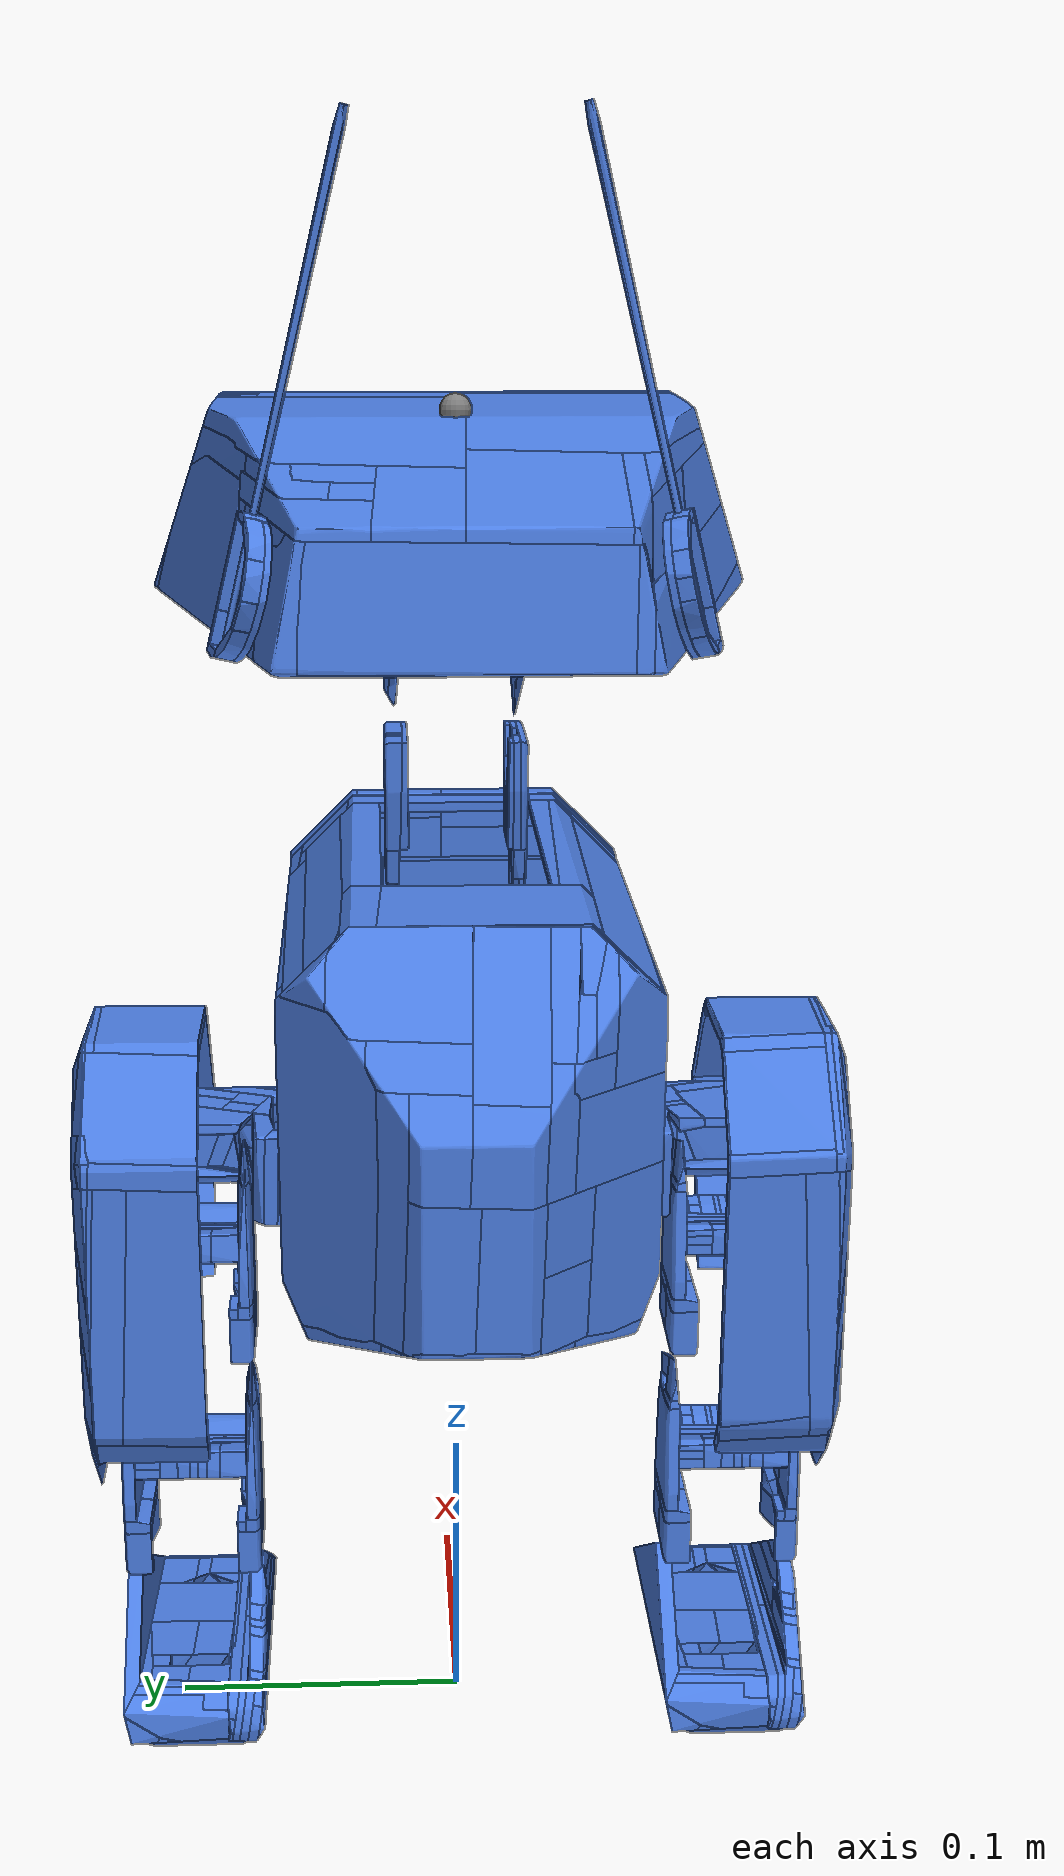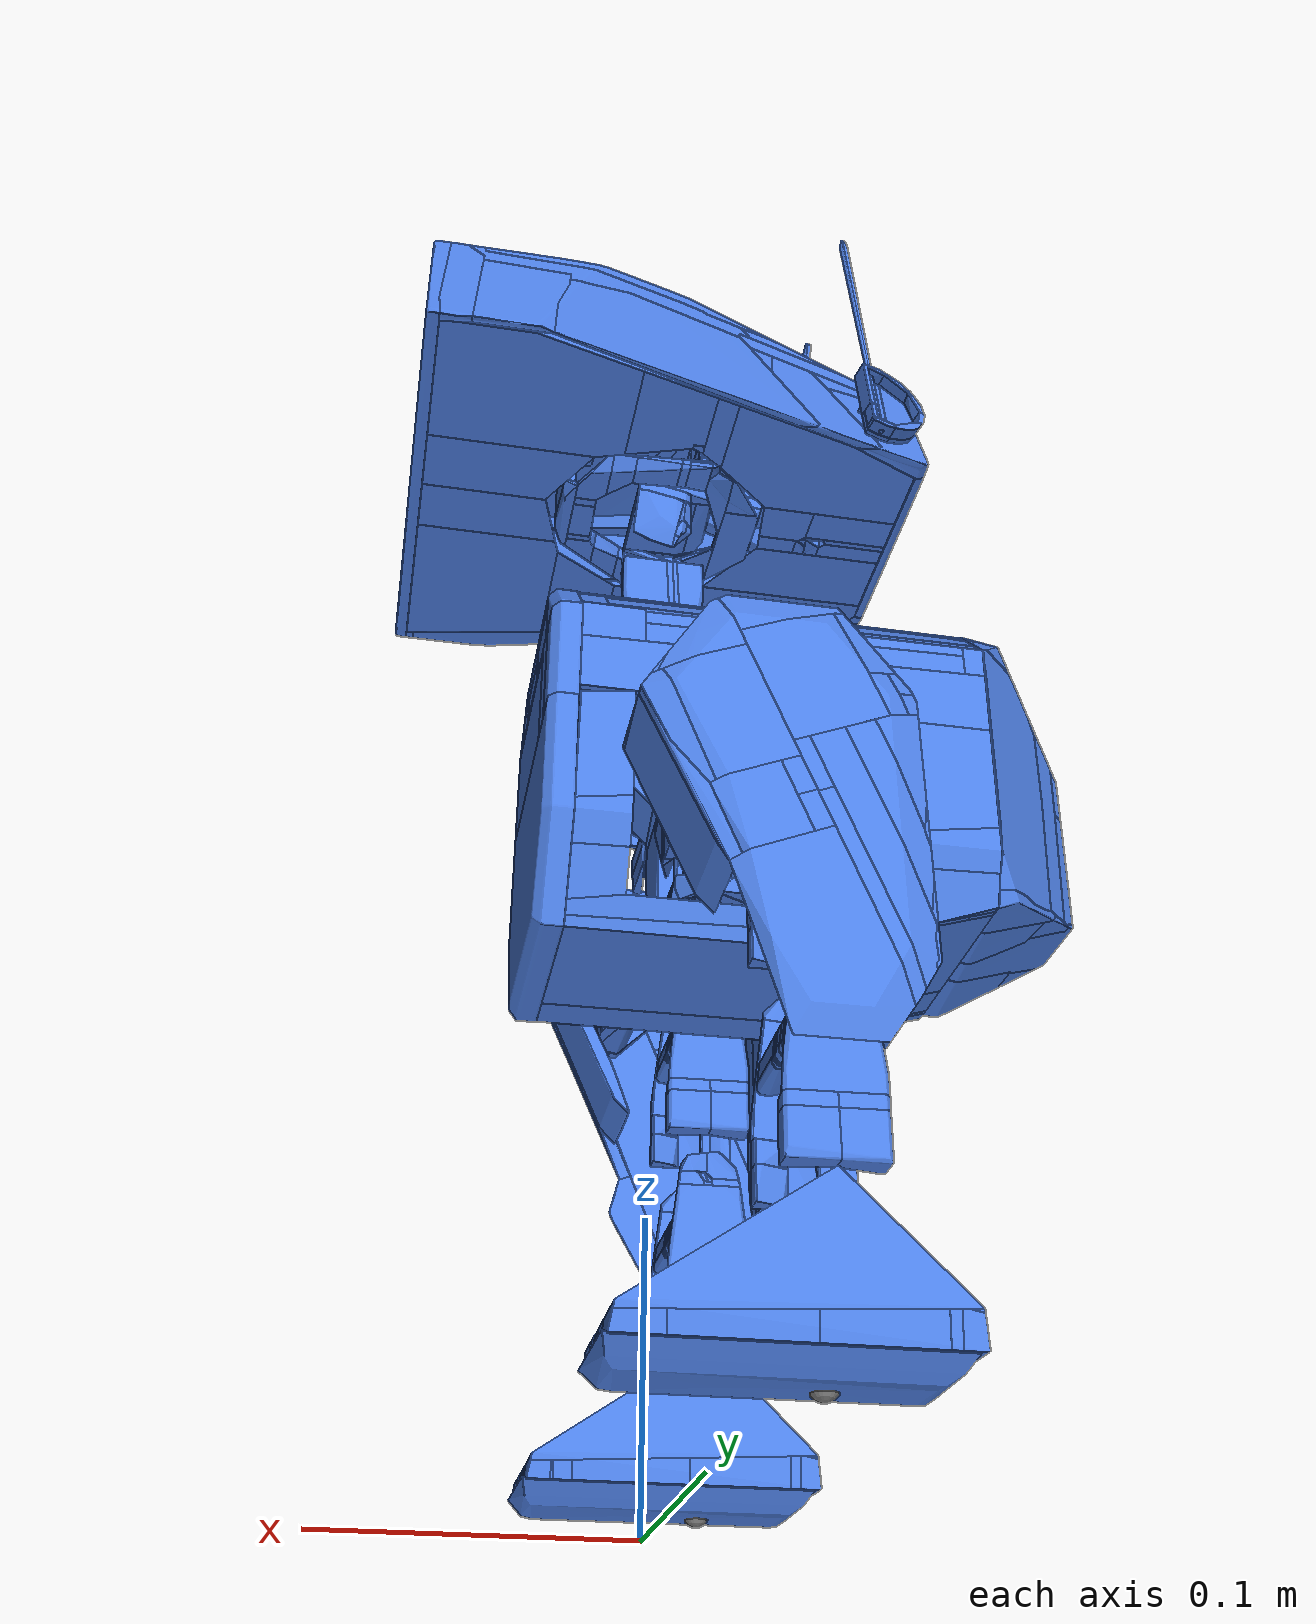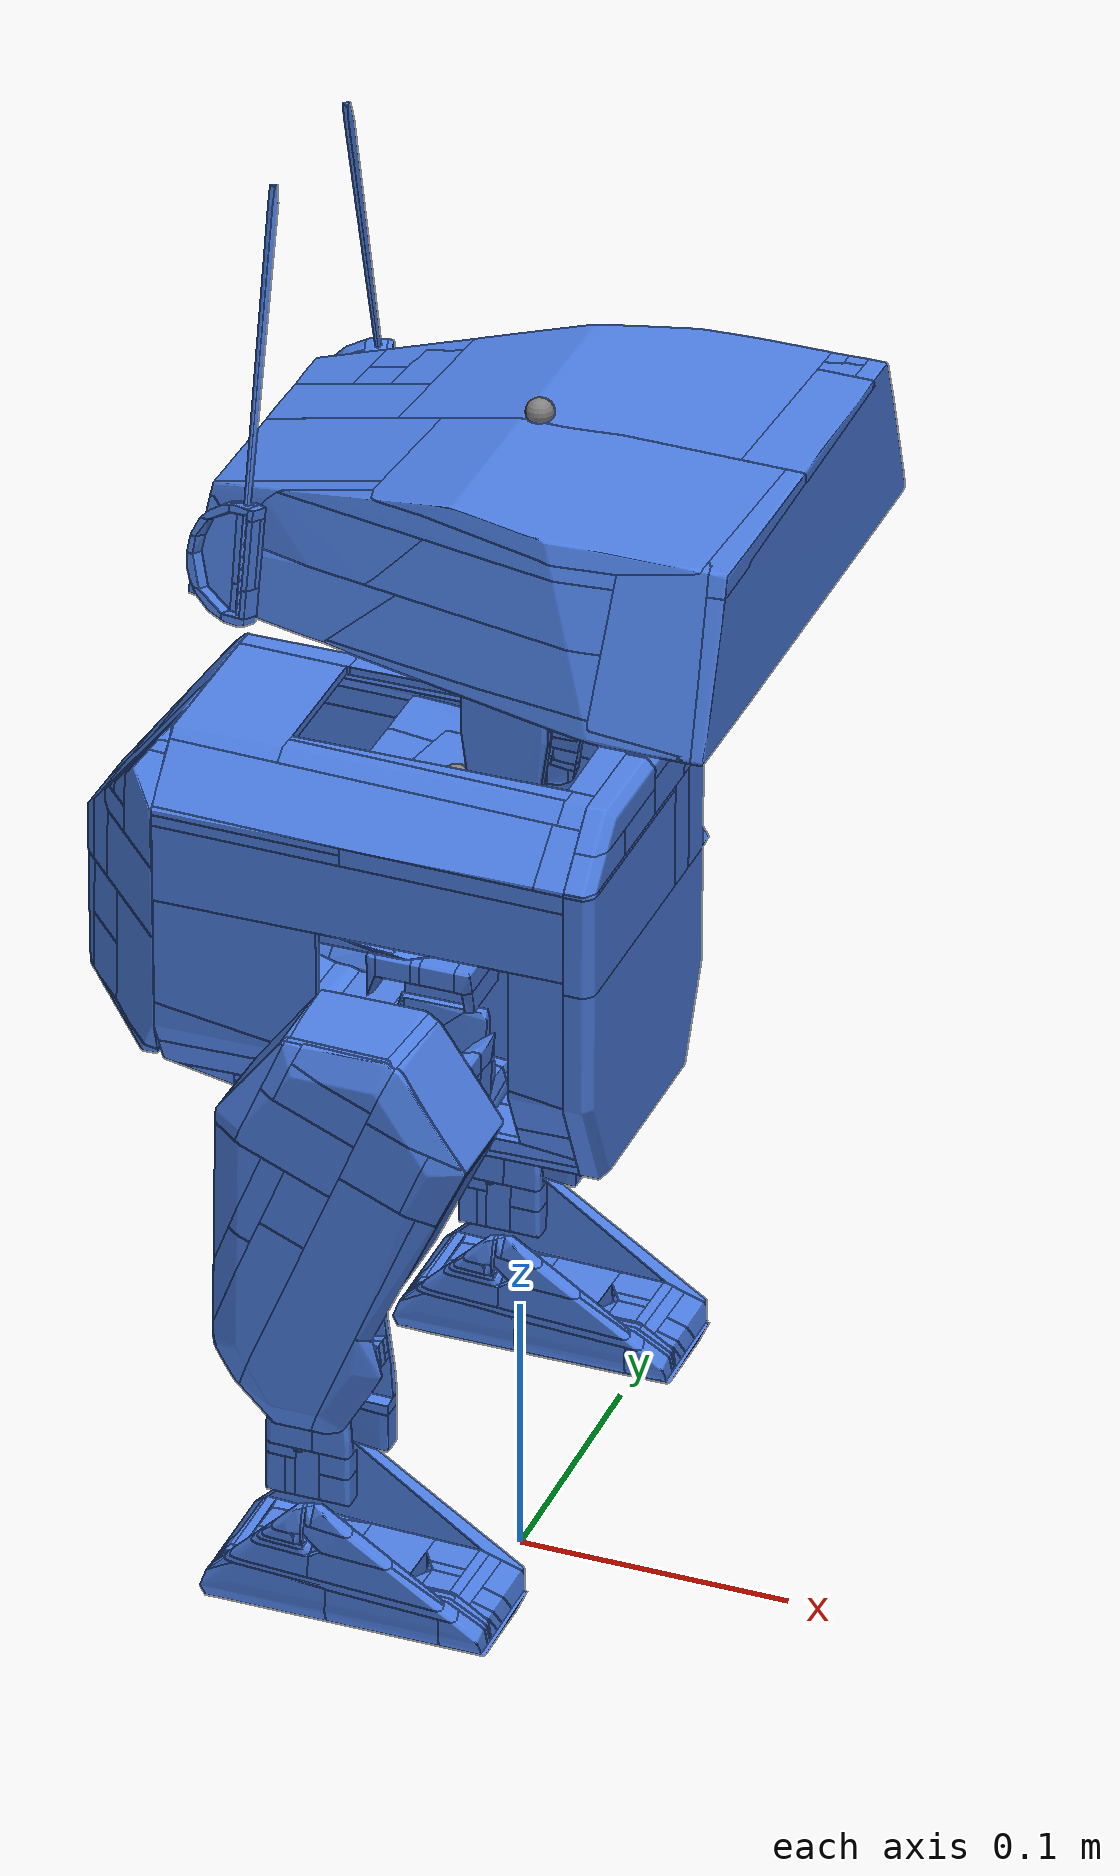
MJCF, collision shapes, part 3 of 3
<mesh name="recovery_head_pitch_to_yaw_21" vertex="0.01812125745 0.005940330525 0.03070984936 0.01812125745 0.0070653219 0.03070984936 0.01812125745 0.00614411466 0.02986141305 0.01882241748 0.001464793669 0.03070984936 0.01849851948 0.00693096579 0.03070984936 0.01812125745 0.007072393394 0.0307037965 0.01812125745 0.006239257103 0.02957705597 0.01937237528 0.001464793669 0.03038703352 0.01965031991 0.001464793669 0.03070984936 0.01812125745 0.006493183731 0.0294358575 0.01849851948 0.006939965666 0.03070201558 0.01876126959 0.006837109691 0.03070984936 0.01964031387 0.007577675094 0.02978573877 0.01812125745 0.007276177528 0.03052502633 0.02007872379 0.001464793669 0.02997465677 0.01990825134 0.001464793669 0.03055939238 0.01965031991 0.001547721508 0.03070771225 0.01964661402 0.001547721508 0.03070984936 0.01812125745 0.006872466592 0.02939579478 0.02154293247 0.001464793669 0.02913298568 0.02135281887 0.001464793669 0.02923340906 0.02130167702 0.001464793669 0.02926100762 0.02021473151 0.007067893455 0.0300530013 0.01883501776 0.006810752667 0.03070984936 0.0205182465 0.007420819292 0.02964827909 0.02143138459 0.007469676008 0.02931531315 0.019147426 0.007851530425 0.02969564245 0.01823428791 0.007801387931 0.03002860612 0.01849851948 0.007754459598 0.02998729789 0.01812125745 0.007670245982 0.03017906309 0.02158147404 0.001464793669 0.02958257568 0.02157962166 0.001547721508 0.02958150713 0.0215710982 0.001928932752 0.02957652283 0.01992455752 0.00383177538 0.03048710071 0.01989861623 0.004972838125 0.03047196631 0.01988119839 0.005733975403 0.03046181621 0.01987230401 0.006114543475 0.0304568319 0.01942796488 0.006114543475 0.03070984936 0.01812125745 0.007253035231 0.02940273923 0.01849851948 0.006876323358 0.02933810437 0.02172822852 0.005428620504 0.02890721061 0.02162372151 0.001464793669 0.02913850539 0.02174231138 0.005428620504 0.02890721061 0.01925971574 0.006830680803 0.03055796765 0.01908924329 0.006707896125 0.03070984936 0.01964031387 0.00675353868 0.03048727994 0.02078173621 0.007181678257 0.02976526161 0.02143138459 0.007469676008 0.02919886605 0.01989713364 0.007836744832 0.0293135345 0.02103818618 0.007119321726 0.02970863975 0.02155219778 0.007263320318 0.02937015636 0.02175972922 0.007141178812 0.02930890412 0.02177344116 0.007216392553 0.02910040055 0.01887911761 0.007892029869 0.02973766304 0.01849851948 0.007947958079 0.02979713437 0.01812125745 0.007965315226 0.029892215 0.02190722442 0.001464793669 0.02939223521 0.02109525724 0.006114543475 0.02974318276 0.02108636286 0.006495754719 0.02973801923 0.02037964454 0.006495754719 0.03015039825 0.02005315343 0.006495754719 0.03034073871 0.01986303983 0.006495754719 0.03045113297 0.01941944143 0.006200042869 0.03070984936 0.01812125745 0.007633603303 0.02941484721 0.01899955987 0.007637460636 0.02928041623 0.01896917196 0.007256891997 0.02927560661 0.01875163448 0.006876323358 0.02930000179 0.01894174809 0.006876323358 0.02927151164 0.01925971574 0.006876323358 0.02922628539 0.02167189818 0.006876323358 0.02889100539 0.02172118765 0.005733975403 0.02890346955 0.02190722442 0.001464793669 0.02916254212 0.02175194649 0.005733975403 0.02890346955 0.01984895697 0.006702110409 0.03044276605 0.01930085155 0.006534968953 0.03070984936 0.02176084087 0.007191963911 0.02889617118 0.02116233434 0.007506961292 0.02915773478 0.01989713364 0.007836744832 0.02927952464 0.01812125745 0.008032171695 0.02956601655 0.01812125745 0.008007743054 0.0298480573 0.02107672775 0.006876323358 0.02973143096 0.02177677612 0.006876323358 0.02932047668 0.02181605842 0.006876323358 0.02910040055 0.01931975197 0.006505397768 0.03070984936 0.01812125745 0.008007100449 0.0295531962 0.01903402575 0.007834815882 0.02928557976 0.02040113921 0.007256891997 0.02906300807 0.02002054108 0.007256891997 0.02911802824 0.01964031387 0.007256891997 0.02917500628 0.02177232837 0.006876323358 0.02889100539 0.02170413961 0.006495754719 0.02889492341 0.0217126642 0.006114543475 0.02889901838 0.0216737517 0.007191963911 0.02889617118 0.0217612118 0.006114543475 0.02889901838 0.02176788174 0.006495754719 0.02889492341 0.01964031387 0.007847030486 0.02927079927 0.01925971574 0.007845744709 0.02927542966" face="0 1 5 0 5 13 0 13 29 0 29 55 0 55 79 0 79 78 0 78 84 0 84 63 0 63 38 0 38 18 0 18 9 0 9 6 0 6 2 0 2 3 0 3 8 0 8 17 0 17 37 0 37 62 0 62 83 0 83 74 0 74 44 0 44 23 0 23 11 0 11 4 0 4 1 1 4 5 2 6 3 3 7 14 3 14 21 3 21 20 3 20 19 3 19 41 3 41 71 3 71 56 3 56 30 3 30 15 3 15 8 3 6 9 3 9 7 4 10 5 4 11 10 5 10 12 5 12 13 7 9 14 8 15 16 8 16 17 9 18 19 9 19 20 9 20 21 9 21 14 10 22 12 10 11 23 10 23 22 12 24 25 12 25 26 12 26 27 12 27 28 12 28 13 12 22 24 13 28 29 15 30 31 15 31 32 15 32 33 15 33 16 16 33 34 16 34 35 16 35 36 16 36 17 17 36 37 18 38 39 18 39 40 18 40 19 19 40 42 19 42 41 22 23 43 22 43 44 22 44 45 22 45 46 22 46 25 22 25 24 23 44 43 25 47 77 25 77 48 25 48 26 25 46 49 25 49 50 25 50 51 25 51 52 25 52 47 26 48 53 26 53 27 27 53 54 27 54 55 27 55 29 27 29 28 30 56 31 31 56 32 32 56 57 32 57 34 32 34 33 34 57 35 35 57 36 36 57 58 36 58 59 36 59 60 36 60 61 36 61 37 37 61 62 38 63 64 38 64 65 38 65 66 38 66 39 39 66 40 40 66 67 40 67 68 40 68 69 40 69 70 40 70 72 40 72 42 41 42 71 42 72 71 44 73 45 44 74 73 45 73 46 46 73 49 47 52 75 47 75 76 47 76 77 48 77 78 48 78 79 48 79 53 49 51 50 49 73 51 51 73 80 51 80 81 51 81 82 51 82 52 52 82 75 53 79 54 54 79 55 56 71 82 56 82 81 56 81 58 56 58 57 58 81 80 58 80 59 59 80 60 60 80 61 61 80 73 61 73 62 62 73 83 63 84 85 63 85 64 64 85 86 64 86 87 64 87 88 64 88 65 65 88 66 66 88 87 66 87 67 67 87 86 67 86 68 68 86 69 69 89 94 69 94 90 69 90 91 69 91 70 69 86 92 69 92 75 69 75 89 70 91 93 70 93 72 71 72 93 71 93 94 71 94 89 71 89 82 73 74 83 75 92 95 75 95 77 75 77 76 75 82 89 77 95 78 78 95 96 78 96 85 78 85 84 85 96 92 85 92 86 90 94 93 90 93 91 92 96 95" />
    <mesh name="recovery_head_pitch_to_yaw_22" vertex="-0.00472699594 0.01896154112 -0.02588147647 -0.00472699594 0.0191399778 -0.02616617839 -0.00636813205 0.02046942994 -0.02346724767 -0.00636813205 0.02029129047 -0.02346724767 -0.006382769043 0.02027093128 -0.02346724767 -0.006518429648 0.02010102713 -0.02346724767 -0.006708354948 0.01990402807 -0.02346724767 -0.007472338292 0.01914566539 -0.02346724767 -0.007657979179 0.01896154112 -0.02346724767 -0.00472699594 0.01896154112 -0.03077786758 -0.00472699594 0.02008635781 -0.02767669434 -0.006622674626 0.02049068526 -0.02346724767 -0.00472699594 0.0202356033 -0.02799192597 -0.008324858234 0.01896154112 -0.02346724767 -0.005100419354 0.01896154112 -0.03089770184 -0.005861903741 0.0191824907 -0.03072672914 -0.006144648917 0.01999204854 -0.0292955945 -0.00472699594 0.01968457355 -0.02941848013 -0.006843300916 0.02040790545 -0.02532886771 -0.006843300916 0.02040895132 -0.02494875848 -0.006842587415 0.02040955025 -0.02456788471 -0.006841872779 0.02040984972 -0.0241870132 -0.006841159277 0.02040984972 -0.02380690397 -0.006840445775 0.02040969998 -0.02346724767 -0.00472699594 0.02022303025 -0.02837356202 -0.00681188529 0.02038919333 -0.02628906402 -0.006814384247 0.02038919333 -0.02628906402 -0.006824737395 0.02039518039 -0.026090613 -0.006839017638 0.02040401239 -0.02570974149 -0.007640129159 0.01965268718 -0.02346724767 -0.007812203305 0.01948323223 -0.02380690397 -0.008330212333 0.01896154112 -0.0239076563 -0.006242467275 0.01896154112 -0.03126407417 -0.006242467275 0.01921497601 -0.03078779082 -0.006592328685 0.01973023086 -0.0299314005 -0.006622674626 0.02003291438 -0.02937192216 -0.005861903741 0.02006914302 -0.02905974192 -0.005109344363 0.02009084754 -0.02877733138 -0.00472699594 0.02007318355 -0.02868726682 -0.007272059845 0.02007438142 -0.02875367125 -0.007269918205 0.02007572902 -0.02837356202 -0.006861150936 0.02039233546 -0.02346724767 -0.007267776566 0.02007587875 -0.02799268824 -0.005481340206 0.02015716349 -0.02875367125 -0.006622674626 0.02011779272 -0.02913454276 -0.005861903741 0.02017407881 -0.02875367125 -0.005100419354 0.02022991571 -0.02837356202 -0.007003237593 0.02011854139 -0.02913454276 -0.007255637963 0.02006270449 -0.02913454276 -0.007241001536 0.02005551956 -0.02346724767 -0.007621921822 0.01967529236 -0.02380690397 -0.008014266074 0.01930659008 -0.026090613 -0.008356988497 0.01896154112 -0.02616388701 -0.008338066523 0.01896154112 -0.02456788471 -0.006570908888 0.01896154112 -0.03120072112 -0.006848656149 0.01964684985 -0.03012145511 -0.00669907262 0.01964684985 -0.03012145511 -0.007003237593 0.02005058063 -0.02939787139 -0.006259960544 0.02008216528 -0.0291551515 -0.007462342463 0.01988247102 -0.02875367125 -0.007460199689 0.01989280034 -0.02837356202 -0.007031084577 0.0202457829 -0.02346724767 -0.007265277609 0.02007483062 -0.02761181447 -0.0072235077 0.02003725664 -0.02937115761 -0.007630846831 0.01969235742 -0.02875367125 -0.007245284815 0.02005971209 -0.0241870132 -0.00745591641 0.01988815861 -0.02761181447 -0.00744913304 0.01988142288 -0.0264707245 -0.007644412438 0.01969804501 -0.02761181447 -0.007834695056 0.01950598488 -0.02761181447 -0.008211330928 0.01912126568 -0.02723246978 -0.008370196786 0.01896154112 -0.02729276692 -0.006844729054 0.01896154112 -0.03093663022 -0.00687221872 0.01931332581 -0.03056567967 -0.00837126874 0.01896154112 -0.02767440297 -0.008025333858 0.01931796754 -0.02799268824 -0.007648696851 0.01970253701 -0.02837356202 -0.007836836696 0.01950823088 -0.02799268824 -0.007247427589 0.02006180609 -0.02456788471 -0.007252068186 0.02006539969 -0.02532886771 -0.007258851556 0.02007033862 -0.0264707245 -0.007209227457 0.01965687971 -0.0297344763 -0.007270989025 0.01979714348 -0.02950473103 -0.007599073887 0.01966316624 -0.02899028611 -0.006859722799 0.01896154112 -0.03092212651 -0.008004627563 0.01930404462 -0.02837356202 -0.008215615342 0.01910554822 -0.02799268824 -0.008373766563 0.01896154112 -0.02761181447 -0.008339137343 0.01896154112 -0.02799268824 -0.007244571313 0.01939970149 -0.02987568157 -0.007531243585 0.01952364887 -0.02924445378 -0.00797356812 0.01927500317 -0.02859872682 -0.007128188866 0.01896154112 -0.03043286854 -0.007131758643 0.01905644706 -0.03035196266 -0.008303081119 0.01896154112 -0.02813618262 -0.007795424105 0.01896154112 -0.02918797258 -0.007641557297 0.01941287348 -0.0291246218 -0.008011053615 0.01902351481 -0.02873687844 -0.008265595624 0.01896154112 -0.02828120609 -0.0079892765 0.01896154112 -0.02882618072 -0.008009268159 0.01896154112 -0.02878878143 -0.008035329688 0.01896154112 -0.02873993209" face="0 1 2 0 2 3 0 3 4 0 4 5 0 5 6 0 6 7 0 7 8 0 8 13 0 13 31 0 31 53 0 53 52 0 52 71 0 71 87 0 87 74 0 74 88 0 88 94 0 94 98 0 98 101 0 101 100 0 100 99 0 99 95 0 95 92 0 92 84 0 84 72 0 72 54 0 54 32 0 32 14 0 14 9 0 9 17 0 17 38 0 38 24 0 24 12 0 12 10 0 10 1 1 10 2 2 11 23 2 23 41 2 41 61 2 61 49 2 49 29 2 29 13 2 13 8 2 8 7 2 7 6 2 6 5 2 5 4 2 4 3 2 10 12 2 12 11 9 14 15 9 15 16 9 16 17 11 18 19 11 19 20 11 20 21 11 21 22 11 22 23 11 12 24 11 24 25 11 25 26 11 26 27 11 27 28 11 28 18 13 29 30 13 30 31 14 32 33 14 33 15 15 33 16 16 33 34 16 34 35 16 35 36 16 36 37 16 37 17 17 37 38 18 28 39 18 39 19 19 39 20 20 39 21 21 39 40 21 40 22 22 40 23 23 40 42 23 42 41 24 38 37 24 37 43 24 43 44 24 44 45 24 45 46 24 46 25 25 46 26 26 46 47 26 47 48 26 48 27 27 48 39 27 39 28 29 49 50 29 50 30 30 50 51 30 51 52 30 52 53 30 53 31 32 54 55 32 55 56 32 56 34 32 34 33 34 56 35 35 57 44 35 44 58 35 58 36 35 56 57 36 58 43 36 43 37 39 48 59 39 59 60 39 60 40 40 60 42 41 42 61 42 60 62 42 62 61 43 58 44 44 57 47 44 47 45 45 47 46 47 57 63 47 63 48 48 63 64 48 64 59 49 61 65 49 65 66 49 66 67 49 67 50 50 67 68 50 68 51 51 68 52 52 68 69 52 69 70 52 70 71 54 72 73 54 73 55 55 73 63 55 63 57 55 57 56 59 64 74 59 74 75 59 75 76 59 76 60 60 76 75 60 75 77 60 77 69 60 69 68 60 68 66 60 66 65 60 65 78 60 78 79 60 79 80 60 80 62 61 80 79 61 79 78 61 78 65 61 62 80 63 81 82 63 82 83 63 83 64 63 73 84 63 84 81 64 85 86 64 86 74 64 83 85 66 68 67 69 77 75 69 75 70 70 75 71 71 75 87 72 84 73 74 87 75 74 86 88 81 89 90 81 90 82 81 84 89 82 90 83 83 90 91 83 91 85 84 92 93 84 93 89 85 91 88 85 88 86 88 91 94 89 95 96 89 96 90 89 93 92 89 92 95 90 96 91 91 97 98 91 98 94 91 96 97 95 99 96 96 99 100 96 100 101 96 101 97 97 101 98" />
    <mesh name="recovery_head_pitch_to_yaw_23" vertex="-0.00472699594 0.01881303749 -0.02346762654 -0.00765830587 0.01896139139 -0.02346762654 -0.00472699594 0.01640987875 -0.02346762654 -0.00472699594 0.01896139139 -0.02588144924 -0.008324539484 0.01896139139 -0.02346762654 -0.004760655297 0.01640905862 -0.02346762654 -0.00472699594 0.01632518303 -0.02533602315 -0.00472699594 0.01896139139 -0.0307776997 -0.008325699917 0.01896139139 -0.0235316602 -0.00875631463 0.01852589446 -0.02346762654 -0.005100736402 0.01640086185 -0.02346762654 -0.005522064818 0.01639075373 -0.02346762654 -0.008145213484 0.01627819061 -0.02456762608 -0.00888921311 0.0161926759 -0.02606325719 -0.005481441163 0.01622136343 -0.02723186405 -0.00472699594 0.01618775853 -0.02837417003 -0.00472699594 0.01683526754 -0.03484380627 -0.005154128221 0.01896139139 -0.03091491436 -0.01008529829 0.01718880139 -0.02380723066 -0.008946666443 0.01833382753 -0.02346762654 -0.008342530162 0.01896139139 -0.02494839549 -0.006283474338 0.01637272108 -0.02346762654 -0.007003679987 0.01634020967 -0.02380723066 -0.009286746981 0.0162342042 -0.02494839549 -0.0100481565 0.01619568078 -0.02539662655 -0.009752181484 0.0161992324 -0.02546409046 -0.009498571905 0.01620223841 -0.02553041095 -0.009642497332 0.01619212915 -0.02567905978 -0.007003679987 0.01618502589 -0.02723186405 -0.005481441163 0.0161869384 -0.02799340061 -0.005100736402 0.01617901501 -0.02837417003 -0.00472699594 0.0161732775 -0.02875493718 -0.00472699594 0.0166699745 -0.03512166356 -0.005098995186 0.01688253221 -0.03481750766 -0.005986919671 0.01811580455 -0.03276958768 -0.006242270467 0.01892314135 -0.03133455997 -0.006242270467 0.01896139139 -0.03126366581 -0.00600258835 0.01896139139 -0.03118705456 -0.005585322584 0.01896139139 -0.03105327016 -0.01027448967 0.01700083283 -0.02418800008 -0.01026926716 0.01699837357 -0.02380723066 -0.009912937156 0.01735819168 -0.02346762654 -0.009892624478 0.01737895582 -0.02346762654 -0.009534553262 0.01774041419 -0.02346762654 -0.008360520841 0.01896139139 -0.02647146863 -0.008365743355 0.01896139139 -0.0269162717 -0.01028261497 0.01700766271 -0.02532916264 -0.01047296792 0.01681532239 -0.02532916264 -0.006622975227 0.01636561782 -0.02346762654 -0.008145213484 0.01629704226 -0.02418800008 -0.0100481565 0.01620524329 -0.02520681469 -0.01042886126 0.0161926759 -0.02539205288 -0.0100481565 0.01618475252 -0.02570993206 -0.009286746981 0.01618447914 -0.02609070148 -0.007764508724 0.01618447914 -0.02685223804 -0.005862145923 0.01617874163 -0.02799340061 -0.005100736402 0.01617054601 -0.02875493718 -0.00472699594 0.01617027263 -0.0291357066 -0.007384384747 0.01617901501 -0.02723186405 -0.005481441163 0.01617355088 -0.02837417003 -0.00472699594 0.01666614949 -0.03512738065 -0.005100736402 0.01668008376 -0.03514796443 -0.005224349718 0.0169740578 -0.0346734325 -0.005481441163 0.01728060035 -0.03416574146 -0.00607222963 0.01811580455 -0.03276958768 -0.006242270467 0.01881822824 -0.03152551526 -0.006519674022 0.01891494459 -0.03131969554 -0.006571324057 0.01896139139 -0.03120077557 -0.01065519557 0.01662516795 -0.02532916264 -0.01063894497 0.01660877556 -0.02494839549 -0.01025417813 0.01698280018 -0.02346762654 -0.01008297743 0.01717322799 -0.02346762654 -0.008373868654 0.01896139139 -0.02761263119 -0.0102837754 0.01700984859 -0.02570993206 -0.00877836739 0.01854829774 -0.02723186405 -0.006664179098 0.01636479883 -0.02346762654 -0.008906042221 0.01626179822 -0.02456762608 -0.007044883858 0.01635769557 -0.02346762654 -0.007764508724 0.01632545641 -0.02380723066 -0.009286746981 0.01625496834 -0.02456762608 -0.009667451741 0.01624923084 -0.02456762608 -0.009667451741 0.01629731563 -0.02380723066 -0.009667451741 0.01631889877 -0.02346762654 -0.01062907959 0.01619513516 -0.02545722996 -0.01040564807 0.0161907634 -0.02568706371 -0.0100481565 0.01618584602 -0.02609070148 -0.009667451741 0.01618174764 -0.02609070148 -0.006242270467 0.01617437101 -0.02799340061 -0.007764508724 0.01617710251 -0.02723186405 -0.008525918244 0.01617928839 -0.02685223804 -0.005481441163 0.01617245851 -0.02875493718 -0.005100736402 0.01617491663 -0.0291357066 -0.00472699594 0.01617764926 -0.0295153326 -0.00472699594 0.01646752605 -0.03512738065 -0.005100736402 0.01646397442 -0.03514796443 -0.005407157016 0.01665276198 -0.03511708989 -0.005677016625 0.01696886705 -0.03466199832 -0.005481441163 0.01697542355 -0.03467457592 -0.005481441163 0.01710273993 -0.03446303685 -0.006450612958 0.01850403795 -0.03201605504 -0.006845246314 0.01896139139 -0.03093663929 -0.01064532905 0.01661150706 -0.02558415158 -0.01064649062 0.01639211947 -0.02558758184 -0.010654034 0.01637326783 -0.02532916264 -0.01063894497 0.01649921846 -0.02494839549 -0.01062385594 0.01658992392 -0.02474028668 -0.01026230343 0.01695848554 -0.02346762654 -0.008371546654 0.01896139139 -0.02767552143 -0.008401724712 0.01893297837 -0.02761263119 -0.00833904773 0.01896139139 -0.02799340061 -0.007425007835 0.01635141131 -0.02346762654 -0.008906042221 0.01628420149 -0.02418800008 -0.009286746981 0.01630277976 -0.02380723066 -0.008906042221 0.01632982703 -0.02346762654 -0.009708656747 0.01632190478 -0.02346762654 -0.01062907959 0.01619513516 -0.02554527538 -0.0100481565 0.01632654878 -0.02380723066 -0.0100481565 0.01639621785 -0.02346762654 -0.01007659334 0.01641179125 -0.02346762654 -0.01027042759 0.01652954398 -0.02346762654 -0.01062385594 0.01656642828 -0.02474028668 -0.009667451741 0.01618639164 -0.02647146863 -0.009286746981 0.01618174764 -0.02647146863 -0.01023966988 0.01620087266 -0.0262839436 -0.01001565758 0.01619622753 -0.02643487926 -0.009867090419 0.01619896016 -0.0267024458 -0.009415002595 0.01620360416 -0.02737936719 -0.008145213484 0.01617983514 -0.02723186405 -0.008906042221 0.01618311339 -0.02685223804 -0.005862145923 0.01617819602 -0.02875493718 -0.004756593215 0.01619595415 -0.03031345853 -0.00472699594 0.01619704766 -0.03038206585 -0.00472699594 0.01632545641 -0.03484952335 -0.005407157016 0.01650249671 -0.03511708989 -0.00472699594 0.01632272378 -0.03484380627 -0.005100736402 0.01632217816 -0.03484380627 -0.005731568876 0.01650796084 -0.03476719502 -0.005720541929 0.01677270173 -0.03474546781 -0.006437265145 0.01811307305 -0.03237852977 -0.006860335344 0.01896139139 -0.03092177486 -0.01022051877 0.01692050887 -0.02623134412 -0.01033948865 0.01678526911 -0.0260987054 -0.01027333037 0.01666669625 -0.02634683384 -0.008378511519 0.01891494459 -0.02799340061 -0.008348333461 0.01888598481 -0.02820722652 -0.008722654139 0.01849611343 -0.02781616634 -0.009096974817 0.01810542305 -0.02742396275 -0.009883919531 0.01648227932 -0.02709007572 -0.01026578472 0.01639211947 -0.02633196941 -0.01028667705 0.01677270173 -0.02346762654 -0.008303066373 0.01896139139 -0.02813747577 -0.008185837706 0.01634020967 -0.02346762654 -0.008525918244 0.0163352923 -0.02346762654 -0.009287327765 0.01619786666 -0.02724444164 -0.009161393016 0.01620087266 -0.02746741262 -0.008978585718 0.01620360416 -0.02772126041 -0.009286746981 0.0161888509 -0.02685223804 -0.006054819736 0.01657762991 -0.03427665524 -0.005512779654 0.01643364777 -0.03487353512 -0.005862145923 0.01637326783 -0.03408226743 -0.005481441163 0.01631316127 -0.03446303685 -0.005481441163 0.0162918515 -0.03408226743 -0.008525918244 0.01619404165 -0.02761263119 -0.006725114864 0.01620305741 -0.02926491506 -0.00472699594 0.01627163411 -0.03370950421 -0.00472699594 0.01628911887 -0.03446989735 -0.00472699594 0.01628857325 -0.03446303685 -0.005100736402 0.016294583 -0.03446303685 -0.006054819736 0.01658828479 -0.03427665524 -0.00590915366 0.01673827782 -0.0344275909 -0.0060020087 0.01684209742 -0.03417831905 -0.006069908198 0.01700547683 -0.03392561695 -0.006774444034 0.01839120032 -0.03153580602 -0.006842344665 0.018554582 -0.03128196049 -0.006915467812 0.01867916461 -0.03104869649 -0.007128453168 0.01896139139 -0.0304323785 -0.01015668136 0.01678526911 -0.02647261204 -0.009954721811 0.01677215497 -0.02686024197 -0.009883919531 0.01664483973 -0.02709007572 -0.009103939683 0.01660085218 -0.02857884632 -0.009103939683 0.01655276738 -0.02857884632 -0.009493930174 0.0165169766 -0.02783446102 -0.0082653438 0.01896139139 -0.02828269208 -0.008034948548 0.01896139139 -0.02874121617 -0.008394180197 0.01867561412 -0.02829298511 -0.008765599227 0.01829503073 -0.02789620784 -0.009787002408 0.01717459488 -0.02686024197 -0.006242270467 0.01626944823 -0.03256033771 -0.008873543297 0.0161992324 -0.02760234044 -0.005100736402 0.01628584062 -0.03408226743 -0.007297913788 0.01677789248 -0.03181137874 -0.006459898689 0.01702760672 -0.03318123164 -0.006407087654 0.01728114711 -0.03308289319 -0.007179523554 0.01883052452 -0.03043923901 -0.007211441695 0.01896139139 -0.03027801258 -0.007523666174 0.01896139139 -0.02969599712 -0.007989101811 0.01896139139 -0.02882697476 -0.007875354443 0.01896139139 -0.02903965725" face="0 1 4 0 4 9 0 9 19 0 19 43 0 43 42 0 42 41 0 41 71 0 71 70 0 70 106 0 106 149 0 149 119 0 119 118 0 118 117 0 117 114 0 114 82 0 82 113 0 113 152 0 152 151 0 151 110 0 110 77 0 77 75 0 75 48 0 48 21 0 21 11 0 11 10 0 10 5 0 5 2 0 2 6 0 6 15 0 15 31 0 31 57 0 57 92 0 92 131 0 131 164 0 164 166 0 166 165 0 165 134 0 134 132 0 132 93 0 93 60 0 60 32 0 32 16 0 16 7 0 7 3 0 3 1 1 3 7 1 7 17 1 17 38 1 38 37 1 37 36 1 36 67 1 67 100 1 100 139 1 139 175 1 175 194 1 194 195 1 195 197 1 197 196 1 196 183 1 183 182 1 182 150 1 150 109 1 109 107 1 107 72 1 72 45 1 45 44 1 44 20 1 20 8 1 8 4 2 5 6 4 8 9 5 10 6 6 10 11 6 11 12 6 12 13 6 13 14 6 14 15 7 16 17 8 18 19 8 19 9 8 20 18 11 21 12 12 21 22 12 22 23 12 23 24 12 24 25 12 25 26 12 26 13 13 26 27 13 27 28 13 28 29 13 29 15 13 15 14 15 29 30 15 30 31 16 32 33 16 33 34 16 34 35 16 35 36 16 36 37 16 37 38 16 38 17 18 39 40 18 40 41 18 41 42 18 42 43 18 43 19 18 20 44 18 44 45 18 45 46 18 46 47 18 47 39 21 48 22 22 48 23 23 48 49 23 49 50 23 50 24 24 50 51 24 51 52 24 52 27 24 27 25 25 27 26 27 52 53 27 53 54 27 54 30 27 30 28 28 30 29 30 54 55 30 55 31 31 56 57 31 55 53 31 53 58 31 58 59 31 59 56 32 60 61 32 61 33 33 61 62 33 62 34 34 62 63 34 63 64 34 64 65 34 65 35 35 65 66 35 66 36 36 66 67 39 47 68 39 68 40 40 69 70 40 70 71 40 71 41 40 68 69 45 72 46 46 72 47 47 73 68 47 72 74 47 74 73 48 75 49 49 76 50 49 75 77 49 77 78 49 78 76 50 76 79 50 79 80 50 80 81 50 81 82 50 82 51 51 83 52 51 82 83 52 83 84 52 84 85 52 85 86 52 86 87 52 87 59 52 59 58 52 58 53 53 55 54 56 59 87 56 87 86 56 86 88 56 88 57 57 88 89 57 89 90 57 90 91 57 91 92 60 93 94 60 94 61 61 94 133 61 133 95 61 95 96 61 96 97 61 97 62 62 97 98 62 98 63 63 98 64 64 98 97 64 97 96 64 96 99 64 99 66 64 66 65 66 99 67 67 99 100 68 73 101 68 101 102 68 102 103 68 103 104 68 104 69 69 104 120 69 120 105 69 105 70 70 105 106 72 107 108 72 108 74 73 74 107 73 107 109 73 109 101 74 108 107 76 78 79 77 110 78 78 110 79 79 110 111 79 111 80 80 111 112 80 112 81 81 112 113 81 113 82 82 114 83 83 103 115 83 115 84 83 114 116 83 116 117 83 117 118 83 118 119 83 119 120 83 120 104 83 104 103 84 115 85 85 121 122 85 122 86 85 115 123 85 123 124 85 124 125 85 125 126 85 126 121 86 122 89 86 89 88 89 122 90 90 127 128 90 128 121 90 121 129 90 129 91 90 122 127 91 129 130 91 130 92 92 130 131 93 132 94 94 132 134 94 134 135 94 135 133 95 136 137 95 137 96 95 133 136 96 137 138 96 138 99 99 139 100 99 138 139 101 140 141 101 141 142 101 142 102 101 109 143 101 143 144 101 144 145 101 145 146 101 146 140 102 115 103 102 142 147 102 147 148 102 148 115 105 149 106 105 120 149 109 150 143 110 151 111 111 151 112 112 151 152 112 152 113 114 117 116 115 148 123 119 149 120 121 126 153 121 153 154 121 154 155 121 155 156 121 156 129 121 128 122 122 128 127 123 125 124 123 148 147 123 147 157 123 157 136 123 136 158 123 158 159 123 159 160 123 160 161 123 161 126 123 126 125 126 161 154 126 154 153 129 156 162 129 162 163 129 163 164 129 164 130 130 164 131 133 135 158 133 158 136 134 165 135 135 165 166 135 166 167 135 167 160 135 160 158 136 157 168 136 168 137 137 168 169 137 169 170 137 170 171 137 171 138 138 171 172 138 172 173 138 173 174 138 174 175 138 175 139 140 142 141 140 146 142 142 146 176 142 176 177 142 177 178 142 178 179 142 179 180 142 180 181 142 181 147 143 150 144 144 150 182 144 182 183 144 183 145 145 183 184 145 184 146 146 184 185 146 185 186 146 186 176 147 181 157 154 161 155 155 161 187 155 187 156 156 187 188 156 188 162 157 181 180 157 180 179 157 179 168 158 160 159 160 167 161 161 167 166 161 166 189 161 189 187 162 188 187 162 187 163 163 187 164 164 187 189 164 189 166 168 179 178 168 178 177 168 177 190 168 190 191 168 191 171 168 171 170 168 170 169 171 191 192 171 192 172 172 193 194 172 194 175 172 175 173 172 192 195 172 195 193 173 175 174 176 186 177 177 186 185 177 185 195 177 195 191 177 191 190 183 196 185 183 185 184 185 196 197 185 197 195 191 195 192 193 195 194" />
    <mesh name="recovery_head_pitch_to_yaw_24" vertex="0.01051287253 0.009442771895 0.03071002404 0.0101825757 0.009420129276 0.03071002404 0.01088578946 0.00939317502 0.03071002404 0.01317034641 0.009020655678 0.03035874754 0.01278943974 0.00905192384 0.03034729068 0.01240853193 0.009061088197 0.03036441245 0.009904663956 0.009341420626 0.03071002404 0.01202851231 0.009050306267 0.03039298655 0.01093817511 0.009382391957 0.03071002404 0.0134464829 0.008989927464 0.03046017822 0.0134464829 0.008989927464 0.0303928595 0.01570173921 0.008601774608 0.03002883752 0.01794279015 0.008211466501 0.02966597484 0.01545312868 0.008626034799 0.03000142045 0.01507222088 0.008652450243 0.0299862316 0.01469131307 0.008656224201 0.03000013411 0.0101248626 0.009159744267 0.03064322032 0.009702223451 0.009192628868 0.03071002404 0.01172662737 0.00901688172 0.03041564164 0.01667931365 0.008232491546 0.02965542092 0.01263316926 0.008987232265 0.03071002404 0.01317034641 0.009020655678 0.03050433138 0.01285425609 0.008927931087 0.03071002404 0.01306823853 0.008858925605 0.03071002404 0.01317034641 0.008841135706 0.03069457883 0.01457855031 0.00861525287 0.03045644623 0.01686221964 0.008233569172 0.03007594905 0.01570173921 0.008601774608 0.03007118708 0.01773679801 0.008228178775 0.02964602402 0.01794279015 0.008211466501 0.02967666035 0.01812125745 0.008031945961 0.02956595983 0.01735589021 0.008250281446 0.02962774522 0.0169749824 0.008250820259 0.0296370128 0.009743954791 0.009159744267 0.03070024147 0.01407511305 0.00860608738 0.03004505636 0.01240853193 0.008779139329 0.03029245654 0.009679138438 0.009159744267 0.03071002404 0.01811681763 0.007637324515 0.02941548697 0.0169749824 0.008017929453 0.02959492187 0.01314459796 0.008833048975 0.03071002404 0.01398809988 0.008537083033 0.03071002404 0.01427489012 0.008435731763 0.03071002404 0.01468065819 0.008394760432 0.03061914957 0.01621405497 0.008134914236 0.03036775876 0.01773679801 0.007890162741 0.03010632675 0.01375635816 0.008618486882 0.03071002404 0.01798008167 0.007846495077 0.03006835576 0.01812125745 0.00800822515 0.02984824333 0.01812125745 0.008007147524 0.02955321662 0.01773679801 0.008017929453 0.02954690967 0.01088578946 0.008398534391 0.03051243966 0.009743954791 0.006876114639 0.0306506843 0.009254724043 0.006223802815 0.03071002404 0.009624088777 0.008779139329 0.03071002404 0.01661272092 0.008017929453 0.02964537971 0.01382117451 0.008017929453 0.03006397947 0.01469131307 0.008398534391 0.02994311069 0.01812125745 0.007633550556 0.02941484267 0.01811681763 0.007256719577 0.0294033858 0.01773679801 0.007637324515 0.02946864909 0.01431129345 0.008422793448 0.03071002404 0.01453859535 0.008341928412 0.03071002404 0.01585978494 0.007871294081 0.03071002404 0.01812125745 0.007670209683 0.03017918333 0.01812125745 0.007965636245 0.02989226491 0.009743954791 0.006496048514 0.0306424467 0.01371107519 0.006496048514 0.030047502 0.009363935174 0.004973629329 0.03066651746 0.009158831232 0.005559092057 0.03071002404 0.01735589021 0.007256719577 0.02951743264 0.0158331483 0.007637324515 0.02975402027 0.01469131307 0.006496048514 0.02990050477 0.01812125745 0.007252945618 0.02940274377 0.01811681763 0.006876114639 0.02939514821 0.01735589021 0.006496048514 0.02950095744 0.0170717634 0.007439474696 0.03071002404 0.01812125745 0.00727612705 0.03052505355 0.01795078159 0.007126257099 0.03071002404 0.009743954791 0.004973629329 0.03060949404 0.01365602666 0.005734839205 0.0300392644 0.009363935174 0.004593024391 0.03065879485 0.009074480927 0.004973629329 0.03071002404 0.009110884826 0.005226466988 0.03071002404 0.01812125745 0.00687234068 0.0293956632 0.01811681763 0.006496048514 0.02943402214 0.01773679801 0.006496048514 0.02945474658 0.01632593068 0.005912742172 0.02966185718 0.01629307784 0.006115444143 0.02965632158 0.009743954791 0.004212419453 0.03060421708 0.0112666967 0.004973629329 0.03038114628 0.01812125745 0.007065338915 0.03071002404 0.009743954791 0.004593024391 0.03060280142 0.009363935174 0.004212419453 0.03066523111 0.009058498603 0.004517011506 0.03071002404 0.009051395348 0.004593024391 0.03071002404 0.009063826044 0.004893303105 0.03071002404 0.01812125745 0.006493892128 0.02943595279 0.01811681763 0.006239976276 0.02957419743 0.01773679801 0.006202238957 0.02956634551 0.01682759155 0.005918133136 0.02966391714 0.01659496278 0.005910585786 0.02965863791 0.0101248626 0.003935860983 0.03058207697 0.01002097834 0.003935860983 0.03058902823 0.009743954791 0.003935860983 0.03061773391 0.009640070535 0.003935860983 0.03063433842 0.01812125745 0.005940775188 0.03071002404 0.009363935174 0.003935860983 0.03068376628 0.009260050917 0.003935860983 0.03070294575 0.009121539709 0.004212419453 0.03071002404 0.01812125745 0.006239976276 0.02957703102 0.01053329467 0.003935860983 0.03065647852 0.01044805617 0.003935860983 0.0306374261 0.01812125745 0.006145094165 0.02986150153 0.01058035345 0.003935860983 0.03071002404 0.009222759395 0.003935860983 0.03071002404 0.009200562006 0.003994622781 0.03071002404" face="0 1 6 0 6 17 0 17 36 0 36 53 0 53 52 0 52 68 0 68 82 0 82 81 0 81 95 0 95 94 0 94 93 0 93 108 0 108 115 0 115 114 0 114 113 0 113 105 0 105 90 0 90 77 0 77 75 0 75 62 0 62 61 0 61 60 0 60 41 0 41 40 0 40 45 0 45 39 0 39 23 0 23 22 0 22 20 0 20 8 0 8 2 0 2 3 0 3 4 0 4 5 0 5 1 1 5 7 1 7 6 2 8 9 2 9 10 2 10 3 3 10 11 3 11 12 3 12 13 3 13 4 4 13 14 4 14 5 5 14 15 5 15 7 6 16 17 6 7 18 6 18 16 7 15 19 7 19 18 8 20 21 8 21 9 9 21 20 9 20 22 9 22 23 9 23 24 9 24 25 9 25 26 9 26 27 9 27 11 9 11 10 11 27 29 11 29 12 12 28 13 12 29 30 12 30 28 13 28 14 14 28 31 14 31 32 14 32 15 15 32 19 16 33 17 16 18 34 16 34 35 16 35 33 17 33 36 18 19 34 19 32 37 19 37 38 19 38 34 23 39 24 24 39 25 25 40 41 25 41 42 25 42 43 25 43 44 25 44 26 25 39 45 25 45 40 26 44 46 26 46 47 26 47 29 26 29 27 28 30 31 29 47 30 30 47 64 30 64 63 30 63 76 30 76 90 30 90 105 30 105 112 30 112 109 30 109 96 30 96 83 30 83 72 30 72 57 30 57 48 30 48 31 31 48 49 31 49 37 31 37 32 33 50 51 33 51 52 33 52 53 33 53 36 33 35 54 33 54 55 33 55 50 34 38 54 34 54 56 34 56 35 35 56 54 37 48 57 37 57 72 37 72 58 37 58 59 37 59 54 37 54 38 37 49 48 41 60 42 42 60 61 42 61 43 43 61 62 43 62 63 43 63 44 44 63 46 46 63 64 46 64 47 50 65 51 50 55 66 50 66 65 51 65 67 51 67 52 52 67 68 54 59 58 54 58 69 54 69 70 54 70 55 55 70 71 55 71 66 58 72 73 58 73 74 58 74 69 62 75 63 63 75 77 63 77 76 65 78 67 65 66 79 65 79 78 66 71 79 67 80 81 67 81 82 67 82 68 67 78 80 69 74 71 69 71 70 71 74 79 72 83 73 73 83 84 73 84 85 73 85 74 74 85 86 74 86 87 74 87 88 74 88 89 74 89 79 76 77 90 78 89 80 78 79 89 80 91 88 80 88 92 80 92 93 80 93 94 80 94 95 80 95 81 80 89 91 83 96 84 84 96 97 84 97 98 84 98 99 84 99 100 84 100 86 84 86 85 86 100 101 86 101 102 86 102 103 86 103 88 86 88 87 88 103 104 88 104 92 88 91 89 92 106 107 92 107 108 92 108 93 92 104 106 96 109 97 97 109 110 97 110 99 97 99 98 99 110 111 99 111 101 99 101 100 101 111 110 101 110 113 101 113 114 101 114 107 101 107 106 101 106 104 101 104 103 101 103 102 105 113 110 105 110 112 107 114 115 107 115 108 109 112 110" />
    <mesh name="recovery_right_antenna_holder_0" vertex="0.001740324626 -0.001244234669 2.68859503e-05 0.001139768944 -0.00124268195 -0.01980815375 0.0033693407 -0.001244234669 2.68859503e-05 0.001143026449 -0.001244234669 0.0001909087202 0.001139768944 0.0004342902777 -0.01946839231 0.001544172598 0.0006392534955 -0.01940981228 0.003190407306 0.001668727742 -0.01912082003 0.00298471512 -0.00124268195 -0.0197144262 0.001118362079 -0.001244234669 0.01714383369 0.001118362079 0.01210477071 2.68859503e-05 0.001118362079 0.01442303004 2.68859503e-05 0.003190407306 -0.00124268195 -0.01970271118 0.003323734868 -0.00124268195 -0.01966756243 0.003370736982 -0.00124268195 -0.01953478317 0.00338749006 -0.00124268195 -0.0193317064 0.0033693407 -0.001244234669 4.64124687e-05 0.001139768944 0.0005522993845 -0.01944105562 0.003190407306 0.001873690959 -0.01907395626 0.003307912286 0.0009979389732 -0.01923798008 0.003306516311 -0.001061009519 -0.01965194199 0.003169931168 -0.0009988995276 -0.01965584741 0.003308610426 0.001994805504 -0.0190309979 0.001118362079 -0.001244234669 0.02008843329 0.001118362079 0.01335628931 0.007220456121 0.001139768944 0.01461091212 -0.001226716692 0.001139768944 0.01461867633 -0.001425887274 0.001139768944 0.01461867633 -0.001429792537 0.001139768944 0.01459849037 -0.001628962965 0.001139768944 0.01449911389 -0.002460792663 0.001139768944 0.01447427039 -0.002659963398 0.001139768944 0.01444010934 -0.002866944353 0.001139768944 0.01443855601 -0.002874755186 0.001139768944 0.01435315584 -0.003261380099 0.001139768944 0.0143252069 -0.003386349756 0.001139768944 0.01393235976 -0.005116399702 0.001139768944 0.01360162384 -0.006569173031 0.001139768944 0.01355348771 -0.006780059403 0.001139768944 0.01351466912 -0.006940176584 0.001139768944 0.01348672017 -0.00704561977 0.001139768944 0.01343858527 -0.007190115897 0.001139768944 0.0132072246 -0.007807153959 0.001139768944 0.01308921549 -0.008119578713 0.001139768944 0.01308766216 -0.00812348413 0.001139768944 0.01304108058 -0.008221116482 0.001139768944 0.01293859867 -0.008400760133 0.001139768944 0.008986845695 -0.01409859882 0.001139768944 0.008983740257 -0.01410250423 0.001139768944 0.008766355287 -0.01428995933 0.001139768944 0.007277266366 -0.01549279335 0.001139768944 0.007177890502 -0.01556699381 0.001139768944 0.007031931838 -0.01567243639 0.001139768944 0.00693255536 -0.01574273266 0.001139768944 0.006431016657 -0.01609420913 0.001139768944 0.005826996344 -0.01651598187 0.001139768944 0.003059992904 -0.01844520256 0.001139768944 0.002806894473 -0.01861703599 0.001139768944 0.002698201988 -0.01867561601 0.001139768944 0.002690438086 -0.01867952143 0.001139768944 0.002487027587 -0.01876934356 0.001139768944 0.0008442167132 -0.01934732807 0.001139768944 0.0006563334058 -0.01940981228 0.003343745681 0.001668727742 -0.01907005084 0.003341418749 0.0006392534955 -0.0192731276 0.003338626493 -0.0003902207507 -0.01947620314 0.003369108191 -0.001213179674 -0.01953478317 0.003388886189 -0.0003902207507 -0.0193317064 0.003392376433 -0.0005967373011 -0.0193317064 0.003389351514 -0.001008216456 -0.0193317064 0.00338749006 -0.00124268195 -0.01909738876 0.003358171981 -0.001244234669 0.01403911691 0.003386559257 -0.00124268195 -0.01685964874 0.00338586127 -0.00124268195 -0.01518427401 0.003385163282 -0.00124268195 -0.01356747809 0.001955789402 0.001223088153 -0.01925360052 0.002161714174 0.001337991208 -0.01922235841 0.002778790425 0.001668727742 -0.01913253628 0.00298471512 0.001873690959 -0.01907395626 0.003190407306 0.0020025691 -0.01903490331 0.003326759633 0.001873690959 -0.01904661956 0.003325363658 0.0008442167132 -0.01925360052 0.003190407306 0.002105050709 -0.01897632452 0.003190407306 0.002266536871 -0.01887478613 0.003306516311 0.002608142439 -0.0186209414 0.00332862124 0.002235481875 -0.01885135486 0.003347468587 0.002070890275 -0.01892164991 0.002984482611 -0.001244234669 0.02001032741 0.002984482611 -0.0002706589248 0.01988145234 0.001118362079 0.0002464069702 0.01988926317 0.001118362079 0.01331746949 0.007407910606 0.001132323055 0.01331746949 0.007407910606 0.001544172598 0.01328952055 0.007505543571 0.001749864669 0.01328641511 0.007474300851 0.002366940882 0.01326622915 0.007427437076 0.001338480489 0.0146000437 -0.001218906012 0.002367173544 0.01457519897 -0.001425887274 0.002161714174 0.01458451529 -0.001425887274 0.001955789402 0.0145922795 -0.001425887274 0.003190407306 0.01325691283 0.007220456121 0.00298471512 0.01456277722 -0.001628962965 0.002367173544 0.01458140985 -0.001628962965 0.002161714174 0.01458606862 -0.001628962965 0.001955789402 0.01458917406 -0.001628962965 0.00257286573 0.01455811845 -0.001835944074 0.002161714174 0.01456277722 -0.001835944074 0.001750097331 0.01456743599 -0.001835944074 0.001338480489 0.01454725003 -0.002042925182 0.00257286573 0.01453793249 -0.001999966978 0.001338480489 0.01449756056 -0.002452982136 0.002367173544 0.01452551073 -0.002121031371 0.001338480489 0.01446961284 -0.002659963398 0.00298471512 0.01453327494 -0.00195700862 0.001338480489 0.01443079303 -0.002866944353 0.002778790425 0.0144820346 -0.002249906444 0.002161714174 0.01339821334 -0.007190115897 0.001338480489 0.01351001157 -0.006920650113 0.002985878586 0.01409850377 -0.003882323578 0.001338480489 0.01348516807 -0.007022187883 0.002367173544 0.01330504774 -0.007529877342 0.002161714174 0.01330815441 -0.007537688175 0.001544172598 0.01336250019 -0.007393192049 0.00257286573 0.0132072246 -0.007807153959 0.001955789402 0.01308921549 -0.008119578713 0.002473742544 0.01308921549 -0.008115673296 0.001338480489 0.0089790821 -0.01409078798 0.002282011486 0.008767908006 -0.01428995933 0.003190407306 0.0130752404 -0.008092241409 0.003190407306 0.01298828691 -0.008217211066 0.001955789402 0.008771013444 -0.01429386475 0.001338480489 0.007847126552 -0.01503587185 0.001955789402 0.007746197355 -0.01512178857 0.001750097331 0.007510179141 -0.01530143283 0.003190407306 0.008202706591 -0.01473906877 0.001945551333 0.006382881444 -0.01608249411 0.00298471512 0.002982355414 -0.01839052795 0.00298471512 0.002628328094 -0.01863656307 0.002367173544 0.002403179221 -0.01882792236 0.003208323851 0.005805257969 -0.0164105393 0.002161714174 0.002410942816 -0.01883182778 0.001955789402 0.002412495536 -0.01882792236 0.001750097331 0.002406284659 -0.01882401694 0.00298471512 0.001996358224 -0.0190309979 0.002668265934 0.001977725287 -0.01902318829 0.00257286573 0.001668727742 -0.01912863086 0.003386093932 0.001873690959 -0.01891774449 0.003402381839 0.001668727742 -0.01891774449 0.003395866676 0.0006392534955 -0.01912472545 0.003408198861 0.001462211805 -0.01891774449 0.003400753049 0.0004327375586 -0.01912472545 0.003407268211 0.001255695868 -0.01891774449 0.003407268211 0.001255695868 -0.018507688 0.003390049654 -0.0008017005189 -0.0166565732 0.003474746311 0.01278021764 0.007630513228 0.003462646788 0.01154422745 0.009895589324 0.003450779928 0.0103097906 0.01194977905 0.003357939319 -0.001244234669 0.01424609787 0.003385395945 -0.001213179674 -0.01356747809 0.003492430346 0.01401465571 -0.0003948869181 0.003389351514 -0.0008017005189 -0.01500853516 0.003298837682 0.003216820909 -0.01820307408 0.003288599613 0.005887553923 -0.01634805386 0.003303025913 0.005278875146 -0.01676592241 0.003322106077 0.003452839122 -0.0180195244 0.003325828983 0.002844160652 -0.01843739172 0.003358637306 0.004132944359 -0.01748449825 0.003363523678 0.002909376082 -0.01831242207 0.003395401351 0.002491686051 -0.018507688 0.003409827652 0.002080206896 -0.01871466895 0.003190407306 -0.001244234669 0.0199790853 0.003190407306 -0.001008216456 0.0199556528 0.003296743566 -0.0004709639852 0.01988145234 0.003190407306 -0.0005967373011 0.01990878903 0.003170861971 -0.0003979849598 0.01988535775 0.003190407306 0.00118116351 0.01967447138 0.002842312956 0.001347308136 0.01967056596 0.00257286573 0.001257248587 0.01969399724 0.001118362079 0.0004094461584 0.01986192525 0.002366940882 0.001257248587 0.01970180807 0.001118362079 0.01328796844 0.007509448988 0.001132323055 0.01328952055 0.007509448988 0.001338247826 0.01329107266 0.007513353791 0.003190407306 0.0131435625 0.007837494183 0.002778790425 0.01321343547 0.007630513228 0.003190407306 0.01319480284 0.007630513228 0.003190407306 0.01322585723 0.007427437076 0.003190407306 0.01450222056 -0.001218906012 0.003190407306 0.01453793249 -0.001464940215 0.003287203638 0.01411868974 0.001350784082 0.003190407306 0.0143189948 2.68859503e-05 0.003190407306 0.01455501301 -0.001628962965 0.003295114776 0.01329417932 0.006911937397 0.003179936575 0.01454414336 -0.001847660017 0.00298471512 0.01455190757 -0.001835944074 0.002778790425 0.01453638038 -0.001976535091 0.003104314369 0.0145301695 -0.001941387413 0.00324136499 0.01452551073 -0.001925766206 0.003190407306 0.01430812515 -0.002902092184 0.001955789402 0.01341063509 -0.007190115897 0.003190407306 0.01333455124 -0.007190115897 0.002819975364 0.01329107266 -0.007479108764 0.002762269856 0.01327088792 -0.007580646533 0.003190407306 0.0131916974 -0.007807153959 0.00298471512 0.01319946039 -0.007807153959 0.002778790425 0.01320411916 -0.007807153959 0.003190407306 0.01312803408 -0.007986798223 0.003296743566 0.01247277312 -0.008939692314 0.003190407306 0.008729089414 -0.01423528472 0.003190407306 0.008626607499 -0.01437587605 0.003190407306 0.008547416983 -0.01448131862 0.003298372357 0.008974423943 -0.01387990161 0.003349795365 0.01311405899 -0.007959460919 0.003318615833 0.01289201587 -0.008334370502 0.002778790425 0.008545864878 -0.01448131862 0.002778790425 0.008314504208 -0.01466877372 0.00298471512 0.00831139877 -0.01466877372 0.003190407306 0.008305187893 -0.0146648683 0.003297441707 0.007944949696 -0.01490699678 0.003412154583 0.001873690959 -0.01871466895 0.003410525793 0.001668727742 -0.018507688 0.003474513648 0.01278021764 0.007837494183 0.003471488729 0.01257370293 0.00824755129 0.003465439045 0.01195725994 0.009278551262 0.003444730091 0.009691794898 0.01298077963 0.003422857977 0.00722291997 0.01524585634 0.00335747384 -0.001244234669 0.01465615559 0.003459156544 0.008250841497 -0.01418451553 0.003488009299 0.01257370293 -0.00801023011 0.003490568739 0.01298518147 -0.007190115897 0.003491964867 0.01339666001 -0.005128115339 0.003492662855 0.01360317717 -0.004101020477 0.003493826321 0.01401465571 -0.001835944074 0.003494989786 0.01422117165 -0.001425887274 0.00349219753 0.01401465571 -0.0001879057713 0.003329086565 0.00818096791 -0.01472344833 0.003336299715 0.006963610356 -0.01555918298 0.003377949979 0.008250841497 -0.01460238286 0.003421694512 0.00722291997 -0.01521551612 0.003425650234 0.006608030623 -0.01562557261 0.00339307442 0.003108128423 -0.01809763028 0.003411689105 0.003932639452 -0.01748059283 0.003411921768 0.00331464436 -0.01789064932 0.003419600396 0.002903165206 -0.01809763028 0.003415179349 0.002285170114 -0.018507688 0.0034431013 0.007427883188 -0.01500853516 0.003441705325 0.006809888096 -0.01542249707 0.003455200976 0.008250841497 -0.01439149649 0.003303491392 -0.001244234669 0.01992831611 0.003320011961 -0.001008216456 0.01990878903 0.003304189379 -0.0005967373011 0.01988926317 0.003301397123 0.001049179931 0.0196783768 0.003293718648 0.001154766671 0.01967056596 0.003190407306 0.001873690959 0.01957683841 0.002984482611 0.001667174716 0.01961979677 0.001338247826 0.0006377007764 0.01981896689 0.001118362079 0.0006237256908 0.0198150627 0.002366940882 0.001395443042 0.0196783768 0.002366940882 0.001501030396 0.01965884971 0.002984482611 0.001873690959 0.01958855466 0.001118362079 0.01328486178 0.007517259208 0.001118362079 0.01322275301 0.007642228865 0.001338247826 0.01323362143 0.007630513228 0.003190407306 0.01309853303 0.007954653619 0.003310239217 0.01309542637 0.007950748202 0.003345374472 0.01311561233 0.007837494183 0.003300931798 0.0143252069 -7.074666088e-05 0.003309541076 0.01453327494 -0.001500088046 0.003302328079 0.0135038007 0.005490406175 0.003332809471 0.01454103915 -0.001628962965 0.003330017214 0.01453948582 -0.001785175189 0.003376088679 0.01314045583 0.007630513228 0.003315823577 0.01330349564 0.006806494211 0.003304422195 0.014326759 -0.002777122527 0.003293485985 0.01391217503 -0.004612615353 0.00324485508 0.01349758982 -0.006455919012 0.003304654704 0.01329728476 -0.007303369916 0.003190407306 0.01323983231 -0.007600173004 0.003343512865 0.008413880685 -0.01453599323 0.003329784705 0.008788093968 -0.01411422049 0.003343512865 0.008601763379 -0.01434853813 0.003337928505 0.01228644314 -0.009174010573 0.003314892773 0.009393666693 -0.01327458041 0.003405406605 0.01299915655 -0.008021945747 0.003360964238 0.01293394112 -0.008217211066 0.003338393984 0.01331125862 -0.007190115897 0.003384232479 0.01313735162 -0.007807153959 0.003348632053 0.01270568589 -0.008568688761 0.003431932581 0.004549081824 -0.01685964874 0.003477073089 0.0129867348 0.006806494211 0.003476607764 0.0129867348 0.007013475166 0.003475211789 0.0129867348 0.007220456121 0.003472419532 0.0129867348 0.007427437076 0.00346683502 0.0129867348 0.007630513228 0.003467998485 0.01278021764 0.008044475138 0.00346753316 0.0123687391 0.008657608397 0.003441007184 0.009486832294 0.01339474154 0.003459389207 0.01133926485 0.01030564643 0.003440774675 0.009280316357 0.01359781831 0.003413550558 0.006196551162 0.01606597056 0.00339772813 0.004344118607 0.01751093305 0.003437749603 0.009075352526 0.01380479926 0.003359102631 -0.001008216456 0.01483579985 0.003371434816 0.001049179931 0.01792098955 0.003374692397 0.001667174716 0.01915897109 0.003370271504 0.001049179931 0.01874500918 0.003352122143 -0.001244234669 0.01833104604 0.003456131625 0.007839362342 -0.01459457325 0.003461948647 0.008662320652 -0.01377445904 0.003481261473 0.01154422745 -0.009658268145 0.003489405273 0.01278021764 -0.007807153959 0.003490336077 0.01298518147 -0.007393192049 0.003494524461 0.01401465571 -0.002866944353 0.003434026697 0.01442613426 -0.001628962965 0.003494524461 0.01422117165 -0.001218906012 0.003479865345 0.0131916974 0.005572418087 0.003495222449 0.01422117165 -0.001835944074 0.003387024736 0.008472885239 -0.01440711816 0.003443334116 0.008045878279 -0.01459457325 0.00341587749 0.007839362342 -0.01480155421 0.003448685813 0.007016404033 -0.01521551612 0.003445428231 0.00640151438 -0.01562557261 0.003456364441 0.008457358047 -0.01418451553 0.003321407936 -0.001244234669 0.01991659986 0.003321407936 -0.001214732393 0.01991659986 0.003323269543 0.0006377007764 0.01970180807 0.003314194786 -0.000803253238 0.019897074 0.00334933004 -0.001008216456 0.01977600854 0.003359335447 0.0006377007764 0.01956902758 0.003370504166 0.002078654177 0.01936204663 0.003314194786 0.0008442167132 0.01969009182 0.003328388424 0.002078654177 0.01950263795 0.003190407306 0.002078654177 0.01954169089 0.002161714174 0.001386126728 0.0196783768 0.00257286573 0.001873690959 0.01958074383 0.001338247826 0.001462211805 0.01961979677 0.001118362079 0.001859716181 0.01951044878 0.002778790425 0.001873690959 0.01958855466 0.001118362079 0.01265134011 0.008712282391 0.002161714174 0.0131435625 0.007833588766 0.003190407306 0.01303797514 0.008060096805 0.002984482611 0.0130969797 0.007950748202 0.00257286573 0.01287959411 0.008341278225 0.001749864669 0.01249916996 0.009016896312 0.001749864669 0.0124401654 0.009122339498 0.003190407306 0.01293549323 0.008231930236 0.003304422195 0.01247587978 0.008977843371 0.003330715355 0.01269636958 0.008587312735 0.003345606981 0.0129168606 0.008200687515 0.003371202307 0.0129867348 0.008028854084 0.00343658629 0.0129867348 0.007837494183 0.003326992449 0.01433452199 -0.0001879057713 0.003363058353 0.01434849707 -0.0003948869181 0.00335398375 0.01414198114 0.001046170314 0.003383534492 0.01436402549 -0.0006018680266 0.003391678445 0.01437955145 -0.000808849135 0.003396332001 0.01444476811 -0.001847660017 0.00339307442 0.01438576356 -0.002249906444 0.003380509573 0.01436247216 -0.002452982136 0.003339557296 0.01433918076 -0.002659963398 0.003374692397 0.01354261929 0.004955379718 0.0033693407 0.01333299791 0.006396437104 0.003349097378 0.01331746949 0.006599512642 0.003461716138 0.0131916974 0.006396437104 0.00346753316 0.01380969188 0.002280246515 0.003475677114 0.01401620905 0.0008391892059 0.003462879451 0.01422117165 -0.0003948869181 0.003356543191 0.0135286442 0.00516236098 0.003314427448 0.01371186874 -0.005467876784 0.003338626493 0.009208889437 -0.01350889806 0.003378880782 0.008668531528 -0.01418061012 0.003458691066 0.01278021764 -0.008217211066 0.003380742235 0.01277711343 -0.008412476384 0.003482424786 0.01298518147 -0.007807153959 0.003366083119 0.01353019753 -0.006159115925 0.003377484654 0.01333455124 -0.006983134942 0.003359800772 0.01414353324 -0.003483982415 0.003382836351 0.01375068733 -0.005128115339 0.00338749006 0.01416682587 -0.00327700146 0.003481261473 0.01422117165 -0.002452982136 0.003465671707 0.01339666001 -0.006159115925 0.003476142439 0.0131916974 -0.006983134942 0.003493826321 0.01422117165 -0.00101192498 0.003491732205 0.01422117165 -0.000808849135 0.00346846381 0.01339821334 0.004955379718 0.003486380508 0.01401620905 0.0006322080974 0.003483355589 0.01422117165 -0.0006018680266 0.003454502835 0.01257370293 0.008454532245 0.00343123444 0.009691794898 0.01318776059 0.003441007184 0.009898310835 0.0127777041 0.003413783374 0.009486832294 0.01359781831 0.003403545305 0.005167076916 0.01689389438 0.003388420864 0.00331464436 0.01833104604 0.003381440376 0.002491686051 0.01895199013 0.003431932581 0.008868836589 0.0140078748 0.003377949979 0.002078654177 0.01915897109 0.0033693407 0.001049179931 0.01936204663 0.003354216259 -0.000803253238 0.01936204663 0.003350260844 -0.001244234669 0.0195963655 0.003460785335 0.008868836589 -0.01356747809 0.00346497372 0.009280316357 -0.01295043941 0.003485217042 0.0123687391 -0.008627268172 0.003488707439 0.01278021764 -0.00801023011 0.003488009299 0.01257370293 -0.008217211066 0.003489405273 0.01298518147 -0.007600173004 0.003491499543 0.01339666001 -0.005749058818 0.003494059136 0.01401465571 -0.003070020198 0.003495222449 0.01422117165 -0.002042925182 0.003494059136 0.01422117165 -0.002249906444 0.003447057022 0.008662320652 -0.01397753458 0.003455666301 0.009075352526 -0.01336049713 0.003468696626 0.01051630654 -0.01130240138 0.003481028811 0.01195570722 -0.009244306234 0.003346072459 -0.001244234669 0.01979553562 0.003350028028 -0.001214732393 0.01977600854 0.003334205599 0.001873690959 0.0195143542 0.003362593028 0.0004327375586 0.01956902758 0.003375623201 0.001873690959 0.01936204663 0.003378182795 0.002285170114 0.01915897109 0.003382138363 0.003108128423 0.01853802822 0.003395866676 0.004960560979 0.01710087533 0.003372598282 0.002901612487 0.01874500918 0.003338393984 0.00228051165 0.01936204663 0.003312566148 0.002210638063 0.01948311087 0.002984482611 0.002078654177 0.01954169089 0.003190407306 0.002226165561 0.01949482712 0.001118362079 0.001993252785 0.01947530126 0.001118362079 0.001875243679 0.01950654337 0.001118362079 0.0123469998 0.009278551262 0.002419294693 0.01309076882 0.007942937369 0.001118362079 0.01227557349 0.009411331752 0.001118362079 0.01221346473 0.009520680355 0.001132323055 0.0121187458 0.009680797535 0.001118362079 0.0120566358 0.009786241335 0.001338247826 0.01188893846 0.01005570712 0.001749864669 0.01227557349 0.009395710698 0.002984482611 0.01264978678 0.008716187808 0.003190407306 0.01217619702 0.009485532831 0.003293485985 0.01123678293 0.01102422226 0.003316056239 0.01083772615 0.01166469221 0.003326061646 0.009817568214 0.01332835191 0.003341651565 0.01229731279 0.009227782684 0.003365617794 0.01273829361 0.008454532245 0.003384697957 0.01258146591 0.008657608397 0.00343123444 0.0123687391 0.008864589352 0.003370736982 0.01394633485 0.002280246515 0.003394005223 0.01216688193 -0.009244306234 0.00338027691 0.009694900336 -0.01273955304 0.003421927174 0.008868836589 -0.01377445904 0.003437749603 0.009280316357 -0.01315742036 0.003402847164 0.01258301801 -0.008635078393 0.003480563486 0.01257370293 -0.008424192021 0.003470092601 0.01216222316 -0.009041230083 0.00345659695 0.011750744 -0.009658268145 0.003482424786 0.01360317717 -0.005128115339 0.003487776636 0.01401465571 -0.00327700146 0.003486845833 0.01339666001 -0.005952134969 0.003488939949 0.0131916974 -0.006776153987 0.003445893556 0.01195725994 0.009485532831 0.003371667632 0.009701111826 0.01339474154 0.003339557296 0.009632790345 0.01359781831 0.003306981636 0.009597077191 0.01371107172 0.00333211133 0.009466646332 0.0137891776 0.003403312489 0.009280316357 0.01380479926 0.003422625162 0.008662320652 0.01421485576 0.00339307442 0.004139155389 0.01771400859 0.003420763862 0.007839362342 0.01483579985 0.003374227072 0.001667174716 0.01936204663 0.003357241331 -0.0003902207507 0.01956902758 0.003349795365 -0.001244234669 0.01977600854 0.003490801555 0.01380813978 -0.004101020477 0.003320709949 0.002434234217 0.01929565699 0.003408664186 0.008457358047 0.01442183671 0.003318615833 0.003249428624 0.01867080749 0.003307679776 0.003022727032 0.018862168 0.003284876707 0.002797578159 0.01905352729 0.003190407306 0.00232864717 0.01942453207 0.002984482611 0.002224612535 0.0194909217 0.00257286573 0.002587956477 0.01925660405 0.002984482611 0.002327094144 0.01942843748 0.002416735099 0.002188899382 0.01947139584 0.001118362079 0.002087970492 0.01942843748 0.001118362079 0.009862597682 0.01340255238 0.001132323055 0.009867256453 0.01339474154 0.003190407306 0.009769432694 0.01345332157 0.003190407306 0.01039053322 0.01243013182 0.003356077866 0.009861045576 0.01318776059 0.003190407306 0.009603288068 0.01371497713 0.003190407306 0.00949304317 0.0138204197 0.003294649451 0.009385903097 0.01390633642 0.003190407306 0.009677820426 0.01359781831 0.00332955189 0.009280316357 0.01394929478 0.003375157876 0.009084669454 0.01402349647 0.003364687144 0.008867284483 0.01421876117 0.003324200192 0.004286666772 0.01785459992 0.003320709949 0.005100308767 0.01722975041 0.003314427448 0.004061517899 0.0180459592 0.003315125589 0.005912397736 0.01660490212 0.003300466473 0.003836368719 0.01823731972 0.002984482611 0.002577087443 0.01924879322 0.003190407306 0.002465289213 0.01931908827 0.003299303007 0.005687248863 0.01679626141 0.003190407306 0.004991615975 0.01735081465 0.003190407306 0.003845685341 0.01824512932 0.002778790425 0.002586403758 0.01925269864 0.002366940882 0.002580192881 0.01925269864 0.001544172598 0.003204398849 0.01884264092 0.001749864669 0.003201293411 0.01884264092 0.001118362079 0.00239230988 0.01926441366 0.001544172598 0.002285170114 0.01935423579 0.001118362079 0.003078626147 0.01888950469 0.001118362079 0.00980048769 0.01350018534 0.00130008773 0.009797382252 0.01350018534 0.002984482611 0.0096048414 0.01371888255 0.002984482611 0.009499254047 0.01382432512 0.002984482611 0.009396772131 0.01391805267 0.003190407306 0.009390561255 0.01391024184 0.003190407306 0.009052061739 0.01417580282 0.003306981636 0.008572261103 0.01453509135 0.003323734868 0.008797410282 0.01434373083 0.003334438262 0.009021006743 0.01415237154 0.001338247826 0.004139155389 0.01813968675 0.001338247826 0.005772650254 0.01686265227 0.001338247826 0.008424749719 0.01478893608 0.001338247826 0.003195082534 0.0188387355 0.001338247826 0.003092600926 0.01889731552 0.001132323055 0.003459050306 0.01867080749 0.001118362079 0.003459050306 0.01867080749 0.001118362079 0.003698173957 0.01849506986 0.001338247826 0.003454391841 0.01867080749 0.001118362079 0.00331464436 0.0187567242 0.001118362079 0.009699559107 0.01360562792 0.002778790425 0.0096048414 0.01371888255 0.002366940882 0.0096048414 0.01371497713 0.00257286573 0.009499254047 0.0138204197 0.001749864669 0.009075352526 0.01421485576 0.001955789402 0.008968213066 0.01431639414 0.002525398291 0.009180939879 0.01411722279 0.002161714174 0.008963554909 0.01431248872 0.002778790425 0.009171623565 0.01410941319 0.001118362079 0.006354931886 0.01642135244 0.001118362079 0.004114311423 0.01817092886 0.001118362079 0.008424749719 0.0148006511 0.001118362079 0.008302082455 0.01489828406 0.001132323055 0.003561531914 0.01859660702 0.001118362079 0.003561531914 0.01859660702 0.001118362079 0.009597077191 0.0137071663 0.001338247826 0.009598630524 0.01371107172 0.001118362079 0.009482173523 0.0138204197 0.001118362079 0.008746169325 0.01451946968 0.001118362079 0.00864834618 0.01460929181 0.001118362079 0.008528784354 0.01471473438" face="0 1 2 0 2 15 0 15 69 0 69 154 0 154 223 0 223 303 0 303 395 0 395 466 0 466 410 0 410 320 0 320 245 0 245 167 0 167 85 0 85 22 0 22 8 0 8 3 0 3 1 1 4 5 1 5 6 1 6 7 1 7 2 1 3 8 1 8 9 1 9 10 1 10 4 2 7 11 2 11 12 2 12 13 2 13 14 2 14 68 2 68 15 4 10 16 4 16 5 5 16 17 5 17 6 6 18 19 6 19 11 6 11 20 6 20 7 6 17 21 6 21 18 7 20 11 8 22 87 8 87 175 8 175 253 8 253 333 8 333 424 8 424 423 8 423 478 8 478 505 8 505 507 8 507 527 8 527 524 8 524 542 8 542 525 8 525 538 8 538 537 8 537 540 8 540 539 8 539 548 8 548 547 8 547 546 8 546 545 8 545 543 8 543 528 8 528 508 8 508 479 8 479 430 8 430 428 8 428 427 8 427 425 8 425 335 8 335 258 8 258 257 8 257 177 8 177 88 8 88 23 8 23 10 8 10 9 10 23 24 10 24 25 10 25 26 10 26 27 10 27 28 10 28 29 10 29 30 10 30 31 10 31 32 10 32 33 10 33 34 10 34 35 10 35 36 10 36 37 10 37 38 10 38 39 10 39 40 10 40 41 10 41 42 10 42 43 10 43 44 10 44 45 10 45 46 10 46 47 10 47 48 10 48 49 10 49 50 10 50 51 10 51 52 10 52 53 10 53 54 10 54 55 10 55 56 10 56 57 10 57 58 10 58 59 10 59 60 10 60 16 11 19 12 12 19 61 12 61 62 12 62 63 12 63 64 12 64 13 13 64 65 13 65 66 13 66 67 13 67 14 14 67 68 15 68 70 15 70 71 15 71 72 15 72 69 16 60 73 16 73 74 16 74 75 16 75 17 17 75 76 17 76 77 17 77 21 18 21 78 18 78 19 19 78 79 19 79 61 21 77 80 21 80 81 21 81 82 21 82 83 21 83 84 21 84 78 22 85 86 22 86 87 23 88 89 23 89 90 23 90 91 23 91 92 23 92 24 24 93 94 24 94 95 24 95 96 24 96 25 24 92 97 24 97 93 25 96 98 25 98 26 26 98 99 26 99 100 26 100 101 26 101 27 27 101 102 27 102 103 27 103 104 27 104 105 27 105 28 28 105 102 28 102 106 28 106 107 28 107 29 29 107 108 29 108 109 29 109 30 30 109 110 30 110 111 30 111 31 31 111 32 32 111 33 33 111 112 33 112 34 34 113 114 34 114 35 34 112 115 34 115 113 35 114 36 36 114 37 37 116 38 37 114 116 38 116 117 38 117 118 38 118 39 39 119 40 39 118 119 40 119 120 40 120 121 40 121 41 41 121 42 42 121 43 43 121 122 43 122 44 44 122 45 45 123 124 45 124 46 45 122 125 45 125 126 45 126 123 46 127 47 46 124 127 47 127 128 47 128 48 48 129 49 48 128 129 49 129 130 49 130 50 50 130 131 50 131 51 51 131 52 52 131 132 52 132 53 53 132 54 54 133 134 54 134 81 54 81 135 54 135 55 54 132 136 54 136 133 55 137 56 55 135 137 56 137 57 57 137 138 57 138 58 58 138 139 58 139 140 58 140 141 58 141 142 58 142 59 59 142 73 59 73 60 61 79 78 61 78 143 61 143 144 61 144 62 62 144 63 63 65 64 63 144 145 63 145 65 65 145 146 65 146 147 65 147 66 66 147 67 67 147 148 67 148 149 67 149 68 68 149 150 68 150 70 69 151 152 69 152 153 69 153 154 69 72 155 69 155 156 69 156 151 70 150 71 71 150 157 71 157 72 72 157 155 73 142 76 73 76 74 74 76 75 76 142 140 76 140 77 77 140 139 77 139 138 77 138 137 77 137 80 78 84 143 80 137 135 80 135 81 81 158 82 81 134 133 81 133 159 81 159 158 82 158 160 82 160 161 82 161 162 82 162 83 83 162 163 83 163 164 83 164 84 84 164 165 84 165 166 84 166 143 85 167 168 85 168 169 85 169 170 85 170 171 85 171 86 86 171 172 86 172 173 86 173 174 86 174 87 87 174 176 87 176 175 88 177 178 88 178 179 88 179 89 89 179 90 90 179 180 90 180 181 90 181 91 91 181 182 91 182 92 92 182 183 92 183 97 93 184 185 93 185 94 93 97 186 93 186 187 93 187 184 94 185 188 94 188 95 95 188 98 95 98 96 97 183 189 97 189 186 98 188 190 98 190 191 98 191 99 99 191 100 100 191 102 100 102 101 102 191 106 102 105 103 103 105 104 106 191 108 106 108 107 108 191 192 108 192 109 109 192 110 110 192 191 110 191 190 110 190 193 110 193 111 111 193 112 112 193 194 112 194 195 112 195 115 113 196 114 113 115 197 113 197 198 113 198 199 113 199 196 114 196 116 115 195 197 116 196 117 117 196 199 117 199 200 117 200 201 117 201 118 118 201 202 118 202 120 118 120 119 120 202 122 120 122 121 122 202 203 122 203 125 123 126 204 123 204 124 124 205 206 124 206 207 124 207 127 124 204 208 124 208 205 125 203 209 125 209 210 125 210 126 126 210 204 127 207 211 127 211 212 127 212 128 128 212 129 129 212 213 129 213 214 129 214 130 130 214 131 131 214 215 131 215 159 131 159 136 131 136 132 133 136 159 140 142 141 143 166 144 144 166 146 144 146 145 146 166 216 146 216 148 146 148 147 148 216 149 149 216 217 149 217 157 149 157 150 151 218 152 151 156 231 151 231 218 152 218 219 152 219 153 153 219 220 153 220 221 153 221 222 153 222 223 153 223 154 155 157 217 155 217 224 155 224 225 155 225 226 155 226 227 155 227 228 155 228 229 155 229 156 156 229 230 156 230 231 158 159 160 159 215 160 160 215 232 160 232 161 161 232 162 162 232 233 162 233 234 162 234 163 163 234 235 163 235 164 164 235 236 164 236 237 164 237 165 165 237 236 165 236 238 165 238 239 165 239 166 166 240 241 166 241 216 166 239 242 166 242 243 166 243 244 166 244 240 167 245 246 167 246 247 167 247 169 167 169 168 169 171 170 169 247 248 169 248 249 169 249 171 171 249 172 172 249 250 172 250 251 172 251 173 173 251 174 174 251 176 175 252 253 175 176 254 175 254 255 175 255 252 176 251 256 176 256 254 177 257 178 178 257 258 178 258 259 178 259 179 179 259 260 179 260 180 180 260 261 180 261 182 180 182 181 182 261 262 182 262 189 182 189 183 184 263 264 184 264 185 184 187 186 184 186 263 185 264 188 186 189 265 186 265 263 188 266 267 188 267 190 188 264 266 189 262 268 189 268 269 189 269 265 190 194 193 190 267 194 194 270 271 194 271 195 194 267 270 195 271 272 195 272 197 197 272 273 197 273 274 197 274 198 198 274 200 198 200 199 200 274 273 200 273 209 200 209 203 200 203 201 201 203 202 204 210 208 205 208 206 206 208 207 207 275 232 207 232 214 207 214 213 207 213 212 207 212 211 207 208 276 207 276 277 207 277 275 208 210 278 208 278 279 208 279 276 209 280 281 209 281 210 209 273 282 209 282 283 209 283 280 210 281 284 210 284 278 214 232 215 216 241 285 216 285 217 217 285 224 218 286 287 218 287 288 218 288 289 218 289 290 218 290 291 218 291 219 218 231 286 219 291 292 219 292 220 220 292 293 220 293 294 220 294 221 221 294 293 221 293 295 221 295 222 222 296 297 222 297 223 222 295 298 222 298 296 223 297 299 223 299 300 223 300 301 223 301 302 223 302 303 224 304 244 224 244 305 224 305 306 224 306 225 224 285 304 225 306 307 225 307 226 226 307 308 226 308 309 226 309 227 227 309 230 227 230 228 228 230 229 230 310 311 230 311 312 230 312 231 230 309 313 230 313 310 231 312 286 232 275 234 232 234 233 234 275 314 234 314 315 234 315 316 234 316 235 235 316 315 235 315 236 236 315 238 238 315 242 238 242 239 240 244 317 240 317 318 240 318 304 240 304 241 241 304 285 242 315 244 242 244 243 244 315 314 244 314 319 244 319 305 244 304 317 245 320 321 245 321 246 246 322 323 246 323 247 246 321 324 246 324 325 246 325 326 246 326 322 247 323 322 247 322 327 247 327 248 248 327 328 248 328 249 249 328 250 250 328 329 250 329 256 250 256 251 252 255 330 252 330 253 253 330 331 253 331 332 253 332 333 254 256 255 255 256 334 255 334 330 256 329 421 256 421 334 258 335 336 258 336 259 259 336 260 260 337 261 260 336 338 260 338 339 260 339 340 260 340 341 260 341 337 261 337 342 261 342 343 261 343 344 261 344 345 261 345 346 261 346 262 262 346 347 262 347 268 263 348 264 263 265 348 264 348 349 264 349 266 265 269 350 265 350 348 266 310 267 266 349 351 266 351 352 266 352 310 267 310 353 267 353 354 267 354 355 267 355 356 267 356 270 268 357 358 268 358 359 268 359 269 268 347 290 268 290 360 268 360 361 268 361 362 268 362 363 268 363 351 268 351 357 269 359 364 269 364 350 270 356 282 270 282 365 270 365 273 270 273 271 271 273 272 273 365 282 275 277 314 276 279 278 276 278 284 276 284 366 276 366 277 277 366 367 277 367 314 280 368 369 280 369 281 280 283 370 280 370 368 281 369 284 282 371 372 282 372 283 282 356 373 282 373 371 283 372 374 283 374 375 283 375 376 283 376 377 283 377 378 283 378 370 284 369 366 286 312 287 287 312 379 287 379 288 288 379 380 288 380 289 289 380 290 290 381 360 290 347 291 290 380 382 290 382 383 290 383 381 291 347 384 291 384 385 291 385 386 291 386 293 291 293 292 293 386 385 293 385 387 293 387 295 295 387 298 296 388 389 296 389 297 296 298 388 297 300 299 297 389 390 297 390 300 298 387 391 298 391 388 300 390 392 300 392 301 301 392 393 301 393 302 302 393 394 302 394 303 303 394 395 304 318 317 305 319 396 305 396 397 305 397 398 305 398 399 305 399 400 305 400 306 306 400 307 307 400 399 307 399 308 308 399 401 308 401 402 308 402 403 308 403 404 308 404 309 309 404 313 310 352 383 310 383 380 310 380 379 310 379 311 310 313 404 310 404 405 310 405 376 310 376 354 310 354 353 311 379 312 314 367 406 314 406 319 319 406 407 319 407 408 319 408 409 319 409 396 320 410 321 321 410 411 321 411 324 322 326 412 322 412 328 322 328 327 324 411 413 324 413 325 325 413 414 325 414 326 326 414 415 326 415 416 326 416 417 326 417 418 326 418 419 326 419 328 326 328 412 328 419 420 328 420 329 329 420 422 329 422 421 330 334 331 331 334 421 331 421 423 331 423 424 331 424 333 331 333 332 335 425 426 335 426 336 336 426 338 337 341 342 338 426 339 339 426 425 339 425 427 339 427 340 340 427 341 341 427 428 341 428 429 341 429 430 341 430 431 341 431 432 341 432 433 341 433 342 342 433 434 342 434 343 343 434 435 343 435 436 343 436 344 344 436 437 344 437 438 344 438 345 345 438 439 345 439 346 346 439 440 346 440 347 347 440 441 347 441 384 348 350 349 349 350 351 350 364 442 350 442 351 351 442 358 351 358 357 351 363 383 351 383 352 354 376 355 355 373 356 355 376 375 355 375 372 355 372 373 358 442 364 358 364 359 360 381 383 360 383 362 360 362 361 362 383 363 366 369 443 366 443 444 366 444 367 367 445 406 367 444 443 367 443 368 367 368 446 367 446 445 368 443 447 368 447 369 368 370 448 368 448 449 368 449 450 368 450 446 369 447 443 370 378 451 370 451 452 370 452 453 370 453 454 370 454 401 370 401 399 370 399 448 371 373 372 372 375 374 376 405 452 376 452 451 376 451 378 376 378 377 380 383 382 384 441 455 384 455 385 385 455 387 387 456 457 387 457 458 387 458 459 387 459 460 387 460 461 387 461 391 387 455 456 388 417 462 388 462 415 388 415 389 388 391 463 388 463 417 389 415 390 390 415 414 390 414 392 391 461 463 392 414 464 392 464 393 393 465 395 393 395 394 393 464 466 393 466 465 395 465 466 396 409 398 396 398 397 398 409 448 398 448 399 401 454 405 401 405 403 401 403 402 403 405 404 405 454 467 405 467 452 406 445 446 406 446 449 406 449 448 406 448 407 407 448 408 408 448 409 410 466 411 411 466 464 411 464 414 411 414 413 415 462 416 416 462 417 417 463 461 417 461 418 418 461 419 419 468 420 419 461 469 419 469 468 420 468 470 420 470 471 420 471 472 420 472 473 420 473 422 421 422 474 421 474 423 422 473 475 422 475 476 422 476 474 423 474 477 423 477 478 428 430 429 430 479 480 430 480 431 431 480 481 431 481 482 431 482 433 431 433 432 433 482 434 434 482 435 435 482 481 435 481 458 435 458 436 436 458 437 437 483 439 437 439 438 437 458 457 437 457 483 439 483 440 440 483 441 441 483 455 446 450 449 452 467 453 453 467 454 455 483 456 456 483 457 458 484 485 458 485 486 458 486 459 458 481 487 458 487 484 459 486 488 459 488 489 459 489 460 460 489 490 460 490 468 460 468 469 460 469 461 468 490 470 470 490 491 470 491 492 470 492 493 470 493 471 471 493 494 471 494 495 471 495 472 472 496 497 472 497 473 472 495 498 472 498 499 472 499 500 472 500 496 473 497 496 473 496 501 473 501 475 474 476 475 474 475 502 474 502 477 475 503 502 475 501 504 475 504 503 477 505 506 477 506 478 477 502 507 477 507 505 478 506 505 479 508 509 479 509 480 480 509 481 481 509 487 484 487 509 484 509 510 484 510 511 484 511 485 485 511 512 485 512 513 485 513 486 486 513 514 486 514 499 486 499 498 486 498 515 486 515 516 486 516 517 486 517 488 488 517 489 489 517 490 490 517 492 490 492 491 492 494 493 492 517 516 492 516 494 494 498 495 494 516 498 496 500 518 496 518 504 496 504 501 498 516 515 499 519 518 499 518 500 499 514 520 499 520 519 502 503 521 502 521 522 502 522 507 503 504 523 503 523 524 503 524 521 504 518 525 504 525 526 504 526 523 507 522 527 508 528 529 508 529 510 508 510 509 510 529 511 511 529 530 511 530 531 511 531 532 511 532 533 511 533 512 512 534 535 512 535 536 512 536 513 512 533 534 513 536 514 514 536 520 518 519 537 518 537 538 518 538 525 519 520 537 520 536 535 520 535 539 520 539 540 520 540 537 521 524 527 521 527 522 523 526 541 523 541 542 523 542 524 525 542 541 525 541 526 528 543 544 528 544 530 528 530 529 530 544 531 531 545 532 531 544 545 532 545 546 532 546 533 533 546 547 533 547 548 533 548 535 533 535 534 535 548 539 543 545 544" />
    <mesh name="recovery_right_antenna_holder_1" vertex="0.002984848859 -0.01119387473 0.01636181539 0.003181692969 -0.01109258664 0.01627506925 0.003181692969 -0.01109258664 0.01636181539 0.00313261315 -0.008912937091 0.02051163422 0.002984848859 -0.008912937091 0.02052842395 0.0009266474325 -0.008912937091 0.02055080985 0.002367283511 -0.01118900492 0.01636181539 0.002778818799 -0.01118023951 0.01524531035 0.002984848859 -0.01117731811 0.01483396554 0.003090357381 -0.01099421995 -0.001991968113 0.003094031822 -0.01099519416 -0.001835265564 0.003123427046 -0.01100298536 -0.0003941618608 0.003142586656 -0.01100980236 0.000839870706 0.003145473695 -0.01101077657 0.001046941843 0.003148098164 -0.01101175077 0.001254012979 0.003163058346 -0.01101954197 0.002695116376 0.003176706293 -0.01103220299 0.004956110067 0.003180642997 -0.01103999419 0.00639721377 0.003182217802 -0.01106921181 0.01174468761 0.003182217802 -0.01108382123 0.01462689502 0.003277490402 -0.01089000925 0.005163181203 0.003279065206 -0.01089000925 0.005778798444 0.003279852608 -0.01089000925 0.006190142633 0.003280377441 -0.01089000925 0.006601486822 0.003280639857 -0.01089000925 0.007012831011 0.003236809283 -0.01097571493 0.01636181539 0.003287463754 -0.008912937091 0.02018703678 0.003226048529 -0.008912937091 0.02039970347 0.003280639857 -0.01089000925 0.008451136017 0.003151247773 -0.008832101221 0.02052002908 0.003140749282 -0.007802660103 0.02071870597 0.003104792577 -0.007928297226 0.0207047137 0.002984848859 -0.007942905423 0.0207103111 0.002367283511 -0.007960436242 0.02071310857 0.001132415077 -0.008625628228 0.02060117906 0.0008468600006 -0.008705491118 0.02058718679 0.0008468600006 -0.008832101221 0.02056480089 0.0008468600006 -0.008910989904 0.02055080985 0.000699883112 -0.01117439672 0.01636181539 0.0008067037917 -0.01117634391 0.01636181539 0.0009266474325 -0.01117731811 0.01636181539 0.001750242956 -0.01118316213 0.01627506925 0.00216151579 -0.0111685527 0.01462689502 0.0007208797885 -0.01109648224 0.009069551343 0.001750242956 -0.01092117529 -0.007787163084 0.002984848859 -0.01099811556 -0.001630992512 0.002984848859 -0.01094649731 -0.006362849114 0.002984848859 -0.0109299407 -0.007787163084 0.003190616503 -0.01086663564 -0.007787163084 0.003296912274 -0.01079359098 -0.007787163084 0.003170407229 -0.01102441056 0.003722077806 0.003181955386 -0.0110458382 0.007628447639 0.003276178167 -0.01089000925 0.004751837014 0.00327644043 -0.01089000925 0.01636181539 0.003278802636 -0.01089000925 0.01257017346 0.003277752818 -0.01089000925 0.01483396554 0.003277227832 -0.01089000925 0.01565665392 0.003288251156 -0.008832101221 0.02018703678 0.003293237832 -0.008100682176 0.02043887911 0.003289563391 -0.008419156461 0.02039410731 0.003279590039 -0.008625628228 0.02039410731 0.003251507049 -0.008832101221 0.02039410731 0.003381161549 -0.009717401418 -0.001345570101 0.003381161549 -0.00930055983 -0.0001227310995 0.003381161549 -0.008462982894 0.002328544607 0.003381161549 -0.007882522379 0.00402149156 0.003381161549 -0.007658519181 0.004609126116 0.003296649857 -0.01079359098 -0.00718833619 0.003293762818 -0.007498795241 0.02070191623 0.003201902244 -0.007578656904 0.0207298983 0.003190354087 -0.007390688937 0.02075508291 0.002984848859 -0.007390688937 0.02079985471 0.002984848859 -0.007597161316 0.02077187264 0.002984848859 -0.007802660103 0.0207354957 0.002778818799 -0.007802660103 0.02073829317 0.002161253374 -0.007962384656 0.0207103111 0.0009266474325 -0.008625628228 0.02060117906 0.0008468600006 -0.008625628228 0.02059838036 0.000699883112 -0.01117439672 0.01625268334 0.0008468600006 -0.008499992331 0.02061237139 0.0008468600006 -0.008419156461 0.02061796879 0.0008468600006 -0.008293519338 0.02062636243 0.0008468600006 -0.006361247818 0.02072710083 0.0008468600006 -0.006156723239 0.02073269823 0.000699883112 -0.008948972935 0.01636181539 0.000699883112 -0.01117244831 0.01606799872 0.0007208797885 -0.0111636829 0.01524531035 0.000699883112 -0.01111401306 0.01069534028 0.000699883112 -0.01091240988 -0.007787163084 0.00113267757 -0.01091825389 -0.007599679765 0.001152361935 -0.01091630548 -0.007787163084 0.002367283511 -0.01092604509 -0.007787163084 0.003300586715 -0.01069522429 -0.007787163084 0.003381161549 -0.009739802044 -0.001630992512 0.003293762818 -0.007963358249 0.02049764318 0.003310560067 -0.005951224453 0.02039410731 0.003297699676 -0.007390688937 0.02059838036 0.003381161549 -0.007534830472 0.00469587195 0.003349928951 -0.001244234669 0.01977569198 0.003295075206 -0.007390688937 0.0207047137 0.003190354087 -0.007184216557 0.02075228543 0.003295337469 -0.007184216557 0.0207047137 0.002984848859 -0.007184216557 0.02079705724 0.002778818799 -0.007184216557 0.02079425732 0.002161253374 -0.006978717771 0.02077467011 0.002778818799 -0.007390688937 0.02078866237 0.001828980608 -0.007923427418 0.0207047137 0.0009266474325 -0.008419156461 0.02062356496 0.001132415077 -0.008419156461 0.02063195983 0.002778818799 -0.007597161316 0.02076907517 0.0009266474325 -0.007802660103 0.02065714443 0.0009266474325 -0.006361247818 0.02073269823 0.0009266474325 -0.006156723239 0.0207354957 0.0008468600006 -0.005951224453 0.02072430091 0.0008468600006 -0.005810979132 0.02070751117 0.0008468600006 -0.001627962114 0.02015065862 0.0008468600006 -0.001244234669 0.02009749194 0.000699883112 -0.008947998728 0.01629745515 0.000699883112 -0.008699647103 -0.007787163084 0.003300849285 -0.01068353626 -0.007787163084 0.003381161549 -0.009692079397 -0.001824072613 0.003324208014 -0.004304313996 0.02018703678 0.003381161549 -0.007416985164 0.004777021615 0.003350453937 -0.001244234669 0.01956862146 0.003321320975 -0.001244234669 0.01991840349 0.003311872455 -0.002451904446 0.02010588681 0.003307673028 -0.00409881521 0.02031015986 0.003294025234 -0.007071241058 0.02070191623 0.003381161549 -0.007278687644 0.004844179631 0.003205576685 -0.006993326582 0.0207298983 0.003159908891 -0.006773218984 0.02072150344 0.002984848859 -0.006978717771 0.02077467011 0.002778818799 -0.006978717771 0.02078306498 0.001544212858 -0.006361247818 0.02074948796 0.002573051155 -0.006978717771 0.0207858649 0.003087732604 -0.006463510721 0.02070191623 0.001338445214 -0.006567720812 0.02074668804 0.002161253374 -0.006567720812 0.02075508291 0.001338445214 -0.005538279693 0.02065154703 0.002984848859 -0.001244234669 0.0200107458 0.001749980502 -0.001244234669 0.020061115 0.0008468600006 -0.001244234669 0.01752309346 0.000699883112 -0.008684064698 -0.007767575878 0.000699883112 -0.008689907486 -0.007165950287 0.000699883112 -0.008877875454 0.01012169676 0.000699883112 -0.008945077334 0.01606799872 0.000699883112 -0.008684064698 -0.007784365612 0.001150787207 -0.001244234669 -0.007787163084 0.003332869132 -0.007409193349 -0.007787163084 0.003381161549 -0.006764454189 -0.00440686596 0.003381161549 -0.008205866473 -0.003147649405 0.003381161549 -0.009643382543 -0.001877239286 0.003381161549 -0.007185190764 0.004860969058 0.003381161549 -0.007073188858 0.004844179631 0.003381161549 -0.006979691978 0.004827390204 0.003381161549 -0.00677029759 0.004701468426 0.003381161549 -0.005959989862 0.004010298609 0.003381161549 -0.003899159825 0.002191429877 0.003381161549 -0.002245431759 0.0007223437949 0.003381161549 -0.00215680438 0.0006355976538 0.003381161549 -0.002067203101 0.0004313246016 0.003357277833 -0.001244234669 0.01486474754 0.003303473754 -0.001244234669 0.01992959583 0.003297962245 -0.002104212539 0.02008909708 0.003304785989 -0.00224640566 0.02009749194 0.003296649857 -0.005394138158 0.02050044188 0.003194290945 -0.002037011579 0.02009749194 0.003128676292 -0.00190260966 0.02008909708 0.003087995174 -0.003377135167 0.02029057143 0.003190354087 -0.001244234669 0.01998276373 0.003378012094 -0.001244234669 -0.007787163084 0.003334968769 -0.007185190764 -0.007787163084 0.003381161549 -0.006567720812 -0.004543981303 0.00333680599 -0.006979691978 -0.007787163084 0.003381161549 -0.002067203101 0.0002550342349 0.003378012094 -0.001244234669 -0.007775970745 0.003358327652 -0.001244234669 0.01401127839 0.003358065236 -0.001244234669 0.01424353229 0.003375387471 -0.001647440733 -0.007787163084 0.003381161549 -0.002070125109 0.0002242534648 0.003381161549 -0.00208570782 6.195413417e-05 0.003381161549 -0.002518131505 -0.000534074675 0.003381161549 -0.003782288725 -0.002151468745 0.003381161549 -0.00524025762 -0.003987127517 0.003381161549 -0.005428225588 -0.004210987775 0.003381161549 -0.005618141356 -0.004434848032 0.003381161549 -0.005823640143 -0.004636323613 0.003381161549 -0.005996025093 -0.004678296721 0.003381161549 -0.006156723239 -0.004703481322 0.003381161549 -0.006362222025 -0.004669901854 0.003339955598 -0.006587199431 -0.007787163084 0.003351503755 -0.00514676074 -0.007787163084 0.003354915627 -0.004717259369 -0.007787163084 0.003370138378 -0.002451904446 -0.007787163084 0.003356490431 -0.004509812169 -0.007787163084 0.003357802819 -0.004324766208 -0.007787163084 0.00335937747 -0.00409881521 -0.007787163084" face="0 1 2 0 2 3 0 3 4 0 4 5 0 5 6 0 6 7 0 7 8 0 8 9 0 9 10 0 10 11 0 11 12 0 12 13 0 13 14 0 14 15 0 15 16 0 16 17 0 17 18 0 18 1 1 18 19 1 19 20 1 20 21 1 21 22 1 22 23 1 23 24 1 24 28 1 28 2 2 25 26 2 26 27 2 27 3 2 28 25 3 27 29 3 29 30 3 30 31 3 31 4 4 31 32 4 32 5 5 32 33 5 33 34 5 34 35 5 35 36 5 36 37 5 37 38 5 38 39 5 39 40 5 40 6 6 40 41 6 41 7 7 42 43 7 43 44 7 44 45 7 45 8 7 41 42 8 45 9 9 45 46 9 46 47 9 47 48 9 48 10 10 48 11 11 48 12 12 48 13 13 48 14 14 48 49 14 49 15 15 50 16 15 49 50 16 50 49 16 49 17 17 51 18 17 49 51 18 51 49 18 49 52 18 52 19 19 52 20 20 52 49 20 49 21 21 49 22 22 49 23 23 49 24 24 49 28 25 53 26 25 28 54 25 54 55 25 55 56 25 56 53 26 57 58 26 58 59 26 59 60 26 60 61 26 61 27 26 53 62 26 62 63 26 63 64 26 64 65 26 65 66 26 66 57 27 61 29 28 49 67 28 67 54 29 61 68 29 68 30 30 68 69 30 69 70 30 70 71 30 71 72 30 72 31 31 72 73 31 73 32 32 73 74 32 74 33 33 75 76 33 76 34 33 74 72 33 72 75 34 76 35 35 76 77 35 77 38 35 38 36 36 38 37 38 78 39 38 77 79 38 79 80 38 80 81 38 81 82 38 82 83 38 83 84 38 84 117 38 117 145 38 145 144 38 144 143 38 143 142 38 142 146 38 146 118 38 118 88 38 88 87 38 87 85 38 85 78 39 78 41 39 41 40 41 78 85 41 85 86 41 86 42 42 86 87 42 87 43 43 87 88 43 88 89 43 89 44 44 90 88 44 88 118 44 118 147 44 147 170 44 170 178 44 178 193 44 193 196 44 196 195 44 195 194 44 194 192 44 192 191 44 191 190 44 190 173 44 173 171 44 171 148 44 148 119 44 119 92 44 92 49 44 49 48 44 48 47 44 47 91 44 91 46 44 46 45 44 89 90 46 91 47 49 92 93 49 93 67 53 56 93 53 93 62 54 67 55 55 67 93 55 93 56 57 66 58 58 94 59 58 66 95 58 95 96 58 96 94 59 94 68 59 68 60 60 68 61 62 93 120 62 120 151 62 151 150 62 150 149 62 149 172 62 172 189 62 189 188 62 188 187 62 187 186 62 186 185 62 185 184 62 184 183 62 183 182 62 182 181 62 181 180 62 180 179 62 179 174 62 174 160 62 160 159 62 159 158 62 158 157 62 157 156 62 156 155 62 155 154 62 154 153 62 153 152 62 152 128 62 128 122 62 122 97 62 97 66 62 66 65 62 65 64 62 64 63 66 97 98 66 98 95 68 99 70 68 70 69 68 94 99 70 100 102 70 102 71 70 99 101 70 101 100 71 102 103 71 103 104 71 104 105 71 105 106 71 106 107 71 107 108 71 108 75 71 75 109 71 109 72 72 109 75 72 74 73 75 108 76 76 108 77 77 108 79 79 108 107 79 107 80 80 107 81 81 107 106 81 106 104 81 104 110 81 110 111 81 111 82 82 111 83 83 112 113 83 113 84 83 111 104 83 104 112 84 113 114 84 114 115 84 115 116 84 116 117 85 87 86 88 90 89 92 119 120 92 120 93 94 96 99 95 98 121 95 121 99 95 99 96 97 122 98 98 123 161 98 161 177 98 177 176 98 176 175 98 175 170 98 170 147 98 147 141 98 141 116 98 116 140 98 140 139 98 139 169 98 169 162 98 162 124 98 124 125 98 125 126 98 126 127 98 127 101 98 101 99 98 99 121 98 122 128 98 128 123 100 101 127 100 127 129 100 129 130 100 130 102 102 131 132 102 132 133 102 133 134 102 134 103 102 130 135 102 135 131 103 134 112 103 112 104 104 111 136 104 136 110 104 106 105 110 136 111 112 133 113 112 134 133 113 133 132 113 132 137 113 137 114 114 137 138 114 138 115 115 139 140 115 140 116 115 138 137 115 137 139 116 141 146 116 146 142 116 142 143 116 143 144 116 144 145 116 145 117 118 146 147 119 148 149 119 149 150 119 150 151 119 151 120 123 128 152 123 152 153 123 153 154 123 154 155 123 155 156 123 156 157 123 157 158 123 158 159 123 159 160 123 160 161 124 162 163 124 163 164 124 164 125 125 164 165 125 165 126 126 165 127 127 165 129 129 165 130 130 165 163 130 163 135 131 137 132 131 135 137 135 163 166 135 166 167 135 167 168 135 168 139 135 139 137 139 168 167 139 167 169 141 147 146 148 171 149 149 171 173 149 173 172 160 174 170 160 170 175 160 175 176 160 176 177 160 177 161 162 169 163 163 165 164 163 169 166 166 169 167 170 174 179 170 179 180 170 180 181 170 181 182 170 182 183 170 183 184 170 184 185 170 185 186 170 186 187 170 187 188 170 188 189 170 189 178 172 173 190 172 190 191 172 191 192 172 192 189 178 189 193 189 192 194 189 194 195 189 195 196 189 196 193" />
    <mesh name="recovery_right_antenna_holder_2" vertex="-0.003914745957 -0.01047842764 -0.01749178149 -0.003912601229 -0.01047842764 -0.01974602904 -0.003911886524 -0.0105844064 -0.01974602904 -0.003912601229 -0.01058628242 -0.01892284865 -0.003912601229 -0.01058909584 -0.01768777623 -0.003912601229 -0.01058909584 -0.01749178149 -0.00390473825 -0.009243263206 -0.01749178149 -0.003844695687 -0.001834149839 -0.01809936643 -0.003851128644 -0.002657593104 -0.01830531305 -0.003838976822 -0.001244234363 -0.01915653564 -0.003867568694 -0.004921593156 -0.02015761923 -0.003894016451 -0.008214428207 -0.02015761923 -0.00391117182 -0.01035181631 -0.01995167261 -0.003910457115 -0.01037057409 -0.02005479622 -0.003910457115 -0.01037713833 -0.02005479622 -0.00391117182 -0.01045873247 -0.01994322989 -0.00391117182 -0.01058346777 -0.01986875213 -0.003911886524 -0.0105853438 -0.01954008241 -0.003807526132 -0.01066693793 -0.01974602904 -0.003807526132 -0.01067068998 -0.01933413701 -0.003807526132 -0.01068288229 -0.01768777623 -0.003813244383 -0.01067913024 -0.01749178149 -0.003901164726 -0.008831541727 -0.01749178149 -0.003839691527 -0.001244234363 -0.01789342103 -0.003844695687 -0.001834149839 -0.01789342103 -0.003839691527 -0.001244234363 -0.01833365708 -0.003838262118 -0.001244234363 -0.01954008241 -0.003844695687 -0.002039541879 -0.01974602904 -0.003851128644 -0.002862985145 -0.01995167261 -0.003847554507 -0.002451263359 -0.01995167261 -0.00386542458 -0.004716201115 -0.02015761923 -0.003874002264 -0.007802706727 -0.02036356463 -0.003895445861 -0.008419819634 -0.02015761923 -0.003896875884 -0.008831541727 -0.02015761923 -0.003773215395 -0.009449592645 -0.02028637284 -0.003825395591 -0.01045873247 -0.02009037686 -0.003768211848 -0.01062192073 -0.02007861767 -0.003905453568 -0.01051406595 -0.02000594845 -0.003874002264 -0.008008098154 -0.02036356463 -0.003780363669 -0.008008098154 -0.02050227012 -0.003762493596 -0.008214428207 -0.02049020664 -0.003825395591 -0.01063973989 -0.01994322989 -0.003601664165 -0.01074759466 -0.01974602904 -0.003601664165 -0.01075697233 -0.01892284865 -0.003601664165 -0.01077010326 -0.01768777623 -0.003611671259 -0.01076822724 -0.01749178149 -0.003807526132 -0.01068381969 -0.01749178149 -0.003802522585 -0.008636465974 -0.01749178149 -0.003601664165 -0.001244234363 -0.01753851888 -0.003620248943 -0.001244234363 -0.01754002682 -0.003745338228 -0.001244234363 -0.01755811836 -0.003754630617 -0.001244234363 -0.01757470196 -0.003812529678 -0.001244234363 -0.01768777623 -0.00381824793 -0.001244234363 -0.01771581965 -0.003833973275 -0.001244234363 -0.01956842644 -0.00383468798 -0.001627820093 -0.01974602904 -0.00384112155 -0.002245871625 -0.01995167261 -0.00384255096 -0.001834149839 -0.01974602904 -0.003836832708 -0.002862985145 -0.02015761923 -0.003845410392 -0.003274706624 -0.02015761923 -0.003848983916 -0.003481036063 -0.02015761923 -0.003851843349 -0.003686428104 -0.02015761923 -0.0038575616 -0.004098149583 -0.02015761923 -0.003860421033 -0.004304479636 -0.02015761923 -0.003781078374 -0.007802706727 -0.02050438049 -0.003763923006 -0.002862985145 -0.02030295644 -0.003767497143 -0.003069314891 -0.02030717841 -0.00373318702 -0.009654984686 -0.02026948617 -0.003733901725 -0.00837949188 -0.0204766389 -0.003706024558 -0.009760024815 -0.02026074285 -0.003601664165 -0.01064161591 -0.0200906787 -0.003601664165 -0.01072414744 -0.01995167261 -0.003601664165 -0.01047842764 -0.02014374844 -0.003601664165 -0.007802706727 -0.02054388127 -0.003601664165 -0.008008098154 -0.02053905441 -0.003189939618 -0.01075134548 -0.01974602904 0.00174931848 -0.01078886104 -0.01986181612 -0.002572353718 -0.01077197806 -0.01830531305 -0.002778215685 -0.01077479271 -0.01789342103 -0.003199947325 -0.01077573011 -0.01749178149 -0.003395801585 -0.01077197806 -0.01768777623 -0.003405809292 -0.01077385408 -0.01749178149 -0.003601664165 -0.01077197806 -0.01749178149 0.001073833825 -0.001244234363 -0.01749178149 -0.003768211848 -0.001244234363 -0.01975416992 -0.003807526132 -0.001422428359 -0.01974602904 -0.003817533225 -0.002039541879 -0.01995167261 -0.003822536772 -0.002657593104 -0.02015761923 -0.003776074827 -0.007597314687 -0.02050015729 -0.003750341775 -0.002657593104 -0.02029089542 -0.003601664165 -0.002862985145 -0.0203466792 -0.0037103134 -0.00600294822 -0.02046849679 -0.003718175766 -0.006155820196 -0.02047151266 -0.003728898178 -0.006362149635 -0.02047543157 -0.003738190567 -0.006567541675 -0.02047965477 -0.003746768251 -0.006773871114 -0.02048387552 -0.003755345322 -0.006979263155 -0.02048779443 -0.003763208301 -0.007185593207 -0.02049201763 -0.003601664165 -0.008214428207 -0.02051372748 -0.003601664165 -0.009449592645 -0.02031200282 -0.003601664165 -0.008411378756 -0.02048176515 -0.003189939618 -0.01064349193 -0.02009098053 0.002778628466 -0.01067725422 -0.0200918848 0.002984490433 -0.01078135695 -0.02002615159 -0.002984077651 -0.01047842764 -0.02014405027 -0.003395801585 -0.0102730356 -0.02017751931 -0.003395801585 -0.007802706727 -0.02054508615 -0.003665280865 -0.005866020602 -0.02046548215 -0.003601664165 -0.007390984634 -0.02052759705 -0.002778215685 -0.007390984634 -0.02054237211 -0.001543758589 -0.006979263155 -0.02054810202 -0.0001034395273 -0.006567541675 -0.02055744901 0.00174931848 -0.005951366167 -0.02056589295 -0.001132034656 -0.006979263155 -0.0205550368 -0.003189939618 -0.007802706727 -0.02054418065 -0.002984077651 -0.007802706727 -0.02054297577 -0.003395801585 -0.008008098154 -0.02053724587 -0.003395801585 -0.008214428207 -0.02051221832 -0.001132034656 -0.01077010326 -0.01954008241 0.002984490433 -0.01082543675 -0.01749178149 -0.00154590301 -0.01078698502 -0.01768415792 0.001603499535 -0.01078792242 -0.01985367523 0.001955180446 -0.01079261186 -0.01974602904 0.002984490433 -0.01079354926 -0.01992302797 0.002778628466 -0.01079917733 -0.01974602904 -0.001337181918 -0.01079073584 -0.01749178149 0.003386207273 -0.001244234363 -0.01749178149 -0.003761778892 -0.001244234363 -0.01976562851 -0.003740334681 -0.001422428359 -0.01987568691 -0.003766782438 -0.001627820093 -0.01991096572 -0.003770356576 -0.002245871625 -0.02012264103 -0.003747482956 -0.002039541879 -0.02008736222 -0.003727468155 -0.002515976041 -0.02027400998 -0.003601664165 -0.002657593104 -0.02032195348 -0.003189939618 -0.003069314891 -0.02036266036 -0.003601664165 -0.003069314891 -0.02035542252 -0.003395801585 -0.002862985145 -0.0203466792 -0.002984077651 -0.003069314891 -0.02036386647 -0.0001034395273 -0.004262275859 -0.02046306994 -0.0007203107226 -0.004098149583 -0.02044799304 -0.002572353718 -0.008511730667 -0.02046518031 -0.002572353718 -0.008626149686 -0.02044708877 -0.003395801585 -0.008626149686 -0.02044678694 0.002984490433 -0.01067819284 -0.0200906787 0.0003082844828 -0.01047842764 -0.02014525637 0.001955180446 -0.01047842764 -0.02014585881 0.002161042413 -0.01047842764 -0.02014585881 0.002366904533 -0.01047842764 -0.02014525637 0.003111009741 -0.01079167324 -0.0199013169 0.0031903524 -0.01063973989 -0.02007469753 0.003183919137 -0.01072977551 -0.01996282936 -0.002366491751 -0.009762839463 -0.02026134529 -0.0007203107226 -0.00976471426 -0.02026164712 -0.0001034395273 -0.0102730356 -0.02017872542 -0.002778215685 -0.007597314687 -0.02054780019 0.001955180446 -0.005951366167 -0.02056890637 -0.003601664165 -0.003686428104 -0.02038014824 -0.003601664165 -0.007185593207 -0.02051945739 -0.003189939618 -0.006567541675 -0.02050227012 -0.0001034395273 -0.005333314635 -0.0205082994 0.001543456513 -0.005745036115 -0.0205541313 0.001543456513 -0.005951366167 -0.02056227342 0.002366904533 -0.005745036115 -0.02056860454 -0.002572353718 -0.007597314687 -0.02054689469 -0.002366491751 -0.007597314687 -0.02054568981 -0.002160629785 -0.007597314687 -0.02054237211 -0.003189939618 -0.008008098154 -0.02053181779 -0.002778215685 -0.008214428207 -0.02050166645 -0.002366491751 -0.008496724321 -0.02046397421 -0.003189939618 -0.008214428207 -0.02050980611 -0.001132034656 -0.007185593207 -0.02055111789 0.0025727665 -0.005951366167 -0.020566796 0.002984490433 -0.01080761759 -0.01912849222 0.003125305677 -0.01079448788 -0.01974602904 0.003145320171 -0.01079917733 -0.01892284865 0.003164619654 -0.01080480417 -0.01789342103 0.003162475233 -0.01080761759 -0.01749178149 0.002984490433 -0.01080011473 -0.01974602904 0.002984490433 -0.01080292815 -0.01954008241 0.003386921978 -0.001244234363 -0.01765943343 0.003385492568 -0.001412111765 -0.01749178149 -0.003752486503 -0.001244234363 -0.01977799137 -0.003714602242 -0.001303319895 -0.0198545795 -0.003721035198 -0.001909178809 -0.02006444504 -0.003601664165 -0.0023884267 -0.02024626839 -0.003601664165 -0.002490653714 -0.02028124659 -0.003601664165 -0.002039541879 -0.02012535507 -0.003395801585 -0.002481275131 -0.02027883439 -0.003395801585 -0.002657593104 -0.02031803334 -0.003189939618 -0.002862985145 -0.02034366333 -0.002778215685 -0.003274706624 -0.0203783397 -0.003189939618 -0.003274706624 -0.02037110308 0.0003082844828 -0.004373881456 -0.02047181449 0.002778628466 -0.005539644074 -0.020566796 0.00174931848 -0.005127922595 -0.02053272329 0.002161042413 -0.005333314635 -0.02054870568 -0.0009261726893 -0.004098149583 -0.02044437474 -0.002366491751 -0.003481036063 -0.02039401903 0.0008329466466 -0.009760024815 -0.02026074285 0.0007200084928 -0.009763776862 -0.02026134529 0.0005141464494 -0.009765651658 -0.02026164712 0.001543456513 -0.0102730356 -0.02017932908 0.0005141464494 -0.009868816991 -0.02024506229 0.0025727665 -0.01047842764 -0.02014314477 0.002778628466 -0.01047842764 -0.02014013013 0.002984490433 -0.01047842764 -0.02013620999 0.00322823666 -0.0107316503 -0.01974602904 0.003296142509 -0.01059472269 -0.02005811392 0.0031903524 -0.01047842764 -0.02010243789 0.003300431351 -0.01061441786 -0.01995167261 -0.001543758589 -0.007185593207 -0.02055322826 0.002161042413 -0.005951366167 -0.02056951003 0.0025727665 -0.005745036115 -0.02057162041 0.0003082844828 -0.004921593156 -0.02049925425 0.001955180446 -0.005333314635 -0.02054508615 0.0025727665 -0.005539644074 -0.02056408196 0.002366904533 -0.005951366167 -0.02056860454 -0.0009261726893 -0.007185593207 -0.02054749835 0.002984490433 -0.005951366167 -0.02055714717 -0.001194222253 -0.008123455185 -0.02046759375 0.0025727665 -0.0102730356 -0.02016666439 0.002984490433 -0.005745036115 -0.02057101919 0.002778628466 -0.005951366167 -0.02056257525 0.002161042413 -0.006155820196 -0.02056016304 0.003233955219 -0.01073352633 -0.01954008241 0.003243962313 -0.01073633975 -0.01912849222 0.0032739839 -0.01075322151 -0.01749178149 0.003131024235 -0.01079542528 -0.01954008241 0.003153897855 -0.01080105213 -0.01851095662 0.003168193791 -0.01080574157 -0.01768777623 0.003171052917 -0.01080667897 -0.01749178149 0.003387636989 -0.001244234363 -0.01933413701 0.00331973114 -0.009654984686 -0.01749178149 -0.003601664165 -0.001244234363 -0.01984493068 -0.003395801585 -0.002245871625 -0.02020797494 -0.003395801585 -0.002378110105 -0.0202522989 -0.003395801585 -0.001272370418 -0.01986543443 -0.00276106093 -0.001244234363 -0.01988744733 -0.002160629785 -0.001244234363 -0.0199175999 -0.003189939618 -0.002039541879 -0.02014585881 -0.003189939618 -0.002386550983 -0.02025290257 -0.002984077651 -0.002862985145 -0.02033763281 -0.002160629785 -0.001834149839 -0.02009128236 -0.002984077651 -0.002410935299 -0.02024807816 -0.002778215685 -0.002436257626 -0.02024295191 -0.002778215685 -0.002862985145 -0.02032858643 0.0006285142428 -0.004403892922 -0.02046699008 0.0005141464494 -0.004389825201 -0.02046970412 0.002984490433 -0.005539644074 -0.02056589295 0.002366904533 -0.005333314635 -0.02054991056 0.002778628466 -0.005745036115 -0.02057222407 0.002984490433 -0.0102730356 -0.02015550763 0.003054540703 -0.009131657609 -0.02025953675 0.003123161256 -0.008993791365 -0.02026586786 0.003303290477 -0.0106284862 -0.01974602904 0.003293283383 -0.008729313792 -0.02026044102 0.003297572225 -0.008626149686 -0.02026466176 0.003299716646 -0.01047842764 -0.02006293834 0.003310438752 -0.01047842764 -0.01995167261 0.0031903524 -0.005745036115 -0.02055383193 0.0031903524 -0.005951366167 -0.02053875503 0.0031903524 -0.006155820196 -0.02052156776 0.0031903524 -0.006362149635 -0.02050377683 0.00309385468 -0.006883601302 -0.02046699008 0.002984490433 -0.009449592645 -0.02023209699 0.003264691511 -0.01074571864 -0.01809936643 0.003303290477 -0.01063036222 -0.01954008241 0.003302575772 -0.01064536796 -0.01789342103 0.003300431351 -0.01065568424 -0.01749178149 0.003374770463 -0.002862985145 -0.01974602904 0.003376200179 -0.002657593104 -0.01974602904 0.003384062852 -0.001627820093 -0.01954008241 0.003381203726 -0.001422428359 -0.01954008241 0.003370481621 -0.001244234363 -0.01954008241 0.003316871708 -0.01006670617 -0.01851095662 0.003314012582 -0.01047842764 -0.01954008241 0.003319016129 -0.009861314124 -0.01974602904 0.003324019676 -0.009243263206 -0.01995167261 0.003316157003 -0.01006670617 -0.01749178149 -0.003395801585 -0.001244234363 -0.019855485 -0.002572353718 -0.001712227953 -0.0200614304 -0.002366491751 -0.001700973347 -0.02006474688 -0.001954767818 -0.001244234363 -0.01992724872 -0.002160629785 -0.001422428359 -0.01998001663 -0.002160629785 -0.001700973347 -0.0200626365 -0.001954767818 -0.001614690077 -0.02003610102 -0.001337896623 -0.001244234363 -0.01993116886 -0.001543758589 -0.001422428359 -0.01997790626 -0.002366491751 -0.002039541879 -0.02014284417 -0.002589509086 -0.002470958536 -0.02024053971 -0.002366491751 -0.002693232026 -0.02027400998 -0.001748905851 -0.003274706624 -0.02035964449 0.001131732426 -0.004569894607 -0.02047512974 0.002984490433 -0.005333314635 -0.02053543733 0.002778628466 -0.005333314635 -0.02054327761 0.0031903524 -0.005539644074 -0.02054810202 0.003140316624 -0.006773871114 -0.02047211632 0.003288994541 -0.006665079552 -0.02046457788 0.003314012582 -0.01047842764 -0.01974602904 0.003299001942 -0.006527213308 -0.02047181449 0.003306149909 -0.006362149635 -0.02047874928 0.003313297877 -0.006155820196 -0.02048719322 0.003304005488 -0.008419819634 -0.02027250204 0.003303290477 -0.0102730356 -0.02006866702 0.003314727287 -0.0102730356 -0.01995167261 0.003309009035 -0.008214428207 -0.02027973866 0.003346893296 -0.005951366167 -0.02036356463 0.003321875255 -0.005745036115 -0.02050166645 0.003318301424 -0.005951366167 -0.02049473167 0.003320445845 -0.005539644074 -0.02049925425 0.003208222473 -0.006584422818 -0.02048176515 0.003303290477 -0.01063129962 -0.01933413701 0.003302575772 -0.01064161591 -0.01749178149 0.003301861067 -0.0106500574 -0.01749178149 0.003335456486 -0.007802706727 -0.02015761923 0.003358330106 -0.004921593156 -0.02015761923 0.003374055758 -0.002451263359 -0.01974602904 0.003359759822 -0.004716201115 -0.02015761923 0.003350467433 -0.005539644074 -0.02036356463 0.003335456486 -0.001422428359 -0.01968632512 0.003324734687 -0.004509871063 -0.02029722776 0.003328308518 -0.003481036063 -0.02009399517 0.003331882655 -0.002451263359 -0.01989046198 0.003324019676 -0.001244234363 -0.01967034395 0.003314727287 -0.0102730356 -0.01809936643 0.003313297877 -0.01047842764 -0.01871690325 0.003319016129 -0.009861314124 -0.01995167261 0.003314012582 -0.0102730356 -0.01749178149 -0.001748905851 -0.001244234363 -0.01993448534 -0.001954767818 -0.001422428359 -0.01998574654 -0.001543758589 -0.001244234363 -0.0199362951 -0.001748905851 -0.001422428359 -0.01998484104 -0.001103442784 -0.001244234363 -0.01992031394 -0.001954767818 -0.002039541879 -0.0201223392 -0.0008975808176 -0.001244234363 -0.01991006145 0.002414081183 -0.004832496157 -0.02046367238 0.002354038007 -0.004909400844 -0.02048206698 0.003095284089 -0.005021006442 -0.02046699008 0.003174626748 -0.005125109173 -0.02047965477 0.0031903524 -0.005333314635 -0.02051734456 0.002778628466 -0.004509871063 -0.0203807519 0.002984490433 -0.004098149583 -0.02028788077 0.003092424963 -0.002964274148 -0.02005509805 0.003301146363 -0.005192635584 -0.0204733212 0.003311868161 -0.005333314635 -0.02048538223 0.003351182138 -0.005745036115 -0.02036356463 0.003312582866 -0.01047842764 -0.01809936643 0.003311868161 -0.01047842764 -0.01749178149 0.003314727287 -0.004304479636 -0.02028154843 0.003317586719 -0.003274706624 -0.02007741157 0.0031903524 -0.001244234363 -0.01970411605 0.00331973114 -0.002245871625 -0.01987297287 0.003305434898 -0.002093937967 -0.01985849964 0.002778628466 -0.001244234363 -0.01972612773 0.003173912043 -0.004093460138 -0.02027431181 0.003171767622 -0.002031101001 -0.01986302222 0.003173197338 -0.003061811717 -0.02006866702 0.003304005488 -0.003125586388 -0.02006354077 0.003302575772 -0.004158173128 -0.0202685819 0.002984490433 -0.001422428359 -0.01975145589 0.003090280542 -0.001936376853 -0.01984885082 0.002984490433 -0.001244234363 -0.01971557341 0.003227521956 -0.001956072031 -0.01984131237 0.0031903524 -0.002245871625 -0.01990403094" face="0 1 2 0 2 3 0 3 4 0 4 5 0 5 21 0 21 46 0 46 45 0 45 82 0 82 81 0 81 79 0 79 125 0 125 119 0 119 176 0 176 230 0 230 226 0 226 268 0 268 313 0 313 312 0 312 347 0 347 327 0 327 278 0 278 232 0 232 180 0 180 126 0 126 83 0 83 47 0 47 22 0 22 6 0 6 7 0 7 8 0 8 9 0 9 10 0 10 1 1 11 12 1 12 13 1 13 14 1 14 15 1 15 16 1 16 2 1 10 11 2 17 3 2 16 18 2 18 19 2 19 20 2 20 21 2 21 17 3 17 21 3 21 4 4 21 5 6 22 23 6 23 24 6 24 7 7 24 23 7 23 25 7 25 9 7 9 8 9 25 23 9 23 53 9 53 52 9 52 51 9 51 50 9 50 49 9 49 48 9 48 83 9 83 126 9 126 179 9 179 231 9 231 273 9 273 323 9 323 350 9 350 361 9 361 353 9 353 334 9 334 332 9 332 286 9 286 330 9 330 328 9 328 282 9 282 238 9 238 237 9 237 279 9 279 233 9 233 181 9 181 127 9 127 84 9 84 54 9 54 26 9 26 27 9 27 28 9 28 10 10 28 29 10 29 30 10 30 31 10 31 11 11 31 32 11 32 13 11 13 12 13 33 31 13 31 38 13 38 14 13 32 33 14 34 35 14 35 36 14 36 37 14 37 16 14 16 15 14 38 39 14 39 40 14 40 34 16 37 41 16 41 18 18 41 42 18 42 43 18 43 44 18 44 45 18 45 19 19 45 20 20 46 21 20 45 46 22 47 48 22 48 49 22 49 50 22 50 51 22 51 52 22 52 53 22 53 23 26 54 55 26 55 56 26 56 57 26 57 29 26 29 27 27 29 28 29 56 58 29 58 59 29 59 60 29 60 61 29 61 62 29 62 63 29 63 30 29 57 56 30 63 31 31 64 38 31 33 32 31 63 62 31 62 61 31 61 60 31 60 59 31 59 58 31 58 65 31 65 66 31 66 64 34 67 35 34 40 68 34 68 67 35 67 69 35 69 36 36 70 71 36 71 41 36 41 37 36 69 72 36 72 70 38 64 39 39 64 73 39 73 74 39 74 40 40 74 68 41 71 42 42 75 43 42 71 76 42 76 75 43 77 78 43 78 79 43 79 80 43 80 44 43 75 77 44 80 79 44 79 81 44 81 82 44 82 45 47 83 48 54 84 85 54 85 55 55 85 86 55 86 56 56 87 58 56 86 87 58 87 65 64 88 73 64 66 65 64 65 88 65 87 89 65 89 90 65 90 91 65 91 92 65 92 93 65 93 94 65 94 95 65 95 96 65 96 97 65 97 88 67 68 69 68 74 98 68 98 69 69 99 72 69 98 100 69 100 99 70 72 101 70 101 102 70 102 103 70 103 71 71 103 76 72 104 102 72 102 101 72 99 105 72 105 104 73 106 74 73 88 97 73 97 95 73 95 94 73 94 92 73 92 91 73 91 107 73 107 108 73 108 109 73 109 110 73 110 111 73 111 112 73 112 113 73 113 106 74 106 114 74 114 115 74 115 116 74 116 117 74 117 98 75 118 119 75 119 120 75 120 77 75 76 121 75 121 122 75 122 118 76 103 123 76 123 124 76 124 121 77 120 78 78 120 79 79 120 125 84 127 128 84 128 129 84 129 85 85 129 86 86 129 130 86 130 87 87 130 89 89 130 131 89 131 132 89 132 133 89 133 90 90 134 135 90 135 91 90 133 136 90 136 137 90 137 138 90 138 139 90 139 134 91 135 107 92 94 93 95 97 96 98 117 140 98 140 141 98 141 100 99 100 105 100 141 142 100 142 105 102 143 103 102 104 144 102 144 145 102 145 146 102 146 147 102 147 143 103 148 123 103 143 149 103 149 150 103 150 148 104 105 153 104 153 144 105 142 151 105 151 152 105 152 153 106 154 163 106 163 114 106 113 155 106 155 154 107 135 156 107 156 157 107 157 108 108 157 109 109 157 158 109 158 110 110 158 159 110 159 160 110 160 111 111 160 161 111 161 112 112 161 160 112 160 162 112 162 212 112 212 155 112 155 113 114 163 164 114 164 115 115 164 116 116 165 166 116 166 167 116 167 168 116 168 169 116 169 117 116 164 170 116 170 171 116 171 165 117 169 140 118 122 172 118 172 119 119 172 173 119 173 174 119 174 175 119 175 176 119 125 120 121 124 122 122 124 172 123 148 177 123 177 124 124 177 178 124 178 172 126 180 179 127 181 128 128 181 182 128 182 183 128 183 132 128 132 131 128 131 129 129 131 130 132 184 185 132 185 133 132 183 186 132 186 184 133 185 187 133 187 188 133 188 189 133 189 136 134 190 191 134 191 135 134 139 190 135 191 156 136 189 192 136 192 138 136 138 137 138 192 193 138 193 194 138 194 139 139 194 195 139 195 214 139 214 196 139 196 197 139 197 190 140 169 168 140 168 198 140 198 199 140 199 200 140 200 141 141 200 146 141 146 201 141 201 202 141 202 152 141 152 142 142 152 151 143 147 203 143 203 204 143 204 205 143 205 149 144 153 201 144 201 145 145 201 146 146 200 199 146 199 147 147 199 198 147 198 203 148 173 177 148 150 206 148 206 173 149 207 150 149 205 208 149 208 207 150 207 209 150 209 206 152 202 201 152 201 153 154 155 210 154 210 211 154 211 216 154 216 163 155 212 250 155 250 211 155 211 210 156 191 213 156 213 159 156 159 158 156 158 157 159 213 214 159 214 160 160 214 195 160 195 162 162 195 215 162 215 212 163 216 164 164 216 170 165 217 167 165 167 166 165 171 217 167 217 218 167 218 219 167 219 220 167 220 198 167 198 168 170 216 171 171 216 221 171 221 222 171 222 223 171 223 217 172 178 173 173 206 224 173 224 225 173 225 226 173 226 227 173 227 174 173 178 177 174 228 175 174 227 226 174 226 228 175 229 176 175 228 226 175 226 229 176 229 230 179 180 232 179 232 231 181 233 182 182 233 186 182 186 183 184 234 185 184 186 234 185 234 235 185 235 187 186 233 236 186 236 237 186 237 238 186 238 239 186 239 234 187 235 240 187 240 188 188 241 189 188 240 242 188 242 243 188 243 244 188 244 245 188 245 246 188 246 247 188 247 241 189 241 247 189 247 192 190 197 191 191 197 196 191 196 213 192 247 248 192 248 249 192 249 193 193 249 248 193 248 250 193 250 212 193 212 215 193 215 195 193 195 194 196 214 213 198 220 205 198 205 204 198 204 203 205 220 251 205 251 252 205 252 253 205 253 208 206 209 254 206 254 224 207 208 255 207 255 256 207 256 257 207 257 258 207 258 209 208 253 255 209 258 254 211 250 216 216 250 221 217 223 222 217 222 218 218 222 221 218 221 259 218 259 260 218 260 261 218 261 262 218 262 263 218 263 252 218 252 264 218 264 220 218 220 219 220 264 251 221 250 248 221 248 259 224 254 225 225 265 226 225 254 265 226 230 229 226 265 254 226 254 266 226 266 267 226 267 268 231 269 270 231 270 271 231 271 272 231 272 273 231 232 274 231 274 275 231 275 276 231 276 277 231 277 269 232 278 274 233 279 236 234 239 280 234 280 235 235 280 281 235 281 240 236 279 237 238 282 283 238 283 280 238 280 239 240 281 284 240 284 285 240 285 286 240 286 287 240 287 242 242 287 288 242 288 243 243 288 244 244 289 245 244 288 289 245 289 290 245 290 291 245 291 292 245 292 246 246 292 293 246 293 247 247 293 294 247 294 248 248 294 293 248 293 295 248 295 259 251 264 252 252 263 253 253 263 296 253 296 297 253 297 255 254 258 298 254 298 266 255 297 299 255 299 300 255 300 256 256 300 301 256 301 302 256 302 257 257 303 304 257 304 258 257 302 305 257 305 306 257 306 303 258 304 298 259 307 308 259 308 301 259 301 300 259 300 299 259 299 297 259 297 260 259 295 309 259 309 307 260 297 261 261 297 262 262 297 310 262 310 296 262 296 263 266 298 311 266 311 267 267 312 313 267 313 268 267 311 298 267 298 275 267 275 312 269 277 314 269 314 315 269 315 317 269 317 270 270 316 271 270 317 318 270 318 316 271 316 272 272 319 273 272 316 309 272 309 320 272 320 321 272 321 322 272 322 319 273 319 323 274 278 275 275 278 324 275 324 325 275 325 312 275 298 326 275 326 276 276 326 277 277 326 314 278 327 324 280 283 281 281 283 328 281 328 329 281 329 330 281 330 284 282 328 283 284 330 331 284 331 286 284 286 285 286 332 287 286 331 330 287 332 288 288 332 334 288 334 333 288 333 289 289 333 290 290 333 334 290 334 335 290 335 291 291 335 292 292 335 336 292 336 293 293 337 338 293 338 339 293 339 295 293 336 335 293 335 340 293 340 341 293 341 342 293 342 337 295 339 343 295 343 344 295 344 309 296 310 297 298 304 326 301 308 302 302 308 305 303 306 345 303 345 304 304 314 326 304 345 314 305 308 306 306 308 307 306 307 345 307 309 318 307 318 345 309 344 320 309 316 318 312 325 346 312 346 347 314 345 315 315 345 317 317 345 318 319 322 344 319 344 348 319 348 349 319 349 323 320 344 321 321 344 322 323 349 351 323 351 352 323 352 350 324 327 347 324 347 346 324 346 325 328 330 329 334 353 335 335 353 340 337 354 338 337 342 355 337 355 356 337 356 354 338 343 339 338 354 352 338 352 357 338 357 358 338 358 343 340 353 341 341 353 359 341 359 342 342 359 360 342 360 350 342 350 355 343 358 351 343 351 349 343 349 348 343 348 344 350 359 361 350 352 362 350 362 363 350 363 356 350 356 355 350 360 359 351 358 357 351 357 352 352 363 362 352 354 363 353 361 359 354 356 363" />
    <mesh name="recovery_right_antenna_holder_3" vertex="-0.0009264874048 -0.001244234669 0.02016615636 -0.0009548404791 -0.001244234669 0.02016615636 -0.0007490357195 -0.001244234669 0.02016410734 -0.0009264874048 -0.001215401086 0.02016137612 -0.001132292164 -0.001244234669 0.02016205954 -0.0005148777321 -0.001244234669 0.0201552315 -0.0003090729725 -0.001009129928 0.02011562888 -0.0001032680595 -0.0007751337463 0.02007602626 0.001049434325 0.0003316344404 0.01988074806 -0.001160645239 -0.001244234669 0.02016137612 0.001007882372 0.0003316344404 0.01988074806 0.0001030256441 -0.001244234669 0.02012996837 -0.0001032680595 -0.001215401086 0.02013474739 0.0007204400763 -0.0005976958644 0.02001867197 0.000926244836 2.000935765e-05 0.01992786091 0.001118361926 0.0002307169 0.01989167292 0.001118361926 0.0002440245187 0.0198896239 0.001118361926 0.0004070456092 0.01986367735 0.001118361926 0.0006210797495 0.0198165645 -0.001132292164 -0.001215401086 0.02015591369 -0.001366450152 -0.001244234669 0.02015113468 0.000871005059 0.0003194356876 0.01987801684 0.0009369994557 -0.001244234669 0.02009582818 0.000926244836 -0.001009129928 0.02006510263 0.001118361926 -0.000817274948 0.02003164463 0.0007204400763 0.0003061277621 0.01987460221 0.001118361926 0.0008295692531 0.01976535483 -0.0007206824918 -0.0008760512867 0.02009309697 -0.000889334873 -0.0008926864236 0.02008900015 -0.001338096924 -0.001215401086 0.02014567225 -0.001777570727 -0.001244234669 0.02013065056 0.001118361926 -0.001244234669 0.02008831796 0.0003088304037 2.000935765e-05 0.01992444627 0.001118361926 0.001176682035 0.0196800062 0.000926244836 0.001666853866 0.01954959129 -0.002572925789 -0.001009129928 0.02003301146 -0.001749217806 -0.001215401086 0.02012518813 -0.002010262343 -0.001244234669 0.02011904351 0.001118361926 -0.001244234669 0.01714478704 0.0003088304037 0.0006377145797 0.01977218287 0.001118361926 0.001666853866 0.01955915177 0.001118361926 0.001873125177 0.01950794087 -0.0007206824918 0.001714540011 0.01945468341 -0.003601950047 0.001460582401 0.01937206476 -0.002572925789 0.001319741084 0.01945878023 -0.003601950047 -0.001009129928 0.01998111838 -0.003190340221 -0.001244234669 0.0200596402 -0.003589728902 0.006768189827 0.01319208563 0.001117384191 0.007717482174 0.01319208563 0.001118361926 0.007378131761 0.0133566395 -0.003601950047 -0.001244234669 0.01755241538 -0.003597550165 0.006768189827 0.01319208563 0.001118361926 0.00199178672 0.01947516752 0.0009609529547 0.001982914872 0.01947175289 0.0008235868514 0.00197515189 0.01946765606 -0.002572925789 0.001666853866 0.01936728575 -0.002984535308 0.001666853866 0.01934270481 -0.003396145134 0.001666853866 0.01931744169 -0.003603416265 0.001683488696 0.01929763976 -0.003672832809 0.001764444501 0.01925940398 -0.003742737991 0.001626930396 0.01928876393 -0.003721717389 0.000980391284 0.01947653313 -0.003721228445 0.0001530876924 0.01968137181 -0.00372025117 -0.0006742158992 0.01988621049 -0.003601950047 -0.001215401086 0.02003164463 -0.003432319624 -0.001244234669 0.02004734973 0.001118361926 0.008041306009 0.01319208563 0.001118361926 0.007676449531 0.01323100483 -0.003757892186 -0.001244234669 0.01758314216 -0.003748604091 0.006816985452 0.01319208563 0.001118361926 0.002093813433 0.01942532346 0.0005146351633 0.002078287623 0.01939323229 -0.003190340221 0.001797714162 0.01927715688 -0.003535466553 0.001774425522 0.01926486641 -0.0037090073 0.003626432169 0.0182352118 -0.003718784338 0.003227197318 0.01844756071 -0.003727583489 0.002826853294 0.01865990962 -0.003734916421 0.00242761829 0.01887225975 -0.003741271466 0.002027274266 0.01908529085 -0.003601950047 0.002060543773 0.01910304375 -0.003601950047 0.002951059627 0.01861552799 -0.003705585613 0.005886545975 0.01699866948 -0.003768646806 0.001460582401 0.01931471047 -0.003768646806 0.001872016158 0.01912694127 -0.003746648622 0.0008428771786 0.01949360261 -0.00374762651 -0.0008039673293 0.01990259655 -0.003601950047 -0.001244234669 0.02003847389 0.001118361926 0.009992012618 0.01319208563 -0.003840507456 -0.001244234669 0.01771628706 -0.003793089095 0.006988878391 0.01319208563 0.001118361926 0.002304520822 0.01931402705 -0.0001032680595 0.002078287623 0.01934885066 -0.0007206824918 0.002064979697 0.01931129584 -0.002984535308 0.001914157666 0.01922867842 -0.003190340221 0.002978784344 0.01863054967 -0.003714873707 0.005486201798 0.01721101839 -0.003722695277 0.005086966793 0.0174233673 -0.003730027902 0.004686622923 0.01763571744 -0.003756425661 0.002695992845 0.0186960976 -0.003763269649 0.002284559088 0.01891117896 -0.003735894309 0.004288496938 0.01784806635 -0.003204516835 0.004362799087 0.01787128168 -0.003601950047 0.003738439749 0.0181840009 -0.003601950047 0.005782301223 0.01706353523 -0.003601950047 0.00599633567 0.01694609421 -0.003601950047 0.006178209322 0.01684299145 -0.003601950047 0.006281344901 0.01677949131 -0.003736382947 0.006148266567 0.01682319075 -0.003786245414 0.001683488696 0.01917815094 -0.003842951562 0.001460582401 0.01915903244 -0.003823397792 0.0008428771786 0.01936523795 -0.003859572589 -0.001009129928 0.01977696311 -0.003830730418 -0.0008039673293 0.01977696311 -0.003775490794 -0.001009129928 0.01992786091 -0.0038409964 0.001872016158 0.01895351156 -0.003825353261 0.002695992845 0.0185417864 -0.003833663468 0.002284559088 0.01874730728 -0.003786245414 -0.001244234669 0.01995858646 0.000926244836 0.009998666427 0.01319208563 0.001118361926 0.009966505939 0.01323441946 -0.003873748896 -0.001244234669 0.01792385695 -0.003848329026 -0.001215401086 0.01771833486 -0.003799933084 0.007017711974 0.01319208563 0.001118361926 0.00231450169 0.01930856462 -0.0007206824918 0.004323984484 0.01807338914 -0.003190340221 0.005782301223 0.01709357737 -0.0007852103634 0.004028994231 0.01823043156 -0.002778730702 0.005658094736 0.0171912177 -0.003396145134 0.006009643289 0.01695223883 -0.002572925789 0.005664748852 0.0171946311 -0.003396145134 0.006278017997 0.01677744351 -0.003396145134 0.006400006445 0.01667980318 -0.003396145134 0.006508686967 0.01659172334 -0.003601950047 0.006400006445 0.01668185221 -0.003708518663 0.006506469235 0.01658967431 -0.002984535308 0.005920924501 0.017022567 -0.003734427477 0.006400006445 0.01663405594 -0.003766691643 0.006208152078 0.01670438412 -0.003787711939 0.005782301223 0.01689488454 -0.003798955196 0.005370867159 0.01710040541 -0.003851262076 0.001666853866 0.01895351156 -0.003853217545 0.001254310936 0.01915903244 -0.003859572589 0.0004314431148 0.01936523795 -0.003872282678 -0.001215401086 0.01977696311 -0.003787222995 -0.001215401086 0.01995312403 -0.003834641356 0.003313698067 0.01813006124 -0.003840018512 0.00290115529 0.01833558211 -0.003844418394 0.00248972138 0.0185417864 -0.003822420211 0.004136565888 0.01771833486 -0.003810687703 0.005988572688 0.01668936244 -0.003807266016 0.004959433402 0.0173066097 -0.003815087279 0.004546890779 0.01751213057 -0.003872771622 -0.001244234669 0.01977696311 0.0008206538012 0.01000199333 0.01319208563 0.001118361926 0.00986891469 0.01339624212 -0.003867393852 -0.001009129928 0.01771833486 -0.00387423784 -0.001244234669 0.01810206567 -0.003873748896 -0.001215401086 0.01792385695 -0.003801399609 0.007222874572 0.01319208563 0.001118361926 0.002893392461 0.01899106516 -0.0007182383855 0.004118822038 0.01818604993 -0.0007206824918 0.004426011197 0.01801671704 0.000926244836 0.003313698067 0.01874662508 0.0003088304037 0.00381052386 0.01842912562 -0.001543412893 0.005049261362 0.01760772187 0.0005146351633 0.003818286842 0.01843322122 -0.003182030014 0.00641996818 0.01665385787 -0.003245091207 0.006506469235 0.01658967431 -0.002778730702 0.005915379558 0.01702051798 -0.003601950047 0.006508686967 0.01659172334 -0.002984535308 0.00672383028 0.01639439488 -0.003731983371 0.006587425041 0.01646677208 -0.003601950047 0.006822530089 0.01629334115 -0.003601950047 0.00714191846 0.01598949776 -0.003601950047 0.00777514934 0.01538658999 -0.003601950047 0.007985856575 0.01518584814 -0.003601950047 0.008299699697 0.01488678376 -0.003601950047 0.009353236488 0.01387966106 -0.003601950047 0.01007185956 0.01319208563 -0.003717806757 0.007134155478 0.01598198753 -0.00371194035 0.006714958432 0.01638756807 0.0007204400763 0.003816068803 0.01842980781 0.0003088304037 0.004068917701 0.01825979151 -0.003735894309 0.006794805678 0.01626329901 -0.003787222995 0.006400006445 0.01648384157 -0.003846373557 0.002284559088 0.0185417864 -0.003856639539 0.001049148644 0.01915903244 -0.003863483527 0.0002251719566 0.01936523795 -0.003870327209 -0.0005976958644 0.01957075882 -0.00381655411 0.005576029758 0.01689488454 -0.003821442323 0.005164596001 0.01710040541 -0.003825353261 0.004753162244 0.0173066097 -0.003812643172 0.00619373498 0.01648384157 -0.003875704672 -0.001244234669 0.01957075882 0.0004285980523 0.01001419239 0.01319208563 0.001118361926 0.00980126681 0.01350480608 -0.001224195529 0.0100031025 0.01329382278 -0.003874726784 -0.001244234669 0.0185417864 -0.003870327209 -0.0008039673293 0.01771833486 -0.003799933084 0.007429145117 0.01319208563 0.001118361926 0.003066394266 0.01889615727 0.001118361926 0.003179510866 0.01883402274 0.000926244836 0.00345564825 0.01866742107 0.001118361926 0.00344899444 0.01867834593 0.001118361926 0.003457866288 0.0186728835 0.001118361926 0.003561002021 0.0186005063 -0.002984535308 0.006393352635 0.01666205151 -0.002467823698 0.006709413489 0.01638142222 -0.003108213895 0.006500923985 0.01658557749 0.001118361926 0.008426123915 0.01480416512 0.0007204400763 0.008320770298 0.0149113647 0.001118361926 0.008537022783 0.01471403624 0.000926244836 0.003808305975 0.01842366319 -0.002984535308 0.006826966166 0.01629743797 -0.003396145134 0.007035455056 0.01609396613 0.0005146351633 0.008325206375 0.0149127303 0.000926244836 0.008540349688 0.01471471966 -0.002572925789 0.006937865034 0.01619638424 -0.003396145134 0.008410598565 0.01478641344 -0.003396145134 0.009569488974 0.01368438163 -0.003396145134 0.009888876732 0.01338053702 -0.003396145134 0.009990903445 0.01328289792 -0.003396145134 0.01008516718 0.01319208563 -0.003747137566 0.009933236279 0.01319208563 -0.003730027902 0.009848953262 0.01334230123 -0.003731005483 0.009640463759 0.01354577431 -0.003731494427 0.009431974868 0.01374924615 -0.003731494427 0.009014995861 0.0141561923 -0.003731005483 0.008806506358 0.01435966537 -0.003730516846 0.008598016854 0.01456245626 -0.003728072433 0.008179929287 0.01496871899 -0.003724650439 0.007761841721 0.01537429953 -0.003722695277 0.007552243045 0.01557708918 0.001118361926 0.003697407414 0.01849740477 -0.00373882736 0.007003295182 0.01605914252 -0.003788689827 0.00660627791 0.01627832069 -0.00374176041 0.007210674899 0.01585566945 -0.003744204516 0.007419165017 0.01565151418 -0.003746648622 0.007626544734 0.01544735892 -0.003750070616 0.008042414569 0.01503972935 -0.003751537142 0.008249795513 0.01483557409 -0.003752514723 0.008458284403 0.01463141883 -0.003753492611 0.008665665347 0.01442726233 -0.003860061533 0.0006377145797 0.01915903244 -0.003811176647 0.006400006445 0.01627832069 -0.003789667101 0.006811440202 0.0160721164 -0.003790156045 0.007017711974 0.01586659431 -0.003791133933 0.007429145117 0.01545486915 -0.003791133933 0.007635416889 0.01524866486 -0.003791133933 0.008046851259 0.0148369397 -0.003790156045 0.008458284403 0.01442521454 -0.003789178464 0.008664556175 0.01421969244 -0.003788200883 0.008869718774 0.01401348938 -0.003849306607 0.001872016158 0.01813006124 -0.003829752836 0.004136565888 0.01668936244 -0.001126914855 0.01006187884 0.01319208563 0.000926244836 0.009803484542 0.01350753729 0.001118361926 0.009701457829 0.01360790761 -0.00132343152 0.01006631431 0.01319208563 -0.001545368362 0.01006964121 0.01319208563 -0.001922758553 0.01007407729 0.01319208563 -0.002161316269 0.01007629563 0.01319208563 -0.002572925789 0.01007962254 0.01319208563 -0.001338096924 0.0100031025 0.01329450497 0.0007204400763 0.009804593715 0.0135089029 -0.00386543869 -0.0001862621073 0.01771833486 -0.003848329026 0.001872016158 0.01710040541 -0.003809221178 0.006400006445 0.01421969244 -0.00380531024 0.006811440202 0.01360176299 -0.003786734051 0.009075989932 0.01319208563 0.001118361926 0.003313698067 0.01875891555 0.001118361926 0.003939166271 0.01830895338 0.001118361926 0.007150790002 0.01580104637 0.0007204400763 0.007635416889 0.01544872453 0.000926244836 0.008077902574 0.01508957342 0.001118361926 0.008297481351 0.01490521885 0.0005146351633 0.008094537098 0.01510322949 0.001118361926 0.00853036836 0.01471949867 0.001118361926 0.008643485574 0.01461776275 -0.0005148777321 0.008006927176 0.01520564883 -0.002778730702 0.007569986741 0.01559347647 -0.003190340221 0.007459087873 0.01569384802 0.001118361926 0.008753275269 0.01451534341 -0.003190340221 0.009993121177 0.01328426352 -0.002161316269 0.0099997756 0.01329040814 -0.001799080273 0.01000199333 0.01329245717 -0.001543412893 0.0100031025 0.01329382278 -0.003751537142 0.009909947333 0.01319208563 -0.003750070616 0.009909947333 0.01320096269 -0.003753003667 0.00928780634 0.01381411313 -0.003753492611 0.009080426009 0.01401826839 -0.003753492611 0.008873045065 0.01422310707 -0.003729539265 0.008388418791 0.01476592933 -0.003726606215 0.007970330611 0.01517150987 -0.003786734051 0.009075989932 0.01380796728 -0.003785267833 0.00928226109 0.01360176299 -0.003785267833 0.00928226109 0.01339624212 -0.003790644989 0.008664556175 0.01380796728 0.001118361926 0.009598322557 0.01371169378 0.0005146351633 0.009804593715 0.01350753729 -0.003783312363 0.009487423689 0.01319208563 0.001118361926 0.008861955792 0.01441224065 0.001118361926 0.00928226109 0.01401280596 0.0008113657066 0.009385396976 0.01391107004 0.0001030256441 0.008958437254 0.0143084557 -0.001749217806 0.009791286096 0.01349388122 -0.002572925789 0.009471897725 0.01378748316 -0.001737974242 0.009919928047 0.01337166118 -0.0003090729725 0.009800157638 0.01350275828 -0.003777445956 0.009722529044 0.01319208563 -0.003781356894 0.009693695461 0.01319208563 0.001118361926 0.009590559575 0.01371920401 0.000926244836 0.009597213384 0.01371101037" face="0 1 4 0 4 9 0 9 20 0 20 30 0 30 37 0 37 46 0 46 65 0 65 86 0 86 117 0 117 152 0 152 193 0 193 197 0 197 156 0 156 120 0 120 88 0 88 68 0 68 50 0 50 38 0 38 31 0 31 22 0 22 11 0 11 5 0 5 2 0 2 3 0 3 1 1 3 4 2 5 6 2 6 7 2 7 8 2 8 3 3 9 4 3 8 10 3 10 9 5 11 12 5 12 6 6 12 7 7 12 13 7 13 14 7 14 8 8 14 15 8 15 16 8 16 17 8 17 18 8 18 10 9 19 29 9 29 20 9 10 19 10 18 21 10 21 19 11 22 12 12 23 13 12 22 23 13 23 24 13 24 14 14 24 15 15 24 31 15 31 38 15 38 49 15 49 67 15 67 66 15 66 87 15 87 119 15 119 154 15 154 195 15 195 257 15 257 298 15 298 311 15 311 302 15 302 301 15 301 282 15 282 278 15 278 211 15 211 277 15 277 209 15 209 275 15 275 272 15 272 271 15 271 233 15 233 205 15 205 204 15 204 203 15 203 270 15 270 201 15 201 200 15 200 159 15 159 123 15 123 90 15 90 70 15 70 52 15 52 41 15 41 40 15 40 33 15 33 26 15 26 18 15 18 17 15 17 16 18 25 21 18 26 25 19 27 28 19 28 29 19 21 25 19 25 27 20 29 36 20 36 30 22 31 23 23 31 24 25 32 28 25 28 27 25 26 33 25 33 34 25 34 32 28 35 36 28 36 29 28 32 35 30 36 37 32 39 35 32 34 39 33 40 34 34 40 41 34 41 42 34 42 43 34 43 44 34 44 35 34 35 39 35 45 46 35 46 36 35 44 45 36 46 37 38 47 48 38 48 49 38 50 51 38 51 47 41 52 53 41 53 54 41 54 42 42 54 43 43 54 55 43 55 56 43 56 57 43 57 58 43 58 59 43 59 60 43 60 61 43 61 62 43 62 63 43 63 45 43 45 44 45 63 64 45 64 65 45 65 46 47 51 69 47 69 89 47 89 122 47 122 158 47 158 199 47 199 269 47 269 300 47 300 310 47 310 309 47 309 287 47 287 223 47 223 178 47 178 222 47 222 262 47 262 261 47 261 260 47 260 259 47 259 258 47 258 255 47 255 194 47 194 153 47 153 118 47 118 87 47 87 66 47 66 48 48 66 67 48 67 49 50 68 69 50 69 51 52 70 53 53 70 54 54 70 71 54 71 72 54 72 73 54 73 58 54 58 57 54 57 56 54 56 55 58 73 59 59 74 75 59 75 76 59 76 77 59 77 78 59 78 60 59 73 79 59 79 80 59 80 81 59 81 74 60 82 61 60 78 83 60 83 82 61 84 85 61 85 62 61 82 84 62 85 63 63 85 86 63 86 64 64 86 65 68 88 69 69 88 89 70 90 71 71 91 73 71 73 72 71 90 91 73 91 92 73 92 93 73 93 94 73 94 80 73 80 79 74 81 75 75 81 95 75 95 76 76 95 96 76 96 77 77 96 97 77 97 78 78 98 99 78 99 83 78 97 100 78 100 98 80 94 101 80 101 102 80 102 81 81 103 104 81 104 105 81 105 106 81 106 107 81 107 95 81 102 103 82 83 108 82 108 109 82 109 110 82 110 111 82 111 112 82 112 113 82 113 84 83 114 109 83 109 108 83 99 115 83 115 116 83 116 114 84 113 85 85 113 86 86 113 117 87 118 119 88 120 121 88 121 89 89 121 122 90 123 92 90 92 91 92 94 93 92 123 101 92 101 94 95 107 96 96 107 97 97 107 100 98 100 107 98 107 99 99 107 115 101 124 125 101 125 103 101 103 102 101 123 126 101 126 124 103 125 104 104 125 127 104 127 128 104 128 105 105 128 127 105 127 129 105 129 106 106 130 131 106 131 132 106 132 133 106 133 134 106 134 107 106 129 135 106 135 130 107 134 136 107 136 137 107 137 138 107 138 139 107 139 115 109 114 140 109 140 141 109 141 142 109 142 143 109 143 111 109 111 110 111 143 144 111 144 113 111 113 112 113 144 117 114 145 146 114 146 147 114 147 140 114 116 148 114 148 149 114 149 145 115 139 150 115 150 116 116 150 151 116 151 148 117 144 143 117 143 152 118 153 154 118 154 119 120 155 121 120 156 157 120 157 158 120 158 122 120 122 155 121 155 122 123 159 124 123 124 160 123 160 126 124 161 127 124 127 125 124 126 160 124 159 162 124 162 163 124 163 161 127 164 129 127 161 165 127 165 164 129 164 135 130 166 167 130 167 131 130 135 168 130 168 166 131 167 132 132 169 133 132 167 170 132 170 169 133 169 134 134 171 136 134 169 172 134 172 173 134 173 174 134 174 175 134 175 176 134 176 177 134 177 178 134 178 179 134 179 180 134 180 171 135 164 181 135 181 182 135 182 168 136 171 183 136 183 184 136 184 137 137 184 149 137 149 138 138 149 139 139 149 150 140 147 185 140 185 186 140 186 141 141 186 187 141 187 188 141 188 142 142 188 143 143 188 152 145 149 189 145 189 146 146 189 190 146 190 147 147 190 191 147 191 185 148 151 149 149 151 150 149 184 192 149 192 189 152 188 193 153 194 154 154 194 196 154 196 195 156 197 198 156 198 157 157 198 158 158 198 199 159 200 162 161 163 165 162 200 201 162 201 202 162 202 163 163 202 165 164 165 181 165 202 203 165 203 204 165 204 205 165 205 181 166 206 207 166 207 208 166 208 167 166 168 206 167 208 207 167 207 209 167 209 210 167 210 211 167 211 170 168 182 212 168 212 206 169 170 213 169 213 214 169 214 172 170 211 215 170 215 216 170 216 217 170 217 213 171 180 179 171 179 183 172 214 218 172 218 219 172 219 220 172 220 173 173 220 174 174 220 175 175 220 176 176 220 177 177 220 178 178 220 221 178 221 222 178 223 224 178 224 225 178 225 226 178 226 227 178 227 228 178 228 229 178 229 230 178 230 231 178 231 179 179 231 232 179 232 183 181 205 233 181 233 212 181 212 182 183 232 231 183 231 234 183 234 184 184 235 192 184 234 236 184 236 237 184 237 238 184 238 239 184 239 240 184 240 241 184 241 242 184 242 235 185 193 243 185 243 186 185 191 244 185 244 193 186 243 193 186 193 188 186 188 187 189 192 190 190 192 191 191 192 244 192 235 245 192 245 246 192 246 247 192 247 248 192 248 249 192 249 250 192 250 251 192 251 252 192 252 294 192 294 244 193 253 254 193 254 197 193 244 253 194 255 196 195 256 257 195 196 256 196 255 258 196 258 259 196 259 260 196 260 261 196 261 262 196 262 222 196 222 263 196 263 264 196 264 256 197 265 198 197 254 266 197 266 267 197 267 265 198 265 268 198 268 199 199 268 269 201 270 202 202 270 203 206 212 271 206 271 207 207 272 273 207 273 274 207 274 275 207 275 276 207 276 209 207 271 272 209 276 275 209 277 210 210 277 211 211 278 216 211 216 215 212 233 271 213 217 279 213 279 280 213 280 281 213 281 214 214 281 218 216 278 282 216 282 279 216 279 217 218 283 219 218 281 283 219 283 220 220 283 221 221 283 222 222 283 284 222 284 285 222 285 286 222 286 263 223 287 288 223 288 289 223 289 224 224 289 225 225 289 290 225 290 291 225 291 242 225 242 226 226 242 227 227 242 241 227 241 228 228 241 229 229 241 240 229 240 239 229 239 292 229 292 230 230 292 238 230 238 237 230 237 293 230 293 231 231 293 236 231 236 234 235 242 245 236 293 237 238 292 239 242 291 245 244 294 295 244 295 296 244 296 297 244 297 254 244 254 253 245 291 246 246 291 290 246 290 247 247 290 289 247 289 248 248 289 249 249 289 287 249 287 250 250 287 251 251 287 252 252 287 294 254 297 266 256 264 257 257 264 298 263 286 264 264 286 299 264 299 298 265 267 268 266 297 267 267 297 268 268 297 269 269 297 296 269 296 300 272 275 274 272 274 273 279 282 301 279 301 302 279 302 303 279 303 304 279 304 280 280 304 305 280 305 306 280 306 283 280 283 281 283 306 305 283 305 307 283 307 284 284 307 308 284 308 285 285 308 299 285 299 286 287 309 295 287 295 294 287 289 288 295 309 310 295 310 296 296 310 300 298 299 311 299 308 312 299 312 311 302 311 312 302 312 303 303 312 305 303 305 304 305 312 307 307 312 308" />
    <mesh name="recovery_right_antenna_holder_4" vertex="0.00113908453 0.008391256752 -0.0112473415 -0.003396415679 0.008619159232 -0.0112473415 0.00113908453 0.01092682621 -0.0112473415 0.00113908453 0.0120806597 2.312327316e-05 -0.003568753084 0.00862787679 -0.0112473415 -0.003396415679 0.01124252695 -0.0112473415 0.00113908453 0.01106817518 -0.01104765974 0.00113908453 0.01335467095 2.312327316e-05 -0.003396415679 0.01231043023 2.312327316e-05 -0.003601876429 0.008629744838 -0.0112473415 0.001131883803 0.01141999152 -0.01055121169 -0.003562032405 0.0112406589 -0.0112473415 -0.003505866733 0.0124735731 -0.009350911352 -0.00349098523 0.0124735731 -0.009350911352 -0.0009265650101 0.01290633818 -0.008559904947 -0.0007206240578 0.01290322538 -0.008554389144 0.0009264230521 0.01294432244 -0.008406557524 0.00113908453 0.01293809561 -0.008404351448 0.001131883803 0.01442319691 2.312327316e-05 0.00113908453 0.01442319691 2.202023524e-05 -0.003601396381 0.0123365829 2.312327316e-05 -0.003731009471 0.008696994569 -0.0112473415 -0.003601876429 0.01123941354 -0.0112473415 -0.003601876429 0.01125373524 -0.0112263801 -0.003706526998 0.01165100741 -0.01058872112 -0.003601876429 0.0127002296 -0.008972507998 -0.003396415679 0.01279861469 -0.008835709211 -0.003396415679 0.01270770179 -0.008981333529 -0.002778592975 0.0127836703 -0.008835709211 -0.001132505809 0.01290882891 -0.00856542075 0.00113908453 0.0130433296 -0.008221217707 0.00113908453 0.01303959228 -0.008227836548 0.001124683075 0.01442382021 2.312327316e-05 0.00113908453 0.01454711015 -0.0007910509158 -0.003721408501 0.01241815372 2.312327316e-05 -0.003736770053 0.008726260656 -0.0112473415 -0.003725728938 0.01242188982 2.312327316e-05 -0.003678684186 0.0112263372 -0.0112473415 -0.003710367386 0.011244395 -0.01121314242 -0.003710847435 0.01268653058 -0.008951546597 -0.003601876429 0.01290073465 -0.008572040205 -0.003396415679 0.01287271332 -0.0087011165 -0.002984533774 0.01287146795 -0.0087011165 -0.002778592975 0.01287022259 -0.008700013462 -0.001337486664 0.01291069757 -0.008569834129 0.0009264230521 0.01304706447 -0.008221217707 0.00113908453 0.01309189885 -0.008118618003 0.0009264230521 0.01443565056 1.540078077e-05 -0.0007033423124 0.01452158078 2.312327316e-05 0.00113908453 0.01458198161 -0.001021623263 0.001131883803 0.01458135832 -0.001013900771 0.0005145413008 0.01461436111 -0.001013900771 -0.0001032815561 0.01464736268 -0.001013900771 -0.003758372234 0.008868232924 -0.0112473415 -0.003726689035 0.01242811664 2.312327316e-05 -0.003716608016 0.01119458038 -0.0112473415 -0.003717568113 0.0114642026 -0.01082591231 -0.003715647919 0.0118714377 -0.01020149101 -0.003722368598 0.01191191208 -0.01007020864 -0.00372188855 0.01256822087 -0.009028772134 -0.003717088065 0.01270583435 -0.008835709211 -0.003708447192 0.012888281 -0.00853894416 -0.003504906636 0.01309127556 -0.008117514965 -0.003552431435 0.01330547963 -0.007522880597 -0.003396415679 0.01291131964 -0.008598517409 -0.002984533774 0.01297732401 -0.008424209198 -0.001543427617 0.01297732401 -0.008424209198 0.00113908453 0.01313050518 -0.008016018912 -0.00216125032 0.01459941673 2.312327316e-05 0.00113908453 0.01461187038 -0.001220202296 0.001131883803 0.01461249245 -0.001220202296 -0.002778592975 0.01474014302 -0.0006862454428 -0.002778592975 0.01472457534 -0.0005836460457 -0.003764612865 0.008929878511 -0.0112473415 -0.003745890974 0.01257569306 2.312327316e-05 -0.003723808744 0.0111615782 -0.0112473415 -0.003728609229 0.01113044345 -0.0112473415 -0.003733889762 0.01257569306 -0.008835709211 -0.003740610441 0.01113542491 -0.01109951111 -0.003738210198 0.01216409918 -0.009453511056 -0.003731489519 0.01278180164 -0.008424209198 -0.003715167871 0.01290073465 -0.008424209198 -0.00371228758 0.01309999311 -0.007939897026 -0.003706526998 0.01412119519 -0.005240325215 -0.003601876429 0.01413489421 -0.005275627949 -0.003549071096 0.01392318087 -0.00587577812 -0.003396415679 0.0132089632 -0.007806407966 -0.003505386684 0.01370897802 -0.006470411875 -0.003396415679 0.01410811824 -0.005410220661 -0.003396415679 0.01370960131 -0.006472618564 0.00113908453 0.01343811043 -0.007196328614 -0.003190474573 0.01465545817 1.540078077e-05 -0.003190474573 0.0146542128 2.312327316e-05 0.00113908453 0.01461249245 -0.001227924789 0.0009264230521 0.01462245537 -0.001220202296 -0.002673462051 0.01473702899 -0.0007050001548 -0.002778592975 0.01474014302 -0.000738096507 -0.002984533774 0.01474450118 -0.000652045746 -0.003396415679 0.01474076631 -0.0004755308455 -0.003396415679 0.01472519863 -0.0003718287171 -0.003396415679 0.01469780059 -0.0001909010514 -0.003763652768 0.00907683224 -0.01109951111 -0.003756932089 0.009900019992 -0.0112473415 -0.003745890974 0.01258316525 2.312327316e-05 -0.003745890974 0.01257569306 -0.0001909010514 -0.003745890974 0.0109884718 -0.0112473415 -0.003739170295 0.01236958447 -0.009040907392 -0.003736290004 0.01278180164 -0.008217907366 -0.003745410925 0.01134091082 -0.01068801048 -0.003714207774 0.0133098378 -0.007345263272 -0.003733409713 0.01298728693 -0.007806407966 -0.003712767629 0.0139256716 -0.005693747417 -0.003711327483 0.01371582814 -0.006289484209 -0.00371228758 0.01413115811 -0.00513110667 -0.003704126756 0.01432418975 -0.003996999645 -0.003601876429 0.01420961613 -0.004925908182 -0.003601876429 0.0141747459 -0.00513110667 -0.003396415679 0.0142040126 -0.00513110667 -0.003396415679 0.01414672579 -0.005306517919 -0.0005146831055 0.01370960131 -0.006472618564 -0.0003087423065 0.01370897802 -0.006471514913 0.0007204820998 0.01352840004 -0.006952517971 0.001131883803 0.01349041578 -0.007042981804 0.00113908453 0.01349041578 -0.007041878152 -0.003396415679 0.01466604316 1.540078077e-05 -0.003396415679 0.0146647978 2.312327316e-05 0.00113908453 0.01461996464 -0.001426503822 0.0007204820998 0.01462992757 -0.001220202296 -0.002673462051 0.01473702899 -0.0007083095753 -0.002984533774 0.01474450118 -0.0007778123136 0.0009264230521 0.0146255694 -0.001426503822 -0.003396415679 0.01475259667 -0.0006024007577 -0.00352890906 0.01474138838 -0.0004711180803 -0.003762212622 0.009282940213 -0.0108943117 -0.003759332331 0.009694534702 -0.01048170926 -0.003752131604 0.01051772245 -0.01109951111 -0.00375645204 0.009959175461 -0.0112473415 -0.003744450828 0.01278180164 2.312327316e-05 -0.003744450828 0.01278180164 1.540078077e-05 -0.003748291216 0.01092931694 -0.0112473415 -0.003735809956 0.01298728693 -0.007394907953 -0.003736770053 0.01278180164 -0.008011606147 -0.003747331119 0.01113542491 -0.0108943117 -0.003729569325 0.0140165845 -0.004925908182 -0.003733889762 0.01319339552 -0.007188606121 -0.003730049374 0.01360499062 -0.006159304877 -0.003724768841 0.0140165845 -0.00513110667 -0.003717088065 0.01414174311 -0.004925908182 -0.003709407289 0.01433041658 -0.003860200551 -0.00357643386 0.0143403795 -0.004101805118 -0.003534189593 0.01433103987 -0.004254049197 -0.003707967144 0.0145346565 -0.002185517219 -0.003544270611 0.01474512448 -0.0007722962038 -0.003396415679 0.01425133649 -0.004925908182 -0.003190474573 0.01419654041 -0.00513110667 -0.002778592975 0.01410811824 -0.005394775676 -0.003190474573 0.0141454792 -0.005306517919 -0.0001973710586 0.01370835595 -0.006469308837 0.001131883803 0.01351781382 -0.006939279062 0.00113908453 0.01351656845 -0.006942588789 -0.003403616099 0.01466417573 2.312327316e-05 0.00113908453 0.01461934257 -0.001433123276 -0.003190474573 0.01474761521 -0.0007921542604 0.00113908453 0.0146000388 -0.001631702309 0.0007204820998 0.0146293055 -0.001426503822 -0.003396415679 0.01474886057 -0.0008020831354 -0.003555311726 0.01474636984 -0.0006024007577 -0.003658042102 0.01469904596 -0.0006024007577 -0.003606196866 0.01462370074 2.312327316e-05 -0.003601876429 0.0146255694 2.312327316e-05 -0.003751651556 0.01072383104 -0.009865010456 -0.003742050586 0.01298728693 -0.0008087022831 -0.003741570538 0.01278180164 -0.003072503567 -0.003750691459 0.01113542491 -0.007394907953 -0.003748771265 0.01092931694 -0.01109951111 -0.00375357175 0.01031223716 -0.0112473415 -0.003732929665 0.01422269186 2.312327316e-05 -0.003749731362 0.01078236321 -0.0112473415 -0.003735329907 0.01319339552 -0.006159304877 -0.003730049374 0.0140165845 -0.004719606657 -0.003729569325 0.01422269186 -0.003278805399 -0.003728609229 0.01422269186 -0.00348400358 -0.003726208986 0.01422269186 -0.003690305105 -0.003730529422 0.01381047591 -0.005542606683 -0.003716127968 0.01434224816 -0.00348400358 -0.003713727726 0.0143366434 -0.003690305105 -0.003711807532 0.01453963796 -0.002043202322 -0.003556271823 0.01454150662 -0.002454702028 -0.003396415679 0.01428060196 -0.004719606657 -0.003517387896 0.01453403443 -0.002582675285 -0.003190474573 0.014243241 -0.004925908182 -0.003190474573 0.01427748916 -0.004719606657 -0.001858339421 0.01432543511 -0.004204404209 -0.002984533774 0.01418533089 -0.00513110667 -0.00257265187 0.01410438214 -0.005373814275 0.0009264230521 0.01356949709 -0.006777106108 -0.001955309521 0.01402841485 -0.005542606683 -0.001543427617 0.01395618366 -0.005747804864 0.00113908453 0.01355517478 -0.006781518873 0.0009264230521 0.01460252953 -0.001631702309 0.00113908453 0.01452282614 -0.002279290779 0.001131883803 0.01452282614 -0.002280393817 -0.001955309521 0.01465857097 -0.001426503822 -0.003396415679 0.01432169902 -0.004377609382 -0.002823237484 0.01453216577 -0.002563920573 -0.003717088065 0.01458820844 -0.0008087022831 -0.003717088065 0.0145963027 -0.0006024007577 -0.003717568113 0.01455645101 1.540078077e-05 -0.003717568113 0.01455582894 2.312327316e-05 -0.003715647919 0.01454586602 -0.001838003835 -0.00373436981 0.01360499062 -0.003690305105 -0.00375021141 0.01072383104 -0.0112473415 -0.003731009471 0.01442817837 2.312327316e-05 -0.003731009471 0.01442817837 -0.0001909010514 -0.003730049374 0.01442817837 -0.001220202296 -0.003729569325 0.01442817837 -0.001631702309 -0.00372812918 0.01442817837 -0.001838003835 -0.002984533774 0.01423203271 -0.004925908182 -0.001187711538 0.01432854914 -0.00401244463 -0.001955309521 0.01436341937 -0.003896606631 -0.0007206240578 0.01442382021 -0.003278805399 0.0001026593962 0.01443938666 -0.003072503567 0.001131883803 0.01447674762 -0.002661003554 0.0009264230521 0.01445059495 -0.002867305386 0.00113908453 0.01444249946 -0.002867305386 0.0009264230521 0.01441074326 -0.003072503567 -0.002778592975 0.01421957906 -0.004925908182 0.00113908453 0.01364982378 -0.006365606095 -0.001955309521 0.01407511667 -0.005337407888 -0.0003087423065 0.01393189965 -0.005519438592 0.001131883803 0.01391072721 -0.005220466851 0.00113908453 0.01450165493 -0.002454702028 0.0005145413008 0.01445931251 -0.002867305386 -0.003716608016 0.01455022418 -0.001631702309 -0.003717568113 0.01458135832 -0.0003972022701 0.0005145413008 0.01438957205 -0.003278805399 0.0007204820998 0.01437711839 -0.003278805399 -0.0002496963432 0.01432294438 -0.003781872283 0.00113908453 0.01447612555 -0.002661003554 0.00113908453 0.01447487896 -0.002668726353 0.00113908453 0.01439642094 -0.003079123021 0.00113908453 0.01402218803 -0.004727329149 0.00113908453 0.01435470181 -0.003263360108" face="0 1 4 0 4 9 0 9 21 0 21 35 0 35 53 0 53 73 0 73 102 0 102 136 0 136 175 0 175 211 0 211 177 0 177 139 0 139 105 0 105 76 0 76 75 0 75 55 0 55 37 0 37 22 0 22 11 0 11 5 0 5 2 0 2 6 0 6 17 0 17 31 0 31 30 0 30 46 0 46 67 0 67 90 0 90 123 0 123 159 0 159 198 0 198 227 0 227 241 0 241 242 0 242 240 0 240 224 0 224 239 0 239 238 0 238 231 0 231 200 0 200 163 0 163 161 0 161 126 0 126 93 0 93 69 0 69 49 0 49 33 0 33 19 0 19 7 0 7 3 0 3 1 1 3 4 2 5 6 3 7 18 3 18 32 3 32 48 3 48 68 3 68 92 3 92 125 3 125 160 3 160 169 3 169 168 3 168 208 3 208 212 3 212 176 3 176 137 3 137 103 3 103 74 3 74 54 3 54 36 3 36 34 3 34 20 3 20 8 3 8 4 4 8 9 5 10 6 5 11 12 5 12 13 5 13 14 5 14 15 5 15 16 5 16 17 5 17 10 6 10 17 7 19 18 8 20 9 9 20 21 11 22 23 11 23 12 12 23 24 12 24 25 12 25 26 12 26 27 12 27 13 13 27 28 13 28 14 14 28 29 14 29 16 14 16 15 16 30 31 16 31 17 16 29 30 18 19 32 19 33 32 20 34 21 21 34 36 21 36 35 22 37 38 22 38 23 23 38 24 24 38 39 24 39 25 25 39 40 25 40 41 25 41 26 26 42 43 26 43 27 26 41 42 27 43 28 28 43 29 29 43 44 29 44 30 30 45 46 30 44 45 32 47 48 32 33 47 33 49 50 33 50 51 33 51 52 33 52 48 33 48 47 35 36 54 35 54 53 37 55 38 38 55 56 38 56 57 38 57 39 39 57 58 39 58 59 39 59 60 39 60 61 39 61 40 40 62 41 40 61 63 40 63 62 41 62 64 41 64 65 41 65 66 41 66 46 41 46 42 42 46 43 43 46 45 43 45 44 46 66 67 48 52 68 49 69 70 49 70 50 50 70 51 51 70 52 52 70 71 52 71 72 52 72 68 53 54 74 53 74 73 55 75 56 56 75 57 57 75 58 58 75 76 58 76 59 59 77 60 59 76 78 59 78 79 59 79 77 60 77 80 60 80 81 60 81 61 61 81 82 61 82 83 61 83 84 61 84 85 61 85 63 62 86 64 62 63 87 62 87 88 62 88 89 62 89 86 63 85 87 64 86 65 65 86 89 65 89 90 65 90 66 66 90 67 68 91 92 68 72 91 69 93 70 70 93 94 70 94 71 71 94 95 71 95 128 71 128 96 71 96 129 71 129 97 71 97 98 71 98 99 71 99 100 71 100 72 72 100 91 73 101 102 73 74 103 73 103 104 73 104 101 76 105 78 77 79 106 77 106 107 77 107 80 78 105 108 78 108 79 79 108 106 80 109 81 80 107 110 80 110 111 80 111 109 81 109 82 82 109 112 82 112 83 83 111 113 83 113 114 83 114 115 83 115 116 83 116 84 83 112 111 84 116 117 84 117 118 84 118 85 85 118 87 87 118 88 88 118 119 88 119 89 89 119 90 90 119 120 90 120 121 90 121 122 90 122 123 91 124 125 91 125 92 91 100 124 93 126 94 94 126 127 94 127 95 95 127 126 95 126 128 96 128 126 96 126 130 96 130 129 97 129 131 97 131 98 98 131 132 98 132 99 99 132 100 100 132 124 101 133 102 101 104 133 102 133 134 102 134 135 102 135 136 103 137 138 103 138 104 104 138 133 105 139 108 106 140 141 106 141 107 106 108 142 106 142 140 107 141 179 107 179 143 107 143 144 107 144 110 108 139 142 109 111 112 110 144 145 110 145 113 110 113 111 113 145 146 113 146 147 113 147 148 113 148 114 114 149 150 114 150 115 114 148 151 114 151 152 114 152 149 115 153 116 115 150 153 116 153 117 117 153 154 117 154 155 117 155 156 117 156 118 118 156 120 118 120 119 120 157 121 120 156 157 121 157 122 122 157 123 123 157 158 123 158 159 124 132 125 125 132 160 126 161 130 129 162 131 129 130 162 130 161 163 130 163 164 130 164 162 131 165 152 131 152 166 131 166 132 131 162 165 132 166 167 132 167 168 132 168 169 132 169 160 133 138 134 134 170 135 134 138 171 134 171 172 134 172 173 134 173 170 135 142 174 135 174 211 135 211 175 135 175 136 135 170 140 135 140 142 137 176 138 138 176 171 139 177 174 139 174 142 140 170 178 140 178 179 140 179 141 143 179 180 143 180 181 143 181 182 143 182 147 143 147 146 143 146 183 143 183 144 144 183 145 145 183 146 147 182 184 147 184 185 147 185 148 148 185 186 148 186 151 149 152 187 149 187 150 150 188 153 150 187 152 150 152 189 150 189 188 151 186 167 151 167 152 152 167 166 152 165 189 153 190 154 153 188 191 153 191 192 153 192 190 154 190 217 154 217 193 154 193 194 154 194 157 154 157 155 155 157 156 157 195 158 157 194 193 157 193 196 157 196 197 157 197 195 158 195 198 158 198 159 162 164 165 163 199 164 163 200 201 163 201 199 164 199 201 164 201 202 164 202 165 165 203 189 165 202 204 165 204 203 167 205 206 167 206 207 167 207 208 167 208 168 167 186 209 167 209 205 170 173 172 170 172 210 170 210 178 171 176 172 172 176 210 174 177 211 176 212 213 176 213 214 176 214 179 176 179 210 178 210 179 179 214 215 179 215 180 180 215 181 181 215 216 181 216 182 182 216 209 182 209 184 184 209 185 185 209 186 188 189 203 188 203 192 188 192 191 190 192 217 192 218 217 192 203 219 192 219 220 192 220 221 192 221 222 192 222 223 192 223 224 192 224 225 192 225 218 193 217 226 193 226 196 195 227 198 195 197 196 195 196 228 195 228 229 195 229 230 195 230 227 196 226 228 200 231 201 201 231 232 201 232 221 201 221 220 201 220 202 202 220 204 203 220 219 203 204 220 205 209 233 205 233 215 205 215 206 206 215 214 206 214 213 206 213 212 206 212 234 206 234 207 207 234 212 207 212 208 209 216 215 209 215 233 217 218 226 218 225 235 218 235 236 218 236 237 218 237 226 221 232 222 222 232 231 222 231 238 222 238 239 222 239 224 222 224 223 224 240 225 225 240 235 226 230 229 226 229 228 226 237 230 227 230 241 230 237 236 230 236 242 230 242 241 235 240 236 236 240 242" />
    <mesh name="recovery_right_antenna_holder_5" vertex="-0.00339611722 0.01124209322 -0.01124819179 -0.003562336385 0.01123964911 -0.01124819179 0.001132252658 0.01092675811 -0.01124819179 -0.003467771742 0.01021052946 -0.01285483829 -0.003549662491 0.01021052946 -0.01285483829 -0.003601819375 0.01123842706 -0.01124819179 -0.00339611722 0.009972193517 -0.01321546298 0.001139564271 0.01092553483 -0.01124819179 0.001139564271 0.009067741687 -0.01398689138 0.001132252658 0.009071408459 -0.01398263874 0.0005146590891 0.009186298018 -0.01389078108 -0.003601819375 0.01003697215 -0.01311169766 -0.003687122304 0.01020441797 -0.01284718451 -0.003678835716 0.01122498202 -0.01124819179 -0.002778523652 0.009768081197 -0.01343404853 -0.00339611722 0.009868304277 -0.01334219087 -0.003601819375 0.009964860585 -0.0132146127 0.0003084695238 0.009196076284 -0.01390183845 0.001139564271 0.008390624867 -0.01124819179 0.001139564271 0.008988296577 -0.01410256313 -0.003718806424 0.010021083 -0.01308873386 -0.003716369066 0.01042930887 -0.01246359602 -0.003713444298 0.01083631269 -0.01183845817 -0.003716369066 0.01119320373 -0.01124819179 -0.002984713217 0.009770525303 -0.01344085203 -0.003601819375 0.009862192785 -0.01332858265 -0.003190415065 0.009770525303 -0.01344340411 -0.00339611722 0.00976930325 -0.01344510468 -0.003721730885 0.009832859828 -0.01329711355 -0.003568673025 0.008626515477 -0.01124819179 0.001139564271 -0.001244234363 -0.01733201767 0.001139564271 0.008984629804 -0.01410596549 0.0009260630924 0.008993185403 -0.01410511521 -0.003728067525 0.01006630572 -0.01295350068 -0.003733917062 0.009900082567 -0.01315847678 -0.003725143064 0.01112842633 -0.01129241882 -0.003718806424 0.0110550921 -0.01145316911 -0.003723680526 0.01116142667 -0.01124819179 -0.003601819375 0.009757080878 -0.01343149645 -0.002984713217 0.009667858116 -0.01353100912 -0.00339611722 0.009666636063 -0.01352930733 -0.003601819375 0.009197298337 -0.01389503372 -0.003601819375 0.009425856014 -0.01370706821 -0.003601819375 0.009654413078 -0.01351825118 0.0007203610907 0.008994407456 -0.0141042637 -0.003721730885 0.009625080122 -0.01349443587 -0.003735379599 0.009693524913 -0.01336600618 -0.003601819375 0.008628960196 -0.01124819179 -0.003601819375 -0.001244234363 -0.01753784528 0.001139564271 -0.001244234363 -0.01980790345 0.001139564271 0.008867295526 -0.0142088793 0.001139564271 0.008764628339 -0.0142956328 0.000930937655 0.008850184328 -0.0142250396 -0.003756339774 0.009693524913 -0.01315932829 -0.003753414699 0.0098988599 -0.01295350068 -0.003749515417 0.01031075254 -0.01233601662 -0.003745128418 0.01072264457 -0.01171853378 -0.003728555242 0.01112964838 -0.01124819179 -0.003710032426 0.009186298018 -0.01388567814 -0.003717343886 0.009406300096 -0.01369090791 -0.002572821497 0.009543190292 -0.0136356235 -0.003506279912 0.008973630099 -0.01408640283 0.001139564271 0.007744064283 -0.01511979476 -0.00339611722 0.004877928531 -0.01739495586 -0.003706620247 0.006916612843 -0.01573302495 -0.003748540596 0.005160264215 -0.01706920386 -0.00374366588 0.007427505897 -0.01521845592 -0.003738304061 0.008454181446 -0.01439259339 -0.003732942241 0.009479633714 -0.01356673087 -0.003763651234 0.008252512618 -0.01439429396 -0.003755364646 0.009281632886 -0.01357098351 -0.003757314594 0.009488189926 -0.0133651559 -0.003783636588 0.004959818054 -0.01706920386 -0.0037309926 0.008696183548 -0.01124819179 -0.003745615828 -0.001244234363 -0.01755740672 -0.003620342192 -0.001244234363 -0.01753954585 0.0005146590891 -0.001244234363 -0.01983937255 0.001132252658 -0.001214900793 -0.01980280052 0.001139564271 -0.001222234339 -0.01980365081 -0.003764138644 0.008664405258 -0.01398263874 -0.003758289415 0.009488189926 -0.01315932829 -0.003753902416 0.01010541694 -0.01254184423 -0.003748540596 0.01092798017 -0.01130687856 -0.003746103238 0.01098786936 -0.01124819179 -0.003716856476 0.007137836361 -0.01554080556 -0.003724168243 0.00735783844 -0.01534603532 -0.003601819375 0.004875484118 -0.01739240501 0.001139564271 0.0074103947 -0.01538856179 0.001132252658 0.0074103947 -0.01538856179 0.0009260630924 0.007282060103 -0.01549062408 -0.003190415065 0.004754483067 -0.0174961691 -0.00339611722 0.004646926441 -0.01758037175 -0.003713444298 0.004868150573 -0.01738730085 -0.003730504883 0.005309376783 -0.01700031122 -0.003733429651 0.004285145801 -0.01782447318 -0.003758289415 0.004349923972 -0.01769519198 -0.003777299948 0.004754483067 -0.01727503147 -0.003779736999 0.006194273002 -0.0160400658 -0.003772912949 0.00742872795 -0.0150117768 -0.003795335047 0.004137255593 -0.0176875382 -0.00373684183 0.008725516504 -0.01124819179 -0.00381288335 -0.001244234363 -0.0176875382 -0.003754877236 -0.001244234363 -0.01757441731 -0.0006922562598 -0.001244234363 -0.01989976111 -0.0007205282014 -0.001214900793 -0.01989550847 0.001139564271 -0.001009565806 -0.01976112434 0.001139564271 0.000226111502 -0.01951362054 0.001139564271 -0.0004571168104 -0.01965055552 -0.003779249589 0.006606165336 -0.01562841057 -0.003758776825 0.009488189926 -0.01274767307 -0.003751465058 0.01051731019 -0.01171853378 -0.003769013053 0.008047177631 -0.01418846635 -0.003751952775 0.01051731019 -0.01124819179 -0.003748540596 0.01092798017 -0.01124819179 -0.003720268655 0.006113605533 -0.01636666809 -0.003601819375 0.004413480244 -0.01776238405 0.001139564271 0.007280837436 -0.01549147559 0.0009260630924 0.007178170249 -0.01557312617 -0.003190415065 0.004648148801 -0.01758122203 -0.00339611722 0.004544258947 -0.01766202232 -0.003601819375 0.004310812751 -0.01784233405 -0.003723680526 0.005088152651 -0.0171933809 -0.003601819375 0.004137255593 -0.01793674257 -0.003725630474 0.003880586859 -0.01801414049 -0.003749515417 0.004137255593 -0.01786019492 -0.003788023587 0.005370488335 -0.01665754863 -0.003801671994 0.003518805912 -0.01789336581 -0.003798747226 0.0039306984 -0.0176875382 -0.003795335047 0.004342590733 -0.01748085908 -0.003791923176 0.003725363259 -0.01789336581 -0.003798747226 0.003106913579 -0.01809919343 -0.003811421119 0.001872458784 -0.01851084865 -0.003758289415 0.008867295526 -0.01124819179 -0.003818245169 -0.001244234363 -0.01771560493 -0.00110414798 -0.001244234363 -0.01992017284 -0.0009262302031 -0.001214900793 -0.01990571433 0.0009260630924 0.000226111502 -0.01952382763 0.001132252658 0.0004314464889 -0.0194710953 0.001139564271 0.0004326688488 -0.01947024379 -0.001132419768 -0.001214900793 -0.01991592019 -0.0009467029672 -0.0009985654875 -0.01986318786 -0.00102859387 -0.0009068980059 -0.01984872935 -0.003786073946 0.005782380668 -0.01542343325 -0.003760239056 0.009488189926 -0.01124819179 -0.003811421119 0.002284351118 -0.01830502104 -0.003822632168 0.0008433388227 -0.01871667626 -0.00339611722 0.004412257884 -0.01776578641 0.001139564271 0.007178170249 -0.01557057409 0.0003084695238 0.006713721962 -0.01594140464 -0.002778523652 0.004880372944 -0.01739665766 -0.002984713217 0.004645704388 -0.01758037175 -0.00339611722 0.004309590391 -0.01783978197 -0.002984713217 0.004041921492 -0.01800138255 -0.003190415065 0.004043143698 -0.01800138255 -0.003329824826 0.004037032666 -0.01799798019 -0.003467284331 0.00402969912 -0.01799457782 -0.003601819375 0.004018699108 -0.01798777433 -0.003744640701 0.003725363259 -0.01803965637 -0.003601819375 0.003916031615 -0.01802689843 -0.003679810537 0.003412471646 -0.01819955515 -0.003708569888 0.002806244337 -0.0184104857 -0.003724655654 0.0009875622575 -0.01903987741 -0.003729530063 0.002696243451 -0.01843004836 -0.003730017473 0.003275581604 -0.01822422075 -0.003817270349 0.001255231156 -0.01871667626 -0.003828481398 1.955415513e-05 -0.01912833148 -0.00380703412 0.0008433388227 -0.01892250387 -0.003814832991 0.000226111502 -0.01912833148 -0.003822144758 -0.0003923381786 -0.0193341591 -0.003828481398 -0.001009565806 -0.01953998671 -0.003764138644 0.008928407385 -0.01124819179 -0.003840180164 -0.001244234363 -0.01789336581 -0.001309849982 -0.001244234363 -0.01992952964 0.001139564271 0.0005536695932 -0.01944302734 -0.00133812177 -0.001214900793 -0.01992527699 -0.001543336515 -0.001214900793 -0.01992952964 -0.001031031075 -0.0009068980059 -0.01984872935 -0.003823607296 0.0008433388227 -0.0176875382 -0.003763163824 0.009076297286 -0.01124819179 -0.003838230523 -0.001214900793 -0.01953998671 -0.003838717934 -0.001244234363 -0.01936222706 -0.003838717934 -0.001214900793 -0.01912833148 0.001139564271 0.007036391227 -0.01567263761 0.0004508035921 0.006711277243 -0.01593970284 -0.002778523652 0.004638370842 -0.01757526882 -0.003190415065 0.004302256999 -0.01783382876 -0.002984713217 0.004145811345 -0.01793078812 -0.002843841533 0.004037032666 -0.01799798019 -0.0003091240448 0.00322302565 -0.01841558985 0.0009260630924 0.002817244503 -0.01862481983 -0.00174952608 0.003634917984 -0.01820976224 0.0007203610907 0.002819688916 -0.01862481983 0.0005146590891 0.00281357773 -0.01862056718 0.0007203610907 0.002696243451 -0.01867414979 -0.001012995515 0.003208358866 -0.01840708456 0.001132252658 0.002365018281 -0.01881193506 -0.00174952608 0.003053135266 -0.01842494543 -0.003190415065 0.002246461949 -0.01863672748 -0.003598894607 -0.0001686699408 -0.01946684266 -0.003601819375 0.002696243451 -0.01845726481 -0.003607668605 0.00333180433 -0.01823272604 -0.003742203649 0.00146056645 -0.01885361124 -0.003753414699 0.000226111502 -0.01927632384 -0.003758289415 -0.0003923381786 -0.01948810589 -0.003708082478 -0.0006954521398 -0.01964460231 -0.003733917062 -0.0002261144133 -0.01945918765 -0.003762676414 -0.001009565806 -0.01969903643 -0.003768038233 -0.001244234363 -0.01975347056 -0.003833843218 -0.001244234363 -0.01956805467 -0.003764626055 0.008869740245 -0.01130687856 -0.00133812177 -0.001244234363 -0.01993037992 0.001132252658 0.0005536695932 -0.01944302734 0.001132252658 0.0006563373934 -0.01941070674 0.001139564271 0.0006551150335 -0.01941070674 -0.001543336515 -0.001244234363 -0.01993548286 -0.00174952608 -0.001214900793 -0.01992612728 -0.00174952608 -0.001244234363 -0.01993378229 -0.001168490734 -0.0009105647788 -0.01984702756 0.0009260630924 0.000547558714 -0.01944132678 -0.003838230523 -0.001244234363 -0.01953998671 0.001139564271 0.006933724041 -0.0157449326 -0.0001029346329 0.006234606584 -0.01630543046 -0.002367119649 0.004754483067 -0.01747065322 -0.002778523652 0.004285145801 -0.0178219211 -0.002572821497 0.004137255593 -0.01791292725 -0.001424887236 0.003623917972 -0.01820295752 0.001132252658 0.002808688904 -0.0186197169 0.001139564271 0.002805022131 -0.01862141746 0.001139564271 0.002688910059 -0.01868265509 0.001139564271 0.002486019485 -0.01876940859 0.001139564271 0.002071682585 -0.01891570037 -0.0005148260464 0.00166712349 -0.0189752362 -0.002778523652 0.000226111502 -0.01936903178 -0.00339611722 -0.0005671175429 -0.01961738586 -0.00339611722 -0.001168456026 -0.01982916669 -0.003601819375 -0.001183122504 -0.01982321347 -0.003601819375 -0.001244234363 -0.01984447671 -0.003752927595 -0.001244234363 -0.01977813493 -0.003732454524 -0.0008042308191 -0.01966331346 -0.003762189003 -0.001244234363 -0.01976537699 0.001132252658 0.0008433388227 -0.01934776855 0.001139564271 0.0008433388227 -0.01934776855 -0.001955227928 -0.001214900793 -0.01991762198 -0.00133812177 -0.0009191203777 -0.01984447671 -0.001955227928 -0.001244234363 -0.01992697756 0.0005146590891 0.0004155573442 -0.01946769171 0.001139564271 0.004974484839 -0.01711088004 -0.0005148260464 0.004690927102 -0.01740601323 -0.002160930083 0.004612704045 -0.01755740672 0.0005146590891 0.003542028296 -0.01814597254 0.001139564271 0.003161914098 -0.01837391367 0.001139564271 0.003053135266 -0.01844961103 0.001139564271 0.001163563675 -0.01923549794 0.0003084695238 0.0004008905595 -0.01946259001 -0.002367119649 -0.001214900793 -0.01989720903 -0.00339611722 -0.001244234363 -0.01985553285 -0.002160930083 -0.001244234363 -0.01991762198 0.001139564271 0.004137255593 -0.0176943417 0.001132252658 0.004621259644 -0.01735753355" face="0 1 5 0 5 13 0 13 23 0 23 37 0 37 57 0 57 83 0 83 113 0 113 112 0 112 143 0 143 178 0 178 170 0 170 132 0 132 100 0 100 73 0 73 47 0 47 29 0 29 18 0 18 7 0 7 2 0 2 3 0 3 4 0 4 1 1 4 5 2 6 3 2 7 8 2 8 9 2 9 10 2 10 6 3 6 4 4 6 11 4 11 12 4 12 5 5 12 13 6 14 15 6 15 16 6 16 11 6 10 17 6 17 14 7 18 30 7 30 49 7 49 78 7 78 105 7 105 107 7 107 106 7 106 138 7 138 173 7 173 213 7 213 241 7 241 252 7 252 230 7 230 229 7 229 228 7 228 227 7 227 251 7 251 250 7 250 257 7 257 246 7 246 220 7 220 182 7 182 147 7 147 116 7 116 87 7 87 62 7 62 51 7 51 50 7 50 31 7 31 19 7 19 8 8 19 9 9 19 17 9 17 10 11 16 12 12 16 20 12 20 21 12 21 22 12 22 13 13 22 23 14 24 15 14 17 19 14 19 24 15 25 16 15 24 26 15 26 27 15 27 25 16 25 28 16 28 20 18 29 30 19 31 32 19 32 24 20 33 21 20 28 34 20 34 33 21 35 22 21 33 35 22 35 36 22 36 23 23 35 37 23 36 35 24 32 26 25 27 38 25 38 28 26 32 27 27 39 40 27 40 41 27 41 42 27 42 43 27 43 38 27 32 44 27 44 39 28 38 45 28 45 46 28 46 34 29 47 48 29 48 30 30 48 75 30 75 74 30 74 102 30 102 101 30 101 133 30 133 171 30 171 180 30 180 219 30 219 208 30 208 207 30 207 239 30 239 237 30 237 236 30 236 255 30 255 256 30 256 244 30 244 216 30 216 214 30 214 210 30 210 172 30 172 134 30 134 103 30 103 76 30 76 49 31 50 32 32 50 51 32 51 52 32 52 44 33 34 35 34 46 53 34 53 54 34 54 35 35 55 56 35 56 57 35 57 37 35 54 55 38 43 58 38 58 59 38 59 45 39 60 40 39 44 52 39 52 60 40 61 41 40 60 52 40 52 62 40 62 63 40 63 61 41 58 42 41 61 64 41 64 58 42 58 43 45 59 65 45 65 66 45 66 67 45 67 68 45 68 46 46 69 70 46 70 71 46 71 53 46 68 72 46 72 69 47 73 74 47 74 75 47 75 48 49 76 77 49 77 78 51 62 52 53 71 79 53 79 80 53 80 81 53 81 54 54 81 82 54 82 55 55 82 56 56 82 83 56 83 57 58 64 84 58 84 85 58 85 59 59 85 65 61 63 86 61 86 64 62 87 88 62 88 89 62 89 90 62 90 63 63 90 91 63 91 86 64 86 92 64 92 84 65 85 93 65 93 94 65 94 95 65 95 66 66 95 96 66 96 67 67 96 68 68 96 72 69 71 70 69 72 97 69 97 71 71 98 79 71 97 99 71 99 98 72 96 99 72 99 97 73 100 101 73 101 102 73 102 74 76 103 104 76 104 77 77 105 78 77 104 106 77 106 107 77 107 105 79 98 125 79 125 108 79 108 80 80 109 110 80 110 81 80 108 111 80 111 109 81 110 82 82 110 112 82 112 113 82 113 83 84 114 93 84 93 85 84 92 114 86 91 115 86 115 92 87 116 89 87 89 88 89 116 117 89 117 118 89 118 90 90 118 91 91 118 119 91 119 115 92 115 120 92 120 94 92 94 121 92 121 114 93 114 121 93 121 94 94 120 122 94 122 123 94 123 124 94 124 95 95 124 99 95 99 96 98 99 125 99 126 127 99 127 128 99 128 125 99 124 129 99 129 130 99 130 131 99 131 126 100 132 101 101 132 133 103 134 135 103 135 104 104 135 106 106 136 137 106 137 138 106 135 139 106 139 140 106 140 141 106 141 136 108 142 143 108 143 112 108 112 111 108 125 127 108 127 144 108 144 145 108 145 142 109 112 110 109 111 112 115 119 146 115 146 120 116 147 148 116 148 117 117 148 118 118 149 150 118 150 146 118 146 119 118 148 149 120 146 151 120 151 152 120 152 153 120 153 122 122 153 154 122 154 155 122 155 156 122 156 123 123 157 124 123 156 158 123 158 159 123 159 160 123 160 161 123 161 162 123 162 163 123 163 157 124 157 129 125 128 127 126 144 127 126 131 164 126 164 165 126 165 179 126 179 144 129 157 166 129 166 167 129 167 168 129 168 130 130 168 169 130 169 131 131 169 164 132 170 133 133 170 171 134 172 174 134 174 139 134 139 135 136 141 137 137 173 138 137 141 173 139 174 141 139 141 140 141 174 175 141 175 176 141 176 211 141 211 173 142 145 177 142 177 171 142 171 143 143 171 178 144 179 145 145 179 180 145 180 181 145 181 171 145 171 177 146 150 151 147 182 183 147 183 148 148 183 150 148 150 149 150 184 151 150 183 184 151 185 186 151 186 187 151 187 152 151 184 185 152 187 188 152 188 189 152 189 190 152 190 153 153 190 191 153 191 192 153 192 193 153 193 154 154 193 155 155 158 156 155 193 194 155 194 195 155 195 196 155 196 197 155 197 198 155 198 199 155 199 200 155 200 158 157 163 201 157 201 202 157 202 203 157 203 168 157 168 167 157 167 166 158 200 159 159 200 199 159 199 198 159 198 204 159 204 160 160 204 161 161 204 205 161 205 201 161 201 162 162 201 163 164 169 165 165 169 179 168 203 206 168 206 169 169 206 207 169 207 208 169 208 179 170 209 171 170 178 209 171 181 180 171 209 178 172 210 174 173 211 212 173 212 213 174 210 214 174 214 175 175 215 176 175 214 216 175 216 215 176 215 217 176 217 218 176 218 211 179 208 219 179 219 180 182 220 183 183 220 221 183 221 184 184 222 185 184 221 222 185 223 186 185 222 223 186 224 225 186 225 187 186 223 224 187 225 188 188 225 226 188 226 189 189 226 227 189 227 228 189 228 191 189 191 190 191 228 229 191 229 193 191 193 192 193 229 194 194 229 195 195 229 230 195 230 196 196 230 231 196 231 197 197 231 232 197 232 233 197 233 198 198 233 234 198 234 235 198 235 204 201 205 202 202 205 203 203 205 206 204 235 236 204 236 237 204 237 238 204 238 205 205 238 206 206 238 237 206 237 239 206 239 207 211 218 212 212 240 241 212 241 213 212 218 240 215 242 243 215 243 217 215 216 244 215 244 242 217 243 218 218 245 240 218 243 245 220 246 247 220 247 248 220 248 222 220 222 221 222 248 223 223 248 224 224 248 249 224 249 225 225 249 250 225 250 251 225 251 226 226 251 227 230 252 253 230 253 231 231 253 233 231 233 232 233 253 234 234 254 255 234 255 236 234 236 235 234 253 254 240 245 252 240 252 241 242 254 243 242 244 256 242 256 254 243 254 253 243 253 245 245 253 252 246 257 258 246 258 247 247 258 249 247 249 248 249 258 257 249 257 250 254 256 255" />
    <mesh name="recovery_right_antenna_holder_6" vertex="-0.003950047465 -0.01089084604 0.0163637184 -0.003952175629 -0.01089084604 0.0185416404 -0.003950756648 -0.0106850491 0.01874757721 -0.003947919301 -0.01047902395 0.01751318943 -0.003945081954 -0.01027322578 0.0163637184 -0.003930894604 -0.01102948159 0.0163637184 -0.003932312971 -0.01104309594 0.0191594496 -0.003952884812 -0.01089084604 0.01936538641 -0.003950047465 -0.01047902395 0.019776849 -0.003932312971 -0.01104876819 0.01998278459 -0.003948628484 -0.01027322578 0.01998278459 -0.003940825626 -0.009450034351 0.01874757721 -0.003937988279 -0.009244237413 0.01751318943 -0.003940116443 -0.009655832516 0.0163637184 -0.003879110102 -0.01106034088 0.0163637184 -0.003807463557 -0.01113907497 0.019776849 -0.003952884812 -0.01089084604 0.01998278459 -0.003950047465 -0.01047902395 0.01998278459 -0.003925219296 -0.01103084351 0.02010626471 -0.003807463557 -0.01113952894 0.01998278459 -0.003923800929 -0.008913191072 0.02015590265 -0.003929475624 -0.008913191072 0.02009067618 -0.003938697462 -0.009038439248 0.01998278459 -0.003937278482 -0.008913191072 0.01957091219 -0.003936569298 -0.008913191072 0.01887269778 -0.003937278482 -0.009244237413 0.01689538023 -0.003939406646 -0.009569837275 0.0163637184 -0.003807463557 -0.01110277042 0.0163637184 -0.003601745144 -0.0111737906 0.01936538641 -0.003601745144 -0.01117810091 0.019776849 -0.003932312971 -0.01089084604 0.02011734172 -0.003807463557 -0.01106624011 0.02013252045 -0.003807463557 -0.01089084604 0.020182978 -0.003601745144 -0.01117628624 0.01998278459 -0.003901100924 -0.008913191072 0.02021866784 -0.003937278482 -0.008913191072 0.01998278459 -0.003935860115 -0.008913191072 0.0185416404 -0.003936569298 -0.009244237413 0.0163637184 -0.003721629661 -0.01111888042 0.0163637184 -0.003396027346 -0.0111642608 0.01833652442 -0.003190308933 -0.01117038701 0.01874757721 -0.003396027346 -0.01117991682 0.019776849 -0.003601745144 -0.01114111663 0.0163637184 -0.003877691736 -0.008913191072 0.02025887167 -0.003601745144 -0.01108348382 0.02014810899 -0.003601745144 -0.01089084604 0.02021948867 -0.003601745144 -0.0106850491 0.02023343677 -0.003716663536 -0.009384914624 0.02029333087 -0.003736526194 -0.009244237413 0.02029702279 -0.003762063547 -0.009038439248 0.0203027662 -0.003774832529 -0.008913191072 0.02030604832 -0.001044456635 -0.01119965739 0.01988761168 -0.0009259914058 -0.01120011014 0.01990976323 -0.0007202733003 -0.01120101809 0.0199397109 -0.002984591135 -0.01118127752 0.01998278459 -0.0007202733003 -0.01119738751 0.02004267869 -0.000513845858 -0.01119806848 0.02006196038 -0.0003088370893 -0.01119874944 0.0200742668 -0.0001031189837 -0.01119920342 0.02008247149 -0.003931603787 -0.008913191072 0.01846041435 -0.003870597447 -0.008972184583 0.0163637184 -0.003894007249 -0.009015068096 0.0163637184 -0.003923091132 -0.009074969558 0.0163637184 -0.003190308933 -0.01115246111 0.01710131581 -0.00257244574 -0.01115518496 0.01689538023 0.0003083172273 -0.0111783279 0.01689538023 0.0003083172273 -0.0111962538 0.0185416404 -0.00257244574 -0.01117310964 0.0185416404 -0.0002953590763 -0.01119829547 0.01917503814 -0.0005840737302 -0.0111994304 0.01949255846 -0.001044456635 -0.01119965739 0.01986832999 0.002366917109 -0.01122620392 0.019776849 0.002161198851 -0.01118740373 0.0163637184 -0.003396027346 -0.01108439177 0.02014769796 -0.003190308933 -0.01089084604 0.02022605291 -0.003396027346 -0.01089084604 0.02022482227 1.158819325e-06 -0.01119965739 0.02008575361 0.0003083172273 -0.01119988315 0.02008616341 0.001131898986 -0.01120011014 0.02008657322 -0.003396027346 -0.0106850491 0.02024574441 -0.00257244574 -0.01043387056 0.02030071472 -0.0003088370893 -0.009193411782 0.02050500985 -0.0009259914058 -0.009450034351 0.02045701359 -0.002161009529 -0.01006765461 0.02035158329 -0.003601745144 -0.01027322578 0.02025517974 -0.003677648631 -0.009522188245 0.02029004875 -0.003396027346 -0.01047902395 0.02025682019 -0.003601745144 -0.008913191072 0.02032655942 -0.003664879648 -0.008913191072 0.02031958538 0.002572635215 -0.01122779283 0.019776849 0.002984780609 -0.01123096944 0.019776849 -0.000513845858 -0.01120192604 0.01995899136 -0.003924510113 -0.008913191072 0.01837590619 -0.003827326214 -0.008951990032 0.0163637184 0.001749762639 -0.0111899006 0.01689538023 0.002366917109 -0.0112105479 0.01833652442 0.002572635215 -0.01121667411 0.01874757721 0.002984780609 -0.01122892655 0.01957091219 0.002247032899 -0.0111880847 0.0163637184 0.002366917109 -0.01119035335 0.01648391641 0.002779062504 -0.01120487566 0.01751318943 0.001749762639 -0.01119988315 0.02008616341 0.002100192817 -0.01119965739 0.02008575361 -0.002778163539 -0.01089084604 0.02022194996 -0.002778163539 -0.0106850491 0.02026051211 -0.002366727328 -0.01043523248 0.02030235639 0.002237101724 -0.0111994304 0.0200853438 0.002779062504 -0.01109392158 0.0201144694 0.002984780609 -0.01109255965 0.02011323876 -0.0001031189837 -0.009200444722 0.02050829198 0.002984780609 -0.01121599315 0.01997622157 0.0005140353328 -0.01120011014 0.02008616341 0.001543335197 -0.01120011014 0.02008616341 -0.001543145722 -0.009655832516 0.02041147739 -0.0028895354 -0.01038440685 0.02029210022 -0.003190308933 -0.01047902395 0.02026912661 -0.0003088370893 -0.009038439248 0.02051813834 0.0001025991218 -0.009038439248 0.02053290604 0.0002274486894 -0.008913191072 0.02055095586 -0.0001031189837 -0.009038439248 0.02052716263 2.173058387e-05 -0.008913191072 0.02054316221 -0.003396027346 -0.009244237413 0.02032163686 -0.003601745144 -0.009038439248 0.02031999518 -0.0006585577766 -0.008983075088 0.02050008729 -0.002366727328 -0.009861857668 0.02035117349 -0.003086740544 -0.01016953286 0.02029168919 -0.002778163539 -0.008913191072 0.02037619736 0.003089767673 -0.01120033713 0.0169351718 0.003103245839 -0.01120464867 0.01771871521 0.00312381768 -0.0112123638 0.0191594496 0.003128783191 -0.01121463245 0.01957091219 0.003130911355 -0.01121576616 0.019776849 0.003117433495 -0.01121077489 0.01994340282 -0.003906775619 -0.008913191072 0.01832175549 -0.003601745144 -0.008914551772 0.0163637184 -0.003669845159 -0.008918636325 0.0163637184 -0.003767738855 -0.008924535553 0.0163637184 0.002984780609 -0.01121100187 0.01792465203 0.002452751005 -0.01118967361 0.0163637184 0.002572635215 -0.01119194226 0.01648391641 0.002572635215 -0.01119421091 0.01668944342 0.002572635215 -0.01119647956 0.01689538023 0.001955480745 -0.01119988315 0.02008575361 -0.00257244574 -0.01089084604 0.02021989971 -0.001131709511 -0.01006765461 0.02035814753 -0.0001031189837 -0.009450034351 0.02046234597 0.0005140353328 -0.009038439248 0.02053249623 0.0003083172273 -0.009038439248 0.02053454649 0.002366917109 -0.01119897643 0.02008411193 0.002572635215 -0.01119806848 0.02008247149 0.002779062504 -0.01119693354 0.02008083104 0.002984780609 -0.01119557284 0.02007918937 0.003128783191 -0.01105920594 0.02010380343 0.002984780609 -0.01089084604 0.02016000561 -0.000513845858 -0.01089084604 0.02019774692 0.0004338762084 -0.008913191072 0.02055423798 -0.0001839875216 -0.008913191072 0.0205320852 -0.0003088370893 -0.008913191072 0.02052470135 -0.002778163539 -0.009038439248 0.02036963434 -0.00100473178 -0.008913191072 0.0204828583 0.002984780609 -0.01120873322 0.01771871521 0.002984780609 -0.01119738751 0.01668944342 0.002984780609 -0.01119511886 0.01648391641 0.002984780609 -0.01119375694 0.0163637184 0.003181276876 -0.01109414856 0.0163637184 0.00310963033 -0.01120669033 0.01813058761 0.003115305332 -0.01120896021 0.0185416404 0.003213907903 -0.0110966442 0.01895351279 0.003218873721 -0.0110966442 0.01936538641 0.003221001885 -0.0110966442 0.01957091219 0.003223129742 -0.0110966442 0.019776849 0.003167089526 -0.01111524984 0.02000042461 -0.003838676217 -0.008913191072 0.01820648128 -0.003740782522 -0.008913191072 0.01805674664 -0.003601745144 -0.008913191072 0.017981264 0.0008665935975 -0.008913191072 0.0163637184 0.002788993833 -0.01119829547 0.01690850748 0.002864896706 -0.01119285021 0.0163637184 -0.0001031189837 -0.01006765461 0.02034707176 0.001131898986 -0.009038439248 0.02052593199 0.001131898986 -0.008913191072 0.02054931542 0.001051030448 -0.008913191072 0.02055013625 0.0006395943139 -0.008913191072 0.02055423798 0.003252923422 -0.01089084604 0.01998278459 0.003159995852 -0.01089084604 0.02012226429 0.003116724005 -0.01006765461 0.02030194536 0.003089767673 -0.01017339042 0.02029210022 0.002984780609 -0.009450034351 0.02042911741 0.002779062504 -0.009861857668 0.02035445561 0.002366917109 -0.0106850491 0.02020513078 0.003236607908 -0.01097616032 0.0163637184 0.003276332917 -0.01089084604 0.0163637184 0.00327278608 -0.01089084604 0.019776849 0.003276332917 -0.01089084604 0.01648391641 0.003274914244 -0.01089084604 0.01813058761 0.003274204753 -0.01089084604 0.01895351279 0.003273495263 -0.01089084604 0.01957091219 0.003292648431 -0.008913191072 0.0163637184 0.002572635215 -0.009021194312 0.02051362557 0.002690390954 -0.008913191072 0.02053249623 0.003267111079 -0.0106850491 0.01998278459 0.003273495263 -0.009655832516 0.0201887214 0.003253632912 -0.009861857668 0.0201887214 0.003157158198 -0.009861857668 0.02032122705 0.003176311365 -0.009655832516 0.02034050752 0.003132330029 -0.008913191072 0.02051280474 0.003116724005 -0.008982848101 0.0205062405 0.002984780609 -0.008913191072 0.02052921411 0.003277751591 -0.01077104311 0.0163637184 0.003273495263 -0.01047902395 0.01998278459 0.003279170265 -0.01006765461 0.01998278459 0.003277042101 -0.01027322578 0.01998278459 0.003277042101 -0.0106850491 0.01813058761 0.003276332917 -0.0106850491 0.01874757721 0.003277042101 -0.01047902395 0.01936538641 0.003279879755 -0.01006765461 0.01957091219 0.003292648431 -0.008913191072 0.01674195244 0.003292648431 -0.008963562728 0.0163637184 0.003281298428 -0.009450034351 0.0201887214 0.003225967396 -0.008913191072 0.02040122123 0.003282717102 -0.01027322578 0.0163637184 0.003285554756 -0.009244237413 0.01998278459 0.00328768292 -0.008913191072 0.0201887214 0.003284136082 -0.009244237413 0.0201887214 0.003281298428 -0.01027322578 0.01751318943 0.00328768292 -0.009655832516 0.0163637184 0.003291938941 -0.008913191072 0.01730725262 0.003289811084 -0.009038439248 0.01813058761 0.003291229757 -0.008913191072 0.01779953023 0.003289101593 -0.008913191072 0.01924026584" face="0 1 2 0 2 3 0 3 4 0 4 13 0 13 26 0 26 37 0 37 62 0 62 61 0 61 60 0 60 93 0 93 136 0 136 135 0 135 134 0 134 175 0 175 197 0 197 217 0 217 225 0 225 220 0 220 208 0 208 191 0 191 190 0 190 164 0 164 163 0 163 177 0 177 138 0 138 98 0 98 72 0 72 42 0 42 38 0 38 27 0 27 14 0 14 5 0 5 6 0 6 1 1 7 8 1 8 10 1 10 2 1 6 9 1 9 7 2 10 3 3 10 11 3 11 12 3 12 13 3 13 4 5 14 15 5 15 9 5 9 6 7 9 16 7 16 17 7 17 8 8 17 10 9 18 16 9 15 19 9 19 18 10 17 20 10 20 21 10 21 22 10 22 11 11 22 12 12 23 24 12 24 25 12 25 26 12 26 13 12 22 23 14 27 15 15 28 29 15 29 19 15 27 28 16 18 30 16 30 20 16 20 17 18 19 31 18 31 32 18 32 30 19 29 33 19 33 31 20 30 34 20 34 43 20 43 50 20 50 88 20 88 87 20 87 126 20 126 159 20 159 157 20 157 156 20 156 120 20 120 118 20 118 155 20 155 182 20 182 181 20 181 180 20 180 199 20 199 207 20 207 205 20 205 219 20 219 222 20 222 229 20 229 228 20 228 226 20 226 216 20 216 197 20 197 175 20 175 174 20 174 173 20 173 172 20 172 133 20 133 92 20 92 59 20 59 36 20 36 24 20 24 23 20 23 35 20 35 21 21 35 22 22 35 23 24 36 37 24 37 25 25 37 26 27 38 28 28 39 40 28 40 41 28 41 29 28 38 42 28 42 39 29 41 33 30 43 34 30 32 43 31 33 44 31 44 45 31 45 32 32 45 46 32 46 47 32 47 48 32 48 49 32 49 50 32 50 43 33 41 51 33 51 52 33 52 53 33 53 54 33 54 55 33 55 56 33 56 57 33 57 58 33 58 44 36 59 60 36 60 61 36 61 62 36 62 37 39 42 63 39 63 64 39 64 65 39 65 66 39 66 67 39 67 40 40 67 66 40 66 68 40 68 69 40 69 41 41 70 51 41 69 71 41 71 70 42 64 63 42 72 65 42 65 64 44 73 74 44 74 75 44 75 45 44 58 76 44 76 77 44 77 78 44 78 73 45 79 46 45 75 80 45 80 81 45 81 82 45 82 83 45 83 79 46 84 85 46 85 47 46 79 115 46 115 86 46 86 84 47 85 87 47 87 88 47 88 48 48 88 49 49 88 50 51 70 71 51 71 89 51 89 90 51 90 52 52 90 53 53 55 54 53 90 91 53 91 55 55 91 56 56 91 90 56 90 57 57 90 76 57 76 58 59 92 60 60 92 93 65 72 94 65 94 95 65 95 66 66 95 96 66 96 68 68 96 69 69 96 97 69 97 71 71 97 89 72 98 99 72 99 100 72 100 96 72 96 95 72 95 94 73 78 101 73 101 102 73 102 74 74 103 104 74 104 105 74 105 75 74 102 106 74 106 107 74 107 108 74 108 103 75 105 109 75 109 80 76 90 110 76 110 111 76 111 77 77 111 78 78 111 110 78 110 112 78 112 101 79 113 114 79 114 115 79 83 116 79 116 113 80 109 81 81 109 117 81 117 118 81 118 119 81 119 82 82 119 120 82 120 83 83 120 116 84 86 85 85 86 121 85 121 122 85 122 87 86 115 113 86 113 123 86 123 124 86 124 125 86 125 121 87 122 121 87 121 126 89 97 90 90 97 127 90 127 128 90 128 129 90 129 130 90 130 131 90 131 132 90 132 110 92 133 134 92 134 135 92 135 136 92 136 93 96 100 137 96 137 97 97 137 127 98 138 139 98 139 99 99 139 140 99 140 141 99 141 137 99 137 100 101 112 142 101 142 102 102 142 110 102 110 106 103 143 104 103 108 143 104 143 144 104 144 145 104 145 146 104 146 147 104 147 109 104 109 105 106 110 148 106 148 149 106 149 150 106 150 108 106 108 107 108 150 151 108 151 152 108 152 153 108 153 154 108 154 143 109 147 155 109 155 117 110 132 151 110 151 150 110 150 149 110 149 148 110 142 112 113 115 114 113 116 123 116 120 156 116 156 157 116 157 123 117 155 118 118 120 119 121 125 158 121 158 126 123 159 126 123 126 158 123 158 124 123 157 159 124 158 125 127 137 160 127 160 161 127 161 162 127 162 163 127 163 164 127 164 128 128 165 166 128 166 129 128 164 165 129 166 164 129 164 130 130 164 131 131 164 167 131 167 168 131 168 169 131 169 170 131 170 132 132 152 151 132 170 171 132 171 152 133 172 134 134 172 173 134 173 174 134 174 175 137 176 160 137 141 176 138 177 162 138 162 139 139 162 161 139 161 140 140 161 176 140 176 141 143 154 144 144 154 178 144 178 179 144 179 180 144 180 145 145 180 146 146 180 181 146 181 182 146 182 147 147 182 155 152 171 183 152 183 184 152 184 185 152 185 186 152 186 153 153 186 187 153 187 188 153 188 189 153 189 154 154 189 188 154 188 178 160 176 161 162 177 163 164 190 167 164 166 165 167 190 191 167 191 168 168 191 169 169 191 170 170 192 183 170 183 171 170 191 193 170 193 194 170 194 195 170 195 196 170 196 192 178 188 179 179 188 180 180 188 198 180 198 199 183 192 200 183 200 201 183 201 202 183 202 184 184 203 185 184 202 204 184 204 203 185 203 205 185 205 206 185 206 186 186 206 207 186 207 187 187 207 199 187 199 198 187 198 188 191 208 193 192 209 200 192 196 210 192 210 211 192 211 209 193 208 194 194 208 195 195 208 212 195 212 196 196 212 213 196 213 214 196 214 215 196 215 210 197 216 217 200 209 218 200 218 201 201 219 202 201 218 219 202 219 204 203 204 205 204 219 205 205 207 206 208 220 212 209 211 218 210 215 221 210 221 222 210 222 211 211 222 223 211 223 218 212 220 213 213 220 224 213 224 214 214 224 225 214 225 215 215 225 221 216 226 225 216 225 217 218 223 219 219 223 222 220 225 224 221 225 227 221 227 228 221 228 229 221 229 222 225 226 227 226 228 227" />
    <mesh name="recovery_right_antenna_holder_7" vertex="0.000699883112 -0.008949077227 0.0163637184 -0.002778546351 -0.008921158957 0.0163637184 0.000699883112 -0.01117543964 0.0163637184 0.000699883112 -0.008906581433 0.01257182127 -0.003396215684 -0.008916216758 0.0163637184 0.0003944623109 -0.01117321638 0.0163637184 0.000699883112 -0.01117543964 0.01635426222 0.000699883112 -0.008895216094 0.01154110657 -0.003601953728 -0.008897933812 0.01483655811 -0.003601953728 -0.008913746885 0.01627624958 -0.003601953728 -0.008914734589 0.0163637184 0.000699883112 -0.01117469855 0.01627624958 -0.0002227519734 -0.01116827418 0.0163637184 0.0005146278016 -0.01116876865 0.01586490846 0.000699883112 -0.01117025082 0.01586490846 0.000699883112 -0.008691628913 -0.007189065005 -0.003601953728 -0.008651604219 -0.007787163084 -0.003601953728 -0.008678286939 -0.005335669285 -0.00363791258 -0.008729183734 -0.0006548993505 -0.003707553965 -0.008729183734 -0.0006548993505 -0.003669774609 -0.008918687857 0.0163637184 -0.002898256946 -0.01114677906 0.0163637184 -0.0007207107119 -0.01116333321 0.01627624958 0.000699883112 -0.01116555647 0.01543229184 0.000699883112 -0.008687182406 -0.007600404899 0.000699883112 -0.008685205772 -0.00778479873 -0.0003087795755 -0.00867804032 -0.007787163084 -0.003800864347 -0.008690146744 -0.007787163084 -0.003797677929 -0.008694594477 -0.00698103009 -0.003795402223 -0.008696817731 -0.006569690195 -0.0037899401 -0.008701265464 -0.005747009179 -0.003786298786 -0.008703488717 -0.005335669285 -0.00378038146 -0.00870694752 -0.004718658523 -0.003775830049 -0.008709170774 -0.004304954274 -0.003770822821 -0.008711395254 -0.003893613766 -0.003764905802 -0.008713618507 -0.003482273258 -0.003758533273 -0.00871584176 -0.003070933364 -0.003751705542 -0.008718066241 -0.002659592855 -0.003743967713 -0.008720289494 -0.002248252347 -0.003731222962 -0.008723748297 -0.001631241892 -0.003721664323 -0.00872597155 -0.00121753703 -0.003711650481 -0.008728196031 -0.0008061968288 -0.00376763671 -0.008924617759 0.0163637184 -0.003601953728 -0.011141097 0.0163637184 -0.003396215684 -0.01114183808 0.01627624958 -0.00174940093 -0.01113714373 0.01462852442 -0.0005149726682 -0.01114257917 0.0142171833 0.0003084345554 -0.01105956299 0.005983283761 0.000699883112 -0.01106919954 0.00658138184 0.000699883112 -0.008700029914 -0.007787163084 0.0005146278016 -0.008684711307 -0.007787163084 -0.003799498739 -0.008692369997 -0.007394734338 -0.003894174729 -0.008811953295 -0.007787163084 -0.003903278166 -0.008822329704 -0.007600404899 -0.003902367761 -0.008820600916 -0.007394734338 -0.003901457356 -0.008819365366 -0.007189065005 -0.003900546951 -0.008818129816 -0.00698103009 -0.003899636853 -0.008817388732 -0.006775360756 -0.003895995539 -0.008815658717 -0.006158349074 -0.003915568021 -0.008930053197 0.01236615194 -0.003915112818 -0.008930547662 0.01257182127 -0.003914202413 -0.008931783212 0.01298316239 -0.003912381603 -0.008933512 0.01360017285 -0.003911015996 -0.008935242015 0.01413444196 -0.003796767831 -0.008695830027 -0.006775360756 -0.003779015853 -0.008921900041 0.01586490846 -0.003769912416 -0.008924123294 0.01627624958 -0.003909650388 -0.008937713114 0.01427155608 -0.003827264253 -0.008952042791 0.0163637184 -0.003601953728 -0.01112899057 0.01524789801 -0.003721664323 -0.01111886078 0.0163637184 -0.003807691771 -0.01106376288 0.01174677713 -0.003807691771 -0.01105832744 0.01112976667 -0.003807691771 -0.01105462202 0.01071842555 -0.003807691771 -0.01104893873 0.0101014151 -0.003807691771 -0.01103905679 0.009070700392 -0.003807691771 -0.01102324372 0.007425338359 -0.003783567878 -0.01100718402 0.005366272692 -0.003772188429 -0.01100496077 0.004954932491 -0.003759898574 -0.01100273629 0.004543591983 -0.003726671244 -0.01099705423 0.003515241019 -0.003712105683 -0.01099483098 0.003103900818 -0.003707098762 -0.01099408867 0.002971515409 -0.00319047764 -0.01112108404 0.0142171833 -0.00319047764 -0.01108748248 0.01112976667 -0.002984284394 -0.01106672844 0.009070700392 -0.0009264487555 -0.01105412755 0.006394623656 -0.001337924843 -0.01090291933 -0.007189065005 -0.0009264487555 -0.01089970838 -0.007787163084 0.0005146278016 -0.01091329697 -0.007600404899 0.000699883112 -0.01091477914 -0.007600404899 0.000699883112 -0.01091255589 -0.007787163084 -0.003903733369 -0.008824554184 -0.007787163084 -0.003918754439 -0.00892338221 0.008659359883 -0.003918754439 -0.008924123294 0.009278734693 -0.003918754439 -0.008924617759 0.009690075201 -0.003918299236 -0.008925358844 0.01030708566 -0.003917844034 -0.008926594394 0.01092409611 -0.003916933628 -0.008928076562 0.01154110657 -0.00392330585 -0.009075084892 0.0163637184 -0.003911471198 -0.008934994168 0.01401151274 -0.003901457356 -0.008949819538 0.01483655811 -0.003890533416 -0.008960442566 0.01545356857 -0.0038864369 -0.008963408131 0.01565923913 -0.003870505732 -0.008972055752 0.0163637184 -0.003601953728 -0.01103263242 0.006394623656 -0.003652933343 -0.01099334758 0.002834401907 -0.003807691771 -0.01110255325 0.0163637184 -0.003911015996 -0.01099408867 0.006453724525 -0.003804050765 -0.01101163176 0.006188953708 -0.003794036923 -0.01100940728 0.0057776132 -0.003807691771 -0.01084090505 -0.007787163084 -0.00378811929 -0.01084461047 -0.007787163084 -0.003601953728 -0.01087821325 -0.007787163084 -0.003396215684 -0.01091552022 -0.004512988575 -0.003396215684 -0.01088414192 -0.007394734338 -0.0004949451376 -0.01090316718 -0.007787163084 0.0001222689933 -0.01090810815 -0.007787163084 0.0003084345554 -0.01090959032 -0.007787163084 0.0005342002831 -0.01091132034 -0.007787163084 -0.003904643774 -0.008834189509 -0.007787163084 -0.003918754439 -0.008923135591 0.008042349428 -0.003927857262 -0.009038517774 0.01071842555 -0.00392740206 -0.009038517774 0.01133543601 -0.003926491654 -0.009038517774 0.01216048138 -0.00393104368 -0.009174159537 0.0163637184 -0.003893719527 -0.00901504601 0.0163637184 -0.003872781438 -0.008971314667 0.01627624958 -0.003879609169 -0.01106030407 0.0163637184 -0.00392922287 -0.01101929045 0.01298316239 -0.003928312465 -0.01101681935 0.01216048138 -0.003927857262 -0.01101632611 0.01195481082 -0.00392740206 -0.01101484271 0.01154110657 -0.003926036452 -0.01101286731 0.01092409611 -0.003925581863 -0.011012125 0.01071842555 -0.003923761053 -0.01100891404 0.009895744535 -0.003921940243 -0.01100644294 0.009278734693 -0.003921029838 -0.01100570185 0.009070700392 -0.003918299236 -0.01100224305 0.008248019375 -0.003917844034 -0.01100125412 0.008042349428 -0.003913747211 -0.01099680639 0.007013998465 -0.003911926401 -0.01099483098 0.006602657957 -0.003916933628 -0.01079618477 -0.007787163084 -0.003906464584 -0.01080063251 -0.007787163084 -0.003911015996 -0.008927335478 -0.007787163084 -0.003911471198 -0.008923630056 -0.007394734338 -0.003911926401 -0.008918935703 -0.006364019635 -0.003912836806 -0.008917946773 -0.004512988575 -0.003918299236 -0.008922887745 0.007013998465 -0.003927857262 -0.009038517774 0.008659359883 -0.00393650611 -0.009244328208 0.0163637184 -0.003930588477 -0.01102942024 0.0163637184 -0.003930588477 -0.01102917362 0.01627624958 -0.003946519339 -0.01089081291 0.01277749183 -0.003930588477 -0.01102695037 0.01565923913 -0.003929678072 -0.01102077262 0.01360017285 -0.003947884946 -0.01089081291 0.01401151274 -0.003945153731 -0.01089081291 0.01195481082 -0.003917388831 -0.01079667924 -0.007600404899 -0.003920574635 -0.01100471292 0.008865029831 -0.003914657616 -0.0109975487 0.007219669025 -0.003923761053 -0.01068500248 -0.007787163084 -0.003913747211 -0.009224563094 -0.007787163084 -0.003912381603 -0.009038517774 -0.007600404899 -0.003912836806 -0.009038517774 -0.007189065005 -0.003913292008 -0.009038517774 -0.006775360756 -0.003914657616 -0.009038517774 -0.005335669285 -0.003925581863 -0.009038517774 0.006188953708 -0.003926946857 -0.009038517774 0.00763100892 -0.003936050907 -0.009244328208 0.01545356857 -0.00393650611 -0.009244328208 0.01607057902 -0.003937871104 -0.009364158125 0.0163637184 -0.003950160959 -0.01089081291 0.0163637184 -0.003926946857 -0.01068500248 -0.006158349074 -0.003926036452 -0.01068500248 -0.006775360756 -0.003928312465 -0.01068500248 -0.004924329083 -0.00392512666 -0.01068500248 -0.007189065005 -0.003924216255 -0.01068500248 -0.007600404899 -0.003923761053 -0.01045942693 -0.007787163084 -0.003916023223 -0.009450138643 -0.007394734338 -0.003916933628 -0.009244328208 -0.004718658523 -0.003926491654 -0.009244328208 0.005366272692 -0.0039346853 -0.009244328208 0.01401151274 -0.003940147117 -0.009655949077 0.01627624958 -0.003937416515 -0.009655949077 0.01339450229 -0.003922850648 -0.01027313499 -0.007189065005" face="0 1 4 0 4 10 0 10 20 0 20 42 0 42 68 0 68 104 0 104 126 0 126 99 0 99 125 0 125 150 0 150 171 0 171 172 0 172 151 0 151 128 0 128 107 0 107 70 0 70 43 0 43 21 0 21 12 0 12 5 0 5 2 0 2 6 0 6 11 0 11 14 0 14 23 0 23 48 0 48 90 0 90 91 0 91 49 0 49 25 0 25 24 0 24 15 0 15 7 0 7 3 0 3 1 1 3 4 2 5 6 3 7 4 4 8 9 4 9 10 4 7 8 5 11 6 5 12 13 5 13 14 5 14 11 7 15 16 7 16 17 7 17 8 8 17 18 8 18 19 8 19 9 9 20 10 9 19 20 12 21 44 12 44 22 12 22 23 12 23 13 13 23 14 15 24 16 16 24 25 16 25 26 16 26 50 16 50 49 16 49 91 16 91 119 16 119 118 16 118 117 16 117 116 16 116 88 16 88 113 16 113 112 16 112 111 16 111 143 16 143 142 16 142 161 16 161 178 16 178 162 16 162 144 16 144 120 16 120 92 16 92 52 16 52 27 16 27 28 16 28 29 16 29 30 16 30 31 16 31 32 16 32 33 16 33 34 16 34 35 16 35 36 16 36 37 16 37 38 16 38 39 16 39 40 16 40 41 16 41 19 16 19 18 16 18 17 19 41 42 19 42 20 21 43 44 22 44 45 22 45 23 23 45 46 23 46 47 23 47 48 25 49 50 25 50 26 27 51 28 27 52 53 27 53 54 27 54 55 27 55 56 27 56 57 27 57 58 27 58 59 27 59 60 27 60 61 27 61 62 27 62 63 27 63 51 28 64 29 28 51 63 28 63 64 29 64 63 29 63 30 30 63 31 31 63 32 32 63 33 33 63 34 34 63 35 35 63 36 36 63 37 37 63 38 38 63 39 39 63 65 39 65 66 39 66 40 40 66 41 41 66 42 42 66 63 42 63 67 42 67 68 43 69 44 43 70 71 43 71 72 43 72 73 43 73 74 43 74 75 43 75 76 43 76 77 43 77 78 43 78 79 43 79 80 43 80 81 43 81 82 43 82 69 44 69 84 44 84 83 44 83 45 45 83 84 45 84 85 45 85 86 45 86 46 46 86 47 47 86 87 47 87 88 47 88 89 47 89 90 47 90 48 52 92 53 53 92 93 53 93 94 53 94 95 53 95 96 53 96 54 54 56 55 54 96 97 54 97 56 56 97 57 57 97 98 57 98 59 57 59 58 59 98 99 59 99 60 60 99 61 61 99 100 61 100 62 62 100 63 63 100 99 63 99 67 63 66 65 67 99 101 67 101 102 67 102 103 67 103 104 67 104 68 69 105 84 69 82 106 69 106 105 70 107 71 71 107 108 71 108 72 72 108 73 73 108 74 74 108 75 75 108 76 76 108 109 76 109 110 76 110 77 77 110 108 77 108 78 78 108 79 79 108 111 79 111 80 80 111 81 81 111 112 81 112 82 82 112 113 82 113 106 84 105 85 85 105 86 86 105 87 87 114 115 87 115 88 87 105 114 88 115 113 88 116 89 89 116 117 89 117 90 90 117 118 90 118 119 90 119 91 92 120 121 92 121 93 93 121 122 93 122 94 94 122 95 95 122 123 95 123 96 96 123 97 97 123 124 97 124 99 97 99 98 99 126 101 99 124 125 101 126 102 102 126 103 103 126 127 103 127 104 104 127 126 105 106 113 105 113 115 105 115 114 107 128 129 107 129 130 107 130 131 107 131 132 107 132 133 107 133 134 107 134 135 107 135 136 107 136 137 107 137 138 107 138 139 107 139 140 107 140 141 107 141 108 108 110 109 108 141 142 108 142 143 108 143 111 120 144 145 120 145 146 120 146 147 120 147 148 120 148 121 121 148 149 121 149 122 122 150 123 122 149 170 122 170 150 123 150 124 124 150 125 128 151 152 128 152 129 129 153 130 129 152 154 129 154 155 129 155 156 129 156 153 130 157 132 130 132 131 130 153 157 132 157 158 132 158 133 133 158 134 134 158 142 134 142 135 135 142 136 136 159 137 136 142 159 137 159 139 137 139 138 139 160 140 139 159 142 139 142 160 140 160 142 140 142 141 142 158 161 144 162 163 144 163 145 145 163 164 145 164 165 145 165 166 145 166 167 145 167 168 145 168 149 145 149 146 146 149 147 147 149 148 149 168 169 149 169 170 150 170 171 151 172 152 152 172 154 153 156 175 153 175 173 153 173 174 153 174 157 154 172 155 155 172 156 156 172 175 157 174 158 158 174 176 158 176 177 158 177 161 161 177 178 162 178 179 162 179 165 162 165 164 162 164 163 165 179 180 165 180 166 166 180 167 167 181 182 167 182 169 167 169 168 167 180 181 169 182 183 169 183 171 169 171 170 171 183 172 172 183 184 172 184 180 172 180 175 173 175 178 173 178 174 174 178 176 175 180 185 175 185 178 176 178 177 178 185 179 179 185 180 180 184 181 181 184 183 181 183 182" />
    <mesh name="recovery_right_antenna_holder_8" vertex="0.001069208642 -0.008515460628 -0.01749178149 0.001074199689 -0.001244234976 -0.01749178149 0.003328572468 -0.008515460628 -0.01749178149 0.001070569878 -0.008515460628 -0.007788113365 0.003386877193 -0.001244234976 -0.01749178149 0.001150426864 -0.001244234976 -0.007788113365 0.003329479959 -0.008420076682 -0.01749178149 0.003328572468 -0.008515460628 -0.01706905662 0.003321539528 -0.008515460628 -0.007788113365 0.003328118799 -0.008515460628 -0.01594527325 0.003329253125 -0.008420076682 -0.01686386948 0.003329479959 -0.008420076682 -0.01748133146 0.003385742868 -0.001244234976 -0.01477684444 0.003327438143 -0.008515460628 -0.01429807323 0.003378029424 -0.001244234976 -0.007788113365 0.003324488835 -0.008234292091 -0.007788113365 0.003321766515 -0.008515460628 -0.007917305607 0.003385289046 -0.001244234976 -0.01374805607 0.00338052491 -0.001833620405 -0.01357041666 0.00336940849 -0.003069337283 -0.0106892399 0.00333174861 -0.007802930034 -0.01110056507 0.003327211308 -0.008515460628 -0.01377560379 0.003363283041 -0.003499987703 -0.007788113365 0.003376895099 -0.001422189409 -0.007807112242 0.003382793561 -0.001244234976 -0.01151283991 0.003324715823 -0.008214360724 -0.007807112242 0.00333310977 -0.007390787094 -0.007788113365 0.003322220184 -0.008515460628 -0.008329580446 0.003385062365 -0.001244234976 -0.01333578 0.003380071088 -0.001833620405 -0.01254162828 0.003356703922 -0.004510057561 -0.008013250275 0.003335605408 -0.007185071749 -0.008630712865 0.003327438143 -0.008420076682 -0.01254162828 0.003326984474 -0.008515460628 -0.01326833396 0.003361921881 -0.003706414685 -0.007788113365 0.00336101439 -0.003892199275 -0.008013250275 0.003371223472 -0.002451478997 -0.008630712865 0.003378710081 -0.00162790506 -0.01027696383 0.003383020395 -0.001244234976 -0.01169047932 0.003333336757 -0.007390787094 -0.008013250275 0.00333537842 -0.007185071749 -0.008219387081 0.003336739734 -0.00697935579 -0.007788113365 0.003325396326 -0.008214360724 -0.008424575446 0.003329479959 -0.008008645992 -0.01027696383 0.003325850148 -0.008515460628 -0.01171802704 0.003384835377 -0.001244234976 -0.01313059286 0.003375987608 -0.002245763346 -0.01130670187 0.003376214442 -0.002245763346 -0.01151283991 0.003369181502 -0.003069337283 -0.01027696383 0.003360106899 -0.004097915234 -0.008424575446 0.003357838248 -0.004323561333 -0.007788113365 0.003356477088 -0.004510057561 -0.007788113365 0.00335488894 -0.004715773519 -0.007788113365 0.003353300946 -0.004920777227 -0.007788113365 0.00334014271 -0.006567925101 -0.007788113365 0.003336966568 -0.00697935579 -0.008013250275 0.003334017261 -0.007390787094 -0.008836850285 0.003328572468 -0.008214360724 -0.01151283991 0.003326984474 -0.008420076682 -0.01192416508 0.003326530805 -0.008515460628 -0.01254162828 0.003326757486 -0.008515460628 -0.01285700879 0.00335965323 -0.004097915234 -0.008013250275 0.003368500999 -0.003069337283 -0.009659500627 0.003331068107 -0.007802930034 -0.00986563866 0.003338327728 -0.006792859562 -0.007788113365 0.003326303817 -0.008515460628 -0.01224049648 0.003367139839 -0.003275052934 -0.009659500627" face="0 1 4 0 4 6 0 6 2 0 2 7 0 7 9 0 9 13 0 13 21 0 21 33 0 33 60 0 60 59 0 59 65 0 65 44 0 44 27 0 27 16 0 16 8 0 8 3 0 3 1 1 3 5 1 5 14 1 14 24 1 24 38 1 38 45 1 45 28 1 28 17 1 17 12 1 12 4 2 6 11 2 11 7 3 8 15 3 15 26 3 26 41 3 41 64 3 64 54 3 54 53 3 53 52 3 52 51 3 51 50 3 50 34 3 34 22 3 22 14 3 14 5 4 9 10 4 10 7 4 7 11 4 11 6 4 12 13 4 13 9 7 10 9 8 16 15 12 17 29 12 29 18 12 18 13 13 18 19 13 19 20 13 20 21 14 22 23 14 23 24 15 16 25 15 25 26 16 26 25 16 27 26 17 28 29 18 29 19 19 29 30 19 30 31 19 31 20 20 32 21 20 31 32 21 32 33 22 34 35 22 35 23 23 35 36 23 36 37 23 37 24 24 37 38 26 39 40 26 40 41 26 27 42 26 42 43 26 43 39 27 44 42 28 45 46 28 46 47 28 47 48 28 48 29 29 48 30 30 49 50 30 50 51 30 51 52 30 52 53 30 53 54 30 54 55 30 55 31 30 48 49 31 55 40 31 40 56 31 56 32 32 56 57 32 57 58 32 58 59 32 59 60 32 60 33 34 50 61 34 61 35 35 61 66 35 66 62 35 62 36 36 62 37 37 46 38 37 62 46 38 46 45 39 63 56 39 56 40 39 43 63 40 55 41 41 55 64 42 44 43 43 44 58 43 58 57 43 57 63 44 65 58 46 62 66 46 66 47 47 66 48 48 66 49 49 61 50 49 66 61 54 64 55 56 63 57 58 65 59" />
    <mesh name="recovery_right_antenna_holder_9" vertex="0.003328770929 -0.008516172266 -0.01749178149 0.003319541728 -0.009656026375 -0.01706905662 0.003318121828 -0.009851518068 -0.01749178149 0.001069015242 -0.008516172266 -0.01749178149 0.003327351028 -0.008516172266 -0.01409193519 0.003326641231 -0.008516172266 -0.01265087198 0.003324511534 -0.00883245704 -0.01357041666 0.003318831931 -0.009656026375 -0.01604026825 0.00331599213 -0.01006733928 -0.01727519343 0.00331599213 -0.01006733928 -0.01749178149 -0.003601714777 -0.008545956744 -0.01749178149 0.001069015242 -0.008516172266 -0.01748133146 0.003325931434 -0.008516172266 -0.0118291713 0.003301083327 -0.01068501597 -0.007807112242 0.003303213025 -0.01068501597 -0.01007177669 0.003311022325 -0.01047912333 -0.01645159342 0.003311732429 -0.01047912333 -0.01727519343 0.003311732429 -0.01047912333 -0.01749178149 -0.00380262933 -0.008637437727 -0.01749178149 -0.00380262933 -0.008637437727 -0.01748133146 -0.003804049231 -0.008667695812 -0.01192416508 -0.003804049231 -0.008671004925 -0.01130670187 -0.003804049231 -0.008679987507 -0.009659500627 -0.003804049231 -0.008682351861 -0.009248175456 -0.003803339127 -0.008684479411 -0.008836850285 -0.00380262933 -0.008686842538 -0.008424575446 -0.003800499326 -0.008690151652 -0.007788113365 -0.003601714777 -0.008595361554 -0.01295295345 0.001070435143 -0.008516172266 -0.007788113365 0.003324511534 -0.008516172266 -0.01048310186 0.003323091633 -0.008516172266 -0.009153181683 0.00332238153 -0.008516172266 -0.008534768811 0.003321671733 -0.008516172266 -0.007917305607 0.003320251832 -0.008646184732 -0.007788113365 0.003302503228 -0.01049874366 -0.007788113365 0.003300373224 -0.01069541692 -0.007788113365 0.003296823626 -0.01079469892 -0.007788113365 0.003303923129 -0.01068501597 -0.0108953767 0.003304632926 -0.01068501597 -0.01213030311 0.003302503228 -0.01064223062 -0.01749178149 0.003304632926 -0.01068501597 -0.01274681542 0.003303923129 -0.01068501597 -0.01398174183 -0.003900601551 -0.00883245704 -0.01749178149 -0.003901311655 -0.00883245704 -0.01727519343 -0.003906281153 -0.00883245704 -0.0106892399 -0.003903441352 -0.008824419218 -0.007788113365 -0.003601714777 -0.008651621396 -0.007788113365 0.003320961629 -0.008516172266 -0.007788113365 0.003190331695 -0.0108667976 -0.007788113365 0.003296823626 -0.01079493573 -0.008013250275 0.003297533423 -0.01079517253 -0.009042038036 0.003298243526 -0.01079540811 -0.01048310186 0.003293983824 -0.0107883175 -0.01562894307 0.003301793124 -0.01065050401 -0.01749178149 0.003302503228 -0.01068501597 -0.01521666701 0.003297533423 -0.01079328055 -0.01336427862 0.003296823626 -0.01079209899 -0.01398174183 0.003296113522 -0.01079138981 -0.014393067 0.003295403725 -0.01079044382 -0.01480534184 0.003294693621 -0.01078949906 -0.01521666701 0.003298243526 -0.01079540811 -0.01151283991 0.003298243526 -0.01079517253 -0.01192416508 0.003298243526 -0.01079493573 -0.01213030311 0.003298243526 -0.01079446335 -0.01254162828 -0.003901311655 -0.008842621184 -0.01749178149 -0.003911250959 -0.00892748394 -0.007807112242 -0.003911250959 -0.008927247137 -0.007788113365 -0.003906281153 -0.00883245704 -0.008836850285 -0.003905571356 -0.00883245704 -0.008424575446 0.003004325944 -0.01092471139 -0.007788113365 0.002984447643 -0.01093085846 -0.007807112242 0.003190331695 -0.01085710584 -0.009659500627 0.003293273721 -0.01078808069 -0.01575053491 0.00328262462 -0.01076349608 -0.01686386948 0.003274105216 -0.01075356874 -0.01749178149 0.003292563924 -0.01078500716 -0.01588732756 -0.003904861253 -0.009254406466 -0.01749178149 -0.003904151456 -0.00903834968 -0.01645159342 -0.003910540855 -0.008990598813 -0.009248175456 -0.003915510354 -0.009430514629 -0.007788113365 0.002984447643 -0.01093085846 -0.007788113365 0.002778563591 -0.0109294401 -0.007788113365 0.002984447643 -0.0108793261 -0.01254162828 0.00316193399 -0.0108079366 -0.01749178149 0.00317116319 -0.01080699184 -0.01749178149 0.003179682594 -0.01081053776 -0.01686386948 0.003190331695 -0.01082424782 -0.01480534184 0.003190331695 -0.0108289753 -0.01418787986 0.003190331695 -0.01083204884 -0.01377560379 0.003190331695 -0.01083346721 -0.01357041666 0.003190331695 -0.01084055782 -0.01254162828 0.003190331695 -0.01084197618 -0.01233549025 0.003190331695 -0.01084457734 -0.01192416508 0.003190331695 -0.01084694047 -0.01151283991 0.003190331695 -0.01085048638 -0.0108953767 0.003190331695 -0.01085166795 -0.0106892399 0.003190331695 -0.01082259265 -0.01501147987 0.003210210303 -0.01081053776 -0.01582558075 0.003186071993 -0.01081384687 -0.01624640628 -0.003909831058 -0.009868538471 -0.01749178149 -0.003916220764 -0.01027323069 -0.01418787986 -0.003920480159 -0.01004771894 -0.007788113365 -0.003910540855 -0.009202874105 -0.01110056507 -0.002759009758 -0.01088499834 -0.007788113365 -0.001749467493 -0.01088168923 -0.008836850285 0.001749142871 -0.01088287202 -0.01130670187 0.002778563591 -0.01088216283 -0.01213030311 0.002984447643 -0.01082542939 -0.01749178149 -0.003912671166 -0.01027323069 -0.01749178149 -0.003914800557 -0.01047912333 -0.01727519343 -0.003915510354 -0.01047912333 -0.01665773145 -0.003921189956 -0.01047912333 -0.0106892399 -0.00392331996 -0.01047912333 -0.008424575446 -0.00392331996 -0.01045950423 -0.007788113365 -0.003582546272 -0.01087838011 -0.007788113365 -0.002573004007 -0.01082353864 -0.01357041666 -0.001965290849 -0.01078571634 -0.01749178149 0.001955026923 -0.01082401102 -0.01686386948 -0.00391409076 -0.01047912333 -0.01749178149 -0.00391409076 -0.01048456 -0.01749178149 -0.003913380349 -0.01059022587 -0.01727519343 -0.003924029757 -0.01068501597 -0.007788113365 -0.003601714777 -0.01087814331 -0.007788113365 -0.003601714777 -0.01087128828 -0.008424575446 -0.003601714777 -0.01081526524 -0.01357041666 -0.003406479826 -0.01077413383 -0.01749178149 -0.003912671166 -0.01058975227 -0.01749178149 -0.003911250959 -0.01078808069 -0.01021236802 -0.003913380349 -0.01079091743 -0.009454313489 -0.003914800557 -0.01079304498 -0.008836850285 -0.003916220764 -0.01079493573 -0.008219387081 -0.003916930561 -0.01079611729 -0.007807112242 -0.003917640358 -0.01078548076 -0.007788113365 -0.003788430324 -0.01084457734 -0.007788113365 -0.003782040925 -0.0108079366 -0.01233549025 -0.003767841919 -0.01080344593 -0.01315814059 -0.003764292321 -0.01080226436 -0.01336427862 -0.003752223013 -0.01079895402 -0.01398174183 -0.003733764612 -0.01079446335 -0.01480534184 -0.00372950491 -0.01079328055 -0.01501147987 -0.003714596107 -0.01078997144 -0.01562894307 -0.003706076704 -0.01078808069 -0.0159585735 -0.003640051786 -0.01078737151 -0.01609536493 -0.003601714777 -0.01079280817 -0.01562894307 -0.003601714777 -0.01077933492 -0.01686386948 -0.003601714777 -0.01077247866 -0.01749178149 -0.003807598829 -0.01068454359 -0.01749178149 -0.003799079426 -0.01081455606 -0.01110056507 -0.00380120943 -0.01081573762 -0.0108953767 -0.003807598829 -0.01082661218 -0.009454313489 -0.003807598829 -0.01083204884 -0.008836850285 -0.003807598829 -0.01083913945 -0.008013250275 -0.003807598829 -0.01084103142 -0.007788113365 -0.003911250959 -0.01078878988 -0.01007177669 -0.003747963618 -0.01079777246 -0.01418787986 -0.003906281153 -0.01080060919 -0.007788113365 -0.003916930561 -0.01079611729 -0.007788113365" face="0 1 2 0 2 9 0 9 17 0 17 39 0 39 53 0 53 74 0 74 84 0 84 83 0 83 107 0 107 116 0 116 125 0 125 145 0 145 146 0 146 126 0 126 119 0 119 118 0 118 108 0 108 99 0 99 76 0 76 64 0 64 42 0 42 18 0 18 10 0 10 3 0 3 11 0 11 28 0 28 47 0 47 32 0 32 31 0 31 30 0 30 29 0 29 12 0 12 5 0 5 4 0 4 1 1 4 5 1 5 6 1 6 2 2 7 8 2 8 9 2 6 7 3 10 11 5 12 6 6 12 13 6 13 7 7 13 14 7 14 8 8 15 16 8 16 17 8 17 9 8 14 15 10 18 19 10 19 20 10 20 21 10 21 22 10 22 23 10 23 24 10 24 25 10 25 26 10 26 27 10 27 28 10 28 11 12 29 13 13 30 31 13 31 32 13 32 33 13 33 34 13 34 35 13 35 36 13 36 14 13 29 30 14 36 37 14 37 16 14 16 15 16 37 38 16 38 40 16 40 17 17 40 41 17 41 39 18 42 43 18 43 44 18 44 45 18 45 19 19 45 20 20 45 21 21 45 22 22 45 23 23 45 24 24 45 25 25 45 26 26 45 66 26 66 79 26 79 101 26 101 113 26 113 121 26 121 132 26 132 156 26 156 155 26 155 152 26 152 133 26 133 122 26 122 114 26 114 103 26 103 81 26 81 80 26 80 69 26 69 48 26 48 36 26 36 35 26 35 34 26 34 33 26 33 47 26 47 28 26 28 46 26 46 27 27 46 28 32 47 33 36 48 49 36 49 50 36 50 37 37 50 38 38 50 51 38 51 60 38 60 40 39 52 53 39 41 54 39 54 55 39 55 56 39 56 57 39 57 58 39 58 59 39 59 52 40 60 61 40 61 62 40 62 63 40 63 41 41 63 55 41 55 54 42 64 43 43 64 65 43 65 44 44 65 66 44 66 67 44 67 45 45 67 68 45 68 66 48 50 49 48 69 70 48 70 71 48 71 72 48 72 52 48 52 59 48 59 58 48 58 57 48 57 56 48 56 55 48 55 63 48 63 62 48 62 61 48 61 60 48 60 51 48 51 50 52 72 53 53 73 74 53 72 75 53 75 73 64 76 77 64 77 78 64 78 65 65 78 79 65 79 66 66 68 67 69 80 70 70 80 81 70 81 82 70 82 83 70 83 84 70 84 85 70 85 86 70 86 87 70 87 88 70 88 89 70 89 90 70 90 91 70 91 92 70 92 93 70 93 94 70 94 95 70 95 71 71 95 72 72 89 88 72 88 87 72 87 86 72 86 96 72 96 97 72 97 98 72 98 85 72 85 84 72 84 75 72 95 94 72 94 93 72 93 92 72 92 91 72 91 90 72 90 89 73 75 74 74 75 84 76 99 77 77 99 100 77 100 101 77 101 79 77 79 102 77 102 78 78 102 79 81 103 104 81 104 105 81 105 106 81 106 107 81 107 82 82 107 83 85 98 86 86 98 96 96 98 97 99 108 109 99 109 110 99 110 100 100 110 111 100 111 101 101 111 112 101 112 113 103 114 115 103 115 104 104 115 116 104 116 105 105 116 117 105 117 106 106 117 107 107 117 116 108 118 109 109 118 119 109 119 120 109 120 121 109 121 110 110 121 111 111 121 112 112 121 113 114 122 123 114 123 124 114 124 115 115 124 125 115 125 116 119 126 120 120 126 127 120 127 128 120 128 129 120 129 130 120 130 131 120 131 132 120 132 121 122 133 134 122 134 135 122 135 136 122 136 137 122 137 138 122 138 139 122 139 140 122 140 141 122 141 123 123 141 142 123 142 124 124 142 143 124 143 125 125 143 144 125 144 145 126 146 127 127 134 147 127 147 148 127 148 149 127 149 150 127 150 151 127 151 152 127 152 153 127 153 128 127 146 141 127 141 140 127 140 139 127 139 154 127 154 137 127 137 136 127 136 135 127 135 134 128 153 152 128 152 129 129 152 130 130 152 155 130 155 131 131 155 156 131 156 132 133 152 134 134 152 151 134 151 150 134 150 147 137 154 139 137 139 138 141 146 145 141 145 142 142 145 144 142 144 143 147 150 149 147 149 148" />
    <mesh name="recovery_right_antenna_holder_10" vertex="-0.003589734423 0.006769275688 0.01319140344 0.001118362079 0.007744960578 0.01312298564 0.001118362079 0.007717725726 0.01318935073 0.001117398761 0.007718406689 0.01319140344 -0.003597439738 0.006769956651 0.01319140344 -0.003713023143 0.007114476251 0.0126652703 0.001118362079 0.01088308444 0.006201847228 0.001118362079 0.01081023118 0.006324999141 0.001118362079 0.008042500456 0.01319140344 -0.003748661452 0.006817617337 0.01319140344 -0.003733732097 0.006882980616 0.01303951548 -0.003730360715 0.007298991551 0.01242854536 -0.0037226554 0.008131693771 0.0112066051 -0.003718802436 0.008548385669 0.01059563498 -0.003714468197 0.00896439599 0.009985348268 -0.003707725739 0.007530487186 0.01205361676 -0.003385537136 0.01148361067 0.006201847228 0.001118362079 0.01350715275 0.006201847228 0.001118362079 0.00999318866 0.01319140344 -0.003792968546 0.0069905581 0.01319140344 -0.003782855014 0.007224096012 0.01277816053 -0.003761183202 0.007008941656 0.01297588774 -0.003732287044 0.01159595367 0.006201847228 -0.003704836246 0.009797098824 0.008764091432 -0.003602255867 0.01151765393 0.006201847228 -0.003586363348 0.01151493008 0.006201847228 0.0009517292756 0.01351532186 0.006201847228 0.001118362079 0.01349693953 0.006271633087 0.001016745018 0.009996593477 0.01319140344 0.001118362079 0.01002587061 0.013138038 -0.003799711004 0.007018473916 0.01319140344 -0.003799711004 0.007018473916 0.01318935073 -0.003758293709 0.01175255377 0.006201847228 -0.003722173818 0.01158914527 0.006201847228 -0.00371013365 0.01123168921 0.00669787565 -0.003385537136 0.01372434939 0.006201847228 0.001118362079 0.01338731916 0.007014649981 0.0006247246971 0.01000884898 0.01319140344 0.001118362079 0.01019064104 0.01286641951 -0.003801637332 0.007224096012 0.01319140344 -0.00380115575 0.007224096012 0.01298341392 -0.003793450129 0.008047946936 0.01174847279 -0.003758293709 0.01176276638 0.006201847228 -0.003594068663 0.01371958387 0.006201847228 -0.003529053228 0.01371073257 0.006312000103 -0.003446218332 0.01371073257 0.006312000103 0.0007205624657 0.01337574523 0.007220587406 0.001118362079 0.01335668071 0.007220587406 0.0005144388496 0.01001225318 0.01319140344 0.000926204653 0.01183289579 0.01016802374 0.001118362079 0.01205758302 0.009787621052 -0.003786707671 0.009076739605 0.01319140344 -0.003786707671 0.009076739605 0.01318935073 -0.003782855014 0.009488665373 0.01257222249 -0.003754440745 0.01237010102 0.007014649981 -0.003758775291 0.01175255377 0.006397521737 -0.003772259592 0.01031115437 0.00845552731 -0.003756848656 0.01196907005 0.006201847228 -0.00360803516 0.01371686002 0.006201847228 -0.003666308444 0.01369370972 0.006262738847 -0.003385055554 0.01369643357 0.006387259436 -0.003602255867 0.01362153742 0.006602775131 -0.003396132251 0.01365421998 0.006602775131 -0.00277872426 0.01363515546 0.006602775131 0.0005144388496 0.01338459653 0.007220587406 0.001118362079 0.01331855167 0.007408051706 -0.001749550619 0.01355481283 0.006808712556 -0.0007203769785 0.01005855255 0.01317772037 -0.001145145961 0.01006331868 0.01319140344 -0.00236695861 0.01018655587 0.01304977901 0.0009830331911 0.0120596253 0.00979104182 0.001118362079 0.01211341342 0.009694572626 -0.003783336596 0.009488665373 0.01319140344 -0.003783336596 0.009488665373 0.01318935073 -0.003779483938 0.009900590528 0.01257222249 -0.003775630974 0.01031115437 0.01195441083 -0.003773223063 0.01051745804 0.01113134577 -0.003763591113 0.01154625071 0.009691151859 -0.003755403909 0.01237010102 0.008044337105 -0.003747216705 0.0131932716 0.006397521737 -0.003748661452 0.01298765011 0.006201847228 -0.003715912943 0.01362698512 0.006201847228 -0.003724581729 0.0135445996 0.006602775131 -0.003718320854 0.01352349342 0.006758083852 -0.00319048991 0.0136501342 0.006602775131 -0.002984366601 0.01364332579 0.006602775131 -0.003601774285 0.01354255794 0.006819659502 -0.003396132251 0.01357319638 0.006808712556 -0.00319048991 0.0135766012 0.006808712556 -0.002984366601 0.01357728093 0.006808712556 -0.001955192653 0.01352349342 0.006955811067 -0.001749550619 0.01352076957 0.006955126423 0.0003087968157 0.01339140494 0.007220587406 -0.0007203769785 0.01347378923 0.007014649981 0.001118362079 0.01329063586 0.007510678403 -0.003396132251 0.01020085365 0.01307509244 -0.00132333689 0.01006740385 0.01319140344 -0.002572600644 0.01048205286 0.01257222249 -0.002984366601 0.01036085795 0.01279252824 -0.002984366601 0.01025804659 0.01296220467 -0.00319048991 0.01026077044 0.01296767692 -0.0006640300226 0.01123645534 0.01123191976 0.0008457778211 0.01206166757 0.009794462587 0.001118362079 0.01221486347 0.00952216007 -0.003781410267 0.009694287469 0.01319140344 -0.003779483938 0.009900590528 0.01298341392 -0.003769851681 0.01092870223 0.01113134577 -0.003757812127 0.01216379858 0.00886740216 -0.003749624616 0.01298765011 0.007220587406 -0.003745290376 0.0133988943 0.006201847228 -0.003723618565 0.01361472901 0.006201847228 -0.003745290376 0.0133988943 0.006602775131 -0.003718320854 0.01331582782 0.007161747879 -0.003670161102 0.01348604534 0.006894918834 -0.003747216705 0.0131932716 0.007014649981 -0.003725544893 0.01334987108 0.007014649981 -0.003763109531 0.01092870223 0.01133728258 -0.003761183202 0.01051745804 0.01216034764 -0.001543427003 0.01351600405 0.00694965295 -0.001955192653 0.01356230219 0.006808712556 -0.003532905885 0.01350647056 0.006920917524 -0.00319048991 0.01351259923 0.006931180439 -0.00236695861 0.01352145053 0.006947600244 -0.002161316269 0.01352281246 0.0069523903 -0.003493896501 0.01329608356 0.007323214103 -0.003396132251 0.0134554069 0.007030385755 0.001118362079 0.01328655008 0.007519572643 -0.001338266551 0.01351123731 0.006941443354 -0.003396132251 0.01026349368 0.01297246697 -0.003602255867 0.01019608752 0.01307167168 -0.003396132251 0.01008578679 0.01319140344 -0.002572600644 0.01008034031 0.01319140344 -0.00236695861 0.01007897838 0.01319140344 -0.001922444144 0.01007489322 0.01319140344 -0.001545353332 0.01007080805 0.01319140344 -0.002984366601 0.01042281702 0.01268990154 -0.001543427003 0.01102198133 0.0116294269 0.0007205624657 0.01206166757 0.009794462587 -0.001749550619 0.01102402422 0.0116314796 -0.00319048991 0.01042417895 0.01269263766 -0.002572600644 0.01064341847 0.01230334135 0.001118362079 0.01227614158 0.009412691838 -0.003751550945 0.009910803752 0.01319140344 -0.00374817987 0.0101191497 0.01299641234 -0.003777075721 0.01010621324 0.01277816053 -0.003775630974 0.01031115437 0.01236628568 -0.003773704646 0.01051745804 0.01195441083 -0.003761664784 0.01175255377 0.009691151859 -0.003717839272 0.01310748248 0.007566097163 -0.003716394525 0.01289913715 0.007970445834 -0.003714468197 0.01269010962 0.008375478536 -0.003712059979 0.01248040236 0.00877982782 -0.003705317828 0.01206098722 0.009588525162 -0.00374817987 0.01298765011 0.007426524831 -0.003748661452 0.01278134644 0.00783839968 -0.003748661452 0.01237010102 0.008661464735 -0.003763591113 0.01113500591 0.01092540773 -0.003759256873 0.01031115437 0.01257222249 -0.00370579941 0.01041532765 0.01267690189 -0.002572600644 0.0134642582 0.007046806174 0.001118362079 0.01323003871 0.007632462255 0.0001026730462 0.01333421138 0.007395736699 -0.003602255867 0.01041873185 0.01268374342 -0.003396132251 0.01048749934 0.01257222249 -0.00319048991 0.012873263 0.008125753941 -0.002161316269 0.01208685953 0.009635733713 -0.0001005610768 0.01231154676 0.009299118195 0.000926204653 0.01291751948 0.008208539452 0.000926204653 0.01322595293 0.007632462255 -0.003396132251 0.01036630504 0.0127938963 -0.003602255867 0.01025804659 0.01296904621 -0.003727952804 0.01023830172 0.01293620537 -0.003729397551 0.0100592329 0.01313872141 -0.003602255867 0.01009327677 0.01317156225 -0.003602255867 0.01007285033 0.01319140344 -0.001338266551 0.01124258278 0.01124355013 -0.00236695861 0.0108047847 0.01201872321 0.001118362079 0.01234354713 0.009287487219 -0.002572600644 0.01080342277 0.01201530245 -0.003746735123 0.009933953438 0.01319140344 -0.003763591113 0.011340628 0.01051353288 -0.003723136983 0.0116728921 0.01025423002 -0.003721692236 0.01146386519 0.01065789466 -0.003719765907 0.01125483889 0.01106155868 -0.00371735769 0.01104513102 0.01146590858 -0.003713986308 0.01083542375 0.01186957261 -0.003710615232 0.01062503491 0.01227323664 -0.003736140008 0.01051609612 0.01235123332 0.001118362079 0.01265130085 0.008713462114 -0.003396132251 0.01042281702 0.0126912696 -0.002984366601 0.01058554456 0.01240459999 0.000926204653 0.01243614588 0.009107548484 -0.002984366601 0.01229112032 0.009221122126 -0.00277872426 0.01064273751 0.01230470941 -0.00319048991 0.01049090415 0.01257222249 0.001118362079 0.01243818877 0.009110969251" face="0 1 2 0 2 3 0 3 8 0 8 18 0 18 28 0 28 37 0 37 48 0 48 68 0 68 96 0 96 134 0 134 133 0 133 132 0 132 131 0 131 130 0 130 174 0 174 179 0 179 142 0 142 104 0 104 72 0 72 51 0 51 39 0 39 30 0 30 19 0 19 9 0 9 4 0 4 5 0 5 6 0 6 7 0 7 1 1 7 6 1 6 17 1 17 27 1 27 36 1 36 47 1 47 65 1 65 94 1 94 126 1 126 160 1 160 188 1 188 195 1 195 177 1 177 141 1 141 103 1 103 71 1 71 50 1 50 38 1 38 29 1 29 18 1 18 8 1 8 2 2 8 3 4 9 10 4 10 5 5 10 11 5 11 12 5 12 13 5 13 14 5 14 15 5 15 6 6 16 25 6 25 24 6 24 33 6 33 22 6 22 32 6 32 42 6 42 57 6 57 80 6 80 109 6 109 110 6 110 81 6 81 58 6 58 43 6 43 35 6 35 26 6 26 17 6 15 16 9 19 20 9 20 21 9 21 22 9 22 10 10 22 11 11 22 12 12 22 13 13 22 14 14 22 23 14 23 15 15 23 24 15 24 25 15 25 16 17 26 27 18 29 28 19 30 31 19 31 20 20 31 22 20 22 21 22 33 34 22 34 23 22 31 32 23 34 24 24 34 33 26 35 36 26 36 27 28 29 37 29 38 37 30 39 31 31 39 40 31 40 41 31 41 32 32 41 42 35 43 44 35 44 45 35 45 46 35 46 47 35 47 36 37 38 49 37 49 48 38 50 49 39 41 40 39 51 52 39 52 53 39 53 54 39 54 55 39 55 56 39 56 41 41 56 42 42 56 55 42 55 57 43 58 59 43 59 44 44 60 45 44 59 61 44 61 62 44 62 60 45 60 63 45 63 46 46 64 65 46 65 47 46 63 66 46 66 64 48 67 68 48 49 67 49 69 68 49 68 67 49 50 70 49 70 69 50 71 70 51 72 73 51 73 52 52 73 74 52 74 53 53 74 75 53 75 76 53 76 54 54 77 78 54 78 79 54 79 57 54 57 55 54 76 77 57 79 80 58 81 59 59 81 82 59 82 83 59 83 61 60 62 84 60 84 85 60 85 63 61 83 86 61 86 62 62 86 87 62 87 88 62 88 89 62 89 90 62 90 91 62 91 84 63 85 66 64 92 65 64 66 93 64 93 92 65 92 91 65 91 94 66 85 119 66 119 93 68 69 95 68 95 96 69 97 98 69 98 99 69 99 100 69 100 95 69 70 101 69 101 97 70 71 102 70 102 97 70 97 101 71 103 102 72 104 105 72 105 74 72 74 73 74 105 146 74 146 106 74 106 75 75 106 107 75 107 77 75 77 76 77 107 108 77 108 78 78 108 79 79 109 80 79 108 109 81 110 82 82 111 83 82 110 111 83 112 113 83 113 86 83 111 114 83 114 115 83 115 116 83 116 117 83 117 112 84 91 118 84 118 119 84 119 85 86 113 120 86 120 87 87 121 122 87 122 123 87 123 88 87 120 124 87 124 125 87 125 121 88 123 90 88 90 89 90 123 126 90 126 94 90 94 91 91 92 118 92 93 118 93 119 127 93 127 118 95 128 129 95 129 130 95 130 131 95 131 132 95 132 133 95 133 134 95 134 96 95 100 128 97 102 98 98 135 100 98 100 99 98 102 136 98 136 135 100 135 128 102 103 137 102 137 138 102 138 139 102 139 140 102 140 135 102 135 136 103 141 137 104 142 143 104 143 105 105 143 144 105 144 145 105 145 146 106 146 147 106 147 107 107 147 114 107 114 111 107 111 108 108 111 109 109 111 110 112 148 113 112 117 148 113 148 149 113 149 150 113 150 151 113 151 152 113 152 120 114 153 115 114 147 153 115 153 154 115 154 155 115 155 156 115 156 116 116 156 144 116 144 117 117 144 157 117 157 148 118 127 119 120 152 158 120 158 124 121 125 159 121 159 122 122 159 160 122 160 123 123 160 161 123 161 126 124 158 162 124 162 163 124 163 125 125 164 165 125 165 166 125 166 167 125 167 168 125 168 159 125 163 164 126 161 160 128 135 140 128 140 139 128 139 169 128 169 170 128 170 129 129 170 158 129 158 171 129 171 172 129 172 173 129 173 130 130 173 174 137 141 175 137 175 138 138 175 176 138 176 139 139 176 169 141 177 178 141 178 175 142 179 143 143 179 172 143 172 171 143 171 157 143 157 144 144 156 180 144 180 153 144 153 147 144 147 145 145 147 146 148 157 181 148 181 149 149 181 182 149 182 150 150 182 183 150 183 184 150 184 151 151 184 152 152 184 185 152 185 186 152 186 158 153 180 154 154 180 156 154 156 155 157 171 187 157 187 181 158 186 171 158 170 162 159 168 160 160 168 188 162 170 169 162 169 189 162 189 163 163 189 190 163 190 178 163 178 191 163 191 166 163 166 165 163 165 192 163 192 164 164 192 165 166 191 188 166 188 167 167 188 168 169 176 193 169 193 194 169 194 189 171 186 185 171 185 184 171 184 183 171 183 182 171 182 181 171 181 187 172 179 174 172 174 173 175 178 190 175 190 176 176 190 194 176 194 193 177 195 191 177 191 178 188 191 195 189 194 190" />
    <mesh name="recovery_right_antenna_holder_11" vertex="0.001117884791 0.01350735029 0.006201847228 -0.003475541779 0.01412078416 0.003625967806 -0.003385315363 0.01372429172 0.006201847228 0.001117884791 0.01088332186 0.006201847228 0.001117884791 0.01442324354 2.977616232e-05 0.0005144664562 0.01445656289 2.372816492e-05 -0.002786193385 0.01463278148 2.372816492e-05 -0.003190541136 0.01465425329 2.372816492e-05 -0.003396295437 0.0146649892 2.372816492e-05 -0.003396295437 0.01463500228 0.0002215004711 -0.003396295437 0.01457243708 0.0006333751674 -0.003511345727 0.01412078416 0.003625967806 -0.003593933697 0.01371947958 0.006201847228 -0.003385792651 0.0114837984 0.006201847228 -0.003710893752 0.01164446771 0.005218428495 -0.003707552124 0.01185326457 0.003597541574 -0.003693708017 0.01206428345 0.001977864436 -0.003708984601 0.0122634548 0.0004960836019 -0.003589160206 0.01225864143 0.0004277403418 -0.003511823015 0.01226641668 0.0003182699632 -0.003396772724 0.0123112118 2.372816492e-05 0.001117884791 0.01210611669 2.372816492e-05 0.001117884791 0.01442398462 2.372816492e-05 0.0009259747512 0.01443434999 2.372816492e-05 -0.003403933575 0.01466424812 2.372816492e-05 -0.00356242626 0.0145417103 0.0008039311785 -0.003543330759 0.0143314325 0.002214949492 -0.003599662378 0.01372021943 0.006192775078 -0.003608255399 0.01371688824 0.006201847228 -0.003586295865 0.01151563558 0.006201847228 -0.003602049431 0.01151822754 0.006201847228 -0.003718532198 0.01163595322 0.005367211317 -0.00371519057 0.01225605009 0.0006333751674 -0.003725692742 0.01242227386 2.372816492e-05 -0.003721396538 0.01241857089 2.372816492e-05 -0.003601572143 0.01233749576 2.372816492e-05 -0.003602049431 0.01462574731 2.372816492e-05 -0.003602049431 0.01460538589 0.0002215004711 -0.003602049431 0.01458354353 0.0004277403418 -0.003619712761 0.01455355661 0.0006478905758 -0.003706597549 0.01412152402 0.003426985716 -0.003698481815 0.0139097665 0.004845261504 -0.003709461889 0.01371244541 0.006125036403 -0.003716145145 0.01362692746 0.006201847228 -0.003721873826 0.01158967716 0.006201847228 -0.003730944135 0.0116167022 0.005779086167 -0.003726647931 0.01162558724 0.005573451188 -0.003723305996 0.01183586504 0.003926557602 -0.003719486774 0.01204577291 0.002280268754 -0.003722828402 0.01224642458 0.0008390099929 -0.003726647931 0.01242856694 2.372816492e-05 -0.003743833667 0.01237044457 0.0008390099929 -0.003606345941 0.01462389583 2.372816492e-05 -0.003709939177 0.01453763801 0.0005892240502 -0.003699913985 0.01452579048 0.0007265156156 -0.003711371347 0.01392087172 0.004707970092 -0.003708507007 0.01432958102 0.002007500145 -0.003715667858 0.01372058998 0.005984720532 -0.003723305996 0.01361508115 0.006201847228 -0.003732376612 0.01159671132 0.006201847228 -0.003756723199 0.01175256849 0.005779086167 -0.003752426688 0.01175256849 0.005573451188 -0.003728557083 0.01182661007 0.004132192274 -0.003748607465 0.0121646096 0.002485903579 -0.003745743125 0.01257627954 2.372816492e-05 -0.00374765289 0.01237044457 0.00104524971 -0.003717577316 0.01455614795 2.372816492e-05 -0.003717577316 0.01455096527 0.0002215004711 -0.003714712975 0.01454467096 0.0004277403418 -0.003713758093 0.01433661518 0.001868394057 -0.003717577316 0.01392938683 0.004544067123 -0.003721873826 0.01372984494 0.005779086167 -0.003735240646 0.0136050851 0.005984720532 -0.003745265837 0.01339925012 0.006201847228 -0.003758632657 0.01175256849 0.006201847228 -0.003758155369 0.01175256849 0.005984720532 -0.003752904283 0.01195877401 0.004132192274 -0.003751471806 0.0121646096 0.00269214345 -0.003746220413 0.01257627954 0.0002215004711 -0.003745743125 0.01258368425 2.372816492e-05 -0.003748607465 0.01237044457 0.001250884689 -0.003730944135 0.01442842622 2.372816492e-05 -0.003730944135 0.01442842622 0.0002215004711 -0.003728557083 0.01442842622 0.0004277403418 -0.003741446921 0.0136050851 0.005779086167 -0.003718532198 0.01413744383 0.003103413101 -0.003748607465 0.01299831609 0.006201847228 -0.003742878785 0.0136050851 0.005573451188 -0.003745265837 0.01339925012 0.006190960403 -0.003755291029 0.01195877401 0.004544067123 -0.003734285763 0.01422259124 0.001456519515 -0.003754336146 0.0121646096 0.005161576338 -0.003749562348 0.01237044457 0.001868394057 -0.003749084753 0.01237044457 0.001456519515 -0.003754813434 0.01195877401 0.004337827253 -0.003746698007 0.01257627954 0.0006333751674 -0.003739537156 0.01339925012 2.372816492e-05 -0.003744311262 0.01278914869 2.372816492e-05 -0.0037328539 0.01422999473 2.372816492e-05 -0.003737150104 0.01401675627 0.002897778122 -0.003733331188 0.01422259124 0.001662759232 -0.003739537156 0.0138109213 0.004337827253 -0.003744788549 0.01339925012 0.005573451188 -0.003739537156 0.0138109213 0.003514683059 -0.003742878785 0.0136050851 0.005367211317 -0.003734763358 0.01401675627 0.0002215004711 -0.003745265837 0.0127817452 0.0008390099929" face="0 1 2 0 2 12 0 12 28 0 28 43 0 43 58 0 58 73 0 73 86 0 86 74 0 74 59 0 59 44 0 44 30 0 30 29 0 29 13 0 13 3 0 3 21 0 21 22 0 22 4 0 4 5 0 5 6 0 6 7 0 7 8 0 8 9 0 9 10 0 10 1 1 11 2 1 10 9 1 9 8 1 8 11 2 11 12 3 13 14 3 14 15 3 15 16 3 16 17 3 17 18 3 18 19 3 19 20 3 20 21 4 22 23 4 23 5 5 23 22 5 22 21 5 21 20 5 20 35 5 35 34 5 34 33 5 33 50 5 50 64 5 64 79 5 79 97 5 97 96 5 96 98 5 98 81 5 81 66 5 66 52 5 52 36 5 36 24 5 24 8 5 8 7 5 7 6 8 24 25 8 25 26 8 26 11 11 27 12 11 26 27 12 27 28 13 29 14 14 29 30 14 30 31 14 31 17 14 17 15 15 17 16 17 32 33 17 33 34 17 34 35 17 35 19 17 19 18 17 31 32 19 35 20 24 36 37 24 37 38 24 38 39 24 39 25 25 39 40 25 40 41 25 41 26 26 41 27 27 41 42 27 42 28 28 42 43 30 44 45 30 45 46 30 46 31 31 46 47 31 47 48 31 48 32 32 49 33 32 48 49 33 49 51 33 51 50 36 52 53 36 53 37 37 53 54 37 54 38 38 54 39 39 54 40 40 55 42 40 42 41 40 54 56 40 56 55 42 57 58 42 58 43 42 55 57 44 59 45 45 60 61 45 61 62 45 62 46 45 59 60 46 62 49 46 49 47 47 49 48 49 63 51 49 62 61 49 61 63 50 51 64 51 65 64 51 63 65 52 66 67 52 67 68 52 68 53 53 56 54 53 68 69 53 69 70 53 70 57 53 57 55 53 55 56 57 71 72 57 72 58 57 70 71 58 72 73 59 74 75 59 75 60 60 76 61 60 75 77 60 77 65 60 65 76 61 76 63 63 76 65 64 78 79 64 65 80 64 80 78 65 77 80 66 81 82 66 82 67 67 82 83 67 83 84 67 84 68 68 85 70 68 70 69 68 84 85 70 85 71 71 84 72 71 85 84 72 84 73 73 84 87 73 87 104 73 104 88 73 88 86 74 89 75 74 86 90 74 90 91 74 91 92 74 92 93 74 93 89 75 89 93 75 93 94 75 94 77 77 94 80 78 93 92 78 92 95 78 95 96 78 96 97 78 97 79 78 80 93 80 94 93 81 98 90 81 90 82 82 90 99 82 99 100 82 100 83 83 100 84 84 101 87 84 100 101 86 88 102 86 102 103 86 103 90 87 101 99 87 99 90 87 90 104 88 104 102 90 98 105 90 105 92 90 92 91 90 103 104 92 105 96 92 96 106 92 106 95 95 106 96 96 105 98 99 101 100 102 104 103" />
    <mesh name="recovery_right_antenna_holder_12" vertex="0.003381161549 -0.009741069495 -0.001630928403 0.003381161549 -0.009691486775 -0.001824794986 0.004740205796 -0.009144582416 -0.0007102968687 0.005188908186 -0.008962030254 -0.000341294988 0.005327694036 -0.008910194833 -0.000189573403 0.005224780844 -0.008959776326 -0.000189573403 0.003381161549 -0.009718531449 -0.00134902599 0.003381161549 -0.009643407082 -0.001880051634 0.005129218375 -0.008912447534 -0.000478031737 0.005378856775 -0.008765955755 -0.000323500488 0.005566452974 -0.008744169836 -0.0001015374191 0.00545501271 -0.008829811712 1.646826558e-05 0.005265945998 -0.008909443933 5.229628936e-06 0.005208608578 -0.008940995235 -7.063115401e-05 0.003381161549 -0.00951043764 -0.0007365203222 0.003381161549 -0.008205528445 -0.00315001744 0.003381161549 -0.006766146781 -0.004408744744 0.003381161549 -0.006567818355 -0.004546418047 0.003381161549 -0.00636197786 -0.004670979433 0.005581155034 -0.008626224531 -0.0001277608919 0.005970167306 -0.006262062747 -0.0002935307775 0.005768751233 -0.007551195677 -0.0001071567279 0.005567335159 -0.008745671636 1.646826558e-05 0.005561748499 -0.008735906253 0.000126044968 0.005452072298 -0.00877196541 0.0002047154245 0.005381503023 -0.00874942859 0.0003723584099 0.005249186018 -0.008835821367 0.0002206368248 0.003381161549 -0.007883996573 0.004018359129 0.003381161549 -0.008464707388 0.002324134909 0.003381161549 -0.009301591704 -0.0001240146924 0.003381161549 -0.006156137365 -0.004705631878 0.006385055265 -0.003190229441 -0.0007102968687 0.005764928942 -0.007293519149 -0.0002944673322 0.005542636128 -0.008420384036 -0.0002673072856 0.006184815234 -0.004666422081 -0.0005173669557 0.005970167306 -0.006262062747 -0.0002916576682 0.005768751233 -0.007551195677 -8.093325517e-05 0.003381161549 -0.007185340453 0.004860320303 0.003381161549 -0.007278494398 0.004842525995 0.00392248569 -0.007713464334 0.003638118707 0.005158622188 -0.008537577827 0.0009642599332 0.003381161549 -0.007658623473 0.004608387792 0.003381161549 -0.005994620222 -0.00468128161 0.006385055265 -0.003154921185 -0.0007102968687 0.006385055265 -0.003190229441 -0.0006831368605 0.005977518336 -0.006156137365 -0.00028229216 0.006184815234 -0.004666422081 -0.0004817779173 0.006197752924 -0.004510163693 -0.0004658565265 0.005989868005 -0.00595029687 -0.0002691803949 0.005765516963 -0.003997816076 0.0005334455223 0.003381161549 -0.007073404803 0.004843462472 0.005765516963 -0.003987298567 0.0005334455223 0.005982223118 -0.003565850968 0.0001335373909 0.003381161549 -0.007416723208 0.00477509406 0.003381161549 -0.007534668513 0.004694550513 0.003381161549 -0.00582258557 -0.004639136728 0.006188049503 -0.00316243356 -0.0009210212817 0.006265381786 -0.003118110208 -0.0007908404153 0.006091310991 -0.002973871437 -0.0006157050023 0.006292727065 -0.003083552852 -0.0006091491197 0.006385055265 -0.003154921185 -0.0006831368605 0.006357121658 -0.003265353808 -0.0006091491197 0.006211866656 -0.004304323198 -0.0004564910184 0.0061918721 -0.00339832417 -0.0002607514031 0.005982223118 -0.003613179147 0.0001335373909 0.003381161549 -0.006979499958 0.004828477598 0.003381161549 -0.006770654022 0.004700169688 0.0061918721 -0.003328458251 -0.0002607514031 0.006233625582 -0.003105339078 -0.00043869648 0.006160998081 -0.003190980648 -0.0003010232147 0.003381161549 -0.005616744461 -0.00443684123 0.003381161549 -0.00314966243 -0.001344343294 0.003381161549 -0.002518618302 -0.0005351614557 0.006072492784 -0.003064020554 -0.000807698399 0.003381161549 -0.005238869314 -0.003989168874 0.003381161549 -0.003781457459 -0.002153524979 0.006035443777 -0.002937811667 -0.000555765658 0.003381161549 -0.002085901986 6.048625749e-05 0.006035443777 -0.002937811667 -0.0004602371986 0.006250091705 -0.003266105015 -0.0003806302067 0.003381161549 -0.005959311353 0.004007120473 0.006098074 -0.003052000631 -0.0003806302067 0.003381161549 -0.002069374822 0.0002197002702 0.003381161549 -0.002067121201 0.0002496699615 0.003381161549 -0.002066369688 0.0004285515931 0.003381161549 -0.002156519112 0.0006327201619 0.003381161549 -0.003899402763 0.002187398083 0.003381161549 -0.002245917022 0.0007188830364" face="0 1 2 0 2 3 0 3 4 0 4 5 0 5 6 0 6 14 0 14 29 0 29 28 0 28 27 0 27 41 0 41 54 0 54 53 0 53 38 0 38 37 0 37 50 0 50 65 0 65 66 0 66 80 0 80 86 0 86 87 0 87 85 0 85 84 0 84 83 0 83 82 0 82 77 0 77 72 0 72 71 0 71 75 0 75 74 0 74 70 0 70 55 0 55 42 0 42 30 0 30 18 0 18 17 0 17 16 0 16 15 0 15 7 0 7 1 1 7 2 2 8 3 2 7 8 3 8 9 3 9 10 3 10 4 4 10 11 4 11 5 5 11 12 5 12 13 5 13 6 6 13 12 6 12 14 7 15 9 7 9 8 9 15 16 9 16 10 10 16 17 10 17 18 10 18 19 10 19 20 10 20 21 10 21 22 10 22 11 11 22 23 11 23 24 11 24 25 11 25 12 12 25 26 12 26 27 12 27 28 12 28 29 12 29 14 18 30 31 18 31 32 18 32 33 18 33 19 19 33 32 19 32 31 19 31 34 19 34 20 20 35 36 20 36 21 20 34 31 20 31 44 20 44 35 21 36 22 22 36 23 23 37 38 23 38 39 23 39 40 23 40 25 23 25 24 23 36 37 25 40 41 25 41 27 25 27 26 30 42 43 30 43 31 31 43 60 31 60 44 35 45 36 35 44 46 35 46 47 35 47 45 36 45 48 36 48 49 36 49 37 37 49 51 37 51 52 37 52 50 38 53 39 39 53 40 40 53 54 40 54 41 42 55 43 43 56 57 43 57 58 43 58 59 43 59 60 43 55 56 44 60 61 44 61 47 44 47 46 45 47 62 45 62 48 47 61 62 48 62 63 48 63 49 49 64 52 49 52 51 49 63 64 50 52 65 52 66 65 52 64 63 52 63 67 52 67 68 52 68 69 52 69 66 55 70 56 56 71 72 56 72 73 56 73 57 56 70 74 56 74 75 56 75 71 57 73 58 58 76 59 58 73 77 58 77 76 59 76 78 59 78 68 59 68 60 60 68 79 60 79 61 61 79 63 61 63 62 63 79 67 66 69 80 67 79 68 68 78 81 68 81 69 69 81 80 72 77 73 76 77 82 76 82 83 76 83 84 76 84 78 78 84 85 78 85 81 80 81 86 81 85 87 81 87 86" />
    <mesh name="recovery_right_antenna_holder_13" vertex="-0.003937704851 -0.008913189845 0.01998280054 -0.003937236152 -0.008913189845 0.0194904211 -0.003929743101 -0.008913189845 0.02009064673 -0.00392552849 -0.008008619613 0.02018874594 -0.003925996576 -0.007802933101 0.02018874594 -0.003925996576 -0.00759724659 0.02018874594 -0.003925059791 -0.007390809179 0.02018874594 -0.00392225005 -0.006979436156 0.02018874594 -0.003915693171 -0.006155939211 0.02018874594 -0.003912414731 -0.005744566189 0.02018874594 -0.003907263336 -0.005126755755 0.01998280054 -0.003886656833 -0.002657015819 0.01915933795 -0.00388150513 -0.002039956285 0.01895402198 -0.003927401446 -0.007802933101 0.01854213363 -0.003932552842 -0.008419992635 0.01874807781 -0.003936299981 -0.008913189845 0.01854213363 -0.00392412362 -0.008913189845 0.0201560462 -0.003917098041 -0.007802933101 0.0202997356 -0.00391756674 -0.00759724659 0.02030099324 -0.00391756674 -0.007390809179 0.02030193677 -0.003917098041 -0.007185122668 0.02030193677 -0.003916629956 -0.006979436156 0.02030162144 -0.003913351516 -0.006155939211 0.02029784854 -0.003911009861 -0.005613947604 0.02029250389 -0.00389415019 -0.003480512764 0.02018874594 -0.003885720355 -0.002451329308 0.01998280054 -0.003880568346 -0.001834269774 0.01977685637 -0.00387541695 -0.001244234363 0.01933698472 -0.003874480165 -0.001244234363 0.01830820616 -0.00387401208 -0.001244234363 0.01792461399 -0.003932084756 -0.008913189845 0.01846101311 -0.00387541695 -0.001422145851 0.01792461399 -0.003901175155 -0.008913189845 0.02021861508 -0.003909136905 -0.008507071896 0.02028810156 -0.003912414731 -0.008369697051 0.0202931321 -0.003913820215 -0.008214306124 0.02029533327 -0.003915693171 -0.008008619613 0.02029784854 -0.003792522239 -0.003686199276 0.02054561122 -0.003886656833 -0.003892636687 0.02039437601 -0.00388806201 -0.003686199276 0.02039437601 -0.003912414731 -0.0059502527 0.0202962768 -0.003892276621 -0.003274826253 0.02018874594 -0.00387682182 -0.001422145851 0.01977685637 -0.00387869539 -0.001627832363 0.01977685637 -0.00387541695 -0.001244234363 0.01957122629 -0.003840292125 -0.001244234363 0.01771678398 -0.003924591705 -0.008913189845 0.01837580558 -0.003877758605 -0.008913189845 0.02025886062 -0.003885720355 -0.008832115944 0.02026294886 -0.003901643241 -0.00862643066 0.02027772638 -0.003774725784 -0.008913189845 0.02030602378 -0.003782687534 -0.008832115944 0.02030822495 -0.003724614244 -0.005332442266 0.0205028504 -0.003741474528 -0.005126755755 0.02050819505 -0.003755524151 -0.004921820144 0.02051353969 -0.003766764034 -0.004716133632 0.02051919966 -0.003775662569 -0.004509696221 0.0205245443 -0.003782219141 -0.00430400971 0.02052989017 -0.003787370844 -0.004098323198 0.02053523481 -0.003790648977 -0.003892636687 0.02054058068 -0.003601911704 -0.003892636687 0.02059025788 -0.003601911704 -0.003686199276 0.02059466021 -0.003783624012 -0.003480512764 0.02053806541 -0.003878226691 -0.003480512764 0.02039437601 -0.003885251656 -0.002863453231 0.02018874594 -0.003889934966 -0.003069139742 0.02018874594 -0.00387869539 -0.002039956285 0.01998280054 -0.003872606903 -0.001244234363 0.01977685637 -0.003758334199 -0.001244234363 0.01758346976 -0.003838418555 -0.008913189845 0.01820664815 -0.003907263336 -0.008913189845 0.01832172604 -0.003664667998 -0.008913189845 0.02031985776 -0.00371196949 -0.005469817111 0.0204993916 -0.002366923642 -0.004509696221 0.02063207639 -0.003396314454 -0.003892636687 0.02060094839 -0.003674971402 -0.005607191343 0.0204956187 -0.003601911704 -0.008832115944 0.02033086238 -0.003396314454 -0.008913189845 0.02033903762 -0.0007207413859 -0.00862643066 0.02051511265 0.0008462929913 -0.008008619613 0.02064182337 -5.243353252e-05 -0.005744566189 0.02070659341 -0.003396314454 -0.003686199276 0.02059528964 -0.003601911704 -0.003480512764 0.02057705332 -0.002572989284 -0.00430400971 0.02062735995 -0.002160858306 -0.004509696221 0.02064056573 -6.507843898e-05 -0.005604939256 0.02070722161 0.0001025839381 -0.005598183609 0.02070848047 -0.003748030794 -0.003274826253 0.02051574086 -0.003781282357 -0.002657015819 0.02033683645 -0.003778004224 -0.001834269774 0.02013214991 -0.00383467203 -0.001627832363 0.01998280054 -0.00387213851 -0.002657015819 0.02018874594 -0.00386605033 -0.001834269774 0.01998280054 -0.003786434059 -0.001244234363 0.01995890547 -0.003601911704 -0.001244234363 0.01755328529 -0.003601911704 -0.008913189845 0.01798121002 -0.003740537743 -0.008913189845 0.01805667057 -0.003601911704 -0.008913189845 0.02032646127 -0.001955261056 -0.004716133632 0.02064591037 -0.001544066863 -0.004921820144 0.02065943026 -0.0006898314782 -0.008913189845 0.02050190687 0.0001025839381 -0.008832115944 0.02055378523 0.0007203121657 -0.008419992635 0.02061258243 0.0008462929913 -0.008293878224 0.02062673052 0.0008462929913 -0.006780505906 0.02070627931 0.0008462929913 -0.006568063134 0.02071728269 0.0008462929913 -0.006361625722 0.02072797443 0.000308649427 -0.0059502527 0.02071728269 0.0007203121657 -0.006155939211 0.0207308038 0.0005147149158 -0.0059502527 0.02072514506 -0.0007207413859 -0.005332442266 0.02068584182 -0.003190249119 -0.003686199276 0.02059057321 -0.003396314454 -0.003480512764 0.02057139335 -0.002984651869 -0.00300983581 0.02049153046 -0.003190249119 -0.003103671025 0.02050976678 -0.003396314454 -0.003274826253 0.02054026535 -0.003190249119 -0.003000827462 0.02049058816 -0.003601911704 -0.003274826253 0.02053743598 -0.003716184408 -0.003156969289 0.02050127744 0.0007203121657 -0.0059502527 0.02072702967 0.0008462929913 -0.0059502527 0.02072483096 0.0004941084129 -0.005736308741 0.02071225215 0.000308649427 -0.005625208038 0.020705337 -0.003718994456 -0.001502468852 0.02009127493 -0.003748030794 -0.002451329308 0.02031136842 -0.003747562708 -0.001627832363 0.02010699598 -0.003601911704 -0.001244234363 0.02003876714 0.0008462929913 -0.001244234363 0.01752341615 -0.00326190364 -0.008913189845 0.01798121002 -0.0003900999417 -0.008913189845 0.02051982909 0.0005147149158 -0.00862643066 0.02058900024 -0.0001840344529 -0.008913189845 0.02053209134 2.203103593e-05 -0.008913189845 0.02054341005 0.0008462929913 -0.008419992635 0.02061949881 0.0008462929913 -0.006155939211 0.02073520614 -0.003190249119 -0.003480512764 0.02056321811 0.0004121504871 -0.005640972033 0.02070344993 0.0007203121657 -0.005688265244 0.02069716053 -0.003190249119 -0.003274826253 0.02053555014 -0.001627429659 -0.001932608856 0.02029250389 -0.001749195721 -0.001927354089 0.02029376153 -0.003396314454 -0.003118684426 0.02051008211 -0.001892036371 -0.001928855276 0.02029344743 -0.003601911704 -0.003138202308 0.02050567978 -0.003601911704 -0.002657015819 0.0203871443 -0.003601911704 -0.001627832363 0.02013340754 -0.003601911704 -0.00147994829 0.0200969349 0.0008462929913 -0.005810626381 0.02070816637 0.0007203121657 -0.005791858786 0.02071068164 -0.002849304577 -0.001244234363 0.02007681274 0.0008462929913 -0.008913189845 0.01806075758 0.0008462929913 -0.001244234363 0.02009945017 0.0008462929913 -0.008500315636 0.02061384007 0.000308649427 -0.008832115944 0.02056258991 0.0002280965248 -0.008913189845 0.02055095586 7.448407782e-05 -0.001244234363 0.02013120638 -0.0003090788006 -0.001244234363 0.02014692743 -0.001132404125 -0.001627832363 0.02023182086 -0.002160858306 -0.002451329308 0.0203836855 0.0008462929913 -0.005206327855 0.02062767405 0.0008462929913 -0.003560084865 0.02040821 0.0007254637147 -0.001244234363 0.02010448071 -0.0009263386358 -0.001422145851 0.02019566232 -0.0007488412462 -0.001244234363 0.02016390611 -0.001132404125 -0.001422145851 0.02019943522 -0.000954906735 -0.001244234363 0.02016673549 -0.003190249119 -0.002863453231 0.02045851662 -0.001160503832 -0.001244234363 0.02016139084 -0.001749195721 -0.001627832363 0.02022679032 -0.001958539496 -0.001849283175 0.02027080877 -0.002984651869 -0.002657015819 0.02041827108 -0.003396314454 -0.002657015819 0.02039751948 -0.003396314454 -0.001627832363 0.02014378395 -0.001955261056 -0.001627832363 0.02021641391 -0.002356152151 -0.001244234363 0.02010165134 0.0008462929913 -0.008913189845 0.01959889549 0.0007203121657 -0.00862643066 0.02059748958 0.0008462929913 -0.00862643066 0.02060000485 0.0004336937746 -0.008913189845 0.02055441467 0.0005147149158 -0.008832115944 0.02056730634 -0.0005432439963 -0.001244234363 0.0201563603 -0.0007207413859 -0.001244234363 0.02016296258 -0.001366569474 -0.001244234363 0.02015132976 -0.001544066863 -0.001244234363 0.02014252632 0.0008462929913 -0.008911689272 0.02055252883 0.00084535636 -0.008913189845 0.0205522135 0.0008462929913 -0.008706001533 0.02058900024 0.0006397592635 -0.008913189845 0.02055441467 0.0007203121657 -0.008832115944 0.02056856398 0.0008462929913 -0.008832115944 0.02056730634" face="0 1 15 0 15 30 0 30 46 0 46 70 0 70 69 0 69 96 0 96 95 0 95 128 0 128 150 0 150 175 0 175 185 0 185 187 0 187 178 0 178 154 0 154 132 0 132 131 0 131 129 0 129 100 0 100 77 0 77 97 0 97 71 0 71 50 0 50 47 0 47 32 0 32 16 0 16 2 0 2 3 0 3 4 0 4 5 0 5 6 0 6 7 0 7 8 0 8 9 0 9 10 0 10 11 0 11 12 0 12 1 1 13 14 1 14 15 1 12 13 2 16 17 2 17 3 3 17 18 3 18 4 4 18 19 4 19 5 5 19 20 5 20 21 5 21 22 5 22 6 6 22 23 6 23 7 7 23 8 8 23 9 9 23 24 9 24 25 9 25 10 10 25 11 11 25 26 11 26 12 12 26 27 12 27 28 12 28 13 13 15 14 13 28 29 13 29 15 15 29 31 15 31 30 16 32 33 16 33 34 16 34 35 16 35 36 16 36 17 17 36 37 17 37 38 17 38 39 17 39 18 18 39 19 19 39 20 20 39 21 21 39 22 22 40 23 22 39 40 23 40 39 23 39 41 23 41 24 24 41 25 25 41 65 25 65 42 25 42 43 25 43 26 26 43 44 26 44 27 27 44 67 27 67 93 27 93 126 27 126 149 27 149 174 27 174 183 27 183 182 27 182 167 27 167 165 27 165 163 27 163 181 27 181 180 27 180 156 27 156 155 27 155 161 27 161 151 27 151 127 27 127 94 27 94 68 27 68 45 27 45 29 27 29 28 29 45 31 30 31 46 31 45 46 32 47 48 32 48 49 32 49 33 33 49 47 33 47 50 33 50 51 33 51 52 33 52 53 33 53 54 33 54 55 33 55 34 34 55 56 34 56 57 34 57 58 34 58 59 34 59 37 34 37 35 35 37 36 37 59 60 37 60 61 37 61 62 37 62 63 37 63 39 37 39 38 39 63 64 39 64 65 39 65 41 42 66 67 42 67 44 42 44 43 42 65 64 42 64 66 45 68 69 45 69 70 45 70 46 47 49 48 50 71 72 50 72 51 51 72 52 52 72 60 52 60 53 53 60 54 54 60 55 55 60 56 56 60 57 57 60 58 58 60 59 60 73 74 60 74 61 60 72 75 60 75 76 60 76 77 60 77 78 60 78 79 60 79 80 60 80 73 61 81 82 61 82 62 61 74 83 61 83 84 61 84 85 61 85 86 61 86 81 62 82 87 62 87 88 62 88 63 63 88 89 63 89 90 63 90 91 63 91 64 64 91 92 64 92 66 66 92 67 67 92 90 67 90 93 68 94 95 68 95 96 68 96 69 71 97 76 71 76 72 72 76 75 73 98 74 73 80 98 74 98 99 74 99 80 74 80 83 76 97 77 77 100 78 78 100 79 79 100 101 79 101 102 79 102 103 79 103 133 79 133 152 79 152 177 79 177 186 79 186 189 79 189 184 79 184 175 79 175 150 79 150 127 79 127 151 79 151 160 79 160 159 79 159 147 79 147 120 79 120 134 79 134 106 79 106 105 79 105 104 79 104 80 80 104 105 80 105 106 80 106 107 80 107 108 80 108 109 80 109 85 80 85 110 80 110 83 80 99 98 81 111 82 81 86 111 82 111 112 82 112 113 82 113 114 82 114 115 82 115 116 82 116 117 82 117 118 82 118 87 83 110 84 84 110 85 85 109 119 85 119 86 86 119 120 86 120 121 86 121 122 86 122 111 87 118 123 87 123 124 87 124 88 88 124 125 88 125 89 89 125 93 89 93 90 90 92 91 93 125 123 93 123 126 94 127 95 95 127 128 100 129 101 101 130 102 101 129 131 101 131 132 101 132 130 102 130 133 102 133 103 106 134 108 106 108 107 108 134 109 109 134 119 111 135 112 111 122 136 111 136 137 111 137 135 112 135 138 112 138 113 113 138 139 113 139 140 113 140 114 114 116 115 114 140 116 116 141 117 116 140 142 116 142 141 117 141 143 117 143 118 118 143 144 118 144 145 118 145 146 118 146 126 118 126 123 119 134 120 120 147 148 120 148 121 121 148 136 121 136 122 123 125 124 126 146 149 127 150 128 130 152 133 130 132 153 130 153 152 132 154 153 135 155 156 135 156 157 135 157 158 135 158 138 135 137 155 136 148 147 136 147 137 137 147 159 137 159 160 137 160 161 137 161 155 138 158 139 139 158 157 139 157 162 139 162 163 139 163 140 140 163 164 140 164 165 140 165 142 141 142 166 141 166 143 142 165 167 142 167 168 142 168 169 142 169 170 142 170 143 142 143 166 143 170 171 143 171 144 144 171 172 144 172 145 145 172 149 145 149 146 149 173 174 149 172 171 149 171 170 149 170 173 151 161 160 152 153 176 152 176 177 153 154 176 154 178 179 154 179 176 156 180 157 157 180 162 162 180 181 162 181 163 163 165 164 167 182 168 168 173 170 168 170 169 168 182 183 168 183 174 168 174 173 175 184 185 176 179 177 177 179 186 178 187 188 178 188 186 178 186 179 184 187 185 184 189 187 186 188 189 187 189 188" />
    <mesh name="recovery_roll_motor_bottom_0" vertex="0.005428820585 -0.01685644407 0.01025737449 0.005593429367 -0.01677734678 0.009777224109 0.005596229156 -0.01678030401 0.01025737449 0.005296125909 -0.01680765469 0.01025737449 0.005244055688 -0.01678104332 0.008315552062 0.005247414937 -0.01677734678 0.007062563534 0.005251894039 -0.01677217286 0.005393091654 0.005261972096 -0.01676034517 0.00163412669 0.005262532178 -0.01675960586 0.001425442861 0.005263091949 -0.01675886655 0.001225601174 0.005428820585 -0.01683796261 0.008315552062 0.005543598854 -0.01672116555 0.001425442861 0.00554583856 -0.01672412279 0.001842810831 0.005546958102 -0.0167256014 0.002052378968 0.005669575033 -0.01669972934 0.01025737449 0.005596229156 -0.0167795647 0.01019459177 0.005590070119 -0.01677291217 0.00915117231 0.005238456733 -0.01678621723 0.01025737449 0.005241256211 -0.01678399931 0.00935985645 0.005158391737 -0.01667237741 0.001425442861 0.00515895182 -0.01667163935 0.001225601174 0.005428820585 -0.01676847632 0.001225601174 0.005428820585 -0.01677069424 0.001425442861 0.005428820585 -0.01682170031 0.006645195252 0.005428820585 -0.01682983146 0.007479931815 0.005541919229 -0.01671968818 0.001225601174 0.005641020486 -0.01661028297 0.001225601174 0.005656697498 -0.01661545813 0.002887114908 0.005691970853 -0.0166546365 0.008732919721 0.005794431669 -0.01656001621 0.01019459177 0.006065980059 -0.01625841443 0.01025737449 0.004245204461 -0.0159065459 0.01025737449 0.001739118499 -0.01372363048 0.001302531265 0.001739118499 -0.01372363048 0.001225601174 0.006032386328 -0.01617488253 0.001225601174 0.005741241596 -0.016500879 0.001375924437 0.005747960404 -0.01650827084 0.002469746938 0.00716281269 -0.01499434872 0.007062563534 0.006190836696 -0.01611870255 0.01019459177 0.007150495238 -0.01505052995 0.01025737449 0.003991572478 -0.01568182349 0.01025737449 0.002622631375 -0.0144650673 0.01025737449 0.002179195157 -0.01407032386 0.01025737449 0.001739118499 -0.01367779833 0.01025737449 0.001739118499 -0.009305313719 0.001225601174 0.007127539335 -0.01495517035 0.001225601174 0.007330781344 -0.01474005771 0.002052378968 0.007377251987 -0.01479180308 0.009777224109 0.007275351875 -0.01491081682 0.01019459177 0.007380051153 -0.01479475907 0.01025737449 0.001739118499 -0.009377758486 0.01025737449 0.001739118499 -0.009306053028 0.001348512458 0.001806865731 -0.009365190241 0.001225601174 0.007325741848 -0.01473414324 0.001225601174 0.007418684379 -0.01462991319 0.001225601174 0.007419804543 -0.01463139181 0.001425442861 0.007420923463 -0.01463287042 0.00163412669 0.007447798697 -0.01467057018 0.007271247674 0.007454517194 -0.01468165981 0.008941603862 0.007458996607 -0.01469053026 0.01025737449 0.007428762125 -0.01464248019 0.003095799048 0.007438840493 -0.01465652581 0.005184407513 0.001739118499 -0.00937554056 0.009985907627 0.001846618188 -0.009473856146 0.01025737449 0.001739118499 -0.009309010262 0.001759690898 0.002253101271 -0.009765848158 0.001225601174 0.001739118499 -0.009315664039 0.002588236996 0.001795667821 -0.009383671709 0.004767039543 0.002022984807 -0.009575868274 0.003304482878 0.007425402876 -0.01452198784 0.001225601174 0.007444439448 -0.01466465695 0.006436511734 0.007454517194 -0.01455007783 0.008941603862 0.007458996607 -0.01455155644 0.01025737449 0.007434921162 -0.01465061134 0.004348787266 0.001739118499 -0.009340796794 0.005695506174 0.006276500336 -0.01345159731 0.01025737449 0.0026539854 -0.01019829136 0.01019459177 0.006299455927 -0.01343089916 0.005184407513 0.006208193021 -0.01331705934 0.001225601174 0.007425402876 -0.01451755199 0.001225601174 0.007419244461 -0.01440593009 0.001225601174 0.007380051153 -0.01444732639 0.01019459177 0.007379491693 -0.01444732639 0.01025737449 0.007417004755 -0.01440814802 0.001842810831 0.007413085424 -0.01441258262 0.002887114908 0.004525711365 -0.01187558075 0.009777224109 0.007158893359 -0.01424404144 0.01025737449 0.007166171939 -0.01423812697 0.008732919721 0.00696237047 -0.01402449295 0.004975723373 0.007095625229 -0.01411393808 0.001225601174 0.007307825441 -0.01430465727 0.001225601174 0.007275351875 -0.0143482715 0.01019459177 0.007306705277 -0.01437857941 0.01025737449 0.007198086045 -0.01420929768 0.00163412669 0.007080508299 -0.01412724439 0.004557471406 0.007295507366 -0.01433052934 0.005809575005 0.007284309456 -0.01434087841 0.008315552062 0.007277590959 -0.01434679288 0.009777224109 0.007275351875 -0.0143490108 0.01025737449 0.007177369849 -0.0142277779 0.006227827594" face="0 1 2 0 2 14 0 14 30 0 30 39 0 39 49 0 49 59 0 59 72 0 72 82 0 82 92 0 92 98 0 98 86 0 86 75 0 75 63 0 63 50 0 50 43 0 43 42 0 42 41 0 41 40 0 40 31 0 31 17 0 17 3 0 3 4 0 4 5 0 5 6 0 6 7 0 7 8 0 8 9 0 9 10 0 10 11 0 11 12 0 12 13 0 13 1 1 14 15 1 15 2 1 13 12 1 12 11 1 11 16 1 16 14 2 15 14 3 17 18 3 18 4 4 18 17 4 17 19 4 19 5 5 19 6 6 19 7 7 19 8 8 19 20 8 20 9 9 20 33 9 33 44 9 44 52 9 52 65 9 65 78 9 78 89 9 89 90 9 90 80 9 80 79 9 79 69 9 69 54 9 54 53 9 53 45 9 45 34 9 34 26 9 26 25 9 25 21 9 21 22 9 22 23 9 23 24 9 24 10 10 24 11 11 24 23 11 23 22 11 22 25 11 25 26 11 26 27 11 27 28 11 28 16 14 29 38 14 38 30 14 16 28 14 28 29 17 31 32 17 32 33 17 33 19 19 33 20 21 25 22 26 34 35 26 35 27 27 35 36 27 36 28 28 37 38 28 38 29 28 36 34 28 34 37 30 38 48 30 48 39 31 40 32 32 40 41 32 41 42 32 42 43 32 43 50 32 50 62 32 62 74 32 74 66 32 66 64 32 64 51 32 51 44 32 44 33 34 36 35 34 45 46 34 46 37 37 47 38 37 46 47 38 47 48 39 48 49 44 51 52 45 53 46 46 53 54 46 54 55 46 55 47 47 49 48 47 55 56 47 56 49 49 57 58 49 58 59 49 56 60 49 60 61 49 61 57 50 63 62 51 64 52 52 64 66 52 66 67 52 67 68 52 68 65 54 69 55 55 69 56 56 69 60 57 61 70 57 70 69 57 69 58 58 71 72 58 72 59 58 69 79 58 79 71 60 69 73 60 73 61 61 73 69 61 69 70 62 63 67 62 67 74 63 75 76 63 76 77 63 77 68 63 68 67 65 68 78 66 74 67 68 77 78 71 79 80 71 80 72 72 81 82 72 80 83 72 83 84 72 84 81 75 85 76 75 86 87 75 87 88 75 88 77 75 77 85 76 85 77 77 88 89 77 89 78 80 90 83 81 84 82 82 91 92 82 84 91 83 90 84 84 90 93 84 93 89 84 89 94 84 94 95 84 95 96 84 96 97 84 97 91 86 98 91 86 91 97 86 97 96 86 96 87 87 96 99 87 99 88 88 94 89 88 99 95 88 95 94 89 93 90 91 98 92 95 99 96" />
    <mesh name="recovery_roll_motor_bottom_1" vertex="-0.005440548536 0.01875277355 -0.01207865906 -0.005432276122 0.01868342542 -0.01207865906 -0.005423567466 0.01889235724 -0.01173004025 -0.005435759211 0.01889235724 -0.0119387667 -0.005437065447 0.01889235724 -0.01207865906 -0.005411376343 0.01868342542 -0.0119387667 -0.005331696559 0.01896837408 -0.01095413472 -0.005398313981 0.01889235724 -0.01152131379 -0.00539918522 0.01854384048 -0.01207865906 -0.005380462294 0.0191012903 -0.01110354225 -0.005333438415 0.01939068353 -0.01034540066 -0.005333438415 0.01944002802 -0.01034540066 -0.005341711451 0.01945336296 -0.01047704425 -0.00541877814 0.01895592657 -0.01207865906 -0.005340405215 0.01944224968 -0.01068577071 -0.005336050887 0.01915952516 -0.01068577071 -0.005350419485 0.0190897327 -0.01088878806 -0.005155792785 0.01752140544 -0.01207865906 -0.005339969596 0.01931644651 -0.0104925884 -0.005212395315 0.01932622554 -0.01028322656 -0.005145342896 0.01940135248 -0.01015126559 -0.005154486549 0.01951871086 -0.01014270069 -0.005327342853 0.01919819946 -0.01057252582 -0.005136199243 0.01749829022 -0.01207865906 -0.005288591388 0.01955782949 -0.01047704425 -0.005137941099 0.01963384509 -0.0101487278 -0.005169290144 0.01966140736 -0.01026863455 -0.005380026675 0.01908484256 -0.0119387667 -0.005370883644 0.01906795048 -0.01207865906 -0.005274223412 0.01954671621 -0.01068577071 -0.005331261562 0.01942491327 -0.0108348621 -0.005359998135 0.01926399045 -0.01131226871 -0.005011673055 0.01937468012 -0.01012430261 -0.004093400231 0.01961473011 -0.009529208421 -0.004524452565 0.01959917227 -0.009727467565 -0.004916754056 0.0196089513 -0.009949200377 -0.005011673055 0.01741693891 -0.01207865906 -0.004916754056 0.01962984486 -0.009949200377 -0.005184093739 0.01969874742 -0.01047704425 -0.005096142164 0.01980721543 -0.01068577071 -0.005170160761 0.01970274889 -0.01068577071 -0.004294993109 0.01983788802 -0.009733177292 -0.004639835723 0.01980543685 -0.01001644945 -0.004993821368 0.01976231675 -0.01028639849 -0.004497457225 0.02046424039 -0.01140299207 -0.005059567551 0.01980321395 -0.01047704425 -0.003037973855 0.02004548684 -0.00890461408 -0.005346500776 0.01923909666 -0.01152131379 -0.005322989148 0.0192030896 -0.01182298402 -0.005302959986 0.01917241577 -0.01207865906 -0.005268998468 0.01950448477 -0.0109005249 -0.00515361531 0.01968007801 -0.01089481579 -0.003038409475 0.01982721907 -0.008907151875 -0.003471639284 0.01981299423 -0.009105727777 -0.003864811392 0.01982855331 -0.009327777968 -0.00499686946 0.01741605024 -0.01207865906 -0.003034926075 0.01962139882 -0.00911746461 -0.003864811392 0.01983299788 -0.009327777968 -0.004707323762 0.02025842014 -0.01118347967 -0.004707323762 0.02025842014 -0.01126659089 -0.005084386038 0.01978365463 -0.01089481579 -0.004696873872 0.02024686253 -0.01140584724 -0.004164806979 0.0198627818 -0.009654825525 -0.003117653328 0.0200663804 -0.009032134219 -0.002923897245 0.02014728614 -0.009015639176 -0.004545787964 0.02006593607 -0.01052272331 -0.004297170584 0.02046557463 -0.01119077567 -0.004048117585 0.0208652132 -0.01185914666 -0.004275400189 0.02066472742 -0.01163202088 -0.004097753937 0.02089499713 -0.01199840301 -0.004304136762 0.02069139978 -0.01177127848 -0.002923897245 0.02007127054 -0.008858935643 -0.003471639284 0.01985522443 -0.009105727777 -0.002923897245 0.01993613017 -0.008838316527 -0.005129233065 0.01943469355 -0.01207865906 -0.004557979086 0.02037444428 -0.01175034136 -0.004643753809 0.02016684546 -0.01207865906 -0.002923897245 0.01981655013 -0.008890339452 -0.004818787588 0.01744716841 -0.01207865906 -0.003024476185 0.01962139882 -0.00911746461 -0.002799806365 0.01981566147 -0.0088874849 -0.004307619851 0.02069895591 -0.0119387667 -0.004500505317 0.02047268643 -0.01169419499 -0.004403409466 0.02056248379 -0.0119387667 -0.002808514399 0.02024597262 -0.009127933169 -0.002653509781 0.02110348462 -0.01095476823 -0.002631739386 0.02130308174 -0.01139442779 -0.002880792074 0.02090344317 -0.01072637418 -0.002816351816 0.02150090153 -0.01204661987 -0.00353956232 0.02118883617 -0.01207865906 -0.003829543637 0.02105814161 -0.01207865906 -0.004025912193 0.02096078812 -0.01207865906 -0.004104285118 0.0209061104 -0.01207865906 -0.002714902259 0.02008282815 -0.008850687499 -0.002669184304 0.02026642185 -0.009089867493 -0.002724045601 0.01994902202 -0.008848467084 -0.00449310352 0.0203940036 -0.01207865906 -0.004601084257 0.01764676553 -0.01207865906 -0.002788050551 0.01980099105 -0.009015639176 -0.002601696265 0.02002726052 -0.008893511384 -0.00424492176 0.0207576351 -0.01207865906 -0.004296299345 0.02068784264 -0.01207865906 -0.004381204074 0.02056248379 -0.01207865906 -0.002729270546 0.02030465181 -0.009208505351 -0.002642189275 0.0204686862 -0.009514617035 -0.00262041888 0.02067050622 -0.009947614099 -0.002596036012 0.02087232625 -0.01038092917 -0.00256686382 0.02107370069 -0.01081582926 -0.00251635654 0.02164137512 -0.01207865906 -0.00261040461 0.02150223452 -0.01183472086 -0.002677021721 0.02153201845 -0.01197397845 -0.002715337567 0.02155957947 -0.01207865906 -0.002784131842 0.02152890688 -0.01207865906 -0.002936524298 0.02146044866 -0.01207865906 -0.002601696265 0.02006060159 -0.008893511384 -0.002581667726 0.02026642185 -0.009089867493 -0.00250634227 0.02056114955 -0.009642137174 -0.001381251313 0.02171650206 -0.01161520846 -0.004393395196 0.01785658601 -0.01207865906 -0.002683552902 0.01991390362 -0.009015639176 -0.004185706135 0.01806685207 -0.01207865906 -0.003980194549 0.01827889671 -0.01207865906 -0.003775988577 0.01849183001 -0.01207865906 -0.002592988232 0.02001837015 -0.009015639176 -0.001039892411 0.02152890688 -0.01207865906 -0.0009946097644 0.02160047792 -0.01207865906 -0.0009924329116 0.02181518854 -0.01207865906 -0.002518533704 0.02092700396 -0.01046086659 -0.002369624648 0.02149467715 -0.01164248944 -0.002340452455 0.02169649717 -0.0120754865 -0.00250634227 0.02068473107 -0.009916209668 -0.002347418633 0.0216956085 -0.01207865906 -0.002576878089 0.02161737 -0.01207865906 -0.001554978234 0.02130841621 -0.01098173184 -0.00176789224 0.02109326001 -0.01057094017 -0.001982983099 0.02087677081 -0.01016268504 -0.00134511232 0.02171650206 -0.01161520846 -0.002017815856 0.02109237134 -0.01056364416 -0.001520581097 0.02170005307 -0.01164978545 -0.001213184023 0.02193521416 -0.0120158502 -0.001245403997 0.02195744071 -0.01207865906 -0.001320294144 0.02194054863 -0.01207865906 -0.001669490464 0.0207834188 -0.01207865906 -0.00108691629 0.02195121758 -0.01207865906 -0.001120877808 0.02193521416 -0.0120158502 -0.001137423259 0.02173383847 -0.01181283284 -0.00134511232 0.02152223941 -0.01139537868 -0.002088786984 0.02141288274 -0.01131226871 -0.001450480586 0.0219098748 -0.01207865906 -0.002088786984 0.02175784359 -0.01207865906 -0.002338275291 0.02169827574 -0.01207865906 -0.002070499988 0.02132308663 -0.01110322487 -0.001462236711 0.02184408381 -0.0119387667" face="0 1 2 0 2 3 0 3 4 0 4 13 0 13 28 0 28 49 0 49 74 0 74 76 0 76 96 0 96 102 0 102 101 0 101 100 0 100 92 0 92 91 0 91 90 0 90 89 0 89 113 0 113 112 0 112 111 0 111 132 0 132 108 0 108 131 0 131 150 0 150 149 0 149 148 0 148 141 0 141 140 0 140 143 0 143 126 0 126 125 0 125 124 0 124 142 0 142 122 0 122 121 0 121 120 0 120 118 0 118 97 0 97 78 0 78 55 0 55 36 0 36 23 0 23 17 0 17 8 0 8 1 1 5 6 1 6 7 1 7 2 1 8 5 2 7 9 2 9 10 2 10 11 2 11 12 2 12 3 3 12 4 4 12 14 4 14 13 5 8 6 6 15 16 6 16 7 6 8 17 6 17 15 7 16 18 7 18 9 9 18 10 10 19 20 10 20 21 10 21 11 10 18 22 10 22 17 10 17 23 10 23 19 11 24 12 11 21 25 11 25 26 11 26 24 12 24 14 13 27 28 13 14 27 14 24 29 14 29 30 14 30 31 14 31 27 15 17 22 15 22 18 15 18 16 19 23 20 20 32 33 20 33 34 20 34 35 20 35 21 20 23 36 20 36 32 21 35 37 21 37 25 24 26 38 24 38 39 24 39 40 24 40 29 25 41 42 25 42 43 25 43 44 25 44 45 25 45 26 25 37 46 25 46 41 26 45 38 27 31 30 27 30 28 28 30 47 28 47 48 28 48 49 29 50 30 29 40 51 29 51 50 30 50 47 32 52 33 32 36 52 33 52 34 34 52 53 34 53 35 35 53 54 35 54 57 35 57 37 36 55 56 36 56 52 37 57 46 38 45 58 38 58 39 39 58 59 39 59 40 40 60 51 40 59 61 40 61 60 41 62 63 41 63 42 41 46 62 42 63 64 42 64 43 43 64 65 43 65 66 43 66 67 43 67 68 43 68 44 44 68 69 44 69 70 44 70 58 44 58 45 46 71 64 46 64 63 46 63 62 46 57 72 46 72 73 46 73 71 47 50 48 48 50 49 49 50 51 49 51 74 51 60 61 51 61 75 51 75 76 51 76 74 52 56 77 52 77 73 52 73 53 53 73 72 53 72 57 53 57 54 55 78 79 55 79 56 56 79 80 56 80 77 58 70 81 58 81 59 59 81 82 59 82 61 61 82 83 61 83 75 64 71 84 64 84 85 64 85 86 64 86 87 64 87 65 65 87 66 66 87 88 66 88 89 66 89 90 66 90 67 67 90 69 67 69 68 69 90 91 69 91 92 69 92 70 70 92 81 71 93 94 71 94 84 71 73 93 73 77 80 73 80 95 73 95 93 75 83 96 75 96 76 78 97 98 78 98 80 78 80 79 80 98 99 80 99 95 81 92 100 81 100 101 81 101 82 82 101 83 83 101 102 83 102 96 84 94 103 84 103 104 84 104 105 84 105 106 84 106 107 84 107 85 85 107 86 86 107 108 86 108 109 86 109 88 86 88 87 88 109 110 88 110 111 88 111 112 88 112 113 88 113 89 93 95 99 93 99 114 93 114 115 93 115 94 94 116 104 94 104 103 94 115 136 94 136 117 94 117 116 97 118 98 98 119 99 98 118 120 98 120 121 98 121 122 98 122 119 99 123 124 99 124 125 99 125 126 99 126 114 99 119 123 104 116 105 105 116 106 106 127 128 106 128 129 106 129 107 106 116 130 106 130 127 107 129 108 108 129 131 108 132 109 109 132 111 109 111 110 114 126 133 114 133 134 114 134 135 114 135 115 115 135 136 116 117 137 116 137 138 116 138 130 117 136 144 117 144 139 117 139 140 117 140 141 117 141 138 117 138 137 119 122 142 119 142 123 123 142 124 126 143 144 126 144 145 126 145 146 126 146 133 127 130 128 128 147 148 128 148 129 128 130 147 129 148 149 129 149 150 129 150 131 130 138 151 130 151 147 133 146 144 133 144 134 134 144 135 135 144 136 138 141 152 138 152 151 139 144 140 140 144 143 141 148 152 144 146 145 147 151 152 147 152 148" />
    <mesh name="recovery_roll_motor_bottom_2" vertex="-0.002126793229 0.0229917495 -0.0150708273 -0.002162613908 0.02297677415 -0.01518471193 -0.002231269719 0.0229917495 -0.0150708273 -0.002135748321 0.02298675855 -0.0149152626 -0.002073062676 0.02295014908 -0.01485224837 -0.001879035264 0.02284864227 -0.01486209462 -0.00202231705 0.02293018029 -0.0150708273 -0.00209097286 0.02285696136 -0.01519357243 -0.002207389369 0.02297677415 -0.01518471193 -0.001353668821 0.02233944291 -0.01517683468 -0.001270087753 0.02221630324 -0.01518799401 0.01346704199 0.00897546516 -0.01538425428 -0.00222828448 0.02298675855 -0.0149152626 -0.002422312203 0.02279039995 -0.01503013048 -0.002443207314 0.02280537655 -0.01486209462 -0.002087987933 0.02290355522 -0.01465336069 -0.001347698655 0.02234277105 -0.01306620223 -0.001559636251 0.0225491128 -0.0136946991 -0.001777544012 0.02275379173 -0.01444462801 -0.001858140153 0.02281868908 -0.01465697136 -0.001556651324 0.02255244093 -0.01381810139 -0.001774559085 0.02275379173 -0.01458969055 -0.001771573847 0.02275545455 -0.01486209462 -0.001771573847 0.02275545455 -0.01497138408 -0.0010432249 0.02181526696 -0.015216547 -0.002087987933 0.02265061961 -0.01520834117 -0.002389476762 0.0227404792 -0.01516928602 -0.002246194976 0.02285862667 -0.01519029034 -0.01315352087 0.006154902375 -0.01534257421 -0.01336247385 0.005991825106 -0.01532156988 -0.01353560646 0.005991825106 -0.01523755133 0.000526904888 0.02067040168 -0.0151784751 0.01513866209 0.007514430363 -0.01538556736 0.01535657017 0.007311416121 -0.01538950661 0.01557149238 0.007110066568 -0.01539278744 0.01564910359 0.006981934695 -0.01540296227 0.01586104119 0.006777256387 -0.01540624435 0.0136819642 0.008770787475 -0.01538688044 0.01565805868 0.006782248586 -0.01542035593 0.01376256003 0.008645983734 -0.01539114702 0.01284615352 0.00939646962 -0.01538491144 -0.0006253195622 0.02139759125 -0.01522475158 -0.000834272231 0.02160559707 -0.01522081234 -0.002296940602 0.0228503051 -0.01465336069 -0.002186494258 0.02275379173 -0.01434288721 -0.002105898117 0.02280870468 -0.0144252641 -0.002046197399 0.02277043115 -0.01430612964 -0.002431267295 0.02278207962 -0.01465336069 -0.002625294707 0.02255743313 -0.01431334972 -0.002407386946 0.02275711986 -0.01454144631 -0.00261036945 0.02254578467 -0.0149671175 -0.002547683493 0.02266226807 -0.01486209462 -0.01349082975 0.006080020006 -0.01521490534 -0.002634249799 0.022579066 -0.01465336069 -0.003240212694 0.02192343128 -0.01353749273 -0.003240212694 0.02192343128 -0.01349614 -0.002837232303 0.02235608358 -0.01408689355 -0.001174566355 0.02213310116 -0.0124475516 -0.001138745987 0.02213310116 -0.0124475516 -0.001126805967 0.02214308556 -0.01256570281 -0.00134172849 0.02234942731 -0.0131919021 -0.001120835802 0.02215140465 -0.01277443549 -0.001335758325 0.02235441827 -0.01360969604 -0.0008999428031 0.02195171916 -0.01235664155 -0.001667097668 0.02266226807 -0.01486209462 0.008783518212 0.01327869561 -0.0150708273 0.008458149034 0.01356990475 -0.01517781918 0.004494019425 0.01712264931 -0.01518175718 0.002401508198 0.0189980323 -0.0151774906 -0.001252177569 0.01409075133 -0.01530023697 -0.003965576403 0.01701282217 -0.01526249365 -0.01023116999 0.008870630218 -0.01533108754 -0.01210875846 0.007199924913 -0.01534355871 -0.01294456913 0.006154902375 -0.01535209187 -0.01315352087 0.005991825106 -0.01535143595 -0.002296940602 0.02244094972 -0.01520670075 -0.0004163670489 0.02118792137 -0.01522803366 0.0164490939 0.005991825106 -0.01543151526 0.001876141657 0.01409075133 -0.01530844155 -0.01358933701 0.005991825106 -0.0150708273 0.01680132835 0.006045075233 -0.0153701427 0.01684013334 0.005991825106 -0.01538064486 0.01578641583 0.006907052326 -0.01539541361 0.01666401611 0.006099988804 -0.01540000877 0.01600432266 0.006704038085 -0.01539705403 0.01669088139 0.005991825106 -0.01541313585 0.01607297878 0.006570914634 -0.01540854193 0.01607596464 0.00636457226 -0.01542659276 0.01586701166 0.006572578701 -0.01542363802 0.0127357078 0.009431415015 -0.01538524002 -0.002428282057 0.0225590972 -0.01410133496 -0.002404401708 0.02212977303 -0.01308261264 -0.002296940602 0.02209815577 -0.01294706776 -0.002296940602 0.02190013435 -0.01250531475 -0.001679037687 0.02185520455 -0.01207865906 -0.001622322208 0.02193341443 -0.01222240851 -0.001670082595 0.02232446632 -0.01311641671 -0.001270087753 0.02197501609 -0.01212887354 -0.001461129926 0.02221963137 -0.01277443549 -0.001670082595 0.02245093412 -0.01340096336 -0.003022304622 0.0221264449 -0.01372719009 -0.002795441769 0.02232613038 -0.01394741068 -0.002941708482 0.02210813892 -0.01358934763 -0.002568578916 0.02252747994 -0.01417419419 -0.002884992691 0.02225291146 -0.01446038126 -0.002828277211 0.02235109013 -0.01440163486 -0.003034244641 0.02213809212 -0.013974322 -0.003231257291 0.02191344688 -0.01367664827 -0.004099902786 0.02091668102 -0.01235664155 -0.004243184883 0.02075693189 -0.01207865906 -0.004108857878 0.02091501696 -0.01214790887 -0.004102888024 0.02090503256 -0.01207865906 -0.00402527681 0.02095994551 -0.01207865906 -0.003881995336 0.02109473365 -0.0122266751 -0.001243222477 0.02195671136 -0.01207865906 -0.001314863214 0.02211978863 -0.01247938668 -0.001085015434 0.0219500551 -0.01207865906 -0.001046209827 0.02197002389 -0.01215020645 -0.0009148683716 0.02194173476 -0.01222142526 -0.001013374385 0.02205988224 -0.01298316942 -0.0004611425096 0.02155567632 -0.01235664155 0.000526904888 0.02066873761 -0.01244820877 0.0009686903418 0.02027435759 -0.01256570281 0.008010393182 0.01396095539 -0.01360969604 -1.637205104e-05 0.0211612963 -0.01256570281 -0.0007954669354 0.02186019675 -0.01256570281 0.0007567526682 0.02047903652 -0.01402683407 0.01495060516 0.007740740913 -0.0150708273 0.01165213854 0.0107027481 -0.0150708273 0.01044021337 0.01179103637 -0.0150708273 0.01681625392 0.006058387142 -0.01523098716 -0.005428244774 0.01325539868 -0.01529793939 -0.003338718708 0.01575979257 -0.0152772624 0.002502999528 0.01158469399 -0.01533633862 0.006888019558 0.008452953892 -0.01538064486 -0.005846150112 0.01409075133 -0.01528809314 -0.00605510247 0.01388108144 -0.01528973481 -0.006473007807 0.00636457226 -0.0153671892 -0.0116908525 0.00636457226 -0.01535340495 -0.01210875846 0.006572578701 -0.01535012287 -0.005846150112 0.01346340574 -0.01529465731 0.00375671523 0.006782248586 -0.01538983394 -0.01278337623 0.005991825106 -0.01535438945 -0.01294456913 0.005991825106 -0.01535373229 0.0154491057 0.005991825106 -0.0154288891 -0.0135982921 0.005991825106 -0.01235664155 -0.005302872862 0.01917109273 -0.01207865906 -0.004538703546 0.02032427958 -0.01207865906 -0.004290945581 0.02068205014 -0.01214790887 0.01687296909 0.005991825106 -0.01531106772 0.01670879157 0.005991825106 -0.01541051093 -0.002514848363 0.02230449752 -0.01359919388 -0.002487982775 0.02214974183 -0.01321159334 -0.00242529713 0.02192842223 -0.0126480797 -0.00234470099 0.02169545542 -0.01207865906 -0.002714845628 0.02155900445 -0.01207865906 -0.002583504173 0.02170044762 -0.01227492058 -0.002574549081 0.02161724554 -0.01207865906 -0.002511863125 0.02167215849 -0.01214659579 -0.00222828448 0.02172374455 -0.01207865906 -0.00215962867 0.02174038521 -0.01207865906 -0.001461129926 0.02190679061 -0.01207865906 -0.001317848141 0.0219400707 -0.01207865906 -0.003341703324 0.02166550222 -0.01298152776 -0.003147676223 0.0214774652 -0.0123399038 -0.002720815794 0.0216738238 -0.01234942147 -0.00365811741 0.02129608444 -0.01245477293 -0.003828264783 0.02105812418 -0.01207865906 -0.002932753389 0.02223294266 -0.01423589533 -0.004293930197 0.0206870411 -0.01207865906 -0.0004820377765 0.02153737035 -0.01221683009 -0.0006969602994 0.02173872114 -0.01221814318 -0.0009894940358 0.02181526696 -0.01207865906 0.0133625655 0.006154902375 -0.01230052007 0.009914846929 0.01001549612 -0.01225260317 0.009717834902 0.01023847854 -0.01225030559 0.01357151723 0.00636457226 -0.01236911271 0.01482523387 0.006361244127 -0.01264939278 0.01449687883 0.00686877942 -0.01267335186 0.01418046599 0.007391290689 -0.01270288935 0.01419837617 0.007617601239 -0.01275047767 0.01218944594 0.009571194732 -0.01267564819 0.01567895473 0.006382876991 -0.01284532572 0.01601924823 0.006104981003 -0.01286830029 0.01581925034 0.006324635287 -0.01286600271 0.01575955056 0.006464415003 -0.01288077146 0.002398523193 0.01878503429 -0.01225326033 0.002192555607 0.0189980323 -0.01225096275 0.001986588021 0.01920936626 -0.01224964967 0.00177763543 0.01941903739 -0.01224899375 0.001571667843 0.0196270432 -0.01224932109 0.001150777579 0.02003972671 -0.01225260317 -0.0003566661752 0.02146082453 -0.01235664155 0.0009358549002 0.02024274157 -0.01226408983 0.0007209322218 0.02044741926 -0.01228148474 0.0005089945481 0.02065209694 -0.01230905323 0.0009597351719 0.02026437319 -0.01240324537 0.0007418274886 0.02046738681 -0.01242096761 0.01263123131 0.009810817813 -0.01412824629 0.01549388241 0.007248182218 -0.01465336069 0.01681923854 0.006060051208 -0.01486209462 0.01649386936 0.006352923795 -0.01486209462 0.01307898717 0.009418102484 -0.01465336069 0.01681923854 0.006061715275 -0.0150708273 0.01689684975 0.005991825106 -0.0150708273 0.01689386389 0.005991825106 -0.01511546212 0.01687893957 0.005991825106 -0.01527988856 0.008768592644 0.007199924913 -0.01539869569 -0.009186406331 0.005991825106 -0.01536390712 0.00459252575 0.00636457226 -0.01539639811 0.001876141657 0.005991825106 -0.01539311603 -0.0112759324 0.006154902375 -0.01535668579 0.01023126101 0.006154902375 -0.01541346443 0.01482523387 0.005991825106 -0.01542724868 0.01085513409 0.006154902375 -0.01541510485 0.01106408645 0.00636457226 -0.01541346443 -0.01358933701 0.005991825106 -0.01233662172 -0.01326098197 0.006469407202 -0.01225161867 -0.005368543745 0.01906625778 -0.01207865906 -0.004380496503 0.0205622386 -0.01207865906 -0.002446192241 0.02172707268 -0.01221518843 -0.002514848363 0.02164054247 -0.01207865906 -0.002864097579 0.0214924418 -0.01207865906 -0.002882007764 0.02153071408 -0.01218597952 -0.0009924792739 0.02160060487 -0.01207865906 0.01315361252 0.006154902375 -0.01229133099 0.0133625655 0.005991825106 -0.01229559757 0.01034170736 0.009401461819 -0.01225161867 0.01357151723 0.005991825106 -0.01231036631 0.01357151723 0.006154902375 -0.01233104206 0.01378047021 0.005991825106 -0.01234548222 0.01399240781 0.005991825106 -0.01239208728 0.01519537851 0.005991825106 -0.01266153661 0.01606700955 0.005991825106 -0.01285714096 0.01615954509 0.006023442369 -0.01288700704 0.0159595472 0.006244760719 -0.01288438212 0.01622820121 0.005991825106 -0.01292212419 0.01628193176 0.005991825106 -0.01297332317 0.01623417169 0.00610165287 -0.01302616257 0.01555656805 0.006677413644 -0.01287847387 0.01534761507 0.006887083529 -0.01287781796 0.01513866209 0.007096754036 -0.01287781796 0.0149267245 0.007303095789 -0.01287913104 0.0147147869 0.007507774097 -0.01288602254 0.009296944326 0.01252821035 -0.01266481869 0.009082021492 0.01273288803 -0.01266974119 0.008655161062 0.0131422434 -0.01270157627 0.01257750076 0.00954956249 -0.01298316942 0.007822336247 0.01397926012 -0.01290538645 0.01269988743 0.009664381831 -0.01381810139 0.008431283758 0.01354494375 -0.01340096336 0.01272973733 0.009699326605 -0.01405046456 0.01580731064 0.006927021124 -0.01444462801 0.01547895684 0.007233205619 -0.01444462801 0.01687296909 0.005991825106 -0.01468618027 0.01681326806 0.006056723076 -0.01473278408 0.01689386389 0.005991825106 -0.01486209462 0.01044021337 0.00636457226 -0.01541182277 0.00224927132 0.005991825106 -0.01539410053 0.008096959488 0.005991825106 -0.01540952643 -0.0135326206 0.005991825106 -0.0122391475 -0.01348784514 0.006085012205 -0.01224242959 -0.005416304444 0.01895476658 -0.01207865906 -0.01350874118 0.005991825106 -0.012236194 -0.01336247385 0.005991825106 -0.01222601918 -0.001037254735 0.02152905126 -0.01207865906 0.01315361252 0.005991825106 -0.01229329999 -0.001667097668 0.02078189288 -0.01207865906 -0.00377453423 0.01849049701 -0.01207865906 -0.003977516734 0.01827749899 -0.01207865906 -0.004183483853 0.01806616504 -0.01207865906 -0.004598403953 0.01764515996 -0.01207865906 -0.004816312025 0.01744547447 -0.01207865906 0.01612670934 0.005991825106 -0.01287256687 0.01632969184 0.005991825106 -0.01303502432 0.0163744673 0.0060367549 -0.01314070312 0.01450284931 0.007712451783 -0.0128965247 0.01429091171 0.007917130091 -0.01291030895 0.01474165218 0.007532734471 -0.01302517807 0.01616252971 0.006241432586 -0.01315678494 0.01466702683 0.007880521251 -0.01402683407 0.0139147966 0.008584413898 -0.01402683407 0.01348793679 0.008993769892 -0.0140632643 0.01578342997 0.006903724193 -0.01427757665 0.01642521324 0.006291353958 -0.01423589533 0.01666998659 0.006118292912 -0.01444462801 0.01677446308 0.006020114236 -0.01444462801 0.01680431297 0.005991825106 -0.01444462801 -0.005437199866 0.01889153329 -0.01207865906 -0.01331769839 0.005991825106 -0.01222339426 0.012989435 0.005991825106 -0.01229264282 -0.00499541449 0.01741552128 -0.01207865906 -0.01018340867 0.005991825106 -0.01223159884 -0.007678962499 0.005991825106 -0.012238163 0.001923902259 0.005991825106 -0.01226343391 0.01090289417 0.005991825106 -0.0122870644 0.01189989713 0.005991825106 -0.01228968932 0.01643118371 0.005991825106 -0.01316958469 0.01674461194 0.005991825106 -0.01423786433 0.01649983984 0.006159894574 -0.01401206532 -0.005440184482 0.01875175296 -0.01207865906 -0.005010339437 0.01741552128 -0.01207865906 -0.005135710727 0.01749706053 -0.01207865906 -0.005153620911 0.01752035622 -0.01207865906 -0.005284962678 0.01806450097 -0.01207865906 -0.005347648323 0.01832742099 -0.01207865906 -0.00539839426 0.01854208307 -0.01207865906 -0.00543122939 0.01868186341 -0.01207865906" face="0 1 8 0 8 2 0 2 12 0 12 3 0 3 4 0 4 5 0 5 6 0 6 1 1 7 8 1 6 9 1 9 10 1 10 11 1 11 7 2 8 13 2 13 14 2 14 12 3 12 15 3 15 16 3 16 17 3 17 4 4 17 18 4 18 19 4 19 5 5 19 18 5 18 20 5 20 21 5 21 22 5 22 23 5 23 6 6 23 9 7 24 25 7 25 8 7 11 24 8 26 13 8 25 27 8 27 28 8 28 29 8 29 30 8 30 26 9 23 31 9 31 32 9 32 11 9 11 10 11 32 33 11 33 34 11 34 35 11 35 36 11 36 37 11 37 38 11 38 39 11 39 40 11 40 41 11 41 42 11 42 24 12 43 44 12 44 45 12 45 46 12 46 15 12 14 47 12 47 48 12 48 49 12 49 43 13 50 51 13 51 14 13 26 52 13 52 50 14 51 53 14 53 54 14 54 55 14 55 56 14 56 47 15 46 57 15 57 58 15 58 16 16 58 59 16 59 17 17 59 60 17 60 61 17 61 20 17 20 18 20 62 22 20 22 21 20 61 63 20 63 62 22 62 64 22 64 23 23 64 65 23 65 66 23 66 67 23 67 68 23 68 31 24 42 25 25 69 70 25 70 71 25 71 72 25 72 73 25 73 74 25 74 75 25 75 27 25 42 41 25 41 76 25 76 77 25 77 78 25 78 69 26 30 52 27 75 74 27 74 28 28 74 29 29 74 143 29 143 142 29 142 208 29 208 210 29 210 258 29 258 259 29 259 213 29 213 144 29 144 77 29 77 85 29 85 150 29 150 81 29 81 149 29 149 206 29 206 205 29 205 204 29 204 256 29 256 254 29 254 287 29 287 298 29 298 297 29 297 274 29 274 237 29 237 236 29 236 273 29 273 233 29 233 232 29 232 231 29 231 230 29 230 228 29 228 226 29 226 266 29 266 290 29 290 296 29 296 295 29 295 294 29 294 293 29 293 292 29 292 289 29 289 264 29 264 263 29 263 260 29 260 216 29 216 145 29 145 79 29 79 30 30 79 52 31 68 80 31 80 32 32 80 81 32 81 33 33 81 34 34 82 35 34 81 83 34 83 82 35 82 36 36 84 83 36 83 85 36 85 86 36 86 77 36 77 87 36 87 88 36 88 38 36 38 37 36 82 84 38 88 40 38 40 39 40 88 89 40 89 76 40 76 41 43 49 90 43 90 91 43 91 44 44 46 45 44 91 92 44 92 93 44 93 94 44 94 95 44 95 96 44 96 46 46 96 97 46 97 98 46 98 99 46 99 57 47 56 48 48 56 55 48 55 100 48 100 49 49 100 101 49 101 102 49 102 103 49 103 90 50 104 105 50 105 51 50 52 79 50 79 104 51 105 53 53 105 106 53 106 54 54 106 107 54 107 108 54 108 109 54 109 110 54 110 55 55 110 111 55 111 112 55 112 113 55 113 100 57 114 58 57 99 98 57 98 115 57 115 97 57 97 114 58 114 116 58 116 117 58 117 118 58 118 59 59 118 63 59 63 61 59 61 60 62 63 119 62 119 64 63 118 120 63 120 121 63 121 122 63 122 123 63 123 124 63 124 125 63 125 119 64 119 124 64 124 126 64 126 127 64 127 128 64 128 129 64 129 65 65 129 66 66 129 128 66 128 127 66 127 130 66 130 80 66 80 67 67 80 68 69 71 131 69 131 132 69 132 70 69 78 77 69 77 133 69 133 134 69 134 71 70 132 131 70 131 135 70 135 136 70 136 71 71 137 138 71 138 139 71 139 72 71 136 140 71 140 131 71 134 141 71 141 137 72 139 142 72 142 73 73 142 143 73 143 74 76 89 87 76 87 77 77 86 85 77 144 134 77 134 133 79 145 146 79 146 147 79 147 148 79 148 104 80 130 149 80 149 81 81 150 83 82 83 84 83 150 85 87 89 88 90 103 151 90 151 152 90 152 91 91 153 154 91 154 93 91 93 92 91 152 155 91 155 156 91 156 157 91 157 158 91 158 153 93 154 159 93 159 160 93 160 94 94 161 97 94 97 95 94 160 159 94 159 154 94 154 221 94 221 157 94 157 155 94 155 222 94 222 167 94 167 112 94 112 111 94 111 109 94 109 169 94 169 219 94 219 147 94 147 146 94 146 218 94 218 262 94 262 288 94 288 300 94 300 307 94 307 306 94 306 305 94 305 304 94 304 303 94 303 302 94 302 301 94 301 291 94 291 272 94 272 271 94 271 270 94 270 269 94 269 268 94 268 267 94 267 265 94 265 224 94 224 172 94 172 116 94 116 114 94 114 162 94 162 161 95 97 96 97 115 98 97 161 162 97 162 114 100 113 163 100 163 101 101 163 102 102 164 165 102 165 151 102 151 103 102 163 166 102 166 167 102 167 164 104 148 105 105 148 168 105 168 107 105 107 106 107 168 148 107 148 108 108 148 109 109 148 169 109 111 110 112 167 113 113 167 166 113 166 163 116 170 171 116 171 118 116 118 117 116 172 173 116 173 174 116 174 175 116 175 176 116 176 177 116 177 178 116 178 179 116 179 180 116 180 181 116 181 182 116 182 183 116 183 184 116 184 185 116 185 186 116 186 187 116 187 188 116 188 189 116 189 190 116 190 191 116 191 170 118 192 120 118 171 191 118 191 193 118 193 194 118 194 195 118 195 196 118 196 192 119 125 124 120 192 121 121 197 198 121 198 123 121 123 122 121 192 197 123 198 199 123 199 200 123 200 201 123 201 124 124 201 202 124 202 127 124 127 126 127 202 201 127 201 203 127 203 130 130 203 204 130 204 205 130 205 206 130 206 149 131 140 136 131 136 135 134 144 207 134 207 141 137 208 138 137 141 209 137 209 210 137 210 208 138 208 211 138 211 142 138 142 139 141 207 212 141 212 209 142 211 208 144 213 212 144 212 214 144 214 215 144 215 207 145 216 217 145 217 218 145 218 146 147 219 148 148 219 169 151 165 152 152 165 155 153 220 154 153 158 220 154 220 221 155 165 222 155 157 156 157 221 158 158 221 220 164 223 165 164 167 223 165 223 222 167 222 223 170 191 171 172 224 225 172 225 226 172 226 227 172 227 173 173 226 228 173 228 174 173 227 226 174 228 229 174 229 175 175 229 230 175 230 176 176 230 231 176 231 232 176 232 177 177 232 233 177 233 178 178 233 180 178 180 179 180 233 182 180 182 181 182 233 183 183 233 234 183 234 185 183 185 184 185 234 235 185 235 236 185 236 237 185 237 238 185 238 239 185 239 186 186 239 187 187 239 188 188 239 240 188 240 189 189 240 190 190 240 241 190 241 191 191 241 242 191 242 243 191 243 244 191 244 245 191 245 196 191 196 193 192 196 197 193 196 194 194 196 195 196 245 246 196 246 247 196 247 248 196 248 249 196 249 250 196 250 251 196 251 198 196 198 197 198 251 252 198 252 253 198 253 254 198 254 255 198 255 200 198 200 199 200 255 256 200 256 204 200 204 203 200 203 201 207 215 257 207 257 212 209 212 210 210 212 258 212 257 215 212 215 214 212 213 259 212 259 258 216 260 261 216 261 217 217 261 218 218 261 260 218 260 263 218 263 264 218 264 262 224 265 225 225 266 226 225 265 267 225 267 268 225 268 269 225 269 270 225 270 271 225 271 272 225 272 266 228 230 229 233 273 234 234 273 236 234 236 235 237 274 238 238 274 275 238 275 241 238 241 240 238 240 239 241 275 242 242 275 243 243 275 276 243 276 244 244 276 245 245 276 277 245 277 278 245 278 279 245 279 246 246 279 247 247 279 280 247 280 248 248 280 249 249 280 281 249 281 282 249 282 250 250 282 252 250 252 251 252 280 283 252 283 284 252 284 285 252 285 254 252 254 253 252 282 280 254 285 286 254 286 287 254 256 255 262 264 289 262 289 288 266 272 290 272 291 289 272 289 292 272 292 293 272 293 294 272 294 295 272 295 296 272 296 290 274 297 275 275 297 279 275 279 278 275 278 277 275 277 276 279 297 298 279 298 299 279 299 284 279 284 280 280 284 283 280 282 281 284 299 298 284 298 285 285 298 286 286 298 287 288 289 300 289 291 301 289 301 302 289 302 303 289 303 304 289 304 305 289 305 306 289 306 307 289 307 300" />
    <mesh name="recovery_roll_motor_bottom_3" vertex="0.01689458204 0.005991823861 -0.01492085222 0.01726169477 0.005662853977 -0.01507109863 0.01689458204 0.005991823861 -0.01511551315 0.01689091039 0.005991823861 -0.01486221037 0.01692395151 0.005962927353 -0.01486221037 0.01703775648 0.00586067999 -0.01486221037 0.01868976624 0.004380319245 -0.0151491716 0.01792249842 0.005069376559 -0.01507109863 0.01868976624 0.004380319245 -0.01520364893 0.01687989793 0.005991823861 -0.01527998689 0.02077864012 0.002502083568 -0.01538685928 0.01687255463 0.005991823861 -0.01468594005 0.01703041442 0.005851789619 -0.01471231121 0.02077864012 0.002502083568 -0.01536742817 0.01702307112 0.005845120907 -0.01538824704 0.01687255463 0.005991823861 -0.01531086858 0.01890269082 0.004175825142 -0.01538894155 0.02099523636 0.002299812369 -0.01539414658 0.01688723999 0.005914027198 -0.01444443509 0.01674406555 0.005991823861 -0.0142376291 0.01755905735 0.005342776953 -0.01465332335 0.02031607694 0.002877730704 -0.01507109863 0.01889902042 0.004171379956 -0.0149590212 0.02099523636 0.002299812369 -0.01533376971 0.0172396686 0.005642849085 -0.01539310482 0.01710383622 0.005722868652 -0.01540247438 0.0169129378 0.005891799402 -0.01539969761 0.01683951476 0.005991823861 -0.01538061375 0.0191192883 0.003973553942 -0.01539483983 0.01933588454 0.003771282121 -0.01540039212 0.02120082013 0.002090872458 -0.01539345207 0.02107233105 0.002170892025 -0.01541565996 0.02085940522 0.002379831936 -0.01541149543 0.01998567573 0.003166690182 -0.01541218994 0.01976907825 0.003368962004 -0.01540906717 0.01668165621 0.005991823861 -0.01402284255 0.01805098875 0.004578145258 -0.0135426094 0.01921473751 0.003444535763 -0.01338403394 0.02085940522 0.002368718038 -0.01507109863 0.02098055224 0.002286475567 -0.01519462663 0.02076762641 0.002490970293 -0.01522828508 0.02120082013 0.002090872458 -0.01536569316 0.01745626484 0.005440578508 -0.0153976166 0.01731676205 0.005518375171 -0.01540871992 0.01955248202 0.003569010921 -0.01540524989 0.01668899827 0.005991823861 -0.01541323044 0.01670735403 0.005991823861 -0.01541045493 0.02120082013 0.002064199476 -0.01539345207 0.02109435721 0.001988625095 -0.0154302333 0.02087776098 0.002186451108 -0.01546597276 0.01983882965 0.003233372947 -0.01543300881 0.01645037462 0.005991823861 -0.0132358698 0.01799959312 0.004529244481 -0.01319214978 0.01724701066 0.005233860878 -0.01319214978 0.02007745329 0.002639895529 -0.01340068954 0.02038582833 0.002524311364 -0.01402700707 0.02079699588 0.002310926267 -0.01465332335 0.02077864012 0.002295366561 -0.01453916366 0.02107600145 0.001977511819 -0.01507109863 0.02120082013 0.002064199476 -0.01536569316 0.02058407005 0.002317594357 -0.01409119996 0.02059508376 0.002186451108 -0.0140731566 0.01752968788 0.005311657541 -0.01541392495 0.0169129378 0.005736206076 -0.01542572277 0.0164944282 0.005991823861 -0.01542780378 0.02106498775 0.001768571908 -0.01527963964 0.02099156595 0.001646319653 -0.01539588159 0.02102460582 0.001768571908 -0.01541843547 0.02087776098 0.001768571908 -0.01546979003 0.02087776098 0.001977511819 -0.01548505788 0.02067217721 0.002186451108 -0.01548228111 0.02004441342 0.002813270843 -0.01547395456 0.01983515924 0.003022210754 -0.01547083054 0.01962590382 0.003231150666 -0.01546632001 0.01941664964 0.003437867673 -0.01546146223 0.01642834845 0.005991823861 -0.01316959465 0.01680280324 0.005625067097 -0.01310817728 0.01832632392 0.004222503015 -0.01319214978 0.01701572907 0.005420573616 -0.01309186893 0.01995263462 0.002717692192 -0.0132684865 0.02016189004 0.002513197466 -0.01326501647 0.02018391621 0.002535425262 -0.01340068954 0.02100625006 0.001977511819 -0.01492119947 0.02100257841 0.001768571908 -0.01492883277 0.02099156595 0.001646319653 -0.01494514112 0.02099890801 0.001635205755 -0.01507109863 0.02017657415 0.00239539102 -0.01323829931 0.02038949998 0.002186451108 -0.01365156405 0.02080066629 0.001977511819 -0.01449925967 0.01712219198 0.005527265543 -0.01543162105 0.01644670421 0.005991823861 -0.0154312738 0.02099890801 0.001637428659 -0.01527963964 0.02077864012 0.001239553728 -0.01538859429 0.01995630627 -0.0002452525141 -0.01540455539 0.02060242581 0.0009728220456 -0.01541739497 0.02088143138 0.001570745894 -0.01543300881 0.02067217721 0.001350692085 -0.01546701452 0.02020961402 0.0003059931501 -0.01543231556 0.0204262115 0.0007238723507 -0.01543474382 0.01962590382 -0.0005275435915 -0.01548679289 0.01983515924 -0.0001118866727 -0.01548922115 0.02004441342 0.0003059931501 -0.01549026291 0.0202536676 0.0007238723507 -0.01549060891 0.02046292303 0.001141752174 -0.01548991565 0.02067217721 0.001559631996 -0.0154885279 0.01962590382 -0.0003208265842 -0.01550587675 0.02067217721 0.001768571908 -0.01548679289 0.02004441342 0.002604330931 -0.01547638282 0.0183740479 0.004273626696 -0.01545452219 0.01795553954 0.004691506519 -0.01544896991 0.01774628412 0.004900446431 -0.01544550114 0.01753702994 0.00510938572 -0.01544133661 0.01732777576 0.005318326254 -0.01543682609 0.01632922759 0.005991823861 -0.01303496333 0.01645037462 0.00589624521 -0.01302871655 0.016586207 0.005829561823 -0.01312448563 0.0172286549 0.005216078891 -0.01308284787 0.01765450656 0.004809312966 -0.01307313107 0.01808402862 0.004400324137 -0.01306758003 0.01829695445 0.004195830033 -0.01306549777 0.01872280611 0.003784618923 -0.01306445726 0.01969932686 0.002882176512 -0.01313906021 0.01990858104 0.002671013696 -0.01312934341 0.01997099038 0.002533202358 -0.01307660109 0.02010315111 0.00239539102 -0.01313385518 0.02065749309 0.001350692085 -0.01423589409 0.02058407005 0.001141752174 -0.01409605774 0.02016189004 0.0003059931501 -0.01327160926 0.01973603838 -0.0006409045411 -0.01245653034 0.02077864012 0.001237330824 -0.0145360409 0.02094384072 0.001530736111 -0.01507109863 0.02056571429 0.0008283426176 -0.0141300622 0.02012150687 0.002186451108 -0.01312518013 0.0201802458 0.002186451108 -0.01322962426 0.02033810435 0.002186451108 -0.01354711992 0.0201802458 0.001977511819 -0.01323413479 0.0201692321 0.0009328122621 -0.01325738318 0.0164944282 0.005945145365 -0.01543196831 0.01624112044 0.005991823861 -0.0154309278 0.02018391621 0.000141508208 -0.01527963964 0.01996364832 -0.0002608119089 -0.01527963964 0.01973971003 -0.0006475729421 -0.0153976166 0.0197727499 -0.0005275435915 -0.01542502826 0.0198425013 -0.0003163810872 -0.01544515389 0.01962223341 -0.0007253696051 -0.01543335606 0.01941664964 -0.0009432005104 -0.01544480663 0.01941664964 -0.000736483503 -0.0154978962 0.01357220676 -0.007000232549 -0.01555966083 0.01753702994 -0.002408002172 -0.0155221851 0.01858330332 -0.0009454234144 -0.01550969402 0.01920739546 -0.0009454234144 -0.01550310123 0.01900181168 -0.001154363015 -0.01550761176 0.0187925575 -0.001363302926 -0.01551142903 0.01858330332 -0.001572242838 -0.01551489906 0.0183740479 -0.001781182438 -0.01551767457 0.01816479372 -0.001990122349 -0.01551940958 0.008975950012 -0.01221928204 -0.01560199308 0.02004441342 0.001977511819 -0.01548297561 0.01900181168 0.003437867673 -0.01546493225 0.0187925575 -0.0005275435915 -0.01550587675 0.01774628412 0.004482566608 -0.01545070492 0.01712219198 0.005318326254 -0.01544029611 0.01628150237 0.005991823861 -0.01297354596 0.01622643633 0.005991823861 -0.0129221914 0.01893206029 0.003577901915 -0.01306549777 0.01635859706 0.005802888219 -0.01288922745 0.01955982407 0.002953305085 -0.01307209056 0.01976907825 0.00274214227 -0.01307417282 0.01983515924 0.002602108027 -0.01305682272 0.01983515924 0.00239539102 -0.01301067319 0.01991592434 0.001637428659 -0.01288506293 0.02000035984 0.00239539102 -0.01306098724 0.01621909427 0.005882907786 -0.01287048959 0.01994896421 0.001497394417 -0.01287083684 0.01995997792 0.001350692085 -0.01286042678 0.01995263462 9.705323871e-05 -0.01285418124 0.01994896421 -0.0001118866727 -0.01285903902 0.01973603838 -0.0005275435915 -0.01245653034 0.01962590382 -0.0005275435915 -0.01242044362 0.01962590382 -0.0007209241081 -0.01242773092 0.01955615242 -0.0008787403382 -0.01243744648 0.01967730069 -0.0007631564845 -0.01256548625 0.01974705209 -0.00065868684 -0.01256548625 0.01995997792 0.0007238723507 -0.01284515894 0.02012517852 0.001977511819 -0.01312969066 0.02052166071 0.0007438772424 -0.01424526364 0.02028670872 0.0003059931501 -0.01381846606 0.02056571429 0.0008305655216 -0.01465332335 0.02004808507 -0.0001118866727 -0.01507109863 0.01997099038 -0.0002763713037 -0.01319214978 0.01982781719 -0.0005275435915 -0.01277437326 0.01996364832 0.001141752174 -0.01285175173 0.02002972931 0.0007238723507 -0.01298326152 0.02011783646 0.0009328122621 -0.01315293905 0.0164944282 0.005527265543 -0.01543647883 0.01477633869 0.005991823861 -0.01542711053 0.01982047389 -0.0005275435915 -0.01507109863 0.01974705209 -0.0006542410319 -0.01527963964 0.01966628699 -0.0007587109876 -0.01527963964 0.01955982407 -0.0008854087391 -0.01527963964 0.01954881037 -0.0008698493443 -0.01541114818 0.009915759863 -0.01149021681 -0.01559331803 0.01085556971 -0.009714227249 -0.01558082695 0.01210742563 -0.00783376929 -0.0155645186 0.01210742563 0.003231150666 -0.01544896991 0.01732777576 0.001559631996 -0.0154802001 0.005216710297 -0.000736483503 -0.01547221955 0.009794612215 -0.01157245928 -0.01559470579 0.009926772946 -0.01138574654 -0.01559366528 0.007724093472 -0.01368186079 -0.0156137909 0.007514839292 -0.01389080133 -0.01561552591 0.007096329999 -0.01389080133 -0.01561448541 0.01753702994 0.001977511819 -0.01547638282 0.01565741023 0.005318326254 -0.01543647883 0.01612731547 0.005991823861 -0.01287257185 0.01900181168 0.003231150666 -0.01298430203 0.01943867705 0.001997516711 -0.01284481293 0.01978009196 0.00171967113 -0.01286806132 0.01983515924 0.001977511819 -0.0129305192 0.0198425013 0.001564077182 -0.01285314073 0.01955615242 -0.0001763468449 -0.01245375482 0.01962590382 -0.0003341630749 -0.01244334476 0.01969565645 -0.0002763713037 -0.01247353319 0.01973236673 -0.000414182642 -0.01245965436 0.01606490613 0.005991823861 -0.01285730401 0.01587033606 0.005991823861 -0.01281323674 0.01529029751 0.005991823861 -0.0126827687 0.01649075779 0.005518375171 -0.01286112128 0.01941664964 -0.0003208265842 -0.01240135976 0.01941664964 -0.0005275435915 -0.0123833164 0.01941664964 -0.000736483503 -0.01238227464 0.01942032129 -0.0009476460073 -0.01241558584 0.01868609459 -0.001885652394 -0.0124752682 0.01957450818 -0.000900968134 -0.01256548625 0.007426732138 -0.01443315507 -0.01207865906 0.007367993828 -0.01450428426 -0.01207865906 0.007338624984 -0.01453762658 -0.01207865906 0.0196809711 -0.0007764932865 -0.01277437326 0.01975439414 -0.0006720233308 -0.01277437326 0.01991592434 -0.0003808412594 -0.01319214978 0.01991592434 -0.0003786183554 -0.01340068954 0.02005542713 -0.0001118866727 -0.01423589409 0.01996731997 -0.0002630348129 -0.01486221037 0.01983515924 -0.0005275435915 -0.01298326152 0.01085556971 0.005736206076 -0.01541947598 0.009765243371 0.005991823861 -0.01541392495 0.01982414554 -0.0005275435915 -0.01465332335 0.01975072249 -0.0006609094329 -0.01444443509 0.0196809711 -0.0007742703824 -0.01298326152 0.01956349572 -0.000887631332 -0.01507109863 0.01946804527 -0.0009898786949 -0.01527963964 0.01827492828 -0.002310200306 -0.01539241157 0.00678795496 -0.01504441634 -0.01559574754 0.008454649143 -0.01316173485 -0.01559401253 0.008252737019 -0.01337511995 -0.01559678805 0.008047153244 -0.0135907292 -0.01559887031 0.007922334568 -0.01366852586 -0.0156047686 0.006681492045 -0.01493550151 -0.01561830143 0.006887075508 -0.01284610239 -0.01560303359 0.004801872654 -0.01201034275 -0.0155888075 0.003131507288 -0.01180140346 -0.01558221471 0.000418540494 -0.00783376929 -0.01553363567 -0.01211103364 0.003022210754 -0.01538720654 0.003546345242 -0.0005275435915 -0.01546562551 0.00876669521 0.00510938572 -0.01542051774 0.01064631491 0.005318326254 -0.01542329325 -0.01211103364 0.005945145365 -0.01535667085 0.003546345242 0.005318326254 -0.01540455539 0.006887075508 -0.01451762044 -0.01562038369 0.006472237554 -0.01451762044 -0.01561934194 0.005844474081 -0.01430868115 -0.01561552591 0.005425964788 -0.01368186079 -0.01560789137 0.01900181168 0.003022210754 -0.01294405203 0.01949741474 -3.631291378e-05 -0.0124669404 0.01942399169 -0.000107441487 -0.01243709922 0.01466253372 0.005991823861 -0.01254223786 0.0146148085 0.005522819735 -0.01244126375 0.01900181168 9.705323871e-05 -0.01239025644 0.0187925575 0.0005149324393 -0.01241558584 0.01858330332 0.0007238723507 -0.01240899306 0.0183740479 0.0009328122621 -0.01240274752 0.01816479372 0.001141752174 -0.01239684923 0.0187925575 0.0003059931501 -0.01238470416 0.0183740479 0.0007238723507 -0.0123742941 0.01816479372 0.0009328122621 -0.01236978357 0.01795553954 0.001141752174 -0.01236562029 0.01900181168 -0.0001118866727 -0.01237568185 0.01920739546 -0.0005275435915 -0.01237741686 0.007426732138 -0.01438203325 -0.01207865906 0.006942142479 -0.01498217876 -0.01207865906 0.01928448891 -0.001227714181 -0.01277437326 0.01948273063 -0.001005437779 -0.01277437326 0.01957450818 -0.000900968134 -0.01298326152 0.01975439414 -0.0006698004267 -0.01319214978 0.01983515924 -0.0005275435915 -0.01319214978 0.009185204192 0.005945145365 -0.01541288319 0.008975950012 0.005991823861 -0.01541184268 0.01975439414 -0.0006675778338 -0.01340068954 0.01957450818 -0.0008987452299 -0.01319214978 0.01948273063 -0.001005437779 -0.01298326152 0.01908257678 -0.001443322493 -0.0136095778 0.01907523473 -0.001434431499 -0.01486221037 0.0173938555 -0.003301553589 -0.01527963964 0.01659722071 -0.004183990486 -0.01538443102 0.007008222845 -0.01484659032 -0.01544654164 0.006802639382 -0.01505997542 -0.0154885279 0.006707190172 -0.01516444569 -0.0154885279 0.006604398285 -0.01527558342 -0.0154885279 0.006582371496 -0.01525335563 -0.01559817581 0.006663136595 -0.01512443591 -0.01560407534 0.006472237554 -0.01493550151 -0.01562350646 -0.009812905574 -0.0003208265842 -0.01542815103 -0.01419623711 0.003855747496 -0.01537298045 -0.01190177946 0.001977511819 -0.01539865711 -0.01399065334 0.004273626696 -0.01536916318 -0.01315363537 0.005945145365 -0.01535389534 -0.01231661741 0.005991823861 -0.01535563035 -0.01153099508 0.005991823861 -0.01535771261 0.002665273468 0.005991823861 -0.01539518708 0.003755599733 0.005736206076 -0.01540073937 0.003964854224 -0.01269273073 -0.01559366528 0.01712219198 0.00239539102 -0.01240205301 0.01419262849 0.005991823861 -0.01243709922 0.01378146218 0.005991823861 -0.01234549467 0.01524257228 0.004482566608 -0.01238227464 0.01712219198 0.002186451108 -0.01236839581 0.0164944282 0.003022210754 -0.01238227464 0.01378146218 0.005945145365 -0.01233681962 0.01545182646 0.004064686785 -0.01235243346 0.0164944282 0.002813270843 -0.01235174021 0.01628517402 0.003022210754 -0.01234653518 0.01378146218 0.005736206076 -0.01230871345 0.01774628412 0.001350692085 -0.01236180302 0.01357220676 0.005945145365 -0.01230454893 0.01565741023 0.003646807584 -0.01233300235 0.0169129378 0.002186451108 -0.01234688243 0.01419630014 0.00510938572 -0.01230697844 0.01858330332 0.0003059931501 -0.01236839581 0.0183740479 0.0005149324393 -0.01236492579 0.0073643228 -0.01427756174 -0.01207865906 0.01795553954 0.0009328122621 -0.01235868025 0.01336295258 0.005945145365 -0.01229414011 0.01780502305 -0.002877005365 -0.01277437326 0.01898345592 -0.001563351844 -0.01277437326 0.00611613791 -0.01590240254 -0.01207865906 0.00563521959 0.005945145365 -0.01540351488 0.005425964788 0.005991823861 -0.01540247438 0.01799959312 -0.002652506059 -0.01340068954 0.01571614917 -0.005173120553 -0.01507109863 0.01679913283 -0.003963936676 -0.01527963964 0.007412047405 -0.01441315142 -0.01538651203 0.006725545622 -0.01518000477 -0.01527963964 0.006619083018 -0.01529558831 -0.01527963964 0.00642084161 -0.01550675051 -0.01507109863 0.005539770069 -0.016509218 -0.01352491204 0.006398814822 -0.01548230105 -0.01521266998 0.006564016047 -0.01525335563 -0.01559817581 0.006483250948 -0.01513554918 -0.01560858587 0.005972963473 -0.01588239889 -0.01455998254 0.006270325429 -0.01492660989 -0.01561066813 0.004273229418 -0.01316395776 -0.01559505304 0.003858391464 -0.01274385503 -0.01559331803 0.003858391464 -0.01271718267 -0.01559331803 -0.01348403658 0.002928854385 -0.01538443102 -0.01273512577 0.00239539102 -0.01539206432 -0.01419623711 0.003646807584 -0.01537506146 -0.01461474547 0.004273626696 -0.01536742817 -0.01399065334 0.004900446431 -0.01536257039 -0.01357214498 0.005527265543 -0.01535667085 -0.01315363537 0.005991823861 -0.01535146582 -0.01294438119 0.005991823861 -0.01535389534 -0.01257359682 0.005991823861 -0.01535493584 0.01357220676 0.005991823861 -0.01231044846 0.01482406392 0.004691506519 -0.01233543186 0.01419630014 0.005318326254 -0.01231877626 0.01336295258 0.005991823861 -0.01229552787 0.01378146218 0.005527265543 -0.01230038565 0.01398704471 0.005318326254 -0.01230350842 0.0150333181 0.004273626696 -0.01232189903 0.007257859885 -0.01415308783 -0.01207865906 0.007221148364 -0.01411752261 -0.01207865906 0.0131536984 0.005991823861 -0.01229309836 -0.01403103651 0.00506493075 -0.01207865906 -0.01399799539 0.005036034865 -0.01207865906 -0.01198254455 0.003233372947 -0.01207865906 0.0169129378 -0.00387058093 -0.01277437326 0.005554454491 -0.01652699874 -0.01207865906 0.005554454491 -0.01652477584 -0.01235659799 0.01710383622 -0.003652750025 -0.01319214978 0.01571981957 -0.005177566362 -0.01444443509 0.007125699154 -0.01474434296 -0.01465332335 0.007122028126 -0.01473989715 -0.01527963964 0.00622994288 -0.01574458631 -0.01444443509 0.006332734456 -0.01562677986 -0.01465332335 0.005741682194 -0.01629360875 -0.01373865808 0.005547112436 -0.01651366381 -0.01340068954 0.00532684424 -0.01671148982 -0.01248324875 0.005488374126 -0.016509218 -0.01352491204 0.005936252263 -0.01588239889 -0.01455998254 0.006318050034 -0.01548230105 -0.01521266998 0.006325392401 -0.01528447504 -0.01541843547 0.006424512949 -0.01520000966 -0.01555792581 0.00634374785 -0.01505997542 -0.01560303359 0.004691738711 -0.01357961468 -0.01559470579 0.004482483909 -0.01337289705 -0.01559505304 -0.01322705842 0.002542093352 -0.0153820015 -0.013439983 0.002766592969 -0.01538338926 0.004063974927 -0.01295501847 -0.01559401253 -0.01348403658 0.002906627212 -0.01538443102 -0.01461474547 0.004064686785 -0.01536951043 -0.01461474547 0.004482566608 -0.0153559776 -0.01440549129 0.004691506519 -0.01535840586 -0.01419623711 0.004900446431 -0.01535875311 -0.01399065334 0.00510938572 -0.01535805986 -0.0148240009 0.004064686785 -0.01535979487 -0.0148240009 0.004273626696 -0.01535111982 -0.01336288955 0.005945145365 -0.01533862749 -0.01336288955 0.005991823861 -0.01532162589 0.01278291402 0.005991823861 -0.01229205785 -0.01418889506 0.005098272444 -0.01207865906 -0.01406774679 0.005078267552 -0.01207865906 0.005477360732 -0.01659590628 -0.01207865906 0.005436978182 -0.01663147025 -0.01207865906 0.005547112436 -0.01651810962 -0.01319214978 0.00565357504 -0.01640252607 -0.01319214978 0.006233613908 -0.01574903211 -0.01381846606 0.006832008537 -0.01509109483 -0.01319214978 0.005330515579 -0.01671371273 -0.01235659799 0.005319502184 -0.01671148982 -0.01248324875 0.005348871028 -0.01649365767 -0.0134843148 0.005470018365 -0.01633584144 -0.01376398873 0.005701299956 -0.01610912016 -0.01416198564 0.006090439782 -0.01551564212 -0.01502043857 0.006178546937 -0.01544006837 -0.01515958166 0.005330515579 -0.01628471963 -0.01370708189 0.005477360732 -0.01613134672 -0.0139655897 0.006108795543 -0.01508442612 -0.01542433376 0.006262983063 -0.01514221789 -0.01549095616 0.004904663919 -0.01378633231 -0.01559297078 -0.01139149229 0.0008150058156 -0.01539102381 -0.01160441688 0.001021722823 -0.01539171706 -0.01181734271 0.00122843983 -0.01539171706 -0.01301413259 0.002333154063 -0.01537957199 -0.01483868501 0.00384018779 -0.01527547636 -0.01505161084 0.004049127701 -0.01526124903 -0.01502591302 0.004262512798 -0.01525535074 -0.01482032925 0.004478121422 -0.01526922958 -0.01461841712 0.004691506519 -0.01527686412 -0.01357214498 0.005736206076 -0.0153320347 -0.01356480168 0.00593403209 -0.01525222672 -0.01353543346 0.005991823861 -0.01523765338 0.01252593461 0.005991823861 -0.01229136335 0.0006755197453 0.005991823861 -0.01226013441 -0.01185405423 0.005991823861 -0.01222717046 -0.01331516557 0.005991823861 -0.01222335443 -0.01424763274 0.00509604954 -0.01207865906 0.01148333288 0.005991823861 -0.01228858783 0.005433307155 -0.01662924735 -0.01235659799 0.005334186606 -0.01671593563 -0.01207865906 0.005315830845 -0.01671371273 -0.01235659799 0.005209368242 -0.01663813897 -0.01235659799 0.005235066058 -0.01664036187 -0.0125578517 0.005282790663 -0.01653366746 -0.01319214978 0.00530848879 -0.01651366381 -0.01334517171 0.00523139503 -0.01642697553 -0.01340901734 0.005113918721 -0.01629360875 -0.01350617543 0.005216710297 -0.01634028725 -0.01355301821 0.00482757047 -0.01595352684 -0.01358702392 0.005113918721 -0.01608244781 -0.01371298142 0.005587494674 -0.01540450439 -0.0147105762 0.00565357504 -0.01512888171 -0.01501245802 0.004889979808 -0.01400860777 -0.01539553434 0.003810666704 -0.01299502825 -0.01542398776 -0.008671182976 -0.001683380883 -0.01538790104 -0.01096564063 0.0004060176089 -0.01538685928 -0.01117856646 0.0006105117123 -0.0153892888 -0.01499654355 0.003900202465 -0.01522793783 -0.01513604634 0.003969108134 -0.01517276724 -0.0151507317 0.004109142377 -0.01520191392 -0.0151507317 0.004184716135 -0.01520191392 -0.01495248998 0.004404769945 -0.01521787502 -0.01455233613 0.004842654659 -0.01523071459 -0.013693292 0.005858457086 -0.01520434343 -0.01359049949 0.005991823861 -0.01507109863 -0.01336288955 0.005991823861 -0.01222612995 -0.0143467536 0.005047148763 -0.01207865906 -0.01350973564 0.005991823861 -0.01223619276 -0.01353176181 0.005991823861 -0.01223896828 0.005312159818 -0.01671593563 -0.01207865906 0.005209368242 -0.01663813897 -0.01207865906 0.005121261088 -0.01656923143 -0.01207865906 0.005077207511 -0.01653366746 -0.01235659799 0.005088220905 -0.01652255542 -0.01256548625 0.005102905327 -0.016509218 -0.01270185257 0.005205696903 -0.01657145433 -0.01277263825 0.005146958904 -0.01647143112 -0.01298326152 0.005062522777 -0.01633806435 -0.01319214978 0.004897321864 -0.01609133693 -0.01351380872 -0.01450828256 0.001250667626 -0.01307209056 -0.006784220597 -0.005639901154 -0.01328965387 -0.007213743284 -0.005237581037 -0.01330908499 0.004464128304 -0.01568457287 -0.0135269943 0.003168218576 -0.01447094319 -0.01356099876 0.004111699532 -0.01520890128 -0.01367758796 0.003388486539 -0.01446205157 -0.01375843645 -0.01370430571 0.002682127594 -0.0151984439 -0.009475161068 -0.001445545086 -0.01494548837 -0.008472941257 -0.002319091611 -0.01497984008 0.003546345242 -0.01430868115 -0.01402665982 0.002933266191 -0.01283498912 -0.01485110705 0.003737244127 -0.01307282492 -0.01529456023 -0.01097665434 0.0001881867036 -0.01518699333 -0.006729153936 -0.003506047692 -0.01533793424 -0.01205596635 0.001201766849 -0.01521544675 -0.01435042401 0.003291165341 -0.01521475225 -0.0149194501 0.003760168223 -0.01516721496 -0.01535631423 0.003740163331 -0.0147681763 -0.01505161084 0.00384018779 -0.01512765822 -0.01578950794 0.003295610527 -0.01395899691 -0.01600243377 0.003075556717 -0.01355267096 -0.01600243377 0.003168913086 -0.01355267096 -0.01620801754 0.002953305085 -0.01314287624 -0.01535264382 0.00396688523 -0.01477789186 -0.01515807375 0.004193607129 -0.01507109863 -0.01389153248 0.005638404522 -0.01518976885 -0.01359784279 0.005991823861 -0.01235659799 -0.01389520413 0.005642849085 -0.01507109863 -0.01445321652 0.00493823331 -0.01207865906 -0.01368594995 0.005854012523 -0.01224590832 -0.01359049949 0.005991823861 -0.01233681962 0.005077207511 -0.01653366746 -0.01207865906 0.005040495989 -0.01650254929 -0.01207865906 0.004970744596 -0.01644031295 -0.01214805698 0.004750476399 -0.01624248694 -0.01235659799 0.003649136973 -0.01524891106 -0.01247006317 0.004541222064 -0.01603354641 -0.01256548625 0.004809214709 -0.0162224808 -0.01278755884 0.004320954179 -0.01583572039 -0.01256548625 0.002452347832 -0.01415530948 -0.01256548625 -0.008876766751 -0.003977273478 -0.01247041043 -0.007878217967 -0.004853042285 -0.01256548625 -0.007848849123 -0.004826369304 -0.01277437326 0.00283781667 -0.01439314528 -0.01298326152 -0.009023611592 -0.0037127647 -0.01298326152 -0.009078678875 -0.00355494847 -0.01329242939 0.002815789882 -0.01420421088 -0.01350652143 0.002599193102 -0.01400193906 -0.01351207371 -0.01429168632 0.001048396427 -0.01304537215 -0.01594736649 0.002524311364 -0.01298326152 -0.01472488004 0.001452939448 -0.01309256343 -0.008865753045 -0.003757219669 -0.01327785605 -0.01080411043 -0.001932330578 -0.01333996668 0.002463361226 -0.01372631639 -0.01365711509 0.003248983519 -0.01439759109 -0.0137004891 -0.0126323345 0.00145516173 -0.01496561399 -0.01420725082 0.00301331976 -0.01507769142 -0.01485336912 0.003622356885 -0.01509469427 -0.0119788729 0.001061732607 -0.01515264162 0.002735025016 -0.01219927839 -0.01526055577 -0.01581153535 0.003082225429 -0.01375427317 -0.01513971799 0.003751277229 -0.01496769625 -0.01603180324 0.002859948716 -0.01334968224 -0.01620801754 0.002871062614 -0.01314287624 -0.01629245305 0.002813270843 -0.01235659799 -0.01622270166 0.002971087073 -0.01298326152 -0.0161345945 0.003075556717 -0.01298326152 -0.01603180324 0.003193363786 -0.01319214978 -0.01622637331 0.002968864169 -0.01256548625 -0.01622637331 0.002966641265 -0.01235659799 -0.01622637331 0.002964418983 -0.01214805698 -0.01622270166 0.002964418983 -0.01207865906 -0.01609788298 0.003106675507 -0.01207865906 -0.01589964251 0.00332895222 -0.01207865906 -0.01484969871 0.004498126314 -0.01207865906 0.004970744596 -0.01644031295 -0.01207865906 0.004893650836 -0.01637140542 -0.01207865906 0.004633000401 -0.01613801543 -0.01207865906 0.004412732361 -0.01594018941 -0.01214805698 -0.01182835641 -0.001356634525 -0.01207865906 -0.01361986896 0.0002526465647 -0.01214805698 0.003542674058 -0.01515777698 -0.01235659799 -0.0148276713 0.001337355283 -0.01214805698 -0.01472120839 0.00124622244 -0.01225701164 -0.0005249403846 -0.01149466261 -0.01247943273 0.003252654624 -0.01481324925 -0.01281531776 -0.01493780587 0.001446270736 -0.01229136335 -0.01613826615 0.00253987107 -0.01235659799 -0.01513971799 0.001664101641 -0.01246312438 -0.01578583753 0.002270916484 -0.01256548625 -0.01424396109 0.0008816885807 -0.01256548625 -0.01073068864 -0.002283527325 -0.01256548625 -0.008729920664 -0.004032842968 -0.01277437326 -0.0151544021 0.001855259565 -0.01311268905 -0.01537099958 0.002057530764 -0.01312136286 -0.01558759582 0.002259802586 -0.01312969066 -0.0158041933 0.002462074407 -0.01313697795 -0.01602078953 0.002664345607 -0.01314357074 -0.01552885813 0.002315371453 -0.01326883375 -0.00929527511 -0.003350453744 -0.01330040994 -0.01407509009 0.0008461246053 -0.01301830773 -0.01440916294 0.00113952927 -0.01298915981 -0.01487539653 0.001504062507 -0.01277437326 -0.01608319887 0.002597662841 -0.01279345837 -0.01618231973 0.002708801198 -0.01287673513 -0.01606117146 0.002628781631 -0.01298326152 -0.01201925483 -0.0008542899495 -0.01330804323 -0.01409711625 0.001035059625 -0.01329867493 -0.01437979348 0.001375142163 -0.0133767479 -0.01473956415 0.001855259565 -0.01352074877 -0.01378506956 0.002182005923 -0.01465609887 -0.01485704077 0.003408971787 -0.01488962328 -0.01567203256 0.002593217033 -0.01341075235 -0.01581887741 0.002657677517 -0.0133441312 -0.01595838019 0.002722137378 -0.01328306108 -0.01609788298 0.002797711759 -0.01321296866 -0.01616763437 0.002726583186 -0.01298326152 -0.01622270166 0.00283105283 -0.01298326152 -0.01624839947 0.002644340715 -0.01235659799 -0.01625941318 0.002631003913 -0.01214805698 -0.01630346675 0.002813270843 -0.01214805698 -0.0162997951 0.002813270843 -0.01207865906 0.003682177156 -0.01528447504 -0.01207865906 -0.01303615875 -0.0002719258068 -0.01207865906 -0.01504793919 0.001535181297 -0.01207865906 -0.01604648735 0.002433177899 -0.01214805698 -0.01325642664 -7.409979325e-05 -0.01207865906 -0.01614927861 0.002526534268 -0.01214805698 -0.01622270166 0.002668791415 -0.01256548625 -0.01610889669 0.002564321148 -0.01256548625 -0.01224319437 -0.0008676264403 -0.01277437326 -0.01620067549 0.002691018588 -0.01273759204 -0.01517275786 0.00204863977 -0.01332712835 -0.01625941318 0.002631003913 -0.01207865906 -0.01627409729 0.002691018588 -0.01207865906 -0.01604648735 0.002433177899 -0.01207865906 -0.01614927861 0.002526534268 -0.01207865906" face="0 1 2 0 2 9 0 9 15 0 15 27 0 27 46 0 46 45 0 45 64 0 64 90 0 90 138 0 138 195 0 195 245 0 245 296 0 296 346 0 346 318 0 318 317 0 317 316 0 316 371 0 371 370 0 370 369 0 369 417 0 417 450 0 450 483 0 483 525 0 525 529 0 529 487 0 487 486 0 486 484 0 484 454 0 454 453 0 453 452 0 452 456 0 456 451 0 451 418 0 418 381 0 381 375 0 375 372 0 372 323 0 323 322 0 322 275 0 275 226 0 226 225 0 225 224 0 224 214 0 214 163 0 163 162 0 162 113 0 113 75 0 75 51 0 51 35 0 35 19 0 19 11 0 11 3 0 3 4 0 4 5 0 5 6 0 6 7 0 7 1 1 7 6 1 6 8 1 8 2 2 8 10 2 10 9 3 11 4 4 11 5 5 11 12 5 12 13 5 13 6 6 13 10 6 10 8 9 14 15 9 10 16 9 16 14 10 13 23 10 23 17 10 17 16 11 18 12 11 19 18 12 18 20 12 20 21 12 21 22 12 22 23 12 23 13 14 24 25 14 25 26 14 26 27 14 27 15 14 16 28 14 28 29 14 29 44 14 44 24 16 17 28 17 23 41 17 41 30 17 30 31 17 31 32 17 32 33 17 33 34 17 34 29 17 29 28 18 19 20 19 35 20 20 35 21 21 35 36 21 36 37 21 37 38 21 38 39 21 39 22 22 39 40 22 40 23 23 40 39 23 39 41 24 42 43 24 43 25 24 44 34 24 34 42 25 43 26 26 43 45 26 45 46 26 46 27 29 34 44 30 41 59 30 59 47 30 47 48 30 48 49 30 49 31 31 49 32 32 49 50 32 50 33 33 50 34 34 50 42 35 51 36 36 52 37 36 51 53 36 53 52 37 54 55 37 55 38 37 52 54 38 55 56 38 56 39 39 56 57 39 57 41 41 58 59 41 57 60 41 60 61 41 61 58 42 50 43 43 50 62 43 62 63 43 63 45 45 63 64 47 59 65 47 65 66 47 66 67 47 67 48 48 67 68 48 68 69 48 69 49 49 69 70 49 70 71 49 71 72 49 72 73 49 73 74 49 74 62 49 62 50 51 75 76 51 76 53 52 77 54 52 53 76 52 76 78 52 78 77 54 79 80 54 80 81 54 81 57 54 57 56 54 56 55 54 77 79 57 81 80 57 80 60 58 82 83 58 83 59 58 61 82 59 83 84 59 84 85 59 85 65 60 80 86 60 86 61 61 87 88 61 88 82 61 86 87 62 89 63 62 74 89 63 89 90 63 90 64 65 85 91 65 91 66 66 91 92 66 92 93 66 93 94 66 94 67 67 95 96 67 96 68 67 94 97 67 97 98 67 98 99 67 99 95 68 96 100 68 100 101 68 101 102 68 102 103 68 103 104 68 104 69 69 71 70 69 104 105 69 105 106 69 106 107 69 107 108 69 108 109 69 109 71 71 109 72 72 109 110 72 110 111 72 111 112 72 112 73 73 112 89 73 89 74 75 113 114 75 114 115 75 115 76 76 115 114 76 114 78 77 78 79 78 114 116 78 116 79 79 116 117 79 117 118 79 118 119 79 119 120 79 120 80 80 120 121 80 121 122 80 122 123 80 123 124 80 124 86 82 88 125 82 125 126 82 126 83 83 126 127 83 127 128 83 128 84 84 129 85 84 128 129 85 130 91 85 129 131 85 131 130 86 124 132 86 132 133 86 133 134 86 134 87 87 134 135 87 135 136 87 136 88 88 136 127 88 127 125 89 112 90 90 112 111 90 111 110 90 110 109 90 109 137 90 137 138 91 130 139 91 139 92 92 139 140 92 140 141 92 141 93 93 141 142 93 142 94 94 142 97 95 99 96 96 99 100 97 143 99 97 99 98 97 142 143 99 144 145 99 145 146 99 146 105 99 105 100 99 143 142 99 142 144 100 105 101 101 105 102 102 105 103 103 105 104 105 147 148 105 148 149 105 149 159 105 159 106 105 146 150 105 150 151 105 151 152 105 152 153 105 153 154 105 154 155 105 155 156 105 156 147 106 157 158 106 158 108 106 108 107 106 159 157 108 160 194 108 194 161 108 161 137 108 137 109 108 158 160 113 162 114 114 162 163 114 163 118 114 118 117 114 117 116 118 163 119 119 163 120 120 164 122 120 122 121 120 163 165 120 165 164 122 166 167 122 167 123 122 164 166 123 168 169 123 169 170 123 170 171 123 171 124 123 167 165 123 165 172 123 172 168 124 171 173 124 173 174 124 174 132 125 127 126 127 136 175 127 175 176 127 176 128 128 177 178 128 178 179 128 179 180 128 180 181 128 181 182 128 182 131 128 131 129 128 176 175 128 175 183 128 183 184 128 184 177 130 131 185 130 185 186 130 186 187 130 187 188 130 188 139 131 189 186 131 186 185 131 182 190 131 190 189 132 184 133 132 174 191 132 191 184 133 184 135 133 135 134 135 184 183 135 183 175 135 175 192 135 192 193 135 193 136 136 193 175 137 161 138 138 161 194 138 194 195 139 188 140 140 188 196 140 196 197 140 197 141 141 197 198 141 198 199 141 199 200 141 200 144 141 144 142 144 200 145 145 200 201 145 201 146 146 201 150 147 202 203 147 203 149 147 149 148 147 156 202 149 204 205 149 205 212 149 212 159 149 203 206 149 206 204 150 201 151 151 201 152 152 201 153 153 201 154 154 201 207 154 207 208 154 208 209 154 209 210 154 210 155 155 210 156 156 210 211 156 211 202 157 160 158 157 159 212 157 212 213 157 213 160 160 213 194 163 214 165 164 165 166 165 214 172 165 167 166 168 172 215 168 215 169 169 215 216 169 216 217 169 217 218 169 218 170 170 173 171 170 218 219 170 219 220 170 220 221 170 221 222 170 222 223 170 223 173 172 214 224 172 224 225 172 225 226 172 226 227 172 227 215 173 223 174 174 223 177 174 177 191 175 193 192 177 223 178 177 184 191 178 223 221 178 221 228 178 228 229 178 229 230 178 230 179 179 230 231 179 231 180 180 232 233 180 233 181 180 231 234 180 234 235 180 235 236 180 236 232 181 237 238 181 238 182 181 233 237 182 238 190 186 189 239 186 239 240 186 240 241 186 241 187 187 241 188 188 241 242 188 242 196 189 243 239 189 190 238 189 238 243 194 213 195 195 213 244 195 244 245 196 246 247 196 247 197 196 242 246 197 247 248 197 248 198 198 248 249 198 249 199 199 249 250 199 250 200 200 250 251 200 251 252 200 252 253 200 253 201 201 253 254 201 254 255 201 255 256 201 256 257 201 257 209 201 209 207 202 211 203 203 211 258 203 258 259 203 259 260 203 260 261 203 261 262 203 262 263 203 263 206 204 264 265 204 265 244 204 244 212 204 212 205 204 206 263 204 263 262 204 262 266 204 266 267 204 267 264 207 209 208 209 257 210 210 257 268 210 268 211 211 268 269 211 269 270 211 270 271 211 271 260 211 260 259 211 259 258 212 244 213 215 272 216 215 227 226 215 226 272 216 273 217 216 272 226 216 226 273 217 273 220 217 220 219 217 219 218 220 273 274 220 274 228 220 228 221 221 223 222 226 275 276 226 276 273 228 277 229 228 274 278 228 278 279 228 279 280 228 280 281 228 281 277 229 277 282 229 282 283 229 283 284 229 284 285 229 285 286 229 286 287 229 287 230 230 287 288 230 288 234 230 234 231 232 236 289 232 289 233 233 290 291 233 291 299 233 299 292 233 292 237 233 289 290 234 288 339 234 339 379 234 379 380 234 380 384 234 384 383 234 383 382 234 382 420 234 420 419 234 419 455 234 455 485 234 485 527 234 527 573 234 573 572 234 572 571 234 571 570 234 570 620 234 620 633 234 633 632 234 632 635 234 635 634 234 634 623 234 623 625 234 625 622 234 622 578 234 578 621 234 621 576 234 576 575 234 575 574 234 574 531 234 531 530 234 530 490 234 490 489 234 489 488 234 488 458 234 458 422 234 422 421 234 421 386 234 386 344 234 344 289 234 289 236 234 236 235 237 248 293 237 293 238 237 292 298 237 298 248 238 293 294 238 294 243 239 243 294 239 294 240 240 294 246 240 246 241 241 246 242 244 265 264 244 264 267 244 267 319 244 319 345 244 345 295 244 295 245 245 295 296 246 294 247 247 294 297 247 297 248 248 297 293 248 298 249 249 298 299 249 299 300 249 300 301 249 301 302 249 302 250 250 302 303 250 303 251 251 303 252 252 304 305 252 305 306 252 306 307 252 307 308 252 308 309 252 309 254 252 254 253 252 303 304 254 309 255 255 309 256 256 309 257 257 309 308 257 308 310 257 310 268 260 311 312 260 312 313 260 313 262 260 262 261 260 271 270 260 270 311 262 313 312 262 312 314 262 314 266 266 314 315 266 315 316 266 316 317 266 317 318 266 318 319 266 319 267 268 310 269 269 310 270 270 310 320 270 320 311 273 276 321 273 321 274 274 321 278 275 322 276 276 322 323 276 323 324 276 324 321 277 281 325 277 325 329 277 329 282 278 321 326 278 326 279 279 326 327 279 327 280 280 327 281 281 327 328 281 328 325 282 329 330 282 330 283 283 330 331 283 331 284 284 331 333 284 333 285 285 332 286 285 333 334 285 334 332 286 332 335 286 335 336 286 336 337 286 337 287 287 337 338 287 338 288 288 338 340 288 340 341 288 341 339 289 342 343 289 343 290 289 344 342 290 343 299 290 299 291 292 299 298 293 297 294 295 345 346 295 346 296 299 343 342 299 342 347 299 347 300 300 347 301 301 347 302 302 348 349 302 349 303 302 347 348 303 349 350 303 350 304 304 350 351 304 351 352 304 352 307 304 307 306 304 306 305 307 352 353 307 353 354 307 354 355 307 355 308 308 356 357 308 357 310 308 355 354 308 354 358 308 358 398 308 398 356 310 357 359 310 359 360 310 360 361 310 361 362 310 362 320 311 363 364 311 364 312 311 320 363 312 365 409 312 409 366 312 366 314 312 364 363 312 363 365 314 366 367 314 367 315 315 368 369 315 369 370 315 370 371 315 371 316 315 367 366 315 366 368 318 346 345 318 345 319 320 362 363 321 324 323 321 323 326 323 372 327 323 327 326 325 328 373 325 373 374 325 374 329 327 372 331 327 331 374 327 374 373 327 373 328 329 374 331 329 331 330 331 372 333 332 334 335 333 372 375 333 375 376 333 376 377 333 377 336 333 336 378 333 378 335 333 335 334 335 378 336 336 377 338 336 338 337 338 377 376 338 376 341 338 341 340 339 341 379 341 380 379 341 376 375 341 375 381 341 381 382 341 382 383 341 383 384 341 384 380 342 385 347 342 344 385 344 386 387 344 387 385 347 385 388 347 388 389 347 389 348 348 389 390 348 390 391 348 391 349 349 391 350 350 391 351 351 391 392 351 392 393 351 393 352 352 393 394 352 394 354 352 354 353 354 395 396 354 396 428 354 428 397 354 397 398 354 398 358 354 394 395 356 398 399 356 399 400 356 400 401 356 401 402 356 402 357 357 402 359 359 402 403 359 403 404 359 404 360 360 404 405 360 405 406 360 406 407 360 407 361 361 407 406 361 406 408 361 408 363 361 363 362 363 408 365 365 408 409 366 410 411 366 411 412 366 412 413 366 413 368 366 409 414 366 414 415 366 415 410 368 413 369 369 416 417 369 413 416 381 418 419 381 419 420 381 420 382 385 387 388 386 421 387 387 421 422 387 422 423 387 423 424 387 424 392 387 392 425 387 425 426 387 426 389 387 389 388 389 426 425 389 425 390 390 425 391 391 425 392 392 424 394 392 394 393 394 424 395 395 423 427 395 427 396 395 424 423 396 427 459 396 459 428 397 428 429 397 429 430 397 430 431 397 431 398 398 432 433 398 433 400 398 400 399 398 431 434 398 434 435 398 435 432 400 433 432 400 432 436 400 436 437 400 437 401 401 437 438 401 438 402 402 438 403 403 438 439 403 439 440 403 440 441 403 441 405 403 405 404 405 441 440 405 440 439 405 439 442 405 442 443 405 443 414 405 414 406 406 414 409 406 409 408 410 415 416 410 416 411 411 416 412 412 416 413 414 443 444 414 444 415 415 444 445 415 445 446 415 446 447 415 447 448 415 448 416 416 448 417 417 448 449 417 449 450 418 451 419 419 452 453 419 453 454 419 454 455 419 451 456 419 456 452 422 457 423 422 458 427 422 427 457 423 457 427 427 458 488 427 488 459 428 459 460 428 460 461 428 461 462 428 462 463 428 463 429 429 463 464 429 464 465 429 465 466 429 466 430 430 466 434 430 434 431 432 435 436 434 466 467 434 467 468 434 468 435 435 468 469 435 469 436 436 438 437 436 469 470 436 470 471 436 471 472 436 472 438 438 472 473 438 473 474 438 474 475 438 475 439 439 475 443 439 443 442 443 476 444 443 475 476 444 476 477 444 477 478 444 478 479 444 479 445 445 480 446 445 479 480 446 480 481 446 481 450 446 450 449 446 449 447 447 449 448 450 482 483 450 481 480 450 480 482 454 484 455 455 484 486 455 486 487 455 487 485 459 488 460 460 489 490 460 490 491 460 491 461 460 488 489 461 491 492 461 492 493 461 493 494 461 494 462 462 494 493 462 493 495 462 495 496 462 496 463 463 496 464 464 496 465 465 497 466 465 496 498 465 498 499 465 499 500 465 500 497 466 497 467 467 497 501 467 501 502 467 502 503 467 503 468 468 503 504 468 504 505 468 505 506 468 506 507 468 507 508 468 508 469 469 508 509 469 509 470 470 509 510 470 510 471 471 510 511 471 511 512 471 512 472 472 512 473 473 512 513 473 513 505 473 505 474 474 505 514 474 514 476 474 476 475 476 514 515 476 515 477 477 516 478 477 515 517 477 517 516 478 516 518 478 518 519 478 519 520 478 520 479 479 520 521 479 521 522 479 522 523 479 523 524 479 524 480 480 524 482 482 524 483 483 524 526 483 526 525 485 487 528 485 528 527 487 529 528 490 530 491 491 530 531 491 531 532 491 532 533 491 533 492 492 533 534 492 534 535 492 535 493 493 536 495 493 535 537 493 537 538 493 538 539 493 539 540 493 540 541 493 541 536 495 536 496 496 536 542 496 542 543 496 543 498 497 500 544 497 544 545 497 545 546 497 546 501 498 543 547 498 547 548 498 548 549 498 549 499 499 549 550 499 550 544 499 544 500 501 546 502 502 546 551 502 551 552 502 552 553 502 553 503 503 553 504 504 553 505 505 554 555 505 555 556 505 556 515 505 515 514 505 513 511 505 511 557 505 557 506 505 553 552 505 552 554 506 557 511 506 511 507 507 511 558 507 558 509 507 509 508 509 558 510 510 558 511 511 513 512 515 556 559 515 559 560 515 560 517 516 517 560 516 560 559 516 559 561 516 561 518 518 561 519 519 561 562 519 562 521 519 521 520 521 562 563 521 563 564 521 564 522 522 564 523 523 564 565 523 565 566 523 566 525 523 525 526 523 526 524 525 528 529 525 566 565 525 565 567 525 567 568 525 568 569 525 569 570 525 570 571 525 571 572 525 572 573 525 573 528 527 528 573 531 574 532 532 574 575 532 575 576 532 576 533 533 576 577 533 577 578 533 578 579 533 579 581 533 581 580 533 580 534 534 580 581 534 581 582 534 582 583 534 583 537 534 537 535 536 541 543 536 543 584 536 584 542 537 583 538 538 583 539 539 583 585 539 585 586 539 586 587 539 587 588 539 588 589 539 589 590 539 590 540 540 590 591 540 591 541 541 591 543 542 584 543 543 591 547 544 550 592 544 592 593 544 593 594 544 594 595 544 595 596 544 596 597 544 597 598 544 598 546 544 546 545 546 598 551 547 599 600 547 600 548 547 591 599 548 601 602 548 602 603 548 603 604 548 604 594 548 594 593 548 593 592 548 592 549 548 600 601 549 592 550 551 598 605 551 605 606 551 606 607 551 607 608 551 608 552 552 608 554 554 608 609 554 609 555 555 609 608 555 608 559 555 559 610 555 610 556 556 610 559 559 611 612 559 612 613 559 613 561 559 608 611 561 613 614 561 614 562 562 614 596 562 596 615 562 615 603 562 603 616 562 616 563 563 617 618 563 618 619 563 619 564 563 616 617 564 619 567 564 567 565 567 619 568 568 619 569 569 619 620 569 620 570 576 621 577 577 621 578 578 622 581 578 581 579 581 623 624 581 624 582 581 622 625 581 625 623 582 624 586 582 586 585 582 585 583 586 624 626 586 626 618 586 618 617 586 617 627 586 627 628 586 628 588 586 588 587 588 628 602 588 602 601 588 601 629 588 629 589 589 629 591 589 591 590 591 629 600 591 600 599 594 604 615 594 615 595 595 615 596 596 614 613 596 613 597 597 613 606 597 606 598 598 606 605 600 629 601 602 628 603 603 630 616 603 615 604 603 628 630 606 613 631 606 631 607 607 631 608 608 631 612 608 612 611 612 631 613 616 630 627 616 627 617 618 632 633 618 633 619 618 626 635 618 635 632 619 633 620 623 634 624 624 634 635 624 635 626 627 630 628" />
    <mesh name="recovery_roll_motor_bottom_4" vertex="-0.002087452743 0.02264839422 0.01562414442 -0.002087452743 0.02263998925 0.01541533955 -0.002236654598 0.02259436246 0.01562414442 -0.002214385418 0.02257274827 0.01573945414 -0.002087452743 0.0225823543 0.01574464797 -0.001960519757 0.02256914632 0.01573910814 -0.001924889505 0.02259916423 0.01562414442 -0.001900393688 0.02260757045 0.01541533955 -0.001927116143 0.0225751504 0.01520653468 -0.001964973344 0.02254873443 0.01509538077 -0.001989469473 0.02254873443 0.01509538077 -0.002069637462 0.02257154845 0.01522211741 -0.002198797086 0.02255113656 0.01530210711 -0.002225519852 0.02257875235 0.01541533955 -0.00233018397 0.02247789275 0.01541533955 -0.002432621138 0.02237342995 0.01541533955 -0.002341318404 0.02248269452 0.01562414442 -0.00282455422 0.0219267619 0.01573252779 -0.002621906832 0.02214169158 0.01573564434 -0.002417032806 0.02235782108 0.01573806887 -0.002287872871 0.02243226472 0.01574707126 -0.002087452743 0.02244187075 0.01575953745 -0.001136569445 0.02192916403 0.01553376582 -0.001887032305 0.02243226472 0.01574637925 -0.001755645732 0.02235782108 0.01573806887 -0.001548544757 0.02214529353 0.0157366836 -0.0007914010497 0.0214368692 0.0156760852 -0.0009985020246 0.02164939674 0.01567747047 -0.0007134596988 0.02151731691 0.01553688237 -0.0009227876228 0.02172504145 0.01553826764 -0.001354804854 0.02213088448 0.01552407018 -0.00179572957 0.02252832255 0.01541533955 -0.001345897369 0.02213688856 0.0139540552 -0.001348124318 0.02213328537 0.01382697131 -0.001132115547 0.02192916403 0.01319051629 -0.001900393688 0.02231459518 0.01456073003 -0.002129763531 0.02251391474 0.01516290428 -0.001183334131 0.02192916403 0.01319051629 -0.001252367686 0.0218763321 0.01312022224 -0.001190014978 0.02173224659 0.01276563544 -0.002597411014 0.0219123541 0.01450082488 -0.002392536989 0.02233020405 0.0151241217 -0.002194343499 0.02233860901 0.01489142372 -0.002924764439 0.02103102616 0.01311849097 -0.003252117553 0.02046788964 0.01236949677 -0.003189764534 0.02064319413 0.01264547789 -0.003247664277 0.02067681524 0.01278468073 -0.002412578908 0.022351817 0.01526332453 -0.002835688654 0.02193877006 0.01545654666 -0.003238756481 0.02150410893 0.01551056473 -0.003238756481 0.02150410893 0.0155420762 -0.002437074725 0.02237823296 0.01562414442 -0.003027201296 0.02171063364 0.01572871923 -0.004490270126 0.02004163472 0.01572941125 -0.002494974157 0.02221973717 0.01574430197 -0.002296780667 0.02223294515 0.01575780617 -0.004285395789 0.02025536209 0.01573183578 -0.005741783772 0.01857915927 0.01572871923 -0.005741783772 0.01856715235 0.01572871923 -0.003131865414 0.02118832089 0.0157498418 -0.002503881642 0.02181509644 0.01575468962 -0.002087452743 0.02223294515 0.01575780617 -0.001252367686 0.02139724525 0.01574707126 0.0002240622163 0.01994797902 0.01572802598 0.008977978132 0.01095819911 0.01561098498 -0.001668796895 0.0220240208 0.01575399761 0.0001149443562 0.02026136617 0.0157297585 -0.0004751822148 0.02097939529 0.01573218179 -0.001058628094 0.02159056073 0.01573806887 -0.00167993133 0.0222221393 0.01574430197 0.0007295669002 0.02024815819 0.01530245311 0.0109688202 0.01106986643 0.01385952204 0.01075281143 0.01127158688 0.01385121042 -0.0005197201073 0.02108626022 0.01572941125 -0.0007245941331 0.02129758546 0.01573114252 -1.421542339e-05 0.02075366101 0.01556735457 -0.0006488797313 0.02137203035 0.01560509914 0.009084869199 0.01127398839 0.01552199289 -0.000506358724 0.0213071915 0.01553376582 0.01118037445 0.01086334234 0.01386056006 -0.001247914099 0.02203842984 0.01541533955 -0.001573040263 0.02233020405 0.01541533955 -0.001677704381 0.02242385975 0.01541533955 0.0108597025 0.01117913162 0.01374525034 -0.001675477432 0.02242506081 0.01520653468 -0.001123208062 0.021937569 0.01332764184 -0.001345897369 0.02213688856 0.01416251282 -0.0009005187543 0.02174545458 0.01311883697 -0.0009005187543 0.02174425351 0.01291003335 -0.0009116531885 0.02173224659 0.01276390417 -0.001043040073 0.02174305245 0.01274416687 -0.001252367686 0.02155333891 0.01254124909 -0.001595309132 0.02130839256 0.0123618784 -0.00183581372 0.02111387601 0.01222232957 -0.001938250578 0.02106344621 0.01222232957 -0.002354679788 0.02085211972 0.01222440685 -0.002621906832 0.02193276598 0.01464002771 -0.003265478625 0.02069962801 0.01291003335 -0.003058377961 0.02111867903 0.01353644671 -0.002920310541 0.02092536354 0.01291245664 -0.003125184567 0.02060237036 0.01249900395 -0.003180857049 0.02042826569 0.01222232957 -0.003327831955 0.02034781797 0.01222232957 -0.003461445166 0.02026737025 0.01222232957 -0.0034725796 0.02027817611 0.01228361998 -0.002641949062 0.02195558 0.01478892619 -0.002802285351 0.02190154824 0.01520653468 -0.002960394691 0.02159656481 0.01477299745 -0.00337905085 0.02101061428 0.01437131769 -0.003577244028 0.02078968176 0.01437131769 -0.004559303369 0.01994677795 0.01522038614 -0.005966700339 0.01838704485 0.01525362888 -0.005116026326 0.01941365811 0.01551922235 -0.00294035246 0.02182350016 0.01562414442 -0.002637495164 0.02215850151 0.01562414442 -0.005116026326 0.01941365811 0.01552095363 -0.005984514687 0.01840745673 0.01558639986 -0.006169346793 0.01817571836 0.01556146749 -0.006204977979 0.01805684652 0.01560094333 -0.01056300749 0.01109388027 0.01554657801 -0.01078792281 0.01070244628 0.01555765893 -0.01096830165 0.0103818546 0.01556666256 -0.0108569573 0.01052834224 0.01557843549 -0.0108569573 0.0103818546 0.01561721807 -0.01080573841 0.0103818546 0.01563591735 -0.01044052747 0.01095819911 0.01564526699 -0.01064762969 0.01054034916 0.01565150008 -0.01044052747 0.01074927413 0.0156591172 -0.01059863743 0.0103818546 0.0156563479 -0.0058464482 0.01805684652 0.01572421742 -0.005637119343 0.01856835342 0.01572871923 -0.003341193027 0.02077047094 0.01574603324 -0.002087452743 0.02181509644 0.01575365161 -0.004802034907 0.01930919655 0.01573460632 -0.005218464117 0.01847349665 0.01572698796 0.0006249029382 0.01951812091 0.01572248614 0.005009655062 0.01492537339 0.015662927 0.007514908991 0.01221054914 0.01562795298 0.007307808016 0.01179269857 0.01562414442 0.008768650519 0.01054034916 0.01560717642 0.009187305745 0.0103818546 0.01560440588 0.009187305745 0.01074927413 0.01560821568 0.00939440672 0.01054034916 0.01560544514 0.01174377857 0.01038785806 0.01353644671 0.01097550012 0.01107466882 0.01374525034 0.009608188853 0.0103818546 0.01559540349 0.008768650519 0.01137604906 0.01559505624 0.008977978132 0.01116712408 0.01559090167 0.009810836552 0.0103818546 0.01556389202 0.00976629757 0.01049712326 0.01554761728 0.009289743535 0.01106146084 0.01551922235 -9.438356778e-05 0.02088333871 0.01552787873 0.01003352524 0.0103818546 0.01542642047 0.009240751278 0.01116712408 0.01547039688 0.01138747543 0.01065201586 0.01385779076 0.01169924083 0.0103818546 0.01374525034 -0.001129888909 0.02193516811 0.01520653468 -0.001350350956 0.02213328537 0.01520653468 0.009209574613 0.01265961683 0.0139540552 -0.001123208062 0.02194117095 0.01374525034 -0.0007958546367 0.02165179763 0.01311883697 -0.000677829447 0.02154733483 0.01291003335 -0.0007958546367 0.02165179763 0.01291003335 0.0005246927189 0.02046188556 0.01279437637 0.006788942571 0.0148257136 0.01259284386 0.004909444843 0.01649591235 0.01259388312 0.003027720165 0.01816130932 0.01259665366 0.001569105467 0.0194172613 0.01259526839 -0.0008403926849 0.02160376871 0.01271196339 -0.00108757781 0.02155213909 0.01255648581 -0.001461695921 0.02133600959 0.01234802695 -0.001668796895 0.02116670794 0.01222232957 -0.002913630005 0.02056514729 0.01222232957 -0.002920310541 0.02081609773 0.01270503828 -0.003664092865 0.02005244057 0.01222232957 -0.003688588371 0.02002602461 0.01222232957 -0.003294428652 0.02073204806 0.01311883697 -0.003497075729 0.02023014719 0.01222232957 -0.003399092458 0.02061557834 0.01311883697 -0.003877874375 0.01984831924 0.01233244422 -0.003935773807 0.01975106034 0.01222232957 -0.004142874782 0.01991075596 0.01353644671 -0.004848799905 0.01955774485 0.01499773106 -0.004904472076 0.01878448167 0.01260669531 -0.004888884366 0.01876767174 0.01249242361 -0.005122707485 0.01858756424 0.01277394706 -0.005750691568 0.01838104077 0.01444472829 -0.005946658108 0.01836062888 0.01511442605 -0.006169346793 0.01817571836 0.01550363962 -0.00598674257 0.01841105868 0.01541533955 -0.004494723402 0.01941966219 0.01320436775 -0.004523673429 0.01909546794 0.01222232957 -0.008253718859 0.01483291751 0.01553653636 -0.009295904891 0.01315911557 0.01553099528 -0.01033809092 0.01148411381 0.01552510944 -0.009930568888 0.01212649823 0.01554034492 -0.01097052828 0.01045149647 0.01553411183 -0.01099279715 0.0103818546 0.01555038657 -0.01064762969 0.0103818546 0.01565496263 -0.01044052747 0.0103818546 0.0156560019 -0.008351702129 0.01388074788 0.01568716611 -0.008142374516 0.01429859784 0.01569097467 -0.006262876788 0.01722114661 0.01571659906 -0.005528001638 0.0185779582 0.01572871923 -0.002296780667 0.02139724525 0.0157498418 0.000210700833 0.018682421 0.01571486778 0.002295072587 0.01722114661 0.01569409122 -0.006472204401 0.01680329666 0.0157127905 -0.009761325737 0.0103818546 0.01565426937 -0.0058464482 0.01659437231 0.01570898194 -0.003341193027 0.01659437231 0.01570240159 -0.003548294002 0.01826457105 0.01572040886 0.003130157334 0.01680329666 0.01568751212 0.00542831091 0.01158377359 0.01562691371 0.007098480715 0.0103818546 0.01560994696 0.007724237849 0.01054034916 0.01560994696 0.00939440672 0.0103818546 0.01560371387 0.01173932529 0.0103818546 0.0135755753 0.01174823184 0.0103818546 0.01353644671 0.01175713964 0.0103818546 0.01270122848 0.01108461782 0.01098461507 0.01291003335 0.01086192914 0.01118153313 0.01332764184 0.0002040201413 0.02075486083 0.01311883697 0.00986428084 0.0103818546 0.01554069093 0.009904365302 0.01042387944 0.01550987271 0.007033900747 0.01360938557 0.01534920131 0.00931646568 0.01213250231 0.01449978561 0.0107661725 0.01107586989 0.01407040419 0.0099889875 0.0103818546 0.01546693432 0.01049003829 0.0103818546 0.01498284034 0.01011814743 0.01042748201 0.01530314637 0.009984532979 0.0107144532 0.01516706009 0.009764070932 0.01095819911 0.01515528591 0.01163020759 0.0103818546 0.01387302624 0.01159234977 0.01044069 0.01385467422 -0.0007958546367 0.02165059656 0.01332764184 -0.0003527031269 0.02125556063 0.01291003335 0.009772978729 0.01216372067 0.01270122848 0.008773103795 0.01306065809 0.01270122848 0.008666212728 0.01315191167 0.01259492239 0.008884448137 0.01295139228 0.01258765003 0.00700717798 0.01462399315 0.01258695802 0.007441422472 0.014220551 0.01257691512 0.005127680252 0.01629299207 0.0125890353 0.005343688712 0.01609127038 0.01258453348 -0.001508460296 0.02113909091 0.01222232957 -0.001325855449 0.02133360746 0.01236083914 -0.001604216928 0.02115950404 0.01222232957 -0.004581572238 0.01903062909 0.01222232957 -0.004748589996 0.01884331768 0.01222232957 -0.004859934339 0.01873525293 0.01228361998 -0.004855481063 0.01871964407 0.01222232957 -0.004946783175 0.01863079014 0.01228361998 -0.004937875378 0.01861998428 0.01222232957 -0.01033809092 0.01148411381 0.0155157598 -0.009295904891 0.01315911557 0.01551298926 -0.008253718859 0.01483291751 0.01551160399 -0.01097052828 0.01045149647 0.01550710217 -0.01099279715 0.0103818546 0.01548320907 -0.01002187224 0.01074927413 0.01565877119 0.001043558708 0.0103818546 0.0156258757 0.00380935969 0.0103818546 0.01561860334 0.01175268637 0.0103818546 0.01269153283 0.01162352643 0.0104683064 0.01256479619 0.01140751766 0.01067002686 0.01256999002 0.01119150889 0.01087174793 0.01257622311 0.01075726595 0.01127518883 0.01259145859 0.01086415577 0.01118393464 0.01270122848 0.008007053225 0.0137486693 0.01291003335 0.01138302215 0.01043948893 0.01406140056 0.01131621555 0.01057877204 0.01399664634 0.01104008008 0.0103818546 0.01444784484 0.01040096281 0.01050432778 0.01495686995 0.01151440873 0.0103818546 0.01398591268 0.009100456909 0.01274967058 0.01258107093 0.009534701089 0.01234622968 0.01257033602 0.009968945269 0.01194278878 0.01256202565 0.01164356866 0.0103818546 0.01253086018 0.009603734332 0.01221295003 0.01254124909 -0.001532956424 0.02102382226 0.01222232957 0.01143201317 0.0103818546 0.01247753413 0.01122268555 0.0103818546 0.01246956976 -0.004955690971 0.01847349665 0.01222232957 -0.009189013825 0.0103818546 0.01253086018 -0.009371619293 0.0103818546 0.01256202565 -0.009454014853 0.01038305505 0.01270122848 -0.009454014853 0.0103818546 0.01270122848 0.01166806417 0.0103818546 0.01254194234 -0.001586401958 0.02091935946 0.01222232957 0.01101558458 0.0103818546 0.01246991577 -0.004443505751 0.01644548254 0.01222232957 -0.004434597955 0.01644548254 0.01222232957 -0.004352202395 0.01645989159 0.01222232957 -0.004309891296 0.01648390543 0.01222232957 -0.004198546953 0.01660878011 0.01222232957 -0.004047118149 0.01685732966 0.01222232957 -0.003416907429 0.01789595108 0.01222232957 -0.001793502932 0.0205735535 0.01222232957 -0.001760099319 0.02062878632 0.01222232957 -0.004944556537 0.01840745673 0.01222232957 -0.008977459574 0.0103818546 0.01252254981 -0.004926740944 0.018304195 0.01222232957 -0.004681782768 0.01723075265 0.01222232957 -0.004617202801 0.01694858323 0.01222232957 -0.004583799498 0.01680449773 0.01222232957 -0.004534807863 0.01659437231 0.01222232957 -0.004519219531 0.01653313541 0.01222232957 -0.004499177922 0.01645628964 0.01222232957 0.01085747586 0.0103818546 0.01247026302 -0.004018168745 0.0103818546 0.01250939161 -0.007307289458 0.0103818546 0.01251804799 -0.008351702129 0.0103818546 0.01252081853 -0.008612248637 0.0103818546 0.01252151179" face="0 1 2 0 2 3 0 3 4 0 4 5 0 5 6 0 6 7 0 7 1 1 7 8 1 8 9 1 9 10 1 10 11 1 11 12 1 12 13 1 13 2 2 13 14 2 14 15 2 15 16 2 16 17 2 17 18 2 18 3 3 18 19 3 19 20 3 20 21 3 21 4 4 21 5 5 22 6 5 21 23 5 23 24 5 24 25 5 25 26 5 26 27 5 27 28 5 28 29 5 29 22 6 22 30 6 30 31 6 31 7 7 31 32 7 32 33 7 33 8 8 33 9 9 33 34 9 34 37 9 37 10 10 35 36 10 36 12 10 12 11 10 37 38 10 38 39 10 39 35 12 40 41 12 41 13 12 36 42 12 42 43 12 43 44 12 44 45 12 45 46 12 46 40 13 41 14 14 41 47 14 47 15 15 47 48 15 48 16 16 48 49 16 49 50 16 50 51 16 51 52 16 52 17 17 52 53 17 53 18 18 54 19 18 53 54 19 54 20 20 55 21 20 54 53 20 53 56 20 56 57 20 57 55 21 55 58 21 58 59 21 59 60 21 60 61 21 61 62 21 62 63 21 63 64 21 64 141 21 141 65 21 65 66 21 66 67 21 67 68 21 68 69 21 69 23 22 29 70 22 70 71 22 71 72 22 72 30 23 25 24 23 69 73 23 73 74 23 74 25 25 74 26 26 75 76 26 76 27 26 74 73 26 73 77 26 77 75 27 76 78 27 78 28 28 70 29 28 78 79 28 79 70 30 80 81 30 81 82 30 82 31 30 72 83 30 83 80 31 82 84 31 84 32 32 85 33 32 84 86 32 86 159 32 159 87 32 87 88 32 88 85 33 85 34 34 85 88 34 88 89 34 89 90 34 90 37 35 42 36 35 39 42 37 90 39 37 39 38 39 91 92 39 92 93 39 93 94 39 94 95 39 95 42 39 90 91 40 46 41 41 96 47 41 46 97 41 97 98 41 98 96 42 95 99 42 99 43 43 99 100 43 100 44 44 100 101 44 101 102 44 102 103 44 103 45 45 103 46 46 103 104 46 104 97 47 96 98 47 98 105 47 105 106 47 106 48 48 106 107 48 107 108 48 108 109 48 109 110 48 110 111 48 111 112 48 112 49 49 112 115 49 115 50 50 52 113 50 113 114 50 114 51 50 115 52 51 114 52 52 114 113 52 115 116 52 116 53 53 116 57 53 57 56 55 57 58 57 116 117 57 117 118 57 118 119 57 119 120 57 120 121 57 121 122 57 122 123 57 123 124 57 124 125 57 125 126 57 126 127 57 127 58 58 127 128 58 128 129 58 129 130 58 130 59 59 131 204 59 204 132 59 132 60 59 130 133 59 133 134 59 134 131 60 132 61 61 132 62 62 132 135 62 135 63 63 135 64 64 136 137 64 137 138 64 138 139 64 139 140 64 140 141 64 135 136 65 141 142 65 142 66 66 142 67 67 142 73 67 73 68 68 73 69 70 79 71 71 79 143 71 143 72 72 143 144 72 144 83 73 142 145 73 145 146 73 146 147 73 147 148 73 148 149 73 149 150 73 150 77 75 151 78 75 78 76 75 77 151 77 150 152 77 152 153 77 153 151 78 151 154 78 154 79 79 154 155 79 155 143 80 156 157 80 157 84 80 84 81 80 83 158 80 158 143 80 143 156 81 84 82 83 144 143 83 143 158 84 157 159 84 159 86 87 160 161 87 161 162 87 162 88 87 159 160 88 162 89 89 162 161 89 161 163 89 163 164 89 164 165 89 165 166 89 166 167 89 167 168 89 168 169 89 169 90 90 169 91 91 169 170 91 170 92 92 171 93 92 170 171 93 171 247 93 247 245 93 245 279 93 279 288 93 288 298 93 298 297 93 297 296 93 296 295 93 295 294 93 294 293 93 293 292 93 292 291 93 291 290 93 290 307 93 307 306 93 306 305 93 305 304 93 304 303 93 303 302 93 302 301 93 301 299 93 299 282 93 282 253 93 253 251 93 251 249 93 249 248 93 248 191 93 191 180 93 180 175 93 175 174 93 174 177 93 177 103 93 103 102 93 102 101 93 101 172 93 172 94 94 172 95 95 172 173 95 173 99 97 104 174 97 174 175 97 175 98 98 175 176 98 176 105 99 173 101 99 101 100 101 173 172 103 177 104 104 177 174 105 176 107 105 107 106 107 176 178 107 178 179 107 179 180 107 180 108 108 180 109 109 180 181 109 181 110 110 181 182 110 182 111 111 183 184 111 184 185 111 185 186 111 186 187 111 187 188 111 188 189 111 189 112 111 182 190 111 190 191 111 191 183 112 189 115 115 189 116 116 189 117 117 189 188 117 188 256 117 256 192 117 192 193 117 193 194 117 194 195 117 195 118 118 195 119 119 195 196 119 196 197 119 197 120 120 197 121 121 197 258 121 258 286 121 286 284 121 284 283 121 283 300 121 300 312 121 312 311 121 311 310 121 310 309 121 309 308 121 308 289 121 289 281 121 281 280 121 280 277 121 277 287 121 287 262 121 262 219 121 219 218 121 218 217 121 217 155 121 155 233 121 233 273 121 273 271 121 271 229 121 229 152 121 152 228 121 228 223 121 223 148 121 148 145 121 145 216 121 216 140 121 140 214 121 214 261 121 261 260 121 260 208 121 208 199 121 199 128 121 128 198 121 198 124 121 124 123 121 123 122 124 198 126 124 126 125 126 198 127 127 198 128 128 199 200 128 200 201 128 201 129 129 202 134 129 134 133 129 133 203 129 203 130 129 201 202 130 203 133 131 134 204 132 204 205 132 205 206 132 206 135 134 202 207 134 207 200 134 200 208 134 208 209 134 209 210 134 210 211 134 211 204 135 206 212 135 212 137 135 137 136 137 212 206 137 206 138 138 213 214 138 214 215 138 215 139 138 206 205 138 205 211 138 211 213 139 215 214 139 214 140 140 216 142 140 142 141 142 216 145 143 155 217 143 217 218 143 218 219 143 219 220 143 220 221 143 221 222 143 222 157 143 157 156 145 148 147 145 147 146 148 223 149 149 223 224 149 224 150 150 224 152 151 153 225 151 225 226 151 226 227 151 227 154 152 224 228 152 229 230 152 230 153 153 230 231 153 231 232 153 232 225 154 227 233 154 233 234 154 234 155 155 234 233 157 222 159 159 222 235 159 235 160 160 235 161 161 235 222 161 222 236 161 236 237 161 237 238 161 238 239 161 239 163 163 239 164 164 239 240 164 240 241 164 241 165 165 241 242 165 242 243 165 243 166 166 243 244 166 244 245 166 245 246 166 246 167 167 246 169 167 169 168 169 246 170 170 246 247 170 247 171 175 180 176 176 180 178 178 180 179 180 191 181 181 191 190 181 190 182 183 191 184 184 191 248 184 248 249 184 249 250 184 250 185 185 250 251 185 251 252 185 252 253 185 253 186 186 188 187 186 253 254 186 254 255 186 255 256 186 256 188 192 256 255 192 255 193 193 255 254 193 254 194 194 254 257 194 257 196 194 196 195 196 257 258 196 258 197 199 208 259 199 259 200 200 259 208 200 207 202 200 202 201 204 211 205 208 260 210 208 210 209 210 260 261 210 261 213 210 213 211 213 261 214 219 262 263 219 263 264 219 264 265 219 265 266 219 266 267 219 267 220 220 267 268 220 268 221 221 268 222 222 268 267 222 267 236 223 228 224 225 232 226 226 232 269 226 269 227 227 269 270 227 270 233 229 271 230 230 271 269 230 269 272 230 272 231 231 272 269 231 269 232 233 270 269 233 269 273 236 267 237 237 267 266 237 266 239 237 239 238 239 266 240 240 266 265 240 265 274 240 274 241 241 274 275 241 275 242 242 275 276 242 276 277 242 277 278 242 278 245 242 245 244 242 244 243 245 247 246 245 278 277 245 277 280 245 280 281 245 281 279 249 251 250 251 253 252 253 282 283 253 283 284 253 284 285 253 285 257 253 257 254 257 285 258 258 285 286 262 287 263 263 287 277 263 277 276 263 276 275 263 275 264 264 275 274 264 274 265 269 271 273 279 281 288 281 289 290 281 290 291 281 291 292 281 292 293 281 293 294 281 294 295 281 295 296 281 296 297 281 297 298 281 298 288 282 299 283 283 299 301 283 301 302 283 302 303 283 303 304 283 304 305 283 305 306 283 306 307 283 307 300 284 286 285 289 308 290 290 309 310 290 310 311 290 311 312 290 312 300 290 300 307 290 308 309" />
    <mesh name="recovery_roll_motor_bottom_5" vertex="0.01175358374 0.01038185523 0.01291009807 0.01186174931 0.01028580486 0.01270134672 0.01175358374 0.01038185523 0.0126915988 0.01174997806 0.01038185523 0.01332759952 0.01196630981 0.0101897545 0.01311884817 0.0126297278 0.009597442673 0.01270134672 0.01472093287 0.007719119872 0.01259646697 0.01184011644 0.01026446075 0.01256016244 0.01166705104 0.01038185523 0.01254200955 0.01284605893 0.009394669267 0.01258839929 0.01174637237 0.01038185523 0.01353634963 0.01350947506 0.008802357442 0.01332759952 0.01582422512 0.006729266054 0.01270134672 0.01813536824 0.004653506809 0.01270134672 0.01889974106 0.003962476139 0.01258671905 0.01911607219 0.00376237059 0.01256419628 0.01973622259 0.00313003778 0.01238536327 0.01164181187 0.01038185523 0.01253091744 0.01173916162 0.01038185523 0.0135753438 0.01218264156 0.009989649572 0.01353634963 0.01229801849 0.009885593766 0.01353634963 0.0168085335 0.005840798317 0.01301497782 0.01636865987 0.006238340932 0.01291009807 0.01889974106 0.003962476139 0.01261193022 0.01911607219 0.00376237059 0.01262705741 0.01954873445 0.003359491636 0.01252990929 0.01976146114 0.003151382513 0.01249259537 0.01986602226 0.003055331527 0.01249259537 0.01997779475 0.002951276965 0.01249259537 0.01995255372 0.002927264374 0.01238267363 0.01848149905 0.004173253742 0.01238704352 0.01143269149 0.01038185523 0.01247746941 0.01169950034 0.01038185523 0.01374543703 0.01251795531 0.00968548884 0.01353634963 0.01702126019 0.00563535643 0.013021364 0.01976506806 0.00315671823 0.01263915892 0.01954873445 0.003359491636 0.01263680533 0.01262251643 0.009589438476 0.01353634963 0.01283163619 0.009381329353 0.01359484088 0.02008235339 0.00285255812 0.01249259537 0.02038161154 0.002519049703 0.01237964794 0.02024099605 0.002593755335 0.01237393386 0.02003187629 0.002799197221 0.01237628745 0.0198191496 0.003007306344 0.01237964794 0.02025181435 0.002393650409 0.0123621684 0.01837333348 0.004221278924 0.01238704352 0.01231965136 0.009493388112 0.01245763628 0.01211053098 0.009704165715 0.01246133407 0.01190140997 0.009912274838 0.01246570395 0.01169228959 0.01012038396 0.01247074594 0.0112235711 0.01038185523 0.01246940174 0.01162738975 0.01038185523 0.0138731756 0.01226917426 0.009858913939 0.01370610681 0.01723037995 0.005427247307 0.01302102795 0.02018691451 0.002745835701 0.01263478904 0.01997779475 0.002951276965 0.01263781348 0.01413683683 0.008178028828 0.01347483393 0.02029508008 0.002647116856 0.01249259537 0.01248190095 0.009656140533 0.01370308237 0.02050780677 0.00243900711 0.01249259537 0.02057991798 0.002316276297 0.01237897585 0.02045372274 0.00238831407 0.01237225361 0.01816421372 0.004357350896 0.01238838896 0.02025181435 0.002185540664 0.01236015211 -0.01407281615 0.004810922891 0.01222232957 0.01252516668 0.009285277744 0.01245461059 0.01106492782 0.01038185523 0.01246973779 -0.01416655898 0.004810922891 0.01222232957 0.01156249054 0.01038185523 0.01393738093 0.01167426179 0.01030981745 0.01389536108 0.01289653603 0.009242589523 0.01369703099 0.01434235215 0.007969918461 0.0134714722 0.01895021815 0.003807727914 0.0128573209 0.02039242983 0.002535058097 0.01263176335 0.02059073378 0.002324280494 0.01262873766 0.02059433822 0.002334952549 0.01249259537 0.02059794515 0.002190877002 0.01249562106 0.02057991798 0.002265582634 0.01237897585 0.02045732967 0.002190877002 0.01237124422 0.01983357234 0.001558543881 0.01235578097 0.01962805702 0.001350434447 0.01235309258 -0.01399710051 0.004749557173 0.01222232957 0.01080532972 0.01038185523 0.01247040989 -0.01419540446 0.004805586552 0.01222232957 -0.008978203861 0.01038185523 0.01252251371 -0.008610441439 0.01038185523 0.01252150557 -0.007983078425 0.01038185523 0.01251982407 0.009395567957 0.01038185523 0.01247410768 0.01143990223 0.01038185523 0.01405805874 0.01482188707 0.007404287708 0.01353366123 0.01640471423 0.006064916456 0.01323717363 0.01716187567 0.005355209534 0.01316019469 0.02010759194 0.002246906382 0.01318204536 0.02046093411 0.002393650409 0.01270000252 0.02058352242 0.00211083441 0.01283244578 0.02060154959 0.002182872805 0.01269966647 0.02052583395 0.00224957424 0.0127679044 0.02058712686 0.001985435116 0.0127215159 0.02057991798 0.002060141369 0.01256755801 0.02052222951 0.002126842804 0.01242839003 0.0201544646 0.001657262415 0.01238469117 0.007448582812 -0.01473269948 0.01222232957 0.007470215676 -0.01470068269 0.01222232957 0.01900069525 0.0005153279195 0.01234603306 0.01670397486 -0.002408878078 0.01232115794 0.007513482026 -0.01410036667 0.01222232957 -0.0142711201 0.0047869103 0.01222232957 -0.009187323621 0.01032849433 0.01252352186 -0.009187323621 0.01038185523 0.01253058139 0.01119833193 0.01038185523 0.01429370274 0.01413323239 0.007969918461 0.0136785433 0.01879157549 0.00302064688 0.01374409283 0.01916654928 0.001102303717 0.0151613124 0.01998861056 0.0002538569646 0.01514921089 0.02037440266 0.001681275006 0.01344760523 0.02057631105 0.001892052609 0.01303212131 0.02052222951 0.002030792439 0.01297194981 0.02035637299 0.001038269829 0.01405873208 0.02035276855 0.0008141520014 0.01425941451 0.02056549524 0.001665266612 0.01322406397 0.02057270661 0.00175331309 0.0131265798 0.02036358436 0.001251715602 0.01385535876 0.02056549524 0.001662598754 0.01322103828 0.02056549524 0.001870708188 0.01280454497 0.02052943839 0.001921401539 0.01266537824 0.0203888229 0.001830687203 0.01254133745 0.0195234959 0.0008274922261 0.01238737957 0.007390894345 -0.014804736 0.01222232957 0.01743589527 -0.001885936169 0.01238771562 0.0197578567 0.001003585183 0.01255041452 0.02014364879 0.001462493206 0.01260756033 0.02037440266 0.001641254021 0.01277563602 0.02017249178 0.0007981436073 0.01359921077 0.01978669968 -0.0001090006936 0.01417571209 0.01989486525 -0.000535891928 0.01497978976 0.02011480331 -0.000381144015 0.01516601833 0.02015085767 -0.0004291691972 0.01530518632 0.007545931944 -0.01451925339 0.01222232957 0.01231965136 -0.008043844302 0.01227376005 0.01377989022 -0.006162854265 0.01228955934 0.01085580682 -0.009922165857 0.01225796075 0.007549537629 -0.01430313883 0.01222232957 -0.01435404712 0.004714871904 0.01222232957 -0.009371207322 0.01038185523 0.01256184393 0.01089186242 0.01038185523 0.0145922054 0.01088465105 0.01014973351 0.01481507456 0.01595402479 0.004776237622 0.01487423791 0.01491563238 0.005408570432 0.01529711864 0.01842741751 0.001769321485 0.01526081411 0.02012201468 -3.42947509e-05 0.01528535318 0.0201760987 -0.0001730342698 0.01534451529 0.02036719129 0.0006727443131 0.0143088287 0.02056549524 0.001662598754 0.01322406397 0.02036719129 0.000603374398 0.01424361522 0.02038161154 0.001217030645 0.01339045942 0.007390894345 -0.01480740448 0.01228350921 0.007192590083 -0.01502885601 0.01222232957 0.01829040647 -0.002534277373 0.01499794264 0.01033661061 -0.01149099345 0.01301161608 0.0201760987 -0.0003144422693 0.01522383749 0.02015085767 -0.0004291691972 0.01531627843 0.01888171388 -0.001869927774 0.01520669275 0.0190764109 -0.001648477805 0.01520669275 0.01917015621 -0.001541754763 0.01520669275 -0.01439010148 0.004682855116 0.01222232957 -0.009526245544 0.01025645655 0.01257629779 -0.009454134338 0.01038185523 0.01270134672 0.01025728928 0.01038185523 0.01520938239 0.01025728928 0.01035784264 0.01523190516 0.01765583333 0.002511045506 0.01532199376 0.01039069402 0.01007502726 0.01536468447 0.01888892276 0.001238375378 0.01530384087 0.01998139919 3.774333354e-05 0.01534686888 0.01346981377 0.006678572391 0.01552099595 0.02036719129 0.000603374398 0.0143088287 0.02004990347 -0.0001063325242 0.01538350946 0.0200426921 -0.000319778297 0.01541645225 0.02016888734 -0.000319778297 0.0153401454 0.007682942365 -0.01448189964 0.01249259537 0.007394500029 -0.01481007296 0.01270134672 0.007286333842 -0.0149248002 0.01228350921 0.007289939527 -0.01492746868 0.01270134672 0.006972652957 -0.01527431888 0.01222232957 0.01819666364 -0.002641000415 0.01499794264 0.008274248531 -0.01381755004 0.01270134672 0.02003187629 -0.0005092114786 0.01535560865 0.01995255372 -0.0006479509976 0.01532938933 0.01701765575 -0.003972367781 0.0153115725 0.01839496759 -0.002419550445 0.01520669275 0.008577112984 -0.01347870529 0.01291009807 -0.0144946626 0.004568128499 0.01222232957 -0.009728153934 0.01003767475 0.01258100372 -0.01099008884 0.01038185523 0.01548334722 0.00999048043 0.01038185523 0.01546687583 0.0112055433 0.009010466564 0.01553982093 0.01202760396 0.008162020434 0.01553376955 0.01326430094 0.006889349995 0.01552301349 0.01148316858 0.008655613414 0.01555326664 0.01210331961 0.008023280604 0.01554587106 0.01576653665 0.004173253742 0.0155206599 0.01031497775 0.009997653769 0.01550385245 0.01010946243 0.01020843137 0.01550687814 0.01983357234 -0.000111668863 0.01545443702 0.01983357234 -0.000319778297 0.01546452224 0.01983357234 -0.0005278877309 0.01543830168 0.007297150274 -0.01493547164 0.01416260244 0.007293544589 -0.01493280565 0.01353634963 0.006814009673 -0.01548776248 0.01499794264 0.008184110768 -0.01392427433 0.01311884817 0.006406585029 -0.01591732313 0.01311884817 0.005912627684 -0.01645894004 0.01249259537 0.005836911727 -0.0165389845 0.01222232957 0.01982636097 -0.0007253251097 0.01536804621 0.0193504305 -0.001301628541 0.01534922122 0.01808128671 -0.002747723145 0.01533678491 0.01641553253 -0.004626045324 0.01533577552 0.01514638625 -0.006072139617 0.01532199376 0.01367893602 -0.007734347853 0.01531426214 0.01534829464 -0.005853357817 0.01531359004 0.007304361644 -0.01493547164 0.01499794264 0.007300755959 -0.01493547164 0.01458010389 -0.01458840543 0.004464073316 0.01222232957 -0.01099008884 0.01038185523 0.015550577 -0.01607027839 0.002812537135 0.01222232957 -0.01617123259 0.002695142038 0.01222232957 0.009864286441 0.01038185523 0.01554082908 0.009972452628 0.01028313638 0.01554687921 0.01079451329 0.009434690252 0.01554250933 0.01065389718 0.009498723828 0.01556200641 0.009813809344 0.01012038396 0.01559999119 0.01576653665 0.004101215969 0.0155206599 0.01001932466 0.009912274838 0.01559730279 0.01038348265 0.009858913939 0.01554486292 0.01837333348 -0.000111668863 0.01547057237 0.01753685195 -0.002408878078 0.01544872294 0.01753685195 -0.002825097258 0.01544435305 0.01670397486 -0.003868313219 0.01543561328 0.01231965136 -0.008878951763 0.01539460282 0.01544924884 -0.005327748049 0.01542351177 0.01858245324 -0.001781881296 0.01545208468 0.01879157549 -0.001573771862 0.01545174863 0.01900069525 -0.001362993947 0.01545107653 0.01920981501 -0.001154884825 0.01544973109 0.01941893726 -0.0009467750795 0.01544737874 0.01962805702 -0.0007386653343 0.01544368095 0.01575572084 0.003962476139 0.0155199878 0.01419813223 0.00552596553 0.01554049303 0.01670397486 0.002812537135 0.0155055327 0.01670397486 0.002393650409 0.01550116281 0.01140384725 -0.01026367909 0.01532938933 0.01941893726 -0.001154884825 0.01538350946 0.009730882328 -0.01213933466 0.01532569155 0.007203406826 -0.01504219592 0.01511996589 0.007005102876 -0.01526097648 0.01515593436 0.006799587556 -0.01547442256 0.01520669275 0.006612100038 -0.01570120856 0.01478919129 0.006211886452 -0.01614144064 0.01374543703 0.005714323734 -0.01667772309 0.01249259537 0.005779223259 -0.01660301808 0.01222232957 0.01474617142 -0.006507035982 0.01533443132 0.01180766652 -0.009828783974 0.01532031227 0.01033661061 -0.01149099345 0.01531258189 -0.01096845473 0.01038185523 0.01556671235 -0.01617123259 0.00269247418 0.01249259537 -0.01616762815 0.002687137841 0.01270134672 -0.01605225122 0.002807201419 0.01332759952 -0.01596571727 0.002897915444 0.01374543703 -0.01119560416 0.01005901886 0.015550577 -0.01621449832 0.002620436406 0.01222232957 -0.01623252799 0.002588419618 0.01249259537 0.009810203659 0.01038185523 0.0155636879 0.01003374678 0.01013105664 0.01556738444 0.009608294024 0.01038185523 0.01559528525 0.009604688339 0.01032849433 0.01560268082 0.009395567957 0.01032849433 0.01560335292 0.01106492782 0.008658281895 0.01558150349 0.01440725199 0.003228756625 0.01551595396 0.01440725199 -0.000111668863 0.01548099363 0.01670397486 -0.003035874861 0.01544435305 0.007098846635 -0.01430847579 0.01535157481 0.007098846635 -0.01472469403 0.01534720493 0.01398900998 -0.007000628962 0.01540973002 0.00897732657 -0.01263826335 0.01536401237 0.007513482026 -0.01430847579 0.01535023062 0.007722603031 -0.01410036667 0.01535123876 0.01712221438 -0.003449425871 0.01543830168 0.01565837109 -0.005119638304 0.01542451992 0.01419813223 -0.006789851359 0.01541006606 0.01586749085 -0.004911528559 0.01542351177 0.007718997346 -0.01430313883 0.01533409527 0.007924512666 -0.01408969523 0.01533342317 0.006785165439 -0.01545841417 0.01531258189 0.01190140997 0.007196178585 0.01556402395 0.01160575689 -0.01004756577 0.0153253555 0.01434235215 -0.006941931103 0.01534216294 0.009932791963 -0.01192322009 0.01532266586 0.00846173605 -0.01358276109 0.01531560633 0.008663645685 -0.01336664653 0.01530854681 0.006601283606 -0.01568786865 0.01494214103 0.006211886452 -0.01613343769 0.01395385233 0.005609763232 -0.01679245033 0.01249259537 0.005638607465 -0.01675776506 0.01222232957 0.0101347016 -0.01170710553 0.01531829597 -0.01085668473 0.01038185523 0.01561747197 -0.01164268916 0.009285277744 0.01556704839 -0.01107662279 0.01012572092 0.01559091536 -0.01622170969 0.002580415421 0.01270134672 -0.01603782848 0.002804532938 0.01353634963 -0.01601258993 0.002793860883 0.01374543703 -0.01585394727 0.00302064688 0.01395385233 -0.01201045407 0.008773007889 0.01552738213 -0.01160302787 0.009416013377 0.01554049303 -0.01327599342 0.006702584983 0.01553813944 -0.01286856971 0.007345589848 0.01554755256 -0.01246114351 0.007988595336 0.01555494689 -0.01622892106 0.002588419618 0.01222232957 -0.01623252799 0.002436339252 0.01249259537 0.009824625776 0.01034183424 0.01556906594 0.009395567957 0.01038185523 0.01560368897 0.009186447574 0.01038185523 0.01560436232 0.008818683285 0.01038185523 0.01560537046 0.008191321515 0.01038185523 0.01560705071 0.004802125002 0.01032849433 0.01561545443 0.009604688339 0.007196178585 0.01557007408 0.002505403447 0.009493388112 0.01561276604 -0.001460677816 0.01032849433 0.01563192583 -0.008559961852 0.007196178585 0.01561780802 -0.01252604335 0.007196178585 0.01562822929 -0.0006241950415 0.00302064688 0.01555326664 -0.0006241950415 0.002185540664 0.01554452687 0.001672526397 -0.003243984606 0.01548166573 0.006262363861 -0.01410036667 0.0153559447 -0.006263241464 -0.003243984606 0.01550250701 0.006262363861 -0.01451658491 0.01535157481 0.006889725941 -0.01493547164 0.01534552468 0.006900542373 -0.01515692316 0.01533073353 0.01252516668 -0.008670841395 0.01539561097 0.007931723413 -0.01388958906 0.01535123876 0.009395567957 -0.01221937663 0.01536602991 0.01106492782 -0.01034105383 0.01538081982 0.009604688339 -0.01201126626 0.01536569386 0.00682843179 -0.01535169237 0.01531997622 0.006680605248 -0.01536770077 0.01532468215 0.006752715832 -0.01545841417 0.01531258189 0.00651114522 -0.01568786865 0.01494214103 0.006193858962 -0.01611209233 0.01411117071 0.005606157858 -0.01677644193 0.01270134672 0.006009976817 -0.01634954976 0.01353634963 0.005425881398 -0.01686982382 0.01249259537 0.005425881398 -0.01687516078 0.01228350921 0.005555680449 -0.01681646167 0.01222232957 0.005606157858 -0.01679245033 0.01222232957 -0.01085668473 0.01032849433 0.01563091768 -0.01080620763 0.01038185523 0.01563595966 -0.01211861964 0.008450171528 0.01558251164 -0.01349953592 0.006310378706 0.0155492328 -0.01622170969 0.002447011307 0.01270134672 -0.01620368251 0.002551066491 0.01287076785 -0.01598735138 0.002761844095 0.01387283955 -0.01535277824 0.003551592987 0.01490415501 -0.015561898 0.003340815384 0.01449640272 -0.01304884648 0.007092123401 0.01552032385 -0.01367981269 0.006056912259 0.01552637398 -0.01431078139 0.005021700494 0.01553108116 -0.01453792833 0.004629493595 0.01554284538 -0.01390696212 0.00566470536 0.01554116513 -0.01622892106 0.002436339252 0.01222232957 -0.01613517823 0.002332284691 0.01249259537 -0.01613517823 0.002332284691 0.01222232957 0.003597878561 0.01038185523 0.01561915222 0.001045164511 0.01038185523 0.0156258757 -0.00542675869 0.01032849433 0.01564234709 -0.00939644587 0.01032849433 0.01565276835 -0.01022932296 0.01012038396 0.01565276835 -0.01106580449 0.009493388112 0.01564839722 -0.0127351656 0.00698806884 0.01562654779 -0.0141990089 0.004690859313 0.01560637861 -0.01336252737 0.004063862842 0.01559763884 -0.01252604335 0.002185540664 0.01557578817 -0.00542675869 -0.001781881296 0.01551561791 0.003129159843 -0.01180315714 0.01538821539 -0.01022932296 9.644088216e-05 0.0155478886 -0.003130037057 -0.006373631869 0.01546149655 0.004593004309 -0.01326259197 0.01536905436 0.006680605248 -0.01514358325 0.01534384319 0.002296282793 -0.01117616004 0.01539695516 0.006471484554 -0.01514358325 0.01533846516 0.006471484554 -0.01529566175 0.01532132166 0.006612100038 -0.01544774274 0.01530854681 0.006453457064 -0.01561582963 0.01500634636 0.006100115203 -0.01611209233 0.01411117071 0.005988343642 -0.01632286994 0.0136940053 0.005782828633 -0.01653364754 0.0132754957 0.005580918998 -0.01674175666 0.01285564065 0.005415064655 -0.01678978185 0.01271277613 0.005267238113 -0.01675776506 0.01265092438 0.00523839388 -0.01678444489 0.01249259537 0.005231182821 -0.01678978185 0.01228350921 0.00547996418 -0.01674175666 0.01285564065 0.005425881398 -0.0168724923 0.01222232957 0.005231182821 -0.01678978185 0.01222232957 -0.0114840465 0.009285277744 0.01563024558 -0.01106580449 0.009912274838 0.01564201104 -0.01458119406 0.00448275019 0.01555797257 -0.01085668473 0.01012038396 0.0156524323 -0.01064756497 0.01038185523 0.01565478465 -0.01620368251 0.002473692379 0.01287076785 -0.01612075549 0.002342956746 0.01270134672 -0.01598735138 0.002689806321 0.01387283955 -0.01535277824 0.003522244057 0.01490415501 -0.01493814316 0.003981152391 0.01553141721 -0.01475786639 0.004237287318 0.01554721651 -0.01470738929 0.001048942196 0.01228350921 -0.01591524017 0.002134847001 0.01249259537 -0.01514365848 0.001449152981 0.01261999789 -0.01470738929 0.001048942196 0.01222232957 -0.002920916674 0.01038185523 0.01563629696 -0.009969723613 0.01038185523 0.01565478465 -0.01022932296 0.01038185523 0.01565545675 -0.01043844272 0.01032849433 0.01565545675 -0.006890603233 0.01038185523 0.01564671698 -0.008300364372 0.01038185523 0.01565041476 -0.01064756497 0.01032849433 0.0156557928 -0.0114840465 0.009077168621 0.01564503673 -0.01294428536 0.006779959095 0.0156245315 -0.01461364398 0.004063862842 0.01560066453 -0.01440812866 0.004063862842 0.01560032848 -0.0141990089 0.003855753097 0.01559763884 -0.01336252737 0.003228756625 0.01558889907 -0.01336252737 0.002812537135 0.01558452918 -0.0008333157351 -0.008460063792 0.01543359574 0.005635002092 -0.01430847579 0.0153552726 0.005844122785 -0.01451658491 0.01535191086 0.006053243167 -0.01472469403 0.01534787703 0.006262363861 -0.01493547164 0.01534350714 0.006067665284 -0.0149248002 0.01532871724 0.006280391662 -0.01513024085 0.01532367401 0.006359713305 -0.01525297353 0.01531392609 0.006471484554 -0.01540238603 0.01525946867 0.006471484554 -0.01550110488 0.01515492497 0.006374135422 -0.01566118882 0.01489037325 0.0056854795 -0.01653364754 0.0132754957 0.005890994509 -0.01632286994 0.0136940053 0.004693959126 -0.01629352163 0.01259982871 0.005404248223 -0.01662436094 0.0129306033 0.005119411572 -0.01649629379 0.01280084843 0.004679537009 -0.01609875242 0.01282202576 0.002999360792 -0.01464465206 0.01283042949 0.00198260185 -0.01378553326 0.01280689856 0.005133833688 -0.01669373148 0.01249259537 0.005014851069 -0.01658967568 0.01249259537 0.004023330851 -0.01570654552 0.01249259537 0.004683142694 -0.01630152458 0.01228350921 0.004935529427 -0.01652831058 0.01222232957 0.006165014728 -0.01586929794 0.01447018216 -0.01357164713 0.005944852878 0.01559797489 -0.01211140827 0.008242062405 0.01562654779 -0.01169316626 0.008869059498 0.01563730511 -0.01127492674 0.009493388112 0.01564537278 -0.01482637067 0.004055858645 0.01555931677 -0.0141990089 0.004901636916 0.0155942771 -0.01190228851 0.008450171528 0.01563898535 -0.01106580449 0.009704165715 0.01565041476 -0.01059708538 0.01038185523 0.01565612885 -0.01599456275 0.002270918973 0.01285194287 -0.01608470113 0.002385646212 0.01293093935 -0.01605225122 0.002428335055 0.01311884817 -0.01591163573 0.002553734349 0.01374543703 -0.01601258993 0.002657788911 0.01374543703 -0.01568088186 0.0019480823 0.01270134672 -0.01555829356 0.001868040018 0.01281463019 -0.01577823162 0.002487032915 0.01386409853 -0.0158467359 0.002623104264 0.01393805303 -0.01577462469 0.002697810518 0.01406646246 -0.01581428598 0.002812537135 0.01411049861 -0.01557992767 0.003095353134 0.01449774692 -0.01493814316 0.003938463547 0.01553141721 -0.01429996309 0.0006834163683 0.01222232957 -0.01371947398 0.0001631426278 0.01222232957 -0.01426390873 0.0006540677496 0.01249259537 -0.01525182404 0.001539867318 0.01249259537 -0.01305245092 -0.0004265010278 0.01260419859 -0.01038796562 0.01038185523 0.0156557928 -0.01231692359 0.007823175679 0.01563158978 -0.01398988914 0.005109746662 0.01560906825 -0.01440812866 0.00448275019 0.01560032848 -0.01482276623 0.003863757294 0.01555259454 -0.01461364398 0.003855753097 0.01559158746 -0.01440812866 0.003855753097 0.01559797489 -0.01378076689 0.003228756625 0.01558990722 -0.01315340512 0.002604428012 0.01558116744 -0.008877249666 -0.001472385159 0.015521332 -0.008960176682 -0.001346985553 0.01552469373 -0.008257098644 -0.001891272196 0.0155206599 0.005851333843 -0.01471935956 0.01533274983 0.006143381553 -0.01526097648 0.0151162681 0.006291208095 -0.01532501006 0.01518047343 -0.01055021521 -1.295001805e-05 0.01552267619 -0.01221596939 0.001454489009 0.0155199878 0.003684411262 -0.01292107873 0.01528837887 0.002570302934 -0.01214733761 0.01512668936 0.003442840805 -0.01295042828 0.01510147695 0.006363318678 -0.01545841417 0.01510551079 0.006262363861 -0.01561582963 0.01483961487 -0.01534196243 0.00208415396 0.01384090491 -0.0128469356 -0.0002210597632 0.01364728076 0.002599147167 -0.01442053455 0.01261327441 0.00281547888 -0.01462064072 0.01259411338 0.005743167967 -0.01608007555 0.01384561084 0.005397037164 -0.01642158878 0.01314607688 0.00263159693 -0.01418307712 0.01299111085 0.003724071927 -0.01517026308 0.01293934307 -0.01176888191 -0.00102681705 0.01382207992 -0.01096124585 -0.001885936169 0.01364055728 -0.008253492959 -0.004393922987 0.01343953755 0.003918770504 -0.01561316364 0.01249259537 0.004019725322 -0.015709214 0.01228350921 0.004322589774 -0.0159813567 0.01222232957 -0.01378076689 0.00552596553 0.01560604256 -0.01336252737 0.006152962623 0.01561612653 -0.01368341962 0.0001951594159 0.01282034427 -0.0149922247 0.001398459629 0.01291009807 -0.01529508977 0.00191873337 0.01353634963 -0.01519052865 0.001825350864 0.01353634963 -0.01580707461 0.002460351843 0.01374543703 -0.0154393097 0.001734636527 0.01271277613 -0.01512562881 0.001465161375 0.01275950067 -0.01569890904 0.002556402208 0.01400293047 -0.01476507776 0.001622577457 0.01389300873 -0.01498501333 0.001822683006 0.01390107641 -0.01555829356 0.002495037112 0.01406041233 -0.01564122058 0.002617767926 0.014097725 -0.01567367049 0.00280186508 0.0142167238 -0.01515447429 0.003524912538 0.01511525995 -0.01488766606 0.003797055859 0.01549343119 -0.01475065502 0.003725017464 0.01553645919 -0.01063674667 -0.002595643091 0.01222232957 -0.01261257729 -0.0008240436434 0.01249259537 -0.001150602305 -0.01107210548 0.01260218105 -0.003241808929 -0.009199119644 0.01261327441 -0.01128574255 -0.002011335463 0.01249259537 -0.01460643261 0.00365297969 0.01555225849 -0.01440812866 0.003647643351 0.01558587338 -0.01294068092 0.002188208522 0.0155499049 -0.01076654634 0.0001898233883 0.01552637398 0.005782828633 -0.01500217369 0.01506113858 0.006222703195 -0.01539971755 0.01503996125 0.004102652493 -0.01354807583 0.01506987836 -0.01308490084 0.002257578437 0.01553679524 -0.01286856971 0.002057472889 0.01553343351 -0.01243230052 0.001654594557 0.01552502978 -0.01431438583 0.003322139131 0.01552704608 -0.0140980547 0.003122033583 0.01552166805 -0.01257291601 0.001715959964 0.01547931338 -0.009591142891 -0.00135498975 0.01515055509 -0.01433601994 0.002260246295 0.01470649827 -0.01250801617 0.0001124492762 0.01430277857 -0.01163187335 -0.0006719638998 0.01429571904 -0.01454874414 0.001630581654 0.01408293385 -0.01411247744 0.001230371181 0.01407083234 -0.01053939692 -0.001675158565 0.01426479255 -0.01367260132 0.0008301603955 0.01405637849 -0.01378076689 0.0008755177194 0.0140062922 -0.01243590496 -0.0002263957908 0.01406814395 -0.01182296593 -0.001282951977 0.01327919349 0.005735956909 -0.0158773009 0.01406074838 0.002624385872 -0.01398030246 0.01320624838 -0.0135283814 0.0005660212711 0.01390712654 0.002656835596 -0.01269962845 0.0146372497 0.005415064655 -0.01473536796 0.01500735451 -0.01378076689 0.0007794670439 0.0139024206 -0.01410526607 0.001024929605 0.01386275434 0.003915164975 -0.01561582963 0.01228350921 0.003060654788 -0.01485276119 0.01222232957 -0.01534196243 0.002294931564 0.0140540249 -0.01468575518 0.001691947372 0.01403183942 -0.01446942405 0.001491842135 0.0140227636 -0.0141990089 0.00150785053 0.01422579962 -0.01460282817 0.001985435116 0.01431723242 -0.01474705058 0.002892579728 0.01491087849 -0.01483358204 0.003639639154 0.01542082213 -0.01467133244 0.003586278256 0.01548738106 -0.01336973874 0.002596423815 0.01555696443 -0.01490569324 0.001894720779 0.01403990709 -0.01389253938 0.001030265632 0.01406478221" face="0 1 2 0 2 8 0 8 17 0 17 31 0 31 50 0 50 66 0 66 82 0 82 87 0 87 86 0 86 85 0 85 84 0 84 108 0 108 143 0 143 166 0 166 192 0 192 222 0 222 262 0 262 303 0 303 353 0 353 405 0 405 463 0 463 482 0 482 418 0 418 417 0 417 421 0 421 420 0 420 416 0 416 370 0 370 369 0 369 321 0 321 320 0 320 319 0 319 318 0 318 272 0 272 270 0 270 225 0 225 193 0 193 167 0 167 144 0 144 109 0 109 88 0 88 68 0 68 51 0 51 32 0 32 18 0 18 10 0 10 3 0 3 4 0 4 5 0 5 1 1 5 6 1 6 2 2 7 8 2 6 9 2 9 7 3 10 11 3 11 4 4 11 12 4 12 5 5 12 6 6 12 13 6 13 14 6 14 15 6 15 16 6 16 9 7 9 16 7 16 8 8 16 17 10 18 19 10 19 11 11 19 20 11 20 21 11 21 13 11 13 22 11 22 12 12 22 13 13 21 23 13 23 14 14 23 24 14 24 15 15 24 36 15 36 25 15 25 16 16 25 26 16 26 27 16 27 28 16 28 29 16 29 30 16 30 31 16 31 17 18 32 20 18 20 19 20 32 33 20 33 21 21 34 35 21 35 36 21 36 24 21 24 23 21 33 37 21 37 38 21 38 34 25 36 35 25 35 39 25 39 28 25 28 27 25 27 26 28 39 29 29 39 40 29 40 41 29 41 42 29 42 43 29 43 30 30 43 42 30 42 44 30 44 45 30 45 46 30 46 47 30 47 48 30 48 49 30 49 31 31 49 50 32 51 52 32 52 38 32 38 37 32 37 33 34 53 54 34 54 55 34 55 35 34 38 56 34 56 53 35 55 57 35 57 39 38 52 51 38 51 58 38 58 56 39 57 40 40 57 59 40 59 60 40 60 61 40 61 41 41 61 44 41 44 42 44 62 45 44 61 63 44 63 64 44 64 62 45 62 46 46 65 64 46 64 50 46 50 47 46 62 65 47 50 48 48 50 49 50 64 67 50 67 66 51 68 69 51 69 70 51 70 71 51 71 53 51 53 56 51 56 58 53 71 72 53 72 54 54 72 73 54 73 59 54 59 55 55 59 57 59 73 74 59 74 75 59 75 60 60 75 76 60 76 77 60 77 78 60 78 61 61 78 63 62 64 65 63 78 79 63 79 80 63 80 81 63 81 64 64 81 105 64 105 141 64 141 137 64 137 102 64 102 101 64 101 127 64 127 156 64 156 182 64 182 211 64 211 258 64 258 301 64 301 351 64 351 350 64 350 399 64 399 400 64 400 453 64 453 517 64 517 573 64 573 536 64 536 478 64 478 477 64 477 415 64 415 368 64 368 366 64 366 315 64 315 268 64 268 224 64 224 223 64 223 221 64 221 190 64 190 164 64 164 142 64 142 106 64 106 83 64 83 67 66 67 82 67 83 84 67 84 85 67 85 86 67 86 87 67 87 82 68 88 69 69 88 89 69 89 90 69 90 72 69 72 70 70 72 71 72 90 91 72 91 92 72 92 93 72 93 73 73 93 74 74 94 95 74 95 75 74 93 96 74 96 94 75 95 76 76 95 97 76 97 98 76 98 77 77 98 99 77 99 100 77 100 101 77 101 78 78 101 102 78 102 79 79 103 80 79 102 103 80 103 81 81 103 104 81 104 105 83 106 84 84 106 107 84 107 108 88 109 110 88 110 89 89 91 90 89 110 91 91 110 92 92 111 112 92 112 113 92 113 114 92 114 93 92 110 111 93 114 96 94 115 95 94 96 116 94 116 117 94 117 118 94 118 115 95 115 119 95 119 120 95 120 97 96 114 121 96 121 117 96 117 116 97 120 122 97 122 123 97 123 98 98 123 124 98 124 125 98 125 100 98 100 99 100 125 126 100 126 101 101 126 128 101 128 129 101 129 130 101 130 124 101 124 131 101 131 132 101 132 133 101 133 134 101 134 135 101 135 136 101 136 127 102 137 103 103 137 104 104 137 138 104 138 139 104 139 105 105 139 138 105 138 140 105 140 141 106 142 143 106 143 108 106 108 107 109 144 110 110 144 145 110 145 111 111 146 112 111 145 146 112 146 145 112 145 147 112 147 148 112 148 113 113 149 114 113 148 149 114 149 121 115 118 150 115 150 119 117 150 118 117 121 149 117 149 150 119 151 174 119 174 152 119 152 120 119 150 151 120 152 122 122 152 174 122 174 153 122 153 123 123 154 124 123 153 136 123 136 135 123 135 154 124 154 131 124 130 125 125 130 129 125 129 128 125 128 126 127 155 156 127 136 157 127 157 158 127 158 155 131 154 132 132 154 134 132 134 133 134 154 135 136 153 159 136 159 160 136 160 161 136 161 162 136 162 163 136 163 157 137 141 140 137 140 138 142 164 143 143 165 166 143 164 165 144 167 168 144 168 145 145 168 147 147 169 148 147 168 170 147 170 169 148 169 171 148 171 149 149 172 150 149 171 173 149 173 172 150 174 151 150 172 175 150 175 176 150 176 177 150 177 174 153 174 159 155 178 179 155 179 181 155 181 180 155 180 156 155 158 178 156 180 181 156 181 182 157 163 162 157 162 183 157 183 158 158 184 178 158 183 184 159 174 177 159 177 160 160 177 176 160 176 185 160 185 186 160 186 187 160 187 161 161 187 188 161 188 189 161 189 183 161 183 162 164 190 165 165 191 192 165 192 166 165 190 191 167 193 168 168 193 170 169 173 171 169 170 173 170 193 173 172 173 175 173 194 195 173 195 196 173 196 197 173 197 198 173 198 199 173 199 175 173 193 200 173 200 201 173 201 194 175 199 202 175 202 176 176 202 203 176 203 204 176 204 185 178 184 189 178 189 179 179 205 206 179 206 207 179 207 181 179 189 208 179 208 205 181 207 209 181 209 182 182 209 210 182 210 211 183 189 184 185 204 212 185 212 186 186 212 213 186 213 214 186 214 215 186 215 216 186 216 217 186 217 218 186 218 187 187 218 219 187 219 188 188 219 189 189 219 220 189 220 205 189 205 208 190 221 192 190 192 191 192 221 223 192 223 224 192 224 222 193 225 226 193 226 201 193 201 200 194 227 228 194 228 197 194 197 195 194 201 227 195 197 196 197 199 198 197 228 229 197 229 199 199 230 203 199 203 202 199 229 231 199 231 230 201 232 227 201 226 232 203 233 234 203 234 235 203 235 236 203 236 237 203 237 238 203 238 239 203 239 240 203 240 241 203 241 242 203 242 243 203 243 244 203 244 204 203 230 245 203 245 246 203 246 247 203 247 248 203 248 233 204 249 250 204 250 212 204 244 251 204 251 249 205 220 207 205 207 206 207 219 252 207 252 253 207 253 254 207 254 255 207 255 256 207 256 210 207 210 209 207 220 219 210 256 257 210 257 258 210 258 211 212 250 213 213 250 259 213 259 215 213 215 214 215 259 217 215 217 216 217 259 260 217 260 261 217 261 253 217 253 252 217 252 218 218 252 219 222 224 263 222 263 264 222 264 265 222 265 266 222 266 267 222 267 262 224 268 269 224 269 263 225 270 226 226 270 271 226 271 232 227 232 271 227 271 228 228 271 272 228 272 273 228 273 229 229 273 274 229 274 231 230 231 245 231 274 275 231 275 246 231 246 245 233 248 276 233 276 277 233 277 278 233 278 234 234 278 279 234 279 280 234 280 235 235 280 236 236 280 237 237 281 238 237 280 282 237 282 283 237 283 284 237 284 281 238 281 239 239 285 240 239 281 285 240 285 286 240 286 241 241 286 287 241 287 288 241 288 289 241 289 242 242 289 290 242 290 243 243 290 291 243 291 244 244 291 251 246 275 247 247 275 248 248 275 292 248 292 276 249 293 294 249 294 250 249 251 295 249 295 293 250 294 259 251 291 296 251 296 295 253 291 254 253 261 297 253 297 291 254 291 298 254 298 255 255 298 299 255 299 300 255 300 256 256 300 257 257 300 301 257 301 258 259 294 293 259 293 260 260 293 261 261 302 296 261 296 297 261 293 302 262 267 304 262 304 305 262 305 303 263 269 264 264 269 306 264 306 307 264 307 265 265 307 266 266 307 308 266 308 309 266 309 310 266 310 311 266 311 267 267 311 312 267 312 313 267 313 314 267 314 304 268 315 269 269 315 366 269 366 316 269 316 356 269 356 306 270 272 317 270 317 271 271 317 272 272 318 273 273 318 319 273 319 274 274 319 320 274 320 321 274 321 369 274 369 322 274 322 323 274 323 292 274 292 275 276 292 323 276 323 324 276 324 325 276 325 326 276 326 327 276 327 328 276 328 329 276 329 277 277 329 330 277 330 278 278 330 279 279 331 333 279 333 280 279 330 332 279 332 331 280 333 334 280 334 335 280 335 283 280 283 282 281 284 336 281 336 286 281 286 285 283 335 284 284 335 289 284 289 337 284 337 338 284 338 336 286 336 287 287 336 339 287 339 289 287 289 288 289 340 337 289 335 341 289 341 291 289 291 290 289 339 340 291 341 342 291 342 343 291 343 344 291 344 298 291 297 296 293 295 296 293 296 302 298 344 390 298 390 345 298 345 346 298 346 347 298 347 299 299 347 300 300 347 346 300 346 348 300 348 349 300 349 350 300 350 351 300 351 301 303 352 353 303 305 354 303 354 352 304 314 355 304 355 305 305 355 354 306 356 406 306 406 357 306 357 308 306 308 307 308 357 358 308 358 359 308 359 360 308 360 309 309 360 310 310 360 359 310 359 361 310 361 312 310 312 311 312 361 362 312 362 363 312 363 364 312 364 365 312 365 313 313 365 364 313 364 355 313 355 314 316 367 356 316 366 368 316 368 367 322 369 370 322 370 325 322 325 324 322 324 323 325 370 416 325 416 371 325 371 327 325 327 326 327 371 372 327 372 373 327 373 374 327 374 423 327 423 375 327 375 376 327 376 377 327 377 428 327 428 378 327 378 329 327 329 328 329 378 379 329 379 330 330 379 332 331 332 380 331 380 333 332 379 378 332 378 381 332 381 382 332 382 380 333 383 384 333 384 334 333 380 385 333 385 383 334 384 335 335 384 341 336 338 339 337 340 339 337 339 338 341 384 342 342 384 386 342 386 387 342 387 388 342 388 343 343 388 344 344 388 389 344 389 390 345 390 442 345 442 391 345 391 346 346 391 392 346 392 393 346 393 348 348 394 395 348 395 396 348 396 397 348 397 349 348 393 398 348 398 394 349 399 350 349 397 400 349 400 399 352 401 402 352 402 353 352 354 364 352 364 403 352 403 401 353 402 404 353 404 405 354 355 364 356 367 407 356 407 406 357 406 408 357 408 358 358 408 409 358 409 359 359 409 476 359 476 410 359 410 363 359 363 362 359 362 361 363 410 364 364 410 411 364 411 403 367 412 413 367 413 414 367 414 407 367 368 415 367 415 412 371 416 420 371 420 372 372 417 418 372 418 419 372 419 373 372 420 421 372 421 417 373 419 374 374 419 422 374 422 423 375 423 376 376 424 425 376 425 426 376 426 427 376 427 428 376 428 377 376 423 424 378 428 427 378 427 429 378 429 381 380 382 385 381 429 382 382 430 383 382 383 385 382 429 430 383 431 384 383 430 431 384 431 432 384 432 433 384 433 434 384 434 386 386 434 435 386 435 387 387 435 436 387 436 437 387 437 388 388 437 438 388 438 439 388 439 389 389 439 440 389 440 441 389 441 442 389 442 390 391 442 441 391 441 392 392 441 398 392 398 393 394 398 395 395 443 396 395 398 444 395 444 445 395 445 446 395 446 447 395 447 448 395 448 443 396 443 449 396 449 397 397 449 450 397 450 451 397 451 452 397 452 453 397 453 400 398 441 454 398 454 444 401 403 455 401 455 460 401 460 456 401 456 402 402 456 457 402 457 458 402 458 404 403 411 459 403 459 460 403 460 455 404 458 461 404 461 423 404 423 462 404 462 422 404 422 405 405 422 463 406 407 464 406 464 465 406 465 466 406 466 467 406 467 468 406 468 408 407 469 470 407 470 464 407 414 469 408 468 467 408 467 471 408 471 472 408 472 473 408 473 474 408 474 475 408 475 409 409 475 476 410 476 459 410 459 411 412 477 478 412 478 479 412 479 480 412 480 413 412 415 477 413 480 414 414 480 479 414 479 481 414 481 469 418 482 419 419 482 463 419 463 422 422 462 423 423 461 424 424 461 483 424 483 519 424 519 484 424 484 425 425 484 485 425 485 459 425 459 486 425 486 487 425 487 488 425 488 489 425 489 426 426 489 429 426 429 427 429 489 487 429 487 490 429 490 491 429 491 492 429 492 493 429 493 431 429 431 430 431 493 432 432 493 491 432 491 433 433 491 434 434 494 435 434 491 494 435 494 491 435 491 436 436 491 437 437 495 496 437 496 438 437 491 497 437 497 498 437 498 499 437 499 500 437 500 501 437 501 495 438 496 502 438 502 439 439 502 440 440 502 503 440 503 454 440 454 441 443 451 450 443 450 449 443 448 504 443 504 505 443 505 506 443 506 507 443 507 451 444 446 445 444 454 508 444 508 509 444 509 510 444 510 511 444 511 446 446 511 510 446 510 447 447 510 512 447 512 513 447 513 448 448 513 514 448 514 504 451 515 572 451 572 516 451 516 517 451 517 452 451 507 515 452 517 453 454 503 508 456 460 518 456 518 457 457 518 485 457 485 519 457 519 483 457 483 458 458 483 461 459 485 460 459 476 486 460 485 518 464 466 465 464 470 520 464 520 521 464 521 466 466 522 467 466 521 523 466 523 522 467 522 523 467 523 524 467 524 504 467 504 471 469 525 526 469 526 470 469 481 525 470 526 507 470 507 520 471 527 472 471 504 528 471 528 529 471 529 527 472 527 473 473 527 530 473 530 531 473 531 532 473 532 475 473 475 474 475 532 533 475 533 476 476 533 534 476 534 535 476 535 486 478 536 537 478 537 479 479 537 481 481 507 538 481 538 539 481 539 526 481 526 525 481 537 540 481 540 515 481 515 507 484 519 485 486 535 541 486 541 487 487 489 488 487 541 542 487 542 491 487 491 490 491 493 492 491 542 543 491 543 544 491 544 497 495 545 546 495 546 502 495 502 496 495 501 547 495 547 545 497 544 548 497 548 549 497 549 535 497 535 550 497 550 498 498 550 551 498 551 552 498 552 553 498 553 499 499 553 554 499 554 555 499 555 556 499 556 557 499 557 500 500 557 558 500 558 501 501 558 559 501 559 560 501 560 561 501 561 562 501 562 563 501 563 547 502 546 503 503 546 508 504 514 513 504 513 528 504 524 505 505 524 523 505 523 506 506 523 564 506 564 521 506 521 520 506 520 507 507 526 538 508 546 565 508 565 509 509 565 566 509 566 510 510 566 512 512 567 513 512 566 568 512 568 569 512 569 567 513 567 570 513 570 571 513 571 528 515 540 572 516 572 517 517 572 573 521 564 523 526 539 538 527 574 530 527 529 575 527 575 574 528 571 570 528 570 562 528 562 561 528 561 576 528 576 529 529 576 575 530 574 532 530 532 531 532 574 577 532 577 578 532 578 579 532 579 580 532 580 533 533 580 534 534 580 535 535 580 581 535 581 551 535 551 550 535 549 548 535 548 541 536 573 537 537 573 540 540 573 572 541 548 543 541 543 582 541 582 542 542 582 543 543 548 544 545 547 569 545 569 546 546 569 565 547 563 567 547 567 569 551 581 580 551 580 552 552 580 553 553 580 579 553 579 554 554 579 555 555 579 578 555 578 577 555 577 556 556 577 557 557 577 558 558 577 574 558 574 559 559 574 583 559 583 575 559 575 584 559 584 560 560 584 561 561 584 576 562 570 567 562 567 563 565 569 568 565 568 566 574 575 583 575 576 584" />
    <mesh name="recovery_roll_motor_bottom_6" vertex="-0.004956464507 0.01847487321 0.01222232832 -0.004924079931 0.018603834 0.01212852949 -0.004924754519 0.01847487321 0.01212910575 -0.004927790787 0.01830569975 0.01222232832 -0.004938248144 0.01862093642 0.01222232832 -0.00470953173 0.018603834 0.01152325611 -0.004298652313 0.01881091008 0.01044360681 -0.00470953173 0.01852987826 0.01152325611 -0.004886635324 0.01847487321 0.01202473505 -0.00491328528 0.01834314063 0.01216274304 -0.004667364386 0.01846609112 0.01145137019 -0.004781385299 0.01826594885 0.01186577625 -0.004908224627 0.01822018889 0.01222232832 -0.004918682606 0.01864497142 0.01222232832 -0.004495996033 0.01879565593 0.01110961798 -0.00448992412 0.01858210903 0.01092528746 -0.004306411318 0.0186837988 0.01042899924 -0.004322603295 0.01883771811 0.01061294455 -0.004231858776 0.01894218091 0.01061294455 -0.00412728396 0.01905357628 0.01061294455 -0.004099284206 0.01902122095 0.01046148276 -0.004189016843 0.01889549619 0.01038286838 -0.004139090493 0.01884095414 0.01025870002 -0.00448992412 0.01857748773 0.01092528746 -0.004438985265 0.0184947499 0.01084206049 -0.004572572339 0.0180570245 0.0114481018 -0.004534115228 0.01721115599 0.01185078472 -0.004694688929 0.01734335157 0.01218888395 -0.004632280836 0.01701471151 0.01222232832 -0.004856611807 0.01871985192 0.01222232832 -0.004691315368 0.01877901651 0.01178831564 -0.004709869646 0.01880074148 0.01192747616 -0.004089838731 0.019225061 0.01103062025 -0.004386360564 0.01889318491 0.01102658268 -0.004139090493 0.01872170019 0.01025870002 -0.004195763967 0.01866484687 0.01032193766 -0.004296965843 0.01851046456 0.01046763371 -0.004140440291 0.0191108926 0.01083687039 -0.004074658636 0.01920795983 0.01091644687 -0.00391948226 0.01947419926 0.01123955332 -0.00346339923 0.02026737399 0.01222232832 -0.003453616461 0.02025628063 0.01216543393 -0.003655345625 0.01983242286 0.01155074246 -0.003852689346 0.01940856385 0.01093835853 -0.003908687609 0.01923291958 0.01066503468 -0.003633418407 0.01940717733 0.01072980881 -0.003804449465 0.01919455519 0.01052587292 -0.003967384847 0.01905912358 0.01043149783 -0.00403147941 0.01884095414 0.01025870002 -0.003665128394 0.01920749683 0.01050703674 -0.004332723358 0.018454536 0.01059257125 -0.004378601558 0.01826594885 0.01082187886 -0.004449443245 0.01785272145 0.01125050853 -0.004501730653 0.01727355662 0.01172988413 -0.00451218801 0.017013325 0.01191210003 -0.004574933397 0.017013325 0.01207451765 -0.004584041578 0.01680532416 0.01222232832 -0.004749000723 0.01884419017 0.01222232832 -0.004721676179 0.01887469598 0.01222232832 -0.004581680521 0.0190309278 0.01222232832 -0.004523657871 0.01909563845 0.01222232832 -0.003898230252 0.01979313372 0.01222232832 -0.004067912135 0.01940948861 0.01156823445 -0.003866182971 0.01962627154 0.01154113269 -0.00403147941 0.01872170019 0.01025870002 -0.004176197806 0.01848226878 0.01042842235 -0.004291567895 0.01814253536 0.01070193912 -0.004490936002 0.01648823922 0.01217677372 -0.004504092333 0.01659547505 0.01214332935 -0.004496670621 0.0168792799 0.01195246453 -0.003711343889 0.01989436048 0.01186577625 -0.003636791969 0.02002378304 0.01202684967 -0.003657706683 0.02004412024 0.01216601019 -0.003665128394 0.02005244057 0.01222232832 -0.003329475485 0.02034826355 0.01222232832 -0.003181383215 0.02042915187 0.01222232832 -0.003327451099 0.02028308989 0.01208720413 -0.003387835428 0.02021976576 0.01202608049 -0.003648935795 0.01962026248 0.01114037272 -0.003773414688 0.01938129282 0.0108084232 -0.003436749274 0.01961887596 0.01093355303 -0.002208158549 0.02067459233 0.01175294832 -0.002403815488 0.02045919716 0.01155151164 -0.00349443463 0.01943213709 0.01070328456 -0.003651972063 0.01920749683 0.01050703674 -0.004525007047 0.01680763543 0.01206817503 -0.00453512711 0.01659547505 0.01222232832 -0.003815919327 0.01977880432 0.01186577625 -0.00368941667 0.02002563131 0.01222232832 -0.003963673991 0.01867732674 0.01039747657 -0.004035189643 0.01851832314 0.01044264595 -0.004230172306 0.01747416064 0.0112897205 -0.004230846894 0.01769325484 0.01109174265 -0.004233208574 0.01791650859 0.01089607233 -0.004176197806 0.01837780723 0.01051626316 -0.003651972063 0.01919917649 0.01050703674 -0.00261026739 0.0200394977 0.01134315484 -0.004239280487 0.01814253536 0.01070193912 -0.004302700462 0.01791650859 0.01089607233 -0.004313832407 0.01769325484 0.01109174265 -0.004471370463 0.01648823922 0.01217677372 -0.004445395095 0.01644525229 0.01222232832 -0.004500718771 0.01645634689 0.01222232832 -0.004520284309 0.01653399918 0.01222232832 -0.002767804824 0.02064038749 0.01222232832 -0.001940648041 0.02106239823 0.01222117455 -0.003045435395 0.0204670545 0.01216235845 -0.003234345522 0.01983057334 0.01113748892 -0.003567637374 0.01959530148 0.01101428203 -0.003713367652 0.01944415521 0.01086897057 -0.00234747962 0.02063946398 0.01181349569 -0.001801326659 0.02109798835 0.01215985924 -0.001670776475 0.02111231774 0.01215447747 -0.002399767339 0.02045919716 0.01155151164 -0.001551358236 0.02110861995 0.01216543393 -0.003713705569 0.0188922614 0.01061140743 -0.003967047553 0.01847394969 0.01061236829 -0.004038563205 0.01831494484 0.01065734538 -0.004243665931 0.01663846198 0.01211238418 -0.004240292369 0.01684184027 0.01190095191 -0.004236918807 0.01704845336 0.01169528599 -0.004233545868 0.01726015198 0.01149231095 -0.00433204877 0.01649933258 0.01218811477 -0.0043533014 0.01645911992 0.01222232832 -0.004434600444 0.01644525229 0.01222232832 -0.001551358236 0.02105777569 0.01216543393 -0.001589814725 0.02091864629 0.01222098288 -0.001771303763 0.02066026419 0.01217196946 -0.003484314567 0.01908963064 0.01080784693 -0.001939636159 0.02106332175 0.01222232832 -0.001837084796 0.02111416601 0.01222232832 -0.002080306717 0.02091772153 0.01208201404 -0.0029074635 0.02016984501 0.01146444002 -0.001669764593 0.02116685979 0.01222232832 -0.00160567003 0.02116038897 0.01222232832 -0.001510202774 0.02113912701 0.01222232832 -0.003675585751 0.0188224652 0.01075556513 -0.004174511336 0.01665094186 0.01222232832 -0.0041994742 0.01660980444 0.01222232832 -0.004311134056 0.01648361792 0.01222232832 -0.001533816462 0.0210240326 0.01222232832 -0.001588465549 0.0209200328 0.01222232832 -0.001762195582 0.02062929413 0.01222232832 -0.001823591171 0.02052760561 0.01222232832 -0.002811321655 0.01889873222 0.01222232832 -0.00344282181 0.01785734399 0.01222232832" face="0 1 2 0 2 3 0 3 12 0 12 28 0 28 56 0 56 86 0 86 103 0 103 102 0 102 101 0 101 124 0 124 123 0 123 139 0 139 138 0 138 137 0 137 145 0 145 144 0 144 143 0 143 142 0 142 141 0 141 140 0 140 135 0 135 134 0 134 133 0 133 130 0 130 129 0 129 104 0 104 75 0 75 74 0 74 40 0 40 73 0 73 88 0 88 61 0 61 60 0 60 59 0 59 58 0 58 57 0 57 29 0 29 13 0 13 4 0 4 1 1 5 2 1 4 6 1 6 5 2 5 7 2 7 8 2 8 9 2 9 3 3 9 7 3 7 10 3 10 11 3 11 12 4 13 14 4 14 6 5 15 23 5 23 7 5 6 16 5 16 15 6 14 17 6 17 18 6 18 19 6 19 20 6 20 21 6 21 22 6 22 16 7 23 10 7 9 8 10 23 24 10 24 25 10 25 11 11 25 26 11 26 27 11 27 12 12 27 28 13 29 14 14 30 31 14 31 32 14 32 33 14 33 18 14 18 17 14 29 30 15 16 23 16 22 34 16 34 35 16 35 36 16 36 23 18 33 37 18 37 38 18 38 19 19 38 39 19 39 40 19 40 41 19 41 20 20 41 42 20 42 43 20 43 44 20 44 45 20 45 46 20 46 47 20 47 22 20 22 21 22 48 64 22 64 34 22 47 46 22 46 49 22 49 84 22 84 48 23 36 24 24 36 50 24 50 51 24 51 52 24 52 53 24 53 26 24 26 25 26 53 54 26 54 55 26 55 28 26 28 27 28 55 56 29 31 30 29 57 31 31 57 58 31 58 59 31 59 60 31 60 61 31 61 62 31 62 32 32 62 63 32 63 38 32 38 37 32 37 33 34 64 65 34 65 36 34 36 35 36 51 50 36 65 66 36 66 67 36 67 68 36 68 69 36 69 51 38 63 70 38 70 39 39 70 40 40 70 71 40 71 72 40 72 73 40 74 41 41 74 75 41 75 76 41 76 77 41 77 42 42 78 43 42 77 76 42 76 78 43 78 79 43 79 44 44 79 45 45 79 80 45 80 81 45 81 82 45 82 46 46 83 49 46 82 83 48 84 95 48 95 64 49 83 82 49 82 113 49 113 84 51 69 54 51 54 53 51 53 52 54 69 85 54 85 56 54 56 55 56 85 86 61 87 63 61 63 62 61 88 87 63 87 88 63 88 72 63 72 70 64 89 90 64 90 91 64 91 92 64 92 93 64 93 94 64 94 65 64 95 96 64 96 89 65 94 97 65 97 66 66 98 67 66 97 93 66 93 98 67 98 99 67 99 92 67 92 100 67 100 124 67 124 101 67 101 102 67 102 103 67 103 68 68 103 86 68 86 69 69 86 85 70 72 71 72 88 73 75 104 105 75 105 106 75 106 78 75 78 76 78 107 108 78 108 109 78 109 79 78 106 107 79 109 80 80 109 107 80 107 110 80 110 81 81 110 111 81 111 112 81 112 82 82 112 113 84 113 114 84 114 125 84 125 95 89 96 115 89 115 116 89 116 117 89 117 90 90 117 118 90 118 119 90 119 120 90 120 121 90 121 91 91 121 122 91 122 123 91 123 124 91 124 100 91 100 92 92 99 98 92 98 93 93 97 94 95 125 96 96 125 126 96 126 127 96 127 128 96 128 115 104 129 105 105 129 130 105 130 111 105 111 131 105 131 107 105 107 132 105 132 106 106 132 107 107 109 108 107 131 110 110 131 111 111 130 133 111 133 112 112 133 134 112 134 114 112 114 113 114 134 135 114 135 125 115 136 137 115 137 138 115 138 116 115 128 136 116 138 117 117 138 118 118 138 139 118 139 122 118 122 119 119 122 120 120 122 121 122 139 123 125 135 140 125 140 126 126 140 141 126 141 142 126 142 127 127 142 143 127 143 128 128 143 144 128 144 145 128 145 137 128 137 136" />
    <mesh name="recovery_roll_motor_bottom_7" vertex="-0.01419762736 0.004821294991 0.0102582588 -0.01430704004 0.004800057918 0.0102582588 -0.01430704004 0.004800057918 0.01040417951 -0.01430471259 0.004797934585 0.01082194856 -0.01416736301 0.004812800411 0.01222213665 -0.01407424623 0.004812800411 0.01222213665 -0.01407191753 0.004814923745 0.0106129682 -0.01410916549 0.004817047079 0.0102582588 -0.01437687856 0.004723604208 0.0102582588 -0.01460035883 0.004477252672 0.0102582588 -0.01439084576 0.004685376731 0.01207448529 -0.01430005519 0.004795810006 0.01109744926 -0.01429540029 0.004795810006 0.01123952469 -0.01419762736 0.004806429165 0.01222213665 -0.01399975156 0.004749087948 0.01222213665 -0.01406959008 0.004814923745 0.01040417951 -0.01406959008 0.004814923745 0.0102582588 -0.01478892232 0.004245767585 0.0118656966 -0.01586209957 0.003071352367 0.0102582588 -0.01558274799 0.003364425338 0.01165690915 -0.01438851831 0.004683253397 0.01222213665 -0.01435359905 0.004715109628 0.01222213665 -0.01456078466 0.004494243077 0.01222213665 -0.01427212078 0.004787315426 0.01222213665 -0.01427677569 0.004791563338 0.0118656966 -0.0139648323 0.004723604208 0.0102582588 0.007515024119 -0.01409889801 0.01222213665 -0.01508922596 0.003905973179 0.01222213665 -0.01605997537 0.002850485816 0.0102582588 -0.0159784971 0.002922692236 0.01165690915 -0.01594823275 0.002948176599 0.01222213665 -0.01388335528 0.004651397166 0.0102582588 0.007549943378 -0.0143027754 0.01222213665 0.007456825355 -0.01455125027 0.0102582588 0.007433545849 -0.01451939528 0.0102582588 0.007377675782 -0.01444718824 0.0102582588 0.007275246704 -0.01434737287 0.0102582588 0.00518476103 -0.01247000719 0.0102582588 -0.001496412927 -0.006470508043 0.0102582588 -0.008459266539 -0.0002182854893 0.0102582588 -0.01245167563 0.003366548672 0.0102582588 -0.01274499566 0.00362988999 0.0102582588 -0.01374367949 0.004526098064 0.0102582588 -0.01611817414 0.002784650642 0.0102582588 -0.01618335526 0.002710320266 0.01040417951 -0.01618335526 0.002708196309 0.01055509926 -0.01607161512 0.002812258961 0.01207448529 -0.01609954954 0.002778279396 0.01222213665 0.00754761468 -0.01451939528 0.01222213665 0.007456825355 -0.01468929186 0.0102582588 -0.01618335526 0.002710320266 0.0102582588 -0.01622991427 0.00260413428 0.01040417951 -0.01622991427 0.002602010946 0.01082194856 -0.01623224172 0.002589268454 0.01222213665 -0.01617404296 0.002695454439 0.01207448529 -0.01617171551 0.002693330483 0.01222213665 0.007470793805 -0.01470203435 0.01222213665 0.007459154052 -0.01469141519 0.01040417951 0.007380003235 -0.01479335513 0.0102582588 -0.01622991427 0.00260413428 0.0102582588 -0.01623224172 0.002438484367 0.01222213665 0.007449841752 -0.014731766 0.01222213665 0.007384659385 -0.01479972514 0.01103073725 0.006984255372 -0.01523721157 0.01040417951 0.00707737215 -0.01513102496 0.0102582588 -0.01622991427 0.002493701005 0.0102582588 -0.01613446879 0.002334422338 0.01222213665 -0.01622991427 0.002444855613 0.01040417951 -0.01622991427 0.002440608323 0.01123952469 -0.01613446879 0.002334422338 0.01207448529 0.007391642988 -0.01480609638 0.01222213665 0.007258950801 -0.01495475589 0.01222213665 0.007084355753 -0.0151501387 0.01222213665 0.006907433252 -0.01534764484 0.01222213665 0.007279902854 -0.01491652966 0.01103073725 0.005794679973 -0.0165602863 0.0102582588 -0.01622758682 0.002444855613 0.0102582588 -0.01602971102 0.002238854889 0.01222213665 -0.01619732246 0.002413000004 0.0102582588 -0.01612748395 0.002340793584 0.0102582588 -0.01613214134 0.002336546294 0.01144812046 -0.0158085582 0.002041349367 0.0118656966 0.006202068211 -0.01613129569 0.01207448529 0.005608445171 -0.01679389534 0.01222213665 0.005906420729 -0.0164519776 0.01144812046 0.005596805419 -0.01678115285 0.01040417951 0.005668971388 -0.01669832789 0.0102582588 -0.01558973284 0.001841719889 0.01222213665 -0.01602272866 0.002245226135 0.01040417951 -0.01478193748 0.001128151511 0.0102582588 -0.01558507545 0.001845967801 0.01103073725 -0.01524985256 0.001542276293 0.01123952469 0.00542686652 -0.01687459696 0.01222213665 0.00542686652 -0.01685973114 0.0106129682 0.00542686652 -0.01685760656 0.01040417951 0.00542686652 -0.01685548322 0.0102582588 0.005594477344 -0.01677902951 0.0102582588 -0.01482384158 0.001153635873 0.01222213665 -0.0152521825 0.001540152337 0.0118656966 -0.01283578499 -0.0006281623598 0.01103073725 -0.00865481364 -0.004382894346 0.01040417951 -0.01239580557 -0.001025297671 0.01144812046 -0.0126937805 -0.0007513381277 0.0102582588 0.005233647494 -0.01678964867 0.01222213665 0.005233647494 -0.01678964867 0.01165690915 0.005235975569 -0.01678752409 0.01082194856 0.005238303644 -0.01678540076 0.0102582588 0.005294173711 -0.01680663783 0.0102582588 -0.01251220185 -0.000921235642 0.01165690915 -0.01430005519 0.0006842944528 0.01222213665 -0.01020056212 -0.002996106846 0.01103073725 -0.01030299119 -0.002900539708 0.0102582588 -0.008550055864 -0.004476337839 0.0102582588 -0.007632849687 -0.005300340115 0.0102582588 0.005128890341 -0.01669832789 0.01222213665 0.004905408828 -0.01650082299 0.01207448529 0.004684254769 -0.01630331685 0.01165690915 0.004211684163 -0.0158785729 0.0102582588 0.004833242858 -0.01642861595 0.0102582588 0.004910064356 -0.01649657508 0.0102582588 0.005205712461 -0.01675779244 0.0102582588 -0.01283578499 -0.0006281623598 0.01207448529 -0.01379256595 0.0002298188586 0.01222213665 -0.007667768323 -0.005268483884 0.01040417951 -0.008212505521 -0.004777905391 0.01082194856 -0.00710906392 -0.005769681535 0.0102582588 0.004905408828 -0.01650082299 0.01222213665 0.002037392766 -0.01394599058 0.0102582588 0.003355004202 -0.01511828247 0.01040417951 0.004137190118 -0.01581486293 0.01082194856 0.003694882621 -0.01541985064 0.0102582588 -0.01228872034 -0.001116617519 0.01222213665 -0.01341544144 -0.0001078522139 0.01222213665 -0.006857647374 -0.005994795376 0.0102582588 -0.008431331505 -0.004578275912 0.01123952469 -0.004250360158 -0.008328759987 0.0102582588 -0.003703295507 -0.008817214524 0.01040417951 0.004800651675 -0.01640737887 0.01222213665 0.002775348368 -0.01460222024 0.0102582588 0.00357615764 -0.01531578861 0.01165690915 0.002482028339 -0.01433887954 0.01165690915 0.0001634050023 -0.01227037896 0.01103073725 -0.001608153684 -0.01069033354 0.01040417951 -0.002925765119 -0.009513793741 0.0102582588 0.002589113567 -0.01443019783 0.01222213665 -0.001603497845 -0.01068608563 0.01144812046 0.002260874279 -0.01414137339 0.01165690915 0.004137190118 -0.01581486293 0.01222213665" face="0 1 2 0 2 3 0 3 4 0 4 5 0 5 6 0 6 7 0 7 16 0 16 25 0 25 31 0 31 42 0 42 41 0 41 40 0 40 39 0 39 38 0 38 37 0 37 36 0 36 35 0 35 34 0 34 33 0 33 49 0 49 58 0 58 64 0 64 75 0 75 86 0 86 96 0 96 95 0 95 107 0 107 106 0 106 120 0 120 119 0 119 118 0 118 117 0 117 130 0 130 138 0 138 127 0 127 143 0 143 135 0 135 133 0 133 125 0 125 113 0 113 112 0 112 111 0 111 102 0 102 89 0 89 79 0 79 78 0 78 76 0 76 65 0 65 59 0 59 50 0 50 43 0 43 28 0 28 18 0 18 9 0 9 8 0 8 1 1 8 2 2 8 9 2 9 3 3 10 11 3 11 12 3 12 4 3 9 10 4 12 13 4 13 23 4 23 21 4 21 20 4 20 22 4 22 27 4 27 30 4 30 47 4 47 55 4 55 53 4 53 60 4 60 66 4 66 77 4 77 87 4 87 97 4 97 109 4 109 122 4 122 132 4 132 131 4 131 144 4 144 147 4 147 137 4 137 126 4 126 114 4 114 103 4 103 92 4 92 83 4 83 73 4 73 72 4 72 71 4 71 70 4 70 61 4 61 56 4 56 48 4 48 32 4 32 26 4 26 14 4 14 5 5 14 15 5 15 6 6 15 7 7 15 16 9 17 10 9 18 19 9 19 17 10 20 21 10 21 11 10 17 22 10 22 20 11 21 12 12 21 23 12 23 24 12 24 13 13 24 23 14 25 15 14 26 25 15 25 16 17 19 27 17 27 22 18 28 29 18 29 19 19 29 30 19 30 27 25 26 31 26 32 33 26 33 34 26 34 35 26 35 36 26 36 37 26 37 38 26 38 39 26 39 40 26 40 41 26 41 42 26 42 31 28 43 44 28 44 29 29 44 45 29 45 46 29 46 30 30 46 47 32 48 49 32 49 33 43 50 44 44 50 59 44 59 51 44 51 52 44 52 53 44 53 45 45 54 47 45 47 46 45 53 54 47 54 55 48 56 57 48 57 49 49 57 58 51 59 53 51 53 52 53 59 65 53 65 60 53 55 54 56 61 57 57 61 62 57 62 58 58 62 63 58 63 64 60 65 67 60 67 68 60 68 69 60 69 66 61 70 62 62 70 71 62 71 72 62 72 73 62 73 74 62 74 63 63 74 75 63 75 64 65 76 67 66 69 77 67 76 78 67 78 79 67 79 80 67 80 69 67 69 68 69 80 81 69 81 77 73 82 74 73 83 82 74 82 75 75 84 83 75 83 85 75 85 86 75 82 84 77 81 87 79 88 81 79 81 80 79 89 88 81 88 90 81 90 91 81 91 87 82 83 84 83 92 93 83 93 85 85 93 94 85 94 95 85 95 96 85 96 86 87 91 98 87 98 99 87 99 100 87 100 101 87 101 97 88 89 90 89 91 90 89 102 91 91 102 98 92 103 104 92 104 105 92 105 106 92 106 107 92 107 93 93 107 94 94 107 95 97 108 109 97 101 110 97 110 108 98 102 99 99 102 111 99 111 112 99 112 100 100 112 113 100 113 110 100 110 101 103 114 104 104 114 115 104 115 116 104 116 117 104 117 118 104 118 119 104 119 105 105 120 106 105 119 120 108 110 121 108 121 122 108 122 109 110 113 123 110 123 124 110 124 121 113 125 123 114 126 115 115 126 127 115 127 116 116 127 128 116 128 129 116 129 117 117 129 130 121 131 132 121 132 122 121 124 131 123 125 133 123 133 124 124 134 131 124 133 135 124 135 136 124 136 134 126 137 127 127 138 128 127 137 139 127 139 140 127 140 141 127 141 142 127 142 143 128 130 129 128 138 130 131 134 144 134 136 145 134 145 144 135 143 136 136 143 146 136 146 144 136 144 145 137 147 146 137 146 140 137 140 139 140 146 141 141 143 142 141 146 143 144 146 147" />
    <mesh name="recovery_roll_motor_bottom_8" vertex="0.005428454042 -0.01676888456 0.001223415297 0.00554207543 -0.01672000805 0.001215602151 0.00554207543 -0.01672000805 0.001223415297 0.005269718655 -0.01675925612 0.001223415297 0.005264148949 -0.01675777502 0.0007975928865 0.005281415038 -0.01674000174 -0.005464734795 0.005285870804 -0.01673630022 -0.00671746133 0.005286427774 -0.01673555842 -0.006927116902 0.005289769598 -0.01673259621 -0.00776183355 0.005293668393 -0.016729634 -0.008597852078 0.005295896275 -0.01672815289 -0.009014559462 0.005306478406 -0.01672074736 -0.01089364833 0.005342681186 -0.01672074736 -0.01089364833 0.005356605452 -0.01672815289 -0.009014559462 0.005358276364 -0.01672889469 -0.00880620577 0.005537062694 -0.01671482293 0.0003808855024 0.005645114376 -0.01660596162 0.001215602151 0.005334883597 -0.01671630404 -0.01193802117 0.005645671346 -0.01660522107 0.001223415297 0.005263035007 -0.01675851681 0.001223415297 0.005263035007 -0.01675851681 0.001215602151 0.005259136213 -0.0167555546 0.001223415297 0.00174746139 -0.01403918702 -0.0002454774538 0.005281972009 -0.01673926243 -0.005674390989 0.00528252898 -0.01673852063 -0.005882744681 0.005198427036 -0.01664447038 -0.01026728537 0.00520232583 -0.01664298928 -0.01089364833 0.005203439772 -0.01664224873 -0.01110330452 0.005209009167 -0.01664002707 -0.01193802117 0.005302579612 -0.01672297026 -0.01026728537 0.005279744127 -0.01669038468 -0.01207735718 0.005312048112 -0.01671704459 -0.0117296681 0.005313719024 -0.01671630404 -0.01193802117 0.00553372087 -0.01671112017 -0.0001907848041 0.005535948753 -0.01671334183 0.0001712299303 0.005831697984 -0.01639268107 0.0007975928865 0.007323255083 -0.01473160918 0.0007975928865 0.006735097824 -0.01539218756 0.001223415297 0.005737570879 -0.01650302349 0.001223415297 0.00562227858 -0.01660077775 -0.001081496293 0.005333769656 -0.01671556349 -0.01207735718 0.005158882432 -0.01667187085 0.001223415297 0.00174746139 -0.01402511651 -5.535505982e-05 0.00174746139 -0.01354449503 -0.01207735718 0.002000324192 -0.01377184609 -0.01207735718 0.002546151528 -0.014262096 -0.01207735718 0.005043033161 -0.0165045046 -0.01207735718 0.00507756503 -0.01653486728 -0.01207735718 0.005121565399 -0.01656967452 -0.01207735718 0.005210123108 -0.01663928651 -0.01207735718 0.005314832966 -0.01671556349 -0.01207735718 0.005403947645 -0.01665928145 -0.01207735718 0.005438479514 -0.01663114043 -0.01207735718 0.005555999696 -0.01652672244 -0.01207735718 0.005563240003 -0.01653486728 -0.01089364833 0.005588303682 -0.0165630083 -0.00671746133 0.007412369763 -0.01462200732 6.835527545e-05 0.007416268558 -0.01462718994 0.0007975928865 0.007324369025 -0.01473309029 0.001007248459 0.007321584172 -0.01473901471 0.001223415297 0.005996003388 -0.01613422554 -0.004839674341 0.005670177743 -0.01642156265 -0.01047694095 0.007162291503 -0.01478492901 -0.008597852078 0.007244722846 -0.01466792161 -0.01047694095 0.00174746139 -0.01372519124 0.001223415297 0.00174746139 -0.009204084462 -0.01207735718 0.005754279687 -0.01630603511 -0.01207735718 0.00733940661 -0.01453832357 -0.01207735718 0.007367812112 -0.01450425812 -0.01207735718 0.007426293407 -0.01443390433 -0.01207735718 0.007417382499 -0.01462867105 0.001007248459 0.00741849644 -0.01462941285 0.001223415297 0.00741849644 -0.01462941285 0.001215602151 0.006116864772 -0.01590243116 -0.01207735718 0.00723971011 -0.01466199719 -0.01131165759 0.007304875052 -0.01457757288 -0.01207735718 0.00174746139 -0.009312206464 0.001223415297 0.00174746139 -0.009204825015 -0.01195364747 0.001906196777 -0.009346271909 -0.01207735718 0.007426293407 -0.01438206561 -0.01207735718 0.007428521289 -0.01443760834 -0.01152131379 0.007425179466 -0.0145220314 0.001223415297 0.007436318878 -0.0144635277 -0.005464734795 0.007435761908 -0.01446574936 -0.004839674341 0.007435204937 -0.01446723047 -0.004421664766 0.007430749172 -0.01444205166 -0.01068529402 0.007432420084 -0.01444501387 -0.01005893168 0.007432977055 -0.01444575443 -0.009850578613 0.007434647966 -0.01445019774 -0.009014559462 0.007435761908 -0.01445390051 -0.008179842814 0.007436318878 -0.01445538162 -0.00776183355 0.007436318878 -0.01445612217 -0.007553479858 0.007436318878 -0.01446278715 -0.005674390989 0.00710659475 -0.01479974007 -0.01207735718 0.00714112693 -0.01476123131 -0.01207735718 0.007235811316 -0.01465755387 -0.01193802117 0.007234697374 -0.01465681331 -0.01207735718 0.00174746139 -0.009309984805 0.001007248459 0.001807056626 -0.00936552629 0.001223415297 0.002522201946 -0.009898728284 -0.01207735718 0.00174746139 -0.009278881573 -0.002812133195 0.007405686116 -0.01434725961 -0.01207735718 0.007426850377 -0.01438132506 -0.01193802117 0.007428521289 -0.0143805845 -0.01152131379 0.007425179466 -0.01451758808 0.001223415297 0.007436318878 -0.01438132506 -0.005464734795 0.007435761908 -0.01438280616 -0.004839674341 0.007435204937 -0.01438428727 -0.004421664766 0.007432977055 -0.01437762229 -0.009850578613 0.007434647966 -0.01437688174 -0.009014559462 0.007435204937 -0.01445167885 -0.008597852078 0.007436318878 -0.01437762229 -0.00776183355 0.00174746139 -0.00930406038 0.0002949396433 0.002027615598 -0.009563255223 0.001223415297 0.002638608032 -0.01000314628 -0.01207735718 0.007363913318 -0.01427764762 -0.01207735718 0.007429635231 -0.0143791034 -0.01110330452 0.007427964319 -0.01439465501 -0.001499505557 0.007426293407 -0.01439761723 -0.0008718404099 0.007422951583 -0.01440206055 0.0001712299303 0.007419610382 -0.01441020663 0.001223415297 0.007434090996 -0.01438576838 -0.00379530181 0.007432420084 -0.01438799004 -0.003168938854 0.007431863113 -0.01438873059 -0.002960585473 0.007436318878 -0.01437984395 -0.005882744681 0.007434647966 -0.01438428727 -0.004213311385 0.007435761908 -0.01438132506 -0.005257683605 0.007259760431 -0.014153974 -0.01207735718 0.007431863113 -0.01437762229 -0.01026728537 0.007435204937 -0.01437688174 -0.008597852078 0.007436318878 -0.01437762229 -0.007343823663 0.007435761908 -0.01437688174 -0.008179842814 0.006874896832 -0.01391551464 0.001215602151 0.006657122557 -0.0137148235 0.0005892391944 0.006437677993 -0.01352301899 0.001223415297 0.006818642797 -0.01375703503 -0.01207735718 0.007203507019 -0.01420433161 0.0004499025656 0.00729429261 -0.01419470442 -0.01207735718 0.007363356347 -0.01427690707 -0.01193802117 0.007423508554 -0.01440057944 -3.712376171e-05 0.007420724323 -0.01440428221 0.0007975928865 0.007419053411 -0.01440576331 0.001223415297 0.007436318878 -0.01437836285 -0.00671746133 0.007360014523 -0.01427468541 -0.01110330452 0.007221330079 -0.014119168 -0.01207735718 0.007256418607 -0.01415693621 -0.01131165759 0.007323255083 -0.0142843126 -0.002960585473 0.007308216876 -0.01430504808 0.001223415297 0.007308216876 -0.01430134532 0.0007975928865 0.007000770951 -0.01392069852 -0.01207735718 0.007248064047 -0.01416434174 -0.009432568726" face="0 1 2 0 2 18 0 18 38 0 38 37 0 37 59 0 59 71 0 71 81 0 81 104 0 104 120 0 120 141 0 141 147 0 147 134 0 134 113 0 113 98 0 98 76 0 76 64 0 64 41 0 41 21 0 21 19 0 19 3 0 3 4 0 4 5 0 5 6 0 6 7 0 7 8 0 8 9 0 9 10 0 10 11 0 11 12 0 12 13 0 13 14 0 14 1 1 15 16 1 16 2 1 14 13 1 13 12 1 12 17 1 17 15 2 16 18 3 19 20 3 20 4 4 20 21 4 21 22 4 22 5 5 23 7 5 7 6 5 22 23 7 23 24 7 24 22 7 22 8 8 22 25 8 25 9 9 25 26 9 26 27 9 27 10 10 27 28 10 28 29 10 29 11 11 28 30 11 30 31 11 31 32 11 32 17 11 17 12 11 29 28 15 33 34 15 34 16 15 17 33 16 35 36 16 36 37 16 37 38 16 38 18 16 34 33 16 33 39 16 39 35 17 32 50 17 50 40 17 40 33 19 21 20 21 41 42 21 42 22 22 42 64 22 64 76 22 76 97 22 97 112 22 112 100 22 100 77 22 77 65 22 65 43 22 43 44 22 44 45 22 45 46 22 46 47 22 47 48 22 48 28 22 28 27 22 27 26 22 26 25 22 24 23 28 48 49 28 49 30 30 50 32 30 32 31 30 49 48 30 48 47 30 47 46 30 46 45 30 45 44 30 44 43 30 43 65 30 65 78 30 78 99 30 99 114 30 114 135 30 135 149 30 149 144 30 144 127 30 127 137 30 137 115 30 115 101 30 101 79 30 79 69 30 69 68 30 68 67 30 67 75 30 75 96 30 96 94 30 94 93 30 93 73 30 73 66 30 66 53 30 53 52 30 52 51 30 51 40 30 40 50 33 40 51 33 51 52 33 52 53 33 53 54 33 54 55 33 55 39 35 39 36 36 56 57 36 57 70 36 70 58 36 58 59 36 59 37 36 39 60 36 60 61 36 61 62 36 62 63 36 63 56 39 55 61 39 61 60 41 64 42 53 66 61 53 61 54 54 61 55 56 63 67 56 67 68 56 68 69 56 69 57 57 69 70 58 70 59 59 70 72 59 72 71 61 66 73 61 73 63 61 63 62 63 73 74 63 74 75 63 75 67 65 77 78 69 79 103 69 103 80 69 80 70 70 80 72 71 72 82 71 82 83 71 83 84 71 84 81 72 80 85 72 85 86 72 86 87 72 87 88 72 88 89 72 89 90 72 90 91 72 91 92 72 92 82 73 93 74 74 93 94 74 94 95 74 95 75 75 95 96 76 98 97 77 99 78 77 100 99 79 101 102 79 102 103 80 103 108 80 108 87 80 87 86 80 86 85 81 84 107 81 107 104 82 92 91 82 91 90 82 90 111 82 111 130 82 130 142 82 142 124 82 124 105 82 105 106 82 106 83 83 106 107 83 107 84 87 108 109 87 109 88 88 109 129 88 129 110 88 110 89 89 110 129 89 129 131 89 131 111 89 111 90 94 96 95 97 98 113 97 113 112 99 100 112 99 112 114 101 115 102 102 115 103 103 116 108 103 115 116 104 117 118 104 118 119 104 119 120 104 107 121 104 121 122 104 122 123 104 123 117 105 124 126 105 126 106 106 125 121 106 121 107 106 126 127 106 127 125 108 116 128 108 128 115 108 115 109 109 115 129 111 131 115 111 115 130 112 113 132 112 132 133 112 133 114 113 134 132 114 133 136 114 136 135 115 137 138 115 138 130 115 131 129 115 128 116 117 139 118 117 123 127 117 127 139 118 139 119 119 140 120 119 139 140 120 140 141 121 125 127 121 127 122 122 127 123 124 142 138 124 138 143 124 143 127 124 127 126 127 143 137 127 144 145 127 145 146 127 146 141 127 141 139 130 138 142 132 134 147 132 147 148 132 148 136 132 136 133 135 136 146 135 146 149 136 148 146 137 143 138 139 141 140 141 146 148 141 148 147 144 149 150 144 150 145 145 150 146 146 150 149" />
    <mesh name="recovery_roll_motor_bottom_9" vertex="-0.007952593772 -0.0004571501263 -0.01207735718 -0.01282675397 -0.0004571501263 -0.01207735718 -0.008524773754 7.813615105e-05 -0.01207735718 -0.008136508589 -0.0005093597448 0.01019397319 -0.008130787038 -0.0005148553959 0.01019397319 -0.008126699682 -0.0005148553959 0.009776399544 -0.008055586667 -0.0005148553959 0.001842497496 -0.008053134129 -0.0005148553959 0.001553912495 -0.008051499311 -0.0005148553959 0.001346218766 -0.008050681591 -0.0005148553959 0.001223788841 -0.01303600815 -0.0002697449089 -0.01207735718 -0.01288397197 -0.0005148553959 0.001223788841 -0.01302129542 -0.0004571501263 -0.0008750113309 -0.008742202644 0.0002792806517 -0.01207735718 -0.008137326309 -0.0005093597448 0.01025737449 -0.01189982166 0.003155756833 -0.01207735718 -0.008131604758 -0.0005148553959 0.01025737449 -0.01406184601 0.0006513429497 -0.01207735718 -0.01292320635 -0.0005148553959 0.006225928915 -0.01302292961 -0.0004571501263 -0.0007656988422 -0.0161511219 0.002527592474 -0.01207735718 -0.01608164184 0.0024649409 -0.01207735718 -0.008274649753 -0.0003851556038 0.01025737449 -0.0119415092 0.003193127929 -0.01207735718 -0.01381744356 0.00459179664 0.01025737449 -0.01330329805 0.004130703052 0.01025737449 -0.01295426727 -0.0005148553959 0.01025737449 -0.01294282417 -0.0005148553959 0.008731372027 -0.01294936344 -0.0005148553959 0.009586195627 -0.01295426727 -0.0005148553959 0.01025081531 -0.01302292961 -0.0004571501263 -0.0001360587828 -0.01612660026 0.002341286495 0.01019397319 -0.01620588799 0.0024786803 0.001221602498 -0.01616338273 0.002517700138 -0.009431994331 -0.01615193838 0.002527042893 -0.01193743744 -0.01622468808 0.002597388518 -0.01207735718 -0.01399808874 0.005036402652 -0.01207735718 -0.01396539239 0.004724244258 0.01025737449 -0.01612660026 0.002341286495 0.01025737449 -0.01622959191 0.002445705771 0.01025737449 -0.01622877419 0.002447354513 0.009776399544 -0.01622714 0.002450102378 0.008941251632 -0.01622387036 0.002456697307 0.007270956431 -0.01622060072 0.002461093874 0.006018235498 -0.01621406145 0.002469337507 0.003722672613 -0.01625901863 0.00263201175 -0.01207735718 -0.01403323701 0.005066080164 -0.01207735718 -0.01407001947 0.004816572876 0.01025737449 -0.01623122611 0.002603983408 0.01025737449 -0.0162369489 0.002603983408 0.008941251632 -0.01624185273 0.002603983408 0.007688530698 -0.01624267045 0.002603983408 0.007478650471 -0.01624757553 0.002603983408 0.006018235498 -0.01625002744 0.002603983408 0.005183087586 -0.01625329708 0.002603983408 0.003930366341 -0.01630315809 0.002812821999 -0.01207735718 -0.01626228827 0.002610028756 -0.006089218364 -0.01626228827 0.002611127918 -0.006508978196 -0.01626228827 0.002614974905 -0.007551819525 -0.01626228827 0.002624317698 -0.01005726201 -0.01626228827 0.002625416859 -0.01026714224 -0.01626065283 0.002628164724 -0.01110228891 -0.01625983511 0.002630912588 -0.01172755722 -0.01406920175 0.005079269477 -0.01207735718 -0.01419835173 0.004820969521 0.01025737449 -0.01419181246 0.005099604195 -0.01207735718 -0.01618463473 0.002711150549 0.01025737449 -0.01618627017 0.002713348871 0.009984092961 -0.01619280945 0.002719943761 0.008941251632 -0.01619771328 0.00272598911 0.008106104343 -0.01621487917 0.002745224277 0.005183087586 -0.01622632228 0.002759513219 0.003095219052 -0.01622959191 0.002763360206 0.00246776518 -0.01624267045 0.002781496135 -0.0002475575368 -0.01624348817 0.002783144954 -0.0004552513043 -0.01627863644 0.002812821999 -0.007551819525 -0.01629089726 0.002812821999 -0.00963968837 -0.01629743654 0.002812821999 -0.01089240993 -0.0162255058 0.002965054287 -0.01207735718 -0.01423186456 0.004814924056 0.01025737449 -0.01430379654 0.005005626757 -0.004698762948 -0.01424657854 0.005096306556 -0.01207735718 -0.01589364091 0.003036498996 0.01025737449 -0.01613232181 0.002861184553 0.003512792697 -0.01621896653 0.002957360236 -0.01089240993 -0.01624757553 0.002790289425 -0.001498092594 -0.01625329708 0.002800181722 -0.002958507568 -0.01613232181 0.003069473524 -0.01207735718 -0.0143078839 0.004801184928 0.01025737449 -0.0143078839 0.005008924397 -0.00525625664 -0.01434875372 0.005047394577 -0.01207735718 -0.01490295133 0.004140045846 0.01025737449 -0.01592715374 0.003282708722 -0.01089240993 -0.01570155139 0.00354980228 -0.01207735718 -0.01437736272 0.00472479376 0.01025737449 -0.01445092889 0.004937479066 -0.01172755722 -0.01441578062 0.00490120752 -0.006089218364 -0.01445174537 0.004939128197 -0.01207735718 -0.01441741482 0.00469236889 0.009358825277 -0.01454247744 0.004830312315 -0.01130998233 -0.01501329997 0.004315909947 -0.01207735718 -0.01461604362 0.004757218786 -0.01207735718" face="0 1 10 0 10 17 0 17 21 0 21 20 0 20 35 0 35 45 0 45 55 0 55 78 0 78 87 0 87 93 0 93 100 0 100 101 0 101 97 0 97 90 0 90 81 0 81 65 0 65 63 0 63 46 0 46 36 0 36 23 0 23 15 0 15 13 0 13 2 0 2 3 0 3 4 0 4 5 0 5 6 0 6 7 0 7 8 0 8 9 0 9 11 0 11 1 1 11 12 1 12 10 2 13 3 3 14 16 3 16 4 3 13 15 3 15 14 4 16 26 4 26 29 4 29 28 4 28 27 4 27 18 4 18 11 4 11 9 4 9 8 4 8 7 4 7 6 4 6 5 10 12 17 11 18 19 11 19 12 12 19 20 12 20 21 12 21 17 14 15 22 14 22 25 14 25 24 14 24 37 14 37 47 14 47 64 14 64 79 14 79 88 14 88 94 14 94 91 14 91 82 14 82 66 14 66 48 14 48 39 14 39 38 14 38 26 14 26 16 15 23 24 15 24 25 15 25 22 18 27 19 19 27 28 19 28 29 19 29 26 19 26 30 19 30 38 19 38 31 19 31 32 19 32 33 19 33 34 19 34 20 20 34 35 23 36 24 24 36 37 26 38 30 31 38 39 31 39 40 31 40 41 31 41 42 31 42 43 31 43 44 31 44 32 32 45 35 32 35 33 32 44 45 33 35 34 36 46 47 36 47 37 39 48 49 39 49 50 39 50 51 39 51 52 39 52 53 39 53 54 39 54 55 39 55 56 39 56 57 39 57 58 39 58 59 39 59 60 39 60 40 40 60 61 40 61 41 41 61 62 41 62 45 41 45 42 42 45 43 43 45 44 45 62 55 46 63 47 47 63 65 47 65 64 48 66 67 48 67 68 48 68 69 48 69 70 48 70 71 48 71 72 48 72 73 48 73 74 48 74 75 48 75 76 48 76 77 48 77 55 48 55 49 49 55 50 50 55 51 51 55 52 52 55 53 53 55 54 55 77 78 55 62 60 55 60 59 55 59 58 55 58 57 55 57 56 60 62 61 64 65 80 64 80 79 65 81 80 66 82 67 67 69 68 67 82 69 69 82 83 69 83 84 69 84 70 70 84 71 71 84 78 71 78 72 72 78 74 72 74 73 74 85 75 74 78 85 75 85 86 75 86 78 75 78 76 76 78 77 78 84 87 78 86 85 79 80 88 80 81 89 80 89 88 81 90 89 82 91 83 83 91 92 83 92 84 84 92 93 84 93 87 88 89 94 89 90 95 89 95 96 89 96 94 90 97 95 91 94 98 91 98 99 91 99 92 92 99 93 93 99 100 94 96 98 95 97 101 95 101 100 95 100 99 95 99 96 96 99 98" />
    <mesh name="recovery_roll_motor_bottom_10" vertex="0.0002737264168 -0.0156097907 0.0001715955396 0.0004660933402 -0.01540084145 -3.738171068e-05 0.000566746958 -0.01529674457 -3.738171068e-05 0.001746760354 -0.01403927788 -0.0002463586498 0.001376158587 -0.01443454656 -8.370673222e-05 0.0003639975107 -0.01551172777 0.0001715955396 0.001746760354 -0.01372472202 0.001224717177 0.0002737264168 -0.01555019795 0.0003805727898 0.0002737264168 -0.01559319484 -3.738171068e-05 0.001746760354 -0.01356706759 -0.009292085796 0.001746760354 -0.01402494475 -5.488210151e-05 0.0004684005677 -0.01539706899 0.0001715955396 0.001746760354 -0.009311897797 0.001224717177 0.0002737264168 -0.01522131146 0.001224717177 0.0002737264168 -0.01526581683 0.001111478201 0.0002737264168 -0.01541140211 0.0007377897978 0.0002737264168 -0.01550418409 -0.0003194493776 0.001034397397 -0.01292739646 -0.009292085796 0.001746760354 -0.009226658264 -0.009292085796 0.0002737264168 -0.01513003673 -0.001499192533 0.0002737264168 -0.01500104731 -0.001904793487 0.0002737264168 -0.01494598127 -0.002072593027 0.0002737264168 -0.01492787692 -0.002125094666 0.0002737264168 -0.01489393221 -0.002218774016 0.001694847267 -0.009265128444 0.001224717177 0.001746760354 -0.009308125332 0.0007985272903 0.0002737264168 -0.008081586375 0.001224717177 0.0002737264168 -0.01224397419 -0.009292085796 0.001708402346 -0.009191959304 -0.009292085796 0.001740127035 -0.009224395532 -0.008806188345 0.001746760354 -0.009231937972 -0.008611623255 0.001585829794 -0.009167065517 0.001224717177 0.001708113981 -0.009253059294 -0.001707140166 0.001593328361 -0.00916857525 0.0005895500401 0.001474216651 -0.009066741103 0.001224717177 0.001746760354 -0.009262111467 -0.004882975852 0.001723111116 -0.009239481657 -0.005047687005 0.0002737264168 -0.007988804401 0.001223687871 0.0003781293182 -0.008083095485 0.001224717177 0.0002737264168 -0.007904319112 -0.009292085796 0.001637887102 -0.009128595337 -0.009292085796 0.001739117643 -0.009225149776 -0.008597210473 0.001512863062 -0.009032040899 -0.007344377522 0.0008241493825 -0.008482889009 0.001215452173 0.001152499676 -0.008777832032 0.001224717177 0.0008424631371 -0.008445173073 -0.005465641506 0.000720178989 -0.008367477225 -0.001499192533 0.0002737264168 -0.007956368174 -0.002772615039 0.0003827439289 -0.008086867327 0.001224717177 0.0004871468303 -0.008180403545 0.001224717177 0.0003875026051 -0.008082340619 0.0001715955396 0.0002835322116 -0.007966928835 -0.002543049167 0.0003139591442 -0.007939772938 -0.009292085796 0.0002737264168 -0.007904319112 -0.009224142223 0.0009759951362 -0.008534183826 -0.009292085796 0.0008584696643 -0.008430841192 -0.009015164973 0.0006056816948 -0.008224154678 -0.00650126213 0.0002737264168 -0.007917142505 -0.007618209181 0.000307037306 -0.007945807512 -0.007762331401 0.0004559991031 -0.008067254493 -0.009292085796 0.0002737264168 -0.007910354309 -0.008461324573 0.0003965874496 -0.008015959676 -0.009031636368 0.0004174968742 -0.008041607707 -0.008180285901" face="0 1 2 0 2 3 0 3 4 0 4 5 0 5 6 0 6 7 0 7 15 0 15 14 0 14 13 0 13 26 0 26 37 0 37 47 0 47 57 0 57 60 0 60 53 0 53 39 0 39 27 0 27 23 0 23 22 0 22 21 0 21 20 0 20 19 0 19 16 0 16 8 0 8 9 0 9 1 1 9 2 2 9 3 3 10 4 3 9 18 3 18 30 3 30 35 3 35 25 3 25 12 3 12 6 3 6 10 4 10 5 5 10 11 5 11 6 6 12 24 6 24 31 6 31 34 6 34 44 6 44 49 6 49 48 6 48 38 6 38 26 6 26 13 6 13 14 6 14 15 6 15 7 6 11 10 8 16 9 9 17 27 9 27 39 9 39 52 9 52 59 9 59 54 9 54 40 9 40 28 9 28 18 9 16 19 9 19 20 9 20 21 9 21 22 9 22 23 9 23 17 12 25 24 17 23 27 18 28 29 18 29 30 24 25 31 25 32 33 25 33 34 25 34 31 25 35 36 25 36 32 26 38 37 28 40 41 28 41 29 29 41 30 30 41 35 32 34 33 32 36 42 32 42 34 34 43 44 34 42 45 34 45 46 34 46 43 35 41 36 36 41 42 37 38 48 37 48 49 37 49 50 37 50 51 37 51 47 39 53 52 40 54 55 40 55 42 40 42 41 42 55 45 43 50 49 43 49 44 43 46 51 43 51 50 45 55 56 45 56 46 46 56 51 47 51 57 51 56 58 51 58 57 52 53 60 52 60 58 52 58 61 52 61 59 54 59 61 54 61 55 55 61 62 55 62 56 56 62 58 57 58 60 58 62 61" />
    <mesh name="recovery_roll_motor_bottom_11" vertex="-0.005813827768 -0.002523932032 0.001368646714 -0.005965539102 -0.002459816933 0.01025737512 -0.005893897742 -0.002523932032 0.01019422585 -0.005813827768 -0.002523932032 0.001225125804 -0.00595289618 -0.002312169929 -0.009292086418 -0.006043923229 -0.002312169929 0.0007983903813 -0.006916262466 -0.001603869746 0.009985641899 -0.00813163774 -0.0005151262579 0.01025737512 -0.005894740355 -0.002523932032 0.01025737512 -0.01442259496 -0.002523932032 0.001225125804 -0.01078574098 -0.002312169929 -0.009292086418 -0.006944918761 -0.001421637355 -0.009292086418 -0.006767922827 -0.001658681258 0.000381222913 -0.008019539776 -0.0006134225519 0.009985641899 -0.01295352547 -0.0005151262579 0.01025737512 -0.007984140714 -0.0005737802446 0.00122321219 -0.008033867924 -0.0004578877234 -0.007592798873 -0.008096238678 -0.0004736636834 0.00122321219 -0.008113937898 -0.0004578877234 0.001213644197 -0.008114781133 -0.0004578877234 0.00122321219 -0.01071915592 -0.002523932032 0.01025737512 -0.01349462836 -0.002523932032 0.003655413274 -0.01440489511 -0.002312169929 0.0005878930135 -0.01439478127 -0.002312169929 0.000381222913 -0.01436696759 -0.002312169929 9.609470799e-05 -0.01414192905 -0.002312169929 -0.002123695239 -0.01411917229 -0.002312169929 -0.002332279031 -0.01410400153 -0.002312169929 -0.002452836726 -0.01408377385 -0.002312169929 -0.002504503998 -0.01405343108 -0.002312169929 -0.00257339411 -0.01397336049 -0.002312169929 -0.002751359919 -0.01387559254 -0.002312169929 -0.002967598324 -0.01301252328 -0.002312169929 -0.004873555581 -0.01099645013 -0.002123869669 -0.009292086418 -0.007936098729 -0.0005325202331 -0.009292086418 -0.01327380412 -0.002523932032 0.004231410527 -0.01294593947 -0.0005222050747 0.01025737512 -0.012944253 -0.0004578877234 0.00122321219 -0.01302263712 -0.0004578877234 -0.0001335387241 -0.008021225624 -0.0004578877234 -0.009068193556 -0.01074359915 -0.002502088515 0.01025737512 -0.01302263712 -0.0004578877234 -0.0007650307108 -0.0130209519 -0.0004578877234 -0.0008741065647 -0.01285154072 -0.0004578877234 -0.009292086418 -0.01232645245 -0.0009297507585 -0.009292086418 -0.008019539776 -0.0004578877234 -0.009292086418 -0.008019539776 -0.0004578877234 -0.009278691119 -0.01261217403 -0.0008225550694 0.01025737512" face="0 1 2 0 2 8 0 8 20 0 20 35 0 35 21 0 21 9 0 9 3 0 3 4 0 4 5 0 5 1 1 6 7 1 7 14 1 14 36 1 36 47 1 47 40 1 40 20 1 20 8 1 8 2 1 5 6 3 9 10 3 10 4 4 10 33 4 33 44 4 44 43 4 43 45 4 45 34 4 34 11 4 11 12 4 12 5 5 12 6 6 13 7 6 12 13 7 13 15 7 15 16 7 16 17 7 17 18 7 18 19 7 19 37 7 37 14 9 21 14 9 14 22 9 22 23 9 23 24 9 24 25 9 25 26 9 26 27 9 27 28 9 28 29 9 29 30 9 30 31 9 31 32 9 32 10 10 32 33 11 34 16 11 16 12 12 16 15 12 15 13 14 21 35 14 35 36 14 37 38 14 38 22 16 34 39 16 39 46 16 46 45 16 45 43 16 43 42 16 42 41 16 41 38 16 38 37 16 37 19 16 19 18 16 18 17 20 40 35 22 38 41 22 41 42 22 42 43 22 43 23 23 43 24 24 43 25 25 43 26 26 43 27 27 43 28 28 43 29 29 43 30 30 43 31 31 43 32 32 43 44 32 44 33 34 45 46 34 46 39 35 40 47 35 47 36" />
    <mesh name="recovery_roll_motor_bottom_12" vertex="-0.003058545675 -0.004911355555 -0.009292086418 -0.007954495563 -0.004911355555 -0.009292086418 -0.003646945014 -0.004383015075 -0.009292086418 -0.003205645665 -0.004779588126 -0.009223196307 -0.003212154443 -0.004785439119 -0.007761196301 -0.003117125295 -0.004887698305 -0.005673445695 -0.00313274661 -0.004909319968 -0.00128936038 -0.003079373887 -0.004911355555 -0.006982356565 -0.01077412488 -0.002322564743 -0.009292086418 -0.0121110411 -0.004911355555 -0.007730578473 -0.005922435175 -0.002340371001 -0.009292086418 -0.0057375844 -0.002506733463 -0.009223196307 -0.00596669536 -0.002316205321 -0.007344029027 -0.005805275935 -0.002567529453 0.005808226452 -0.004028362863 -0.004198591829 0.01025737512 -0.003249905228 -0.004819270573 0.0005878930135 -0.003389194561 -0.004756948359 0.008315058568 -0.003393100201 -0.004760255333 0.009149393738 -0.003149669183 -0.004911355555 0.0007983903813 -0.00312884097 -0.004911355555 -0.001503685015 -0.003111917775 -0.004911355555 -0.003377111141 -0.01078453992 -0.002312898347 -0.009292086418 -0.01226204673 -0.004911355555 -0.007673170047 -0.005953677805 -0.002312898347 -0.009292086418 -0.005953677805 -0.002312898347 -0.009225109921 -0.006025274981 -0.002312898347 -0.00128936038 -0.006004446768 -0.002350037398 0.001006974018 -0.00588077875 -0.002524285506 0.008816424866 -0.005893796305 -0.002524285506 0.0102152756 -0.00582610477 -0.002585590237 0.01025737512 -0.003398307098 -0.004764834316 0.01025737512 -0.003344934376 -0.004806552351 0.009459398616 -0.003153574823 -0.004911355555 0.00122321219 -0.01236618842 -0.004911355555 -0.007625330315 -0.01257316866 -0.004911355555 -0.007520081533 -0.01273719185 -0.004911355555 -0.007435882509 -0.01288559372 -0.004911355555 -0.007347856255 -0.01292334451 -0.004911355555 -0.007324892885 -0.01303920187 -0.004911355555 -0.007254089159 -0.01483954753 -0.004911355555 -0.006140366938 -0.01502309643 -0.004911355555 -0.006025550086 -0.01523268168 -0.004911355555 -0.0058762888 -0.01537717791 -0.004911355555 -0.005673445695 -0.01520404281 -0.00474575605 -0.005673445695 -0.01388144602 -0.003349482935 -0.005353872745 -0.01319801753 -0.002567020712 -0.005045780859 -0.01302358055 -0.002327906683 -0.004883123652 -0.01301186488 -0.002312898347 -0.004873555581 -0.006046103816 -0.002312898347 0.001006974018 -0.005895098185 -0.002524285506 0.01025737512 -0.006047405696 -0.002312898347 0.001129445249 -0.006048706953 -0.002312898347 0.00122321219 -0.003352745033 -0.004806552351 0.01025737512 -0.003348840016 -0.004806552351 0.009872738661 -0.01634959761 -0.004911355555 0.00122321219 -0.01556593308 -0.004911355555 -0.005256278421 -0.01545918888 -0.004905504563 -0.005480170661 -0.01470025758 -0.004201135847 -0.005524183787 -0.01304050375 -0.002312898347 -0.004812320548 -0.01071814902 -0.002524285506 0.01025737512 -0.01420558551 -0.002312898347 0.00122321219 -0.008182304644 -0.004806552351 0.01025737512 -0.01128311639 -0.004806552351 0.007999312846 -0.01133518785 -0.004806552351 0.007959126948 -0.01263565392 -0.004806552351 0.006854972798 -0.01302618431 -0.004806552351 0.006522003927 -0.01325399339 -0.004806552351 0.0063268159 -0.0133633426 -0.004806552351 0.006225394348 -0.01346488052 -0.004806552351 0.006120145567 -0.01383848771 -0.004806552351 0.005706805521 -0.01571563683 -0.004806552351 0.003619054604 -0.01583409795 -0.004806552351 0.003481274382 -0.01589788509 -0.004806552351 0.003398989282 -0.0159304296 -0.004806552351 0.00334349447 -0.01598770734 -0.004806552351 0.00322485039 -0.01599551738 -0.004806552351 0.003207627862 -0.01608143399 -0.004806552351 0.002989476154 -0.01619468883 -0.004806552351 0.002694779878 -0.01627930356 -0.004806552351 0.002468973713 -0.01634569322 -0.004806552351 0.002256562692 -0.01635740889 -0.004806552351 0.002051806284 -0.01632226062 -0.004806552351 0.001693960895 -0.01630794243 -0.004911355555 0.0008117856807 -0.01565835909 -0.004911355555 -0.005047694473 -0.0155711406 -0.00479408741 -0.004973063519 -0.01534853904 -0.004389374498 -0.004527192032 -0.01442037828 -0.003021337305 -0.003405815354 -0.0137031034 -0.002486128972 -0.0037502656 -0.01366144697 -0.002316968589 -0.003449828481 -0.01397257015 -0.002312898347 -0.002751359919 -0.01052288445 -0.002700822795 0.01025737512 -0.01327352035 -0.002524285506 0.004231410527 -0.01450238925 -0.003565957819 0.003800847642 -0.01574557758 -0.004619585087 0.003360716998 -0.01598249982 -0.004798666393 0.003221023161 -0.01420949115 -0.002312898347 0.001213644197 -0.009538747823 -0.003587579481 0.01025737512 -0.01577291457 -0.004591094949 0.003221023161 -0.01498013812 -0.003923865284 0.003513805823 -0.0158640387 -0.004249721733 0.002070942426 -0.01618427379 -0.004597454372 0.002160882138 -0.01618817943 -0.004592366958 0.002051806284 -0.0162766998 -0.004703529585 0.002051806284 -0.01600462929 -0.00435198092 0.001841308877 -0.01555031301 -0.003771493675 0.001424141603 -0.01618817943 -0.004591604002 0.001894890075 -0.01555942493 -0.00459516488 -0.00434348538 -0.01572344811 -0.004864804012 -0.004628613585 -0.01581977852 -0.004911355555 -0.004004775977 -0.01566356661 -0.004911355555 -0.005034299174 -0.01559587383 -0.004764834316 -0.004837196911 -0.01472238829 -0.003344650048 -0.003486187151 -0.0149449911 -0.003749108434 -0.003933972252 -0.01419777547 -0.002616624081 -0.002958030253 -0.01408321999 -0.002312898347 -0.002504503998 -0.01338937771 -0.002524285506 0.003930973408 -0.01384499711 -0.002969444444 0.003930973408 -0.01518972213 -0.004130419245 0.003513805823 -0.01553599358 -0.004409724773 0.003354976155 -0.01426156261 -0.002312898347 0.001077777744 -0.01521706036 -0.003687549799 0.002260389921 -0.01439434317 -0.002524285506 0.00129975668 -0.01488771336 -0.002979110841 0.001225125804 -0.01472629393 -0.002713032898 0.0009208615347 -0.01472629393 -0.002713032898 0.0008347489734 -0.01562581458 -0.003876042354 0.001424141603 -0.01478877795 -0.002804099776 0.0007773406251 -0.01554380361 -0.003789808986 0.00122321219 -0.01548912963 -0.003888507294 -1.872202748e-05 -0.0154045149 -0.004270326535 -0.003566558947 -0.01468593939 -0.003186681973 -0.002959943867 -0.01451150241 -0.00292950716 -0.002852781472 -0.01555161489 -0.004604831277 -0.004483178906 -0.01575599262 -0.004911355555 -0.004628613585 -0.01572474999 -0.004911355555 -0.004837196911 -0.01570001676 -0.004881084357 -0.004837196911 -0.01553208794 -0.004622892061 -0.004628613585 -0.01410274695 -0.002312898347 -0.002452836726 -0.01356902096 -0.002618913573 0.003714735003 -0.01432014223 -0.002312898347 0.0009246887631 -0.0144555253 -0.002556336833 0.001225125804 -0.01451801056 -0.002504953024 0.0009189479205 -0.0143657043 -0.002312898347 0.0007983903813 -0.01443469771 -0.002382851992 0.0007983903813 -0.01440345508 -0.002312898347 0.0005878930135 -0.01445422467 -0.002374966346 0.0005878930135 -0.01453493376 -0.002479260809 0.0005878930135 -0.01544877509 -0.003659313566 0.001213644197 -0.01438653189 -0.002312898347 0.0002970239853 -0.01445292279 -0.002423806758 0.0001630711273 -0.01432665039 -0.002312898347 -0.0002961957757 -0.01457919394 -0.002627053434 -3.594451641e-05 -0.014292804 -0.002317222804 -0.0006616956994 -0.0152378892 -0.003659313566 -0.0008721929505 -0.01515197259 -0.003745547556 -0.002332279031 -0.01416262845 -0.002312898347 -0.001917025216 -0.01413529146 -0.002312898347 -0.002183017123 -0.01411836702 -0.002312898347 -0.002332279031 -0.01439434317 -0.002312898347 0.000381222913" face="0 1 8 0 8 21 0 21 23 0 23 10 0 10 2 0 2 3 0 3 4 0 4 5 0 5 6 0 6 7 0 7 20 0 20 19 0 19 18 0 18 32 0 32 54 0 54 82 0 82 108 0 108 133 0 133 134 0 134 109 0 109 83 0 83 55 0 55 42 0 42 41 0 41 40 0 40 39 0 39 38 0 38 37 0 37 36 0 36 35 0 35 34 0 34 33 0 33 22 0 22 9 0 9 1 1 9 8 2 10 11 2 11 3 3 11 4 4 11 12 4 12 13 4 13 14 4 14 5 5 14 15 5 15 6 6 15 16 6 16 17 6 17 18 6 18 19 6 19 20 6 20 7 8 9 21 9 22 21 10 23 24 10 24 12 10 12 11 12 24 25 12 25 26 12 26 13 13 27 14 13 26 27 14 27 28 14 28 29 14 29 49 14 49 59 14 59 90 14 90 96 14 96 61 14 61 52 14 52 30 14 30 17 14 17 16 14 16 15 17 30 31 17 31 32 17 32 18 21 22 33 21 33 34 21 34 35 21 35 36 21 36 37 21 37 38 21 38 39 21 39 40 21 40 41 21 41 42 21 42 43 21 43 44 21 44 45 21 45 46 21 46 47 21 47 58 21 58 89 21 89 114 21 114 137 21 137 157 21 157 156 21 156 155 21 155 150 21 150 148 21 148 158 21 158 144 21 144 142 21 142 139 21 139 119 21 119 95 21 95 60 21 60 51 21 51 50 21 50 48 21 48 25 21 25 24 21 24 23 25 48 26 26 48 27 27 48 28 28 49 29 28 48 50 28 50 51 28 51 49 30 52 53 30 53 31 31 53 32 32 53 52 32 52 61 32 61 54 42 55 56 42 56 43 43 56 57 43 57 44 44 46 45 44 57 46 46 57 58 46 58 47 49 51 60 49 60 59 54 61 62 54 62 63 54 63 64 54 64 65 54 65 66 54 66 67 54 67 68 54 68 69 54 69 70 54 70 71 54 71 72 54 72 73 54 73 74 54 74 75 54 75 76 54 76 77 54 77 78 54 78 79 54 79 80 54 80 81 54 81 82 55 83 84 55 84 56 56 84 85 56 85 86 56 86 87 56 87 57 57 87 58 58 87 88 58 88 89 59 68 67 59 67 66 59 66 65 59 65 64 59 64 63 59 63 62 59 62 90 59 60 91 59 91 92 59 92 93 59 93 94 59 94 74 59 74 73 59 73 72 59 72 71 59 71 70 59 70 69 59 69 68 60 95 91 61 96 62 62 96 90 74 94 75 75 94 76 76 94 97 76 97 77 77 97 98 77 98 99 77 99 100 77 100 78 78 100 79 79 100 101 79 101 102 79 102 80 80 102 103 80 103 104 80 104 105 80 105 81 81 105 106 81 106 82 82 106 107 82 107 108 83 109 85 83 85 84 85 109 110 85 110 111 85 111 112 85 112 86 86 113 89 86 89 88 86 88 87 86 112 113 89 113 114 91 115 116 91 116 98 91 98 92 91 95 115 92 98 117 92 117 93 93 117 118 93 118 94 94 118 97 95 119 115 97 118 98 98 116 120 98 120 99 98 118 117 99 121 122 99 122 100 99 120 121 100 122 123 100 123 101 101 123 103 101 103 102 103 123 124 103 124 104 104 125 105 104 124 126 104 126 125 105 125 127 105 127 128 105 128 106 106 129 130 106 130 131 106 131 132 106 132 107 106 128 129 107 133 108 107 132 134 107 134 133 109 134 135 109 135 110 110 135 136 110 136 111 111 136 137 111 137 114 111 114 112 112 114 113 115 121 138 115 138 116 115 119 139 115 139 121 116 138 121 116 121 120 121 140 122 121 139 140 122 140 139 122 139 141 122 141 123 123 141 142 123 142 143 123 143 144 123 144 145 123 145 124 124 145 146 124 146 126 125 126 147 125 147 127 126 146 148 126 148 127 126 127 147 127 148 149 127 149 150 127 150 151 127 151 152 127 152 153 127 153 128 128 153 129 129 153 154 129 154 130 130 154 155 130 155 131 131 155 156 131 156 157 131 157 137 131 137 132 132 136 135 132 135 134 132 137 136 139 142 141 142 144 143 144 158 145 145 158 146 146 158 148 148 150 149 150 155 152 150 152 151 152 155 153 153 155 154" />
    <mesh name="recovery_roll_motor_bottom_13" vertex="-0.001197192743 -0.01116955605 0.008161544391 -0.001186844602 -0.01117840535 0.008161544391 0.001738831145 -0.01367858494 0.009846139735 0.001738831145 -0.01367790413 0.01021556871 0.001736244032 -0.01367518088 0.01025825818 0.001596542883 -0.01355061486 0.01025825818 0.001514906779 -0.01347778053 0.01025825818 0.0009325312012 -0.01295773176 0.01025825818 0.0007465504596 -0.01279164373 0.01025825818 -0.000499549369 -0.0116787131 0.01025825818 -0.0009735559632 -0.01125532331 0.01025825818 -0.001128204617 -0.01111714356 0.01025825818 -0.001197192743 -0.01105519971 0.01025825818 -0.001197192743 -0.006775693725 0.008161544391 0.001738831145 -0.01367381926 0.008161544391 0.001738831145 -0.01367450007 0.008316088497 0.001738831145 -0.01367518088 0.008524816199 0.001738831145 -0.0136765425 0.009009178402 0.001738831145 -0.01367722331 0.01025825818 -0.001197192743 -0.006740978586 0.01025825818 -0.001197192743 -0.006725322421 0.008309110495 -0.001196330527 -0.00672464161 0.008161544391 0.001738831145 -0.009360959754 0.008161544391 0.001738831145 -0.009377976296 0.01025825818 -0.00112130596 -0.006809047865 0.01025825818 -0.001197192743 -0.006740297775 0.01018621978 -0.001197192743 -0.006725322421 0.008316088497 -0.0006656958884 -0.007201125946 0.008161544391 -0.001197192743 -0.006736894342 0.009772048949 0.001670130373 -0.009299017151 0.008161544391 0.001738831145 -0.009360959754 0.008185352241 0.001738831145 -0.009377295485 0.01019525018 0.001697438114 -0.009340539156 0.01025825818 0.0001529642921 -0.007953290211 0.01025825818 -9.884275561e-05 -0.007726619964 0.01019525018 0.0001581383626 -0.007941037479 0.008161544391 8.376425843e-06 -0.007817832462 0.009568862949 1.21132632e-05 -0.007814429029 0.008733748643 0.0001302556035 -0.007917213449 0.008316088497 0.001334962479 -0.009004277002 0.008942475723 0.001410274633 -0.00908255658 0.01025825818 0.001738831145 -0.009367085808 0.008942475723" face="0 1 2 0 2 3 0 3 4 0 4 5 0 5 6 0 6 7 0 7 8 0 8 9 0 9 10 0 10 11 0 11 12 0 12 19 0 19 25 0 25 28 0 28 26 0 26 20 0 20 13 0 13 21 0 21 27 0 27 35 0 35 29 0 29 22 0 22 14 0 14 1 1 14 15 1 15 16 1 16 17 1 17 2 2 17 16 2 16 15 2 15 14 2 14 22 2 22 30 2 30 41 2 41 31 2 31 23 2 23 18 2 18 3 3 18 4 4 18 23 4 23 32 4 32 40 4 40 33 4 33 24 4 24 19 4 19 12 4 12 11 4 11 10 4 10 9 4 9 8 4 8 7 4 7 6 4 6 5 13 20 21 19 24 25 20 26 21 21 26 28 21 28 27 22 29 30 23 31 32 24 33 34 24 34 25 25 34 28 27 28 34 27 34 36 27 36 37 27 37 38 27 38 35 29 39 40 29 40 32 29 32 41 29 41 30 29 35 38 29 38 37 29 37 39 31 41 32 33 36 34 33 40 36 36 40 37 37 40 39" />
    <mesh name="recovery_roll_motor_bottom_14" vertex="-0.001196330527 -0.006725032423 0.008161544391 -0.001197192743 -0.006719999773 0.007676727277 -0.001197192743 -0.006722012958 0.007898086078 -0.001197192743 -0.00672402552 0.008106544319 -0.001197192743 -0.006776364579 0.008161544391 -0.0006656958884 -0.007201114122 0.008161544391 -0.001197192743 -0.006714967123 0.007062896471 -0.001197192743 -0.01116980622 0.008161544391 0.0001397415291 -0.007908695221 0.006227706865 -0.001197192743 -0.006672693363 0.001843300903 0.001721009174 -0.009344992432 0.008161544391 0.001559461707 -0.009199047456 0.008106544319 -0.001186844602 -0.01117987152 0.008161544391 -0.001197192743 -0.01478521029 0.005251960895 3.942116019e-05 -0.007789926055 0.002678490509 0.001461440943 -0.009087324747 0.005183380385 0.001680766023 -0.009277556045 0.004348869722 -0.001161836309 -0.006699869796 0.001224717177 -0.001197192743 -0.006670680801 0.001566262152 -0.0006188415891 -0.007192055725 0.001843300903 -0.0007223239332 -0.007097443528 0.001634164029 -0.0008352922029 -0.006992765408 0.001224717177 0.001738831145 -0.009361096663 0.008161544391 0.001738831145 -0.009357071538 0.007688949515 0.001670130373 -0.009298693548 0.008106544319 0.001738831145 -0.01367401715 0.008161544391 -0.001197192743 -0.01490096062 0.00515010839 -6.406118391e-05 -0.007695313857 0.00246935348 0.001691976535 -0.009267490746 0.001843300903 0.001231767644 -0.008850793319 0.0014257061 0.001738831145 -0.009329895105 0.004348869722 0.001738831145 -0.009304732479 0.001224717177 -0.001197192743 -0.006668666994 0.001224717177 -0.001197192743 -0.006669673898 0.0014257061 -5.859960451e-05 -0.007690280585 0.001224717177 -0.001197192743 -0.01500563749 0.005019737433 -0.001197192743 -0.01501670845 0.005002083019 -0.001197192743 -0.01507508644 0.004900230514 -0.001197192743 -0.01540824325 0.004312202696 -0.001197192743 -0.01619936559 0.00291207186 -0.001197192743 -0.01635336206 0.002639107551 -0.001197192743 -0.01644092904 0.002475464599 -0.001197192743 -0.01645099434 0.002456452142 -0.001197192743 -0.01652849603 0.002296883477 -0.001197192743 -0.01661908248 0.002072129333 -0.001197192743 -0.01662713397 0.002051758832 -0.001197192743 -0.01669457036 0.001879288674 -0.001197192743 -0.01678616372 0.001645028068 -0.001197192743 -0.01695022548 0.001224717177 0.001738831145 -0.01372333675 0.00130280415 0.001588494191 -0.009172877926 0.001634164029 0.0001621627088 -0.007888564622 0.001224717177 0.001738831145 -0.01372333675 0.001224717177" face="0 1 2 0 2 3 0 3 4 0 4 7 0 7 12 0 12 25 0 25 22 0 22 10 0 10 5 0 5 1 1 6 9 1 9 18 1 18 33 1 33 32 1 32 48 1 48 47 1 47 46 1 46 45 1 45 44 1 44 43 1 43 42 1 42 41 1 41 40 1 40 39 1 39 38 1 38 37 1 37 36 1 36 35 1 35 26 1 26 13 1 13 7 1 7 4 1 4 3 1 3 2 1 5 6 5 8 9 5 9 6 5 10 11 5 11 8 7 13 12 8 14 9 8 11 15 8 15 16 8 16 14 9 17 18 9 14 19 9 19 20 9 20 21 9 21 17 10 22 23 10 23 24 10 24 11 11 24 23 11 23 16 11 16 15 12 13 25 13 26 25 14 27 20 14 20 19 14 16 28 14 28 29 14 29 27 16 23 30 16 30 31 16 31 28 17 32 33 17 33 18 17 21 34 17 34 51 17 51 31 17 31 52 17 52 48 17 48 32 20 27 29 20 29 34 20 34 21 22 25 49 22 49 52 22 52 31 22 31 30 22 30 23 25 26 35 25 35 36 25 36 37 25 37 38 25 38 39 25 39 40 25 40 41 25 41 42 25 42 43 25 43 44 25 44 45 25 45 46 25 46 47 25 47 48 25 48 49 28 50 29 28 31 50 29 50 31 29 31 51 29 51 34 48 52 49" />
    <mesh name="recovery_roll_motor_bottom_15" vertex="-0.01707671127 -0.006136065533 0.001225601174 -0.017081406 -0.006136730164 0.001425442861 -0.01718469014 -0.005956696718 0.002678431078 -0.01717060594 -0.005956696718 0.002469746938 -0.0171408718 -0.005956696718 0.002052378968 -0.0170954902 -0.005956696718 0.001425442861 -0.01707671127 -0.006128758328 0.001225601174 -0.01698437985 -0.006240365909 0.001225601174 -0.01710331393 -0.006140716083 0.002469746938 -0.01710644417 -0.006142044722 0.002678431078 -0.01710331393 -0.006142708731 0.002887114908 -0.01717373493 -0.005956696718 0.002887114908 -0.0170954902 -0.005750753868 0.002678431078 -0.01708453499 -0.005758725705 0.002469746938 -0.01707514553 -0.005773340739 0.002261063108 -0.01707045079 -0.005938759152 0.001225601174 -0.01698594559 -0.006241029917 0.001425442861 -0.01666357223 -0.006528685026 0.001225601174 -0.01698751133 -0.006243023188 0.001842810831 -0.01699220607 -0.006247009106 0.002887114908 -0.01688579045 -0.006342673014 0.003304482878 -0.01622070029 -0.006938577455 0.004767039543 -0.01664948803 -0.006537321494 0.003931419296 -0.01686388252 -0.006336029194 0.003514051326 -0.01707671127 -0.006136065533 0.003095799048 -0.01535529985 -0.007739760737 0.006436511734 -0.01535060512 -0.007736438827 0.00654881195 -0.01704228239 -0.006106170835 0.003235511243 -0.01704228239 -0.006023129313 0.003235511243 -0.01708766523 -0.005954703447 0.003100220275 -0.0170548021 -0.005813201167 0.003033016945 -0.01708766523 -0.005771348091 0.002887114908 -0.01701567973 -0.005645789485 0.002678431078 -0.01683101939 -0.005407294658 0.002469746938 -0.01692647855 -0.005539496461 0.002469746938 -0.01700941926 -0.005654425952 0.002469746938 -0.01703289293 -0.005832466751 0.001425442861 -0.01706419156 -0.005926137388 0.001225601174 -0.01700002979 -0.005669040986 0.002261063108 -0.01645074348 -0.00493495493 0.002052378968 -0.01632241994 -0.004806739667 0.001694255871 -0.01641944484 -0.004979465285 0.001425442861 -0.01676372738 -0.005486349639 0.001225601174 -0.01688735619 -0.006340015735 0.002678431078 -0.01654463815 -0.006637635951 0.001425442861 -0.01547266819 -0.007598258457 0.001225601174 -0.01645074348 -0.006741935704 0.004140103125 -0.01579504155 -0.007341162055 0.005184407513 -0.01535843009 -0.007741089376 0.006227827594 -0.01579504155 -0.007341826686 0.005393091654 -0.01513934211 -0.007941053037 0.006773412383 -0.01556343387 -0.007533153879 0.006139401815 -0.01577626262 -0.0073292043 0.005729992302 -0.01598909137 -0.007125918729 0.005317045559 -0.01620035686 -0.00692196915 0.004903214508 -0.01641161987 -0.006718019571 0.004488499461 -0.01662288413 -0.006514069992 0.004072015798 -0.01535060512 -0.007717173244 0.00654881195 -0.01470116367 -0.008335001169 0.007479931815 -0.01479192934 -0.008230036785 0.007479931815 -0.01475280573 -0.008200142087 0.007609916938 -0.01643196455 -0.006429699831 0.004289542392 -0.01692021932 -0.005948724259 0.003312441335 -0.01699220607 -0.005883619681 0.00317272914 -0.01683258264 -0.006230400802 0.00365376321 -0.01580599676 -0.007052842315 0.005545183221 -0.0169969008 -0.005667048338 0.002887114908 -0.01660097495 -0.005433868069 0.003201025115 -0.01640379615 -0.005213974194 0.003215173414 -0.01682632465 -0.005413273846 0.002636871112 -0.01645856721 -0.004937612831 0.002261063108 -0.01674494844 -0.00531495266 0.002261063108 -0.01656185259 -0.005065828717 0.002261063108 -0.01637562775 -0.004830655177 0.002052378968 -0.01698594559 -0.005795928232 0.001225601174 -0.01702193772 -0.005846417776 0.001225601174 -0.01628486207 -0.004806739667 0.00132463771 -0.01635684881 -0.004806739667 0.002052378968 -0.01633650414 -0.004893102476 0.001225601174 -0.01567141398 -0.007438818611 0.003514051326 -0.01546014973 -0.007645425468 0.005601775794 -0.01566202327 -0.007430182143 0.001425442861 -0.01489834372 -0.008121086483 0.002052378968 -0.01159636538 -0.01107868832 0.001225601174 -0.01102360416 -0.01159354451 0.001272466675 -0.01513934211 -0.007941053037 0.006645195252 -0.01470116367 -0.008339651719 0.007271247674 -0.01481540301 -0.008235351343 0.007271247674 -0.01577626262 -0.007282701297 0.005729992302 -0.01598909137 -0.00707011525 0.005317045559 -0.01620035686 -0.006858857843 0.004903214508 -0.01641161987 -0.006648265067 0.004488499461 -0.01662288413 -0.00643900093 0.004072015798 -0.01556343387 -0.007497944 0.006139401815 -0.01475280573 -0.008097170973 0.007609916938 -0.01496720022 -0.007883256287 0.007219076639 -0.01459631379 -0.008433986364 0.007479931815 -0.01437566131 -0.008633286016 0.007689499641 -0.01305486923 -0.009823102251 0.008633882874 -0.01370274619 -0.009217232703 0.00823862166 -0.01434905741 -0.008611363154 0.007835401677 -0.01411901422 -0.008804683618 0.008021095066 -0.01451337433 -0.008360245941 0.007793841711 -0.01567923896 -0.006978437261 0.005622113624 -0.01492025289 -0.007744411286 0.007156294535 -0.01560725221 -0.006583160489 0.005345341534 -0.01524732098 -0.004806739667 0.00414187174 -0.01560881671 -0.004806739667 0.003739536066 -0.01571679682 -0.004806739667 0.003619277704 -0.01689205092 -0.005562083954 0.002887114908 -0.01680597998 -0.005437189356 0.002776583307 -0.01662288413 -0.005204009709 0.002633333881 -0.01643039881 -0.005188065414 0.003095799048 -0.01600787155 -0.004975479989 0.003446847684 -0.01598909137 -0.004806739667 0.00322666879 -0.01599691758 -0.004806739667 0.003208983572 -0.01583416516 -0.004806739667 0.00348221812 -0.01589832693 -0.004806739667 0.003399098187 -0.0159515335 -0.004835969735 0.003361075451 -0.01593119007 -0.004806739667 0.003345158537 -0.01654620389 -0.005073800554 0.002469746938 -0.0163458936 -0.004806739667 0.002257525878 -0.01627390686 -0.004806739667 0.001225601174 -0.01491868715 -0.008139688058 0.006645195252 -0.01109089617 -0.01159354451 0.008732919721 -0.01109246191 -0.01159354451 0.008908002041 -0.01104551333 -0.01157294966 0.001225601174 -0.01102203967 -0.01159354451 0.001225601174 -0.01426142197 -0.008737585769 0.007689499641 -0.01217695033 -0.01061963498 0.008941603862 -0.01470742414 -0.007957661341 0.007571893579 -0.01451337433 -0.008355595392 0.007793841711 -0.008181712201 -0.004806739667 0.01025737449 -0.01477471615 -0.007874619819 0.007433066003 -0.01484670165 -0.007809515242 0.007296006419 -0.01305643373 -0.009825096143 0.008524236203 -0.01163235876 -0.01111124029 0.00935985645 -0.0114085748 -0.01130854605 0.009568539969 -0.01139605509 -0.01129858157 0.009689682638 -0.0134742675 -0.009409223904 0.008426083663 -0.0118060639 -0.010876068 0.009471271736 -0.0147183781 -0.007735774818 0.007372936822 -0.01383889346 -0.004806739667 0.005707885857 -0.01531617625 -0.00589159214 0.005044695318 -0.0157934783 -0.004806739667 0.003529967617 -0.0167856353 -0.005457784201 0.002887114908 -0.01641318561 -0.004996738221 0.002629796962 -0.01633650414 -0.004861879138 0.002469746938 -0.01644135401 -0.004966843522 0.002469746938 -0.01632398568 -0.005083765661 0.003095799048 -0.01604073468 -0.004806739667 0.003095799048 -0.01628016733 -0.004806739667 0.002469746938 -0.003270997302 -0.004806739667 0.001225601174 -0.01129590119 -0.01141417507 0.00935985645 -0.01109559091 -0.01159354451 0.009321833092 -0.001199044748 -0.01159354451 0.001225601174 -0.01229275417 -0.01051533523 0.008941603862 -0.01151655367 -0.01121554005 0.00935985645 -0.01326456899 -0.006682145684 0.007796494634 -0.01450398486 -0.007741089376 0.007577199424 -0.01451963356 -0.007513223665 0.00738354789 -0.0118060639 -0.01083487831 0.009471271736 -0.01127555652 -0.01117634425 0.009744506596 -0.01106585801 -0.01117634425 0.009778108417 -0.007854644107 -0.005101037974 0.01025737449 -0.00335237289 -0.004806739667 0.01025737449 -0.01128494599 -0.004806739667 0.007999872929 -0.01141326953 -0.004980794547 0.008022863681 -0.01140544456 -0.0110328487 0.009683493107 -0.01119105132 -0.01150784571 0.009568539969 -0.01129590119 -0.01141284705 0.009568539969 -0.01118479084 -0.01150186652 0.009685261722 -0.01126303806 -0.01137497927 0.00971267339 -0.01141170504 -0.01117634425 0.009693219868 -0.01408458535 -0.00649015386 0.006948494702 -0.0134601833 -0.005025968289 0.006324210896 -0.01346644377 -0.004806739667 0.006120832601 -0.016162799 -0.004806739667 0.002777467303 -0.003275692035 -0.004806739667 0.001842810831 -0.003253782864 -0.004823347971 0.001425442861 -0.003136413904 -0.004926983094 0.001225601174 -0.01109559091 -0.01159354451 0.00935985645 -0.001199044748 -0.006668194658 0.001225601174 -0.001199044748 -0.01159354451 0.00778057772 -0.01134910776 -0.004841948924 0.007975997869 -0.01133502356 -0.004806739667 0.007960965885 -0.01320040722 -0.006543300683 0.007742554983 -0.01442417314 -0.007608887572 0.007541829611 -0.01419256546 -0.007008332582 0.007265941829 -0.01106585801 -0.01138560839 0.00975688628 -0.001199044748 -0.01105543619 0.01025737449 -0.002925149651 -0.009513524902 0.01025737449 -0.004177084603 -0.008394127181 0.01025737449 -0.004691943282 -0.007933745209 0.01025737449 -0.005098821846 -0.007569691775 0.01025737449 -0.006565150665 -0.006257638222 0.01025737449 -0.007111307982 -0.005768026181 0.01025737449 -0.007552614799 -0.005372085401 0.01025737449 -0.003177102009 -0.004963521612 0.01025737449 -0.003350807771 -0.004806739667 0.01019459177 -0.01109402641 -0.01159354451 0.009568539969 -0.01103768961 -0.01159354451 0.009694988483 -0.01104707907 -0.01158025811 0.009697640784 -0.01325517828 -0.004806739667 0.006328632434 -0.01336315839 -0.004806739667 0.006226058979 -0.003288211117 -0.004806739667 0.003252311843 -0.001604358193 -0.006304141847 0.001425442861 -0.001383705096 -0.006501447606 0.001225601174 -0.001199044748 -0.006668859289 0.001355586608 -0.001263205899 -0.0066097339 0.001225601174 -0.001275725603 -0.01159354451 0.007825674916 -0.01202202288 -0.004806739667 0.00737735836 -0.01199541898 -0.005029290198 0.007575430809 -0.01352434507 -0.005956696718 0.007005971583 -0.01085772275 -0.01159354451 0.009727705997 -0.009612047649 -0.01159354451 0.009680840185 -0.008144154333 -0.01159354451 0.009606562705 -0.007100353397 -0.01159354451 0.009553507984 -0.006892218759 -0.01159354451 0.009542896294 -0.006682520247 -0.01159354451 0.009519906164 -0.0065119441 -0.01159354451 0.009482767113 -0.006408659341 -0.01159354451 0.009452703144 -0.005835898741 -0.01159354451 0.009284694663 -0.002288227901 -0.01159354451 0.008241274582 -0.002191202993 -0.01159354451 0.008212093677 -0.00209887282 -0.01159354451 0.008180261094 -0.001879784219 -0.01159354451 0.008098909776 -0.001698253486 -0.01159354451 0.008026400289 -0.001604358193 -0.01159354451 0.007983956637 -0.001505768789 -0.01159354451 0.007937090825 -0.001199044748 -0.006741271073 0.01025737449 -0.01064958873 -0.01159354451 0.00973301122 -0.002956448289 -0.005161492002 0.01025737449 -0.001968984778 -0.006047710076 0.01019459177 -0.001522982605 -0.006439664938 0.00915117231 -0.01300479166 -0.004806739667 0.006541738112 -0.001945510488 -0.006026451223 0.004975723373 -0.00215677474 -0.005819844365 0.002887114908 -0.001393094563 -0.006510748705 0.003514051326 -0.001269465751 -0.006608405261 0.001842810831 -0.001199044748 -0.006672180577 0.001777375804 -0.01300166267 -0.005279078772 0.006916661497 -0.001199044748 -0.006740607064 0.01019459177 -0.001202174363 -0.006735292507 0.009985907627 -0.001203739481 -0.006736621146 0.01025737449 -0.002297617368 -0.005753411147 0.01025737449 -0.001307023619 -0.006642285878 0.01019459177 -0.001297634152 -0.00663364941 0.008106867922 -0.001283549951 -0.006621027647 0.004975723373 -0.001199044748 -0.006732634605 0.00935985645 -0.001203739481 -0.006735956515 0.01019459177 -0.001343016991 -0.00661106254 0.01025737449" face="0 1 2 0 2 3 0 3 4 0 4 5 0 5 6 0 6 15 0 15 37 0 37 75 0 75 74 0 74 42 0 42 78 0 78 122 0 122 152 0 152 180 0 180 207 0 207 209 0 209 182 0 182 155 0 155 127 0 127 126 0 126 83 0 83 45 0 45 17 0 17 7 0 7 1 1 8 2 1 7 8 2 8 9 2 9 10 2 10 11 2 11 12 2 12 3 3 12 13 3 13 4 4 13 5 5 13 14 5 14 15 5 15 6 7 16 9 7 9 8 7 17 16 9 16 18 9 18 19 9 19 20 9 20 10 10 21 22 10 22 23 10 23 24 10 24 11 10 20 25 10 25 26 10 26 21 11 24 27 11 27 28 11 28 29 11 29 30 11 30 31 11 31 12 12 31 32 12 32 33 12 33 34 12 34 35 12 35 13 13 35 38 13 38 14 14 36 37 14 37 15 14 38 73 14 73 39 14 39 40 14 40 41 14 41 42 14 42 36 16 43 18 16 17 44 16 44 43 17 45 44 18 43 19 19 46 20 19 43 47 19 47 48 19 48 49 19 49 46 20 46 50 20 50 25 21 26 22 22 26 23 23 26 24 24 26 51 24 51 52 24 52 53 24 53 54 24 54 55 24 55 56 24 56 27 25 50 26 26 57 93 26 93 88 26 88 52 26 52 51 26 50 58 26 58 59 26 59 60 26 60 94 26 94 57 27 56 92 27 92 64 27 64 28 28 61 62 28 62 63 28 63 30 28 30 29 28 64 65 28 65 61 30 66 31 30 63 67 30 67 68 30 68 66 31 66 69 31 69 32 32 69 70 32 70 33 33 71 34 33 70 72 33 72 73 33 73 71 34 71 35 35 71 38 36 74 75 36 75 37 36 42 74 38 71 73 39 73 40 40 76 41 40 73 77 40 77 121 40 121 151 40 151 177 40 177 150 40 150 115 40 115 114 40 114 119 40 119 117 40 117 116 40 116 144 40 144 108 40 108 107 40 107 106 40 106 142 40 142 176 40 176 204 40 204 203 40 203 235 40 235 211 40 211 185 40 185 166 40 166 132 40 132 165 40 165 199 40 199 205 40 205 178 40 178 152 40 152 122 40 122 76 41 76 42 42 76 78 43 44 79 43 79 80 43 80 47 44 45 81 44 81 82 44 82 79 45 83 84 45 84 81 46 49 50 47 80 48 48 85 50 48 50 49 48 80 86 48 86 85 50 85 86 50 86 87 50 87 58 52 88 89 52 89 53 53 89 90 53 90 54 54 90 91 54 91 55 55 91 92 55 92 56 57 94 95 57 95 93 58 87 96 58 96 97 58 97 98 58 98 99 58 99 59 59 99 100 59 100 60 60 100 101 60 101 102 60 102 131 60 131 94 61 103 62 61 65 104 61 104 103 62 103 105 62 105 106 62 106 107 62 107 108 62 108 63 63 108 67 64 92 95 64 95 65 65 95 104 66 109 110 66 110 111 66 111 69 66 68 112 66 112 109 67 113 68 67 108 113 68 114 115 68 115 112 68 113 116 68 116 117 68 117 118 68 118 119 68 119 114 69 111 120 69 120 121 69 121 70 70 121 77 70 77 72 72 77 73 76 122 78 79 82 80 80 123 86 80 82 124 80 124 125 80 125 123 81 84 82 82 84 124 83 126 84 84 126 127 84 127 155 84 155 183 84 183 210 84 210 229 84 229 228 84 228 227 84 227 226 84 226 225 84 225 224 84 224 223 84 223 222 84 222 221 84 221 220 84 220 219 84 219 218 84 218 217 84 217 216 84 216 215 84 215 231 84 231 214 84 214 201 84 201 200 84 200 181 84 181 154 84 154 125 84 125 124 86 128 96 86 96 87 86 123 129 86 129 128 88 93 95 88 95 89 89 95 90 90 95 91 91 95 92 94 130 95 94 131 132 94 132 130 95 130 133 95 133 134 95 134 104 96 128 97 97 128 135 97 135 98 98 135 136 98 136 137 98 137 138 98 138 139 98 139 99 99 139 100 100 139 101 101 139 102 102 139 140 102 140 161 102 161 131 103 104 141 103 141 142 103 142 105 104 134 141 105 142 143 105 143 106 106 143 142 108 144 113 109 145 146 109 146 147 109 147 111 109 111 110 109 112 149 109 149 145 111 147 148 111 148 120 112 115 149 113 144 116 115 150 149 117 119 118 120 148 121 121 148 147 121 147 151 123 125 153 123 153 129 125 154 153 128 129 156 128 156 135 129 153 157 129 157 136 129 136 156 130 158 159 130 159 160 130 160 141 130 141 133 130 132 158 131 161 132 132 162 163 132 163 164 132 164 197 132 197 196 132 196 195 132 195 194 132 194 193 132 193 192 132 192 191 132 191 190 132 190 230 132 230 244 132 244 251 132 251 245 132 245 232 132 232 198 132 198 165 132 166 167 132 167 158 132 161 168 132 168 162 133 141 134 135 156 136 136 157 169 136 169 170 136 170 137 137 170 171 137 171 138 138 171 172 138 172 162 138 162 173 138 173 140 138 140 139 140 173 161 141 160 174 141 174 175 141 175 176 141 176 142 145 149 177 145 177 146 146 177 147 147 177 151 149 150 177 152 178 179 152 179 180 153 154 181 153 181 169 153 169 157 155 182 208 155 208 240 155 240 249 155 249 242 155 242 230 155 230 190 155 190 183 158 167 184 158 184 185 158 185 186 158 186 187 158 187 159 159 187 160 160 187 188 160 188 174 161 173 168 162 168 173 162 172 189 162 189 163 163 189 190 163 190 191 163 191 192 163 192 193 163 193 194 163 194 195 163 195 196 163 196 197 163 197 164 165 198 199 166 185 184 166 184 167 169 181 200 169 200 171 169 171 170 171 200 201 171 201 202 171 202 172 172 202 189 174 188 203 174 203 175 175 203 204 175 204 176 178 180 179 178 205 206 178 206 180 180 206 207 182 209 208 183 190 210 185 211 212 185 212 187 185 187 186 187 212 188 188 212 213 188 213 203 189 202 214 189 214 190 190 215 216 190 216 217 190 217 218 190 218 219 190 219 220 190 220 221 190 221 222 190 222 223 190 223 224 190 224 225 190 225 226 190 226 227 190 227 228 190 228 229 190 229 210 190 214 231 190 231 215 198 232 199 199 232 233 199 233 234 199 234 205 201 214 202 203 213 235 205 234 236 205 236 237 205 237 206 206 237 236 206 236 238 206 238 239 206 239 209 206 209 207 208 209 239 208 239 240 211 235 212 212 235 241 212 241 213 213 241 235 230 242 243 230 243 244 232 245 246 232 246 233 233 246 234 234 246 247 234 247 238 234 238 236 238 247 248 238 248 239 239 248 249 239 249 240 242 249 243 243 246 250 243 250 244 243 249 246 244 250 246 244 246 251 245 251 246 246 249 247 247 249 248" />
    <mesh name="recovery_roll_motor_bottom_16" vertex="-0.01102292957 -0.01159354451 0.001224717488 -0.01083397775 -0.01176365392 0.001224717488 -0.01102486746 -0.01159354451 0.001425439127 -0.001197479941 -0.01159354451 0.001224717488 -0.01093668936 -0.01167649019 0.001843539871 -0.01049289765 -0.0120701309 0.001224717488 -0.01102874323 -0.01159354451 0.001843539871 -0.001197479941 -0.01159354451 0.007781069347 -0.001197479941 -0.01694986952 0.001224717488 -0.01094153469 -0.01168070699 0.002887125798 -0.01039503013 -0.01216994751 0.002678075426 -0.01095122412 -0.01168914307 0.004975130619 -0.008843694519 -0.01355120357 0.001224717488 -0.009611126625 -0.01286373876 0.001425439127 -0.01104037053 -0.01159354451 0.003129490793 -0.01107137793 -0.01160971097 0.008523989767 -0.001197479941 -0.01162306706 0.007761913291 -0.00125949442 -0.01159354451 0.007816049593 -0.001586040393 -0.01230912669 0.007573684597 -0.00219843521 -0.01357440093 0.007163912898 -0.001197479941 -0.01694143344 0.001248037756 -0.002022081193 -0.0179185068 0.001224717488 -0.01073998725 -0.01189580345 0.007062302784 -0.01096285267 -0.01169968631 0.007579515053 -0.00540963262 -0.01663495646 0.001224717488 -0.008962880012 -0.01344927857 0.001843539871 -0.01106459471 -0.01159354451 0.005814663663 -0.01109657167 -0.01159354451 0.009359357977 -0.01064308929 -0.01199632327 0.008733039828 -0.01085820317 -0.01180793775 0.009359357977 -0.001197479941 -0.01188807182 0.007567022108 -0.001755611815 -0.01276743698 0.007391286359 -0.00137867898 -0.01209754506 0.00756868742 -0.001315695247 -0.01195766142 0.007617827165 -0.00127596706 -0.01159354451 0.007825211293 -0.002817612934 -0.01483405071 0.006751641987 -0.001280812083 -0.01159354451 0.007827710504 -0.001349609469 -0.01170741918 0.007797726814 -0.00172460442 -0.01236957823 0.007609498121 -0.003030788623 -0.01503790072 0.006748310743 -0.004100541279 -0.01710381123 0.006108666371 -0.003646090578 -0.0163024705 0.00633687311 -0.003885428017 -0.01689996122 0.006108666371 -0.001197479941 -0.01671017052 0.001841041282 -0.0015637541 -0.0173399954 0.001328826191 -0.002126730997 -0.01804081631 0.001224717488 -0.001197479941 -0.0166279268 0.002051757277 -0.001984290891 -0.01775472383 0.001530380796 -0.006105359268 -0.01603395215 0.004139762097 -0.006008461313 -0.01613447073 0.005809666485 -0.005230371465 -0.01679592781 0.001224717488 -0.00378756112 -0.01810337625 0.002678075426 -0.01109463379 -0.01159354451 0.00956840866 -0.009762286589 -0.0127906331 0.009151140572 -0.01030879116 -0.01230139507 0.009359357977 -0.001197479941 -0.01192743565 0.007537038419 -0.001557940136 -0.01254531087 0.007384623248 -0.003242026116 -0.01586946597 0.00632771141 -0.001678093638 -0.01283913622 0.007264689734 -0.004062751288 -0.01734843024 0.005922936888 -0.003743956853 -0.01683318324 0.00603370808 -0.001485266669 -0.01159354451 0.007926821407 -0.001632551487 -0.01164274959 0.007970963974 -0.001462011122 -0.01175592105 0.007825211293 -0.004218757208 -0.01488536419 0.007406277893 -0.00299687409 -0.01423234319 0.007182235676 -0.00408310032 -0.01670103246 0.006326878754 -0.002794357699 -0.01443619196 0.006970687026 -0.006242954664 -0.01411565566 0.008811329363 -0.006193536744 -0.01480241851 0.008404056252 -0.004320499875 -0.01730344319 0.006104502471 -0.003779809582 -0.01638190136 0.006358527755 -0.004264299359 -0.01755720026 0.005926268133 -0.002212969966 -0.01814133489 0.001224717488 -0.001197479941 -0.01652881465 0.002297453827 -0.00131278842 -0.01676289043 0.002051757277 -0.001574412776 -0.01711927447 0.001925160962 -0.002423238517 -0.01835994617 0.00127219099 -0.002355410073 -0.01830441464 0.001224717488 -0.002333123468 -0.01827910889 0.001224717488 -0.005127659856 -0.0169287818 0.006227767229 -0.004117983484 -0.01779479087 0.001224717488 -0.003782716409 -0.01809915945 0.001634489499 -0.003337954507 -0.01849490856 0.001224717488 -0.003321481867 -0.01851459109 0.001832712549 -0.003238150347 -0.01858980391 0.00189601055 -0.004356351981 -0.01761273179 0.005184180991 -0.01096382099 -0.01170038952 0.009674182674 -0.01103843265 -0.01159354451 0.009695004664 -0.009762286589 -0.01279133631 0.009359357977 -0.009646009789 -0.01289537096 0.009359357977 -0.009541360296 -0.01298815667 0.009359357977 -0.007995838342 -0.0143750372 0.008942089888 -0.008113084706 -0.0142710038 0.009151140572 -0.001197479941 -0.01455217627 0.005439872209 -0.002363161921 -0.01425132127 0.006786622855 -0.001890300073 -0.01387947149 0.00663504034 -0.002663545521 -0.01497815115 0.006490953592 -0.003666438987 -0.01690488123 0.005902947554 -0.003285630383 -0.01623498931 0.00607701737 -0.003865079609 -0.01712700734 0.005913775188 -0.003660625333 -0.01712138412 0.005694730149 -0.003455201494 -0.01690839606 0.005691398904 -0.001783712384 -0.01544700467 0.005275796749 -0.001725573362 -0.01530782549 0.005335763506 -0.001604451229 -0.01159354451 0.007984289575 -0.003636400533 -0.01255023212 0.008429042142 -0.007161546734 -0.01445025126 0.009067020581 -0.006479385277 -0.01513701286 0.008354917129 -0.004523016266 -0.01709959319 0.00631605112 -0.00445906359 -0.01735405347 0.006137816782 -0.006366983624 -0.01566702239 0.008003445631 -0.004312747715 -0.01755720026 0.005926268133 -0.004069533884 -0.01775683223 0.00529412015 -0.004077286044 -0.01754103255 0.005698062016 -0.0041160456 -0.01749885712 0.005809666485 -0.001197479941 -0.01644165093 0.002475688165 -0.00177789842 -0.01733437218 0.001941818429 -0.002185838651 -0.01797122672 0.001544539363 -0.002705211592 -0.01867907603 0.001224717488 -0.002533702286 -0.01849842339 0.001224717488 -0.002512384623 -0.01847592924 0.001224717488 -0.002487191192 -0.0184492183 0.001224717488 -0.004801113261 -0.01721979429 0.006018716546 -0.005793348051 -0.01633691431 0.007062302784 -0.005676101687 -0.01644094771 0.006854085379 -0.003235243209 -0.0185869923 0.001224717488 -0.003130593405 -0.01868048246 0.001224717488 -0.003238150347 -0.01858980391 0.00195764293 -0.004357320924 -0.01761273179 0.005393231674 -0.004461971039 -0.01752064805 0.005600615802 -0.009305898003 -0.01317302736 0.009474293691 -0.009076249363 -0.01336633288 0.009455970913 -0.01058204282 -0.01193165369 0.009682511097 -0.01085820317 -0.01173694173 0.009687508274 -0.007994868777 -0.01437574042 0.009151140572 -0.007891188226 -0.01446641773 0.009151140572 -0.01085820317 -0.01159494969 0.00972748632 -0.01087273793 -0.01159354451 0.009724987731 -0.007774910804 -0.01457256077 0.008942089888 -0.001527901682 -0.0150871058 0.00532576915 -0.001197479941 -0.0146323091 0.005375740929 -0.003868955378 -0.01733156057 0.005696396082 -0.003621865778 -0.01716145115 0.005555641201 -0.001271122349 -0.01512646963 0.004943481618 -0.002196497326 -0.01587157437 0.005282459549 -0.001989135913 -0.01566139916 0.005280793927 -0.001197479941 -0.01500626852 0.005020105531 -0.001326353923 -0.01507234328 0.005116718467 -0.001197479941 -0.0149015319 0.005150866057 -0.001197479941 -0.01479820171 0.005242481815 -0.001197479941 -0.0147862508 0.005252476482 -0.001703287069 -0.01159354451 0.00802843152 -0.002414517726 -0.01189018022 0.008205000547 -0.006365045739 -0.01379090258 0.009047864525 -0.00658306645 -0.01398983133 0.009043700002 -0.006941588761 -0.0142506193 0.009072017759 -0.006803024423 -0.01419086973 0.009038702824 -0.007584990662 -0.01444462804 0.009271073464 -0.007310769436 -0.01451913764 0.009099502859 -0.007242940992 -0.01458943045 0.009027875813 -0.007105346218 -0.01472509605 0.008886288276 -0.006835969703 -0.01499713046 0.008604777891 -0.006429967357 -0.01540412602 0.008181679969 -0.007381505329 -0.01464707162 0.009061190747 -0.007517162218 -0.0146618329 0.009086176637 -0.006375704726 -0.01566702239 0.008003445631 -0.005124752407 -0.01692596895 0.006555084871 -0.00434375511 -0.01758250602 0.005809666485 -0.004080192871 -0.01775683223 0.00529412015 -0.007001665045 -0.01525440236 0.008429042142 -0.003850544853 -0.0177666735 0.004894342184 -0.004037558168 -0.01758039762 0.005558972445 -0.003847638026 -0.0179726319 0.004482071584 -0.003025943601 -0.01859191231 0.001952645752 -0.001197479941 -0.01635308202 0.002638930658 -0.001370927131 -0.01669681442 0.002338264528 -0.001406779238 -0.01666096543 0.002469858021 -0.002307930037 -0.01805698402 0.001615333443 -0.002461997761 -0.01831987914 0.001425439127 -0.002630600241 -0.01856941941 0.001285516901 -0.002669359174 -0.01853005558 0.001425439127 -0.002940673574 -0.01846819762 0.002021773898 -0.002717808152 -0.01869172891 0.001224717488 -0.004579217403 -0.01741661465 0.005809666485 -0.004905763376 -0.01712630413 0.006227767229 -0.005571452193 -0.01653443788 0.006854085379 -0.007227437294 -0.01506039362 0.008523989767 -0.003131562347 -0.01867485924 0.001425439127 -0.00293098353 -0.0187746746 0.001224717488 -0.003457139378 -0.01838876676 0.00283881933 -0.003683880569 -0.01819335159 0.003513443948 -0.004358289866 -0.01760710856 0.005600615802 -0.003461984089 -0.01839368677 0.002678075426 -0.007869870875 -0.01444673644 0.009282734375 -0.008936716705 -0.01340077669 0.009473461036 -0.01044057228 -0.01197664073 0.009684177652 -0.007670261311 -0.01466464451 0.008942089888 -0.007219685756 -0.01505336521 0.008648919836 -0.007654756991 -0.01464988323 0.009084511326 -0.01085820317 -0.01159354451 0.00972748632 -0.01064890294 -0.01159494969 0.00973248412 -0.003690663164 -0.01730063158 0.005433209098 -0.001197479941 -0.01513279607 0.004801060803 -0.001197479941 -0.01507585811 0.004901005295 -0.001197479941 -0.01505195878 0.004942648651 -0.001197479941 -0.01501681175 0.005003448375 -0.001879641086 -0.01159354451 0.008098393256 -0.001879641086 -0.01159494969 0.008098393256 -0.002212969966 -0.01166735214 0.008205000547 -0.003419349387 -0.01234919373 0.008430708075 -0.006329193633 -0.01368335435 0.009058691536 -0.007239065223 -0.01414588268 0.009242755707 -0.00737859788 -0.0142351548 0.00926524363 -0.004287554595 -0.01273299317 0.008626432536 -0.007516193276 -0.01430685279 0.009289396864 -0.007725492884 -0.01430966441 0.009338535988 -0.007725492884 -0.01446149771 0.009287731553 -0.007436736902 -0.0148516236 0.00886713222 -0.004447436284 -0.01752135127 0.005809666485 -0.00413251824 -0.01779830569 0.004975130619 -0.004107324497 -0.01777510833 0.005184180991 -0.003882521191 -0.0179726319 0.004482071584 -0.003353458827 -0.01805557759 0.003492622269 -0.003711011573 -0.01769778587 0.004766913214 -0.003774964249 -0.01742504949 0.00536408064 -0.003629617938 -0.01818421354 0.003664193185 -0.002924200934 -0.01872125147 0.001425439127 -0.002994936205 -0.01861581288 0.001843539871 -0.003415473618 -0.01838876676 0.00283881933 -0.001197479941 -0.01630739175 0.002720551749 -0.002796295583 -0.01798668997 0.00261561008 -0.002910635121 -0.01828965337 0.002284127916 -0.001197479941 -0.01595944131 0.003336875543 -0.003673221582 -0.01818421354 0.003664193185 -0.00793769932 -0.01431528888 0.009316881965 -0.008770052421 -0.01344154695 0.009475126969 -0.007934792493 -0.01410089439 0.009378514033 -0.01023127329 -0.01208278378 0.009670018774 -0.01064890294 -0.01159354451 0.00973248412 -0.01023127329 -0.01197804716 0.009679179852 -0.01044057228 -0.01159494969 0.009722489142 -0.003620896836 -0.01737092439 0.005184180991 -0.003323420374 -0.01787703334 0.003754976287 -0.00209475466 -0.01159354451 0.00817918138 -0.002190683673 -0.01159354451 0.008211663036 -0.00228855057 -0.01159354451 0.008240813448 -0.003193577138 -0.01201248973 0.008433206664 -0.007308831551 -0.01408613311 0.009276070642 -0.007517162218 -0.01410089439 0.009331873499 -0.006180939873 -0.01354417392 0.009040368758 -0.007725492884 -0.01410089439 0.009367686399 -0.007517162218 -0.01389212437 0.009361856566 -0.008560753435 -0.01353995712 0.009460968091 -0.007934792493 -0.01389212437 0.009399336023 -0.01044057228 -0.01159354451 0.009722489142 -0.01023127329 -0.01180372095 0.009694172008 -0.008770052421 -0.01326581431 0.009495115681 -0.009612094944 -0.01159354451 0.009680845785 -0.002714901325 -0.01159494969 0.008366576796 -0.002714901325 -0.01159354451 0.008366576796 -0.004176121884 -0.01241737813 0.00865058577 -0.007057866183 -0.01389212437 0.009236925874 -0.007162515676 -0.01389212437 0.009267742219 -0.007307862609 -0.01389212437 0.009310218231 -0.007307862609 -0.01368335435 0.009346865032 -0.006777831303 -0.01213058244 0.009466798547 -0.007013292974 -0.01252141154 0.009462634024 -0.007725492884 -0.01389212437 0.009388508389 -0.007228406236 -0.01272877637 0.009462634024 -0.007517162218 -0.01347458433 0.009412661623 -0.007517162218 -0.01326581431 0.009431817679 -0.00762471916 -0.01295019927 0.009464299335 -0.008978383087 -0.01180372095 0.009630873384 -0.007307862609 -0.01159494969 0.009564244138 -0.007307862609 -0.01159354451 0.009564244138 -0.003535626809 -0.01159354451 0.008608109135 -0.006512330557 -0.01159494969 0.009483455391 -0.006554965881 -0.01173694173 0.009470962447 -0.006246830433 -0.01223672549 0.009291895453 -0.006569500637 -0.01296496055 0.009257747863 -0.007099532565 -0.01326581431 0.009360191255 -0.006472602681 -0.01222126099 0.009361023911 -0.006741978574 -0.01201248973 0.009476792902 -0.00668190229 -0.01159494969 0.009520102192 -0.006890232956 -0.01180372095 0.009524266092 -0.007099532565 -0.01222126099 0.009500112859 -0.008352422146 -0.01180372095 0.009599224383 -0.006890232956 -0.01159494969 0.009542588871 -0.006890232956 -0.01159354451 0.009542588871 -0.006055941348 -0.01159354451 0.009349363621 -0.006407681064 -0.01159354451 0.009452639668 -0.006510392672 -0.01159354451 0.009482622736 -0.00668190229 -0.01159354451 0.009520102192" face="0 1 2 0 2 6 0 6 14 0 14 26 0 26 27 0 27 52 0 52 88 0 88 138 0 138 200 0 200 239 0 239 255 0 255 258 0 258 275 0 275 289 0 289 293 0 293 292 0 292 291 0 291 290 0 290 276 0 276 260 0 260 246 0 246 245 0 245 244 0 244 207 0 207 152 0 152 105 0 105 61 0 61 36 0 36 34 0 34 17 0 17 7 0 7 3 0 3 8 0 8 21 0 21 45 0 45 73 0 73 79 0 79 78 0 78 122 0 122 121 0 121 120 0 120 119 0 119 183 0 183 189 0 189 127 0 127 126 0 126 83 0 83 81 0 81 50 0 50 24 0 24 12 0 12 5 0 5 1 1 4 2 1 5 4 2 4 6 3 7 16 3 16 30 3 30 55 3 55 94 3 94 141 3 141 151 3 151 150 3 150 149 3 149 147 3 147 206 3 206 205 3 205 204 3 204 203 3 203 233 3 233 230 3 230 175 3 175 116 3 116 74 3 74 46 3 46 43 3 43 20 3 20 8 4 9 6 4 5 9 5 10 11 5 11 9 5 12 13 5 13 10 6 9 11 6 11 15 6 15 14 7 17 18 7 18 19 7 19 16 8 20 21 10 13 11 11 22 23 11 23 15 11 13 22 12 24 13 13 25 22 13 24 25 14 15 26 15 27 26 15 23 28 15 28 29 15 29 27 16 19 31 16 31 32 16 32 33 16 33 30 17 34 18 18 34 19 19 35 31 19 34 36 19 36 37 19 37 38 19 38 39 19 39 40 19 40 41 19 41 42 19 42 35 20 43 44 20 44 21 21 44 46 21 46 47 21 47 45 22 28 23 22 25 48 22 48 49 22 49 28 24 50 51 24 51 25 25 51 48 27 29 52 28 49 80 28 80 53 28 53 54 28 54 29 29 54 52 30 33 32 30 32 55 31 56 55 31 55 32 31 35 56 35 57 58 35 58 55 35 55 56 35 42 59 35 59 60 35 60 57 36 61 62 36 62 37 37 62 63 37 63 38 38 64 65 38 65 66 38 66 67 38 67 39 38 63 62 38 62 68 38 68 69 38 69 64 39 67 66 39 66 70 39 70 71 39 71 40 40 70 72 40 72 41 40 71 70 41 72 42 42 72 59 43 46 44 45 47 73 46 74 75 46 75 76 46 76 47 47 76 77 47 77 78 47 78 79 47 79 73 48 51 80 48 80 49 50 81 51 51 81 82 51 82 83 51 83 84 51 84 85 51 85 86 51 86 80 52 87 88 52 54 89 52 89 90 52 90 91 52 91 87 53 92 54 53 80 92 54 92 93 54 93 89 55 58 57 55 57 95 55 95 96 55 96 94 57 97 95 57 60 98 57 98 99 57 99 97 59 100 60 59 72 101 59 101 102 59 102 103 59 103 104 59 104 100 60 100 98 61 105 62 62 105 106 62 106 107 62 107 68 64 66 65 64 69 108 64 108 66 66 109 70 66 108 109 68 107 69 69 107 108 70 110 72 70 109 111 70 111 110 72 112 169 72 169 113 72 113 114 72 114 115 72 115 101 72 110 111 72 111 166 72 166 112 74 116 117 74 117 118 74 118 76 74 76 75 76 118 77 77 118 119 77 119 120 77 120 121 77 121 122 77 122 78 80 86 123 80 123 124 80 124 125 80 125 92 81 83 82 83 126 84 84 126 85 85 126 127 85 127 128 85 128 129 85 129 86 86 129 130 86 130 123 87 131 132 87 132 133 87 133 134 87 134 88 87 91 135 87 135 136 87 136 131 88 134 137 88 137 138 89 93 90 90 93 91 91 93 135 92 125 139 92 139 93 93 139 135 94 140 141 94 96 99 94 99 98 94 98 140 95 97 96 96 97 99 98 100 140 100 104 140 101 115 142 101 142 143 101 143 144 101 144 145 101 145 146 101 146 102 102 146 103 103 146 147 103 147 148 103 148 149 103 149 150 103 150 104 104 150 151 104 151 140 105 152 153 105 153 106 106 153 154 106 154 155 106 155 156 106 156 157 106 157 107 107 157 156 107 156 158 107 158 159 107 159 160 107 160 161 107 161 162 107 162 108 108 162 109 109 162 163 109 163 111 111 163 162 111 162 164 111 164 165 111 165 166 112 167 168 112 168 169 112 166 170 112 170 167 113 171 172 113 172 114 113 169 222 113 222 173 113 173 174 113 174 171 114 172 142 114 142 115 116 175 176 116 176 117 117 176 175 117 175 177 117 177 178 117 178 179 117 179 118 118 179 180 118 180 119 119 181 182 119 182 183 119 180 181 123 130 184 123 184 185 123 185 186 123 186 124 124 187 139 124 139 125 124 186 187 127 188 128 127 189 188 128 188 189 128 189 190 128 190 191 128 191 192 128 192 193 128 193 129 129 193 192 129 192 130 130 192 184 131 136 194 131 194 132 132 195 133 132 194 195 133 196 137 133 137 134 133 195 196 135 139 197 135 197 136 136 197 170 136 170 198 136 198 199 136 199 194 137 200 138 137 196 201 137 201 239 137 239 200 139 187 197 140 151 141 142 172 143 143 172 202 143 202 203 143 203 144 144 203 204 144 204 205 144 205 206 144 206 145 145 206 146 146 206 147 147 149 148 152 207 208 152 208 153 153 208 209 153 209 210 153 210 154 154 211 212 154 212 213 154 213 158 154 158 155 154 210 214 154 214 211 155 158 156 158 213 215 158 215 216 158 216 217 158 217 165 158 165 164 158 164 159 159 164 160 160 164 161 161 164 162 165 217 199 165 199 218 165 218 198 165 198 166 166 198 170 167 185 219 167 219 168 167 170 187 167 187 185 168 219 192 168 192 220 168 220 221 168 221 169 169 221 222 170 197 187 171 223 224 171 224 172 171 174 182 171 182 223 172 224 225 172 225 202 173 222 234 173 234 226 173 226 174 174 189 227 174 227 228 174 228 183 174 183 182 174 226 229 174 229 189 175 230 177 177 230 178 178 231 232 178 232 182 178 182 181 178 181 180 178 180 179 178 230 233 178 233 203 178 203 231 182 232 243 182 243 223 183 227 189 183 228 227 184 192 219 184 219 185 185 187 186 189 229 190 190 229 226 190 226 234 190 234 220 190 220 192 190 192 191 194 199 217 194 217 216 194 216 235 194 235 195 195 236 196 195 235 237 195 237 236 196 238 201 196 236 238 198 218 199 201 238 240 201 240 241 201 241 255 201 255 239 202 225 242 202 242 203 203 242 243 203 243 231 207 244 208 208 244 209 209 244 245 209 245 246 209 246 247 209 247 214 209 214 210 211 248 212 211 214 248 212 248 213 213 248 249 213 249 215 214 247 250 214 250 248 215 249 216 216 251 237 216 237 235 216 249 252 216 252 251 220 234 221 221 234 222 223 243 224 224 242 225 224 243 242 231 243 232 236 253 238 236 237 253 237 251 268 237 268 254 237 254 253 238 253 240 240 256 241 240 253 257 240 257 256 241 256 258 241 258 255 246 259 247 246 260 259 247 259 261 247 261 262 247 262 250 248 250 262 248 262 263 248 263 264 248 264 249 249 264 265 249 265 266 249 266 267 249 267 252 251 252 267 251 267 269 251 269 270 251 270 268 253 254 257 254 268 271 254 271 272 254 272 273 254 273 256 254 256 257 256 273 258 258 273 274 258 274 275 259 260 276 259 276 277 259 277 278 259 278 279 259 279 280 259 280 263 259 263 262 259 262 261 263 280 266 263 266 281 263 281 264 264 281 265 265 281 266 266 280 282 266 282 278 266 278 277 266 277 283 266 283 267 267 283 284 267 284 285 267 285 269 268 270 269 268 269 286 268 286 271 269 285 286 271 286 272 272 286 287 272 287 273 273 287 274 274 287 286 274 286 288 274 288 289 274 289 275 276 290 277 277 290 291 277 291 292 277 292 293 277 293 284 277 284 283 278 282 279 279 282 280 284 293 289 284 289 288 284 288 285 285 288 286" />
    <mesh name="recovery_roll_motor_bottom_17" vertex="-0.007951605539 -0.0004595894399 -0.01207865906 -0.0128258678 -0.0004595894399 -0.01207865906 -0.008018767485 -0.0004595894399 -0.009292085796 -0.008011622703 -0.0004647222821 -0.009292085796 -0.00768438534 -0.0007572849561 -0.009292085796 0.001746904886 -0.00922491952 -0.009292085796 0.001746904886 -0.009218503467 -0.01006210299 0.001746904886 -0.009201822974 -0.01207865906 -0.008093074836 -0.006811277615 -0.009292630942 -0.01282729663 -0.0004595894399 -0.01193873061 0.001375369376 -0.01321172655 -0.01207865906 -0.01285158926 -0.0004595894399 -0.009292085796 0.001746904886 -0.01356716467 -0.009292085796 0.001746904886 -0.01354406813 -0.01207865906 -0.0080845006 -0.00679587971 -0.009292085796 -0.01283158437 -0.0004595894399 -0.01147802939 0.001746904886 -0.01354535009 -0.01193873061 0.001746904886 -0.01354663455 -0.01179007359" face="0 1 9 0 9 15 0 15 11 0 11 2 0 2 3 0 3 4 0 4 5 0 5 6 0 6 7 0 7 13 0 13 10 0 10 1 1 8 9 1 10 8 2 11 14 2 14 12 2 12 5 2 5 4 2 4 3 5 12 17 5 17 16 5 16 13 5 13 7 5 7 6 8 12 14 8 14 11 8 11 15 8 15 9 8 10 13 8 13 16 8 16 17 8 17 12" />
    <mesh name="recovery_roll_motor_bottom_18" vertex="-0.003060066609 -0.004912718422 -0.009290674389 -0.003888843897 -0.006810893647 -0.01006893724 -0.007954610691 -0.004912718422 -0.009290674389 -0.003061764903 -0.004912718422 -0.009088370207 0.0002720279675 -0.007908617432 -0.008805365647 0.0002720279675 -0.007907253943 -0.008999931359 -0.0008250834601 -0.006919984592 -0.009290674389 -0.003888843897 -0.008501797384 -0.01006893724 -0.005806241766 -0.006810893647 -0.01006893724 -0.000753754502 -0.006984075422 -0.009290674389 0.0002720279675 -0.007905889831 -0.009290674389 -0.009517060196 -0.01208951223 -0.009960599916 -0.009729350021 -0.01247542008 -0.009966127305 -0.01013694549 -0.01209496744 -0.009750557265 -0.01367963098 -0.005432261878 -0.007241102098 -0.01210869 -0.004912718422 -0.007733043457 -0.003094032483 -0.004912718422 -0.005509909159 0.0002720279675 -0.007978162839 -3.774887568e-05 0.0002720279675 -0.007905889831 -0.009223239869 -1.328910965e-05 -0.007649527759 -0.009223239869 0.0002720279675 -0.0122436033 -0.009290674389 -0.009647830678 -0.01255314704 -0.009966127305 -0.009729350021 -0.01255314704 -0.009966127305 -0.01013694549 -0.01213996693 -0.009750557265 -0.01367963098 -0.008976341346 -0.007867912497 -0.01639014259 -0.006478167478 -0.006405353654 -0.01431649921 -0.00563407941 -0.007036586213 -0.01226153768 -0.004912718422 -0.007674452636 -0.003107619455 -0.004912718422 -0.004005341349 0.0002652347927 -0.007983616795 0.001224717177 0.0002720279675 -0.007990434863 0.001223611948 -0.003141585329 -0.004912718422 -0.0002466859867 -0.003155172301 -0.004912718422 0.001224717177 0.0002720279675 -0.01489313938 -0.00221887452 8.860975758e-05 -0.01502268515 -0.00239685791 -0.003452376812 -0.01732995002 -0.006179834064 -0.003820911526 -0.01758903907 -0.006509269439 -0.003848084848 -0.0175617668 -0.006652982799 -0.003885447309 -0.01752631235 -0.00679337985 -0.004024709883 -0.01758494922 -0.006846443283 -0.004452684876 -0.01734085793 -0.007036586213 -0.007383976536 -0.01463268622 -0.008710293559 -0.009272503412 -0.01295678211 -0.009750557265 -0.009303072699 -0.01295678211 -0.009750557265 -0.009547630727 -0.01278360095 -0.00978814376 -0.009765014811 -0.01258587451 -0.009850050891 -0.009977303392 -0.01238133 -0.009789248989 -0.01077041713 -0.01171587766 -0.00934926521 -0.01120178871 -0.01131360671 -0.009146961029 -0.01242627404 -0.01024315519 -0.00849582937 -0.01285085369 -0.009834066171 -0.008293525188 -0.01327033659 -0.009419521949 -0.00808348316 -0.01367963098 -0.008992704459 -0.007867912497 -0.01639014259 -0.00650271277 -0.006405353654 -0.01661092201 -0.006438622563 -0.00621631533 -0.01648864487 -0.006389531358 -0.006301437868 -0.01635617547 -0.006339077286 -0.006384349326 -0.0162865448 -0.006396349425 -0.006428569061 -0.01284915477 -0.005012263699 -0.007454461058 -0.01558514017 -0.006040442076 -0.006625345231 -0.01236513546 -0.004912718422 -0.007624706134 0.0002720279675 -0.008083162072 0.001224717177 -0.01634768338 -0.004912718422 0.001224717177 0.0002720279675 -0.01492722972 -0.002126013668 0.0001106881981 -0.01504723044 -0.002257566554 -0.001161349971 -0.01586268151 -0.003657113038 -0.003404824588 -0.01737767649 -0.005882458417 -0.003720710952 -0.01768994846 -0.005882458417 -0.001531582978 -0.01611904482 -0.004005341349 -0.003849782519 -0.01776631131 -0.006036121326 -0.003960173477 -0.01761903956 -0.006721522548 -0.004063770638 -0.01775676626 -0.006441834919 -0.004179256477 -0.01764358485 -0.006718206239 -0.004179256477 -0.01758358511 -0.006853075901 -0.004500237722 -0.01734085793 -0.007036586213 -0.00911456023 -0.01318723602 -0.009563729399 -0.00867639423 -0.01358677999 -0.009338210432 -0.009571406839 -0.01280678338 -0.009641114091 -0.009897482965 -0.0125136015 -0.009641114091 -0.01000957159 -0.01240996638 -0.009641114091 -0.01033734664 -0.01211814862 -0.009540514614 -0.01430461053 -0.008571342169 -0.007453355206 -0.01473768103 -0.008167707104 -0.007257684265 -0.01516226068 -0.00776134506 -0.007050957923 -0.01558004466 -0.007349528438 -0.006838704192 -0.01598934029 -0.006933620727 -0.006620923694 -0.01638844367 -0.006641803585 -0.006395404104 -0.01661092201 -0.006495894703 -0.00621631533 -0.01658884482 -0.00629680477 -0.006091395217 -0.01644618566 -0.006217713695 -0.006245058126 -0.01680962549 -0.0062668049 -0.003731180798 -0.01661771643 -0.006400440515 -0.006091395217 -0.01621691289 -0.006246350076 -0.006419724741 -0.01324146498 -0.005031354413 -0.007230047319 -0.01292727753 -0.004926354557 -0.007333962483 -0.01288481956 -0.004912718422 -0.007348334192 -0.01273536723 -0.004912718422 -0.007436773039 -0.01257232979 -0.004912718422 -0.007520789726 -0.01535756632 -0.005845442611 -0.006619817842 0.0002720279675 -0.01522041159 0.001224717177 -0.01634768338 -0.004912718422 0.001214767628 -0.01640712428 -0.004994536475 0.001224717177 0.0002720279675 -0.01494495818 -0.002072950235 0.0002703296738 -0.01499813861 -0.001917076557 -0.003552578008 -0.01785631154 -0.004835562093 -0.002642280756 -0.01688813228 -0.005046710284 -0.00296665921 -0.01760676754 -0.003796404549 -0.003443885966 -0.01817403871 -0.003494606431 -0.003983949589 -0.01770222048 -0.006510374668 -0.00281381091 -0.01880267249 0.0004608257244 -0.004079055281 -0.01775676626 -0.006441834919 -0.004296439988 -0.01755631284 -0.006838704192 -0.006166285011 -0.01587768175 -0.007871229428 -0.008465803321 -0.01379405273 -0.009133695793 -0.009131543167 -0.01320223626 -0.009432177291 -0.009678399965 -0.01271405617 -0.009432177291 -0.0107806069 -0.01172678682 -0.009223239869 -0.008253514118 -0.01399723313 -0.008923652519 -0.008146520369 -0.01409677841 -0.008805365647 -0.01618124935 -0.006898166279 -0.006406458882 -0.01661771643 -0.006504076881 -0.006091395217 -0.01680962549 -0.006277713435 -0.003731180798 -0.01659733566 -0.006276349946 -0.005975318802 -0.01641901296 -0.006024078341 -0.005882458417 -0.01640372894 -0.006047260143 -0.006022854846 -0.0164733596 -0.006156350466 -0.006092500446 -0.0163680629 -0.006078623502 -0.006162146668 -0.01577025605 -0.005430898389 -0.005993006821 -0.01622880157 -0.006024078341 -0.006228475959 -0.01629333798 -0.006161805045 -0.006306965257 -0.01661262093 -0.006251804654 -0.005673520995 -0.01660412884 -0.0062640773 -0.005837133453 -0.01702191531 -0.006054078211 -0.0002102047211 -0.01612350612 -0.006107259883 -0.006368872388 -0.01598424479 -0.006054078211 -0.006410881043 -0.01303766724 -0.004912718422 -0.007254367333 -0.0152420811 -0.005699533728 -0.00656675441 0.000263536499 -0.01539768383 0.0007979992572 0.0002720279675 -0.01538677468 0.0007979992572 -0.000582224348 -0.01622404405 0.001224717177 -0.01628484713 -0.004912718422 0.0005890621462 -0.01658714715 -0.005244081102 0.001224717177 0.0002720279675 -0.01499950272 -0.001904916239 0.0002720279675 -0.01512904849 -0.00149920249 -0.0006552522222 -0.01657722443 0.0001711882353 -0.002486035867 -0.01746222152 -0.002752824845 -0.003077049546 -0.01791494717 -0.003169593216 -0.003034591581 -0.01837449089 -0.001588746878 -0.002688135308 -0.0187222173 0.0005890621462 -0.002849475077 -0.01880267249 0.0004608257244 -0.002657566021 -0.01875085368 0.0007979992572 -0.002761163182 -0.01884358089 0.0007979992572 -0.004084150785 -0.01775949324 -0.006300332017 -0.004303233163 -0.01756313091 -0.006718206239 -0.00288174328 -0.01881767273 0.0005890621462 -0.002903821721 -0.01884358089 0.0007979992572 -0.003868464372 -0.01796403775 -0.005009123479 -0.006169681598 -0.01587904586 -0.007761785632 -0.01100308648 -0.01152906037 -0.009014302447 -0.01650902439 -0.006609076115 -0.006091395217 -0.005509037255 -0.01647631628 -0.007343912032 -0.005407138388 -0.01657177047 -0.00692603781 -0.004315121219 -0.01757267595 -0.004421004491 -0.006069481025 -0.01599904534 -0.00421317292 -0.01652430841 -0.006622712872 -0.002752824845 -0.01232097858 -0.0103563366 -0.007761785632 -0.01110838194 -0.01143633316 -0.008805365647 -0.01662620852 -0.006508167348 -0.005255647395 -0.01686906764 -0.00632680464 -0.0008723914686 -0.01698285394 -0.006242259609 0.001214767628 -0.01686397213 -0.006325441151 -0.001290265379 -0.01698115627 -0.00623680503 0.0007979992572 -0.01685208345 -0.006322713551 -0.002126013668 -0.01684189369 -0.006318622461 -0.002752824845 -0.01683679943 -0.006314531994 -0.002960656416 -0.01683000626 -0.006307713927 -0.003169593216 -0.01682321308 -0.006299531748 -0.003378530327 -0.01681641991 -0.006287259102 -0.003587467438 -0.01702191531 -0.006079986991 -0.0002102047211 -0.0161897402 -0.00563407941 -0.005464584195 -0.01618294702 -0.005643625078 -0.00557402737 -0.01615237773 -0.005672261459 -0.00571331857 -0.01597235611 -0.005436352967 -0.005568499981 -0.01611501527 -0.005709079396 -0.005882458417 -0.0161948357 -0.005841351521 -0.00600958961 -0.01554438112 -0.005235898923 -0.005974213573 -0.01590102653 -0.005504534263 -0.005882458417 -0.01579573108 -0.005404989608 -0.005882458417 -0.01537454926 -0.004912718422 -0.005673520995 -0.01537624693 -0.004989081897 -0.005817234355 -0.0152318901 -0.004912718422 -0.005875825177 -0.01599952881 -0.005834533454 -0.006212999021 -0.01606066863 -0.00596953318 -0.00629038309 -0.01696756992 -0.005921806086 0.0001711882353 -0.01662281069 -0.006029532919 -0.004005341349 -0.01659733566 -0.006064987368 -0.004507232569 -0.01644448799 -0.005987260404 -0.005464584195 -0.01703889825 -0.006026805319 0.0001711882353 -0.01701512214 -0.005854987656 0.001119696163 -0.01701002664 -0.005863169835 0.001006936057 -0.01584668113 -0.005758169979 -0.006242847046 -0.01421799693 -0.004912718422 -0.006524746377 0.0002720279675 -0.01553131945 0.00042655585 -0.0008794301035 -0.01657313458 0.001224717177 -0.002022396084 -0.0179190395 0.001214767628 -0.002373947238 -0.01841267356 0.001006936057 -0.0008760328937 -0.01682131572 0.0005769018281 -0.01609463575 -0.004912718422 -0.001290265379 -0.01695907658 -0.005764988047 0.001199291312 -0.01698455161 -0.005797715517 0.001224717177 0.0002720279675 -0.01559268205 -3.774887568e-05 -0.001253059076 -0.01723313172 0.0003734924173 -0.002229590405 -0.01813585604 0.0001711882353 -0.002506415392 -0.01827630972 -0.0002500022957 -0.002268651783 -0.01830631021 0.0005890621462 -0.001954463091 -0.01799403824 0.0005890621462 -0.001139272153 -0.01713904164 0.0004431380172 -0.001139272153 -0.01713904164 0.0005260494754 -0.002453767664 -0.01853403715 0.0007979992572 -0.002664359196 -0.0187426715 0.001006936057 -0.002769654651 -0.01883539871 0.001006936057 -0.00387186096 -0.01796540186 -0.004837773173 -0.004085848456 -0.01776222146 -0.006091395217 -0.004191143911 -0.01766949425 -0.006091395217 -0.00430662975 -0.01756449502 -0.006300332017 -0.004408528617 -0.01746903959 -0.006718206239 -0.004087547372 -0.01776358433 -0.005882458417 -0.002900424511 -0.01883539871 0.001006936057 -0.003004022294 -0.01878221828 0.001006936057 -0.003007418882 -0.01878221828 0.0007979992572 -0.003126300686 -0.01866767276 -3.774887568e-05 -0.003656175169 -0.01816994637 -0.003479129493 -0.01664149255 -0.006519076505 -0.002543887734 -0.01662960387 -0.006509530837 -0.004837773173 -0.004629309911 -0.01727131314 -0.006718206239 -0.004749890009 -0.017170405 -0.005882458417 -0.003657873463 -0.01817131049 -0.003340943833 -0.003780151855 -0.01809358352 0.0005890621462 -0.006646907731 -0.01552450138 0.001224717177 -0.01489222887 -0.008118616521 0.001006936057 -0.01554947662 -0.00751998199 -3.774887568e-05 -0.01620672438 -0.006921348081 -0.00108132858 -0.0168741619 -0.006340440775 0.001224717177 -0.01687586081 -0.006333622707 0.0005890621462 -0.01698285394 -0.006242259609 0.001224717177 -0.01707286537 -0.006141350842 0.001224717177 -0.01707626071 -0.006137259753 0.001214767628 -0.01706946754 -0.006135896264 0.001006936057 -0.01706267436 -0.006131805175 0.0007979992572 -0.01705588119 -0.006126350596 0.0005890621462 -0.01704739034 -0.006119532529 0.0003801253464 -0.01703889825 -0.006109986861 0.0001711882353 -0.01576686071 -0.004912718422 -0.004521603968 -0.01578724023 -0.004987717786 -0.004837773173 -0.01577535155 -0.005004081521 -0.004979275453 -0.01574987652 -0.005032717902 -0.005118566653 -0.01565816742 -0.004912718422 -0.005045604744 -0.0157345925 -0.005254989636 -0.005673520995 -0.01565477208 -0.004912718422 -0.005053343213 -0.01556476064 -0.004912718422 -0.005255647395 -0.01545267201 -0.004912718422 -0.00550438177 -0.01530831518 -0.005046354036 -0.005956526177 -0.01516905385 -0.004995899964 -0.006006272679 -0.01540511979 -0.005185444851 -0.006022854846 -0.01502129919 -0.004912718422 -0.006026171777 -0.01586196515 -0.004912718422 -0.003587467438 -0.01581950843 -0.004912718422 -0.004005341349 -0.01705588119 -0.005996805449 0.0005890621462 -0.01702021764 -0.005848169589 0.001224717177 -0.01523019243 -0.005130899068 -0.006084762599 -0.01483788098 -0.004912718422 -0.00614003649 0.0002720279675 -0.01554904667 0.0003801253464 -0.001643671608 -0.0174704037 0.001224717177 -0.00221770235 -0.01814403822 0.001224717177 -0.002463958049 -0.01851767279 0.001006936057 -0.00155535909 -0.01755903982 0.0007305647374 -0.0009371727119 -0.01692222386 0.0004984122189 -5.574707472e-05 -0.0159335904 0.0003801253464 0.0002720279675 -0.0156076823 0.0001711882353 0.0002669330864 -0.01561450037 0.0001711882353 -4.046180902e-05 -0.01594586367 0.0001711882353 -0.001346466475 -0.017347676 0.0004453490973 -0.0009371727119 -0.01692222386 0.0004586149555 -0.001954463091 -0.01799540236 0.0007979992572 -0.002154864238 -0.01821221889 0.0007979992572 -0.002356963678 -0.01843040078 0.0007979992572 -0.002569253504 -0.01863767227 0.001006936057 -0.002594727909 -0.01860767302 0.001145122028 -0.002801922231 -0.01881221629 0.001147333108 -0.002868156931 -0.01881221629 0.001147333108 -0.002932692714 -0.01877267199 0.001224717177 -0.003131395567 -0.01867858067 0.001224717177 -0.003136490448 -0.01867585494 0.001224717177 -0.003129697274 -0.01867721781 0.0005890621462 -0.00312799898 -0.01867312672 0.0001711882353 -0.003234992728 -0.01858449184 0.0007979992572 -0.004119814953 -0.01779358482 0.001214767628 -0.004119814953 -0.01779358482 0.001224717177 -0.01500941175 -0.008014980776 0.001214767628 -0.01707626071 -0.006137259753 0.001224717177 -0.01707795963 -0.006130441686 0.001224717177 -0.01575497203 -0.004912718422 -0.004628836062 -0.0157244015 -0.004912718422 -0.004837773173 -0.01704908801 -0.005901351261 0.001224717177 -0.01706946754 -0.005968169068 0.001006936057 0.0002720279675 -0.01560222834 0.0001910870226 -0.00233488586 -0.01827767383 0.001224717177 -0.002396025056 -0.01838812826 0.00113185617 -0.001754061944 -0.01777858458 0.0007615183028 -0.0002493550469 -0.01615859036 0.0003801253464 -0.002706817161 -0.01867721781 0.001224717177 -0.002718705217 -0.01868949107 0.001224717177 -0.002487734161 -0.018448128 0.001224717177 -0.01706946754 -0.005940896799 0.001224717177 -0.01706267436 -0.005927260042 0.001224717177" face="0 1 8 0 8 2 0 2 15 0 15 27 0 27 60 0 60 97 0 97 96 0 96 95 0 95 135 0 135 201 0 201 270 0 270 264 0 264 190 0 190 188 0 188 260 0 260 259 0 259 258 0 258 256 0 256 302 0 302 301 0 301 252 0 252 266 0 266 265 0 265 207 0 207 140 0 140 100 0 100 62 0 62 32 0 32 31 0 31 28 0 28 16 0 16 3 0 3 4 0 4 5 0 5 6 0 6 1 1 7 8 1 6 9 1 9 10 1 10 20 1 20 7 2 8 11 2 11 12 2 12 13 2 13 14 2 14 15 3 16 17 3 17 4 4 17 30 4 30 61 4 61 99 4 99 138 4 138 202 4 202 271 4 271 305 4 305 278 4 278 210 4 210 143 4 143 142 4 142 102 4 102 63 4 63 33 4 33 20 4 20 10 4 10 18 4 18 5 5 18 19 5 19 6 6 19 18 6 18 9 7 20 21 7 21 22 7 22 8 8 22 12 8 12 11 9 18 10 12 22 23 12 23 13 13 23 52 13 52 24 13 24 14 14 24 25 14 25 26 14 26 27 14 27 15 16 28 17 17 29 30 17 28 31 17 31 32 17 32 29 20 33 34 20 34 35 20 35 36 20 36 37 20 37 38 20 38 39 20 39 40 20 40 41 20 41 42 20 42 21 21 42 43 21 43 22 22 43 44 22 44 45 22 45 46 22 46 47 22 47 48 22 48 49 22 49 50 22 50 51 22 51 52 22 52 23 24 52 53 24 53 25 25 53 87 25 87 54 25 54 55 25 55 56 25 56 57 25 57 26 26 58 27 26 57 59 26 59 58 27 58 60 29 61 30 29 32 62 29 62 101 29 101 141 29 141 209 29 209 268 29 268 303 29 303 314 29 314 313 29 313 300 29 300 299 29 299 245 29 245 244 29 244 242 29 242 238 29 238 297 29 297 292 29 292 291 29 291 290 29 290 311 29 311 310 29 310 312 29 312 306 29 306 273 29 273 272 29 272 203 29 203 139 29 139 99 29 99 61 33 63 34 34 63 64 34 64 65 34 65 35 35 66 67 35 67 36 35 65 68 35 68 66 36 69 37 36 67 69 37 69 70 37 70 38 38 70 39 39 70 71 39 71 72 39 72 73 39 73 40 40 73 74 40 74 43 40 43 42 40 42 41 43 75 44 43 74 76 43 76 75 44 75 77 44 77 45 45 78 79 45 79 80 45 80 46 45 77 78 46 80 47 47 80 49 47 49 48 49 81 82 49 82 50 49 80 81 50 82 83 50 83 51 51 83 84 51 84 52 52 84 85 52 85 53 53 85 86 53 86 87 54 88 89 54 89 55 54 87 121 54 121 90 54 90 91 54 91 88 55 89 56 56 92 57 56 89 92 57 92 59 58 93 94 58 94 95 58 95 96 58 96 97 58 97 60 58 59 92 58 92 98 58 98 93 62 100 101 63 102 64 64 102 103 64 103 65 65 103 68 66 104 67 66 68 105 66 105 106 66 106 104 67 104 107 67 107 69 68 103 105 69 71 108 69 108 70 69 107 71 70 108 71 71 107 109 71 109 149 71 149 110 71 110 72 72 111 73 72 110 111 73 111 74 74 111 112 74 112 76 75 76 77 76 112 113 76 113 114 76 114 77 77 115 116 77 116 78 77 114 112 77 112 117 77 117 118 77 118 115 78 116 80 78 80 79 80 116 119 80 119 81 81 119 82 82 119 87 82 87 83 83 87 86 83 86 84 84 86 85 87 119 120 87 120 121 88 91 122 88 122 123 88 123 124 88 124 125 88 125 89 89 125 126 89 126 127 89 127 128 89 128 129 89 129 92 90 130 131 90 131 122 90 122 91 90 121 178 90 178 132 90 132 130 92 129 133 92 133 134 92 134 98 93 135 94 93 98 136 93 136 135 94 135 95 98 134 136 99 137 138 99 139 137 100 140 141 100 141 101 102 142 103 103 142 143 103 143 144 103 144 145 103 145 106 103 106 105 104 106 146 104 146 147 104 147 107 106 145 146 107 147 148 107 148 109 109 148 150 109 150 151 109 151 155 109 155 149 110 152 153 110 153 111 110 149 154 110 154 155 110 155 156 110 156 152 111 153 112 112 153 157 112 157 118 112 118 117 112 114 113 115 118 116 116 118 158 116 158 159 116 159 119 118 157 160 118 160 161 118 161 162 118 162 163 118 163 164 118 164 159 118 159 165 118 165 166 118 166 158 119 159 120 120 167 168 120 168 169 120 169 170 120 170 171 120 171 172 120 172 173 120 173 174 120 174 175 120 175 176 120 176 177 120 177 121 120 159 167 121 177 178 122 131 179 122 179 180 122 180 123 123 180 124 124 180 181 124 181 182 124 182 183 124 183 184 124 184 126 124 126 125 126 184 127 127 185 128 127 184 186 127 186 187 127 187 188 127 188 189 127 189 190 127 190 185 128 185 191 128 191 129 129 191 192 129 192 133 130 132 193 130 193 194 130 194 195 130 195 196 130 196 131 131 196 179 132 178 251 132 251 197 132 197 198 132 198 199 132 199 193 133 192 134 134 192 191 134 191 200 134 200 136 135 136 201 136 200 201 137 202 138 137 139 203 137 203 204 137 204 205 137 205 206 137 206 202 140 207 194 140 194 208 140 208 141 141 208 209 143 210 144 144 211 148 144 148 212 144 212 145 144 210 211 145 212 213 145 213 147 145 147 146 147 213 148 148 213 212 148 211 214 148 214 150 149 155 154 150 214 215 150 215 216 150 216 217 150 217 218 150 218 219 150 219 151 151 219 220 151 220 227 151 227 155 152 156 221 152 221 222 152 222 153 153 223 224 153 224 225 153 225 160 153 160 157 153 222 226 153 226 223 155 227 228 155 228 229 155 229 230 155 230 156 156 230 229 156 229 231 156 231 221 158 166 159 159 164 232 159 232 169 159 169 233 159 233 167 159 166 165 160 234 161 160 225 234 161 234 224 161 224 235 161 235 162 162 235 236 162 236 237 162 237 163 163 237 238 163 238 164 164 239 240 164 240 241 164 241 242 164 242 232 164 238 239 167 233 169 167 169 168 169 171 170 169 232 243 169 243 242 169 242 244 169 244 245 169 245 171 171 245 172 172 245 246 172 246 173 173 246 174 174 246 247 174 247 248 174 248 249 174 249 175 175 249 176 176 249 177 177 249 250 177 250 251 177 251 178 179 252 253 179 253 180 179 196 252 180 253 254 180 254 255 180 255 256 180 256 182 180 182 181 182 257 186 182 186 183 182 256 258 182 258 259 182 259 260 182 260 257 183 186 184 185 190 261 185 261 262 185 262 263 185 263 191 186 257 260 186 260 188 186 188 187 188 190 189 190 264 262 190 262 261 191 263 200 193 199 194 194 196 195 194 199 208 194 207 265 194 265 196 196 265 266 196 266 252 197 251 250 197 250 249 197 249 267 197 267 268 197 268 198 198 268 208 198 208 199 200 263 262 200 262 269 200 269 201 201 269 262 201 262 270 202 206 271 203 272 204 204 272 273 204 273 205 205 273 274 205 274 275 205 275 206 206 275 276 206 276 277 206 277 271 208 268 209 210 278 279 210 279 280 210 280 216 210 216 281 210 281 211 211 281 214 214 281 215 215 281 216 216 282 276 216 276 217 216 280 282 217 276 283 217 283 284 217 284 285 217 285 218 218 285 219 219 285 284 219 284 283 219 283 286 219 286 287 219 287 288 219 288 220 220 288 289 220 289 227 221 231 236 221 236 226 221 226 222 223 226 236 223 236 224 224 234 225 224 236 235 227 289 290 227 290 291 227 291 228 228 291 292 228 292 229 229 293 294 229 294 231 229 292 293 231 294 236 232 242 243 236 295 237 236 294 293 236 293 295 237 295 296 237 296 238 238 296 297 238 242 298 238 298 239 239 298 242 239 242 240 240 242 241 245 299 246 246 299 300 246 300 247 247 300 248 248 300 249 249 300 267 252 301 253 253 301 302 253 302 254 254 302 256 254 256 255 262 264 270 267 303 268 267 300 304 267 304 303 271 279 305 271 277 279 273 306 307 273 307 274 274 307 286 274 286 308 274 308 276 274 276 275 276 279 309 276 309 277 276 308 286 276 286 283 276 282 279 277 309 279 278 305 279 279 282 280 286 307 287 287 310 311 287 311 288 287 307 306 287 306 312 287 312 310 288 290 289 288 311 290 292 295 293 292 297 296 292 296 295 300 313 304 303 304 314 304 313 314" />
    <mesh name="recovery_right_cache_0" vertex="-0.006684426684 -0.03470905538 0.03677894798 0.01045628341 -0.03674173225 0.03187585802 -0.006687497966 -0.03776184319 0.03187585802 -0.006687497966 -0.03713408315 0.03512826263 -0.006684426684 -0.04223312936 0.03677894798 0.02310987952 -0.03492937445 0.03677894798 0.02390226543 -0.03598343921 0.03187585802 0.02322658822 -0.0359872129 0.03187585802 0.0231129508 -0.03598872144 0.03187585802 -0.006687497966 -0.04224746515 0.03187585802 -0.006687497966 -0.04238101286 0.03512826263 -0.006684426684 -0.04236516853 0.03651255025 -0.003775941959 -0.04214485182 0.03673670902 0.001822967682 -0.04191170313 0.03677894798 0.02387155262 -0.03542358678 0.03677894798 0.0243291712 -0.03603097454 0.03187585802 -0.006684426684 -0.04241572329 0.03594616635 -0.006687497966 -0.04236215147 0.03464827531 -0.006226808098 -0.04222105637 0.03187585802 -0.006684426684 -0.04241723182 0.03612711975 -0.006684426684 -0.04240742164 0.03641751259 0.002612281725 -0.04188001448 0.03677894798 0.02427081686 -0.03629958321 0.03677894798 0.02444280862 -0.03645350556 0.03187585802 -0.006266734757 -0.04235762586 0.03512826263 -0.002218812845 -0.04212070584 0.03512826263 0.0009722280099 -0.04196753776 0.03594616635 0.00781499841 -0.04160084136 0.03677894798 0.005717326992 -0.04172156653 0.03673670902 0.004924941669 -0.04176759097 0.03673670902 0.00413255605 -0.04181286114 0.03673670902 0.001761542642 -0.04182342559 0.03357357664 0.01763382114 -0.04082368457 0.03187585802 -0.006318946543 -0.04239761616 0.03638727591 0.003404667048 -0.04184304125 0.03677894798 0.02431074352 -0.03669268838 0.03677894798 0.0245533724 -0.03724424151 0.03199249129 0.02454415855 -0.03712880093 0.03187585802 0.02229292453 -0.04068485463 0.03512826263 0.02152818015 -0.04076332434 0.03594616635 0.02231749479 -0.04075049709 0.03677894798 0.007590796628 -0.04161366861 0.03677894798 0.006583422778 -0.04167025751 0.03677894798 0.004989437991 -0.04175853505 0.03677894798 0.004197052667 -0.04180229668 0.03677894798 0.003343242008 -0.04185435997 0.03673670902 0.02310987952 -0.04063807357 0.03515514283 0.0231129508 -0.0405022607 0.03187585802 0.02434759889 -0.03724424151 0.03677894798 0.0245195883 -0.03724424151 0.03278303396 0.0245533724 -0.03961569982 0.03512826263 0.02464243956 -0.03882571578 0.03199249129 0.02459637034 -0.03791953688 0.03187585802 0.02455644368 -0.03724424151 0.03187585802 0.02310987952 -0.04070220749 0.03673670902 0.02310987952 -0.04070371602 0.03677894798 0.02390226543 -0.04045095168 0.03187585802 0.02443973498 -0.03886646035 0.03677894798 0.02450730317 -0.03882420724 0.03515514283 0.0246516534 -0.03961569982 0.03278303396 0.02448273292 -0.03961645409 0.03673670902 0.02439981068 -0.04021403401 0.03677894798 0.02468850878 -0.03961569982 0.03187585802 0.02468236622 -0.03950025688 0.03187585802 0.02390226543 -0.04045547964 0.03199249129 0.02390226543 -0.04054828514 0.03677894798 0.02390226543 -0.04047358912 0.03278303396 0.02390226543 -0.04049094198 0.03357357664 0.02390226543 -0.0405067863 0.03436411931 0.02390226543 -0.04052263298 0.03515514283 0.02390226543 -0.04053696877 0.03594616635 0.02390226543 -0.04054828514 0.03673670902 0.02450116061 -0.04021705108 0.03187585802 0.024479664 -0.03961645409 0.03677894798 0.02447659036 -0.03964738847 0.03677894798 0.02441823837 -0.04021780535 0.03594616635 0.02443666606 -0.04022082478 0.03512826263 0.02448580656 -0.04022157904 0.03278303396 0.02453187343 -0.04013028208 0.03187585802 0.02450116061 -0.04021855962 0.03199249129" face="0 1 2 0 2 3 0 3 10 0 10 4 0 4 13 0 13 21 0 21 34 0 34 44 0 44 43 0 43 42 0 42 41 0 41 27 0 27 40 0 40 55 0 55 65 0 65 61 0 61 74 0 74 73 0 73 57 0 57 48 0 48 35 0 35 22 0 22 14 0 14 5 0 5 6 0 6 7 0 7 8 0 8 1 1 8 7 1 7 6 1 6 15 1 15 23 1 23 37 1 37 53 1 53 52 1 52 63 1 63 62 1 62 78 1 78 72 1 72 56 1 56 47 1 47 32 1 32 18 1 18 9 1 9 2 2 9 17 2 17 10 2 10 3 4 10 11 4 11 12 4 12 13 5 14 15 5 15 6 9 16 17 9 18 16 10 17 16 10 16 19 10 19 20 10 20 11 11 20 13 11 13 12 13 20 21 14 22 15 15 22 23 16 18 24 16 24 25 16 25 26 16 26 27 16 27 28 16 28 29 16 29 30 16 30 19 18 31 25 18 25 24 18 32 31 19 30 33 19 33 20 20 33 34 20 34 21 22 35 36 22 36 37 22 37 23 25 31 26 26 31 32 26 32 38 26 38 39 26 39 27 27 39 40 27 41 29 27 29 28 29 41 30 30 41 42 30 42 43 30 43 44 30 44 45 30 45 33 32 46 38 32 47 46 33 45 34 34 45 44 35 48 49 35 49 36 36 50 51 36 51 52 36 52 53 36 53 37 36 49 50 38 46 39 39 46 54 39 54 40 40 54 55 46 47 56 46 56 54 48 57 58 48 58 49 49 58 50 50 59 51 50 58 57 50 57 60 50 60 61 50 61 59 51 59 62 51 62 63 51 63 52 54 56 64 54 64 55 55 64 66 55 66 67 55 67 68 55 68 69 55 69 70 55 70 71 55 71 65 56 72 64 57 73 60 59 61 62 60 73 74 60 74 61 61 65 75 61 75 76 61 76 62 62 76 77 62 77 78 64 72 66 65 71 79 65 79 77 65 77 76 65 76 75 66 72 67 67 72 68 68 72 69 69 72 70 70 72 71 71 72 79 72 78 79 77 79 78" />
    <mesh name="recovery_right_cache_1" vertex="-0.007579699349 -0.034834523 -0.0914027745 -0.008161383094 -0.02592556271 -0.09500024218 -0.008164439055 -0.02434098652 -0.09578553327 -0.008167495015 -0.02273076053 -0.09657081964 -0.007476809062 -0.03407928475 -0.09189092676 -0.007370862814 -0.0345267278 -0.09179541768 -0.007153877836 -0.034834523 -0.0914027745 -0.008016726443 -0.034834523 -0.09075543887 -0.008293815904 -0.02459748213 -0.09538227849 -0.008023856624 -0.034834523 -0.09074482727 -0.008158327134 -0.02749303824 -0.09421495581 -0.008297891304 -0.02300150708 -0.09615695326 -0.008974315716 -0.02207527175 -0.09506391647 -0.008453753536 -0.0222149196 -0.09612511848 -0.008191945056 -0.0222149196 -0.09660265914 -0.007972922379 -0.02273076053 -0.09657081964 -0.007407536696 -0.03060233952 -0.09339782993 -0.007308721809 -0.0345267278 -0.09179541768 -0.007150820697 -0.034834523 -0.0913921629 -0.007225186723 -0.03407928475 -0.09189092676 -0.007164065157 -0.03328699783 -0.09203949382 -0.007040801407 -0.03407928475 -0.09138155131 -0.008153233474 -0.03063083904 -0.09262315515 -0.008287703983 -0.02618205832 -0.0945863758 -0.008490427419 -0.02379094428 -0.09533982739 -0.008147121553 -0.03376863983 -0.0910313545 -0.008198056977 -0.034834523 -0.09036279568 -0.008661570632 -0.0230043568 -0.09533982739 -0.01196525245 -0.01984660564 -0.08913180343 -0.01165862046 -0.01984660564 -0.08980036225 -0.0113794933 -0.01984660564 -0.09037340728 -0.009261591319 -0.0214226315 -0.09454392942 -0.008990614957 -0.0214226315 -0.09508513966 -0.008785853822 -0.0214226315 -0.09547778285 -0.008175645814 -0.02165917793 -0.09657081964 -0.007908742495 -0.0222149196 -0.09660265914 -0.007335208371 -0.02420988782 -0.09574308689 -0.00732502105 -0.026609551 -0.0949577958 -0.007303628148 -0.03060233952 -0.09339782993 -0.007257786384 -0.03230376348 -0.09265498994 -0.006944023041 -0.034834523 -0.090628095 -0.00720685096 -0.03170242164 -0.09275049902 -0.007002089825 -0.03328699783 -0.09138155131 -0.01112990866 -0.034834523 -0.0834968245 -0.009834107183 -0.034834523 -0.08653186346 -0.009330863684 -0.0230043568 -0.09375863833 -0.01208749793 -0.02026839889 -0.08863303957 -0.01129290225 -0.03407928475 -0.0834968245 -0.01213028374 -0.01984660564 -0.08873916024 -0.01216491992 -0.01906001815 -0.08880282982 -0.01197951399 -0.01906001815 -0.08920608931 -0.009789284858 -0.02062749369 -0.0935039506 -0.009570261003 -0.02062749369 -0.09390720539 -0.008960052996 -0.02079279133 -0.09501085849 -0.008169532715 -0.01935641332 -0.09577492167 -0.007991258141 -0.02165917793 -0.09657081964 -0.00875325416 -0.02057049467 -0.09529738101 -0.008921342592 -0.007580396418 -0.0909889034 -0.00758377357 -0.0222149196 -0.09612511848 -0.007335208371 -0.02414148993 -0.09574308689 -0.00694096708 -0.034834523 -0.09059626022 -0.007255748685 -0.03012354724 -0.09347211582 -0.01130003361 -0.034834523 -0.08308295812 -0.01208342254 -0.02341190147 -0.08704123892 -0.01143857835 -0.03338959702 -0.0834968245 -0.01223317285 -0.01984660564 -0.08821916848 -0.01229123963 -0.01906001815 -0.08821916848 -0.01212519008 -0.01826488034 -0.08870732074 -0.01226475307 -0.01826488034 -0.08821916848 -0.01191635354 -0.01826488034 -0.08909996864 -0.01165556332 -0.01906001815 -0.08980036225 -0.00914851489 -0.02057049467 -0.09461821059 -0.01136319406 -0.01906001815 -0.0903203493 -0.01148951377 -0.01826488034 -0.08986403182 -0.009706768033 -0.006810908405 -0.08940771435 -0.008206206598 -0.01536932541 -0.09420434421 -0.008057474546 -0.01935641332 -0.09577492167 -0.007953565998 -0.01984660564 -0.09584920284 -0.009401155489 -0.006400514012 -0.08980036225 -0.009227974576 -0.005719375431 -0.08986403182 -0.008980427637 -0.00577352474 -0.09026728661 -0.007912817895 -0.01826488034 -0.09515942555 -0.007973940639 -0.01589086696 -0.09431046488 -0.007688701557 -0.01984660564 -0.09533982739 -0.007584793009 -0.02062749369 -0.09533982739 -0.007335208371 -0.02414148993 -0.09565818941 -0.008120634991 -0.008318535203 -0.090999515 -0.008289740504 -0.005719375431 -0.08659553304 -0.01014277687 -0.03483167329 -0.009138480634 -0.009633421447 -0.034834523 -0.02645727792 -0.01144774623 -0.034834523 -0.08271153812 -0.0115893481 -0.03407928475 -0.08266909174 -0.01166575064 -0.034834523 -0.08188380065 -0.01207629118 -0.02487962754 -0.08611799237 -0.01226169711 -0.02062749369 -0.0874338821 -0.01235236238 -0.01906001815 -0.0874338821 -0.01238801682 -0.01826488034 -0.0874338821 -0.01248071979 -0.01668315505 -0.08663797942 -0.0123798672 -0.01747259225 -0.0874338821 -0.01229327733 -0.01668315505 -0.0874338821 -0.01217103184 -0.0175381416 -0.08822978479 -0.0120864785 -0.0178459368 -0.08863303957 -0.0128831107 -0.01147058575 -0.08309356971 -0.01127965897 -0.01556312256 -0.08938649116 -0.01132652018 -0.01608751383 -0.08947138864 -0.009608972585 -0.005719375431 -0.08919547772 -0.008063587646 -0.01536932541 -0.09420434421 -0.008002463723 -0.01760939038 -0.09504269328 -0.0090283071 -0.005719375431 -0.09017178224 -0.00876038552 -0.00577352474 -0.09026728661 -0.00810331631 -0.01147343605 -0.09260193196 -0.008099242089 -0.009846111187 -0.09181664088 -0.008120634991 -0.008318535203 -0.09093584543 -0.008721673938 -0.005719375431 -0.09017178224 -0.008547474764 -0.005719375431 -0.08986403182 -0.00835391921 -0.006400514012 -0.08980036225 -0.008394668492 -0.005719375431 -0.08901507116 -0.01143450295 -0.005719375431 -0.01545262527 -0.01017945075 -0.03483167329 -0.008395638286 -0.009753629236 -0.034834523 -0.02370876854 -0.01172585513 -0.034834523 -0.08109850956 -0.01173400475 -0.03407928475 -0.08188380065 -0.0118379133 -0.03170242164 -0.08266909174 -0.01207323521 -0.02562061722 -0.08524780851 -0.01207629118 -0.02621625726 -0.08439884785 -0.01283421297 -0.01353110332 -0.0834968245 -0.01247562613 -0.01747259225 -0.08663797942 -0.01275475329 -0.01430914166 -0.08427150399 -0.01274049175 -0.01444593979 -0.08439884785 -0.01303489871 -0.01114854079 -0.08188380065 -0.01266714398 -0.01509857886 -0.08505679036 -0.01289227976 -0.01193797799 -0.083157244 -0.01257444101 -0.01589086696 -0.08585269305 -0.01271094922 -0.01124543937 -0.0834968245 -0.01126947165 -0.01324040877 -0.08855875368 -0.01050034427 -0.009167821143 -0.08862242797 -0.009789284858 -0.005719375431 -0.08880282982 -0.0126987242 -0.0111770403 -0.0834968245 -0.01169936857 -0.005719375431 -0.0834968245 -0.01330791395 -0.007189952391 -0.07950671362 -0.01333236281 -0.005719375431 -0.0788381548 -0.01322641656 -0.006400514012 -0.07950671362 -0.01296664578 -0.005719375431 0.01180962737 -0.01294627114 -0.006052820433 0.01180962737 -0.0113153146 -0.03483167329 0.01180962737 -0.01212620834 -0.034834523 -0.02370876854 -0.01182976368 -0.034834523 -0.07867897144 -0.01594433923 -0.03012354724 0.01140636787 -0.01198256995 -0.02854182077 -0.0834968245 -0.01720244857 -0.007999339957 0.01142759578 -0.01587914109 -0.005719375431 -0.02259450737 -0.01354221761 -0.005719375431 -0.07724635415 -0.01311537783 -0.01035625269 -0.08109850956 -0.01334356839 -0.007697244183 -0.07923079799 -0.01348517026 -0.005719375431 -0.07803164053 -0.01340571058 -0.006400514012 -0.07871081094 -0.01311130243 -0.005719375431 -0.07950671362 -0.01289737342 -0.005719375431 -0.08012220504 -0.01001034406 -0.005719375431 -0.08821916848 -0.01335681167 -0.005719375431 -0.07871081094 -0.01734812348 -0.005719375431 0.01180962737 -0.0142298476 -0.03483167329 0.01180962737 -0.01324577294 -0.034834523 -0.04151571808 -0.01327837143 -0.034834523 -0.04468871015 -0.01589849747 -0.03091298444 0.01180962737 -0.01595860077 -0.03012354724 0.01180962737 -0.01645471291 -0.0214226315 0.01180962737 -0.01724115897 -0.007600345605 0.01180962737 -0.0134953564 -0.005719375431 -0.07791490826 -0.01339552326 -0.007189952391 -0.07871081094 -0.0152831958 -0.03256595852 0.01180962737 -0.01330893221 -0.034834523 -0.04389280982 -0.01331708183 -0.034834523 -0.04309690949 -0.01329263297 -0.034834523 -0.04232223236 -0.01568151131 -0.03170242164 0.01180962737" face="0 1 2 0 2 3 0 3 4 0 4 5 0 5 17 0 17 6 0 6 18 0 18 40 0 40 60 0 60 89 0 89 119 0 119 145 0 145 162 0 162 173 0 173 172 0 172 171 0 171 163 0 163 146 0 146 120 0 120 92 0 92 90 0 90 62 0 62 43 0 43 44 0 44 26 0 26 9 0 9 7 0 7 1 1 8 2 1 7 9 1 9 10 1 10 8 2 8 3 3 8 11 3 11 12 3 12 13 3 13 14 3 14 35 3 35 15 3 15 38 3 38 16 3 16 5 3 5 4 5 16 38 5 38 17 6 17 19 6 19 20 6 20 21 6 21 18 8 10 22 8 22 23 8 23 24 8 24 11 9 25 22 9 22 10 9 26 25 11 24 27 11 27 12 12 27 28 12 28 29 12 29 13 13 29 30 13 30 31 13 31 32 13 32 33 13 33 14 14 34 55 14 55 35 14 33 34 15 35 36 15 36 37 15 37 38 17 38 39 17 39 19 18 21 40 19 39 20 20 39 41 20 41 21 21 42 40 21 41 37 21 37 36 21 36 42 22 24 23 22 25 24 24 25 43 24 43 27 25 26 44 25 44 43 27 45 46 27 46 28 27 43 47 27 47 45 28 46 48 28 48 49 28 49 29 29 49 50 29 50 30 30 50 31 31 50 32 32 50 33 33 50 51 33 51 52 33 52 53 33 53 34 34 54 76 34 76 55 34 53 56 34 56 57 34 57 54 35 55 58 35 58 36 36 58 59 36 59 60 36 60 40 36 40 42 37 41 61 37 61 39 37 39 38 39 61 41 43 62 47 45 47 46 46 47 63 46 63 48 47 64 63 47 62 64 48 63 65 48 65 66 48 66 49 49 67 50 49 66 68 49 68 67 50 67 69 50 69 70 50 70 52 50 52 51 52 71 53 52 70 72 52 72 73 52 73 71 53 71 74 53 74 56 54 75 106 54 106 76 54 57 75 55 76 77 55 77 58 56 74 57 57 74 78 57 78 79 57 79 80 57 80 75 58 77 81 58 81 82 58 82 83 58 83 84 58 84 59 59 85 60 59 84 86 59 86 112 59 112 85 60 85 87 60 87 88 60 88 89 62 90 64 63 64 90 63 90 91 63 91 92 63 92 93 63 93 65 65 94 66 65 93 94 66 94 95 66 95 96 66 96 97 66 97 98 66 98 68 67 68 99 67 99 100 67 100 101 67 101 74 67 74 69 68 98 102 68 102 99 69 103 104 69 104 73 69 73 70 69 74 103 70 73 72 71 73 74 73 104 74 74 104 103 74 101 105 74 105 78 75 80 109 75 109 106 76 106 107 76 107 77 77 107 81 78 105 79 79 108 80 79 105 136 79 136 158 79 158 138 79 138 157 79 157 156 79 156 140 79 140 159 79 159 154 79 154 168 79 168 151 79 151 150 79 150 160 79 160 142 79 142 117 79 117 87 79 87 116 79 116 114 79 114 113 79 113 108 80 108 113 80 113 109 81 107 82 82 106 110 82 110 83 82 107 106 83 110 111 83 111 84 84 111 86 85 112 87 86 109 113 86 113 114 86 114 115 86 115 116 86 116 87 86 87 112 86 111 109 87 117 88 88 117 118 88 118 119 88 119 89 90 92 91 92 120 121 92 121 93 93 121 122 93 122 123 93 123 95 93 95 94 95 123 124 95 124 125 95 125 126 95 126 96 96 126 127 96 127 128 96 128 129 96 129 130 96 130 131 96 131 132 96 132 97 97 132 131 97 131 98 98 131 102 99 102 100 100 102 133 100 133 101 101 134 135 101 135 136 101 136 105 101 133 137 101 137 138 101 138 134 102 131 139 102 139 140 102 140 141 102 141 133 106 109 110 109 111 110 114 116 115 117 142 143 117 143 118 118 143 144 118 144 119 119 144 161 119 161 145 120 122 121 120 146 122 122 146 147 122 147 148 122 148 124 122 124 123 124 148 147 124 147 149 124 149 150 124 150 125 125 150 151 125 151 152 125 152 153 125 153 126 126 153 127 127 153 129 127 129 128 129 153 130 130 153 131 131 153 154 131 154 155 131 155 139 133 141 156 133 156 157 133 157 137 134 138 135 135 158 136 135 138 158 137 157 138 139 155 140 140 156 141 140 155 159 142 160 167 142 167 166 142 166 165 142 165 164 142 164 174 142 174 170 142 170 161 142 161 144 142 144 143 145 161 162 146 163 147 147 164 165 147 165 166 147 166 167 147 167 160 147 160 149 147 163 164 149 160 150 151 168 169 151 169 152 152 169 153 153 169 168 153 168 154 154 159 155 161 170 171 161 171 172 161 172 173 161 173 162 163 171 164 164 171 174 170 174 171" />
    <mesh name="recovery_right_cache_2" vertex="-0.01252733585 -0.001589916652 0.05578463661 -0.01247455719 -0.001589916652 0.05578758768 0.02073713189 -0.005719374842 0.05616805888 -0.01428309768 -0.005719374842 0.05584008467 -0.01428309768 -0.004018676871 0.05652081076 -0.01253085498 -0.001589916652 0.05581236064 0.01994545663 -0.001589916652 0.05792531746 0.02097287572 -0.005719374842 0.05619106402 -0.01428309768 -0.005719374842 0.05994388717 -0.01428309768 -0.004018676871 0.06016922448 -0.01253085498 -0.001589916652 0.06041166479 0.02073713189 -0.001589916652 0.05803444577 0.02119454541 -0.001589916652 0.0582633187 0.02133880607 -0.005719374842 0.05639870434 -0.01405791005 -0.005719374842 0.05998930819 -0.01428309768 -0.005607396225 0.05996158416 -0.01253085498 -0.001653384549 0.06042936178 -0.01428309768 -0.004035655542 0.06016745195 -0.01405791005 -0.004025953339 0.06018455967 -0.01253085498 -0.002444510305 0.06043054033 -0.01253085498 -0.00170795887 0.06042995105 -0.0124112235 -0.001589916652 0.06041933474 0.02125084202 -0.001589916652 0.05829752943 0.02140917683 -0.005719374842 0.05651018974 -0.01428309768 -0.004669122083 0.06009666869 -0.01253085498 -0.005719374842 0.06005360947 -0.005293176235 -0.001589916652 0.06081986474 -0.01428309768 -0.00424303805 0.06014563006 -0.01253085498 -0.002498680386 0.0604246429 -0.001401648667 -0.001653384549 0.06098738747 -0.00218980597 -0.001653384549 0.06095376601 -0.003706305424 -0.001589916652 0.06089536688 -0.003773158242 -0.001589916652 0.06089242052 -0.004564834083 -0.001589916652 0.06085525401 0.02135639935 -0.001589916652 0.05882016584 0.02165195775 -0.005607396225 0.05730181195 0.02166251395 -0.005719374842 0.05730181195 -0.008618215593 -0.005719374842 0.06021641331 -0.007728020089 -0.005607396225 0.06026714249 -0.008519695341 -0.005607396225 0.06023411031 0.004917685678 -0.002444510305 0.06116081234 -0.009293778491 -0.004007761947 0.06038629784 0.008084389927 -0.001653384549 0.06138437712 0.01130387225 -0.001589916652 0.06152535908 0.02136343643 -0.001589916652 0.05888210532 0.02159214201 -0.004816675003 0.05809225092 0.02164492067 -0.005719374842 0.05809225092 -0.007048938064 -0.005719374842 0.06028070987 -0.006148186355 -0.005607396225 0.06033262231 0.008084389927 -0.002444510305 0.0612929458 0.001237271589 -0.003676677566 0.06086469178 0.009664223366 -0.001653384549 0.06145044621 0.01213777114 -0.001589916652 0.06156016379 0.02134584314 -0.001589916652 0.05960942626 0.02151825329 -0.004025953339 0.05888151133 0.02164140272 -0.005719374842 0.0582043303 -0.006257261633 -0.005719374842 0.06031256352 -0.00546910433 -0.005719374842 0.06034206008 -0.005356509925 -0.005607396225 0.06036211415 0.001761537191 -0.004156527587 0.06082694071 0.01203573294 -0.001653384549 0.06154895821 0.01124757564 -0.001653384549 0.06151651058 0.01289778014 -0.001589916652 0.06158965564 0.02131417571 -0.001589916652 0.06039986522 0.02144788135 -0.004007761947 0.06046298324 0.02157806785 -0.005719374842 0.05967254428 0.0213599173 -0.002444510305 0.06046357251 -0.003094076217 -0.005719374842 0.06042287037 -0.00298500035 -0.005607396225 0.06044528625 0.002553213179 -0.004266080469 0.06083755702 0.01494206329 -0.001589916652 0.06166339468 0.01282740878 -0.001653384549 0.06157845005 0.02131065776 -0.001589916652 0.06046357251 0.02148306673 -0.004816675003 0.06046298324 0.02122973079 -0.001589916652 0.06125460546 0.02123324992 -0.001653384549 0.06125460546 0.02149010381 -0.005607396225 0.06046298324 0.0214725117 -0.005719374842 0.06046947465 -0.002305918325 -0.005719374842 0.06044882659 -0.00218980597 -0.005607396225 0.06047124247 0.01592374197 -0.001589916652 0.06169642215 0.02114880382 -0.001589916652 0.06167047536 0.02114880382 -0.001653384549 0.06166870283 0.02129658361 -0.004816675003 0.06103752738 0.02127899033 -0.005607396225 0.06098738747 0.02126491617 -0.005719374842 0.06097440936 -0.001514242484 -0.005719374842 0.06047124247 -0.001401648667 -0.005607396225 0.06049483689 0.001761537191 -0.004816675003 0.06072430381 0.01615948581 -0.001589916652 0.06170350283 0.02073713189 -0.001589916652 0.06175599982 0.02113472967 -0.00206168143 0.06165159982 0.02073713189 -0.005607396225 0.06110831535 0.02073713189 -0.005719374842 0.06108000204 0.008080871388 -0.005719374842 0.060739639 0.008921807061 -0.005533013699 0.06079685959 0.004917685678 -0.004884993927 0.06080098449 0.01994545663 -0.001589916652 0.06181086333 0.005712880205 -0.004025953339 0.06097677116 0.01282740878 -0.002444510305 0.06145811616 0.01757394647 -0.001653384549 0.06173241012 0.02073713189 -0.001653384549 0.06174892857 0.02073713189 -0.002182957716 0.061673417 0.01994545663 -0.005607396225 0.06109061835 0.01979767685 -0.005719374842 0.06105994325 0.02059287122 -0.005719374842 0.06107764025 0.01361908462 -0.005719374842 0.06089418834 0.01520243748 -0.005607396225 0.06095848489 0.01917489143 -0.004007761947 0.06135606382 0.01426298126 -0.005719374842 0.06091188533 0.01579707341 -0.005719374842 0.06095376601 0.0174015375 -0.005719374842 0.06099741922" face="0 1 2 0 2 3 0 3 4 0 4 5 0 5 10 0 10 21 0 21 26 0 26 33 0 33 32 0 32 31 0 31 43 0 43 52 0 52 62 0 62 70 0 70 80 0 80 89 0 89 97 0 97 90 0 90 81 0 81 74 0 74 72 0 72 63 0 63 53 0 53 44 0 44 34 0 34 22 0 22 12 0 12 11 0 11 6 0 6 1 1 6 2 2 6 7 2 7 13 2 13 23 2 23 36 2 36 46 2 46 55 2 55 65 2 65 77 2 77 85 2 85 93 2 93 105 2 105 104 2 104 111 2 111 110 2 110 109 2 109 106 2 106 94 2 94 86 2 86 78 2 78 67 2 67 57 2 57 56 2 56 47 2 47 37 2 37 25 2 25 14 2 14 8 2 8 3 3 8 15 3 15 24 3 24 27 3 27 17 3 17 9 3 9 4 4 9 10 4 10 5 6 11 7 7 11 12 7 12 13 8 14 15 9 16 10 9 17 18 9 18 19 9 19 20 9 20 16 10 16 21 12 22 13 13 22 23 14 18 24 14 24 15 14 25 18 16 20 26 16 26 21 17 27 18 18 27 24 18 25 28 18 28 19 19 28 29 19 29 30 19 30 31 19 31 32 19 32 33 19 33 26 19 26 20 22 34 35 22 35 23 23 35 36 25 37 38 25 38 39 25 39 40 25 40 41 25 41 28 28 41 40 28 40 42 28 42 29 29 42 43 29 43 31 29 31 30 34 44 35 35 44 36 36 44 45 36 45 46 37 47 48 37 48 38 38 48 49 38 49 50 38 50 39 39 50 40 40 50 51 40 51 42 42 51 43 43 51 52 44 53 45 45 54 55 45 55 46 45 53 54 47 56 48 48 56 57 48 57 58 48 58 59 48 59 60 48 60 49 49 60 61 49 61 50 50 61 51 51 61 52 52 61 60 52 60 62 53 63 54 54 64 65 54 65 55 54 63 66 54 66 64 57 67 68 57 68 59 57 59 58 59 68 69 59 69 70 59 70 71 59 71 60 60 71 62 62 71 70 63 72 66 64 73 65 64 66 74 64 74 75 64 75 73 65 73 76 65 76 77 66 72 74 67 78 68 68 78 79 68 79 80 68 80 69 69 80 70 73 75 81 73 81 76 74 81 75 76 81 82 76 82 83 76 83 84 76 84 77 77 84 85 78 86 87 78 87 88 78 88 79 79 88 80 80 88 89 81 90 82 82 90 91 82 91 84 82 84 83 84 91 85 85 91 92 85 92 93 86 94 87 87 94 95 87 95 96 87 96 97 87 97 98 87 98 88 88 98 89 89 98 99 89 99 100 89 100 97 90 97 101 90 101 91 91 101 102 91 102 92 92 102 97 92 97 103 92 103 104 92 104 105 92 105 93 94 106 95 95 106 107 95 107 103 95 103 108 95 108 97 95 97 96 97 108 103 97 102 101 97 100 99 97 99 98 103 107 106 103 106 109 103 109 110 103 110 111 103 111 104" />
    <mesh name="recovery_right_cache_3" vertex="0.01994658803 0.04438782799 0.008264272473 0.01915784382 0.04435077462 0.008264272473 0.01994658803 0.04420256113 0.009055383203 0.02048905814 0.04391539277 0.009911134627 0.02049904157 0.04392311458 0.009845793879 0.02059555477 0.04402346511 0.009055383203 0.02064214726 0.04411533013 0.008264272473 0.02064880367 0.04408676698 0.007473159385 0.01994658803 0.04433378947 0.007473159385 0.006827478285 0.04382739337 0.007851150933 0.006827478285 0.04382739337 0.007882766511 0.0183657714 0.044312175 0.008264272473 0.01361999564 0.04390150011 0.008966858169 0.0183724278 0.04390690255 0.009908324982 0.01915784382 0.04394627058 0.009911134627 0.01984009141 0.0439810093 0.009911134627 0.01994658803 0.04398641174 0.009911134627 0.01678495594 0.04423498047 0.008264272473 0.01441206806 0.04411609854 0.008264272473 0.009666291118 0.04380037175 0.008566384746 0.02050902618 0.04388683433 0.009911134627 0.02079856459 0.04342829648 0.009845793879 0.02090838942 0.04342829648 0.009055383203 0.02097495114 0.04342829648 0.008264272473 0.02099491918 0.04342829648 0.007473159385 0.02054563407 0.04393932661 0.006682046298 0.02112138385 0.04295509285 0.005101227303 0.02117796096 0.04230047854 0.002734914511 0.0183657714 0.04426663141 0.007473159385 0.02041584119 0.04384900783 0.006221851418 0.01994658803 0.04403890401 0.006682046298 0.01082444709 0.04382507399 0.007074793196 -0.008388293756 0.04304309225 0.007050904142 0.007293402943 0.04383897137 0.0077956463 -0.01253169528 0.04286400095 0.007473159385 -0.00834170126 0.04304386538 0.007912977267 -0.01010223029 0.04286554248 0.008264272473 0.008874218697 0.04342057467 0.009911134627 -0.009313487255 0.04270652411 0.009055383203 0.02078192475 0.0434329258 0.009911134627 0.0208085492 0.04336267995 0.009911134627 0.02095831012 0.04263704668 0.009911134627 0.02096163832 0.04263704668 0.009845793879 0.02111805565 0.04278680642 0.005892338033 0.02127447415 0.04184657472 0.00351970354 0.02127780118 0.04184039916 0.002734914511 0.0211946008 0.04236995126 0.00351970354 0.02073200405 0.04244251647 0.002734914511 0.01994325983 0.04249964278 0.002734914511 0.01994658803 0.04280610623 0.00351970354 0.01599288352 0.0423676366 0.002801660081 0.009955830112 0.04224644002 0.003112906058 -0.01253169528 0.04120817245 0.002767232501 0.005712586747 0.04346689139 0.006682046298 -0.006148526954 0.04308863585 0.006934977997 -0.01247511935 0.04273585568 0.006682046298 -0.01253169528 0.04273354102 0.006682046298 -0.01253169528 0.04285551073 0.007527961607 -0.01253169528 0.04274126283 0.008264272473 -0.01168637514 0.04236918285 0.009911134627 0.02100157441 0.04184657472 0.009911134627 0.02099491918 0.04263704668 0.009055383203 0.02100490261 0.04184657472 0.009845793879 0.02137764258 0.03947437629 0.004310114216 0.02128778579 0.04105532492 0.004310114216 0.02112471205 0.04204341959 0.006814835027 0.02106147972 0.04263704668 0.007473159385 0.02135434633 0.04104914936 0.002734914511 0.0175470757 0.04240392157 0.002734914511 -0.01090428733 0.04126066472 0.002734914511 -0.01247511935 0.04119736285 0.002734914511 -0.01253169528 0.0411950482 0.002734914511 0.008075490753 0.04202334665 0.002734914511 -0.01253169528 0.04232749545 0.009904108157 -0.01248843099 0.04232749545 0.009911134627 0.02100490261 0.0417809582 0.009911134627 0.02114135189 0.04079054887 0.008042253941 0.02104151168 0.04105532492 0.009845793879 0.02103818347 0.04105532492 0.009911134627 0.02146749936 0.03867849718 0.002734914511 0.02144420311 0.03946820073 0.002734914511 0.02141092343 0.03947437629 0.00351970354 0.02132106665 0.04105532492 0.00351970354 -0.01253169528 0.03650237284 0.002734914511 -0.01253169528 0.04232518079 0.009911134627 0.02101155902 0.04098430596 0.009911134627 0.02116131994 0.03983487355 0.00717596399 0.02121456884 0.03897492416 0.005101227303 0.02130109742 0.03808795315 0.002734914511 -0.01101078395 0.0365633577 0.002734914511 -0.01253169528 0.03780773819 0.009911134627 0.02069539616 0.04035825481 0.009911134627 0.02115799291 0.03905443335 0.005559312592 0.02122788166 0.03819834486 0.003352487229 0.02073866046 0.03785559644 0.002734914511 0.003343026555 0.037140002 0.002734914511 0.01757702836 0.03771201698 0.002734914511 0.01994658803 0.03780773819 0.002734914511 0.01610603655 0.03975845215 0.009911134627 0.01994658803 0.04003017689 0.009911134627 0.01912456414 0.03996610661 0.009911134627 0.01851553349 0.0399236508 0.009911134627" face="0 1 2 0 2 3 0 3 4 0 4 5 0 5 6 0 6 7 0 7 8 0 8 9 0 9 10 0 10 1 1 11 2 1 10 11 2 12 13 2 13 14 2 14 15 2 15 16 2 16 3 2 11 17 2 17 18 2 18 10 2 10 19 2 19 12 3 20 4 3 16 15 3 15 14 3 14 37 3 37 59 3 59 74 3 74 84 3 84 90 3 90 98 3 98 101 3 101 100 3 100 99 3 99 91 3 91 85 3 85 78 3 78 75 3 75 60 3 60 41 3 41 40 3 40 39 3 39 20 4 20 5 5 21 22 5 22 6 5 20 21 6 22 23 6 23 24 6 24 7 7 25 8 7 24 26 7 26 27 7 27 25 8 28 9 8 25 29 8 29 30 8 30 31 8 31 32 8 32 28 9 28 33 9 33 32 9 32 34 9 34 10 10 18 17 10 17 11 10 34 35 10 35 36 10 36 19 12 37 13 12 19 38 12 38 37 13 37 14 19 36 38 20 39 21 21 39 40 21 40 22 22 41 23 22 40 41 23 41 42 23 42 43 23 43 26 23 26 24 25 27 29 26 43 44 26 44 45 26 45 46 26 46 27 27 46 45 27 45 67 27 67 80 27 80 79 27 79 88 27 88 94 27 94 97 27 97 96 27 96 95 27 95 89 27 89 83 27 83 71 27 71 70 27 70 69 27 69 72 27 72 68 27 68 48 27 48 47 27 47 29 28 32 33 29 48 49 29 49 30 29 47 48 30 49 50 30 50 51 30 51 52 30 52 53 30 53 54 30 54 31 31 54 32 32 54 55 32 55 56 32 56 34 34 56 52 34 52 71 34 71 83 34 83 90 34 90 84 34 84 73 34 73 58 34 58 57 34 57 35 35 57 58 35 58 36 36 58 38 37 38 59 38 58 59 41 60 62 41 62 42 42 61 43 42 62 63 42 63 64 42 64 65 42 65 61 43 61 66 43 66 44 44 65 67 44 67 45 44 66 65 48 68 49 49 68 50 50 68 52 50 52 51 52 69 70 52 70 71 52 56 55 52 55 53 52 68 72 52 72 69 53 55 54 58 73 59 59 73 74 60 75 62 61 65 66 62 75 76 62 76 63 63 76 77 63 77 78 63 78 79 63 79 80 63 80 81 63 81 82 63 82 64 64 82 65 65 82 67 67 82 81 67 81 80 73 84 74 75 78 77 75 77 76 78 85 86 78 86 79 79 86 87 79 87 88 83 89 90 85 91 86 86 92 87 86 91 92 87 93 88 87 92 93 88 93 94 89 95 90 90 95 96 90 96 97 90 97 94 90 94 98 91 93 92 91 99 93 93 99 94 94 99 100 94 100 101 94 101 98" />
    <mesh name="recovery_right_cache_4" vertex="0.02548510445 0.01084594434 -0.07811109314 0.02548510445 0.01095128953 -0.07793699414 0.02564768909 0.01084594434 -0.07809526767 0.02152892146 0.01084594434 -0.07790534321 0.01441235562 0.01084594434 -0.07753339994 0.02548510445 0.01152758616 -0.07697153692 0.02600422881 0.01148730829 -0.07690031525 0.0260213436 0.01084594434 -0.07786577247 0.01203921671 0.01084594434 -0.07739887168 0.01770965091 0.0114067502 -0.07676578227 0.02469500962 0.011831227 -0.07635427298 0.02548510445 0.01185291571 -0.07635427298 0.02610406078 0.01162983296 -0.07635427298 0.02612117557 0.01084594434 -0.07774706968 0.02596429743 0.01225570379 -0.07533341955 0.01046187736 0.01084594434 -0.07730390945 0.01599254763 0.0113819631 -0.07671039078 0.02548510445 0.0121193759 -0.07579240996 0.02639214604 0.01100396212 -0.07635427298 0.02619533417 0.01104114278 -0.07716146139 0.02604416018 0.0123579506 -0.07477155653 0.02626949749 0.01084594434 -0.07715355101 0.0258815779 0.01298382143 -0.07359242957 0.02594718264 0.01305198597 -0.07319675046 0.008091590526 0.01084594434 -0.07715355101 0.007298642448 0.01084594434 -0.07709023971 0.004925502949 0.01084594434 -0.07690031525 0.003345311528 0.01084594434 -0.07676578227 0.00255236345 0.01084594434 -0.0766945606 0.01046187736 0.0112735207 -0.07643341446 0.02390206037 0.0120945888 -0.07571327791 0.02548510445 0.01227739251 -0.07539673085 0.02628090578 0.01179404634 -0.07477155653 0.02640355433 0.01100396212 -0.07556291476 0.0264121129 0.01084594434 -0.07635427298 0.02589869269 0.01379249716 -0.07126583602 0.02581027137 0.01298382143 -0.07359242957 0.02352840585 0.02643695367 -0.03882800028 0.02429853617 0.02247103827 -0.04907610766 0.0009693199566 0.01084594434 -0.07653628707 -0.001403818953 0.01084594434 -0.07629888149 -0.002724448785 0.01084594434 -0.07616434851 0.004132554872 0.01145632441 -0.07531759408 0.01362226021 0.01149350507 -0.07619600416 0.02469500962 0.01452990996 -0.06954858188 0.02469500962 0.01694663962 -0.06333640945 0.0258815779 0.01456399223 -0.0688442708 0.02629231407 0.01179404634 -0.07398019831 0.02641496498 0.01084594434 -0.07556291476 0.02431564861 0.02327661443 -0.04675742448 0.02152606938 0.03592417051 -0.01431167601 0.0219425097 0.03592417051 -0.01431167601 0.0211438563 0.04225414768 0.002283134423 -0.002724448785 0.01097917502 -0.07582406561 -0.002724448785 0.01084594434 -0.06411194221 -0.002191062886 0.01110310936 -0.07556291476 -0.002724448785 0.01213486784 -0.07286438265 -0.002724448785 0.02648343067 -0.03605032669 0.02509433514 0.01931689581 -0.05624582694 0.0258815779 0.01456399223 -0.06803708239 0.02192539608 0.03828822993 -0.007189440208 0.02351129342 0.0288041103 -0.03171367603 0.02537101212 0.01733083737 -0.05974363708 0.02538242276 0.01654075315 -0.05895227414 0.02616966552 0.01100396212 -0.07003131285 0.02630657679 0.01084594434 -0.07303847693 0.01754136331 0.04211781861 0.001998247725 0.01994587737 0.04249581959 0.002726299366 0.02073597456 0.04074524099 -0.001847760409 0.02073597456 0.04144237239 -3.554875621e-05 0.02117238056 0.0398869887 -0.004047740798 0.02073597456 0.04227893479 0.00221982784 0.02073026923 0.04244005096 0.002734209742 0.02117523263 0.04230062468 0.002726299366 0.02318897857 0.01084594434 -0.06678673847 0.01361940813 0.03754771874 0.002734209742 -0.002724448785 0.03661510985 0.002021988284 -0.002724448785 0.04157870146 0.002702558808 0.02509433514 0.01931689581 -0.05607172794 0.02351129342 0.0288041103 -0.03158705933 0.02192539608 0.03828822993 -0.007110303442 0.02135492971 0.04105197786 0.002726299366 0.02378511596 0.02681805421 -0.03524314064 0.0212750646 0.04184516047 0.002726299366 0.0231775691 0.02919140762 -0.02416410429 0.02430994446 0.02186065938 -0.04092510334 0.02589013647 0.01234865543 -0.06528315408 0.0258815779 0.0121968356 -0.06488747496 0.02613543593 0.01100396212 -0.06923994991 0.02627234956 0.01084594434 -0.0722471187 0.01754421538 0.04240286559 0.002734209742 0.01994017323 0.04249581959 0.002734209742 0.02117523263 0.04229752276 0.002734209742 0.02469500962 0.01084594434 -0.06694500729 0.02073597456 0.03743307956 0.001697530846 0.01994587737 0.03780488141 0.002734209742 -0.002191062886 0.03691564995 0.002734209742 -0.002724448785 0.0368908652 0.002726299366 -0.002724448785 0.0415849006 0.002726299366 -0.001409524277 0.04164066922 0.002734209742 0.02141197705 0.04105197786 0.00113566547 0.02153177353 0.04026189247 -0.000439140602 0.02135492971 0.04104577873 0.002734209742 0.02144335221 0.03947180707 0.002726299366 0.0212750646 0.04183586413 0.002734209742 0.02192539608 0.03595515439 -0.003960691299 0.0258815779 0.01218754044 -0.06488747496 0.0260641294 0.01100396212 -0.06844859169 0.02610691285 0.01084594434 -0.06923994991 0.02620674482 0.01084594434 -0.07081475598 0.02624382412 0.01084594434 -0.07161403401 0.02548510445 0.01084594434 -0.06728529491 0.02515423338 0.01138506149 -0.06564717754 0.02469500962 0.01293114884 -0.06159541476 0.02118379003 0.03745786667 0.001626306814 0.02073597456 0.03785445561 0.002734209742 0.02469500962 0.01363447937 -0.05979111819 0.02469500962 0.01449582769 -0.0575990529 -0.002724448785 0.04124097835 0.002734209742 -0.002276632135 0.04160348857 0.002734209742 0.02139771433 0.04025569333 0.002734209742 0.02144050013 0.03946251544 0.002734209742 0.02146617114 0.03867552725 0.002734209742 0.02152036524 0.03867862446 0.001927026051 0.02192539608 0.03590558018 -0.003960691299 0.0243270569 0.02085058961 -0.04185099454 0.02591010334 0.01136027438 -0.06635940371 0.02274116192 0.03034090366 -0.01734258301 0.02603275189 0.01084594434 -0.06844859169 0.02594147614 0.01084594434 -0.0678075919 0.02544517308 0.01129830662 -0.06609033777 0.02514567717 0.01295283755 -0.06165872606 0.02196532864 0.03350124526 -0.008653453865 0.02198529432 0.03426034442 -0.006967857736 0.02130073561 0.03808373397 0.002734209742 0.02434987819 0.01848033578 -0.04740633936 0.02513426888 0.01452371319 -0.05767027457 0.02190828129 0.03518366168 -0.004815360821 0.02196247656 0.03505352938 -0.005337657815 0.02508007478 0.01617514573 -0.05383217917 0.02432420483 0.0200697982 -0.04347328173 0.02274116192 0.02956011461 -0.01896487137" face="0 1 2 0 2 7 0 7 13 0 13 21 0 21 34 0 34 48 0 48 65 0 65 89 0 89 110 0 110 109 0 109 108 0 108 128 0 128 129 0 129 111 0 111 93 0 93 74 0 74 54 0 54 41 0 41 40 0 40 39 0 39 28 0 28 27 0 27 26 0 26 25 0 25 24 0 24 15 0 15 8 0 8 4 0 4 3 0 3 1 1 3 4 1 4 5 1 5 2 2 5 6 2 6 7 4 8 9 4 9 5 5 9 10 5 10 11 5 11 6 6 12 13 6 13 7 6 11 14 6 14 12 8 15 16 8 16 9 9 16 10 10 16 17 10 17 11 11 17 14 12 18 19 12 19 13 12 14 20 12 20 18 13 19 21 14 17 22 14 22 23 14 23 20 15 24 16 16 24 25 16 25 26 16 26 27 16 27 28 16 28 29 16 29 30 16 30 17 17 30 31 17 31 22 18 20 32 18 32 47 18 47 33 18 33 34 18 34 21 18 21 19 20 23 35 20 35 32 22 35 23 22 31 36 22 36 37 22 37 38 22 38 35 28 39 29 29 39 40 29 40 41 29 41 42 29 42 43 29 43 30 30 43 42 30 42 44 30 44 31 31 44 45 31 45 36 32 35 46 32 46 47 33 47 48 33 48 34 35 38 49 35 49 46 36 45 50 36 50 37 37 50 51 37 51 38 38 51 52 38 52 49 41 53 42 41 54 76 41 76 97 41 97 118 41 118 98 41 98 77 41 77 57 41 57 56 41 56 53 42 53 55 42 55 56 42 56 57 42 57 44 44 57 50 44 50 45 46 58 78 46 78 59 46 59 47 46 49 52 46 52 60 46 60 61 46 61 58 47 59 48 48 59 62 48 62 63 48 63 64 48 64 65 50 57 66 50 66 67 50 67 68 50 68 51 51 68 69 51 69 70 51 70 52 52 70 69 52 69 71 52 71 72 52 72 73 52 73 60 53 56 55 54 74 75 54 75 76 57 77 66 58 61 79 58 79 78 59 78 79 59 79 80 59 80 81 59 81 82 59 82 62 60 73 83 60 83 80 60 80 79 60 79 61 62 82 81 62 81 63 63 81 84 63 84 85 63 85 64 64 85 86 64 86 87 64 87 88 64 88 89 64 89 65 66 77 90 66 90 67 67 71 69 67 69 68 67 90 91 67 91 72 67 72 71 72 91 90 72 90 99 72 99 119 72 119 118 72 118 96 72 96 75 72 75 95 72 95 115 72 115 134 72 134 122 72 122 121 72 121 120 72 120 102 72 102 104 72 104 92 72 92 73 73 92 83 74 93 94 74 94 95 74 95 75 75 96 97 75 97 76 77 98 99 77 99 90 80 83 100 80 100 101 80 101 81 81 101 100 81 100 83 81 83 102 81 102 103 81 103 84 83 92 104 83 104 102 84 103 85 85 87 86 85 103 105 85 105 87 87 106 88 87 105 124 87 124 106 88 106 107 88 107 108 88 108 109 88 109 110 88 110 89 93 111 112 93 112 113 93 113 94 94 114 115 94 115 95 94 113 116 94 116 117 94 117 114 96 118 97 98 118 119 98 119 99 102 120 103 103 120 121 103 121 122 103 122 123 103 123 105 105 123 122 105 122 124 106 125 126 106 126 107 106 124 127 106 127 125 107 128 108 107 126 128 111 129 126 111 126 130 111 130 112 112 130 131 112 131 117 112 117 116 112 116 113 114 132 133 114 133 134 114 134 115 114 117 135 114 135 136 114 136 132 117 131 136 117 136 135 122 134 137 122 137 138 122 138 124 124 138 127 125 139 126 125 127 139 126 129 128 126 139 140 126 140 136 126 136 130 127 138 137 127 137 141 127 141 139 130 136 131 132 141 133 132 136 140 132 140 141 133 137 134 133 141 137 139 141 140" />
    <mesh name="recovery_right_cache_5" vertex="-0.01148838119 0.006691090915 -0.0176507742 -0.01148749493 -0.005671523074 -0.01637855455 -0.01148749493 -0.005719374252 -0.01634954789 -0.01148749493 -0.005719374252 -0.01528953444 -0.01148749493 -0.00496230513 -0.01511396816 -0.01148749493 -0.004225743235 -0.01506358827 -0.01148749493 -0.003485763567 -0.01501626169 -0.01148749493 0.005578558672 -0.01451042717 -0.01148749493 0.006340754454 -0.01447226066 -0.01148749493 0.008627341799 -0.01436742961 -0.01148838119 0.009177626818 -0.0176507742 -0.01148838119 0.008558983983 -0.01837288614 -0.00423867542 0.007355876631 -0.01904868916 -0.00411632504 0.007355876631 -0.01904868916 -0.00333523251 0.008153961386 -0.01907006247 -0.01148838119 0.01044225703 -0.01910008687 -0.01148838119 0.01100108766 -0.01931229315 -0.01113462872 -0.005469866219 -0.01600553976 -0.01145735017 -0.005719374252 -0.01626252808 -0.007313394729 0.001080576756 -0.01746452126 -0.00966642417 -0.00290129964 -0.01668439617 -0.011439619 -0.005719374252 -0.01540861422 -0.01113462872 -0.005469866219 -0.0156991893 -0.01047588716 -0.004463288474 -0.01583455344 -0.006500384324 0.002604968614 -0.01739327694 -0.0025239964 0.009669807339 -0.01895607164 -0.004139376151 0.007273846545 -0.01820800643 -0.002430903336 0.01020983904 -0.01890670942 -0.002726139993 0.01020983904 -0.01874437419 -0.002988573101 0.01020813015 -0.01860035896 -0.003977128576 0.009416882711 -0.01812963771 -0.003929252648 0.01020813015 -0.01810775549 -0.008660136346 0.009416882711 -0.01572717806 -0.01027374357 0.008627341799 -0.01495214192 -0.01022852643 0.009416882711 -0.0149343306 -0.01148749493 0.009377575965 -0.01440559641 -0.01148749493 0.009416882711 -0.01440763175 -0.01148838119 0.0102252202 -0.01802684237 -0.002988573101 0.01020813015 -0.01956622823 -0.00333523251 0.008153961386 -0.01893622498 -0.002430903336 0.01020983904 -0.0192924465 -0.0025239964 0.009669807339 -0.0191489401 -0.01148838119 0.01159409602 -0.01934282639 -0.008510301179 0.01099937877 -0.01944104169 -0.01143163909 -0.005719374252 -0.01544678088 -0.01047588716 -0.004463288474 -0.01591139558 -0.007313394729 0.001080576756 -0.01739480363 -0.002447748243 0.01073278187 -0.01893418949 -0.002726139993 0.01046276602 -0.01876218536 -0.003995747189 0.01069347513 -0.01814286876 -0.01030566085 0.009900517621 -0.01497555071 -0.01148749493 0.009878300918 -0.01470634894 -0.01148838119 0.01173935844 -0.01869602994 -0.01148838119 0.01074987074 -0.01823904865 -0.01148838119 0.01066271281 -0.01820189982 -0.007730981766 0.01099937877 -0.01947361071 -0.00694102365 0.01099937877 -0.01949447503 -0.006151065534 0.01099937877 -0.01948277063 -0.002988573101 0.01085924419 -0.01937030631 -0.002726139993 0.0107994308 -0.01931432864 -0.002447748243 0.01073278187 -0.01925529766 -0.01148838119 0.01173935844 -0.01932908635 -0.004921354946 0.011397567 -0.0190140848 -0.002726139993 0.0107994308 -0.01885938284 -0.002988573101 0.01085924419 -0.01878915645 -0.005643045404 0.01064049729 -0.01739480363 -0.01089436164 0.009926152097 -0.01488649534 -0.01010440353 0.01173935844 -0.01881256524 -0.007730981766 0.01155137268 -0.01928226875 -0.00694102365 0.01150694045 -0.01927463548 -0.006151065534 0.01146421593 -0.01923799548 -0.005360220566 0.0114232003 -0.01913621788 -0.004921354946 0.011397567 -0.01904868916 -0.01010440353 0.01173935844 -0.01926140428 -0.00375104643 0.01092076646 -0.01857186122" face="0 1 2 0 2 3 0 3 4 0 4 5 0 5 6 0 6 7 0 7 8 0 8 9 0 9 10 0 10 37 0 37 54 0 54 53 0 53 52 0 52 61 0 61 42 0 42 16 0 16 15 0 15 11 0 11 1 1 12 13 1 13 14 1 14 2 1 11 15 1 15 16 1 16 12 2 17 18 2 18 44 2 44 21 2 21 3 2 14 19 2 19 20 2 20 17 3 21 22 3 22 23 3 23 24 3 24 25 3 25 4 4 25 26 4 26 27 4 27 28 4 28 29 4 29 5 5 29 30 5 30 6 6 30 31 6 31 32 6 32 33 6 33 7 7 33 34 7 34 8 8 34 9 9 34 35 9 35 10 10 35 36 10 36 37 12 16 38 12 38 13 13 38 14 14 39 46 14 46 19 14 38 40 14 40 41 14 41 25 14 25 39 16 42 43 16 43 38 17 44 18 17 20 19 17 19 45 17 45 23 17 23 22 17 22 44 19 46 23 19 23 45 21 44 22 23 46 39 23 39 25 23 25 24 25 41 40 25 40 27 25 27 26 27 40 60 27 60 47 27 47 28 28 47 48 28 48 29 29 48 31 29 31 30 31 48 47 31 47 49 31 49 34 31 34 32 32 34 33 34 36 35 34 49 50 34 50 36 36 50 51 36 51 52 36 52 53 36 53 54 36 54 37 38 43 55 38 55 56 38 56 57 38 57 58 38 58 59 38 59 60 38 60 40 42 61 56 42 56 55 42 55 43 47 60 72 47 72 62 47 62 63 47 63 49 49 63 64 49 64 65 49 65 50 50 66 51 50 65 66 51 66 67 51 67 52 52 67 73 52 73 61 56 61 57 57 61 68 57 68 69 57 69 58 58 69 70 58 70 71 58 71 72 58 72 59 59 72 60 61 73 68 62 72 73 62 73 67 62 67 66 62 66 65 62 65 74 62 74 64 62 64 63 64 74 65 68 73 69 69 73 70 70 73 71 71 73 72" />
    <mesh name="recovery_right_cache_6" vertex="-0.00536031367 0.005162982229 -0.08319059204 -0.002725480009 0.005162982229 -0.08319059204 -0.00852170122 0.005162982229 -0.08318218196 -0.008861379533 0.007181031027 -0.08164300087 -0.002987724551 0.007844206265 -0.08113835372 -0.002725480009 0.007844206265 -0.08113835372 -0.002725480009 0.005162982229 -0.07767309964 -0.008861379533 0.005162982229 -0.08316535709 -0.008861379533 0.005344820715 -0.0830307864 -0.00931359686 0.007448439941 -0.08141590989 -0.008861379533 0.007405655316 -0.08146637507 -0.00852170122 0.007409220407 -0.08146637507 -0.002987724551 0.008300585025 -0.08077668735 -0.002725480009 0.008300585025 -0.08077668735 -0.008861379533 0.005162982229 -0.07758899414 -0.002725480009 0.03688842798 0.002725799664 -0.01023454878 0.007448439941 -0.06865671756 -0.01023454878 0.007448439941 -0.08035615042 -0.009939266164 0.007448439941 -0.08102901328 -0.009882480456 0.007683760681 -0.08093649298 -0.009409615066 0.007448439941 -0.08137385478 -0.00931359686 0.007804986731 -0.0810626583 -0.008861379533 0.007815683182 -0.08107106838 -0.007343665591 0.008239972589 -0.080709402 -0.003778587787 0.008293453665 -0.08076827727 -0.002725480009 0.008617911103 -0.08031409531 -0.002725480009 0.0415841369 0.002725799664 -0.009292947618 0.03662814925 0.002734209742 -0.00931359686 0.03662458298 0.002734209742 -0.0101044601 0.03658892735 0.002734209742 -0.01327100907 0.02638815259 -0.02055531434 -0.01327100907 0.02584976849 -0.02189263234 -0.01023454878 0.007480529294 -0.08033932555 -0.01327100907 0.02584976849 -0.03462659325 -0.00931359686 0.008200751877 -0.08065052674 -0.01004664198 0.00790125361 -0.08035615042 -0.009856669199 0.008375459003 -0.08012905944 -0.008861379533 0.008215013418 -0.0806673469 -0.00931359686 0.008453899249 -0.08025522005 -0.008861379533 0.009405876303 -0.07873286383 -0.002987724551 0.008945932452 -0.07978421322 -0.003778587787 0.008592951932 -0.08031409531 -0.002725480009 0.008949498722 -0.07978421322 -0.002767810895 0.04158770081 0.002725799664 -0.00931359686 0.04131672563 0.002734209742 -0.009292947618 0.04090313267 0.002734209742 -0.002725480009 0.04157700436 0.002700564714 -0.01168515299 0.03653188119 0.002734209742 -0.01326791186 0.03646413857 0.002725799664 -0.01327100907 0.03646770248 0.002725799664 -0.01068676611 0.01174481745 -0.07202103656 -0.01023454878 0.007883425799 -0.0799271987 -0.01327100907 0.02602447562 -0.03431539442 -0.01324313301 0.02602447562 -0.03444996746 -0.009767877814 0.009063593412 -0.07917022563 -0.01023454878 0.008635737735 -0.07892631449 -0.01023454878 0.009505709452 -0.07767309964 -0.00991448731 0.009202646094 -0.07873286383 -0.00931359686 0.009388049671 -0.07873286383 -0.008861379533 0.009733898832 -0.0781777515 -0.006150143914 0.009773119544 -0.07826186171 -0.002725480009 0.009830166889 -0.07835437729 -0.002725480009 0.01061813209 -0.07676473573 -0.0027657455 0.01174838254 -0.07386300405 -0.004028442312 0.01174838254 -0.07373684344 -0.01327100907 0.03777266006 -0.005987798374 -0.01089532215 0.04125611084 0.002717384871 -0.009292947618 0.04132385817 0.002725799664 -0.01090461496 0.04125611084 0.002734209742 -0.01001153792 0.0412917641 0.002734209742 -0.009356960149 0.04131672563 0.002734209742 -0.01176981476 0.03702391321 0.002734209742 -0.01327100907 0.04115627887 0.002725799664 -0.01299740692 0.02584976849 -0.03582933938 -0.01057939029 0.01227607019 -0.07141546376 -0.01023454878 0.009812339078 -0.07713480747 -0.01327100907 0.0270976799 -0.03207812023 -0.01298398568 0.0265379029 -0.03444996746 -0.009855636796 0.009887214234 -0.07767309964 -0.00931359686 0.009726767472 -0.07815252126 -0.00931359686 0.009933565128 -0.07776561993 -0.008861379533 0.009944260401 -0.07778244009 -0.006150143914 0.009997742655 -0.07786655031 -0.003778587787 0.01004052846 -0.07792542557 -0.002725480009 0.01004052846 -0.07798430083 -0.002725480009 0.01047194923 -0.07710957723 -0.002985659155 0.01047907941 -0.07707593692 -0.006150143914 0.01032933027 -0.07714321755 -0.008861379533 0.01034002672 -0.07684043115 -0.009291915215 0.01174838254 -0.07319014119 -0.01327100907 0.03201444566 -0.02075717391 -0.01327100907 0.04067494329 0.001480999607 -0.01326791186 0.04115984278 0.002725799664 -0.01168515299 0.0225338923 -0.0452578542 -0.01169444579 0.04122045757 0.002734209742 -0.01290551832 0.02645233129 -0.03492938319 -0.01023454878 0.01066448298 -0.07538536027 -0.01054428741 0.01301412058 -0.06970806695 -0.01327100907 0.02890179968 -0.02812504034 -0.01327100907 0.02966124297 -0.02645128974 -0.009755488976 0.01062169836 -0.07598253242 -0.00931359686 0.01020097404 -0.07713480747 -0.008861379533 0.01021880067 -0.07714321755 -0.007731870387 0.01026515275 -0.07714321755 -0.004569450434 0.01038994271 -0.07714321755 -0.0101044601 0.01303907857 -0.06977535701 -0.01326791186 0.03130491835 -0.02254867621 -0.01327100907 0.03130135444 -0.02254867621 -0.01176981476 0.02253032839 -0.04524944177 -0.01291790834 0.02802826405 -0.03095948314 -0.01327100907 0.03042425018 -0.02469343129" face="0 1 6 0 6 14 0 14 7 0 7 2 0 2 3 0 3 4 0 4 5 0 5 1 1 5 13 1 13 25 1 25 42 1 42 61 1 61 84 1 84 85 1 85 62 1 62 46 1 46 26 1 26 15 1 15 6 2 7 8 2 8 3 3 8 9 3 9 10 3 10 11 3 11 4 4 11 12 4 12 13 4 13 5 6 15 16 6 16 14 7 17 18 7 18 19 7 19 20 7 20 9 7 9 8 7 14 16 7 16 17 9 20 19 9 19 21 9 21 22 9 22 23 9 23 24 9 24 10 10 24 12 10 12 11 12 24 25 12 25 13 15 26 45 15 45 27 15 27 28 15 28 29 15 29 30 15 30 31 15 31 16 16 31 33 16 33 17 17 32 18 17 33 32 18 32 19 19 34 21 19 32 35 19 35 36 19 36 34 21 34 37 21 37 23 21 23 22 23 37 38 23 38 39 23 39 40 23 40 41 23 41 24 24 41 25 25 41 40 25 40 42 26 43 44 26 44 45 26 46 43 27 45 44 27 44 70 27 70 69 27 69 68 27 68 94 27 94 71 27 71 47 27 47 29 27 29 28 29 47 48 29 48 30 30 48 49 30 49 72 30 72 91 30 91 65 30 65 90 30 90 107 30 107 110 30 110 99 30 99 98 30 98 76 30 76 52 30 52 33 30 33 31 32 33 50 32 50 51 32 51 35 33 52 53 33 53 50 34 38 37 34 36 54 34 54 38 35 51 55 35 55 36 36 55 56 36 56 57 36 57 54 38 54 58 38 58 39 39 59 60 39 60 61 39 61 40 39 58 59 40 61 42 43 62 63 43 63 64 43 64 65 43 65 66 43 66 67 43 67 68 43 68 69 43 69 70 43 70 44 43 46 62 47 71 49 47 49 48 49 71 72 50 53 73 50 73 74 50 74 75 50 75 56 50 56 55 50 55 51 52 76 53 53 76 77 53 77 73 54 57 78 54 78 79 54 79 58 56 75 78 56 78 57 58 79 59 59 79 80 59 80 81 59 81 82 59 82 83 59 83 60 60 83 61 61 83 84 62 85 86 62 86 87 62 87 88 62 88 64 62 64 63 64 88 89 64 89 65 65 91 92 65 92 66 65 89 93 65 93 90 66 92 67 67 92 68 68 92 94 71 94 72 72 94 92 72 92 91 73 77 95 73 95 74 74 96 75 74 95 97 74 97 78 74 78 96 75 96 78 76 98 77 77 98 99 77 99 95 78 80 79 78 97 100 78 100 80 80 100 101 80 101 102 80 102 103 80 103 87 80 87 81 81 87 104 81 104 86 81 86 82 82 86 85 82 85 83 83 85 84 86 104 87 87 103 88 88 103 102 88 102 101 88 101 89 89 105 93 89 101 105 90 106 107 90 93 108 90 108 109 90 109 106 93 105 108 95 99 110 95 110 106 95 106 109 95 109 97 97 105 100 97 109 108 97 108 105 100 105 101 106 110 107" />
    <mesh name="recovery_right_cache_7" vertex="-0.01094061354 -0.005719376609 0.06011725076 -0.01094061354 -0.005719376609 0.05600659385 -0.01101055649 -0.005719376609 0.06011474282 -0.004671542259 -0.005722992378 0.06036789844 -0.002981874266 -0.005722992378 0.06042554802 -0.0006075049582 -0.005722992378 0.06049322464 0.01579220957 -0.005722992378 0.06095191334 0.01979366627 -0.005722992378 0.06105718546 0.02073237057 -0.005722992378 0.06107974277 0.02126246245 -0.005722992378 0.06096945948 0.02146860955 -0.005722992378 0.0604681594 0.02157536428 -0.005722992378 0.05967109232 0.02164162547 -0.005722992378 0.05808949313 0.02166003194 -0.005722992378 0.05729744192 -0.01311987987 -0.02494663474 0.04228102033 -0.01311987987 -0.005719376609 0.05599656681 0.02140602895 -0.005722992378 0.05650789394 0.02133608717 -0.005722992378 0.05639510271 0.02097164886 -0.005722992378 0.05618205053 0.02073237057 -0.005722992378 0.05616450439 0.01756654522 -0.005722992378 0.05614695825 -2.219542724e-05 -0.005722992378 0.05605672433 -0.01247567091 -0.005719376609 0.0600545853 -0.008518388337 -0.005722992378 0.06022001494 -0.007049592155 -0.005722992378 0.06028017246 -0.009486542064 -0.006735524119 0.06005709324 -0.008960131958 -0.006804231962 0.06006712028 0.01361662501 -0.005965277125 0.06084914444 -0.006685155023 -0.006985040402 0.06009970462 0.01406573098 -0.006001438341 0.06085416032 0.0151958565 -0.00606291347 0.06087170646 0.01677876977 -0.006135237082 0.06089175582 0.01915313908 -0.006203944925 0.0609268481 0.02073237057 -0.006236490374 0.06094438953 0.02121460773 -0.006160550994 0.060919329 0.02136921718 -0.006417299992 0.0605057549 0.02192139611 -0.01076033835 0.0576959731 0.02161217605 -0.006402834562 0.05967109232 0.0235595288 -0.02932583668 0.04464965485 0.02371781883 -0.03090610883 0.04306805566 0.02382089179 -0.03090610883 0.04069941642 0.02171524901 -0.006402834562 0.05729744192 0.02194716494 -0.008930548737 0.05492378681 0.02194348318 -0.009060731709 0.05446008694 -0.006685155023 -0.03666669209 0.03547337285 -0.006939156839 -0.03666307633 0.03547337285 -0.01093325118 -0.0366196824 0.03547337285 -0.01094061354 -0.03666307633 0.03547337285 -0.01311987987 -0.03325301338 0.04228102033 0.02152750838 -0.01304215201 0.05130941882 0.02310674106 -0.03205243931 0.03869171287 0.02310674106 -0.03492007575 0.03678427028 -0.01311987987 -0.005719376609 0.06002701212 0.02196557024 -0.009863524151 0.0536730469 0.02120724538 -0.00594357898 0.05606675137 0.02196557024 -0.01307108169 0.0513294729 -0.01311987987 -0.005744689343 0.0600245089 -0.01028536164 -0.005722992378 0.06014732716 -0.01311987987 -0.007050132477 0.05987411746 -0.01088907706 -0.006489623604 0.060032028 -0.0101013016 -0.006634270827 0.0600470662 -0.01311987987 -0.007191163933 0.05985657132 -0.01168421487 -0.007191163933 0.05990920974 -0.01094061354 -0.007191163933 0.05993427498 -0.0092583079 -0.007118840321 0.0600019516 -0.006144019029 -0.007024818565 0.06010722372 -0.006144019029 -0.007422599018 0.060032028 -0.006939156839 -0.007357508121 0.06002200096 -0.005352562986 -0.007476842611 0.06004205504 -0.004557425177 -0.007520236542 0.06005208208 -0.003773330899 -0.007549166223 0.0600545853 0.01756654522 -0.006558331447 0.06076893756 0.01915313908 -0.00659810961 0.0607714455 0.01994091453 -0.006616189629 0.0607714455 0.02073237057 -0.006630655059 0.0607714455 0.02118515832 -0.0076431868 0.06009970462 0.0219066714 -0.01232253048 0.05689389486 0.02272021569 -0.02184033168 0.0505825363 0.02272389628 -0.02027813955 0.05137959867 0.02192139611 -0.0106807832 0.0576959731 0.02191403376 -0.01015643554 0.0575330514 0.02270917157 -0.01947173016 0.0513445111 0.02272389628 -0.01999969358 0.05137959867 0.02436570838 -0.03881470583 0.03832325809 0.02447982428 -0.0396102691 0.03678427028 0.02434362249 -0.03723804945 0.03678427028 0.02430312777 -0.03668115752 0.03678427028 0.02351535232 -0.02725014537 0.04261688605 0.02351535232 -0.02725014537 0.04289009575 0.02271285333 -0.0178299817 0.04906610579 0.02199502083 -0.00956699699 0.05492378681 0.02206864438 -0.01035532636 0.0541317356 0.02271285333 -0.0178299817 0.04896835277 0.02353744056 -0.02800592811 0.04179976961 -0.006685155023 -0.04238749956 0.03547337285 0.0238724271 -0.03541187678 0.03678427028 0.02426631482 -0.03629060743 0.03678427028 -0.01094061354 -0.04263340007 0.03547337285 -0.01311987987 -0.03321685099 0.04231610789 -0.01094061354 -0.04265509468 0.03590448837 -0.01094061354 -0.04265509468 0.03594960769 -0.01094061354 -0.04252852865 0.03657873719 -0.01306466162 -0.03344467031 0.04228102033 0.02352639762 -0.03206690474 0.03869923197 0.02353744056 -0.0344427378 0.03711763278 0.02193612082 -0.0107277929 0.05292861352 0.02355216527 -0.02883765141 0.04102776776 0.02351167055 -0.02971638441 0.04029336614 -0.01311987987 -0.006294349734 0.05996184344 -0.01311987987 -0.007838460669 0.05968362258 -0.01311987987 -0.007983107892 0.05964351914 -0.01311987987 -0.008431514991 0.05942796373 -0.002981874266 -0.007563630474 0.06005709324 -0.01311987987 -0.008529152515 0.05937783325 -0.0007694773441 -0.007585327439 0.06006461234 0.01440808105 -0.007194779701 0.06040048278 0.01994091453 -0.007194779701 0.06042805596 0.02073237057 -0.007194779701 0.06042805596 0.02152750838 -0.01519739846 0.05511678963 0.02196557024 -0.01476707256 0.05535490233 0.02351903409 -0.0313400505 0.0442761889 0.02431785248 -0.0393028911 0.03876440065 0.02431785248 -0.03881470583 0.03880951997 0.02444301369 -0.0396102691 0.03753120688 0.02438043308 -0.0401997053 0.03753120688 0.02439515779 -0.04020693683 0.03678427028 -0.00672932915 -0.04239111532 0.03547337285 0.02389451534 -0.04054324333 0.03678427028 0.02310674106 -0.04069512209 0.03678427028 0.02370309412 -0.03486221404 0.03697977632 0.02364419529 -0.03352061086 0.03782446594 0.02360001881 -0.03114477545 0.03940355719 -0.01088907706 -0.04263340007 0.03547337285 -0.01088907706 -0.04265871045 0.03594960769 -0.01311987987 -0.03233088645 0.04306805566 -0.01088907706 -0.04252852865 0.03657873719 -0.01088907706 -0.04219945604 0.03697726838 -0.01094061354 -0.04219584028 0.03697726838 -0.01296158866 -0.0330975165 0.04280487771 -0.01306834338 -0.03248276521 0.04306805566 -0.01311987987 -0.008854609357 0.05916227313 -0.01247567091 -0.009527220006 0.05872113057 -0.01094061354 -0.008540000998 0.05938284442 0.00334241526 -0.007603408637 0.06007463938 -0.006685155023 -0.008558082196 0.05939287145 0.02073237057 -0.008066279987 0.0598540681 0.02310674106 -0.03618935649 0.04118317036 0.02310674106 -0.03420406882 0.04249657573 0.02310674106 -0.03380990531 0.04275725045 0.02356688998 -0.03376651138 0.04273218521 0.02367732647 -0.03851817985 0.03957650593 0.02389451534 -0.03945115645 0.03886466161 0.02389451534 -0.03984531995 0.03860398689 0.02434362249 -0.04013099863 0.03806258336 0.02436202661 -0.03958133824 0.03832325809 0.02389451534 -0.04055047723 0.03753120688 -0.01057617523 -0.04261893228 0.03547337285 0.02231896561 -0.04074213179 0.03678427028 0.02131400011 -0.04080722505 0.0368745042 0.02310674106 -0.04072043718 0.03753120688 0.02199870142 -0.04079999351 0.0378069198 0.02199870142 -0.04079999351 0.037932246 0.007855557946 -0.04159555206 0.03715773622 -0.006939156839 -0.04240919416 0.03644088073 -0.008518388337 -0.04245620386 0.03651857968 -0.01311987987 -0.03135451593 0.04382000814 -0.0101013016 -0.04250321356 0.03656369899 0.004929009408 -0.04168233992 0.03727303538 0.004133871745 -0.04170403925 0.03729308946 0.00334241526 -0.04172211809 0.03730561972 0.002558320982 -0.04173658587 0.03731314354 0.001766864644 -0.04175104894 0.03731314354 -0.006685155023 -0.0418161422 0.03729058152 -0.01094061354 -0.04180167441 0.0372805592 -0.004561105765 -0.04181252172 0.03729810062 -0.01294318218 -0.03221155196 0.0435367714 -0.01311987987 -0.01090860252 0.05779873729 -0.01311987987 -0.02129428705 0.05089835266 -0.01168421487 -0.02794083722 0.04648942554 -0.006685155023 -0.02738032716 0.04688795672 0.02310674106 -0.03995380478 0.03868419377 0.02389451534 -0.04027926162 0.03821046686 0.02310674106 -0.04036604948 0.03828816581 0.02152750838 -0.04081084082 0.03794979214 -0.007726932294 -0.04243089349 0.03648850327 -0.01311987987 -0.0303311357 0.04459200998 0.02073605234 -0.04082892201 0.03797234944 0.01994091453 -0.04084338744 0.03798989558 0.01915313908 -0.04085785051 0.03800243056 0.01836168303 -0.04086870018 0.03800994495 0.01203371174 -0.04089039714 0.03799741468 0.01123857452 -0.04089039714 0.03799490674 0.009663023609 -0.04089039714 0.03798989558 -0.01247567091 -0.03031305451 0.04490782635 -0.01247567091 -0.03090610883 0.04451179838 -0.01247567091 -0.03130027233 0.0442461125 -0.01247567091 -0.03228025863 0.04358189072 0.01677876977 -0.04087593407 0.03800994495 0.01440440046 -0.04088678137 0.03800243056 -0.01311987987 -0.02278053981 0.04990076838 -0.01311987987 -0.02510936317 0.04828908807 -0.01311987987 -0.02729715507 0.04676513846" face="0 1 15 0 15 52 0 52 22 0 22 2 0 2 3 0 3 4 0 4 5 0 5 6 0 6 7 0 7 8 0 8 9 0 9 10 0 10 11 0 11 12 0 12 13 0 13 1 1 14 15 1 13 16 1 16 17 1 17 18 1 18 19 1 19 20 1 20 21 1 21 14 2 22 23 2 23 24 2 24 3 3 24 25 3 25 26 3 26 4 4 26 5 5 27 6 5 26 28 5 28 27 6 27 7 7 27 29 7 29 30 7 30 8 8 30 31 8 31 32 8 32 33 8 33 34 8 34 9 9 34 35 9 35 10 10 35 36 10 36 37 10 37 11 11 37 38 11 38 39 11 39 40 11 40 41 11 41 12 12 41 13 13 41 42 13 42 43 13 43 16 14 44 45 14 45 46 14 46 47 14 47 97 14 97 48 14 48 98 14 98 134 14 134 165 14 165 185 14 185 201 14 201 200 14 200 199 14 199 177 14 177 176 14 176 140 14 140 113 14 113 111 14 111 110 14 110 109 14 109 61 14 61 58 14 58 108 14 108 56 14 56 52 14 52 15 14 21 20 14 20 19 14 19 49 14 49 50 14 50 51 14 51 44 16 43 53 16 53 17 17 54 18 17 53 54 18 54 55 18 55 49 18 49 19 22 52 56 22 56 57 22 57 23 23 57 58 23 58 59 23 59 24 24 59 60 24 60 25 25 60 61 25 61 26 26 61 62 26 62 63 26 63 64 26 64 28 27 28 65 27 65 66 27 66 29 28 64 67 28 67 66 28 66 65 29 66 30 30 66 68 30 68 69 30 69 31 31 69 32 32 69 33 33 69 70 33 70 71 33 71 72 33 72 73 33 73 74 33 74 34 34 74 75 34 75 76 34 76 36 34 36 35 36 76 77 36 77 78 36 78 82 36 82 79 36 79 37 37 79 80 37 80 38 38 80 81 38 81 79 38 79 82 38 82 83 38 83 84 38 84 39 39 84 40 40 84 85 40 85 86 40 86 87 40 87 88 40 88 89 40 89 90 40 90 41 41 90 91 41 91 42 42 91 89 42 89 92 42 92 43 43 92 87 43 87 93 43 93 53 44 94 126 44 126 156 44 156 132 44 132 97 44 97 47 44 47 46 44 46 45 44 51 95 44 95 96 44 96 86 44 86 85 44 85 84 44 84 94 48 97 99 48 99 100 48 100 101 48 101 102 48 102 98 49 55 103 49 103 50 50 103 104 50 104 51 51 104 95 53 105 54 53 93 106 53 106 105 54 105 55 55 105 107 55 107 103 56 108 57 57 108 58 58 61 60 58 60 59 61 109 62 62 109 63 63 66 67 63 67 64 63 109 66 66 109 110 66 110 68 68 110 69 69 110 111 69 111 70 70 112 72 70 72 71 70 111 113 70 113 112 72 112 73 73 112 74 74 112 114 74 114 115 74 115 116 74 116 117 74 117 75 75 118 119 75 119 76 75 117 118 76 119 77 77 119 120 77 120 121 77 121 78 78 121 122 78 122 82 79 81 80 82 122 83 83 122 123 83 123 84 84 123 124 84 124 125 84 125 94 86 96 87 87 96 93 87 92 89 87 89 88 89 91 90 93 96 106 94 125 127 94 127 128 94 128 126 95 104 129 95 129 130 95 130 131 95 131 96 96 131 107 96 107 106 97 132 133 97 133 99 98 102 134 99 133 100 100 133 101 101 133 135 101 135 136 101 136 137 101 137 102 102 138 139 102 139 134 102 137 138 103 131 130 103 130 104 103 107 131 104 130 129 105 106 107 112 113 114 113 140 141 113 141 142 113 142 114 114 143 115 114 142 143 115 143 144 115 144 116 116 145 117 116 144 145 117 145 118 118 145 146 118 146 147 118 147 148 118 148 119 119 148 149 119 149 120 120 149 121 121 149 150 121 150 151 121 151 152 121 152 153 121 153 154 121 154 122 122 154 123 123 154 153 123 153 124 124 153 155 124 155 125 125 155 127 126 128 157 126 157 158 126 158 156 127 155 159 127 159 128 128 159 160 128 160 158 128 158 157 132 156 133 133 161 162 133 162 163 133 163 164 133 164 135 133 156 158 133 158 160 133 160 161 134 139 165 135 164 166 135 166 161 135 161 167 135 167 168 135 168 169 135 169 170 135 170 171 135 171 136 136 172 173 136 173 137 136 171 174 136 174 172 137 173 175 137 175 138 138 175 139 139 175 165 140 176 141 141 144 142 141 176 177 141 177 178 141 178 179 141 179 180 141 180 145 141 145 144 142 144 143 145 180 146 146 180 150 146 150 147 147 150 149 147 149 148 150 152 151 150 180 152 152 180 181 152 181 153 153 181 155 155 181 161 155 161 159 159 161 160 161 181 182 161 182 183 161 183 167 161 166 164 161 164 184 161 184 163 161 163 162 163 184 164 165 175 185 167 183 168 168 183 186 168 186 169 169 186 187 169 187 188 169 188 170 170 188 189 170 189 171 171 189 174 172 174 190 172 190 191 172 191 192 172 192 180 172 180 173 173 179 178 173 178 193 173 193 194 173 194 195 173 195 196 173 196 175 173 180 179 174 189 197 174 197 198 174 198 190 175 199 200 175 200 201 175 201 185 175 196 199 177 199 194 177 194 193 177 193 178 180 192 191 180 191 190 180 190 198 180 198 197 180 197 189 180 189 188 180 188 187 180 187 186 180 186 183 180 183 182 180 182 181 194 199 195 195 199 196" />
    <mesh name="recovery_right_cache_8" vertex="-0.0164980762 0.01173989114 -0.03131466518 -0.01672561503 0.0157473313 -0.03131466518 -0.01278789036 0.01173989114 -0.03131466518 -0.01794924846 0.01173989114 0.002674221934 -0.01827991446 0.0181179057 0.001927650678 -0.0183314804 0.02080343142 -0.0004387057198 -0.01750317487 0.02049202752 -0.01941288955 -0.017098025 0.0181179057 -0.02574206178 -0.01683201855 0.01682526861 -0.03015481681 -0.01683201855 0.01695923352 -0.03015481681 -0.01671906704 0.01650144405 -0.03131466518 -0.01278789036 0.0207865759 -0.03131466518 -0.01211837103 0.01174432717 -0.03131133226 -0.01230580288 0.01173989114 -0.03131133226 -0.01795088428 0.01173989114 0.002727546264 -0.01795415827 0.01179312237 0.002727546264 -0.01835930815 0.01891016669 0.0027342121 -0.01846652958 0.02080343142 0.002727546264 -0.01762021828 0.02080343142 -0.01708319437 -0.01756619861 0.02080343142 -0.01831969925 -0.01752363673 0.02080343142 -0.01909959733 -0.01745897482 0.02049202752 -0.02020278638 -0.01735584765 0.01969976653 -0.02178591238 -0.01729773608 0.02049202752 -0.02178591238 -0.01686721218 0.01786239535 -0.02874833488 -0.01672070286 0.01726620257 -0.03044477949 -0.01657092191 0.01729459248 -0.03131466518 -0.01671579305 0.01653515743 -0.03131466518 -0.01738858755 0.02049202752 -0.02098934971 -0.01279771234 0.02080343142 -0.03131466518 -0.01263319724 0.02080343142 -0.03131133226 -0.01212082594 0.01179667096 -0.03131133226 -0.01010490087 0.01174077858 -0.01925957651 -0.01010490087 0.01173989114 -0.01925957651 -0.01211918894 0.01173989114 -0.03127467016 -0.01383145666 0.01173989114 0.0027342121 -0.01795415827 0.01179312237 0.0027342121 -0.01844852381 0.02049202752 0.0027342121 -0.01672970692 0.02080343142 0.0027342121 -0.01746306908 0.02080343142 -0.01989282679 -0.01727563605 0.02080343142 -0.02147261986 -0.01718642039 0.02049202752 -0.02257580921 -0.0173804014 0.02080343142 -0.02068272362 -0.01715040885 0.02080343142 -0.02226584961 -0.01704727932 0.02049202752 -0.02336570545 -0.01656191784 0.01732830586 -0.03131466518 -0.01547906483 0.02080343142 -0.03131466518 -0.01278789036 0.02080343142 -0.02767514121 -0.01010490087 0.01174077858 -0.01880963524 -0.01010490087 0.01173989114 -0.01880963524 -0.0135744531 0.01178779889 0.0027342121 -0.01357117911 0.01173989114 0.002727546264 -0.01406881746 0.02048493033 0.0027342121 -0.01408682323 0.02080343142 0.002727546264 -0.01700635561 0.02080343142 -0.02306241169 -0.0167755428 0.02080343142 -0.02431224824 -0.01400497582 0.02080343142 0.0008344606737 -0.0136530277 0.01317536522 0.0027342121" face="0 1 10 0 10 27 0 27 26 0 26 45 0 45 46 0 46 29 0 29 11 0 11 2 0 2 13 0 13 34 0 34 33 0 33 49 0 49 51 0 51 35 0 35 14 0 14 3 0 3 4 0 4 5 0 5 1 1 5 6 1 6 7 1 7 8 1 8 9 1 9 10 2 11 12 2 12 13 3 14 15 3 15 16 3 16 4 4 16 5 5 16 17 5 17 38 5 38 53 5 53 56 5 56 47 5 47 30 5 30 29 5 29 46 5 46 55 5 55 54 5 54 43 5 43 40 5 40 42 5 42 39 5 39 20 5 20 19 5 19 18 5 18 6 6 18 19 6 19 20 6 20 21 6 21 22 6 22 7 7 22 8 8 22 21 8 21 9 9 23 24 9 24 25 9 25 26 9 26 27 9 27 10 9 21 28 9 28 23 11 29 30 11 30 31 11 31 12 12 31 32 12 32 33 12 33 34 12 34 13 14 35 36 14 36 15 15 36 16 16 36 35 16 35 50 16 50 57 16 57 52 16 52 38 16 38 37 16 37 17 17 37 38 20 39 21 21 39 28 23 40 41 23 41 24 23 28 42 23 42 40 24 41 43 24 43 44 24 44 45 24 45 26 24 26 25 28 39 42 30 47 48 30 48 32 30 32 31 32 48 49 32 49 33 35 51 50 38 52 53 40 43 41 43 54 44 44 54 55 44 55 45 45 55 46 47 56 48 48 56 53 48 53 52 48 52 57 48 57 50 48 50 51 48 51 49" />
    <mesh name="recovery_right_cache_9" vertex="0.02691827565 -0.0348717673 -0.02652587733 0.0268130106 -0.03724499342 -0.02099436971 0.02688867067 -0.03566313024 -0.02494894046 0.02690840654 -0.0348717673 -0.02732046005 0.0268130106 -0.03427716673 -0.02810892849 0.02676695788 -0.03430650772 -0.02574352082 0.02671432653 -0.03437037058 -0.0233658893 0.02669787879 -0.03440402739 -0.02257742086 0.02668143106 -0.03444631349 -0.02178283815 0.02666827145 -0.03447220371 -0.02135498719 0.02666169283 -0.03465170515 -0.02082934077 0.02587549662 -0.03456972103 -0.002529521261 0.02641168863 -0.0348717673 -0.01466216745 0.02460244926 -0.03803549367 0.03187585331 0.02667485008 -0.0375539436 -0.01731484601 0.0267340624 -0.0377541591 -0.02019978699 0.02675051014 -0.03776537646 -0.02099436971 0.02679656286 -0.03724499342 -0.02178283815 0.02667485008 -0.03765405135 -0.01731484601 0.02671761467 -0.03773603547 -0.01941131856 0.02678011513 -0.0354068232 -0.02732046005 0.026799851 -0.03466896608 -0.02890350885 0.026799851 -0.03430478234 -0.02890350885 0.0267209028 -0.03771100795 -0.02178283815 0.02627681859 -0.03403380244 -0.02810892849 0.02598076167 -0.03361697792 -0.01387369783 0.02598734029 -0.03360576055 -0.01308522822 0.02599063078 -0.03359712891 -0.01229675978 0.02599063078 -0.03359109006 -0.01150217824 0.02598734029 -0.03358677423 -0.01071370862 0.02598076167 -0.03358591154 -0.009919127086 0.02597418305 -0.03358763693 -0.009130658059 0.02596431393 -0.03359281544 -0.00833607711 0.02679656286 -0.03428407063 -0.02732046005 0.02673077427 -0.03434448036 -0.02416046966 0.0259478662 -0.03360403281 -0.007547607494 0.02592813032 -0.03362733495 -0.006759137877 0.02605313125 -0.03408126706 -0.007547607494 0.02508930041 -0.03526529204 0.01657710481 0.02470771667 -0.03645449318 0.0272428287 0.026039974 -0.0348717673 -0.005964557518 0.0245531084 -0.03724499342 0.03187585331 0.02464521621 -0.03882599391 0.03187585331 0.02509587904 -0.03903915216 0.02155240642 0.02468468795 -0.03961562911 0.03187585331 0.02517811772 -0.03939038844 0.01775064076 0.02599063078 -0.0385921216 -0.002798456388 0.02600707852 -0.03859816281 -0.003593037925 0.02602023577 -0.03860161594 -0.004375394443 0.02603339302 -0.03860247863 -0.005163862881 0.026039974 -0.03859730012 -0.005958445597 0.026039974 -0.03858694544 -0.006753025956 0.026039974 -0.03857400033 -0.007541495573 0.02603668351 -0.0385576021 -0.0083299646 0.02602023577 -0.03852567302 -0.009913015165 0.02601036666 -0.03850841209 -0.0107075967 0.02599391892 -0.03849201621 -0.01149606632 0.02597089256 -0.03847648066 -0.01228453476 0.02626694948 -0.03801737004 -0.02099436971 0.02668471919 -0.03767907888 -0.01782826858 0.02509587904 -0.03925835162 0.02155240642 0.02510903864 -0.03929977503 0.02091674072 0.02514193412 -0.03936191014 0.01932757764 0.02672748378 -0.03531879786 -0.02784610646 0.02671761467 -0.03690411182 -0.02389764763 0.02674393152 -0.03455418784 -0.02936192177 0.02674393152 -0.03438331569 -0.02936192177 0.02627681859 -0.03410629458 -0.02890350885 0.02667485008 -0.03764973553 -0.02220457719 0.02548404376 -0.03401136535 -0.02810892849 0.02588207524 -0.03368429155 -0.01825000762 0.02592483983 -0.03366530523 -0.01703979896 0.02594457806 -0.03365322517 -0.01624521743 0.02597089256 -0.03362906034 -0.01466216745 0.02548404376 -0.03347717451 -0.009919127086 0.02548404376 -0.03346681747 -0.009130658059 0.02548404376 -0.03345991357 -0.00833607711 0.02548404376 -0.03346509209 -0.007547607494 0.02548404376 -0.03350219967 -0.006759137877 0.02589852298 -0.03365926638 -0.005964557518 0.02588207524 -0.03367911303 -0.005493920752 0.02432613056 -0.03603076476 0.03187585331 0.02444455286 -0.03645449318 0.03187585331 0.02453666067 -0.03645449318 0.03040893101 0.02458271339 -0.03645449318 0.02961434829 0.02466824021 -0.03645449318 0.02803130185 0.02454323929 -0.03712935249 0.03187585331 0.02453008204 -0.0401299733 0.03187585331 0.02522417045 -0.03940851207 0.01537300689 0.02449718657 -0.04021627089 0.03187585331 0.02450376519 -0.0402076416 0.03119740416 0.02450376519 -0.04017484748 0.02961434829 0.02449389608 -0.04012652017 0.0272428287 0.02449060559 -0.04011012429 0.02645436497 0.02447744834 -0.04009372605 0.02565978226 0.0244610006 -0.04007733017 0.02487130911 0.02443797424 -0.04006093428 0.02408284538 0.02594457806 -0.03845922209 -0.0130791163 0.02548075327 -0.03821844823 -0.02019978699 0.02548075327 -0.03817098362 -0.02099436971 0.02626694948 -0.03786634691 -0.02178283815 0.02588536338 -0.03843419456 -0.01433822268 0.02667485008 -0.03606355888 -0.02614692409 0.02627681859 -0.03536539979 -0.02795612339 0.02627681859 -0.0349140534 -0.02890350885 0.02627681859 -0.03461114443 -0.02940470757 0.02627681859 -0.03432635673 -0.02940470757 0.02548404376 -0.03431427667 -0.02942915526 0.02548404376 -0.03408817096 -0.02890350885 0.02626694948 -0.03768511773 -0.0222901488 0.02231952188 -0.03411319848 -0.02574352082 0.02548404376 -0.03396217535 -0.02652587733 0.02586233937 -0.03368429155 -0.01825000762 0.02469126893 -0.0341106104 -0.02890350885 0.02390178223 -0.0341390887 -0.02890350885 0.02311229671 -0.03417360821 -0.02890350885 0.02231952188 -0.03421330623 -0.02890350885 0.02153003636 -0.03425559233 -0.02890350885 0.01124698519 -0.03482602807 -0.02890350885 0.02548404376 -0.03352550182 -0.01229675978 0.02548404376 -0.03350737819 -0.01150217824 0.02548404376 -0.03349098231 -0.01071370862 0.02469126893 -0.03344179231 -0.00833607711 0.02469126893 -0.03343057258 -0.007547607494 0.02469126893 -0.03345732549 -0.006759137877 0.02512877451 -0.03367652495 -0.003061279593 0.02510903864 -0.03446098399 0.008857439935 0.02390178223 -0.03598502553 0.03187585331 0.02430639469 -0.03526183891 0.02138737748 0.02390178223 -0.0404501432 0.03187585331 0.02440508112 -0.04004539874 0.02328826266 0.02109581891 -0.03842901605 -0.02133665142 0.02469455706 -0.03822189901 -0.02099436971 0.02573733609 -0.03842211215 -0.01486998101 0.02548075327 -0.03867583347 -0.009118434217 0.02548075327 -0.03798026246 -0.02178283815 0.02436231417 -0.04002900286 0.02249978951 0.02390178223 -0.04042770375 0.03119740416 0.02390178223 -0.04039577468 0.03040893101 0.02626694948 -0.03608685866 -0.02620193374 0.02548075327 -0.03773085696 -0.02240016809 0.02548404376 -0.03539991929 -0.02803558308 0.02494785175 -0.03525062154 -0.0284817698 0.02548404376 -0.03522473132 -0.02843287208 0.02570773111 -0.03683679819 -0.02452108714 0.02548075327 -0.0355828715 -0.02760161784 0.02548404376 -0.03499690258 -0.02890350885 0.02032278113 -0.03525925083 -0.02929468828 0.01979645705 -0.03528514105 -0.02932525024 0.004779781485 -0.03607650399 -0.03011371868 0.01260555819 -0.03528082523 -0.03010149484 0.01260555819 -0.03525062154 -0.03010149484 0.01045420977 -0.03519539033 -0.03014427829 0.02469126893 -0.03431513937 -0.02944749338 0.02390178223 -0.03432117822 -0.02944749338 0.02311229671 -0.03433412333 -0.02944749338 0.02231952188 -0.03435138426 -0.02944749338 0.01282595623 -0.03454124273 -0.02257742086 0.02548404376 -0.03364286814 -0.01624521743 0.02548404376 -0.033570376 -0.01387369783 0.02548404376 -0.03354707621 -0.01308522822 0.02153003636 -0.03437209596 -0.02943526718 0.02073726035 -0.03439367036 -0.02941693142 0.01915828931 -0.03443768421 -0.02936803369 0.01836222516 -0.0344601213 -0.02933136217 0.01790498135 -0.03447306641 -0.02930691213 0.00410542895 -0.03524803111 -0.02968586772 0.003671212091 -0.0352627016 -0.02942304334 -0.002190718751 -0.03558200881 -0.02923356672 0.02231952188 -0.03357296643 -0.00833607711 0.02025370086 -0.03368084078 -0.008103814688 0.02390178223 -0.03350996863 -0.009130658059 0.02037870296 -0.03368774468 -0.007235886564 0.02025370086 -0.03368084078 -0.007761533564 0.01362202096 -0.03406745925 -0.007547607494 0.01282595623 -0.03411406118 -0.007547607494 0.01203647071 -0.0341606631 -0.007547607494 -0.005878275396 -0.03525925083 -0.007028074182 0.004131745213 -0.03493045164 -0.002798456388 0.02282281841 -0.03558200881 0.02515858117 0.02392809908 -0.03524716841 0.02089229303 0.02421428689 -0.03526183891 0.02138737748 0.02493798264 -0.03367652495 -0.003061279593 0.02469126893 -0.03425645503 0.005886928524 0.02322414038 -0.03598847866 0.03187585331 0.02390178223 -0.03587974162 0.03040893101 0.02390178223 -0.03571491068 0.02803130185 0.02390178223 -0.0357692792 0.02882588457 0.0231090074 -0.04050192128 0.03187585331 -0.006539469504 -0.04001087923 -0.02218012951 0.006829154761 -0.03921434013 -0.0220945579 0.006299541376 -0.0392324614 -0.02221068911 0.02057278415 -0.03844282621 -0.02142833259 0.0183655133 -0.03860334133 -0.02099436971 0.002556063484 -0.04135283125 0.02328826266 0.008885107251 -0.04133557032 0.03187585331 -0.006263149631 -0.04222272519 0.03187585331 -0.006144726155 -0.03968553317 -0.0233658893 -0.006687497966 -0.03721737782 -0.02944138146 0.02390178223 -0.03529549572 -0.02857956525 -0.005618402082 -0.03686010033 -0.03011371868 0.02073726035 -0.0354137271 -0.0288607254 -0.006687497966 -0.036899796 -0.03020539985 0.003345549004 -0.03613087251 -0.03018095217 -0.0006117477109 -0.03627757982 -0.03034598111 -0.006687497966 -0.03645363048 -0.03056601969 0.009674592771 -0.03518934912 -0.03015650449 0.00888181735 -0.03518762374 -0.03015650449 0.008089042223 -0.0351919372 -0.03015650449 0.007296267096 -0.0351997038 -0.03015650449 0.006510070888 -0.03521178621 -0.03015650449 0.005714006154 -0.03522645671 -0.03013816637 0.004927809946 -0.03524371764 -0.0301198306 -0.002822307875 -0.03558200881 -0.02810892849 -0.006687497966 -0.03558200881 -0.02120829401 -0.006687497966 -0.03528255061 -0.01156941173 0.02390178223 -0.03363251347 -0.01308522822 0.004352143249 -0.03525752544 -0.03010149484 -0.005355240635 -0.03577272997 -0.02969197964 -0.006687497966 -0.03582191997 -0.02889739693 -0.004565755114 -0.03508924137 -0.009130658059 0.01282595623 -0.03410025337 -0.00833607711 -0.006687497966 -0.03521006083 -0.009130658059 -0.004565755114 -0.0351004611 -0.00833607711 -0.005358529946 -0.03514619797 -0.00833607711 0.004131745213 -0.03463099345 -0.007547607494 -0.006687497966 -0.03540854858 -0.005426687265 -0.006687497966 -0.03558200881 -0.002676212077 -0.006473678553 -0.03558200881 -0.002474511616 -0.006687497966 -0.03775329405 0.03173527205 0.01215160369 -0.03664089852 0.03187585331 -0.006687497966 -0.03525838814 -0.007810430699 0.01847735815 -0.03626463471 0.03187585331 0.0231090074 -0.03598934135 0.03187585331 -0.006687497966 -0.04011184967 -0.01994307689 -0.006687497966 -0.04003590676 -0.02178283815 -0.006687497966 -0.04001519505 -0.02221068911 -0.006687497966 -0.03999189527 -0.02235738228 -0.006687497966 -0.03995133456 -0.02258964471 -0.006687497966 -0.03972522884 -0.0233658893 -0.004467069866 -0.04013860259 -0.01614742316 -0.006687497966 -0.04224689002 0.03187585331 -0.006687497966 -0.04222963144 0.03144799999 -0.001397943919 -0.03630605812 -0.03037042879 -0.006687497966 -0.03595913766 -0.03043766228 -0.005355240635 -0.03592202772 -0.03043766228 -0.006687497966 -0.03523163522 -0.009913015165 -0.006687497966 -0.0358469475 -0.02969197964 -0.005358529946 -0.03513411791 -0.009130658059 -0.006144726155 -0.03517899209 -0.009130658059 -0.006687497966 -0.03522559402 -0.00833607711 -0.006687497966 -0.03776278838 0.03187585331" face="0 1 2 0 2 3 0 3 4 0 4 5 0 5 6 0 6 7 0 7 8 0 8 9 0 9 10 0 10 11 0 11 12 0 12 13 0 13 14 0 14 1 1 15 16 1 16 17 1 17 2 1 14 18 1 18 19 1 19 15 2 17 3 3 20 21 3 21 22 3 22 4 3 17 23 3 23 20 4 22 24 4 24 25 4 25 26 4 26 27 4 27 28 4 28 29 4 29 30 4 30 31 4 31 32 4 32 33 4 33 5 5 34 6 5 33 32 5 32 35 5 35 34 6 34 35 6 35 7 7 35 36 7 36 8 8 36 37 8 37 9 9 37 10 10 37 11 11 38 39 11 39 13 11 13 40 11 40 12 11 37 38 12 40 13 13 39 41 13 41 86 13 86 82 13 82 81 13 81 127 13 127 184 13 184 233 13 233 232 13 232 230 13 230 251 13 251 241 13 241 196 13 196 195 13 195 188 13 188 129 13 129 89 13 89 87 13 87 44 13 44 42 13 42 14 14 42 43 14 43 44 14 44 18 15 19 45 15 45 46 15 46 16 16 46 47 16 47 48 16 48 49 16 49 50 16 50 51 16 51 52 16 52 53 16 53 54 16 54 55 16 55 56 16 56 57 16 57 58 16 58 23 16 23 17 18 59 19 18 44 60 18 60 61 18 61 59 19 59 62 19 62 45 20 63 21 20 23 64 20 64 63 21 63 65 21 65 66 21 66 22 22 66 67 22 67 24 23 58 68 23 68 64 24 67 69 24 69 70 24 70 71 24 71 72 24 72 73 24 73 25 25 73 74 25 74 26 26 74 75 26 75 27 27 75 76 27 76 28 28 76 29 29 76 30 30 76 31 31 76 77 31 77 32 32 77 35 35 77 36 36 77 78 36 78 79 36 79 80 36 80 37 37 80 38 38 81 82 38 82 83 38 83 84 38 84 85 38 85 39 38 80 81 39 85 86 39 86 41 42 44 43 44 87 62 44 62 61 44 61 60 45 88 47 45 47 46 45 62 87 45 87 89 45 89 88 47 88 89 47 89 48 48 89 49 49 89 50 50 89 90 50 90 51 51 90 52 52 90 91 52 91 92 52 92 93 52 93 53 53 93 54 54 93 55 55 93 94 55 94 95 55 95 56 56 95 57 57 95 96 57 96 97 57 97 58 58 98 99 58 99 100 58 100 68 58 97 101 58 101 98 59 61 62 63 102 103 63 103 104 63 104 65 63 64 68 63 68 102 65 105 106 65 106 66 65 104 105 66 106 67 67 106 107 67 107 108 67 108 69 68 100 109 68 109 102 69 110 111 69 111 112 69 112 70 69 108 113 69 113 114 69 114 115 69 115 116 69 116 117 69 117 118 69 118 110 70 112 119 70 119 120 70 120 121 70 121 71 71 121 72 72 121 73 73 121 74 74 121 122 74 122 123 74 123 75 75 123 76 76 123 77 77 123 124 77 124 78 78 124 125 78 125 126 78 126 80 78 80 79 80 126 81 81 126 128 81 128 127 82 86 83 83 86 84 84 86 85 89 129 90 90 129 91 91 129 92 92 129 93 93 129 94 94 129 95 95 129 96 96 129 130 96 130 97 97 130 101 98 131 132 98 132 99 98 101 133 98 133 134 98 134 131 99 132 131 99 131 135 99 135 100 100 135 109 101 130 136 101 136 137 101 137 138 101 138 134 101 134 133 102 139 103 102 109 140 102 140 139 103 141 142 103 142 143 103 143 104 103 139 144 103 144 145 103 145 141 104 143 146 104 146 105 105 146 147 105 147 148 105 148 149 105 149 150 105 150 151 105 151 106 106 151 107 107 151 152 107 152 153 107 153 108 108 153 154 108 154 155 108 155 156 108 156 113 109 135 140 110 118 157 110 157 158 110 158 111 111 158 112 112 158 122 112 122 159 112 159 160 112 160 119 113 156 161 113 161 162 113 162 114 114 162 163 114 163 164 114 164 165 114 165 115 115 165 116 116 165 117 117 165 166 117 166 167 117 167 118 118 167 168 118 168 157 119 160 122 119 122 120 120 122 121 122 169 170 122 170 123 122 160 159 122 158 171 122 171 169 123 172 124 123 170 173 123 173 174 123 174 172 124 172 174 124 174 175 124 175 176 124 176 177 124 177 178 124 178 179 124 179 180 124 180 181 124 181 182 124 182 125 125 182 183 125 183 128 125 128 126 127 128 185 127 185 184 128 183 181 128 181 186 128 186 187 128 187 185 129 188 137 129 137 130 130 137 136 131 189 190 131 190 191 131 191 192 131 192 135 131 134 193 131 193 189 134 138 194 134 194 193 135 192 191 135 191 140 137 188 138 138 188 195 138 195 196 138 196 194 139 140 144 140 191 197 140 197 198 140 198 145 140 145 144 141 145 199 141 199 142 142 199 146 142 146 143 145 198 200 145 200 199 146 199 147 147 200 149 147 149 148 147 199 201 147 201 200 149 200 202 149 202 203 149 203 150 150 203 204 150 204 205 150 205 151 151 205 152 152 205 206 152 206 153 153 206 207 153 207 208 153 208 154 154 208 209 154 209 210 154 210 155 155 210 156 156 210 211 156 211 212 156 212 161 157 168 213 157 213 214 157 214 215 157 215 169 157 169 216 157 216 158 158 216 171 161 212 162 162 212 217 162 217 163 163 217 164 164 217 165 165 217 166 166 218 167 166 217 218 167 218 168 168 218 219 168 219 213 169 171 216 169 215 220 169 220 170 170 220 221 170 221 173 173 221 222 173 222 223 173 223 174 174 223 224 174 224 175 175 224 176 176 225 177 176 224 225 177 226 227 177 227 228 177 228 229 177 229 230 177 230 179 177 179 178 177 225 224 177 224 231 177 231 226 179 230 232 179 232 233 179 233 180 180 233 181 181 183 182 181 233 186 184 185 233 185 187 233 186 233 187 189 193 234 189 234 235 189 235 236 189 236 191 189 191 190 191 236 237 191 237 238 191 238 239 191 239 197 193 194 196 193 196 240 193 240 234 196 241 242 196 242 234 196 234 240 197 239 198 198 202 200 198 239 238 198 238 237 198 237 236 198 236 235 198 235 234 198 234 242 198 242 241 198 241 251 198 251 229 198 229 227 198 227 226 198 226 231 198 231 250 198 250 222 198 222 246 198 246 215 198 215 214 198 214 219 198 219 247 198 247 244 198 244 205 198 205 202 199 200 201 202 205 243 202 243 204 202 204 203 204 243 205 205 244 245 205 245 206 206 245 207 207 245 208 208 245 209 209 245 210 210 245 244 210 244 211 211 244 212 212 244 217 213 219 214 215 246 220 217 244 247 217 247 218 218 247 219 220 246 248 220 248 221 221 248 249 221 249 222 222 250 224 222 224 223 222 249 246 224 250 231 227 229 228 229 251 230 246 249 248" />
    <mesh name="recovery_right_cache_10" vertex="-0.01428360917 -0.002441676942 0.06035569817 -0.01428360917 -0.001874030815 0.06033988213 -0.01485061535 -0.002441676942 0.06032582448 -0.01428360917 -0.004665984803 0.06009560329 -0.01485061535 -0.001651908572 0.06030122123 -0.01428360917 -0.001651908572 0.0603328533 -0.01536515871 -0.001651908572 0.06016941776 -0.01537416749 -0.002441676942 0.06018347541 -0.01531905649 -0.003231445313 0.06013251052 -0.01527560363 -0.003817600448 0.06009384962 -0.0151569032 -0.004348226201 0.06004639679 -0.01487605065 -0.004058232878 0.06012372331 -0.01462911184 -0.004576519292 0.06008682079 -0.01428360917 -0.005603834669 0.05996204615 -0.01485061535 -0.001062666834 0.06014832656 -0.01530156928 -0.001149048099 0.06011142404 -0.01428360917 -0.001016391367 0.06016765937 -0.01603125791 0.009793561362 0.0553137712 -0.01566084911 -0.001651908572 0.05967207758 -0.01566402881 -0.002441676942 0.05967207758 -0.01536833842 -0.005717980037 0.05949106761 -0.01491844282 -0.005717980037 0.05979685222 -0.01485061535 -0.005717980037 0.05983902989 -0.01428360917 -0.005717980037 0.05994447173 -0.01485061535 0.0006865458351 0.05942604507 -0.01550240587 0.02579870696 0.04901004017 -0.01564124287 0.02579870696 0.04899949457 -0.01564124287 0.02182518525 0.05063913462 -0.01582936181 0.020060549 0.05135087052 -0.01599575432 0.01613021616 0.05294306245 -0.01607047037 0.01386888792 0.05377781932 -0.01428360917 0.007634038566 0.05659314498 -0.01428413951 0.02563828613 0.04915590129 -0.01681446769 0.02579870696 0.04817704169 -0.01682612584 0.02561669052 0.04820340332 -0.01616479619 0.009488143277 0.05500271144 -0.0160503338 0.00679182447 0.05614676969 -0.0159199764 -0.0008929909058 0.05881447584 -0.01580021646 -6.928640689e-05 0.05887949838 -0.01593693327 -0.001651908572 0.05897088256 -0.01593163454 -0.002441676942 0.05897791139 -0.01580763538 -0.004024297929 0.05887949838 -0.01563382395 -0.005717980037 0.05887949838 -0.01428360917 -0.005717980037 0.04240228291 -0.01463547007 0.02579870696 0.0490662755 -0.01594541288 0.02579870696 0.04897137926 -0.01607100072 0.02566605023 0.04901179856 -0.01608689926 0.02175422993 0.05060925621 -0.01609007896 0.01783623878 0.0522049602 -0.01428360917 0.008513273037 0.05622936665 -0.01428413951 0.02579253611 0.04909087875 -0.01626653976 0.02286175572 0.04998538772 -0.01633860763 0.02444437789 0.04926485989 -0.0161934112 0.0252372305 0.04910142435 -0.016424983 0.02579870696 0.04860935461 -0.01694058587 0.02579870696 0.04779217216 -0.01685103079 0.02508914901 0.04828072513 -0.01602013011 -0.0006461876271 0.05843312309 -0.01614677864 0.007050967087 0.05577596253 -0.01603973635 0.004311458826 0.05691298724 -0.01604450473 -0.001173727956 0.05850869123 -0.01606676268 -0.001651908572 0.05857547216 -0.01833266366 -0.003231445313 0.05192729561 -0.0170449788 -0.002441676942 0.05571796882 -0.01687010904 -0.002441676942 0.05623639548 -0.01650764832 -0.002441676942 0.05729961044 -0.01606994239 -0.002441676942 0.05858250098 -0.01686003957 -0.003231445313 0.05620300502 -0.01671696452 -0.003231445313 0.05659841542 -0.01604874512 -0.002950707084 0.05851747844 -0.01591096762 -0.003222189041 0.05882150467 -0.0184656716 -0.004024297929 0.05153012682 -0.0183263066 -0.004024297929 0.05192729561 -0.01567462745 -0.005717980037 0.05877053978 -0.01428360917 -0.00554213326 0.04240228291 -0.01865379054 -0.005717980037 0.04240228291 -0.01428413951 0.02579870696 0.04882551343 -0.01619129218 0.02579870696 0.04884484624 -0.01615313805 0.02344791322 0.04986588352 -0.01428360917 0.00852252813 0.0562240915 -0.01866121064 0.02579870696 0.0424040413 -0.01899664266 0.02222007003 0.0424040413 -0.0192033095 0.008278810276 0.04584851061 -0.01867445746 -0.0008590547773 0.05018572579 -0.01864372343 -0.003231445313 0.05097655131 -0.0162230869 -0.001651908572 0.05808867757 -0.01846302224 -0.003231445313 0.05153012682 -0.01865485122 -0.004024297929 0.05097655131 -0.01812175878 -0.003231445313 0.05255468087 -0.01810109186 -0.004024297929 0.05255468087 -0.0161568481 -0.003222189041 0.0581449129 -0.01669523692 -0.003993447224 0.05644376709 -0.01843599826 -0.004542583164 0.0514422547 -0.01759449777 -0.004986827651 0.05367764793 -0.01618281375 -0.005680959663 0.05737869535 -0.01618175306 -0.005717980037 0.05736990813 -0.01445000168 -0.002608268625 0.04240228291 -0.01428413951 0.02579870696 0.04435649007 -0.01428360917 0.00852252813 0.05144577147 -0.0187115509 -0.005717980037 0.04374492084 -0.0186675677 -0.005477347606 0.04240228291 -0.01672385193 0.02579870696 0.0424040413 -0.01946296596 0.00852252813 0.04240228291 -0.01952920476 0.01653435602 0.0424040413 -0.01953980457 0.01416505091 0.04306657069 -0.01927749639 0.00852252813 0.04554447967 -0.01920807789 0.002787453235 0.04744420988 -0.01889595979 -0.003231445313 0.05018572579 -0.01890761793 -0.004024297929 0.05018572579 -0.01688176718 -0.005603834669 0.05547017792 -0.01877196063 -0.004814066299 0.05018572579 -0.01852449265 -0.004810980875 0.05099060896 -0.01767716309 -0.005603834669 0.05311704359 -0.01734861847 -0.005603834669 0.0541345641 -0.01707677352 -0.005603834669 0.05492538963 -0.01687487742 -0.005717980037 0.0554526035 -0.01467680391 0.001383763271 0.04240228291 -0.01508271631 0.00852252813 0.04240228291 -0.01603072757 0.0252094664 0.0424040413 -0.01606411332 0.02579562389 0.0424040413 -0.01888006361 -0.005717980037 0.04770078799 -0.01897014903 -0.004814066299 0.04860232578 -0.01907136225 -0.002441676942 0.04781150497 -0.01877885039 -0.004024297929 0.04306657069 -0.01952549471 0.00852252813 0.04385563783 -0.01958696513 0.01021004057 0.04306657069 -0.01960286366 0.01099980894 0.0424040413 -0.01964313681 0.01179266156 0.0424040413 -0.01967916957 0.01258242993 0.0424040413 -0.01969718712 0.0133721983 0.0424040413 -0.01968499864 0.01416505091 0.0424040413 -0.0196553253 0.01495481928 0.0424040413 -0.01960180297 0.01574458765 0.0424040413 -0.0192287448 0.00230310295 0.0475109908 -0.01919801078 8.805018239e-05 0.04813134724 -0.0190347968 -0.002441676942 0.04939314659 -0.0190491043 -0.003231445313 0.04939314659 -0.01902949807 -0.004024297929 0.04939314659 -0.01893676328 -0.004814066299 0.04939314659 -0.01877143028 -0.005603834669 0.04939314659 -0.01874069625 -0.005717980037 0.04939666336 -0.01854038883 -0.005717980037 0.05011894957 -0.01852661167 -0.005717980037 0.05016815608 -0.01833478504 -0.005717980037 0.05082541503 -0.01806134906 -0.005717980037 0.05176210168 -0.01809261343 -0.005603834669 0.05176210168 -0.01782924927 -0.005717980037 0.05254589366 -0.01785680359 -0.005603834669 0.05255468087 -0.01766285559 -0.005717980037 0.05307661959 -0.01732477184 -0.005717980037 0.0541345641 -0.01705663694 -0.005717980037 0.0549271433 -0.01888324331 -0.005717980037 0.04781150497 -0.01888377366 -0.005717980037 0.04849161351 -0.01905970411 -0.003231445313 0.04860232578 -0.0192001298 -0.0004672554268 0.04820340332 -0.01947515445 0.007047882253 0.04464645864 -0.01962882931 0.01099980894 0.04306657069 -0.01964419514 0.01179266156 0.04306657069 -0.01963306735 0.01258242993 0.04306657069 -0.01960127263 0.0133721983 0.04306657069 -0.01950588848 0.01179266156 0.04385563783 -0.0192001298 -0.0004394901464 0.04820691538 -0.0192001298 -0.0004672554268 0.04820691538 -0.01910368496 -0.002441676942 0.04860232578 -0.01889225209 -0.005603834669 0.04860232578 -0.01887317385 -0.005717980037 0.04860232578 -0.01876984161 -0.005717980037 0.04928067593" face="0 1 2 0 2 3 0 3 13 0 13 23 0 23 43 0 43 74 0 74 98 0 98 79 0 79 49 0 49 31 0 31 16 0 16 5 0 5 1 1 4 2 1 5 4 2 4 6 2 6 7 2 7 8 2 8 9 2 9 10 2 10 11 2 11 12 2 12 3 3 12 13 4 5 14 4 14 15 4 15 6 5 16 14 6 15 17 6 17 18 6 18 7 7 19 8 7 18 19 8 19 9 9 20 10 9 19 20 10 12 11 10 20 21 10 21 22 10 22 23 10 23 12 12 23 13 14 16 24 14 24 25 14 25 26 14 26 27 14 27 28 14 28 29 14 29 15 15 29 30 15 30 17 16 31 32 16 32 25 16 25 24 17 30 33 17 33 34 17 34 35 17 35 36 17 36 37 17 37 38 17 38 18 18 38 37 18 37 39 18 39 19 19 39 40 19 40 41 19 41 42 19 42 20 20 42 73 20 73 95 20 95 115 20 115 150 20 150 149 20 149 148 20 148 146 20 146 144 20 144 143 20 143 142 20 142 141 20 141 140 20 140 166 20 166 165 20 165 152 20 152 151 20 151 120 20 120 99 20 99 75 20 75 43 20 43 23 20 23 22 20 22 21 25 32 44 25 44 76 25 76 97 25 97 101 25 101 80 25 80 55 25 55 33 25 33 54 25 54 77 25 77 45 25 45 26 26 45 28 26 28 27 28 45 46 28 46 29 29 46 47 29 47 48 29 48 30 30 48 33 31 49 32 32 49 50 32 50 44 33 48 51 33 51 52 33 52 53 33 53 54 33 55 34 34 55 56 34 56 57 34 57 58 34 58 35 35 58 59 35 59 36 36 59 37 37 59 57 37 57 60 37 60 61 37 61 39 39 61 62 39 62 63 39 63 64 39 64 65 39 65 66 39 66 40 40 67 68 40 68 69 40 69 70 40 70 41 40 66 71 40 71 72 40 72 67 41 73 42 41 70 73 43 75 100 43 100 102 43 102 117 43 117 116 43 116 96 43 96 74 44 50 76 45 77 46 46 53 78 46 78 47 46 77 53 47 78 48 48 78 53 48 53 51 49 79 50 50 79 76 51 53 52 53 77 54 55 80 81 55 81 82 55 82 83 55 83 57 55 57 56 57 83 84 57 84 85 57 85 60 57 59 58 60 85 61 61 85 84 61 84 86 61 86 62 62 86 87 62 87 88 62 88 63 63 88 64 64 88 65 65 88 66 66 88 87 66 87 71 67 72 89 67 89 68 68 90 69 68 89 91 68 91 90 69 90 70 70 90 73 71 87 92 71 92 72 72 92 93 72 93 89 73 91 94 73 94 95 73 90 91 74 96 97 74 97 98 75 99 100 76 79 98 76 98 97 80 101 117 80 117 102 80 102 81 81 102 103 81 103 104 81 104 82 82 104 105 82 105 106 82 106 83 83 106 107 83 107 84 84 107 108 84 108 87 84 87 86 87 108 92 89 93 109 89 109 94 89 94 91 92 108 110 92 110 111 92 111 112 92 112 113 92 113 114 92 114 93 93 114 109 94 109 95 95 109 115 96 116 97 97 117 118 97 118 119 97 119 101 97 116 117 99 120 121 99 121 122 99 122 123 99 123 100 100 123 102 101 119 117 102 124 125 102 125 126 102 126 127 102 127 128 102 128 129 102 129 130 102 130 131 102 131 132 102 132 103 102 123 124 103 132 104 104 132 106 104 106 105 106 133 107 106 132 133 107 133 134 107 134 135 107 135 136 107 136 108 108 136 137 108 137 138 108 138 110 109 114 115 110 138 139 110 139 140 110 140 141 110 141 142 110 142 143 110 143 144 110 144 145 110 145 146 110 146 147 110 147 111 111 147 112 112 147 148 112 148 149 112 149 113 113 149 150 113 150 114 114 150 115 117 119 118 120 151 121 121 151 152 121 152 137 121 137 153 121 153 154 121 154 122 122 154 124 122 124 123 124 154 155 124 155 156 124 156 125 125 156 126 126 156 127 127 156 128 128 156 129 129 156 157 129 157 158 129 158 130 130 158 131 131 158 159 131 159 132 132 159 160 132 160 133 133 160 159 133 159 158 133 158 134 134 158 161 134 161 135 135 161 136 136 161 162 136 162 137 137 162 154 137 154 163 137 163 153 137 152 164 137 164 138 138 164 165 138 165 166 138 166 139 139 166 140 144 146 145 146 148 147 152 165 164 153 163 154 154 162 156 154 156 155 156 162 157 157 162 161 157 161 158" />
    <mesh name="recovery_right_cache_11" vertex="-0.0108953693 -0.04264221557 0.03547337285 -0.01057729131 -0.0426239623 0.03547337285 -0.01092242981 -0.04264158387 0.03547337285 -0.0108953693 -0.04262962874 0.03515371915 -0.007413997466 -0.04243894057 0.03547337285 -0.01094074907 -0.04264095688 0.03547337285 -0.01094074907 -0.04240055309 0.02953658806 -0.0108953693 -0.04249935737 0.03198959679 -0.01010433753 -0.04251823762 0.03357165797 -0.006687497966 -0.04239614534 0.03547337285 -0.006687497966 -0.04231811169 0.03357165797 -0.006694159087 -0.04237600641 0.03497072923 -0.006687497966 -0.04239236929 0.03537840119 -0.01094074907 -0.03667113991 0.03547337285 -0.01094074907 -0.04237160338 0.02883473778 -0.0108953693 -0.04233636024 0.02803560117 -0.0101122479 -0.04162207398 0.01180962737 -0.01010433753 -0.04222496913 0.02645353999 -0.009313721785 -0.04224384938 0.02803560117 -0.006687497966 -0.03667617465 0.03547337285 -0.006687497966 -0.0420248432 0.02645353999 -0.01093700248 -0.03662960572 0.03547337285 -0.01094074907 -0.03665918478 0.03545252679 -0.0108953693 -0.0422054619 0.02487147882 -0.01094074907 -0.04204812649 0.02165407927 -0.0108953693 -0.04210224987 0.02250185903 -0.0108953693 -0.04217147745 0.02408160555 -0.01035413666 -0.04162395965 0.01180962737 -0.007350715631 -0.04146033553 0.01180962737 -0.006687497966 -0.03649618765 0.01180962737 -0.01094074907 -0.03621361797 0.01180962737 -0.006687497966 -0.04154655298 0.01484635165 -0.01094074907 -0.04201162938 0.02085957434 -0.0108953693 -0.04206637975 0.02171198813 -0.01063266277 -0.04161892491 0.01180962737 -0.006687497966 -0.04142131635 0.01180962737 -0.006687497966 -0.04143830858 0.0122196187 -0.01094074907 -0.04150942182 0.01180962737 -0.01094074907 -0.04193736707 0.01927287913 -0.0108953693 -0.04202924624 0.02091979785 -0.01094074907 -0.04169822196 0.01452669559 -0.01094074907 -0.04165354106 0.01367428416 -0.01094074907 -0.04162585003 0.01315310442 -0.01094074907 -0.04158997755 0.01262034669 -0.01082334385 -0.04155725179 0.01180962737 -0.0108953693 -0.04199211744 0.02012992695 -0.0108953693 -0.04195372995 0.01933773668 -0.0108953693 -0.04191471077 0.01854786577 -0.0108953693 -0.0418750646 0.0177556755 -0.0108953693 -0.04183478674 0.01696580459 -0.01094074907 -0.04153081944 0.01199956598 -0.01094074907 -0.04189897487 0.01848069121 -0.01094074907 -0.04173849983 0.01530035447 -0.01094074907 -0.04185996041 0.01768618628 -0.01094074907 -0.04177940467 0.0160948594" face="0 1 4 0 4 9 0 9 19 0 19 21 0 21 13 0 13 5 0 5 2 0 2 3 0 3 1 1 3 4 2 5 3 3 5 6 3 6 7 3 7 8 3 8 4 4 8 10 4 10 11 4 11 12 4 12 9 5 13 22 5 22 30 5 30 37 5 37 50 5 50 43 5 43 42 5 42 41 5 41 40 5 40 52 5 52 54 5 54 53 5 53 51 5 51 38 5 38 32 5 32 24 5 24 14 5 14 6 6 14 15 6 15 7 7 15 16 7 16 17 7 17 8 8 17 18 8 18 10 9 12 10 9 10 20 9 20 31 9 31 36 9 36 35 9 35 29 9 29 19 10 12 11 10 18 20 13 21 22 14 23 15 14 24 25 14 25 26 14 26 23 15 23 16 16 26 25 16 25 27 16 27 34 16 34 44 16 44 37 16 37 30 16 30 29 16 29 35 16 35 28 16 28 18 16 18 17 16 23 26 18 28 20 19 29 30 19 30 21 20 28 31 21 30 22 24 32 33 24 33 25 25 33 27 27 33 34 28 35 36 28 36 31 32 38 33 33 38 39 33 39 34 34 40 41 34 41 42 34 42 43 34 43 44 34 39 45 34 45 46 34 46 47 34 47 48 34 48 49 34 49 40 37 44 50 38 51 46 38 46 45 38 45 39 40 49 52 43 50 44 46 51 53 46 53 47 47 53 48 48 53 54 48 54 49 49 54 52" />
    <mesh name="recovery_right_cache_12" vertex="-0.006688235733 -0.036496322 0.01180962737 -0.01131197814 -0.03483564498 0.01180411886 -0.01132010183 -0.03483564498 0.01180962737 -0.006688235733 -0.04142053616 0.01180962737 -0.006688235733 -0.03522572837 -0.008341686383 -0.006688235733 -0.03521044267 -0.009140249037 -0.01017838299 -0.03483564498 -0.008380237683 -0.009439883571 -0.03483498028 -0.03206725643 -0.01098482302 -0.03483498028 -0.03202870513 -0.01423200315 -0.03483564498 0.01180962737 -0.006688235733 -0.0413826578 0.01088439616 -0.008996783448 -0.04155610153 0.01180962737 -0.008783357669 -0.0395239503 -0.04445323738 -0.0101414569 -0.03483564498 -0.009140249037 -0.006688235733 -0.03523170829 -0.009927797033 -0.008911117558 -0.0348416249 -0.04445323738 -0.008933272976 -0.03483498028 -0.04393003998 -0.01187840683 -0.03483498028 -0.03202870513 -0.01172627587 -0.04040645463 0.01180962737 -0.01311539315 -0.03483498028 -0.03997577801 -0.01314271766 -0.03483498028 -0.040190565 -0.01324906108 -0.03483498028 -0.04152333854 -0.01329484863 -0.03483498028 -0.04231088535 -0.01331921853 -0.03483498028 -0.04310394068 -0.01331109483 -0.03483498028 -0.043896996 -0.01330740246 -0.03487152924 -0.04393003998 -0.01312942488 -0.03545166909 -0.04445323738 -0.01305483611 -0.03568425679 -0.04445323738 -0.006688235733 -0.04085169381 -0.002013766357 -0.01011339463 -0.04162122543 0.01180962737 -0.009303999989 -0.03951265279 -0.04445323738 -0.008687352426 -0.0388248578 -0.04445323738 -0.006688235733 -0.03689836525 -0.03020577934 -0.006688235733 -0.03711168142 -0.02969359778 -0.006688235733 -0.03776558624 -0.02811850179 -0.006688235733 -0.03950334937 -0.02390539596 -0.006688235733 -0.03972530426 -0.02336567775 -0.006688235733 -0.03995190968 -0.02260015907 -0.006688235733 -0.03999244683 -0.02235783661 -0.006688235733 -0.04001570654 -0.02220913874 -0.006688235733 -0.04003697216 -0.02178507443 -0.006688235733 -0.04056860085 -0.008886911919 -0.01039254771 -0.04159929511 0.0108733815 -0.0105284313 -0.04159929511 0.0108733815 -0.006688235733 -0.03575536297 -0.02678572825 -0.008909640844 -0.0348562459 -0.04445323738 -0.01192123978 -0.03483498028 -0.04445323738 -0.006688235733 -0.03584574067 -0.02969359778 -0.006688235733 -0.03595804633 -0.0304481018 -0.01142127616 -0.04107696983 0.01180962737 -0.01331035707 -0.03483498028 -0.04393003998 -0.01328894059 -0.03485890469 -0.04445323738 -0.0132874627 -0.03487152924 -0.04445323738 -0.01285765654 -0.03603912062 -0.04445323738 -0.01035488386 -0.04162388422 0.01180962737 -0.009434713305 -0.03944221131 -0.04445323738 -0.01063182129 -0.04161856664 0.01180962737 -0.01082309165 -0.04155676623 0.01180962737 -0.01102765597 -0.04147237081 0.01180962737 -0.008729447604 -0.0380347229 -0.04445323738 -0.006688235733 -0.03645379077 -0.03056375571 -0.01328967836 -0.03483498028 -0.04445323738 -0.01124920662 -0.04126769335 0.01180962737 -0.01246182186 -0.03643784273 -0.04445323738 -0.009682849515 -0.0392122824 -0.04445323738 -0.01009197815 -0.0388115662 -0.04445323738" face="0 1 2 0 2 9 0 9 18 0 18 49 0 49 62 0 62 58 0 58 57 0 57 56 0 56 54 0 54 29 0 29 11 0 11 3 0 3 10 0 10 28 0 28 41 0 41 40 0 40 39 0 39 38 0 38 37 0 37 36 0 36 35 0 35 34 0 34 33 0 33 32 0 32 60 0 60 48 0 48 47 0 47 44 0 44 14 0 14 5 0 5 4 0 4 1 1 4 5 1 5 6 1 6 7 1 7 2 2 7 8 2 8 17 2 17 9 3 11 12 3 12 10 5 13 6 5 14 15 5 15 16 5 16 13 6 13 7 7 16 46 7 46 61 7 61 50 7 50 24 7 24 23 7 23 22 7 22 21 7 21 20 7 20 19 7 19 17 7 17 8 7 13 16 9 17 19 9 19 20 9 20 21 9 21 22 9 22 23 9 23 24 9 24 25 9 25 26 9 26 27 9 27 18 10 12 28 11 29 12 12 30 55 12 55 64 12 64 65 12 65 63 12 63 53 12 53 27 12 27 26 12 26 52 12 52 51 12 51 61 12 61 46 12 46 15 12 15 45 12 45 59 12 59 31 12 31 32 12 32 33 12 33 34 12 34 35 12 35 36 12 36 37 12 37 38 12 38 39 12 39 40 12 40 41 12 41 28 12 29 42 12 42 43 12 43 30 14 44 15 15 46 16 15 44 47 15 47 48 15 48 45 18 27 49 24 50 25 25 50 51 25 51 52 25 52 26 27 53 49 29 54 42 30 43 56 30 56 57 30 57 58 30 58 55 31 59 48 31 48 60 31 60 32 42 54 43 43 54 56 45 48 59 49 53 62 50 61 51 53 63 62 55 58 62 55 62 64 62 63 65 62 65 64" />
    <mesh name="recovery_right_cache_13" vertex="0.01915825395 0.03572989723 0.04243739876 0.01915825395 0.03538135038 0.04385564726 0.01962305693 0.03518128574 0.04447701253 0.01969998982 0.03526099999 0.04385564726 0.01975448327 0.03535165347 0.04306452946 0.01977371708 0.03542980262 0.04243739876 0.01836648559 0.03570176306 0.04243739876 0.01836648559 0.03554390202 0.04306452946 0.01836648559 0.03518441359 0.0444903112 0.01836648559 0.03494527555 0.04543699188 0.01915825395 0.03520160617 0.04456033547 0.01966793465 0.03445293003 0.04696515125 0.01915825395 0.03457484553 0.04696515125 0.01991476032 0.03472801833 0.04385564726 0.01998528194 0.03472801833 0.04306452946 0.01982180043 0.03530007338 0.04243739876 0.01741123573 0.03565331083 0.04243739876 0.01757471724 0.03516409316 0.04441009018 0.01757471724 0.0350640632 0.04480542515 0.01836648559 0.03474208541 0.04622766184 0.01982500606 0.03397777945 0.04696515125 0.01836648559 0.03454983686 0.04696515125 0.01983782743 0.03393714095 0.04696515125 0.02001733829 0.03472801833 0.04243739876 0.01989873332 0.03393714095 0.04622766184 0.01661946737 0.03561267468 0.04243739876 0.01599438734 0.03557984992 0.04243739876 0.01757471724 0.0349015092 0.04543699188 0.01520262016 0.03553764867 0.04243739876 0.01630532454 0.03512970801 0.04427270042 0.01757471724 0.03469363318 0.04622766184 0.01757471724 0.03449669403 0.04696515125 0.01991155468 0.03319940876 0.04696515125 0.01996925494 0.03393714095 0.04464631721 0.02002695402 0.03456390394 0.04243739876 0.0144108518 0.03548919644 0.04243739876 0.0169079663 0.03445136729 0.04696515125 0.01424736911 0.03547825485 0.04243739876 0.01362228908 0.03543605361 0.04243739876 0.01283693258 0.03538291313 0.04243739876 0.01124698578 0.03506249809 0.04322984596 0.01124698578 0.03489525821 0.04385564726 0.01991476032 0.03314626593 0.04696515125 0.01994681549 0.03314626593 0.04622766184 0.02005901037 0.03235539091 0.04464631721 0.02003657093 0.03393714095 0.04306452946 0.02011670945 0.03298215154 0.04243739876 0.01631173581 0.03440916604 0.04696515125 0.004851937154 0.0344373002 0.04393231851 -0.01253169528 0.03282585089 0.04551144748 0.00219775168 0.03353857912 0.04661236165 0.008083119458 0.03505780985 0.04243739876 0.02013914772 0.02919188611 0.04696515125 0.02012632636 0.02998276348 0.04622766184 0.02012632636 0.03235539091 0.04306452946 0.02014555899 0.03235539091 0.04243739876 0.01599438734 0.03438572247 0.04696515125 -0.01253169528 0.03355733445 0.04277423089 -0.01253169528 0.03304467086 0.0446928555 -0.01253169528 0.03274457625 0.04580883615 -0.01217588154 0.03275708059 0.04584827961 -0.007511823556 0.03276489668 0.04663673862 0.002726665378 0.0335557717 0.04665091884 -0.008521568045 0.03392151348 0.04243739876 0.0201808198 0.02845415392 0.04696515125 0.02021608061 0.02766484164 0.04696515125 0.02020646488 0.02687240152 0.04696515125 0.02019684798 0.02682082379 0.04696515125 0.01997566621 0.02591272151 0.04696515125 0.02008465428 0.03217408394 0.04243739876 0.007294557326 0.03368706368 0.04696515125 -0.01251566828 0.03364798793 0.04243739876 -0.01253169528 0.03364642518 0.04243739876 -0.01253169528 0.0324382283 0.04617226092 -0.008040736887 0.03273519741 0.04660793033 -0.01253169528 0.03199433737 0.04664028368 -0.01247720184 0.03199902797 0.0466420562 -0.006149469788 0.03235539091 0.04691329538 -0.00538655156 0.03235539091 0.04696515125 -0.004565933664 0.03245698598 0.04696515125 -0.003777371531 0.03254763946 0.04696515125 -0.002985603174 0.0326336047 0.04696515125 -0.006149469788 0.03281803716 0.0466859357 0.005711021349 0.03354014187 0.04696515125 0.006502789263 0.03361829102 0.04696515125 0.01976089454 0.02539380693 0.04696515125 0.0198538556 0.03162547246 0.04243739876 -0.01253169528 0.02909341889 0.04243739876 -0.01253169528 0.03156920413 0.04681889414 -0.01168543348 0.03135038416 0.04696515125 -0.002193835407 0.03271644209 0.04696515125 0.0194211078 0.02501712592 0.04696515125 0.01913902014 0.02483581896 0.04696515125 0.01915825395 0.03128630209 0.04243739876 -0.01253169528 0.02034376924 0.04672493602 -0.01225922571 0.02910904872 0.04243739876 -0.01252849082 0.01976389809 0.04696515125 -0.01253169528 0.03121440394 0.04696515125 -0.01247720184 0.03122378278 0.04696515125 -0.001658510805 0.02150351153 0.04696515125 0.01844662412 0.03123472201 0.04243739876 -0.00503394228 0.02096271378 0.04696515125 -0.01188417698 0.0198654908 0.04696515125 -0.01247720184 0.01977171183 0.04696515125 -0.01253169528 0.0204484898 0.04696515125 -0.01148027989 0.02915750095 0.04243739876 -0.009149853714 0.02930754826 0.04243739876 -0.007755443592 0.02940132959 0.04243739876" face="0 1 2 0 2 3 0 3 4 0 4 5 0 5 15 0 15 23 0 23 34 0 34 46 0 46 55 0 55 69 0 69 86 0 86 93 0 93 100 0 100 107 0 107 106 0 106 105 0 105 95 0 95 87 0 87 72 0 72 71 0 71 63 0 63 51 0 51 39 0 39 38 0 38 37 0 37 35 0 35 28 0 28 26 0 26 25 0 25 16 0 16 6 0 6 1 1 6 7 1 7 8 1 8 9 1 9 10 1 10 2 2 11 3 2 10 12 2 12 11 3 11 4 4 13 14 4 14 15 4 15 5 4 11 13 6 16 7 7 16 8 8 16 17 8 17 9 9 17 18 9 18 19 9 19 10 10 19 12 11 20 13 11 12 21 11 21 31 11 31 36 11 36 47 11 47 56 11 56 70 11 70 84 11 84 83 11 83 90 11 90 81 11 81 80 11 80 79 11 79 78 11 78 89 11 89 98 11 98 97 11 97 104 11 104 96 11 96 103 11 103 102 11 102 101 11 101 99 11 99 92 11 92 91 11 91 85 11 85 68 11 68 67 11 67 66 11 66 65 11 65 64 11 64 52 11 52 42 11 42 32 11 32 22 11 22 20 12 19 21 13 20 22 13 22 14 14 23 15 14 22 24 14 24 23 16 25 17 17 25 26 17 26 18 18 27 19 18 26 28 18 28 29 18 29 27 19 27 21 21 27 29 21 29 30 21 30 31 22 32 24 23 24 33 23 33 34 24 32 33 28 35 29 29 36 31 29 31 30 29 35 37 29 37 38 29 38 39 29 39 40 29 40 41 29 41 36 32 42 33 33 42 43 33 43 53 33 53 44 33 44 54 33 54 45 33 45 34 34 45 54 34 54 46 36 41 48 36 48 49 36 49 50 36 50 47 39 51 40 40 51 48 40 48 41 42 52 53 42 53 43 44 53 54 46 54 55 47 50 56 48 51 57 48 57 58 48 58 49 49 58 57 49 57 72 49 72 87 49 87 94 49 94 104 49 104 97 49 97 88 49 88 75 49 75 73 49 73 59 49 59 50 50 59 60 50 60 61 50 61 62 50 62 56 51 63 57 52 64 53 53 64 54 54 64 65 54 65 55 55 65 66 55 66 67 55 67 68 55 68 69 56 62 61 56 61 70 57 63 71 57 71 72 59 73 74 59 74 60 60 74 61 61 74 75 61 75 76 61 76 77 61 77 78 61 78 79 61 79 80 61 80 81 61 81 82 61 82 83 61 83 84 61 84 70 68 85 69 69 85 86 73 75 74 75 88 76 76 88 78 76 78 77 78 88 89 81 90 82 82 90 83 85 91 86 86 91 92 86 92 93 87 95 96 87 96 94 88 97 98 88 98 89 92 99 93 93 99 101 93 101 102 93 102 103 93 103 96 93 96 100 94 96 104 95 105 96 96 105 106 96 106 107 96 107 100" />
    <mesh name="recovery_right_cache_14" vertex="-0.01252512373 0.03780622495 0.009914493473 -0.01252512373 0.0423250158 0.009914493473 -0.01240683461 0.03781351305 0.009914493473 -0.01225568536 0.02910974641 0.04243739876 -0.01252512373 0.0375904904 0.01071992349 -0.01253169528 0.0290951702 0.04243739876 -0.01253169528 0.03056304712 0.03704450658 -0.0116806651 0.04236874443 0.009914493473 -0.01253169528 0.03508912372 0.03704450658 -0.01252512373 0.04215446657 0.01058303344 -0.00930829224 0.04142854573 0.01411674669 0.01362026434 0.03595789568 0.04046042688 0.01132017974 0.03670276748 0.03704450658 -0.007754091804 0.02940273677 0.04243739876 -0.00914728567 0.02930944807 0.04243739876 -0.01148022803 0.02915930648 0.04243739876 0.01526646769 0.03969974188 0.009914493473 -0.01253169528 0.03364748351 0.04243739876 0.01757312385 0.03570426157 0.04227185598 0.01521717987 0.04374478697 0.009914493473 -0.01253169528 0.03369121451 0.04227503804 -0.01247583708 0.03365185591 0.04243739876 0.008113204994 0.03650306583 0.03704450658 -0.01247255131 0.04130318653 0.01380476295 -0.01252512373 0.04152620918 0.01295476045 -0.01252512373 0.04191832438 0.0114871546 -0.003613939521 0.03988486732 0.02137837106 0.01362026434 0.03585585984 0.04085518673 0.01520075099 0.03553808709 0.04243739876 0.01520075099 0.03558035905 0.04227185598 0.0159926372 0.03562263101 0.04227185598 0.01441215056 0.03597830332 0.04054319827 0.01912075155 0.03996358453 0.009914493473 0.0199454967 0.03877120604 0.01459427793 0.0199454967 0.0372931253 0.02013042901 0.01915361049 0.0319084782 0.04009750653 0.01844386987 0.03123649218 0.04243739876 0.01757312385 0.03566198726 0.04243739876 0.01836501006 0.03570280254 0.04243739876 0.01915361049 0.0361838364 0.04068964395 0.01836172428 0.03706281218 0.03704450658 0.0199454967 0.04398530391 0.009914493473 0.01203649192 0.0353296383 0.04243739876 0.01362026434 0.03543750557 0.04243739876 0.01282837813 0.03593457233 0.04036810458 0.01441215056 0.03553371234 0.04227185598 0.0159926372 0.03558035905 0.04243739876 0.01441215056 0.03548998371 0.04243739876 0.0199454967 0.0400277208 0.009914493473 0.0199454967 0.03990090493 0.01036655405 0.02015250414 0.03909189214 0.01345775763 0.02034965425 0.03828142738 0.01655533006 0.01952819605 0.0327553882 0.03704450658 0.01915361049 0.03175105086 0.04068964395 0.01915361049 0.03128750892 0.04243739876 0.01915361049 0.03573049828 0.04243739876 0.01915361049 0.0358981318 0.04181342656 0.01915361049 0.03599871096 0.04141867142 0.01953148183 0.03749574266 0.03555143007 0.0199454967 0.04320399158 0.0130120659 0.02038908474 0.04306259477 0.01353097812 0.02040222785 0.04385556996 0.01037610496 0.02048437343 0.04391387952 0.009914493473 0.02069466665 0.04035715641 0.009914493473 0.02043837139 0.03982801915 0.01088865305 0.02037594046 0.03747241931 0.01964971571 0.01961691319 0.03193617395 0.04019619767 0.0195774827 0.03274518438 0.03710180731 0.01972863194 0.03187057863 0.04068964395 0.01983377796 0.03176416804 0.041482341 0.01985020684 0.03162714834 0.04243739876 0.01977134703 0.0354316765 0.04243739876 0.01963991362 0.03597830332 0.04133271797 0.01955119649 0.03749574266 0.03555143007 0.0199454967 0.04240227161 0.01617648996 0.02037594046 0.04226524955 0.0166731183 0.02046794455 0.04312819244 0.0130120659 0.02055666169 0.04322731257 0.01222255091 0.02050408809 0.04388618378 0.009914493473 0.02100682128 0.0409839524 0.009914493473 0.0208852452 0.04026386299 0.01142985151 0.02063880727 0.03965018182 0.01222255091 0.02055666169 0.03975659477 0.01142985151 0.02039237052 0.03666486791 0.02274728813 0.02028065177 0.03515034429 0.02846490174 0.02030036643 0.0343777791 0.03164842762 0.02036936891 0.03429760522 0.03217370868 0.02034636847 0.03353232813 0.03546547661 0.02013936104 0.03235598489 0.041482341 0.02008350166 0.0321752342 0.04243739876 0.01982063485 0.03530194255 0.04243739876 0.01998821297 0.03551913613 0.04068964395 0.02032665382 0.03903650065 0.02838531242 0.01972534616 0.03605993388 0.04068964395 0.02036608313 0.03989653018 0.0253991641 0.0203562258 0.04146352959 0.01978979254 0.02044494294 0.04233084251 0.01617648996 0.02052380393 0.0424255926 0.01538379291 0.02077681223 0.04343138898 0.009914493473 0.02103639327 0.04105392482 0.009914493473 0.02095096191 0.04026386299 0.01222255091 0.02044822872 0.03580046834 0.02645291301 0.02045808722 0.03659490021 0.02329485307 0.0203956563 0.03586606366 0.02585759353 0.02038579897 0.03507600419 0.02899336487 0.02034636847 0.03353524385 0.03594300785 0.02014593259 0.03235598489 0.04227185598 0.02014264681 0.03235598489 0.04243739876 0.02001449918 0.03472907666 0.04243739876 0.02035951158 0.03910938642 0.02785366251 0.02082610005 0.04263695711 0.01222255091 0.02048437343 0.0416107531 0.01854821698 0.02039237052 0.04071720111 0.022352533 0.02041208518 0.04151892108 0.01934091403 0.02080309962 0.04336142127 0.009914493473 0.02033979692 0.03354107292 0.03635367802 0.0210035355 0.04177984565 0.009914493473 0.02101339283 0.04105392482 0.01064033652 0.02033979692 0.03355419245 0.03635367802 0.02011635942 0.03298424228 0.04243739876 0.02002435651 0.03456436122 0.04243739876 0.02005721545 0.03472907666 0.041482341 0.02011307365 0.03551913613 0.03910743192 0.02033979692 0.03828871549 0.03003119874 0.02079981384 0.04184543861 0.01459427793 0.0208852452 0.04263695711 0.01142985151 0.02074724024 0.04184543861 0.01538379291 0.0209246757 0.04263695711 0.01064033652 0.02095424768 0.04263695711 0.009914493473 0.02100024973 0.04184543861 0.009914493473 0.02098053507 0.04105392482 0.01142985151 0.02072095403 0.03789076886 0.02171264104 0.02029379488 0.03389820427 0.03704450658 0.02048437343 0.03552059281 0.03040685206 0.02053037548 0.0394723492 0.02408436806" face="0 1 7 0 7 19 0 19 41 0 41 62 0 62 78 0 78 98 0 98 114 0 114 128 0 128 129 0 129 116 0 116 99 0 99 79 0 79 63 0 63 48 0 48 32 0 32 16 0 16 2 0 2 3 0 3 4 0 4 5 0 5 6 0 6 8 0 8 1 1 8 9 1 9 10 1 10 11 1 11 12 1 12 7 2 13 14 2 14 15 2 15 3 2 16 13 3 5 4 3 15 14 3 14 13 3 13 36 3 36 54 3 54 70 3 70 89 3 89 107 3 107 119 3 119 120 3 120 108 3 108 90 3 90 71 3 71 55 3 55 38 3 38 37 3 37 46 3 46 28 3 28 47 3 47 43 3 43 42 3 42 21 3 21 17 3 17 5 5 17 20 5 20 8 5 8 6 7 12 18 7 18 19 8 20 21 8 21 22 8 22 23 8 23 24 8 24 25 8 25 9 9 25 26 9 26 11 9 11 10 11 27 28 11 28 29 11 29 30 11 30 31 11 31 12 11 26 27 12 31 18 13 16 32 13 32 33 13 33 34 13 34 35 13 35 36 17 21 20 18 37 38 18 38 39 18 39 40 18 40 19 18 31 30 18 30 46 18 46 37 19 40 39 19 39 41 21 42 22 22 26 25 22 25 23 22 42 43 22 43 26 23 25 24 26 43 44 26 44 27 27 44 45 27 45 28 28 46 30 28 30 29 28 45 47 32 48 49 32 49 33 33 49 50 33 50 34 34 50 51 34 51 35 35 52 53 35 53 36 35 51 52 36 53 54 38 55 56 38 56 57 38 57 39 39 57 58 39 58 59 39 59 41 41 59 60 41 60 61 41 61 62 43 47 44 44 47 45 48 63 64 48 64 49 49 64 50 50 64 51 51 64 65 51 65 66 51 66 67 51 67 52 52 54 53 52 67 54 54 67 66 54 66 68 54 68 69 54 69 70 55 71 72 55 72 56 56 72 73 56 73 58 56 58 57 58 73 59 59 73 74 59 74 60 60 75 62 60 62 61 60 74 73 60 73 75 62 75 76 62 76 77 62 77 78 63 79 80 63 80 81 63 81 82 63 82 64 64 82 65 65 82 83 65 83 66 66 83 84 66 84 68 68 84 85 68 85 86 68 86 69 69 86 87 69 87 70 70 87 88 70 88 89 71 90 91 71 91 92 71 92 93 71 93 72 72 93 92 72 92 94 72 94 95 72 95 73 73 95 75 75 95 96 75 96 76 76 96 77 77 96 97 77 97 98 77 98 78 79 99 80 80 99 100 80 100 86 80 86 101 80 101 102 80 102 81 81 102 82 82 102 103 82 103 83 83 103 84 84 103 104 84 104 85 85 104 86 86 104 101 86 100 87 87 100 99 87 99 105 87 105 106 87 106 88 88 106 89 89 106 107 90 108 91 91 108 92 92 109 94 92 108 109 94 109 110 94 110 98 94 98 111 94 111 112 94 112 95 95 112 113 95 113 96 96 113 97 97 111 98 97 113 112 97 112 111 98 110 114 99 115 105 99 116 117 99 117 118 99 118 115 101 104 102 102 104 103 105 115 106 106 115 107 107 115 118 107 118 119 108 120 121 108 121 122 108 122 123 108 123 109 109 123 124 109 124 125 109 125 126 109 126 110 110 126 125 110 125 114 114 125 127 114 127 128 116 129 117 117 129 130 117 130 131 117 131 118 118 132 119 118 131 133 118 133 132 119 121 120 119 132 130 119 130 127 119 127 134 119 134 121 121 134 122 122 134 123 123 134 124 124 134 127 124 127 125 127 130 129 127 129 128 130 132 131 131 132 133" />
    <mesh name="recovery_right_cache_15" vertex="-0.01177083184 0.02080343142 -0.04943709992 -0.01185086548 0.02080343142 -0.04940135708 -0.01209307126 0.02090109487 -0.04910007922 -0.01177083184 0.02093099213 -0.04918178049 -0.01177083184 0.02080343142 -0.03728390938 -0.01211483423 0.02080343142 -0.0491715696 -0.01212676932 0.02250358726 -0.04519880216 -0.0128927005 0.02409611154 -0.03968901507 -0.01290884771 0.02489934947 -0.03817241721 -0.0136761837 0.02960716202 -0.02617752495 -0.01525929614 0.03909454622 -0.00167709922 -0.0136761837 0.03039246254 -0.02458433303 -0.01448915286 0.0359433784 -0.01040390754 -0.01177083184 0.02180797853 -0.04702688642 -0.01177083184 0.02097683508 -0.03684986517 -0.01408617857 0.02080343142 0.002724602265 -0.01260767002 0.02080343142 -0.0467817826 -0.01254237995 0.02128377937 -0.04630178113 -0.01370847812 0.031988975 -0.02068816289 -0.0140594999 0.03683830221 -0.008289865284 -0.01177083184 0.02252351877 -0.04524986604 -0.0128772557 0.02327493383 -0.04118518644 -0.01365793044 0.02878798077 -0.02769412045 -0.01524174529 0.03827735434 -0.003193694725 -0.01571281811 0.04026452297 0.002724602265 -0.01525859373 0.03987984202 -7.880008384e-05 -0.01485070609 0.04079669144 0.001979071662 -0.01450108678 0.0375179629 -0.006436247901 -0.01177083184 0.02574245042 -0.0249366736 -0.01327320941 0.03647156339 0.00272970771 -0.01411355729 0.02127779945 0.00272970771 -0.0167300817 0.02080343142 0.00272970771 -0.01177083184 0.02585207372 -0.02467624814 -0.01276212036 0.02080343142 -0.04596476043 -0.01272771988 0.02121800492 -0.04545412158 -0.01439788653 0.04065717087 0.001545028638 -0.0140594999 0.03824546298 -0.004684758288 -0.01327320941 0.03287193897 -0.01855369472 -0.01177083184 0.0256467787 -0.03724305638 -0.01281968744 0.02229829224 -0.04314093041 -0.01295026876 0.02286036033 -0.04149667519 -0.01374568588 0.02826776744 -0.0281128436 -0.01522700172 0.03743823922 -0.004694971536 -0.01532879832 0.03775913511 -0.003607311252 -0.01567350312 0.0394712508 0.001141625359 -0.01595151302 0.03952705714 0.00272970771 -0.01571422176 0.04026252888 0.00272970771 -0.01541374648 0.04085249778 0.00272970771 -0.01532879832 0.0407408851 0.002122050069 -0.01485070609 0.04107972075 0.002724602265 -0.01406722289 0.041133533 0.00272970771 -0.01327320941 0.04114349875 0.00272970771 -0.01849432196 0.02128377937 0.00272970771 -0.01846623966 0.02080343142 0.002724602265 -0.01177083184 0.02585207372 -0.03670178014 -0.01327320941 0.04115944679 0.002724602265 -0.01284706733 0.02080343142 -0.04551029091 -0.01327320941 0.03826141102 -0.004725608925 -0.01344240214 0.03669678756 -0.00872390713 -0.01327671911 0.04116542436 0.00272970771 -0.01327320941 0.02136350541 -0.04227284436 -0.01370566965 0.02181196436 -0.03918858947 -0.01456707926 0.0308050443 -0.01942177989 -0.01848660015 0.02904708803 -0.001232842947 -0.01599082801 0.03940149051 0.00272970771 -0.01582093288 0.0394712508 0.001933113222 -0.01485491821 0.04107972075 0.00272970771 -0.01839392901 0.02080343142 0.001024178894 -0.01867404497 0.02444690468 0.00272970771 -0.01819665515 0.02080343142 -0.003607311252 -0.01328654815 0.02080343142 -0.04314093041 -0.01442947854 0.02080343142 -0.03697752489 -0.01504376784 0.02080343142 -0.03366348251 -0.01753462546 0.02457645949 -0.01388646086 -0.01863332633 0.02998586069 0.001141625359 -0.01845149845 0.02972675108 -0.000277950179 -0.01763712565 0.02253547626 -0.01676135418 -0.01846272996 0.02818006974 -0.002815821032 -0.01868106672 0.03077514704 0.00272970771 -0.01894292942 0.02919258852 0.00272970771 -0.01894292942 0.02919258852 0.002724602265 -0.01868457642 0.02761202173 -0.001232842947 -0.01840165318 0.02576636776 -0.005409864751 -0.01764484746 0.02123195886 -0.01709326943 -0.01761536033 0.02093298623 -0.01738433287 -0.01763361359 0.02080343142 -0.01678178009 -0.01700668796 0.02080343142 -0.02307284356 -0.01728750633 0.02207505981 -0.01942177989 -0.01877303546 0.02998586069 0.001933113222 -0.01763010389 0.02176213559 -0.01770603547 -0.01841639438 0.02645998239 -0.005654970928 -0.01845009362 0.02735889204 -0.004245609818 -0.01724046835 0.02128377937 -0.02099965253 -0.01715060684 0.02080343142 -0.02227114185 -0.01727557005 0.02080343142 -0.02147965222 -0.01738087753 0.02080343142 -0.02068816289 -0.01888395751 0.02998586069 0.002724602265 -0.01888465992 0.02998586069 0.00272970771 -0.01888746721 0.02919258852 0.001933113222 -0.01841639438 0.02629255866 -0.005654970928 -0.01763010389 0.02146316295 -0.01770603547 -0.01776208886 0.02207505981 -0.01546433291 -0.01816716802 0.02444690468 -0.009142630282 -0.01756691988 0.02080343142 -0.01832901416 -0.01752409636 0.02080343142 -0.01911029054 -0.01746301722 0.02080343142 -0.01990177988" face="0 1 2 0 2 3 0 3 13 0 13 20 0 20 38 0 38 54 0 54 32 0 32 28 0 28 14 0 14 4 0 4 15 0 15 31 0 31 53 0 53 67 0 67 69 0 69 85 0 85 103 0 103 104 0 104 105 0 105 95 0 95 94 0 94 93 0 93 86 0 86 72 0 72 71 0 71 70 0 70 56 0 56 33 0 33 16 0 16 5 0 5 1 1 5 2 2 6 3 2 5 7 2 7 8 2 8 9 2 9 10 2 10 11 2 11 12 2 12 6 3 6 13 4 14 15 5 16 17 5 17 7 6 18 19 6 19 20 6 20 13 6 12 18 7 17 21 7 21 22 7 22 9 7 9 8 9 22 23 9 23 10 10 23 24 10 24 25 10 25 11 11 25 12 12 25 26 12 26 27 12 27 18 14 28 15 15 29 30 15 30 31 15 28 32 15 32 29 16 33 34 16 34 21 16 21 17 18 27 26 18 26 19 19 26 35 19 35 36 19 36 37 19 37 20 20 37 38 21 34 39 21 39 40 21 40 41 21 41 22 22 41 23 23 42 43 23 43 44 23 44 24 23 41 42 24 45 46 24 46 47 24 47 25 24 44 45 25 47 48 25 48 26 26 48 49 26 49 50 26 50 35 29 51 59 29 59 50 29 50 66 29 66 47 29 47 46 29 46 45 29 45 64 29 64 78 29 78 97 29 97 79 29 79 68 29 68 52 29 52 31 29 31 30 29 32 51 31 52 53 32 54 55 32 55 51 33 56 34 34 56 40 34 40 39 35 50 36 36 57 58 36 58 37 36 50 57 37 58 38 38 58 57 38 57 59 38 59 54 40 56 60 40 60 61 40 61 62 40 62 41 41 62 43 41 43 42 43 62 63 43 63 64 43 64 45 43 45 65 43 65 44 44 65 45 47 66 48 48 66 49 49 66 50 50 59 57 51 55 59 52 67 53 52 68 69 52 69 67 54 59 55 56 70 60 60 70 61 61 70 71 61 71 72 61 72 73 61 73 62 62 73 63 63 74 75 63 75 64 63 73 76 63 76 77 63 77 74 64 75 78 68 79 80 68 80 81 68 81 82 68 82 69 69 82 83 69 83 84 69 84 85 72 86 87 72 87 73 73 87 76 74 77 88 74 88 78 74 78 75 76 89 90 76 90 91 76 91 77 76 87 86 76 86 92 76 92 93 76 93 94 76 94 95 76 95 89 77 91 88 78 96 97 78 88 96 79 97 80 80 98 90 80 90 99 80 99 100 80 100 81 80 97 98 81 100 101 81 101 102 81 102 82 82 102 83 83 101 100 83 100 103 83 103 84 83 102 101 84 103 85 86 93 92 88 91 96 89 104 100 89 100 99 89 99 90 89 95 105 89 105 104 90 98 97 90 97 91 91 97 96 100 104 103" />
    <mesh name="recovery_right_cache_16" vertex="-0.0152224714 0.02878963544 0.04270931678 -0.0152224714 0.03158858644 0.04270931678 -0.0152224714 0.02935979068 0.040298712 -0.01253196045 0.02897786752 0.04270931678 -0.01253169646 0.03158858644 0.04680734913 -0.01343906922 0.03158858644 0.0467470879 -0.01405908506 0.03158858644 0.04670565507 -0.01456136686 0.03158858644 0.04667175547 -0.01477286808 0.03158858644 0.04665668899 -0.01477286808 0.03161859448 0.04664538912 -0.01477286808 0.03182319651 0.04655875683 -0.01477286808 0.03227468432 0.04616326628 -0.01477286808 0.03231424092 0.04610676696 -0.01477286808 0.03267024794 0.04551918343 -0.01477286808 0.03279164488 0.04506719356 -0.01477286808 0.03521685886 0.03599351546 -0.01477286808 0.04241338762 0.009062503956 -0.01477286808 0.0426043492 0.00833178881 -0.0152224714 0.03158858644 0.0319293827 -0.0152224714 0.03014955552 0.03719128697 -0.01477286808 0.03739109517 0.009853485047 -0.01253169646 0.03822314139 0.008343088674 -0.01253169646 0.03158858644 0.0331987153 -0.01253169646 0.0319732391 0.04664538912 -0.01292994008 0.03196914721 0.04662278939 -0.01405908506 0.03188048546 0.04658512318 -0.01253169646 0.03274663399 0.04580167533 -0.01253169646 0.03199642575 0.04663408926 -0.01253169646 0.03243972976 0.0461670329 -0.01270474302 0.03274117733 0.04578284222 -0.01253169646 0.03282710957 0.04550788357 -0.01253169646 0.03473536301 0.03837022536 -0.01253169646 0.04070837147 0.01601936669 -0.0132686567 0.04209421005 0.01064446614 -0.0132686567 0.04221969653 0.01016611228 -0.01405908506 0.04264526819 0.00833178881 -0.01477286808 0.03780166163 0.00833178881 -0.01276295123 0.04223470173 0.01022637586 -0.01253169646 0.03822723329 0.00833178881 -0.01253169646 0.041533601 0.01293077711 -0.01253169646 0.04193189176 0.01143167825 -0.0132686567 0.04250341412 0.009062503956 -0.01333187018 0.0426834624 0.00833178881 -0.01253169646 0.04232199873 0.009932581741 -0.01253169646 0.04216923135 0.01052770323 -0.01253169646 0.04272301899 0.00833178881 -0.01259095829 0.0427216566 0.00833178881 -0.01253169646 0.04252796551 0.009111470036 -0.01254091502 0.04272301899 0.00833178881" face="0 1 18 0 18 19 0 19 2 0 2 3 0 3 4 0 4 5 0 5 6 0 6 7 0 7 8 0 8 1 1 8 9 1 9 10 1 10 11 1 11 12 1 12 13 1 13 14 1 14 15 1 15 16 1 16 17 1 17 18 2 19 3 3 19 20 3 20 21 3 21 22 3 22 4 4 23 24 4 24 25 4 25 5 4 22 21 4 21 38 4 38 45 4 45 47 4 47 43 4 43 44 4 44 40 4 40 39 4 39 32 4 32 31 4 31 30 4 30 26 4 26 28 4 28 27 4 27 23 5 25 6 6 25 9 6 9 7 7 9 8 9 25 10 10 25 11 11 26 12 11 25 24 11 24 27 11 27 28 11 28 26 12 26 29 12 29 13 13 30 14 13 29 30 14 30 31 14 31 15 15 31 32 15 32 33 15 33 16 16 33 34 16 34 17 17 35 42 17 42 46 17 46 48 17 48 45 17 45 38 17 38 36 17 36 18 17 34 37 17 37 35 18 36 19 19 36 20 20 36 21 21 36 38 23 27 24 26 30 29 32 39 33 33 39 40 33 40 37 33 37 34 35 37 41 35 41 42 37 43 41 37 40 44 37 44 43 41 46 42 41 43 46 43 47 46 45 48 47 46 47 48" />
    <mesh name="recovery_right_cache_17" vertex="-0.01842646621 0.03158808438 0.002738509065 -0.01469985738 0.03158808438 0.002738509065 -0.01871949663 0.03158808438 0.004312294519 -0.01836076482 0.03180220903 0.002738509065 -0.01253169646 0.03650412651 0.002738509065 -0.01477344321 0.03158918749 0.04666262413 -0.01479972471 0.03158808438 0.005081988777 -0.01886601067 0.03158808438 0.005103490104 -0.01891988655 0.03235628424 0.006685876561 -0.01793370113 0.03552069652 0.006685876561 -0.01769454659 0.03394014623 0.002738509065 -0.01253169646 0.04119500577 0.002738509065 -0.01253169646 0.03822705887 0.008328460606 -0.01253169646 0.04272367898 0.008328460606 -0.01477344321 0.03182428313 0.04655942624 -0.01485031482 0.03181766208 0.04655942624 -0.01564136544 0.03158918749 0.04660242418 -0.0192424819 0.03158808438 0.008328460606 -0.01493901192 0.03158808438 0.008328460606 -0.01493572732 0.03158808438 0.00826826066 -0.01903683567 0.03158808438 0.006049480163 -0.01839755656 0.03429996466 0.007188970384 -0.01762358891 0.03672818392 0.007047071522 -0.01920503253 0.03197880654 0.007825364425 -0.0190690311 0.03228785336 0.007528666375 -0.01685027888 0.03915198837 0.006952472281 -0.01672018902 0.03706261655 0.002738509065 -0.01406714864 0.04113319829 0.002738509065 -0.01253169646 0.04242346651 0.005890381653 -0.01254089498 0.04272367898 0.008328460606 -0.01477344321 0.03267084899 0.04551883458 -0.01477344321 0.03231323916 0.04610792665 -0.01477344321 0.0322746089 0.04616382727 -0.01253169646 0.04273913203 0.00826826066 -0.01564136544 0.03224591139 0.04613373201 -0.01564136544 0.03175364601 0.04652932627 -0.01583715669 0.03158918749 0.04657662824 -0.01923525507 0.03158808438 0.008005961906 -0.01629772635 0.03158918749 0.04645622835 -0.01645409771 0.03158918749 0.04640892637 -0.01692057894 0.03158918749 0.04604342738 -0.01707300926 0.03158918749 0.04545433531 -0.01707629267 0.03158918749 0.0454328387 -0.01716170636 0.03158918749 0.04467604477 -0.01716433451 0.03158918749 0.04464164076 -0.01725894318 0.03158918749 0.04306355362 -0.01870635588 0.03158918749 0.01855377027 -0.01917283947 0.03158918749 0.01064184034 -0.01919649281 0.03158918749 0.01021184443 -0.01922868588 0.03158918749 0.009523849094 -0.019241169 0.03158918749 0.008896053698 -0.01924379715 0.03158918749 0.008371460904 -0.01909793838 0.03158808438 0.0064493761 -0.0191209341 0.03163885598 0.006685876561 -0.01920503253 0.03197880654 0.007967263287 -0.01609864932 0.04164753777 0.007477067432 -0.0160756536 0.04157910688 0.006862172362 -0.01913210433 0.03158808438 0.006685876561 -0.01922342958 0.03158808438 0.007558766348 -0.0159902411 0.03940143394 0.002738509065 -0.01619523087 0.0387447124 0.002738509065 -0.01485557112 0.04107911262 0.002738509065 -0.01485097127 0.0415051557 0.0037748014 -0.01485097127 0.04171486554 0.004312294519 -0.0132688712 0.04270381347 0.006685876561 -0.01253169646 0.04273250862 0.006685876561 -0.0132688712 0.04270271035 0.00826826066 -0.0132688712 0.0426872573 0.008328460606 -0.01477344321 0.0329258125 0.04456854284 -0.01560457135 0.0326553983 0.04536403539 -0.01485031482 0.03266753965 0.04551023594 -0.01253169646 0.04286385481 0.007477067432 -0.0132688712 0.04283074248 0.007477067432 -0.01405992182 0.04279432081 0.007477067432 -0.01485097127 0.04275568819 0.007477067432 -0.01643175726 0.03215319782 0.04603912805 -0.01687590275 0.03203730467 0.04591442884 -0.01691269449 0.03211898237 0.0454328387 -0.01683845339 0.03276797975 0.04357094913 -0.01701190655 0.03235628424 0.04306355362 -0.01693963361 0.03389268633 0.03594281928 -0.01694226176 0.03548206626 0.0272439931 -0.01752897788 0.03712994432 0.008328460606 -0.01908217184 0.03229557988 0.008328460606 -0.01608813673 0.04161111609 0.008328460606 -0.01608945198 0.04161552856 0.00826826066 -0.01595607634 0.04204267475 0.007477067432 -0.01591337067 0.04184289767 0.00663427526 -0.01598564243 0.04128992558 0.005894683333 -0.01589431718 0.04020274849 0.003572702591 -0.01595870448 0.03950077093 0.002738509065 -0.01541469403 0.04085284663 0.002738509065 -0.01529051691 0.04148087302 0.003834998989 -0.01485097127 0.04263869193 0.006685876561 -0.01405992182 0.0426618715 0.00826826066 -0.01477344321 0.04241352904 0.009059453888 -0.01477344321 0.04217953652 0.009936645356 -0.01477344321 0.0418009557 0.01135563398 -0.01477344321 0.0413793298 0.01293372111 -0.01485031482 0.03332315807 0.04306355362 -0.01643175726 0.03244127365 0.0454328387 -0.01564136544 0.03427678744 0.03928818732 -0.01584372707 0.03273928224 0.04498563843 -0.01551916002 0.04241684311 0.00826826066 -0.01485097127 0.0426177233 0.00826826066 -0.01549550668 0.04243118832 0.006685876561 -0.01556186569 0.04248858334 0.007477067432 -0.0167740649 0.03271168785 0.04409554664 -0.01683188184 0.03355383889 0.03958058369 -0.01607302545 0.0391155667 0.02069085185 -0.01606054233 0.03989590791 0.01750887929 -0.01604017476 0.04066411013 0.01423230984 -0.01692780812 0.03320616181 0.03986438613 -0.01619785902 0.04026345286 0.0138066109 -0.01692517997 0.03873808899 0.009799048173 -0.01603229032 0.04144003416 0.01019034311 -0.01592651142 0.04197424386 0.008328460606 -0.01591337067 0.04201066554 0.00826826066 -0.01538907016 0.04157358659 0.004312294519 -0.01571429365 0.04026345286 0.002738509065 -0.01536541681 0.04231750612 0.006092480461 -0.01485031482 0.04240801347 0.009059453888 -0.01485031482 0.04216629442 0.009966745328 -0.01485031482 0.04198638285 0.01064184034 -0.01562428247 0.03600302914 0.032833947 -0.01624647861 0.03280992171 0.04446104092 -0.01587592013 0.03590369452 0.03313494201 -0.01605528603 0.03354832096 0.04188966882 -0.01550864743 0.04240911658 0.008328460606 -0.01538644201 0.04231088272 0.009059453888 -0.01527737616 0.04225238459 0.009498048443 -0.01604871684 0.03671493947 0.0300389724 -0.01606974204 0.03752066884 0.0269472974 -0.01607762413 0.03832197867 0.02383412579 -0.01600929577 0.04139919531 0.01064184034 -0.01514794392 0.04144334822 0.01259402276" face="0 1 6 0 6 19 0 19 18 0 18 17 0 17 37 0 37 58 0 58 57 0 57 52 0 52 20 0 20 7 0 7 2 0 2 3 0 3 10 0 10 26 0 26 60 0 60 59 0 59 90 0 90 119 0 119 91 0 91 61 0 61 27 0 27 11 0 11 4 0 4 1 1 4 5 1 5 6 2 7 8 2 8 9 2 9 10 2 10 3 4 11 28 4 28 65 4 65 71 4 71 33 4 33 13 4 13 12 4 12 5 5 13 14 5 14 15 5 15 16 5 16 17 5 17 18 5 18 19 5 19 6 5 12 13 7 20 8 8 21 22 8 22 9 8 20 23 8 23 24 8 24 21 9 22 25 9 25 10 10 25 26 11 27 28 13 29 30 13 30 31 13 31 32 13 32 14 13 33 29 14 32 34 14 34 15 15 34 35 15 35 16 16 35 36 16 36 17 17 36 38 17 38 39 17 39 40 17 40 41 17 41 42 17 42 43 17 43 44 17 44 45 17 45 46 17 46 47 17 47 48 17 48 49 17 49 50 17 50 51 17 51 37 20 52 53 20 53 23 21 24 22 22 24 23 22 23 25 23 54 55 23 55 56 23 56 25 23 53 57 23 57 58 23 58 37 23 37 51 23 51 54 25 56 59 25 59 60 25 60 26 27 61 62 27 62 63 27 63 64 27 64 28 28 64 65 29 33 66 29 66 67 29 67 68 29 68 30 30 68 69 30 69 70 30 70 34 30 34 31 31 34 32 33 71 72 33 72 73 33 73 74 33 74 66 34 70 69 34 69 75 34 75 35 35 38 36 35 75 38 38 75 39 39 75 76 39 76 40 40 76 41 41 76 42 42 76 77 42 77 43 43 78 44 43 77 78 44 78 79 44 79 45 45 79 80 45 80 46 46 80 81 46 81 82 46 82 47 47 82 83 47 83 54 47 54 48 48 54 49 49 54 50 50 54 51 52 57 53 54 83 82 54 82 84 54 84 85 54 85 55 55 86 56 55 85 86 56 86 87 56 87 88 56 88 89 56 89 59 59 89 90 61 91 92 61 92 62 62 92 63 63 92 93 63 93 64 64 93 71 64 71 65 66 74 94 66 94 67 67 95 96 67 96 97 67 97 98 67 98 68 67 94 95 68 99 69 68 98 99 69 100 75 69 99 101 69 101 102 69 102 100 71 93 72 72 93 73 73 93 74 74 103 104 74 104 94 74 93 105 74 105 106 74 106 103 75 100 76 76 100 107 76 107 78 76 78 77 78 108 79 78 107 109 78 109 110 78 110 111 78 111 108 79 108 112 79 112 80 80 112 113 80 113 84 80 84 81 81 114 82 81 84 114 82 114 84 84 113 115 84 115 116 84 116 86 84 86 85 86 116 117 86 117 106 86 106 105 86 105 87 87 105 118 87 118 91 87 91 119 87 119 88 88 119 89 89 119 90 91 118 92 92 118 105 92 105 120 92 120 93 93 120 105 94 104 95 95 121 122 95 122 123 95 123 96 95 104 121 96 123 97 97 123 98 98 123 124 98 124 99 99 124 101 100 102 125 100 125 107 101 124 102 102 124 126 102 126 127 102 127 125 103 128 104 103 106 117 103 117 111 103 111 110 103 110 128 104 128 129 104 129 130 104 130 121 107 125 131 107 131 132 107 132 133 107 133 109 108 111 115 108 115 113 108 113 112 109 133 130 109 130 129 109 129 110 110 129 128 111 134 115 111 117 134 115 134 117 115 117 116 121 130 135 121 135 122 122 135 123 123 135 124 124 135 126 125 127 131 126 135 131 126 131 127 130 133 132 130 132 131 130 131 135" />
    <mesh name="recovery_right_cache_18" vertex="-0.014283245 -0.005719375431 0.04263257952 -0.01943732795 0.01751502941 0.04240202835 -0.01951428206 0.01669128955 0.04240202835 -0.01960205047 0.01574414216 0.04240202835 -0.0196554738 0.01495433962 0.04240202835 -0.01968472757 0.01416453589 0.04240202835 -0.01969681235 0.01337164792 0.04240202835 -0.01967900457 0.01257875877 0.04240202835 -0.01964275261 0.01179204164 0.04240202835 -0.01960268688 0.01099915367 0.04240202835 -0.01955816626 0.01020626452 0.04240202835 -0.01947612321 0.00875932087 0.04240202835 -0.01865378582 -0.005719375431 0.04240202835 -0.01359001339 -0.005719375431 0.02638898416 -0.01359001339 -0.005707033735 0.02638898416 -0.014283245 -0.005605224171 0.04248311678 -0.01603095267 0.02521252354 0.04240202835 -0.01605957121 0.02571232216 0.04240202835 -0.01606466016 0.02579562154 0.04240202835 -0.01672418427 0.02579870696 0.04240202835 -0.01866078165 0.02579870696 0.04240202835 -0.01869830408 0.02540072026 0.04240202835 -0.01871483903 0.02522486524 0.04240202835 -0.01893616458 0.02286471151 0.04240202835 -0.01967455204 0.01811663759 0.04148140759 -0.01918992598 0.02474049374 0.04105687305 -0.01973497119 0.02286471151 0.0398993417 -0.01964275261 0.01574414216 0.04227164856 -0.0197788554 0.01969932811 0.04068958266 -0.01969235982 0.01495433962 0.04227164856 -0.0197133473 0.01416453589 0.04227164856 -0.01971525654 0.01337164792 0.04227164856 -0.01968790964 0.01257875877 0.04227164856 -0.01864360793 -0.005719375431 0.04216034701 -0.01797009216 -0.005719375431 0.02638898416 -0.0152276947 0.02310843879 0.02638898416 -0.01548463462 0.02579870696 0.0288296559 -0.01569705629 0.02579870696 0.03380481608 -0.014283245 -0.005543520405 0.04240202835 -0.01605957121 0.02579870696 0.04228754474 -0.01606466016 0.02579870696 0.04240043967 -0.01877526055 0.02579870696 0.04204268605 -0.01966056038 0.02365451406 0.0398993417 -0.01900039986 0.02579870696 0.04133512691 -0.01992577014 0.02286471151 0.03928559924 -0.01989333429 0.02131904136 0.03985164373 -0.02000526754 0.0210783995 0.03955431162 -0.02000272424 0.02049221608 0.03955271823 -0.01999191229 0.02005412359 0.0395177391 -0.0196204923 0.01257875877 0.04068958266 -0.01999191229 0.02005412359 0.03945414023 -0.02005805681 0.02206873811 0.03831728052 -0.01998110035 0.02025465965 0.03892625224 -0.01810810419 -0.005719375431 0.02961989687 -0.01810301524 -0.004025617896 0.02724759001 -0.01887129525 0.01014147651 0.02638898416 -0.01538096886 0.02579870696 0.02638898416 -0.01538351215 0.02579870696 0.02645735376 -0.02001862514 0.02342312847 0.03880382525 -0.01928914039 0.02523720693 0.04058305186 -0.01923317377 0.02579870696 0.04046856825 -0.01924398572 0.0257709405 0.04044471927 -0.02008667653 0.02286471151 0.03831728052 -0.02003833979 0.02286471151 0.03888968442 -0.01992322684 0.02206873811 0.03515314873 -0.02006886876 0.02286471151 0.03752703955 -0.02001162931 0.02363291844 0.03515156006 -0.01955180685 0.02206873811 0.02645735376 -0.01936546044 0.01884165095 0.02638898416 -0.01976041121 0.02579870696 0.02638898416 -0.02004088309 0.02357121468 0.03831728052 -0.01975214491 0.0244443166 0.03910751677 -0.01997601376 0.02396920138 0.03831728052 -0.01924016959 0.02579870696 0.04042087028 -0.0200548771 0.02365451406 0.03673521463 -0.01999127588 0.02484538873 0.03315131904 -0.02004342874 0.02365451406 0.03594497366 -0.01972479566 0.02516933232 0.02638898416 -0.01972034313 0.0244443166 0.02724759001 -0.01999127588 0.02482070769 0.03315131904 -0.01999954454 0.02388281658 0.03453781289 -0.01976232045 0.02579870696 0.02643827551 -0.0198659874 0.02523720693 0.02961989687 -0.01998809617 0.02404016141 0.03789115259 -0.02000399707 0.02408952348 0.03736485798 -0.02002116843 0.02414814183 0.03673521463 -0.01983418561 0.0244443166 0.03831728052 -0.01925161796 0.02579870696 0.04032546963 -0.01930058875 0.02579870696 0.0398993417 -0.01931203711 0.02579870696 0.03979599296 -0.02002625738 0.02418824762 0.03594497366 -0.01999127588 0.02484538873 0.03321174055 -0.0198195599 0.02579870696 0.02961989687 -0.01981447095 0.02579870696 0.0288296559 -0.01980811154 0.02579870696 0.02803941965 -0.01979221064 0.02579870696 0.02724759001 -0.01972034313 0.02523720693 0.03594497366 -0.01981319812 0.02523720693 0.03436608983 -0.01988188593 0.02516007605 0.03351543207 -0.01953336266 0.02523720693 0.03910751677 -0.01935337566 0.02579870696 0.03910751677 -0.01971843624 0.02579870696 0.03280151351 -0.01978839452 0.02579870696 0.03120195805 -0.01981383454 0.02579870696 0.03041172179 -0.0193635512 0.02579870696 0.03893579371 -0.01963321349 0.02579870696 0.03436608983 -0.01967900457 0.02579870696 0.03355995269" face="0 1 2 0 2 3 0 3 4 0 4 5 0 5 6 0 6 7 0 7 8 0 8 9 0 9 10 0 10 11 0 11 12 0 12 33 0 33 53 0 53 34 0 34 13 0 13 14 0 14 15 0 15 16 0 16 17 0 17 18 0 18 19 0 19 20 0 20 21 0 21 22 0 22 23 0 23 1 1 24 2 1 23 25 1 25 26 1 26 24 2 24 3 3 27 4 3 24 28 3 28 27 4 27 29 4 29 5 5 29 30 5 30 6 6 30 31 6 31 7 7 31 32 7 32 8 8 32 9 9 32 10 10 32 11 11 32 12 12 32 33 13 34 55 13 55 68 13 68 77 13 77 69 13 69 56 13 56 35 13 35 14 14 35 36 14 36 37 14 37 38 14 38 15 15 38 16 16 37 39 16 39 17 16 38 37 17 39 40 17 40 18 18 40 19 19 40 39 19 39 37 19 37 36 19 36 57 19 57 56 19 56 69 19 69 81 19 81 95 19 95 94 19 94 93 19 93 92 19 92 103 19 103 102 19 102 101 19 101 106 19 106 105 19 105 104 19 104 100 19 100 89 19 89 88 19 88 87 19 87 73 19 73 60 19 60 43 19 43 41 19 41 20 20 41 25 20 25 21 21 25 22 22 25 23 24 26 28 25 42 26 25 41 43 25 43 42 26 42 44 26 44 45 26 45 28 27 28 45 27 45 46 27 46 29 29 46 30 30 46 31 31 46 47 31 47 48 31 48 32 32 49 33 32 48 50 32 50 51 32 51 52 32 52 49 33 49 53 34 53 54 34 54 55 35 56 57 35 57 36 42 58 44 42 43 59 42 59 58 43 60 61 43 61 59 44 58 46 44 46 45 46 62 47 46 58 63 46 63 62 47 62 48 48 62 50 49 52 64 49 64 55 49 55 53 50 62 51 51 62 65 51 65 66 51 66 64 51 64 52 53 55 54 55 64 67 55 67 68 58 70 62 58 62 63 58 59 61 58 61 71 58 71 72 58 72 70 60 73 61 61 73 72 61 72 71 62 70 74 62 74 75 62 75 76 62 76 65 64 66 69 64 69 77 64 77 78 64 78 67 65 76 79 65 79 80 65 80 66 66 80 69 67 78 77 67 77 68 69 80 82 69 82 79 69 79 81 70 72 83 70 83 84 70 84 85 70 85 74 72 86 83 72 73 87 72 87 88 72 88 89 72 89 86 74 85 90 74 90 91 74 91 75 75 79 76 75 91 92 75 92 93 75 93 94 75 94 95 75 95 79 79 95 81 79 82 80 83 86 84 84 86 96 84 96 97 84 97 85 85 97 98 85 98 91 85 91 90 86 99 96 86 89 99 89 100 99 91 98 101 91 101 102 91 102 103 91 103 92 96 99 104 96 104 105 96 105 97 97 105 106 97 106 98 98 106 101 99 100 104" />
    <mesh name="recovery_right_cache_19" vertex="-0.01068702068 0.01173989114 -0.07203705059 -0.01096426806 0.01173989114 -0.07087708673 -0.01095717442 0.01179312237 -0.07082526387 -0.01132545949 0.01540665005 -0.06268557119 -0.01133964678 0.01619979848 -0.06109111646 -0.01068702068 0.01174787577 -0.07202110727 -0.01068702068 0.01173989114 -0.05995506759 -0.01109964134 0.01173989114 -0.07017552401 -0.01129412912 0.01377865518 -0.06569908997 -0.01131009012 0.0146019684 -0.0642003046 -0.01209276955 0.0201105357 -0.05069925283 -0.01132486786 0.01696278329 -0.05943288373 -0.01068702068 0.01233342159 -0.07082526387 -0.01068702068 0.01195725207 -0.07159857625 -0.01211464094 0.02080343142 -0.04917654776 -0.01068702068 0.01181264021 -0.05974380207 -0.01211759673 0.01174432717 -0.03131864865 -0.01209336 0.01173989114 -0.031884679 -0.01114870641 0.01173989114 -0.06991642382 -0.01123619669 0.01280185802 -0.06766026939 -0.01133255314 0.01390197432 -0.0652885188 -0.01207444322 0.01928899736 -0.05220999805 -0.01250302488 0.02049202752 -0.04789301137 -0.01260765823 0.02080343142 -0.0467888515 -0.01133728263 0.01854020809 -0.0554666737 -0.01089569575 0.01699294691 -0.05950861687 -0.01068702068 0.01541286097 -0.06348678675 -0.01070120797 0.01541552211 -0.0634748269 -0.01068702068 0.01390996012 -0.06714207372 -0.01068702068 0.01316294456 -0.06894380578 -0.01068702068 0.01303164079 -0.06924276898 -0.01185098922 0.02080343142 -0.04940375895 -0.01068702068 0.0127166883 -0.05743981296 -0.01068702068 0.02080343142 -0.03774430461 -0.01230203508 0.0149905574 -0.03131864865 -0.01230558249 0.01173989114 -0.03131864865 -0.01068702068 0.01433758598 -0.05346961946 -0.01127402908 0.01173989114 -0.06924276898 -0.01131245427 0.01225534905 -0.06817049811 -0.01139403298 0.0141867632 -0.06447933159 -0.01230972035 0.01970065279 -0.05026476432 -0.01291328138 0.02022498395 -0.04613113762 -0.0129345635 0.02080343142 -0.04504292342 -0.01276194829 0.02080343142 -0.04597169262 -0.01089569575 0.01785795932 -0.05732820028 -0.01133728263 0.02010876081 -0.05148053687 -0.01068702068 0.01695834726 -0.05962820121 -0.01068702068 0.01619713733 -0.06154553413 -0.01168665091 0.02080343142 -0.04947550861 -0.01263248658 0.02080343142 -0.03131864865 -0.01261475188 0.02049202752 -0.03131864865 -0.01243681672 0.01736201925 -0.03131864865 -0.01068702068 0.02080343142 -0.04979439862 -0.01649800077 0.01173989114 -0.03131864865 -0.0116972908 0.01179312237 -0.06687101368 -0.01243740835 0.01173989114 -0.06296858637 -0.01345713745 0.01179312237 -0.05738002315 -0.01516910111 0.01194394515 -0.04789301137 -0.01361556537 0.01598687358 -0.04947550861 -0.01319703314 0.02080343142 -0.04362784285 -0.01068702068 0.0185251251 -0.05563807855 -0.01068702068 0.01780827668 -0.05747568779 -0.01089569575 0.0206109118 -0.05026476432 -0.01079579071 0.02080343142 -0.04978244112 -0.01068702068 0.0202595836 -0.05118954768 -0.01089569575 0.02080343142 -0.04977048363 -0.01547827167 0.02080343142 -0.03131864865 -0.01649918403 0.01175852154 -0.03131864865 -0.01649740915 0.01173989114 -0.03133459197 -0.01461696932 0.01173989114 -0.05121346502 -0.01535531199 0.01182062601 -0.04709578401 -0.0159127649 0.01333151148 -0.04154707909 -0.01607060001 0.01387979533 -0.03977324785 -0.0160977937 0.01554860077 -0.03681951888 -0.0165624364 0.01732830586 -0.03131864865 -0.01558645126 0.02045831413 -0.03131864865 -0.01367290617 0.02080343142 -0.04106077007 -0.01520279682 0.02080343142 -0.03280547771 -0.01646371462 0.01173989114 -0.03212783469 -0.01654647422 0.01258360965 -0.03131864865 -0.01643238425 0.01173989114 -0.03286526988 -0.01510466548 0.01173989114 -0.04858261425 -0.01523235348 0.01173989114 -0.04789301137 -0.0153363952 0.01173989114 -0.04733096686 -0.01550901042 0.01179312237 -0.04631051413 -0.01605464019 0.01303962542 -0.04127203558 -0.01657130375 0.01729459248 -0.03131864865 -0.01474997725 0.02080343142 -0.03524898032 -0.01668125705 0.01495595775 -0.03131864865 -0.01612853244 0.01173989114 -0.03998451336 -0.01551551361 0.01173989114 -0.04636233464 -0.0156556152 0.01179312237 -0.0455172726 -0.01565916261 0.01173989114 -0.04557307894 -0.0157833032 0.01179312237 -0.04472801689 -0.01578448528 0.01173989114 -0.0447798374 -0.0160469561 0.01226244624 -0.04219283312 -0.0167167241 0.01653693114 -0.03131864865 -0.01662982781 0.01653693114 -0.03207202835 -0.01651632711 0.01653693114 -0.03286526988 -0.01672381893 0.01571361792 -0.03131864865 -0.01658135201 0.01495595775 -0.03365452558 -0.01650272909 0.01416547047 -0.03444776712 -0.01617641662 0.01258360965 -0.03998451336 -0.01605936851 0.01173989114 -0.04160288543 -0.01588261543 0.01173989114 -0.0439905817 -0.01596951525 0.01179312237 -0.04314552201 -0.01596596784 0.01173989114 -0.04319734016 -0.0160469561 0.01199362778 -0.04219283312 -0.01669248856 0.0157473313 -0.03207202835 -0.01663514775 0.0157473313 -0.03286526988 -0.01671967989 0.01650321775 -0.03131864865 -0.01672559145 0.0157473313 -0.03131864865 -0.0164347484 0.01416547047 -0.03602627735 -0.01602390027 0.01175497295 -0.04241605612 -0.01603986127 0.01173989114 -0.04203737395 -0.01602212657 0.01173989114 -0.0424320018" face="0 1 2 0 2 3 0 3 4 0 4 5 0 5 13 0 13 12 0 12 30 0 30 29 0 29 28 0 28 26 0 26 47 0 47 46 0 46 61 0 61 60 0 60 64 0 64 52 0 52 33 0 33 36 0 36 32 0 32 15 0 15 6 0 6 17 0 17 35 0 35 53 0 53 68 0 68 78 0 78 80 0 80 89 0 89 103 0 103 114 0 114 115 0 115 106 0 106 104 0 104 94 0 94 92 0 92 90 0 90 83 0 83 82 0 82 81 0 81 69 0 69 55 0 55 37 0 37 18 0 18 7 0 7 1 1 7 2 2 7 8 2 8 9 2 9 3 3 9 10 3 10 4 4 11 12 4 12 13 4 13 5 4 10 14 4 14 11 6 15 16 6 16 17 7 18 19 7 19 8 8 20 21 8 21 9 8 19 20 9 21 10 10 21 22 10 22 23 10 23 14 11 24 25 11 25 26 11 26 27 11 27 28 11 28 29 11 29 30 11 30 12 11 14 31 11 31 24 14 23 43 14 43 42 14 42 59 14 59 76 14 76 87 14 87 77 14 77 66 14 66 49 14 49 33 14 33 52 14 52 63 14 63 65 14 65 48 14 48 31 15 32 16 16 33 34 16 34 51 16 51 50 16 50 49 16 49 66 16 66 75 16 75 74 16 74 86 16 86 96 16 96 110 16 110 111 16 111 99 16 99 88 16 88 79 16 79 67 16 67 53 16 53 35 16 35 17 16 32 36 16 36 33 18 37 38 18 38 19 19 38 39 19 39 20 20 39 21 21 40 22 21 39 40 22 40 39 22 39 38 22 38 41 22 41 42 22 42 43 22 43 23 24 44 25 24 31 45 24 45 44 25 46 47 25 47 26 25 44 46 26 28 27 31 48 45 33 49 50 33 50 51 33 51 34 37 54 38 37 55 54 38 54 56 38 56 57 38 57 58 38 58 41 41 59 42 41 58 59 44 60 61 44 61 46 44 45 62 44 62 63 44 63 52 44 52 64 44 64 60 45 48 65 45 65 62 53 67 68 54 55 56 55 69 56 56 69 70 56 70 57 57 70 58 58 70 71 58 71 72 58 72 73 58 73 74 58 74 75 58 75 76 58 76 59 62 65 63 66 77 75 67 78 68 67 79 80 67 80 78 69 81 70 70 81 82 70 82 83 70 83 84 70 84 85 70 85 71 71 85 72 72 85 74 72 74 73 74 85 86 75 77 87 75 87 76 79 88 89 79 89 80 83 90 84 84 90 91 84 91 85 85 91 92 85 92 93 85 93 94 85 94 95 85 95 96 85 96 97 85 97 98 85 98 86 86 97 96 86 98 97 88 99 100 88 100 101 88 101 89 89 102 103 89 101 102 90 92 91 92 94 93 94 104 95 95 104 105 95 105 106 95 106 107 95 107 108 95 108 109 95 109 110 95 110 96 99 111 100 100 111 108 100 108 112 100 112 102 100 102 101 102 107 103 102 112 107 103 107 113 103 113 114 104 106 105 106 115 113 106 113 107 107 112 108 108 111 110 108 110 109 113 115 114" />
    <mesh name="recovery_right_cache_20" vertex="-0.01570871207 0.03158808202 0.02638845145 -0.01469955567 0.03158808202 0.0027365244 -0.01587983878 0.03158808202 0.02638845145 -0.01359039878 -0.005708420879 0.02638845145 -0.01355870895 -0.005719375431 0.02566372802 -0.01426152682 0.01021736521 0.02092871235 -0.01321434122 0.005466288366 0.0027365244 -0.0136734978 0.01282114487 0.00369742302 -0.01842702484 0.03158808202 0.0027365244 -0.01827913898 0.03158808202 0.02577486457 -0.01824533602 0.03157712865 0.02638845145 -0.01359039878 -0.005719375431 0.02638845145 -0.01336082107 -0.005719375431 0.02103059027 -0.01261927041 -0.005606168183 0.003521450139 -0.01324884894 0.0007225149492 0.009849468574 -0.01258546746 -0.005613471611 0.0027365244 -0.01856364619 0.03158808202 0.00347051118 -0.01868125057 0.03077371629 0.0027365244 -0.01850941909 0.03158808202 0.02188034527 -0.01902843502 0.02914498483 0.02638845145 -0.01796998374 -0.005719375431 0.02638845145 -0.0125840591 -0.005719375431 0.002843036348 -0.01258053761 -0.005719375431 0.0027365244 -0.01872420845 0.03158808202 0.004334161195 -0.01888477306 0.02998126202 0.0027365244 -0.01882632207 0.03077371629 0.003521450139 -0.01886646323 0.03158808202 0.005102877262 -0.01907280243 0.03158808202 0.01233853599 -0.01945026599 0.02840000461 0.02329043118 -0.01952209815 0.02760389686 0.02638845145 -0.0179685742 -0.005719375431 0.02634214417 -0.01977421194 0.02602629293 0.02638845145 -0.01692631844 -0.005719375431 0.0027365244 -0.01894251928 0.02918880775 0.0027365244 -0.01897421029 0.02998126202 0.003521450139 -0.01920097127 0.03117177134 0.006281419665 -0.01903758994 0.03158808202 0.00604987851 -0.01917280175 0.03158808202 0.01063902363 -0.01949674535 0.02840000461 0.02250087377 -0.01956435125 0.02760389686 0.02566372802 -0.01972209915 0.02681509371 0.02638845145 -0.01712913616 -0.005719375431 0.006684302028 -0.01968688666 0.02681509371 0.02329043118 -0.01886646323 0.01415772863 0.02091713435 -0.01972843736 0.02681509371 0.02566372802 -0.01973125407 0.02681509371 0.02487185595 -0.01971716813 0.02681509371 0.02407998388 -0.01963054762 0.02760389686 0.02092871235 -0.01698899568 -0.005719375431 0.003407996576 -0.01695941898 -0.005715724307 0.0027365244 -0.01897632224 0.02918880775 0.003521450139 -0.01908899796 0.02998126202 0.005102877262 -0.01921083096 0.03096726595 0.006684302028 -0.01920097127 0.03114255528 0.006281419665 -0.01844956092 0.02048641058 0.0027365244 -0.01930308255 0.03077371629 0.009057598862 -0.01922632172 0.03154060797 0.007529427714 -0.01922350501 0.03158808202 0.007559527687 -0.01921646439 0.03158808202 0.007483118069 -0.0191326606 0.03158808202 0.006684302028 -0.01909885765 0.03158808202 0.006448129202 -0.01919604025 0.03158808202 0.01020835831 -0.01925237929 0.03133245146 0.01063902363 -0.01922984321 0.03126306595 0.0114308957 -0.01960730912 0.02760389686 0.02487185595 -0.01963406911 0.02760389686 0.02407998388 -0.01926716764 0.03140183696 0.009849468574 -0.01848336388 0.0181126989 0.006684302028 -0.01705660159 -0.004024910771 0.0027365244 -0.01952914112 0.02760389686 0.01854383751 -0.01922632172 0.02048275946 0.02092871235 -0.01964956223 0.02760389686 0.02170900406 -0.01926223898 0.03145661561 0.009057598862 -0.01940871766 0.02998126202 0.01301000581 -0.01956435125 0.02840000461 0.01854383751 -0.01947843551 0.02918880775 0.01538098563 -0.019391815 0.02998126202 0.01222045075 -0.01701153177 -0.004813712736 0.0027365244 -0.01926927959 0.03077371629 0.008265726794 -0.01924745063 0.02918880775 0.009849468574 -0.01932421145 0.03077371629 0.009849468574 -0.01923547664 0.03158808202 0.008006400324 -0.01922843603 0.03158808202 0.009522995829 -0.0195368865 0.02840000461 0.02170900406 -0.01924111243 0.03158808202 0.008893203983 -0.01924322438 0.03158808202 0.008367604713" face="0 1 8 0 8 16 0 16 23 0 23 26 0 26 36 0 36 60 0 60 59 0 59 58 0 58 57 0 57 81 0 81 85 0 85 84 0 84 82 0 82 61 0 61 37 0 37 27 0 27 18 0 18 9 0 9 2 0 2 10 0 10 19 0 19 29 0 29 40 0 40 31 0 31 20 0 20 11 0 11 3 0 3 4 0 4 5 0 5 6 0 6 7 0 7 1 1 7 6 1 6 15 1 15 22 1 22 32 1 32 49 1 49 77 1 77 68 1 68 54 1 54 33 1 33 24 1 24 17 1 17 8 2 9 10 3 11 4 4 11 20 4 20 30 4 30 41 4 41 48 4 48 32 4 32 22 4 22 21 4 21 12 4 12 13 4 13 14 4 14 6 4 6 5 6 14 13 6 13 15 8 17 16 9 18 19 9 19 10 12 21 13 13 21 15 15 21 22 16 17 23 17 24 25 17 25 26 17 26 23 18 27 19 19 27 28 19 28 29 20 31 30 24 33 34 24 34 35 24 35 25 25 35 36 25 36 26 27 37 38 27 38 28 28 38 29 29 39 40 29 38 39 30 31 42 30 42 43 30 43 41 31 40 44 31 44 45 31 45 46 31 46 47 31 47 42 32 48 49 33 50 51 33 51 52 33 52 53 33 53 35 33 35 34 33 54 50 35 53 55 35 55 56 35 56 57 35 57 58 35 58 59 35 59 60 35 60 36 37 61 62 37 62 63 37 63 38 38 63 62 38 62 64 38 64 39 39 64 40 40 64 65 40 65 66 40 66 44 41 43 67 41 67 54 41 54 68 41 68 48 42 47 55 42 55 69 42 69 70 42 70 43 43 70 69 43 69 67 44 66 45 45 71 46 45 66 72 45 72 73 45 73 71 46 71 74 46 74 75 46 75 76 46 76 47 47 76 55 48 68 77 48 77 49 50 54 51 51 78 52 51 54 79 51 79 78 52 78 55 52 55 53 54 67 69 54 69 79 55 76 80 55 80 56 55 78 79 55 79 69 56 81 57 56 80 81 61 82 62 62 82 66 62 66 83 62 83 64 64 83 65 65 83 66 66 82 84 66 84 72 71 73 80 71 80 74 72 84 85 72 85 80 72 80 73 74 80 75 75 80 76 80 85 81" />
    <mesh name="recovery_right_cache_21" vertex="-0.01976110419 0.02579870696 0.02639119981 -0.01538000127 0.02579870696 0.02639119981 -0.01976380541 0.02579870696 0.02645545866 -0.01977415773 0.02602878672 0.02639119981 -0.01570721179 0.03156484823 0.02639119981 -0.01522247258 0.03158751632 0.03193073095 -0.01522247258 0.02579870696 0.04421962829 -0.01977685659 0.02602878672 0.02645545866 -0.01979306155 0.02579870696 0.02724650575 -0.01972284871 0.0268198951 0.02639119981 -0.01570856122 0.03158751632 0.02639119981 -0.01522247258 0.03158751632 0.04663265144 -0.01522247258 0.02579870696 0.04902351327 -0.01980431192 0.02602878672 0.02724650575 -0.01980881395 0.02579870696 0.02803754812 -0.01981286342 0.02602878672 0.02803754812 -0.01980746334 0.02602878672 0.02882859521 -0.0197223985 0.0268198951 0.02645545866 -0.01952210994 0.02761043777 0.02639119981 -0.01587959365 0.03158751632 0.02639119981 -0.01564104959 0.03158751632 0.04660384786 -0.01522247258 0.0313908718 0.04671463556 -0.01522247258 0.02614722552 0.04888170162 -0.01550242354 0.02579870696 0.04900578799 -0.01981511443 0.02579870696 0.02882859521 -0.01982006667 0.02579870696 0.02961963759 -0.01981466423 0.02579870696 0.03041068468 -0.01980116285 0.02602878672 0.02961963759 -0.01970979517 0.0268198951 0.02724650575 -0.01929571901 0.02831540884 0.02639119981 -0.01967784017 0.0268198951 0.02803754812 -0.01974670241 0.02602878672 0.03120173177 -0.0182456778 0.03158071613 0.02639119981 -0.01823937496 0.03158751632 0.02645545866 -0.01583638475 0.03158751632 0.04657947089 -0.01599616445 0.02958084281 0.04741039985 -0.01569595906 0.0299253944 0.04728853385 -0.01569595906 0.02926689326 0.04756107886 -0.01522247258 0.0281476669 0.04805520397 -0.01564104959 0.0268198951 0.048575917 -0.01564104959 0.02579870696 0.04899692064 -0.01978900972 0.02579870696 0.03120173177 -0.01978405984 0.02602878672 0.03041068468 -0.01878127583 0.02991519529 0.02639119981 -0.0195392153 0.0268198951 0.03041068468 -0.01946675144 0.02602878672 0.03594800016 -0.01930607133 0.02754526673 0.03041068468 -0.01914269235 0.02703694018 0.03594800016 -0.01722038834 0.03156484823 0.04385402087 -0.01971879688 0.02579870696 0.03279933085 -0.01967964099 0.02579870696 0.03355935399 -0.01963373204 0.02579870696 0.03436591069 -0.01960087664 0.02579870696 0.03492651032 -0.01814620882 0.03158751632 0.02803754812 -0.01823802435 0.03158751632 0.02647983092 -0.01825242849 0.0315597475 0.02639119981 -0.01744498081 0.03158751632 0.03992317183 -0.01629816948 0.03158751632 0.04645760018 -0.01645614838 0.03154841464 0.0464398749 -0.01620860262 0.03127356677 0.04666588633 -0.01594530446 0.02579870696 0.04896811706 -0.0197543535 0.02579870696 0.03199277414 -0.01936413104 0.02579870696 0.03893713254 -0.01930607133 0.0260933897 0.03831670539 -0.01750214011 0.03069893542 0.043796409 -0.01717358135 0.03156484823 0.04464506796 -0.01730635358 0.03158751632 0.04227193141 -0.01645479777 0.03158751632 0.04641328698 -0.01692063315 0.03158751632 0.04604324352 -0.01673564914 0.03102648771 0.04656396127 -0.0161739464 0.0273616569 0.04826570579 -0.01619149961 0.02579870696 0.04884403069 -0.01931282202 0.02579870696 0.03979686979 -0.01915304231 0.0262781333 0.03989879485 -0.01716277883 0.03158751632 0.04467830286 -0.01716502985 0.03158751632 0.04464506796 -0.01721273724 0.03158751632 0.04385402087 -0.01927951641 0.02588257911 0.03989879485 -0.01760476052 0.03030168177 0.04402242515 -0.01708446469 0.03156484823 0.04543611033 -0.01707411237 0.03158751632 0.04546048731 -0.01692288417 0.03156484823 0.0460498905 -0.01684637084 0.03049889199 0.04665259237 -0.0167923606 0.02862709323 0.047363871 -0.01642509378 0.02579870696 0.04860694095 -0.01670549495 0.0268198951 0.04802196436 -0.01925251129 0.02579870696 0.04032644546 -0.01707726379 0.03158751632 0.04543611033 -0.01924080836 0.02579870696 0.0404195126 -0.01923360747 0.02579870696 0.04046826183 -0.01721678907 0.03077373986 0.04543611033 -0.0183955554 0.02786601883 0.04257549564 -0.0176506671 0.02977408605 0.04435257731 -0.01694763827 0.03076693967 0.04627147533 -0.01704755745 0.02998263149 0.04622715742 -0.01683646872 0.02809949751 0.04743256116 -0.01679956149 0.02602878672 0.04813940376 -0.01681441348 0.02579870696 0.04817485431 -0.01900091606 0.02579870696 0.04133464135 -0.01893295188 0.02602878672 0.04148088432 -0.01730005309 0.02998263149 0.04543611033 -0.0184203095 0.02733842311 0.04270401334 -0.01768532332 0.02919208882 0.04446115406 -0.01831858951 0.0268198951 0.04317598186 -0.01712181977 0.02919208882 0.04622715742 -0.01692963486 0.02837887806 0.04706694903 -0.01693323648 0.02602878672 0.04774498804 -0.01694043738 0.02579870696 0.04778930595 -0.01895500712 0.02579870696 0.04148088432 -0.01860709433 0.0268198951 0.04227193141 -0.01795357371 0.02840154614 0.04385402087 -0.01848197084 0.02602878672 0.04289678987 -0.01744858008 0.02840154614 0.04543611033 -0.01709166558 0.0268198951 0.04701820451 -0.01726584708 0.02579870696 0.04677224743 -0.01877632359 0.02579870696 0.04204148865 -0.01839375458 0.02579870696 0.0432402407 -0.01744498081 0.02579870696 0.04621164781" face="0 1 6 0 6 12 0 12 23 0 23 40 0 40 60 0 60 71 0 71 84 0 84 97 0 97 107 0 107 114 0 114 117 0 117 116 0 116 115 0 115 108 0 108 98 0 98 89 0 89 88 0 88 86 0 86 72 0 72 62 0 62 52 0 52 51 0 51 50 0 50 49 0 49 61 0 61 41 0 41 26 0 26 25 0 25 24 0 24 14 0 14 8 0 8 2 0 2 7 0 7 3 0 3 9 0 9 18 0 18 29 0 29 43 0 43 55 0 55 32 0 32 19 0 19 10 0 10 4 0 4 1 1 4 5 1 5 6 2 8 7 3 7 9 4 10 5 5 10 19 5 19 33 5 33 54 5 54 53 5 53 56 5 56 66 5 66 76 5 76 75 5 75 74 5 74 87 5 87 80 5 80 68 5 68 67 5 67 57 5 57 34 5 34 20 5 20 11 5 11 21 5 21 38 5 38 22 5 22 12 5 12 6 7 8 13 7 13 9 8 14 13 9 13 15 9 15 16 9 16 17 9 17 18 11 20 21 12 22 23 13 14 15 14 24 15 15 24 25 15 25 26 15 26 16 16 26 27 16 27 17 17 28 18 17 27 28 18 28 30 18 30 31 18 31 29 19 32 33 20 34 35 20 35 21 21 35 36 21 36 37 21 37 38 22 38 39 22 39 40 22 40 23 26 41 42 26 42 27 27 42 28 28 42 30 29 31 44 29 44 45 29 45 46 29 46 47 29 47 48 29 48 43 30 42 31 31 42 49 31 49 50 31 50 51 31 51 52 31 52 45 31 45 44 32 53 54 32 54 33 32 55 48 32 48 56 32 56 53 34 57 58 34 58 59 34 59 35 35 60 40 35 40 39 35 39 37 35 37 36 35 59 60 37 39 38 41 61 42 42 61 49 43 48 55 45 47 46 45 52 62 45 62 63 45 63 64 45 64 47 47 64 48 48 64 65 48 65 76 48 76 66 48 66 56 57 67 58 58 67 68 58 68 69 58 69 59 59 69 70 59 70 60 60 70 71 62 72 73 62 73 64 62 64 63 64 73 72 64 72 65 65 74 75 65 75 76 65 72 77 65 77 78 65 78 79 65 79 74 68 80 81 68 81 82 68 82 69 69 82 83 69 83 71 69 71 70 71 83 85 71 85 84 72 86 77 74 79 87 77 86 78 78 86 88 78 88 89 78 89 79 79 90 81 79 81 80 79 80 87 79 89 91 79 91 92 79 92 90 81 90 93 81 93 82 82 93 94 82 94 95 82 95 83 83 95 96 83 96 85 84 96 97 84 85 96 89 98 99 89 99 91 90 100 94 90 94 93 90 92 91 90 91 99 90 99 101 90 101 102 90 102 100 94 100 103 94 103 104 94 104 105 94 105 95 95 105 97 95 97 96 97 105 106 97 106 107 98 108 99 99 108 109 99 109 101 100 102 110 100 110 103 101 109 102 102 109 110 103 111 112 103 112 104 103 110 109 103 109 111 104 112 113 104 113 105 105 113 106 106 113 114 106 114 107 108 115 109 109 115 111 111 116 117 111 117 113 111 113 112 111 115 116 113 117 114" />
    <mesh name="recovery_right_cache_22" vertex="-0.008854618235 -0.005718308261 -0.09017819823 -0.008719107073 -0.005718308261 -0.09017819823 -0.008861750774 -0.005718308261 -0.08992077628 -0.008861750774 -0.00571724168 -0.09017573743 -0.008861750774 -0.00347894894 -0.08946628319 -0.008544369305 -0.005718308261 -0.08986288628 -0.008818957899 -0.00347894894 -0.08946628319 0.007296108582 -0.002013768231 -0.08864105366 0.008087776174 -0.002032962709 -0.08862873553 0.008512138061 -0.002044692742 -0.08862134371 0.02311162376 -0.001099896473 -0.08791435498 0.02390329312 -0.001122290031 -0.08789588015 0.02469139385 -0.001154280901 -0.08787494453 0.02548306086 -0.001201200811 -0.08785153867 0.02598231028 -0.001237457047 -0.08783675975 0.02598231028 -0.001266248838 -0.08783675975 0.02626046278 -0.001555232738 -0.08750543848 0.02627472786 -0.002018033671 -0.08700537351 0.02627472786 -0.002362468433 -0.08661000082 0.02627472786 -0.0031014568 -0.08576013504 0.02627472786 -0.003497076985 -0.08523420342 0.02706282859 -0.003666628577 -0.08474522618 -0.008861750774 -0.005718308261 -0.08427348865 -0.008861750774 -0.00210120989 -0.08870756588 -0.008519407777 -0.002443511933 -0.08897114453 -0.007731307044 -0.002443511933 -0.08897484044 -0.008391029153 -0.005718308261 -0.08901548601 0.01427133949 -0.00443760774 -0.08548546866 -0.006939640041 -0.002442445499 -0.08896868373 0.005716339963 -0.001994573753 -0.08865460218 0.00650800726 -0.002000971912 -0.08864844076 0.02152828976 -0.001075370122 -0.08794022163 0.02231995676 -0.001083901001 -0.08792913862 0.02627472786 -0.0001572329239 -0.08727510887 0.02548306086 -0.0008055806256 -0.08767048156 0.02626046278 -0.0009282122348 -0.0876938827 0.02706282859 -0.0008610314876 -0.08747464553 0.02706282859 -0.001511511909 -0.08731698955 0.02706282859 -0.001907132094 -0.08689698061 0.02706282859 -0.002265429609 -0.08650161263 0.02706282859 -0.003016148008 -0.08566282986 0.02706282859 -0.003411768193 -0.08514059415 0.02746222954 -0.003631438479 -0.08467009174 0.02706282859 -0.003666628577 -0.08461589765 -0.008861750774 -0.005232046969 -0.08387688556 -0.008391029153 -0.005718308261 -0.08571948947 0.01427133949 -0.00443760774 -0.08541526053 0.02627472786 -0.0037071504 -0.08456416435 0.02627472786 -0.003265676666 -0.08416879637 0.02674544948 -0.002859393029 -0.08385964113 -0.008861750774 -0.002014834665 -0.08864351445 -0.008519407777 -0.002002038199 -0.08865460218 -0.007727740774 -0.002002038199 -0.08865829809 -0.005356304269 -0.001998839192 -0.08865829809 0.0001818008343 -0.001995640039 -0.08865952849 0.00255323675 -0.001994573753 -0.08865829809 0.004924672666 -0.001993507319 -0.08865583258 -0.008287612057 -0.005718308261 -0.08659275639 0.02073662276 -0.0006765510043 -0.08766802076 0.02152828976 -0.0006797500103 -0.08766802076 0.01836518684 -0.001073237402 -0.08795869646 0.02073662276 -0.001072171042 -0.08794761345 0.01441041692 -0.0006797500103 -0.08766678565 0.02469139385 0.00517350838 -0.08320315059 0.02552228746 0.00517350838 -0.08320315059 0.02627472786 0.00517350838 -0.08320192019 0.02667412881 0.004283096614 -0.08388058147 0.02672405186 0.00113839634 -0.08626635671 0.02706282859 -0.0002617363412 -0.08719628324 0.02748719107 -0.000399296989 -0.08709035585 0.02751215495 -0.0008610314876 -0.08716918619 0.02750145615 -0.001364354096 -0.08716179438 0.02750502242 -0.002139598846 -0.08635873558 0.02750145615 -0.002911644591 -0.08554458906 0.02751215495 -0.003198495919 -0.08498540369 0.02746222954 -0.003631438479 -0.08466146953 -0.008861750774 0.005158579195 -0.07759527813 0.02627472786 0.002089590548 -0.08006234923 0.02627472786 0.002485210733 -0.0797618162 0.02627472786 0.003009860686 -0.07936644351 0.02548306086 0.00517350838 -0.07770613183 -0.008376764075 -0.005718308261 -0.08581679464 0.02672405186 0.0002821080905 -0.08147386118 -0.008861750774 0.001126666308 -0.0862565041 -0.008519407777 -0.001606418161 -0.08835406915 -0.008519407777 0.004268166839 -0.08386949375 -0.008547935574 0.005158579195 -0.08318960206 -0.007731307044 0.005158579195 -0.08319083246 0.01441041692 -0.001075370122 -0.08796854908 -0.002720979745 0.00517350838 -0.08318221496 0.02671692168 0.00517350838 -0.08313787348 0.02673831694 0.005152180888 -0.083151422 0.02746222954 0.0003300942122 -0.0862540433 0.02748719107 -0.0001103129411 -0.08656688974 0.02755138156 -0.0008610314876 -0.08664325457 0.02689878963 0.00517350838 -0.08268461079 0.02753355021 -0.001637342672 -0.08663093645 0.02753355021 -0.002418985581 -0.08582541686 0.02756921055 -0.002442445499 -0.08506176852 0.02749075734 -0.003233685722 -0.08455431174 0.02747292835 -0.002123603521 -0.0838423967 0.0267311844 0.004884523891 -0.07822713242 0.02670622287 0.003437471226 -0.07909424264 -0.008861750774 0.005158579195 -0.08317112723 -0.002720979745 0.00517350838 -0.07766425114 0.02627472786 0.00340441429 -0.0790708415 0.02627472786 0.00517350838 -0.07781082411 0.02674188321 0.00517350838 -0.08311693314 0.02746222954 0.0003300942122 -0.08620723631 0.02702003572 0.004673384484 -0.08269076749 0.02699864046 0.00517350838 -0.08190002682 0.02703430079 0.004673384484 -0.08190002682 0.02747649226 -9.21848965e-05 -0.085906708 0.02744083193 -9.21848965e-05 -0.08506422932 0.02745866327 -0.001292907909 -0.08392368784 0.02750502242 -0.002409388416 -0.08426240093 0.02747292835 -0.001820756869 -0.0838423967 0.0268346015 0.00517350838 -0.07872104069 0.02674188321 0.00517350838 -0.0781014998 0.02697011266 0.00517350838 -0.08110928144 0.0269023559 0.00517350838 -0.07952656499 0.02709135875 0.003090904333 -0.08110928144 0.0269308837 0.004673384484 -0.07952656499" face="0 1 5 0 5 26 0 26 57 0 57 81 0 81 45 0 45 22 0 22 2 0 2 3 0 3 4 0 4 6 0 6 1 1 6 7 1 7 8 1 8 9 1 9 10 1 10 11 1 11 12 1 12 13 1 13 14 1 14 15 1 15 16 1 16 17 1 17 18 1 18 19 1 19 20 1 20 21 1 21 5 2 22 44 2 44 76 2 76 103 2 103 83 2 83 50 2 50 23 2 23 4 2 4 3 4 23 24 4 24 25 4 25 6 5 21 27 5 27 26 6 25 28 6 28 29 6 29 30 6 30 7 7 30 31 7 31 32 7 32 8 8 32 10 8 10 9 10 32 33 10 33 34 10 34 11 11 34 35 11 35 12 12 35 13 13 35 14 14 35 36 14 36 15 15 36 37 15 37 16 16 37 38 16 38 17 17 38 39 17 39 40 17 40 18 18 40 19 19 40 41 19 41 20 20 41 21 21 41 42 21 42 75 21 75 43 21 43 46 21 46 27 22 45 46 22 46 43 22 43 47 22 47 48 22 48 49 22 49 44 23 50 51 23 51 24 24 51 25 25 51 52 25 52 53 25 53 54 25 54 55 25 55 56 25 56 29 25 29 28 26 27 57 27 46 57 29 56 58 29 58 59 29 59 60 29 60 61 29 61 31 29 31 30 31 61 33 31 33 32 33 35 34 33 61 59 33 59 58 33 58 62 33 62 63 33 63 64 33 64 65 33 65 66 33 66 67 33 67 68 33 68 35 35 68 36 36 68 69 36 69 70 36 70 71 36 71 37 37 71 72 37 72 73 37 73 38 38 73 39 39 73 40 40 73 42 40 42 41 42 73 74 42 74 75 43 75 49 43 49 48 43 48 47 44 49 77 44 77 78 44 78 79 44 79 80 44 80 76 45 81 46 46 81 57 49 75 82 49 82 78 49 78 77 50 83 84 50 84 51 51 84 52 52 84 85 52 85 86 52 86 87 52 87 53 53 87 62 53 62 88 53 88 54 54 88 55 55 88 56 56 88 58 58 88 62 59 61 60 62 87 63 63 87 89 63 89 104 63 104 80 63 80 106 63 106 118 63 118 117 63 117 120 63 120 119 63 119 110 63 110 95 63 95 107 63 107 90 63 90 65 63 65 64 65 90 66 66 90 91 66 91 69 66 69 68 66 68 67 69 92 93 69 93 94 69 94 70 69 91 95 69 95 92 70 94 71 71 94 96 71 96 72 72 96 97 72 97 73 73 97 74 74 97 98 74 98 99 74 99 75 75 100 101 75 101 102 75 102 82 75 99 100 76 80 104 76 104 89 76 89 103 78 82 79 79 82 102 79 102 105 79 105 80 80 105 102 80 102 106 83 103 86 83 86 84 84 86 85 86 103 89 86 89 87 90 107 91 91 107 95 92 108 94 92 94 93 92 95 109 92 109 110 92 110 108 94 98 96 94 108 111 94 111 112 94 112 113 94 113 114 94 114 98 95 110 109 96 98 97 98 100 115 98 115 99 98 114 116 98 116 100 99 115 100 100 117 118 100 118 101 100 116 117 101 118 106 101 106 102 108 110 111 110 119 111 111 119 120 111 120 121 111 121 112 112 121 113 113 121 114 114 121 122 114 122 116 116 122 117 117 122 120 120 122 121" />
    <mesh name="recovery_right_cache_23" vertex="-0.009027673044 -0.005719374842 -0.09017942391 -0.008862420186 -0.005715957069 -0.09017273922 -0.008862420186 -0.005719374842 -0.08991867376 -0.009228336388 -0.005719374842 -0.0898585021 -0.009056001668 -0.004024035114 -0.08955094496 -0.008981244366 -0.003478860255 -0.08946402982 -0.008862420186 -0.003478860255 -0.08946402982 -0.008862420186 -0.005719374842 -0.08495767966 -0.009609990845 -0.005719374842 -0.08918990085 -0.009366833977 -0.004024035114 -0.08900938116 -0.009152792999 -0.003222508426 -0.08905618343 -0.009044198566 -0.002441490143 -0.08878874388 -0.008945832703 -0.002017655064 -0.08864165236 -0.008862420186 -0.002101396984 -0.08869513933 -0.008862420186 -0.005717665955 -0.08426902905 -0.008863207452 -0.005719374842 -0.08426233964 -0.00976422669 -0.005719374842 -0.08885560494 -0.009779966124 -0.005606580084 -0.08877537449 -0.009544677204 -0.004822144029 -0.0889625836 -0.009731964091 -0.005088749766 -0.08866171115 -0.009573005828 -0.00324814408 -0.08817363903 -0.009360538203 -0.002441490143 -0.08822043659 -0.009709930063 0.002697508647 -0.08465681193 -0.009731964091 0.005102088122 -0.08310567099 -0.008939538108 0.001126926766 -0.08625476457 -0.008862420186 -0.002014237291 -0.08864165236 -0.009315685237 0.007397291201 -0.08146091607 -0.008862420186 -0.005232306837 -0.08386786736 -0.008863207452 0.007443434671 -0.07215404685 -0.01152849524 -0.005719374842 -0.02187553522 -0.009790195872 -0.005719374842 -0.08879542857 -0.01001131989 -0.005719374842 -0.08822043659 -0.009834262751 -0.004822144029 -0.08825386476 -0.009681601439 -0.002993501137 -0.08774573385 -0.00963045152 -0.002441490143 -0.08759864233 -0.009747702347 0.002302726995 -0.08476379058 -0.01046064861 0.006433408511 -0.08059174576 -0.01034418505 0.006204401223 -0.08103302032 -0.01017578548 0.005464399163 -0.08188882124 -0.009851575538 0.005406292308 -0.08266439643 -0.009942071095 0.006255671353 -0.08191556473 -0.009790195872 0.005994192864 -0.08238358277 -0.008862420186 0.001051730162 -0.08630825154 -0.008863207452 0.007173410572 -0.08164144048 -0.009838983991 0.006881169769 -0.08166149927 -0.009410902035 0.007443434671 -0.08137400092 -0.009315685237 0.007443434671 -0.0814141185 -0.008912782838 0.007443434671 -0.0814208032 -0.008863207452 0.007399000087 -0.08146091607 -0.008862420186 0.005372112221 -0.07708160807 -0.01023637788 0.01173818225 -0.06082132454 -0.01252079848 0.01173989114 -0.02187553522 -0.01243817205 0.01029577599 -0.02187553522 -0.01198412091 0.002304435881 -0.02187553522 -0.008863207452 0.007443434671 -0.0814208032 -0.01590847736 -0.005719374842 -0.02187553522 -0.01057239093 -0.005719374842 -0.08664923686 -0.0102733629 -0.005606580084 -0.08743149202 -0.01012857072 -0.004815307893 -0.08743149202 -0.01059521222 -0.004024035114 -0.08571988546 -0.009974334872 -0.002441490143 -0.08664254745 -0.01076125117 0.003881854192 -0.08110656137 -0.01040949987 0.007077705857 -0.0803176168 -0.01334234035 0.0007201820245 -0.07557058 -0.01127589589 0.004984166704 -0.07908071297 -0.01055507932 0.006836735185 -0.08006355134 -0.01023637788 0.006218073493 -0.08127371168 -0.01023637788 0.007089669241 -0.0806987197 -0.01002469635 0.007105050398 -0.08116004833 -0.008862420186 0.005372112221 -0.08300538174 -0.009940496563 0.007443434671 -0.08103302032 -0.01023637788 0.009501084851 -0.07766997415 -0.01023637788 0.009805289038 -0.07714178444 -0.01144114757 0.01173989114 -0.04717525312 -0.01144586999 0.01173989114 -0.04704822039 -0.0114773465 0.01173989114 -0.04630607574 -0.01174961926 0.01173989114 -0.03992765812 -0.01023637788 0.01173818225 -0.07274909763 -0.01690156669 0.01173989114 -0.02187553522 -0.01023637788 0.01065808586 -0.07538337089 -0.01023637788 0.011432268 -0.07368513372 -0.01590847736 -0.005719374842 -0.0219089634 -0.01591083799 -0.00569203089 -0.02187553522 -0.01194713589 -0.005719374842 -0.08279811385 -0.0121084536 -0.001122133137 -0.07999000558 -0.01023637788 0.007470779212 -0.08033767559 -0.01047953475 0.007363111114 -0.07982285527 -0.01040005621 0.007850180297 -0.07954204633 -0.01023637788 0.007872396999 -0.07992314451 -0.01367914066 -0.00195442155 -0.07601185456 -0.01367756731 -0.0003872577364 -0.07520284648 -0.01362799074 0.0001374087168 -0.07506912906 -0.01372242145 0.0005509898879 -0.07454093935 -0.01290560082 0.002049793233 -0.07605865683 -0.01209192808 0.003526379286 -0.07756968019 -0.01284343507 0.002576168867 -0.07584469953 -0.01023637788 0.008622653557 -0.07893362145 -0.01040635198 0.009661731966 -0.07714178444 -0.01051101244 0.01061536134 -0.07520284648 -0.01051101244 0.01140492464 -0.07361158796 -0.01536471676 0.01173989114 -0.04717525312 -0.0104779614 0.01173818225 -0.07240142762 -0.0161807513 -0.000947813752 -0.02187553522 -0.01633105081 0.01173989114 -0.03524079298 -0.01666076927 0.008627780217 -0.0233798786 -0.01622245756 0.003881854192 -0.0273312885 -0.01505152383 0.004671417496 -0.05580684347 -0.01482961372 -0.005719374842 -0.04717525312 -0.01307793554 -0.005719374842 -0.07962227678 -0.01145846036 0.005537886585 -0.07801095475 -0.01047009227 0.008123620991 -0.07900048252 -0.01045356675 0.008880714273 -0.07817142037 -0.01385855724 -0.0008606540594 -0.07477494602 -0.0137672756 -0.0001035619556 -0.07479500481 -0.01371927357 -0.0008606540594 -0.07532988392 -0.01311334721 -0.005719374842 -0.07951530284 -0.01333289669 -0.005719374842 -0.0788400169 -0.01367048427 -0.003574564969 -0.07677405093 -0.01379245634 0.0007765794034 -0.07402611903 -0.01365238539 0.001079074409 -0.07432698677 -0.01395534857 -7.109075531e-05 -0.07397931676 -0.0104921263 0.009791616767 -0.07672056396 -0.01052832405 0.009104594902 -0.07764323066 -0.0109186349 0.01099818019 -0.07240142762 -0.01114998867 0.01173818225 -0.06990756118 -0.0109650624 0.01173818225 -0.07087034076 -0.01068570778 0.01173818225 -0.07204038351 -0.01216825991 0.01173818225 -0.06443174676 -0.01551501863 0.01173989114 -0.04636625212 -0.01603989191 0.01173989114 -0.04204042637 -0.01603202279 0.01146303032 -0.04186659137 -0.01433149453 0.001509745329 -0.06845670477 -0.0137468161 -0.004024035114 -0.07477494602 -0.01405056537 -0.005719374842 -0.06540790043 -0.0120997972 0.004336450996 -0.0768208532 -0.01059993346 0.008620944671 -0.0779240396 -0.01335807861 -0.005719374842 -0.07872635827 -0.0134879198 -0.005719374842 -0.07805107233 -0.01367048427 -0.003754011603 -0.07677405093 -0.01396006982 -0.0008606540594 -0.07397931676 -0.01395062733 0.0007201820245 -0.07319037219 -0.01401515371 0.001509745329 -0.07161248305 -0.01387587003 0.001509745329 -0.07240142762 -0.01370196078 0.001241430705 -0.07379879706 -0.01213206098 0.005225137377 -0.07557058 -0.01126881285 0.007361402227 -0.07662695941 -0.01209114199 0.005093543689 -0.07599179105 -0.01403167923 -7.109075531e-05 -0.07319037219 -0.01446291025 0.002762451047 -0.06667823243 -0.01404741749 0.0007201820245 -0.07240142762 -0.0105786867 0.009266950903 -0.07714178444 -0.01064714823 0.009483994808 -0.07641301153 -0.01447156665 0.003541760443 -0.06578231392 -0.01521992457 0.009735219978 -0.05133392856 -0.01533560087 0.01173818225 -0.04734240343 -0.0112444182 0.008075769812 -0.07556389059 -0.01208641957 0.005372112221 -0.07557058 -0.01565902472 0.01173989114 -0.0455706205 -0.01529389461 0.009183208394 -0.05185543357 -0.01602415366 0.01173989114 -0.04238809638 -0.01577076704 0.01020861571 -0.04630607574 -0.01591713258 0.01099988908 -0.04393924204 -0.01524904046 0.007357984455 -0.05467022889 -0.01446291025 0.00252831651 -0.06667823243 -0.01418434172 0.0007201820245 -0.07081684907 -0.01354379096 -0.005719374842 -0.07726212776 -0.01349814955 -0.005719374842 -0.0779374137 -0.01365474601 -0.004282095829 -0.07656678775 -0.01524904046 0.007462233601 -0.05467022889 -0.01528287759 0.008366301728 -0.05326617475 -0.0157841435 0.01173989114 -0.04478167357 -0.01602179304 0.01173989114 -0.04242821396 -0.01596592188 0.01173989114 -0.04319709974 -0.01588172209 0.01173989114 -0.04398604431" face="0 1 2 0 2 7 0 7 15 0 15 29 0 29 55 0 55 81 0 81 107 0 107 133 0 133 165 0 165 166 0 166 137 0 137 136 0 136 116 0 116 115 0 115 108 0 108 83 0 83 56 0 56 31 0 31 30 0 30 16 0 16 8 0 8 3 0 3 4 0 4 5 0 5 6 0 6 1 1 6 13 1 13 25 1 25 42 1 42 69 1 69 49 1 49 27 1 27 14 1 14 7 1 7 2 3 8 9 3 9 4 4 9 5 5 9 10 5 10 11 5 11 12 5 12 13 5 13 6 7 14 15 8 16 17 8 17 18 8 18 9 9 18 19 9 19 20 9 20 21 9 21 10 10 21 22 10 22 11 11 22 23 11 23 12 12 24 25 12 25 13 12 23 26 12 26 24 14 27 28 14 28 29 14 29 15 16 30 17 17 30 31 17 31 19 17 19 18 19 31 32 19 32 20 20 32 33 20 33 34 20 34 22 20 22 21 22 35 36 22 36 37 22 37 38 22 38 39 22 39 23 22 34 35 23 39 40 23 40 41 23 41 26 24 42 25 24 26 43 24 43 42 26 41 44 26 44 45 26 45 46 26 46 47 26 47 48 26 48 43 27 49 28 28 50 51 28 51 52 28 52 53 28 53 29 28 49 69 28 69 54 28 54 77 28 77 50 29 53 52 29 52 51 29 51 78 29 78 102 29 102 82 29 82 55 31 56 57 31 57 58 31 58 33 31 33 32 33 58 59 33 59 60 33 60 34 34 60 35 35 61 36 35 60 61 36 62 37 36 61 63 36 63 64 36 64 65 36 65 62 37 62 66 37 66 38 38 66 39 39 66 40 40 66 62 40 62 67 40 67 68 40 68 41 41 68 44 42 43 69 43 48 69 44 68 70 44 70 45 45 70 71 45 71 46 46 71 72 46 72 47 47 54 48 47 72 54 48 54 69 50 73 74 50 74 75 50 75 76 50 76 51 50 77 73 51 76 75 51 75 74 51 74 73 51 73 100 51 100 128 51 128 157 51 157 170 51 170 173 51 173 172 51 172 171 51 171 159 51 159 129 51 129 103 51 103 78 54 72 79 54 79 80 54 80 77 55 82 81 56 83 57 57 83 59 57 59 58 59 83 84 59 84 60 60 84 61 61 84 63 62 85 67 62 65 86 62 86 87 62 87 88 62 88 85 63 84 89 63 89 90 63 90 91 63 91 92 63 92 93 63 93 94 63 94 64 64 94 65 65 94 93 65 93 92 65 92 95 65 95 86 67 85 70 67 70 68 70 85 88 70 88 96 70 96 71 71 96 97 71 97 72 72 97 98 72 98 99 72 99 79 73 77 100 77 80 99 77 99 101 77 101 100 78 103 104 78 104 81 78 81 102 79 99 80 81 82 102 81 104 105 81 105 106 81 106 107 83 108 89 83 89 84 86 95 109 86 109 110 86 110 87 87 110 111 87 111 88 88 111 96 89 112 113 89 113 114 89 114 90 89 108 115 89 115 116 89 116 117 89 117 112 90 114 113 90 113 91 91 113 92 92 118 119 92 119 95 92 113 120 92 120 118 95 119 109 96 111 97 97 121 98 97 111 122 97 122 121 98 121 123 98 123 124 98 124 125 98 125 99 99 125 126 99 126 101 100 101 126 100 126 125 100 125 124 100 124 127 100 127 128 103 129 130 103 130 106 103 106 104 104 106 105 106 131 107 106 130 131 107 131 132 107 132 133 109 134 135 109 135 110 109 119 134 110 135 122 110 122 111 112 120 113 112 117 120 116 136 117 117 136 137 117 137 138 117 138 139 117 139 120 118 120 140 118 140 141 118 141 142 118 142 143 118 143 119 119 143 144 119 144 145 119 145 146 119 146 134 120 139 147 120 147 148 120 148 149 120 149 140 121 122 150 121 150 151 121 151 123 122 135 146 122 146 145 122 145 150 123 127 124 123 151 127 127 152 153 127 153 154 127 154 128 127 151 155 127 155 156 127 156 143 127 143 152 128 154 153 128 153 158 128 158 157 129 159 160 129 160 161 129 161 130 130 161 131 131 161 160 131 160 162 131 162 163 131 163 164 131 164 139 131 139 132 132 139 165 132 165 133 134 146 135 137 166 138 138 166 165 138 165 167 138 167 139 139 164 147 139 167 165 140 149 152 140 152 141 141 152 142 142 152 143 143 156 144 144 156 145 145 156 150 147 164 163 147 163 148 148 163 162 148 162 168 148 168 152 148 152 149 150 156 151 151 156 155 152 168 169 152 169 158 152 158 153 157 158 169 157 169 170 159 171 162 159 162 160 162 171 168 168 171 172 168 172 173 168 173 169 169 173 170" />
    <mesh name="recovery_right_cache_24" vertex="0.02548517752 0.005175128287 -0.08320240575 0.02548517752 0.007025429252 -0.08178864042 0.02627661824 0.005175128287 -0.08320053894 0.001759413015 0.005175128287 -0.08318372821 -0.002724448196 0.00544937039 -0.08297082688 -0.00140344123 0.006098891036 -0.0824759145 -0.0006120005082 0.007407925189 -0.08147675568 0.001759413015 0.0078381627 -0.08114992701 0.0246937368 0.009246012919 -0.08009100195 0.02548517752 0.009246568013 -0.08009100195 0.02627661824 0.006098335942 -0.0824759145 0.02671598356 0.005175128287 -0.08313703907 -0.0006120005082 0.005175128287 -0.0831818614 -0.002724448196 0.005185121148 -0.08317252263 -0.002724448196 0.006493600207 -0.08217336381 -0.0006120005082 0.0078381627 -0.0811480602 0.02073944183 0.009243792545 -0.08008913514 0.02548517752 0.009641831099 -0.07977538358 0.02611367533 0.008300044074 -0.08076333682 0.02664033057 0.008208445402 -0.08066622021 0.02676253834 0.006010067831 -0.08240868101 0.02674508177 0.005175128287 -0.08311462791 -0.002724448196 0.005175128287 -0.08317999458 -0.002724448196 0.007275799979 -0.08157573438 -0.002194881952 0.0078381627 -0.08114618867 0.01994800111 0.009241572171 -0.08008913514 0.004133734592 0.00832058489 -0.08078014283 0.02311085535 0.009640720912 -0.07975857285 0.02548517752 0.0100276576 -0.07938132143 0.02611367533 0.009961040487 -0.07929914874 0.02614277118 0.009172178416 -0.08003310723 -0.002194881952 0.008298378794 -0.08077827602 0.02666942878 0.009013961456 -0.07952512246 0.02669561599 0.008494900739 -0.08013956261 0.02672180321 0.007682167292 -0.08087912625 0.02674799042 0.006843341505 -0.08164483468 0.02682946305 0.006266545175 -0.08190442986 0.02683819134 0.005436602061 -0.08267948177 0.02690220505 0.005175128287 -0.08268321539 -0.002724448196 0.005175128287 -0.0776631386 -0.002724448196 0.007695490714 -0.08125451086 -0.002724448196 0.0078381627 -0.08114432186 0.002550853148 0.00831558787 -0.08078014283 0.00334229387 0.008318364516 -0.08078014283 0.02232232327 0.009640165819 -0.07975110089 -0.002724448196 0.008295603326 -0.08077640921 0.0246937368 0.01001544436 -0.07937571628 0.02548517752 0.01042347696 -0.07882290918 0.02596818898 0.01064498046 -0.07840456905 0.02073944183 0.009639055632 -0.07973429488 0.01994800111 0.009636835258 -0.07972122248 0.01915656038 0.00963239451 -0.07970815009 0.02621551317 0.01021862861 -0.07869404735 -0.002724448196 0.008142938479 -0.0808996706 0.02644247216 0.01021030103 -0.07794327813 0.0264104653 0.01084594316 -0.07636142909 0.026619963 0.009419218582 -0.07873513606 0.02670143564 0.008618698369 -0.07952512246 0.02691093333 0.00625599722 -0.0811069715 0.02698076668 0.005465469868 -0.08189696261 0.02700113425 0.005175128287 -0.08189696261 -0.002724448196 0.01084594316 -0.06412312422 0.02548517752 0.005175128287 -0.0777042273 -0.002724448196 0.008611480975 -0.08031511357 0.004925175315 0.009065589863 -0.07998455128 0.005713706805 0.009078358191 -0.07999949049 0.006505147527 0.009090571426 -0.08001443441 0.007296587954 0.009103339754 -0.0800275068 0.008088028971 0.009116108083 -0.08003871238 0.008879469693 0.009128321318 -0.08004991796 0.009670910415 0.009141089646 -0.08005925202 0.01125088204 0.009166071209 -0.08007792956 0.01204232276 0.009176619164 -0.0800835347 0.02311085535 0.009991017892 -0.07936264389 0.02153088255 0.01035352811 -0.07873513606 0.0246937368 0.01064664574 -0.07840830739 0.02548517752 0.01065885898 -0.07842885174 0.02153088255 0.009966036329 -0.07934770468 0.02073944183 0.009953824272 -0.07933836591 0.01994800111 0.009941054765 -0.07932716033 0.01915656038 0.00992884153 -0.07931222113 0.01836511966 0.009916629474 -0.0792954104 0.02548517752 0.01084594316 -0.07811509547 0.02564812043 0.01084594316 -0.07809828474 0.0260205634 0.01084594316 -0.07787231102 0.0260962164 0.01078265661 -0.07794327813 0.02611949261 0.01084594316 -0.07775278325 0.0262678876 0.01084594316 -0.07716075897 0.02641337394 0.01084594316 -0.07557143797 0.02650939451 0.01021030103 -0.07715328701 0.02659668679 0.009419218582 -0.07794327813 0.0266607005 0.008857410954 -0.07873513606 0.0268323717 0.007047080255 -0.08031511357 0.02696039911 0.005175128287 -0.08081562639 0.0269720384 0.005175128287 -0.0811069715 -0.00266916395 0.01084594316 -0.06412872936 -0.002724448196 0.01084594316 -0.07616720059 0.02627661824 0.005175128287 -0.07780694434 0.0246937368 0.01084594316 -0.06695065486 0.02458898795 0.01084594316 -0.06693944928 0.0109337239 0.01084594316 -0.06553128439 -0.002724448196 0.008944013785 -0.07979032278 0.00272834517 0.009030616617 -0.079932257 0.00334229387 0.009040608299 -0.07994720092 0.02197024905 0.01060445511 -0.07833734028 0.0152022666 0.009866666347 -0.07921510452 0.01836511966 0.01025471322 -0.07873513606 0.001759413015 0.01021085612 -0.07794327813 0.0246937368 0.01084594316 -0.07807400677 0.01125088204 0.00955078752 -0.07952512246 0.0264075543 0.01084594316 -0.07541456455 0.02652976208 0.009419218582 -0.07636142909 0.02664615021 0.008581503571 -0.07797876168 0.02667524842 0.008286720652 -0.07826823527 0.02675381006 0.0078381627 -0.07952512246 0.02685565027 0.005465469868 -0.07873513606 0.02690511605 0.005175128287 -0.07952512246 -0.002724448196 0.01061278151 -0.07676483001 -0.002349096583 0.01084594316 -0.07620641776 -0.002718629732 0.01061111623 -0.07677043044 0.02674217078 0.005175128287 -0.07809828474 0.02590708391 0.01057947236 -0.0679927692 0.02548517752 0.01084594316 -0.06729055592 -0.002724448196 0.0091061164 -0.07952699398 -0.00140344123 0.009207707934 -0.07942987737 0.01756203966 0.01084594316 -0.07770235578 0.009670910415 0.01041348409 -0.07801611205 0.01362229497 0.009841683606 -0.07917401582 -0.002724448196 0.009823919436 -0.0783541463 0.001759413015 0.009894978472 -0.07846993573 -0.0006120005082 0.01013591143 -0.07794327813 0.007296587954 0.01061222641 -0.07755855475 0.02634063195 0.01084594316 -0.07383271551 0.02610785568 0.01084594316 -0.06924591805 0.02603220269 0.01084594316 -0.06845406012 0.02683819134 0.005175128287 -0.07872019214 0.02627952688 0.01084594316 -0.07240961142 0.02624461139 0.01084594316 -0.07161775821 0.02627952688 0.01021030103 -0.07161775821 -0.002724448196 0.01046844424 -0.07711780346 -0.0006120005082 0.01084594316 -0.07638570706 -0.00140344123 0.01063720798 -0.07683766393 0.02593909077 0.01084594316 -0.0678134799 -0.002724448196 0.009782838983 -0.07842137978 0.01599370732 0.01084594316 -0.07762018309 -0.002724448196 0.01003543008 -0.07799183408 -0.002194881952 0.01008150756 -0.07794327813 0.00334229387 0.01055060515 -0.07743529336 0.005713706805 0.01058724485 -0.07751373242 0.006371300466 0.0105977928 -0.07753240996 0.01283085425 0.01084594316 -0.07744463213 0.01441082587 0.01084594316 -0.07753427677 0.02620678489 0.01084594316 -0.07082776709 -0.002194881952 0.01045900647 -0.07719250891 -0.0006120005082 0.01065330804 -0.07687688582 0.0001794402139 0.01084594316 -0.07646601294 -0.00140344123 0.01047399518 -0.07723359289 -0.0006120005082 0.01048842878 -0.07727281479 0.0001794402139 0.01050119711 -0.07731016515 0.000970880936 0.01051396544 -0.07734378189 0.001759413015 0.01052617868 -0.07737553183 0.008064751285 0.01084594316 -0.07715328701 0.008879469693 0.01084594316 -0.07720744811 0.009670910415 0.01084594316 -0.07725787087 0.01045944132 0.01084594316 -0.07730643153 0.01125088204 0.01084594316 -0.07735312066 0.000970880936 0.01084594316 -0.07654445201 0.001759413015 0.01084594316 -0.07662102427 0.0001794402139 0.01066885184 -0.07691423619 0.000970880936 0.01068495073 -0.07694785293 0.001759413015 0.01070104962 -0.07697960286 0.00334229387 0.01073269348 -0.07703936439 0.004133734592 0.01074823728 -0.07706737599 0.004925175315 0.01076433617 -0.07709352549 0.005713706805 0.01084594316 -0.07696653047 0.002550853148 0.01084594316 -0.07669572971 0.00334229387 0.01084594316 -0.07676669682 0.004133734592 0.01084594316 -0.07683579712 0.004925175315 0.01084594316 -0.07690303061" face="0 1 2 0 2 11 0 11 21 0 21 38 0 38 60 0 60 94 0 94 93 0 93 116 0 116 135 0 135 120 0 120 97 0 97 62 0 62 39 0 39 22 0 22 12 0 12 3 0 3 4 0 4 5 0 5 6 0 6 7 0 7 1 1 8 9 1 9 2 1 7 8 2 10 11 2 9 10 3 12 4 4 12 13 4 13 22 4 22 39 4 39 61 4 61 96 4 96 117 4 117 139 4 139 145 4 145 128 4 128 143 4 143 123 4 123 101 4 101 63 4 63 45 4 45 53 4 53 41 4 41 40 4 40 23 4 23 14 4 14 5 5 14 6 6 14 15 6 15 7 7 15 8 8 16 17 8 17 9 8 15 16 9 17 18 9 18 10 10 18 11 11 19 20 11 20 21 11 18 19 12 22 13 14 23 15 15 23 24 15 24 16 16 25 17 16 24 26 16 26 43 16 43 25 17 27 28 17 28 29 17 29 30 17 30 18 17 25 31 17 31 27 18 30 19 19 32 33 19 33 34 19 34 35 19 35 20 19 30 29 19 29 32 20 35 36 20 36 37 20 37 21 21 37 38 23 40 24 24 40 41 24 41 31 24 31 42 24 42 43 24 43 26 25 43 42 25 42 31 27 44 28 27 31 45 27 45 44 28 46 47 28 47 48 28 48 29 28 44 49 28 49 50 28 50 51 28 51 46 29 52 32 29 48 52 31 41 53 31 53 45 32 52 54 32 54 55 32 55 56 32 56 57 32 57 58 32 58 59 32 59 33 33 59 36 33 36 34 34 36 35 36 59 38 36 38 37 38 59 60 39 62 61 44 45 49 45 63 64 45 64 65 45 65 66 45 66 67 45 67 68 45 68 69 45 69 70 45 70 71 45 71 72 45 72 49 46 73 47 46 51 73 47 74 75 47 75 76 47 76 48 47 73 77 47 77 78 47 78 79 47 79 80 47 80 81 47 81 74 48 76 82 48 82 83 48 83 84 48 84 85 48 85 52 49 72 50 50 72 71 50 71 51 51 71 73 52 85 86 52 86 54 54 86 87 54 87 55 55 88 89 55 89 56 55 87 86 55 86 84 55 84 83 55 83 82 55 82 108 55 108 125 55 125 144 55 144 151 55 151 150 55 150 165 55 165 164 55 164 163 55 163 162 55 162 161 55 161 174 55 174 178 55 178 177 55 177 176 55 176 175 55 175 167 55 167 166 55 166 155 55 155 140 55 140 118 55 118 96 55 96 61 55 61 95 55 95 100 55 100 99 55 99 98 55 98 122 55 122 142 55 142 134 55 134 133 55 133 152 55 152 137 55 137 136 55 136 132 55 132 110 55 110 88 56 90 57 56 89 88 56 88 90 57 90 91 57 91 58 58 92 93 58 93 94 58 94 60 58 60 59 58 91 92 61 62 95 62 97 98 62 98 99 62 99 100 62 100 95 63 101 102 63 102 103 63 103 64 64 103 81 64 81 80 64 80 65 65 80 79 65 79 66 66 79 67 67 79 78 67 78 68 68 78 69 69 78 70 70 78 71 71 78 77 71 77 73 74 104 75 74 81 105 74 105 106 74 106 107 74 107 104 75 108 82 75 82 76 75 104 108 81 103 109 81 109 105 84 86 85 88 110 90 90 110 132 90 132 111 90 111 112 90 112 113 90 113 92 90 92 114 90 114 91 91 114 92 92 113 93 93 115 116 93 113 115 96 118 119 96 119 117 97 120 121 97 121 122 97 122 98 101 123 102 102 123 124 102 124 105 102 105 109 102 109 103 104 125 108 104 107 126 104 126 125 105 124 127 105 127 128 105 128 129 105 129 106 106 129 107 107 129 128 107 128 130 107 130 131 107 131 125 107 125 126 111 115 113 111 113 112 111 132 115 115 133 134 115 134 135 115 135 116 115 132 136 115 136 137 115 137 138 115 138 133 117 119 139 118 140 119 119 140 141 119 141 139 120 135 142 120 142 121 121 142 122 123 143 124 124 143 127 125 131 144 127 143 128 128 145 130 130 145 146 130 146 147 130 147 148 130 148 149 130 149 131 131 149 150 131 150 151 131 151 144 133 138 152 134 142 135 137 152 138 139 153 145 139 141 154 139 154 153 140 155 141 141 155 154 145 153 156 145 156 157 145 157 158 145 158 146 146 158 159 146 159 160 146 160 147 147 161 162 147 162 163 147 163 148 147 160 161 148 163 164 148 164 165 148 165 149 149 165 150 153 154 156 154 155 166 154 166 167 154 167 168 154 168 156 156 168 157 157 168 169 157 169 170 157 170 158 158 170 171 158 171 172 158 172 159 159 172 173 159 173 161 159 161 160 161 173 174 167 175 168 168 175 169 169 175 170 170 175 176 170 176 177 170 177 171 171 177 178 171 178 172 172 178 174 172 174 173" />
    <mesh name="recovery_right_cache_25" vertex="-0.01590925285 -0.005719374842 -0.02187552992 -0.01152853177 -0.005719374842 -0.02187552992 -0.01591304893 -0.005719374842 -0.02178880805 -0.0159111503 -0.00569203089 -0.02187552992 -0.01152916465 -0.00570570316 -0.02187552992 -0.01148867229 0.01173989114 -0.01932927904 -0.01148867229 0.01159291512 -0.01934132374 -0.01148867229 0.01099988908 -0.01931241646 -0.01148867229 -0.005671522484 -0.01637591719 -0.01148867229 -0.00570570316 -0.01635664566 -0.01148867229 -0.005719374842 -0.0163470099 -0.01594215186 -0.005719374842 -0.02110948679 -0.01595354011 -0.005606580084 -0.02099867551 -0.01623065786 -7.109075531e-05 -0.02187552992 -0.01608260936 -0.005719374842 -0.01782369112 -0.01661786089 -0.005719374842 -0.005294788335 -0.0120890925 0.004151877703 -0.02187552992 -0.01148867229 0.01173989114 -0.01869572764 -0.01243327285 0.0102103246 -0.02187552992 -0.01247819417 0.01099988908 -0.02187552992 -0.01252058398 0.01173989114 -0.02187552992 -0.01148867229 -0.005719374842 -0.01528707601 -0.01645526211 0.003881854192 -0.02187552992 -0.01675768552 -0.005719374842 -0.002018627844 -0.01702277978 -0.004025744 0.001936852737 -0.01763268961 0.007857015843 0.0004071754115 -0.01710060129 0.003881854192 -0.006764242144 -0.01148867229 0.009878777049 -0.01470411236 -0.01357084322 0.01173989114 0.002726985277 -0.01690130506 0.01173989114 -0.02187552992 -0.01148867229 -0.004963991624 -0.01511122334 -0.01257942389 -0.005719374842 0.0027342121 -0.01663494269 0.007045234657 -0.02187552992 -0.01740365875 0.01099988908 -0.009137049294 -0.01688738647 -0.005719374842 0.001021455283 -0.01696014496 -0.005719374842 0.002726985277 -0.0175510732 0.004673126383 0.0027342121 -0.0176858348 0.007045234657 0.0027342121 -0.01795219717 0.01173989114 0.002726985277 -0.01148867229 0.009419052407 -0.01440540343 -0.01383024512 0.01173989114 0.0027342121 -0.01352908629 0.01099476242 0.0027342121 -0.016900671 0.01172450998 -0.02187552992 -0.0169367344 0.01173989114 -0.02104926327 -0.01148867229 -0.004227407926 -0.01506304452 -0.01285464301 -0.0008691993757 0.0027342121 -0.01692724477 -0.005719374842 0.0027342121 -0.01148867229 -0.003487405277 -0.01501486571 -0.01148867229 0.004797884524 -0.0145523491 -0.01148867229 0.005580611693 -0.01450898787 -0.01148867229 0.006342831046 -0.01447044482 -0.01148867229 0.008627780217 -0.01436686037 -0.01148867229 0.009379744483 -0.01440299448 -0.01685448628 0.01091101991 -0.02187552992 -0.01696014496 -0.005717665955 0.0027342121 -0.01696647138 -0.005606580084 0.0027342121 -0.01791043906 0.01099988908 0.0027342121 -0.01724295507 0.01173989114 -0.01388025436" face="0 1 10 0 10 21 0 21 31 0 31 46 0 46 35 0 35 34 0 34 23 0 23 15 0 15 14 0 14 11 0 11 2 0 2 3 0 3 13 0 13 22 0 22 32 0 32 53 0 53 42 0 42 29 0 29 20 0 20 19 0 19 18 0 18 16 0 16 4 0 4 1 1 4 5 1 5 6 1 6 7 1 7 8 1 8 9 1 9 10 2 11 3 3 12 13 3 11 14 3 14 15 3 15 12 4 16 5 5 17 27 5 27 39 5 39 52 5 52 51 5 51 50 5 50 49 5 49 48 5 48 47 5 47 44 5 44 30 5 30 21 5 21 10 5 10 9 5 9 8 5 8 7 5 7 6 5 16 18 5 18 19 5 19 20 5 20 29 5 29 43 5 43 57 5 57 38 5 38 40 5 40 28 5 28 17 12 15 13 13 15 22 15 23 24 15 24 25 15 25 26 15 26 22 17 28 27 21 30 31 22 26 33 22 33 32 23 34 24 24 34 35 24 35 36 24 36 25 25 36 37 25 37 38 25 38 33 25 33 26 27 28 39 28 40 41 28 41 39 29 42 43 30 44 31 31 45 41 31 41 40 31 40 56 31 56 37 31 37 36 31 36 55 31 55 54 31 54 46 31 44 47 31 47 48 31 48 49 31 49 50 31 50 51 31 51 52 31 52 39 31 39 45 32 33 53 33 38 42 33 42 53 35 46 54 35 54 55 35 55 36 37 56 38 38 57 42 38 56 40 39 41 45 42 57 43" />
    <mesh name="recovery_right_cache_26" vertex="-0.01252837768 -0.001589513001 0.05578349578 -0.01247528671 -0.001589513001 0.05578642799 -0.01252837768 -0.001589513001 0.06041114623 -0.01252837768 0.001277886557 0.05459872124 0.01994901701 -0.001589513001 0.05792429448 -0.01247528671 0.01976730172 0.04696515125 -0.01241224412 -0.001589513001 0.06041994287 -0.01252837768 -0.0008107133251 0.06019853247 -0.01252837768 0.01738134263 0.04794757477 0.02022773757 0.006672844721 0.05454006754 0.02046995632 0.001065486109 0.05688322198 0.02073872056 -0.0006443337799 0.05762370488 0.02073872056 -0.001589513001 0.05803280052 0.002552309532 0.02217450051 0.04696515125 0.01757658758 0.02458170165 0.04696515125 0.01913940552 0.02483304232 0.04696515125 0.01994901701 0.01443252347 0.05131713592 -0.01252837768 0.01859202152 0.04744756637 -0.01252837768 0.0197602234 0.04696515125 -0.005294956423 -0.001589513001 0.06082024187 -0.00502287341 -0.001288613448 0.06086276368 -0.00502287341 -0.001246132887 0.06086276368 -0.01168558315 -0.0008602733902 0.06027477945 -0.01089256319 -0.0008602733902 0.060327564 -0.01216670659 -0.0004496338608 0.06007389454 -0.01252837768 0.001235405996 0.05935394184 0.02036377908 0.01058454481 0.05294179905 0.0211634366 -0.0005381329669 0.0576676928 0.02119661728 -0.001589513001 0.05826154617 0.0194214425 0.02501358087 0.04696515125 0.019676934 0.02396928152 0.04738304824 0.01994901701 0.01657776292 0.05043588791 0.01994901701 0.01495644331 0.05110158994 -0.01252837768 0.03121566026 0.04696515125 -0.004564977866 -0.001589513001 0.06085543315 -0.004564977866 -0.001401893765 0.06087449725 0.01282841231 -0.0007540737557 0.06168095967 0.01218802183 -0.000601853219 0.06166336639 -0.008520133759 -0.0008602733902 0.060484461 0.01218802183 -0.0004283929911 0.06166336639 0.01045598288 -7.085386829e-05 0.06141262914 -0.0005666884992 -0.0001416536246 0.06071466804 -0.01247528671 0.01337760309 0.05434211956 -0.01252837768 0.01411392339 0.05403419472 0.02038036824 0.01449624372 0.05134353056 0.02113025592 0.003525785301 0.05614127297 0.02117007179 0.001741626493 0.05685536124 0.02120325248 -7.085386829e-05 0.05760170857 0.0212497059 -0.001589513001 0.05829673745 0.02037704947 0.01843272266 0.04975552481 0.02035382511 0.0224364622 0.04819537981 0.01976320566 0.02539235968 0.04696515125 0.01994238182 0.02450736155 0.04730680126 -0.01252837768 0.03025278169 0.04736398414 -0.004564977866 0.0323555394 0.04702087273 -0.005358000192 0.0323555394 0.04696808346 -0.01099874043 0.03145992025 0.04696515125 -0.003828363525 -0.001589513001 0.06089062442 0.01441113819 -0.0008602733902 0.06173961337 0.01520416051 -0.0008602733902 0.06177333854 0.01599386406 -0.0008602733902 0.0618041315 0.01678356761 -0.0008602733902 0.06183345363 0.01994901701 0.0006017461736 0.0617645419 0.01994901701 -7.085386829e-05 0.0619448966 0.01915599704 0.0005380259215 0.06173815198 0.01695610622 0.0003610265308 0.06166483721 0.01672716022 0.0006654664256 0.0615255335 -0.005358000192 0.0143086233 0.05442862929 -0.01168558315 0.01515468357 0.05366029035 -0.01247528671 0.01644324291 0.05307523362 -0.01252837768 0.02519058144 0.04945640132 0.02114352866 0.004053245489 0.05609288201 0.0213558855 -0.001589513001 0.05882020827 0.02034718756 0.02481180027 0.04740797206 0.0199755625 0.02590920238 0.04696515125 -0.01090915235 0.03005100109 0.0475546063 -0.01252837768 0.02678358185 0.04879802982 0.005711124471 0.0323555394 0.04769976973 0.009666279333 0.0331449601 0.04763378549 0.00886993941 0.03321221952 0.04755314019 0.009128749679 0.03355205929 0.04742410394 0.008601174583 0.03352020093 0.04740210763 -0.005358000192 0.03235907974 0.04696515125 -0.005384544502 0.0323555394 0.04696515125 0.01213825081 -0.001589513001 0.06156072478 0.01326639874 -0.001239053383 0.06164870532 0.01289809186 -0.001589513001 0.06159005163 0.01441113819 -0.001398353424 0.06167216303 0.01520416051 -0.001486853708 0.06168829492 0.01757658758 -0.0008602733902 0.06186131437 0.01678356761 0.004240865904 0.06005189822 0.02059604386 0.0005309464173 0.06173521976 0.02041023251 0.002750525966 0.06088036168 0.02035050634 0.006662224876 0.05928062708 0.02028746139 0.006662224876 0.05928062708 0.01994901701 0.00230448538 0.06106071638 0.01915599704 0.007841044236 0.05872049887 0.02081171948 -1.067395758e-05 0.06179240264 0.01915599704 -0.0008602733902 0.06191557447 0.01994901701 -0.0008602733902 0.06194049357 0.02073872056 -0.0008602733902 0.06184078888 0.004131716965 0.01585914315 0.05441543433 0.001759287795 0.01574940318 0.05430399607 -0.004501934686 0.0164644826 0.05359430612 0.02114352866 0.00444972601 0.05609288201 0.0213625207 -0.001589513001 0.05888178947 0.02019787331 0.02681898055 0.04696515125 0.02020782728 0.02686854061 0.04696515125 0.02022773757 0.02681898055 0.04701940191 0.02021446483 0.02766150165 0.04696515125 0.02034718756 0.02493924077 0.04740797206 0.01286159299 0.03070236026 0.0488552127 0.01836629349 0.03295025783 0.04828922007 0.008010555718 0.01648572347 0.05441250211 0.01757658758 0.03328301928 0.04809860262 0.01836629349 0.03334319801 0.04812499725 0.01836629349 0.03393437845 0.04779801302 0.01836629349 0.03438041903 0.04748422375 0.01709878528 0.03433793965 0.04742263784 0.006504146355 0.03361932106 0.04696515125 0.005711124471 0.03353789793 0.04696515125 -0.002192549028 0.03271661887 0.04696515125 -0.002985570764 0.0326316601 0.04696515125 -0.003775274315 0.03254670134 0.04696515125 -0.004564977866 0.03245465953 0.04696515125 0.01494534789 -0.001589513001 0.06166336639 0.01592418392 -0.001589513001 0.06169709156 0.02112361837 0.0002902267745 0.06160911573 0.02037704947 0.0122554233 0.05693160821 0.01959730224 0.03125105896 0.04903117379 0.01957075676 0.02565078103 0.05137725573 0.01944135044 0.02565078103 0.05137725573 0.01915599704 0.02681898055 0.05087578122 0.02115348263 -0.0002372334134 0.06167949828 0.01836629349 -0.001589513001 0.06176601272 0.01915599704 -0.001589513001 0.06178799961 0.01994901701 -0.001589513001 0.06180999592 0.02073872056 -0.001589513001 0.06175574526 0.02115348263 -0.001589513001 0.06167070164 0.0211634366 -0.0008602733902 0.06168975631 0.02114352866 0.00444972601 0.05634068705 0.02128288659 0.000722105995 0.05809145422 0.02133597757 -0.0008602733902 0.05888178947 0.02134924795 -0.001589513001 0.05960907741 0.02022110002 0.02760840125 0.04701940191 0.02018128415 0.02845446034 0.04696515125 0.02034718756 0.02493924077 0.04756193683 0.01915599704 0.03077316002 0.04923938452 0.01915599704 0.03126167999 0.04903557211 0.01915599704 0.03339275807 0.04812499725 0.01915599704 0.03299627991 0.04830975027 0.01915599704 0.03393437845 0.04782147073 0.01915599704 0.03439812074 0.04750621535 0.01915599704 0.03456095759 0.04701940191 0.01836629349 0.03453263957 0.04701940191 0.01690965515 0.03445121879 0.04696515125 0.01681342952 0.03441581773 0.04707072508 0.01631239815 0.03440873941 0.04696515125 0.01657120842 0.03431315962 0.04736838246 0.007293849906 0.03368657812 0.04696515125 0.02117670935 -1.067395758e-05 0.06130852142 0.02113689111 0.001153986394 0.060867162 0.02034718756 0.02090718086 0.05295793094 0.02035714153 0.01935666219 0.05376146115 0.02035382511 0.01774596243 0.05454153365 0.01963048293 0.03292548015 0.04828042343 0.02122316277 -0.0008602733902 0.06125427075 0.02123311674 -0.001589513001 0.06125427075 0.02038368702 0.02365422178 0.04860154323 0.02075531208 0.01416702379 0.05255616112 0.02075531208 0.01179522371 0.05571751154 0.02112693714 0.003331085382 0.05827327503 0.02131275085 -0.001589513001 0.06046393079 0.02009501249 0.02998019898 0.04696515125 0.0201381495 0.02919078063 0.04701940191 0.02035382511 0.02420292283 0.04860154323 0.02034055237 0.02477994191 0.04808833987 0.01960393744 0.03437687869 0.04747835461 0.01915599704 0.03457511895 0.04696515125 0.01841938211 0.03455033892 0.04696515125 0.01599386406 0.03438395937 0.04696515125 0.02122647919 -7.085386829e-05 0.06046393079 0.02114684508 0.001320365939 0.06046393079 0.02055290921 0.01653528354 0.05413830244 0.02034386879 0.02167890221 0.05216172655 0.01996892731 0.03156258072 0.04781120798 0.01989924716 0.0323555394 0.04781120798 0.01973666017 0.03317328048 0.04785226368 0.01970679826 0.0323555394 0.04838746336 0.0196702988 0.03393437845 0.04761325529 0.01991583633 0.0331449601 0.04696515125 0.02035382511 0.02182758241 0.05176582587 0.01966366361 0.03444768081 0.04701940191 0.0198328858 0.03393437845 0.04701940191 0.01966698003 0.03445121879 0.04696515125 0.01991251991 0.03319805815 0.04696515125 0.01991251991 0.0331449601 0.04701940191 0.01982624825 0.03397685783 0.04696515125 0.01983620222 0.03393437845 0.04696515125" face="0 1 4 0 4 12 0 12 28 0 28 48 0 48 72 0 72 105 0 105 143 0 143 172 0 172 167 0 167 138 0 138 137 0 137 136 0 136 135 0 135 134 0 134 126 0 126 125 0 125 86 0 86 84 0 84 57 0 57 34 0 34 19 0 19 6 0 6 2 0 2 7 0 7 25 0 25 43 0 43 70 0 70 76 0 76 53 0 53 33 0 33 18 0 18 17 0 17 8 0 8 3 0 3 1 1 3 5 1 5 4 2 6 7 3 8 5 4 9 10 4 10 11 4 11 12 4 5 13 4 13 14 4 14 15 4 15 16 4 16 9 5 8 17 5 17 18 5 18 33 5 33 56 5 56 83 5 83 82 5 82 124 5 124 123 5 123 122 5 122 121 5 121 120 5 120 119 5 119 159 5 159 180 5 180 157 5 157 155 5 155 179 5 179 178 5 178 194 5 194 197 5 197 198 5 198 195 5 195 190 5 190 173 5 173 145 5 145 109 5 109 107 5 107 106 5 106 74 5 74 51 5 51 29 5 29 15 5 15 14 5 14 13 6 19 20 6 20 21 6 21 22 6 22 7 7 22 23 7 23 24 7 24 25 9 26 10 9 16 26 10 26 11 11 27 12 11 26 27 12 27 28 15 29 30 15 30 31 15 31 32 15 32 16 16 32 26 19 34 35 19 35 20 20 35 36 20 36 37 20 37 39 20 39 21 21 38 23 21 23 22 21 39 40 21 40 38 23 38 41 23 41 24 24 41 42 24 42 25 25 42 43 26 32 31 26 31 44 26 44 27 27 45 46 27 46 47 27 47 48 27 48 28 27 44 49 27 49 50 27 50 45 29 51 30 30 51 52 30 52 50 30 50 49 30 49 44 30 44 31 33 53 54 33 54 55 33 55 56 34 57 35 35 57 36 36 57 58 36 58 59 36 59 37 37 59 60 37 60 61 37 61 39 38 40 62 38 62 41 39 61 63 39 63 62 39 62 64 39 64 65 39 65 40 40 65 64 40 64 62 41 62 66 41 66 67 41 67 42 42 67 68 42 68 69 42 69 43 43 69 70 45 71 72 45 72 46 45 50 73 45 73 71 46 72 48 46 48 47 50 52 73 51 74 73 51 73 52 53 75 54 53 76 75 54 77 78 54 78 79 54 79 55 54 75 77 55 79 80 55 80 81 55 81 82 55 82 83 55 83 56 57 84 85 57 85 59 57 59 58 59 85 84 59 84 60 60 84 86 60 86 61 61 86 87 61 87 88 61 88 89 61 89 63 62 90 66 62 63 91 62 91 92 62 92 93 62 93 94 62 94 95 62 95 96 62 96 90 63 97 91 63 89 98 63 98 99 63 99 100 63 100 97 66 90 101 66 101 102 66 102 67 67 102 103 67 103 68 68 103 76 68 76 69 69 76 70 71 104 105 71 105 72 71 73 110 71 110 104 73 74 106 73 106 107 73 107 108 73 108 109 73 109 110 75 76 103 75 103 102 75 102 101 75 101 77 77 111 112 77 112 78 77 101 113 77 113 111 78 112 114 78 114 79 79 114 115 79 115 80 80 115 116 80 116 117 80 117 118 80 118 81 81 118 119 81 119 120 81 120 121 81 121 122 81 122 123 81 123 124 81 124 82 86 125 88 86 88 87 88 98 89 88 125 126 88 126 98 90 96 113 90 113 101 91 97 127 91 127 93 91 93 92 93 127 128 93 128 129 93 129 130 93 130 131 93 131 94 94 131 95 95 131 96 96 131 132 96 132 113 97 100 133 97 133 127 98 126 99 99 126 134 99 134 135 99 135 136 99 136 137 99 137 100 100 137 138 100 138 139 100 139 133 104 140 141 104 141 105 104 110 146 104 146 140 105 141 142 105 142 143 107 109 108 109 144 110 109 145 144 110 144 145 110 145 146 111 113 112 112 132 131 112 131 147 112 147 148 112 148 115 112 115 114 112 113 132 115 149 116 115 148 150 115 150 149 116 149 151 116 151 152 116 152 117 117 152 153 117 153 154 117 154 118 118 154 155 118 155 156 118 156 157 118 157 158 118 158 159 118 159 119 127 133 160 127 160 161 127 161 162 127 162 163 127 163 164 127 164 128 128 164 129 129 164 165 129 165 150 129 150 130 130 150 148 130 148 131 131 148 147 133 139 166 133 166 160 138 167 139 139 167 166 140 146 168 140 168 169 140 169 141 141 170 171 141 171 172 141 172 143 141 143 142 141 169 170 145 173 174 145 174 175 145 175 168 145 168 176 145 176 146 146 176 168 149 177 151 149 150 165 149 165 177 151 177 152 152 177 153 153 178 179 153 179 154 153 177 178 154 179 155 155 157 156 157 180 158 158 180 159 160 166 172 160 172 161 161 172 181 161 181 182 161 182 183 161 183 184 161 184 162 162 184 185 162 185 186 162 186 187 162 187 188 162 188 165 162 165 163 163 165 164 165 188 189 165 189 177 166 167 172 168 175 169 169 175 174 169 174 170 170 182 181 170 181 171 170 174 190 170 190 191 170 191 183 170 183 182 171 181 172 173 190 174 177 192 178 177 189 193 177 193 192 178 192 194 183 191 190 183 190 185 183 185 184 185 190 195 185 195 196 185 196 186 186 196 193 186 193 189 186 189 187 187 189 188 192 193 197 192 197 194 193 198 197 193 196 195 193 195 198" />
    <mesh name="recovery_right_cache_27" vertex="-0.008374906693 -0.04821470347 -0.05659184699 -0.008770671838 -0.04756769783 -0.05659184699 -0.008777076038 -0.04747339558 -0.05743295384 -0.008351212098 -0.04816493126 -0.05738239438 -0.007893968288 -0.04821470347 -0.05659184699 -0.008291654457 -0.04810861579 -0.05580129489 -0.01208921154 -0.04003152258 -0.05853144965 -0.009687080483 -0.04549832823 -0.05738239438 -0.008939737282 -0.04717478122 -0.05720314279 -0.008692543905 -0.0474524411 -0.0558656433 -0.01285768836 -0.03603947419 -0.04445323738 -0.01305557152 -0.03568453728 -0.04445323738 -0.01294926582 -0.03615210984 -0.04551955897 -0.01298896973 -0.03622414471 -0.04631010871 -0.01289675233 -0.03688293813 -0.04888858742 -0.008675893458 -0.04752447832 -0.05817294648 -0.008271161962 -0.04806015413 -0.05896349386 -0.00831278808 -0.04811123687 -0.05817294648 -0.008586238202 -0.04673470877 -0.06292083654 -0.00835377307 -0.04673470877 -0.06529248342 -0.008128353265 -0.04713024646 -0.06569235343 -0.007893968288 -0.04816493126 -0.05738239438 -0.00765061696 -0.04752447832 -0.05817294648 -0.007660223259 -0.04752447832 -0.05738239438 -0.007677513654 -0.04752447832 -0.05659184699 -0.00777677521 -0.04752447832 -0.05580129489 -0.007976579396 -0.04810861579 -0.05580129489 -0.007253570738 -0.04643478388 -0.07082173295 -0.007254211865 -0.04645050092 -0.07003118085 -0.008178304606 -0.04796061444 -0.05535086541 -0.01221857189 -0.03968706528 -0.05896809018 -0.01208921154 -0.04003152258 -0.05871070123 -0.0129089196 -0.03690913241 -0.04947230533 -0.009487917423 -0.0459436334 -0.05738239438 -0.0106015681 -0.043396214 -0.05817294648 -0.01154807554 -0.0411984917 -0.05896349386 -0.01183881606 -0.0404087245 -0.05975404125 -0.01160699205 -0.0404087245 -0.06213028444 -0.008982643296 -0.04245713727 -0.04818536532 -0.01246192321 -0.03643763059 -0.04445323738 -0.01312985741 -0.0354514051 -0.04445323738 -0.01312409315 -0.0356622699 -0.04551955897 -0.00859648445 -0.04752447832 -0.05896349386 -0.008221851748 -0.04800776556 -0.05975404125 -0.009821563956 -0.04341585794 -0.0660830308 -0.008928849907 -0.04240605924 -0.08002335833 -0.008264117814 -0.04362017948 -0.08104371677 -0.008160373083 -0.04482643649 -0.07636017512 -0.008169339434 -0.04563716052 -0.07240742876 -0.008131555365 -0.04792394291 -0.06096284862 -0.008163575183 -0.04795275592 -0.06054459335 -0.007966973097 -0.04441125486 -0.08031292148 -0.007753720563 -0.04436148265 -0.08268916467 -0.007665986331 -0.04436148265 -0.08347971206 -0.007362438593 -0.0447805959 -0.08404045311 -0.007920864982 -0.04806015413 -0.05896349386 -0.007901012435 -0.04811123687 -0.05817294648 -0.007271502261 -0.04640466033 -0.07161687666 -0.007267659034 -0.0464570489 -0.06924063347 -0.007301601055 -0.04645442782 -0.06766413029 -0.007330418774 -0.04622391907 -0.0663266308 -0.007615395041 -0.04673470877 -0.05896349386 -0.007716577621 -0.04673470877 -0.05659184699 -0.007750519642 -0.04673470877 -0.05580129489 -0.007863869493 -0.0459436334 -0.05422019776 -0.007806234055 -0.04673470877 -0.0550107475 -0.007318251502 -0.04643609442 -0.06687358291 -0.007191452125 -0.0459436334 -0.07003118085 -0.00722155092 -0.0459436334 -0.06924063347 -0.008119388093 -0.04477012102 -0.05143488957 -0.007960568897 -0.04673864039 -0.05422019776 -0.007969535248 -0.0475061402 -0.05505671065 -0.008039979084 -0.04722848033 -0.05448677698 -0.008079682999 -0.04796061444 -0.05535086541 -0.007158792358 -0.04572098317 -0.07636017512 -0.006853962366 -0.04436148265 -0.08268916467 -0.006837953046 -0.04436148265 -0.08189861729 -0.006982682767 -0.04515255803 -0.07636017512 -0.007173521781 -0.0459436334 -0.07082173295 -0.00894678143 -0.04082390849 -0.04588725713 -0.01244911481 -0.03882657376 -0.05817294648 -0.01244014964 -0.03882657376 -0.05896349386 -0.01222561603 -0.03955347278 -0.05975404125 -0.01207512206 -0.03999878032 -0.05923926807 -0.01193743767 -0.0403406189 -0.05896809018 -0.01314650785 -0.0356622699 -0.04631010871 -0.01290059437 -0.03691044059 -0.05026285508 -0.01205206859 -0.03994901047 -0.05975404125 -0.01201364458 -0.03986649836 -0.06054459335 -0.0119156641 -0.03875584943 -0.06683681238 -0.009701169957 -0.04078592643 -0.07983491411 -0.009434124034 -0.03944345585 -0.04445323738 -0.009682598486 -0.03921425292 -0.04445323738 -0.01009117203 -0.03881216725 -0.04445323738 -0.01328803547 -0.03487119453 -0.04445323738 -0.007966973097 -0.04800776556 -0.05975404125 -0.009307324657 -0.0411984917 -0.08189861729 -0.007996431943 -0.04368304293 -0.08347971206 -0.008119388093 -0.04792394291 -0.06096284862 -0.007380370115 -0.04557821926 -0.07855716672 -0.007345148197 -0.04634179217 -0.07283028034 -0.007525099837 -0.04442435082 -0.08428864471 -0.007446330777 -0.04416371381 -0.08506081155 -0.007357955417 -0.04399345215 -0.08548366313 -0.007275344309 -0.0447805959 -0.08404045311 -0.007332339798 -0.04634179217 -0.07283028034 -0.007308005255 -0.04636536773 -0.07240742876 -0.007186329002 -0.04567252151 -0.07715072251 -0.007288792657 -0.0459436334 -0.06766413029 -0.008773873938 -0.03724442301 -0.04445323738 -0.008481212396 -0.0404087245 -0.04710065846 -0.006905834731 -0.04436148265 -0.07873182199 -0.007232437116 -0.04515255803 -0.07003118085 -0.007277265333 -0.04436148265 -0.07003118085 -0.008116185993 -0.04376555976 -0.05120967483 -0.008112983893 -0.04436148265 -0.05125563798 -0.006998052139 -0.04515255803 -0.07556962302 -0.007030071957 -0.04515255803 -0.07477907563 -0.008038698009 -0.04647800338 -0.05364107381 -0.008687420782 -0.03882657376 -0.04445323738 -0.008782840289 -0.03952465978 -0.04445323738 -0.008848159823 -0.04009046149 -0.0450231687 -0.008893627989 -0.04082390849 -0.04588725713 -0.007137018787 -0.04487096653 -0.08268916467 -0.006913520006 -0.04436148265 -0.08347971206 -0.006750858762 -0.04357040728 -0.08427025945 -0.006844997194 -0.04436148265 -0.08110346887 -0.006857164466 -0.04436148265 -0.08031292148 -0.009021708441 -0.04009046149 -0.0450231687 -0.009303482609 -0.03951418018 -0.04445323738 -0.01240172562 -0.03882657376 -0.05975404125 -0.01288394393 -0.03688424631 -0.05105800114 -0.01287433881 -0.03685936256 -0.05149464167 -0.01259128356 -0.03803549838 -0.05659184699 -0.01252404065 -0.03803549838 -0.05817294648 -0.01242285807 -0.03803549838 -0.06054459335 -0.01228773465 -0.03803549838 -0.06371138393 -0.0122537938 -0.03803549838 -0.06450193603 -0.01208472836 -0.03765174848 -0.0689143045 -0.01219359621 -0.03947096067 -0.06054459335 -0.01210842296 -0.0384925937 -0.0660830308 -0.01313113848 -0.0356622699 -0.04710065846 -0.01297680246 -0.03645334763 -0.04947230533 -0.01215773435 -0.0393884462 -0.06133973705 -0.01211995028 -0.03930462355 -0.06213028444 -0.01142640047 -0.03714095406 -0.07952236938 -0.009784421014 -0.0401729736 -0.08189861729 -0.01208793046 -0.03844544257 -0.06654724923 -0.01328867542 -0.03485940911 -0.04445323738 -0.01327778923 -0.03487119453 -0.04472900923 -0.00805726948 -0.04795275592 -0.06054459335 -0.009229836672 -0.0411984917 -0.08268916467 -0.00841653281 -0.04277933191 -0.08347971206 -0.008150126836 -0.04322202072 -0.08396691206 -0.007289433784 -0.04557821926 -0.07855716672 -0.007959289 -0.04351932925 -0.08424728258 -0.0077101746 -0.04357040728 -0.08506081155 -0.007279827484 -0.04399345215 -0.08548366313 -0.007443128677 -0.04351147073 -0.08578701523 -0.007470025372 -0.04115134057 -0.08817245106 -0.007368201665 -0.04242439736 -0.08707855157 -0.007377807964 -0.04085665312 -0.08867343529 -0.007200418476 -0.04481857797 -0.08347971206 -0.007151107083 -0.04416371381 -0.08506081155 -0.007069777051 -0.04442435082 -0.08428864471 -0.007235640394 -0.04562013294 -0.07794126989 -0.008661164035 -0.034834523 -0.05029962324 -0.008895550191 -0.03510432672 -0.04445323738 -0.008729046899 -0.03803549838 -0.04445323738 -0.007400862611 -0.04277933191 -0.06924063347 -0.007737711243 -0.0356622699 -0.07082173295 -0.007783179409 -0.034834523 -0.07085850348 -0.008714317476 -0.03830792082 -0.04445323738 -0.006876377064 -0.04436148265 -0.07952236938 -0.006816179475 -0.04357040728 -0.08189861729 -0.006849480369 -0.04357040728 -0.08110346887 -0.006950662949 -0.04357040728 -0.07873182199 -0.006894308586 -0.04277933191 -0.08110346887 -0.006857164466 -0.04357040728 -0.08506081155 -0.006760465061 -0.04277933191 -0.08427025945 -0.006766228134 -0.04357040728 -0.08347971206 -0.006748296611 -0.04277933191 -0.08506081155 -0.01291788595 -0.03645334763 -0.05105800114 -0.01257078989 -0.034834523 -0.06133973705 -0.01223138028 -0.03724442301 -0.0660830308 -0.01176196802 -0.034834523 -0.08027615096 -0.01171329776 -0.0356622699 -0.08031292148 -0.01167935692 -0.0356622699 -0.08110346887 -0.01207320104 -0.03749326988 -0.06944286663 -0.01183561396 -0.03645334763 -0.07636017512 -0.01179526892 -0.03645334763 -0.07715072251 -0.01174851968 -0.03645334763 -0.07794126989 -0.01134891248 -0.0369746193 -0.08110346887 -0.01116511762 -0.03737015698 -0.08110346887 -0.01054713476 -0.03853188394 -0.08189861729 -0.01169728844 -0.03645334763 -0.07873182199 -0.01164285392 -0.03645334763 -0.07952236938 -0.01158778064 -0.03645334763 -0.08031292148 -0.01153206622 -0.03645334763 -0.08110346887 -0.01159546473 -0.03724442301 -0.07715072251 -0.0132899565 -0.034834523 -0.04445323738 -0.01327971025 -0.034834523 -0.04472900923 -0.01324769043 -0.034834523 -0.04548278845 -0.01294222049 -0.034834523 -0.05263910063 -0.01051831705 -0.03847032867 -0.08235363837 -0.009713977177 -0.04002366406 -0.08309822731 -0.008086087199 -0.04306223394 -0.08449547419 -0.008000915118 -0.04279112204 -0.08507460049 -0.007724902844 -0.04277933191 -0.08585135894 -0.008576631903 -0.04198825653 -0.08427025945 -0.00818342773 -0.04253572248 -0.08482180786 -0.007150467135 -0.04351147073 -0.08578701523 -0.007250368639 -0.04085665312 -0.08867343529 -0.007263177037 -0.04242439736 -0.08707855157 -0.007753720563 -0.0411984917 -0.08743245842 -0.007767810038 -0.0404087245 -0.08822300581 -0.007463621172 -0.0403458587 -0.08896759476 -0.007357315469 -0.04004069164 -0.08942721687 -0.008796288636 -0.034834523 -0.04713742662 -0.008909638487 -0.03485678803 -0.04445323738 -0.006940416701 -0.034834523 -0.0905946574 -0.006788001705 -0.04357040728 -0.08268916467 -0.006793124828 -0.04277933191 -0.08347971206 -0.006781597505 -0.0411984917 -0.08585135894 -0.007141500784 -0.04272432226 -0.08658215894 -0.007133816688 -0.0419371785 -0.08737730264 -0.007127412488 -0.04115134057 -0.08817245106 -0.00685588339 -0.04277933191 -0.08585135894 -0.006757262962 -0.04198825653 -0.08585135894 -0.006786721808 -0.03961764913 -0.08822300581 -0.006770711309 -0.04198825653 -0.08506081155 -0.00685588339 -0.04198825653 -0.08664191104 -0.006857164466 -0.0404087245 -0.08822300581 -0.01250482923 -0.034834523 -0.06288406602 -0.01235497638 -0.0356622699 -0.06529248342 -0.01172802718 -0.034834523 -0.08106669835 -0.01172418513 -0.03487119453 -0.08110346887 -0.01166526862 -0.034834523 -0.08189861729 -0.01166142539 -0.03487119453 -0.08189861729 -0.01156152389 -0.0356622699 -0.08189861729 -0.01131689266 -0.03690520315 -0.08160445782 -0.01139309957 -0.03643893878 -0.08188023202 -0.01192142717 -0.034834523 -0.04445323738 -0.0112490098 -0.0366930278 -0.08212842363 -0.01060541133 -0.0380093041 -0.08264320152 -0.01087565817 -0.03724442301 -0.08268916467 -0.01053240534 -0.03772902079 -0.08317636467 -0.01033132008 -0.0380093041 -0.08345673048 -0.009719100301 -0.03924830573 -0.08390256365 -0.008997372719 -0.04101774808 -0.08410020049 -0.008833431578 -0.04124826154 -0.08432541523 -0.008188550854 -0.04175774307 -0.08563074051 -0.008198157153 -0.04020440768 -0.08723941789 -0.008024609713 -0.04044408785 -0.08747382526 -0.007294555729 -0.04004069164 -0.08942721687 -0.007151747032 -0.0403458587 -0.08896759476 -0.008103377594 -0.03994639175 -0.08776798473 -0.008015003414 -0.03965694173 -0.08823679947 -0.007702489325 -0.03961764913 -0.08901355791 -0.00742968033 -0.03961764913 -0.08951454686 -0.007437364426 -0.03787309288 -0.09030049793 -0.007413669831 -0.03620580895 -0.09105427951 -0.008898111164 -0.034834523 -0.04475658712 -0.008910919563 -0.03484238153 -0.04445323738 -0.006804012203 -0.03961764913 -0.08743245842 -0.006815539526 -0.03882657376 -0.08822300581 -0.006938495677 -0.03487119453 -0.0905946574 -0.006943618801 -0.034834523 -0.09063142792 -0.006824504699 -0.03882657376 -0.08901355791 -0.00683667197 -0.03803549838 -0.08901355791 -0.006914159955 -0.03961764913 -0.08901355791 -0.01172610616 -0.034834523 -0.08110346887 -0.01144689296 -0.034834523 -0.0827259352 -0.01143920769 -0.03487643433 -0.0827305268 -0.01137580918 -0.0356622699 -0.08249152783 -0.01131881369 -0.0361652058 -0.08235823468 -0.008900032188 -0.034834523 -0.04471522028 -0.0111298957 -0.03643893878 -0.08264779783 -0.01044018793 -0.03741206831 -0.0837049268 -0.009133777217 -0.03889860863 -0.08592489998 -0.008914761611 -0.0392116342 -0.08623744471 -0.009724223425 -0.03847032867 -0.08470690469 -0.008910278436 -0.03998961126 -0.08543310366 -0.00719017105 -0.03961764913 -0.08951454686 -0.007252289663 -0.03620580895 -0.09105427951 -0.007208743699 -0.03787309288 -0.09030049793 -0.00830958598 -0.03965694173 -0.08747382526 -0.008192392902 -0.03941988029 -0.08797940581 -0.007940717529 -0.03877418519 -0.08894921421 -0.007939436453 -0.03720120114 -0.0897443532 -0.008011801314 -0.03487119453 -0.09075092741 -0.008078403102 -0.03900338576 -0.08850797736 -0.00751805451 -0.0356622699 -0.09116458636 -0.007579533175 -0.034834523 -0.09140818636 -0.00688726326 -0.03645334763 -0.08980411001 -0.006880859061 -0.03724442301 -0.08980411001 -0.006951302897 -0.0356622699 -0.0905946574 -0.007150467135 -0.034834523 -0.09139899373 -0.007122289364 -0.03724442301 -0.09042459845 -0.007163915482 -0.0356622699 -0.09116458636 -0.01141999627 -0.034834523 -0.08279487521 -0.01129704012 -0.034834523 -0.08309822731 -0.0111459062 -0.034834523 -0.08345673048 -0.01078216087 -0.03645334763 -0.08347971206 -0.009699888881 -0.03759542829 -0.08543310366 -0.009417473587 -0.03803549838 -0.08585135894 -0.007153028107 -0.034834523 -0.09140818636 -0.008570227704 -0.03882657376 -0.08743245842 -0.008140520537 -0.03690782187 -0.08944100581 -0.008213526524 -0.034834523 -0.09033267214 -0.008197517204 -0.034834523 -0.09036944266 -0.008143082688 -0.03533876944 -0.09023615423 -0.008246186291 -0.03877418519 -0.08823679947 -0.00802268751 -0.034834523 -0.09074633109 -0.008015643362 -0.034834523 -0.09076012004 -0.01057979453 -0.034834523 -0.08478503734 -0.01045427741 -0.03584956151 -0.0845598226 -0.009824766056 -0.03645334763 -0.08572726313 -0.008251310594 -0.03720120114 -0.08903194317 -0.008256432539 -0.03562690892 -0.08982708688 -0.008449192577 -0.034834523 -0.08978112372 -0.008841115675 -0.0356622699 -0.08843902792 -0.008792445409 -0.034834523 -0.08897678739 -0.008777076038 -0.03488822211 -0.08898598002" face="0 1 2 0 2 3 0 3 21 0 21 4 0 4 26 0 26 5 0 5 1 1 6 7 1 7 8 1 8 2 1 5 9 1 9 10 1 10 11 1 11 12 1 12 13 1 13 14 1 14 6 2 15 16 2 16 17 2 17 3 2 8 18 2 18 19 2 19 20 2 20 15 3 17 16 3 16 43 3 43 95 3 95 55 3 55 21 4 22 23 4 23 24 4 24 25 4 25 26 4 21 27 4 27 28 4 28 22 5 26 73 5 73 29 5 29 10 5 10 9 6 30 31 6 31 7 6 14 32 6 32 30 7 31 33 7 33 8 8 33 34 8 34 35 8 35 36 8 36 37 8 37 18 10 38 39 10 39 93 10 93 92 10 92 91 10 91 129 10 129 120 10 120 119 10 119 172 10 172 168 10 168 109 10 109 167 10 167 219 10 219 263 10 263 242 10 242 200 10 200 148 10 148 94 10 94 40 10 40 11 10 29 38 11 40 41 11 41 13 11 13 12 13 41 14 14 41 32 15 20 42 15 42 16 16 42 43 18 37 44 18 44 45 18 45 46 18 46 47 18 47 48 18 48 19 19 48 20 20 49 50 20 50 43 20 43 42 20 48 51 20 51 52 20 52 53 20 53 54 20 54 49 21 55 56 21 56 57 21 57 27 22 28 23 23 28 58 23 58 59 23 59 24 24 60 61 24 61 62 24 62 63 24 63 64 24 64 65 24 65 25 24 59 66 24 66 67 24 67 68 24 68 60 25 65 69 25 69 70 25 70 71 25 71 26 26 71 72 26 72 73 27 57 74 27 74 75 27 75 76 27 76 77 27 77 28 28 77 78 28 78 58 29 73 122 29 122 79 29 79 38 30 80 81 30 81 82 30 82 83 30 83 31 30 32 80 31 34 33 31 83 84 31 84 34 32 41 85 32 85 86 32 86 80 34 84 83 34 83 35 35 83 87 35 87 36 36 87 88 36 88 37 37 88 89 37 89 90 37 90 44 38 79 91 38 91 92 38 92 93 38 93 39 40 94 41 41 94 85 43 50 49 43 49 98 43 98 95 44 90 45 45 90 46 46 90 96 46 96 97 46 97 47 47 97 51 47 51 48 49 54 99 49 99 100 49 100 105 49 105 98 51 97 52 52 97 53 53 97 101 53 101 54 54 101 102 54 102 103 54 103 157 54 157 104 54 104 154 54 154 99 55 95 105 55 105 106 55 106 57 55 57 56 57 106 107 57 107 74 58 78 59 59 78 67 59 67 66 60 68 61 61 68 108 61 108 62 62 109 110 62 110 63 62 108 111 62 111 112 62 112 113 62 113 109 63 110 64 64 114 115 64 115 65 64 110 114 65 115 69 67 78 116 67 116 68 68 116 117 68 117 111 68 111 108 69 72 118 69 118 70 69 115 119 69 119 120 69 120 121 69 121 72 70 118 71 71 118 72 72 121 73 73 121 122 74 107 75 75 123 124 75 124 125 75 125 76 75 107 123 76 125 126 76 126 77 77 116 78 77 126 127 77 127 116 79 122 121 79 121 128 79 128 129 79 129 91 80 86 81 81 130 82 81 86 131 81 131 132 81 132 133 81 133 134 81 134 135 81 135 136 81 136 137 81 137 138 81 138 130 82 139 83 82 130 140 82 140 139 83 139 87 85 94 141 85 141 86 86 141 142 86 142 131 87 139 143 87 143 144 87 144 88 88 144 89 89 145 146 89 146 90 89 144 147 89 147 145 90 146 96 94 148 149 94 149 141 95 98 150 95 150 105 96 146 151 96 151 97 97 151 152 97 152 153 97 153 101 98 105 150 99 154 105 99 105 100 101 153 155 101 155 102 102 156 103 102 155 156 103 156 158 103 158 159 103 159 160 103 160 161 103 161 212 103 212 157 104 162 154 104 157 163 104 163 164 104 164 162 105 154 165 105 165 107 105 107 106 107 165 123 109 166 167 109 168 110 109 113 169 109 169 170 109 170 171 109 171 166 110 168 172 110 172 119 110 119 114 111 173 174 111 174 175 111 175 177 111 177 176 111 176 113 111 113 112 111 117 116 111 116 173 113 176 177 113 177 169 114 119 115 116 127 173 120 129 128 120 128 121 123 165 162 123 162 124 124 162 164 124 164 178 124 178 125 125 179 180 125 180 127 125 127 126 125 178 181 125 181 179 127 180 173 130 138 140 131 142 132 132 142 141 132 141 133 133 141 182 133 182 134 134 182 135 135 182 136 136 183 184 136 184 185 136 185 186 136 186 187 136 187 137 136 182 183 137 187 188 137 188 138 138 188 187 138 187 189 138 189 190 138 190 191 138 191 140 139 140 147 139 147 143 140 191 147 141 149 182 143 147 144 145 192 193 145 193 146 145 147 192 146 193 194 146 194 151 147 191 195 147 195 196 147 196 197 147 197 198 147 198 199 147 199 192 148 200 201 148 201 149 149 201 202 149 202 203 149 203 182 151 194 152 152 194 204 152 204 153 153 204 205 153 205 155 154 162 165 155 206 156 155 205 206 156 207 208 156 208 158 156 206 205 156 205 209 156 209 210 156 210 207 157 211 163 157 212 213 157 213 211 158 208 214 158 214 215 158 215 159 159 215 161 159 161 160 161 216 217 161 217 254 161 254 212 161 215 216 163 211 178 163 178 164 166 218 219 166 219 167 166 171 220 166 220 267 166 267 297 166 297 306 166 306 293 166 293 314 166 314 313 166 313 310 166 310 309 166 309 320 166 320 322 166 322 315 166 315 302 166 302 301 166 301 300 166 300 272 166 272 237 166 237 271 166 271 235 166 235 185 166 185 233 166 233 183 166 183 203 166 203 202 166 202 201 166 201 200 166 200 242 166 242 276 166 276 262 166 262 218 169 177 220 169 220 170 170 220 171 173 180 221 173 221 174 174 221 179 174 179 222 174 222 175 175 222 223 175 223 177 177 223 220 178 211 224 178 224 225 178 225 226 178 226 227 178 227 181 179 181 228 179 228 229 179 229 230 179 230 222 179 221 180 181 227 231 181 231 232 181 232 228 182 203 183 183 233 234 183 234 184 184 234 185 185 235 187 185 187 186 185 234 233 187 235 236 187 236 237 187 237 238 187 238 239 187 239 198 187 198 197 187 197 196 187 196 195 187 195 191 187 191 190 187 190 189 192 199 198 192 198 240 192 240 204 192 204 194 192 194 193 198 239 241 198 241 240 204 240 243 204 243 244 204 244 205 205 244 245 205 245 246 205 246 247 205 247 248 205 248 249 205 249 210 205 210 209 207 210 249 207 249 250 207 250 251 207 251 252 207 252 253 207 253 215 207 215 214 207 214 208 211 213 212 211 212 224 212 254 255 212 255 226 212 226 225 212 225 224 215 253 252 215 252 256 215 256 257 215 257 258 215 258 216 216 258 217 217 258 259 217 259 260 217 260 261 217 261 284 217 284 254 218 262 219 219 262 263 220 223 264 220 264 265 220 265 266 220 266 267 222 230 223 223 230 229 223 229 264 226 232 231 226 231 227 226 255 232 228 232 229 229 232 268 229 268 269 229 269 265 229 265 264 232 255 270 232 270 268 235 271 236 236 271 237 237 272 238 238 272 239 239 272 273 239 273 274 239 274 275 239 275 241 240 241 243 241 275 243 242 263 276 243 275 277 243 277 245 243 245 244 245 277 278 245 278 279 245 279 280 245 280 281 245 281 246 246 281 247 247 281 248 248 281 282 248 282 249 249 282 251 249 251 250 251 282 252 252 282 281 252 281 280 252 280 256 254 283 270 254 270 255 254 284 285 254 285 283 256 286 287 256 287 257 256 280 286 257 287 258 258 288 289 258 289 290 258 290 259 258 287 291 258 291 288 259 290 260 260 290 292 260 292 261 261 292 293 261 293 306 261 306 284 262 276 263 265 269 294 265 294 266 266 294 268 266 268 295 266 295 296 266 296 267 267 296 297 268 270 295 268 294 269 270 283 298 270 298 299 270 299 296 270 296 295 272 300 273 273 300 301 273 301 274 274 301 302 274 302 303 274 303 275 275 303 304 275 304 305 275 305 277 277 305 287 277 287 278 278 287 279 279 287 286 279 286 280 283 285 298 284 306 299 284 299 285 285 299 298 287 305 307 287 307 291 288 308 309 288 309 310 288 310 311 288 311 289 288 291 312 288 312 308 289 311 313 289 313 290 290 313 314 290 314 292 291 307 304 291 304 312 292 314 293 296 299 306 296 306 297 302 315 316 302 316 303 303 316 317 303 317 304 304 317 312 304 307 305 308 318 319 308 319 309 308 312 318 309 319 320 310 313 311 312 321 318 312 317 321 315 322 323 315 323 316 316 323 317 317 323 321 318 323 319 318 321 323 319 323 320 320 323 322" />
    <mesh name="recovery_right_cache_28" vertex="-0.01312414501 -0.005719375431 0.0600291995 -0.01406023885 -0.005719375431 0.05998809194 -0.01406023885 -0.007193571695 0.059817175 -0.01312414501 -0.007049245035 0.05987342448 -0.01094173905 -0.034272033 0.04228186888 -0.01094173905 -0.02639247764 0.04228186888 -0.01312414501 -0.005719375431 0.05599423802 -0.01485094298 -0.005719375431 0.05983880833 -0.01485094298 -0.007193571695 0.05961380573 -0.01486726933 -0.007953005562 0.05942557836 -0.01406023885 -0.007983932872 0.05962246094 -0.01312414501 -0.007193571695 0.05985611876 -0.01094173905 -0.03566032059 0.041360211 -0.01312414501 -0.007839606212 0.05968303802 -0.01312414501 -0.007983932872 0.05964193046 -0.01312414501 -0.008430658191 0.05942557836 -0.01312414501 -0.00853031338 0.05937581559 -0.01312414501 -0.008928929419 0.05911403304 -0.01094173905 -0.02678078379 0.04202225013 -0.01408278554 -0.005719375431 0.03792887537 -0.01491780641 -0.005719375431 0.05979553697 -0.01529255461 -0.007193571695 0.05935201846 -0.0152630109 -0.007671224324 0.05930225569 -0.01514094455 -0.008200422862 0.05914648538 -0.0146145863 -0.008475330841 0.05933903564 -0.01406023885 -0.00852687675 0.0593736565 -0.01326875688 -0.007983932872 0.05963976666 -0.01094173905 -0.04081485022 0.03793536678 -0.01326875688 -0.00853031338 0.05937581559 -0.01406023885 -0.01189450274 0.0571365756 -0.01326875688 -0.01843388215 0.05279656491 -0.01312414501 -0.02081183894 0.05121719552 -0.01094173905 -0.03294560238 0.03792671157 -0.01846236932 -0.005719375431 0.03792887537 -0.01312414501 -0.02259874257 0.03792671157 -0.01536719405 -0.005719375431 0.05949048305 -0.01563309443 -0.005719375431 0.0588803705 -0.01556389749 -0.006403210517 0.0588803705 -0.01548226222 -0.007193571695 0.0588803705 -0.01534853419 -0.007953005562 0.05888253431 -0.0152855576 -0.00852344012 0.05861858795 -0.0157551596 -0.007193571695 0.05808852672 -0.0151945918 -0.009052638658 0.05837194731 -0.01447463911 -0.01553360008 0.05455333793 -0.01452206601 -0.01322093453 0.05617597868 -0.01455238755 -0.010849851 0.05775967096 -0.01406023885 -0.01327591707 0.05621275392 -0.01168734861 -0.03883207519 0.0392486213 -0.01168734861 -0.04081141594 0.03793103917 -0.01094173905 -0.04082516011 0.03792671157 -0.01208619918 -0.04080454268 0.03792671157 -0.01208775486 -0.0384334568 0.03951040385 -0.01312414501 -0.03792831467 0.03792671157 -0.01844992863 -0.00595304739 0.03792887537 -0.01861009018 -0.005719375431 0.04137103002 -0.01594797621 -0.005719375431 0.05801063921 -0.01615789701 -0.006403210517 0.05723826023 -0.01649221649 -0.005719375431 0.05650699353 -0.01687396287 -0.005719375431 0.05544903487 -0.01684908384 -0.006111120568 0.05538196638 -0.01559111004 -0.007983932872 0.05808852672 -0.01693616163 -0.006386028548 0.05493627936 -0.01626519151 -0.007193571695 0.05650699353 -0.01536641621 -0.00878116613 0.05809934103 -0.01528944443 -0.009327546638 0.05784404989 -0.01449252113 -0.0180043388 0.0522838094 -0.01448941096 -0.0172002311 0.05303455034 -0.01448552412 -0.01636863508 0.05379178269 -0.01368315714 -0.0250179342 0.0482315422 -0.01168734861 -0.04081485022 0.03792671157 -0.01289089851 -0.03450570496 0.04190325506 -0.0122059332 -0.04057430736 0.03792671157 -0.01298575113 -0.03842314926 0.03792671157 -0.01312414501 -0.03792831467 0.03792887537 -0.01342658728 -0.03684242455 0.03792887537 -0.01419863155 -0.03406929071 0.03792887537 -0.01677677791 -0.02480144539 0.03792887537 -0.01694393765 -0.02420008235 0.03792887537 -0.0171670758 -0.02339597701 0.03792887537 -0.01736067024 -0.02260905246 0.03792887537 -0.01750450427 -0.0218186901 0.03792887537 -0.01757992156 -0.02114860154 0.03792887537 -0.0176397868 -0.02021047707 0.03792887537 -0.01784037943 -0.01668477908 0.03792887537 -0.01838695204 -0.007959877643 0.0391166434 -0.01887987975 -0.005719375431 0.04769931717 -0.0170566723 -0.005719375431 0.05492546505 -0.01732490619 -0.005719375431 0.05413361655 -0.01766311251 -0.005719375431 0.0530756579 -0.01718184765 -0.006403210517 0.05413361655 -0.01650232367 -0.007193571695 0.05571514503 -0.01782871657 -0.005719375431 0.05254343286 -0.01529255461 -0.01013165315 0.0570651795 -0.01459437194 -0.02146131008 0.04863395786 -0.01456482706 -0.017468267 0.05254992427 -0.01290411586 -0.03695582626 0.0396120932 -0.01290022785 -0.03615171856 0.04037364844 -0.01289711767 -0.03533386671 0.0411352084 -0.01281781473 -0.0374850248 0.03936112495 -0.01243684619 -0.04002105241 0.03792671157 -0.01292899489 -0.03862589391 0.03792671157 -0.01291033621 -0.03856060266 0.03805436185 -0.01283414226 -0.03828569586 0.03858009547 -0.01312414501 -0.03751938874 0.03832047201 -0.01339159989 -0.03407959824 0.04069384899 -0.01760091375 -0.01860226403 0.04103135996 -0.0173723331 -0.02143038277 0.03911015671 -0.01767555084 -0.01887717201 0.04050345782 -0.01755737368 -0.02067438436 0.03913611764 -0.01736766607 -0.02221730732 0.03832047201 -0.01752860782 -0.02143038277 0.03832047201 -0.01763512213 -0.02043727695 0.038889477 -0.01760635626 -0.02087369356 0.03832047201 -0.0177556328 -0.01905586261 0.03911015671 -0.01767710652 -0.01984622379 0.03832047201 -0.01816070254 -0.01431025892 0.04227538218 -0.01784582194 -0.01747514026 0.03911015671 -0.01868861646 -0.007983932872 0.04622812383 -0.01888298875 -0.005719375431 0.04781182082 -0.01876714274 -0.007193571695 0.04701997233 -0.01762423711 -0.00602864735 0.05296964565 -0.01838150953 -0.00591181137 0.05048160121 -0.01846858731 -0.008592166821 0.04762142966 -0.01806118642 -0.005719375431 0.05176023958 -0.01275095013 -0.03922382033 0.03792671157 -0.01281237222 -0.03902450995 0.03792671157 -0.01760790958 -0.02019673173 0.03941737443 -0.01847014299 -0.009396273338 0.04684040018 -0.0183535215 -0.0112072322 0.0454838743 -0.01840094605 -0.01072270631 0.04577811391 -0.01766233467 -0.01967096982 0.03971161404 -0.01843282326 -0.01098386895 0.04525021648 -0.0184040574 -0.01149244889 0.04464659535 -0.01883400617 -0.006403210517 0.04781182082 -0.01888376659 -0.005719375431 0.04849116566 -0.01833486046 -0.005719375431 0.05082127128 -0.0185408956 -0.005719375431 0.0501138017 -0.01854556027 -0.006430701198 0.04941931495 -0.01855100278 -0.007227934456 0.04863828547 -0.01874070804 -0.005719375431 0.0493933493 -0.01876947626 -0.005719375431 0.04927652275 -0.01845848013 -0.01019350777 0.04605504309 -0.01873448769 -0.007193571695 0.04781182082 -0.01887288157 -0.005719375431 0.04860150552 -0.0187578134 -0.006403210517 0.04860150552" face="0 1 2 0 2 3 0 3 4 0 4 5 0 5 6 0 6 19 0 19 33 0 33 54 0 54 85 0 85 118 0 118 134 0 134 143 0 143 140 0 140 139 0 139 136 0 136 135 0 135 123 0 123 91 0 91 88 0 88 87 0 87 86 0 86 58 0 58 57 0 57 55 0 55 36 0 36 35 0 35 20 0 20 7 0 7 1 1 7 2 2 8 9 2 9 10 2 10 11 2 11 3 2 7 8 3 11 4 4 12 27 4 27 49 4 49 32 4 32 18 4 18 5 4 11 13 4 13 14 4 14 15 4 15 16 4 16 17 4 17 12 5 18 19 5 19 6 7 20 21 7 21 22 7 22 8 8 22 9 9 22 23 9 23 24 9 24 10 10 24 25 10 25 26 10 26 13 10 13 11 12 17 27 13 26 14 14 26 25 14 25 15 15 25 28 15 28 16 16 28 17 17 28 25 17 25 29 17 29 30 17 30 31 17 31 27 18 32 19 19 32 34 19 34 33 20 35 21 21 35 36 21 36 37 21 37 38 21 38 22 22 39 40 22 40 23 22 38 41 22 41 39 23 40 42 23 42 43 23 43 44 23 44 24 24 44 45 24 45 46 24 46 29 24 29 25 27 47 48 27 48 49 27 31 47 29 46 50 29 50 51 29 51 31 29 31 30 31 51 47 32 49 69 32 69 50 32 50 71 32 71 99 32 99 124 32 124 125 32 125 100 32 100 72 32 72 52 32 52 34 33 34 52 33 52 53 33 53 54 36 55 37 37 56 38 37 55 57 37 57 56 38 56 58 38 58 59 38 59 41 39 60 40 39 41 59 39 59 61 39 61 62 39 62 60 40 60 63 40 63 64 40 64 65 40 65 66 40 66 67 40 67 43 40 43 42 43 67 68 43 68 50 43 50 44 44 50 46 44 46 45 47 51 48 48 50 69 48 69 49 48 51 50 50 68 70 50 70 71 52 72 73 52 73 74 52 74 75 52 75 76 52 76 77 52 77 78 52 78 79 52 79 80 52 80 81 52 81 82 52 82 83 52 83 53 53 83 84 53 84 54 54 84 85 56 57 58 58 86 59 59 86 87 59 87 88 59 88 61 60 62 89 60 89 90 60 90 64 60 64 63 61 89 62 61 88 91 61 91 89 64 92 93 64 93 94 64 94 65 64 90 92 65 94 95 65 95 96 65 96 66 66 96 97 66 97 70 66 70 67 67 70 68 70 97 98 70 98 99 70 99 71 72 100 73 73 100 101 73 101 102 73 102 103 73 103 74 74 103 104 74 104 75 75 104 93 75 93 105 75 105 106 75 106 76 76 106 77 77 106 78 78 106 107 78 107 108 78 108 109 78 109 79 79 109 108 79 108 110 79 110 80 80 110 111 80 111 112 80 112 81 81 112 113 81 113 114 81 114 82 82 114 113 82 113 115 82 115 116 82 116 83 83 116 115 83 115 84 84 115 117 84 117 85 85 117 119 85 119 118 89 91 120 89 120 121 89 121 90 90 122 92 90 121 122 91 123 120 92 122 93 93 104 94 93 122 105 94 104 95 95 104 103 95 103 102 95 102 96 96 102 98 96 98 97 98 102 124 98 124 99 100 125 101 101 125 102 102 125 124 105 107 106 105 122 107 107 126 108 107 122 127 107 127 128 107 128 129 107 129 126 108 126 110 110 126 111 111 126 130 111 130 131 111 131 132 111 132 112 112 132 119 112 119 115 112 115 113 115 119 117 118 119 133 118 133 134 119 132 133 120 123 121 121 123 135 121 135 136 121 136 137 121 137 122 122 137 138 122 138 127 126 129 130 127 138 139 127 139 140 127 140 129 127 129 128 129 140 141 129 141 130 130 141 131 131 141 142 131 142 143 131 143 134 131 134 132 132 134 133 136 139 137 137 139 138 140 143 144 140 144 141 141 144 142 142 144 143" />
    <mesh name="recovery_right_cache_29" vertex="-0.0160073335 -0.02931068062 0.01180962973 -0.01162675268 -0.02931068062 0.01180962973 -0.01602205585 -0.02931068062 0.01214708649 -0.01602740879 -0.02896429287 0.01180962973 -0.011984775 -0.02300642632 0.01180962973 -0.01195733735 -0.02379619115 0.01222122387 -0.01181145148 -0.0269598633 0.01301117963 -0.01189041736 -0.02854170056 0.01696606623 -0.0120931844 -0.0291351768 0.02250341942 -0.01177933031 -0.02931068062 0.01538359963 -0.01606086997 -0.02931068062 0.01305463956 -0.01676553697 -0.01747346201 0.01380113304 -0.01641085935 -0.02221666148 0.01180962973 -0.01649919582 -0.02931068062 0.02331638269 -0.01277175376 -0.009153231377 0.01180962973 -0.01285473375 -0.007980132073 0.01219565893 -0.01228323733 -0.01984275298 0.01459364623 -0.012051695 -0.02931068062 0.02176203611 -0.01235082674 -0.01984275298 0.01617611047 -0.01235149615 -0.02458826357 0.02250341942 -0.01400241131 -0.005719375431 0.03605791574 -0.01299325845 -0.02458826357 0.03752789753 -0.01259976907 -0.02854170056 0.03357301094 -0.01274163965 -0.02931068062 0.03791392674 -0.01703990871 -0.01114611476 0.01180962973 -0.01692681343 -0.01313668879 0.01180962973 -0.01676821226 -0.02931068062 0.02961556926 -0.01748559574 -0.0143097875 0.02645319115 -0.01295176786 -0.005989557455 0.01180962973 -0.01294574551 -0.00640060476 0.01222122387 -0.01301801845 -0.005719375431 0.01301117963 -0.01315788197 -0.005719375431 0.01628604019 -0.0132930596 -0.005719375431 0.01945097103 -0.01407000072 -0.005719375431 0.03763782725 -0.01398166661 -0.007190368416 0.03752789753 -0.01289555493 -0.02660654808 0.03792415177 -0.01276305376 -0.02894120051 0.03792415177 -0.01274230788 -0.02931068062 0.03792415177 -0.01732699457 -0.00640060476 0.01222122387 -0.01724133811 -0.007599105778 0.01180962973 -0.01747354868 -0.007982441427 0.01775601963 -0.01687060167 -0.02931068062 0.0320135542 -0.01771111454 -0.01747346201 0.03594543093 -0.01784562394 -0.01272795143 0.03278049774 -0.0184017286 -0.006804723414 0.03792415177 -0.01296715963 -0.005719375431 0.01180962973 -0.01298455845 -0.005719375431 0.01222122387 -0.01408271483 -0.005719375431 0.03792415177 -0.01406598542 -0.006008032286 0.03792415177 -0.01379629721 -0.01075354228 0.03792415177 -0.01354936311 -0.01509955234 0.03792415177 -0.01552216295 -0.02931068062 0.03792415177 -0.01739458398 -0.005719375431 0.01289869483 -0.01733101104 -0.006017268523 0.01180962973 -0.01728617458 -0.006809342122 0.01180962973 -0.01845325683 -0.005897188016 0.03792415177 -0.01687863226 -0.02931068062 0.03278049774 -0.01694688872 -0.02854170056 0.03278049774 -0.01764018043 -0.02020761439 0.03792415177 -0.017924591 -0.0143097875 0.03673538434 -0.01808787569 -0.0123284503 0.03792415177 -0.01734773927 -0.005719375431 0.01180962973 -0.01846329566 -0.005719375431 0.03792415177 -0.01605016173 -0.02741478539 0.03792415177 -0.01597320409 -0.02792051207 0.03770685212 -0.01563927353 -0.02931068062 0.03752533774 -0.01797344158 -0.005719375431 0.02645319115 -0.01687662402 -0.02931068062 0.03284952261 -0.0170184946 -0.02775193573 0.03357301094 -0.0175538522 -0.02142458906 0.03752789753 -0.01758062161 -0.0211451708 0.03792415177 -0.01694488284 -0.02420030863 0.03792415177 -0.01679364285 -0.02486537425 0.03780911189 -0.01651257934 -0.02617010083 0.03752789753 -0.01655272993 -0.02931068062 0.03438852928 -0.01687060167 -0.02931068062 0.03294155734 -0.01686524637 -0.02913979669 0.03336593632 -0.01748024044 -0.02221666148 0.03752789753 -0.01742202045 -0.02300642632 0.03673538434 -0.01750500162 -0.02181716153 0.03792415177 -0.01716705694 -0.02339899879 0.03792415177 -0.01694755813 -0.02459519104 0.03753812257 -0.01687060167 -0.02514017262 0.03728247315 -0.01687729343 -0.02674741218 0.03572301641 -0.01655942169 -0.02931068062 0.03436552413 -0.01678561226 -0.02931068062 0.03353977604 -0.01676285932 -0.02931068062 0.03364459089 -0.01688197696 -0.0283523418 0.03416355968 -0.01735443104 -0.02300642632 0.03752789753 -0.01732699457 -0.02379619115 0.03673538434 -0.0173611228 -0.02260692637 0.03792415177 -0.01717174047 -0.02379619115 0.03752789753 -0.01680769579 -0.02807754106 0.03469019371 -0.01674947579 -0.02858788528 0.03440131411 -0.01675549815 -0.02931068062 0.03367271091 -0.01688063814 -0.02754872202 0.03494328804" face="0 1 9 0 9 17 0 17 23 0 23 37 0 37 51 0 51 65 0 65 74 0 74 84 0 84 94 0 94 86 0 86 85 0 85 75 0 75 67 0 67 56 0 56 41 0 41 26 0 26 13 0 13 10 0 10 2 0 2 3 0 3 12 0 12 25 0 25 24 0 24 39 0 39 54 0 54 53 0 53 61 0 61 45 0 45 28 0 28 14 0 14 4 0 4 1 1 4 5 1 5 6 1 6 7 1 7 8 1 8 9 2 10 3 3 11 12 3 10 13 3 13 11 4 14 15 4 15 5 5 15 16 5 16 8 5 8 7 5 7 6 8 17 9 8 16 18 8 18 19 8 19 20 8 20 21 8 21 22 8 22 23 8 23 17 11 24 25 11 25 12 11 13 26 11 26 27 11 27 24 14 28 15 15 28 29 15 29 30 15 30 31 15 31 32 15 32 18 15 18 16 18 32 19 19 32 20 20 33 34 20 34 21 20 32 31 20 31 30 20 30 46 20 46 45 20 45 61 20 61 52 20 52 66 20 66 62 20 62 47 20 47 33 21 34 35 21 35 22 22 35 23 23 35 36 23 36 37 24 38 39 24 27 40 24 40 38 26 41 27 27 41 42 27 42 43 27 43 44 27 44 40 28 45 29 29 46 30 29 45 46 33 47 48 33 48 49 33 49 34 34 49 50 34 50 35 35 50 49 35 49 48 35 48 47 35 47 62 35 62 55 35 55 44 35 44 60 35 60 58 35 58 70 35 70 79 35 79 90 35 90 80 35 80 71 35 71 63 35 63 51 35 51 37 35 37 36 38 52 53 38 53 54 38 54 39 38 40 44 38 44 55 38 55 52 41 56 57 41 57 58 41 58 42 42 58 59 42 59 43 43 59 44 44 59 60 51 63 64 51 64 65 52 61 53 52 55 66 55 62 66 56 67 68 56 68 57 57 68 69 57 69 58 58 69 70 58 60 59 63 71 72 63 72 64 64 72 65 65 72 73 65 73 74 67 75 76 67 76 77 67 77 78 67 78 68 68 78 70 68 70 69 70 78 77 70 77 79 71 80 81 71 81 82 71 82 72 72 82 73 73 82 74 74 83 84 74 82 83 75 85 76 76 85 86 76 86 87 76 87 88 76 88 89 76 89 79 76 79 77 79 89 88 79 88 90 80 90 91 80 91 83 80 83 81 81 83 82 83 92 84 83 91 92 84 92 93 84 93 94 86 94 87 87 94 93 87 93 92 87 92 95 87 95 91 87 91 90 87 90 88 91 95 92" />
    <mesh name="recovery_right_cache_30" vertex="-0.01094133009 -0.04266137395 0.03594543093 -0.01094133009 -0.04253068774 0.03657432945 -0.01168652952 -0.04252546444 0.03655643446 -0.01168652952 -0.04264568991 0.03594543093 -0.01131974238 -0.04239216658 0.02903013068 -0.01115582245 -0.04239216658 0.02903013068 -0.01094133009 -0.04240000625 0.02953631464 -0.01094133009 -0.04220267111 0.03697058369 -0.01168652952 -0.04218437542 0.03695013362 -0.01215852751 -0.04246665518 0.0364669548 -0.01218526628 -0.04249409636 0.03594543093 -0.01216201599 -0.04246926683 0.03515292245 -0.01211260678 -0.04241699611 0.03357301094 -0.01209400585 -0.04239738988 0.03298757235 -0.01130404891 -0.04160675293 0.01400054005 -0.01094133009 -0.04169823139 0.01452717644 -0.01094133009 -0.04177925382 0.01609686057 -0.01094133009 -0.0418197674 0.01689192648 -0.01094133009 -0.04185897514 0.01768443968 -0.01094133009 -0.04193738121 0.01927457387 -0.01094133009 -0.04201187452 0.02085959791 -0.01094133009 -0.04237125453 0.0288332811 -0.01094133009 -0.04180669972 0.03727224811 -0.01168652952 -0.04178970985 0.03726202308 -0.0121550402 -0.04171260489 0.03721344828 -0.01226838887 -0.04198181698 0.03673282926 -0.01255205342 -0.0411977115 0.03673538434 -0.01291360902 -0.04089191039 0.03570256634 -0.0124433541 -0.04198835081 0.03594543093 -0.0124230101 -0.04198835081 0.03515292245 -0.01163479623 -0.0411977115 0.01617611047 -0.01145111214 -0.04127089427 0.01376278798 -0.01142262913 -0.04107748132 0.01180962973 -0.01126742806 -0.04158453505 0.01347390367 -0.01094133009 -0.04162504862 0.01315178446 -0.01094133009 -0.04121208736 0.03766850235 -0.01168652952 -0.04081741944 0.03792415177 -0.01208586801 -0.04080696577 0.03792415177 -0.01220619248 -0.04057434743 0.03792415177 -0.01243637949 -0.04002286029 0.03792415177 -0.01275143215 -0.03922438132 0.03792415177 -0.01276654578 -0.0396242749 0.03753301241 -0.01277235835 -0.04042275387 0.03674816916 -0.01284385581 -0.04069719161 0.03622920037 -0.01366810833 -0.03922960697 0.03477200341 -0.01366810833 -0.03922960697 0.03468763863 -0.01292174685 -0.04090890026 0.03515292245 -0.01273922481 -0.04130487165 0.03515292245 -0.01604088896 -0.03369643996 0.03152015035 -0.01173128821 -0.0411977115 0.01775601963 -0.01158596804 -0.0411977115 0.01538359963 -0.01614144927 -0.03233079217 0.02329337282 -0.01609029582 -0.03222101566 0.02171090623 -0.01604670153 -0.03212692555 0.02036363898 -0.0117278009 -0.04040707219 0.01180962973 -0.01125057019 -0.04126828026 0.01180962973 -0.01618853204 -0.03322336361 0.03040807774 -0.01102852219 -0.04147214924 0.01180962973 -0.01094133009 -0.04150874063 0.01180962973 -0.01094133009 -0.04153095615 0.01199880935 -0.01094133009 -0.04158976306 0.01262259299 -0.01094133009 -0.04083963732 0.03791648182 -0.01147726871 -0.04082003345 0.03792415177 -0.01281246651 -0.03902704853 0.03792415177 -0.01283688001 -0.03909108346 0.03779888214 -0.01298568749 -0.03842589998 0.03792415177 -0.01365822625 -0.03603568635 0.03790114191 -0.01298859378 -0.03882710174 0.03753301241 -0.01323098695 -0.03961643287 0.03594543093 -0.01449526831 -0.03699098925 0.03410731492 -0.0152456993 -0.03526987892 0.03317931178 -0.0161257558 -0.0332834787 0.03192918942 -0.01604088896 -0.03369643996 0.03162241012 -0.01617167653 -0.03335274164 0.03123382583 -0.01649195957 -0.03249937323 0.03040807774 -0.0161664438 -0.03238567924 0.02408332623 -0.01631060075 -0.03249937323 0.02724570434 -0.01635768587 -0.03249937323 0.02803565774 -0.0164036066 -0.03249937323 0.02882561114 -0.01604495729 -0.03133889788 0.01556766674 -0.01575664339 -0.03170873627 0.01301117963 -0.01568340169 -0.03170873627 0.01180962973 -0.01644836528 -0.03249937323 0.02961812434 -0.01626235593 -0.03249937323 0.02645319115 -0.01094133009 -0.03621341762 0.01180962973 -0.01094133009 -0.04082656729 0.03792415177 -0.01292930367 -0.03862715495 0.03792415177 -0.01383086621 -0.03539141493 0.03792415177 -0.01383319148 -0.03572857941 0.03759436732 -0.01523930452 -0.03366377077 0.03473876851 -0.01599322281 -0.03274113942 0.033031037 -0.01636291624 -0.03249937323 0.03199054434 -0.01649603025 -0.03249937323 0.03120059094 -0.01667331838 -0.03170873627 0.03120059094 -0.01666576393 -0.03170873627 0.03040807774 -0.01663030394 -0.03170873627 0.02961812434 -0.01659426412 -0.03170873627 0.02882561114 -0.01655764445 -0.03170873627 0.02803565774 -0.01603391317 -0.03127355714 0.01504103036 -0.01590138136 -0.03091678878 0.01180962973 -0.01162723941 -0.02931068062 0.01180962973 -0.01094133009 -0.03294892823 0.03792415177 -0.01551192495 -0.02934988601 0.03792415177 -0.01522593514 -0.03045155209 0.0378551269 -0.01530266414 -0.03072729802 0.03732849287 -0.0161048296 -0.02931068062 0.03592753595 -0.01634315209 -0.03091678878 0.03357301094 -0.01656578346 -0.03170873627 0.03199054434 -0.01655938869 -0.02931068062 0.03436552413 -0.01656287718 -0.03012614947 0.03357301094 -0.01657275808 -0.03091678878 0.03278049774 -0.016744236 -0.03091678878 0.03120059094 -0.01672447184 -0.03091678878 0.03199054434 -0.01683898373 -0.02987654361 0.03251718308 -0.01680875648 -0.03024245982 0.03199054434 -0.01686804895 -0.02933551015 0.03199054434 -0.01680294391 -0.02931068062 0.03042853252 -0.0167331907 -0.02933551015 0.02882561114 -0.01650823524 -0.03091678878 0.02566323774 -0.01620422787 -0.03091678878 0.01854853283 -0.01596125249 -0.03012614947 0.01180962973 -0.01596125249 -0.03091678878 0.01301117963 -0.01592230756 -0.03091678878 0.01222122387 -0.01600775542 -0.02931068062 0.01180962973 -0.01164351508 -0.02931068062 0.01219565893 -0.01274155008 -0.02931068062 0.03791392674 -0.0127421311 -0.02931068062 0.03792415177 -0.01167722965 -0.02931068062 0.01298816977 -0.01177837216 -0.02931068062 0.01536059213 -0.01181208554 -0.02931068062 0.01615054553 -0.01214980865 -0.02931068062 0.02406032108 -0.01552238687 -0.02931068062 0.03792415177 -0.01563922403 -0.02931068062 0.03752533774 -0.0156316684 -0.02933551015 0.03752789753 -0.01539043727 -0.03016274085 0.03756624259 -0.01676283575 -0.02931068062 0.03364459089 -0.01681398921 -0.02966744898 0.03304381711 -0.01676167371 -0.03013529731 0.03278049774 -0.01675527894 -0.02931068062 0.03367271091 -0.01683607745 -0.02984779189 0.03199054434 -0.01687037303 -0.02931068062 0.0320135542 -0.01687095287 -0.02931068062 0.03294155734 -0.0168761856 -0.02931068062 0.03284952261 -0.01687327932 -0.02937602373 0.03278049774 -0.01687850969 -0.02931068062 0.03278049774 -0.01683840153 -0.02931068062 0.03126194585 -0.01666808801 -0.02931068062 0.02726870949 -0.01609146022 -0.02933551015 0.01380113304 -0.01598392294 -0.02972886989 0.01180962973 -0.01678608839 -0.02931068062 0.03353977604" face="0 1 2 0 2 3 0 3 4 0 4 5 0 5 6 0 6 21 0 21 20 0 20 19 0 19 18 0 18 17 0 17 16 0 16 15 0 15 34 0 34 60 0 60 59 0 59 58 0 58 84 0 84 101 0 101 85 0 85 61 0 61 35 0 35 22 0 22 7 0 7 1 1 7 2 2 7 8 2 8 9 2 9 3 3 9 10 3 10 11 3 11 12 3 12 13 3 13 4 4 13 14 4 14 15 4 15 16 4 16 17 4 17 18 4 18 19 4 19 20 4 20 5 5 21 6 5 20 21 7 22 23 7 23 8 8 23 24 8 24 9 9 24 25 9 25 26 9 26 27 9 27 28 9 28 10 10 28 29 10 29 11 11 29 12 12 29 13 13 29 30 13 30 31 13 31 14 14 31 32 14 32 33 14 33 34 14 34 15 22 35 36 22 36 37 22 37 23 23 37 24 24 37 38 24 38 39 24 39 40 24 40 25 25 40 26 26 41 42 26 42 43 26 43 27 26 40 41 27 44 28 27 43 44 28 44 45 28 45 46 28 46 47 28 47 29 29 47 48 29 48 49 29 49 30 30 49 48 30 48 32 30 32 50 30 50 31 31 50 32 32 51 52 32 52 53 32 53 54 32 54 81 32 81 99 32 99 120 32 120 148 32 148 123 32 123 100 32 100 84 32 84 58 32 58 57 32 57 55 32 55 33 32 48 56 32 56 51 33 55 57 33 57 58 33 58 59 33 59 60 33 60 34 35 61 36 36 62 85 36 85 101 36 101 126 36 126 131 36 131 102 36 102 87 36 87 65 36 65 86 36 86 63 36 63 40 36 40 39 36 39 38 36 38 37 36 61 62 40 63 41 41 63 64 41 64 65 41 65 66 41 66 67 41 67 68 41 68 42 42 68 43 43 68 69 43 69 44 44 69 70 44 70 71 44 71 72 44 72 48 44 48 45 45 48 46 46 48 47 48 72 73 48 73 74 48 74 56 51 56 75 51 75 76 51 76 77 51 77 52 52 77 53 53 77 78 53 78 79 53 79 80 53 80 81 53 81 54 56 74 82 56 82 78 56 78 77 56 77 76 56 76 83 56 83 75 61 85 62 63 86 64 64 86 65 65 87 66 66 87 67 67 87 88 67 88 89 67 89 68 68 89 90 68 90 70 68 70 69 70 90 91 70 91 71 71 91 92 71 92 72 72 92 73 73 92 74 74 92 93 74 93 94 74 94 95 74 95 96 74 96 97 74 97 79 74 79 82 75 83 76 78 82 79 79 98 81 79 81 80 79 97 98 81 98 99 84 100 101 87 102 103 87 103 88 88 103 104 88 104 89 89 104 105 89 105 90 90 105 106 90 106 91 91 107 92 91 106 108 91 108 109 91 109 110 91 110 107 92 107 93 93 111 94 93 107 112 93 112 113 93 113 114 93 114 111 94 111 115 94 115 116 94 116 117 94 117 118 94 118 119 94 119 98 94 98 95 95 98 96 96 98 97 98 119 120 98 120 121 98 121 122 98 122 99 99 122 120 100 123 146 100 146 116 100 116 145 100 145 140 100 140 144 100 144 142 100 142 141 100 141 149 100 149 135 100 135 138 100 138 108 100 108 105 100 105 132 100 132 131 100 131 126 100 126 125 100 125 130 100 130 129 100 129 128 100 128 127 100 127 124 100 124 101 101 125 126 101 124 127 101 127 128 101 128 129 101 129 130 101 130 125 102 131 132 102 132 133 102 133 103 103 133 134 103 134 104 104 134 105 105 108 106 105 134 133 105 133 132 107 110 135 107 135 136 107 136 137 107 137 112 108 138 109 109 138 110 110 138 135 111 114 139 111 139 140 111 140 115 112 137 136 112 136 113 113 139 114 113 136 141 113 141 142 113 142 143 113 143 144 113 144 139 115 140 145 115 145 116 116 146 117 117 146 147 117 147 118 118 147 119 119 147 148 119 148 120 120 122 121 123 148 147 123 147 146 135 149 136 136 149 141 139 144 140 142 144 143" />
    <mesh name="recovery_right_cache_31" vertex="-0.01253186617 -0.00244041708 0.06043137945 -0.01253186617 -0.001649313421 0.06042964463 -0.01405889531 -0.00244041708 0.06036547536 -0.01405889531 -0.004015655677 0.06018510651 -0.01326851645 -0.004015655677 0.06021805856 -0.01253186617 -0.004015655677 0.06024754098 -0.01405889531 -0.0009976101149 0.06017470234 -0.01405889531 -0.001649313421 0.06034639711 -0.01428302461 -0.00244041708 0.06035333637 -0.01253186617 -0.0008129030568 0.06019725021 -0.01326851645 -0.0009348798384 0.06019898031 -0.01428302461 -0.004015655677 0.0601694979 -0.01253186617 -0.004015655677 0.0567130216 -0.01428302461 -0.001015036043 0.06016602827 -0.01253186617 -0.0006944124037 0.06015041965 -0.01269462995 -0.0004922794177 0.06005676796 -0.01428302461 -0.0007292619025 0.06004983342 -0.01428302461 -0.001649313421 0.06033252331 -0.01428302461 -0.001875841057 0.06033946257 -0.0152224714 0.02579537876 0.04902657276 -0.01428302461 -0.004015655677 0.05651878367 -0.01253213016 0.02897373555 0.04271369153 -0.01253186617 0.02579537876 0.04447401432 -0.01253186617 0.0228017302 0.05044350129 -0.01428302461 0.02579189499 0.04909247685 -0.0152224714 0.03039911659 0.04712577243 -0.0152224714 0.02648541533 0.04874214334 -0.0152224714 0.02579537876 0.04422254165 -0.0152224714 0.02878902731 0.04271369153 -0.0152224714 0.02589992961 0.04411327663 -0.01253213016 0.03158751632 0.04271369153 -0.01253186617 0.02579537876 0.04920520679 -0.01253213016 0.03022486438 0.04737551028 -0.01343891837 0.03158751632 0.04675289576 -0.01484980097 0.03142023401 0.04672861307 -0.0152224714 0.03077201683 0.04697141638 -0.0152224714 0.03158751632 0.04271369153 -0.01253213016 0.03158751632 0.04681186059 -0.0152224714 0.03158751632 0.04663322656" face="0 1 2 0 2 3 0 3 4 0 4 5 0 5 12 0 12 22 0 22 31 0 31 23 0 23 14 0 14 9 0 9 1 1 6 7 1 7 8 1 8 2 1 9 10 1 10 6 2 8 3 3 8 11 3 11 20 3 20 12 3 12 5 3 5 4 6 13 7 6 10 9 6 9 14 6 14 15 6 15 16 6 16 13 7 13 17 7 17 18 7 18 8 8 18 19 8 19 11 11 19 27 11 27 20 12 20 21 12 21 22 13 16 19 13 19 17 14 23 15 15 23 16 16 23 24 16 24 25 16 25 26 16 26 19 17 19 18 19 26 25 19 25 35 19 35 38 19 38 36 19 36 28 19 28 29 19 29 27 20 28 21 20 27 29 20 29 28 21 28 36 21 36 30 21 30 22 22 30 37 22 37 31 23 31 32 23 32 33 23 33 24 24 33 34 24 34 25 25 34 35 30 36 38 30 38 33 30 33 37 31 37 32 32 37 33 33 38 34 34 38 35" />
    <mesh name="recovery_left_knee_to_ankle_right_sheet_0" vertex="0.0004552516073 -0.001974109176 0.04282325334 0.0003542827597 -0.001974109176 0.04282325334 0.0004890239546 -0.001974109176 0.04275607909 0.0005154847478 -0.001748514706 0.04261853434 0.0004406285321 -0.001865292901 0.04281045987 0.0003650759937 -0.001865292901 0.04281045987 0.0002940496192 -0.001748514706 0.04261853434 0.0002644552743 -0.001974109176 0.0426078724 0.000563532009 -0.001974109176 0.0426078724 0.0006084457185 -0.001392871998 0.04224534736 0.0004813642391 -0.001392871998 0.04251297541 0.0004378432082 -0.00114869936 0.0424564631 0.0003584607954 -0.00114869936 0.0424564631 -3.634403729e-06 0.006006619803 0.03890265846 4.72160127e-06 0.005286045302 0.03925452157 1.447031804e-05 0.004560162677 0.03960211735 2.49153575e-05 0.003826317866 0.03994864843 3.536046336e-05 0.003085837767 0.04029304584 0.0001815912149 -0.001392871998 0.04224534736 0.0002118818493 -0.001974109176 0.04224534736 0.0001784576633 -0.00174984187 0.04224534736 0.0006129719155 -0.001974109176 0.04246819399 0.0006484851028 -0.00174984187 0.04224534736 0.0006784276422 -0.001392871998 0.04188815434 0.000636647418 -0.001037229289 0.04188815434 0.0005819849253 -0.0006802594167 0.04188815434 0.0004002409864 0.002354647018 0.04064277528 0.0004096415419 0.001665920729 0.04101063236 0.0004183457746 0.0009705596835 0.04137635365 0.0004263536183 0.0002698905142 0.0417388787 0.000471267361 -0.0006802594167 0.0421557824 0.0004329688498 -0.0004374139429 0.04209927008 9.141553499e-05 0.006721886711 0.03854759911 -1.059782978e-05 0.006721886711 0.03854759911 -0.0003284756089 0.01092590279 0.03638418185 -0.0003173342468 0.01020798155 0.0367253809 3.605678604e-05 0.002066682491 0.04065557089 3.884214318e-05 0.0009705596835 0.04101063236 4.197562845e-05 -0.0001388334336 0.04135609661 5.485789691e-05 -0.001037229289 0.04166744137 1.272947813e-05 -0.001037229289 0.04148937615 0.0002950941032 -0.001974109176 0.04185936477 2.038916045e-05 -0.001250880347 0.04146165341 -0.00067873309 0.001266486396 0.03782788105 -0.00067873309 0.001266486396 0.03775431006 -0.001742039674 0.005198462054 0.03207867121 0.0006432625831 -0.001974109176 0.04224534736 0.0007665142213 -0.001591925848 0.04142326873 0.0007665142213 -0.00148178294 0.04142326873 0.000767210544 -0.001037229289 0.04107140775 0.000604267716 -0.0003232900756 0.04153202603 0.0004110342204 0.003161478134 0.03999769504 4.580550281e-05 0.01020532829 0.0367253809 5.625054227e-05 0.009523236225 0.03709643422 6.634745359e-05 0.008833183304 0.03746322446 7.574797581e-05 0.008135168462 0.03782788105 8.445217536e-05 0.007431844965 0.03818933926 -1.512396041e-05 0.007431844965 0.03818933926 -0.0002337737983 0.01092590279 0.03638418185 -0.0003145488896 0.01126296627 0.03458542118 -0.0003448395572 0.01094978855 0.03618479276 -0.0004472010501 0.01072817557 0.03582866657 -0.0004008946952 0.01072817557 0.03618479276 -0.0003424023946 0.01072817557 0.03642256653 -1.895383477e-05 0.008135168462 0.03782788105 -0.0004388450451 0.0103712057 0.03618479276 -0.0003796563554 0.01001423583 0.03654198577 -0.0003145488896 0.009133091508 0.03707830871 2.284438679e-06 0.002180806624 0.04048923656 3.083426632e-05 0.0007462923778 0.04104475184 -0.0003441431681 0.009272428831 0.03691410593 3.536046336e-05 -0.0003232900756 0.04138381722 2.247819491e-05 -0.0006802594167 0.04143713117 -3.949578555e-05 -0.0006802594167 0.04117589985 -0.001027597859 0.002714270687 0.0360088612 -0.001027597859 0.002704981603 0.0360088612 0.001182227363 0.002418344239 0.0319304624 0.001339947737 0.002268390137 0.0319304624 0.001360489688 0.002249811969 0.0319304624 0.001428382511 0.001963174606 0.03236975681 0.001436390388 0.001618147879 0.03310760038 0.0007320455512 -0.0008753323065 0.03917668538 0.0005523906136 -0.001974109176 0.04185936477 -0.001539753718 0.005045854156 0.0319304624 -0.001180792037 0.004691538079 0.0319304624 -0.001742039674 0.005198462054 0.03209893038 -0.001765715043 0.005381591532 0.0319304624 -0.001759099945 0.005370975284 0.0319304624 -0.001573177738 0.005094953903 0.0319304624 0.0006119273983 -0.001974109176 0.04208754131 0.0007630325415 -0.001579982436 0.04097224556 0.0007692995784 -0.001593253011 0.04117589985 0.001115727185 -0.0001587387654 0.03816694855 0.00149801624 0.001233310755 0.03440202605 0.001483393132 0.001245253901 0.03467391931 0.0008075981228 -0.001037229289 0.04081870684 0.001115727185 -0.0001162737741 0.03816694855 0.0007699959011 -0.000713435324 0.04080058133 0.0004002409864 0.0037878341 0.03957972664 0.0007229931572 -0.0003378872835 0.04080058133 0.0001495597075 0.009658593119 0.03654198577 0.0001046459316 0.01001423583 0.03654198577 5.033169986e-05 0.01061272401 0.03638844493 3.677084042e-06 0.01085026189 0.03628395283 4.580550281e-05 0.01091263221 0.03604618118 -0.000123056234 0.01094448096 0.03617306399 5.381337968e-05 0.01127358358 0.03430286386 -6.282309346e-05 0.01124969676 0.03454063763 -0.0003006221039 0.01126296627 0.03458542118 -0.0001355903079 0.0115827798 0.0319304624 -0.0003284756089 0.01127490968 0.03440202605 -0.0006578430111 0.01122580993 0.03197524382 -0.0006731625086 0.01091528548 0.03282824355 -0.0004792325575 0.01072817557 0.03547147143 -0.0006867409669 0.009912054841 0.03511534525 -0.0006759477993 0.009861627929 0.03531793272 -0.0006856964497 0.009658593119 0.03535845106 -0.0005492144148 0.01001423583 0.03582866657 -0.0005749789518 0.009658593119 0.03582866657 -0.0006776885728 0.003955039207 0.03710709616 -0.0003340463232 0.008589010666 0.03716147481 -0.0005070861289 0.008232041325 0.03654198577 -0.0006327748633 0.008939345782 0.03580200854 -0.0008037255682 0.002885457019 0.03689811195 -0.00140779788 0.005380264368 0.0336130022 -0.001737861605 0.005883206852 0.03207547284 -0.001584667427 0.005023294496 0.03297645237 -0.001746217477 0.005645669502 0.03211065916 -0.001779641763 0.005753158081 0.03193685914 -0.001746217477 0.005380264368 0.03211492223 0.00138381693 0.002248484805 0.0319304624 0.001524128772 0.001963174606 0.03236975681 0.001495579078 0.001618147879 0.03310760038 0.0007860116548 -0.0008753323065 0.03917668538 0.001114682668 -0.0001481225176 0.03742483978 -0.001780338019 0.005753158081 0.0319304624 -0.001765018787 0.005380264368 0.0319389928 0.001492793654 0.001251888923 0.03412906597 0.001776202763 0.002497965567 0.0319304624 0.001210429062 0.0007462923778 0.03689811195 0.001587495531 0.001815874565 0.03368870473 0.001479911452 0.001458904959 0.03465046177 0.001531788521 0.001815874565 0.03404589987 0.0007675587385 0.003955039207 0.0371518797 0.001507068634 0.004698173367 0.03193792597 0.0009872530272 0.007519428744 0.03297645237 0.0004789270765 0.009301624309 0.03475921907 0.0002634107903 0.009658593119 0.03582866657 0.0001168318774 0.0103712057 0.03618479276 6.530293636e-05 0.01072950274 0.03617306399 0.0001356329218 0.01072817557 0.03547147143 0.0002536620735 0.01108381828 0.03297645237 0.0002237195673 0.01108381828 0.03333257855 7.122177877e-05 0.01128950742 0.03404589987 0.0003922331096 0.009788641358 0.03485304923 0.000401633665 0.009848358416 0.03461527546 0.0003605497967 0.009986368576 0.03474429193 9.31563749e-05 0.01131339424 0.03368870473 -0.0001355903079 0.01141159374 0.03333257855 -0.0001355903079 0.01132400943 0.03404589987 -0.0001634437465 0.01127889117 0.03441375482 0.0001123056803 0.01133595284 0.03333257855 0.0001694053356 0.01142088282 0.0319304624 -0.0001582212267 0.01157216356 0.0319304624 -0.0004628686757 0.01140230465 0.03226313104 -0.0004008946952 0.01133860717 0.03333257855 -0.0003789600991 0.01131737467 0.03368870473 -0.0003545882075 0.01129614218 0.03404589987 -0.0005958690307 0.01130145083 0.0319304624 -0.0006794293463 0.0111687472 0.0319304624 -0.0007891025926 0.01074675374 0.0319304624 -0.0007936286568 0.01072817557 0.0319304624 -0.0007643825729 0.01072817557 0.03226313104 -0.0006623692082 0.01086884006 0.03306601733 -0.0007048457551 0.01108381828 0.0319304624 -0.0006982305236 0.01100154263 0.03226313104 -0.0005425991833 0.01072817557 0.03475921907 -0.0005878611538 0.0103712057 0.03511534525 -0.0006574947502 0.01048931159 0.03404589987 -0.0006891781295 0.01063661083 0.03333257855 -0.0009858177016 0.009269774503 0.03330485581 -0.001400138131 0.007774217629 0.03226313104 -0.001531745841 0.007162458871 0.03226313104 -0.001632366693 0.006830702455 0.0319304624 -0.001637240753 0.00680548953 0.0319304624 -0.001599986925 0.00680548953 0.03226313104 -0.001701303767 0.00646842499 0.0319304624 -0.001647685925 0.006449846822 0.03226313104 -0.001381337087 0.007309758646 0.03314278669 -0.001457586047 0.00680548953 0.03297645237 -0.001000440677 0.008232041325 0.03446919818 -0.001483002323 0.006449846822 0.03297645237 -0.001730201723 0.006092876949 0.03203175613 -0.001751440063 0.006092876949 0.0319304624 -0.001778597511 0.005775717741 0.0319304624 0.001659566423 0.002255120093 0.0319304624 0.001530395876 0.00157435599 0.03333257855 0.001758446236 0.002439576469 0.0319304624 0.001737904285 0.002860243297 0.0319304624 0.001613259935 0.002528487146 0.03297645237 0.001492445526 0.003945750122 0.03262032406 0.0009990907785 0.002885457019 0.03654198577 0.001735118994 0.002885457019 0.0319304624 0.001670011462 0.002528487146 0.03261925935 0.001507416762 0.004703481491 0.0319304624 0.001246638506 0.006781602707 0.0319304624 0.001649121383 0.003574183042 0.0319304624 0.001106326663 0.007295161438 0.03240600995 0.0004085970578 0.009551103477 0.03499805755 0.0009423393177 0.007875071452 0.03297645237 0.0001694053356 0.0103712057 0.03582866657 0.0001923844489 0.01072817557 0.03475921907 0.0003414005245 0.01106524011 0.0319304624 0.0002822119011 0.01108381828 0.03261925935 0.0005294115003 0.009301624309 0.03440202605 0.000992475547 0.007875071452 0.03261925935 0.0008880250196 0.008232041325 0.03297645237 0.000748061305 0.0087203866 0.03341681148 0.0009238864014 0.008232041325 0.03261925935 0.0005750215657 0.009658593119 0.03297645237 0.0008156059997 0.008589010666 0.03297645237 0.0007574618272 0.008776121636 0.03317903983 0.0008441558273 0.008589010666 0.03261925935 0.0001279732395 0.01135585923 0.03297645237 0.0003368743274 0.01108381828 0.0319304624 0.0001801985032 0.01139965033 0.0319304624 -0.0005123085822 0.01139434167 0.0319304624 -0.0008653514205 0.01039641862 0.0319304624 -0.0006400864839 0.01071225173 0.03370150033 -0.001254255574 0.008589010666 0.0319304624 -0.001484394836 0.007519428744 0.0319304624 0.001682197275 0.002885457019 0.03226313104 0.001243505087 0.00680548953 0.0319304624 0.001142536239 0.007170421323 0.03227699348 0.001195805954 0.007162458871 0.0319304624 0.001125127707 0.007414593961 0.03216823618 0.0003058873372 0.01072817557 0.03333257855 0.0003880551071 0.01085822381 0.0319304624 0.001135224619 0.007507485863 0.0319304624 0.001103541306 0.00765213131 0.03198057585 0.00110563034 0.007662747558 0.0319304624 0.001087525552 0.007746349846 0.0319304624 0.001065242761 0.007847203669 0.0319304624 0.0009527843572 0.008232041325 0.03226313104 0.0007644252532 0.009186172747 0.0319304624 0.001120253382 0.007589760987 0.0319304624 0.0008988182536 0.008589010666 0.0319304624" face="0 1 7 0 7 19 0 19 41 0 41 82 0 82 89 0 89 46 0 46 21 0 21 8 0 8 2 0 2 3 0 3 4 0 4 5 0 5 1 1 5 6 1 6 7 2 8 3 3 8 9 3 9 10 3 10 4 4 10 11 4 11 12 4 12 5 5 12 13 5 13 14 5 14 15 5 15 16 5 16 17 5 17 6 6 18 7 6 17 18 7 18 20 7 20 19 8 21 9 9 21 22 9 22 23 9 23 24 9 24 25 9 25 26 9 26 27 9 27 28 9 28 29 9 29 30 9 30 10 10 30 29 10 29 31 10 31 11 11 31 32 11 32 33 11 33 12 12 33 13 13 33 34 13 34 14 14 34 15 15 34 35 15 35 16 16 35 17 17 36 18 17 35 36 18 37 38 18 38 39 18 39 40 18 40 20 18 36 37 19 20 42 19 42 43 19 43 44 19 44 45 19 45 41 20 40 42 21 46 47 21 47 22 22 47 48 22 48 23 23 48 24 24 48 49 24 49 50 24 50 51 24 51 26 24 26 25 26 51 52 26 52 53 26 53 27 27 53 54 27 54 28 28 54 55 28 55 29 29 55 56 29 56 31 31 56 32 32 56 57 32 57 33 33 57 34 34 58 108 34 108 59 34 59 60 34 60 61 34 61 62 34 62 63 34 63 35 34 57 64 34 64 55 34 55 58 35 63 65 35 65 66 35 66 67 35 67 36 36 68 37 36 67 68 37 69 38 37 68 67 37 67 70 37 70 69 38 71 39 38 69 71 39 72 73 39 73 40 39 71 72 40 43 42 40 73 74 40 74 75 40 75 43 41 76 77 41 77 78 41 78 79 41 79 80 41 80 81 41 81 133 41 133 82 41 45 83 41 83 84 41 84 76 43 75 85 43 85 45 43 45 44 45 85 86 45 86 87 45 87 88 45 88 83 46 89 90 46 90 91 46 91 47 47 92 96 47 96 48 47 91 93 47 93 94 47 94 92 48 95 49 48 96 95 49 95 97 49 97 50 50 98 51 50 97 99 50 99 100 50 100 101 50 101 98 51 98 101 51 101 52 52 101 102 52 102 103 52 103 58 52 58 53 53 58 54 54 58 55 55 64 57 55 57 56 58 103 104 58 104 105 58 105 106 58 106 107 58 107 108 59 108 109 59 109 110 59 110 60 60 110 111 60 111 61 61 111 112 61 112 113 61 113 114 61 114 115 61 115 62 62 65 63 62 115 65 65 115 116 65 116 117 65 117 118 65 118 66 66 118 70 66 70 67 69 119 72 69 72 71 69 70 120 69 120 121 69 121 119 70 118 122 70 122 121 70 121 120 72 119 123 72 123 74 72 74 73 74 123 124 74 124 125 74 125 126 74 126 127 74 127 128 74 128 75 75 128 129 75 129 85 76 84 83 76 83 88 76 88 87 76 87 86 76 86 135 76 135 194 76 194 193 76 193 186 76 186 184 76 184 183 76 183 230 76 230 229 76 229 227 76 227 171 76 171 170 76 170 174 76 174 169 76 169 168 76 168 226 76 226 163 76 163 109 76 109 162 76 162 225 76 225 224 76 224 212 76 212 237 76 237 244 76 244 246 76 246 242 76 242 241 76 241 240 76 240 245 76 245 238 76 238 234 76 234 232 76 232 205 76 205 204 76 204 206 76 206 202 76 202 198 76 198 138 76 138 197 76 197 195 76 195 130 76 130 78 76 78 77 78 130 79 79 130 131 79 131 132 79 132 80 80 132 133 80 133 81 82 90 89 82 133 132 82 132 134 82 134 90 85 129 128 85 128 135 85 135 136 85 136 86 86 136 135 90 134 137 90 137 91 91 137 93 92 94 138 92 138 96 93 137 138 93 138 94 95 96 139 95 139 97 96 138 140 96 140 141 96 141 142 96 142 139 97 139 99 99 139 143 99 143 100 100 144 145 100 145 146 100 146 147 100 147 148 100 148 101 100 143 144 101 148 102 102 148 149 102 149 104 102 104 103 104 150 151 104 151 152 104 152 153 104 153 106 104 106 105 104 149 154 104 154 155 104 155 156 104 156 150 106 153 157 106 157 109 106 109 158 106 158 159 106 159 160 106 160 107 107 160 108 108 160 159 108 159 158 108 158 109 109 157 161 109 161 162 109 163 164 109 164 165 109 165 166 109 166 167 109 167 110 110 167 111 111 167 166 111 166 168 111 168 169 111 169 112 112 170 171 112 171 172 112 172 173 112 173 113 112 169 174 112 174 175 112 175 170 113 173 176 113 176 177 113 177 114 114 177 178 114 178 179 114 179 180 114 180 181 114 181 182 114 182 115 115 182 183 115 183 184 115 184 185 115 185 186 115 186 187 115 187 188 115 188 116 116 188 117 117 188 125 117 125 189 117 189 118 118 190 122 118 189 190 119 121 124 119 124 123 121 122 124 122 190 189 122 189 191 122 191 124 124 191 125 125 191 189 125 188 128 125 128 127 125 127 126 128 188 192 128 192 193 128 193 194 128 194 135 130 195 131 131 195 132 132 195 196 132 196 137 132 137 134 137 196 195 137 195 197 137 197 138 138 198 140 139 142 199 139 199 200 139 200 201 139 201 143 140 198 202 140 202 203 140 203 141 141 203 142 142 203 199 143 201 200 143 200 144 144 204 205 144 205 145 144 200 199 144 199 206 144 206 204 145 205 207 145 207 146 146 208 148 146 148 147 146 207 209 146 209 208 148 210 149 148 208 210 149 210 154 150 211 212 150 212 213 150 213 151 150 156 211 151 213 161 151 161 157 151 157 152 152 157 153 154 210 214 154 214 215 154 215 216 154 216 217 154 217 218 154 218 155 155 218 156 156 219 211 156 218 220 156 220 221 156 221 222 156 222 219 161 223 162 161 213 224 161 224 223 162 223 225 163 226 164 164 226 165 165 168 166 165 226 168 170 175 174 171 227 172 172 227 179 172 179 228 172 228 173 173 228 176 176 228 177 177 228 178 178 228 179 179 227 180 180 227 181 181 227 229 181 229 230 181 230 182 182 230 183 184 186 185 186 193 187 187 193 192 187 192 188 199 203 202 199 202 231 199 231 206 202 206 231 205 232 233 205 233 207 207 233 234 207 234 209 208 209 235 208 235 210 209 234 235 210 235 214 211 236 212 211 219 236 212 224 213 212 236 237 214 235 215 215 238 239 215 239 216 215 235 238 216 239 217 217 239 218 218 239 240 218 240 241 218 241 242 218 242 243 218 243 220 219 237 236 219 222 237 220 243 221 221 243 222 222 243 237 223 224 225 232 234 233 234 238 235 237 243 244 238 245 239 239 245 240 242 246 243 243 246 244" />
    <mesh name="recovery_left_knee_to_ankle_right_sheet_1" vertex="-0.002815146443 -0.001974109176 -0.008400773631 -0.002812652565 0.0128665648 -0.008400773631 0.001429071064 -0.001974109176 -0.008400773631 -0.002806167101 -0.001974109176 -0.008005988622 -0.002793197236 0.01314050458 -0.008400773631 -0.00277972849 0.0128665648 -0.006955860966 0.001432562971 0.0007464528275 -0.008400773631 0.001496914609 -0.001974109176 -0.005530686808 -0.002787211186 -0.001974109176 -0.007176939466 -0.002388629575 0.01179648824 0.01015806874 -0.002780725722 0.01320214066 -0.008400773631 -0.00276326592 0.0128665648 -0.006241300674 -0.002746305001 0.0128665648 -0.005530686808 -0.00273732619 0.0128665648 -0.005171432386 -0.002727847967 0.0128665648 -0.004816125453 -0.002454477726 0.01233923129 0.007193233686 -0.002462459304 0.01271076172 0.004808732084 -0.002421054768 0.01215432199 0.008732895114 0.001437551523 0.004686045598 -0.008400773631 0.00152285487 -0.001393699748 -0.004460819583 0.001527344541 -0.001974109176 -0.004235791469 -0.00209281151 -0.001974109176 0.02318992205 -0.002372167537 0.01179648824 0.01087262983 -0.002364185959 0.01144036737 0.01122793623 -0.002728845731 0.01322268673 -0.006955860966 -0.002751792701 0.01322268673 -0.007666472707 -0.00276326592 0.01322268673 -0.008025727128 -0.002664992575 0.01358051942 -0.008381035124 -0.002665491457 0.01358051942 -0.008400773631 -0.002575698572 0.01251044286 0.00195838483 -0.002404093849 0.01215432199 0.009447455937 -0.002394615891 0.01215432199 0.009802762339 -0.002374661946 0.01251044286 0.008377588712 -0.002451484966 0.01267994368 0.005314056874 -0.002456473253 0.01269706504 0.005077186294 -0.00247692608 0.01274842915 0.00409811928 -0.002705399347 0.01322268673 -0.006241300674 -0.002308314913 0.0128665648 0.006948467065 -0.002395114773 0.01283745857 0.005183778055 -0.002412075427 0.01294532331 0.003742812879 -0.002453480228 0.01304633758 0.001788626873 -0.002614109817 0.01322268673 -0.003746258228 0.001546799604 -0.001974109176 -0.003390952358 0.001437551523 0.0053982884 -0.008400773631 0.002251675001 0.003598848206 0.02762730432 0.002275120853 -0.001974109176 0.02869322405 0.001543806579 -0.001974109176 -0.003521231177 -0.002080839144 -0.001974109176 0.02370314235 -0.001938167972 0.005381167562 0.02976309022 -0.00197159093 0.004311091009 0.02833791818 -0.002094806772 -0.0006797445961 0.02308727778 -0.002347723921 0.01144036737 0.0119385493 -0.002101790586 0.008231850591 0.02263327512 -0.002096802299 0.008411623376 0.02281487555 -0.002360694052 0.01179648824 0.01122793623 -0.002112765455 0.00145869563 0.02227796819 -0.00211974927 0.00466721241 0.02192266126 -0.002085827431 0.007161774038 0.02334783542 -0.002097301181 0.00787572919 0.02283856261 -0.00240708714 0.01328945932 0.0005332106723 -0.002158161045 0.01426536888 -0.003031697936 -0.001899756462 0.0150067179 -0.004101565161 -0.002234484918 0.01463347566 -0.008400773631 -0.002681454613 0.01322268673 -0.005530686808 -0.00266898363 0.01322268673 -0.005171432386 -0.002656013234 0.01322268673 -0.004816125453 -0.002642544487 0.01322268673 -0.004460819583 -0.002628576858 0.01322268673 -0.004101565161 -0.002380149115 0.01215432199 0.01015806874 -0.00236019517 0.01251044286 0.008732895114 -0.00229035623 0.0128665648 0.007307721487 -0.002069864275 0.01369865612 0.004453425682 -0.002079342498 0.01371749037 0.00409811928 -0.002087822958 0.01373632356 0.003742812879 -0.002093310392 0.01375002023 0.003482254709 -0.00210278835 0.01377398993 0.003028252055 -0.002182105779 0.01358051942 0.003028252055 -0.002227501104 0.01358051942 0.00195838483 0.001432064089 0.01395376272 -0.008400773631 0.00170842709 0.01429276328 0.003742812879 0.001732870838 0.01393664135 0.004808732084 0.001984291342 0.008944093394 0.01585876431 0.002170861192 0.00502504563 0.02405844822 0.002178344154 0.00466721241 0.02438611954 0.002203286651 0.004311091009 0.02548756987 0.002182334943 0.00502504563 0.02456772103 0.002219249807 0.004311091009 0.02619818161 0.002227231385 0.004311091009 0.02655743603 0.002243194541 0.003954969607 0.02726805202 0.002245190069 0.003954969607 0.02762730432 0.002255166908 0.002528771918 0.02798261231 0.002275120853 -0.0006797445961 0.02869322405 0.002280109406 -0.001974109176 0.02891825323 -0.002039434608 -0.001974109176 0.02405844822 -0.001847377323 0.005737288432 0.03154752092 -0.001886786332 0.005737288432 0.03119221505 -0.001912726593 0.005737288432 0.03083296063 -0.001929687512 0.005381167562 0.03012234464 -0.001938167972 0.00502504563 0.02976309022 -0.00194614955 0.006093410365 0.02940778435 -0.00196311047 0.00502504563 0.02869322405 -0.001929687512 0.005737288432 0.03012234464 -0.001988052967 0.004311091009 0.02762730432 -0.002029956385 0.002528771918 0.02584287574 -0.002037937963 0.003242726805 0.02548756987 -0.001921207053 0.006093410365 0.03012234464 -0.001881299163 0.006093410365 0.03083296063 -0.001855857783 0.006093410365 0.03119221505 -0.002104284996 0.008801986985 0.02183186158 -0.002302328597 0.01179648824 0.0122938557 -0.002323779187 0.01179648824 0.0119385493 -0.002343733132 0.01179648824 0.0115832429 -0.002004016123 0.005737288432 0.02691274403 -0.00228786182 0.01358051942 0.0005332106723 -0.002094806772 0.01411127762 -4.317476051e-05 -0.001839395745 0.0150067179 -0.002676391003 -0.001741122135 0.01518648962 -0.002111849099 -0.001960117179 0.0150067179 -0.005530686808 -0.00210977243 0.01486118679 -0.007666472707 -0.002117754008 0.01487830923 -0.008025727128 -0.002125236704 0.01489542953 -0.008381035124 -0.002130724139 0.01488344468 -0.008400773631 -0.00236019517 0.01215432199 0.01051337541 -0.00234173787 0.01251044286 0.009088201515 -0.002319289516 0.01251044286 0.009447455937 -0.002267408994 0.0128665648 0.007663027889 -0.002113763219 0.01342985392 0.00587859984 -0.001728650886 0.01516080916 -0.001606523778 -0.0017356347 0.01517450583 -0.001874977456 -0.001803478379 0.0149827482 -0.001606523778 0.001431565207 0.01464888415 -0.008400773631 0.001716408801 0.01429276328 0.00409811928 0.00156974684 0.01464888415 -0.002321085133 0.001740852416 0.01393664135 0.005167986506 0.001797721359 0.0128665648 0.007663027889 0.00199227292 0.008944093394 0.01621407071 0.002113992382 0.006451243585 0.02156340684 0.002154399154 0.005737288432 0.02334783542 0.002184330204 0.005223652133 0.02477300957 0.001870553457 0.01144036737 0.01087262983 0.002210270466 0.004271712284 0.02762730432 0.002197799217 0.004204939422 0.02791944612 0.002209272702 0.003987499997 0.02801814077 0.002185327968 0.005225364482 0.02512831545 0.002183332441 0.005211667281 0.02533360399 0.00227711638 -0.00174982115 0.02905247848 0.002281107169 -0.001974109176 0.02905247848 -0.001904246133 -0.001974109176 0.02442954617 -0.001765565751 0.005382879381 0.0319304624 -0.001817446008 0.006093410365 0.03154752092 -0.001780531409 0.005754409802 0.0319304624 -0.001767062131 0.006093410365 0.03185150412 -0.001979572508 0.00502504563 0.02798261231 -0.001750101211 0.006321122559 0.0317843915 -0.001763570489 0.00638104682 0.03154752092 -0.001843386269 0.006451243585 0.03047765051 -0.001874813965 0.006451243585 0.03012234464 -0.002118751506 0.009582715265 0.01978292681 -0.002207048277 0.0110842465 0.01514815098 -0.002274891956 0.01179648824 0.0126491621 -0.002312804318 0.01215432199 0.01122793623 -0.002338245698 0.01215432199 0.01087262983 -0.001561536099 0.01536455059 -0.002321085133 -0.001745611806 0.01519676266 -0.002321085133 -0.002039434608 0.0150734905 -0.008381035124 -0.002121245915 0.01490398969 -0.008400773631 -0.002125236704 0.01489542953 -0.008400773631 -0.001753094502 0.01521217221 -0.002676391003 -0.001760577198 0.01522586888 -0.003031697936 -0.002293848137 0.01251044286 0.009802762339 -0.002104284996 0.01341444436 0.00613126197 -0.001762073844 0.01486289967 0.0001739562505 -0.001715680755 0.0151402631 -0.001251216845 -0.00155056123 0.01531832406 -0.001606523778 -0.001594959056 0.01530976391 -0.001981569217 0.001426077905 0.0150067179 -0.008400773631 0.001470974481 0.01488344468 -0.006529491796 0.001723392615 0.01429276328 0.004453425682 0.001593691574 0.01464888415 -0.001251216845 0.001601174403 0.01464888415 -0.0008959109746 0.001763799519 0.01358051942 0.006237853731 0.001780760439 0.01322268673 0.006948467065 0.001827652276 0.01235121615 0.009088201515 0.002189817639 0.00452681835 0.02719698872 0.002172856719 0.004449772719 0.02762730432 0.001857583326 0.005346924824 0.02905247848 0.00220029336 0.004576470109 0.02691274403 0.00184162017 0.005278439877 0.02933672317 0.001919440821 0.00502504563 0.02905247848 0.002181337179 0.004126181707 0.0281563167 0.002166371521 0.003987499997 0.02834186673 0.001825158133 0.002350711217 0.03172517173 0.00182865004 0.01235292796 0.009447455937 0.002189318757 0.004881227402 0.02619818161 0.001826654645 0.01233923129 0.009644848442 0.002250178356 -0.001974109176 0.02923407996 0.000451823455 -0.001974109176 0.03049739327 0.0003844786583 -0.001614563607 0.03069478258 0.0006134509404 -0.001974109176 0.03078953081 0.000374002804 -0.0009673815826 0.03102640564 -0.001759080553 0.005372606878 0.0319304624 -0.001751098975 0.006093410365 0.0319304624 -0.001704706152 0.006444395249 0.0319304624 -0.001701213979 0.006470076772 0.0319304624 -0.001637361356 0.006805652637 0.0319304624 -0.001775043709 0.00647350094 0.03119615935 -0.001632372537 0.006829622341 0.0319304624 -0.00148072229 0.007536729158 0.0319304624 -0.001408887822 0.007870592673 0.0319304624 -0.00209430789 0.01125203443 0.01601273072 -0.00224346426 0.01179648824 0.01300841653 -0.002095804536 0.01197112557 0.01424804171 -0.002281376888 0.01215432199 0.0115832429 -0.002262919323 0.01251044286 0.01015806874 -0.001205357053 0.01546899062 -0.001961830711 -0.001205357053 0.01549124851 -0.002321085133 -0.001561536099 0.01538338378 -0.002676391003 -0.001805972788 0.01528065769 -0.005171432386 -0.001813455484 0.01528750496 -0.005530686808 -0.001819940417 0.01529264148 -0.005885992678 -0.001849372585 0.01530291451 -0.007666472707 -0.001855358901 0.01530462739 -0.008025727128 -0.001869825412 0.01529435436 -0.008400773631 -0.002039434608 0.0150734905 -0.008400773631 -0.001768059894 0.01523785479 -0.003390952358 -0.001783025552 0.0152583998 -0.004101565161 -0.00179100713 0.01526695995 -0.004460819583 -0.002183602159 0.01281520175 0.009088201515 -0.002166142623 0.01278780735 0.009447455937 -0.001683754178 0.01474818767 0.001603077897 -0.001749602595 0.01484235361 0.0004463584804 -0.00149069913 0.01525668798 -0.0005366565528 -0.001516639391 0.01527723299 -0.0008959109746 -0.001537591365 0.01529777799 -0.001251216845 -0.001694729047 0.01511286975 -0.0008959109746 -0.001383446443 0.01482865694 0.003561211924 0.001266445814 0.01530805103 -0.008400773631 0.00145800435 0.01510430854 -0.006241300674 0.001448526127 0.0150067179 -0.007311166836 0.001722893733 0.01429276328 0.004808732084 0.001745840969 0.01393664135 0.005523292907 0.001606661705 0.01464888415 -0.0005366565528 0.001609654863 0.01464888415 -0.0001813496198 0.001610652494 0.01464888415 0.0001739562505 0.001534328356 0.01490227893 -0.0008959109746 0.001535326119 0.01489885317 -0.0005366565528 0.001455011192 0.0150067179 -0.006955860966 0.00204365456 0.00502504563 0.02762730432 0.001825158133 0.01197626209 0.01069497663 0.001468979086 0.006631016369 0.03030394825 0.001113298789 0.007702804741 0.03174096594 0.001278418314 0.007161774038 0.03119221505 0.001105816093 0.007661714198 0.0319304624 0.001244496475 0.007161774038 0.03154752092 0.001350751531 0.006805652637 0.03119221505 0.00148344573 0.006346804082 0.0307500538 0.001195609111 0.007163486387 0.0319304624 0.00130286193 0.006805652637 0.03154752092 0.001405625079 0.006451243585 0.03119221505 0.001822663856 0.005185985227 0.02957359375 0.001971321211 0.00466721241 0.02905247848 0.002003746405 0.003954969607 0.02940778435 0.001922433847 0.003242726805 0.03047765051 0.001852096025 0.00288489332 0.03119615935 0.001832141947 0.002765044797 0.03141329143 0.001813185633 0.00258869618 0.03165411056 0.001775771886 0.002497953613 0.0319304624 0.002232219938 -0.001974109176 0.02932882819 0.001741351298 0.01393664135 0.00587859984 0.00172987768 0.01393664135 0.006237853731 0.001709424853 0.01393664135 0.006593160664 0.001704935183 0.01358051942 0.007663027889 0.0007416554019 -0.001974109176 0.03079347937 0.001360728503 0.002249695882 0.0319304624 0.001339776795 0.002268529601 0.0319304624 0.001182140231 0.002419196164 0.0319304624 -0.001180913304 0.004692894464 0.0319304624 -0.001539586627 0.005047303516 0.0319304624 -0.001573009584 0.005095242925 0.0319304624 -0.001001327135 0.009764199868 0.0319304624 -0.0007938055766 0.01072812457 0.0319304624 -0.001175924884 0.01072812457 0.02762730432 -0.002059887169 0.01177251854 0.01513630745 -0.001737131346 0.01196598905 0.01815246517 -0.001022278844 0.0112417614 0.02810894258 -0.00138194993 0.01161329182 0.0231543904 -0.002096802299 0.01233238296 0.01283076359 -0.001749602595 0.01199167058 0.01791559353 -0.002125735586 0.01237689767 0.0122938557 -0.002144691767 0.01240600389 0.0119385493 -0.0008486791244 0.01537996014 -0.001251216845 -0.001205357053 0.01544159622 -0.001606523778 0.00112626892 0.01483036982 0.003584898982 -0.0008486791244 0.01540050621 -0.001606523778 -0.0008486791244 0.01547241532 -0.003031697936 -0.0008486791244 0.01548782381 -0.003390952358 -0.001205357053 0.01550494518 -0.002676391003 -0.001561536099 0.01539536969 -0.003031697936 -0.001561536099 0.01540564273 -0.003390952358 -0.001561536099 0.01541420288 -0.003746258228 -0.001561536099 0.01542105122 -0.004101565161 -0.001561536099 0.01543474789 -0.004816125453 -0.001830915286 0.01529777799 -0.00660055297 -0.001861344952 0.01530462739 -0.008400773631 -0.001561536099 0.0154398844 -0.005171432386 -0.001561536099 0.01544673274 -0.005885992678 -0.001623393461 0.01425852054 0.005132455919 -0.0006710883503 0.01126401822 0.03173701739 -0.0009165226701 0.01176567126 0.02654164607 -0.001037743251 0.01234779145 0.02192266126 -0.001490200248 0.01432358026 0.005886495349 -0.001663301617 0.01471908145 0.00195838483 -0.001390929272 0.0144793844 0.005768060059 -0.001462763607 0.01523614191 -0.0001813496198 -0.001384943089 0.01518477887 0.0007187596477 -0.001401903875 0.01519505084 0.0005332106723 -0.001433331438 0.01521559585 0.0001739562505 -0.001035248975 0.01340930785 0.01539686615 -0.0006775734156 0.01233923129 0.0250059316 -0.001036246738 0.01376542978 0.01288603322 0.000933712753 0.01545015744 -0.008400773631 0.001279415945 0.01527209647 -0.006955860966 0.001446530732 0.01512485354 -0.005530686808 0.001454013561 0.01512142991 -0.005885992678 0.001595188087 0.01459923292 0.004453425682 0.00171191913 0.01429276328 0.005167986506 0.001534328356 0.0148920059 -0.0001813496198 0.001834137341 0.005956440473 0.02762730432 0.0009845955119 0.008207880887 0.0319304624 0.001653054793 0.01393664135 0.007307721487 0.001563261775 0.01358051942 0.009447455937 0.001065409188 0.007846622968 0.0319304624 0.001120282736 0.007589804553 0.0319304624 0.001135248261 0.007507622936 0.0319304624 0.0011995999 0.007161774038 0.03190282679 0.001243498711 0.006805652637 0.0319304624 0.001854590301 0.004674060745 0.02977888442 0.001291388312 0.006425561531 0.0319304624 0.001755817942 0.00502504563 0.03012234464 0.001763799519 0.003598848206 0.03119221505 0.001690468539 0.003242726805 0.0319304624 0.001737859258 0.002860923615 0.0319304624 0.001758312218 0.002439741701 0.0319304624 0.002170861192 -0.001974109176 0.02943936851 0.001692463934 0.01429276328 0.005523292907 0.001681489198 0.01393664135 0.006948467065 0.0009446874892 -0.001974109176 0.03078558651 0.001659539858 0.002256544749 0.0319304624 0.001383675606 0.002247984064 0.0319304624 -0.0007893159058 0.01074695776 0.0319304624 -0.001012302004 0.01119382199 0.02833791818 -0.001099101864 0.0110842465 0.02762730432 -0.001623892343 0.01144036737 0.02085279403 -0.0008411962955 0.0110842465 0.03047765051 -0.0007743503806 0.0110842465 0.03119221505 -0.0007060079532 0.01109794317 0.03187519118 -0.001205357053 0.01540906636 -0.001251216845 0.000933712753 0.01483379345 0.003612533528 0.000933712753 0.01481496027 0.003790186995 0.001290390681 0.01469511174 0.004808732084 0.001290390681 0.01473277812 0.004453425682 0.001290390681 0.01476188434 0.00409811928 0.001262953907 0.0147944142 0.003719125821 0.001339776795 0.01480126359 0.003383558457 0.001470475599 0.01482865694 0.002518979245 0.00116118839 0.01483550527 0.003383558457 0.000933712753 0.01490741438 0.002672945122 -0.0004920011962 0.01530976391 -0.0008959109746 -0.0004920011962 0.01546899062 -0.004101565161 0.000220356963 0.01512656643 0.0005332106723 0.000933712753 0.01542276303 -0.007666472707 0.0005770348248 0.0154433091 -0.006955860966 -0.0001358220834 0.01546556593 -0.005171432386 -0.001205357053 0.01551179352 -0.003031697936 0.0005770348248 0.01545529289 -0.007311166836 -0.0004920011962 0.01549124851 -0.004816125453 -0.001561536099 0.01544844562 -0.008025727128 -0.001561536099 0.01544673274 -0.008400773631 -0.001561536099 0.01544844562 -0.006241300674 -0.001205357053 0.01551693003 -0.003390952358 -0.0007045113077 0.0110842465 0.0319304624 -0.0006795688101 0.0111681394 0.0319304624 -0.0005957619756 0.01130168566 0.0319304624 -0.0005119551412 0.01139413978 0.0319304624 -0.0006017481591 0.01154480741 0.03047765051 -0.0006296838149 0.01157391363 0.03012234464 -0.0006695918376 0.01161842728 0.02958149085 -0.001135019098 0.01325521659 0.01551135342 -0.0006815642046 0.01198824588 0.02718909374 -0.001205357053 0.0153285971 -0.0005366565528 -0.001205357053 0.01536968711 -0.0008959109746 -0.0006865527572 0.01269877686 0.022191116 -0.000333865618 0.01163041319 0.03146856264 -0.001029262924 0.01411641413 0.009992259334 -0.001264720139 0.01518477887 0.0007187596477 -0.0006651021668 0.01197112557 0.02742596432 0.000933712753 0.01543817258 -0.008025727128 0.001275924038 0.01524470207 -0.005885992678 0.001279415945 0.01525326328 -0.006241300674 0.0005770348248 0.01546899062 -0.008400773631 0.0005770348248 0.01546899062 -0.008025727128 0.000220356963 0.01547755184 -0.006955860966 0.001434059483 0.01512142991 -0.005171432386 0.001526845659 0.01487830923 0.0005332106723 0.001531834212 0.0148851565 0.0001739562505 0.001590698549 0.01458211155 0.004808732084 0.001520859476 0.01486974801 0.0008885176052 0.001512877898 0.01486118679 0.001243823476 0.001502900793 0.01485262664 0.001603077897 0.001491926189 0.01484235361 0.00195838483 0.001478956059 0.01483379345 0.002313690701 0.0004174028003 0.01098836768 0.03119221505 0.0004253843783 0.01069217001 0.0319304624 0.0007271887586 0.009351578372 0.0319304624 0.001471972112 0.01411812595 0.008942131147 0.001567751313 0.01393664135 0.008377588712 0.000337087873 0.0110842465 0.0319304624 0.001459999745 0.005081546255 0.0319304624 0.001476960664 0.004946288181 0.0319304624 0.001649064004 0.003573166418 0.0319304624 0.001084365502 -0.001974109176 0.03067109552 0.001133252867 -0.001974109176 0.03062372141 0.001276921669 -0.001974109176 0.03046975766 0.001338779164 -0.001974109176 0.03040264503 0.001450521521 -0.001974109176 0.03028026119 0.001662034135 -0.001974109176 0.03004339061 0.001787744386 -0.001974109176 0.02990126826 0.001943385555 -0.001974109176 0.0297236132 0.002010231603 -0.001974109176 0.02964465493 0.00212197396 -0.001974109176 0.02950648113 0.001575733024 0.01456156655 0.005167986506 0.001555280064 0.0145427323 0.005523292907 0.001661535253 0.01429276328 0.00587859984 -0.0008486791244 0.0152857942 -0.0001813496198 0.0005770348248 0.01490570257 0.003028252055 0.000933712753 0.01478071753 0.00409811928 0.000220356963 0.01499130835 0.002313690701 0.001290390681 0.01461464141 0.005523292907 0.001484942242 0.01448280804 0.006514203449 0.001506891715 0.01449992941 0.006237853731 0.001439048036 0.01482009678 0.002755849826 0.001255471211 0.01522758176 -0.005171432386 0.001237512528 0.01521730873 -0.004816125453 0.001213567794 0.01520874857 -0.004460819583 0.00118263898 0.01520018736 -0.004101565161 0.001290390681 0.01493994531 0.0008885176052 0.001290390681 0.01488686938 0.00195838483 0.001308349232 0.014849203 0.002649258064 0.0005770348248 0.01510602036 -0.0001813496198 0.001043958598 0.01517450583 -0.003031697936 -0.0008486791244 0.01550494518 -0.004101565161 -0.001544575179 0.01544844562 -0.008400773631 -0.001205357053 0.01551521822 -0.003746258228 0.000220356963 0.0154792626 -0.007311166836 -0.0004920011962 0.01549809685 -0.005530686808 -0.0001587691865 0.01157220075 0.0319304624 -0.0005713183598 0.01151570118 0.03083296063 -0.001169938568 0.01520189918 0.0005687412593 -0.0001358220834 0.01158247378 0.0319304624 -0.0001358220834 0.01161500364 0.03169359182 -0.0003203966719 0.01197797391 0.02853531175 -0.0008486791244 0.01411641413 0.009992259334 -0.0001358220834 0.01167321608 0.03119221505 -0.0004920011962 0.01274157976 0.02192266126 0.00126794246 0.01523614191 -0.005530686808 0.000220356963 0.01546899062 -0.008400773631 0.001532831843 0.01452047441 0.00587859984 0.001114795434 0.01340588421 0.0153494915 0.0003999429988 0.01162185304 0.02960122936 0.0007541266507 0.01232724644 0.02315833895 0.0003859752374 0.01158247378 0.02984204849 0.0001694742705 0.01142153418 0.0319304624 -0.001027267397 0.01518477887 0.0007108636075 -0.0004920011962 0.01507862702 0.001603077897 -0.0004920011962 0.01518306599 0.0006911251008 0.000220356963 0.01495021834 0.002672945122 0.001290390681 0.01457355034 0.00587859984 0.000933712753 0.01428933858 0.008377588712 -0.0001358220834 0.01191976146 0.02905247848 0.001355241202 0.01446568773 0.006751074561 0.001119783854 0.0137637169 0.01287418969 0.0003884694473 0.01197112557 0.02814842172 0.0007566209271 0.01269021671 0.02175290436 0.000933712753 0.01513855021 -0.001961830711 -0.001205357053 0.01550152155 -0.005171432386 -0.001205357053 0.01547583896 -0.007666472707 -0.001205357053 0.01546727881 -0.008400773631 -0.001205357053 0.01550836882 -0.004460819583 -0.0008486791244 0.01549809685 -0.005530686808 -0.0008486791244 0.0144793844 0.006837927284 -0.0008486791244 0.0148218086 0.003861248169 6.371796382e-05 0.01163041319 0.03146066554 0.000406926946 0.01233580766 0.02534544752 0.0005770348248 0.01304291288 0.01923022737 -0.0004920011962 0.0129881262 0.01978292681 0.0005770348248 0.0131028382 0.01871305958 -0.0001358220834 0.01546899062 -0.008381035124 0.0004129131295 0.01198995876 0.02791155114 -0.0004920011962 0.01442288378 0.007307721487" face="0 1 4 0 4 10 0 10 28 0 28 62 0 62 121 0 121 166 0 166 165 0 165 223 0 223 222 0 222 303 0 303 377 0 377 451 0 451 486 0 486 465 0 465 399 0 399 320 0 320 236 0 236 175 0 175 130 0 130 78 0 78 43 0 43 18 0 18 6 0 6 2 0 2 7 0 7 20 0 20 46 0 46 42 0 42 45 0 45 92 0 92 146 0 146 195 0 195 267 0 267 343 0 343 429 0 429 428 0 428 427 0 427 426 0 426 425 0 425 424 0 424 423 0 423 422 0 422 421 0 421 420 0 420 346 0 346 272 0 272 198 0 198 196 0 196 147 0 147 93 0 93 47 0 47 21 0 21 8 0 8 3 0 3 1 1 3 5 1 5 4 2 6 7 3 8 9 3 9 5 4 5 11 4 11 12 4 12 13 4 13 14 4 14 15 4 15 16 4 16 10 5 9 17 5 17 11 6 18 7 7 18 19 7 19 20 8 21 9 9 22 17 9 21 23 9 23 22 10 24 25 10 25 26 10 26 27 10 27 28 10 16 24 11 17 29 11 29 12 12 29 15 12 15 13 13 15 14 15 29 17 15 17 30 15 30 31 15 31 32 15 32 33 15 33 34 15 34 16 16 35 36 16 36 24 16 34 37 16 37 38 16 38 39 16 39 40 16 40 27 16 27 41 16 41 35 17 22 30 18 42 19 18 43 44 18 44 45 18 45 42 19 42 46 19 46 20 21 47 48 21 48 49 21 49 50 21 50 23 22 31 30 22 23 51 22 51 52 22 52 53 22 53 54 22 54 31 23 50 55 23 55 56 23 56 57 23 57 58 23 58 51 24 27 25 24 36 27 25 27 26 27 59 60 27 60 61 27 61 62 27 62 28 27 36 63 27 63 64 27 64 65 27 65 66 27 66 67 27 67 41 27 40 59 31 54 68 31 68 69 31 69 32 32 69 34 32 34 33 34 69 37 35 41 67 35 67 66 35 66 65 35 65 64 35 64 63 35 63 36 37 69 70 37 70 71 37 71 72 37 72 73 37 73 74 37 74 75 37 75 76 37 76 39 37 39 38 39 76 77 39 77 59 39 59 40 43 78 79 43 79 80 43 80 81 43 81 82 43 82 83 43 83 84 43 84 44 44 84 85 44 85 86 44 86 87 44 87 88 44 88 89 44 89 90 44 90 91 44 91 92 44 92 45 47 93 94 47 94 95 47 95 96 47 96 97 47 97 98 47 98 48 48 99 100 48 100 49 48 98 97 48 97 101 48 101 99 49 100 152 49 152 102 49 102 103 49 103 50 50 103 104 50 104 55 51 58 99 51 99 52 52 99 53 53 99 96 53 96 105 53 105 106 53 106 107 53 107 108 53 108 109 53 109 110 53 110 111 53 111 54 54 111 68 55 104 56 56 104 112 56 112 57 57 112 58 58 112 99 59 113 61 59 61 60 59 77 113 61 113 114 61 114 115 61 115 116 61 116 117 61 117 62 62 118 119 62 119 120 62 120 121 62 117 118 68 122 123 68 123 69 68 111 110 68 110 122 69 123 70 70 123 124 70 124 125 70 125 126 70 126 71 71 126 127 71 127 72 72 127 128 72 128 73 73 128 116 73 116 129 73 129 115 73 115 74 74 115 75 75 77 76 75 115 77 77 115 114 77 114 113 78 130 79 79 131 80 79 130 132 79 132 131 80 131 133 80 133 134 80 134 81 81 135 136 81 136 82 81 134 135 82 136 85 82 85 84 82 84 83 85 137 87 85 87 86 85 136 137 87 138 89 87 89 88 87 137 134 87 134 139 87 139 138 89 140 141 89 141 142 89 142 90 89 138 143 89 143 144 89 144 140 90 142 145 90 145 146 90 146 91 91 146 92 93 147 148 93 148 94 94 149 95 94 148 150 94 150 151 94 151 149 95 149 107 95 107 96 96 107 106 96 106 105 96 99 101 96 101 97 99 152 100 99 112 152 102 104 103 102 152 104 104 152 112 107 149 153 107 153 154 107 154 155 107 155 156 107 156 108 108 157 158 108 158 159 108 159 109 108 156 157 109 159 160 109 160 161 109 161 122 109 122 110 115 129 116 116 128 162 116 162 163 116 163 117 117 120 119 117 119 118 117 163 120 120 164 165 120 165 166 120 166 121 120 163 167 120 167 168 120 168 164 122 161 123 123 161 124 124 161 160 124 160 169 124 169 170 124 170 125 125 170 126 126 170 171 126 171 172 126 172 127 127 172 233 127 233 173 127 173 174 127 174 128 128 174 162 130 175 176 130 176 132 131 177 133 131 132 178 131 178 179 131 179 177 132 176 178 133 177 180 133 180 181 133 181 134 134 181 139 134 137 135 135 137 136 138 139 182 138 182 143 139 181 180 139 180 182 140 183 184 140 184 185 140 185 141 140 144 186 140 186 183 141 185 187 141 187 188 141 188 189 141 189 142 142 189 190 142 190 191 142 191 145 143 182 192 143 192 144 144 193 186 144 192 194 144 194 193 145 191 146 146 191 195 147 196 197 147 197 148 148 197 198 148 198 199 148 199 200 148 200 278 148 278 277 148 277 276 148 276 275 148 275 274 148 274 273 148 273 348 148 348 347 148 347 342 148 342 266 148 266 341 148 341 340 148 340 419 148 419 418 148 418 417 148 417 337 148 337 335 148 335 256 148 256 333 148 333 332 148 332 252 148 252 331 148 331 328 148 328 413 148 413 412 148 412 416 148 416 471 148 471 458 148 458 455 148 455 383 148 383 382 148 382 381 148 381 380 148 380 349 148 349 280 148 280 279 148 279 208 148 208 207 148 207 206 148 206 204 148 204 203 148 203 202 148 202 201 148 201 150 149 151 153 150 201 151 151 201 202 151 202 153 153 202 203 153 203 204 153 204 154 154 205 155 154 204 206 154 206 207 154 207 208 154 208 205 155 205 157 155 157 156 157 205 158 158 209 210 158 210 159 158 205 209 159 210 211 159 211 160 160 211 212 160 212 213 160 213 169 162 174 173 162 173 214 162 214 215 162 215 216 162 216 168 162 168 167 162 167 163 164 217 218 164 218 219 164 219 220 164 220 221 164 221 222 164 222 223 164 223 165 164 168 224 164 224 225 164 225 226 164 226 217 168 216 224 169 213 170 170 213 227 170 227 228 170 228 229 170 229 230 170 230 171 171 230 172 172 231 232 172 232 233 172 230 234 172 234 235 172 235 231 173 233 214 175 236 237 175 237 238 175 238 179 175 179 178 175 178 176 177 239 240 177 240 180 177 179 241 177 241 242 177 242 243 177 243 244 177 244 245 177 245 239 179 238 246 179 246 237 179 237 241 180 240 182 182 240 192 183 247 184 183 186 193 183 193 248 183 248 247 184 247 185 185 249 250 185 250 251 185 251 252 185 252 253 185 253 187 185 247 249 187 189 188 187 253 254 187 254 255 187 255 189 189 255 256 189 256 257 189 257 258 189 258 259 189 259 260 189 260 261 189 261 262 189 262 263 189 263 264 189 264 191 189 191 190 191 264 265 191 265 266 191 266 267 191 267 195 192 240 268 192 268 194 193 194 248 194 268 269 194 269 270 194 270 271 194 271 248 196 198 197 198 272 273 198 273 199 199 273 274 199 274 275 199 275 276 199 276 277 199 277 278 199 278 200 205 208 279 205 279 280 205 280 281 205 281 209 209 282 210 209 281 282 210 282 211 211 283 212 211 282 284 211 284 285 211 285 283 212 286 213 212 283 287 212 287 286 213 228 227 213 286 288 213 288 289 213 289 228 214 290 215 214 233 291 214 291 292 214 292 290 215 293 294 215 294 368 215 368 295 215 295 296 215 296 216 215 290 292 215 292 293 216 296 297 216 297 218 216 218 217 216 217 226 216 226 225 216 225 224 218 297 298 218 298 219 219 298 299 219 299 300 219 300 301 219 301 302 219 302 220 220 302 301 220 301 221 221 303 222 221 301 304 221 304 305 221 305 303 228 306 229 228 289 288 228 288 286 228 286 307 228 307 308 228 308 309 228 309 306 229 306 310 229 310 311 229 311 312 229 312 235 229 235 230 230 235 234 231 313 291 231 291 232 231 235 313 232 291 233 235 314 315 235 315 316 235 316 313 235 312 317 235 317 318 235 318 319 235 319 314 236 320 321 236 321 322 236 322 323 236 323 237 237 246 238 237 323 244 237 244 242 237 242 241 239 324 325 239 325 268 239 268 240 239 245 326 239 326 324 242 244 243 244 323 245 245 323 322 245 322 326 247 327 328 247 328 249 247 248 327 248 271 329 248 329 330 248 330 327 249 328 250 250 328 331 250 331 252 250 252 251 252 332 253 253 332 333 253 333 334 253 334 254 254 334 255 255 334 256 256 334 333 256 335 258 256 258 257 258 335 260 258 260 259 260 336 262 260 262 261 260 335 337 260 337 338 260 338 336 262 338 339 262 339 340 262 340 341 262 341 263 262 336 338 263 341 264 264 341 265 265 341 266 266 342 343 266 343 267 268 325 269 269 325 344 269 344 270 270 345 271 270 344 345 271 345 329 272 346 347 272 347 348 272 348 273 280 349 284 280 284 350 280 350 351 280 351 352 280 352 282 280 282 281 282 352 351 282 351 350 282 350 284 283 285 307 283 307 287 284 349 353 284 353 354 284 354 355 284 355 307 284 307 285 286 287 307 291 313 316 291 316 314 291 314 356 291 356 292 292 357 358 292 358 359 292 359 360 292 360 361 292 361 362 292 362 363 292 363 364 292 364 365 292 365 366 292 366 367 292 367 293 292 356 357 293 367 294 294 367 369 294 369 370 294 370 371 294 371 368 295 368 372 295 372 296 296 373 300 296 300 299 296 299 298 296 298 297 296 372 374 296 374 320 296 320 375 296 375 450 296 450 373 300 373 301 301 373 304 303 376 377 303 305 378 303 378 376 304 373 379 304 379 305 305 379 378 306 309 310 307 355 380 307 380 381 307 381 382 307 382 383 307 383 384 307 384 385 307 385 386 307 386 308 308 386 309 309 386 310 310 312 311 310 386 387 310 387 312 312 387 386 312 386 388 312 388 317 314 389 390 314 390 356 314 316 315 314 319 391 314 391 392 314 392 393 314 393 461 314 461 394 314 394 389 317 388 318 318 388 395 318 395 392 318 392 391 318 391 319 320 374 396 320 396 397 320 397 398 320 398 321 320 399 400 320 400 401 320 401 375 321 398 322 322 398 397 322 397 402 322 402 403 322 403 404 322 404 326 324 405 325 324 326 404 324 404 403 324 403 406 324 406 407 324 407 408 324 408 409 324 409 410 324 410 405 325 405 344 327 411 412 327 412 413 327 413 328 327 330 411 329 345 414 329 414 415 329 415 330 330 415 416 330 416 411 337 417 338 338 417 418 338 418 339 339 418 419 339 419 340 342 347 346 342 346 420 342 420 421 342 421 422 342 422 423 342 423 424 342 424 425 342 425 426 342 426 427 342 427 428 342 428 429 342 429 343 344 405 430 344 430 431 344 431 432 344 432 414 344 414 345 349 380 354 349 354 353 354 380 355 356 390 433 356 433 357 357 434 358 357 433 434 358 435 359 358 434 436 358 436 435 359 435 437 359 437 438 359 438 360 360 438 439 360 439 431 360 431 364 360 364 361 361 363 362 361 364 440 361 440 363 363 440 364 364 431 430 364 430 405 364 405 410 364 410 441 364 441 442 364 442 443 364 443 444 364 444 370 364 370 445 364 445 446 364 446 447 364 447 365 365 447 366 366 447 446 366 446 448 366 448 369 366 369 367 368 371 372 369 448 370 370 444 443 370 443 396 370 396 371 370 448 449 370 449 446 370 446 445 371 396 372 372 396 374 373 450 379 375 401 450 376 378 379 376 379 377 377 379 452 377 452 451 379 450 401 379 401 400 379 400 453 379 453 454 379 454 452 383 455 392 383 392 456 383 456 384 384 456 392 384 392 395 384 395 385 385 395 386 386 395 388 389 457 472 389 472 433 389 433 390 389 394 457 392 455 458 392 458 459 392 459 460 392 460 393 393 460 462 393 462 463 393 463 461 394 461 457 396 441 464 396 464 397 396 443 441 397 464 407 397 407 406 397 406 403 397 403 402 399 465 488 399 488 454 399 454 453 399 453 400 407 464 408 408 410 409 408 464 441 408 441 410 411 416 412 414 432 431 414 431 466 414 466 439 414 439 438 414 438 467 414 467 468 414 468 469 414 469 415 415 469 416 416 469 468 416 468 470 416 470 471 431 439 466 433 472 473 433 473 474 433 474 436 433 436 434 435 436 437 436 475 437 436 474 475 437 476 438 437 475 473 437 473 477 437 477 478 437 478 462 437 462 476 438 476 479 438 479 480 438 480 481 438 481 482 438 482 467 441 443 442 446 449 483 446 483 448 448 483 449 451 484 485 451 485 486 451 452 487 451 487 484 452 454 487 454 488 487 457 461 489 457 489 490 457 490 472 458 471 491 458 491 459 459 462 460 459 491 492 459 492 493 459 493 462 461 463 494 461 494 489 462 493 495 462 495 476 462 478 494 462 494 463 465 486 496 465 496 485 465 485 488 467 482 468 468 497 481 468 481 471 468 471 470 468 482 497 471 481 491 472 490 473 473 475 474 473 490 477 476 495 493 476 493 492 476 492 480 476 480 479 477 490 498 477 498 478 478 498 490 478 490 489 478 489 494 480 492 481 481 497 482 481 492 491 484 488 485 484 487 488 485 496 486" />
    <mesh name="recovery_left_knee_to_ankle_right_sheet_2" vertex="-0.000492264185 -0.01100418588 0.0311922363 -0.0008068580573 -0.01092286548 0.03119337539 -0.0008068580573 -0.01092286548 0.0311922363 -0.0001356045863 -0.01099181106 0.0311922363 -0.000492264185 -0.01083535874 0.0323949421 -0.0006946829637 -0.01050212268 0.03469889421 -0.0006950423818 -0.01085480397 0.03218062162 -0.0007288388364 -0.01087425027 0.03190701974 -0.0007694663594 -0.01089811584 0.03155019863 -0.0009851878566 -0.01080707283 0.03119337539 -0.0009848284385 -0.01080707283 0.0311922363 0.001634750173 -0.0108724832 0.0311922363 0.001659198571 -0.01086717879 0.03121845655 0.001786114852 -0.01083977801 0.0313529772 0.0002156619816 -0.01081856358 0.03224218119 -0.0001356045863 -0.01063559349 0.03368884924 -0.000492264185 -0.01055250602 0.03440249359 -0.000492264185 -0.01065327165 0.03368884924 -0.000492264185 -0.01050654195 0.03469319453 -0.000492264185 -0.01044555192 0.0348710366 -0.0006925256584 -0.01015827887 0.03532019814 -0.0007180528413 -0.01023959927 0.03511499673 -0.0007446582783 -0.01034301816 0.03479465615 -0.001017905791 -0.010447319 0.03309718708 -0.001035882539 -0.0104950512 0.03285892452 -0.001169629888 -0.01062940608 0.0311922363 0.001745487196 -0.01086452765 0.0311922363 0.002003274486 -0.01084242915 0.0311922363 0.002003274486 -0.01082386799 0.03129597822 -0.0001356045863 -0.01058255794 0.03404567035 0.0005769955757 -0.01068862798 0.03297634611 0.0002210550124 -0.01066211127 0.03333316722 0.0002210550124 -0.01071337762 0.03297634611 -0.0002880477848 -0.01049681827 0.03461225348 -0.0002506560869 -0.01019452032 0.03501011572 -0.0004965786628 -0.01025727743 0.03512411792 -0.0006181016808 -0.01015827887 0.03532019814 -0.0007033116536 -0.009921390226 0.03545243848 -0.0003240014119 -0.00799887445 0.03744060849 -0.0003150129719 -0.007634701872 0.03778945174 -0.0006777847364 -0.009783499076 0.03565992019 -0.001041635087 -0.01020954628 0.03324652648 -0.0008888322049 -0.01030677671 0.03404567035 -0.0008259135899 -0.01030677671 0.03440249359 -0.0009492343623 -0.01030677671 0.03368884924 -0.001002086084 -0.01032003559 0.0333525487 -0.001349038207 -0.01030412557 0.0311922363 0.002217198362 -0.01070277093 0.0311922363 0.002238770618 -0.01058697828 0.03155019863 0.002003274486 -0.010748735 0.03155019863 7.220718992e-05 -0.01050300675 0.03425885175 -0.0002387913727 -0.009850676516 0.03538061863 -0.0003063841492 -0.008709542508 0.03672696627 -0.0003804485096 -0.01008845029 0.03524837828 0.0004173616253 -0.01049858641 0.03388835097 0.0007571230465 -0.01048709566 0.03351328747 8.946483532e-05 -0.01017772517 0.03463505434 -0.0003006316008 -0.00835686015 0.03708606768 -0.0003009910852 -0.00799887445 0.03744060849 -0.0006835372848 -0.009594341575 0.03570893919 -0.0003114176623 -0.007634701872 0.03778945174 0.0003436567494 -0.002705106801 0.0424839967 0.0003551619128 -0.002343585628 0.04282713814 2.72651892e-05 -0.004105228484 0.04102706837 -0.0003207655868 -0.006596101096 0.03852361453 -0.001322432505 -0.009971773572 0.0311922363 0.0002473011642 -0.002107580254 0.04260141616 0.0002120666388 -0.001974109176 0.04224459292 0.002244882584 -0.01068332463 0.0311922363 0.002289105616 -0.01030677671 0.03155019863 0.002207131468 -0.01052333605 0.03177136001 0.00232398059 -0.01030677671 0.03119337539 0.002000038661 -0.01059758497 0.03189675945 -0.0002150620107 -0.009162106958 0.03612162231 0.0004256309635 -0.004096389137 0.04102820745 0.0004374956445 -0.003751662325 0.04139643006 0.0004493603255 -0.003406051444 0.04176237237 0.0004612250066 -0.003056905091 0.04212489316 0.0004666180373 -0.002705106801 0.0424839967 0.001878874928 -0.01053571087 0.03214756047 0.001437005423 -0.0104526234 0.03276088441 0.0003271181062 -0.01005397697 0.03449711431 -0.000102167749 -0.009272596267 0.03586740191 0.000456910562 -0.002343585628 0.04282713814 0.0003407804752 -0.002107580254 0.04283853751 0.001042594542 -0.003504166199 0.0311922363 0.0002649184268 -0.001974109176 0.04260825493 0.0002954789568 -0.001974109176 0.04185927126 0.001101558463 -0.003345945216 0.03128457673 0.001053380637 -0.00347941656 0.0311922363 0.002320385082 -0.01032268779 0.0311922363 0.001833573576 -0.008361279956 0.03459743472 0.002199221614 -0.01016535035 0.03212590082 0.00230564416 -0.00995055914 0.03119337539 0.0007686281932 -0.002891612896 0.04174299089 0.0007686281932 -0.003026851844 0.04174299089 0.001832854474 -0.008713961783 0.03423605301 0.001824225651 -0.009057805059 0.03386669132 0.001890739709 -0.01019717146 0.03251806338 0.001776766927 -0.01043494418 0.03238468182 0.002323620907 -0.01030677671 0.0311922363 0.00230564416 -0.00995055914 0.0311922363 0.0004802804064 -0.004866279622 0.04010594231 0.0009214309425 -0.006017136779 0.03830929404 0.0006629246503 -0.003972641207 0.04089026742 0.000550030372 -0.003862151633 0.04114448783 0.0006747893313 -0.003627914129 0.04125962912 0.000561895053 -0.003516541018 0.04151271044 0.0007776166 -0.003390141152 0.04139186946 0.001472239948 -0.009420210034 0.033872391 0.000591736531 -0.002107580254 0.04260141616 0.0004738087561 -0.002107580254 0.04283853751 0.0003544428442 -0.001974109176 0.04282257754 0.0005525471285 -0.001974109176 0.04185927126 0.001132478511 -0.003345945216 0.03128457673 0.001219486238 -0.00347941656 0.0311922363 0.002279038457 -0.009594341575 0.03119337539 0.0007783356685 -0.002791730538 0.04155147127 0.0006431501653 -0.001974109176 0.04224459292 0.000612949153 -0.001974109176 0.04246917582 0.0007729426377 -0.003734867964 0.04102250777 0.001812360871 -0.009402531872 0.03349618841 0.002279038457 -0.009594341575 0.0311922363 0.0005633332067 -0.001974109176 0.04260825493 0.0004892687965 -0.001974109176 0.04275645737 0.0004558319758 -0.001974109176 0.04282257754 0.0006118705502 -0.001974109176 0.04208727354 0.0011601628 -0.003330034923 0.03155019863 0.001237103501 -0.003504166199 0.0311922363 0.002243804064 -0.009163875093 0.0311922363 0.001114501764 -0.002995030993 0.03535439837 0.001117378038 -0.002992379322 0.03511499673 0.001116658936 -0.002993263124 0.0347593147 0.001114142213 -0.002996798862 0.03454499422 0.00222187239 -0.008958806503 0.0311922363 0.002106461206 -0.008151792091 0.0311922363 0.00131080831 -0.003533335378 0.03297634611 0.001186408885 -0.003306169086 0.03190701974 0.001430174288 -0.003888669142 0.0311922363 0.001292831563 -0.003533335378 0.03155019863 0.001324470712 -0.003533335378 0.032619525 0.001326627885 -0.003533335378 0.03226270176 0.001204385699 -0.003263741285 0.032619525 0.001200071287 -0.003283187316 0.03226270176 0.00149596931 -0.004220137333 0.0311922363 0.00147008271 -0.004054845138 0.0311922363 0.001435207735 -0.003900160159 0.0311922363 0.001315841823 -0.003533335378 0.03190701974 0.001437724525 -0.003907231371 0.0311922363" face="0 1 2 0 2 10 0 10 25 0 25 46 0 46 65 0 65 85 0 85 89 0 89 115 0 115 128 0 128 138 0 138 146 0 146 148 0 148 145 0 145 144 0 144 135 0 135 134 0 134 129 0 129 122 0 122 101 0 101 100 0 100 90 0 90 68 0 68 47 0 47 27 0 27 26 0 26 11 0 11 3 0 3 4 0 4 5 0 5 6 0 6 7 0 7 1 1 7 8 1 8 9 1 9 2 2 9 10 3 11 12 3 12 13 3 13 14 3 14 15 3 15 16 3 16 17 3 17 4 4 17 5 5 17 16 5 16 18 5 18 19 5 19 20 5 20 21 5 21 22 5 22 23 5 23 24 5 24 9 5 9 8 5 8 7 5 7 6 9 25 10 9 24 25 11 26 12 12 26 13 13 26 27 13 27 28 13 28 29 13 29 30 13 30 31 13 31 15 13 15 32 13 32 14 14 32 15 15 31 29 15 29 16 16 29 18 18 29 33 18 33 19 19 34 35 19 35 36 19 36 20 19 33 34 20 37 21 20 36 58 20 58 38 20 38 39 20 39 40 20 40 37 21 37 41 21 41 42 21 42 43 21 43 22 22 43 23 23 43 42 23 42 44 23 44 45 23 45 41 23 41 46 23 46 24 24 46 25 27 47 28 28 47 48 28 48 49 28 49 50 28 50 33 28 33 29 29 31 30 33 50 34 34 51 52 34 52 53 34 53 35 34 50 54 34 54 55 34 55 56 34 56 51 35 53 36 36 53 52 36 52 57 36 57 58 37 40 59 37 59 41 38 58 60 38 60 39 39 60 78 39 78 61 39 61 62 39 62 40 40 62 63 40 63 64 40 64 59 41 45 44 41 44 42 41 59 46 46 59 64 46 64 63 46 63 66 46 66 67 46 67 65 47 68 48 48 69 70 48 70 49 48 68 71 48 71 69 49 70 72 49 72 54 49 54 50 51 73 52 51 56 73 52 73 74 52 74 75 52 75 76 52 76 77 52 77 78 52 78 57 54 72 79 54 79 55 55 80 81 55 81 56 55 79 80 56 81 82 56 82 73 57 78 58 58 78 60 61 78 83 61 83 62 62 83 111 62 111 84 62 84 66 62 66 63 65 67 85 66 84 86 66 86 67 67 86 112 67 112 125 67 125 124 67 124 123 67 123 119 67 119 118 67 118 126 67 126 113 67 113 87 67 87 88 67 88 89 67 89 85 68 90 71 69 91 92 69 92 70 69 71 93 69 93 94 69 94 95 69 95 91 70 92 91 70 91 96 70 96 97 70 97 98 70 98 99 70 99 79 70 79 72 71 90 100 71 100 101 71 101 93 73 82 74 74 102 103 74 103 104 74 104 105 74 105 75 74 82 102 75 105 106 75 106 107 75 107 76 76 107 77 77 107 106 77 106 108 77 108 78 78 108 95 78 95 83 79 99 80 80 109 81 80 99 98 80 98 109 81 109 103 81 103 102 81 102 82 83 110 111 83 95 110 84 111 125 84 125 112 84 112 86 87 113 114 87 114 88 88 114 115 88 115 89 91 95 108 91 108 96 93 101 122 93 122 116 93 116 94 94 117 118 94 118 119 94 119 110 94 110 95 94 116 117 96 108 120 96 120 97 97 121 98 97 120 106 97 106 104 97 104 121 98 121 109 103 109 121 103 121 104 104 106 105 106 120 108 110 119 123 110 123 111 111 123 124 111 124 125 113 126 114 114 127 115 114 126 127 115 127 128 116 122 129 116 129 117 117 129 118 118 130 131 118 131 132 118 132 133 118 133 126 118 129 134 118 134 135 118 135 136 118 136 130 126 133 127 127 137 128 127 133 137 128 137 139 128 139 138 130 136 140 130 140 131 131 140 141 131 141 132 132 141 142 132 142 133 133 142 143 133 143 137 135 144 136 136 144 145 136 145 140 137 143 139 138 139 147 138 147 146 139 143 147 140 145 148 140 148 141 141 148 146 141 146 147 141 147 142 142 147 143" />
    <mesh name="recovery_left_knee_to_ankle_right_sheet_3" vertex="-0.00120532212 -0.01562439478 -0.008400775756 -0.001222466866 -0.01562305806 -0.008400775756 0.0005772294764 -0.01562439478 -0.008400775756 -0.00120532212 -0.01557362041 -0.00338964007 -0.001561832559 -0.01559499954 -0.008381398527 -0.001561832559 -0.01559499954 -0.008400775756 0.0009337398488 -0.01561370522 -0.008400775756 0.0009337398488 -0.01561370522 -0.008381398527 0.0005772294764 -0.01562038673 -0.008024845186 -0.0008488118143 -0.01557896519 -0.004102748876 -0.00120532212 -0.01556560323 -0.003033085667 -0.001483168086 -0.01551883798 -0.002319977923 -0.001789757003 -0.01552150931 -0.008381398527 -0.001789757003 -0.01552150931 -0.008400775756 0.001234781694 -0.01554021605 -0.008400775756 0.0005772294764 -0.01561236849 -0.00766828972 0.0009337398488 -0.0155990076 -0.008024845186 -0.0008488118143 -0.01556827563 -0.003746194473 0.0002207191703 -0.01560836044 -0.006955180914 -0.00120532212 -0.01555224128 -0.002676531264 -0.001465519145 -0.01551081974 -0.00196342352 -0.001661675336 -0.01542931446 -0.002319977923 -0.001741348199 -0.01547741644 -0.005315807406 -0.001744373899 -0.0154814245 -0.005528965426 -0.001750424767 -0.01548676928 -0.005885518767 -0.001761518645 -0.01549745885 -0.006598627573 -0.001778159196 -0.01551215647 -0.00766828972 -0.002444788049 -0.01475588562 -0.005885518767 -0.002651533658 -0.01459287292 -0.008381398527 -0.002642961284 -0.01460222683 -0.008400775756 -0.001975827972 -0.01532108526 -0.008400775756 -0.002403942962 -0.01471446408 -0.002319977923 0.001219149798 -0.01552685409 -0.008024845186 0.001202509247 -0.01551482886 -0.00766828972 0.001394127287 -0.0152983694 -0.008400775756 0.001490440435 -0.015147383 -0.004102748876 0.001488423391 -0.01514337494 -0.003746194473 0.001484389434 -0.01513669343 -0.00338964007 0.001477833973 -0.01513001299 -0.003033085667 0.001472287167 -0.01512333254 -0.002785048422 0.0009337398488 -0.01558030192 -0.00766828972 0.0005772294764 -0.01558297325 -0.006955180914 -0.0008488118143 -0.015553578 -0.00338964007 -0.00120532212 -0.01553754366 -0.002319977923 -0.001423161474 -0.01549345079 -0.001606869117 -0.001643522201 -0.01541996056 -0.00196342352 -0.001860353033 -0.01524225024 -0.00196342352 -0.001870438256 -0.01525160414 -0.002319977923 -0.002048441311 -0.01507255816 -0.002319977923 -0.002814409012 -0.01441382694 -0.008400775756 -0.002651533658 -0.01459287292 -0.008400775756 -0.002215854949 -0.01488415828 -0.00196342352 -0.002393858005 -0.01470377558 -0.00196342352 -0.002548665181 -0.01452606526 -0.00196342352 -0.002555724704 -0.0145354181 -0.002319977923 -0.002811383312 -0.01440981783 -0.008129486048 0.001179313367 -0.0155014669 -0.00731173638 0.001433963585 -0.01494161311 -0.008400775756 0.001468253078 -0.01512065908 -0.006424226136 0.00147077445 -0.01512600387 -0.00624207317 0.001474808539 -0.01513535671 -0.005885518767 0.001478842495 -0.01514070149 -0.005528965426 0.001486910674 -0.01514871973 -0.00481585662 0.001489431913 -0.01514871973 -0.004459302217 0.001716347968 -0.01422943618 0.004811105359 0.001716852295 -0.01422943618 0.005167659762 0.001541370479 -0.01483605524 0.0005324551771 0.001536328 -0.01482536673 0.0008890095803 0.001124853561 -0.0154814245 -0.006718771494 0.001148553636 -0.01548944167 -0.006955180914 0.001528259822 -0.0148133415 0.001245563983 0.001517166077 -0.01480131521 0.001602118387 0.001503551225 -0.01478795431 0.00195867279 0.001486910674 -0.01477592802 0.00231522613 0.001474304211 -0.01476791191 0.002543886146 0.001084512935 -0.01547207166 -0.006482359949 0.001031565847 -0.01546405448 -0.00624207317 0.0005167185373 -0.01549612212 -0.005528965426 -0.0004923015082 -0.01553086321 -0.003746194473 -0.0008488118143 -0.01553487126 -0.003033085667 -0.0004923015082 -0.01555224128 -0.004102748876 -0.001169519778 -0.01550948408 -0.001928543233 -0.001270371343 -0.01549345079 -0.001606869117 -0.001601668725 -0.01539724682 -0.001606869117 -0.001391393221 -0.01548008883 -0.001405338922 -0.00139794855 -0.01512734059 0.00112154483 -0.001427195564 -0.0147932991 0.003384888809 -0.001739331154 -0.01511932342 -0.0003628055328 -0.001781688825 -0.01516208062 -0.000893761373 -0.001838165808 -0.01521953651 -0.001606869117 -0.002016673058 -0.01504048947 -0.001606869117 -0.002823485579 -0.01422943618 -0.008381398527 -0.002823485579 -0.01422943618 -0.008400775756 -0.002372174975 -0.01468239751 -0.001606869117 -0.002534545869 -0.01450335047 -0.001606869117 -0.00263993585 -0.01422943618 -0.001606869117 -0.002658088986 -0.01422943618 -0.00196342352 -0.002808357878 -0.0143617169 -0.007893074503 -0.002669182598 -0.01422943618 -0.002319977923 0.001840395413 -0.01351592253 0.009802863815 0.001825771906 -0.01369764197 0.009221525559 0.001708784117 -0.01422943618 0.004097997084 0.001611462314 -0.01458485681 -0.0001806525666 0.001434467913 -0.01173347567 -0.008400775756 0.002314902163 -0.008525337697 0.03047912962 0.002322465881 -0.01030644837 0.03083568509 0.002289689239 -0.01066320572 0.02940946747 0.002232708061 -0.01101996202 0.02691358771 0.002184299257 -0.01137671831 0.02481689417 0.001954861963 -0.01280240888 0.01479074651 0.001618017775 -0.01458485681 0.0001759018365 0.001713826729 -0.01422943618 0.004454551487 0.001835352801 -0.0137096672 0.01015941795 0.001709792639 -0.01422943618 0.005524214165 0.001832831562 -0.01370432241 0.01051597209 0.001587258044 -0.01450869525 0.004811105359 0.00158372815 -0.01449399763 0.005167659762 0.001572634537 -0.01447395522 0.005524214165 0.001290250155 -0.01465968165 0.004454551487 0.001290250155 -0.01468774123 0.004097997084 0.001307899096 -0.01478795431 0.0026679053 0.001290250155 -0.01489217439 0.001245563983 0.0009337398488 -0.01542931446 -0.005528965426 0.0005772294764 -0.0154359949 -0.00481585662 -0.0001559614488 -0.01545202925 -0.00338964007 -0.001027319065 -0.01547741644 -0.00178514685 -0.0008488118143 -0.01541060772 -0.001250314714 -0.0004923015082 -0.01527699133 -0.0001806525666 -0.0008488118143 -0.0153825492 -0.000893761373 -0.001351052595 -0.01548008883 -0.001405338922 -0.0004923015082 -0.01524625936 0.0001759018365 0.0008560840972 -0.01477860148 0.003667806872 -0.0002411810512 -0.01512867732 0.001133171592 -0.001400469922 -0.01477459236 0.003640677583 -0.00120532212 -0.0153638414 -0.0005372069698 -0.00120532212 -0.01531574048 -0.0001806525666 -0.00120532212 -0.01516876213 0.0008890095803 -0.00120532212 -0.01492290637 0.002671780534 -0.001031353154 -0.01298279159 0.01676729613 -0.00103538711 -0.01263004335 0.01928642941 -0.001394923116 -0.01441516261 0.006117179051 -0.001743869704 -0.01476791191 0.001803648582 -0.001378282565 -0.01404905348 0.008547173203 -0.001386350743 -0.01369630524 0.01071362705 -0.002080209564 -0.0147478695 -0.0001806525666 -0.002827519669 -0.01387267883 -0.008400775756 -0.002811383312 -0.01412387938 -0.007776806878 -0.002513367033 -0.01447529089 -0.001250314714 -0.002228965606 -0.01454076288 0.0001759018365 -0.002293510502 -0.0142468062 0.001602118387 -0.002349987484 -0.01430426102 0.0008890095803 -0.002468992318 -0.01442451651 -0.0006108427779 -0.002489666959 -0.01444723131 -0.000893761373 -0.002471513557 -0.01371768437 0.003741443212 -0.002490675348 -0.01374574289 0.003384888809 -0.00252799054 -0.01415327462 0.0005324551771 -0.002457898706 -0.01334489267 0.006109428053 -0.002466975273 -0.01335825569 0.005880768037 -0.002608671792 -0.01387267883 0.0005324551771 -0.002622286644 -0.01387267883 0.0001759018365 0.002183290867 -0.01155843774 0.02486340122 0.001832831562 -0.01370833153 0.009802863815 0.001434972108 -0.00745640395 -0.008400775756 0.002291202088 -0.003890172959 0.02940946747 0.002314902163 -0.007811824579 0.03047912962 0.002322465881 -0.009237515151 0.03083568509 0.002323978731 -0.01030644837 0.0311922363 0.002299774462 -0.01066320572 0.03012257416 0.002297252957 -0.01066320572 0.02976602294 0.002183795062 -0.01155843774 0.02513081676 0.002182282212 -0.01155576535 0.02532847172 0.001828293278 -0.01369764197 0.01073688058 0.001548430135 -0.0144499037 0.005880768037 0.001290250155 -0.01462360489 0.004811105359 0.0002207191703 -0.01503648141 0.001602118387 0.0009584484458 -0.01479062564 0.003396515571 0.001093589503 -0.0147612304 0.003524409958 0.001507585181 -0.01442451651 0.00623732244 0.0009337398488 -0.01482269434 0.003028334937 0.001290250155 -0.01481601283 0.00231522613 0.0009337398488 -0.01484808153 0.002671780534 0.0009337398488 -0.01517677824 -0.00196342352 -0.0008488118143 -0.01526763743 0.0001759018365 0.0009337398488 -0.01472649037 0.004097997084 0.001290250155 -0.01458485681 0.005167659762 0.0009337398488 -0.01468506884 0.004454551487 -0.0001357911357 -0.01502579184 0.00195867279 -0.001030848826 -0.01227061467 0.02176293088 -0.0008488118143 -0.01502311945 0.00195867279 -0.0004923015082 -0.01440981783 0.006431101637 -0.0008488118143 -0.01409181068 0.008733201403 -0.0004923015082 -0.01144619943 0.02798324986 -0.0004923015082 -0.01110280403 0.03047912962 -0.0008488118143 -0.01271823121 0.01871284175 -0.0004923015082 -0.01100392767 0.0311922363 -0.0006914832664 -0.01120702517 0.02964975532 -0.001814465468 -0.01341303812 0.009802863815 -0.002150301399 -0.01410517264 0.003384888809 -0.001395427311 -0.01299348116 0.01504266005 -0.001127666435 -0.01130055675 0.02727014318 -0.001077744781 -0.01089302608 0.03012257416 -0.001037908482 -0.01192053882 0.02395263852 -0.001027823392 -0.011199008 0.02852195723 -0.001032361676 -0.01084759649 0.03068841135 -0.002741291477 -0.001974109176 -0.005172411023 -0.002790204477 -0.001974109176 -0.00731173638 -0.002814913206 -0.001974109176 -0.008393025289 -0.002814913206 -0.001974109176 -0.008400775756 -0.002096345921 -0.01066320572 0.02315426714 -0.002050962551 -0.01030644837 0.02513081676 -0.00201011773 -0.009951027739 0.02691358771 -0.002025749626 -0.007811824579 0.02620048103 -0.002073149775 -0.002821239212 0.02406115461 -0.002089286132 -0.002107726093 0.02334804687 -0.002092816026 -0.001974109176 0.02318914743 -0.00214626731 -0.001974109176 0.02085216711 -0.002565809927 -0.01351592253 0.002671780534 -0.002453864616 -0.01298279159 0.007520142076 -0.0024584029 -0.0137003133 0.003958475934 -0.002272331666 -0.0138700075 0.004082495088 -0.002300066096 -0.01389673035 0.003741443212 -0.002454873006 -0.0140530626 0.001792021819 -0.002097858505 -0.01120034472 0.02175517935 -0.002105422489 -0.01121236995 0.02156527592 0.001434972108 -0.007067578959 -0.008400775756 0.002263972119 -0.001974109176 0.02820416047 0.00228010821 -0.001974109176 0.02891726715 0.002291202088 -0.003533416666 0.02940946747 0.002305321135 -0.009951027739 0.0311922363 0.002244810329 -0.01068324813 0.0311922363 0.002274561537 -0.01066320572 0.03083568509 0.002291706283 -0.01066320572 0.03047912962 0.002280612671 -0.001974109176 0.02905291201 0.0022841423 -0.003177996037 0.02940946747 0.002211025031 -0.01123508475 0.02762669652 0.002237246345 -0.01090237892 0.03012257416 0.002203461047 -0.01122172386 0.02798324986 0.002192367435 -0.0112083619 0.02825841586 0.001832327367 -0.013343557 0.01359318944 0.001477833973 -0.01441115455 0.0064427284 0.001290250155 -0.01454076288 0.005524214165 0.0009337398488 -0.01424547053 0.00766353899 -0.0008069583383 -0.01092242238 0.0311922363 0.0009337398488 -0.01375509679 0.01122908037 -0.0001357911357 -0.01174149284 0.02584392557 5.532257691e-05 -0.01191252165 0.02459986198 8.860361333e-05 -0.01155843774 0.02711124268 -0.0001357911357 -0.01109211552 0.03047912962 -0.0001357911357 -0.01099056677 0.0311922363 -0.00139794855 -0.01085694932 0.02833980533 -0.002163412056 -0.01340502094 0.00766353899 -0.001540149263 -0.01099991961 0.02655703225 -0.001604694425 -0.01070596293 0.02798324986 -0.001169519778 -0.01062846463 0.0311922363 -0.001284490655 -0.01074203968 0.02976602294 -0.001019755214 -0.0115517573 0.02635550312 -0.000984961394 -0.01080751168 0.0311922363 0.001428920974 -0.001974109176 -0.008400775756 -0.002148788549 -0.01101996202 0.02085216711 -0.002098866895 -0.01084893215 0.02292173189 -0.002033817804 -0.01030644837 0.02584392557 -0.002022723926 -0.01030644837 0.02620048103 -0.001998015462 -0.009951027739 0.02727014318 -0.002009109075 -0.009237515151 0.02691358771 -0.002017681448 -0.008525337697 0.02655703225 -0.002065081597 -0.003533416666 0.02441770902 -0.002080713759 -0.001974109176 0.02370460021 -0.002096345921 -0.01155442863 0.01960422829 -0.002219889038 -0.01346247577 0.00695043045 -0.00180690175 -0.01055631219 0.02762669652 -0.001832114674 -0.01058437177 0.02727014318 -0.001962717315 -0.01030644837 0.02727014318 -0.001987426045 -0.01030644837 0.02691358771 -0.00200759649 -0.01030644837 0.02655703225 0.001429425302 -0.001974109176 -0.008381398527 0.001463210599 -0.001974109176 -0.006955180914 0.001522208688 -0.001974109176 -0.004459302217 0.00228313391 -0.002107726093 0.02905291201 0.002279099821 -0.009594271445 0.0311922363 0.002232203866 -0.001974109176 0.02932807801 0.002231699672 -0.003177996037 0.02966525625 0.002217076165 -0.01070195381 0.0311922363 0.002187829151 -0.01084626082 0.03104884311 0.002203965242 -0.01086095844 0.03083568509 0.002225144078 -0.01088367324 0.03047912962 0.002250357002 -0.001974109176 0.02923506391 0.001841908263 -0.01299348116 0.01613170049 0.001290250155 -0.01441249128 0.006454355162 0.001772320623 -0.01297343875 0.01636811097 0.001775850385 -0.01261935379 0.01886786596 0.001646760461 -0.0127543069 0.01799973401 0.001290250155 -0.01374440722 0.01122908037 0.0008086838151 -0.01298412832 0.01677504766 0.0002207191703 -0.0116800289 0.02620048103 0.0002207191703 -0.01096785198 0.0311922363 -0.001825559346 -0.01128452346 0.02299149247 -0.001402991161 -0.01050687348 0.03047912962 -0.001608728514 -0.0106391542 0.02837080932 -0.001756980361 -0.01050420109 0.02827392105 -0.001775133497 -0.01087699173 0.02584392557 -0.001882036063 -0.01134197828 0.02227838366 -0.001248184119 -0.01048683107 0.0311922363 -0.001369205864 -0.01042002341 0.03092094659 -0.001387359132 -0.01048950347 0.03068453505 -0.001980870716 -0.009594271445 0.02727014318 -0.001998015462 -0.008880758327 0.02691358771 -0.00201163058 -0.008168580873 0.02655703225 -0.002023228387 -0.00745640395 0.02620048103 -0.00191733421 -0.01030644837 0.02762669652 -0.001743365244 -0.01015145391 0.02889788993 -0.001743365244 -0.01011938521 0.02889788993 -0.001392401744 -0.01010468759 0.03106822034 -0.002071132996 -0.002464482387 0.02406115461 -0.002056509224 -0.004246929784 0.02477426342 -0.002052979595 -0.002107726093 0.02406115461 -0.002039364478 -0.001974109176 0.02406115461 -0.001739331154 -0.01048282302 0.02851420464 0.002244810329 -0.008880758327 0.03112635202 0.002243801674 -0.00916402598 0.0311922363 0.002170684405 -0.001974109176 0.02944047359 0.00219035039 -0.0025994355 0.02959937197 0.002209512181 -0.002821239212 0.02962650179 0.002003270767 -0.0108422517 0.0311922363 0.002003270767 -0.01085561366 0.03111472739 0.002003270767 -0.01089569847 0.03083568509 0.001779884474 -0.01190851359 0.02385962442 0.001646760461 -0.01270353359 0.01835628841 0.001290250155 -0.01343976097 0.01336452996 0.001646760461 -0.01138072743 0.02762669652 0.001290250155 -0.01089569847 0.0311922363 -0.001349035551 -0.01030377598 0.0311922363 -0.002021715537 -0.006386134007 0.02584392557 -0.002035330389 -0.005672620357 0.0254873701 -0.001392401744 -0.01018218482 0.03106822034 -0.001322309909 -0.009971070143 0.0311922363 -0.002044911417 -0.003890172959 0.02477426342 -0.002059030729 -0.003177996037 0.02441770902 -0.001904223553 -0.001974109176 0.02442933578 0.002221614449 -0.008959592281 0.0311922363 0.002121771406 -0.001974109176 0.02950635787 0.001437997675 -0.003907543504 0.0311922363 0.001469765928 -0.004055858044 0.0311922363 0.001495987374 -0.004220206401 0.0311922363 0.002106643704 -0.008153883251 0.0311922363 0.001745594982 -0.01086363083 0.0311922363 0.001658358401 -0.01087031128 0.0311922363 0.001646760461 -0.01092242238 0.03083568509 0.001783918563 -0.01119499994 0.02885525917 0.00104265946 -0.003504020891 0.0311922363 0.0006135360133 -0.001974109176 0.03078917804 0.0004516692479 -0.001974109176 0.03049850685 0.002009826095 -0.001974109176 0.02964587902 0.001450604137 -0.001974109176 0.03028147253 0.001133425935 -0.001974109176 0.03062640336 0.001429929496 -0.003888836764 0.0311922363 0.00194376835 -0.001974109176 0.02972338794 0.001845942219 -0.001974109176 0.02983578351 0.001053248877 -0.003479969899 0.0311922363 0.0007416175475 -0.001974109176 0.03079305433 0.001084512935 -0.001974109176 0.03066903412 0.001237303067 -0.003504020891 0.0311922363 0.001219653993 -0.003479969899 0.0311922363 0.0009448334612 -0.001974109176 0.03078530174" face="0 1 5 0 5 13 0 13 30 0 30 29 0 29 50 0 50 49 0 49 92 0 92 145 0 145 207 0 207 257 0 257 224 0 224 162 0 162 103 0 103 57 0 57 34 0 34 14 0 14 6 0 6 2 0 2 3 0 3 1 1 4 5 1 3 4 2 6 7 2 7 8 2 8 3 3 9 10 3 10 11 3 11 4 3 8 18 3 18 9 4 12 13 4 13 5 4 11 12 6 14 7 7 15 8 7 14 16 7 16 42 7 42 17 7 17 15 8 15 18 9 18 15 9 15 10 10 19 20 10 20 11 10 15 17 10 17 19 11 20 21 11 21 22 11 22 23 11 23 24 11 24 25 11 25 26 11 26 12 12 27 28 12 28 29 12 29 30 12 30 13 12 26 25 12 25 31 12 31 27 14 32 33 14 33 16 14 34 35 14 35 36 14 36 37 14 37 38 14 38 39 14 39 32 16 33 40 16 40 41 16 41 80 16 80 43 16 43 42 17 42 43 17 43 19 19 43 20 20 44 45 20 45 21 20 43 44 21 45 46 21 46 47 21 47 22 22 47 23 23 47 48 23 48 24 24 48 31 24 31 25 27 31 28 28 49 50 28 50 29 28 31 49 31 48 46 31 46 51 31 51 52 31 52 53 31 53 54 31 54 55 31 55 49 32 39 33 33 56 40 33 39 56 34 57 58 34 58 59 34 59 60 34 60 61 34 61 62 34 62 63 34 63 35 35 63 64 35 64 65 35 65 36 36 65 66 36 66 37 37 66 38 38 66 67 38 67 39 39 68 69 39 69 56 39 67 70 39 70 71 39 71 72 39 72 73 39 73 74 39 74 68 40 56 69 40 69 68 40 68 75 40 75 76 40 76 77 40 77 78 40 78 79 40 79 80 40 80 41 43 80 79 43 79 81 43 81 82 43 82 44 44 83 45 44 82 129 44 129 84 44 84 85 44 85 83 45 83 86 45 86 87 45 87 88 45 88 89 45 89 46 46 89 90 46 90 93 46 93 51 46 48 47 49 55 91 49 91 92 51 93 52 52 93 94 52 94 53 53 94 95 53 95 96 53 96 55 53 55 54 55 97 91 55 96 98 55 98 97 57 99 100 57 100 101 57 101 102 57 102 58 57 103 104 57 104 105 57 105 106 57 106 107 57 107 108 57 108 109 57 109 99 58 102 110 58 110 59 59 110 60 60 110 61 61 110 62 62 110 111 62 111 64 62 64 63 64 111 112 64 112 65 65 113 66 65 112 114 65 114 113 66 113 115 66 115 67 67 115 116 67 116 70 68 74 75 70 116 71 71 116 72 72 116 73 73 116 74 74 116 117 74 117 118 74 118 119 74 119 120 74 120 121 74 121 75 75 121 76 76 122 77 76 121 122 77 122 123 77 123 124 77 124 78 78 124 125 78 125 81 78 81 79 81 125 126 81 126 127 81 127 128 81 128 82 82 128 130 82 130 131 82 131 132 82 132 129 83 85 133 83 133 86 84 129 134 84 134 135 84 135 136 84 136 137 84 137 138 84 138 85 85 138 139 85 139 133 86 133 140 86 140 87 87 141 88 87 140 142 87 142 143 87 143 141 88 90 89 88 141 90 90 141 144 90 144 93 91 145 92 91 97 146 91 146 145 93 147 94 93 144 148 93 148 197 93 197 149 93 149 150 93 150 151 93 151 152 93 152 147 94 147 153 94 153 154 94 154 155 94 155 95 95 155 154 95 154 156 95 156 157 95 157 96 96 157 158 96 158 159 96 159 98 97 98 159 97 159 146 99 109 100 100 109 160 100 160 161 100 161 111 100 111 101 101 111 110 101 110 102 103 162 104 104 163 227 104 227 164 104 164 165 104 165 105 104 162 163 105 165 166 105 166 167 105 167 168 105 168 106 106 168 160 106 160 108 106 108 107 108 160 109 111 161 112 112 160 169 112 169 114 112 161 160 113 114 115 114 169 170 114 170 171 114 171 116 114 116 115 116 171 117 117 172 118 117 171 172 118 173 131 118 131 130 118 130 128 118 128 174 118 174 175 118 175 176 118 176 119 118 172 177 118 177 173 119 176 120 120 176 178 120 178 179 120 179 121 121 179 178 121 178 180 121 180 181 121 181 122 122 181 123 123 181 124 124 181 180 124 180 125 125 180 178 125 178 126 126 178 174 126 174 127 127 174 128 129 182 134 129 132 131 129 131 183 129 183 184 129 184 185 129 185 186 129 186 182 131 173 183 133 139 187 133 187 140 134 182 135 135 182 186 135 186 188 135 188 136 136 188 189 136 189 190 136 190 191 136 191 192 136 192 193 136 193 138 136 138 137 138 193 192 138 192 194 138 194 195 138 195 139 139 195 187 140 187 142 141 196 197 141 197 144 141 143 198 141 198 199 141 199 200 141 200 196 142 187 201 142 201 143 143 201 202 143 202 203 143 203 199 143 199 198 144 197 148 145 204 205 145 205 206 145 206 207 145 146 208 145 208 209 145 209 210 145 210 211 145 211 212 145 212 213 145 213 214 145 214 215 145 215 204 146 159 216 146 216 217 146 217 208 147 152 218 147 218 153 149 197 219 149 219 150 150 219 220 150 220 221 150 221 151 151 221 218 151 218 152 153 218 156 153 156 154 156 218 222 156 222 223 156 223 157 157 223 217 157 217 158 158 217 159 159 217 216 160 168 167 160 167 169 162 224 225 162 225 163 163 225 226 163 226 227 164 166 165 164 227 166 166 228 278 166 278 318 166 318 338 166 338 343 166 343 342 166 342 341 166 341 340 166 340 354 166 354 360 166 360 361 166 361 357 166 357 348 166 348 334 166 334 330 166 330 301 166 301 253 166 253 256 166 256 242 166 242 194 166 194 248 166 248 294 166 294 329 166 329 345 166 345 344 166 344 322 166 322 281 166 281 229 166 229 230 166 230 231 166 231 167 166 227 232 166 232 233 166 233 228 167 231 170 167 170 169 170 231 234 170 234 235 170 235 236 170 236 237 170 237 171 171 237 238 171 238 172 172 238 177 173 177 239 173 239 184 173 184 183 174 178 176 174 176 175 177 238 239 184 239 240 184 240 185 185 240 186 186 240 241 186 241 189 186 189 188 187 195 242 187 242 201 189 241 191 189 191 190 191 243 244 191 244 192 191 241 243 192 244 245 192 245 194 194 245 246 194 246 247 194 247 248 194 242 195 196 200 249 196 249 197 197 250 219 197 249 251 197 251 252 197 252 250 199 203 200 200 203 253 200 253 254 200 254 252 200 252 249 201 242 255 201 255 202 202 255 256 202 256 203 203 256 253 204 215 214 204 214 266 204 266 315 204 315 337 204 337 350 204 350 349 204 349 358 204 358 362 204 362 359 204 359 353 204 353 352 204 352 356 204 356 355 204 355 351 204 351 339 204 339 319 204 319 279 204 279 285 204 285 232 204 232 226 204 226 225 204 225 276 204 276 275 204 275 274 204 274 257 204 257 207 204 207 206 204 206 205 208 258 259 208 259 260 208 260 209 208 217 258 209 260 210 210 260 261 210 261 262 210 262 263 210 263 264 210 264 211 211 264 265 211 265 212 212 265 266 212 266 213 213 266 214 217 223 259 217 259 258 218 221 267 218 267 222 219 250 268 219 268 220 220 268 221 221 268 267 222 267 269 222 269 270 222 270 271 222 271 272 222 272 273 222 273 223 223 273 259 224 257 274 224 274 275 224 275 276 224 276 225 226 232 277 226 277 227 227 277 232 228 233 279 228 279 280 228 280 278 229 281 282 229 282 283 229 283 284 229 284 230 230 284 235 230 235 231 231 235 234 232 285 233 233 285 279 235 284 236 236 284 237 237 284 283 237 283 282 237 282 238 238 282 286 238 286 239 239 287 240 239 286 288 239 288 289 239 289 290 239 290 291 239 291 292 239 292 246 239 246 245 239 245 287 240 287 243 240 243 241 242 256 255 243 245 244 243 287 245 246 293 248 246 248 247 246 292 291 246 291 293 248 293 294 249 252 251 250 252 295 250 295 300 250 300 268 252 254 253 252 253 296 252 296 297 252 297 298 252 298 299 252 299 300 252 300 295 253 301 302 253 302 303 253 303 296 259 273 261 259 261 260 261 273 262 262 304 305 262 305 306 262 306 307 262 307 263 262 273 272 262 272 271 262 271 308 262 308 309 262 309 310 262 310 311 262 311 304 263 307 312 263 312 313 263 313 265 263 265 264 265 313 312 265 312 266 266 312 314 266 314 315 267 300 299 267 299 298 267 298 269 267 268 300 269 298 271 269 271 270 271 298 316 271 316 308 278 280 317 278 317 318 279 319 320 279 320 321 279 321 280 280 321 317 281 322 282 282 322 323 282 323 324 282 324 289 282 289 288 282 288 286 289 324 325 289 325 290 290 325 326 290 326 291 291 326 327 291 327 293 293 327 294 294 328 329 294 327 326 294 326 328 296 303 297 297 303 298 298 303 316 301 330 302 302 330 308 302 308 316 302 316 303 304 311 305 305 311 331 305 331 336 305 336 332 305 332 306 306 332 312 306 312 307 308 330 333 308 333 309 309 333 311 309 311 310 311 333 330 311 330 334 311 334 315 311 315 314 311 314 335 311 335 331 312 332 336 312 336 314 314 336 335 315 334 337 317 338 318 317 321 338 319 339 340 319 340 341 319 341 320 320 341 321 321 341 342 321 342 343 321 343 338 322 344 323 323 344 345 323 345 346 323 346 324 324 346 347 324 347 325 325 347 328 325 328 326 328 347 346 328 346 329 329 346 345 331 335 336 334 348 349 334 349 350 334 350 337 339 351 340 340 352 353 340 353 354 340 351 355 340 355 356 340 356 352 348 357 349 349 357 358 353 359 354 354 359 360 357 361 358 358 361 362 359 362 360 360 362 361" />
    <mesh name="recovery_left_knee_to_ankle_right_sheet_4" vertex="0.004142722305 0.005380294121 -0.00913272625 0.001995938426 0.005380294121 -0.009149713734 0.001995938426 0.005024207785 -0.009157340942 0.004142722305 0.005024207785 -0.009141740126 0.004499218266 0.005024207785 -0.009168782815 0.004499218266 0.005380294121 -0.009160461742 0.004499218266 0.006093510779 -0.00916635588 0.004499218266 0.007163857759 -0.009175369755 0.004499218266 0.007877074418 -0.009181610294 0.004499218266 0.01500610798 -0.009244015682 0.004142722305 0.01500610798 -0.009218706063 0.001995938426 0.01499879849 -0.009164275346 0.001995938426 0.004791342072 -0.009220786597 0.004142722305 0.004788209052 -0.009213853255 0.004499218266 0.004800740071 -0.009226680734 0.004696583143 0.004824757592 -0.009251989291 0.004710046046 0.005024207785 -0.009236041011 0.004713277355 0.005380294121 -0.009232573809 0.004711392336 0.006450641101 -0.009236041011 0.00470896912 0.007519944096 -0.009239854615 0.00470627654 0.008589246559 -0.009243668218 0.004705199614 0.008946376881 -0.009245054887 0.00470304523 0.009659594071 -0.009247829286 0.004700891379 0.01037176674 -0.009250602623 0.004698468162 0.01108393835 -0.009253375959 0.004693352366 0.01251037273 -0.009259270097 0.004689044131 0.01358071918 -0.009263776503 0.004684466531 0.01465002218 -0.009268283972 0.004682851142 0.01500610798 -0.009270017042 0.00468042766 0.01519093865 -0.009272097576 0.004499218266 0.01521704521 -0.0092599629 0.004142722305 0.0152431507 -0.009246789019 0.001995938426 0.01500610798 -0.009164621747 0.001995938426 0.004791342072 -0.009367438728 0.003785956979 0.004788209052 -0.009215239923 0.004142722305 0.004788209052 -0.009363625125 0.004499218266 0.004800740071 -0.009344557107 0.004696583143 0.004824757592 -0.009308500542 0.004710046046 0.005024207785 -0.009372639 0.004746395883 0.005737424443 -0.009453419604 0.004746664982 0.006093510779 -0.009453419604 0.004745318692 0.006806727437 -0.009453419604 0.004712738627 0.005737424443 -0.00923396154 0.004741279821 0.008589246559 -0.009453419604 0.004739395068 0.009302463749 -0.009453419604 0.004708161293 0.007877074418 -0.009241241283 0.004734009906 0.01108393835 -0.009453419604 0.00473158669 0.01179715554 -0.009453419604 0.0047302404 0.01215428586 -0.009453419604 0.004724855239 0.01358071918 -0.009453419604 0.004719470078 0.01500610798 -0.009453419604 0.004696044946 0.01179715554 -0.00925649676 0.004694698656 0.01215428586 -0.009257883428 0.004686082186 0.01429289185 -0.009266897304 0.004698468162 0.01522539922 -0.009453419604 0.004499218266 0.01532042478 -0.009453419604 0.004142722305 0.01537890181 -0.009453419604 0.003429461284 0.01525568172 -0.009238467946 0.001995938426 0.0152776102 -0.00921974633 0.001995938426 0.01527238974 -0.009217319395 0.003785956979 0.004788209052 -0.00936431899 0.001995938426 0.006866248981 -0.01267214035 0.004628999797 0.005226790466 -0.009609085611 0.004699275724 0.005463833185 -0.009661783258 0.004719200714 0.005359409089 -0.00947560736 0.004711122972 0.005737424443 -0.009700266758 0.004734817734 0.006450641101 -0.009809822058 0.004739664432 0.006806727437 -0.009809822058 0.004746126519 0.01500610798 -0.009809822058 0.004744510864 0.007163857759 -0.009453419604 0.004742895475 0.007877074418 -0.009453419604 0.004738318142 0.009659594071 -0.009453419604 0.004712738627 0.01525359375 -0.009809822058 0.004499218266 0.01538830034 -0.009809822058 0.004142722305 0.01545513138 -0.009809822058 0.003429461284 0.01539247735 -0.009453419604 0.003073234421 0.01526194776 -0.009234654343 0.002716738726 0.01540396385 -0.009453419604 0.001995938426 0.01541127441 -0.009447179065 0.001995938426 0.007142972728 -0.01267422088 0.002117642481 0.007115822718 -0.01267422088 0.004479293011 0.01179611103 -0.01267422088 0.004685543723 0.00801595855 -0.01071331033 0.004484947536 0.01180968656 -0.01267422088 0.004601804893 0.01215428586 -0.01267422088 0.004603420282 0.01216681688 -0.01267422088 0.00464111641 0.01251037273 -0.01267422088 0.004677465981 0.01483380833 -0.01267422088 0.00468042766 0.01502908098 -0.01267422088 0.004680158562 0.01518989413 -0.01267422088 0.004688505402 0.01520660216 -0.01194858637 0.004696583143 0.01522331018 -0.01123578146 0.004708699756 0.01524628319 -0.01016622557 0.004499218266 0.01534130982 -0.01159218392 0.004499218266 0.01536950434 -0.01052297443 0.004142722305 0.0154258934 -0.01267422088 0.001995938426 0.01545513138 -0.009809822058 0.002003746803 0.01541336238 -0.009453419604 0.002360242765 0.01540918537 -0.009453419604 0.001995938426 0.01541336238 -0.009453419604 0.001995938426 0.01490168388 -0.01267422088 0.004509988323 0.01530371676 -0.01267422088 0.004680158562 0.01519093865 -0.01266173981 0.004499218266 0.0153214693 -0.01230533735 0.004499218266 0.01531102625 -0.01266173981 0.004500295192 0.0153099828 -0.01267422088 0.002003746803 0.0154258934 -0.01267422088 0.001995938426 0.0154258934 -0.01267387448" face="0 1 2 0 2 3 0 3 4 0 4 5 0 5 6 0 6 7 0 7 8 0 8 9 0 9 10 0 10 11 0 11 1 1 11 32 1 32 59 1 59 58 1 58 78 1 78 99 1 99 96 1 96 107 1 107 100 1 100 79 1 79 61 1 61 33 1 33 12 1 12 2 2 12 3 3 12 13 3 13 14 3 14 4 4 14 15 4 15 16 4 16 5 5 16 17 5 17 18 5 18 19 5 19 20 5 20 21 5 21 22 5 22 23 5 23 24 5 24 25 5 25 26 5 26 27 5 27 28 5 28 6 6 28 7 7 28 8 8 28 9 9 28 29 9 29 30 9 30 10 10 30 31 10 31 32 10 32 11 12 33 60 12 60 34 12 34 13 13 34 60 13 60 35 13 35 36 13 36 14 14 36 37 14 37 15 15 37 38 15 38 16 16 38 39 16 39 17 17 39 40 17 40 41 17 41 42 17 42 18 18 42 43 18 43 44 18 44 19 19 44 45 19 45 20 20 45 46 20 46 47 20 47 21 21 47 22 22 47 23 23 47 48 23 48 49 23 49 50 23 50 24 24 50 51 24 51 52 24 52 25 25 52 50 25 50 26 26 50 53 26 53 27 27 53 50 27 50 28 28 50 29 29 50 54 29 54 55 29 55 30 30 55 56 30 56 31 31 57 58 31 58 59 31 59 32 31 56 57 33 61 60 35 60 61 35 61 36 36 61 37 37 62 63 37 63 38 37 61 62 38 64 39 38 63 64 39 64 63 39 63 65 39 65 66 39 66 67 39 67 68 39 68 40 40 68 41 41 69 42 41 68 69 42 69 70 42 70 43 43 70 68 43 68 44 44 71 45 44 68 71 45 71 46 46 68 47 46 71 68 47 68 48 48 68 49 49 68 50 50 68 54 50 52 51 54 72 73 54 73 55 54 68 72 55 73 74 55 74 56 56 75 58 56 58 76 56 76 57 56 74 75 57 76 58 58 75 77 58 77 78 61 63 62 61 79 80 61 80 81 61 81 63 63 82 65 63 81 83 63 83 84 63 84 85 63 85 86 63 86 82 65 82 86 65 86 66 66 86 87 66 87 88 66 88 67 67 88 68 68 88 89 68 89 90 68 90 91 68 91 92 68 92 72 68 70 69 72 92 93 72 93 94 72 94 73 73 94 95 73 95 74 74 96 99 74 99 97 74 97 98 74 98 77 74 77 75 74 95 106 74 106 96 77 98 78 78 97 99 78 98 97 79 100 106 79 106 95 79 95 105 79 105 101 79 101 89 79 89 88 79 88 87 79 87 86 79 86 85 79 85 84 79 84 83 79 83 81 79 81 80 89 101 102 89 102 90 90 102 91 91 101 103 91 103 92 91 102 101 92 103 93 93 103 95 93 95 94 95 103 104 95 104 105 96 106 107 100 107 106 101 105 103 103 105 104" />
    <mesh name="recovery_left_knee_to_ankle_right_sheet_5" vertex="0.004680520105 0.01502907992 -0.01267422301 0.004677419493 0.01515033849 -0.01286417426 0.004677419493 0.01518582976 -0.01286417426 0.004679744952 0.01519026604 -0.01267422301 0.004658040936 0.01359245433 -0.01267422301 0.004636336654 0.01322350173 -0.01337595157 0.004534017266 0.01393700794 -0.01836811487 0.004520839667 0.01464977566 -0.01943719047 0.004415419667 0.01464977566 -0.02406985496 0.004399141455 0.01464977566 -0.02478414323 0.004390615039 0.01464977566 -0.02514050106 0.004410768749 0.01500689854 -0.02406985496 0.004358833769 0.01500689854 -0.02620957878 0.004321626695 0.01518656826 -0.02714835644 0.004509987791 0.01530339161 -0.01267422301 0.004343330977 0.01521022981 -0.02549686101 0.004357283464 0.01522427713 -0.02442778328 0.004366585299 0.01523314969 -0.02371349713 0.004375111981 0.01524128268 -0.02300077936 0.004389064733 0.0152523739 -0.02193170163 0.004392940232 0.01525607169 -0.0215753438 0.00439759115 0.01525902885 -0.02121898385 0.004405342679 0.01526494424 -0.02050626608 0.004640987572 0.01251073401 -0.01267422301 0.004633236043 0.01251073401 -0.01301959162 0.004598354427 0.01286711734 -0.01480138712 0.004434023071 0.01429339127 -0.02300077936 0.004379762898 0.01464977566 -0.02549686101 0.00432550246 0.01480282771 -0.02754867112 0.00432550246 0.01491669391 -0.02754867112 0.004341005518 0.01500689854 -0.02692229656 0.004624709626 0.01251073401 -0.01337595157 0.004580526175 0.01286711734 -0.01551567327 0.004330153377 0.01502390409 -0.02727237453 0.004313875166 0.01515403627 -0.02738697603 0.004097609096 0.01522575625 -0.02834930048 0.004142567699 0.01527233768 -0.02514050106 0.004499910803 0.01531004656 -0.01267422301 0.004142567699 0.01529156189 -0.02406985496 0.004142567699 0.01531522133 -0.02264441941 0.004142567699 0.01532631255 -0.02193170163 0.004142567699 0.01533666421 -0.02121898385 0.004142567699 0.01534997304 -0.02014990825 0.004142567699 0.0153684577 -0.01836811487 0.004142567699 0.01539729296 -0.01551567327 0.004142567699 0.01542243257 -0.01301959162 0.004413094208 0.01526937945 -0.0197935483 0.004603005344 0.0121661804 -0.01267422301 0.004337904906 0.01438877173 -0.02585321883 0.004327827918 0.01443831139 -0.02620957878 0.004292946303 0.01467047792 -0.02765542227 0.004268916828 0.01464977566 -0.02799294266 0.004238685864 0.01464977566 -0.02834930048 0.004252638617 0.01500689854 -0.02834930048 0.004613082332 0.01251073401 -0.0137323094 0.004585177093 0.01251073401 -0.01444502717 0.004556496435 0.01251073401 -0.01515931545 0.004540993642 0.01251073401 -0.01551567327 0.004521614819 0.01251073401 -0.0158720311 0.004281319009 0.01500689854 -0.02799294266 0.004306123902 0.01502390409 -0.02765542227 0.004048774728 0.01521170786 -0.02856437115 0.003785999748 0.01526642229 -0.02834930048 0.004142567699 0.01542538973 -0.01267422301 0.003785999748 0.01527751351 -0.02728022488 0.003785999748 0.01530708833 -0.02442778328 0.002716295762 0.0153684577 -0.01836811487 0.002359727811 0.01539729296 -0.01551567327 0.001646591975 0.01542243257 -0.01301959162 0.004601455039 0.01215435068 -0.01267422301 0.004237135558 0.01429339127 -0.02728022488 0.004481307133 0.01251073401 -0.016584751 0.004432472765 0.01286711734 -0.0187244727 0.004350307353 0.01325899194 -0.0215753438 0.003989088484 0.01328191287 -0.02799294266 0.004123188876 0.01393700794 -0.02799294266 0.004102260013 0.01393700794 -0.02834930048 0.004171248092 0.01429339127 -0.02834930048 0.003970484814 0.01337285707 -0.02853611499 0.003991413943 0.01358062461 -0.02856123016 0.004027845865 0.01393700794 -0.02859734091 0.004059626869 0.01429339127 -0.02861617835 0.004091407873 0.01464977566 -0.02862088771 0.004099934555 0.01500689854 -0.02860205027 0.004568123729 0.01215435068 -0.01337595157 0.004551070365 0.01215435068 -0.0137323094 0.004324727307 0.01231627635 -0.01861615318 0.00431775093 0.01234585117 -0.01885477064 0.003785999748 0.01500689854 -0.02867426329 0.003785999748 0.01522501669 -0.02858007185 0.002716295762 0.01526420468 -0.02834930048 -0.001918312316 0.01526568273 -0.02799294266 -0.001205176547 0.01526642229 -0.02799294266 0.001290024024 0.01526864096 -0.02799294266 0.003072863846 0.01527011901 -0.02799294266 0.0009334560401 0.01542538973 -0.01267422301 0.003429431797 0.01527751351 -0.02728022488 0.003072863846 0.01527381679 -0.02763658271 0.003429431797 0.01529969489 -0.02514050106 0.003072863846 0.01533592466 -0.0215753438 0.00200315986 0.01538989953 -0.01622839105 -0.001561744365 0.01542391168 -0.01267422301 0.004485182898 0.01180979707 -0.01267422301 0.004017768877 0.01322350173 -0.02728022488 0.004379762898 0.01251073401 -0.01836811487 0.004285969926 0.0125425275 -0.02012792982 0.004311549973 0.01237764466 -0.01908083052 0.003830958352 0.01251073401 -0.02799294266 0.00402939617 0.01358062461 -0.02834930048 0.003628644769 0.01194066775 -0.02855181144 0.00365965062 0.01215435068 -0.02858164022 0.003978236344 0.01333219102 -0.02834930048 0.003725538086 0.01215435068 -0.02834930048 0.003694532235 0.01251073401 -0.02860361864 0.003785999748 0.01393700794 -0.02868368201 0.003785999748 0.01429339127 -0.02870409206 0.003785999748 0.01464977566 -0.02871036979 0.004341780671 0.01225268831 -0.01801018443 0.004331703683 0.01228965763 -0.01836811487 0.004316975778 0.01198724918 -0.01705256933 0.004300697832 0.01204048555 -0.0176538266 0.003961958132 0.01198429201 -0.02349057612 0.003945680187 0.01204344272 -0.02406985496 0.003935603199 0.0120833692 -0.02442778328 0.003980561802 0.01226156087 -0.02442778328 0.003970484814 0.01230444558 -0.02478414323 0.003965058744 0.01232810607 -0.02497723547 0.002716295762 0.01500689854 -0.02865385323 -0.001918312316 0.01518878692 -0.02853140563 -0.0008486085956 0.01519913859 -0.02854239272 0.0005776632419 0.01521096831 -0.0285565208 0.0009334560401 0.01521392547 -0.02855966179 0.001290024024 0.01521614414 -0.02856280278 0.001646591975 0.01521762325 -0.02856593952 0.003072863846 0.01522353758 -0.02857693086 0.002716295762 0.01522279908 -0.02857378987 0.002359727811 0.01526272557 -0.02834930048 -0.00219814066 0.01522501669 -0.02799294266 -0.001918312316 0.01527307723 -0.02728022488 0.001646591975 0.01525902885 -0.02834930048 0.0009334560401 0.01525459257 -0.02834930048 -0.0004920406445 0.01524276179 -0.02834930048 -0.001205176547 0.01523610791 -0.02834930048 -0.001918312316 0.01522797492 -0.02834930048 -0.00215008171 0.01520505292 -0.02834930048 -0.001205176547 0.01527011901 -0.02763658271 -0.001918312316 0.01528786411 -0.02585321883 -0.001891957382 0.01530856744 -0.01267422301 -0.001918312316 0.015309307 -0.02371349713 -0.001918312316 0.01531522133 -0.02300077936 -0.001918312316 0.01531817955 -0.02228806158 -0.001918312316 0.01531965866 -0.0215753438 -0.002184188173 0.01524793763 -0.02335713718 -0.002182637867 0.01524867718 -0.02300077936 -0.002180312408 0.01524941674 -0.02264441941 0.004478981675 0.01179648824 -0.01267422301 0.003748792674 0.01215435068 -0.02799294266 0.003644922714 0.01191331053 -0.02834930048 0.001484586078 0.00787257173 -0.02826452776 0.001421799091 0.00787257173 -0.02844192355 0.001462106777 0.008064072223 -0.02852198691 0.003428656644 0.01181201574 -0.02859734091 0.003429431797 0.01215435068 -0.02865385323 0.003429431797 0.01251073401 -0.02867897265 0.003429431797 0.01286711734 -0.02868525037 0.003429431797 0.01393700794 -0.02869624171 0.003429431797 0.01464977566 -0.02870251944 0.0009334560401 0.01500689854 -0.02861774672 0.00200315986 0.01500689854 -0.02863972515 0.003955756909 0.01200647339 -0.02371349713 0.003968159356 0.01196950407 -0.02325352702 0.003655774855 0.01189408738 -0.02799294266 -0.002099697036 0.01518582976 -0.02852826464 -0.001205176547 0.01519618036 -0.02853768336 -0.0004920406445 0.01520283531 -0.02854553371 0.0002210952908 0.0152087507 -0.02855181144 0.00200315986 0.01521984086 -0.02856751214 -0.002376424768 0.01513481205 -0.02799294266 -0.002196590354 0.01522723536 -0.02763658271 -0.001904359829 0.01530413117 -0.01267422301 -0.002177986949 0.01524867718 -0.02228806158 -0.002184963326 0.01524719807 -0.02371349713 -0.002374874462 0.0151340725 -0.02763658271 0.002495378775 0.00787257173 -0.01267422301 0.001507840533 0.00787257173 -0.02799294266 0.001243515148 0.00787257173 -0.02855495243 0.003072863846 0.01179796735 -0.02866484457 0.0009334560401 0.00787257173 -0.02857849923 0.001290024024 0.01429339127 -0.0286475755 0.0002210952908 0.00787257173 -0.02856123016 0.001290024024 0.01464977566 -0.02865071649 -0.001561744365 0.01500689854 -0.02856280278 -0.001918312316 0.01500689854 -0.02855338406 -0.002129152581 0.01500689854 -0.02853925598 -0.002331466164 0.01464977566 -0.02846076099 -0.002510525426 0.01491299612 -0.02824725869 -0.002551608265 0.01495662039 -0.02799294266 -0.00256246014 0.01495588083 -0.02763658271 -0.002121401052 0.01521170786 -0.016584751 -0.00211830044 0.01520801114 -0.01622839105 -0.00211132433 0.0152006177 -0.01551567327 -0.002100472189 0.01518952648 -0.01444502717 -0.00209814673 0.01518656826 -0.01419227951 -0.002085744284 0.01517326049 -0.01301959162 -0.002082643672 0.01516882315 -0.01267422301 -0.002174111185 0.01524793763 -0.02193170163 -0.002171010573 0.01524645958 -0.0215753438 -0.002167134809 0.01524498046 -0.02121898385 -0.002160158432 0.01524128268 -0.02050626608 -0.002157057821 0.01523906507 -0.02014990825 -0.00215008171 0.0152346288 -0.01943719047 -0.002146205945 0.01523241013 -0.01908083052 -0.002139229569 0.01522723536 -0.01836811487 -0.002132253193 0.01522131997 -0.0176538266 -0.002128377428 0.01521836281 -0.01729746665 -0.002908176216 0.00787257173 -0.01267422301 -0.0008486085956 0.01464977566 -0.02859890928 -0.0001354726935 0.00787257173 -0.0285486747 -0.0004920406445 0.009658925707 -0.02855966179 -0.001918312316 0.01464977566 -0.0285722215 -0.001205176547 0.01358062461 -0.02858007185 -0.002153182322 0.01464977566 -0.02854710208 -0.002274880533 0.00787257173 -0.02833203141 -0.002475643544 0.00787257173 -0.02819702411 -0.002483395074 0.008589774662 -0.02820644283 -0.00249037145 0.00930254238 -0.02821586155 -0.002519826995 0.01215435068 -0.02825196805 -0.002538430665 0.01393700794 -0.02827394648 -0.002541531277 0.01429339127 -0.02827865584 -0.002541531277 0.01464977566 -0.02828179683 -0.002145430793 0.01429339127 -0.02854396534 -0.002136128958 0.01393700794 -0.02854082435 -0.002116750135 0.01322350173 -0.02853454662 -0.002106673412 0.01286711734 -0.02853140563 -0.002846164248 0.01452851603 -0.02786264259 -0.00318025303 0.01414033921 -0.02747802648 -0.002877945252 0.01456252818 -0.02763658271 -0.002740744248 0.01474071985 -0.02763658271 -0.002890347699 0.0145662249 -0.02728022488 -0.002737643637 0.01474441657 -0.02728022488 -0.002559359528 0.01495144456 -0.02728022488 -0.002356270792 0.01507270419 -0.02228806158 -0.002143105334 0.01522945297 -0.0187244727 -0.002164034197 0.01524276179 -0.02086105553 -0.002329915859 0.01497214683 -0.01658161001 -0.002271779921 0.01500689854 -0.01515931545 -0.002349294682 0.01506457013 -0.0215753438 -0.0025345549 0.01492334779 -0.02478414323 -0.002209767953 0.01499728643 -0.01267422301 -0.00245161407 0.01482648821 -0.01646073078 -0.002446187999 0.0148168761 -0.0158720311 -0.002442312235 0.01480948266 -0.01551567327 -0.00243843647 0.0148013486 -0.01515931545 -0.002909726522 0.01285528762 -0.01267422301 -0.002914377173 0.00787257173 -0.01292069082 -0.0004920406445 0.008589774662 -0.02854396534 -0.001205176547 0.01144158296 -0.0285565208 -0.0004920406445 0.00930254238 -0.02855495243 -0.0004339045742 0.00787257173 -0.02853454662 -0.001918312316 0.01393700794 -0.02856280278 -0.001918312316 0.00787257173 -0.02844977178 -0.002099697036 0.01262533869 -0.02852826464 -0.003163199666 0.00787257173 -0.02744977032 -0.002719815119 0.01429339127 -0.02806358517 -0.003164749972 0.008163888967 -0.02745447968 -0.003166300278 0.008401231864 -0.02745761855 -0.003167075431 0.008589774662 -0.02745918904 -0.002864767918 0.01429339127 -0.02788462101 -0.002077992754 0.01238799633 -0.02852669627 -0.003186454253 0.01393700794 -0.0274874452 -0.003222111022 0.01393700794 -0.02728022488 -0.003193430364 0.01416104148 -0.02728022488 -0.003068631807 0.01433923314 -0.02728022488 -0.003065531195 0.01434292986 -0.02692229656 -0.002887247087 0.01456178863 -0.02692229656 -0.002880270711 0.01455365457 -0.02620957878 -0.002876394946 0.01454995891 -0.02585321883 -0.002705862633 0.01470744725 -0.02406985496 -0.002477969003 0.01485754214 -0.01908083052 -0.002681057739 0.01467861092 -0.0215753438 -0.002460140752 0.01483683987 -0.01729746665 -0.002214418871 0.01499063149 -0.01267422301 -0.002433785818 0.01479025844 -0.01480138712 -0.002858566695 0.01452925558 -0.02406985496 -0.002829886302 0.0144996797 -0.0215753438 -0.002825235385 0.01449376537 -0.02121898385 -0.002909726522 0.01322350173 -0.01267422301 -0.002918252938 0.01322350173 -0.01301959162 -0.003065531195 0.00787257173 -0.01943719047 -0.001918312316 0.01322350173 -0.02855181144 -0.0008486085956 0.00787257173 -0.02851099557 -0.0007315613021 0.008589774662 -0.02853140563 -0.001801265022 0.01179796735 -0.02853140563 -0.001088129253 0.009658925707 -0.02853140563 -0.003204282505 0.00787257173 -0.02727080616 -0.003042276608 0.01393700794 -0.02766640936 -0.003168625736 0.008946159052 -0.02746075741 -0.003184903948 0.01322350173 -0.02748430633 -0.003223661328 0.01358062461 -0.02728022488 -0.003236838662 0.01358062461 -0.02692229656 -0.003231412591 0.01393700794 -0.02692229656 -0.003196530976 0.01416473926 -0.02692229656 -0.002220620094 0.01498102044 -0.01267422301 -0.002426809442 0.0147754705 -0.01444502717 -0.002818259009 0.01448489282 -0.02086105553 -0.002812832938 0.01447675876 -0.02060045964 -0.002859341848 0.01353552229 -0.01267422301 -0.003169400889 0.01412185455 -0.02558477259 -0.003166300278 0.01376103494 -0.02387676272 -0.003105838881 0.01358062461 -0.02121898385 -0.003237613815 0.01108519964 -0.02692229656 -0.003238388968 0.00787257173 -0.02692229656 -0.003219785563 0.01251073401 -0.02728022488 -0.003212034034 0.01037243192 -0.02728022488 -0.003175602113 0.01072881631 -0.02747017825 -0.003182578489 0.01414403593 -0.02620957878 -0.0031895546 0.01415512715 -0.02656593661 -0.002392702979 0.01468452631 -0.01267422301 -0.002419833066 0.0147577254 -0.01408866722 -0.002807406868 0.01446788621 -0.02036340842 -0.002791128922 0.01371371396 -0.01267422301 -0.002798880186 0.01373145906 -0.01301959162 -0.002829111149 0.01380613726 -0.01444502717 -0.002911276562 0.01393700794 -0.0176538266 -0.002861667306 0.01424237356 -0.01943719047 -0.002900424687 0.01429339127 -0.02086105553 -0.002489596297 0.01456104907 -0.0137323094 -0.002464791669 0.01451225003 -0.01267422301 -0.002504324202 0.01459727884 -0.01444502717 -0.0027585725 0.01434662764 -0.01801018443 -0.002700436562 0.01393700794 -0.01267422301 -0.002715164202 0.01393700794 -0.01301959162 -0.002778726476 0.01403978291 -0.01551567327 -0.002559359528 0.01428156155 -0.01267422301" face="0 1 2 0 2 3 0 3 14 0 14 37 0 37 63 0 63 95 0 95 101 0 101 147 0 147 179 0 179 204 0 204 248 0 248 281 0 281 302 0 302 317 0 317 327 0 327 333 0 333 330 0 330 320 0 320 306 0 306 286 0 286 253 0 253 215 0 215 183 0 183 155 0 155 102 0 102 69 0 69 47 0 47 23 0 23 4 0 4 5 0 5 6 0 6 7 0 7 8 0 8 9 0 9 1 1 9 2 2 9 10 2 10 11 2 11 12 2 12 13 2 13 3 3 13 15 3 15 16 3 16 17 3 17 18 3 18 19 3 19 20 3 20 21 3 21 22 3 22 14 4 23 24 4 24 5 5 24 25 5 25 6 6 25 8 6 8 7 8 25 9 9 26 10 9 25 24 9 24 26 10 27 28 10 28 29 10 29 30 10 30 12 10 12 11 10 26 31 10 31 32 10 32 27 12 30 13 13 30 33 13 33 34 13 34 35 13 35 36 13 36 15 14 22 37 15 36 38 15 38 16 16 38 39 16 39 17 17 39 40 17 40 18 18 40 41 18 41 19 19 41 20 20 41 42 20 42 21 21 42 22 22 42 43 22 43 44 22 44 45 22 45 46 22 46 37 23 47 24 24 47 31 24 31 26 27 32 28 28 48 49 28 49 50 28 50 51 28 51 52 28 52 53 28 53 29 28 32 54 28 54 55 28 55 56 28 56 57 28 57 58 28 58 48 29 53 59 29 59 60 29 60 34 29 34 33 29 33 30 31 47 54 31 54 32 34 60 59 34 59 53 34 53 35 35 53 61 35 61 62 35 62 38 35 38 36 37 45 63 37 46 45 38 62 39 39 62 40 40 62 41 41 62 42 42 62 64 42 64 43 43 64 65 43 65 66 43 66 67 43 67 44 44 67 68 44 68 45 45 68 95 45 95 63 47 69 54 48 58 49 49 70 50 49 58 71 49 71 72 49 72 73 49 73 70 50 74 75 50 75 51 50 70 74 51 75 108 51 108 76 51 76 77 51 77 52 52 77 78 52 78 79 52 79 80 52 80 81 52 81 82 52 82 53 53 82 83 53 83 61 54 69 55 55 69 56 56 69 57 57 69 84 57 84 85 57 85 58 58 85 86 58 86 87 58 87 71 61 83 88 61 88 89 61 89 62 62 89 90 62 90 91 62 91 92 62 92 93 62 93 94 62 94 97 62 97 96 62 96 64 64 96 65 65 96 97 65 97 98 65 98 99 65 99 66 66 100 68 66 68 67 66 99 100 68 101 95 68 100 101 69 102 84 70 103 74 70 73 104 70 104 105 70 105 103 71 87 106 71 106 104 71 104 72 72 104 73 74 103 107 74 107 108 74 108 75 76 108 78 76 78 77 78 109 110 78 110 79 78 108 111 78 111 112 78 112 109 79 110 80 80 110 113 80 113 81 81 114 115 81 115 82 81 113 114 82 115 116 82 116 83 83 116 88 84 102 85 85 117 118 85 118 86 85 102 119 85 119 120 85 120 121 85 121 117 86 118 122 86 122 123 86 123 124 86 124 125 86 125 126 86 126 87 87 126 106 88 116 127 88 127 128 88 128 129 88 129 130 88 130 131 88 131 132 88 132 133 88 133 134 88 134 89 89 134 90 90 134 135 90 135 136 90 136 91 91 137 138 91 138 145 91 145 92 91 136 139 91 139 140 91 140 141 91 141 142 91 142 143 91 143 144 91 144 137 92 145 93 93 97 94 93 145 146 93 146 101 93 101 97 97 101 98 98 101 99 99 101 100 101 146 148 101 148 149 101 149 150 101 150 151 101 151 152 101 152 153 101 153 154 101 154 147 102 155 121 102 121 119 103 105 107 104 106 107 104 107 105 106 126 107 107 126 156 107 156 112 107 112 111 107 111 108 109 112 157 109 157 158 109 158 159 109 159 160 109 160 161 109 161 110 110 161 162 110 162 113 112 156 157 113 162 114 114 162 163 114 163 115 115 163 164 115 164 116 116 164 165 116 165 166 116 166 167 116 167 168 116 168 127 117 121 169 117 169 118 118 169 122 119 121 120 121 170 171 121 171 157 121 157 156 121 156 169 121 155 170 122 169 156 122 156 123 123 156 124 124 156 125 125 156 126 127 168 128 128 172 143 128 143 173 128 173 174 128 174 129 128 168 172 129 174 130 130 174 131 131 174 175 131 175 142 131 142 141 131 141 140 131 140 132 132 140 176 132 176 135 132 135 133 133 135 134 135 176 139 135 139 136 137 144 177 137 177 178 137 178 149 137 149 148 137 148 146 137 146 138 138 146 145 139 176 140 142 175 174 142 174 143 143 174 173 143 172 144 144 172 177 147 154 180 147 180 179 149 178 181 149 181 150 150 181 151 151 181 152 152 181 177 152 177 153 153 177 154 154 177 182 154 182 180 155 183 170 157 184 158 157 171 183 157 183 184 158 184 183 158 183 215 158 215 254 158 254 288 158 288 311 158 311 294 158 294 262 158 262 223 158 223 222 158 222 260 158 260 290 158 290 258 158 258 217 158 217 189 158 189 187 158 187 185 158 185 159 159 185 160 160 185 161 161 185 162 162 186 163 162 185 186 163 186 164 164 186 187 164 187 165 165 188 190 165 190 166 165 187 189 165 189 188 166 190 191 166 191 167 167 191 172 167 172 168 170 183 171 172 191 192 172 192 193 172 193 194 172 194 195 172 195 177 177 195 196 177 196 197 177 197 182 177 181 178 179 198 199 179 199 200 179 200 201 179 201 202 179 202 203 179 203 204 179 180 205 179 205 206 179 206 207 179 207 208 179 208 209 179 209 210 179 210 211 179 211 212 179 212 213 179 213 214 179 214 198 180 182 205 182 197 206 182 206 205 185 187 186 188 216 190 188 189 216 189 217 218 189 218 219 189 219 220 189 220 216 190 216 191 191 216 219 191 219 192 192 219 193 193 219 221 193 221 194 194 222 223 194 223 224 194 224 225 194 225 226 194 226 227 194 227 228 194 228 229 194 229 195 194 221 230 194 230 231 194 231 232 194 232 233 194 233 222 195 229 234 195 234 196 196 234 235 196 235 236 196 236 237 196 237 197 197 237 238 197 238 239 197 239 240 197 240 241 197 241 212 197 212 242 197 242 210 197 210 209 197 209 243 197 243 206 198 214 213 198 213 199 199 213 241 199 241 200 200 241 201 201 241 202 202 244 245 202 245 204 202 204 203 202 241 246 202 246 247 202 247 244 204 245 249 204 249 250 204 250 251 204 251 252 204 252 248 206 243 207 207 243 208 208 243 209 210 242 212 210 212 211 212 241 213 215 253 254 216 220 219 217 255 256 217 256 257 217 257 218 217 258 255 218 257 256 218 256 259 218 259 219 219 259 233 219 233 232 219 232 231 219 231 230 219 230 221 222 233 261 222 261 260 223 262 224 224 226 225 224 262 226 226 262 227 227 262 228 228 263 229 228 262 264 228 264 265 228 265 266 228 266 263 229 263 267 229 267 235 229 235 234 233 268 261 233 259 268 235 269 270 235 270 271 235 271 236 235 267 269 236 271 272 236 272 237 237 272 238 238 272 273 238 273 274 238 274 239 239 274 275 239 275 276 239 276 277 239 277 247 239 247 240 240 247 246 240 246 241 244 247 278 244 278 245 245 278 279 245 279 280 245 280 249 247 277 278 248 252 282 248 282 281 249 280 283 249 283 284 249 284 250 250 284 285 250 285 251 251 285 252 252 285 282 253 286 287 253 287 254 254 287 288 255 289 256 255 258 289 256 289 259 258 290 291 258 291 289 259 289 268 260 261 268 260 268 292 260 292 293 260 293 291 260 291 290 262 294 265 262 265 264 263 295 267 263 266 295 265 294 266 266 294 296 266 296 297 266 297 295 267 295 269 268 289 292 269 297 298 269 298 270 269 295 297 270 298 299 270 299 300 270 300 271 271 300 301 271 301 272 272 301 273 273 275 274 273 301 284 273 284 283 273 283 276 273 276 275 276 283 279 276 279 277 277 279 278 279 283 280 281 282 302 282 303 302 282 285 304 282 304 305 282 305 303 284 301 285 285 301 304 286 306 307 286 307 308 286 308 287 287 308 309 287 309 299 287 299 310 287 310 311 287 311 288 289 291 293 289 293 292 294 298 312 294 312 313 294 313 297 294 297 314 294 314 296 294 311 298 296 314 297 297 313 312 297 312 298 298 311 310 298 310 299 299 308 300 299 309 308 300 315 316 300 316 301 300 308 307 300 307 315 301 316 304 302 303 318 302 318 317 303 305 319 303 319 318 304 316 315 304 315 305 305 315 307 305 307 319 306 320 321 306 321 307 307 321 322 307 322 323 307 323 324 307 324 325 307 325 319 317 326 327 317 318 319 317 319 328 317 328 326 319 325 324 319 324 329 319 329 326 319 326 328 320 330 321 321 330 331 321 331 322 322 331 332 322 332 323 323 332 324 324 332 329 326 333 327 326 329 333 329 332 333 330 333 331 331 333 332" />
    <mesh name="recovery_left_knee_to_ankle_right_sheet_6" vertex="-0.002188888235 -0.004719683807 -0.02820768817 -0.002205243749 -0.002818407965 -0.02821740441 -0.002050531408 -0.004719683807 -0.02820768817 -0.002367028629 -0.004719683807 -0.0281163572 -0.002421841078 0.001814228096 -0.02815133525 -0.002267128738 0.004369428837 -0.02825043794 -0.001968754901 0.004369428837 -0.02825238033 -0.002047437172 -0.002818407965 -0.02821740441 -0.001825535438 0.004369428837 -0.02797256023 -0.002017378612 -0.004719683807 -0.02813578968 -0.002383826177 -0.002818407965 -0.02812607344 -0.002576111385 -0.004719683807 -0.02793758431 -0.002444826833 0.004309819631 -0.02816104936 -0.002437312259 0.003597174641 -0.02815910696 -0.002445268867 0.004369428837 -0.02816104936 -0.001973617272 -0.004719683807 -0.02798810791 -0.001821557134 0.004369428837 -0.02793564191 0.00127490064 -0.004716125223 -0.009850394592 -0.001945768881 -0.004719683807 -0.02787151726 -0.002754251514 -0.004719683807 -0.02775297997 -0.002618988658 0.004369428837 -0.02798616339 -0.001791940608 0.004369428837 -0.02729244456 -0.001600539201 0.004369428837 -0.01812254388 -0.001561640232 0.004369428837 -0.01275740186 -0.001561640232 0.004369428837 -0.01267773165 -0.001523183297 0.004060705194 -0.009523938861 -0.0005834159786 0.0009280929655 -0.009523938861 -0.001882115756 0.0009280929655 -0.008400776818 -0.001882115756 -0.004719683807 -0.008400776818 0.001261639627 -0.004719683807 -0.009850394592 0.001216994087 -0.004719683807 -0.01016713408 -0.002924435301 -0.004719683807 -0.02757615159 -0.002940348515 -0.001393118384 -0.02759363955 -0.002951841392 0.0009280929655 -0.02760529819 -0.002965986738 0.003953941826 -0.02761890136 -0.002968196906 0.004369428837 -0.02761890136 -0.002910289955 0.004369428837 -0.01267773165 -0.002838238456 0.004060705194 -0.009523938861 -0.0028139266 0.0009280929655 -0.008400776818 -0.002815694735 -0.004719683807 -0.008400776818 -0.003102575695 -0.004719683807 -0.02736045825 -0.003146337035 0.004309819631 -0.02740515042 -0.002997371133 0.004369428837 -0.02758392331 -0.003238722352 0.004369428837 -0.02691935321 -0.002996045032 -0.003175175415 -0.01587427527 -0.002998255201 -0.004719683807 -0.01587427527 -0.003205127523 -0.004719683807 -0.02718168536 -0.003204243455 0.004309819631 -0.02722831992 -0.003146337035 0.004369428837 -0.02740515042 -0.003204243455 0.004369428837 -0.02722831992 -0.003240490487 -0.002462530426 -0.02691935321 -0.003006211808 -0.004719683807 -0.01622987866 -0.003240932521 -0.004719683807 -0.02691935321 -0.003240932521 -0.004244587324 -0.02691935321" face="0 1 7 0 7 2 0 2 9 0 9 15 0 15 18 0 18 30 0 30 29 0 29 28 0 28 39 0 39 45 0 45 51 0 51 52 0 52 46 0 46 40 0 40 31 0 31 19 0 19 11 0 11 3 0 3 4 0 4 1 1 5 6 1 6 7 1 4 5 2 7 6 2 6 8 2 8 9 3 10 4 3 11 10 4 12 13 4 13 5 4 10 11 4 11 12 5 13 12 5 12 14 5 14 20 5 20 35 5 35 42 5 42 48 5 48 49 5 49 43 5 43 36 5 36 24 5 24 23 5 23 22 5 22 21 5 21 16 5 16 8 5 8 6 8 15 9 8 16 17 8 17 18 8 18 15 11 19 20 11 20 12 12 20 14 16 21 17 17 22 23 17 23 24 17 24 25 17 25 26 17 26 27 17 27 28 17 28 29 17 29 30 17 30 18 17 21 22 19 31 32 19 32 20 20 32 33 20 33 34 20 34 35 24 36 37 24 37 25 25 37 38 25 38 27 25 27 26 27 38 39 27 39 28 31 40 32 32 40 33 33 40 41 33 41 34 34 41 35 35 41 42 36 43 37 37 43 44 37 44 45 37 45 38 38 45 39 40 46 41 41 46 47 41 47 49 41 49 48 41 48 42 43 49 50 43 50 51 43 51 45 43 45 44 46 52 47 47 52 53 47 53 49 49 53 50 50 53 51 51 53 52" />
    <mesh name="recovery_left_knee_to_ankle_right_sheet_7" vertex="0.001425672929 -0.004720759139 -0.008400774693 0.004330277699 -0.01007000813 -0.009270563209 0.004324181937 -0.005460961107 -0.009629005819 0.004295227399 -0.005223192646 -0.009656578736 0.0040574948 -0.005097315038 -0.009606447222 0.004162645701 -0.005041369611 -0.009789427939 0.003785473771 -0.004935933938 -0.009810316158 0.003785473771 -0.004900429916 -0.0101662532 0.001431768625 -0.004720759139 -0.008733315826 -0.002815415807 -0.004720759139 -0.008400774693 0.001434054503 -0.006712202958 -0.008400774693 0.004337135332 -0.01494264487 -0.008915462417 0.004329515563 -0.01471025626 -0.008916297605 0.004349326856 -0.0103067002 -0.009261371882 0.004427809097 -0.006030098674 -0.009810316158 0.004404188184 -0.005672908316 -0.009810316158 0.004365327999 -0.005331855909 -0.009789427939 0.004376757388 -0.01066389109 -0.009247168361 0.004402664177 -0.01102000558 -0.009232963776 0.00442704696 -0.01137719647 -0.009219595443 0.004449143866 -0.01173331097 -0.009205391922 0.004679256962 -0.01293291084 -0.009272233586 0.004347802849 -0.005097315038 -0.009893869035 0.004164931578 -0.00501877648 -0.01017210165 0.003785473771 -0.004913340808 -0.01052302543 -9.520611602e-05 -0.004720759139 -0.01693656523 8.614114803e-05 -0.004720759139 -0.01625477069 0.001285471661 -0.004720759139 -0.009810316158 0.001404337961 -0.004720759139 -0.009096772756 -0.003001334827 -0.004720759139 -0.0159874019 -0.003011240208 -0.007455632516 -0.01622719883 -0.003037909134 -0.01387214966 -0.01693656523 -0.002844370345 -0.01387214966 -0.009096772756 -0.002826845195 -0.01387214966 -0.008400774693 0.001434816506 -0.007068317452 -0.008400774693 0.001434054503 -0.01494264487 -0.008400774693 0.004335611325 -0.01529875937 -0.008916297605 0.004513910841 -0.01529875937 -0.00898648215 0.001434816506 -0.008882242221 -0.008400774693 0.004515434848 -0.01494264487 -0.009007370369 0.004449143866 -0.006386213169 -0.009810316158 0.004492575806 -0.006742327663 -0.0101662532 0.00437447151 -0.005316793822 -0.01010693036 0.004468193023 -0.01208942546 -0.009191187338 0.004712783255 -0.01529875937 -0.009164450672 0.004710497377 -0.01494264487 -0.00918617408 0.0047432618 -0.01494264487 -0.009453543926 0.00473411829 -0.01458545398 -0.009453543926 0.004712021384 -0.01387214966 -0.009453543926 0.004689924479 -0.01315992067 -0.009453543926 0.004548961141 -0.008525052394 -0.009810316158 0.004536007746 -0.008168937369 -0.009810316158 0.004521530344 -0.007812823405 -0.009810316158 0.004505529201 -0.007455632516 -0.009810316158 0.004488004051 -0.007099518021 -0.009810316158 0.004468954894 -0.006742327663 -0.009810316158 0.004347802849 -0.005097315038 -0.01005679885 0.004076543691 -0.005030610977 -0.01052302543 0.003785473771 -0.004964982781 -0.01087979767 0.003429636875 -0.004934858075 -0.01159250482 0.001646642315 -0.004976817278 -0.01622719883 -0.003021145854 -0.004720759139 -0.01693656523 0.00129004345 -0.004970362097 -0.01693656523 -0.003006668452 -0.004720759139 -0.01622719883 -0.003021907725 -0.008882242221 -0.01658313587 -0.003034099249 -0.01137289302 -0.01693656523 -0.003022669861 -0.01422933949 -0.01693656523 -0.002898469803 -0.01422933949 -0.01159250482 -0.002823797181 -0.01422933949 -0.008400774693 -0.002826845195 -0.01388936348 -0.008400774693 0.001394432447 -0.01529875937 -0.008400774693 0.004327229685 -0.01547843014 -0.008917969045 0.004700591996 -0.01550532726 -0.009195365406 0.004462097261 -0.006386213169 -0.0101662532 0.004507815079 -0.007099518021 -0.0101662532 0.004677732955 -0.01226694451 -0.01212808182 0.004586297319 -0.01351603517 -0.01658313587 0.00457410606 -0.01351603517 -0.01693656523 0.004746309814 -0.01529875937 -0.009453543926 0.004740214052 -0.01494264487 -0.009810316158 0.004735642297 -0.01458545398 -0.009810316158 0.004684590587 -0.01244661529 -0.01159250482 0.004706687493 -0.01351603517 -0.0101662532 0.004662493682 -0.01208942546 -0.0101662532 0.004552008889 -0.008525052394 -0.0101662532 0.00397139279 -0.005125288017 -0.01107781816 0.002186874422 -0.005130667333 -0.01570582641 0.00185694425 -0.005100542628 -0.01648871917 0.003642224555 -0.005090859857 -0.01186071091 0.004010252975 -0.005080101224 -0.01087979767 0.003694038135 -0.005046748928 -0.01159250482 0.004489528058 -0.01315992067 -0.01693656523 0.002608240163 -0.005065039137 -0.01444417498 0.001903424005 -0.005066115 -0.01622719883 0.001584923288 -0.005055356366 -0.01693656523 0.002359840179 -0.004968210371 -0.01444417498 -0.003016574099 -0.006030098674 -0.01658313587 -0.003028003487 -0.008164633915 -0.01693656523 -0.002909899191 -0.01453381254 -0.01693656523 -0.002842084468 -0.01445312226 -0.01087979767 -0.002834464699 -0.01444236256 -0.0101662532 -0.00282227344 -0.01442622514 -0.009096772756 -0.002818463556 -0.01441976996 -0.008740000524 -0.0028138918 -0.01441439011 -0.008400774693 0.001234420118 -0.01554083128 -0.008400774693 0.0009334445509 -0.01561398999 -0.008400774693 0.004467431152 -0.01552576813 -0.009085074801 0.004498671568 -0.01559677618 -0.009453543926 0.004710497377 -0.01551823762 -0.009453543926 0.004543627515 -0.008168937369 -0.01052302543 0.004649540287 -0.01137719647 -0.01159250482 0.004677732955 -0.01224327552 -0.01194927705 0.004684590587 -0.01244661529 -0.01194927705 0.004680780969 -0.01247889119 -0.01227095648 0.004678494825 -0.01261983088 -0.01254166814 0.00459544083 -0.01351603517 -0.01622719883 0.004578677816 -0.01387214966 -0.01693656523 0.004739451916 -0.01529875937 -0.009810316158 0.004706687493 -0.01551501056 -0.009810316158 0.004695258105 -0.0155021002 -0.01087979767 0.004687638601 -0.0154924169 -0.01159250482 0.004683828717 -0.01548703705 -0.01194927705 0.004680018832 -0.01548058293 -0.01230604928 0.004677732955 -0.01547735481 -0.01250741265 0.004733356419 -0.01494264487 -0.0101662532 0.00472573665 -0.01458545398 -0.01052302543 0.004732594283 -0.01458545398 -0.0101662532 0.0047082115 -0.01351603517 -0.01123656777 0.004718879017 -0.01387214966 -0.01052302543 0.004693734098 -0.01280272978 -0.01159250482 0.004672399329 -0.01206575541 -0.01159250482 0.001714457105 -0.005316793822 -0.01693656523 0.001587971169 -0.00505965982 -0.01693656523 0.003309246702 -0.005071494317 -0.01266198632 -0.002906851177 -0.01453919133 -0.01693656523 -0.002767412112 -0.01471563504 -0.01693656523 -0.002263754246 -0.01529875937 -0.01693656523 -0.002104503887 -0.0154827336 -0.01693656523 -0.002651593428 -0.01459298556 -0.008400774693 0.0005776076058 -0.01562367329 -0.008400774693 0.004142072802 -0.01563443193 -0.009453543926 0.004142072802 -0.01555912043 -0.009096772756 0.004142072802 -0.01564088817 -0.0101662532 0.004142072802 -0.01564734229 -0.01123656777 0.004142072802 -0.01565057041 -0.01194927705 0.004142072802 -0.01566885955 -0.01622719883 0.004142072802 -0.01567101234 -0.01693656523 0.004438476349 -0.01557310718 -0.01693656523 0.004498671568 -0.01559462551 -0.009810316158 0.004661731811 -0.01173331097 -0.01159250482 0.00469144822 -0.01280272978 -0.01194927705 0.004685352724 -0.01280272978 -0.01230604928 0.004679256962 -0.01280272978 -0.01257007731 0.00459544083 -0.01422933949 -0.01622719883 0.004587059455 -0.01387214966 -0.01658313587 0.004660969675 -0.01315992067 -0.01337469348 0.004578677816 -0.01494587299 -0.01693656523 0.004715831269 -0.01529875937 -0.01087979767 0.00472573665 -0.01494264487 -0.01052302543 0.004565724421 -0.01530198643 -0.01693656523 0.004587059455 -0.01494264487 -0.01658313587 0.004678494825 -0.01529875937 -0.01253832739 0.004683828717 -0.01529875937 -0.01230604928 0.004709735507 -0.01387214966 -0.01123656777 -0.001918584602 -0.01560107963 -0.01693656523 -0.001868295029 -0.01557525891 -0.01337469348 -0.001862961404 -0.01557203079 -0.01301792124 -0.001846198124 -0.01556234855 -0.01194927705 -0.001840102362 -0.01555912043 -0.01159250482 -0.001828672974 -0.01555158992 -0.01087979767 -0.001818005457 -0.01554298301 -0.0101662532 -0.00179514668 -0.01552576813 -0.008740000524 -0.001789812789 -0.01552146468 -0.008400774693 -0.002099169996 -0.01547950654 -0.01667838565 -0.002091550492 -0.01547197496 -0.01622719883 -0.001968112305 -0.01532995994 -0.008400774693 -0.001205386938 -0.01562367329 -0.008400774693 0.0009334445509 -0.01563120487 -0.009096772756 0.003785473771 -0.0156419635 -0.0101662532 0.001293853268 -0.01571081876 -0.01693656523 0.001650452133 -0.01570974342 -0.01693656523 0.003073037844 -0.01567316301 -0.01337469348 0.003429636875 -0.01566670889 -0.01301792124 0.003785473771 -0.01565810198 -0.01230604928 0.003785473771 -0.01567639113 -0.01658313587 0.003790045526 -0.01567746646 -0.01693656523 0.004685352724 -0.01351603517 -0.01230604928 0.004709735507 -0.01422933949 -0.01123656777 0.004679256962 -0.01494264487 -0.01255921561 0.004701353867 -0.01494264487 -0.01159250482 -0.0015612237 -0.01571081876 -0.01693656523 -0.0015612237 -0.01568177098 -0.01408740275 -0.0015612237 -0.01566885955 -0.01301792124 -0.0015612237 -0.01565917731 -0.01230604928 -0.0015612237 -0.01564841868 -0.01159250482 -0.0015612237 -0.01563766005 -0.01087979767 -0.0015612237 -0.01562582502 -0.0101662532 -0.0015612237 -0.01561398999 -0.009453543926 -0.001572653354 -0.01559139739 -0.008400774693 -0.001205386938 -0.01563120487 -0.009096772756 -0.001222150084 -0.0156225969 -0.008400774693 0.003073037844 -0.01566025265 -0.01194927705 0.002007051032 -0.0157065153 -0.01693656523 0.002359840179 -0.01569683306 -0.0158704266 0.00200324128 -0.01570221185 -0.01622719883 0.002716439078 -0.0156839227 -0.01444417498 0.003073037844 -0.01567746646 -0.01408740275 0.002716439078 -0.01568822616 -0.01515771732 0.00272024883 -0.01569575773 -0.01693656523 -0.001205386938 -0.01566025265 -0.01194927705 -0.0015612237 -0.01560107963 -0.008740000524 -0.0015612237 -0.01559462551 -0.008400774693 0.002359840179 -0.01570006119 -0.01658313587" face="0 1 2 0 2 3 0 3 4 0 4 5 0 5 6 0 6 7 0 7 8 0 8 28 0 28 27 0 27 26 0 26 25 0 25 61 0 61 63 0 63 29 0 29 9 0 9 33 0 33 69 0 69 68 0 68 103 0 103 138 0 138 175 0 175 172 0 172 198 0 198 211 0 211 200 0 200 176 0 176 139 0 139 105 0 105 104 0 104 70 0 70 35 0 35 38 0 38 34 0 34 10 0 10 11 0 11 12 0 12 1 1 13 2 1 12 13 2 14 15 2 15 16 2 16 3 2 13 17 2 17 18 2 18 19 2 19 20 2 20 21 2 21 14 3 22 5 3 5 4 3 16 22 5 22 23 5 23 7 5 7 6 7 24 25 7 25 26 7 26 27 7 27 28 7 28 8 7 23 24 9 29 30 9 30 31 9 31 32 9 32 33 10 34 11 11 35 36 11 36 37 11 37 12 11 34 38 11 38 35 12 37 39 12 39 20 12 20 19 12 19 18 12 18 17 12 17 13 14 40 41 14 41 15 14 21 40 15 41 42 15 42 22 15 22 16 20 43 21 20 39 43 21 43 39 21 39 44 21 44 45 21 45 46 21 46 47 21 47 48 21 48 49 21 49 50 21 50 51 21 51 52 21 52 53 21 53 54 21 54 55 21 55 40 22 42 56 22 56 23 23 56 57 23 57 24 24 57 58 24 58 59 24 59 60 24 60 25 25 60 62 25 62 94 25 94 132 25 132 131 25 131 91 25 91 77 25 77 116 25 116 156 25 156 159 25 159 147 25 147 146 25 146 185 25 185 208 25 208 202 25 202 180 25 180 179 25 179 190 25 190 164 25 164 137 25 137 136 25 136 135 25 135 134 25 134 98 25 98 66 25 66 31 25 31 65 25 65 97 25 97 61 29 63 64 29 64 30 30 64 31 31 66 67 31 67 68 31 68 32 31 64 65 32 68 69 32 69 33 35 70 71 35 71 36 36 71 37 37 44 39 37 71 72 37 72 44 40 55 41 41 73 42 41 55 54 41 54 53 41 53 52 41 52 74 41 74 75 41 75 76 41 76 77 41 77 73 42 73 77 42 77 56 44 78 46 44 46 45 44 72 78 46 78 79 46 79 80 46 80 47 47 80 81 47 81 82 47 82 83 47 83 48 48 83 84 48 84 74 48 74 49 49 74 50 50 74 51 51 74 52 56 85 86 56 86 87 56 87 88 56 88 89 56 89 90 56 90 57 56 77 91 56 91 85 57 90 58 58 90 92 58 92 93 58 93 59 59 93 94 59 94 95 59 95 60 60 95 94 60 94 62 61 96 63 61 97 96 63 96 97 63 97 65 63 65 64 66 98 99 66 99 100 66 100 101 66 101 102 66 102 103 66 103 67 67 103 68 70 104 71 71 104 105 71 105 106 71 106 72 72 106 107 72 107 108 72 108 78 74 109 75 74 84 81 74 81 109 75 110 111 75 111 112 75 112 113 75 113 114 75 114 76 75 109 110 76 114 115 76 115 116 76 116 77 78 117 79 78 108 118 78 118 119 78 119 120 78 120 121 78 121 122 78 122 123 78 123 117 79 124 125 79 125 126 79 126 80 79 117 124 80 126 127 80 127 150 80 150 128 80 128 81 81 83 82 81 128 129 81 129 112 81 112 130 81 130 109 81 84 83 85 91 86 86 91 87 87 131 132 87 132 94 87 94 93 87 93 92 87 92 133 87 133 88 87 91 131 88 133 89 89 133 90 90 133 92 98 134 99 99 134 135 99 135 100 100 135 101 101 135 136 101 136 137 101 137 102 102 137 103 103 137 138 105 139 140 105 140 141 105 141 106 106 141 140 106 140 107 107 140 142 107 142 143 107 143 144 107 144 145 107 145 146 107 146 147 107 147 148 107 148 108 108 148 147 108 147 118 109 130 149 109 149 110 110 149 111 111 149 112 112 149 130 112 129 150 112 150 113 113 150 114 114 150 151 114 151 152 114 152 115 115 153 160 115 160 154 115 154 116 115 152 151 115 151 155 115 155 153 116 154 160 116 160 156 117 157 158 117 158 124 117 123 157 118 147 119 119 147 120 120 147 121 121 123 122 121 147 123 123 159 156 123 156 160 123 160 161 123 161 162 123 162 157 123 147 159 124 158 125 125 158 187 125 187 163 125 163 126 126 163 127 127 163 151 127 151 150 128 150 129 137 164 165 137 165 166 137 166 167 137 167 168 137 168 169 137 169 170 137 170 171 137 171 172 137 172 173 137 173 138 138 173 174 138 174 175 139 176 199 139 199 177 139 177 140 140 177 178 140 178 179 140 179 180 140 180 142 142 180 181 142 181 182 142 182 143 143 182 206 143 206 183 143 183 144 144 183 184 144 184 145 145 184 185 145 185 146 151 163 187 151 187 186 151 186 155 153 155 187 153 187 188 153 188 160 155 186 187 157 162 158 158 189 187 158 162 189 160 188 162 160 162 161 162 188 189 164 190 191 164 191 165 165 191 192 165 192 193 165 193 166 166 193 167 167 193 168 168 193 194 168 194 195 168 195 169 169 195 196 169 196 197 169 197 170 170 197 171 171 197 172 172 175 174 172 174 173 172 197 198 176 200 193 176 193 192 176 192 191 176 191 199 177 199 209 177 209 201 177 201 178 178 201 179 179 201 209 179 209 190 180 202 203 180 203 204 180 204 205 180 205 181 181 205 206 181 206 182 183 206 207 183 207 184 184 207 208 184 208 185 187 189 188 190 209 199 190 199 191 193 200 194 194 200 195 195 200 196 196 200 197 197 200 210 197 210 198 198 210 211 200 211 210 202 208 212 202 212 203 203 212 207 203 207 206 203 206 205 203 205 204 207 212 208" />
    <mesh name="recovery_left_knee_to_ankle_right_sheet_8" vertex="-0.001918119192 -0.0158132197 -0.02763632131 -0.001561319333 -0.01581213374 -0.02763632131 -0.001561319333 -0.01581104778 -0.02727992523 -0.001561319333 -0.01580670395 -0.02656713307 -0.001561319333 -0.01580344608 -0.02620961279 -0.001918119192 -0.01580996182 -0.02727992523 -0.002274919583 -0.0156590073 -0.02763632131 -0.001918119192 -0.0157806399 -0.02799271739 -0.001561319333 -0.01578172586 -0.02799271739 -0.001205284532 -0.01580670395 -0.02763632131 -0.0008484842736 -0.01577520905 -0.02799271739 -0.0001356493476 -0.01576760734 -0.02799271739 0.003429291005 -0.01572633882 -0.02799271739 0.003786090865 -0.01572199498 -0.02799271739 -0.001205284532 -0.01580561799 -0.02727992523 -0.001205284532 -0.01580236012 -0.02656713307 -0.0001356493476 -0.01577086521 -0.02335731782 -0.0004916838829 -0.01577955394 -0.02407123419 -0.0004916838829 -0.01577738096 -0.0237137139 0.0002211509435 -0.01575348989 -0.02122006556 -0.0004916838829 -0.01577195117 -0.02300092174 -0.001561319333 -0.01579367246 -0.02514042455 -0.001918119192 -0.01579367246 -0.02620961279 -0.001561319333 -0.0157361135 -0.01943696096 -0.001561319333 -0.01571439328 -0.01729745815 -0.001561319333 -0.01571004945 -0.01693768944 -0.002467101721 -0.01549176235 -0.02763632131 -0.002464804951 -0.01548959043 -0.02783306883 -0.002268028744 -0.01560579324 -0.02796910684 -0.001918119192 -0.01578172586 -0.0254968185 -0.001918119192 -0.0157556618 -0.02407123419 -0.001918119192 -0.01574154329 -0.02335731782 -0.001918119192 -0.01571982307 -0.0222892538 -0.001918119192 -0.01568941519 -0.02086254527 -0.001918119192 -0.01567421071 -0.02014975311 -0.001918119192 -0.01565031964 -0.01908056275 -0.001918119192 -0.01560144941 -0.01693768944 -0.002170789291 -0.01555909493 -0.02122006556 -0.002144756585 -0.01556561067 -0.02820408177 -0.001918119192 -0.01561122303 -0.02822319336 -0.001561319333 -0.01561339495 -0.02822769232 -0.001205284532 -0.01561339495 -0.02823218917 0.000577951218 -0.01560905111 -0.02825242496 0.003429291005 -0.01560036345 -0.0282850292 0.003786090865 -0.01559927749 -0.02828840183 -0.0004916838829 -0.01579475841 -0.02763632131 0.003786090865 -0.01572308094 -0.02763632131 0.004081638236 -0.01555800897 -0.02825130075 0.00417734651 -0.01557755621 -0.02801182897 0.004142125666 -0.01561122303 -0.02763632131 0.004142125666 -0.01562425452 -0.02692352915 0.004142125666 -0.01562968431 -0.02656713307 0.004142125666 -0.01564054495 -0.02585321671 0.004142125666 -0.01565357751 -0.02478402635 0.004142125666 -0.01566009326 -0.02407123419 0.004142125666 -0.01566335113 -0.0237137139 0.004142125666 -0.01566878092 -0.02300092174 0.004142125666 -0.01567095284 -0.02264564987 0.004142125666 -0.01567638263 -0.02157646164 -0.0004916838829 -0.01579367246 -0.02727992523 -0.0004916838829 -0.01578606969 -0.0254968185 0.0009332201637 -0.01573937137 -0.02014975311 0.0009332201637 -0.01573719946 -0.01979335491 0.001646820696 -0.01571330732 -0.01729745815 0.001650649043 -0.01571004945 -0.01693768944 0.000577951218 -0.0157361135 -0.01943696096 0.001290020438 -0.01571439328 -0.01729745815 -0.003169983184 -0.01476848358 -0.02699323447 -0.003169983184 -0.01476848358 -0.02710791035 -0.002148584533 -0.01553520279 -0.01979335491 -0.002120255058 -0.01550370895 -0.01801025031 -0.002103410491 -0.01548416064 -0.01694106207 -0.002497728496 -0.01529845441 -0.0278667994 -0.002817011273 -0.01512903647 -0.0274710517 -0.002104176081 -0.01548307469 -0.01693768944 -0.002130974377 -0.01551674044 -0.01872416667 -0.002346892451 -0.01529845441 -0.02804555955 -0.00216925758 -0.01529845441 -0.02821982285 -0.001918119192 -0.01529845441 -0.02827603551 -0.001561319333 -0.01529845441 -0.02828615341 -0.0004916838829 -0.01529845441 -0.02831088817 0.002002855298 -0.01529845441 -0.02836822718 0.003429291005 -0.01529845441 -0.02840083142 0.003786090865 -0.01529845441 -0.02840083142 0.003786090865 -0.01571873711 -0.02656713307 0.002716455814 -0.01573828542 -0.02692352915 0.004142125666 -0.01567746859 -0.02122006556 0.004142125666 -0.01568072752 -0.02014975311 0.004142125666 -0.01568181348 -0.01943696096 0.004142125666 -0.01568072752 -0.01908056275 0.004142125666 -0.01567638263 -0.01801025031 0.004100013983 -0.01529845441 -0.02828390499 0.004323588485 -0.01548307469 -0.02790614891 0.004327416965 -0.01548959043 -0.02763632131 0.004335073393 -0.01550479491 -0.02692352915 0.004339667463 -0.01551131065 -0.02656713307 0.004347323891 -0.01552325619 -0.02585321671 0.00435191796 -0.01552868598 -0.0254968185 0.004364168989 -0.01554171854 -0.02442763027 0.004367996938 -0.01554606343 -0.02407123419 0.004371825417 -0.01555040726 -0.0237137139 0.004376419487 -0.01555366514 -0.02335731782 0.004384075915 -0.01556018088 -0.02264564987 0.004396326944 -0.01556778259 -0.02157646164 0.004400920482 -0.0155699545 -0.02122006556 0.004416999459 -0.01557647025 -0.01979335491 0.004420827939 -0.01557755621 -0.01943696096 0.0002211509435 -0.01577412309 -0.0254968185 0.0002211509435 -0.01576652138 -0.0237137139 0.001646820696 -0.01571982307 -0.0183677706 0.002006683645 -0.01570679157 -0.01693768944 -0.003165389114 -0.01476196783 -0.02675488691 -0.003166154704 -0.01440792962 -0.02316281872 -0.003198312659 -0.01462078693 -0.02689429755 -0.003240424342 -0.01422873913 -0.02692352915 -0.00318759334 -0.01458603415 -0.02713489354 -0.002848403106 -0.01494224428 -0.02750253172 -0.002263434675 -0.01529954036 -0.01693768944 -0.002704458432 -0.01494224428 -0.02768016766 -0.00252682356 -0.01494224428 -0.02789153204 -0.002348423631 -0.01494224428 -0.02807029219 -0.002373690747 -0.00602940534 -0.02811413853 -0.002375221926 -0.005673195744 -0.02811526487 -0.002170789291 -0.01458603415 -0.02822094493 -0.001918119192 -0.01458603415 -0.02827940815 -0.001561319333 -0.01422873913 -0.0282951471 -0.001205284532 -0.01351631994 -0.02831201239 -0.001561319333 -0.01458603415 -0.02829289868 -0.001205284532 -0.01458603415 -0.02830189449 -0.0004916838829 -0.01280281479 -0.02833674715 0.0009332201637 -0.009952053129 -0.02839858299 0.003072490615 -0.01494224428 -0.02839633457 0.001290020438 -0.008882338916 -0.02841769458 0.003429291005 -0.01494224428 -0.02840420192 0.001290020438 -0.008525043362 -0.028419943 0.0009332201637 -0.007099119553 -0.02841769458 0.003429291005 -0.01571873711 -0.02514042455 0.004423125239 -0.01557755621 -0.01908056275 0.004430016078 -0.01557538429 -0.01801025031 0.004438438096 -0.01557212642 -0.01693768944 0.004142125666 -0.01567312475 -0.01729745815 0.003789919344 -0.01567746859 -0.01693768944 0.003072490615 -0.015695932 -0.0183677706 0.001235658191 -0.007099119553 -0.0282951471 0.001483733888 -0.007580219619 -0.02820070914 0.004015790616 -0.01494224428 -0.02823106496 0.004261569345 -0.01532886123 -0.02801182897 0.004323588485 -0.01546787021 -0.02790614891 0.004374122186 -0.01529845441 -0.02585321671 0.004390967285 -0.01529845441 -0.02514042455 0.004464470801 -0.01529845441 -0.02193285772 0.004513473323 -0.01529845441 -0.01979335491 0.004521130282 -0.01529845441 -0.01943696096 0.004528021121 -0.01529845441 -0.01908056275 0.004567069914 -0.01529845441 -0.01694106207 0.004388669984 -0.0155623528 -0.0222892538 0.002359655556 -0.01571547924 -0.02014975311 0.002363483903 -0.01570136178 -0.01693768944 0.002002855298 -0.01570896349 -0.01729745815 -0.00258960829 -0.01492161002 -0.01694106207 -0.00276724263 -0.01471526952 -0.01693768944 -0.002906593767 -0.0145393369 -0.01693768944 -0.002908125477 -0.01453716392 -0.01694106207 -0.002909656657 -0.01453390605 -0.01693768944 -0.003022975088 -0.01422873913 -0.01694106207 -0.003050538973 -0.01422873913 -0.01801025031 -0.003078102858 -0.01422873913 -0.01908056275 -0.003094947956 -0.01422873913 -0.01979335491 -0.003111026934 -0.01422873913 -0.02050614919 -0.003118683362 -0.01422873913 -0.02086254527 -0.003053601863 -0.01387253007 -0.01765385423 -0.003133996749 -0.01422873913 -0.02157646164 -0.003177639612 -0.01422873913 -0.0237137139 -0.003221282474 -0.01422873913 -0.02585321671 -0.003235830272 -0.01422873913 -0.02656713307 -0.003168451473 -0.01441444643 -0.02335731782 -0.003200609428 -0.01456974478 -0.02656713307 -0.003241189931 -0.01387253007 -0.02692352915 -0.003204437907 -0.01387253007 -0.02715962617 -0.003203672318 -0.01422873913 -0.02715850409 -0.003055133042 -0.01458603415 -0.02731365368 -0.002876733113 -0.01458603415 -0.0275283907 -0.002706755201 -0.01458603415 -0.02770715084 -0.002528355271 -0.01458603415 -0.02789378046 -0.002540605769 -0.0120893107 -0.02790614891 -0.002549027786 -0.0103071773 -0.02791514259 -0.002568169654 -0.006386700362 -0.02793425418 -0.002575060492 -0.004959690595 -0.02794100157 -0.002575826082 -0.004720769765 -0.02794212365 -0.002366799377 -0.004720769765 -0.02811976171 -0.002196821996 -0.005673195744 -0.02822094493 -0.002196055875 -0.00602940534 -0.02822094493 -0.00217308606 -0.01387253007 -0.02822094493 -0.001918119192 -0.009952053129 -0.02828053236 -0.001205284532 -0.009952053129 -0.02831650923 -0.0004916838829 -0.009952053129 -0.0283524861 -0.0001356493476 -0.009594758107 -0.0283704756 -0.001205284532 -0.01280281479 -0.02831538502 0.000577951218 -0.008168833767 -0.02840532826 0.0009332201637 -0.007812624703 -0.028419943 0.0009332201637 -0.008525043362 -0.02841319773 -0.0001356493476 -0.01173310058 -0.02835585873 0.0009332201637 -0.007455329149 -0.02842106721 0.000577951218 -0.007099119553 -0.02840645247 -0.0004916838829 -0.006386700362 -0.0283524861 -0.002188399447 -0.004720769765 -0.02821195125 -0.00205057949 -0.004720769765 -0.02821195125 0.0009117815107 -0.006735307721 -0.02827940815 0.00117823322 -0.006849338613 -0.02825017654 0.004438438096 -0.01557212642 -0.01694106207 0.004565538735 -0.01530171228 -0.01693768944 0.004142125666 -0.01567095284 -0.01693768944 0.001366587044 -0.007099119553 -0.02799271739 0.00441546828 -0.01494224428 -0.02407123419 0.004332010503 -0.01509537072 -0.02649742775 0.004554819416 -0.01351631994 -0.01729745815 0.004573961284 -0.01351631994 -0.01694106207 0.004546397399 -0.01387253007 -0.0183677706 0.004423890829 -0.01494224428 -0.0237137139 0.004448391824 -0.01494224428 -0.02264564987 0.004570898394 -0.01458603415 -0.01729745815 0.004562476376 -0.01494224428 -0.01765385423 0.004578555353 -0.01494224428 -0.01694106207 0.004578555353 -0.01494658811 -0.01693768944 -0.003022209498 -0.01422873913 -0.01693768944 -0.003022975088 -0.01422548126 -0.01693768944 -0.003037522886 -0.01387253007 -0.01693768944 -0.003045944903 -0.01387253007 -0.01729745815 -0.003045179314 -0.01315902492 -0.01729745815 -0.003241189931 -0.004720769765 -0.02692352915 -0.003241955521 -0.007455329149 -0.02692352915 -0.003242721111 -0.01102068138 -0.02692352915 -0.003241955521 -0.01280281479 -0.02692352915 -0.003205969087 -0.01244660573 -0.02716412302 -0.003102604385 -0.004720769765 -0.02736199687 -0.003101838795 -0.004959690595 -0.02736199687 -0.003060492701 -0.01351631994 -0.02733951266 -0.003056664222 -0.01422873913 -0.02733726423 -0.002878264292 -0.01422873913 -0.02753063912 -0.002741209924 -0.007455329149 -0.02774312771 -0.002882092772 -0.01351631994 -0.02753401175 -0.002895874449 -0.01066338636 -0.02754862862 -0.002921907154 -0.005316986149 -0.02757560968 -0.002749632474 -0.005673195744 -0.0277521214 -0.002696035883 -0.004720769765 -0.02781732988 -0.002308608717 -0.004720769765 -0.02815011753 -0.001918119192 -0.005673195744 -0.02828053236 -0.001205284532 -0.00602940534 -0.02831650923 -0.0001356493476 -0.006742909958 -0.0283704756 0.000577951218 -0.007812624703 -0.02840645247 -0.002016890356 -0.004720769765 -0.02813999751 0.000999833091 -0.00662236385 -0.02799271739 0.0007785556643 -0.006552859358 -0.02819058912 0.001215750834 -0.006800468383 -0.02799271739 0.001587864446 -0.005059602972 -0.01693768944 0.001714964952 -0.005316986149 -0.01693768944 0.004489737918 -0.01315902492 -0.01693768944 0.004531084011 -0.01351631994 -0.01765385423 0.004573961284 -0.01351631994 -0.01693768944 0.004579320943 -0.01387253007 -0.01693768944 -0.003037522886 -0.01386818623 -0.01693768944 -0.003036757296 -0.01315576704 -0.01693768944 -0.003035225585 -0.01208605283 -0.01693768944 -0.003033694406 -0.01102068138 -0.01694106207 -0.003229705024 -0.004720769765 -0.02700784921 -0.003032928816 -0.01066338636 -0.01693768944 -0.003025272388 -0.006742909958 -0.01694106207 -0.003023740677 -0.006026147466 -0.01693768944 -0.003022975088 -0.005668851382 -0.01693768944 -0.003021443908 -0.004956432722 -0.01693768944 -0.003020678319 -0.004720769765 -0.01693768944 -0.003205969087 -0.005316986149 -0.02718211252 -0.003205969087 -0.01173310058 -0.02716637356 -0.003044413724 -0.004720769765 -0.0274328264 -0.003171514363 -0.004720769765 -0.02724282415 -0.002924204455 -0.004720769765 -0.0275778581 -0.002754226543 -0.004720769765 -0.02775661824 -0.001974013083 -0.004720769765 -0.02799271739 0.001099369646 -0.006572407662 -0.02742158429 0.0011315276 -0.006549601484 -0.02718436094 0.001159857241 -0.006527881264 -0.02692352915 0.001585567411 -0.00505525914 -0.01693768944 -0.003205203497 -0.004720769765 -0.02718436094 -9.506904306e-05 -0.004720769765 -0.01693768944 -0.001945683608 -0.004720769765 -0.02787579309 0.001290020438 -0.004970550706 -0.01694106207 0.001290020438 -0.004970550706 -0.01693768944 -0.0001410090067 -0.004720769765 -0.01731432344 -0.0003056271266 -0.004720769765 -0.01835315585 -0.0001877146264 -0.004720769765 -0.01765385423" face="0 1 2 0 2 3 0 3 4 0 4 21 0 21 5 0 5 6 0 6 7 0 7 8 0 8 1 1 9 14 1 14 2 1 8 10 1 10 11 1 11 12 1 12 13 1 13 9 2 14 15 2 15 16 2 16 17 2 17 18 2 18 3 3 18 19 3 19 20 3 20 4 4 20 21 5 22 6 5 21 23 5 23 24 5 24 25 5 25 22 6 26 27 6 27 28 6 28 7 6 22 29 6 29 30 6 30 31 6 31 32 6 32 33 6 33 34 6 34 35 6 35 36 6 36 37 6 37 26 7 38 39 7 39 40 7 40 41 7 41 42 7 42 43 7 43 44 7 44 8 7 28 38 8 44 10 9 45 59 9 59 14 9 13 45 10 44 11 11 44 12 12 44 13 13 46 45 13 44 47 13 47 48 13 48 49 13 49 50 13 50 51 13 51 52 13 52 53 13 53 54 13 54 55 13 55 56 13 56 57 13 57 58 13 58 86 13 86 46 14 59 60 14 60 61 14 61 16 14 16 15 16 61 17 17 61 18 18 61 62 18 62 63 18 63 19 19 63 64 19 64 20 20 64 65 20 65 21 21 65 23 22 25 29 23 65 66 23 66 24 24 66 64 24 64 25 25 64 110 25 110 157 25 157 141 25 141 211 25 211 139 25 139 210 25 210 223 25 223 259 25 259 258 25 258 256 25 256 255 25 255 254 25 254 281 25 281 286 25 286 283 25 283 270 25 270 269 25 269 268 25 268 267 25 267 265 25 265 262 25 262 261 25 261 260 25 260 226 25 226 225 25 225 224 25 224 163 25 163 161 25 161 160 25 160 117 25 117 74 25 74 36 25 36 35 25 35 34 25 34 33 25 33 32 25 32 31 25 31 30 25 30 29 26 67 68 26 68 27 26 37 69 26 69 70 26 70 71 26 71 67 27 72 38 27 38 28 27 68 73 27 73 72 36 74 71 36 71 70 36 70 75 36 75 69 36 69 37 38 72 76 38 76 77 38 77 78 38 78 39 39 78 79 39 79 80 39 80 81 39 81 82 39 82 40 40 82 41 41 82 42 42 82 43 43 82 44 44 82 83 44 83 47 45 46 59 46 84 85 46 85 59 46 86 87 46 87 88 46 88 89 46 89 90 46 90 84 47 83 91 47 91 92 47 92 48 48 92 93 48 93 94 48 94 49 49 94 95 49 95 96 49 96 97 49 97 98 49 98 99 49 99 100 49 100 50 50 100 101 50 101 51 51 101 52 52 101 102 52 102 103 52 103 104 52 104 53 53 104 105 53 105 54 54 105 55 55 105 56 56 105 106 56 106 57 57 106 58 58 106 86 59 85 136 59 136 107 59 107 108 59 108 60 60 108 109 60 109 61 61 109 110 61 110 62 62 110 63 63 110 64 64 66 65 67 111 112 67 112 113 67 113 68 67 71 111 68 113 114 68 114 115 68 115 116 68 116 72 68 72 73 69 75 70 71 74 117 71 117 111 72 116 118 72 118 119 72 119 76 76 120 77 76 119 120 77 120 121 77 121 122 77 122 123 77 123 124 77 124 78 78 124 125 78 125 126 78 126 127 78 127 79 79 127 128 79 128 80 80 128 81 81 129 130 81 130 131 81 131 82 81 128 129 82 131 132 82 132 133 82 133 83 83 133 134 83 134 135 83 135 91 84 136 85 84 90 136 86 106 87 87 106 137 87 137 88 88 137 138 88 138 139 88 139 89 89 139 90 90 139 140 90 140 141 90 141 142 90 142 136 91 143 144 91 144 145 91 145 146 91 146 92 91 135 143 92 146 147 92 147 148 92 148 149 92 149 150 92 150 151 92 151 152 92 152 153 92 153 93 93 95 94 93 153 154 93 154 95 95 97 96 95 154 97 97 154 98 98 101 99 98 154 101 99 101 100 101 154 155 101 155 102 102 155 104 102 104 103 104 155 154 104 154 105 105 154 106 106 154 137 107 136 156 107 156 108 108 156 142 108 142 109 109 142 141 109 141 157 109 157 158 109 158 110 110 158 157 111 117 159 111 159 160 111 160 161 111 161 162 111 162 163 111 163 164 111 164 112 112 164 165 112 165 166 112 166 167 112 167 168 112 168 169 112 169 170 112 170 171 112 171 172 112 172 173 112 173 174 112 174 175 112 175 176 112 176 113 113 176 114 114 177 178 114 178 179 114 179 115 114 176 174 114 174 177 115 179 180 115 180 116 116 180 118 117 160 159 118 180 181 118 181 119 119 181 182 119 182 183 119 183 120 120 183 184 120 184 185 120 185 186 120 186 187 120 187 188 120 188 121 121 188 122 122 189 190 122 190 191 122 191 192 122 192 123 122 188 189 123 192 124 124 192 191 124 191 190 124 190 193 124 193 194 124 194 195 124 195 196 124 196 197 124 197 125 125 197 198 125 198 126 126 128 127 126 198 199 126 199 128 128 199 200 128 200 201 128 201 129 129 201 130 130 200 132 130 132 131 130 201 200 132 200 199 132 199 134 132 134 133 134 199 202 134 202 135 135 202 203 135 203 204 135 204 205 135 205 206 135 206 207 135 207 208 135 208 143 136 142 156 137 154 209 137 209 138 138 209 139 139 209 154 139 154 210 139 211 140 140 211 141 143 208 144 144 212 146 144 146 145 144 208 212 146 212 147 147 213 148 147 212 214 147 214 215 147 215 216 147 216 217 147 217 213 148 213 149 149 213 218 149 218 219 149 219 150 150 219 151 151 219 220 151 220 221 151 221 222 151 222 152 152 222 223 152 223 153 153 223 154 154 223 210 161 163 162 163 224 164 164 224 225 164 225 226 164 226 165 165 226 166 166 226 167 167 226 227 167 227 168 168 227 170 168 170 169 170 227 228 170 228 229 170 229 230 170 230 171 171 230 231 171 231 172 172 231 173 173 231 174 174 231 232 174 232 177 174 176 175 177 232 233 177 233 178 178 233 234 178 234 235 178 235 179 179 235 236 179 236 237 179 237 180 180 237 181 181 237 238 181 238 182 182 239 183 182 238 240 182 240 241 182 241 242 182 242 239 183 239 184 184 239 243 184 243 185 185 243 186 186 243 244 186 244 187 187 244 188 188 244 276 188 276 275 188 275 273 188 273 234 188 234 274 188 274 282 188 282 264 188 264 229 188 229 270 188 270 283 188 283 287 188 287 289 188 289 288 188 288 284 188 284 277 188 277 250 188 250 206 188 206 205 188 205 245 188 245 189 189 245 190 190 245 205 190 205 246 190 246 193 193 246 247 193 247 194 194 247 248 194 248 196 194 196 195 196 248 203 196 203 249 196 249 197 197 249 198 198 249 199 199 249 202 202 249 203 203 248 247 203 247 204 204 247 205 205 247 246 206 250 251 206 251 252 206 252 208 206 208 207 208 252 251 208 251 253 208 253 212 212 253 254 212 254 255 212 255 214 213 217 218 214 255 256 214 256 257 214 257 215 215 257 256 215 256 216 216 256 258 216 258 259 216 259 217 217 259 218 218 259 219 219 259 220 220 259 222 220 222 221 222 259 223 226 260 227 227 260 228 228 260 261 228 261 262 228 262 263 228 263 229 229 264 230 229 263 265 229 265 266 229 266 267 229 267 268 229 268 269 229 269 270 230 264 271 230 271 231 231 271 272 231 272 232 232 272 233 233 272 234 234 273 235 234 272 271 234 271 274 235 273 275 235 275 242 235 242 236 236 242 237 237 242 241 237 241 240 237 240 238 239 242 243 242 275 276 242 276 243 243 276 244 250 277 278 250 278 251 251 278 253 253 278 279 253 279 280 253 280 281 253 281 254 262 265 263 264 282 271 265 267 266 271 282 274 277 279 278 277 284 281 277 281 279 279 281 280 281 285 286 281 284 285 283 286 285 283 285 287 284 288 285 285 288 289 285 289 287" />
    <mesh name="recovery_left_knee_to_ankle_right_sheet_9" vertex="-0.002910826027 0.004063039419 -0.01267380223 -0.002910345741 0.004580031881 -0.01267422088 -0.001989126706 0.004063039419 -0.01267380223 -0.002838300351 0.004063039419 -0.009519751229 -0.002814765773 0.004580031881 -0.008491129152 -0.002812844361 0.006451477884 -0.008414578684 -0.002812364074 0.01286642878 -0.008419598317 -0.002909385167 0.01286642878 -0.0126616718 -0.002909385167 0.01322262829 -0.01267422088 -0.0014838492 0.004580031881 -0.01267422088 -0.001609688024 0.004063039419 -0.0126704551 0.0009335103313 0.004680527083 -0.01267422088 -0.001522753483 0.004063039419 -0.009519751229 -0.002812364074 0.004580031881 -0.008400774693 -0.002812844361 0.004580031881 -0.008410395302 -0.002812844361 0.004668244708 -0.008410395302 -0.002812364074 0.006838942771 -0.008400774693 -0.002811883788 0.01286642878 -0.008400774693 -0.002811403501 0.01305625252 -0.008463102513 -0.002899298882 0.01322262829 -0.01230485282 -0.002833017198 0.01346158365 -0.01123565608 -0.002846945776 0.01349731507 -0.01194887327 -0.002853189769 0.01351629808 -0.01230485282 -0.002858953474 0.01353416325 -0.0126616718 -0.002858953474 0.01353528003 -0.01267422088 -0.001609207738 0.004063039419 -0.0126616718 0.001442150109 0.004580031881 -0.00907006903 0.001252911188 0.004762040336 -0.01267422088 -0.001523233769 0.004063039419 -0.009561164265 0.001444551542 0.004580031881 -0.009003557828 0.001436866823 0.004580031881 -0.008400774693 -0.00279267179 0.01313999879 -0.008400774693 -0.002808041494 0.01339123759 -0.01001837591 -0.002812844361 0.01341021954 -0.01025597542 -0.002818608067 0.01342473546 -0.01052285648 -0.002783546078 0.01369495621 -0.01230485282 -0.00279123093 0.01371282139 -0.01267422088 -0.002857032328 0.01354086389 -0.01267422088 0.001263958046 0.004765390123 -0.01267422088 0.00199593816 0.00479218895 -0.009367905201 0.00199593816 0.00479218895 -0.009221078807 0.001437347109 0.004686110415 -0.008400774693 0.00199593816 0.005025560982 -0.009157914735 0.00199593816 0.005373945199 -0.009150384223 -0.002780183806 0.01320141279 -0.008400774693 -0.002665391575 0.01357994456 -0.008400774693 -0.002679800706 0.01357994456 -0.008740022838 -0.002702855262 0.01392944555 -0.01267422088 -0.002553481595 0.0142934614 -0.0126616718 0.001270202039 0.00476873991 -0.01267422088 0.001442630395 0.004909433086 -0.01267422088 0.001494502949 0.005088091755 -0.01267422088 0.00199593816 0.006865742129 -0.01267212972 0.001437347109 0.005754710512 -0.008400774693 0.00199593816 0.005380644772 -0.009150384223 -0.002308047142 0.01445202081 -0.008400774693 -0.002466546788 0.01450561847 -0.0126616718 -0.002553961882 0.0142934614 -0.01267422088 0.001972883604 0.006819960822 -0.01267422088 0.00199593816 0.007142662454 -0.01267422088 0.00143206369 0.0139540103 -0.008400774693 0.00199593816 0.01500586146 -0.009164606871 0.001431583404 0.01464854519 -0.008400774693 -0.002234080606 0.01463179572 -0.008400774693 -0.002286913998 0.01464854519 -0.009810057951 -0.002362321129 0.01464854519 -0.01159163775 -0.002385375951 0.01466529359 -0.01230485282 -0.002392099964 0.01468315983 -0.0126616718 -0.002467027074 0.01450561847 -0.01267422088 0.00199593816 0.01490201647 -0.01267422088 0.00199593816 0.01527161512 -0.009217314082 0.001425819831 0.01500586146 -0.008400774693 -0.002125052081 0.0148953169 -0.008400774693 -0.002392099964 0.0146842766 -0.01267422088 0.001658766299 0.01542459174 -0.01267422088 0.00199593816 0.01542459174 -0.01267338357 0.00199593816 0.01527719899 -0.009219823898 0.001418134979 0.01502149416 -0.008400774693 -0.002132256646 0.01490759927 -0.008740022838 -0.002039078112 0.01507285826 -0.008400774693 -0.002043400692 0.01508737418 -0.008740022838 -0.002192774625 0.01497571285 -0.01159163775 -0.002207183756 0.01498576274 -0.01230485282 -0.002220152027 0.01498017888 -0.01267422088 0.001290374743 0.01542459174 -0.01267422088 0.00199593816 0.01542905776 -0.01230485282 0.00199593816 0.01541007582 -0.009447384143 0.001266359613 0.01530623083 -0.008400774693 -0.001869531608 0.01529506416 -0.008400774693 -0.002047243251 0.01509853979 -0.009096840761 -0.002054447817 0.0151175228 -0.009810057951 -0.002213908035 0.01499022877 -0.0126616718 -0.002213908035 0.01499022877 -0.01267422088 -0.0004915453489 0.01542347496 -0.01267422088 0.0009335103313 0.01542459174 -0.0126616718 0.001290374743 0.01544022443 -0.01123565608 0.00199593816 0.015446924 -0.01051532703 0.00199593816 0.01541342507 -0.009453240027 0.0009335103313 0.01544915755 -0.008400774693 -0.001860885917 0.01530511405 -0.008400774693 -0.002068376661 0.01514767141 -0.01123565608 -0.002065014389 0.01514097184 -0.01087842056 -0.002057809823 0.01512645592 -0.01016645722 -0.002075580961 0.01515883701 -0.01194887327 -0.002078942968 0.0151633041 -0.01230485282 -0.002081824953 0.0151677712 -0.0126616718 -0.002081824953 0.0151677712 -0.01267422088 -0.001561177744 0.01542235925 -0.01267422088 -0.0008484097601 0.01542347496 -0.0126616718 -0.001204793619 0.0154681395 -0.008400774693 0.0005771263396 0.0154681395 -0.008400774693 0.00199593816 0.01545027432 -0.01016645722 0.00199593816 0.01545362464 -0.009802109844 -0.001869051322 0.01530623083 -0.009096840761 -0.001561177744 0.01544580829 -0.008400774693 -0.001875775335 0.0153073476 -0.009810057951 -0.001879617894 0.0153073476 -0.01016645722 -0.001886342173 0.0153073476 -0.01087842056 -0.001893546473 0.01530623083 -0.01159163775 -0.001900271017 0.01530511405 -0.01230485282 -0.00190987675 0.01529953125 -0.01267422088 -0.001903633024 0.01530399834 -0.01267422088 -0.001561177744 0.01542905776 -0.01194887327 -0.001561177744 0.01544245797 -0.009810057951 -0.001543886893 0.015446924 -0.008400774693 0.00199593816 0.01545362464 -0.009810057951 -0.001903633024 0.01530399834 -0.0126616718" face="0 1 9 0 9 2 0 2 10 0 10 25 0 25 28 0 28 12 0 12 3 0 3 4 0 4 5 0 5 6 0 6 7 0 7 8 0 8 1 1 8 24 1 24 37 1 37 36 1 36 47 1 47 57 1 57 68 1 68 73 1 73 83 1 83 92 1 92 106 1 106 120 1 120 121 1 121 107 1 107 93 1 93 84 1 84 74 1 74 69 1 69 59 1 59 58 1 58 51 1 51 50 1 50 49 1 49 38 1 38 27 1 27 11 1 11 9 2 9 11 2 11 10 3 12 30 3 30 13 3 13 14 3 14 4 4 14 15 4 15 5 5 16 17 5 17 6 5 15 16 6 17 18 6 18 8 6 8 7 8 18 19 8 19 20 8 20 21 8 21 22 8 22 23 8 23 24 10 11 26 10 26 25 11 27 26 12 28 29 12 29 30 13 30 41 13 41 53 13 53 60 13 60 62 13 62 71 13 71 77 13 77 87 13 87 98 13 98 110 13 110 109 13 109 124 13 124 114 13 114 99 13 99 88 13 88 79 13 79 72 13 72 63 13 63 55 13 55 45 13 45 44 13 44 31 13 31 17 13 17 16 13 16 15 13 15 14 17 31 18 18 31 32 18 32 33 18 33 34 18 34 19 19 34 20 20 34 35 20 35 36 20 36 21 21 36 22 22 36 37 22 37 23 23 37 24 25 26 29 25 29 28 26 27 38 26 38 39 26 39 29 29 39 40 29 40 30 30 40 42 30 42 43 30 43 41 31 44 32 32 45 33 32 44 45 33 45 34 34 45 46 34 46 35 35 47 36 35 46 48 35 48 47 38 49 39 39 49 50 39 50 51 39 51 52 39 52 59 39 59 69 39 69 75 39 75 85 39 85 96 39 96 111 39 111 125 39 125 112 39 112 97 39 97 86 39 86 76 39 76 70 39 70 61 39 61 54 39 54 43 39 43 42 39 42 40 41 43 54 41 54 53 45 55 46 46 55 56 46 56 48 47 48 57 48 56 68 48 68 57 51 58 52 52 58 59 53 54 60 54 61 62 54 62 60 55 63 64 55 64 56 56 64 65 56 65 66 56 66 67 56 67 68 61 70 71 61 71 62 63 72 64 64 72 65 65 72 66 66 72 67 67 72 73 67 73 68 69 74 75 70 76 71 71 76 77 72 78 73 72 79 78 73 78 79 73 79 80 73 80 81 73 81 82 73 82 83 74 84 85 74 85 75 76 86 87 76 87 77 79 88 80 80 89 81 80 88 89 81 89 82 82 89 90 82 90 91 82 91 83 83 91 92 84 93 108 84 108 94 84 94 85 85 94 95 85 95 96 86 97 87 87 97 98 88 99 100 88 100 101 88 101 102 88 102 90 88 90 89 90 102 91 91 102 101 91 101 100 91 100 103 91 103 104 91 104 105 91 105 106 91 106 92 93 107 108 94 108 95 95 108 109 95 109 110 95 110 96 96 110 111 97 112 98 98 112 110 99 113 105 99 105 104 99 104 103 99 103 100 99 114 113 105 113 115 105 115 116 105 116 117 105 117 118 105 118 119 105 119 120 105 120 106 107 121 122 107 122 109 107 109 108 109 122 123 109 123 124 110 112 125 110 125 111 113 114 115 114 124 123 114 123 121 114 121 126 114 126 119 114 119 118 114 118 117 114 117 116 114 116 115 119 126 120 120 126 121 121 123 122" />
    <mesh name="recovery_left_knee_to_ankle_right_sheet_10" vertex="0.002495672977 0.007872571199 -0.0126757765 -0.002908563261 0.007872571199 -0.0126757765 0.001442556944 0.004908822633 -0.0126757765 0.00144929331 0.004892363252 -0.0133763426 0.001466134158 0.004850871585 -0.01515889041 0.001467818216 0.004846413526 -0.01535504714 0.001469502275 0.004844013155 -0.01559323957 0.001471186466 0.004841612785 -0.01587190996 0.001476800082 0.004832354515 -0.01694143822 0.00147848414 0.004829268249 -0.01729794906 0.00147623864 0.004832354515 -0.01765445777 0.001471747774 0.00483989831 -0.01791288812 0.001466134158 0.004853957321 -0.01815108056 0.001115282628 0.004836812043 -0.02647223396 0.00111023032 0.004855329113 -0.02670887077 0.001091144106 0.004984605387 -0.02763672934 0.001087214548 0.005053872393 -0.02797767124 0.001108546262 0.005225668912 -0.02808664743 0.001470625024 0.007684315298 -0.02818472792 0.001508236411 0.007872571199 -0.02798856907 -0.002909124569 0.007162752675 -0.0126757765 -0.003048903926 0.007872571199 -0.01872398604 0.001270218642 0.004768573616 -0.0126757765 0.001264043717 0.004763772874 -0.0126757765 0.001289866297 0.004723995682 -0.01729794906 0.001289866297 0.004725710157 -0.01765445777 0.001232046079 0.004724338364 -0.02086148907 0.001224748272 0.004725366943 -0.02121799778 0.001217450598 0.004726738735 -0.02157450861 0.001202293808 0.004730510898 -0.02228752816 0.001194996134 0.004733597165 -0.02264403688 0.00118769846 0.004737026114 -0.02300054771 0.001180400653 0.004741484173 -0.02335705643 0.00117254167 0.004746627597 -0.02371356514 0.001165243863 0.004753142813 -0.02407007598 0.001157946189 0.00476102929 -0.02442658469 0.001150648515 0.00477028809 -0.02478309552 0.001142789399 0.004780918152 -0.02513960424 0.001135491725 0.004793262688 -0.02549611507 0.001128194051 0.004807664912 -0.02585262379 0.001120896244 0.004823781611 -0.02620913462 0.0009053330712 0.004688333335 -0.02799323805 0.0008396537376 0.004753485495 -0.02834974889 0.0009451898244 0.005024039365 -0.02834974889 0.001125948551 0.005463304019 -0.02823454597 0.001484659064 0.007872571199 -0.02826412398 -0.002910247452 0.005736944156 -0.0126757765 -0.003167351436 0.007872571199 -0.02384745248 0.001252816485 0.004760686608 -0.0126757765 0.0009334012839 0.004640326452 -0.01658492951 0.0009334012839 0.004604320891 -0.02050653597 0.0009334012839 0.00460192052 -0.02086148907 0.0009334012839 0.004601234624 -0.02121799778 0.0009334012839 0.004600548728 -0.02193101733 0.0009334012839 0.004600891942 -0.02228752816 0.0009334012839 0.00460192052 -0.02264403688 0.0009334012839 0.004650613299 -0.01551539912 0.0009334012839 0.004603634995 -0.02300054771 0.0009334012839 0.004606378048 -0.02335705643 0.0009334012839 0.004609807528 -0.02371356514 0.0009334012839 0.00461460827 -0.02407007598 0.0009334012839 0.00462043759 -0.02442658469 0.001209591483 0.00472845321 -0.02193101733 0.0009334012839 0.004627981384 -0.02478309552 0.0005769360712 0.004529567248 -0.02799323805 0.0005527974826 0.004708221665 -0.02838399801 0.0007700447134 0.004827896456 -0.02853345429 0.001111914511 0.005913198203 -0.02852722544 0.001139982591 0.005771577925 -0.02835130664 0.001421786539 0.007872571199 -0.02844315827 -0.002925404109 0.004369429368 -0.01331718234 -0.002916983685 0.004369429368 -0.01296067362 -0.002910247452 0.004369429368 -0.0126757765 -0.003230223829 0.007519376677 -0.02656564334 -0.003221803405 0.007872571199 -0.02620913462 0.0009334012839 0.00467976043 -0.0126757765 0.0009334012839 0.004675988799 -0.01301983176 0.0009334012839 0.004657814412 -0.0148023817 -0.001561293299 0.004369429368 -0.0126757765 -0.001791452086 0.004369429368 -0.02729734519 -0.001821204357 0.004369429368 -0.02793875102 -0.001825133782 0.004369429368 -0.02797767124 -0.001968842564 0.004369429368 -0.02825478389 -0.001561293299 0.004369429368 -0.01275361694 -0.001600027568 0.004369429368 -0.0181199448 0.0006549654529 0.004827896456 -0.02853345429 0.0009334012839 0.006806129204 -0.0285677034 0.0009334012839 0.006449848416 -0.02856147668 0.001137737092 0.006449848416 -0.02854590774 0.001121457685 0.006093567627 -0.02853500991 0.001243273311 0.007872571199 -0.0285552457 -0.003239205827 0.004369429368 -0.02692215205 -0.003238082944 0.007872571199 -0.02692215205 -0.003238644253 0.006449848416 -0.02692215205 -0.002267487359 0.004369429368 -0.02825167053 -0.00191832002 0.005024039365 -0.02838555575 -0.001205389727 0.005024039365 -0.0284353738 0.0004175091248 0.004901964735 -0.02852566769 0.0005527974826 0.005021982208 -0.02853500991 0.0005769360712 0.005380320154 -0.02854279225 0.0005769360712 0.006806129204 -0.02855991681 0.0009334012839 0.007872571199 -0.02857860123 0.0005769360712 0.006093567627 -0.02855213446 -0.003204401248 0.007872571199 -0.02727087842 -0.003204401248 0.004369429368 -0.0272319582 -0.002445439411 0.004369429368 -0.02816604562 -0.002270855476 0.004667415894 -0.02826101062 -0.00191832002 0.005380320154 -0.02840112469 -0.001561854873 0.005380320154 -0.02842291823 0.000377652438 0.005139599311 -0.02852878318 -0.0001359942216 0.007519376677 -0.02854434787 0.0002204709248 0.007162752675 -0.02855369008 0.0002782912757 0.005736944156 -0.02853500991 0.0002204709248 0.007872571199 -0.02855991681 -0.003163421745 0.007872571199 -0.02744991271 -0.003156124204 0.004369429368 -0.02738141235 -0.002474068534 0.004369429368 -0.02813802323 -0.002475752725 0.007872571199 -0.02819718137 -0.002274785166 0.007872571199 -0.02833106659 -0.002274785166 0.005380320154 -0.02828280628 -0.002309589479 0.00504084196 -0.02825478389 -0.00191832002 0.005736944156 -0.02840890703 -0.00191832002 0.006449848416 -0.02842291823 -7.817387064e-05 0.006806129204 -0.02853500991 -0.0001359942216 0.007872571199 -0.02854901898 -0.0006120295611 0.007872571199 -0.02852411208 -0.0004340776421 0.007872571199 -0.02853345429 -0.002968629111 0.004369429368 -0.02762271815 -0.002997819808 0.004369429368 -0.02758846903 -0.003146580897 0.004369429368 -0.02740943474 -0.003148265089 0.004667415894 -0.02741254811 -0.002618900198 0.004369429368 -0.02798856907 -0.00191832002 0.007872571199 -0.028449385 -0.00191832002 0.007519376677 -0.02844315827 -0.0008483631394 0.007162752675 -0.02849764531" face="0 1 20 0 20 46 0 46 72 0 72 78 0 78 75 0 75 48 0 48 23 0 23 22 0 22 2 0 2 3 0 3 4 0 4 5 0 5 6 0 6 7 0 7 8 0 8 9 0 9 10 0 10 11 0 11 12 0 12 13 0 13 14 0 14 15 0 15 16 0 16 17 0 17 18 0 18 19 0 19 45 0 45 69 0 69 90 0 90 101 0 101 113 0 113 124 0 124 126 0 126 125 0 125 132 0 132 118 0 118 117 0 117 114 0 114 103 0 103 92 0 92 74 0 74 47 0 47 21 0 21 1 1 21 20 2 22 3 3 22 4 4 22 5 5 22 23 5 23 6 6 23 7 7 23 24 7 24 8 8 24 9 9 24 25 9 25 26 9 26 10 10 26 27 10 27 28 10 28 29 10 29 30 10 30 31 10 31 32 10 32 33 10 33 34 10 34 35 10 35 11 11 35 36 11 36 37 11 37 38 11 38 39 11 39 40 11 40 13 11 13 12 13 40 41 13 41 14 14 41 15 15 41 16 16 41 42 16 42 43 16 43 17 17 43 44 17 44 18 18 44 45 18 45 19 20 21 46 21 47 46 23 48 24 24 49 50 24 50 51 24 51 52 24 52 53 24 53 54 24 54 55 24 55 57 24 57 25 24 48 56 24 56 49 25 57 58 25 58 26 26 58 59 26 59 27 27 59 60 27 60 28 28 60 61 28 61 62 28 62 29 29 62 61 29 61 30 30 61 63 30 63 31 31 63 41 31 41 32 32 41 33 33 41 34 34 41 35 35 41 36 36 41 37 37 41 38 38 41 39 39 41 40 41 64 42 41 63 64 42 65 66 42 66 43 42 64 65 43 66 67 43 67 44 44 67 68 44 68 45 45 68 67 45 67 69 46 70 71 46 71 72 46 47 73 46 73 70 47 74 73 48 75 76 48 76 77 48 77 56 49 56 78 49 78 50 50 78 51 51 78 64 51 64 52 52 64 53 53 64 54 54 64 55 55 64 57 56 77 78 57 64 58 58 64 59 59 64 60 60 64 61 61 64 63 64 79 80 64 80 81 64 81 82 64 82 65 64 78 83 64 83 84 64 84 79 65 82 66 66 85 86 66 86 87 66 87 88 66 88 89 66 89 67 66 82 85 67 89 69 69 89 88 69 88 90 70 73 91 70 91 104 70 104 115 70 115 129 70 129 128 70 128 127 70 127 131 70 131 116 70 116 105 70 105 94 70 94 82 70 82 81 70 81 80 70 80 79 70 79 84 70 84 83 70 83 78 70 78 72 70 72 71 73 74 92 73 92 93 73 93 91 75 78 76 76 78 77 82 94 85 85 95 96 85 96 97 85 97 98 85 98 99 85 99 86 85 94 95 86 100 101 86 101 90 86 90 88 86 88 87 86 99 102 86 102 100 91 93 103 91 103 104 92 103 93 94 105 106 94 106 107 94 107 95 95 107 96 96 107 108 96 108 109 96 109 97 97 109 98 98 109 99 99 110 111 99 111 102 99 109 112 99 112 110 100 111 113 100 113 101 100 102 111 103 114 104 104 114 115 105 116 117 105 117 118 105 118 119 105 119 120 105 120 106 106 120 119 106 119 107 107 119 121 107 121 108 108 121 122 108 122 123 108 123 112 108 112 109 110 124 111 110 112 123 110 123 125 110 125 126 110 126 124 111 124 113 114 127 128 114 128 129 114 129 130 114 130 115 114 117 127 115 130 129 116 131 117 117 131 127 118 132 133 118 133 122 118 122 119 119 122 121 122 133 123 123 133 134 123 134 125 125 134 133 125 133 132" />
    <mesh name="recovery_left_knee_to_ankle_right_sheet_11" vertex="-0.002839711193 0.00092765485 -0.009519113681 -0.001881781575 -0.004719683807 -0.009848987735 -0.001881781575 -0.004719683807 -0.008400774693 -0.002821676535 0.00092765485 -0.008740146097 -0.002821676535 0.001457434214 -0.008740146097 -0.00281328852 0.00457967326 -0.00841013072 -0.002837194735 0.003953404957 -0.009452912752 -0.002838453097 0.00457967326 -0.009519113681 -0.001881781575 0.00092765485 -0.009848987735 0.001261686647 -0.004719683807 -0.009848987735 0.001425256132 -0.004719683807 -0.008400774693 -0.00281328852 0.00092765485 -0.008400774693 -0.002817482528 0.00092765485 -0.008560111918 -0.002812869066 0.00457967326 -0.008400774693 -0.00281328852 0.003246122283 -0.008400774693 0.0009462913225 0.00457967326 -0.009519113681 -0.000642848265 0.00092765485 -0.009848987735 0.001274688389 -0.004716042873 -0.009848987735 0.001285173541 -0.004719683807 -0.009809578727 0.001431966597 -0.004719683807 -0.008733200005 0.001425675453 -0.0046022585 -0.008400774693 0.001436999512 0.00457967326 -0.008400774693 0.001323339727 0.00457967326 -0.009469072486 0.001352278991 0.00457967326 -0.009416055002 0.001404285695 -0.004719683807 -0.009096670748 0.001442032428 0.00457967326 -0.009069595119 0.001444968339 0.00457967326 -0.009003251805 0.001436999512 0.004327527545 -0.008400774693 0.001435741284 0.003240660616 -0.008400774693" face="0 1 2 0 2 3 0 3 4 0 4 5 0 5 6 0 6 7 0 7 8 0 8 1 1 9 18 1 18 24 1 24 19 1 19 10 1 10 2 1 8 16 1 16 17 1 17 9 2 10 20 2 20 28 2 28 27 2 27 21 2 21 13 2 13 14 2 14 11 2 11 12 2 12 3 3 12 4 4 12 5 5 13 21 5 21 26 5 26 25 5 25 23 5 23 22 5 22 15 5 15 7 5 7 6 5 12 14 5 14 13 7 15 16 7 16 8 9 17 18 10 19 20 11 14 12 15 22 17 15 17 16 17 22 23 17 23 18 18 23 25 18 25 24 19 24 25 19 25 26 19 26 27 19 27 28 19 28 20 21 27 26" />
    <mesh name="recovery_body_front_0" vertex="0.00108829639 0.05550913341 0.009450686372 0.00108829639 0.05551997861 0.0036979919 0.0003726984536 0.05551997861 0.004415062287 -0.001056370858 0.05551997861 0.005132136937 -0.002486503566 0.05551997861 0.005849207324 -0.003917699373 0.05551997861 0.006558224812 -0.004651373269 0.05550913341 0.009450686372 0.001803894293 0.05548744302 0.009450686372 0.00108829639 0.05553083233 -0.01561462632 0.001803894293 0.05549828822 -0.001305403536 0.001803894293 0.05550913341 -0.01632364168 0.001803894293 0.05551997861 -0.03205089731 0.0003726984536 0.05553083233 -0.0148975538 -0.001056370858 0.05553083233 -0.01418048129 -0.004632234311 0.05551997861 0.005849207324 -0.001771968761 0.05553083233 -0.01418048129 -0.005162818694 0.05535728362 0.009450686372 0.002314276354 0.0553355847 0.009450686372 0.00108829639 0.05554167753 -0.03562820274 0.002339795231 0.0553355847 -0.001305403536 0.002354681531 0.05534642989 -0.02633848652 0.002355744629 0.05534642989 -0.02705555903 0.002356807993 0.05534642989 -0.02848164691 0.002357871357 0.05534642989 -0.02991579195 0.002361061183 0.05534642989 -0.03491113022 0.001803894293 0.05551997861 -0.03562820274 -0.003917699373 0.05553083233 -0.01632364168 -0.004632234311 0.05553083233 -0.02491239864 -0.005162818694 0.05535728362 -0.003448563929 -0.005353148903 0.05483662894 0.009450686372 0.002333415578 0.0553247395 0.009450686372 0.00108829639 0.05553083233 -0.03634527526 -0.004632234311 0.05553083233 -0.03634527526 0.00234617515 0.05531389431 0.009450686372 0.002690682781 0.05501017766 0.009450686372 0.002691746145 0.05501017766 0.008709440236 0.002701315891 0.05502103138 -0.007025869359 0.002711948734 0.05503187657 -0.02419532612 0.002717265288 0.05503187657 -0.03276796983 0.002718328653 0.05503187657 -0.03491113022 0.002361061183 0.05534642989 -0.03562820274 0.002356807993 0.05534642989 -0.03634527526 0.001803894293 0.05550913341 -0.03634527526 -0.005161755063 0.05535728362 -0.01203731983 -0.005353148903 0.05483662894 0.009418457723 -0.005369098034 0.05414243407 0.009450686372 0.001803894293 0.05536812881 -0.03706234564 0.00108829639 0.05537897401 -0.03706234564 -0.004632234311 0.05537897401 -0.03706234564 -0.005083070906 0.05528135019 -0.03706234564 -0.005156439042 0.05535728362 -0.03634527526 -0.005157501607 0.05535728362 -0.03562820274 -0.005158565237 0.05535728362 -0.03276796983 -0.005159628868 0.05535728362 -0.02633848652 -0.005160691433 0.05535728362 -0.01990094817 0.004119752126 0.05357839861 0.009450686372 0.00485555275 0.05288420374 -0.0234782536 0.004498285281 0.05324214637 -0.0234782536 0.004860868772 0.05288420374 -0.03063286446 0.004505728031 0.05324214637 -0.03420211486 0.003791193892 0.05395804016 -0.03491113022 0.002718328653 0.05503187657 -0.03562820274 0.003433926423 0.05431598279 -0.03562820274 0.00271513856 0.05502103138 -0.03634527526 0.002262174704 0.05527050499 -0.03706234564 -0.005352085272 0.05483662894 0.005849207324 -0.005349958011 0.05483662894 0.000837756857 -0.005346768184 0.05483662894 -0.006316854003 -0.005340388532 0.05483662894 -0.01990094817 -0.005339325967 0.05483662894 -0.02205216573 -0.005336136141 0.05483662894 -0.02848164691 -0.005369098034 0.05412074368 0.008709440236 -0.005370161665 0.05199476124 0.009450686372 0.002168604779 0.0551945801 -0.03742491368 0.001803894293 0.05520542529 -0.03744102801 0.00108829639 0.05504272177 -0.03781164894 -0.004632234311 0.05504272177 -0.03781164894 -0.005003324184 0.05520542529 -0.03744102801 -0.005041603165 0.05380618184 -0.04037377111 -0.005102210929 0.05459800052 -0.03848843778 -0.005256388352 0.05483662894 -0.03706234564 -0.005330819053 0.05483662894 -0.03634527526 -0.005331882684 0.05483662894 -0.03562820274 -0.005332946314 0.05483662894 -0.03420211486 0.004833223967 0.05286251335 0.009450686372 0.004834286531 0.05286251335 0.008709440236 0.005166034858 0.0525045622 0.009450686372 0.00518304762 0.05252626111 -0.02205216573 0.00518411125 0.05252626111 -0.0234782536 0.004859806207 0.05288420374 -0.02919871943 0.005185174881 0.05252626111 -0.02491239864 0.004864058599 0.05288420374 -0.03562820274 0.002620505271 0.05492340756 -0.03706234564 0.003753978542 0.05393634977 -0.03634527526 0.002189870599 0.0545003767 -0.03889128737 -0.005364844577 0.05412074368 0.002271904025 -0.005366970773 0.05340484989 0.005132136937 -0.005370161665 0.05197307085 0.009418457723 -0.005375477686 0.03197152156 0.009450686372 0.002180300987 0.04519380012 -0.05890486059 0.002163288225 0.04088760927 -0.06817846675 0.001803894293 0.04813329164 -0.05263651626 0.00108829639 0.05245032769 -0.04338709011 0.00108829639 0.05366517723 -0.0407766207 -0.001056370858 0.05452207562 -0.03893962608 -0.003917699373 0.05452207562 -0.03893962608 -0.004632234311 0.05452207562 -0.03893156892 -0.004632234311 0.05245032769 -0.04338709011 -0.004991627443 0.04589884871 -0.05744654833 -0.005034159881 0.03949921953 -0.07111120559 -0.005030970055 0.04449960525 -0.06037929143 -0.005071375232 0.0524069469 -0.04329846132 -0.005044792991 0.04880579611 -0.05110568954 -0.005072438862 0.04740655266 -0.05403843691 -0.005114970234 0.05390380565 -0.03992257856 -0.005103273494 0.0495976148 -0.04922035194 -0.005137299018 0.05251540739 -0.04278281147 -0.00527552731 0.05412074368 -0.03848843778 -0.005288287681 0.05340484989 -0.03992257856 -0.005299983355 0.05268896464 -0.04134867069 -0.005309552834 0.05197307085 -0.04278281147 -0.005318059748 0.05125717706 -0.0442089036 -0.0053244394 0.05054129181 -0.04564304864 -0.005337198705 0.05412074368 -0.03777136313 -0.005338262336 0.05412074368 -0.03706234564 -0.005339325967 0.05412074368 -0.03562820274 -0.005344641989 0.05412074368 -0.02777263155 -0.005355275098 0.05412074368 -0.01203731983 0.005363808349 0.05197307085 0.009450686372 0.005364870914 0.05197307085 0.008709440236 0.005379757481 0.05197307085 -0.008460014396 0.005391454221 0.05197307085 -0.02205216573 0.005399960069 0.05197307085 -0.03205089731 0.005402086265 0.05197307085 -0.03491113022 0.005189427272 0.05252626111 -0.03276796983 0.005190490903 0.05252626111 -0.03491113022 0.005190490903 0.05252626111 -0.03562820274 0.004810894117 0.05281912404 -0.03634527526 0.004452563816 0.05319876559 -0.03634527526 0.002960759978 0.05456546493 -0.03706234564 0.002782126244 0.0543702173 -0.03790833063 0.002648151143 0.05424005789 -0.03848843778 0.002229212544 0.05310114177 -0.04182403048 0.002195187153 0.04949999098 -0.04963126295 -0.005365908208 0.05197307085 0.002980919382 -0.00537228786 0.03123393738 0.004415062287 -0.00538292097 0.003368437885 0.009450686372 0.002185617408 0.0401934144 -0.06963677901 0.001803894293 0.03951006473 -0.0711514914 0.001803894293 0.04020425959 -0.06966900766 0.001803894293 0.04520465384 -0.05892903207 0.001540197015 0.04589884871 -0.05744654833 0.00108829639 0.04744994197 -0.05412706569 0.0003726984536 0.0495216899 -0.04967960166 -0.003202101336 0.04659304358 -0.05597211321 -0.003917699373 0.04659304358 -0.05597211321 -0.003917699373 0.04159265785 -0.0667120888 -0.004632234311 0.04382710078 -0.06190206526 -0.004632234311 0.04175536137 -0.06634952502 -0.004632234311 0.0410720117 -0.06781589445 -0.0049958809 0.04088760927 -0.06817846675 -0.005016083489 0.0401934144 -0.06964483617 -0.004632234311 0.03951006473 -0.07115954857 -0.004632234311 0.03905449828 -0.0721022195 -0.005050109013 0.03879417094 -0.07252924057 -0.00511709643 0.03889179476 -0.0721022195 -0.005105400756 0.03958598963 -0.07067612736 -0.005085198167 0.04170112687 -0.06623672475 -0.005127729539 0.04820922506 -0.05208058911 -0.005153249215 0.05113786285 -0.04564304864 -0.005257451983 0.0448250123 -0.05851812532 -0.005272337484 0.04410911851 -0.0599442132 -0.005136236453 0.04251463595 -0.06423859115 -0.005284034224 0.04339323325 -0.06137835824 -0.005294667333 0.04267733947 -0.06280444611 -0.005313806291 0.04625679134 -0.05494082203 -0.005303173181 0.04196144568 -0.06423859115 -0.005320185943 0.04554089756 -0.05636690564 -0.005329755422 0.04982539802 -0.04706913652 -0.0053244394 0.0448250123 -0.05780105494 -0.005331882684 0.04910950423 -0.04850328155 -0.005336136141 0.05268896464 -0.04063965321 -0.005334008879 0.05054129181 -0.04492597399 -0.005326565596 0.04410911851 -0.05851812532 -0.005348895446 0.05268896464 -0.02205216573 -0.005320185943 0.03551843358 -0.07139320627 -0.005343578358 0.04910950423 -0.03134993698 -0.005332946314 0.04196144568 -0.04993742659 -0.005348895446 0.03981377285 -0.02705555903 -0.005364844577 -0.015960608 -0.02491239864 -0.005369098034 -0.01381293623 -0.01775778672 -0.005395680275 -0.05315437766 0.006558224812 -0.005385047165 -0.015960608 0.005132136937 0.005365934545 0.05195138046 0.009450686372 0.005418036462 0.05125717706 0.009450686372 0.005402086265 0.05197307085 -0.03562820274 0.005424416114 0.05125717706 -0.0005883310176 0.005445681267 0.05125717706 -0.03420211486 0.00513519916 0.05246118141 -0.03634527526 0.005346795587 0.05197307085 -0.03634527526 0.005059705895 0.05237440279 -0.03679646782 0.003675294651 0.05384957115 -0.03690120666 0.003086228965 0.05413158888 -0.037714963 0.002797012544 0.05367602243 -0.03937470431 0.002725771669 0.05216830996 -0.04278281147 0.002691746145 0.04355592825 -0.06137835824 0.002234529099 0.04810075605 -0.05256400606 0.002221769527 0.04379456519 -0.06183760796 -0.005388236991 -0.02454044879 0.006558224812 -0.00539780647 -0.05387027145 0.009450686372 0.002260048242 0.04097438789 -0.06781589445 0.002206883361 0.03948837433 -0.07110314843 0.001803894293 0.03905449828 -0.0721022195 0.00108829639 0.03907618867 -0.0721022195 0.00108829639 0.04004155607 -0.07003157143 0.00108829639 0.04140826394 -0.06709882406 -0.002486503566 0.04159265785 -0.0667120888 -0.003917699373 0.03952090992 -0.07115954857 -0.003917699373 0.03907618867 -0.0721022195 -0.004632234311 0.03882671506 -0.07256146922 -0.004632234311 0.03838199381 -0.0727306611 -0.005114970234 0.03838199381 -0.07259369787 -0.005279780767 0.03838199381 -0.0721022195 -0.005270211288 0.03909788759 -0.07067612736 -0.005256388352 0.03981377285 -0.06924198658 -0.005150059389 0.04113709141 -0.06709882406 -0.005310616465 0.04124556042 -0.06566468329 -0.005315933552 0.04052966664 -0.06709882406 -0.005319123379 0.03981377285 -0.06853297336 -0.005320185943 0.03909788759 -0.06995905697 -0.005327629227 0.006915350441 -0.07139320627 -0.005326565596 0.02765448338 -0.0649556658 -0.005319123379 0.03838199381 -0.07139320627 -0.005315933552 0.03623432097 -0.0721022195 -0.005319123379 0.02693859385 -0.0721022195 -0.005321249574 0.02050642482 -0.0721022195 -0.00532337577 0.01406340953 -0.0721022195 -0.005326565596 0.004051788088 -0.0721022195 -0.005328692857 -0.003085424204 -0.0721022195 -0.00533507251 -0.02454044879 -0.0721022195 -0.005336136141 -0.02811990067 -0.0721022195 -0.005338262336 -0.03598384874 -0.0721022195 -0.005332946314 -0.01166526447 -0.07067612736 -0.005365908208 -0.03669974253 -0.03134993698 -0.005370161665 -0.0345520697 -0.02419532612 -0.005375477686 -0.05315437766 -0.0234782536 0.005418036462 0.05123548667 0.009450686372 0.005445681267 0.05125717706 -0.03562820274 0.005444618702 0.05125717706 -0.03634527526 0.005432921962 0.05125717706 -0.03706234564 0.005464821291 0.03623432097 -0.06853297336 0.005204313839 0.05200560644 -0.03704623132 0.005154339183 0.05178867694 -0.03777136313 0.005365934545 0.05125717706 -0.03777136313 0.005375504024 0.04625679134 -0.04850328155 0.005332972652 0.04339323325 -0.05494082203 0.00518411125 0.05041112387 -0.04063965321 0.00507352883 0.05168020792 -0.0382628415 0.004960819149 0.05226593378 -0.0372718276 0.004680109108 0.05199476124 -0.03852871933 0.00428349956 0.05230932309 -0.03879460142 0.003495597552 0.04793805253 -0.05006633692 0.002912911785 0.05309029658 -0.04036571395 0.002772556765 0.05079076542 -0.04564304864 0.002269617721 0.04670151259 -0.05549675343 0.002783189608 0.04007410019 -0.06866187943 -0.00537228786 -0.05387027145 -0.02848164691 -0.005375477686 -0.05458615671 0.009418457723 -0.005375477686 -0.05458615671 0.009450686372 0.002315339452 0.03958598963 -0.07067612736 0.002340858595 0.03889179476 -0.0721022195 0.002226022718 0.03879417094 -0.07252118341 0.001803894293 0.03881586986 -0.07255341205 -0.003202101336 0.03952090992 -0.07115954857 0.00108829639 0.03882671506 -0.07256146922 -0.003917699373 0.03838199381 -0.07273871826 -0.004632234311 0.03766610855 -0.07280317556 -0.005150059389 0.03766610855 -0.07262592652 -0.005314869922 0.03766610855 -0.0721022195 -0.005339325967 -0.03813152157 -0.07139320627 -0.005151121954 0.03695021476 -0.07262592652 -0.005152185585 0.0319498269 -0.07263398368 -0.005157501607 0.004051788088 -0.07264204084 -0.005162818694 -0.02740401114 -0.072650098 -0.005163882325 -0.03313113585 -0.072650098 -0.005338262336 -0.03741562779 -0.0721022195 -0.005338262336 -0.0302675735 -0.06995905697 -0.005341452162 -0.03884741536 -0.06853297336 -0.005352085272 -0.04457454007 -0.05494082203 0.00539039059 -0.04960746138 0.009450686372 0.005391454221 -0.04957492579 0.007992369849 0.005392516786 -0.05100670483 0.005849207324 0.005440365246 -0.03741562779 -0.06066128785 0.005446744898 -0.03313113585 -0.06853297336 0.005449934724 -0.02097184211 -0.06853297336 0.005446744898 0.04910950423 -0.04134867069 0.005443555072 0.04982539802 -0.03992257856 0.00542654231 0.04767772519 -0.04492597399 0.005418036462 0.04839361897 -0.04349988612 0.005409529548 0.04910950423 -0.04206574108 0.005396770243 0.04982539802 -0.04063965321 0.005381883676 0.05054129181 -0.03920550817 0.005448872159 0.03695021476 -0.06781589445 0.005433985593 0.04267733947 -0.05565789241 0.005419099027 0.009063022206 -0.06924198658 0.005421226288 0.03051804573 -0.06924198658 0.005421226288 0.03623432097 -0.06924198658 0.005459504203 0.03909788759 -0.06280444611 0.005453124551 0.04410911851 -0.05208058911 0.005413783005 -0.03526795922 -0.06924198658 0.005414846635 -0.0302675735 -0.06924198658 0.005416972831 -0.01096022014 -0.06924198658 0.005126693312 0.04817668095 -0.04564304864 0.005100111071 0.05028096447 -0.04119558461 0.005391454221 0.04554089756 -0.04993742659 0.005369124371 0.04196144568 -0.05780105494 0.005361681088 0.03766610855 -0.06709882406 0.005323403173 0.03909788759 -0.06423859115 0.005206440034 0.03972700275 -0.06352152076 0.005167098488 0.04179874216 -0.05923519571 0.005011857435 0.04517210973 -0.05241092424 0.005005477782 0.05017249545 -0.04167094866 0.004900211384 0.05076907503 -0.04063965321 0.005084160874 0.04167942795 -0.05974278841 0.004885324817 0.04646288417 -0.04993742659 0.004358993625 0.04881664131 -0.04612646559 0.003571091617 0.04444537075 -0.05739820535 0.003007545074 0.03889179476 -0.07067612736 0.002913974883 0.03878332575 -0.07111926276 0.002812961942 0.03866401154 -0.0715946268 0.002673670019 0.03923889219 -0.07067612736 -0.005366970773 -0.05387027145 -0.03634527526 -0.00536059112 -0.04957492579 -0.0442089036 -0.005369098034 -0.05458615671 0.0001206843386 -0.005157501607 -0.05509595766 -0.02848164691 -0.005159628868 -0.05509595766 -0.02419532612 -0.005171324542 -0.05510680286 0.009418457723 -0.005171324542 -0.05510680286 0.009450686372 0.003606180505 0.03804574157 -0.07106287115 0.00439727234 0.0374166264 -0.07043442102 0.003007545074 0.0381867547 -0.07188468464 0.002315339452 0.03838199381 -0.0725856407 0.001803894293 0.03838199381 -0.07272261246 0.00108829639 0.03838199381 -0.0727306611 -0.002486503566 0.03838199381 -0.07273871826 -0.003917699373 0.03766610855 -0.07281123272 -0.003917699373 0.03481338926 -0.07281928988 -0.004632234311 0.0319498269 -0.07281123272 -0.005151121954 0.03338160808 -0.07263398368 -0.005280844398 -0.03813152157 -0.0721022195 -0.005337198705 -0.03884741536 -0.06995905697 -0.005345705619 -0.04385864628 -0.05923519571 -0.005347831815 -0.04314275249 -0.06066128785 -0.005356338729 -0.04814314674 -0.04993742659 -0.004632234311 -0.02740401114 -0.07284346137 -0.005163882325 -0.03741562779 -0.072650098 0.005389326959 -0.05100670483 0.009450686372 0.00539039059 -0.05100670483 0.008709440236 0.005338288673 -0.05172259862 0.009450686372 0.005418036462 -0.05100670483 -0.03276796983 0.005422288853 -0.04957492579 -0.03848843778 0.005439301615 -0.03956330062 -0.0599442132 0.005445681267 -0.03526795922 -0.06781589445 0.005445681267 -0.03598384874 -0.06853297336 0.005449934724 0.0448250123 -0.05064643981 0.005452061986 0.04052966664 -0.0599442132 0.005416972831 0.04410911851 -0.0527976595 0.005405276091 0.0448250123 -0.05136351446 0.005456314377 0.03981377285 -0.06137835824 0.00537869385 0.03695021476 -0.06853297336 0.005433985593 0.03838199381 -0.0649556658 0.005202186577 -0.03526795922 -0.06982209374 0.005200060382 0.03623432097 -0.06981403658 0.005140516248 0.03677666604 -0.06974152212 0.005213883318 0.03699360407 -0.06925004375 0.005202186577 -0.02740401114 -0.06982209374 0.005201124012 -0.008096658321 -0.06982209374 0.005411656809 -0.03598384874 -0.06924198658 0.005105427093 0.04528057874 -0.05193556019 0.00510968055 0.04028019302 -0.06267553578 0.005413783005 0.03981377285 -0.06209542862 0.005399960069 0.04052966664 -0.06066128785 0.00515752901 0.03748170611 -0.06853297336 0.005140516248 0.0381759095 -0.06709882406 0.005122439855 0.03887010437 -0.06566468329 0.005017173457 0.04017172401 -0.06315089982 0.005075655026 0.03737323709 -0.06901639457 0.005046945524 0.03877248055 -0.0660836472 0.004369626735 0.03881586986 -0.06760641675 0.003576408171 0.03944498502 -0.06813818094 0.004498285281 0.0382409892 -0.06853297336 -0.005365908208 -0.05387027145 -0.03706234564 -0.005343578358 -0.05458615671 -0.03562820274 -0.005346768184 -0.05458615671 -0.03134993698 -0.005348895446 -0.05458615671 -0.02848164691 -0.00536059112 -0.05458615671 -0.01203731983 -0.005364844577 -0.05315437766 -0.03920550817 -0.00515431178 -0.05508511247 -0.03634527526 -0.004632234311 -0.05523697079 -0.03634527526 -0.004632234311 -0.05524781599 -0.02491239864 -0.004632234311 -0.05525866118 -0.006316854003 -0.004632234311 -0.05525866118 0.009450686372 0.004519550967 0.03754678581 -0.06995905697 0.00497676828 0.03725392288 -0.06949175009 0.004479146057 0.03695021476 -0.07050693548 0.003079849046 0.03766610855 -0.07195719058 0.00273002486 0.03766610855 -0.07231975435 0.002372757391 0.03766610855 -0.07262592652 0.001803894293 0.03766610855 -0.0727951184 0.00108829639 0.03766610855 -0.07281123272 -0.002486503566 0.03338160808 -0.07281928988 -0.003917699373 0.006199459853 -0.07283540421 -0.004632234311 0.0033358975 -0.07282734704 -0.004632234311 -0.01166526447 -0.07283540421 -0.005106463321 -0.03813152157 -0.0725856407 -0.005028842794 -0.03852200832 -0.07250506908 -0.005106463321 -0.03861963214 -0.0721022195 -0.005161755063 -0.03947653052 -0.06995905697 -0.005151121954 -0.04085407506 -0.06709882406 -0.005264895266 -0.03884741536 -0.07067612736 -0.005288287681 -0.04314275249 -0.06137835824 -0.005299983355 -0.04242686723 -0.06280444611 -0.005310616465 -0.04171097345 -0.06423859115 -0.005319123379 -0.04099508819 -0.06566468329 -0.005326565596 -0.0402791944 -0.06709882406 -0.005332946314 -0.03956330062 -0.06853297336 -0.005341452162 -0.04457454007 -0.05780105494 -0.005362718381 -0.05387027145 -0.03777136313 -0.003917699373 -0.03741562779 -0.07285957569 -0.004632234311 -0.03741562779 -0.07284346137 0.005388263329 -0.05102840375 0.009450686372 0.005343605761 -0.05172259862 -0.0005883310176 0.005420162657 -0.05100670483 -0.03634527526 0.005331909021 -0.05174428901 0.009450686372 0.005425478679 -0.04814314674 -0.04278281147 0.005433985593 -0.04314275249 -0.05350667273 0.005442491441 -0.03813152157 -0.06423859115 0.005443555072 -0.03741562779 -0.06566468329 0.005422288853 -0.03669974253 -0.06781589445 0.005425478679 0.03909788759 -0.06352152076 0.005200060382 -0.03598384874 -0.06982209374 0.004884261187 -0.03598384874 -0.07017660035 0.004877881534 0.01263162835 -0.07017660035 0.004874691708 0.03481338926 -0.07016854319 0.004873629143 0.03623432097 -0.07016854319 0.004159094204 0.03695021476 -0.07086949925 0.004884261187 -0.03169935467 -0.07017660035 0.004880008796 -0.001653643027 -0.07017660035 0.005338288673 -0.03669974253 -0.06853297336 0.00519474436 -0.03673227812 -0.0692178151 0.005139452617 -0.03650449489 -0.06974957928 0.004946996213 0.03866401154 -0.06655900698 -0.005342515793 -0.05458615671 -0.03634527526 -0.005263831636 -0.05458615671 -0.03706234564 -0.005075628689 -0.05502003276 -0.03706234564 0.00108829639 -0.05523697079 -0.03634527526 0.00108829639 -0.05524781599 -0.02919871943 -0.000340772921 -0.05524781599 -0.02848164691 -0.003202101336 -0.05524781599 -0.02633848652 -0.004632234311 -0.05509595766 -0.03706234564 -0.002486503566 -0.05525866118 -0.007742941878 0.00108829639 -0.05526950638 0.009450686372 0.004516361141 0.03623432097 -0.07053110696 0.003802890099 0.02980215621 -0.07124817735 0.003089418791 0.02122231434 -0.07196524774 0.002737467877 -0.01166526447 -0.07232781151 0.00237913731 -0.005948986556 -0.07263398368 0.001803894293 0.03051804573 -0.07280317556 0.002378073945 -0.003801314792 -0.07263398368 0.001803894293 -0.02097184211 -0.07282734704 0.001803894293 -0.003801314792 -0.07281928988 0.00108829639 0.02908626455 -0.07281928988 -0.000340772921 0.03123393738 -0.07281928988 -0.002486503566 0.004767678677 -0.07283540421 -0.004632234311 -0.03813152157 -0.0727145553 -0.004632234311 -0.03854369871 -0.07252924057 -0.005010767467 -0.03922704838 -0.07106287115 -0.005090514189 -0.039313827 -0.07067612736 -0.005086260732 -0.04073476085 -0.06766281689 -0.005110716777 -0.04363086306 -0.06137835824 -0.005141552475 -0.05225408997 -0.04278281147 -0.005288287681 -0.05387027145 -0.03848843778 -0.005304236812 -0.05315437766 -0.03992257856 -0.005316996117 -0.05243848388 -0.04134867069 -0.005327629227 -0.04600631911 -0.05494082203 -0.00533507251 -0.04529042532 -0.05636690564 -0.005343578358 -0.05029081957 -0.04564304864 -0.005336136141 -0.05100670483 -0.0442089036 -0.005326565596 -0.05172259862 -0.04278281147 -0.001056370858 -0.02597222997 -0.07285151853 0.00108829639 -0.02883579232 -0.07285151853 0.00108829639 -0.03741562779 -0.07285151853 0.00108829639 -0.03813152157 -0.07272261246 -0.003917699373 -0.03813152157 -0.07272261246 0.005349985414 -0.05172259862 -0.01274633518 0.005356365066 -0.05172259862 -0.02491239864 0.005361681088 -0.05172259862 -0.03562820274 0.005404213526 -0.05100670483 -0.03706234564 0.005416972831 -0.04957492579 -0.03992257856 0.005422288853 -0.048859032 -0.04134867069 0.005154339183 -0.05224324477 0.009450686372 0.00543823905 -0.03884741536 -0.06280444611 0.005432921962 -0.03956330062 -0.06137835824 0.00542760594 -0.0402791944 -0.0599442132 0.005421226288 -0.04099508819 -0.05851812532 0.005413783005 -0.04171097345 -0.05708398029 0.005405276091 -0.04242686723 -0.05565789241 0.005405276091 -0.03813152157 -0.0649556658 0.004168663683 -0.03669974253 -0.07086144209 0.00307665922 -0.03741562779 -0.07196524774 0.00381139648 -0.03669974253 -0.07125623451 0.00452699425 -0.03598384874 -0.07053916413 0.004524868055 -0.01954006094 -0.07053916413 0.00381139648 -0.02668811949 -0.07125623451 0.003450939185 -0.003085424204 -0.07161074113 0.00452699425 -0.03384702537 -0.07053916413 0.00452593062 -0.02668811949 -0.07053916413 0.005393580416 -0.03884741536 -0.06352152076 0.005379757481 -0.03956330062 -0.06209542862 0.005347858152 -0.04099508819 -0.05923519571 0.005320213347 -0.03741562779 -0.06709882406 0.00519474436 -0.03873894635 -0.0649556658 0.005126693312 -0.03719869829 -0.06853297336 0.005051198981 -0.03709022927 -0.06895999443 0.00495124967 -0.03698176026 -0.06943534995 0.004372816561 -0.03713361858 -0.07041830669 0.0029958486 -0.03791458355 -0.07188468464 -0.005118160061 -0.05364248823 -0.03992257856 -0.005100083668 -0.05433668309 -0.03848843778 -0.00499481727 -0.05494410786 -0.03742491368 -0.005016083489 -0.05424990447 -0.03889128737 0.00108829639 -0.05509595766 -0.03706234564 0.001803894293 -0.05521527187 -0.03634527526 0.001803894293 -0.0552261256 -0.01847485923 0.00108829639 -0.05525866118 -0.009886102271 -0.002486503566 -0.05494410786 -0.03743297084 0.00182197042 -0.0552261256 0.009450686372 0.003097925172 -0.0345520697 -0.0719733049 0.002738531241 -0.01739238917 -0.07232781151 0.002380200674 -0.01309704564 -0.07263398368 0.00108829639 -0.01381293623 -0.07284346137 0.0023833905 -0.0345520697 -0.07263398368 0.001803894293 -0.03741562779 -0.07282734704 -0.001056370858 0.01764286247 -0.07282734704 0.00108829639 -0.03854369871 -0.07252924057 -0.004632234311 -0.03874979154 -0.0721022195 -0.004924640026 -0.03992125177 -0.06960455036 -0.004991627443 -0.04493248269 -0.05887263194 -0.005030970055 -0.04353323924 -0.06180537931 -0.005062868318 -0.04213400431 -0.06473006952 -0.00507988108 -0.05145142608 -0.04474872069 0.001803894293 -0.03813152157 -0.07270649814 0.001803894293 -0.03853285351 -0.07252118341 0.005155401748 -0.05224324477 0.005132136937 0.005161781401 -0.05224324477 -0.02777263155 0.005162845032 -0.05224324477 -0.03348504235 0.005162845032 -0.05224324477 -0.03562820274 0.005307452976 -0.05172259862 -0.03634527526 0.00533084539 -0.05100670483 -0.03777136313 0.005347858152 -0.05029081957 -0.03920550817 0.005362744719 -0.04957492579 -0.04063965321 0.005376567654 -0.048859032 -0.04206574108 0.005388263329 -0.04814314674 -0.04349988612 0.005412719374 -0.04600631911 -0.0477862069 0.005419099027 -0.04529042532 -0.04922035194 0.005425478679 -0.04457454007 -0.05064643981 0.004809831552 -0.0526120326 0.009450686372 0.004822590857 -0.0526011874 0.0036979919 0.005396770243 -0.04314275249 -0.05422374738 0.005385073503 -0.04385864628 -0.0527976595 0.00229832669 -0.03813152157 -0.07257758354 0.002740657703 -0.03741562779 -0.07231975435 0.003097925172 -0.03669974253 -0.0719733049 0.003812459845 -0.03384702537 -0.07125623451 0.005371251633 -0.04457454007 -0.05136351446 0.005355301435 -0.04529042532 -0.04993742659 0.005339352304 -0.04600631911 -0.04850328155 0.005311706433 -0.04242686723 -0.05636690564 0.00519474436 -0.04805636812 -0.04492597399 0.005198996751 -0.0430559824 -0.05565789241 0.005170288315 -0.04012733608 -0.06209542862 0.005179857794 -0.04443352694 -0.0527976595 0.005037376045 -0.03779526934 -0.06749361648 0.0051468959 -0.05082231092 -0.03920550817 0.005086288135 -0.04500840759 -0.05188721722 0.004936363104 -0.03768680032 -0.06796898053 0.004358993625 -0.03783865865 -0.06900833741 0.002786379434 -0.03839184891 -0.07153822667 0.003579597998 -0.03776273375 -0.07100647101 0.002196250384 -0.03852200832 -0.07249701192 -0.005052236274 -0.05285066954 -0.04181597331 -0.004632234311 -0.05478140434 -0.03778747746 -0.004632234311 -0.04944476638 -0.04922035194 0.00108829639 -0.05494410786 -0.03743297084 0.001556146413 -0.05494410786 -0.03742491368 0.001797514508 -0.05505257688 -0.03712680294 0.002268554623 -0.05502003276 -0.03692537815 0.002322782469 -0.05506342207 -0.03634527526 0.002323845833 -0.05506342207 -0.03562820274 0.002323845833 -0.05506342207 -0.03276796983 0.002321719371 -0.05506342207 0.002271904025 0.002320656007 -0.05506342207 0.009450686372 0.002740657703 -0.0324152442 -0.07232781151 0.002739594339 -0.02454044879 -0.07232781151 0.0023833905 -0.03741562779 -0.07263398368 0.001803894293 -0.03873894635 -0.0721022195 0.00108829639 -0.03874979154 -0.0721022195 -0.003917699373 -0.03906435339 -0.07144154924 -0.004632234311 -0.03942229602 -0.07067612736 -0.004665196205 -0.03979108384 -0.06988654251 -0.004632234311 -0.0421665399 -0.06480258398 -0.004632234311 -0.04648357595 -0.05556120647 0.004823653422 -0.0526011874 -0.004165636448 0.004827906879 -0.0526011874 -0.03562820274 0.004778995854 -0.0525361077 -0.03634527526 0.005108616919 -0.05217816507 -0.03634527526 0.005180921424 -0.05174428901 -0.0370220641 0.005161781401 -0.05012811605 -0.04063965321 0.005175604337 -0.04943391266 -0.04206574108 0.004464260023 -0.05295913855 0.007992369849 0.002666227002 -0.05475970543 0.009450686372 0.004465323121 -0.05295913855 0.004415062287 0.002740657703 -0.03669974253 -0.07232781151 0.004881071361 -0.04048528724 -0.06209542862 0.005056516068 -0.05140803677 -0.03822255569 0.005130946769 -0.05150566059 -0.03777136313 0.003096861808 -0.03945483161 -0.06853297336 0.004227144986 -0.04412981881 -0.05582708856 0.002872506342 -0.03920535799 -0.0695964932 0.00229832669 -0.03860878694 -0.0721022195 0.002772556765 -0.03981278276 -0.06853297336 0.002271744449 -0.03930298181 -0.07067612736 0.002214326378 -0.04282819918 -0.06325563867 0.002174984565 -0.03921620319 -0.07105481398 -0.003917699373 -0.04994371361 -0.04815682784 -0.003917699373 -0.0544559973 -0.03848843778 0.00108829639 -0.05478140434 -0.03778747746 0.001803894293 -0.05424990447 -0.03889934453 0.00203250295 -0.05493325414 -0.03740879936 0.00108829639 -0.0544559973 -0.03848843778 0.00108829639 -0.05426075819 -0.03890740169 0.001506171624 -0.04493248269 -0.0588806891 0.002174984565 -0.05423905928 -0.03886711588 0.002428048867 -0.05448854142 -0.03777136313 0.002567340523 -0.05462954602 -0.03715903159 0.002967139631 -0.0543258379 -0.03691732099 0.002681113302 -0.05473801503 -0.03634527526 0.002681113302 -0.05474886023 -0.03562820274 0.002681113302 -0.05474886023 -0.02777263155 0.002680049938 -0.05474886023 -0.009886102271 0.001803894293 -0.03922704838 -0.07107898547 0.00108829639 -0.03906435339 -0.07144154924 -0.003917699373 -0.04009480049 -0.06924198658 0.003723142844 -0.05365333342 -0.03634527526 0.004421728118 -0.05291574924 -0.03634527526 0.003036254043 -0.0543909176 0.002980919382 0.002678986574 -0.05474886023 0.000837756857 0.00303944387 -0.0543909176 -0.03562820274 0.003025620934 -0.0543800724 -0.03634527526 0.005042693133 -0.05210223164 -0.036756182 0.003659345253 -0.05358825372 -0.03686092085 0.004850236729 -0.05118025355 -0.03920550817 0.004218638605 -0.04555075266 -0.0527976595 0.004942742756 -0.05199377115 -0.03723154605 0.003558332045 -0.05347978471 -0.0373362849 0.00294055739 -0.0507246871 -0.0447245492 0.002704505717 -0.04188452217 -0.06423859115 0.002745974258 -0.05050774908 -0.04564304864 0.002651340969 -0.05327369187 -0.03992257856 0.00223133914 -0.04713439003 -0.05399009393 0.002213263146 -0.05283981582 -0.04179986325 0.002195187153 -0.04853363349 -0.05106540372 0.002174984565 -0.04422744263 -0.06033095272 0.00108829639 -0.04994371361 -0.04815682784 0.0003726984536 -0.05426075819 -0.03890740169 0.002011236997 -0.04993286842 -0.04813265635 0.001803894293 -0.04786112901 -0.05258817755 0.001803894293 -0.04423828783 -0.06034706279 0.00108829639 -0.04009480049 -0.06924198658 0.001466829679 -0.03992125177 -0.06960455036 0.002786379434 -0.05413059026 -0.03777136313 0.002980962567 -0.05291574924 -0.03992257856 0.00279594918 -0.05270965641 -0.04080079219" face="0 1 2 0 2 3 0 3 4 0 4 5 0 5 6 0 6 16 0 16 29 0 29 45 0 45 72 0 72 98 0 98 146 0 146 209 0 209 268 0 268 337 0 337 401 0 401 461 0 461 536 0 536 601 0 601 620 0 620 566 0 566 500 0 500 433 0 433 358 0 358 430 0 430 356 0 356 289 0 289 246 0 246 194 0 194 193 0 193 128 0 128 86 0 86 84 0 84 55 0 55 34 0 34 33 0 33 30 0 30 17 0 17 7 0 7 1 1 8 12 1 12 2 1 7 9 1 9 10 1 10 11 1 11 8 2 12 13 2 13 3 3 13 4 4 13 5 5 14 6 5 13 15 5 15 14 6 14 16 7 17 9 8 18 12 8 11 18 9 17 10 10 17 19 10 19 11 11 19 20 11 20 21 11 21 22 11 22 23 11 23 24 11 24 40 11 40 25 11 25 18 12 18 13 13 18 15 14 15 26 14 26 27 14 27 16 15 18 26 16 28 44 16 44 29 16 27 32 16 32 28 17 30 19 18 27 26 18 25 42 18 42 31 18 31 32 18 32 27 19 30 33 19 33 34 19 34 35 19 35 36 19 36 37 19 37 21 19 21 20 21 37 22 22 37 23 23 37 24 24 37 38 24 38 39 24 39 61 24 61 40 25 40 41 25 41 42 28 43 44 28 32 43 29 44 45 31 42 46 31 46 47 31 47 48 31 48 32 32 48 49 32 49 50 32 50 51 32 51 52 32 52 53 32 53 54 32 54 43 34 55 35 35 55 56 35 56 57 35 57 36 36 57 37 37 57 58 37 58 59 37 59 60 37 60 38 38 60 39 39 60 62 39 62 61 40 61 41 41 61 63 41 63 64 41 64 42 42 64 46 43 54 44 44 65 45 44 54 53 44 53 52 44 52 65 45 65 66 45 66 67 45 67 68 45 68 69 45 69 70 45 70 71 45 71 72 46 64 73 46 73 74 46 74 47 47 74 75 47 75 76 47 76 48 48 76 77 48 77 49 49 77 78 49 78 79 49 79 80 49 80 50 50 80 81 50 81 82 50 82 51 51 82 83 51 83 70 51 70 69 51 69 68 51 68 67 51 67 66 51 66 65 51 65 52 55 84 85 55 85 56 56 85 86 56 86 87 56 87 88 56 88 89 56 89 57 57 89 58 58 89 88 58 88 90 58 90 91 58 91 59 59 91 60 60 91 62 61 62 63 62 91 63 63 92 64 63 91 93 63 93 92 64 92 94 64 94 73 70 83 71 71 83 95 71 95 96 71 96 97 71 97 72 72 97 98 73 94 99 73 99 100 73 100 74 74 101 102 74 102 103 74 103 75 74 100 101 75 104 105 75 105 76 75 103 104 76 105 106 76 106 77 77 106 107 77 107 108 77 108 109 77 109 110 77 110 78 78 111 79 78 110 109 78 109 112 78 112 113 78 113 111 79 114 80 79 111 113 79 113 115 79 115 114 80 114 116 80 116 117 80 117 81 81 117 118 81 118 119 81 119 120 81 120 121 81 121 122 81 122 123 81 123 124 81 124 82 82 124 83 83 124 125 83 125 126 83 126 127 83 127 95 84 86 85 86 128 129 86 129 130 86 130 131 86 131 132 86 132 87 87 132 88 88 132 133 88 133 90 90 134 91 90 133 134 91 134 135 91 135 136 91 136 137 91 137 138 91 138 93 92 139 140 92 140 141 92 141 94 92 93 139 93 138 139 94 141 142 94 142 206 94 206 143 94 143 99 95 127 96 96 127 144 96 144 98 96 98 97 98 144 127 98 127 145 98 145 146 99 143 147 99 147 100 100 147 148 100 148 149 100 149 150 100 150 101 101 150 102 102 104 103 102 150 151 102 151 152 102 152 153 102 153 104 104 153 154 104 154 155 104 155 105 105 107 106 105 155 107 107 155 156 107 156 157 107 157 108 108 157 158 108 158 159 108 159 160 108 160 161 108 161 109 109 161 162 109 162 163 109 163 164 109 164 165 109 165 166 109 166 167 109 167 113 109 113 112 113 167 115 114 115 168 114 168 116 115 167 166 115 166 168 116 169 117 116 168 169 117 170 171 117 171 118 117 169 172 117 172 170 118 171 173 118 173 119 119 173 174 119 174 120 120 175 121 120 174 176 120 176 175 121 175 122 122 175 177 122 177 178 122 178 123 123 178 179 123 179 228 123 228 180 123 180 181 123 181 124 124 181 180 124 180 182 124 182 125 125 182 183 125 183 126 126 184 127 126 183 185 126 185 186 126 186 184 127 184 186 127 186 187 127 187 231 127 231 188 127 188 189 127 189 190 127 190 191 127 191 192 127 192 145 128 193 129 129 193 130 130 193 194 130 194 131 131 194 132 132 194 133 133 195 136 133 136 135 133 135 134 133 194 196 133 196 197 133 197 247 133 247 195 136 198 137 136 195 199 136 199 198 137 198 200 137 200 201 137 201 139 137 139 138 139 202 140 139 201 200 139 200 202 140 202 203 140 203 141 141 203 204 141 204 142 142 204 205 142 205 206 143 206 207 143 207 147 145 192 146 146 192 208 146 208 191 146 191 209 147 210 211 147 211 212 147 212 148 147 207 210 148 212 213 148 213 149 149 213 214 149 214 215 149 215 152 149 152 151 149 151 150 152 215 216 152 216 153 153 216 154 154 216 156 154 156 155 156 216 273 156 273 217 156 217 158 156 158 157 158 217 159 159 217 162 159 162 160 160 162 161 162 217 218 162 218 163 163 218 219 163 219 164 164 219 220 164 220 221 164 221 222 164 222 165 165 222 223 165 223 224 165 224 225 165 225 172 165 172 166 166 172 168 168 172 169 170 172 225 170 225 224 170 224 223 170 223 171 171 223 173 173 223 174 174 223 222 174 222 176 175 176 226 175 226 177 176 222 226 177 179 178 177 226 227 177 227 179 179 227 228 180 228 229 180 229 182 182 229 183 183 229 185 185 230 231 185 231 187 185 187 186 185 229 232 185 232 233 185 233 234 185 234 235 185 235 236 185 236 237 185 237 238 185 238 239 185 239 240 185 240 241 185 241 230 188 231 189 189 231 242 189 242 243 189 243 244 189 244 190 190 244 191 191 244 243 191 243 245 191 245 209 191 208 192 194 246 196 195 247 248 195 248 249 195 249 199 196 246 250 196 250 197 197 250 247 198 199 251 198 251 252 198 252 200 199 249 253 199 253 254 199 254 255 199 255 256 199 256 251 200 252 257 200 257 258 200 258 202 202 258 259 202 259 260 202 260 261 202 261 262 202 262 203 203 262 263 203 263 204 204 263 205 205 264 206 205 263 265 205 265 210 205 210 264 206 264 210 206 210 207 209 245 266 209 266 267 209 267 268 210 265 269 210 269 211 211 269 270 211 270 271 211 271 212 212 271 272 212 272 213 213 273 214 213 272 274 213 274 219 213 219 218 213 218 217 213 217 273 214 273 216 214 216 215 219 274 344 219 344 275 219 275 220 220 275 345 220 345 276 220 276 221 221 276 277 221 277 222 222 232 229 222 229 228 222 228 227 222 227 226 222 277 278 222 278 232 230 241 279 230 279 242 230 242 231 232 278 233 233 278 280 233 280 281 233 281 234 234 281 235 235 281 236 236 281 237 237 281 238 238 281 239 239 281 240 240 281 282 240 282 241 241 283 284 241 284 355 241 355 285 241 285 279 241 282 283 242 279 286 242 286 287 242 287 288 242 288 243 243 288 245 245 288 266 246 289 290 246 290 291 246 291 292 246 292 293 246 293 294 246 294 250 247 250 248 248 295 296 248 296 249 248 250 295 249 297 298 249 298 299 249 299 300 249 300 301 249 301 253 249 296 302 249 302 303 249 303 297 250 304 305 250 305 306 250 306 302 250 302 307 250 307 308 250 308 295 250 294 309 250 309 310 250 310 311 250 311 304 251 256 252 252 256 312 252 312 313 252 313 257 253 301 314 253 314 254 254 314 369 254 369 315 254 315 255 255 315 316 255 316 317 255 317 318 255 318 256 256 318 319 256 319 312 257 320 321 257 321 322 257 322 259 257 259 258 257 313 378 257 378 323 257 323 385 257 385 320 259 322 324 259 324 325 259 325 260 260 325 326 260 326 261 261 326 327 261 327 262 262 327 263 263 327 265 265 327 328 265 328 329 265 329 330 265 330 269 266 331 267 266 288 332 266 332 331 267 333 334 267 334 335 267 335 336 267 336 337 267 337 268 267 331 333 269 330 270 270 329 271 270 330 329 271 329 338 271 338 339 271 339 340 271 340 341 271 341 342 271 342 272 272 342 274 274 342 343 274 343 344 275 344 409 275 409 345 276 345 346 276 346 347 276 347 348 276 348 277 277 348 280 277 280 278 279 285 349 279 349 350 279 350 351 279 351 352 279 352 396 279 396 353 279 353 287 279 287 286 280 348 281 281 348 282 282 348 354 282 354 283 283 354 284 284 354 429 284 429 355 285 355 349 287 353 331 287 331 288 288 331 332 289 356 357 289 357 291 289 291 290 291 357 358 291 358 359 291 359 360 291 360 361 291 361 292 292 361 293 293 361 362 293 362 363 293 363 309 293 309 294 295 308 296 296 308 364 296 364 365 296 365 302 297 303 298 298 303 366 298 366 299 299 366 367 299 367 300 300 367 314 300 314 301 302 365 368 302 368 307 302 306 369 302 369 370 302 370 303 303 370 366 304 311 371 304 371 305 305 371 375 305 375 306 306 372 373 306 373 374 306 374 369 306 375 376 306 376 372 307 368 308 308 368 364 309 363 377 309 377 440 309 440 371 309 371 310 310 371 311 312 378 313 312 319 379 312 379 378 314 367 380 314 380 381 314 381 369 315 369 316 316 369 318 316 318 317 318 369 382 318 382 319 319 382 383 319 383 384 319 384 379 320 324 321 320 385 324 321 324 322 323 379 386 323 386 387 323 387 385 323 378 379 324 326 325 324 385 388 324 388 389 324 389 326 326 389 327 327 389 388 327 388 390 327 390 386 327 386 338 327 338 328 328 338 329 331 391 452 331 452 392 331 392 393 331 393 394 331 394 395 331 395 333 331 353 396 331 396 391 333 395 334 334 336 335 334 395 394 334 394 393 334 393 392 334 392 397 334 397 398 334 398 399 334 399 400 334 400 336 336 400 401 336 401 337 338 386 402 338 402 403 338 403 339 339 403 373 339 373 404 339 404 340 340 404 405 340 405 341 341 405 406 341 406 407 341 407 408 341 408 342 342 408 409 342 409 343 343 409 344 345 409 346 346 409 410 346 410 473 346 473 411 346 411 412 346 412 347 347 412 348 348 412 413 348 413 354 349 355 414 349 414 415 349 415 416 349 416 417 349 417 418 349 418 419 349 419 420 349 420 421 349 421 422 349 422 423 349 423 424 349 424 425 349 425 350 350 425 351 351 426 427 351 427 396 351 396 352 351 425 426 354 413 428 354 428 429 355 429 414 356 430 357 357 430 358 358 431 432 358 432 359 358 433 431 359 432 360 360 432 434 360 434 435 360 435 361 361 436 362 361 435 436 362 436 437 362 437 363 363 437 436 363 436 438 363 438 377 364 368 365 366 370 439 366 439 380 366 380 367 369 381 380 369 380 439 369 439 370 369 374 382 371 440 441 371 441 446 371 446 375 372 442 443 372 443 444 372 444 445 372 445 404 372 404 373 372 376 442 373 403 374 374 403 386 374 386 382 375 446 376 376 446 447 376 447 442 377 438 448 377 448 449 377 449 450 377 450 440 379 384 386 382 386 383 383 386 384 385 387 451 385 451 388 386 403 402 386 390 451 386 451 387 388 451 390 391 427 452 391 396 427 392 452 397 397 452 453 397 453 454 397 454 398 398 455 456 398 456 457 398 457 458 398 458 399 398 454 459 398 459 531 398 531 455 399 458 400 400 460 461 400 461 401 400 458 457 400 457 460 404 445 405 405 445 444 405 444 406 406 444 462 406 462 463 406 463 464 406 464 465 406 465 466 406 466 407 407 467 408 407 466 468 407 468 469 407 469 470 407 470 467 408 467 409 409 467 471 409 471 472 409 472 410 410 472 473 411 473 428 411 428 412 412 428 413 414 429 474 414 474 415 415 474 475 415 475 476 415 476 416 416 418 417 416 476 477 416 477 478 416 478 479 416 479 418 418 479 480 418 480 481 418 481 482 418 482 420 418 420 419 420 482 483 420 483 421 421 483 422 422 483 484 422 484 423 423 484 424 424 484 485 424 485 426 424 426 425 426 485 486 426 486 427 427 486 487 427 487 488 427 488 483 427 483 482 427 482 481 427 481 452 428 473 489 428 489 490 428 490 491 428 491 492 428 492 493 428 493 474 428 474 429 431 433 494 431 494 432 432 494 495 432 495 496 432 496 497 432 497 498 432 498 499 432 499 434 433 500 496 433 496 495 433 495 494 434 499 435 435 499 436 436 501 438 436 499 501 438 501 502 438 502 503 438 503 504 438 504 563 438 563 505 438 505 506 438 506 507 438 507 448 440 450 508 440 508 441 441 508 509 441 509 510 441 510 511 441 511 515 441 515 446 442 463 462 442 462 443 442 447 512 442 512 513 442 513 514 442 514 463 443 462 444 446 515 447 447 515 516 447 516 512 448 507 517 448 517 518 448 518 519 448 519 576 448 576 577 448 577 520 448 520 521 448 521 449 449 521 522 449 522 523 449 523 524 449 524 450 450 524 525 450 525 526 450 526 509 450 509 508 452 481 453 453 481 527 453 527 528 453 528 454 454 529 459 454 528 530 454 530 529 455 531 532 455 532 456 456 532 533 456 533 534 456 534 457 457 534 461 457 461 460 459 529 535 459 535 593 459 593 531 461 534 533 461 533 536 463 514 465 463 465 464 465 514 537 465 537 538 465 538 466 466 538 603 466 603 539 466 539 469 466 469 468 467 470 490 467 490 540 467 540 471 469 539 541 469 541 604 469 604 542 469 542 491 469 491 490 469 490 470 471 540 472 472 543 473 472 540 543 473 543 540 473 540 489 474 493 475 475 493 492 475 492 544 475 544 606 475 606 545 475 545 476 476 546 547 476 547 530 476 530 548 476 548 549 476 549 478 476 478 477 476 545 546 478 549 550 478 550 479 479 550 527 479 527 480 480 527 481 483 488 484 484 488 487 484 487 486 484 486 485 489 540 490 491 542 551 491 551 492 492 551 552 492 552 544 496 500 553 496 553 554 496 554 555 496 555 556 496 556 557 496 557 497 497 557 558 497 558 559 497 559 560 497 560 561 497 561 562 497 562 506 497 506 563 497 563 564 497 564 498 498 564 565 498 565 499 499 565 501 500 566 567 500 567 553 501 565 502 502 565 503 503 565 564 503 564 504 504 564 563 505 563 506 506 562 568 506 568 507 507 568 569 507 569 517 509 526 570 509 570 571 509 571 510 510 572 511 510 571 572 511 572 537 511 537 573 511 573 515 512 516 513 513 516 515 513 515 573 513 573 537 513 537 514 517 569 518 518 569 574 518 574 575 518 575 519 519 575 576 520 577 578 520 578 579 520 579 521 521 580 522 521 579 581 521 581 580 522 582 523 522 580 583 522 583 584 522 584 582 523 582 524 524 582 585 524 585 586 524 586 587 524 587 588 524 588 525 525 588 526 526 588 589 526 589 570 527 550 528 528 550 590 528 590 530 529 591 535 529 530 547 529 547 592 529 592 591 530 590 548 531 593 594 531 594 595 531 595 532 532 595 596 532 596 597 532 597 533 533 597 598 533 598 536 535 591 636 535 636 593 536 598 599 536 599 600 536 600 601 537 572 622 537 622 602 537 602 603 537 603 538 539 603 541 541 602 622 541 622 604 541 603 602 542 604 570 542 570 551 544 552 605 544 605 606 545 606 651 545 651 607 545 607 608 545 608 546 546 608 609 546 609 610 546 610 611 546 611 547 547 611 592 548 590 549 549 590 550 551 570 589 551 589 552 552 589 605 553 567 554 554 567 555 555 567 612 555 612 613 555 613 556 556 613 614 556 614 615 556 615 557 557 615 616 557 616 558 558 616 617 558 617 618 558 618 578 558 578 576 558 576 559 559 576 575 559 575 560 560 575 574 560 574 569 560 569 561 561 569 562 562 569 568 566 619 567 566 620 619 567 619 621 567 621 612 570 604 571 571 604 622 571 622 572 576 578 577 578 618 581 578 581 579 580 581 617 580 617 583 581 618 617 582 623 585 582 584 624 582 624 623 583 617 616 583 616 625 583 625 624 583 624 584 585 626 586 585 623 627 585 627 626 586 626 628 586 628 587 587 629 589 587 589 588 587 628 630 587 630 631 587 631 629 589 629 631 589 631 632 589 632 633 589 633 605 591 634 635 591 635 639 591 639 636 591 592 634 592 611 634 593 636 594 594 637 638 594 638 595 594 636 639 594 639 640 594 640 641 594 641 637 595 638 596 596 638 642 596 642 643 596 643 644 596 644 645 596 645 646 596 646 597 597 646 647 597 647 598 598 647 648 598 648 599 599 648 649 599 649 600 600 649 620 600 620 601 605 633 650 605 650 606 606 650 651 607 651 678 607 678 652 607 652 608 608 652 610 608 610 609 610 652 611 611 652 634 612 621 613 613 653 654 613 654 614 613 621 655 613 655 656 613 656 649 613 649 657 613 657 646 613 646 658 613 658 653 614 654 645 614 645 615 615 659 625 615 625 616 615 645 660 615 660 659 619 620 621 620 649 656 620 656 655 620 655 621 623 624 661 623 661 662 623 662 627 624 625 659 624 659 663 624 663 664 624 664 661 626 630 628 626 627 630 627 662 665 627 665 630 630 666 632 630 632 631 630 665 667 630 667 668 630 668 666 632 669 670 632 670 671 632 671 672 632 672 633 632 666 669 633 672 650 634 673 640 634 640 674 634 674 635 634 652 678 634 678 673 635 674 640 635 640 639 637 675 638 637 641 676 637 676 675 638 675 672 638 672 642 640 673 641 641 677 676 641 673 678 641 678 679 641 679 650 641 650 677 642 670 668 642 668 680 642 680 643 642 672 671 642 671 670 643 680 644 644 680 645 645 658 646 645 680 660 645 654 653 645 653 658 646 657 647 647 657 648 648 657 649 650 679 651 650 672 675 650 675 677 651 679 678 659 660 663 660 664 663 660 680 664 661 664 681 661 681 665 661 665 662 664 680 681 665 681 680 665 680 682 665 682 667 666 668 670 666 670 669 667 682 668 668 682 680 675 676 677" />
    <mesh name="recovery_body_front_1" vertex="0.001087757447 0.03266987929 0.07096847784 -0.003917017818 0.03266987929 0.07095993469 -0.0039488143 0.03263645699 0.07095993469 0.0003415986799 0.03263645699 0.07096633779 0.001087757447 0.03263645699 0.07096633779 0.001772442985 0.03263645699 0.07092788509 0.001803179567 0.03266987929 0.07092574503 0.001803179567 0.03338510378 0.07090651868 0.001087757447 0.03338510378 0.07094711144 0.0003733951956 0.03338510378 0.07094711144 -0.002487233347 0.03338510378 0.07094283986 -0.003917017818 0.03338510378 0.07094069981 -0.004632440003 0.03266987929 0.07095779464 -0.004632440003 0.03263645699 0.07095779464 0.001803179567 0.03263645699 0.07092574503 0.002322522956 0.03263645699 0.07073985053 0.002327822458 0.03338510378 0.07072062418 0.002259989892 0.03386192153 0.07066506813 0.001803179567 0.0339443625 0.07073130738 0.001087757447 0.0339688729 0.07075267378 -0.001771811294 0.03396664332 0.07075053373 -0.003917017818 0.03396441588 0.0707484022 -0.004632440003 0.03338510378 0.07093855976 -0.005193118846 0.03266987929 0.07076762855 -0.005183579742 0.03338510378 0.07075694535 -0.005193118846 0.03263645699 0.07076762855 0.002346900401 0.03263645699 0.07072916733 0.002346900401 0.03266987929 0.07072916733 0.002689243203 0.03263645699 0.07041935026 0.002704081544 0.03266987929 0.07040439122 0.003062322587 0.03266987929 0.07004756551 0.00342056363 0.03266987929 0.06968860401 0.003774565071 0.03266987929 0.06933177404 0.002686063501 0.03338510378 0.0703424278 0.00290651961 0.03378616715 0.06990227228 0.002499523676 0.03406245321 0.07018003975 0.002262109693 0.03457715028 0.06997919473 0.001803179567 0.03430309166 0.07042148604 0.00371097184 0.03320685505 0.06926981488 0.001087757447 0.03432537035 0.07044498823 -0.0003409670563 0.03432537035 0.07044498823 -0.002487233347 0.03432314291 0.07044285244 -0.004632440003 0.03396218843 0.07074626215 -0.004632440003 0.03432091547 0.07044071666 -0.005112567474 0.03388865937 0.0706907061 -0.005406155651 0.03266987929 0.07021850098 -0.005396616547 0.03338510378 0.07021850098 -0.005406155651 0.03263645699 0.07021850098 0.003062322587 0.03263645699 0.07004756551 0.003404665389 0.03263645699 0.06970569457 0.004131746213 0.03266987929 0.06894076294 0.003774565071 0.03263645699 0.06933177404 0.004132806114 0.03263645699 0.06894076294 0.003721570845 0.03392653656 0.06861385104 0.002737997827 0.0342629849 0.06966510182 0.004365980762 0.03311104516 0.06850915056 0.005012510214 0.03300855294 0.06770148612 0.002500583577 0.03477767983 0.06946638833 0.001803179567 0.03466181869 0.07006466033 0.002264229494 0.03815550655 0.06640665326 0.002262109693 0.03529237476 0.06926553905 0.004445471968 0.03266987929 0.06858180144 0.004971174627 0.03263645699 0.06796643461 0.001087757447 0.03504282441 0.06973133681 -0.001771811294 0.04219731591 0.06258198229 -0.005112567474 0.03532134005 0.06929331707 -0.005112567474 0.03460388599 0.07000910428 -0.003917017818 0.04219508633 0.0625798465 -0.004632440003 0.05042352935 0.05436215064 -0.005222795528 0.03411592676 0.0702355958 -0.005415694756 0.03263645699 0.0695027095 -0.005414634855 0.03338510378 0.0695027095 -0.005400856149 0.03410033253 0.0695027095 0.004447591769 0.03263645699 0.06858393722 0.00490334206 0.0334474935 0.06741944281 0.005012510214 0.03372823658 0.06698569465 0.004904401961 0.03416271799 0.06670578713 0.004517544137 0.03479550364 0.06662245731 0.003553049062 0.0344033543 0.06837667632 0.002739057728 0.03497820938 0.06895144614 0.005172553059 0.03263645699 0.06761601626 0.005135457074 0.03325141883 0.06722500516 0.002740117628 0.03712611668 0.06680834756 0.002742237429 0.03998924846 0.06394946177 0.001803179567 0.03645099469 0.06827839173 0.002747536665 0.04929164726 0.05466128877 0.002271648531 0.05175149036 0.05282801153 0.002265289394 0.0410186426 0.06354776747 0.001803179567 0.046827345 0.05791759728 0.001087757447 0.0379059562 0.06687245102 -0.0003409670563 0.04291476997 0.06186833087 -0.004632440003 0.05328666539 0.05150326485 -0.005113627374 0.04462150714 0.06000300402 -0.005221735627 0.0376942873 0.06666091854 -0.005221735627 0.03983996502 0.06451568417 -0.005220675727 0.04770745569 0.05665267823 -0.005113627374 0.05463913041 0.04999476371 -0.005410395253 0.03266987929 0.06163543199 -0.005410395253 0.03263645699 0.06163543199 -0.005414634855 0.03410033253 0.06878692229 -0.005411455154 0.03767646349 0.06521224503 -0.005406155651 0.04339827217 0.05949233767 -0.005397676447 0.05197875776 0.05019347721 -0.005399796248 0.03553078364 0.06807326661 -0.005397676447 0.03910691673 0.06449645356 -0.005219615826 0.05343149395 0.05093277087 -0.005219615826 0.05414671844 0.0502169794 0.005012510214 0.03444346107 0.06627203897 0.003558348564 0.04299275392 0.05980215474 0.005234026223 0.03263645699 0.06741303119 0.005219187616 0.03273003944 0.06741944281 0.005228726721 0.0334474935 0.06670578713 0.005135457074 0.03396664332 0.06650921369 0.002914998548 0.049530054 0.05418480781 0.002747536665 0.05072210049 0.05322971009 0.002271648531 0.0531819436 0.05139856863 0.001803179567 0.05398406607 0.05077038281 0.001803179567 0.04969048105 0.05505871149 0.001087757447 0.0482800812 0.05650952079 0.0003733951956 0.05078448595 0.05400746071 -0.001771811294 0.05400411945 0.05078961343 -0.003201595632 0.05114098341 0.05364849921 -0.004632440003 0.05471711863 0.05007382195 -0.004632440003 0.05507584566 0.04970417725 -0.005105148703 0.05529419902 0.04927256488 -0.005214316857 0.05486194292 0.04949691635 -0.005405095751 0.03266987929 0.05377029026 -0.005399796248 0.04196781894 0.04947982152 -0.005405095751 0.03263645699 0.05377029026 -0.005392377478 0.04697217356 0.05663131183 -0.005389197776 0.05126353327 0.05234084736 -0.005387077975 0.05412443548 0.04947982152 -0.005398736348 0.05126353327 0.05162505589 -0.005396616547 0.05340921099 0.04947982152 -0.005396616547 0.05307053734 0.04914009064 -0.005397676447 0.04911785128 0.04914009064 -0.005396616547 0.0405373657 0.06306701067 0.005134397174 0.0346796425 0.06579342221 0.005011450314 0.03515646024 0.06555411597 0.003559408465 0.04585143082 0.05694113317 0.002914998548 0.05024528275 0.05346901633 0.005369691357 0.03263645699 0.06667373753 0.005370751257 0.03266987929 0.06664168793 0.00522766682 0.03487571716 0.06527420845 0.005374990859 0.03696123474 0.06235122346 0.005378170561 0.0405373657 0.0587765462 0.005379230461 0.04196781894 0.0573471033 0.005383470063 0.04983308003 0.04947982152 0.00522660692 0.03630394082 0.06384049398 0.005224487119 0.03915816284 0.06097092073 0.005222367318 0.0412971561 0.05882141479 0.005219187616 0.04343837894 0.05667190884 0.002748596566 0.05143732498 0.05251178283 0.00226952873 0.05461239257 0.04996912574 0.001803179567 0.05469929056 0.05005459134 0.001087757447 0.05436284648 0.05043278345 0.001087757447 0.05185843747 0.05293484353 0.0003733951956 0.0532888907 0.05150540063 0.0003733951956 0.05471934394 0.05007595774 -0.002487233347 0.05471934394 0.05007382195 -0.003917017818 0.05507584566 0.04970631304 -0.004632440003 0.05534321556 0.04934735154 -0.004632440003 0.05539669124 0.04914009064 -0.004983261743 0.05534544513 0.04914009064 -0.005119986777 0.05530756794 0.04914009064 -0.005171921369 0.0551761083 0.04914009064 -0.005287448393 0.05485080358 0.04914009064 -0.00540297595 0.03338510378 0.05090926442 -0.005401916049 0.03266987929 0.04914009064 -0.005399796248 0.0409139208 0.04914009064 -0.005401916049 0.03263645699 0.04914009064 -0.005391317577 0.05412443548 0.04914009064 -0.005395556646 0.05340921099 0.04914009064 0.005133337273 0.03610341127 0.06435757196 0.005133337273 0.03539263954 0.06507549495 0.005214948014 0.04700337055 0.05308654838 0.005211768312 0.04914236381 0.05093490666 0.005131217472 0.03752940536 0.06292171744 0.005130157572 0.03895317414 0.06148586292 0.005124858069 0.04322670578 0.05717830362 0.005118498666 0.0474980121 0.05286860854 0.005112139263 0.05105854457 0.04927684072 0.004987073135 0.04370352352 0.05693685733 0.004889563887 0.03915816284 0.06168884799 0.00436068126 0.04169153075 0.0599324932 0.002905459709 0.05381027436 0.04988152008 0.002910758946 0.05167350641 0.05203530186 0.002912878747 0.05096050724 0.05275108907 0.002748596566 0.05215032416 0.05179385557 0.005370751257 0.03263645699 0.06664168793 0.005373930959 0.03263645699 0.06595795032 0.005382410163 0.03624601025 0.06235122346 0.005412086844 0.04945429962 0.04914009064 0.005397248237 0.04983308003 0.04914009064 0.005381350262 0.04554172032 0.05377029026 0.005383470063 0.05016952411 0.04914009064 0.005294439486 0.05055944387 0.04914009064 0.002746477031 0.05428708784 0.04964007379 0.002500583577 0.05480401235 0.04944350035 0.00225575029 0.05527414564 0.04924692264 0.001803179567 0.05505801759 0.04968708243 0.001087757447 0.05471934394 0.05007595774 0.001087757447 0.05507807097 0.04970844883 -0.001056389175 0.05534544513 0.04934948733 0.001087757447 0.05539892081 0.04914009064 0.005384529964 0.03263645699 0.04914009064 0.005131217472 0.03824017496 0.06220379018 0.005210708945 0.04985535873 0.0502169794 0.005208589144 0.05092708493 0.04914009064 0.005138636776 0.05111870471 0.04914009064 0.004934078642 0.05147743174 0.04914009064 0.004966935025 0.05082236314 0.04975332168 0.004975414229 0.04797482985 0.05262716224 0.00482809019 0.05128358665 0.04950119219 0.004488927356 0.04337153433 0.05803511675 0.003696133499 0.05320868144 0.04928111229 0.003020987 0.05407764426 0.04943281715 0.005374990859 0.03263645699 0.06524215885 0.005383470063 0.03410033253 0.0587765462 0.00540254774 0.04482649584 0.05305449878 0.005405727441 0.04625694907 0.05162505589 0.005408907143 0.04768740231 0.05019347721 0.005382410163 0.03263645699 0.05806075472 0.005387709665 0.03553078364 0.05591552462 0.005384529964 0.03263645699 0.04944991197 0.002903339908 0.05451881439 0.04916145704 0.002266349295 0.05528305967 0.04914009064 0.001803179567 0.05537218297 0.04914009064 0.001803179567 0.05532762132 0.04932811667 0.00290651961 0.05452104396 0.04914009064 0.001087757447 0.05534544513 0.04934948733 0.004444412068 0.0522171645 0.04914009064 0.004335243914 0.05238204644 0.04914009064 0.004150824156 0.0526605642 0.04914009064 0.003506414239 0.05362533904 0.04914009064" face="0 1 2 0 2 3 0 3 4 0 4 5 0 5 6 0 6 7 0 7 8 0 8 9 0 9 10 0 10 11 0 11 1 1 12 2 1 11 22 1 22 12 2 13 25 2 25 47 2 47 70 2 70 98 2 98 128 2 128 170 2 170 205 2 205 224 2 224 222 2 222 217 2 217 190 2 190 189 2 189 141 2 141 109 2 109 80 2 80 62 2 62 73 2 73 52 2 52 51 2 51 49 2 49 48 2 48 28 2 28 26 2 26 15 2 15 14 2 14 5 2 5 4 2 4 3 2 12 13 5 14 6 6 14 15 6 15 16 6 16 7 7 16 17 7 17 18 7 18 8 8 18 19 8 19 9 9 19 20 9 20 21 9 21 10 10 21 11 11 21 22 12 23 25 12 25 13 12 22 24 12 24 23 15 26 27 15 27 16 16 27 28 16 28 29 16 29 30 16 30 31 16 31 32 16 32 33 16 33 17 17 34 35 17 35 36 17 36 37 17 37 18 17 33 38 17 38 34 18 37 39 18 39 19 19 39 40 19 40 20 20 40 41 20 41 43 20 43 21 21 42 22 21 43 42 22 42 44 22 44 24 23 45 47 23 47 25 23 24 46 23 46 45 24 44 46 26 28 27 28 48 30 28 30 29 30 48 49 30 49 31 31 49 32 32 50 38 32 38 33 32 49 51 32 51 52 32 52 50 34 53 78 34 78 54 34 54 35 34 38 55 34 55 56 34 56 53 35 54 79 35 79 57 35 57 36 36 58 37 36 57 59 36 59 60 36 60 58 37 58 63 37 63 39 38 50 61 38 61 62 38 62 55 39 63 40 40 63 64 40 64 41 41 64 67 41 67 43 42 43 44 43 65 66 43 66 44 43 67 68 43 68 65 44 66 69 44 69 46 45 70 47 45 46 71 45 71 70 46 69 72 46 72 71 50 52 73 50 73 61 53 74 75 53 75 76 53 76 77 53 77 78 53 56 74 54 78 79 55 62 56 56 62 80 56 80 81 56 81 75 56 75 74 57 79 82 57 82 83 57 83 59 58 60 59 58 59 84 58 84 63 59 83 85 59 85 86 59 86 87 59 87 84 61 73 62 63 84 88 63 88 117 63 117 89 63 89 64 64 90 91 64 91 67 64 89 90 65 69 66 65 68 91 65 91 92 65 92 69 67 91 68 69 93 94 69 94 105 69 105 95 69 95 72 69 92 96 69 96 93 70 97 98 70 71 99 70 99 100 70 100 101 70 101 102 70 102 97 71 72 99 72 103 136 72 136 104 72 104 99 72 95 105 72 105 106 72 106 103 75 107 76 75 81 107 76 107 108 76 108 77 77 108 78 78 82 79 78 108 82 80 109 110 80 110 81 81 110 111 81 111 112 81 112 107 82 108 83 83 108 85 84 87 88 85 108 113 85 113 140 85 140 114 85 114 115 85 115 86 86 115 116 86 116 117 86 117 87 87 117 88 89 117 116 89 116 118 89 118 119 89 119 90 90 119 120 90 120 121 90 121 91 91 121 120 91 120 122 91 122 96 91 96 92 93 96 105 93 105 94 96 122 123 96 123 124 96 124 125 96 125 106 96 106 105 97 126 128 97 128 98 97 102 127 97 127 126 99 104 129 99 129 130 99 130 131 99 131 100 100 131 101 101 131 132 101 132 102 102 132 133 102 133 134 102 134 135 102 135 127 103 106 136 104 136 129 106 131 130 106 130 129 106 129 136 106 125 131 107 112 137 107 137 174 107 174 138 107 138 139 107 139 140 107 140 113 107 113 108 109 141 142 109 142 110 110 142 111 111 143 112 111 142 144 111 144 145 111 145 146 111 146 147 111 147 143 112 143 148 112 148 149 112 149 150 112 150 151 112 151 137 114 152 153 114 153 115 114 140 152 115 153 116 116 153 154 116 154 155 116 155 156 116 156 118 118 156 119 119 156 155 119 155 157 119 157 120 120 157 155 120 155 158 120 158 159 120 159 122 122 159 160 122 160 123 123 160 161 123 161 124 124 161 162 124 162 163 124 163 164 124 164 165 124 165 166 124 166 125 125 166 131 126 127 167 126 167 168 126 168 170 126 170 128 127 135 169 127 169 168 127 168 167 131 166 171 131 171 132 132 171 133 133 171 172 133 172 134 134 172 171 134 171 166 134 166 165 134 165 164 134 164 163 134 163 162 134 162 204 134 204 227 134 227 226 134 226 229 134 229 234 134 234 233 134 233 232 134 232 231 134 231 210 134 210 209 134 209 208 134 208 196 134 196 195 134 195 193 134 193 192 134 192 205 134 205 170 134 170 168 134 168 169 134 169 135 137 173 206 137 206 178 137 178 177 137 177 174 137 151 175 137 175 176 137 176 173 138 174 177 138 177 178 138 178 179 138 179 180 138 180 181 138 181 182 138 182 183 138 183 184 138 184 139 139 184 185 139 185 186 139 186 187 139 187 140 140 187 188 140 188 152 141 189 142 142 189 190 142 190 191 142 191 192 142 192 144 143 147 148 144 192 145 145 192 146 146 192 193 146 193 194 146 194 147 147 194 193 147 193 195 147 195 150 147 150 149 147 149 148 150 195 151 151 195 196 151 196 175 152 188 153 153 197 198 153 198 199 153 199 200 153 200 154 153 188 197 154 200 202 154 202 201 154 201 155 155 201 158 158 201 202 158 202 159 159 202 160 160 202 203 160 203 161 161 203 162 162 203 204 173 176 206 175 196 176 176 196 207 176 207 208 176 208 206 178 206 208 178 208 179 179 208 180 180 208 181 181 208 209 181 209 210 181 210 211 181 211 212 181 212 182 182 212 213 182 213 214 182 214 183 183 214 184 184 214 185 185 213 215 185 215 216 185 216 197 185 197 186 185 214 213 186 197 188 186 188 187 190 217 191 191 217 218 191 218 219 191 219 192 192 219 220 192 220 221 192 221 222 192 222 223 192 223 224 192 224 205 196 208 207 197 216 225 197 225 198 198 225 199 199 226 227 199 227 228 199 228 200 199 225 229 199 229 226 200 228 202 202 228 230 202 230 203 203 230 204 204 230 228 204 228 227 210 231 213 210 213 211 211 213 212 213 231 232 213 232 233 213 233 215 215 225 216 215 233 225 217 222 218 218 222 219 219 222 220 220 222 221 222 224 223 225 234 229 225 233 234" />
    <mesh name="recovery_body_front_2" vertex="0.001087854898 0.004216833622 0.07095335254 0.001087854898 -0.01597118142 0.07094212367 0.001803779324 0.004057644985 0.07090954545 0.001803779324 0.004216833622 0.07090954545 -0.000340816584 0.004216833622 0.07095222709 -0.000340816584 0.004057644985 0.07095222709 -0.000340816584 0.001911010207 0.07095111018 -0.003917261078 -0.02812258213 0.07093201172 -0.000340816584 -0.03241585168 0.07093201172 0.001087854898 -0.02597594735 0.07093650497 0.002325895827 -0.01954569029 0.0707129848 0.002326954661 -0.01668511847 0.07071411024 0.002332250167 -0.003810133441 0.07071860349 0.001921334893 0.004216833622 0.07086798925 0.001087854898 -0.03170191463 0.07093313716 0.001803779324 -0.02311537552 0.07089269788 0.002321659422 -0.02669470803 0.07071074243 -0.001056740943 0.004216833622 0.07095111018 -0.001056740943 0.003343707939 0.07095111018 -0.001771606268 0.002624947253 0.07094998473 -0.003202395753 -0.01883175325 0.07093763041 -0.004632126669 -0.03098315182 0.07092976083 -0.003202395753 -0.03098315182 0.07093088627 -0.002486471593 -0.03170191463 0.07093088627 -0.003202395753 -0.03241585168 0.07092976083 0.001087854898 -0.03312978873 0.07092976083 0.001087854898 -0.03241585168 0.07093201172 0.002689153146 -0.005956768219 0.07038950465 0.002324836726 -0.02240143848 0.07071186788 0.00269233045 0.002624947253 0.07039287246 0.002335427205 0.004057644985 0.07072084586 0.002334368103 0.002624947253 0.07072084586 0.002335427205 0.004216833622 0.07072084586 0.001803779324 -0.03170191463 0.07088707918 0.001803779324 -0.03026921477 0.07088820463 0.001803779324 -0.02669470803 0.07089045552 0.00231954122 -0.02955527773 0.07070961699 0.002684917008 -0.01597118142 0.0703850114 0.002685976109 -0.01382454664 0.07038613684 -0.003202395753 0.004216833622 0.07094773384 -0.003202395753 0.002624947253 0.07094773384 -0.003202395753 -0.002382259349 0.07094549148 -0.002486471593 -0.002382259349 0.07094661692 -0.003917261078 -0.02168750143 0.07093537952 -0.004632126669 -0.02669470803 0.07093201172 -0.003917261078 -0.03170191463 0.07092976083 -0.005191309715 -0.03241585168 0.07075229863 -0.004632126669 -0.03241585168 0.07092864391 -0.003202395753 -0.03312978873 0.07092639302 -0.003917261078 -0.03372794989 0.07075005627 -0.000340816584 -0.03373277566 0.07075117319 0.001087854898 -0.03373277566 0.07075117319 0.001803779324 -0.0337038317 0.07072759 0.001803779324 -0.03312978873 0.07088259445 0.001803779324 -0.03241585168 0.07088596226 0.003407195508 0.0004783124749 0.06967739645 0.003051351631 0.004057644985 0.07003569718 0.002771759841 0.004216833622 0.07031424905 0.00269233045 0.004216833622 0.07039287246 0.002413797761 0.004216833622 0.07064896233 0.002317423284 -0.03170191463 0.07070849154 0.002681739704 -0.02311537552 0.07037939696 0.002683857907 -0.01883175325 0.07038276477 -0.004632126669 0.004216833622 0.07094549148 -0.004632126669 0.002624947253 0.07094549148 -0.004632126669 -0.002382259349 0.07094324059 -0.005191309715 -0.02955527773 0.07075342408 -0.005192369083 -0.01525242074 0.07075679188 -0.005412653603 -0.03241585168 0.07021877807 -0.005410534868 -0.03312978873 0.07021877807 -0.005189192046 -0.03312978873 0.07075117319 -0.004632126669 -0.03312978873 0.0709252761 -0.004632126669 -0.03372794989 0.07074893082 -0.002486471593 -0.03408974419 0.07046138818 -0.000340816584 -0.03408974419 0.07046251363 0.001087854898 -0.03408974419 0.07046251363 0.002257056914 -0.03361217828 0.07066131664 0.001803779324 -0.03406080022 0.07043443292 0.002311068943 -0.03312978873 0.07070512373 0.002317423284 -0.03241585168 0.07070737462 0.003405077572 -0.005242831173 0.0696729032 0.003765157854 0.004216833622 0.06932134235 0.003487684267 0.004216833622 0.06959989423 0.003051351631 0.004216833622 0.07003569718 0.002681739704 -0.02383413621 0.07037827152 0.003040760885 -0.01525242074 0.07002783612 -0.005069517608 0.004216833622 0.07080171589 -0.005192369083 0.004057644985 0.07076128514 -0.005192369083 -0.0009495616172 0.07076015969 -0.005191309715 -0.0252620103 0.07075454952 -0.005412653603 -0.03026921477 0.07021877807 -0.005432775194 -0.03312978873 0.0695032978 -0.005421126413 -0.03384372577 0.0695032978 -0.005236849734 -0.03386784397 0.0702434867 -0.005122471069 -0.03364594589 0.07069164397 -0.004632126669 -0.03408492055 0.070460267 0.001087854898 -0.03695031601 0.06760059681 -0.003202395753 -0.03444671271 0.07010308745 -0.001056740943 -0.04159573045 0.06294941873 0.001087854898 -0.0408817934 0.06366602018 0.001087854898 -0.03659334536 0.06795777209 0.001803779324 -0.03549349795 0.06900347665 0.002911555603 -0.03353499578 0.0699065268 0.004374117057 -0.03286929726 0.06850589785 0.002669031023 -0.03312978873 0.07032772881 0.002264470356 -0.03432611532 0.06998627565 0.002499581494 -0.0338147818 0.07018508294 0.002263411255 -0.03504487601 0.06927079539 0.004081816587 -0.03241585168 0.06890688022 0.003723854507 -0.03241585168 0.0692831497 0.003378601108 -0.03241585168 0.06964032924 0.002674326262 -0.03241585168 0.07036816383 0.002675385363 -0.03170191463 0.07036928927 0.002677503566 -0.02955527773 0.07037153164 0.003761980551 -0.0002356245712 0.06931909573 0.004123119934 0.004057644985 0.06895742293 0.004123119934 0.004216833622 0.06895742293 0.003034406545 -0.02097356439 0.07002334286 -0.005192369083 0.004216833622 0.07076128514 -0.005409476566 0.004057644985 0.07021877807 -0.005429598157 -0.02454807326 0.06807346271 -0.00542642112 -0.0252620103 0.06306735597 -0.005429598157 -0.03956486942 0.06235299689 -0.005428538789 -0.04314420193 0.05947872575 -0.005428538789 -0.04315384921 0.05947872575 -0.005430657524 -0.03813699533 0.06449831225 -0.005420067045 0.004216833622 0.06966167007 -0.005423244082 0.003343707939 0.0695032978 -0.005427480487 -0.01453848369 0.0687878218 -0.005420067045 -0.03599035842 0.06735798244 -0.005420067045 -0.03527642137 0.06807346271 -0.005236849734 -0.03458660466 0.0695280107 -0.005428538789 -0.04314420193 0.05949108007 -0.005122471069 -0.03436470444 0.07002221742 -0.004632126669 -0.03516064976 0.069386486 0.001803779324 -0.03942497321 0.0650700212 -0.002486471593 -0.0423096675 0.06223281728 -0.000340816584 -0.0448132708 0.05972920119 0.001087854898 -0.04445630014 0.06008750191 0.001803779324 -0.0433564506 0.06113432339 0.002263411255 -0.03790544783 0.06641000401 0.005025438442 -0.03277764384 0.06771965524 0.002741046973 -0.03401256169 0.06967177776 0.003042879088 -0.03380513239 0.0694617416 0.005074155498 -0.03241585168 0.06777581664 0.00477550122 -0.03241585168 0.06813299192 0.004418597708 -0.03241585168 0.06854970068 0.002502758797 -0.03452871885 0.06947184929 0.004786091699 -0.03170191463 0.0681869067 0.004082875688 -0.03170191463 0.06891474129 0.003022756964 -0.03098315182 0.07001210973 0.00374397663 -0.01597118142 0.06930336934 0.004119942897 -0.0002356245712 0.06895292968 0.00375562621 -0.005956768219 0.06931460247 0.004122060833 0.002624947253 0.06895630175 0.004470491535 0.004057644985 0.06860024339 0.004470491535 0.004216833622 0.06860024339 -0.005408417199 0.004216833622 0.07021877807 -0.005420067045 -0.004524070487 0.06163752088 -0.005422184715 -0.01453848369 0.06092204061 -0.005423244082 -0.02240143848 0.05947872575 -0.005415830641 -0.04387261203 0.05947872575 -0.005422184715 0.004216833622 0.0695032978 -0.005422184715 0.004216833622 0.06823071379 -0.00542430345 -0.002382259349 0.0687878218 -0.005423244082 -0.003810133441 0.06664250643 -0.005235790366 -0.03744717435 0.06666609388 -0.005232613329 -0.04388225504 0.06022902234 -0.005120353399 -0.04151372218 0.06286742325 -0.004632126669 -0.0398060642 0.06473530792 0.002262352153 -0.04434052853 0.05997181129 -0.003202395753 -0.04302360028 0.06151621156 -0.004632126669 -0.04445147437 0.06008300866 -0.002267246174 -0.04505929134 0.05947872575 0.001087854898 -0.04506411285 0.05947872575 0.001803779324 -0.04442735831 0.06006054666 0.005022261405 -0.03706608763 0.0634256567 0.005098513494 -0.03306225351 0.06728834554 0.005256313442 -0.03241585168 0.06735798244 0.002738929037 -0.04259427716 0.06108602731 0.002738929037 -0.04402215125 0.05965507103 0.002988867059 -0.0438484917 0.05947872575 0.002739988138 -0.03544525942 0.06823969603 0.002739988138 -0.03973370321 0.06394794412 0.005121813187 -0.03170191463 0.06782972716 0.004788209368 -0.03026921477 0.06818915333 0.004792445773 -0.02669470803 0.06819364658 0.004825276578 0.001197073161 0.06822734172 0.004828453615 0.004057644985 0.06823071379 0.004549920927 0.004216833622 0.06851825217 -0.005421126413 0.004216833622 0.06664250643 -0.005416890008 0.004216833622 0.0603649326 -0.005416890008 0.001911010207 0.05947872575 -0.005241086139 -0.04459619635 0.05947872575 -0.005232613329 -0.04459619635 0.05951354634 -0.005119294032 -0.04436947037 0.06000438525 -0.005119294032 -0.04222765923 0.06215194724 0.001803779324 -0.0447843247 0.05970224167 0.001803779324 -0.04500622491 0.05947872575 0.00249004985 -0.04452866113 0.05947872575 0.002500640595 -0.04382437137 0.06017173976 -0.004632126669 -0.04480844503 0.05972470793 -0.004408664845 -0.04505446557 0.05947872575 0.005111222708 -0.03724457296 0.06306735597 0.005020143736 -0.03992183581 0.06056149326 0.005140876475 -0.03944426777 0.06080073556 0.005296557689 -0.03312978873 0.06664250643 0.005140876475 -0.03801639794 0.06223281728 0.005386578359 -0.03241585168 0.06664250643 0.005303971131 -0.03170191463 0.06735798244 0.004934359471 -0.04111816241 0.05947872575 0.005019084368 -0.04063577286 0.05984601299 0.005124990224 -0.02812258213 0.06783422041 0.005150407587 0.003343707939 0.0678724088 0.005151466954 0.004216833622 0.0678724088 0.004899410996 0.004216833622 0.06815208612 0.004828453615 0.004216833622 0.06823071379 0.005135580703 -0.01597118142 0.06784882135 0.005140876475 -0.009531277089 0.06785668668 -0.005415830641 0.004216833622 0.05949108007 -0.005415830641 0.004212009982 0.05947872575 -0.005232613329 -0.0446299597 0.05947872575 -0.005215668776 -0.04466855308 0.05947872575 -0.004906422953 -0.04496281002 0.05947872575 -0.004632126669 -0.0450496398 0.05947872575 0.005139817108 -0.04015820908 0.06008525529 0.005294440019 -0.03456248433 0.06521379252 0.005378105549 -0.03885093237 0.06020656034 0.005377046182 -0.03885093237 0.05949108007 0.00536963274 0.004216833622 0.05947872575 0.005377046182 0.003343707939 0.06664250643 0.005328330191 0.004216833622 0.06735798244 0.005328330191 0.003343707939 0.06735798244 0.005327270824 0.001197073161 0.06735798244 0.005324093787 -0.003810133441 0.06735798244 0.005319857382 -0.01025003777 0.06735798244 0.005313503308 -0.01883175325 0.06735798244 0.005010611559 -0.04098309197 0.05947872575 0.005190651833 0.004216833622 0.06775896907 -0.004574936804 0.004216833622 0.05947872575 0.00519382887 -0.04057306341 0.05947872575 0.005291262982 -0.03670429547 0.06306735597 0.005377046182 -0.03956486942 0.05949108007 0.005377046182 -0.03956486942 0.05947872575 0.005377046182 -0.03955521788 0.05947872575 0.00537598788 0.004216833622 0.06648525535 0.00537598788 0.004216833622 0.06664250643 0.00533892067 0.004216833622 0.06719961444 0.0052489 -0.04034633742 0.05947872575 0.005234073117 -0.04035116319 0.05956072124" face="0 1 2 0 2 3 0 3 13 0 13 32 0 32 59 0 59 58 0 58 57 0 57 83 0 83 82 0 82 81 0 81 116 0 116 156 0 156 189 0 189 216 0 216 215 0 215 214 0 214 238 0 238 231 0 231 247 0 247 246 0 246 245 0 245 229 0 229 239 0 239 219 0 219 191 0 191 190 0 190 163 0 163 162 0 162 126 0 126 157 0 157 118 0 118 86 0 86 63 0 63 39 0 39 17 0 17 4 0 4 5 0 5 6 0 6 7 0 7 1 1 7 8 1 8 9 1 9 2 2 10 11 2 11 12 2 12 13 2 13 3 2 9 14 2 14 15 2 15 16 2 16 10 4 17 18 4 18 5 5 18 19 5 19 20 5 20 6 6 20 7 7 21 22 7 22 8 7 20 21 8 22 23 8 23 45 8 45 24 8 24 25 8 25 26 8 26 14 8 14 9 10 27 29 10 29 11 10 16 28 10 28 27 11 29 12 12 29 30 12 30 31 12 31 13 13 31 30 13 30 32 14 26 54 14 54 33 14 33 34 14 34 35 14 35 15 15 35 16 16 35 34 16 34 36 16 36 37 16 37 38 16 38 28 17 39 40 17 40 18 18 40 19 19 40 41 19 41 42 19 42 44 19 44 43 19 43 20 20 43 44 20 44 21 21 45 22 21 44 46 21 46 47 21 47 45 22 45 23 24 45 47 24 47 71 24 71 48 24 48 25 25 48 49 25 49 50 25 50 51 25 51 52 25 52 53 25 53 54 25 54 26 27 55 56 27 56 29 27 28 38 27 38 55 29 56 57 29 57 58 29 58 59 29 59 30 30 59 32 33 60 36 33 36 34 33 54 79 33 79 60 36 60 61 36 61 62 36 62 37 37 62 80 37 80 55 37 55 38 39 63 64 39 64 40 40 64 65 40 65 41 41 65 44 41 44 42 44 65 46 46 66 67 46 67 68 46 68 69 46 69 70 46 70 47 46 65 64 46 64 66 47 70 71 48 71 49 49 72 73 49 73 50 49 71 72 50 73 74 50 74 75 50 75 51 51 75 52 52 76 53 52 75 77 52 77 76 53 76 78 53 78 79 53 79 54 55 80 81 55 81 82 55 82 56 56 82 83 56 83 57 60 84 61 60 79 84 61 84 85 61 85 62 62 85 80 63 86 64 64 86 87 64 87 88 64 88 67 64 67 89 64 89 66 66 89 67 67 88 68 68 90 91 68 91 69 68 88 87 68 87 118 68 118 90 69 91 92 69 92 93 69 93 94 69 94 70 70 94 71 71 94 72 72 95 73 72 94 95 73 96 74 73 95 97 73 97 98 73 98 99 73 99 96 74 96 100 74 100 75 75 100 101 75 101 77 76 102 103 76 103 104 76 104 78 76 77 105 76 105 106 76 106 102 77 101 107 77 107 105 78 104 108 78 108 109 78 109 110 78 110 111 78 111 79 79 111 112 79 112 113 79 113 84 80 114 81 80 85 114 81 115 116 81 114 115 84 117 85 84 113 117 85 117 153 85 153 114 86 118 87 90 118 119 90 119 91 91 120 121 91 121 122 91 122 123 91 123 124 91 124 125 91 125 92 91 119 126 91 126 127 91 127 128 91 128 120 92 129 130 92 130 131 92 131 93 92 125 132 92 132 129 93 131 133 93 133 94 94 133 95 95 133 134 95 134 97 96 99 135 96 135 100 97 134 136 97 136 98 98 136 137 98 137 99 99 137 138 99 138 139 99 139 135 100 135 101 101 135 140 101 140 107 102 141 103 102 106 142 102 142 143 102 143 141 103 141 144 103 144 145 103 145 146 103 146 104 104 146 108 105 147 142 105 142 106 105 107 147 107 140 147 108 146 148 108 148 109 109 148 149 109 149 110 110 149 111 111 149 112 112 117 113 112 149 150 112 150 151 112 151 152 112 152 117 114 153 154 114 154 115 115 154 155 115 155 156 115 156 116 117 152 153 118 157 119 119 157 126 120 128 121 121 128 158 121 158 159 121 159 160 121 160 122 122 160 123 123 160 192 123 192 220 123 220 239 123 239 229 123 229 244 123 244 243 123 243 248 123 248 240 123 240 237 123 237 210 123 210 181 123 181 199 123 199 198 123 198 174 123 174 173 123 173 202 123 202 224 123 224 223 123 223 222 123 222 221 123 221 193 123 193 161 123 161 124 124 132 125 124 161 132 126 162 127 127 162 163 127 163 164 127 164 128 128 164 165 128 165 158 129 132 161 129 161 130 130 161 131 131 166 133 131 161 166 133 166 167 133 167 168 133 168 134 134 168 169 134 169 136 135 139 170 135 170 140 136 169 171 136 171 137 137 172 173 137 173 174 137 174 138 137 171 172 138 174 139 139 174 175 139 175 170 140 170 147 141 176 177 141 177 178 141 178 144 141 143 179 141 179 180 141 180 181 141 181 176 142 147 182 142 182 143 143 182 183 143 183 179 144 178 184 144 184 145 145 184 146 146 184 148 147 170 182 148 184 185 148 185 149 149 185 186 149 186 150 150 186 151 151 186 152 152 186 187 152 187 188 152 188 155 152 155 154 152 154 153 155 188 189 155 189 156 158 165 190 158 190 191 158 191 192 158 192 160 158 160 159 161 193 166 163 190 164 164 190 165 166 193 194 166 194 167 167 194 168 168 194 195 168 195 196 168 196 172 168 172 169 169 172 171 170 175 197 170 197 198 170 198 199 170 199 180 170 180 200 170 200 183 170 183 182 172 196 195 172 195 201 172 201 202 172 202 173 174 198 197 174 197 175 176 203 177 176 181 204 176 204 205 176 205 203 177 206 178 177 203 205 177 205 207 177 207 206 178 206 208 178 208 209 178 209 184 179 183 200 179 200 180 180 199 181 181 210 211 181 211 204 184 186 185 184 209 212 184 212 188 184 188 187 184 187 186 188 213 214 188 214 215 188 215 216 188 216 189 188 212 217 188 217 218 188 218 213 191 219 220 191 220 192 193 221 194 194 221 222 194 222 195 195 222 223 195 223 201 201 223 224 201 224 202 204 211 225 204 225 205 205 225 241 205 241 226 205 226 207 206 226 208 206 207 226 208 226 227 208 227 228 208 228 229 208 229 230 208 230 231 208 231 232 208 232 233 208 233 234 208 234 235 208 235 236 208 236 209 209 236 214 209 214 218 209 218 217 209 217 212 210 237 211 211 237 225 213 218 214 214 234 233 214 233 238 214 236 235 214 235 234 219 239 220 225 237 240 225 240 241 226 241 242 226 242 227 227 242 243 227 243 244 227 244 228 228 244 229 229 245 230 230 245 246 230 246 247 230 247 231 231 238 232 232 238 233 240 248 249 240 249 241 241 249 248 241 248 242 242 248 243" />
    <mesh name="recovery_body_front_3" vertex="-0.005373154858 0.03749594469 0.009450684241 0.005411878488 0.03749594469 0.009450684241 -0.005374213692 0.03749594469 0.009967393465 -0.005373154858 0.04056056948 0.009450684241 0.005415055525 0.04337112934 0.009450684241 0.005411878488 0.03749594469 0.010324816 -0.005374213692 0.03839045596 0.01014221897 -0.00537527306 0.03749594469 0.01139319572 -0.005369977821 0.05271849051 0.009450684241 0.005418232562 0.05126292792 0.009450684241 0.005415055525 0.05126292792 0.0473296676 0.00541081912 0.03749594469 0.01372032585 -0.005371036655 0.05054838126 0.01014221897 -0.005376331895 0.03767590503 0.01300548184 -0.005374213692 0.05340834133 0.01586485894 -0.005372096023 0.05412289226 0.01300548184 -0.005400689357 0.03749594469 0.04914009064 -0.005371036655 0.05412289226 0.01157190805 -0.005369977821 0.05412289226 0.01014221897 -0.005368918986 0.05414935726 0.009450684241 0.0053663406 0.05195277874 0.009450684241 0.005345160175 0.05197747884 0.03373985455 0.005336687899 0.05197747884 0.04375544648 0.005334570229 0.05197747884 0.04589998171 0.005332452027 0.05197747884 0.0473296676 0.005383285154 0.05126292792 0.04804451267 0.005383285154 0.05017081581 0.04914009064 0.005397052137 0.04983206543 0.04914009064 0.00541399669 0.05054838126 0.04804451267 0.005364222398 0.05197747884 0.009450684241 0.005357868324 0.05197747884 0.01800939417 0.005350455415 0.05197747884 0.02730625526 0.005409760285 0.03749594469 0.0153287262 0.005411878488 0.04945450425 0.04914009064 0.00541081912 0.04873995332 0.04914009064 0.005408701451 0.04768665201 0.04914009064 -0.00539221708 0.03767590503 0.03660311635 -0.005395394118 0.04411214528 0.04375544648 -0.005379508932 0.05340834133 0.02373203415 -0.005387981209 0.05412289226 0.03660311635 -0.005353033267 0.05483920382 0.009450684241 0.005386462191 0.03749594469 0.04914009064 -0.005399630522 0.04162798148 0.04914009064 -0.005398571155 0.04482669194 0.04875935775 0.005165127361 0.05250324491 0.01085706404 0.005145005771 0.05247501501 0.03731796143 0.005139711064 0.05246795966 0.04375544648 0.005136534027 0.05246442986 0.0473296676 0.005160891489 0.05249795447 0.01657970402 0.005152419213 0.05248560016 0.02802498398 0.005097350214 0.05242032435 0.04782695224 0.005199015935 0.05199688424 0.04805616785 0.005207488211 0.05128233758 0.0487787802 0.005208547046 0.05092770734 0.04914009064 0.005294327581 0.05055896641 0.04914009064 0.005166186196 0.05250324491 0.009450684241 -0.00539751232 0.04983206543 0.04914009064 -0.005396453485 0.05269379041 0.04875935775 -0.00539221708 0.05412289226 0.04304060141 -0.005354092635 0.05483920382 0.01157190805 -0.005346679193 0.05485684858 0.009450684241 -0.005395394118 0.05412289226 0.04804451267 0.005154537415 0.05251735987 0.009450684241 0.005137592862 0.05246619476 0.04589998171 0.004801884163 0.05282788034 0.0423218727 0.004798707126 0.05282435054 0.04518513663 0.004796589457 0.052820825 0.0473296676 0.003725922618 0.05390411686 0.04804451267 0.004826241625 0.05285258045 0.01943908006 0.00483047803 0.05285787516 0.01443517092 0.005148182808 0.05248030971 0.0330250116 0.003679325896 0.05385824219 0.04855345249 0.004328503501 0.0530801761 0.04843690074 0.004962854755 0.05224741936 0.04830481017 0.005111117197 0.05177105349 0.04855345249 0.005138651697 0.05112001773 0.04914009064 -0.005396453485 0.05340834133 0.04914009064 -0.005358328507 0.05483920382 0.02444687709 -0.005163469342 0.05535614965 0.009450684241 -0.005395394118 0.05412289226 0.04875935775 -0.005364682581 0.05483920382 0.04589998171 -0.005363623746 0.05483920382 0.0423218727 -0.005360446709 0.05483920382 0.03159532145 0.004833655067 0.0528614007 0.009450684241 0.004833655067 0.0528614007 0.01014221897 0.00444287737 0.05318956593 0.04375544648 0.004439700333 0.05318603613 0.04661482252 0.004087047614 0.05354243127 0.0473296676 0.003376446936 0.05426227264 0.04804451267 0.002305780364 0.05531204414 0.04875935775 0.002662669222 0.05493800424 0.04875935775 0.003749220979 0.05392528716 0.02873982905 0.002667964195 0.05498564381 0.04661482252 0.003383860112 0.05427109289 0.04089218254 0.004472530072 0.05321779584 0.01515001493 0.004112463911 0.05357065691 0.02158749892 0.002266596818 0.05528204933 0.04914009064 0.002906243311 0.054521628 0.04914009064 0.003506705991 0.05362535183 0.04914009064 0.004172828149 0.05284905064 0.04891475867 0.00493426142 0.05147817778 0.04914009064 0.004824123956 0.05199688424 0.0487787802 -0.005391158246 0.05412289226 0.04914009064 -0.005163469342 0.05535614965 0.01300548184 -0.004650904866 0.05551140988 0.009450684241 -0.005364682581 0.05483920382 0.04875935775 0.004464057795 0.0532336757 0.009450684241 0.004474648008 0.05321956074 0.01228675206 0.002665846259 0.05498387891 0.04804451267 0.002308957402 0.05531380478 0.04804451267 0.001803806102 0.05546200967 0.04875935775 0.003030148292 0.05463630828 0.03731796143 0.002670082397 0.05498916935 0.04304060141 0.003753457118 0.05392881696 0.02373203415 0.001803806102 0.0553737944 0.04914009064 0.004074339465 0.05277495033 0.04914009064 0.004150588623 0.05266027005 0.04914009064 -0.005287374323 0.05485155387 0.04914009064 -0.005163469342 0.05535438474 0.01943908006 -0.004632901478 0.05551670459 0.01085706404 -0.004632901478 0.05551670459 0.009450684241 -0.005171941619 0.05517795421 0.04914009064 -0.005162410507 0.05534379959 0.04875935775 -0.005162410507 0.05534556449 0.04589998171 -0.005163469342 0.0553490943 0.03445469962 -0.005163469342 0.05535085494 0.03016563343 0.003035443265 0.05466630309 0.009450684241 0.003758752357 0.0539341074 0.01515001493 0.004116700049 0.05357595162 0.01443517092 0.002314252375 0.05531733459 0.04089218254 0.001803806102 0.05548847468 0.01300548184 0.001803806102 0.05547612463 0.03016563343 0.001803806102 0.05546730438 0.0423218727 0.001803806102 0.05546553948 0.04447029156 0.002673259434 0.05499269916 0.03874765158 0.002676436471 0.05499622896 0.03373985455 0.001087910318 0.05549553003 0.0473296676 0.001087910318 0.05549376939 0.04875935775 0.001087910318 0.05539849451 0.04914009064 -0.004632901478 0.05551493969 0.01372032585 -0.003917005828 0.05551846949 0.009450684241 -0.005120049657 0.05530674944 0.04914009064 -0.004983436528 0.05534556449 0.04914009064 -0.004632901478 0.05549200448 0.04875935775 -0.004632901478 0.05549553003 0.04375544648 -0.004632901478 0.05550082473 0.03588827554 -0.004632901478 0.05550788008 0.02516172217 -0.004632901478 0.05550964498 0.022302344 0.002691262556 0.05501034392 0.009450684241 0.002690203721 0.05501034392 0.01085706404 0.00232166555 0.05532262929 0.02873982905 0.002329078726 0.05532791974 0.01657970402 0.001803806102 0.05549023958 0.01014221897 0.001087910318 0.05550082473 0.03874765158 0.001087910318 0.05549729493 0.04447029156 -0.0003407041461 0.05549553003 0.04661482252 -0.00105659993 0.05549376939 0.04875935775 -0.0003407041461 0.05550258963 0.03588827554 -8.65399608e-05 0.05539849451 0.04914009064 -0.003202169279 0.05551670459 0.01228675206 -0.0003407041461 0.05551317478 0.01729454909 0.001087910318 0.05551317478 0.01657970402 0.001087910318 0.05551670459 0.01014221897 0.001087910318 0.05551670459 0.009450684241 -0.003917005828 0.05551493969 0.01515001493 -0.0003407041461 0.05550435027 0.0330250116 0.0003730736019 0.05550258963 0.03588827554 -0.004632901478 0.05539672961 0.04914009064 -0.003202169279 0.05549376939 0.0473296676 -0.001771436679 0.05549729493 0.04304060141 0.002346023012 0.05531909949 0.009450684241 0.002332255763 0.05532968464 0.01157190805 0.002331196661 0.05532968464 0.01228675206 0.002314252375 0.05533674425 0.009450684241 0.001803806102 0.05549023958 0.009450684241 0.002333314864 0.05532968464 0.009450684241 0.002333314864 0.05532968464 0.01014221897" face="0 1 5 0 5 11 0 11 32 0 32 41 0 41 16 0 16 7 0 7 2 0 2 3 0 3 8 0 8 19 0 19 40 0 40 60 0 60 78 0 78 104 0 104 120 0 120 140 0 140 163 0 163 174 0 174 173 0 173 175 0 175 170 0 170 148 0 148 126 0 126 106 0 106 83 0 83 62 0 62 55 0 55 29 0 29 20 0 20 9 0 9 4 0 4 1 1 4 5 2 6 3 2 7 6 3 6 12 3 12 8 4 9 10 4 10 5 5 10 11 6 7 13 6 13 14 6 14 15 6 15 12 7 16 13 8 12 15 8 15 17 8 17 18 8 18 19 9 20 10 10 21 22 10 22 23 10 23 24 10 24 25 10 25 26 10 26 27 10 27 28 10 28 11 10 20 29 10 29 30 10 30 31 10 31 21 11 28 33 11 33 34 11 34 35 11 35 32 13 16 36 13 36 37 13 37 14 14 37 38 14 38 39 14 39 15 15 40 19 15 19 17 15 39 40 16 41 35 16 35 34 16 34 33 16 33 27 16 27 26 16 26 54 16 54 53 16 53 75 16 75 100 16 100 116 16 116 115 16 115 98 16 98 97 16 97 96 16 96 114 16 114 138 16 138 158 16 158 167 16 167 142 16 142 141 16 141 121 16 121 117 16 117 102 16 102 76 16 76 56 16 56 42 16 42 43 16 43 37 16 37 36 17 19 18 21 31 44 21 44 22 22 44 23 23 45 46 23 46 47 23 47 24 23 44 48 23 48 49 23 49 45 24 47 50 24 50 51 24 51 25 25 51 52 25 52 53 25 53 54 25 54 26 27 33 28 29 55 30 30 55 44 30 44 31 32 35 41 37 43 39 37 39 38 39 43 56 39 56 57 39 57 58 39 58 40 40 59 60 40 58 61 40 61 59 42 56 43 44 55 62 44 62 48 45 49 46 46 63 47 46 49 63 47 64 65 47 65 66 47 66 67 47 67 50 47 63 68 47 68 64 48 62 69 48 69 49 49 69 68 49 68 70 49 70 63 50 67 71 50 71 72 50 72 73 50 73 74 50 74 51 51 74 52 52 74 53 53 74 75 56 76 57 57 76 58 58 76 61 59 77 78 59 78 60 59 61 77 61 76 79 61 79 105 61 105 80 61 80 81 61 81 82 61 82 77 62 83 84 62 84 69 63 70 68 64 85 65 64 68 85 65 86 66 65 85 86 66 86 87 66 87 88 66 88 67 67 88 89 67 89 90 67 90 71 68 69 91 68 91 92 68 92 93 68 93 85 69 84 94 69 94 95 69 95 91 71 90 96 71 96 97 71 97 72 72 97 98 72 98 99 72 99 100 72 100 101 72 101 73 73 101 100 73 100 74 74 100 75 76 102 79 77 82 78 78 103 104 78 82 81 78 81 80 78 80 105 78 105 103 79 102 105 83 106 84 84 106 107 84 107 94 85 93 92 85 92 86 86 92 87 87 92 88 88 92 108 88 108 89 89 108 109 89 109 110 89 110 96 89 96 90 91 95 111 91 111 92 92 111 112 92 112 109 92 109 108 94 107 113 94 113 95 95 113 111 96 110 114 98 115 99 99 115 116 99 116 100 102 117 105 103 118 119 103 119 104 103 105 118 104 119 120 105 117 121 105 121 122 105 122 123 105 123 124 105 124 125 105 125 118 106 126 127 106 127 128 106 128 107 107 128 113 109 129 130 109 130 131 109 131 132 109 132 133 109 133 110 109 112 134 109 134 135 109 135 129 110 136 137 110 137 114 110 133 136 111 134 112 111 113 134 113 128 127 113 127 135 113 135 134 114 137 138 118 125 119 119 139 140 119 140 120 119 125 123 119 123 139 121 141 122 122 141 142 122 142 143 122 143 144 122 144 145 122 145 146 122 146 147 122 147 123 123 125 124 123 147 139 126 148 149 126 149 135 126 135 127 129 135 149 129 149 150 129 150 130 130 150 151 130 151 152 130 152 153 130 153 154 130 154 136 130 136 131 131 136 132 132 136 133 136 155 156 136 156 137 136 154 157 136 157 155 137 156 158 137 158 138 139 147 140 140 159 160 140 160 161 140 161 162 140 162 163 140 147 146 140 146 164 140 164 157 140 157 165 140 165 166 140 166 153 140 153 159 142 167 143 143 167 156 143 156 168 143 168 144 144 168 156 144 156 169 144 169 145 145 169 164 145 164 146 148 170 149 149 170 171 149 171 151 149 151 150 151 171 172 151 172 173 151 173 152 152 173 174 152 174 163 152 163 162 152 162 161 152 161 153 153 166 154 153 161 160 153 160 159 154 166 157 155 169 156 155 157 164 155 164 169 156 167 158 157 166 165 170 175 176 170 176 171 171 176 173 171 173 172 173 176 175" />
    <mesh name="recovery_body_front_4" vertex="-0.005423333607 -0.05386849802 0.04780845061 -0.005415927625 -0.05410939438 0.04780845061 -0.005423333607 -0.05386849802 0.04876260193 -0.005423333607 -0.05315357621 0.04780845061 -0.005401116728 -0.05458341983 0.04780845061 -0.005401116728 -0.05458341983 0.0480475096 -0.005416985927 -0.05386849802 0.04913996275 -0.005423333607 -0.05349548978 0.04913996275 -0.005397942888 -0.05458341983 0.04876260193 -0.005423333607 -0.0524386544 0.0480475096 -0.005422275305 -0.04886404535 0.04780845061 -0.005328119477 -0.05476214389 0.04780845061 -0.00518424158 -0.05511183326 0.0480475096 -0.005404290568 -0.05421041159 0.04913996275 -0.005423333607 -0.04957896716 0.04913996275 -0.00518106774 -0.05511183326 0.04876260193 -0.005132402907 -0.05506521256 0.04913996275 -0.005311193042 -0.05459118711 0.04913996275 -0.005413812087 -0.01382514134 0.04876260193 -0.005411696549 -0.008105772719 0.04780845061 -0.00518424158 -0.05511183326 0.04780845061 -0.00481713979 -0.05522840206 0.04780845061 -0.005407464407 0.01158564137 0.04913996275 -0.004632001975 -0.05528279857 0.0480475096 -0.004632001975 -0.05527502276 0.04876260193 -0.004632001975 -0.05516622976 0.04913996275 -0.005405348869 0.01693200761 0.0480475096 -0.005410638247 -0.004049372543 0.04780845061 -0.004632001975 -0.05528279857 0.04780845061 -0.005404290568 0.02374707302 0.04913996275 0.001088223785 -0.05529056584 0.0480475096 -0.001771360077 -0.05528279857 0.04876260193 -0.0005970581895 -0.05517400556 0.04913996275 -0.005404290568 0.02026571817 0.04780845061 -0.005405348869 0.01621708793 0.04780845061 0.001088223785 -0.05528279857 0.04780845061 -0.005403232266 0.02409676239 0.04913996275 -0.005403232266 0.02409676239 0.0480475096 -0.005403232266 0.02408899085 0.04780845061 0.001564292167 -0.05525947969 0.04780845061 0.001803384193 -0.05524394514 0.04780845061 0.001803384193 -0.05524394514 0.0480475096 0.001088223785 -0.05528279857 0.04876260193 0.001088223785 -0.05517400556 0.04913996275 0.005382360072 0.02409676239 0.04913996275 -0.005308019202 0.02409676239 0.04780845061 0.002318595889 -0.05507297983 0.04780845061 0.002318595889 -0.05507297983 0.0480475096 0.00231119044 -0.05507297983 0.04876260193 0.001803384193 -0.05523616934 0.04876260193 0.001567465873 -0.05515068668 0.04913996275 0.005382360072 0.02409676239 0.04780845061 0.005382360072 0.02370044806 0.04913996275 0.002438141902 -0.05496418682 0.04780845061 0.002676176159 -0.05474660081 0.0480475096 0.00266877071 -0.05469221284 0.04876260193 0.002342928305 -0.05495641955 0.04913996275 0.00226781525 -0.0550341264 0.04913996275 0.002162022366 -0.05507297983 0.04913996275 0.0033913367 -0.05403168753 0.0480475096 0.003748916971 -0.05366645509 0.0480475096 0.001803384193 -0.05513515213 0.04913996275 0.005382360072 0.02003258908 0.04780845061 0.005382360072 0.0226513757 0.04876260193 0.005381302836 0.01941091933 0.04913996275 0.002676176159 -0.05474660081 0.04780845061 0.004106496975 -0.05328567957 0.0480475096 0.003696020262 -0.05361982586 0.04857868121 0.002893051839 -0.05429589424 0.04913996275 0.004366747845 -0.05287382642 0.0484896517 0.0033913367 -0.05403168753 0.04780845061 0.003868462984 -0.05354988628 0.04780845061 0.004561406646 -0.05281942992 0.04780845061 0.005380244534 0.01191978979 0.04780845061 0.005364375335 -0.04566244454 0.04913996275 0.005366490873 -0.04027722488 0.0480475096 0.004430223575 -0.05292822293 0.0480475096 0.005108356873 -0.05218998224 0.04790842763 0.002935368993 -0.05424149774 0.04913996275 0.003952039256 -0.05281942992 0.04913996275 0.003435769658 -0.053542119 0.04913996275 0.005012084442 -0.05206565468 0.04838524111 0.004387906421 -0.05220552531 0.04913996275 0.005115761789 -0.05219775804 0.04780845061 0.005373896854 -0.01239529985 0.04780845061 0.005363317033 -0.04957896716 0.04913996275 0.005364375335 -0.04886404535 0.04780845061 0.005145383584 -0.05210450811 0.04780845061 0.005253293072 -0.05176258602 0.04780845061 0.005209917616 -0.05178589637 0.04810707718 0.005134804828 -0.05159162923 0.04862990601 0.005030069179 -0.05128856057 0.04913996275 0.005003621224 -0.0513351898 0.04913996275 0.004965536212 -0.0513895863 0.04913996275 0.005363317033 -0.05029388897 0.04876260193 0.005296667462 -0.05032497512 0.04913996275 0.005363317033 -0.05100881078 0.04780845061 0.005362259797 -0.05100881078 0.0480475096 0.005225786816 -0.05107097882 0.04882595083 0.005170774302 -0.05095441428 0.04913996275" face="0 1 2 0 2 7 0 7 14 0 14 9 0 9 3 0 3 10 0 10 19 0 19 27 0 27 34 0 34 33 0 33 38 0 38 45 0 45 51 0 51 62 0 62 73 0 73 84 0 84 86 0 86 96 0 96 88 0 88 87 0 87 83 0 83 72 0 72 71 0 71 70 0 70 65 0 65 53 0 53 46 0 46 40 0 40 39 0 39 35 0 35 28 0 28 21 0 21 20 0 20 11 0 11 4 0 4 1 1 4 5 1 5 2 2 6 7 2 5 8 2 8 6 3 9 10 4 11 5 5 11 12 5 12 15 5 15 8 6 8 13 6 13 17 6 17 16 6 16 25 6 25 32 6 32 43 6 43 50 6 50 61 6 61 58 6 58 57 6 57 56 6 56 68 6 68 78 6 78 80 6 80 79 6 79 82 6 82 93 6 93 92 6 92 91 6 91 99 6 99 95 6 95 85 6 85 74 6 74 64 6 64 52 6 52 44 6 44 36 6 36 29 6 29 22 6 22 14 6 14 7 8 15 16 8 16 17 8 17 13 9 14 10 10 14 18 10 18 19 11 20 12 12 20 21 12 21 15 14 22 18 15 21 23 15 23 24 15 24 16 16 24 25 18 22 19 19 22 26 19 26 27 21 28 23 22 29 26 23 28 30 23 30 31 23 31 24 24 31 25 25 31 32 26 29 33 26 33 34 26 34 27 28 35 30 29 36 37 29 37 38 29 38 33 30 35 39 30 39 40 30 40 41 30 41 49 30 49 42 30 42 31 31 42 43 31 43 32 36 44 51 36 51 45 36 45 37 37 45 38 40 46 47 40 47 41 41 47 48 41 48 49 42 49 50 42 50 43 44 52 63 44 63 62 44 62 51 46 53 47 47 53 54 47 54 48 48 55 56 48 56 57 48 57 58 48 58 49 48 54 59 48 59 60 48 60 66 48 66 55 49 58 61 49 61 50 52 64 63 53 65 54 54 65 70 54 70 59 55 66 67 55 67 56 56 67 69 56 69 68 59 70 71 59 71 60 60 71 72 60 72 66 62 63 64 62 64 74 62 74 75 62 75 73 66 72 76 66 76 67 67 76 77 67 77 69 68 69 78 69 79 80 69 80 78 69 77 81 69 81 82 69 82 79 72 83 76 73 75 84 74 85 86 74 86 75 75 86 84 76 83 77 77 83 87 77 87 88 77 88 89 77 89 90 77 90 81 81 90 91 81 91 92 81 92 93 81 93 82 85 94 86 85 95 94 86 94 96 88 96 97 88 97 89 89 97 98 89 98 90 90 98 99 90 99 91 94 95 98 94 98 97 94 97 96 95 99 98" />
    <mesh name="recovery_body_front_5" vertex="0.005383326718 0.02409675813 0.04780844635 -0.005308025597 0.02409675813 0.04780844635 0.005383326718 0.02408121505 0.04780844635 0.005402412388 0.02409675813 0.02015526373 -0.005402395642 0.02409675813 0.047342866 -0.005402395642 0.02408898659 0.04780844635 0.005383326718 0.0226513757 0.04733160302 0.005400292587 0.02336629751 0.02301632581 0.005402412388 0.02408121505 0.02015526373 0.005382266285 0.01979169698 0.04780844635 0.005408774988 0.02409675813 0.009450684241 -0.005402395642 0.02409675813 0.04661446016 -0.005403456076 0.02336629751 0.04780844635 0.005374844317 -0.008820648169 0.04780844635 0.005364241049 -0.04957886485 0.04780844635 0.005389689319 -0.04886394304 0.0108586872 0.005407714555 0.01836185549 0.009450684241 0.005407714555 0.02050661453 0.01014154327 0.00539180912 -0.04242966379 0.01014154327 -0.005376947372 0.02409675813 0.009450684241 -0.005398154975 0.02409675813 0.0401789489 -0.005402395642 0.0226513757 0.04590107305 -0.005403456076 0.02050661453 0.04661446016 -0.005409818676 -0.0009487569668 0.04780844635 0.005363180615 -0.0510087042 0.04780844635 0.005364241049 -0.05029378239 0.04733160302 0.005365301482 -0.05029378239 0.04590107305 0.00536954215 -0.0510087042 0.03946180178 0.005382266285 -0.0510087042 0.02087240659 0.005388628885 -0.0510087042 0.01157207538 0.005390748686 -0.04817233584 0.009450684241 -0.005378007806 0.02409675813 0.0108586872 -0.005378007806 0.0219597685 0.009450684241 -0.005378007806 0.02336629751 0.01014154327 -0.005392852808 0.02409675813 0.03230914766 -0.005411938477 -0.009061545596 0.04780844635 -0.005397094541 0.01907677517 0.03660074184 -0.005407697809 -0.02168143938 0.03660074184 -0.005423602179 -0.05386838718 0.04780844635 0.005252906201 -0.05176247518 0.04780844635 0.005321826911 -0.05172362175 0.04733160302 0.005364241049 -0.0510087042 0.04661446016 0.005322887344 -0.05172362175 0.04590107305 0.005389689319 -0.0510087042 0.009450684241 0.005389689319 -0.05029378239 0.01014154327 -0.005382249539 0.02409675813 0.01658081241 -0.005379068239 0.01979169698 0.01014154327 -0.005379068239 0.02336629751 0.01157207538 -0.005380128673 0.01409564777 0.009450684241 -0.005381189106 0.01550217464 0.01157207538 -0.005390731941 -0.02666256678 0.009450684241 -0.005396034108 -0.04528934251 0.01014154327 -0.005410878044 -0.05243854356 0.02944808345 -0.005404516509 -0.05386838718 0.01944187449 -0.005416180211 -0.05410928354 0.04780844635 0.005144751587 -0.05210439727 0.04780844635 0.005115062649 -0.0521976472 0.04780844635 0.005151113121 -0.05223650063 0.04733160302 0.005326068644 -0.05172362175 0.03874841467 0.005335611479 -0.05172362175 0.01658081241 0.005337732346 -0.05172362175 0.01157207538 0.005337732346 -0.05172362175 0.009450684241 -0.005394973674 -0.04311349945 0.009450684241 -0.005398154975 -0.05386838718 0.01014154327 -0.005399214342 -0.05386838718 0.01157207538 -0.005376947372 -0.05458330047 0.01157207538 -0.005392852808 -0.05458330047 0.0351702076 -0.005398154975 -0.05458330047 0.04304000884 -0.005401335209 -0.05458330047 0.04780844635 0.004561567576 -0.05281931908 0.04780844635 0.005152173555 -0.05223650063 0.0401789489 0.004822409677 -0.05259395727 0.04733160302 0.005153233988 -0.05223650063 0.02873469634 0.005154294421 -0.05223650063 0.01658081241 0.005154294421 -0.05223650063 0.009450684241 -0.005397094541 -0.0517003114 0.009450684241 -0.005397094541 -0.05386838718 0.009450684241 -0.005375888005 -0.05455999012 0.009450684241 -0.005375888005 -0.05458330047 0.01014154327 -0.005178665512 -0.05508841207 0.009450684241 -0.005179725946 -0.05511172242 0.03302629052 -0.005180786379 -0.05511172242 0.03588735472 -0.005328172765 -0.05476203305 0.04780844635 0.003868108884 -0.05354977544 0.04780844635 0.004834073379 -0.05258618999 0.009450684241 0.003392018521 -0.05403156816 0.04780844635 0.004106684016 -0.05331665488 0.04733160302 -0.005374827571 -0.05458330047 0.009450684241 -0.005171242479 -0.05510395514 0.009450684241 -0.005172302912 -0.05510395514 0.0108586872 -0.005178665512 -0.05511172242 0.03087861556 -0.004817090765 -0.0552282827 0.04780844635 -0.005183966614 -0.05511172242 0.04518393019 -0.005183966614 -0.05511172242 0.04780844635 0.004107744449 -0.05331665488 0.009450684241 0.00267629286 -0.05474648997 0.04780844635 0.002677353027 -0.05474648997 0.03660074184 0.00267841346 -0.05474648997 0.01801134238 0.003393078955 -0.05403156816 0.01658081241 -0.005152156809 -0.05511172242 0.009450684241 -0.004632593473 -0.0552826792 0.04304000884 -0.004632593473 -0.0552826792 0.04780844635 0.00267841346 -0.05474648997 0.009450684241 0.002438777895 -0.05496407599 0.04780844635 0.002321080713 -0.05507286899 0.01371974927 -0.004632593473 -0.05526713612 0.009450684241 -0.004632593473 -0.05527491193 0.02587738788 0.001087911717 -0.055290455 0.04780844635 0.002321080713 -0.05507286899 0.009450684241 0.002318960113 -0.05507286899 0.04780844635 0.00232002028 -0.05507286899 0.03159575841 0.001803637445 -0.05524382577 0.04780844635 0.001113359787 -0.05526713612 0.009450684241 0.001087911717 -0.05527491193 0.01944187449 -0.0003414192392 -0.05527491193 0.02015526373 0.000373246222 -0.0552826792 0.03373967763 -0.0003414192392 -0.0552826792 0.03445682049 -0.003202201784 -0.05527491193 0.02301632581 0.001803637445 -0.0552360585 0.01228921823 0.001803637445 -0.05524382577 0.03588735472 0.001821663214 -0.0552282827 0.009450684241" face="0 1 5 0 5 12 0 12 23 0 23 35 0 35 38 0 38 54 0 54 68 0 68 82 0 82 93 0 93 91 0 91 101 0 101 107 0 107 111 0 111 109 0 109 103 0 103 95 0 95 85 0 85 83 0 83 69 0 69 56 0 56 55 0 55 39 0 39 24 0 24 14 0 14 13 0 13 9 0 9 2 0 2 8 0 8 3 0 3 10 0 10 19 0 19 31 0 31 45 0 45 34 0 34 20 0 20 11 0 11 4 0 4 1 1 4 5 2 6 7 2 7 8 2 9 6 3 8 10 4 11 12 4 12 5 6 9 7 7 9 13 7 13 14 7 14 15 7 15 8 8 16 17 8 17 10 8 15 18 8 18 16 10 17 16 10 16 30 10 30 43 10 43 61 10 61 74 10 74 84 10 84 94 10 94 102 10 102 108 10 108 120 10 120 112 10 112 105 10 105 99 10 99 88 10 88 79 10 79 87 10 87 77 10 77 76 10 76 75 10 75 62 10 62 50 10 50 48 10 48 32 10 32 19 11 20 12 12 20 21 12 21 22 12 22 23 14 24 25 14 25 26 14 26 27 14 27 28 14 28 29 14 29 15 15 29 30 15 30 18 16 18 30 19 32 33 19 33 31 20 34 22 20 22 21 22 35 23 22 34 36 22 36 37 22 37 38 22 38 35 24 39 40 24 40 41 24 41 25 25 41 27 25 27 26 27 41 40 27 40 42 27 42 28 28 42 29 29 42 43 29 43 44 29 44 30 30 44 43 31 33 47 31 47 45 32 46 47 32 47 33 32 48 46 34 45 49 34 49 36 36 49 48 36 48 50 36 50 37 37 50 38 38 50 51 38 51 52 38 52 53 38 53 54 39 55 40 40 55 56 40 56 57 40 57 42 42 57 58 42 58 43 43 58 59 43 59 60 43 60 61 45 47 46 45 46 49 46 48 49 50 62 51 51 62 63 51 63 64 51 64 53 51 53 52 53 64 54 54 65 66 54 66 67 54 67 68 54 64 65 56 69 57 57 70 60 57 60 59 57 59 58 57 69 71 57 71 70 60 70 72 60 72 73 60 73 74 60 74 61 62 75 63 63 75 76 63 76 77 63 77 78 63 78 65 63 65 64 65 78 79 65 79 66 66 79 67 67 79 68 68 79 80 68 80 81 68 81 82 69 83 71 70 71 84 70 84 72 71 83 85 71 85 86 71 86 84 72 84 73 73 84 74 77 87 78 78 87 79 79 88 89 79 89 90 79 90 80 80 90 91 80 91 81 81 91 92 81 92 82 82 92 93 84 86 94 85 95 96 85 96 97 85 97 86 86 97 98 86 98 94 88 99 90 88 90 89 90 99 91 91 93 92 91 99 100 91 100 101 94 98 97 94 97 102 95 103 96 96 103 97 97 103 104 97 104 108 97 108 102 99 105 106 99 106 100 100 107 101 100 106 107 103 109 110 103 110 104 104 111 119 104 119 108 104 110 111 105 112 113 105 113 114 105 114 115 105 115 116 105 116 107 105 107 117 105 117 106 106 117 107 107 116 115 107 115 113 107 113 118 107 118 119 107 119 111 108 119 118 108 118 120 109 111 110 112 120 118 112 118 113 113 115 114" />
    <mesh name="recovery_body_front_6" vertex="-0.005423085817 0.004216833622 0.06950377953 -0.005420971345 0.01049830494 0.06878850815 -0.005414627928 0.02193737044 0.06378240141 -0.005418856872 0.004216833622 0.06322511009 -0.00540934228 0.004216833622 0.07021905091 -0.00540934228 0.005490932083 0.07021905091 -0.005407227808 0.0269447433 0.07021905091 -0.005406170572 0.03263645699 0.07021905091 -0.005415685164 0.03263645699 0.06950377953 -0.00541145622 0.03174347616 0.06285834295 -0.0054167424 0.011928188 0.06306792296 -0.0054167424 0.011213247 0.06285834295 -0.005417799636 0.006920815137 0.06285834295 -0.005417799636 0.004216833622 0.06285834295 -0.005412513456 0.0276596843 0.06285834295 -0.005192612076 0.004216833622 0.07076125956 -0.005193669313 0.02193737044 0.07076523272 -0.005193669313 0.02479991819 0.07076602565 -0.005193669313 0.02837462742 0.07076681858 -0.005193669313 0.03195211403 0.0707676115 -0.005193669313 0.03263645699 0.0707676115 -0.005414627928 0.03263645699 0.06804148132 -0.00541145622 0.03263645699 0.06375143889 -0.005410399516 0.03263645699 0.06285834295 0.0053679515 0.004216833622 0.06285834295 -0.004632286001 0.004216833622 0.07094623325 -0.004632286001 0.01264312899 0.07095019788 -0.004632286001 0.02479991819 0.0709557569 -0.004632286001 0.02837462742 0.07095734275 -0.004632286001 0.03195211403 0.07095893713 -0.004656601898 0.03263645699 0.07095099934 0.005377466625 0.03263645699 0.06285834295 0.005376409389 0.004216833622 0.06648550687 -0.001613924619 0.004216833622 0.07095099934 -0.001056770119 0.009065640251 0.07095417104 -0.003917605586 0.011928188 0.07095099934 0.001088327897 0.03263645699 0.07096846078 -0.002487187786 0.0276596843 0.07096052299 -0.003917605586 0.03263645699 0.07096052299 -0.004632286001 0.03263645699 0.07095893713 0.005374294917 0.03263645699 0.06592821555 0.005376409389 0.005490932083 0.06664348693 0.005376409389 0.004216833622 0.06664348693 -0.0008981871678 0.004216833622 0.07095179226 -0.0003410326006 0.01049830494 0.0709557569 0.0003725904452 0.01979254533 0.07096131591 0.001088327897 0.0276596843 0.070966082 0.001803008112 0.03263645699 0.07092717742 0.005370065972 0.03263645699 0.06664348693 0.005372180444 0.03195211403 0.06664348693 0.005344692839 0.03195211403 0.06735796539 0.005334120477 0.01264312899 0.06735796539 0.005332006005 0.009065640251 0.06735796539 0.005329892066 0.005490932083 0.06735796539 0.005339406658 0.004216833622 0.06719998532 0.005337292186 0.01836544498 0.06735796539 0.0003725904452 0.004216833622 0.07095258519 -0.0003410326006 0.004775991089 0.07095258519 -0.0003410326006 0.009065640251 0.07095496397 0.001088327897 0.02193737044 0.07096290177 0.0003725904452 0.008350698191 0.07095496397 0.002344304471 0.02551485918 0.07072871545 0.002323160015 0.03263645699 0.07073982495 0.001088327897 0.009065640251 0.0709557569 0.001088327897 0.004775991089 0.07095337812 0.001803008112 0.02837462742 0.07092479864 0.002335846582 0.004775991089 0.07072157058 0.005369008736 0.03263645699 0.06667524238 0.005233684646 0.03263645699 0.06741353849 0.005173423254 0.03263645699 0.06761755948 0.005120562515 0.03253074617 0.0678406363 0.00516919431 0.03195211403 0.06790255708 0.00516919431 0.03123717517 0.06790255708 0.00516919431 0.03052223204 0.06790176416 0.00532883483 0.004216833622 0.06735796539 0.001088327897 0.004216833622 0.07095258519 0.0003725904452 0.005490932083 0.07095337812 0.002703759151 0.02980450941 0.0704040246 0.002346418943 0.03052223204 0.0707303013 0.002346418943 0.03263645699 0.07073109423 0.001803008112 0.004216833622 0.07090971597 0.002334789612 0.004216833622 0.07072077765 0.002414080988 0.004216833622 0.07064853602 0.00269318679 0.004216833622 0.07039370375 0.002700587442 0.02193737044 0.07040084862 0.004971494356 0.03263645699 0.06796606798 0.004447113775 0.03263645699 0.06858448716 0.004850971572 0.03195211403 0.06826058924 0.004132062212 0.03263645699 0.06894172638 0.004850971572 0.03052223204 0.06825979631 0.004850971572 0.02980450941 0.06825900338 0.004848857099 0.02479991819 0.06825503448 0.005168137074 0.02908956628 0.06790096697 0.005166022602 0.02551485918 0.06789779526 0.005156508009 0.011213247 0.0678819154 0.005152279065 0.005490932083 0.06787477053 0.005151221829 0.004216833622 0.06787318468 0.005164965365 0.02408497719 0.06789699807 0.005162851426 0.02050748632 0.06789302917 0.003062156328 0.03052223204 0.07004678537 0.00270481612 0.03263645699 0.07040481752 0.00305898462 0.02265231143 0.0700436094 0.003408924441 0.004216833622 0.06967843237 0.003408924441 0.004775991089 0.0696792253 0.00376943609 0.009783362884 0.06932357193 0.004493631098 0.03195211403 0.06861782846 0.003774722271 0.03263645699 0.06933230692 0.003420553772 0.03263645699 0.06969033907 0.004489402686 0.02193737044 0.06861385956 0.004493631098 0.03052223204 0.06861703554 0.004846742627 0.02193737044 0.06825185851 0.004126776298 0.009065640251 0.06896316099 0.004125719062 0.007635757197 0.0689623638 0.004484116506 0.01550289617 0.06861068359 0.004842513683 0.01621783716 0.06824550657 0.00516179419 0.01907760433 0.06789144331 0.004828769613 0.004216833622 0.0682304239 0.00483511303 0.009783362884 0.06823756877 0.003765207146 0.004216833622 0.06932119315 0.003766264382 0.004775991089 0.06932119315 0.003767321618 0.006205874143 0.06932198608 0.004476715853 0.009065640251 0.06860592177 0.004479887561 0.011928188 0.06860830055 0.003844498788 0.004216833622 0.06924101373 0.00412360459 0.004775991089 0.06895839491 0.004472486908 0.005490932083 0.06860195287 0.004471429672 0.004775991089 0.06860115568 0.004549664078 0.004216833622 0.06851859748 0.004199724257 0.004216833622 0.06887900841 0.004470372436 0.004216833622 0.06860036275" face="0 1 2 0 2 3 0 3 13 0 13 24 0 24 32 0 32 42 0 42 54 0 54 74 0 74 96 0 96 116 0 116 127 0 127 129 0 129 128 0 128 123 0 123 118 0 118 102 0 102 83 0 83 82 0 82 81 0 81 80 0 80 75 0 75 56 0 56 43 0 43 33 0 33 25 0 25 15 0 15 4 0 4 5 0 5 6 0 6 7 0 7 8 0 8 1 1 8 9 1 9 2 2 9 3 3 10 11 3 11 12 3 12 13 3 9 14 3 14 10 4 15 16 4 16 17 4 17 18 4 18 19 4 19 20 4 20 5 5 20 6 6 20 7 7 20 30 7 30 39 7 39 38 7 38 36 7 36 47 7 47 62 7 62 79 7 79 100 7 100 107 7 107 106 7 106 88 7 88 86 7 86 85 7 85 69 7 69 68 7 68 67 7 67 48 7 48 40 7 40 31 7 31 23 7 23 22 7 22 21 7 21 8 8 21 9 9 21 22 9 22 23 9 23 31 9 31 24 9 24 13 9 13 12 9 12 11 9 11 14 10 14 11 15 25 26 15 26 27 15 27 28 15 28 29 15 29 30 15 30 17 15 17 16 17 30 18 18 30 19 19 30 20 24 31 32 25 33 34 25 34 35 25 35 26 26 35 36 26 36 37 26 37 38 26 38 27 27 38 28 28 38 29 29 38 39 29 39 30 31 40 41 31 41 42 31 42 32 33 43 44 33 44 34 34 44 45 34 45 36 34 36 35 36 45 46 36 46 47 36 38 37 40 48 49 40 49 41 41 49 50 41 50 42 42 51 52 42 52 53 42 53 54 42 50 55 42 55 51 43 56 57 43 57 58 43 58 44 44 58 45 45 59 46 45 58 60 45 60 59 46 59 47 47 61 62 47 59 63 47 63 64 47 64 65 47 65 66 47 66 61 48 67 49 49 67 50 50 67 68 50 68 69 50 69 70 50 70 71 50 71 72 50 72 73 50 73 55 51 55 73 51 73 52 52 73 53 53 74 54 53 73 74 56 75 64 56 64 57 57 64 76 57 76 60 57 60 58 59 60 63 60 76 64 60 64 63 61 77 78 61 78 62 61 66 77 62 78 79 64 75 80 64 80 65 65 80 66 66 80 81 66 81 82 66 82 83 66 83 84 66 84 77 69 85 70 70 85 86 70 86 71 71 87 72 71 86 88 71 88 87 72 89 90 72 90 73 72 87 89 73 90 91 73 91 92 73 92 93 73 93 74 74 94 95 74 95 96 74 93 97 74 97 98 74 98 94 77 99 100 77 100 78 77 84 101 77 101 99 78 100 79 83 102 103 83 103 104 83 104 101 83 101 84 87 105 109 87 109 89 87 88 106 87 106 107 87 107 105 89 108 90 89 109 104 89 104 108 90 108 91 91 110 98 91 98 97 91 97 92 91 108 111 91 111 112 91 112 113 91 113 110 92 97 93 94 114 95 94 98 115 94 115 114 95 114 96 96 114 117 96 117 116 98 110 114 98 114 115 99 109 107 99 107 100 99 101 109 101 104 109 102 118 119 102 119 103 103 119 120 103 120 104 104 120 108 105 107 109 108 120 111 110 113 114 111 120 119 111 119 112 112 121 122 112 122 113 112 119 123 112 123 124 112 124 121 113 122 114 114 122 121 114 121 125 114 125 117 116 125 126 116 126 127 116 117 125 118 123 119 121 124 128 121 128 125 123 128 124 125 128 126 126 128 129 126 129 127" />
    <mesh name="recovery_body_front_7" vertex="0.005377340865 0.03263645699 0.06285834295 0.00537945587 0.03263645699 0.06092065086 -0.005411214292 0.03263645699 0.06285834295 0.005368880845 0.007129456206 0.06285834295 0.005381570342 0.03263645699 0.05880705257 -0.005406984281 0.03263645699 0.05659811547 -0.005403811507 0.03195211403 0.05162430986 -0.005402754271 0.03052223204 0.04947848293 -0.005403811507 0.02837462742 0.05019420619 -0.005405926512 0.0276596843 0.05305441352 -0.005411214292 0.0276596843 0.06092065086 -0.005418616543 0.004216833622 0.06285834295 0.005367823076 0.004216833622 0.06285834295 0.005368880845 0.004216833622 0.06163637412 0.005382628111 0.03263645699 0.05737560605 -0.005401696502 0.03263645699 0.04914009064 -0.005402754271 0.03195211403 0.05019420619 -0.005402754271 0.02946790334 0.04914009064 -0.005404869276 0.02160076224 0.04914009064 -0.005416501538 0.005490932083 0.06020493186 -0.005409099287 0.006205874143 0.04947848293 -0.005410156523 0.004216833622 0.05035131659 0.005377340865 0.004216833622 0.04914009064 0.005384743116 0.03263645699 0.04914009064 -0.005409099287 0.005154326013 0.04914009064 -0.005409099287 0.004216833622 0.04914009064" face="0 1 4 0 4 14 0 14 23 0 23 15 0 15 5 0 5 2 0 2 11 0 11 12 0 12 3 0 3 1 1 3 4 2 5 6 2 6 7 2 7 8 2 8 9 2 9 10 2 10 11 3 12 13 3 13 4 4 13 14 5 15 6 6 16 7 6 15 16 7 16 15 7 15 17 7 17 18 7 18 8 8 18 9 9 18 19 9 19 10 10 19 11 11 19 20 11 20 21 11 21 25 11 25 22 11 22 13 11 13 12 13 22 14 14 22 23 15 23 22 15 22 25 15 25 24 15 24 18 15 18 17 18 24 20 18 20 19 20 24 21 21 24 25" />
    <mesh name="recovery_body_front_8" vertex="-0.005422713333 -0.02462382763 0.05805989785 -0.005422713333 -0.02462382763 0.05947771541 -0.005422713333 -0.02454760432 0.05805989785 -0.005417427152 -0.02462382763 0.05019358805 0.005363605855 -0.02462382763 0.05947771541 -0.005422713333 -0.02097357717 0.05947771541 -0.005422713333 -0.02240205662 0.05877538238 -0.005416369916 -0.02462382763 0.04914110098 -0.005420598861 -0.01954227133 0.05662993487 -0.005417427152 -0.01667965963 0.05305452436 -0.005414255444 -0.01381987221 0.04947809925 -0.005416369916 -0.02240205662 0.04947809925 -0.005416369916 -0.02345507017 0.04914110098 0.005368892035 -0.02462382763 0.05026746242 0.005369949271 -0.02383336247 0.04914110098 0.005369949271 -0.02311912274 0.04947809925 0.005371006507 -0.01992056575 0.04914110098 0.005372063743 -0.01596541885 0.04914110098 0.005375235452 -0.003809203564 0.04914110098 0.005376292688 0.001196129961 0.04947809925 0.005375235452 0.002627435808 0.05162456138 0.005374178216 0.004058740588 0.05377000889 0.005372063743 0.003341676596 0.05662993487 0.005369949271 0.002627435808 0.05947771541 -0.005421656097 -0.01667965963 0.05947771541 -0.005421656097 -0.01811096548 0.05877538238 0.005368892035 -0.02462382763 0.04914110098 -0.005419541625 -0.008100296833 0.05947771541 -0.005418484388 -0.009531602147 0.05734440906 -0.005412139906 0.001913195019 0.05233903557 -0.005410025434 0.002627435808 0.04947809925 -0.005414255444 -0.008100296833 0.05162456138 -0.005413198208 -0.01058179036 0.04914110098 0.005376292688 0.0004818891728 0.04914110098 0.005376292688 0.003341676596 0.05019358805 0.005375235452 0.004214010417 0.05218116208 0.005374178216 0.004214010417 0.05377000889 0.005371006507 0.003341676596 0.05805989785 0.005369949271 0.004214010417 0.05947771541 -0.005420598861 -0.01238856637 0.05947771541 -0.005416369916 0.004058740588 0.05947771541 -0.00541531268 0.002627435808 0.05734440906 -0.00541108267 0.004058740588 0.05162456138 -0.005410025434 0.004214010417 0.05019358805 -0.005408968198 0.004214010417 0.04914110098 -0.005410025434 0.001574424386 0.04914110098 -0.00541108267 -0.002380721454 0.04914110098 0.005376292688 0.004214010417 0.04914110098 0.005376292688 0.004214010417 0.05019358805 0.005371006507 0.004214010417 0.05805989785 -0.00541531268 0.004214010417 0.05947771541 -0.00541531268 0.004214010417 0.05805989785" face="0 1 5 0 5 6 0 6 2 0 2 3 0 3 7 0 7 26 0 26 13 0 13 4 0 4 1 1 4 23 1 23 38 1 38 50 1 50 40 1 40 27 1 27 39 1 39 24 1 24 5 2 6 3 3 6 8 3 8 9 3 9 10 3 10 11 3 11 12 3 12 7 4 13 14 4 14 15 4 15 16 4 16 17 4 17 18 4 18 19 4 19 20 4 20 21 4 21 22 4 22 23 5 24 6 6 24 39 6 39 25 6 25 8 7 12 32 7 32 46 7 46 45 7 45 44 7 44 47 7 47 33 7 33 18 7 18 17 7 17 16 7 16 14 7 14 26 8 25 27 8 27 28 8 28 29 8 29 30 8 30 31 8 31 32 8 32 9 9 32 10 10 32 12 10 12 11 13 26 14 14 16 15 18 33 19 19 33 47 19 47 48 19 48 34 19 34 35 19 35 20 20 35 21 21 35 36 21 36 49 21 49 37 21 37 22 22 37 23 23 37 49 23 49 38 25 39 27 27 40 41 27 41 28 28 41 29 29 41 40 29 40 30 30 40 42 30 42 43 30 43 44 30 44 45 30 45 46 30 46 32 30 32 31 34 48 35 35 48 47 35 47 44 35 44 43 35 43 51 35 51 50 35 50 38 35 38 49 35 49 36 40 50 51 40 51 43 40 43 42" />
    <mesh name="recovery_body_front_9" vertex="-0.005428629379 -0.04315670545 0.05947771541 -0.005423340001 -0.04958056154 0.04914110098 -0.005424398303 -0.05101007691 0.05019358805 -0.005424398303 -0.05315734475 0.04947809925 -0.005415936151 -0.04385950315 0.05947771541 -0.005424398303 -0.02812883602 0.05947771541 -0.005423340001 -0.02526681049 0.05877538238 -0.005416994453 -0.0256047509 0.04914110098 -0.005423340001 -0.05349528515 0.04914110098 -0.005416994453 -0.0538721003 0.04914110098 -0.005413820613 -0.04743628636 0.05591444607 -0.005414878915 -0.04528901852 0.05805989785 -0.005414878915 -0.0445742587 0.05877538238 -0.005414878915 -0.04387146527 0.05947771541 -0.005412763377 -0.04958056154 0.05377000889 -0.005423340001 -0.02462681816 0.05947771541 -0.005423340001 -0.02462681816 0.0594159822 -0.005420167227 -0.02462681816 0.05440959837 -0.005418051689 -0.02526681049 0.05090907258 -0.005416994453 -0.02526681049 0.04947809925 -0.005415936151 -0.02462681816 0.04914110098 -0.005404301225 -0.0542100407 0.04914110098 -0.005409589537 -0.0538721003 0.04947809925 -0.005410647839 -0.05315734475 0.05019358805 -0.005231889677 -0.04463108088 0.05947771541 -0.005230831375 -0.04888673329 0.05521919823 0.005363498213 -0.02462681816 0.05947771541 -0.005416994453 -0.02462681816 0.05011970941 0.00536878759 -0.02462681816 0.04914110098 -0.00531016245 -0.05459583383 0.04914110098 -0.005227658601 -0.05460480328 0.04949732986 -0.005228715837 -0.05317528792 0.05092830319 -0.00511871106 -0.0450856583 0.05928847015 -0.005214965373 -0.04466995989 0.05947771541 -0.005117653824 -0.05009195687 0.05428006137 0.00536878759 -0.02462681816 0.05026746242 0.00537619144 -0.03812947105 0.05947771541 0.005377248676 -0.03957095279 0.05947771541 0.00536878759 -0.0285056533 0.04914110098 -0.005132461524 -0.05506835016 0.04914110098 -0.005115538286 -0.05505339538 0.04927063798 -0.005115538286 -0.05438050723 0.04998612678 -0.005116595522 -0.05366574742 0.05070161131 -0.005116595522 -0.05295098761 0.05141811045 -0.005117653824 -0.04723292188 0.05714099768 -0.004906105356 -0.04496603289 0.05947771541 -0.004632150116 -0.04552228829 0.05900814485 0.00536878759 -0.04600377833 0.05305452436 0.00524926236 -0.04034552318 0.05947771541 0.00537619144 -0.04028271995 0.05877538238 0.005363498213 -0.04958056154 0.04914110098 -0.004632150116 -0.05516703974 0.04914110098 -0.004632150116 -0.05481414456 0.04970377653 -0.004632150116 -0.05511021756 0.04934654156 -0.004632150116 -0.05338462919 0.05113576446 -0.004632150116 -0.05124035401 0.05328323693 -0.004632150116 -0.04505276035 0.05947771541 -0.003917117733 -0.04505574875 0.05947771541 0.005367729288 -0.04672152654 0.05233903557 0.005194259438 -0.04057580029 0.05947771541 0.005234453594 -0.04106625979 0.05884420078 0.005229165282 -0.04749908533 0.05240481441 0.005227049744 -0.04964635317 0.05025734194 0.005296860365 -0.05032821504 0.04914110098 0.005363498213 -0.04958056154 0.04947809925 -0.004169917859 -0.0551700324 0.04914110098 0.0003730781313 -0.05482012988 0.04970984711 -0.003202085083 -0.05445826524 0.05006405105 0.001088110814 -0.05517601346 0.04914110098 0.0003730781313 -0.05511321022 0.04935159754 -0.002487052434 -0.0541023774 0.05042230061 -0.003917117733 -0.05088447044 0.0536414865 -0.003917117733 -0.04731067989 0.05721993229 -0.001772019917 -0.04516939311 0.05936942971 -0.002487052434 -0.04505874141 0.05947771541 -0.003202085083 -0.04695479631 0.05757818186 -0.001772019917 -0.04588415292 0.05865394091 0.005366672052 -0.04743628636 0.05162456138 0.005010212964 -0.04098551338 0.05947771541 0.005140314819 -0.04087486169 0.05936740476 0.005138199281 -0.04516341205 0.05507245983 0.005170989586 -0.05095624739 0.04914110098 0.005225992508 -0.05036111299 0.04954185741 0.001088110814 -0.05511321022 0.04935261215 0.001088110814 -0.05482012988 0.04970984711 0.001088110814 -0.05410537006 0.05042634625 0.0003730781313 -0.05267585044 0.05185732384 -0.001055929432 -0.05303173828 0.05149805966 0.001567267242 -0.05515507762 0.04914110098 0.001803143464 -0.05509227439 0.04932630061 -0.002487052434 -0.05195810222 0.05256977308 -0.001055929432 -0.04506172981 0.05947771541 -0.0003408967826 -0.04695778471 0.05758121715 0.001088110814 -0.04552826934 0.05901320509 -0.0003408967826 -0.04767254452 0.05686573262 0.004934055728 -0.04112009357 0.05947771541 0.005018675116 -0.04135037068 0.05912857172 0.005018675116 -0.04206513049 0.05841308718 0.005015501276 -0.0470684364 0.05340265345 0.005136083743 -0.04944897401 0.05077751489 0.005029252805 -0.05128820247 0.04914110098 0.005135026507 -0.05087848938 0.04934552696 0.001803143464 -0.05479321299 0.04968455018 0.001803143464 -0.05443732941 0.05004279975 0.001088110814 -0.05124633507 0.05328930751 0.001803143464 -0.05514012285 0.04914110098 0.002161717558 -0.05507134282 0.04914110098 0.002255856333 -0.05502647849 0.04924028081 0.001088110814 -0.04506172981 0.05947771541 0.001803143464 -0.04550135245 0.05898587895 0.001803143464 -0.04514248048 0.05934412851 0.001803143464 -0.05157829442 0.0529047464 0.00298781302 -0.04384754104 0.05947771541 0.002739243969 -0.04473874418 0.05893932645 0.0027381862 -0.04974504275 0.05393294262 0.0027381862 -0.05403359738 0.04964001837 0.003032237985 -0.05382724023 0.04943256136 0.00436710674 -0.05217044042 0.04920586948 0.00501444404 -0.04849795603 0.05197066552 0.00500386635 -0.05133306253 0.04914110098 0.002261145178 -0.05435060195 0.04995677995 0.002267491525 -0.05503545221 0.04914110098 0.002342591258 -0.05495769846 0.04914110098 0.002934925903 -0.05424593131 0.04914110098 0.002906366939 -0.05426985554 0.04916336688 0.002497021267 -0.05454798111 0.04944065689 0.001803143464 -0.04500790029 0.05947771541 0.002262202947 -0.04505574875 0.05925608377 0.002261145178 -0.05363584213 0.05067226448 0.002528753537 -0.04447856178 0.05947771541 0.002499136805 -0.05383621395 0.05015614143 0.003952472489 -0.05281940434 0.04914110098 0.004459129977 -0.05210464453 0.04914110098 0.004964730496 -0.05138988471 0.04914110098 0.00248961715 -0.0445294029 0.05947771541" face="0 1 2 0 2 3 0 3 4 0 4 13 0 13 24 0 24 33 0 33 45 0 45 56 0 56 57 0 57 74 0 74 91 0 91 108 0 108 126 0 126 134 0 134 129 0 129 112 0 112 95 0 95 78 0 78 59 0 59 48 0 48 37 0 37 36 0 36 26 0 26 15 0 15 5 0 5 6 0 6 7 0 7 1 1 8 3 1 3 2 1 7 20 1 20 28 1 28 38 1 38 50 1 50 63 1 63 81 1 81 100 1 100 119 1 119 133 1 133 132 1 132 131 1 131 123 1 123 122 1 122 121 1 121 106 1 106 105 1 105 88 1 88 68 1 68 65 1 65 51 1 51 39 1 39 29 1 29 21 1 21 9 1 9 8 3 8 9 3 9 4 4 10 11 4 11 12 4 12 13 4 9 14 4 14 10 5 15 16 5 16 6 6 16 17 6 17 7 7 17 18 7 18 19 7 19 20 9 21 22 9 22 23 9 23 14 10 24 11 10 14 25 10 25 24 11 24 12 12 24 13 14 23 25 15 26 35 15 35 28 15 28 20 15 20 27 15 27 17 15 17 16 17 27 19 17 19 18 19 27 20 21 29 30 21 30 22 22 30 23 23 30 31 23 31 25 24 32 33 24 25 34 24 34 32 25 31 34 26 36 35 28 37 38 28 35 37 29 39 40 29 40 30 30 40 41 30 41 42 30 42 31 31 42 43 31 43 34 32 44 45 32 45 33 32 34 44 34 43 46 34 46 45 34 45 44 35 36 37 37 47 38 37 48 49 37 49 47 38 47 50 39 51 40 40 52 41 40 51 53 40 53 52 41 52 43 41 43 42 43 52 54 43 54 55 43 55 46 45 46 56 46 57 56 46 55 57 47 58 50 47 49 58 48 59 60 48 60 49 49 60 61 49 61 62 49 62 63 49 63 58 50 58 77 50 77 64 50 64 63 51 65 53 52 53 66 52 66 67 52 67 54 53 65 68 53 68 69 53 69 66 54 67 70 54 70 71 54 71 55 55 71 75 55 75 72 55 72 57 57 73 74 57 72 75 57 75 76 57 76 73 58 63 77 59 78 79 59 79 80 59 80 60 60 80 62 60 62 61 62 80 81 62 81 82 62 82 63 63 82 81 63 64 77 66 70 67 66 69 83 66 83 84 66 84 85 66 85 86 66 86 87 66 87 70 68 88 89 68 89 83 68 83 69 70 87 90 70 90 71 71 90 76 71 76 75 73 91 74 73 76 94 73 94 92 73 92 93 73 93 91 76 90 87 76 87 86 76 86 94 78 95 96 78 96 79 79 96 97 79 97 80 80 97 98 80 98 99 80 99 81 81 99 101 81 101 100 83 89 84 84 89 102 84 102 103 84 103 85 85 103 104 85 104 86 86 104 94 88 105 89 89 106 107 89 107 102 89 105 106 91 93 108 92 94 104 92 104 93 93 109 110 93 110 108 93 104 103 93 103 111 93 111 109 95 112 113 95 113 96 96 113 114 96 114 115 96 115 97 97 115 116 97 116 117 97 117 98 98 117 118 98 118 101 98 101 99 100 101 118 100 118 119 102 107 120 102 120 103 103 120 128 103 128 111 106 121 107 107 121 122 107 122 123 107 123 124 107 124 125 107 125 120 108 110 126 109 127 110 109 111 128 109 128 127 110 127 126 112 129 113 113 129 127 113 127 114 114 127 128 114 128 130 114 130 115 115 130 120 115 120 125 115 125 124 115 124 116 116 124 131 116 131 117 117 131 132 117 132 133 117 133 118 118 133 119 120 130 128 123 131 124 126 127 134 127 129 134" />
    <mesh name="recovery_body_front_10" vertex="-0.005376381986 0.02409687749 0.009450684241 0.005407856834 0.02409687749 0.009450684241 -0.00537744082 0.02409687749 0.01014221897 -0.00537744082 0.02530074756 0.009924658533 -0.005376381986 0.02840353089 0.009450684241 0.00541209164 0.03749287529 0.009450684241 0.005407856834 0.02409687749 0.01014221897 -0.005378499122 0.02409687749 0.01157190805 -0.005379557957 0.02409687749 0.01300548184 -0.005379557957 0.02530074756 0.01300548184 -0.005374264316 0.03626802464 0.009450684241 -0.005380616792 0.02694655936 0.01515001493 -0.005375323151 0.03749287529 0.01139319572 -0.00537214718 0.03749287529 0.009450684241 0.005409973971 0.03749287529 0.01318419311 0.005409973971 0.03624310712 0.01443517092 0.005406797999 0.03052276066 0.01657970402 0.005403621495 0.02529943667 0.01872423711 0.005402563193 0.02480110118 0.02015392513 0.005402563193 0.02409687749 0.01943908006 -0.00539543888 0.02409687749 0.03659923272 -0.005403909025 0.02530074756 0.04914009064 -0.005374264316 0.03749287529 0.009967393465 -0.005385910433 0.02694655936 0.02301718907 -0.00540285019 0.02837861337 0.04875935775 -0.005401791355 0.03338162087 0.04914009064 -0.005392262908 0.03749287529 0.03659923272 0.005406797999 0.03749287529 0.01801327781 0.005385623436 0.03749287529 0.04914009064 0.005385623436 0.03624310712 0.04914009064 0.005383505766 0.02694655936 0.04875935775 0.005406797999 0.03195087988 0.01729454909 0.005400445524 0.02409687749 0.02301718907 -0.00540073252 0.02409687749 0.04447029156 -0.00540285019 0.02409687749 0.04804451267 -0.00540285019 0.02409687749 0.04914009064 -0.00540073252 0.03733550485 0.04914009064 -0.00539543888 0.03749287529 0.04142443271 -0.005399674219 0.03749287529 0.04914009064 0.005383505766 0.02800092856 0.04914009064 0.005382446932 0.02409687749 0.04914009064 -0.005399674219 0.03749287529 0.0478658014" face="0 1 6 0 6 19 0 19 32 0 32 40 0 40 35 0 35 34 0 34 33 0 33 20 0 20 8 0 8 7 0 7 2 0 2 3 0 3 4 0 4 10 0 10 13 0 13 5 0 5 1 1 5 6 2 7 3 3 7 8 3 8 9 3 9 4 4 9 11 4 11 12 4 12 10 5 13 22 5 22 12 5 12 26 5 26 37 5 37 41 5 41 38 5 38 28 5 28 27 5 27 14 5 14 15 5 15 6 6 15 16 6 16 17 6 17 18 6 18 19 8 20 21 8 21 9 9 21 11 10 12 22 10 22 13 11 21 23 11 23 12 12 23 24 12 24 25 12 25 26 14 27 15 15 27 28 15 28 29 15 29 30 15 30 31 15 31 16 16 31 18 16 18 17 18 32 19 18 31 32 20 33 21 21 25 24 21 24 23 21 33 34 21 34 35 21 35 40 21 40 39 21 39 29 21 29 28 21 28 38 21 38 36 21 36 25 25 36 26 26 36 37 29 39 30 30 39 40 30 40 31 31 40 32 36 38 41 36 41 37" />
    <mesh name="recovery_leg_spacer_0" vertex="0.003720803278 0.0032736705 0.01816290898 0.0037181345 0.0032736705 0.01817017549 0.003613389825 0.002724466748 0.0182973472 0.003598711826 0.002538967899 0.01827917981 0.003589371935 0.002413399234 0.01826464568 0.003193742687 3.425603805e-05 -0.01840422532 0.00309900579 0.0032736705 -0.01840785968 0.003655421272 0.0032736705 0.01832278109 0.003642077938 0.003095781789 0.01831914784 0.003628067272 0.002910282663 0.01830824696 0.003431920703 0.001610838691 0.01829371283 0.003405901367 0.001287087568 0.01826827894 0.00340723548 0.001277891822 0.01816290898 0.003126359237 3.425603805e-05 -0.01857863156 0.003062978677 0.0032736705 -0.01855319766 0.003223098133 0.00015189736 0.01816290898 0.003201081687 3.425603805e-05 0.01797760187 0.003648749605 0.0032736705 0.01832641435 0.003491298374 0.003095781789 0.01838091651 0.003491298374 0.002910282663 0.01837001563 0.003491298374 0.002724466748 0.0183554815 0.003241111689 0.0004968936373 0.01828281307 0.003218427911 0.0001823381897 0.01826464568 0.003044297788 3.425603805e-05 -0.01861496633 0.002748076767 0.002724466748 -0.0186258672 0.002939553113 0.0032736705 -0.01856773179 0.002934215558 0.0003110776529 -0.01865856761 0.002934215558 0.0004968936373 -0.01865493436 0.00320174902 5.898926405e-05 0.01816290898 0.003195744685 3.425603805e-05 0.01816290898 0.003491298374 0.0032736705 0.01838818302 0.003305159582 0.001796337679 0.01834821499 0.003305159582 0.001610838691 0.01833731522 0.00311968757 0.0004968936373 0.01831188022 0.003109680347 3.425603805e-05 0.01827917981 0.003178397908 3.425603805e-05 0.01818834288 0.002934215558 3.425603805e-05 -0.01866220087 0.002562604755 0.002724466748 -0.01863676697 0.002199667064 0.0032736705 -0.01862950046 0.002748076767 0.001796337679 -0.01864766785 0.001319009227 0.0032736705 0.01844268518 0.001192915162 0.002724466748 0.01844631843 0.001077495585 0.0001255786655 0.01841725128 0.003305159582 0.001981836666 0.0183554815 0.00311968757 0.0006823926248 0.01831914784 0.001077495585 3.425603805e-05 0.01841361692 0.002934215558 3.425603805e-05 0.01830098045 0.003035624676 3.425603805e-05 0.01829007958 -0.00170725109 3.425603805e-05 -0.01867310174 0.002748076767 0.001425339704 -0.0186513011 0.002562604755 0.002538967899 -0.01864040023 0.00237713302 0.002910282663 -0.01863676697 0.002191661146 0.003095781789 -0.01863676697 0.002013528134 0.0032736705 -0.01863313371 0.002562604755 0.002353151707 -0.01864403459 0.001156221062 0.0032736705 0.01844268518 0.001156221062 0.002724466748 0.01844631843 0.000891356586 0.0003110776529 0.01841725128 0.000891356586 3.425603805e-05 0.01841361692 -0.002449805917 0.002538967899 -0.0186513011 -0.002264333766 0.00216765272 -0.01865493436 -0.001892722963 3.425603805e-05 -0.01866583523 -0.002264333766 0.0032736705 -0.01864403459 -0.002264333766 0.002910282663 -0.01864766785 -0.002826753722 0.0032736705 0.01830098045 0.0008006221632 3.425603805e-05 0.01840635041 -0.002635277375 0.0032736705 -0.01864403459 -0.002449805917 0.002910282663 -0.01864766785 -0.002635277375 0.003095781789 -0.01864403459 -0.002056845585 3.425603805e-05 -0.0185749983 -0.002794730052 0.003095781789 -0.01857136505 -0.002635277375 0.002910282663 -0.01863313371 -0.003000883844 0.0032736705 0.01827917981 -0.002820749387 0.003095781789 0.01829007958 0.0007058847124 3.425603805e-05 0.01839544953 -0.00292749606 0.00294738271 0.01826464568 -0.002826086942 0.0032736705 -0.0185749983 -0.002113554478 3.425603805e-05 -0.01840785968 -0.002909482504 0.0032736705 -0.01845146096 -0.002729348047 0.002628387715 -0.01850596312 -0.002742691381 0.002724466748 -0.01852776376 -0.002768710716 0.002910282663 -0.01856046417 -0.002832758609 0.0032736705 -0.01857136505 -0.003078942404 0.0032736705 0.01816290898 -0.002177602371 0.0003798866549 0.01807570531 -0.001860031822 3.425603805e-05 0.01807570531 -0.002901476171 0.002823716441 0.01825374481 -0.002912818061 0.0032736705 -0.01840785968 -0.002474490587 3.425603805e-05 -0.01023984235 -0.002733350936 0.00205793874 0.01808297293 -0.002555217924 0.00147670869 0.01808660618 -0.003094954516 0.0032736705 0.01797760187 -0.002068854531 3.425603805e-05 0.01798123623 -0.00198679322 3.425603805e-05 0.01803573728 -0.001940758883 3.425603805e-05 0.01806480554 -0.002371747357 0.0009119673882 0.01808660618 -0.002179603816 0.0001889971298 0.01791946645 -0.002913485393 0.0032736705 -0.01830612187 -0.002486499809 3.425603805e-05 -0.009960066153 -0.002492504143 3.425603805e-05 -0.009774760144 -0.002495172921 3.425603805e-05 -0.009589453028 -0.002606589262 0.001610838691 0.01797760187 -0.002150915703 3.425603805e-05 0.01779229586 -0.002494505588 3.425603805e-05 -0.00940414702 -0.002108884256 3.425603805e-05 0.0178903993" face="0 1 2 0 2 3 0 3 4 0 4 5 0 5 6 0 6 14 0 14 25 0 25 38 0 38 53 0 53 62 0 62 66 0 66 76 0 76 82 0 82 78 0 78 87 0 87 97 0 97 91 0 91 83 0 83 72 0 72 64 0 64 55 0 55 40 0 40 30 0 30 17 0 17 7 0 7 1 1 7 8 1 8 9 1 9 2 2 9 10 2 10 11 2 11 3 3 11 4 4 11 12 4 12 5 5 13 14 5 14 6 5 12 15 5 15 16 5 16 29 5 29 35 5 35 34 5 34 47 5 47 46 5 46 45 5 45 58 5 58 65 5 65 74 5 74 85 5 85 94 5 94 93 5 93 92 5 92 104 5 104 102 5 102 103 5 103 100 5 100 99 5 99 98 5 98 88 5 88 77 5 77 69 5 69 61 5 61 48 5 48 36 5 36 23 5 23 13 7 17 8 8 17 18 8 18 19 8 19 20 8 20 10 8 10 9 10 21 22 10 22 11 10 20 19 10 19 21 11 22 15 11 15 12 13 23 14 14 24 25 14 23 26 14 26 27 14 27 24 15 22 28 15 28 16 16 28 29 17 30 18 18 30 31 18 31 32 18 32 19 19 32 21 21 32 33 21 33 22 22 33 34 22 34 35 22 35 29 22 29 28 23 36 26 24 37 38 24 38 25 24 27 39 24 39 37 26 36 39 26 39 27 30 40 41 30 41 42 30 42 43 30 43 31 31 43 44 31 44 33 31 33 32 33 44 42 33 42 45 33 45 46 33 46 47 33 47 34 36 48 49 36 49 39 37 50 51 37 51 38 37 39 50 38 51 52 38 52 53 39 49 54 39 54 50 40 55 56 40 56 41 41 56 42 42 56 57 42 57 58 42 58 45 42 44 43 48 59 60 48 60 54 48 54 49 48 61 59 50 54 52 50 52 51 52 54 62 52 62 53 54 60 63 54 63 62 55 64 56 56 64 57 57 64 58 58 64 65 59 66 67 59 67 63 59 63 60 59 61 68 59 68 66 61 69 70 61 70 71 61 71 68 62 63 67 62 67 66 64 72 73 64 73 65 65 73 75 65 75 74 66 68 76 68 71 76 69 77 78 69 78 79 69 79 80 69 80 81 69 81 70 70 82 76 70 76 71 70 81 82 72 83 75 72 75 73 74 75 84 74 84 85 75 83 86 75 86 84 77 87 78 77 88 87 78 81 80 78 80 79 78 82 81 83 89 90 83 90 86 83 91 89 84 92 93 84 93 94 84 94 85 84 86 95 84 95 96 84 96 92 86 90 95 87 88 98 87 98 99 87 99 100 87 100 97 89 101 102 89 102 90 89 91 101 90 102 96 90 96 95 91 102 101 91 97 100 91 100 103 91 103 102 92 96 104 96 102 104" />
    <mesh name="recovery_leg_spacer_1" vertex="0.003201622304 3.425603805e-05 0.01797970789 0.003008036611 3.425603805e-05 0.01547139791 0.003195720338 3.425603805e-05 0.01816582843 0.003029283632 -0.001097268128 0.0180880814 0.002828615691 -0.002452760162 0.01797970789 0.002900029974 -0.002452760162 0.01071471899 0.002901800398 -0.002452760162 0.01053252498 0.002901800398 -0.002452760162 0.01039352279 0.002943704852 3.425603805e-05 0.01463817382 0.003178014164 3.425603805e-05 0.01818938759 0.003034595457 -0.0007710542092 0.01826477848 0.003025742508 -0.0008947233826 0.01825771007 0.002847502147 -0.002236339074 0.01809279367 0.002745987617 -0.002452760162 0.01815483348 -0.002827272758 -0.002452760162 0.01039352279 0.002867568886 -0.002317892554 0.01039352279 0.002840419622 3.425603805e-05 0.01331098408 0.002846321588 3.425603805e-05 0.01338166269 0.002851633412 3.425603805e-05 0.01344920053 0.002857535378 3.425603805e-05 0.01352459141 0.00290770264 3.425603805e-05 0.01417247962 0.003109550864 3.425603805e-05 0.01827969995 0.003043448682 -0.000617441524 0.0182702754 0.002843370605 -0.00148629045 0.01825928156 0.002858125796 -0.002102688823 0.01811870898 0.002586633713 -0.002452760162 0.01823493665 -0.002827863176 -0.002452760162 0.017794372 -0.002826092476 -0.002448378232 0.01039352279 0.002866388603 -0.002313510624 0.01039352279 0.002832156815 3.425603805e-05 0.01327564422 0.002835698216 -0.002200066139 0.01039352279 0.003035776016 3.425603805e-05 0.01828990804 0.002934261486 -0.0004316942926 0.01828990804 0.002934261486 -0.000617441524 0.01828362648 0.002355865387 -0.002452760162 0.01826477848 0.002560664732 -0.002452760162 0.01824671623 0.0009128258441 -0.002452760162 0.01839121424 0.001262814528 -0.002452760162 0.01836058776 -0.002826092476 -0.002452760162 0.01781557504 -0.002150903391 3.425603805e-05 0.017794372 -0.002150903391 3.425603805e-05 0.01773154645 -0.00213732876 3.425603805e-05 0.01334553819 -0.002121983704 3.425603805e-05 0.01055372801 -0.002121393424 3.425603805e-05 0.01046263101 -0.002120803283 3.425603805e-05 0.01039352279 0.002809729235 3.425603805e-05 0.01320339522 0.002766054356 -0.00209635926 0.01039352279 0.002713526529 3.425603805e-05 0.01300863588 0.002787891795 3.425603805e-05 0.01315313499 0.002934261486 3.425603805e-05 0.01830247337 0.002934261486 -6.044337032e-05 0.01830011724 0.0008915786153 -0.002452760162 0.01839278573 -0.00281074742 -0.002452760162 0.01797970789 -0.002765891983 -0.002288192652 0.01797970789 -0.002728709488 -0.002193493105 0.01807315993 -0.002108999213 3.425603805e-05 0.01789096592 -0.001483386973 3.425603805e-05 0.01039352279 0.002658638137 -0.001966603996 0.01039352279 0.001077491642 3.425603805e-05 0.01841555915 0.0008915786153 -0.001916941522 0.01840142343 0.0007275029583 -0.002452760162 0.01839514077 -0.002807796161 -0.002452760162 0.01799227212 -0.002543976743 -0.001634547458 0.01807394568 -0.002068865597 3.425603805e-05 0.01798284867 -0.002741103561 -0.002288192652 0.01808415487 0.0009860106202 3.425603805e-05 0.0184163449 0.0008915786153 -0.001174439678 0.0184077061 0.0007062557295 -0.002452760162 0.01839514077 -0.002760580158 -0.002452760162 0.01809514871 -0.002554600392 -0.00173119436 0.01808101409 -0.002350981191 -0.001086556636 0.01807158954 -0.001940792222 3.425603805e-05 0.01806766301 0.0008915786153 3.425603805e-05 0.01841555915 0.0007062557295 -0.001916941522 0.01839906729 -0.002635457765 -0.002452760162 0.01812184976 -0.002748776227 -0.002452760162 0.01809829059 0.0006147747074 3.425603805e-05 0.01838414693 0.0008006878036 3.425603805e-05 0.01840613571 0.0007062557295 3.425603805e-05 0.01839514077" face="0 1 8 0 8 20 0 20 19 0 19 18 0 18 17 0 17 16 0 16 29 0 29 45 0 45 48 0 48 47 0 47 56 0 56 44 0 44 43 0 43 42 0 42 41 0 41 40 0 40 39 0 39 55 0 55 63 0 63 71 0 71 76 0 76 78 0 78 77 0 77 72 0 72 65 0 65 58 0 58 49 0 49 31 0 31 21 0 21 9 0 9 2 0 2 3 0 3 4 0 4 5 0 5 6 0 6 7 0 7 1 1 7 8 2 9 10 2 10 11 2 11 12 2 12 3 3 12 4 4 12 13 4 13 25 4 25 35 4 35 34 4 34 37 4 37 36 4 36 51 4 51 60 4 60 67 4 67 74 4 74 75 4 75 68 4 68 61 4 61 52 4 52 38 4 38 26 4 26 14 4 14 7 4 7 6 4 6 5 7 14 27 7 27 44 7 44 56 7 56 57 7 57 46 7 46 30 7 30 28 7 28 15 7 15 16 7 16 17 7 17 18 7 18 19 7 19 20 7 20 8 9 21 10 10 21 22 10 22 23 10 23 11 11 23 13 11 13 24 11 24 12 12 24 13 13 23 25 14 26 27 15 28 16 16 28 30 16 30 29 21 31 22 22 31 32 22 32 33 22 33 23 23 34 35 23 35 25 23 33 36 23 36 37 23 37 34 26 38 39 26 39 40 26 40 27 27 41 42 27 42 43 27 43 44 27 40 41 29 30 45 30 46 47 30 47 48 30 48 45 31 49 50 31 50 32 32 50 36 32 36 33 36 50 49 36 49 51 38 52 39 39 52 53 39 53 54 39 54 55 46 57 47 47 57 56 49 58 59 49 59 51 51 59 60 52 61 54 52 54 53 54 62 63 54 63 55 54 61 64 54 64 62 58 65 66 58 66 59 59 66 67 59 67 60 61 68 64 62 64 69 62 69 70 62 70 63 63 70 71 64 68 69 65 72 66 66 72 73 66 73 67 67 73 74 68 75 69 69 71 70 69 75 71 71 75 74 71 74 76 72 77 74 72 74 73 74 77 78 74 78 76" />
    <mesh name="recovery_leg_spacer_2" vertex="0.003521850979 -0.002452760162 -0.0184108577 0.003516848474 -0.002452760162 -0.01843078914 0.003421176702 -0.00173119436 -0.01856461757 0.003408670577 -0.001545447198 -0.0185361436 0.003401166957 -0.001429811609 -0.01851336465 0.003401166957 -0.001429811609 -0.01848773819 0.002833389112 3.425603805e-05 0.009624722309 0.002902172798 -0.002452760162 0.01039352279 0.00346869981 -0.002452760162 -0.01859024403 0.003458069798 -0.002288192652 -0.01859024403 0.003445563673 -0.002102688823 -0.01858739652 0.003433057548 -0.001916941522 -0.01857885511 0.003242964561 -0.0004316942926 -0.01856461757 0.003230458437 -0.0002461905325 -0.01854753363 0.003220453426 -9.355159413e-05 -0.01852475357 0.003220453426 -9.355159413e-05 -0.01845926422 0.002793994902 3.425603805e-05 0.009727229261 0.002827136049 -0.0002461905325 0.00980980366 0.003193565341 3.425603805e-05 -0.01840516268 0.002841518287 -0.001068541834 0.01008885055 0.002841518287 -0.001636494952 0.0102739319 0.002867781093 -0.002317892554 0.01039352279 -0.002826879607 -0.002452760162 0.01039352279 0.003451191457 -0.002452760162 -0.01860163406 0.003305495185 -0.001916941522 -0.01866712452 0.003305495185 -0.00173119436 -0.01865004058 0.003254845408 -0.000617441524 -0.0185760076 0.003119779149 -0.0004316942926 -0.01864719308 0.003119779149 -0.0002461905325 -0.01862726052 0.00312665749 3.425603805e-05 -0.01858170262 0.002750848743 3.425603805e-05 0.00980695726 0.002737092061 -0.0002461905325 0.009929395658 0.002748347629 -0.001593892454 0.01028532082 0.002658928919 -0.001966603996 0.01039352279 0.002765856259 -0.00209635926 0.01039352279 0.002835890503 -0.002200066139 0.01039352279 0.002703325635 -0.0001115663955 0.009912310613 -0.00212090911 3.425603805e-05 0.01039352279 -0.002491715628 3.425603805e-05 -0.009216576728 -0.002494842021 3.425603805e-05 -0.009401658632 -0.002866273818 -0.002452760162 -0.0184108577 0.003305495185 -0.002452760162 -0.01867851455 0.003305495185 -0.002102688823 -0.01867281954 0.003119779149 -0.000617441524 -0.018658582 0.002934063389 3.425603805e-05 -0.01866142951 0.003044742677 3.425603805e-05 -0.0186158716 0.002657052807 3.425603805e-05 0.009821193691 0.002711454533 -0.000846521598 0.01010023947 -0.001483097159 3.425603805e-05 0.01039352279 -0.002494842021 3.425603805e-05 -0.009589588044 -0.002492340907 3.425603805e-05 -0.009774668289 -0.002486713123 3.425603805e-05 -0.009959750747 -0.002729957002 -0.002004581231 -0.01851051714 -0.002744339239 -0.002102688823 -0.01855038114 -0.002766224819 -0.002286975295 -0.01861017658 -0.002804368472 -0.002452760162 -0.01859593905 0.0007060985798 -0.002452760162 -0.01868705597 0.003119779149 -0.002288192652 -0.01867851455 0.003119779149 -0.001359943369 -0.01867281954 0.003119779149 -0.0009886925154 -0.01866712452 0.003119779149 -0.0008031886862 -0.01866427701 0.002934063389 -0.0002461905325 -0.01866427701 -0.001706956711 3.425603805e-05 -0.01867281954 -0.002478584225 3.425603805e-05 -0.0101448321 -0.002172184167 -0.0001505173773 -0.01850482212 -0.002549869026 -0.001427620644 -0.01852760108 -0.002370406328 -0.0008511469994 -0.01854183862 -0.002568002934 -0.001545447198 -0.01856746508 -0.002731833114 -0.002348079676 -0.01868990348 -0.002736210064 -0.002452760162 -0.01868990348 -0.0002293589413 -0.002452760162 -0.01868990348 -0.001149809154 -0.002165253754 -0.01868990348 -0.0009640933942 -0.001174439678 -0.01868136206 -0.001706956711 -0.000617441524 -0.01867851455 -0.001892672471 -0.0002461905325 -0.01867566704 -0.001892672471 3.425603805e-05 -0.01866712452 -0.002114030769 3.425603805e-05 -0.0184108577 -0.00205650265 3.425603805e-05 -0.0185760076 -0.002186566404 -0.0002461905325 -0.01853899111 -0.002391041351 -0.0009886925154 -0.0185760076 -0.002542990685 -0.001813965058 -0.01868990348 -0.002634910508 -0.002452760162 -0.01869559849 -0.002214705046 -0.0004316942926 -0.01857885511 -0.002078388507 -0.001545447198 -0.01868705597 -0.002449820027 -0.001805931473 -0.01868990348 -0.002078388507 -0.0004316942926 -0.01866427701 -0.002078388507 -0.0002461905325 -0.01862441302" face="0 1 2 0 2 3 0 3 4 0 4 5 0 5 6 0 6 7 0 7 22 0 22 40 0 40 55 0 55 69 0 69 81 0 81 70 0 70 56 0 56 41 0 41 23 0 23 8 0 8 1 1 8 9 1 9 10 1 10 11 1 11 2 2 12 13 2 13 14 2 14 3 2 11 12 3 14 4 4 14 15 4 15 5 5 15 6 6 16 17 6 17 7 6 15 18 6 18 29 6 29 45 6 45 44 6 44 62 6 62 75 6 75 77 6 77 76 6 76 63 6 63 51 6 51 50 6 50 49 6 49 39 6 39 38 6 38 37 6 37 48 6 48 46 6 46 30 6 30 16 7 17 19 7 19 20 7 20 21 7 21 35 7 35 34 7 34 33 7 33 48 7 48 37 7 37 22 8 23 9 9 23 24 9 24 10 10 24 25 10 25 11 11 25 26 11 26 12 12 26 27 12 27 28 12 28 13 13 28 29 13 29 14 14 29 18 14 18 15 16 30 17 17 30 31 17 31 19 19 31 20 20 32 33 20 33 34 20 34 35 20 35 21 20 31 36 20 36 32 22 37 38 22 38 39 22 39 40 23 41 42 23 42 24 24 42 60 24 60 43 24 43 27 24 27 25 25 27 26 27 43 44 27 44 28 28 45 29 28 44 45 30 46 36 30 36 31 32 36 47 32 47 33 33 47 48 36 46 48 36 48 47 39 49 40 40 49 50 40 50 51 40 51 52 40 52 53 40 53 54 40 54 55 41 56 57 41 57 58 41 58 59 41 59 60 41 60 42 43 60 44 44 60 59 44 59 58 44 58 61 44 61 62 51 63 64 51 64 52 52 64 65 52 65 53 53 65 66 53 66 67 53 67 54 54 67 68 54 68 55 55 68 69 56 70 58 56 58 57 58 70 71 58 71 61 61 71 72 61 72 73 61 73 62 62 73 74 62 74 75 63 76 64 64 76 77 64 77 78 64 78 66 64 66 65 66 78 67 67 78 79 67 79 68 68 80 81 68 81 69 68 79 78 68 78 82 68 82 77 68 77 80 70 81 71 71 81 83 71 83 72 72 83 73 73 83 74 74 83 84 74 84 80 74 80 75 75 80 85 75 85 86 75 86 77 77 86 80 77 82 78 80 84 81 80 86 85 81 84 83" />
    <mesh name="recovery_leg_spacer_3" vertex="-0.004971739222 0.010522875 0.01816568124 -0.004968762232 0.010522875 0.01835120084 -0.004967769533 0.01070817879 0.01835120084 -0.004969754931 0.01070817879 0.01816568124 -0.004970746523 0.01070817879 0.01779464204 -0.004970746523 0.01070817879 0.01649427398 -0.004970746523 0.010522875 0.01668066012 -0.004961815553 0.01040892379 0.01798016164 -0.004961815553 0.01040785915 0.01816568124 -0.004959831262 0.01041318343 0.01835120084 -0.004960823961 0.010522875 0.01845002805 -0.004960823961 0.01070817879 0.01845002805 -0.004957846971 0.01042170382 0.01844655969 -0.004960823961 0.01087324791 0.01816568124 -0.004957846971 0.0108253239 0.01844569426 -0.004858616921 0.01256440954 0.01835120084 -0.00493800074 0.01126515481 0.0176082559 -0.00495586268 0.01097441909 0.01593771629 -0.004956854272 0.01099039413 0.01111074719 -0.004956854272 0.01099145876 0.01092522759 -0.004956854272 0.01099145876 0.0105541895 -0.004969754931 0.01070817879 0.01593771629 -0.004967769533 0.01070817879 0.01500925286 -0.004964792543 0.01070817879 0.01371061788 -0.004969754931 0.010522875 0.01630875438 -0.00495883967 0.01041957344 0.01445182753 -0.004959831262 0.01041637844 0.01519477135 -0.004960823961 0.01041211879 0.01649427398 -0.004938993439 0.01031520726 0.01816568124 -0.004807017605 0.009779530548 0.01816568124 -0.004165990865 0.007181020538 0.01816568124 -0.003832577942 0.005829582162 0.01816568124 -0.004775263414 0.009667709712 0.01835120084 -0.004863578202 0.010522875 0.01848557265 -0.004863578202 0.01070817879 0.01848557265 -0.004816940168 0.01237910575 0.01848730572 -0.004812970479 0.01256440954 0.01848643808 -0.004803047916 0.009965898977 0.01847256685 -0.004820909857 0.01015120277 0.01847776829 -0.004868539484 0.01035141587 0.0184734345 -0.003850439329 0.005939273178 0.0183191246 -0.004586725877 0.00893714474 0.01844655969 -0.004784194384 0.009779530548 0.0184578302 -0.004860601212 0.01256440954 0.01816568124 -0.004872509173 0.01237910575 0.01705169821 -0.004916170217 0.01163682704 0.0174227363 -0.004798086635 0.01270285507 0.01847170142 -0.004811978887 0.01272734828 0.01835120084 -0.004918154508 0.01163682704 0.01259663485 -0.004886401424 0.01219380195 0.009811244568 -0.00494097773 0.01126515481 0.01018228377 -0.004919147207 0.01163682704 0.009996764167 -0.00494097773 0.01126515481 0.009689877443 -0.00494693171 0.01114374895 0.009689877443 -0.0049499087 0.01107985102 0.009689877443 -0.00495586268 0.01099039413 0.01041808351 -0.004950900292 0.01089348259 0.009689877443 -0.004956854272 0.01097441909 0.0105541895 -0.004960823961 0.01070817879 0.01278215445 -0.004963800951 0.010522875 0.01445182753 -0.004967769533 0.010522875 0.01556667709 -0.004956854272 0.01042809383 0.01356844392 -0.004924108489 0.01033650657 0.009689877443 -0.004886401424 0.01015120277 0.009689877443 -0.004887393016 0.01015120277 0.009996764167 -0.004889378414 0.01015120277 0.01129713333 -0.004659164123 0.009222555082 0.0103686699 -0.004775263414 0.009668774346 0.01482373326 -0.004569857466 0.008819999076 0.01779464204 -0.003887154525 0.006067069052 0.01519477135 -0.00383158552 0.00583277717 0.01686617861 -0.003798839737 0.005696461461 0.01779464204 -0.003798839737 0.005696461461 0.01816568124 -0.004163013875 0.007181020538 0.01593771629 -0.004037984167 0.006677292799 0.01538029095 -0.004678017656 0.009965898977 0.01850551073 -0.004678017656 0.01015120277 0.01851157981 -0.004678017656 0.01033650657 0.01851331288 -0.004678017656 0.01219380195 0.01852891718 -0.004678017656 0.01256440954 0.01853065025 -0.004411089276 0.008294972024 0.01845609713 -0.004616495777 0.009222555082 0.01847083378 -0.003750216857 0.005510093032 0.01816568124 -0.003660909923 0.005215098774 0.01828011385 -0.003841508636 0.005975482341 0.01844309355 -0.004028061052 0.006714566595 0.01844482662 -0.004214613744 0.007454716037 0.01844569426 -0.004812970479 0.01272841402 0.01816568124 -0.004813963178 0.01273586867 0.01463821366 -0.004861593911 0.01256440954 0.01686617861 -0.004874493464 0.01237910575 0.01222472911 -0.004864570901 0.01256440954 0.009689877443 -0.004686948626 0.01275929725 0.01849684094 -0.004631379621 0.01289561352 0.01847430214 -0.004217590458 0.01340573016 0.01844916262 -0.004750455902 0.01282000018 0.01835120084 -0.004752440193 0.01282106482 0.01816568124 -0.004886401424 0.01219380195 0.009689877443 -0.004919147207 0.01163682704 0.009689877443 -0.004951892991 0.01070817879 0.01092522759 -0.004956854272 0.01079124567 0.01148265182 -0.004941970429 0.0105857083 0.009689877443 -0.00494097773 0.010522875 0.009811244568 -0.004942962021 0.010522875 0.01018228377 -0.004945939011 0.010522875 0.010739708 -0.00495883967 0.01053352465 0.01333871214 -0.00495586268 0.01045791243 0.01315319254 -0.004939985031 0.010522875 0.009689877443 -0.00485663263 0.01002873228 0.009689877443 -0.004658172531 0.009222555082 0.009689877443 -0.004772286424 0.009681554376 0.0103686699 -0.004749463203 0.009587836738 0.0105541895 -0.004587718576 0.008933949733 0.01018228377 -0.004588711275 0.008929690091 0.01166817142 -0.00383158552 0.005833842357 0.01668066012 -0.004013176655 0.006592096103 0.01259663485 -0.004012184233 0.006596355744 0.01111074719 -0.003830593375 0.005835971624 0.01593771629 -0.003797847314 0.005696461461 0.0174227363 -0.003750216857 0.005510093032 0.01798016164 -0.003853416319 0.00609901802 0.01845349641 -0.003865323726 0.006253437481 0.01846043092 -0.004120344976 0.007737996005 0.01848990644 -0.003749224712 0.006253437481 0.01847863593 -0.003934784705 0.007181020538 0.01848817336 -0.004305905246 0.01293608177 0.01853585168 -0.003563664441 0.0138647289 0.01853498626 -0.003749224712 0.01367836047 0.01853065025 -0.004120344976 0.01330775399 0.01851851431 -0.004037984167 0.006810413501 0.01845262877 -0.003697624842 0.00532478979 0.01816568124 -0.003663886637 0.005207644125 0.01816568124 -0.003286812393 0.003927557782 0.01826017466 -0.003662894491 0.005395077188 0.01844916262 -0.004812970479 0.0127337383 0.01612323478 -0.004753432892 0.01282213056 0.01779464204 -0.004754425591 0.01282319519 0.0174227363 -0.004758394173 0.0128263902 0.01593771629 -0.004758394173 0.01282745483 0.01575219669 -0.004760379571 0.0128295852 0.01408165597 -0.004763355454 0.01283278021 0.01148265182 -0.004782210093 0.01280296162 0.009689877443 -0.004814955877 0.01274225758 0.009811244568 -0.004764348153 0.01283384485 0.0103686699 -0.004814955877 0.01274225758 0.009689877443 -0.003744263154 0.01385620962 0.01848643808 -0.00367877131 0.01398187512 0.01846563235 -0.004037984167 0.01359742397 0.01845522948 -0.003689686571 0.01399358941 0.01835120084 -0.004043937871 0.01360381399 0.01835120084 -0.004311859226 0.01330775399 0.01835120084 -0.004397197024 0.01321297172 0.01835120084 -0.004659164123 0.01292543211 0.01816568124 -0.004660156822 0.01292649674 0.01798016164 -0.00421858288 0.007440871373 0.009689877443 -0.004109429714 0.006995716743 0.01018228377 -0.004034015032 0.006693267283 0.009689877443 -0.004011192087 0.006600615385 0.009811244568 -0.003852423897 0.005939273178 0.01445182753 -0.003851431475 0.005942468185 0.01408165597 -0.00374823229 0.005510093032 0.0176082559 -0.003659917501 0.005220423049 0.01668066012 -0.003674802175 0.005510093032 0.01845522948 -0.003563664441 0.005510093032 0.01846823306 -0.003563664441 0.005696461461 0.01847603521 -0.003563664441 0.005881765256 0.01847776829 0.004233834664 0.008294972024 0.01851071217 0.001077326054 0.01293608177 0.01854452148 -0.003192543901 0.0138647289 0.01854538912 -0.004120344976 0.01312138445 0.01853758697 -0.003934784705 0.01330775399 0.01853932004 -0.003378104171 0.0138647289 0.01854452148 -0.003379096317 0.01406281273 0.01848990644 -0.003551756758 0.01404577306 0.01848297193 -0.003293758518 0.004089432445 0.009996764167 -0.003286812393 0.003927557782 0.01798016164 -0.003489241904 0.004613394309 0.01816568124 -0.003286812393 0.003926493148 0.01816568124 -0.00311216766 0.003333308519 0.01798016164 -0.003094306273 0.003273670777 0.01798016164 -0.00310919067 0.003342892988 0.01816568124 -0.003104229112 0.003360997846 0.01826364191 -0.003483287924 0.00520125411 0.01844655969 -0.00355274918 0.005330114618 0.01845262877 -0.003120105931 0.003467493854 0.01827751314 -0.003001029927 0.003273670777 0.01827924621 -0.00300698363 0.003467493854 0.01830785409 -0.00300698363 0.003653862283 0.01833126164 -0.004663133812 0.01292969175 0.01686617861 -0.004665118103 0.01293182212 0.01612323478 -0.004594665255 0.01304044795 0.0105541895 -0.004595656847 0.01304151259 0.009996764167 -0.004681987344 0.01293608177 0.01018228377 -0.004682980043 0.01293608177 0.009689877443 -0.00473656365 0.01287005345 0.009689877443 -0.004764348153 0.01283490948 0.009811244568 -0.004764348153 0.01283490948 0.009689877443 -0.003482295779 0.01414907461 0.01845349641 -0.003581525828 0.01408624131 0.01835120084 -0.003689686571 0.01399465404 0.01816568124 -0.003690678994 0.01399465404 0.01798016164 -0.003782962918 0.01389241823 0.01816568124 -0.004044930293 0.01360487862 0.01798016164 -0.004026076484 0.006661318315 0.009689877443 -0.004010199665 0.006600615385 0.009689877443 -0.003967530766 0.006438741276 0.009811244568 -0.003878223832 0.006067069052 0.01259663485 -0.003742278586 0.005510093032 0.01649427398 -0.003657932933 0.005227877697 0.01593771629 -0.003475349653 0.004660252575 0.01278215445 0.001160679354 0.003273670777 0.01844569426 0.004048274394 0.007367388967 0.01850204237 0.004048274394 0.007737996005 0.01850551073 0.004233834664 0.007737996005 0.01850551073 0.004419394934 0.008850882857 0.01851504596 0.004419394934 0.009222555082 0.01851851431 0.004604955205 0.01070817879 0.0185315179 0.004419394934 0.01219380195 0.01854365605 0.004048274394 0.01237910575 0.01854452148 -0.0004071557971 0.01330775399 0.01854452148 -0.00300698363 0.0138647289 0.0185427884 -0.003563664441 0.01367836047 0.0185427884 -0.003192543901 0.01402553949 0.01849510787 -0.00300698363 0.01400849871 0.0184933748 -0.003441611447 0.01414907461 0.01845349641 -0.003386042442 0.004396141822 0.0105541895 -0.003304673779 0.004133095979 0.009689877443 -0.003234220654 0.003893478993 0.009689877443 -0.003118121364 0.003498377636 0.009811244568 -0.003094306273 0.003273670777 0.01791340955 -0.0030794216 0.003273670777 0.01816568124 -0.002820431215 0.003273670777 0.01830438684 -0.004047907006 0.01360807252 0.01686617861 -0.003792885757 0.01390306789 0.01445182753 -0.004243390392 0.01343341949 0.009689877443 -0.004420019969 0.01323746604 0.009811244568 -0.004513296039 0.01313416448 0.009689877443 -0.004595656847 0.01304151259 0.009689877443 -0.004653210143 0.01297229038 0.009689877443 -0.003488249482 0.01415226962 0.01835120084 -0.003581525828 0.01408730594 0.01816568124 -0.003690678994 0.01399571978 0.01779464204 -0.003701594255 0.01400743407 0.01371061788 -0.003696632697 0.01400104406 0.01575219669 -0.003783955063 0.01389348286 0.01779464204 -0.003966538343 0.006438741276 0.009689877443 -0.003931807992 0.006317335417 0.009689877443 -0.003772047656 0.005759294764 0.009689877443 -0.003838531646 0.005988261818 0.009811244568 -0.003870285284 0.006067069052 0.01129713333 -0.003666863627 0.005382297711 0.01018228377 -0.003495195608 0.004776333605 0.0105541895 0.001226171129 0.003273670777 0.01844569426 0.004048274394 0.007181020538 0.01849857623 0.004233834664 0.007552692763 0.01850117694 0.004604955205 0.009965898977 0.01852458339 0.004790514922 0.01126515481 0.01853585168 0.004790514922 0.0114504575 0.01853758697 0.004790514922 0.01182212973 0.01854105312 0.004790514922 0.01219380195 0.01854365605 0.004976075468 0.01219380195 0.01854105312 0.004233834664 0.01237910575 0.01853845461 0.002377239954 0.01275077797 0.01854192076 -0.002820431215 0.0138647289 0.01853411861 -0.001149396775 0.01349305668 0.01854105312 -0.002820431215 0.01399146014 0.01848383736 -0.001149396775 0.01363150221 0.01849077408 -0.00342375006 0.01415226962 0.01835120084 -0.002634870944 0.0139722901 0.01846389927 -0.0008169759976 0.01359742397 0.01845956549 0.003638454089 0.01266877573 0.01846043092 0.001929712446 0.0130329933 0.01845002805 -0.002525717779 0.01396057581 0.01845002805 -0.003398942548 0.004460039482 0.009689877443 -0.003090336861 0.003406790925 0.009689877443 -0.003051637097 0.003273670777 0.009803442419 -0.00305262952 0.003273670777 0.009988962019 -0.003789909043 0.01389987288 0.01556667709 -0.003791893611 0.01390200325 0.01482373326 -0.003711517094 0.01401808484 0.009996764167 -0.004127291101 0.01356121536 0.009689877443 -0.003378104171 0.01415333425 0.0174227363 -0.003489241904 0.01415226962 0.01816568124 -0.003582517974 0.01408943632 0.0174227363 -0.003710524948 0.0140170191 0.0103686699 0.003490601437 0.003273670777 0.01839107811 0.003914313716 0.005245982556 0.01844309355 0.003862714123 0.005510093032 0.01845262877 0.004048274394 0.006624045071 0.01848297193 0.004048274394 0.006438741276 0.01847690286 0.003957975037 0.005369518235 0.01844569426 0.004151473579 0.006253437481 0.01845262877 0.004233834664 0.007367388967 0.01849163951 0.004357872226 0.007552692763 0.01847170142 0.004604955205 0.009779530548 0.01851851431 0.004790514922 0.01107985102 0.01853325097 0.004976075468 0.01200743352 0.01853238554 0.005115989573 0.01219380195 0.01849077408 0.005103090021 0.01231840282 0.01847690286 0.004976075468 0.0123418314 0.01849424023 0.004233834664 0.01251435627 0.01848903879 0.002562800362 0.01275077797 0.01853065025 0.0007062055827 0.01312138445 0.01853671933 -0.0002215955614 0.01330775399 0.01853932004 0.002562800362 0.0128743142 0.01848037122 -0.0009638365043 0.01361233327 0.01847690286 -0.0002215955614 0.01344193877 0.01848903879 -0.003192543901 0.01411499527 0.01798016164 -0.003290781805 0.0141426846 0.01766894002 -0.003282843257 0.01414374923 0.01754497218 -0.001609824249 0.01377207701 0.01844569426 -0.002820431215 0.01402766875 0.01835120084 -0.002820431215 0.01403299413 0.01816568124 -3.603533428e-05 0.01342276983 0.0184734345 0.004419394934 0.01249518733 0.0184734345 0.004554347757 0.01248027693 0.01845696256 0.002845605838 0.0128444945 0.01844569426 -0.003051637097 0.003276865784 0.009689877443 -0.003050644952 0.003273670777 0.009689877443 -0.003711517094 0.01401808484 0.009689877443 -0.003773039802 0.01395099079 0.009689877443 -0.00380479344 0.01391584681 0.009811244568 -0.003629156285 0.01407985129 0.009689877443 -0.001770577007 0.01400636944 0.009689877443 -0.002820431215 0.01410221635 0.01445182753 -0.003395965558 0.01415013925 0.009689877443 -0.003492218618 0.01415013925 0.009689877443 -0.00349023405 0.01415120388 0.01315319254 -0.003489241904 0.01415226962 0.01668066012 -0.003280858689 0.01414374923 0.0174227363 -0.00300698363 0.01411925602 0.01575219669 -0.003585494964 0.01411180137 0.009689877443 -0.003585494964 0.01410967099 0.0103686699 0.003655323331 0.003273670777 0.01832432603 0.004143535308 0.006141616645 0.01844655969 0.004344972397 0.007367388967 0.01846303163 0.004545417064 0.008666644249 0.01847516978 0.00473196948 0.009779530548 0.01847863593 0.004918522172 0.01089348259 0.01848123664 0.005103090021 0.01200743352 0.01848297193 0.005162627608 0.01219380195 0.01835120084 0.005120951961 0.01233544249 0.01835120084 0.004976075468 0.01240146969 0.01835120084 -0.002820431215 0.01406600663 0.01686617861 -0.003209413142 0.0141277753 0.01760738936 -0.002820431215 0.01404257805 0.01779464204 -0.002263750404 0.01403405877 0.01352509828 -0.001531432576 0.01397442047 0.009811244568 -0.001707069731 0.01399997943 0.009811244568 -0.001707069731 0.01379657243 0.01835120084 -0.002511825528 0.01396377082 0.01835120084 -0.002634870944 0.01398933088 0.01835120084 0.004581139838 0.01248666694 0.01835120084 0.00367120015 0.01267623038 0.01835120084 0.003194895856 0.003273670777 0.009689877443 -0.001707069731 0.01399997943 0.009689877443 -0.002634870944 0.01408304741 0.009996764167 0.003717838184 0.003273670777 0.01817261685 0.003770430199 0.003552691103 0.0182610412 0.003778368747 0.003653862283 0.01827751314 0.003793253144 0.003839166079 0.0183035203 0.004334057136 0.00722468435 0.01845262877 0.004531524813 0.008481340454 0.01846563235 0.004718077782 0.009594226753 0.01846736542 0.00508820507 0.01182212973 0.01846910071 0.004903637222 0.01070817879 0.01846823306 0.005164613005 0.01219380195 0.01816568124 0.005076298217 0.0116836842 0.01845522948 0.005137820095 0.01200743352 0.01835120084 0.005121943553 0.01233757286 0.01816568124 0.005070344237 0.01247282228 0.01441975239 0.005069351538 0.01247175764 0.01454372024 0.005066374548 0.0124706919 0.01463821366 0.004976075468 0.01240892434 0.01816568124 -0.001941252742 0.01396696582 0.01352509828 -0.001460979175 0.01395099079 0.01018228377 -0.002820431215 0.01407985129 0.01630875438 -0.001149396775 0.01370392053 0.0174227363 -0.002634870944 0.01406920274 0.01519477135 -0.001554255383 0.01397016083 0.01018228377 -0.001345872306 0.0139392776 0.009689877443 -0.001434187095 0.0139573808 0.009689877443 -0.001513571051 0.0139722901 0.009689877443 -0.001572116908 0.01398081049 0.009689877443 -0.000778276234 0.01362191719 0.0176082559 0.004790514922 0.01252713519 0.01500925286 0.004584116828 0.01267303537 0.01092522759 0.004419394934 0.0125484345 0.01723721781 0.004048274394 0.01263043675 0.01705169821 0.003202834127 0.003301359551 0.009689877443 0.003719822752 0.003273670777 0.01816568124 0.004706169822 0.009448327681 0.01845436405 0.004520609552 0.008334375642 0.01845436405 0.003721807597 0.003282190612 0.01816568124 0.003770430199 0.003552691103 0.01824283619 0.00457915527 0.008294972024 0.009689877443 0.004640677978 0.008666644249 0.009689877443 0.004692277571 0.008980808552 0.009689877443 0.00473196948 0.009222555082 0.009689877443 0.005051490705 0.01117676256 0.009689877443 0.005075305518 0.01132266273 0.009689877443 0.005096144448 0.0114504575 0.009689877443 0.005156674734 0.01182212973 0.009689877443 0.005144766774 0.01182212973 0.01185369102 0.005149728055 0.01200743352 0.01630875438 0.004891730369 0.01056547362 0.01845522948 0.005164613005 0.01219380195 0.0174227363 0.005121943553 0.01234076676 0.01779464204 0.005121943553 0.01233970213 0.01798016164 0.005153697744 0.01200743352 0.01556667709 0.005164613005 0.01200743352 0.01352509828 0.005165604598 0.01200743352 0.01296767294 0.005073321227 0.01247601728 0.01389613637 0.005072328528 0.01247495265 0.01408165597 0.005071336936 0.01247388802 0.01426630793 0.004844099635 0.01264960679 0.009689877443 0.004960198926 0.01248986195 0.01500925286 0.004951267956 0.01248773157 0.01519477135 0.004743876887 0.0126677111 0.009811244568 -0.001149396775 0.01384875497 0.01166817142 -0.0009638365043 0.01383810532 0.0105541895 0.004048274394 0.01281574054 0.009689877443 8.601765567e-05 0.01364108723 0.009689877443 -0.0006145466244 0.0137869863 0.009689877443 0.003862714123 0.01278592195 0.01241111525 0.00403636671 0.006253437481 0.009689877443 0.004086974157 0.006438741276 0.009689877443 0.004126666066 0.006584641454 0.009689877443 0.004421379502 0.007674098621 0.009689877443 0.004496794461 0.007953118948 0.009689877443 0.004538470938 0.008109668229 0.009689877443 0.005158659025 0.01194353558 0.009689877443 0.005160643317 0.01200743352 0.009996764167 0.005163620307 0.01200743352 0.01148265182 0.005164613005 0.01200743352 0.01203920952 0.005160643317 0.01219380195 0.01519477135 0.005107059709 0.01237910575 0.01371061788 0.005074312819 0.01247708192 0.01333871214 0.004966152906 0.01255588915 0.009689877443 0.004604955205 0.01269966006 0.009689877443 0.005159651724 0.01200743352 0.009689877443 0.005157666327 0.01219380195 0.01371061788 0.005158659025 0.01219380195 0.01408165597 0.005105074312 0.01237910575 0.01333871214 0.005073321227 0.01247708192 0.01278215445 0.005069351538 0.01247175764 0.0119360474 0.005068359946 0.0124706919 0.01181207956 0.004997905991 0.0125154209 0.009689877443 0.005122936252 0.01219380195 0.009689877443 0.005127897533 0.01219380195 0.01018228377 0.005148735356 0.01219380195 0.01241111525 0.005154689337 0.01219380195 0.01315319254 0.005155682035 0.01219380195 0.01333871214 0.005102097322 0.01237910575 0.01278215445 0.005099120332 0.01237910575 0.01241111525 0.005087213478 0.01235248216 0.0103686699 0.005059428976 0.01243448329 0.009811244568 0.005058436277 0.01243235403 0.009689877443 0.005075305518 0.0123716511 0.009689877443" face="0 1 2 0 2 3 0 3 4 0 4 5 0 5 6 0 6 7 0 7 8 0 8 9 0 9 1 1 10 11 1 11 2 1 9 12 1 12 10 2 13 3 2 11 14 2 14 15 2 15 13 3 13 4 4 13 16 4 16 17 4 17 18 4 18 19 4 19 20 4 20 5 5 20 21 5 21 6 6 21 22 6 22 23 6 23 24 6 24 25 6 25 26 6 26 27 6 27 7 7 27 8 8 27 28 8 28 9 9 28 29 9 29 30 9 30 31 9 31 32 9 32 12 10 12 33 10 33 34 10 34 11 11 34 35 11 35 36 11 36 14 12 37 38 12 38 39 12 39 33 12 32 31 12 31 40 12 40 41 12 41 42 12 42 37 13 15 43 13 43 44 13 44 45 13 45 16 14 36 15 15 36 46 15 46 47 15 47 43 16 45 17 17 45 48 17 48 18 18 48 49 18 49 19 19 50 52 19 52 20 19 49 51 19 51 50 20 52 53 20 53 54 20 54 55 20 55 56 20 56 57 20 57 23 20 23 22 20 22 21 23 57 58 23 58 59 23 59 60 23 60 24 24 60 25 25 60 61 25 61 62 25 62 63 25 63 64 25 64 26 26 64 27 27 64 65 27 65 66 27 66 67 27 67 29 27 29 28 29 67 68 29 68 30 30 68 31 31 69 70 31 70 71 31 71 72 31 72 40 31 68 73 31 73 74 31 74 69 33 39 38 33 38 75 33 75 76 33 76 77 33 77 78 33 78 79 33 79 34 34 79 35 35 79 36 36 79 46 37 75 38 37 42 80 37 80 81 37 81 75 40 72 82 40 82 83 40 83 84 40 84 85 40 85 86 40 86 41 41 86 42 42 86 80 43 47 87 43 87 88 43 88 89 43 89 44 44 90 48 44 48 45 44 89 91 44 91 90 46 92 93 46 93 94 46 94 95 46 95 47 46 79 92 47 95 96 47 96 87 48 90 49 49 90 91 49 91 97 49 97 98 49 98 51 50 51 98 50 98 52 52 98 97 52 97 91 52 91 144 52 144 141 52 141 196 52 196 194 52 194 193 52 193 238 52 238 237 52 237 236 52 236 234 52 234 280 52 280 320 52 320 319 52 319 322 52 322 331 52 331 326 52 326 325 52 325 323 52 323 355 52 355 383 52 383 382 52 382 381 52 381 380 52 380 423 52 423 422 52 422 421 52 421 439 52 439 415 52 415 438 52 438 447 52 447 457 52 457 458 52 458 448 52 448 440 52 440 431 52 431 402 52 402 401 52 401 400 52 400 399 52 399 398 52 398 397 52 397 396 52 396 395 52 395 430 52 430 429 52 429 428 52 428 427 52 427 426 52 426 425 52 425 389 52 389 354 52 354 318 52 318 317 52 317 274 52 274 227 52 227 226 52 226 273 52 273 247 52 247 246 52 246 245 52 245 204 52 204 203 52 203 156 52 156 154 52 154 109 52 109 108 52 108 63 52 63 62 52 62 107 52 107 101 52 101 56 52 56 54 52 54 53 54 56 55 56 99 100 56 100 57 56 101 102 56 102 103 56 103 104 56 104 99 57 100 58 58 105 59 58 100 105 59 106 61 59 61 60 59 105 106 61 106 104 61 104 103 61 103 102 61 102 62 62 102 107 63 108 64 64 108 109 64 109 110 64 110 65 65 110 111 65 111 66 66 111 109 66 109 112 66 112 113 66 113 67 67 113 68 68 113 73 69 114 70 69 74 115 69 115 116 69 116 114 70 114 71 71 114 117 71 117 118 71 118 119 71 119 82 71 82 72 73 113 74 74 113 115 75 81 120 75 120 121 75 121 122 75 122 76 76 122 123 76 123 124 76 124 77 77 125 78 77 124 125 78 125 79 79 125 126 79 126 127 79 127 128 79 128 92 80 86 85 80 85 129 80 129 81 81 129 120 82 119 130 82 130 83 83 130 131 83 131 132 83 132 84 84 132 133 84 133 120 84 120 129 84 129 85 87 134 88 87 96 135 87 135 136 87 136 137 87 137 138 87 138 139 87 139 140 87 140 134 88 141 142 88 142 89 88 134 140 88 140 143 88 143 141 89 142 91 91 142 144 92 128 127 92 127 145 92 145 93 93 145 146 93 146 147 93 147 94 94 147 146 94 146 148 94 148 149 94 149 150 94 150 151 94 151 95 95 151 152 95 152 96 96 152 153 96 153 135 99 104 105 99 105 100 101 107 102 104 106 105 109 154 112 109 111 110 112 154 155 112 155 116 112 116 115 112 115 113 114 116 156 114 156 157 114 157 117 116 155 156 117 158 119 117 119 118 117 157 158 119 158 159 119 159 160 119 160 161 119 161 131 119 131 130 120 133 162 120 162 121 121 162 123 121 123 122 123 162 163 123 163 164 123 164 124 124 164 165 124 165 166 124 166 125 125 167 168 125 168 169 125 169 221 125 221 171 125 171 170 125 170 126 125 166 167 126 171 172 126 172 173 126 173 145 126 145 127 126 170 171 131 161 174 131 174 175 131 175 178 131 178 176 131 176 132 132 176 177 132 177 178 132 178 179 132 179 180 132 180 181 132 181 133 133 182 183 133 183 163 133 163 162 133 181 184 133 184 185 133 185 186 133 186 187 133 187 182 135 153 188 135 188 189 135 189 136 136 138 137 136 189 138 138 189 190 138 190 191 138 191 192 138 192 139 139 192 140 140 192 193 140 193 194 140 194 143 141 144 142 141 143 195 141 195 196 143 194 195 145 173 146 146 173 197 146 197 198 146 198 148 148 198 240 148 240 199 148 199 241 148 241 200 148 200 244 148 244 201 148 201 149 149 201 244 149 244 202 149 202 153 149 153 150 150 153 152 150 152 151 153 202 232 153 232 188 154 156 155 156 203 157 157 203 204 157 204 245 157 245 205 157 205 158 158 205 159 159 206 207 159 207 160 159 205 206 160 207 161 161 207 208 161 208 209 161 209 174 163 183 182 163 182 210 163 210 164 164 210 211 164 211 212 164 212 165 165 212 166 166 212 213 166 213 214 166 214 215 166 215 216 166 216 167 167 216 217 167 217 218 167 218 168 168 219 220 168 220 172 168 172 171 168 171 221 168 221 169 168 218 219 172 220 222 172 222 223 172 223 224 172 224 197 172 197 173 174 209 225 174 225 226 174 226 227 174 227 228 174 228 229 174 229 175 175 229 178 176 178 177 178 229 179 179 229 276 179 276 275 179 275 318 179 318 354 179 354 390 179 390 357 179 357 333 179 333 285 179 285 252 179 252 210 179 210 231 179 231 185 179 185 230 179 230 180 180 230 181 181 230 185 181 185 184 182 187 210 185 231 186 186 231 187 187 231 210 188 232 189 189 232 233 189 233 234 189 234 190 190 234 235 190 235 191 191 235 236 191 236 237 191 237 238 191 238 192 192 238 193 194 196 195 197 224 267 197 267 239 197 239 198 198 239 240 199 240 241 200 241 242 200 242 284 200 284 243 200 243 277 200 277 244 202 244 277 202 277 232 205 245 246 205 246 247 205 247 248 205 248 249 205 249 206 206 249 208 206 208 207 208 249 248 208 248 250 208 250 251 208 251 225 208 225 209 210 252 211 211 253 213 211 213 212 211 252 253 213 253 254 213 254 214 214 254 255 214 255 256 214 256 257 214 257 258 214 258 216 214 216 215 216 258 217 217 258 259 217 259 218 218 259 260 218 260 261 218 261 262 218 262 219 219 262 220 220 263 223 220 223 222 220 262 264 220 264 263 223 265 224 223 263 266 223 266 265 224 265 268 224 268 269 224 269 270 224 270 271 224 271 272 224 272 267 225 273 226 225 251 250 225 250 247 225 247 273 227 274 228 228 274 275 228 275 276 228 276 229 232 277 278 232 278 233 233 278 284 233 284 279 233 279 234 234 236 235 234 279 280 239 267 281 239 281 282 239 282 283 239 283 240 240 283 279 240 279 284 240 284 242 240 242 241 243 284 277 247 250 248 252 285 286 252 286 287 252 287 288 252 288 253 253 288 254 254 288 289 254 289 290 254 290 291 254 291 292 254 292 293 254 293 294 254 294 255 255 294 295 255 295 256 256 295 260 256 260 257 257 260 258 258 260 259 260 296 297 260 297 298 260 298 299 260 299 261 260 295 294 260 294 296 261 300 301 261 301 302 261 302 303 261 303 262 261 299 300 262 303 264 263 264 303 263 303 302 263 302 301 263 301 300 263 300 266 265 304 314 265 314 305 265 305 268 265 266 306 265 306 300 265 300 304 266 300 306 267 307 308 267 308 309 267 309 281 267 272 310 267 310 311 267 311 312 267 312 307 268 305 313 268 313 314 268 314 269 269 314 270 270 314 315 270 315 271 271 316 310 271 310 272 271 315 316 274 317 275 275 317 318 277 284 278 279 319 320 279 320 321 279 321 280 279 283 322 279 322 319 280 321 320 281 323 324 281 324 325 281 325 326 281 326 327 281 327 328 281 328 282 281 309 329 281 329 330 281 330 323 282 328 331 282 331 332 282 332 283 283 332 322 285 333 290 285 290 286 286 290 288 286 288 287 288 290 289 290 333 334 290 334 291 291 334 335 291 335 293 291 293 292 293 335 336 293 336 296 293 296 294 296 336 337 296 337 338 296 338 297 297 338 339 297 339 340 297 340 298 298 340 341 298 341 342 298 342 315 298 315 299 299 315 314 299 314 300 300 314 304 305 314 313 307 343 344 307 344 308 307 312 345 307 345 343 308 344 346 308 346 347 308 347 309 309 347 348 309 348 329 310 349 350 310 350 351 310 351 311 310 316 349 311 351 312 312 351 350 312 350 349 312 349 345 315 342 352 315 352 316 316 352 353 316 353 349 322 332 331 323 348 355 323 325 356 323 356 324 323 330 348 324 356 325 326 328 327 326 331 328 329 348 330 333 357 358 333 358 359 333 359 360 333 360 334 334 360 359 334 359 358 334 358 361 334 361 335 335 361 362 335 362 338 335 338 337 335 337 336 338 362 363 338 363 339 339 364 340 339 363 365 339 365 364 340 366 341 340 364 367 340 367 368 340 368 366 341 366 369 341 369 370 341 370 371 341 371 372 341 372 373 341 373 342 342 373 352 343 374 375 343 375 346 343 346 376 343 376 344 343 345 377 343 377 374 344 376 378 344 378 346 345 349 384 345 384 377 346 375 379 346 379 347 346 378 376 347 379 380 347 380 381 347 381 382 347 382 383 347 383 348 348 383 355 349 353 384 352 373 385 352 385 386 352 386 387 352 387 388 352 388 377 352 377 353 353 377 384 354 389 390 357 390 358 358 391 392 358 392 361 358 390 393 358 393 394 358 394 395 358 395 396 358 396 397 358 397 398 358 398 399 358 399 400 358 400 401 358 401 402 358 402 403 358 403 404 358 404 368 358 368 367 358 367 405 358 405 391 361 392 362 362 392 363 363 392 365 364 365 405 364 405 367 365 392 405 366 406 407 366 407 408 366 408 369 366 368 404 366 404 409 366 409 410 366 410 411 366 411 406 369 408 412 369 412 413 369 413 414 369 414 370 370 414 415 370 415 371 371 415 372 372 415 416 372 416 417 372 417 373 373 417 415 373 415 418 373 418 385 374 377 419 374 419 375 375 380 379 375 419 420 375 420 421 375 421 422 375 422 423 375 423 380 377 388 424 377 424 386 377 386 419 385 418 386 386 418 421 386 421 419 386 424 388 386 388 387 389 425 390 390 425 426 390 426 427 390 427 428 390 428 429 390 429 430 390 430 393 391 405 392 393 430 395 393 395 394 402 431 432 402 432 433 402 433 434 402 434 411 402 411 410 402 410 409 402 409 404 402 404 403 406 411 434 406 434 435 406 435 436 406 436 407 407 436 437 407 437 408 408 437 412 412 437 415 412 415 413 413 415 414 415 417 416 415 437 438 415 439 418 418 439 421 419 421 420 431 440 432 432 440 441 432 441 442 432 442 433 433 442 435 433 435 434 435 442 436 436 443 444 436 444 437 436 442 441 436 441 452 436 452 443 437 444 438 438 444 445 438 445 446 438 446 447 440 448 449 440 449 450 440 450 451 440 451 452 440 452 441 443 452 451 443 451 453 443 453 444 444 453 445 445 453 454 445 454 455 445 455 456 445 456 446 446 456 447 447 456 457 448 458 449 449 458 455 449 455 450 450 455 454 450 454 453 450 453 451 455 458 456 456 458 457" />
    <mesh name="recovery_leg_spacer_4" vertex="-0.003563900166 0.01415019679 -0.0101135903 -0.003563900166 0.01415126143 -0.010427655 -0.00366775617 0.01415019679 -0.0101135903 -0.003465510092 0.01414380899 -0.0101135903 -0.003670033734 0.01415019679 -0.01339873753 -0.003669578332 0.01415019679 -0.01228447672 -0.00366912293 0.01415019679 -0.01135564809 -0.003668211849 0.01415019679 -0.01024222283 -0.003465965494 0.01414380899 -0.01024222283 -0.003467331977 0.01414380899 -0.01061308607 -0.003581209316 0.01415019679 -0.01655441668 -0.003670033734 0.01415019679 -0.01655441668 -0.003761135715 0.01406608078 -0.01024222283 -0.003696909092 0.01412357763 -0.0101135903 -0.00386726956 0.0139862233 -0.01488302602 -0.003006811817 0.01410334738 -0.0101135903 -0.003006811817 0.01410334738 -0.01024222283 -0.003762957877 0.01408418176 -0.01785410965 -0.003762957877 0.01408205139 -0.01655441668 -0.003762957877 0.01407885749 -0.01488302602 -0.003762957877 0.01407779285 -0.01432673172 -0.003762957877 0.01407672822 -0.01395586849 -0.003378052157 0.01413422508 -0.01339873753 -0.003479630874 0.01414274325 -0.01414129955 -0.003587131202 0.01414913216 -0.01822497289 -0.00319265955 0.01411505946 -0.01785410965 -0.003491474093 0.01414167862 -0.01748241087 -0.003670033734 0.01414913216 -0.01822497289 -0.003760680313 0.01406501614 -0.0101135903 -0.003865903077 0.01398409403 -0.01414129955 -0.003862714433 0.0139798355 -0.01265617551 -0.003860892548 0.01397770623 -0.01191277794 -0.003859981468 0.01397664159 -0.01154191581 -0.003856792824 0.01397344659 -0.010427655 -0.003855882019 0.01397238195 -0.0101135903 -0.003867725238 0.01398728793 -0.01544015698 -0.003869091444 0.0139894172 -0.01673984885 -0.004032164096 0.01377646613 -0.01061308607 -0.004031708694 0.01377646613 -0.010427655 -0.004031708694 0.0137754015 -0.0101135903 -0.0007793690881 0.01390636692 -0.0101135903 -0.0004081286102 0.01387335885 -0.010427655 -0.0002350349006 0.01385738714 -0.01154191581 -0.0002350349006 0.01385419324 -0.01672648449 -0.003762502475 0.01408418176 -0.01822497289 -0.003870458204 0.01399154757 -0.01822497289 -0.003869547123 0.01399048294 -0.0172969798 -0.002820963808 0.01408311602 -0.01636815006 -0.003610362237 0.01414700289 -0.01834358215 -0.003378052157 0.01413103117 -0.01822497289 -0.000593521079 0.01388507204 -0.01803954072 -0.002820963808 0.01408205139 -0.01803954072 -0.003665478607 0.01414700289 -0.01834358215 -0.003948805609 0.01386910032 -0.0101135903 -0.003885034388 0.01394043963 -0.0101135903 -0.004032619498 0.01377753076 -0.01117021702 -0.004139209022 0.0136455007 -0.0101135903 -0.0004081286102 0.01387335885 -0.0101135903 -0.0003502788602 0.01386803569 -0.0101135903 -0.0002350349006 0.01385738714 -0.0101135903 -0.0002350349006 0.0138531286 -0.01822497289 -0.003859525789 0.01397770623 -0.01841040506 -0.00396338207 0.01387868313 -0.01822497289 -0.003961560185 0.01387655276 -0.01636815006 -0.004035808143 0.01378072466 -0.01836529979 -0.004789676915 0.01286716057 -0.01841040506 -0.003960649105 0.01387548812 -0.01544015698 -0.00403444166 0.01377966003 -0.01284160768 -0.003554789912 0.01410654239 -0.01840706286 -0.001425737395 0.01395747487 -0.01832019452 -0.001521849906 0.01396173451 -0.01834942878 -0.001720452214 0.01396812231 -0.01841625169 -0.001790600723 0.01395854061 -0.01850395559 -0.002450178871 0.01404904443 -0.01822497289 -0.003749747898 0.01398835256 -0.01851147332 -0.003846316087 0.01396173451 -0.01850646113 -0.004370608021 0.01336546886 -0.01061308607 -0.004708595991 0.01295340586 -0.01024222283 -0.004644369368 0.01303113407 -0.0101135903 -0.0002350349006 0.003273670777 -0.0101135903 -0.0002350349006 0.01383183372 -0.01841040506 -0.004781477466 0.01285757776 -0.01851397886 -0.004716340039 0.01296298866 -0.01822497289 -0.004716340039 0.01296298866 -0.01803954072 -0.00483158386 0.0127500376 -0.01841040506 -0.00483841655 0.0127500376 -0.01822497289 -0.004791954479 0.01287035447 -0.01822497289 -0.004545067937 0.01316635803 -0.01599728683 -0.001893090245 0.01396173451 -0.01850729668 -0.002078938254 0.01396705768 -0.01851147332 -0.002264786263 0.01397131621 -0.01851481441 -0.002450178871 0.01397557585 -0.0185164844 -0.003563900166 0.01400538892 -0.01851564885 -0.0002350349006 0.01379456711 -0.01851063777 -0.0002350349006 0.01379030858 -0.01851899105 -0.003749747898 0.01386484179 -0.01852650767 -0.004489495889 0.01311737935 -0.0185340254 -0.004671244173 0.01292572206 -0.01853151986 -0.004605195389 0.01305349359 -0.01851899105 -0.004492229131 0.01293637061 -0.01855908413 -0.004678076863 0.0127500376 -0.01855991857 -0.004710873555 0.01295660086 -0.01265617551 -0.004784666386 0.01286077166 -0.01024222283 -0.004708140589 0.01295340586 -0.0101135903 -0.002940762756 0.003273670777 -0.0101135903 -0.0002350349006 0.003273670777 -0.01862089486 -0.004797875811 0.0127500376 -0.01852817877 -0.004789676915 0.01286716057 -0.01562558804 -0.004852992734 0.01256476921 -0.01841040506 -0.00486119163 0.01256476921 -0.01822497289 -0.004840238158 0.0127500376 -0.01711071208 -0.004863013792 0.01256476921 -0.01785410965 -0.004865746757 0.01256476921 -0.0172969798 -0.004866658114 0.01256476921 -0.01711071208 -0.00486802432 0.01256476921 -0.01655441668 -0.004871213241 0.01256476921 -0.01525472481 -0.004873946207 0.01256476921 -0.01395586849 -0.004840238158 0.0127500376 -0.01692528102 -0.004839327354 0.0127500376 -0.01599728683 -0.004836594389 0.0127500376 -0.0135841697 -0.004833405468 0.0127500376 -0.01079935268 -0.004832950066 0.0127500376 -0.010427655 -0.0002350349006 0.01367850877 -0.01853653205 -0.002450178871 0.01386484179 -0.01853068431 -0.002820963808 0.01386484179 -0.01853068431 -0.00319265955 0.01386484179 -0.01852984876 -0.003563900166 0.01386484179 -0.01852901321 -0.004120988515 0.01330797201 -0.01854906086 -0.004306380845 0.01312163899 -0.01855574304 -0.004678076863 0.01256476921 -0.01857161294 -0.004808352824 0.01256476921 -0.01853736649 -0.004832494664 0.0127500376 -0.0101135903 -0.004799242571 0.01282563544 -0.0101135903 -0.004784210984 0.01285970703 -0.0101135903 -0.004760523993 0.01288952009 -0.0101135903 -0.002939851675 0.003273670777 -0.010427655 -0.004484940762 0.008666681323 -0.0101135903 -0.0003999294374 0.003273670777 -0.01863425922 -0.0002350349006 0.00327473541 -0.01863342367 -0.004849348412 0.01237950083 -0.01841040506 -0.004806986065 0.01237950083 -0.01853736649 -0.004803797697 0.01200789944 -0.01853653205 -0.004801975536 0.01182263106 -0.0185356965 -0.004797875811 0.01145102966 -0.01853318985 -0.004795598248 0.01126469664 -0.01853235541 -0.004793320685 0.01107942826 -0.01853068431 -0.004788766111 0.01070782687 -0.01852650767 -0.004784210984 0.01033622547 -0.01852149659 -0.004781933421 0.01015095709 -0.01851899105 -0.00484524924 0.01219316782 -0.01841040506 -0.004841149515 0.01200789944 -0.01841040506 -0.004822929008 0.01126469664 -0.01841040506 -0.004818373882 0.01107942826 -0.01841040506 -0.004808808226 0.01070782687 -0.01841040506 -0.004851170573 0.01219316782 -0.01822497289 -0.004852992734 0.01219316782 -0.01785410965 -0.0048557257 0.01219316782 -0.0172969798 -0.004866202159 0.01237950083 -0.016182719 -0.004886244827 0.01219316782 -0.01098478485 -0.004888522391 0.01219316782 -0.0101135903 -0.004880323495 0.01237950083 -0.01246990889 -0.004883511862 0.01237950083 -0.01098478485 -0.004873946207 0.01256476921 -0.0135841697 -0.004872579447 0.01256476921 -0.0101135903 -0.0002350349006 0.01349324039 -0.01853987203 -0.0004081286102 0.01367850877 -0.01853736649 -0.000593521079 0.01367850877 -0.01853736649 -0.004492229131 0.0127500376 -0.01856660075 -0.004492229131 0.01107942826 -0.01858414176 -0.004492229131 0.009779355692 -0.01859500058 -0.004678076863 0.01237950083 -0.01857244849 -0.004492229131 0.01237950083 -0.01857244849 -0.002627372028 0.003273670777 -0.01864678803 -0.004678076863 0.01200789944 -0.01857328294 -0.004678076863 0.01182263106 -0.01857328294 -0.002934385745 0.003273670777 -0.01206897585 -0.004536869041 0.008850885071 -0.0101135903 -0.004535957684 0.008850885071 -0.010427655 -0.002912976594 0.003273670777 -0.01841040506 -0.002913432272 0.003273670777 -0.0183076646 -0.00291662064 0.003273670777 -0.01738969478 -0.0002350349006 0.003294965662 -0.01863342367 -0.004805163903 0.01219316782 -0.01853736649 -0.004678076863 0.01145102966 -0.01857244849 -0.004678076863 0.01089415988 -0.01856994295 -0.004799697973 0.01163629804 -0.01853486095 -0.004678076863 0.01015095709 -0.01856326077 -0.004678076863 0.009965688707 -0.01855908413 -0.004777833696 0.009965688707 -0.01851397886 -0.004798787169 0.01033622547 -0.01841040506 -0.004846160044 0.01200789944 -0.01822497289 -0.004847070848 0.01200789944 -0.01803954072 -0.004856637057 0.01219316782 -0.01711071208 -0.004883055907 0.01200789944 -0.01061308607 -0.00488533347 0.01200789944 -0.0101135903 -0.004883511862 0.01237950083 -0.0101135903 -0.0002350349006 0.003666567059 -0.01863008258 -0.003935140505 0.007738210702 -0.01861170603 -0.004306380845 0.009037218086 -0.01860084831 -0.004492229131 0.00959408731 -0.01859500058 -0.0002350349006 0.00348129923 -0.01863175368 -0.002635571201 0.003273670777 -0.01864595248 -0.002820963808 0.003653790349 -0.01863676476 -0.002820963808 0.003839058177 -0.0186409414 -0.00319265955 0.005139130747 -0.01863175368 -0.003563900166 0.006439202765 -0.0186217293 -0.00457376518 0.008989303487 -0.0101135903 -0.00457376518 0.008990368674 -0.010427655 -0.00453504688 0.008850885071 -0.01061308607 -0.004595629733 0.009092585674 -0.01191277794 -0.004595174331 0.009093650307 -0.01209904566 -0.004033530579 0.007254809497 -0.01851230887 -0.002922997928 0.003342880261 -0.01852233103 -0.002909332548 0.003273670777 -0.01845216814 -0.003297426911 0.004632304836 -0.01841040506 -0.00477327857 0.009862407073 -0.01850729668 -0.004678076863 0.01126469664 -0.01857161294 -0.004678076863 0.01070782687 -0.01856827185 -0.004678076863 0.01033622547 -0.01856493076 -0.004684909553 0.009792133508 -0.01854321423 -0.004492229131 0.009408818929 -0.0185849773 -0.004639358839 0.00959408731 -0.01854906086 -0.00478557719 0.009965688707 -0.01841040506 -0.004793776087 0.01015095709 -0.01841040506 -0.004810630388 0.01070782687 -0.01822497289 -0.004812452549 0.01070782687 -0.01785410965 -0.004813363353 0.01070782687 -0.01766784193 -0.004863013792 0.01163629804 -0.01265617551 -0.004830217101 0.01033622547 -0.01209904566 -0.004849348412 0.01070782687 -0.01024222283 -0.004875312413 0.01163629804 -0.0101135903 -0.003749747898 0.006996072543 -0.01861504712 -0.003006811817 0.004395927955 -0.01863509366 -0.004306380845 0.008850885071 -0.01859667167 -0.002826429739 0.003273670777 -0.01857495403 -0.002820963808 0.003467457334 -0.01861755266 -0.003006811817 0.00421065985 -0.01862423595 -0.00319265955 0.004953862366 -0.01862674149 -0.004581053272 0.009018052468 -0.0101135903 -0.004629337228 0.009222486467 -0.01172734687 -0.004754602661 0.009752736532 -0.01581102021 -0.004716340039 0.00959408731 -0.01506845819 -0.004776011535 0.009853888898 -0.01803954072 -0.003335689533 0.004767529351 -0.01841040506 -0.004775100731 0.009856018165 -0.01841040506 -0.004709507349 0.00959408731 -0.01692528102 -0.004603828629 0.009250170261 -0.01841040506 -0.002940762756 0.003467457334 -0.01854655421 -0.002832807027 0.003273670777 -0.01857244849 -0.004616583206 0.009408818929 -0.01853820204 -0.004597451895 0.00927252978 -0.01851982549 -0.004787399352 0.009965688707 -0.01803954072 -0.004795142846 0.01015095709 -0.01822497289 -0.004796965007 0.01015095709 -0.01785410965 -0.004816096318 0.01015095709 -0.01395586849 -0.004818829284 0.01015095709 -0.01339873753 -0.004819740641 0.01015095709 -0.01321247092 -0.004839782756 0.01033622547 -0.0101135903 -0.004853448136 0.01083559839 -0.0101135903 -0.002967182436 0.003653790349 -0.01856660075 -0.003706019069 0.00625286975 -0.01855741303 -0.004663045277 0.00935025744 -0.0101135903 -0.00475824643 0.009737830554 -0.010427655 -0.004779655858 0.009836852547 -0.01265617551 -0.004776922339 0.009847501096 -0.01655441668 -0.004811996594 0.009965688707 -0.0101135903 -0.004827484135 0.01009346023 -0.0101135903 -0.004834316825 0.01015095709 -0.0101135903 -0.004833861423 0.01015095709 -0.01024222283 -0.003138453984 0.00421065985 -0.01855657859 -0.004765534522 0.009766578982 -0.0101135903 -0.004781022064 0.009831529379 -0.01061308607 -0.00478011126 0.009834723279 -0.01191277794 -0.004802430938 0.009923098936 -0.0101135903 -0.004781022064 0.009830464745 -0.0101135903 -0.004781022064 0.009830464745 -0.01024222283" face="0 1 2 0 2 13 0 13 28 0 28 34 0 34 54 0 54 53 0 53 39 0 39 56 0 56 78 0 78 103 0 103 134 0 134 133 0 133 132 0 132 131 0 131 163 0 163 195 0 195 159 0 159 194 0 194 230 0 230 258 0 258 257 0 257 267 0 267 266 0 266 265 0 265 273 0 273 274 0 274 270 0 270 261 0 261 238 0 238 206 0 206 176 0 176 136 0 136 104 0 104 79 0 79 59 0 59 58 0 58 57 0 57 40 0 40 15 0 15 3 0 3 1 1 4 5 1 5 6 1 6 7 1 7 2 1 3 8 1 8 9 1 9 10 1 10 11 1 11 4 2 12 13 2 7 14 2 14 12 3 15 16 3 16 8 4 11 17 4 17 5 5 17 6 6 17 7 7 17 18 7 18 19 7 19 20 7 20 21 7 21 14 8 16 9 9 22 23 9 23 10 9 16 22 10 24 27 10 27 11 10 23 25 10 25 26 10 26 24 11 27 17 12 28 13 12 14 29 12 29 30 12 30 31 12 31 32 12 32 33 12 33 34 12 34 28 14 21 20 14 20 35 14 35 46 14 46 36 14 36 37 14 37 38 14 38 39 14 39 29 15 40 16 16 40 41 16 41 42 16 42 43 16 43 22 17 27 44 17 44 45 17 45 18 18 45 19 19 45 20 20 45 46 20 46 35 22 43 47 22 47 25 22 25 23 24 48 52 24 52 27 24 26 49 24 49 48 25 47 43 25 43 50 25 50 51 25 51 49 25 49 26 27 52 44 29 39 53 29 53 30 30 53 31 31 53 32 32 53 54 32 54 33 33 54 34 36 46 55 36 55 37 37 55 56 37 56 38 38 56 39 40 57 41 41 57 58 41 58 42 42 58 59 42 59 79 42 79 105 42 105 138 42 138 181 42 181 200 42 200 196 42 196 164 42 164 122 42 122 94 42 94 93 42 93 80 42 80 60 42 60 43 43 60 50 44 52 61 44 61 45 45 62 63 45 63 66 45 66 46 45 61 64 45 64 65 45 65 62 46 66 67 46 67 55 48 68 52 48 49 69 48 69 70 48 70 71 48 71 72 48 72 68 49 51 73 49 73 69 50 60 73 50 73 51 52 68 74 52 74 75 52 75 61 55 67 56 56 76 77 56 77 78 56 67 76 60 80 69 60 69 73 61 75 81 61 81 64 62 82 83 62 83 63 62 65 82 63 83 66 64 81 65 65 81 84 65 84 85 65 85 86 65 86 82 66 83 67 67 83 87 67 87 76 68 72 88 68 88 89 68 89 90 68 90 91 68 91 92 68 92 74 69 80 70 70 80 71 71 80 72 72 80 93 72 93 94 72 94 88 74 92 95 74 95 75 75 96 97 75 97 98 75 98 81 75 95 99 75 99 100 75 100 96 76 87 101 76 101 77 77 102 78 77 101 102 78 102 103 79 104 135 79 135 175 79 175 180 79 180 179 79 179 178 79 178 213 79 213 248 79 248 234 79 234 201 79 201 172 79 172 137 79 137 105 81 98 97 81 97 106 81 106 84 82 86 83 83 101 87 83 86 107 83 107 102 83 102 101 84 106 108 84 108 109 84 109 85 85 110 86 85 109 111 85 111 112 85 112 113 85 113 114 85 114 115 85 115 116 85 116 110 86 110 117 86 117 118 86 118 119 86 119 120 86 120 121 86 121 107 88 94 89 89 94 90 90 94 91 91 94 122 91 122 123 91 123 92 92 123 124 92 124 125 92 125 126 92 126 95 95 126 127 95 127 128 95 128 99 96 100 97 97 100 106 99 129 100 99 128 129 100 130 106 100 129 130 102 107 121 102 121 131 102 131 132 102 132 133 102 133 134 102 134 103 104 136 135 105 137 138 106 130 108 108 139 109 108 130 140 108 140 141 108 141 142 108 142 143 108 143 144 108 144 145 108 145 146 108 146 147 108 147 148 108 148 139 109 139 149 109 149 150 109 150 151 109 151 152 109 152 153 109 153 189 109 189 154 109 154 155 109 155 111 110 116 162 110 162 117 111 155 156 111 156 112 112 156 157 112 157 113 113 157 158 113 158 159 113 159 114 114 159 115 115 159 160 115 160 161 115 161 116 116 161 195 116 195 162 117 162 163 117 163 118 118 163 119 119 163 120 120 163 121 121 163 131 122 164 165 122 165 123 123 165 166 123 166 124 124 166 128 124 128 127 124 127 125 125 127 126 128 166 165 128 165 167 128 167 129 129 168 169 129 169 170 129 170 130 129 167 165 129 165 164 129 164 171 129 171 172 129 172 168 130 170 173 130 173 174 130 174 140 135 136 175 136 176 177 136 177 178 136 178 179 136 179 180 136 180 175 137 172 138 138 172 181 139 148 149 140 182 141 140 174 183 140 183 182 141 182 184 141 184 142 142 185 144 142 144 143 142 184 185 144 185 186 144 186 145 145 186 146 146 186 147 147 186 148 148 186 187 148 187 188 148 188 152 148 152 151 148 151 150 148 150 149 152 188 153 153 188 189 154 190 191 154 191 155 154 189 223 154 223 190 155 191 156 156 191 192 156 192 157 157 192 193 157 193 158 158 193 194 158 194 159 159 195 161 159 161 160 162 195 163 164 196 172 164 172 171 168 172 197 168 197 169 169 197 198 169 198 199 169 199 174 169 174 173 169 173 170 172 196 200 172 200 181 172 201 202 172 202 203 172 203 204 172 204 205 172 205 197 174 199 183 176 206 207 176 207 177 177 208 178 177 207 209 177 209 210 177 210 208 178 211 212 178 212 213 178 208 214 178 214 215 178 215 211 182 183 216 182 216 184 183 199 216 184 199 217 184 217 185 184 216 199 185 217 218 185 218 186 186 218 199 186 199 187 187 219 188 187 199 220 187 220 221 187 221 219 188 219 221 188 221 215 188 215 222 188 222 223 188 223 189 190 223 224 190 224 225 190 225 191 191 225 226 191 226 192 192 227 193 192 226 228 192 228 227 193 227 228 193 228 229 193 229 230 193 230 194 197 205 204 197 204 199 197 199 198 199 204 231 199 231 232 199 232 233 199 233 220 199 218 217 201 234 235 201 235 202 202 235 236 202 236 220 202 220 237 202 237 232 202 232 203 203 232 204 204 232 231 206 238 207 207 238 239 207 239 240 207 240 241 207 241 242 207 242 209 208 243 214 208 210 244 208 244 245 208 245 246 208 246 243 209 242 210 210 242 244 211 215 212 212 247 248 212 248 213 212 215 247 214 243 215 215 244 222 215 221 249 215 249 250 215 250 247 215 243 246 215 246 244 220 233 237 220 236 221 221 236 249 222 244 251 222 251 253 222 253 252 222 252 223 223 252 224 224 252 253 224 253 225 225 253 254 225 254 255 225 255 256 225 256 226 226 256 228 228 257 229 228 256 257 229 257 258 229 258 230 232 237 233 234 248 235 235 248 247 235 247 259 235 259 260 235 260 249 235 249 236 238 261 239 239 261 262 239 262 263 239 263 240 240 263 264 240 264 242 240 242 241 242 264 265 242 265 266 242 266 267 242 267 244 244 267 268 244 268 251 244 246 245 247 269 259 247 250 249 247 249 269 249 260 259 249 259 269 251 268 256 251 256 255 251 255 254 251 254 253 256 268 257 257 268 267 261 270 262 262 270 271 262 271 272 262 272 263 263 272 273 263 273 264 264 273 265 270 274 275 270 275 271 271 275 273 271 273 272 273 275 274" />
    <mesh name="recovery_leg_spacer_5" vertex="0.003521814735 -0.002452760439 -0.01841114875 0.004043440382 -0.006124310457 -0.01550311202 0.004061051104 -0.006187283203 -0.01550311202 0.004091241545 -0.006310430435 -0.01550311202 0.004106337319 -0.006372936712 -0.01550311202 0.004123948041 -0.006462498184 -0.01550311202 0.004269030377 -0.007218172241 -0.01550311202 0.003589743228 -0.0028907714 -0.01853011547 0.003516782626 -0.002452760439 -0.01843139893 0.003001027404 -0.002452760439 -0.01550311202 0.004258128397 -0.007218172241 -0.0182254222 -0.004298376173 -0.007218172241 -0.01550311202 0.003598968024 -0.003031177427 -0.01855985771 0.003468142593 -0.002452760439 -0.01859181331 0.004257290081 -0.007218172241 -0.01841114875 0.004243872045 -0.007218172241 -0.01849436282 0.004180974554 -0.006929896684 -0.0185965599 0.004143236502 -0.006824008801 -0.0186914794 -0.002852584367 -0.002452760439 -0.01550311202 -0.004240510791 -0.007025988721 -0.01550311202 -0.004268185731 -0.00711554964 -0.01562619119 -0.004269024047 -0.00711554964 -0.01636878309 -0.004269862916 -0.00711554964 -0.0171116915 -0.004269862916 -0.00711554964 -0.01766824034 -0.004297537303 -0.007218172241 -0.01618337305 0.003583872803 -0.003484115669 -0.01868958143 0.003770886431 -0.004593837119 -0.01869052986 0.003451370187 -0.002452760439 -0.0186019384 0.004223744715 -0.007218172241 -0.0185965599 0.004208649494 -0.00711554964 -0.0185965599 0.004202779069 -0.007218172241 -0.01864433671 0.004150784112 -0.006929896684 -0.01869717441 -0.002857615923 -0.002452760439 -0.01655451074 -0.002860970293 -0.002452760439 -0.01727558753 -0.002865163533 -0.002452760439 -0.01820390709 -0.002866002402 -0.002452760439 -0.01838963364 -0.003040436864 -0.003031177427 -0.01841114875 -0.00376752573 -0.005444670274 -0.01841114875 -0.004200256684 -0.006881384474 -0.01841114875 -0.004227931624 -0.006974210675 -0.01841114875 -0.004269024047 -0.00711554964 -0.01803969455 -0.004295860118 -0.007218172241 -0.0171116915 0.003283644466 -0.002452760439 -0.01868040588 0.003305448981 -0.002474217731 -0.01868040588 0.003305448981 -0.002452760439 -0.01868008937 0.004160847777 -0.00711554964 -0.01870318594 0.004047633068 -0.00711554964 -0.0187177411 0.004047633068 -0.007218172241 -0.01871900715 0.003964609354 -0.007218172241 -0.01871932366 -0.002635380297 -0.002659870963 -0.01869749093 -0.002285673058 -0.002452760439 -0.01869496104 -0.001357313521 -0.002452760439 -0.01869274545 -3.563842245e-05 -0.002452760439 -0.01868958143 0.0003325185294 -0.002452760439 -0.018688633 0.004165879333 -0.007218172241 -0.01870413548 -0.002866002402 -0.002452760439 -0.01841114875 -0.003287831375 -0.003859153885 -0.01851745939 -0.004223738385 -0.006988204741 -0.0185965599 -0.003845517889 -0.005712888222 -0.01853011547 -0.004267346862 -0.00711554964 -0.01841114875 -0.004295021802 -0.007218172241 -0.01748251379 0.004115562115 -0.007218172241 -0.01871078003 -0.00412058734 -0.007218172241 -0.01872818159 -0.003935250898 -0.006929896684 -0.01873514266 -0.003749075586 -0.006929896684 -0.01873482614 -0.003563739696 -0.006929896684 -0.01873450963 -0.003749075586 -0.00655859022 -0.01873197974 -0.003935250898 -0.006744243176 -0.01873387661 -0.002635380297 -0.002474217731 -0.01869591058 -0.002450043855 -0.002452760439 -0.01869527755 -0.002928060471 -0.002705584637 -0.01855479461 -0.003107526488 -0.003282136026 -0.01854150661 -0.00280478265 -0.002452760439 -0.01859845787 -0.004217867959 -0.007009195841 -0.01869369499 -0.004255606011 -0.00711554964 -0.0185965599 -0.004289989693 -0.007218172241 -0.01841114875 -0.004292505747 -0.007218172241 -0.01803969455 -0.00423715642 -0.007218172241 -0.01870856666 -0.003935250898 -0.00655859022 -0.01872723427 -0.002919674545 -0.002904765467 -0.01869306196 -0.002736015287 -0.002452760439 -0.01869242894 -0.003006891499 -0.0035881374 -0.01870508502 -0.00282071674 -0.003031177427 -0.01870065605 -0.002635380297 -0.002452760439 -0.01869559406 -0.002882774808 -0.002781152043 -0.01867850791 -0.002945671746 -0.002844125065 -0.01860858295 -0.003289508561 -0.004033145671 -0.01869337848 -0.003473167818 -0.004600367683 -0.0186914794 -0.003652633836 -0.005169922316 -0.01868546787 -0.004035885887 -0.006437308864 -0.0186968579 -0.00422876994 -0.00711554964 -0.01870350245 -0.004274894472 -0.007218172241 -0.0185965599 -0.004049303923 -0.00655859022 -0.01870603456 -0.003105010987 -0.003467789535 -0.01869369499 -0.003853065499 -0.005866355378 -0.01869875698" face="0 1 2 0 2 3 0 3 4 0 4 5 0 5 6 0 6 7 0 7 8 0 8 13 0 13 27 0 27 44 0 44 42 0 42 53 0 53 52 0 52 51 0 51 50 0 50 69 0 69 83 0 83 80 0 80 72 0 72 55 0 55 35 0 35 34 0 34 33 0 33 32 0 32 18 0 18 9 0 9 1 1 9 18 1 18 19 1 19 11 1 11 6 1 6 5 1 5 4 1 4 3 1 3 2 6 10 7 6 11 24 6 24 41 6 41 60 6 60 76 6 76 75 6 75 91 6 91 77 6 77 62 6 62 48 6 48 47 6 47 61 6 61 54 6 54 30 6 30 28 6 28 15 6 15 14 6 14 10 7 12 13 7 13 8 7 10 14 7 14 15 7 15 16 7 16 17 7 17 12 11 19 20 11 20 21 11 21 22 11 22 23 11 23 24 12 25 13 12 17 26 12 26 25 13 25 27 15 28 29 15 29 16 16 29 17 17 29 28 17 28 30 17 30 31 17 31 26 18 32 19 19 32 33 19 33 34 19 34 35 19 35 20 20 35 36 20 36 21 21 36 22 22 37 38 22 38 39 22 39 23 22 36 37 23 40 41 23 41 24 23 39 40 25 42 43 25 43 44 25 44 27 25 26 31 25 31 45 25 45 46 25 46 47 25 47 48 25 48 49 25 49 50 25 50 51 25 51 52 25 52 53 25 53 42 30 54 45 30 45 31 35 55 36 36 55 56 36 56 37 37 56 38 38 57 39 38 56 58 38 58 57 39 57 59 39 59 40 40 59 76 40 76 60 40 60 41 42 44 43 45 54 61 45 61 46 46 61 47 48 62 63 48 63 64 48 64 65 48 65 66 48 66 49 49 66 67 49 67 68 49 68 50 50 68 69 55 70 71 55 71 56 55 72 70 56 71 73 56 73 57 56 57 58 57 73 74 57 74 59 59 74 75 59 75 76 62 77 78 62 78 67 62 67 63 63 67 64 64 67 65 65 67 66 67 78 79 67 79 80 67 80 81 67 81 82 67 82 68 68 82 83 68 83 69 70 84 79 70 79 85 70 85 86 70 86 87 70 87 88 70 88 73 70 73 71 70 72 84 72 80 84 73 88 87 73 87 89 73 89 90 73 90 91 73 91 74 74 91 75 77 91 90 77 90 92 77 92 78 78 92 93 78 93 79 79 93 85 79 84 80 80 83 82 80 82 81 85 93 86 86 93 92 86 92 94 86 94 87 87 94 89 89 94 92 89 92 90" />
    <mesh name="recovery_leg_spacer_6" vertex="-0.001161773555 -0.01385457856 0.01798019484 0.003935146006 -0.01333337179 0.01798019484 0.002100652956 -0.01352087236 0.01808095654 0.0002580783198 -0.01370837293 0.01811385837 -3.5962803e-05 -0.0137351581 0.01816526623 -0.0002218365426 -0.01375301561 0.01816526623 -0.0004070886004 -0.01376975758 0.01816526623 -0.001161773555 -0.01383448996 0.01816526623 -0.001161773555 -0.01371395396 -0.002457891928 0.004790538162 -0.01324296979 0.01760799472 0.004790538162 -0.01324408533 0.01779306722 0.004790538162 -0.01324520198 0.01798019484 0.003836925256 -0.01334230055 0.01816526623 0.0001629657019 -0.0137150695 0.01817143601 0.0002344555166 -0.01370390856 0.01823723856 0.0001101252356 -0.01371172066 0.01826397171 -0.0002218365426 -0.01372734599 0.01827836639 -0.0004070886004 -0.01373404256 0.01828453507 -0.00059296234 -0.01374073912 0.0182865913 -0.001161773555 -0.01376529321 0.01828042262 -0.001161773555 -0.01371283731 -0.002612117718 0.004790538162 -0.01322288009 0.01519383731 0.004976411902 -0.01308225438 0.0007130036224 0.0049105175 -0.01315368444 0.008510692248 0.004925436757 -0.01315591552 0.009067963754 0.004937248436 -0.01315814882 0.00962317848 0.004949680966 -0.01316149544 0.01036757871 0.004956519189 -0.01316372874 0.01092485021 0.004962114603 -0.01316595982 0.01148006439 -0.001088418695 -0.0137050252 -0.002612117718 0.004967708909 -0.01318158625 0.01519383731 0.004964600777 -0.01318716617 0.01649345282 0.004961492644 -0.01319163055 0.01760799472 0.00496024928 -0.01319274609 0.01798019484 0.004957141148 -0.0131905139 0.01816526623 0.004790538162 -0.01323962095 0.01816526623 0.004966466099 -0.01316930866 0.01222446462 0.004968330868 -0.01317154084 0.0127796799 0.004968952826 -0.01317377303 0.0133369514 0.004968330868 -0.01317935295 0.0146365658 0.003808329274 -0.01333895282 0.01826191548 0.001960159778 -0.01352533674 0.01826397171 0.003676539088 -0.01334564828 0.01827014038 0.003491287307 -0.01335457704 0.01827836639 0.001635036085 -0.01354096096 0.01827836639 0.003305413291 -0.01336239025 0.0182865913 0.003119539551 -0.01337020236 0.01829070375 0.003305413291 -0.01324296979 0.01832154935 -0.0004070886004 -0.01361350655 0.01831538067 -0.001161773555 -0.01376082883 0.0182865913 -0.00059296234 -0.01361350655 0.0183174369 -0.001161773555 -0.002452759886 -0.002612117718 0.004976411902 -0.01306216579 -0.001699097011 0.005125608903 -0.01300412887 -0.002612117718 0.005042928815 -0.0131302459 0.01036757871 0.005047280864 -0.01313136255 0.01073772149 0.004976411902 -0.01305435257 -0.002612117718 0.005055983857 -0.01313247809 0.01166719311 0.005057226667 -0.01313247809 0.0118522645 0.005039820682 -0.01305658587 0.01798019484 0.005059713395 -0.01313136255 0.01240953601 0.005061578163 -0.01312801371 0.01296680862 0.005062200122 -0.01312354933 0.0133369514 0.005062200122 -0.0131202016 0.01352407902 0.005028630963 -0.01305658587 0.01816526623 0.004930410212 -0.01317488858 0.01828247885 0.004790538162 -0.0131905139 0.01829481731 0.005049767038 -0.01313136255 0.01092485021 0.004790538162 -0.01305658587 0.01833183159 0.003119539551 -0.01324296979 0.0183256618 0.001263910287 -0.01342823817 0.01832154935 -0.001161773555 -0.01362355085 0.01831538067 -0.001161773555 -0.01361350655 0.0183174369 0.00290506983 -0.002452759886 -0.002612117718 -0.001161773555 -0.002452759886 0.0181549851 0.004990088349 -0.01304988819 -0.002612117718 0.00518901713 -0.01287131749 -0.002612117718 0.005125608903 -0.01300524552 -0.002441441015 0.005125608903 -0.01301082654 -0.001141826059 0.005124364986 -0.01301863865 0.0007130036224 0.005036091145 -0.01287131749 0.01798019484 0.005062200122 -0.01311573722 0.01370915041 0.005062200122 -0.01310904065 0.01389422291 0.005062200122 -0.01310122744 0.0140792943 0.0050740118 -0.01302756741 0.01352407902 0.005071525073 -0.01300859325 0.0140792943 0.005070903114 -0.01299854895 0.01426642302 0.005070281709 -0.01298292473 0.01445149441 0.005069660304 -0.01297064714 0.01457281838 0.005069660304 -0.01296060284 0.01457281838 0.005123743581 -0.0130197553 0.001085203737 0.005185908998 -0.01287131749 -0.001886225735 0.005180935543 -0.01287131749 -0.000771682724 0.005174097319 -0.01287131749 0.0007130036224 0.005021170781 -0.01287131749 0.01816526623 0.004918598534 -0.0117574739 0.01829481731 0.004923571989 -0.01194274228 0.01829687353 0.004927923485 -0.01212801067 0.01829892976 0.004950924883 -0.01305658587 0.01829481731 0.004605286381 -0.01305658587 0.01833183159 0.004790538162 -0.01287131749 0.01833388781 0.0001499109366 -0.01342823817 0.01832154935 -0.0009640884141 -0.01342823817 0.01831949312 -0.001161773555 -0.01306774571 0.01832154935 0.003347685719 -0.003959460741 -0.002612117718 0.002902583103 -0.002452759886 0.01018250621 -0.001161773555 -0.002454992075 0.01816526623 -0.001149962154 -0.002452759886 0.01816732356 0.005124364986 -0.01301863865 0.0009001317926 0.005124986944 -0.01301529092 -2.93392741e-05 0.005188395725 -0.01268493246 -0.002612117718 0.005039198724 -0.01287131749 0.01760799472 0.004843379182 -0.01008559409 0.01798019484 0.004893110962 -0.01082889981 0.01816526623 0.00488440797 -0.01072622132 0.01825985926 0.004955897784 -0.0117574739 0.01816526623 0.004967708909 -0.01194274228 0.01816526623 0.005172853956 -0.01287131749 0.0009001317926 0.005170367782 -0.01287131749 0.001270275128 0.005070281709 -0.01295390627 0.01445149441 0.005166016286 -0.01287131749 0.001827546633 0.004894354326 -0.01101416819 0.01827219661 0.004900570591 -0.01120055322 0.01828042262 0.004906787409 -0.0113858216 0.0182865913 0.004743914514 -0.009343405025 0.01830715466 0.004749509374 -0.009528673407 0.01830921089 0.004605286381 -0.009343405025 0.01835856363 0.004931653023 -0.0123143957 0.01829892976 0.004790538162 -0.01157108998 0.01833388781 0.004790538162 -0.01194274228 0.01833800026 0.004790538162 -0.0123143957 0.01833800026 0.004605286381 -0.009900325711 0.01835856363 -0.0009640884141 -0.01287131749 0.01832360558 0.004419412641 -0.009343405025 0.01836267608 -0.001161773555 -0.01251082502 0.0183256618 0.004167021988 -0.006749647132 -0.002612117718 0.002901961698 -0.002452759886 0.01053003051 0.004314353667 -0.007252996937 -0.002612117718 0.004278297781 -0.007129112651 -0.002612117718 -0.001161773555 -0.008229562547 0.01835033873 -0.0002218365426 -0.002452759886 0.01828453507 0.005175962088 -0.01249966408 -0.002612117718 0.005185908998 -0.01268493246 -0.002256368517 0.005046658906 -0.01287131749 0.01668058043 0.005000656663 -0.0123143957 0.01760799472 0.004804836568 -0.009528673407 0.01798019484 0.004789916757 -0.009343405025 0.01816526623 0.004732103389 -0.009158136644 0.01829892976 0.005158556103 -0.01287131749 0.002757018253 0.005128716482 -0.01287131749 0.006470790622 0.004605286381 -0.009158136644 0.01835033873 0.004419412641 -0.008786483786 0.0183565074 0.004419412641 -0.008971752168 0.01836061985 0.004605286381 -0.009528673407 0.01836061985 0.004419412641 -0.00860009931 0.01835033873 -0.001161773555 -0.008797644179 0.01835239495 0.004419412641 -0.009158136644 0.01836267608 0.000706910612 -0.002452759886 0.01839557791 0.002828606837 -0.002452759886 0.01798019484 0.002958531978 -0.002660349606 0.01092485021 0.003399282821 -0.004236247219 0.01274472184 0.004697912548 -0.008880234072 0.01803366003 0.004620205915 -0.00860009931 0.01760799472 0.004725265166 -0.008971752168 0.01779306722 0.004703507131 -0.008860144369 0.01519383731 0.004340462921 -0.007346747223 -0.002256368517 0.004340462921 -0.007345631128 -0.002441441015 0.004340462921 -0.007345631128 -0.002612117718 -0.001161773555 -0.008414830929 0.01835445118 0.0005210368723 -0.002452759886 0.01837707077 0.0003351631327 -0.002452759886 0.01835445118 0.0001710471508 -0.002452759886 0.01833388781 0.005125608903 -0.01177421588 -0.002612117718 0.00510882377 -0.01157108998 -0.002256368517 0.005069038345 -0.01185792131 0.005169119441 0.005008116292 -0.0123143957 0.01668058043 0.00506592966 -0.01245948578 0.01073772149 0.004819755825 -0.009528673407 0.01612330893 0.004794889658 -0.009343405025 0.01760799472 0.004791782079 -0.009343405025 0.01798019484 0.004766915912 -0.009158136644 0.01816526623 0.00471531881 -0.009007466641 0.01828042262 0.004534418248 -0.008414830929 0.01828247885 0.004357247501 -0.007859025785 0.01828864752 0.00455990582 -0.00860009931 0.01830098599 0.004176968621 -0.007302103992 0.01828864752 0.003593237872 -0.0053143755 0.01826602793 0.0008921627389 -0.002452759886 0.01839146546 0.001263910287 -0.002452759886 0.01836061985 0.001099172624 -0.002452759886 0.01837501454 0.00340674245 -0.004752989329 0.01826397171 0.003217138896 -0.004204997124 0.01825985926 0.002560674968 -0.002452759886 0.01824546457 0.002455615994 -0.002452759886 0.0182557457 -0.001161773555 -0.008425991321 0.01835445118 0.002745927026 -0.002452759886 0.0181549851 0.002856581137 -0.002701644552 0.01810768858 0.003959390768 -0.006452771505 0.01826191548 0.004139047689 -0.007026433609 0.01824546457 0.004517633392 -0.00830322313 0.01826602793 0.004724021802 -0.008976215993 0.01816526623 0.004719048347 -0.008953894654 0.01797402616 0.004698533677 -0.008878001882 0.01779306722 0.004769402639 -0.009158136644 0.01779306722 0.004771267408 -0.009158136644 0.01742292333 0.004727129934 -0.008971752168 0.01705072322 0.004703507131 -0.008859028274 0.01500876592 0.004372788717 -0.007487372374 -0.002256368517 0.004372167035 -0.007487372374 -0.002441441015 0.004371545353 -0.007487372374 -0.002612117718 0.005112553861 -0.01158783085 -0.002612117718 0.005095769281 -0.0113858216 -0.002256368517 0.005069660304 -0.01110680238 -0.001407095238 0.005074633205 -0.01118492789 -0.001337179686 0.005067173577 -0.01114251741 -0.000771682724 0.004986358811 -0.01064251588 0.004984047496 0.004978898629 -0.01064251588 0.005913519116 0.004796133575 -0.009343405025 0.01742292333 0.004768158722 -0.009158136644 0.01798019484 0.004338597876 -0.007726212742 0.01827219661 0.003777246566 -0.005881341037 0.01826602793 0.002586784222 -0.002452759886 0.01823518233 0.004797376385 -0.009343405025 0.01705072322 0.004798620303 -0.009343405025 0.01649345282 0.004799241708 -0.009343405025 0.01612330893 0.004799863113 -0.009343405025 0.01575110881 0.004771267408 -0.009158136644 0.01705072322 0.004703507131 -0.008860144369 0.01482369342 0.004549959464 -0.008229562547 0.006283662452 0.004375275444 -0.007505229887 -0.002612117718 0.004702885726 -0.008861260464 0.01445149441 0.005099498819 -0.01140256246 -0.002612117718 0.005098256009 -0.0113858216 -0.002612117718 0.005069660304 -0.01110457019 -0.00151402562 0.004892489557 -0.009944969494 0.009995378594 0.00487881311 -0.009867959521 0.01148006439 0.004892489557 -0.009943852846 0.009810307203 0.004828458817 -0.009528673407 0.01370915041 0.00472775134 -0.008971752168 0.01519383731 0.004892489557 -0.009944969494 0.00962317848 0.004892489557 -0.009947201683 0.009438107089 0.004827837966 -0.009528673407 0.0133369514 0.00477064545 -0.009158136644 0.01686565183 0.004636990495 -0.00860009931 0.01018044999 0.004681127968 -0.008780903313 0.0125946074 0.004638233858 -0.00860009931 0.0105526501 0.0045487161 -0.008229562547 0.005913519116 0.004415061145 -0.007673757403 -0.000771682724 0.0044529818 -0.007859025785 -0.0002144112184 0.004505822267 -0.008171526182 -0.002071297126 0.004525093297 -0.008283133981 -0.002612117718 0.005080850024 -0.01120836533 -0.002612117718 0.005069660304 -0.01110345465 -0.001699097011 0.005069660304 -0.01110680238 -0.002001381021 0.00489124564 -0.009955013792 0.008695764192 0.004823485916 -0.009528673407 0.01222446462 0.00472464376 -0.008971752168 0.01426642302 0.004628909184 -0.00860009931 0.008138492134 0.004525093297 -0.008256348264 -0.001328954229 0.004586015074 -0.00860009931 -0.002612117718 0.005068416387 -0.01111573114 -0.002612117718 0.005051010402 -0.01102309695 -0.002612117718 0.004978898629 -0.01064251588 -0.002441441015 0.004994439845 -0.01064251588 0.001457403298 0.004869488159 -0.009918183224 0.004994329732 0.004613367968 -0.00860009931 0.0042417046 0.004767537317 -0.009545414272 -0.002612117718" face="0 1 2 0 2 3 0 3 4 0 4 5 0 5 6 0 6 7 0 7 19 0 19 49 0 49 71 0 71 72 0 72 103 0 103 134 0 134 155 0 155 194 0 194 168 0 168 139 0 139 106 0 106 74 0 74 51 0 51 20 0 20 8 0 8 1 1 9 10 1 10 11 1 11 12 1 12 2 1 8 9 2 12 3 3 12 13 3 13 4 4 13 14 4 14 5 5 14 6 6 14 15 6 15 7 7 15 16 7 16 17 7 17 18 7 18 19 8 20 9 9 21 22 9 22 23 9 23 24 9 24 25 9 25 26 9 26 27 9 27 28 9 28 10 9 20 29 9 29 21 10 28 11 11 30 31 11 31 32 11 32 33 11 33 34 11 34 35 11 35 12 11 28 36 11 36 37 11 37 38 11 38 39 11 39 30 12 35 40 12 40 14 12 14 13 14 40 41 14 41 15 15 41 42 15 42 43 15 43 44 15 44 16 16 44 45 16 45 17 17 45 46 17 46 47 17 47 48 17 48 18 18 49 19 18 48 50 18 50 49 20 51 73 20 73 104 20 104 135 20 135 138 20 138 137 20 137 167 20 167 209 20 209 229 20 229 250 20 250 259 20 259 266 20 266 261 20 261 260 20 260 251 20 251 232 20 232 231 20 231 210 20 210 172 20 172 141 20 141 110 20 110 76 20 76 53 20 53 75 20 75 56 20 56 29 21 29 52 21 52 22 22 52 53 22 53 54 22 54 28 22 28 27 22 27 26 22 26 25 22 25 24 22 24 23 28 54 55 28 55 36 29 56 52 30 39 57 30 57 31 31 57 58 31 58 32 32 58 33 33 59 34 33 58 60 33 60 61 33 61 62 33 62 63 33 63 59 34 64 65 34 65 35 34 59 64 35 65 66 35 66 40 36 55 37 37 55 67 37 67 57 37 57 38 38 57 39 40 66 42 40 42 41 42 66 43 43 66 45 43 45 44 45 66 46 46 66 47 47 68 69 47 69 48 47 66 68 48 69 70 48 70 50 49 50 71 50 72 71 50 70 68 50 68 99 50 99 72 51 74 107 51 107 140 51 140 171 51 171 170 51 170 169 51 169 157 51 157 187 51 187 189 51 189 188 51 188 193 51 193 192 51 192 221 51 221 195 51 195 158 51 158 136 51 136 105 51 105 73 52 56 75 52 75 53 53 76 77 53 77 67 53 67 55 53 55 54 57 67 77 57 77 58 58 77 78 58 78 79 58 79 60 59 80 64 59 63 81 59 81 82 59 82 83 59 83 84 59 84 85 59 85 86 59 86 87 59 87 88 59 88 89 59 89 80 60 79 90 60 90 61 61 90 76 61 76 62 62 76 63 63 76 91 63 91 92 63 92 93 63 93 81 64 94 95 64 95 96 64 96 97 64 97 98 64 98 65 64 80 94 65 98 68 65 68 66 68 70 69 68 98 100 68 100 99 72 99 101 72 101 102 72 102 103 73 105 104 74 106 107 76 90 108 76 108 79 76 79 109 76 109 78 76 78 77 76 110 91 78 109 79 79 108 90 80 89 111 80 111 112 80 112 113 80 113 114 80 114 115 80 115 116 80 116 94 81 93 82 82 93 83 83 93 84 84 93 117 84 117 118 84 118 85 85 118 86 86 118 87 87 118 88 88 118 89 89 119 111 89 118 120 89 120 119 91 110 92 92 110 93 93 110 117 94 116 114 94 114 121 94 121 122 94 122 123 94 123 95 95 123 124 95 124 125 95 125 126 95 126 96 96 126 97 97 127 98 97 126 128 97 128 129 97 129 127 98 127 129 98 129 130 98 130 100 99 100 101 100 130 131 100 131 101 101 131 102 102 132 134 102 134 103 102 131 133 102 133 132 104 105 135 105 136 137 105 137 138 105 138 135 106 139 107 107 139 140 110 141 142 110 142 118 110 118 117 111 143 175 111 175 144 111 144 145 111 145 112 111 119 143 112 145 113 113 146 114 113 145 146 114 146 147 114 147 124 114 124 121 114 116 115 118 142 120 119 120 148 119 148 149 119 149 143 120 142 141 120 141 148 121 124 122 122 124 123 124 147 150 124 150 126 124 126 125 126 151 152 126 152 153 126 153 128 126 150 154 126 154 151 128 153 129 129 153 130 130 153 131 131 153 133 132 133 155 132 155 134 133 153 156 133 156 157 133 157 155 136 158 159 136 159 160 136 160 161 136 161 162 136 162 163 136 163 164 136 164 165 136 165 137 137 165 166 137 166 167 139 168 157 139 157 169 139 169 170 139 170 171 139 171 140 141 172 173 141 173 174 141 174 148 143 149 176 143 176 175 144 175 145 145 175 176 145 176 174 145 174 177 145 177 178 145 178 179 145 179 146 146 180 147 146 179 180 147 180 181 147 181 182 147 182 183 147 183 184 147 184 150 148 174 149 149 174 176 150 184 183 150 183 185 150 185 186 150 186 154 151 187 152 151 154 187 152 187 156 152 156 153 154 188 189 154 189 187 154 186 190 154 190 191 154 191 192 154 192 193 154 193 188 155 157 194 156 187 157 157 168 194 158 195 196 158 196 197 158 197 198 158 198 199 158 199 200 158 200 161 158 161 160 158 160 159 161 200 201 161 201 163 161 163 202 161 202 162 162 202 163 163 201 200 163 200 203 163 203 204 163 204 205 163 205 164 164 205 204 164 204 206 164 206 166 164 166 165 166 206 167 167 207 208 167 208 209 167 206 207 172 210 173 173 210 231 173 231 211 173 211 212 173 212 213 173 213 214 173 214 215 173 215 216 173 216 174 174 216 177 177 216 215 177 215 214 177 214 212 177 212 178 178 217 218 178 218 180 178 180 179 178 212 217 180 200 181 180 218 200 181 200 199 181 199 219 181 219 182 182 219 183 183 219 197 183 197 220 183 220 185 185 220 186 186 220 195 186 195 190 190 195 191 191 195 221 191 221 192 195 220 196 196 220 197 197 219 199 197 199 198 200 218 203 203 218 217 203 217 204 204 217 222 204 222 223 204 223 224 204 224 225 204 225 237 204 237 226 204 226 206 206 226 227 206 227 207 207 228 229 207 229 208 207 227 230 207 230 228 208 229 209 211 231 212 212 214 213 212 231 232 212 232 233 212 233 234 212 234 235 212 235 217 217 235 222 222 235 234 222 234 223 223 234 224 224 234 225 225 234 236 225 236 237 226 238 230 226 230 227 226 237 236 226 236 239 226 239 240 226 240 241 226 241 242 226 242 243 226 243 244 226 244 245 226 245 238 228 246 229 228 230 245 228 245 243 228 243 246 229 247 248 229 248 249 229 249 250 229 246 247 230 238 245 232 251 233 233 251 252 233 252 236 233 236 234 236 252 239 239 252 253 239 253 240 240 253 241 241 253 254 241 254 255 241 255 242 242 255 256 242 256 243 243 245 244 243 256 257 243 257 246 246 257 249 246 249 248 246 248 247 249 258 259 249 259 250 249 257 258 251 260 253 251 253 252 253 260 261 253 261 262 253 262 263 253 263 254 254 263 255 255 263 264 255 264 257 255 257 256 257 264 265 257 265 258 258 265 259 259 262 266 259 265 264 259 264 262 261 266 262 262 264 263" />
    <mesh name="recovery_leg_spacer_7" vertex="-0.003494021135 -0.01408461578 0.01797905384 -0.003411577879 -0.01408461578 0.01797905384 -0.003484252956 -0.01408119943 0.01816581736 -0.003587014169 -0.01405501299 0.01797905384 -0.003472531196 -0.01407892298 0.01593697038 -0.001575553035 -0.01389674779 0.01797905384 -0.001586102674 -0.01389561011 0.01813092681 -0.003436974979 -0.01408119943 0.01816581736 -0.003466670454 -0.01407892298 0.01593697038 -0.003472140535 -0.0140777842 0.01825817266 -0.003576855329 -0.01404590384 0.01816581736 -0.003749556441 -0.01396847886 0.01797905384 -0.003749556441 -0.01396734119 0.01779434323 -0.00356396131 -0.01400605312 0.01166604216 -0.00358232541 -0.0140538731 0.01760757971 -0.003749556441 -0.01395709326 0.01816581736 -0.00356396131 -0.01401971629 0.01315193977 -0.003480345795 -0.01389902535 -0.002610065919 -0.003378366179 -0.01393432205 -0.00225706241 -0.003378366179 -0.01394570765 -0.0009579283107 -0.003378366179 -0.01395709326 0.0003432581413 -0.003378366179 -0.01397303399 0.002198577532 -0.003378366179 -0.01398100435 0.003128289304 -0.003378366179 -0.01398555837 0.003684474872 -0.003378366179 -0.01399922154 0.005355083375 -0.003378366179 -0.01400377556 0.005913321019 -0.003192380111 -0.01394570765 -0.002610065919 -0.001162164216 -0.01385348183 0.01796879263 -0.001162164216 -0.01385348183 0.01797905384 -0.003175578931 -0.01394456887 -0.002610065919 -0.001616579333 -0.01389219377 0.01825406796 -0.003467842437 -0.0140777842 0.01825817266 -0.003192380111 -0.01394684644 -0.002441773021 -0.003192380111 -0.01394798522 -0.00225706241 -0.003192380111 -0.01395026278 -0.001885588283 -0.003192380111 -0.01395140046 -0.001698824766 -0.003394776699 -0.01399466752 0.01827869619 -0.003545987871 -0.01398669715 0.01827869619 -0.003749556441 -0.01391724365 0.01827048678 -0.003842549476 -0.01389219377 0.01825817266 -0.003851536057 -0.01389902535 0.01797905384 -0.003847238235 -0.01389561011 0.01816581736 -0.00356396131 -0.01398555837 0.009623959801 -0.00356396131 -0.01399694508 0.01073838218 -0.003938277412 -0.01383070952 0.01723610559 -0.003828483198 -0.01388308462 0.01519402213 -0.003724550002 -0.01393773729 0.01389488803 -0.003531530933 -0.01393204449 0.00294152634 -0.003533093853 -0.01393318327 0.003128289304 -0.003550285693 -0.01394343009 0.004983609248 -0.00356396131 -0.01397189521 0.008324825702 -0.003714781823 -0.01393090571 0.01278046564 -0.003488941715 -0.01389333255 -0.002610065919 -0.003378366179 -0.01393090571 -0.002610065919 -0.001162164216 -0.01385234305 0.01778202912 -0.001162164216 -0.01383526464 0.01816581736 -0.002648879398 -0.0138842234 -0.002610065919 -0.001162164216 -0.01385120427 0.0175973174 -0.001740439825 -0.01389788657 0.01826433027 -0.001162164216 -0.01376581003 0.01827869619 -0.001162164216 -0.01376011723 0.0182869056 -0.002078809048 -0.01391268852 0.01827869619 -0.002264404179 -0.0139195201 0.01828280089 -0.002450390248 -0.0139252129 0.01828485269 -0.002450390248 -0.01379996795 0.01831358563 -0.00282158051 -0.01379996795 0.01831358563 -0.00356396131 -0.01379996795 0.01831153383 -0.003749556441 -0.01379996795 0.01829921971 -0.003916787473 -0.01379085991 0.01827664328 -0.004053932644 -0.01372368175 0.01827253858 -0.004604075421 -0.01334908565 0.01827048678 -0.004618923297 -0.01336047126 0.01816581736 -0.004399725529 -0.01352101291 0.01807346205 -0.004399725529 -0.01352101291 0.01806114794 -0.004324705934 -0.01357224924 0.01799136796 -0.004169978261 -0.01367699944 0.01779434323 -0.004492327903 -0.01344814306 0.01723610559 -0.0038093375 -0.01386942145 0.01296722916 -0.004740829932 -0.01312933731 0.004427423403 -0.004306732772 -0.01343334111 0.004798897531 -0.004492327903 -0.01324319556 -0.0005864541833 -0.004191468477 -0.01350621096 0.004242712516 -0.00399962139 -0.01368724737 0.008509536313 -0.003905065713 -0.01374873052 0.008324825702 -0.003704622982 -0.01392407412 0.01166604216 -0.00380621166 -0.01368269225 -0.002441773021 -0.003804649017 -0.01368155457 -0.002610065919 -0.003656172746 -0.01389219377 0.006409988091 -0.002450390248 -0.01386145109 -0.002610065919 -0.001162164216 -0.01371457371 -0.00245819184 -0.002078809048 -0.01379996795 0.01830742912 -0.001162164216 -0.01362348666 0.01831563853 -0.002264404179 -0.01379996795 0.01831153383 -0.001162164216 -0.01361323874 0.01831769033 -0.003749556441 -0.01361323874 0.01831358563 -0.001336428386 -0.01361323874 0.01831769033 -0.004677923034 -0.01175733335 0.01832795265 -0.004306732772 -0.01324205788 0.01831563853 -0.004120746703 -0.01342764831 0.01831358563 -0.003935151572 -0.01361323874 0.01830948092 -0.004492327903 -0.01324205788 0.01830948092 -0.004118011801 -0.01361437752 0.0182889574 -0.004492327903 -0.01338665881 0.01828074799 -0.004774432292 -0.01281053156 0.01826227737 -0.004690426392 -0.01324205788 0.01816581736 -0.004629863459 -0.01324205788 0.01828074799 -0.00470644625 -0.01324205788 0.01797905384 -0.004623611779 -0.01336388649 0.01797905384 -0.004397381288 -0.01351987413 0.01779434323 -0.004473963803 -0.01346863781 0.01799136796 -0.004492327903 -0.01345383586 0.01779434323 -0.004616578779 -0.01335705602 0.01686463146 -0.004607592474 -0.01335136322 0.01575225977 -0.004770916345 -0.01314983206 0.008043654528 -0.004834995225 -0.01300864637 -0.0003996906667 -0.004691207713 -0.01309517939 -0.001514114156 -0.004629472798 -0.01318057363 0.002198577532 -0.00458024124 -0.0131589412 -0.002610065919 -0.004480215482 -0.01322725593 -0.002610065919 -0.004254375375 -0.01337982722 -0.002610065919 -0.00418638878 -0.01350279573 0.003684474872 -0.00417622994 -0.01349596304 0.00257005166 -0.003899986293 -0.01374531528 0.00776864041 -0.001162164216 -0.01371343492 -0.002610065919 -0.001162164216 -0.01306785306 0.01832179504 -0.004863518441 -0.01027147115 0.01834026676 -0.004677923034 -0.01212851532 0.01832384794 -0.004492327903 -0.01305646745 0.01831563853 -0.004677923034 -0.01249969617 0.01831153383 -0.004655651496 -0.01305646745 0.0182869056 -0.00495690186 -0.01129620424 0.01825817266 -0.004777558684 -0.0128720147 0.01814734563 -0.004770916345 -0.01296537931 0.01807551385 -0.004761929487 -0.01293350006 0.018198655 -0.004781074631 -0.0126852866 0.01827048678 -0.004972921718 -0.01101383286 0.01827664328 -0.004748644807 -0.01303938794 0.01814734563 -0.004760756951 -0.01306329904 0.01797905384 -0.004761929487 -0.0130712694 0.01779434323 -0.004769743809 -0.01313958524 0.01630844561 -0.004770916345 -0.01314983206 0.01604574561 -0.004771697666 -0.01315097084 0.01593697038 -0.004772478988 -0.0131532484 0.01575225977 -0.004773260309 -0.01315552486 0.01556549736 -0.004775214166 -0.0131589412 0.01519402213 -0.004776386149 -0.01316007888 0.01500931152 -0.004784201024 -0.01316918803 0.0135234139 -0.00478732631 -0.01317146448 0.01278046564 -0.004787716971 -0.01317146448 0.01259575393 -0.004788108185 -0.01317146448 0.01240899152 -0.004788498846 -0.01317032681 0.01185280567 -0.004788108185 -0.01316918803 0.01148133154 -0.004787716971 -0.01316804924 0.01129456803 -0.00478732631 -0.01316691046 0.01110985742 -0.004784201024 -0.01316349412 0.01036690806 -0.004782637828 -0.01316121766 0.009995433929 -0.004778730667 -0.01315666364 0.009252485674 -0.004837339743 -0.01301092393 -2.821653938e-05 -0.004836167207 -0.01300978515 -0.0002149795026 -0.004909233499 -0.01291755933 -0.002610065919 -0.004833432028 -0.01300750759 -0.0005864541833 -0.004804128044 -0.01300409124 -0.002610065919 -0.00417115052 -0.0134925478 0.002013866368 -0.001162164216 -0.002453898667 -0.002610065919 -0.001162164216 -0.008798133335 0.01835258087 -0.001707618648 -0.008786747178 0.01835258087 -0.003378366179 -0.009529109442 0.01834642326 -0.004492327903 -0.009900290297 0.01834231856 -0.004863518441 -0.01008588072 0.01834026676 -0.005016292257 -0.01008588072 0.01829921971 -0.004863518441 -0.01045706158 0.01833821385 -0.00480061099 -0.01231410464 0.0182869056 -0.004677923034 -0.0126852866 0.01830127151 -0.004863518441 -0.01082824243 0.01832589974 -0.004791234025 -0.01249969617 0.01827869619 -0.004962372217 -0.01120056207 0.01826433027 -0.00508662337 -0.01008588072 0.01816581736 -0.005071384833 -0.01027147115 0.01816581736 -0.00505302101 -0.01045706158 0.01816581736 -0.005033875312 -0.01064265201 0.01816581736 -0.005013557632 -0.01082824243 0.01816581736 -0.004971358522 -0.01120056207 0.01816581736 -0.005082324995 -0.01027147115 0.01797905384 -0.004932677018 -0.01157174293 0.01797905384 -0.004783028489 -0.01287087703 0.01797905384 -0.004983080558 -0.01082824243 0.0182869056 -0.004934630322 -0.01157174293 0.01779434323 -0.004942445198 -0.01157174293 0.01705139387 -0.00494713368 -0.01158199085 0.01649315623 -0.00508662337 -0.01120056207 0.007399218082 -0.00513351041 -0.01136907409 0.001084154597 -0.00513351041 -0.01158882244 -0.001327350086 -0.005053802332 -0.01212851532 0.0003432581413 -0.004948306216 -0.01267048465 0.004443842223 -0.005020590633 -0.0126852866 -0.002610065919 -0.004964716182 -0.01281508558 0.0008994434328 -0.004966670039 -0.01281850192 0.0005279693055 -0.004968623896 -0.01282077838 0.0001564946248 -0.004972531057 -0.01282305594 -0.0005864541833 -0.004976438218 -0.01282419472 -0.001327350086 -0.00493697484 -0.01289934103 0.001457681077 -0.004982299237 -0.01282419472 -0.002441773021 -0.004983080558 -0.01282419472 -0.002610065919 -0.004932677018 -0.0129130042 0.0003432581413 -0.004929160518 -0.01291528176 -0.0002149795026 -0.004924862143 -0.01291642055 -0.0007711647941 -0.004913921981 -0.01291755933 -0.002070298894 -0.004912358785 -0.01291755933 -0.00225706241 -0.004910796142 -0.01291755933 -0.002441773021 -0.004843200761 -0.01301661673 0.001086206949 -0.004842418886 -0.01301547795 0.0008994434328 -0.004976438218 -0.01283330276 -0.002610065919 -0.004824836385 -0.01298815162 -0.002610065919 -0.004816630848 -0.0129949832 -0.002610065919 -0.00283525585 -0.002453898667 -0.002610065919 -0.001162164216 -0.002453898667 0.01815555504 -0.001162164216 -0.008425813698 0.01835463267 -0.004306732772 -0.009714699869 0.01834231856 -0.004863518441 -0.009900290297 0.01833821385 -0.005008868596 -0.01027147115 0.01829921971 -0.005008868596 -0.009900290297 0.01829716681 -0.005001054274 -0.01045706158 0.01829716681 -0.004992848738 -0.01064265201 0.0182930621 -0.005067868333 -0.009900290297 0.01816581736 -0.005097172871 -0.01008588072 0.01797905384 -0.005084278852 -0.01027147115 0.01779434323 -0.00509990805 -0.01027147115 0.01630844561 -0.005142497267 -0.0109238846 0.005102644582 -0.005139371428 -0.01145332955 -0.0003996906667 -0.005149920929 -0.01156263489 -0.002610065919 -0.005106159729 -0.01194292378 -0.002610065919 -0.005061616654 -0.01231410464 -0.002441773021 -0.004986597058 -0.01281167034 -0.002610065919 -0.002836428109 -0.002457314459 -0.002610065919 -0.00283525585 -0.002453898667 -0.002441773021 -0.001314938447 -0.002453898667 0.01815350324 -0.001162164216 -0.002455036896 0.01816581736 -0.001162164216 -0.008229975895 0.01835052797 -0.001336428386 -0.008414427541 0.01835258087 -0.00356396131 -0.009343519014 0.01834437147 -0.004492327903 -0.009714699869 0.01834026676 -0.004863518441 -0.009714699869 0.01832384794 -0.004677923034 -0.009343519014 0.01832384794 -0.004218037836 -0.007371477267 0.01826022557 -0.004984252541 -0.009714699869 0.01828485269 -0.004966279378 -0.009589454911 0.01826843498 -0.005015901597 -0.009714699869 0.01816581736 -0.005074510673 -0.009900290297 0.01797905384 -0.005097563532 -0.01008588072 0.01779434323 -0.00514366925 -0.01091136022 0.004798897531 -0.00514366925 -0.01093527021 0.004798897531 -0.005104596532 -0.01027147115 0.01575225977 -0.00510342455 -0.01027147115 0.01593697038 -0.005101861353 -0.01027147115 0.0161216821 -0.005142887928 -0.0109295774 0.004983609248 -0.005151484125 -0.01137704335 -0.0007711647941 -0.00515070225 -0.01136907409 -0.0005864541833 -0.005149920929 -0.01135996495 -0.0003996906667 -0.00515070225 -0.01155352574 -0.002610065919 -0.002841116869 -0.002472115854 -0.002610065919 -0.00282822285 -0.002453898667 0.01779434323 -0.002450390248 -0.002453898667 0.01812682322 -0.00261449544 -0.002453898667 0.01812271851 -0.002635985379 -0.002659983845 0.01813092681 -0.00282158051 -0.003216755128 0.01814734563 -0.003989071889 -0.007044701704 0.01825817266 -0.004306732772 -0.008229975895 0.0182930621 -0.004492327903 -0.009157928033 0.01832179504 -0.003378366179 -0.009157928033 0.01834231856 -0.002450390248 -0.008786747178 0.01834642326 -0.00480061099 -0.009157928033 0.01828280089 -0.004409493709 -0.007906615571 0.01826433027 -0.004597824295 -0.008459971062 0.01826843498 -0.002635985379 -0.002474392864 0.01812271851 -0.002749296093 -0.002453898667 0.01809809028 -0.002763753032 -0.002474392864 0.01809603738 -0.002761408514 -0.002453898667 0.01809398558 -0.004783028489 -0.0090224357 0.01827048678 -0.002930593402 -0.002883147428 0.01808782797 -0.003113062694 -0.00345244365 0.01808782797 -0.003293578405 -0.004025155386 0.01808372326 -0.003473703455 -0.004601282914 0.01807551385 -0.004972531057 -0.00956896016 0.01816581736 -0.005019418097 -0.009714699869 0.01797905384 -0.004949478198 -0.009472179211 0.01129456803 -0.004949478198 -0.009474456774 0.01110985742 -0.00507333869 -0.009900290297 0.01760757971 -0.005098736067 -0.01008588072 0.01593697038 -0.005098736067 -0.01008588072 0.01649315623 -0.005098344853 -0.01008588072 0.01705139387 -0.005021371954 -0.009714699869 0.0161216821 -0.005021371954 -0.009714699869 0.01593697038 -0.004976047558 -0.009556435775 0.0135234139 -0.004775995488 -0.008861894042 0.003871238112 -0.00514366925 -0.01091136022 0.004612134567 -0.005151484125 -0.01123471999 -0.0007711647941 -0.005152265447 -0.0113861525 -0.001327350086 -0.005151092911 -0.01153872379 -0.002610065919 -0.004574380499 -0.008173046218 -0.002610065919 -0.002834474529 -0.002474392864 0.01779434323 -0.002915745803 -0.002748793877 0.01791337856 -0.00282665993 -0.002453898667 0.01781486676 -0.002635985379 -0.002453898667 0.01812066561 -0.00280829583 -0.002453898667 0.01799136796 -0.002909494124 -0.002759041252 0.01803651971 -0.002936844805 -0.002830772324 0.01797700204 -0.003120486355 -0.003428533108 0.01797905384 -0.003297876503 -0.004011492219 0.01797905384 -0.003338511864 -0.004145846047 0.01797905384 -0.003730801404 -0.005444979594 0.01797905384 -0.004592353938 -0.008298291176 0.01797905384 -0.004974094254 -0.009563267359 0.01797905384 -0.004949087538 -0.009477872012 0.0109230939 -0.005065523815 -0.009900290297 0.01575225977 -0.005067477672 -0.009900290297 0.0161216821 -0.005069040315 -0.009900290297 0.01649315623 -0.005069821637 -0.009900290297 0.01667991974 -0.004775604827 -0.008863032824 0.003684474872 -0.005097954192 -0.01008588072 0.01575225977 -0.005143278589 -0.01091477546 0.004427423403 -0.004976047558 -0.00955757345 0.01426636326 -0.004976047558 -0.009556435775 0.01370812562 -0.004775995488 -0.008861894042 0.004427423403 -0.004602512778 -0.008266410822 -0.002610065919 -0.004644711335 -0.008414427541 -0.001327350086 -0.005151484125 -0.01123699755 -0.0009579283107 -0.005153437429 -0.0113861525 -0.002610065919 -0.005152656107 -0.0113861525 -0.001698824766 -0.004602512778 -0.008266410822 -0.002441773021 -0.003058751716 -0.003216755128 0.01779434323 -0.004645492656 -0.008414427541 -0.0003996906667 -0.002811031009 -0.002453898667 0.01797905384 -0.005062788636 -0.009900290297 0.01538078564 -0.004774041631 -0.008867587397 0.003313000468 -0.004773260309 -0.008869864407 0.003128289304 -0.00477052513 -0.008881250564 0.002520795755 -0.00509678221 -0.01008588072 0.01556549736 -0.004641976156 -0.008414427541 -0.002070298894 -0.004641194834 -0.008414427541 -0.00225706241 -0.004640413513 -0.008414427541 -0.002441773021 -0.004639632191 -0.008414427541 -0.002610065919 -0.004690035731 -0.00860115675 -0.0009579283107 -0.005144841785 -0.01109239662 0.001086206949 -0.005149530268 -0.01125066072 -0.001514114156 -0.005151092911 -0.01124155157 -0.001142639475 -0.005093656371 -0.01008588072 0.01519402213 -0.005152656107 -0.01137590568 -0.002610065919 -0.004945179823 -0.009500644326 0.009995433929 -0.004964716182 -0.009574652962 0.01073838218 -0.005054583653 -0.009900290297 0.01445107387 -0.004687300552 -0.00860115675 -0.001327350086 -0.004679095569 -0.00860115675 -0.00225706241 -0.004767399291 -0.008898329523 0.001827102852 -0.004675969177 -0.00860115675 -0.002610065919 -0.005123351569 -0.01082824243 0.003871238112 -0.005122960909 -0.01101383286 0.0001564946248 -0.005129212588 -0.0111812061 -0.002441773021 -0.005147967071 -0.01126090754 -0.001885588283 -0.004951431502 -0.009836529589 0.004055949276 -0.005085060174 -0.01027147115 0.01055161977 -0.005144450571 -0.01127912473 -0.002610065919 -0.004768962487 -0.009075949585 -0.001514114156 -0.00478029331 -0.009196640524 -0.002610065919 -0.004781074631 -0.00919208595 -0.002441773021 -0.005114755372 -0.01101383286 -0.0007711647941 -0.005036609938 -0.01064265201 -0.00225706241 -0.005065915029 -0.01082824243 -0.002610065919 -0.005128430713 -0.01118576123 -0.002610065919 -0.005145232446 -0.01127457071 -0.002441773021 -0.004958464503 -0.01016785973 -0.001698824766" face="0 1 7 0 7 2 0 2 3 0 3 4 0 4 8 0 8 1 1 5 6 1 6 7 1 8 5 2 7 31 2 31 9 2 9 10 2 10 3 3 11 12 3 12 13 3 13 14 3 14 4 3 10 15 3 15 11 4 14 16 4 16 13 4 13 17 4 17 18 4 18 19 4 19 20 4 20 21 4 21 22 4 22 23 4 23 24 4 24 25 4 25 26 4 26 8 5 27 28 5 28 6 5 8 29 5 29 27 6 28 30 6 30 7 7 30 31 8 26 32 8 32 33 8 33 34 8 34 35 8 35 29 9 31 36 9 36 37 9 37 38 9 38 39 9 39 10 10 39 15 11 40 12 11 15 41 11 41 40 12 42 43 12 43 13 12 40 44 12 44 45 12 45 46 12 46 47 12 47 48 12 48 49 12 49 50 12 50 42 13 16 14 13 43 17 15 39 41 17 47 51 17 51 52 17 52 86 17 86 119 17 119 118 17 118 117 17 117 161 17 161 213 17 213 212 17 212 159 17 159 211 17 211 202 17 202 232 17 232 194 17 194 230 17 230 229 17 229 258 17 258 297 17 297 326 17 326 346 17 346 360 17 360 367 17 367 366 17 366 362 17 362 353 17 353 340 17 340 323 17 323 298 17 298 259 17 259 233 17 233 214 17 214 163 17 163 123 17 123 88 17 88 56 17 56 29 17 29 26 17 26 53 17 53 18 17 43 42 17 42 47 18 53 26 18 26 19 19 26 20 20 26 21 21 26 22 22 26 23 23 26 24 24 26 25 26 29 32 27 29 54 27 54 57 27 57 89 27 89 123 27 123 163 27 163 215 27 215 236 27 236 237 27 237 216 27 216 164 27 164 124 27 124 93 27 93 91 27 91 60 27 60 59 27 59 55 27 55 28 28 55 30 29 35 34 29 34 33 29 33 32 29 56 57 29 57 54 30 58 31 30 55 59 30 59 60 30 60 58 31 58 61 31 61 62 31 62 63 31 63 36 36 63 64 36 64 65 36 65 66 36 66 37 37 66 67 37 67 38 38 67 68 38 68 69 38 69 39 39 69 70 39 70 71 39 71 72 39 72 41 40 41 72 40 72 73 40 73 74 40 74 75 40 75 76 40 76 44 42 50 47 44 76 45 45 77 46 45 76 78 45 78 79 45 79 80 45 80 81 45 81 82 45 82 77 46 77 51 46 51 47 47 50 48 48 50 49 51 77 82 51 82 83 51 83 84 51 84 52 52 85 86 52 84 87 52 87 85 56 88 57 57 88 89 58 60 61 60 90 61 60 91 90 61 90 62 62 90 92 62 92 63 63 92 64 64 92 93 64 93 95 64 95 65 65 94 66 65 95 96 65 96 94 66 94 97 66 97 98 66 98 99 66 99 67 67 99 100 67 100 101 67 101 69 67 69 68 69 101 102 69 102 70 70 103 104 70 104 71 70 102 100 70 100 105 70 105 103 71 104 106 71 106 107 71 107 72 72 107 73 73 108 74 73 107 109 73 109 76 73 76 108 74 108 75 75 108 76 76 109 110 76 110 107 76 107 111 76 111 112 76 112 78 78 113 114 78 114 115 78 115 116 78 116 79 78 112 113 79 116 80 80 116 115 80 115 117 80 117 118 80 118 81 81 118 119 81 119 120 81 120 83 81 83 82 83 120 121 83 121 162 83 162 122 83 122 87 83 87 84 85 119 86 85 87 122 85 122 119 88 123 89 90 91 93 90 93 92 93 124 95 94 96 97 95 124 125 95 125 96 96 125 170 96 170 126 96 126 127 96 127 97 97 127 100 97 100 98 98 100 99 100 127 126 100 126 128 100 128 129 100 129 105 100 102 101 103 130 131 103 131 132 103 132 133 103 133 104 103 105 129 103 129 134 103 134 135 103 135 130 104 136 137 104 137 106 104 133 136 106 137 138 106 138 139 106 139 140 106 140 141 106 141 142 106 142 143 106 143 144 106 144 145 106 145 146 106 146 107 107 110 109 107 146 147 107 147 148 107 148 149 107 149 150 107 150 151 107 151 152 107 152 153 107 153 154 107 154 155 107 155 156 107 156 113 107 113 111 111 113 112 113 157 158 113 158 114 113 156 157 114 158 159 114 159 160 114 160 161 114 161 115 115 161 117 119 162 121 119 121 120 119 122 162 124 164 165 124 165 166 124 166 125 125 166 167 125 167 168 125 168 169 125 169 170 126 170 173 126 173 128 128 171 172 128 172 129 128 173 171 129 171 174 129 174 134 129 172 171 130 135 175 130 175 176 130 176 177 130 177 178 130 178 179 130 179 180 130 180 181 130 181 132 130 132 131 132 182 183 132 183 184 132 184 137 132 137 136 132 136 133 132 181 182 134 174 185 134 185 135 135 185 176 135 176 175 137 184 138 138 184 183 138 183 186 138 186 139 139 186 187 139 187 188 139 188 189 139 189 190 139 190 191 139 191 192 139 192 193 139 193 194 139 194 140 140 194 141 141 145 142 141 194 195 141 195 196 141 196 145 142 145 144 142 144 143 145 196 197 145 197 146 146 197 198 146 198 199 146 199 200 146 200 147 147 200 201 147 201 202 147 202 148 148 202 149 149 202 150 150 202 203 150 203 151 151 203 204 151 204 205 151 205 206 151 206 152 152 206 153 153 206 207 153 207 208 153 208 154 154 208 159 154 159 209 154 209 210 154 210 157 154 157 155 155 157 156 157 210 159 157 159 158 159 208 211 159 212 160 159 210 209 160 212 213 160 213 161 163 214 234 163 234 260 163 260 301 163 301 331 163 331 303 163 303 276 163 276 274 163 274 302 163 302 262 163 262 261 163 261 235 163 235 215 164 216 165 165 216 166 166 216 167 167 217 240 167 240 218 167 218 168 167 216 217 168 218 169 169 219 170 169 218 220 169 220 176 169 176 219 170 219 221 170 221 173 171 222 185 171 185 174 171 173 222 173 221 222 176 223 224 176 224 182 176 182 177 176 185 222 176 222 221 176 221 219 176 220 223 177 182 178 178 182 179 179 182 180 180 182 181 182 224 225 182 225 186 182 186 183 186 225 226 186 226 187 187 226 188 188 226 189 189 226 190 190 226 227 190 227 228 190 228 191 191 228 229 191 229 230 191 230 192 192 230 231 192 231 194 192 194 193 194 231 230 194 232 199 194 199 198 194 198 197 194 197 196 194 196 195 199 232 201 199 201 200 201 232 202 202 211 204 202 204 203 204 211 205 205 211 206 206 211 207 207 211 208 214 233 234 215 235 236 216 237 238 216 238 239 216 239 217 217 239 240 218 241 220 218 240 267 218 267 242 218 242 243 218 243 241 220 244 223 220 241 244 223 244 245 223 245 246 223 246 247 223 247 224 224 247 248 224 248 249 224 249 250 224 250 251 224 251 252 224 252 253 224 253 226 224 226 225 226 253 227 227 250 254 227 254 255 227 255 256 227 256 257 227 257 229 227 229 228 227 253 252 227 252 251 227 251 250 229 257 256 229 256 255 229 255 258 233 259 260 233 260 234 235 261 236 236 261 262 236 262 263 236 263 264 236 264 265 236 265 266 236 266 242 236 242 267 236 267 240 236 240 268 236 268 269 236 269 237 237 269 238 238 269 239 239 269 240 240 269 268 241 270 244 241 243 271 241 271 272 241 272 270 242 266 265 242 265 243 243 265 264 243 264 273 243 273 274 243 274 275 243 275 276 243 276 271 244 270 272 244 272 277 244 277 245 245 278 279 245 279 280 245 280 281 245 281 282 245 282 246 245 277 278 246 282 283 246 283 247 247 284 285 247 285 286 247 286 287 247 287 288 247 288 289 247 289 248 247 283 290 247 290 291 247 291 292 247 292 293 247 293 284 248 289 249 249 294 295 249 295 296 249 296 250 249 289 288 249 288 287 249 287 294 250 296 255 250 255 254 255 296 297 255 297 258 259 298 299 259 299 260 260 299 300 260 300 301 262 302 273 262 273 263 263 273 264 271 276 278 271 278 272 272 278 277 273 302 274 274 276 275 276 303 304 276 304 278 278 304 279 279 304 280 280 304 281 281 304 305 281 305 306 281 306 307 281 307 308 281 308 282 282 308 309 282 309 310 282 310 311 282 311 283 283 311 290 284 293 285 285 312 313 285 313 314 285 314 315 285 315 316 285 316 286 285 293 317 285 317 312 286 316 287 287 316 315 287 315 314 287 314 318 287 318 319 287 319 294 290 311 320 290 320 321 290 321 292 290 292 291 292 321 322 292 322 293 293 322 328 293 328 323 293 323 324 293 324 317 294 319 325 294 325 295 295 325 326 295 326 327 295 327 296 296 327 297 297 327 326 298 323 328 298 328 299 299 329 308 299 308 307 299 307 300 299 328 330 299 330 329 300 305 304 300 304 301 300 307 306 300 306 305 301 304 331 303 331 304 308 329 309 309 329 310 310 329 322 310 322 311 311 322 320 312 332 313 312 317 333 312 333 334 312 334 335 312 335 332 313 332 336 313 336 318 313 318 314 317 324 337 317 337 338 317 338 339 317 339 340 317 340 341 317 341 333 318 336 319 319 342 343 319 343 344 319 344 325 319 336 345 319 345 342 320 322 321 322 330 328 322 329 330 323 340 339 323 339 338 323 338 337 323 337 324 325 344 326 326 344 346 332 347 348 332 348 349 332 349 345 332 345 336 332 335 347 333 341 334 334 341 350 334 350 335 335 350 351 335 351 352 335 352 347 340 353 351 340 351 350 340 350 341 342 345 354 342 354 343 343 354 355 343 355 356 343 356 357 343 357 346 343 346 344 345 349 348 345 348 358 345 358 359 345 359 355 345 355 354 346 357 360 347 352 361 347 361 348 348 361 358 351 353 352 352 353 361 353 362 363 353 363 361 355 364 356 355 359 364 356 365 363 356 363 366 356 366 367 356 367 360 356 360 368 356 368 357 356 364 365 357 368 360 358 361 369 358 369 364 358 364 359 361 363 369 362 366 363 363 365 369 364 369 365" />
    <mesh name="recovery_leg_spacer_8" vertex="-0.0006226460569 -0.01358187742 -0.01550311202 -0.0006226460569 -0.0135700425 -0.01766827686 -0.0005930499067 -0.01356568215 -0.01785408309 0.004976248665 -0.01294525751 -0.01562633948 0.004976248665 -0.01294588057 -0.01550311202 -0.0006226460569 -0.00877110138 -0.01550311202 -0.0006226460569 -0.01356692717 -0.01822537351 -0.0005930499067 -0.01356256682 -0.0184108588 -0.0004073485337 -0.01354138814 -0.0184108588 -0.0004073485337 -0.01354014201 -0.01859666393 0.004419725004 -0.01298823905 -0.0184108588 0.004976248665 -0.01292407883 -0.0184108588 0.005161949761 -0.01289106412 -0.0184108588 0.005161949761 -0.01289978482 -0.01562633948 0.005099275821 -0.01291535813 -0.01550311202 0.001917980173 -0.007218172794 -0.01550311202 0.001930166742 -0.007218172794 -0.01561671241 0.002279517351 -0.007218172794 -0.01846637469 -0.0006226460569 -0.008789788356 -0.01562409401 -0.0006226460569 -0.01356568215 -0.01844038191 -0.0005930499067 -0.0135613218 -0.01859666393 0.001360295873 -0.01333582532 -0.01869004735 0.001263382951 -0.01334828441 -0.01859666393 0.004560741923 -0.01296955152 -0.01859666393 0.004976248665 -0.0129122428 -0.01859666393 0.005161949761 -0.01288358955 -0.01859666393 0.004540430882 -0.01296768343 -0.01869389862 0.005287878653 -0.01282192048 -0.01859666393 0.005288459111 -0.01282316661 -0.0184108588 0.005161949761 -0.01289978482 -0.01550311202 0.004268842794 -0.007218172794 -0.01550311202 0.002295185974 -0.007218172794 -0.01850424222 0.002088012922 -0.007385736938 -0.01853986318 5.63244411e-05 -0.009065117326 -0.01868972641 -0.0006226460569 -0.00958400558 -0.01854435633 -0.0006226460569 -0.01356443602 -0.01859666393 -0.0002924458489 -0.01352394674 -0.01869325674 0.005161949761 -0.01282752696 -0.01872631129 0.005276272265 -0.01280634828 -0.01871186901 -0.0004073485337 -0.01353017518 -0.01870224304 0.00288826948 -0.01315518068 -0.01869710801 0.001078262035 -0.0133520217 -0.01871122714 0.004419725004 -0.01297453493 -0.01870256398 0.005303547138 -0.0126855024 -0.01859666393 0.005305287958 -0.0126855024 -0.0184108588 0.005287878653 -0.01282316661 -0.01822537351 0.005305287958 -0.0126855024 -0.01822537351 0.005304708053 -0.0126855024 -0.01785408309 0.005303547138 -0.0126855024 -0.01729698644 0.005301806318 -0.0126855024 -0.01674021184 0.005284976918 -0.01282316661 -0.01748279268 0.005279754458 -0.01282192048 -0.01618311519 0.005237971462 -0.01284745951 -0.01550311202 0.004268842794 -0.007218172794 -0.01552397087 0.00433267765 -0.007550186863 -0.01550311202 0.002338709651 -0.007218172794 -0.01859666393 0.001910436021 -0.007577595092 -0.0186913311 0.0009830900713 -0.008321356209 -0.01869068922 -0.000141563639 -0.009241402169 -0.01869646613 -0.0006226460569 -0.009604562305 -0.01860308161 -0.0006226460569 -0.009588988995 -0.01856168485 -0.0006226460569 -0.01354263427 -0.01871668311 0.004048322535 -0.01287113156 -0.0187632149 0.004976248665 -0.0126855024 -0.01876867087 0.005161949761 -0.0126855024 -0.01875487047 0.004234023631 -0.01298450176 -0.01871379465 0.004048322535 -0.01299509166 -0.01872278096 0.003862621162 -0.01300443432 -0.0187288788 0.005278593543 -0.0126855024 -0.01871539935 -0.0005930499067 -0.01354076508 -0.01871507841 0.0008925606623 -0.01336261159 -0.01872181814 0.002562711827 -0.01317386821 -0.01871796686 0.005264665877 -0.01254036252 -0.01870160117 0.005271049252 -0.01250921701 -0.01859666393 0.005272210168 -0.01250361053 -0.0184108588 0.005272790626 -0.01250174244 -0.01822537351 0.005273950988 -0.01249987324 -0.01785408309 0.005276852723 -0.01249987324 -0.01711150226 0.005277433181 -0.01249987324 -0.01692601697 0.005260023322 -0.0123802735 -0.01550311202 0.005277433181 -0.01249987324 -0.01636892142 0.005275691807 -0.01249987324 -0.01550311202 0.005300645403 -0.0126855024 -0.01655472655 0.005276852723 -0.01282067546 -0.01550311202 0.005277433181 -0.01282067546 -0.01562633948 0.004284511279 -0.00730164361 -0.01562633948 0.004265941059 -0.007218172794 -0.0162665517 0.005232168545 -0.01223326552 -0.01550311202 0.00242981938 -0.007218172794 -0.01869967553 0.001713128398 -0.007754503001 -0.01869646613 0.0007857824489 -0.008497641053 -0.01869646613 -0.000338871123 -0.009418310078 -0.01870063835 -0.0005367590647 -0.009596464671 -0.01870160117 -0.0006226460569 -0.009686163926 -0.01868042138 -0.0006226460569 -0.01342864101 -0.01876353584 0.0005211580547 -0.01338192108 -0.0187346535 0.0007068592893 -0.01337320038 -0.01872984162 0.003862621162 -0.01287113156 -0.01876963369 0.002377010593 -0.01305675962 -0.01876899181 0.003676919789 -0.01287113156 -0.0187722012 0.000149755447 -0.01324238878 -0.01878086435 0.004976248665 -0.01212861602 -0.01876353584 0.005109141389 -0.01194298686 -0.01872406471 0.004976248665 -0.01194298686 -0.0187600055 0.004349506773 -0.008044781662 -0.0187067362 0.004536948966 -0.00897292581 -0.01870962244 0.004723810978 -0.009901069405 -0.01871218995 0.0007068592893 -0.01324238878 -0.01877444778 0.005094633266 -0.0117573577 -0.01871507841 0.004514897106 -0.008680155441 -0.01869229392 0.004893843589 -0.01064296188 -0.01869999647 0.005080705601 -0.01160349822 -0.01870224304 0.004884558479 -0.01054454193 -0.01869068922 0.005068518756 -0.01148016009 -0.01868330872 0.005093472904 -0.01157172965 -0.0184108588 0.004326294275 -0.007580709311 -0.01847086784 0.0052368111 -0.01231424408 -0.01822537351 0.005055171548 -0.01136803602 -0.01822537351 0.005260023322 -0.01238151963 -0.01562633948 0.00529194075 -0.0126855024 -0.01550311202 0.005293101666 -0.0126855024 -0.01562633948 0.005294842485 -0.0126855024 -0.01581182478 0.005297744221 -0.0126855024 -0.01618311519 0.005282075736 -0.01277520166 -0.01550311202 0.004921118462 -0.01064296188 -0.01692601697 0.004257816864 -0.007218172794 -0.01830880891 0.002567354382 -0.007218172794 -0.01870994338 0.00238049237 -0.007305380895 -0.0187051315 0.001644650988 -0.007866004558 -0.0187051315 0.0007167247188 -0.008608520097 -0.01870641526 -0.0002106212307 -0.009351658702 -0.01870737808 -0.0004032864363 -0.009532926408 -0.0187109062 -0.0006226460569 -0.009722292854 -0.01871026432 -0.0006226460569 -0.01324238878 -0.01878118529 -0.0002216471607 -0.01324238878 -0.01878118529 0.0003354566817 -0.01324238878 -0.01878054342 0.0005211580547 -0.01324238878 -0.01877925966 0.004048322535 -0.00730164361 -0.01872021344 0.004419725004 -0.009158554418 -0.01873690008 0.004790547569 -0.01101484216 -0.01875262611 0.004605426377 -0.01008669857 -0.01874492356 0.004909512074 -0.01082921411 -0.01871411559 0.004234023631 -0.008044781662 -0.01872534847 0.004419725004 -0.00897292581 -0.01873240693 0.004166126678 -0.007218172794 -0.01870416868 0.004337320205 -0.007858529989 -0.01869903365 0.004523601759 -0.008787296648 -0.01869999647 0.004329195457 -0.007750765163 -0.01869197298 0.004337320205 -0.007709029755 -0.01859666393 0.004700017745 -0.009612036874 -0.01869165204 0.004380263562 -0.007858529989 -0.0184108588 0.004257236406 -0.007218172794 -0.0184108588 0.0027484132 -0.007218172794 -0.01871507841 0.002562711827 -0.00730164361 -0.01871572029 0.001820486931 -0.007858529989 -0.01871668311 -3.594578768e-05 -0.009344183027 -0.01872181814 -0.0002216471607 -0.009529812188 -0.01872534847 -0.000596531823 -0.009711702959 -0.01871186901 -0.0006226460569 -0.009898578251 -0.01872566941 -0.0006226460569 -0.01321311136 -0.01878086435 0.00396475682 -0.007218172794 -0.01871925062 0.004048322535 -0.007218172794 -0.01871892968 0.00411563903 -0.007218172794 -0.01871058526 0.004202686661 -0.007218172794 -0.01864447948 0.00422415834 -0.007218172794 -0.01859666393 0.00424446938 -0.007218172794 -0.0184942942 0.002934114573 -0.007218172794 -0.01871604123 0.001634785697 -0.008044781662 -0.01871925062 0.0007068592893 -0.008787296648 -0.01872246002 -0.0004073485337 -0.00971544135 -0.01872695317 -0.0005930499067 -0.009901069405 -0.01872823693 -0.0006226460569 -0.01008669857 -0.01872984162 0.003491218416 -0.007218172794 -0.01871796686 0.003593354351 -0.007218172794 -0.0187182878" face="0 1 2 0 2 3 0 3 4 0 4 14 0 14 29 0 29 52 0 52 83 0 83 123 0 123 119 0 119 81 0 81 79 0 79 87 0 87 54 0 54 30 0 30 15 0 15 5 0 5 18 0 18 34 0 34 60 0 60 59 0 59 93 0 93 132 0 132 158 0 158 171 0 171 159 0 159 133 0 133 94 0 94 61 0 61 35 0 35 19 0 19 6 0 6 1 1 6 2 2 6 7 2 7 3 3 7 8 3 8 9 3 9 10 3 10 11 3 11 12 3 12 4 4 12 13 4 13 14 5 15 16 5 16 17 5 17 18 6 19 7 7 20 9 7 9 8 7 19 20 9 20 21 9 21 22 9 22 10 10 22 23 10 23 11 11 24 25 11 25 12 11 23 26 11 26 24 12 25 27 12 27 28 12 28 13 13 29 14 13 28 29 15 30 53 15 53 86 15 86 125 15 125 151 15 151 165 15 165 164 15 164 163 15 163 144 15 144 162 15 162 161 15 161 160 15 160 173 15 173 172 15 172 166 15 166 152 15 152 126 15 126 88 15 88 55 15 55 31 15 31 17 15 17 16 17 31 32 17 32 18 18 33 34 18 32 33 19 35 20 20 35 36 20 36 21 21 36 26 21 26 23 21 23 22 24 26 25 25 26 37 25 37 38 25 38 27 26 36 39 26 39 40 26 40 41 26 41 42 26 42 37 27 38 43 27 43 44 27 44 28 28 45 29 28 44 46 28 46 47 28 47 48 28 48 49 28 49 45 29 45 50 29 50 51 29 51 52 30 54 53 31 55 32 32 55 56 32 56 57 32 57 33 33 58 59 33 59 60 33 60 34 33 57 58 35 61 36 36 61 39 37 62 63 37 63 64 37 64 38 37 42 65 37 65 66 37 66 67 37 67 62 38 64 68 38 68 43 39 61 69 39 69 41 39 41 40 41 69 61 41 61 70 41 70 71 41 71 42 42 71 65 43 68 72 43 72 73 43 73 74 43 74 44 44 74 75 44 75 76 44 76 77 44 77 78 44 78 79 44 79 46 45 49 50 46 79 47 47 79 80 47 80 81 47 81 48 48 81 49 49 82 83 49 83 84 49 84 51 49 51 50 49 81 82 51 84 83 51 83 52 53 85 86 53 54 87 53 87 85 55 88 56 56 88 89 56 89 90 56 90 58 56 58 57 58 91 59 58 90 91 59 91 92 59 92 93 61 94 95 61 95 96 61 96 70 62 97 63 62 67 98 62 98 97 63 97 99 63 99 135 63 135 100 63 100 101 63 101 64 64 102 68 64 101 103 64 103 104 64 104 105 64 105 106 64 106 102 65 71 66 66 71 70 66 70 96 66 96 67 67 96 95 67 95 107 67 107 98 68 102 108 68 108 109 68 109 110 68 110 111 68 111 72 72 111 112 72 112 113 72 113 73 73 114 74 73 113 115 73 115 114 74 114 75 75 114 116 75 116 76 76 116 117 76 117 87 76 87 77 77 87 118 77 118 78 78 118 79 79 118 87 79 81 80 81 119 120 81 120 121 81 121 122 81 122 82 82 122 83 83 122 121 83 121 123 85 87 124 85 124 86 86 124 125 87 117 124 88 126 127 88 127 128 88 128 89 89 128 129 89 129 130 89 130 91 89 91 90 91 130 131 91 131 92 92 132 93 92 131 132 94 133 134 94 134 100 94 100 135 94 135 136 94 136 107 94 107 95 97 98 107 97 107 136 97 136 99 99 136 135 100 134 137 100 137 138 100 138 101 101 139 103 101 138 140 101 140 139 102 106 141 102 141 108 103 139 142 103 142 143 103 143 144 103 144 104 104 144 145 104 145 105 105 145 106 106 145 141 108 141 146 108 146 147 108 147 109 109 147 148 109 148 149 109 149 110 110 149 111 111 149 112 112 149 148 112 148 115 112 115 113 114 117 116 114 115 150 114 150 125 114 125 117 115 148 151 115 151 150 117 125 124 119 123 120 120 123 121 125 150 151 126 152 153 126 153 154 126 154 127 127 154 128 128 154 155 128 155 129 129 155 131 129 131 130 131 155 156 131 156 157 131 157 132 132 157 158 133 159 160 133 160 137 133 137 134 137 160 161 137 161 138 138 161 142 138 142 140 139 140 142 141 145 146 142 161 162 142 162 144 142 144 143 144 163 147 144 147 145 145 147 146 147 163 164 147 164 165 147 165 148 148 165 151 152 166 153 153 167 154 153 166 159 153 159 167 154 167 168 154 168 156 154 156 155 156 169 157 156 168 169 157 169 170 157 170 158 158 170 171 159 171 170 159 170 167 159 166 172 159 172 173 159 173 160 167 170 169 167 169 168" />
    <mesh name="recovery_leg_spacer_9" vertex="-0.005192801205 -0.0123141644 -0.01748265766 -0.005192801205 -0.0123141644 -0.01674012663 -0.005183853082 -0.01219115827 -0.01550343185 -0.005178931641 -0.012128678 -0.01550343185 -0.005191906448 -0.0123141644 -0.01766829014 -0.005178484539 -0.0124996508 -0.01748265766 -0.005178931641 -0.0124996508 -0.01729702407 -0.005191906448 -0.0123141644 -0.01562632952 -0.005178931641 -0.0124996508 -0.01692608005 -0.005191458793 -0.0123141644 -0.01550343185 -0.005178036884 -0.012128678 -0.01562632952 -0.005189222177 -0.0123141644 -0.0180395551 -0.005147166936 -0.0119451438 -0.01550343185 -0.005177589782 -0.0124996508 -0.01766829014 -0.005149403552 -0.0126005287 -0.01674012663 -0.005150745964 -0.01260248201 -0.01618322807 -0.005151193066 -0.01260313274 -0.015811962 -0.005178484539 -0.0124996508 -0.01674012663 -0.005177142127 -0.0124996508 -0.01618322807 -0.005150745964 -0.01260378347 -0.01550343185 -0.005185642596 -0.01237729429 -0.01550343185 -0.005174904958 -0.012128678 -0.01599759449 -0.005169984071 -0.012128678 -0.01655449304 -0.005093479301 -0.01175705447 -0.01785392262 -0.005057687359 -0.01157156807 -0.01822518869 -0.005139560671 -0.01204992831 -0.01841114322 -0.005185642596 -0.0123141644 -0.01841114322 -0.00517132593 -0.01249249163 -0.0185967757 -0.005147166936 -0.01200762407 -0.01674012663 -0.004984314515 -0.01101445814 -0.01550343185 -0.005173115444 -0.01249834933 -0.01822518869 -0.005142692598 -0.01259337065 -0.01800127035 -0.005145824524 -0.01259662431 -0.01748265766 -0.005147614038 -0.01259857651 -0.01711171364 -0.004974024532 -0.0127365528 -0.01550343185 -0.00504918689 -0.01267993023 -0.015811962 -0.00504918689 -0.01268123169 -0.01562632952 -0.00504918689 -0.01268188353 -0.01550343185 -0.00508363642 -0.01265584981 -0.01550343185 -0.005150745964 -0.01260313274 -0.01599759449 -0.005150745964 -0.01260378347 -0.01562632952 -0.005174457856 -0.0124996508 -0.01562632952 -0.005165957387 -0.01253479588 -0.01550343185 -0.005173563099 -0.0124996508 -0.01550343185 -0.004942259274 -0.01081790818 -0.01636886056 -0.004413436284 -0.00787225513 -0.01785392262 -0.00494941733 -0.0109623918 -0.01841114322 -0.005183853082 -0.0123141644 -0.0185967757 -0.005161035947 -0.01246320425 -0.01871227406 -0.005137324055 -0.01258555965 -0.0185967757 -0.005141797841 -0.01259271992 -0.01812513305 -0.004407620086 -0.007719961616 -0.01550343185 -0.00504918689 -0.0126734218 -0.01655449304 -0.004933758806 -0.01276323615 -0.01562632952 -0.004934653009 -0.01276388688 -0.01550343185 -0.004373618212 -0.007673101137 -0.01841114322 -0.004584789173 -0.008882342312 -0.01845682729 -0.005154772094 -0.01214820329 -0.0185967757 -0.004771353486 -0.009989403007 -0.01869039706 -0.004961049725 -0.0110808428 -0.01869586631 -0.005150298309 -0.01217488664 -0.01870069147 -0.005162378359 -0.0123141644 -0.018714846 -0.005065740172 -0.01251461985 -0.01874058535 -0.005014737361 -0.01263111866 -0.01872095935 -0.00504918689 -0.0123141644 -0.01876085323 -0.004798644959 -0.01279707977 -0.01870937897 -0.005044713105 -0.01265194542 -0.0185967757 -0.005046502619 -0.01265324688 -0.01841114322 -0.005048292133 -0.01265454835 -0.01822518869 -0.004930179224 -0.01276128395 -0.01599759449 -0.004903335406 -0.01278536437 -0.01550343185 -0.004366459602 -0.007487615292 -0.01550343185 -0.004365564845 -0.007487615292 -0.01562632952 -0.004362433196 -0.007487615292 -0.01599759449 -0.004311877486 -0.007302128893 -0.0180395551 -0.004308298182 -0.007302128893 -0.01841114322 -0.004964181652 -0.01106262008 -0.0185967757 -0.004773143 -0.009978989075 -0.0185967757 -0.004407172984 -0.007908050945 -0.0185967757 -0.004402251544 -0.007934734846 -0.01869264806 -0.004592394885 -0.009023572268 -0.01869779637 -0.004779853955 -0.01008702725 -0.01870037053 -0.004971339708 -0.01120059527 -0.01870776984 -0.004987446441 -0.01138608167 -0.01872256847 -0.005001315452 -0.01157156807 -0.01873093282 -0.004863517335 -0.0124996508 -0.01878273023 -0.004861727821 -0.01269034416 -0.01873929716 -0.00430561391 -0.01306196658 -0.01874090629 -0.003749052622 -0.01343424085 -0.01874219447 -0.004458623451 -0.01300339292 -0.01872192438 -0.003687311896 -0.01354162829 -0.01871162997 -0.004242978428 -0.01316935403 -0.01871066494 -0.004863517335 -0.01175705447 -0.01877661689 -0.004809382597 -0.01045800005 -0.01872546357 -0.004863517335 -0.01138608167 -0.01876439241 -0.004863517335 -0.01157156807 -0.01877340085 -0.003471219494 -0.01370693867 -0.01868943092 -0.004813408727 -0.01280749259 -0.0185967757 -0.004908256847 -0.01274631489 -0.01841114322 -0.00470379684 -0.01291943627 -0.01550343185 -0.004323062503 -0.007302128893 -0.01550343185 -0.004322167746 -0.007302128893 -0.015811962 -0.004319483198 -0.007302128893 -0.01655449304 -0.004317246305 -0.007302128893 -0.01711171364 -0.004315456791 -0.007302128893 -0.01748265766 -0.004313219622 -0.007302128893 -0.01785392262 -0.004289954832 -0.00721882242 -0.01841114322 -0.004275191064 -0.00721882242 -0.0185967757 -0.00423716223 -0.00721882242 -0.01870873487 -0.004411199391 -0.008044724668 -0.01870133556 -0.004603579625 -0.009158293793 -0.01870873487 -0.004795513033 -0.01027251365 -0.01871581325 -0.004425068679 -0.008230211066 -0.01871291594 -0.004617449189 -0.009344430925 -0.01871935022 -0.004677847779 -0.01268578793 -0.01877533092 -0.003192491333 -0.01361387065 -0.01878980861 -0.004120839112 -0.01305676073 -0.01877790507 -0.003378160889 -0.01361387065 -0.01876471335 -0.003902957196 -0.01337566719 -0.01872256847 -0.003378160889 -0.01373752752 -0.018714846 -0.004492178223 -0.009529917324 -0.01875731404 -0.004120839112 -0.007487615292 -0.01873962032 -0.004306508667 -0.008601834597 -0.01874927063 -0.004243873185 -0.007302128893 -0.01871291594 -0.004677847779 -0.01045800005 -0.01876310423 -0.004306508667 -0.008415697465 -0.01874701963 -0.003378160889 -0.01377006967 -0.0185967757 -0.003378160889 -0.0137726726 -0.01841114322 -0.003472114251 -0.0137075894 -0.0185967757 -0.004510968674 -0.01301510721 -0.01824159645 -0.00468053205 -0.01290381537 -0.0180395551 -0.00459284254 -0.0129695493 -0.01748265766 -0.004054624324 -0.01335353896 -0.01562632952 -0.003562040931 -0.01368546118 -0.01550343185 -0.004298008199 -0.00721882242 -0.01550343185 -0.004298008199 -0.00721882242 -0.015811962 -0.004296665787 -0.00721882242 -0.01674012663 -0.00429577103 -0.00721882242 -0.01729702407 -0.004294429171 -0.00721882242 -0.01766829014 -0.00429263938 -0.00721882242 -0.0180395551 -0.004120839112 -0.00721882242 -0.01872803772 -0.001336243431 -0.01342838426 -0.01878498123 -0.003006821777 -0.01361387065 -0.01878916451 -0.003192491333 -0.01377006967 -0.0187402622 -0.003563830445 -0.01342838426 -0.01878015607 -0.003192491333 -0.01383710507 -0.0185967757 -0.004306508667 -0.008230211066 -0.01874122723 -0.004120839112 -0.007302128893 -0.01873254194 -0.003935169556 -0.007487615292 -0.01873543704 -0.0037495 -0.007673101137 -0.01873672301 -0.0006226460569 -0.01008702725 -0.01872996779 -0.0006226460569 -0.01324289786 -0.01878144426 -0.003192491333 -0.01384166019 -0.01841114322 -0.003378160889 -0.01378829239 -0.01711171364 -0.003499405448 -0.01372581323 -0.01562632952 -0.00348061472 -0.0137134471 -0.01766829014 -0.003568304506 -0.01364771317 -0.01822518869 -0.003588884748 -0.01366138076 -0.01599759449 -0.003500300205 -0.01372646396 -0.01550343185 -0.001701766345 -0.00721882242 -0.01550343185 -0.003917720964 -0.00721882242 -0.01871323909 -0.0006226460569 -0.009722562885 -0.018710344 -0.0006226460569 -0.009898937924 -0.01872578451 -0.001150573875 -0.01342838426 -0.0187840162 -0.0028215996 -0.01361387065 -0.01878852042 -0.003006821777 -0.01376746674 -0.01873994126 -0.003006821777 -0.01383319956 -0.0185967757 -0.003006821777 -0.01383905726 -0.01841114322 -0.0006226460569 -0.01342838426 -0.01876342738 -0.0007792347639 -0.01342838426 -0.01877211267 -0.0009649043196 -0.01342838426 -0.01877983514 -0.003192491333 -0.0138436135 -0.01822518869 -0.003378160889 -0.01380716695 -0.01550343185 -0.003378160889 -0.01380586438 -0.01562632952 -0.003378160889 -0.01379935705 -0.01618322807 -0.001691923603 -0.007227283601 -0.01550343185 -0.0006226460569 -0.009604762616 -0.01860320999 -0.003581279037 -0.00721882242 -0.01858519311 -0.003751289514 -0.00721882242 -0.01867045012 -0.0006226460569 -0.009686116338 -0.01868042359 -0.002635930321 -0.01361387065 -0.01878498123 -0.0028215996 -0.01375965574 -0.01873962032 -0.002635930321 -0.01375054438 -0.01873608113 -0.002450260765 -0.01374013155 -0.01872900275 -0.00226459121 -0.01372971762 -0.01871935022 -0.001946939596 -0.0137114949 -0.01869650819 -0.0028215996 -0.01381497684 -0.0185967757 -0.002635930321 -0.01379870632 -0.0180395551 -0.003006821777 -0.01384426423 -0.01748265766 -0.003192491333 -0.01386704318 -0.01550343185 -0.003192491333 -0.01385662925 -0.01674012663 -0.003192491333 -0.01385337559 -0.01711171364 -0.002635930321 -0.01379545155 -0.0185967757 -0.001924569701 -0.01371409783 -0.0185967757 -0.0006226460569 -0.01354227902 -0.01871677828 -0.0007792347639 -0.01355139038 -0.01872546357 -0.0009649043196 -0.01356180432 -0.01873318603 -0.002450260765 -0.01361387065 -0.01877758192 -0.0009049532463 -0.00790479673 -0.01550343185 -0.0006226460569 -0.009588492092 -0.01856170809 -0.0007210732046 -0.008088330378 -0.01550343185 -0.0006861762968 -0.008137143054 -0.0155336743 -0.002078921654 -0.01371865406 -0.01870680481 -0.0006226460569 -0.01356440725 -0.0185967757 -0.0007792347639 -0.01358262997 -0.0185967757 -0.0007792347639 -0.01358393254 -0.01841114322 -0.003006821777 -0.01385337559 -0.015811962 -0.0006226460569 -0.01356701018 -0.01822518869 -0.0006226460569 -0.01357091568 -0.01751193398 -0.003006821777 -0.01385467705 -0.01550343185 -0.0006226460569 -0.008789924478 -0.01562407741 -0.0006857289182 -0.008133888286 -0.01550343185 -0.0006226460569 -0.01356570871 -0.01844041954 -0.0009649043196 -0.01362102982 -0.01550343185 -0.002635930321 -0.01381237391 -0.01550343185 -0.002698565804 -0.01381953197 -0.01550343185 -0.0006226460569 -0.01358002704 -0.01584123832 -0.0006226460569 -0.008771050472 -0.01550343185 -0.0007792347639 -0.01359955233 -0.01550343185 -0.0006226460569 -0.0135813285 -0.0155227358 -0.0006226460569 -0.0135813285 -0.01550343185" face="0 1 2 0 2 3 0 3 4 0 4 13 0 13 5 0 5 6 0 6 8 0 8 1 1 7 2 1 8 7 2 7 9 2 9 20 2 20 43 2 43 42 2 42 19 2 19 38 2 38 37 2 37 34 2 34 54 2 54 70 2 70 99 2 99 133 2 133 158 2 158 172 2 172 189 2 189 209 2 209 215 2 215 214 2 214 213 2 213 218 2 218 220 2 220 217 2 217 211 2 211 200 2 200 198 2 198 175 2 175 159 2 159 134 2 134 100 2 100 71 2 71 51 2 51 29 2 29 12 2 12 3 3 10 11 3 11 4 3 12 10 4 11 13 5 13 14 5 14 15 5 15 6 6 15 16 6 16 8 7 8 17 7 17 18 7 18 9 8 16 19 8 19 17 9 18 20 10 21 11 10 12 21 11 21 22 11 22 23 11 23 24 11 24 25 11 25 26 11 26 27 11 27 13 12 23 28 12 28 22 12 22 21 12 29 23 13 27 30 13 30 31 13 31 32 13 32 33 13 33 14 14 33 34 14 34 35 14 35 36 14 36 15 15 36 37 15 37 38 15 38 39 15 39 16 16 39 38 16 38 40 16 40 19 17 19 18 18 41 20 18 19 41 19 40 38 19 42 41 20 41 43 22 28 23 23 29 44 23 44 45 23 45 46 23 46 24 24 46 25 25 47 26 25 46 47 26 47 27 27 48 49 27 49 50 27 50 30 27 47 48 29 51 44 30 50 31 31 50 32 32 50 52 32 52 34 32 34 33 34 37 36 34 36 35 34 52 53 34 53 54 41 42 43 44 51 45 45 51 55 45 55 46 46 55 56 46 56 47 47 57 58 47 58 59 47 59 60 47 60 61 47 61 48 47 56 57 48 62 63 48 63 49 48 61 64 48 64 62 49 63 65 49 65 66 49 66 50 50 66 67 50 67 68 50 68 69 50 69 70 50 70 53 50 53 52 51 71 72 51 72 73 51 73 74 51 74 55 53 70 54 55 74 75 55 75 76 55 76 57 55 57 56 57 76 58 58 77 75 58 75 78 58 78 79 58 79 80 58 80 81 58 81 59 58 76 77 59 82 61 59 61 60 59 81 82 61 82 83 61 83 84 61 84 64 62 85 86 62 86 63 62 64 85 63 86 87 63 87 88 63 88 89 63 89 90 63 90 91 63 91 65 64 92 85 64 84 93 64 93 94 64 94 95 64 95 92 65 91 96 65 96 66 66 96 97 66 97 98 66 98 67 67 98 68 68 98 99 68 99 69 69 99 70 71 100 101 71 101 102 71 102 103 71 103 104 71 104 105 71 105 74 71 74 72 72 74 73 74 105 106 74 106 75 75 106 107 75 107 78 75 77 76 78 107 79 79 107 108 79 108 109 79 109 110 79 110 80 80 110 111 80 111 83 80 83 82 80 82 81 83 111 112 83 112 113 83 113 93 83 93 84 85 114 86 85 92 115 85 115 116 85 116 114 86 114 117 86 117 87 87 117 88 88 90 118 88 118 89 88 117 119 88 119 90 89 118 90 90 119 96 90 96 91 92 95 120 92 120 121 92 121 122 92 122 115 93 113 94 94 113 112 94 112 123 94 123 95 95 123 124 95 124 125 95 125 120 96 119 126 96 126 127 96 127 128 96 128 97 97 128 98 98 128 129 98 129 130 98 130 99 99 130 131 99 131 132 99 132 133 100 134 135 100 135 136 100 136 137 100 137 101 101 137 138 101 138 102 102 138 103 103 138 139 103 139 104 104 139 105 105 139 106 106 139 138 106 138 137 106 137 136 106 136 135 106 135 134 106 134 159 106 159 177 106 177 178 106 178 160 106 160 140 106 140 108 106 108 107 108 140 123 108 123 112 108 112 109 109 112 110 110 112 111 114 116 117 115 141 142 115 142 143 115 143 117 115 117 144 115 144 116 115 122 121 115 121 141 116 144 117 117 143 119 119 143 145 119 145 126 120 125 121 121 125 146 121 146 147 121 147 148 121 148 149 121 149 150 121 150 151 121 151 141 123 140 147 123 147 146 123 146 124 124 146 125 126 145 152 126 152 127 127 152 153 127 153 154 127 154 155 127 155 128 128 155 156 128 156 129 129 156 155 129 155 131 129 131 130 131 155 132 132 155 157 132 157 133 133 157 155 133 155 154 133 154 158 140 148 147 140 160 161 140 161 162 140 162 148 141 151 163 141 163 164 141 164 142 142 164 143 143 165 145 143 164 165 145 166 167 145 167 152 145 165 166 148 162 149 149 162 150 150 162 161 150 161 179 150 179 176 150 176 199 150 199 210 150 210 217 150 217 220 150 220 219 150 219 216 150 216 208 150 208 207 150 207 212 150 212 203 150 203 194 150 194 168 150 168 151 151 168 169 151 169 170 151 170 163 152 167 171 152 171 172 152 172 173 152 173 174 152 174 153 153 174 154 154 174 173 154 173 172 154 172 158 159 175 176 159 176 177 160 178 161 161 178 177 161 177 179 163 170 180 163 180 164 164 180 181 164 181 165 165 181 166 166 181 182 166 182 183 166 183 184 166 184 185 166 185 186 166 186 167 167 187 188 167 188 189 167 189 190 167 190 191 167 191 171 167 186 192 167 192 193 167 193 187 168 194 195 168 195 196 168 196 169 169 196 197 169 197 170 170 197 180 171 191 172 172 191 190 172 190 189 175 198 176 176 179 177 176 198 200 176 200 201 176 201 199 180 197 182 180 182 181 182 197 196 182 196 183 183 196 195 183 195 184 184 202 185 184 195 194 184 194 202 185 193 192 185 192 186 185 202 194 185 194 203 185 203 204 185 204 193 187 193 205 187 205 188 188 206 189 188 205 207 188 207 208 188 208 216 188 216 206 189 206 209 193 204 205 199 201 210 200 211 201 201 211 210 203 212 204 204 212 205 205 212 207 206 213 214 206 214 215 206 215 209 206 216 213 210 211 217 213 216 218 216 219 218 218 219 220" />
    <mesh name="recovery_leg_spacer_10" vertex="-0.004887553486 0.01219395689 -0.0101135903 -0.004885581922 0.01200781422 -0.01005514944 -0.004888539545 0.01219395689 -0.01005514944 -0.004883609804 0.01232178928 -0.0101135903 -0.004882623745 0.01195006504 -0.0101135903 -0.00488656798 0.01200781422 -0.009869612137 -0.004880652181 0.01182167156 -0.01005514944 -0.00488163824 0.01237953846 -0.0101135903 -0.004887553486 0.01200781422 -0.0096835071 -0.004895441403 0.01200781422 -0.00801310693 -0.004906286389 0.01182167156 -0.004672306867 -0.004907272448 0.01182167156 -0.004317119863 -0.004891497721 0.01219395689 -0.008755255049 -0.004872764817 0.0115783408 -0.0101135903 -0.004834312952 0.01015255625 -0.0101135903 -0.004849102173 0.01033813783 -0.008198644236 -0.004892483226 0.01219395689 -0.007641465693 -0.004871778759 0.01256512114 -0.0101135903 -0.004885581922 0.01108046523 -0.004857843897 -0.004902342707 0.01163608998 -0.004317119863 -0.004867835077 0.01033813783 -0.004317119863 -0.004902342707 0.01199155477 -0.004317119863 -0.004901356649 0.01200781422 -0.00504338065 -0.004839242692 0.01015255625 -0.009126896287 -0.004811636367 0.009966413587 -0.0101135903 -0.004858961655 0.01033813783 -0.006157737185 -0.00488163824 0.01237953846 -0.005415021888 -0.004871778759 0.01256512114 -0.008198644236 -0.004832340834 0.01275070272 -0.0101135903 -0.004842200315 0.01015255625 -0.008384181543 -0.004844172433 0.01015255625 -0.007827002999 -0.004849102173 0.01015255625 -0.006343274491 -0.004853045855 0.01015255625 -0.00504338065 -0.004854031914 0.01015255625 -0.004317119863 -0.0048707927 0.01254830059 -0.004317119863 -0.004812621872 0.009966413587 -0.009869612137 -0.004758395279 0.009738220108 -0.0101135903 -0.004869806641 0.01256512114 -0.004317119863 -0.0048707927 0.01256512114 -0.005786095947 -0.004832340834 0.01275070272 -0.009869612137 -0.004784030041 0.01286059349 -0.0101135903 -0.00481459399 0.009966413587 -0.009126896287 -0.004815580048 0.009966413587 -0.008755255049 -0.004822481353 0.009966413587 -0.004317119863 -0.004574024422 0.008990846763 -0.0101135903 -0.004550361778 0.008884319767 -0.008198644236 -0.004785015546 0.009816154166 -0.004672306867 -0.004783043982 0.009824563886 -0.007641465693 -0.00483036927 0.01275070272 -0.008198644236 -0.00482543953 0.01275070272 -0.004317119863 -0.004826425588 0.01275070272 -0.004857843897 -0.004784030041 0.0128600335 -0.0096835071 -0.00461543391 0.01306635994 -0.0101135903 -0.004555291518 0.008884319767 -0.004486769837 -0.004547403602 0.008852361392 -0.004486769837 -0.004455711202 0.0084806366 -0.004317119863 -0.004545432037 0.008884319767 -0.0101135903 -0.004545432037 0.008883758677 -0.01009940589 -0.004437964357 0.008424009048 -0.006045393992 -0.004438950416 0.008424009048 -0.005786095947 -0.004453739361 0.0084806366 -0.005600559194 -0.00455430546 0.008884319767 -0.005229485134 -0.004783043982 0.01284377405 -0.004317119863 -0.0047791003 0.01285330484 -0.004486769837 -0.0047791003 0.01285386593 -0.004672306867 -0.004704168687 0.01294805834 -0.005786095947 -0.004197394513 0.01356647766 -0.006714348551 -0.004056404985 0.01374589277 -0.0101135903 -0.004440922257 0.008424009048 -0.004486769837 -0.004440922257 0.008424009048 -0.004317119863 -0.004536558615 0.008852361392 -0.0101135903 -0.004488247268 0.008666218728 -0.0094979709 -0.004491205168 0.008666218728 -0.008941359533 -0.004448809621 0.0084806366 -0.007085989788 -0.004428104876 0.008424009048 -0.00801310693 -0.004778114242 0.01285330484 -0.004317119863 -0.004448809621 0.01325474475 -0.004317119863 -0.004271340344 0.01347060309 -0.004317119863 -0.004195422672 0.01356423551 -0.00504338065 -0.004031756282 0.01377560734 -0.0101135903 0.00455678081 0.008424009048 -0.004317119863 -0.004467542524 0.008609030085 -0.0101135903 -0.004484303587 0.008666218728 -0.01005514944 -0.004415287772 0.008424009048 -0.01005514944 -0.00419443689 0.01356311333 -0.004317119863 -0.0040307705 0.01377448626 -0.009312433593 -0.0040307705 0.01377504736 -0.0094979709 -0.003856258847 0.01397240298 -0.0101135903 0.004553822911 0.008424009048 -0.005159695745 0.004577485555 0.008497457147 -0.004317119863 -0.004414301714 0.008424009048 -0.0101135903 -0.004101758155 0.01366795982 -0.004317119863 -0.004029784441 0.01377336519 -0.008755255049 -0.00392626072 0.01386419327 -0.004672306867 -0.003840483843 0.01395614352 -0.004317119863 -0.003753720907 0.01404977595 -0.004672306867 -0.003661042449 0.0141462105 -0.004672306867 -0.003760622489 0.01406491322 -0.009869612137 -0.003760622489 0.01406547431 -0.01005514944 -0.003760622489 0.01406547431 -0.0101135903 -0.004026826818 0.01377056195 -0.007641465693 0.004542977648 0.008424009048 -0.007455928939 0.00459720424 0.008666218728 -0.009869612137 0.004770730111 0.009223525094 -0.00504338065 0.004728334564 0.009054763513 -0.004317119863 0.004530160267 0.008424009048 -0.0101135903 -0.003925274661 0.01386307219 -0.004317119863 -0.003758650648 0.01404192621 -0.004317119863 -0.003659070608 0.01414565052 -0.004317119863 -0.003661042449 0.01414733268 -0.005600559194 -0.00366301429 0.01414845376 -0.006714348551 -0.00366597219 0.01414957483 -0.00801310693 -0.00356343425 0.01414845376 -0.004486769837 -0.003667944031 0.01415069702 -0.01005514944 -0.003667944031 0.01415069702 -0.0101135903 0.004596218458 0.008666218728 -0.01005514944 0.004658332691 0.008896654356 -0.0101135903 0.004747067467 0.009223525094 -0.01005514944 0.004762842195 0.009223525094 -0.006714348551 0.004861436452 0.009585157447 -0.006528811244 0.004820026964 0.009409667758 -0.005229485134 0.004823970645 0.009409667758 -0.004317119863 -0.00356343425 0.01414789267 -0.004317119863 -0.00366597219 0.01415013593 -0.008941359533 -0.00356343425 0.01414957483 -0.005971633254 -0.00356343425 0.01415013593 -0.006714348551 -0.003553574769 0.01414789267 -0.004317119863 -0.003445121307 0.01414508943 -0.004317119863 -0.00356343425 0.01415069702 -0.007827002999 -0.00356343425 0.01415069702 -0.0101135903 0.004916649657 0.009852597393 -0.0101135903 0.004878197791 0.009709065527 -0.01005514944 0.004906790176 0.009788680643 -0.008569718296 0.004886085155 0.009679910945 -0.006714348551 0.004888057272 0.009672061209 -0.005786095947 0.00482791488 0.00942480614 -0.004317119863 -0.003447093148 0.01414508943 -0.00504338065 -0.003337653627 0.01413611862 -0.004317119863 -0.003464839993 0.01414396835 -0.009869612137 -0.003465826052 0.01414340726 -0.0101135903 0.004947213606 0.009966413587 -0.0101135903 0.004950171229 0.009966413587 -0.0094979709 0.004888057272 0.009670379043 -0.005600559194 0.004951157287 0.009966413587 -0.009126896287 0.004866366193 0.009585157447 -0.004317119863 0.004888057272 0.009669257968 -0.005415021888 0.004888057272 0.009669819059 -0.005229485134 -0.003353428631 0.01413723969 -0.00504338065 -0.00224621632 0.01403968296 -0.004317119863 -3.474923343e-05 0.01384064516 -0.009869612137 -0.0009053356761 0.01391745815 -0.0101135903 -0.003372161535 0.01413555863 -0.0101135903 0.004961016768 0.01002416277 -0.0101135903 0.004991580717 0.01015255625 -0.0101135903 0.004884113591 0.009669819059 -0.004317119863 0.004887071214 0.009672622299 -0.004857843897 0.004991580717 0.01015255625 -0.009312433593 0.004949185723 0.009966413587 -0.007085989788 0.0007885119559 0.01377112304 -0.004486769837 0.001634449817 0.01369543224 -0.005971633254 0.001634449817 0.01369487115 -0.006899885304 0.0007885119559 0.01377112304 -0.004317119863 0.002191506902 0.01364328954 -0.0101135903 0.001634449817 0.013692629 -0.0101135903 0.005003412316 0.01020974434 -0.0101135903 0.004886085155 0.009676546614 -0.004486769837 0.00490876174 0.009780832013 -0.005415021888 0.004948199664 0.009966413587 -0.006899885304 0.004903831999 0.009780832013 -0.004486769837 0.004902846494 0.009780832013 -0.004317119863 0.00502707496 0.01033813783 -0.0101135903 0.005035948382 0.0103914016 -0.0101135903 0.001279510988 0.01372739006 -0.004317119863 0.001448106842 0.01371225168 -0.00504338065 0.001634449817 0.01369487115 -0.005786095947 0.002562221011 0.01361021064 -0.0101135903 0.002376863818 0.01362703008 -0.009869612137 0.005066512331 0.01057754427 -0.0101135903 0.005132570522 0.01108046523 -0.007270392186 0.004934396501 0.009966413587 -0.004486769837 0.004933410443 0.009966413587 -0.004317119863 0.001448106842 0.01371113061 -0.004857843897 0.001448106842 0.01370496303 -0.004317119863 0.001448106842 0.01370944844 -0.004672306867 0.002692365276 0.0135933901 -0.01005514944 0.002605602341 0.01360516415 -0.0101135903 0.005127640781 0.01095263283 -0.0101135903 0.005148345802 0.01108046523 -0.01005514944 0.005147359744 0.01108046523 -0.009869612137 0.005152289484 0.0112660468 -0.005415021888 0.005118767359 0.01108046523 -0.004857843897 0.005086231293 0.01089488365 -0.004486769837 0.00502707496 0.01053941887 -0.004317119863 0.001464867904 0.01370215979 -0.004317119863 0.001634449817 0.01368646143 -0.00504338065 0.002682505795 0.01359170793 -0.009869612137 0.002831382964 0.01356703875 -0.0101135903 0.002788001634 0.01357544847 -0.0101135903 0.002695322899 0.0135933901 -0.0101135903 0.001634449817 0.0136830971 -0.004857843897 0.005148345802 0.01108046523 -0.0101135903 0.005165106588 0.0112660468 -0.008198644236 0.005164120529 0.0112660468 -0.007641465693 0.005163135024 0.01145106839 -0.004317119863 0.005147359744 0.01128286735 -0.004317119863 0.005145387626 0.0112660468 -0.004317119863 0.005087217352 0.01090833987 -0.004317119863 0.001634449817 0.01367020197 -0.004317119863 0.001634449817 0.01367917278 -0.004672306867 0.002671660532 0.01358946578 -0.0096835071 0.002933920903 0.0135457328 -0.0101135903 0.002522783363 0.01359731441 -0.008755255049 0.005162148965 0.0112660468 -0.0101135903 0.005163135024 0.0112660468 -0.0096835071 0.005164120529 0.0112660468 -0.009126896287 0.005161162906 0.01146788894 -0.004317119863 0.005158205283 0.01145106839 -0.007085989788 0.002096856464 0.01358610145 -0.004778976349 0.00276138109 0.01343584203 -0.004317119863 0.003305620794 0.01346836094 -0.0101135903 0.003305620794 0.01335510473 -0.005600559194 0.00434283151 0.01321830153 -0.008755255049 0.005148345802 0.01145106839 -0.008755255049 0.005154261048 0.01145106839 -0.00801310693 0.005157219225 0.01145106839 -0.007455928939 0.005135528698 0.01145106839 -0.0101135903 0.005141443944 0.01145106839 -0.0094979709 0.005140457886 0.01163608998 -0.004317119863 0.004419734964 0.01309046913 -0.004317119863 0.003020683838 0.0133993977 -0.005004798196 0.003862677879 0.01335230149 -0.0101135903 0.004509455523 0.01321437721 -0.009983657415 0.00443649575 0.01323119665 -0.01004947435 0.004419734964 0.01312747345 -0.005786095947 0.00460509188 0.01305178265 -0.004317119863 0.005135528698 0.01163608998 -0.004857843897 0.005121724982 0.01150321109 -0.0101135903 0.004989609153 0.01219395689 -0.004486769837 0.004872281992 0.01263688652 -0.004317119863 0.004233391989 0.01327492963 -0.0101135903 0.004515371045 0.01321549829 -0.01010734858 0.00469974218 0.0130304767 -0.004317119863 0.004430580227 0.01323343991 -0.0101135903 0.005066512331 0.01171794725 -0.009869612137 0.00477171617 0.0128084519 -0.0101135903 0.004966932568 0.01219395689 -0.006899885304 0.004936368066 0.01237953846 -0.004857843897 0.004836788303 0.01275070272 -0.004857843897 0.004841718043 0.01275070272 -0.004317119863 0.004515371045 0.01321549829 -0.0101135903 0.004703686415 0.01303271995 -0.004486769837 0.004711573778 0.0130400086 -0.00504338065 0.004715516907 0.01304393291 -0.005415021888 0.004718475083 0.01304729724 -0.005786095947 0.004719461142 0.01304897941 -0.005971633254 0.004720447201 0.01305178265 -0.006343274491 0.004720447201 0.01305290372 -0.006528811244 0.004720447201 0.01305346481 -0.006714348551 0.004759884572 0.01293628429 -0.004317119863 0.004951157287 0.01219395689 -0.008569718296 0.004737207986 0.01293628429 -0.0101135903 0.004743123786 0.01293628429 -0.0094979709 0.004751997208 0.01293628429 -0.008569718296 0.004765800371 0.01293628429 -0.007085989788 0.004834816185 0.01276696217 -0.004317119863 0.004770730111 0.01293628429 -0.006157737185 0.004770730111 0.01293628429 -0.005786095947 0.004769744053 0.01293628429 -0.005415021888 0.004767772488 0.01293628429 -0.00504338065 0.004565654233 0.01317569073 -0.0101135903 0.004706643484 0.0130349621 -0.004672306867 0.004761856689 0.01293628429 -0.004486769837 0.004719461142 0.0130540248 -0.007085989788 0.004727348505 0.01297048537 -0.0101135903 0.004705657979 0.01304729724 -0.01005514944 0.004711573778 0.01305290372 -0.008755255049 0.004713545342 0.01305346481 -0.008384181543 0.004596218458 0.01314933939 -0.0101135903 0.00470467192 0.01304673615 -0.0101135903 0.004709601661 0.01305178265 -0.009126896287 0.004710587719 0.01305234263 -0.008941359533" face="0 1 2 0 2 3 0 3 7 0 7 17 0 17 28 0 28 40 0 40 52 0 52 67 0 67 79 0 79 87 0 87 99 0 99 114 0 114 129 0 129 139 0 139 151 0 151 150 0 150 163 0 163 162 0 162 175 0 175 185 0 185 198 0 198 197 0 197 196 0 196 210 0 210 219 0 219 230 0 230 239 0 239 242 0 242 249 0 249 269 0 269 277 0 277 278 0 278 273 0 273 260 0 260 244 0 244 236 0 236 225 0 225 212 0 212 200 0 200 186 0 186 177 0 177 171 0 171 170 0 170 164 0 164 153 0 153 152 0 152 140 0 140 130 0 130 116 0 116 105 0 105 90 0 90 81 0 81 70 0 70 56 0 56 44 0 44 36 0 36 24 0 24 14 0 14 13 0 13 4 0 4 1 1 5 2 1 4 6 1 6 5 2 7 3 2 5 8 2 8 9 2 9 10 2 10 11 2 11 12 2 12 7 4 13 6 5 6 8 6 13 14 6 14 15 6 15 8 7 12 16 7 16 17 8 15 18 8 18 10 8 10 9 10 19 11 10 18 20 10 20 19 11 19 20 11 20 33 11 33 43 11 43 55 11 55 69 11 69 80 11 80 89 11 89 104 11 104 121 11 121 135 11 135 144 11 144 154 11 154 169 11 169 180 11 180 192 11 192 206 11 206 205 11 205 204 11 204 203 11 203 215 11 215 227 11 227 238 11 238 248 11 248 264 11 264 258 11 258 241 11 241 234 11 234 228 11 228 218 11 218 207 11 207 193 11 193 182 11 182 172 11 172 161 11 161 148 11 148 137 11 137 127 11 127 126 11 126 122 11 122 108 11 108 107 11 107 94 11 94 106 11 106 91 11 91 84 11 84 77 11 77 76 11 76 75 11 75 62 11 62 49 11 49 37 11 37 34 11 34 21 11 21 22 11 22 12 12 22 16 14 23 15 14 24 23 15 23 25 15 25 18 16 22 21 16 21 26 16 26 27 16 27 17 17 27 39 17 39 28 18 25 20 20 25 23 20 23 29 20 29 30 20 30 31 20 31 32 20 32 33 21 34 26 23 24 35 23 35 29 24 36 35 26 34 37 26 37 38 26 38 27 27 38 39 28 39 40 29 35 30 30 35 31 31 35 32 32 35 41 32 41 42 32 42 43 32 43 33 35 36 41 36 44 45 36 45 46 36 46 47 36 47 43 36 43 42 36 42 41 37 48 39 37 39 38 37 49 50 37 50 48 39 48 51 39 51 40 40 51 52 43 47 46 43 46 53 43 53 54 43 54 55 44 56 57 44 57 58 44 58 59 44 59 60 44 60 55 44 55 45 45 54 61 45 61 46 45 55 54 46 61 53 48 50 51 49 62 63 49 63 50 50 63 51 51 63 64 51 64 65 51 65 52 52 65 66 52 66 67 53 61 54 55 60 59 55 59 68 55 68 69 56 70 57 57 70 71 57 71 72 57 72 73 57 73 58 58 73 74 58 74 83 58 83 90 58 90 105 58 105 101 58 101 88 58 88 80 58 80 69 58 69 68 58 68 59 62 75 63 63 75 76 63 76 64 64 76 65 65 76 77 65 77 66 66 77 78 66 78 67 67 78 79 70 81 82 70 82 71 71 82 83 71 83 74 71 74 72 72 74 73 77 84 78 78 84 85 78 85 86 78 86 79 79 86 87 80 88 89 81 90 83 81 83 82 84 91 92 84 92 85 85 92 87 85 87 86 87 93 94 87 94 95 87 95 96 87 96 97 87 97 98 87 98 99 87 92 100 87 100 93 88 101 102 88 102 103 88 103 104 88 104 89 91 100 92 91 106 93 91 93 100 93 106 94 94 107 95 95 108 96 95 107 108 96 109 110 96 110 111 96 111 98 96 98 97 96 108 112 96 112 109 98 111 113 98 113 114 98 114 99 101 105 102 102 105 115 102 115 116 102 116 117 102 117 118 102 118 103 103 118 119 103 119 120 103 120 121 103 121 104 105 116 115 108 122 112 109 112 110 110 112 111 111 123 113 111 112 124 111 124 125 111 125 123 112 126 127 112 127 124 112 122 126 113 123 125 113 125 128 113 128 129 113 129 114 116 130 117 117 130 131 117 131 132 117 132 119 117 119 118 119 132 133 119 133 120 120 133 134 120 134 121 121 134 135 124 127 125 125 127 128 127 136 129 127 129 128 127 137 136 129 136 138 129 138 139 130 140 141 130 141 132 130 132 131 132 141 133 133 141 134 134 142 135 134 141 143 134 143 142 135 142 145 135 145 146 135 146 144 136 137 147 136 147 138 137 148 147 138 147 149 138 149 150 138 150 151 138 151 139 140 152 141 141 152 153 141 153 143 142 143 145 143 153 145 144 146 155 144 155 154 145 153 156 145 156 146 146 156 157 146 157 155 147 148 158 147 158 159 147 159 160 147 160 149 148 161 158 149 160 162 149 162 163 149 163 150 153 164 156 154 155 165 154 165 166 154 166 157 154 157 167 154 167 168 154 168 169 155 157 166 155 166 165 156 164 170 156 170 157 157 170 171 157 171 167 158 161 172 158 172 173 158 173 159 159 173 174 159 174 175 159 175 176 159 176 160 160 176 162 162 176 175 167 171 177 167 177 178 167 178 179 167 179 168 168 179 180 168 180 169 172 181 173 172 182 183 172 183 181 173 181 174 174 181 183 174 183 184 174 184 185 174 185 175 177 186 187 177 187 188 177 188 178 178 188 189 178 189 190 178 190 179 179 190 180 180 190 191 180 191 192 182 193 194 182 194 184 182 184 183 184 195 196 184 196 197 184 197 198 184 198 185 184 194 199 184 199 195 186 200 187 187 200 201 187 201 202 187 202 189 187 189 188 189 202 203 189 203 204 189 204 205 189 205 190 190 205 191 191 205 206 191 206 192 193 207 208 193 208 199 193 199 194 195 209 196 195 199 208 195 208 209 196 209 211 196 211 210 200 212 213 200 213 214 200 214 201 201 214 203 201 203 202 203 214 213 203 213 216 203 216 215 207 217 208 207 218 217 208 217 211 208 211 209 210 211 219 211 220 221 211 221 219 211 217 220 212 222 223 212 223 224 212 224 216 212 216 213 212 225 226 212 226 222 215 216 227 216 224 227 217 218 228 217 228 229 217 229 220 219 221 231 219 231 232 219 232 230 220 229 228 220 228 233 220 233 221 221 233 234 221 234 231 222 226 235 222 235 227 222 227 223 223 227 224 225 236 226 226 236 235 227 235 237 227 237 238 228 234 233 230 232 239 231 240 232 231 234 241 231 241 240 232 240 242 232 242 239 235 236 243 235 243 237 236 244 243 237 243 245 237 245 246 237 246 247 237 247 238 238 247 248 240 249 242 240 241 250 240 250 251 240 251 252 240 252 253 240 253 254 240 254 255 240 255 256 240 256 257 240 257 249 241 258 250 243 259 245 243 244 259 244 260 261 244 261 262 244 262 245 244 245 259 245 262 247 245 247 246 247 262 263 247 263 248 248 263 265 248 265 266 248 266 267 248 267 268 248 268 264 249 257 269 250 270 251 250 258 270 251 270 258 251 258 252 252 258 253 253 258 271 253 271 268 253 268 254 254 268 255 255 268 267 255 267 256 256 267 266 256 266 257 257 266 265 257 265 272 257 272 269 258 264 271 260 273 261 261 273 262 262 273 274 262 274 263 263 274 275 263 275 276 263 276 265 264 268 271 265 276 272 269 272 277 272 276 277 273 278 274 274 278 277 274 277 279 274 279 280 274 280 275 275 280 277 275 277 276 277 280 279" />
    <mesh name="recovery_leg_spacer_11" vertex="0.004581961277 0.008613532644 -0.01011359141 0.002054214402 0.008613532644 -0.01011359141 0.003291598507 0.003839115448 -0.01011359141 0.00474668234 0.009222473187 -0.01011442585 0.004916578829 0.009851644535 -0.01011442585 0.004947330914 0.009965947672 -0.01011442585 0.004961336601 0.01002360389 -0.01011442585 0.004992088133 0.01015105669 -0.01011442585 0.005003049875 0.01020871401 -0.01011442585 0.00502710318 0.01033717833 -0.01011442585 0.00508799812 0.01070840898 -0.01011442585 0.005148588167 0.01107964075 -0.01011442585 0.005161985175 0.01126474976 -0.01011442585 0.005135496051 0.0114508714 -0.01011442585 0.005056028124 0.01174826164 -0.01011442585 0.004771649216 0.01280834344 -0.01011442585 0.0047372434 0.01293579624 -0.01011442585 0.004727500122 0.01297018878 -0.01011442585 0.004705273405 0.01304605333 -0.01011442585 0.004596576195 0.01314922872 -0.01011442585 0.004565824109 0.01317451653 -0.01011442585 0.004515586019 0.01321497925 -0.01011442585 0.004430942114 0.01323318648 -0.01011442585 0.004105763225 0.01330196933 -0.01011442585 0.002934754515 0.0135457483 -0.01011442585 0.002788606716 0.01357508216 -0.01011442585 0.002695437718 0.01359329049 -0.01011442585 0.002596178895 0.01360644016 -0.01011442585 0.002054214402 0.008613532644 -0.01636882514 0.002054214402 0.003273670777 -0.01011359141 0.002596178895 0.01360745167 -0.01083409825 0.003240751463 0.003654005599 -0.01011359141 0.003214262061 0.003557910243 -0.01024284922 0.003213957722 0.003558921755 -0.01042881371 0.003239228937 0.003654005599 -0.01061394375 0.003283377754 0.003839115448 -0.01191402518 0.00456673768 0.008613532644 -0.0133984022 0.004990870777 0.01015105669 -0.01154209731 0.004992088133 0.01015105669 -0.01117100277 0.004992393026 0.01015105669 -0.01098503828 0.004992393026 0.01015105669 -0.01042797926 0.005063944262 0.0104626081 -0.01302730767 0.005032583498 0.01033717833 -0.01117100277 0.005031061249 0.01033717833 -0.0107990738 0.005073078862 0.01059309544 -0.0107990738 0.005151633218 0.01107964075 -0.01061394375 0.005161680836 0.01126474976 -0.01042797926 0.005156809197 0.01107964075 -0.01154209731 0.005163811764 0.01107964075 -0.01284134429 0.005164420995 0.01107964075 -0.01302730767 0.005164420995 0.01107964075 -0.01414142461 0.005062117674 0.01170173095 -0.0107990738 0.005159549356 0.01126474976 -0.01154209731 0.005158027107 0.01126474976 -0.01228428527 0.005157113536 0.01126474976 -0.01265621314 0.005155895626 0.01126474976 -0.01302730767 0.005154677716 0.01126474976 -0.01321327216 0.005151937557 0.01126474976 -0.01358436669 0.005145848008 0.01126474976 -0.01432655465 0.004698270562 0.01302885651 -0.01163466178 0.004699488748 0.01303290256 -0.01135613282 0.004702837585 0.01304200728 -0.01061394375 0.004704664727 0.01304504181 -0.01024201588 0.004559125882 0.0132433016 -0.01228428527 0.004553340672 0.01323622101 -0.01172722624 0.004613017701 0.01313810208 -0.01024201588 0.004646205607 0.01312191788 -0.01451085136 0.004553645287 0.0133070269 -0.01822513004 0.004516499313 0.01340413432 -0.01822513004 0.004515586019 0.01340312281 -0.01803916666 0.0045131502 0.01340109978 -0.01772144325 0.004540857234 0.0132271174 -0.01098503828 0.004531418571 0.01322205984 -0.01061394375 0.004520153043 0.01321700228 -0.01024201588 0.00439744987 0.01341627247 -0.01711101421 0.00441937197 0.01328173908 -0.01191319073 0.004048217676 0.01346179164 -0.01599689617 0.003491638404 0.01350326477 -0.01302730767 0.00364935607 0.01341424944 -0.0107990738 0.002934754515 0.01356294401 -0.0107990738 0.002824839396 0.01358418577 -0.0107990738 0.002835191353 0.01358519729 -0.01098503828 0.002054214402 0.003820907944 -0.01854869123 0.002596178895 0.01360340562 -0.01714937422 0.002596178895 0.01360239411 -0.01822513004 0.002596178895 0.0136013826 -0.01825681894 0.002596178895 0.01359329049 -0.01839942008 0.002596178895 0.01358519729 -0.01845112232 0.002596178895 0.01357912821 -0.0184844801 0.002596178895 0.01350023023 -0.01852284011 0.002054214402 0.003273670777 -0.01863208347 0.003126573382 0.003273670777 -0.01011359141 0.002721622503 0.01359227898 -0.01748210764 0.002836409263 0.01358519729 -0.01117100277 0.004048217676 0.01347494131 -0.01711101421 0.004048217676 0.01347494131 -0.01729614315 0.003222482815 0.003588256174 -0.01011359141 0.003213957722 0.003557910243 -0.01011359141 0.003205432353 0.003529587337 -0.01011359141 0.003126877997 0.003273670777 -0.0106064382 0.003127182336 0.003273670777 -0.01153459175 0.003127182336 0.003273670777 -0.01154209731 0.003126877997 0.003273670777 -0.01191402518 0.003125355472 0.003273670777 -0.01265621314 0.003127486952 0.00328277439 -0.01284217762 0.003123833223 0.003273670777 -0.01321327216 0.003123224268 0.003273670777 -0.01339923665 0.003121701742 0.003273670777 -0.01377033007 0.003212739812 0.003562967806 -0.01098587162 0.003114698899 0.003273670777 -0.01525387376 0.003099779641 0.003273670777 -0.01841026119 0.003260542359 0.003839115448 -0.01673908523 0.004552122762 0.008613532644 -0.01648807517 0.005112660656 0.01070840898 -0.01766807212 0.00503319273 0.01033717833 -0.01321327216 0.00508434439 0.01055971442 -0.01506874372 0.00508434439 0.01055769139 -0.01488277923 0.005063639923 0.01046159659 -0.01321327216 0.005157113536 0.01089351911 -0.01785320217 0.005157113536 0.01089351911 -0.01748210764 0.005156809197 0.01089351911 -0.01711101421 0.005155895626 0.01089351911 -0.01673991968 0.005063639923 0.01046463113 -0.01284134429 0.005154069038 0.01089351911 -0.0163679907 0.005164116656 0.01107964075 -0.01432655465 0.005158635785 0.01107964075 -0.01729614315 0.005156809197 0.01089351911 -0.01822513004 0.005079472751 0.0113952371 -0.01766807212 0.005157722768 0.01107964075 -0.01766807212 0.005156199965 0.01107964075 -0.01822513004 0.005108702034 0.01126474976 -0.01822513004 0.004701010997 0.01303796123 -0.01098503828 0.004547860354 0.01323116345 -0.01135613282 0.004691876673 0.0128204827 -0.01822513004 0.004610886497 0.01312191788 -0.01822513004 0.004538117075 0.01332118918 -0.01841526453 0.004515586019 0.01340312281 -0.01835522229 0.00441937197 0.01342841062 -0.01822513004 0.00441937197 0.0134263876 -0.01785320217 0.004413587037 0.01342031852 -0.01748210764 0.004405975239 0.0134182955 -0.01729614315 0.00451071438 0.01339907676 -0.01759718877 0.004233946993 0.01344560634 -0.01692504972 0.004233946993 0.01344864087 -0.01711101421 0.004233946993 0.01345369954 -0.01748210764 0.004233946993 0.01345572257 -0.01766807212 0.002054214402 0.003795619576 -0.018558699 0.004233946993 0.01345774559 -0.01822513004 0.002697873538 0.01358924444 -0.01835522229 0.004233946993 0.01344661785 -0.01841026119 0.004377963312 0.01340919188 -0.01851283344 0.004233946993 0.01341728398 -0.01851950455 0.004048217676 0.01342335306 -0.01852367455 0.002596178895 0.01346988374 -0.01852701011 0.002054214402 0.003605452441 -0.01861040124 0.003862792698 0.01342841062 -0.01852534122 0.003862792698 0.0133070269 -0.01854869123 0.003677063381 0.0133070269 -0.01854952567 0.002054214402 0.00328277439 -0.01863208347 0.002200057724 0.003273670777 -0.01862874791 0.004233946993 0.01345774559 -0.01803916666 0.004233946993 0.01345673408 -0.01785320217 0.003063547238 0.003273670777 -0.01855202678 0.003217611175 0.003729870151 -0.01851199899 0.004328029561 0.007826563118 -0.01850449344 0.003252625945 0.003839115448 -0.01841026119 0.004545119918 0.008613532644 -0.01796744886 0.005110833515 0.01070840898 -0.01803916666 0.005115096476 0.01070840898 -0.01711101421 0.004543902009 0.008613532644 -0.0182242967 0.005116009493 0.01070840898 -0.01673991968 0.005109615605 0.01070840898 -0.01822513004 0.005105048305 0.01070840898 -0.01841026119 0.00514767515 0.01089351911 -0.01841026119 0.005051765163 0.01147818335 -0.01822513004 0.005146456686 0.01107964075 -0.01841026119 0.005102612485 0.01126474976 -0.01841026119 0.005073687541 0.01137500685 -0.01841026119 0.004883695816 0.01210027356 -0.01831936339 0.004712276525 0.01271123712 -0.01841026119 0.004501884672 0.01339300768 -0.01847947566 0.004704664727 0.01268392628 -0.01851033122 0.004431855408 0.01341728398 -0.01841526453 0.004527764841 0.01326960093 -0.01851700233 0.004431855408 0.01332118918 -0.01852617566 0.004233946993 0.0133070269 -0.01854202011 0.004048217676 0.0133070269 -0.01854702345 0.002934754515 0.0133070269 -0.01854785789 0.002596178895 0.0133070269 -0.01854702345 0.002054214402 0.003420342316 -0.01863124903 0.003862792698 0.01312191788 -0.01855119345 0.003677063381 0.01293579624 -0.01855286123 0.005103830395 0.01089351911 -0.01853284678 0.003086078294 0.003467884515 -0.01856120012 0.002934450176 0.00328277439 -0.01856870567 0.00293536347 0.003273670777 -0.01856787123 0.004554863197 0.008851241978 -0.01854118678 0.003064460532 0.00328277439 -0.01855286123 0.003257801924 0.004025236809 -0.01855619678 0.004172747714 0.00736631714 -0.01853868456 0.004533549775 0.008666132406 -0.01852701011 0.004526546931 0.008613532644 -0.01852033789 0.004518326178 0.008550817757 -0.01851116455 0.003232530433 0.003839115448 -0.01853284678 0.004521675569 0.008537668093 -0.01841026119 0.004356041211 0.007923669987 -0.01841026119 0.005072165292 0.01060523359 -0.01850699566 0.005074905451 0.01059410695 -0.01841026119 0.004714408006 0.009253830631 -0.01841026119 0.004883695816 0.0098728863 -0.01830435339 0.005077036931 0.01058702637 -0.01822513004 0.005103221716 0.01107964075 -0.01853201344 0.005085257961 0.01070840898 -0.01851950455 0.00508312648 0.01126474976 -0.01851700233 0.005070643043 0.0113628687 -0.01850532788 0.004895570022 0.01196169412 -0.01851533455 0.004718366074 0.01256456558 -0.01852200567 0.004542988714 0.01312191788 -0.01852617566 0.002934754515 0.01237844395 -0.01855619678 0.002596178895 0.01219333382 -0.01855703012 0.004915970151 0.01015105669 -0.01853284678 0.00344840288 0.004767699228 -0.01855536345 0.004364871196 0.008109791071 -0.01854118678 0.003811641037 0.006066502427 -0.01854869123 0.004725368641 0.009408594271 -0.018531179 0.004898310181 0.01000236213 -0.01851950455 0.004708318456 0.009277095974 -0.01851616899 0.00491140285 0.01182210317 -0.01852784344" face="0 1 29 0 29 91 0 91 98 0 98 97 0 97 96 0 96 31 0 31 2 0 2 3 0 3 4 0 4 5 0 5 6 0 6 7 0 7 8 0 8 9 0 9 10 0 10 11 0 11 12 0 12 13 0 13 14 0 14 15 0 15 16 0 16 17 0 17 18 0 18 19 0 19 20 0 20 21 0 21 22 0 22 23 0 23 24 0 24 25 0 25 26 0 26 27 0 27 1 1 28 82 1 82 146 1 146 154 1 154 189 1 189 158 1 158 90 1 90 29 1 27 30 1 30 28 2 31 32 2 32 33 2 33 34 2 34 35 2 35 3 3 36 37 3 37 4 3 35 36 4 37 5 5 37 38 5 38 39 5 39 40 5 40 6 6 40 7 7 40 41 7 41 42 7 42 43 7 43 8 8 43 9 9 44 10 9 43 44 10 44 45 10 45 11 11 45 12 12 46 13 12 45 47 12 47 48 12 48 49 12 49 50 12 50 46 13 51 14 13 46 52 13 52 53 13 53 54 13 54 55 13 55 56 13 56 57 13 57 58 13 58 51 14 51 15 15 59 16 15 51 59 16 59 60 16 60 17 17 60 61 17 61 62 17 62 18 18 63 64 18 64 65 18 65 19 18 62 66 18 66 67 18 67 68 18 68 69 18 69 70 18 70 63 19 65 71 19 71 72 19 72 73 19 73 20 20 73 21 21 73 74 21 74 75 21 75 22 22 75 23 23 75 76 23 76 77 23 77 78 23 78 24 24 78 77 24 77 79 24 79 25 25 79 26 26 80 81 26 81 27 26 79 80 27 81 30 28 30 83 28 83 84 28 84 85 28 85 86 28 86 87 28 87 88 28 88 89 28 89 82 29 90 159 29 159 195 29 195 162 29 162 110 29 110 109 29 109 107 29 107 106 29 106 105 29 105 103 29 103 102 29 102 101 29 101 100 29 100 99 29 99 91 30 92 83 30 81 93 30 93 94 30 94 95 30 95 92 31 96 32 32 96 97 32 97 98 32 98 91 32 91 99 32 99 100 32 100 101 32 101 102 32 102 103 32 103 104 32 104 105 32 105 33 33 105 106 33 106 107 33 107 108 33 108 34 34 108 107 34 107 35 35 107 109 35 109 110 35 110 111 35 111 112 35 112 36 36 112 113 36 113 37 37 114 115 37 115 38 37 113 114 38 115 116 38 116 39 39 116 117 39 117 41 39 41 40 41 117 116 41 116 118 41 118 119 41 119 120 41 120 121 41 121 122 41 122 42 42 122 43 43 122 44 44 122 123 44 123 45 45 123 47 46 50 124 46 124 125 46 125 52 47 123 48 48 123 121 48 121 49 49 121 120 49 120 119 49 119 118 49 118 50 50 118 126 50 126 124 51 58 127 51 127 66 51 66 59 52 125 53 53 125 128 53 128 54 54 128 129 54 129 55 55 129 56 56 129 57 57 129 58 58 130 127 58 129 130 59 66 60 60 131 61 60 66 131 61 131 66 61 66 62 63 70 64 64 71 132 64 132 65 64 70 71 65 132 71 66 127 133 66 133 134 66 134 67 67 135 136 67 136 68 67 134 135 68 136 137 68 137 138 68 138 69 69 138 70 70 138 139 70 139 140 70 140 141 70 141 72 70 72 71 72 141 73 73 141 74 74 141 140 74 140 142 74 142 76 74 76 75 76 142 80 76 80 79 76 79 77 80 142 143 80 143 81 81 94 93 81 143 144 81 144 145 81 145 94 82 89 146 83 92 84 84 92 147 84 147 85 85 147 148 85 148 86 86 148 149 86 149 87 87 149 88 88 149 150 88 150 151 88 151 152 88 152 89 89 153 154 89 154 146 89 152 155 89 155 156 89 156 157 89 157 153 90 158 159 92 95 147 94 160 147 94 147 95 94 145 161 94 161 160 103 105 104 110 162 163 110 163 164 110 164 165 110 165 111 111 165 166 111 166 112 112 166 113 113 167 126 113 126 168 113 168 114 113 166 169 113 169 167 114 168 115 115 168 116 116 168 170 116 170 126 116 126 118 121 123 122 124 126 125 125 126 128 126 170 168 126 167 171 126 171 172 126 172 173 126 173 129 126 129 128 127 130 174 127 174 133 129 173 175 129 175 176 129 176 130 130 176 177 130 177 178 130 178 174 133 174 178 133 178 134 134 178 179 134 179 135 135 180 136 135 179 181 135 181 180 136 180 182 136 182 137 137 182 147 137 147 160 137 160 161 137 161 138 138 161 145 138 145 144 138 144 143 138 143 142 138 142 140 138 140 139 147 182 149 147 149 148 149 182 150 150 180 183 150 183 184 150 184 185 150 185 151 150 182 180 151 185 152 152 185 186 152 186 155 153 157 187 153 187 188 153 188 154 154 188 189 155 186 156 156 186 190 156 190 157 157 190 191 157 191 187 158 192 159 158 189 190 158 190 186 158 186 192 159 193 194 159 194 195 159 192 196 159 196 193 162 195 197 162 197 198 162 198 199 162 199 200 162 200 201 162 201 202 162 202 203 162 203 163 163 203 164 164 204 205 164 205 165 164 203 202 164 202 206 164 206 207 164 207 208 164 208 209 164 209 204 165 205 209 165 209 169 165 169 166 167 169 209 167 209 210 167 210 171 171 210 209 171 209 207 171 207 172 172 207 206 172 206 173 173 211 175 173 206 212 173 212 192 173 192 211 175 211 213 175 213 214 175 214 176 176 214 177 177 214 178 178 214 179 179 214 181 180 181 183 181 214 215 181 215 216 181 216 183 183 216 217 183 217 184 184 217 185 185 217 211 185 211 186 186 211 192 187 191 218 187 218 219 187 219 188 188 219 189 189 191 190 189 219 218 189 218 191 192 212 220 192 220 196 193 221 198 193 198 197 193 197 194 193 196 221 194 197 195 196 220 222 196 222 223 196 223 198 196 198 221 198 223 199 199 223 222 199 222 224 199 224 200 200 224 225 200 225 226 200 226 201 201 226 202 202 226 206 204 209 205 206 226 225 206 225 212 207 209 208 211 217 227 211 227 213 212 225 224 212 224 220 213 227 215 213 215 214 215 227 216 216 227 217 220 224 222" />
    <mesh name="recovery_leg_spacer_12" vertex="0.002531812275 0.008614470562 -0.01682343697 0.00259610613 0.008616523468 -0.01688387098 0.00259610613 0.008614470562 -0.01679694508 0.001263674009 0.008614470562 -0.01608746528 -0.0002350349006 0.008951705431 -0.01730856572 -0.0002350349006 0.0089840434 -0.01749566345 -0.0002350349006 0.009068223603 -0.01768358899 -0.0002350349006 0.009076949836 -0.01769766274 -0.0002350349006 0.009176529045 -0.01784088363 -0.0002350349006 0.009456274806 -0.01821425019 -0.0002350349006 0.009594351809 -0.01839803672 -0.0002350349006 0.009598971123 -0.01840383133 -0.0002350349006 0.00960667035 -0.01841293827 -0.0002350349006 0.00975090607 -0.01853711749 -7.818031195e-05 0.009836113279 -0.01852635495 0.0004575082926 0.01022262508 -0.01852056033 0.001196609078 0.0107816031 -0.01851890473 0.001936264038 0.01134058222 -0.01851642132 0.00247112152 0.01172863343 -0.01850400318 0.00259610613 0.01185849659 -0.01851890473 0.00259610613 0.008614470562 -0.010114417 0.00117000472 0.008614470562 -0.01599639926 -0.0002350349006 0.008950678978 -0.01728455834 -0.0002350349006 0.009777084769 -0.01854374101 -0.0002209013915 0.009777084769 -0.01854208541 0.0005198621233 0.01033503689 -0.018539602 0.002139398924 0.01151407545 -0.01852221594 0.002001389153 0.01145145352 -0.01853463408 0.002544837437 0.0118318055 -0.01852221594 0.00259610613 0.01200837974 -0.01854953563 0.00259610613 0.01360626751 -0.010114417 0.001020355568 0.008614470562 -0.010114417 0.001155316968 0.008614470562 -0.01581095824 -0.0002350349006 0.008693004444 -0.010114417 -0.0002350349006 0.0087638391 -0.01209053191 -0.0002350349006 0.008871118089 -0.01508160896 -0.0002350349006 0.008903969008 -0.01599722707 -0.0002350349006 0.008923987883 -0.01655438126 -0.0002350349006 0.008946059663 -0.01716865715 -0.0002350349006 0.009965977552 -0.0185702329 -0.0002220098776 0.009965977552 -0.01857106071 0.0001493418224 0.01015179042 -0.01855781476 0.001077721073 0.01089452841 -0.01856112597 0.002562850717 0.01200786624 -0.01855367464 0.00259610613 0.01219367911 -0.01855698696 0.002562850717 0.01361037443 -0.010114417 0.00259610613 0.01360678102 -0.01024190853 0.001044465728 0.008614470562 -0.01365850813 0.001069961462 0.008614470562 -0.01419330945 -0.0002350349006 0.01385829573 -0.010114417 -0.0002350349006 0.0099793231 -0.0185702329 0.002377174936 0.01200786624 -0.01855864256 0.002005823236 0.011636754 -0.01856029817 0.0003350176725 0.0103376033 -0.01856443718 -0.0002350349006 0.01015179042 -0.0185694051 0.00259610613 0.01312222996 -0.01854953563 0.00259610613 0.01234612756 -0.01855615805 0.0007401790288 0.01377206151 -0.010114417 0.00259610613 0.01360729452 -0.01065004612 0.002562850717 0.01361037443 -0.01079906162 -0.0002350349006 0.01385418881 -0.01673982229 -0.0002350349006 0.01146428667 -0.01855781476 -0.0002350349006 0.01350668886 -0.018539602 0.00259610613 0.01330752933 -0.01854788002 0.00259610613 0.01360678102 -0.01194813883 0.00259610613 0.01360575401 -0.01361959809 0.0003350176725 0.01380285953 -0.01822501273 0.00259610613 0.01360729452 -0.01101844587 -0.0002350349006 0.01385316291 -0.01822501273 -0.0002350349006 0.01367915508 -0.01853628968 0.001634471536 0.0134933422 -0.01854374101 0.001820147316 0.0134933422 -0.01854291321 0.002005823236 0.0134933422 -0.0185404298 0.002191499016 0.0134933422 -0.01853711749 0.002377174936 0.0134933422 -0.01853132287 0.00259610613 0.01347024452 -0.01852718386 0.00259610613 0.01360370111 -0.01692526442 0.00259610613 0.0136031876 -0.01770759637 0.001077721073 0.01373715769 -0.01822501273 0.0006362559661 0.01377411552 -0.01833594711 0.0005206935225 0.01377924834 -0.01837402823 0.0001493418224 0.01380388653 -0.01841045486 -3.63339584e-05 0.01381774558 -0.01841045486 -0.0002350349006 0.01383314404 -0.01839803672 -0.0002220098776 0.01367915508 -0.01853628968 -0.0002350349006 0.01379105449 -0.01851890473 -0.0002220098776 0.01379105449 -0.01851890473 0.001820147316 0.01360986093 -0.01852221594 0.002005823236 0.01360472811 -0.01851973253 0.002191499016 0.01359908179 -0.01851559352 0.00259610613 0.01350052903 -0.01852304374 0.00259610613 0.0136026741 -0.01822501273 0.002562850717 0.01360575401 -0.01822501273 0.00259610613 0.0136016482 -0.01825729924 0.00259610613 0.01359394897 -0.01839969232 0.002561465143 0.01359548838 -0.01841459387 0.002498834087 0.01358830265 -0.01850565878 0.0003477656086 0.01378643407 -0.01842618421 0.0004181561365 0.01376898271 -0.01849903636 -0.0002350349006 0.01383160463 -0.01841045486 -0.0002350349006 0.0137946468 -0.0185106267 -3.63339584e-05 0.01378592167 -0.01851559352 0.0001493418224 0.01378027535 -0.0185114545 0.0002942798742 0.01377565493 -0.01850731439 0.002377174936 0.01359292197 -0.0185097989 0.00259610613 0.01358008992 -0.01848496261" face="0 1 2 0 2 20 0 20 31 0 31 47 0 47 48 0 48 32 0 32 21 0 21 3 0 3 1 1 3 4 1 4 5 1 5 6 1 6 7 1 7 8 1 8 9 1 9 10 1 10 11 1 11 12 1 12 13 1 13 14 1 14 15 1 15 16 1 16 17 1 17 18 1 18 19 1 19 29 1 29 44 1 44 56 1 56 55 1 55 63 1 63 75 1 75 90 1 90 105 1 105 94 1 94 93 1 93 91 1 91 77 1 77 76 1 76 65 1 65 64 1 64 67 1 67 58 1 58 46 1 46 30 1 30 20 1 20 2 3 21 4 4 22 38 4 38 37 4 37 36 4 36 35 4 35 34 4 34 33 4 33 49 4 49 60 4 60 68 4 68 83 4 83 99 4 99 100 4 100 85 4 85 69 4 69 62 4 62 61 4 61 54 4 54 50 4 50 39 4 39 23 4 23 13 4 13 12 4 12 11 4 11 10 4 10 9 4 9 8 4 8 7 4 7 6 4 6 5 4 21 22 13 23 24 13 24 15 13 15 14 15 24 16 16 24 25 16 25 26 16 26 17 17 26 19 17 19 18 19 26 27 19 27 28 19 28 29 20 30 45 20 45 57 20 57 49 20 49 33 20 33 31 21 32 33 21 33 34 21 34 35 21 35 36 21 36 37 21 37 38 21 38 22 23 39 40 23 40 41 23 41 24 24 41 25 25 27 26 25 41 27 27 29 28 27 41 42 27 42 43 27 43 29 29 43 44 30 46 45 31 33 47 32 48 33 33 48 47 39 50 40 40 51 52 40 52 42 40 42 53 40 53 41 40 50 54 40 54 55 40 55 51 41 53 42 42 52 43 43 52 44 44 52 51 44 51 56 45 46 58 45 58 67 45 67 59 45 59 57 49 57 60 51 55 56 54 61 55 55 61 62 55 62 63 57 59 64 57 64 65 57 65 66 57 66 60 59 67 64 60 66 68 62 69 70 62 70 63 63 70 71 63 71 72 63 72 73 63 73 74 63 74 75 65 76 66 66 76 77 66 77 78 66 78 79 66 79 68 68 79 80 68 80 81 68 81 82 68 82 83 69 84 70 69 85 86 69 86 84 70 84 71 71 84 86 71 86 72 72 86 87 72 87 73 73 87 88 73 88 89 73 89 90 73 90 74 74 90 75 77 91 92 77 92 78 78 92 79 79 92 93 79 93 94 79 94 95 79 95 80 80 95 96 80 96 97 80 97 81 81 97 98 81 98 82 82 99 83 82 98 99 85 100 86 86 100 101 86 101 88 86 88 87 88 101 102 88 102 89 89 102 103 89 103 104 89 104 90 90 104 96 90 96 105 91 93 92 94 105 96 94 96 95 96 104 103 96 103 98 96 98 97 98 103 99 99 103 102 99 102 101 99 101 100" />
    <mesh name="recovery_leg_spacer_13" vertex="-0.0002218139247 0.003273670223 -0.01863307174 -0.0002350349698 0.003274715766 -0.01863390508 0.002013879092 0.003274192857 -0.01863473952 -0.0002137469319 0.003273670223 -0.01863307174 -0.0002350349698 0.003273670223 -0.01862056064 -0.0002350349698 0.005509937542 -0.0186113873 -2.82047836e-05 0.003273670223 -0.0186322373 -0.0002218139247 0.006623366672 -0.01859971064 -0.0002350349698 0.007007578222 -0.01859554064 0.00200581203 0.003468128263 -0.0186322373 0.002054214264 0.003420036594 -0.01863140396 0.002054214264 0.003282556649 -0.0186322373 0.002054214264 0.003274192857 -0.0186322373 0.0001420995887 0.003273670223 -0.0186280673 -0.0002350349698 0.003273670223 -0.01011442364 -0.0002350349698 0.006623366672 -0.01859971064 -0.0002350349698 0.007193149282 -0.01858052842 -0.0002218139247 0.006995032256 -0.01859554064 0.001820045778 0.003839271214 -0.0186238973 0.00200581203 0.0036536996 -0.0186155573 0.002054214264 0.003605607931 -0.01861055286 0.002054214264 0.003274192857 -0.01011442364 0.0001420995887 0.003273670223 -0.01011442364 -0.0002350349698 0.007471767881 -0.01011442364 -0.0002218139247 0.00718060387 -0.01857969398 -0.0002350349698 0.00741165371 -0.01854216398 0.002014327301 0.003842930477 -0.01856301398 0.002054214264 0.003795884075 -0.01855800954 0.002054214264 0.008613947652 -0.01011442364 0.001020063402 0.008613947652 -0.01011442364 -0.0002350349698 0.007542860395 -0.01822523739 -0.0002350349698 0.007491109463 -0.018486284 0.002054214264 0.008613947652 -0.01636871558 0.001949790805 0.004025365461 -0.0185321551 0.002054214264 0.003820975452 -0.0185488362 0.001044488692 0.008613947652 -0.01365899507 -0.0002350349698 0.007538678222 -0.01839537624 -0.0002350349698 0.007538155866 -0.01841038957 0.001157203248 0.008588856274 -0.0161210123 0.001263419471 0.008613947652 -0.01608681787 0.001069810261 0.008613947652 -0.0141935994 0.001154962413 0.008613947652 -0.01581075793 0.001169527945 0.008613947652 -0.01599591011" face="0 1 2 0 2 3 0 3 6 0 6 13 0 13 22 0 22 14 0 14 4 0 4 1 1 4 14 1 14 23 1 23 30 1 30 36 1 36 37 1 37 31 1 31 25 1 25 16 1 16 8 1 8 15 1 15 5 1 5 2 2 6 3 2 5 7 2 7 8 2 8 9 2 9 10 2 10 11 2 11 12 2 12 13 2 13 6 5 15 7 7 15 8 8 16 17 8 17 9 9 17 10 10 18 19 10 19 20 10 20 27 10 27 34 10 34 32 10 32 28 10 28 21 10 21 12 10 12 11 10 17 18 12 21 22 12 22 13 14 22 21 14 21 28 14 28 29 14 29 23 16 24 19 16 19 18 16 18 17 16 25 24 19 24 25 19 25 20 20 26 27 20 25 26 23 29 30 25 31 32 25 32 33 25 33 34 25 34 27 25 27 26 28 32 39 28 39 42 28 42 41 28 41 40 28 40 35 28 35 29 29 35 30 30 35 36 31 37 32 32 37 38 32 38 39 32 34 33 35 40 36 36 40 37 37 40 41 37 41 42 37 42 38 38 42 39" />
    <mesh name="recovery_leg_spacer_14" vertex="0.003000934996 -0.002452760439 -0.01550311091 0.002957422247 -0.002452760439 -0.01172711558 0.004078510763 -0.006304721032 -0.01160973474 0.004120316999 -0.006449231211 -0.01160973474 0.004133115289 -0.006493619903 -0.01160973474 0.004105813303 -0.006372783989 -0.01321266569 0.004061447298 -0.00618733743 -0.01544022891 0.004061447298 -0.00618733743 -0.01550311091 -0.002851933081 -0.002452760439 -0.01550311091 0.002955715735 -0.002452760439 -0.01160973474 0.002959982016 -0.002466570242 -0.01160973474 0.004142500001 -0.006527651658 -0.01160973474 0.004135674505 -0.006489674561 -0.01246989008 0.004136527761 -0.006487701337 -0.01284108754 0.004136527761 -0.006486715278 -0.01302668571 0.004136527761 -0.006486221695 -0.01321266569 0.004091309053 -0.006310146569 -0.01550311091 -0.00285449285 -0.002460158647 -0.01550311091 -0.002851933081 -0.002452760439 -0.01541888644 -0.002841695113 -0.002452760439 -0.01160973474 0.004157857507 -0.006586343182 -0.01160973474 0.004157857507 -0.006585850153 -0.01172711558 0.004157857507 -0.00658535657 -0.01191271375 0.004136527761 -0.006487208308 -0.01339826387 0.00418004051 -0.006685971639 -0.01160973474 0.004192838247 -0.006744170134 -0.01160973474 0.004192838247 -0.006744170134 -0.01172711558 0.004105813303 -0.006372783989 -0.01550311091 0.004106666006 -0.006372783989 -0.01525462963 -0.002858758578 -0.002474461479 -0.01544022891 -0.002844254328 -0.002460651676 -0.01160973474 -0.002842547816 -0.002452760439 -0.01189175308 -0.004217033517 -0.006948851479 -0.01550311091 -0.004267371762 -0.00711555628 -0.01506903146 -0.004323682248 -0.007301496421 -0.01488305148 -0.004379138924 -0.00749138135 -0.01284108754 -0.004378286221 -0.00749138135 -0.01207125341 0.004136527761 -0.006489180979 -0.01358348134 0.004215874505 -0.006861553736 -0.01160973474 0.004251707948 -0.007047000294 -0.01160973474 0.004189425222 -0.006744170134 -0.01265548936 0.004123730024 -0.006462547985 -0.01550311091 -0.002913362551 -0.002687034614 -0.01160973474 -0.00284852061 -0.002474461479 -0.01160973474 -0.00437401994 -0.00747806513 -0.01191271375 -0.004263105481 -0.00711555628 -0.01160973474 -0.003994351343 -0.006233205764 -0.01160973474 -0.003697441962 -0.005258624998 -0.01160973474 -0.004267371762 -0.00711555628 -0.01550311091 -0.004323682248 -0.007301496421 -0.01525462963 -0.004322828992 -0.007301496421 -0.01550311091 -0.004373166684 -0.007486942426 -0.01414065767 -0.004374873196 -0.00749138135 -0.01396230055 -0.004377432965 -0.00749138135 -0.01160973474 0.004134821248 -0.00649904544 -0.01451185513 0.004337026932 -0.00749138135 -0.01160973474 0.004321669427 -0.007421345723 -0.01209869373 0.004252561204 -0.00711555628 -0.0146974533 0.004183452981 -0.006744170134 -0.01414065767 0.004133967992 -0.006502497752 -0.01488305148 0.00432081617 -0.007487929038 -0.01550311091 -0.00428614174 -0.007178193699 -0.01550311091 -0.004366341187 -0.007486942426 -0.01550311091 -0.004368047699 -0.007486942426 -0.01525462963 -0.004368900956 -0.007486942426 -0.01506903146 -0.004368900956 -0.00749138135 -0.01526034678 0.004325082452 -0.00749138135 -0.01459950922 0.004151885267 -0.006595714061 -0.01488305148 0.004321669427 -0.00749138135 -0.01544022891 0.00432081617 -0.00749138135 -0.01550311091 -0.004367194443 -0.00749138135 -0.01550311091" face="0 1 2 0 2 3 0 3 4 0 4 5 0 5 6 0 6 7 0 7 16 0 16 27 0 27 41 0 41 60 0 60 69 0 69 70 0 70 62 0 62 50 0 50 61 0 61 48 0 48 32 0 32 17 0 17 8 0 8 18 0 18 31 0 31 19 0 19 9 0 9 1 1 9 10 1 10 2 2 10 9 2 9 19 2 19 30 2 30 43 2 43 42 2 42 47 2 47 46 2 46 45 2 45 53 2 53 55 2 55 39 2 39 38 2 38 25 2 25 24 2 24 20 2 20 11 2 11 4 2 4 3 4 11 12 4 12 5 5 12 13 5 13 6 6 13 14 6 14 15 6 15 7 7 15 16 8 17 18 11 20 13 11 13 12 13 20 14 14 20 21 14 21 22 14 22 15 15 23 16 15 22 24 15 24 25 15 25 26 15 26 23 16 23 28 16 28 27 17 29 30 17 30 31 17 31 18 17 32 33 17 33 34 17 34 35 17 35 36 17 36 29 19 31 30 20 24 21 21 24 22 23 37 28 23 26 37 25 38 26 26 38 39 26 39 40 26 40 37 27 28 37 27 37 41 29 42 43 29 43 30 29 36 44 29 44 45 29 45 46 29 46 47 29 47 42 32 48 49 32 49 34 32 34 33 34 49 35 35 49 50 35 50 51 35 51 52 35 52 65 35 65 70 35 70 69 35 69 68 35 68 66 35 66 55 35 55 53 35 53 36 36 53 44 37 54 41 37 40 54 39 55 56 39 56 40 40 56 57 40 57 58 40 58 54 41 54 59 41 59 67 41 67 60 44 53 45 48 61 49 49 61 50 50 62 63 50 63 64 50 64 51 51 64 52 52 64 63 52 63 65 54 58 57 54 57 67 54 67 59 55 66 60 55 60 56 56 60 57 57 60 67 60 66 68 60 68 69 62 70 65 62 65 63" />
    <mesh name="recovery_leg_spacer_15" vertex="0.004336927884 -0.007491381904 -0.01160973474 0.00449497064 -0.008314303841 -0.01160973474 0.005117906356 -0.01157149392 -0.01228429191 0.004332822626 -0.007491381904 -0.01265548936 -0.0043769878 -0.007491381904 -0.01160973474 0.005191796576 -0.01194281201 -0.01160973474 0.005187691872 -0.01194281201 -0.01265548936 0.005217452918 -0.01212847105 -0.01414065767 0.005182560161 -0.01194281201 -0.0139546788 0.005200007093 -0.01206574841 -0.01550311091 0.004328717644 -0.007491381904 -0.01368980969 -0.004378013976 -0.007491381904 -0.01188641774 -0.004391355373 -0.007537796387 -0.01160973474 0.005218478818 -0.01212847105 -0.01160973474 0.005219505824 -0.01212847105 -0.01172711558 0.005221557623 -0.01212847105 -0.01284108754 0.005221557623 -0.01212847105 -0.01302668571 0.005260555086 -0.01237810771 -0.01525462963 0.005248240971 -0.01231914781 -0.01550311091 0.00503375382 -0.01120017473 -0.01550311091 0.004323586486 -0.007491381904 -0.01496308381 -0.004379040152 -0.007491381904 -0.0128117426 -0.004402644142 -0.007570412135 -0.01246989008 -0.004401617689 -0.007571666566 -0.01160973474 0.005234898744 -0.01231413009 -0.01160973474 0.00523592575 -0.01231413009 -0.01172711558 0.005245162166 -0.01231413009 -0.01284108754 0.005246188066 -0.01231413009 -0.01302668571 0.005260555086 -0.01237559885 -0.0146974533 0.005260555086 -0.01237497136 -0.01488305148 0.005260555086 -0.01237622523 -0.01506903146 0.005274923213 -0.01249978913 -0.01550311091 0.005259529186 -0.01238061657 -0.01550311091 0.004348216652 -0.007631880339 -0.01550311091 0.004321533857 -0.007491381904 -0.0154638567 -0.004379040152 -0.007491381904 -0.01284108754 -0.004402644142 -0.007569785197 -0.01265548936 -0.004427274031 -0.007673277101 -0.01160973474 0.00524310926 -0.01243142128 -0.01160973474 0.005255424481 -0.01258760148 -0.01177589727 0.005273897313 -0.01268544928 -0.01321266569 0.005292369038 -0.01268544928 -0.01550311091 0.005272870307 -0.01249978913 -0.0146974533 0.005273897313 -0.01249978913 -0.01488305148 0.005274923213 -0.01249978913 -0.01525462963 0.004320507681 -0.007491381904 -0.01550311091 -0.004378013976 -0.007491381904 -0.01321266569 -0.004402644142 -0.007569785197 -0.01284108754 -0.00446627177 -0.007858936696 -0.01160973474 0.005260555086 -0.0126841943 -0.01160973474 0.005260555086 -0.01266851364 -0.01171949271 0.005270818508 -0.01268544928 -0.01284108754 0.005261582092 -0.01280336686 -0.01172711558 0.005262607992 -0.01280524934 -0.01191271375 0.005267739703 -0.0128140298 -0.01321266569 0.005270818508 -0.01281716615 -0.0139546788 0.005276976119 -0.01282092999 -0.01550311091 -0.004366725208 -0.007491381904 -0.01550311091 -0.004371856365 -0.007491381904 -0.01470393185 -0.00436877756 -0.007491381904 -0.01526034678 -0.004367751384 -0.007491381904 -0.01544556425 -0.004400591512 -0.007576057349 -0.01339826387 -0.004421116697 -0.007673277101 -0.01302668571 -0.004396486531 -0.007597382669 -0.01432625585 -0.004465245594 -0.007858936696 -0.01172711558 -0.00457094949 -0.008456684199 -0.01160973474 0.005264660897 -0.01268544928 -0.01209869373 0.005260555086 -0.01280211298 -0.01160973474 0.005173323745 -0.01289494306 -0.01160973474 0.005264660897 -0.01280963957 -0.01246989008 0.00516203553 -0.01289996078 -0.01550311091 0.005114827551 -0.01294073005 -0.01160973474 0.005080961799 -0.01296644615 -0.01160973474 -0.004374935171 -0.007535915018 -0.01550311091 -0.004391355373 -0.007627490109 -0.01550311091 -0.004961951676 -0.01070529275 -0.01191271375 -0.005030711292 -0.01108288354 -0.01160973474 0.005078908893 -0.01296644615 -0.01172711558 0.005071725383 -0.01296456478 -0.01209869373 0.005064540766 -0.01296393729 -0.01232392682 0.004976283526 -0.01294637526 -0.01550311091 0.004976283526 -0.01297899046 -0.01160973474 -0.004956821071 -0.0108577091 -0.01550311091 -0.005017370171 -0.01120017473 -0.01544022891 -0.005123073237 -0.01175715296 -0.01451185513 -0.005050210023 -0.01120017473 -0.01172711558 -0.005051235923 -0.01120017473 -0.01160973474 -0.00300693964 -0.01385522708 -0.01544022891 -0.002883789364 -0.0138408003 -0.01550311091 -0.002888920522 -0.01386275366 -0.01160973474 -0.00300693964 -0.01387153523 -0.01246989008 -0.00300693964 -0.01386651751 -0.01339826387 -0.00300693964 -0.01386149978 -0.01432625585 -0.005136415465 -0.01188385211 -0.01550311091 -0.005162071807 -0.01194281201 -0.01376907951 -0.005170281216 -0.01194281201 -0.01284108754 -0.005149756586 -0.0118067038 -0.01246989008 -0.005130257854 -0.01173269074 -0.01321266569 -0.005124100244 -0.01161728091 -0.01160973474 -0.003129063739 -0.01388972475 -0.01160973474 -0.003145483941 -0.01388846976 -0.01209869373 -0.003225531772 -0.01389850521 -0.01172711558 -0.003237846717 -0.01389725133 -0.01209869373 -0.003268634216 -0.01389411498 -0.01284108754 -0.00328300179 -0.0138928611 -0.0131383494 -0.003069541092 -0.01385898982 -0.01550311091 -0.00300693964 -0.01385459959 -0.01550311091 -0.005161044801 -0.01202686051 -0.01550311091 -0.005179517632 -0.01212847105 -0.01544022891 -0.005152835391 -0.01197480082 -0.01544022891 -0.005176438827 -0.01194281201 -0.01209869373 -0.005152835391 -0.01178788679 -0.01172711558 -0.005152835391 -0.01178537793 -0.01160973474 -0.003187560209 -0.01389536996 -0.01160973474 -0.003221426791 -0.01389850521 -0.01160973474 -0.003296343187 -0.01389850521 -0.01172711558 -0.003293264382 -0.01389725133 -0.01209869373 -0.003285054419 -0.0138928611 -0.0131383494 -0.003192691644 -0.01386651751 -0.01550311091 -0.003192691644 -0.01386902637 -0.01525462963 -0.005178491733 -0.01212847105 -0.01550311091 -0.005183622337 -0.01219119368 -0.01550311091 -0.005182596438 -0.01212847105 -0.01506903146 -0.005177464727 -0.01194281201 -0.01172711558 -0.005162071807 -0.01184245535 -0.01160973474 -0.005184649343 -0.01212847105 -0.0146974533 -0.003297369364 -0.01389850521 -0.01160973474 -0.003355865834 -0.01386400864 -0.01160973474 -0.003295317011 -0.01389787882 -0.01191271375 -0.003288133224 -0.01389411498 -0.01284108754 -0.003390758315 -0.01384331026 -0.01160973474 -0.003389732139 -0.01384268277 -0.01172711558 -0.003359970816 -0.01384519163 -0.01320504283 -0.003377417195 -0.01381884804 -0.01451185513 -0.003377417195 -0.01381006647 -0.01525462963 -0.003377417195 -0.01380693122 -0.01550311091 -0.003255293096 -0.01384644551 -0.01550311091 -0.005191832853 -0.01231413009 -0.01550311091 -0.005177464727 -0.01194281201 -0.01160973474 -0.003444123628 -0.01380943898 -0.01160973474 -0.003382548352 -0.01383703756 -0.01265548936 -0.003528276441 -0.01374546247 -0.01246989008 -0.00350056747 -0.01372664546 -0.01550311091 -0.005185675243 -0.01237685272 -0.01550311091 -0.005190806954 -0.01231413009 -0.01488305148 -0.005183622337 -0.01212847105 -0.01246989008 -0.005182596438 -0.01212847105 -0.01209869373 -0.005178491733 -0.01201117985 -0.01160973474 -0.003535460228 -0.01375048019 -0.01160973474 -0.003533407599 -0.01374859882 -0.01191271375 -0.003627823003 -0.01368775756 -0.01172711558 -0.003674004253 -0.01365827761 -0.01160973474 -0.003609350448 -0.01367521325 -0.01376907951 -0.003640137948 -0.013633189 -0.01550311091 -0.005173360022 -0.01249978913 -0.01544022891 -0.005173360022 -0.01249978913 -0.01550311091 -0.005189779948 -0.01231413009 -0.0146974533 -0.005181570538 -0.01212847105 -0.01191271375 -0.005178491733 -0.01212847105 -0.01160973474 -0.003628849179 -0.01368838505 -0.01160973474 -0.003789971018 -0.01358050181 -0.01160973474 -0.003946987598 -0.01346697335 -0.01228429191 -0.004730018699 -0.0129369662 -0.01265548936 -0.00475054333 -0.01288804286 -0.01550311091 -0.005150782485 -0.01260390964 -0.01544022891 -0.005150782485 -0.01260328214 -0.01525462963 -0.005149756586 -0.01260328214 -0.01488305148 -0.005148729579 -0.01260202716 -0.01451185513 -0.005172334122 -0.01249978913 -0.01525462963 -0.005150782485 -0.01260328214 -0.01550311091 -0.005180543532 -0.01231413009 -0.01376907951 -0.005169255317 -0.01249978913 -0.01488305148 -0.005166176512 -0.01249978913 -0.01451185513 -0.005161044801 -0.01249978913 -0.0139546788 -0.005171307116 -0.0121968389 -0.01160973474 -0.004739255115 -0.01294323891 -0.01160973474 -0.004738229215 -0.01294261142 -0.01172711558 -0.004502190704 -0.01309440028 -0.01228429191 -0.004947584656 -0.01277263303 -0.01414065767 -0.00493732234 -0.01276573394 -0.01525462963 -0.004903455482 -0.01278517734 -0.01550311091 -0.004968109286 -0.01278705982 -0.01160973474 -0.004968109286 -0.01278643232 -0.01172711558 -0.00514770368 -0.01260140077 -0.01432625585 -0.005142573075 -0.01259387308 -0.01326220878 -0.005083049875 -0.01265596933 -0.01550311091 -0.005152835391 -0.01235866321 -0.01160973474 -0.005135388459 -0.01253491429 -0.01191271375 -0.00486343212 -0.0128591904 -0.01160973474 -0.004958872871 -0.01278015962 -0.01284108754 -0.005049183017 -0.01268168544 -0.01550311091 -0.004935269434 -0.01276447896 -0.01544022891 -0.004934243535 -0.01276385147 -0.01550311091 -0.005053288829 -0.01268544928 -0.01160973474 -0.004965030481 -0.01278455096 -0.01209869373 -0.005141546069 -0.01259136422 -0.0131387312 -0.005134362559 -0.01252676022 -0.01172711558 -0.005144624875 -0.01242828604 -0.01160973474 -0.004973240997 -0.012736254 -0.01550311091 -0.00513333666 -0.01252111501 -0.01160973474" face="0 1 2 0 2 3 0 3 10 0 10 20 0 20 34 0 34 45 0 45 57 0 57 60 0 60 59 0 59 58 0 58 46 0 46 35 0 35 21 0 21 11 0 11 4 0 4 12 0 12 23 0 23 37 0 37 48 0 48 65 0 65 76 0 76 86 0 86 98 0 98 112 0 112 124 0 124 138 0 138 147 0 147 158 0 158 174 0 174 186 0 186 197 0 197 199 0 199 193 0 193 181 0 181 188 0 188 175 0 175 160 0 160 151 0 151 159 0 159 148 0 148 139 0 139 130 0 130 127 0 127 126 0 126 114 0 114 113 0 113 99 0 99 89 0 89 81 0 81 72 0 72 71 0 71 68 0 68 67 0 67 49 0 49 38 0 38 24 0 24 13 0 13 5 0 5 1 1 5 2 2 5 6 2 6 7 2 7 8 2 8 9 2 9 10 2 10 3 4 11 12 5 13 14 5 14 15 5 15 16 5 16 17 5 17 7 5 7 6 7 9 8 7 17 9 9 17 18 9 18 32 9 32 31 9 31 41 9 41 56 9 56 70 9 70 80 9 80 88 9 88 106 9 106 105 9 105 118 9 118 136 9 136 135 9 135 142 9 142 153 9 153 163 9 163 180 9 180 192 9 192 198 9 198 190 9 190 185 9 185 169 9 169 155 9 155 143 9 143 137 9 137 121 9 121 120 9 120 107 9 107 93 9 93 82 9 82 74 9 74 73 9 73 57 9 57 45 9 45 33 9 33 19 9 19 20 9 20 10 11 21 22 11 22 23 11 23 12 13 24 25 13 25 14 14 25 26 14 26 27 14 27 28 14 28 15 15 28 29 15 29 16 16 29 30 16 30 17 17 30 31 17 31 32 17 32 18 19 33 34 19 34 20 21 35 47 21 47 36 21 36 22 22 36 37 22 37 23 24 38 25 25 38 39 25 39 26 26 39 40 26 40 41 26 41 42 26 42 43 26 43 27 27 43 28 28 43 44 28 44 29 29 44 31 29 31 30 31 44 41 33 45 34 35 46 47 36 47 37 37 47 48 38 49 50 38 50 39 39 50 40 40 50 49 40 49 51 40 51 52 40 52 41 41 52 53 41 53 54 41 54 55 41 55 56 41 44 43 41 43 42 46 58 47 47 58 59 47 59 60 47 60 61 47 61 48 48 61 62 48 62 63 48 63 64 48 64 65 49 52 66 49 66 51 49 67 52 51 66 52 52 67 68 52 68 53 53 69 54 53 68 69 54 69 68 54 68 55 55 68 56 56 68 71 56 71 72 56 72 70 57 73 60 60 73 74 60 74 63 60 63 61 61 63 62 63 74 65 63 65 64 65 74 75 65 75 76 70 72 77 70 77 78 70 78 79 70 79 80 72 81 77 74 82 83 74 83 75 75 83 84 75 84 85 75 85 76 76 85 86 77 81 79 77 79 78 79 81 87 79 87 88 79 88 80 81 89 90 81 90 91 81 91 92 81 92 87 82 93 83 83 93 84 84 93 94 84 94 95 84 95 96 84 96 97 84 97 85 85 97 96 85 96 86 86 96 98 87 92 99 87 99 100 87 100 101 87 101 102 87 102 103 87 103 104 87 104 105 87 105 106 87 106 88 89 99 90 90 99 91 91 99 92 93 107 108 93 108 109 93 109 94 94 109 108 94 108 95 95 108 122 95 122 110 95 110 111 95 111 96 96 111 98 98 111 112 99 113 101 99 101 100 101 113 114 101 114 126 101 126 115 101 115 116 101 116 102 102 116 117 102 117 104 102 104 103 104 117 118 104 118 119 104 119 105 105 119 118 107 120 108 108 120 121 108 121 122 110 123 124 110 124 111 110 122 125 110 125 123 111 124 112 115 126 127 115 127 128 115 128 116 116 128 129 116 129 117 117 129 130 117 130 131 117 131 132 117 132 133 117 133 134 117 134 135 117 135 136 117 136 118 121 137 122 122 137 125 123 138 124 123 125 137 123 137 138 127 130 128 128 130 129 130 139 131 131 139 140 131 140 132 132 140 133 133 140 141 133 141 134 134 141 142 134 142 135 137 143 144 137 144 145 137 145 138 138 145 146 138 146 147 139 148 149 139 149 140 140 149 141 141 149 150 141 150 151 141 151 152 141 152 142 142 152 153 143 154 144 143 155 154 144 154 168 144 168 156 144 156 157 144 157 146 144 146 145 146 157 147 147 157 158 148 159 149 149 159 150 150 159 151 151 160 161 151 161 152 152 161 153 153 161 162 153 162 163 154 164 165 154 165 166 154 166 167 154 167 168 154 155 164 155 169 164 156 170 157 156 168 171 156 171 172 156 172 173 156 173 170 157 170 174 157 174 158 160 175 176 160 176 177 160 177 161 161 177 162 162 177 176 162 176 178 162 178 163 163 178 179 163 179 180 164 181 166 164 166 165 164 169 182 164 182 181 166 181 167 167 183 184 167 184 168 167 181 183 168 184 171 169 185 182 170 173 186 170 186 174 171 184 172 172 184 173 173 184 187 173 187 186 175 188 176 176 188 178 178 188 189 178 189 190 178 190 179 179 190 191 179 191 180 180 191 192 181 182 188 181 193 183 182 194 188 182 185 194 183 193 184 184 193 195 184 195 187 185 190 194 186 187 196 186 196 197 187 195 196 188 194 189 189 194 190 190 198 191 191 198 192 193 199 196 193 196 195 196 199 197" />
    <mesh name="recovery_leg_spacer_16" vertex="-0.004928256354 0.01145064453 0.002486819888 -0.004921339556 0.01163692111 0.002486819888 -0.004922327828 0.01163692111 0.002198289794 -0.004922327828 0.01163692111 0.001269896087 -0.004921339556 0.01163692111 0.0007130700237 -0.00492627981 0.01145064453 0.00164120103 -0.004925291538 0.0112654337 0.002383811053 -0.004925291538 0.0112654337 0.002486819888 -0.004915412136 0.01173910601 0.002486819888 -0.004904543356 0.01192538259 0.002486819888 -0.004871939228 0.01248208083 0.002486819888 -0.004889722594 0.01219361935 0.00164120103 -0.004867987246 0.01256510565 0.001084374966 -0.004877866648 0.01239692563 -0.0001977176639 -0.004910471882 0.01184022739 -0.0001977176639 -0.004911459048 0.01182213194 -0.0001977176639 -0.004918375846 0.01165395192 -0.0001977176639 -0.004919364118 0.01163692111 -2.953986125e-05 -0.004925291538 0.01145064453 0.001269896087 -0.004920351284 0.01107915823 0.002383811053 -0.0049233161 0.01118240777 0.002486819888 -0.004866998974 0.01256510565 0.002486819888 -0.00487885492 0.01237883018 0.001455679909 -0.00482056125 0.01275031759 0.0001562440292 -0.004864034158 0.01258213757 -0.0001977176639 -0.004867987246 0.01256510565 -0.0001977176639 -0.004918375846 0.01163692111 -0.0001977176639 -0.004918375846 0.01145064453 -2.953986125e-05 -0.004913435592 0.01128246452 -0.0001977176639 -0.004903555084 0.01091097711 -0.0001977176639 -0.004913435592 0.01107915823 0.0008988539141 -0.004910471882 0.01070767082 0.002383811053 -0.004918375846 0.0109961323 0.002486819888 -0.00481759754 0.01275031759 0.002486819888 -0.004818585812 0.01275031759 0.001826984989 -0.00482056125 0.01275031759 -0.0001977176639 -0.004816609268 0.01275989818 -0.0001977176639 -0.004917387574 0.01145064453 -0.0001977176639 -0.004894662848 0.01052245888 0.0001562440292 -0.004904543356 0.01052245888 0.002198289794 -0.004887747156 0.01033724805 -0.0001977176639 -0.004903555084 0.01043943406 0.002486819888 -0.004772149195 0.01284505227 0.002486819888 -0.00477313636 0.01284611691 0.00164120103 -0.004774124632 0.01284824507 0.0001562440292 -0.004774124632 0.01284824507 -0.0001977176639 -0.004897627664 0.01033724805 0.001826984989 -0.004869962684 0.01016906803 -0.0001977176639 -0.004900591374 0.01033724805 0.002486819888 -0.004603197817 0.01305155246 0.002198289794 -0.004697059325 0.01293978696 0.001269896087 -0.004474754808 0.01320589556 0.002486819888 -0.004434245887 0.01325698801 0.002198289794 -0.004698047597 0.01294085048 0.0003417650812 -0.004520203707 0.0131579959 -0.0001977176639 -0.004867987246 0.01015097258 -0.0001977176639 -0.004870950956 0.01015097258 0.0007130700237 -0.004874902938 0.01015097258 0.002012505972 -0.004889722594 0.01025422212 0.002486819888 -0.004433257891 0.01325592338 0.002486819888 -0.004398677219 0.01329743634 0.002486819888 -0.004357180302 0.01335065806 0.001455679909 -0.00435915657 0.01335278622 -2.953986125e-05 -0.004436221878 0.0132601808 -0.0001977176639 -0.004605173255 0.01305368173 0.0003417650812 -0.00483143003 0.009982791459 -0.0001977176639 -0.00487589121 0.01015097258 0.002383811053 -0.00487589121 0.01015097258 0.002486819888 -0.004354216316 0.01334852879 0.002486819888 -0.004355204311 0.01334959343 0.002198289794 -0.004265294509 0.01345816503 0.0008988539141 -0.004266282505 0.01346029429 0.0001562440292 -0.004266282505 0.01346135893 -0.0001977176639 -0.00435915657 0.01335278622 -0.0001977176639 -0.004827478048 0.009965760641 -0.0001977176639 -0.004828466321 0.009965760641 0.0001562440292 -0.004856130194 0.01006794665 0.002486819888 -0.004302839168 0.01340707257 0.002486819888 -0.004262330523 0.0134539076 0.002383811053 -0.004192181184 0.01354544949 -0.0001977176639 -0.004787957122 0.009802902687 -0.0001977176639 -0.004830441758 0.009965760641 0.00164120103 -0.004788945395 0.009798645259 0.001269896087 -0.00483143003 0.009965760641 0.002383811053 -0.00483143003 0.009965760641 0.002486819888 -0.004261342527 0.0134539076 0.002486819888 -0.004178348694 0.01354757876 0.002198289794 -0.004091403155 0.01365615036 -2.953986125e-05 -0.003772272591 0.01399357613 0.002486819888 -0.003830565707 0.01394461184 -0.0001977176639 -0.004691130799 0.009407997767 0.0001562440292 -0.004601221273 0.009046090955 -0.0001977176639 -0.004553796107 0.008851299525 0.0001562440292 -0.004777088342 0.009744358905 0.002486819888 -0.004693107343 0.009407997767 0.00164120103 -0.004694095615 0.009407997767 0.002383811053 -0.003730775674 0.01403828189 0.002486819888 -0.003730775674 0.01403934652 0.002383811053 -0.003732751941 0.01404147468 0.00164120103 -0.003737691919 0.01404573211 -0.0001977176639 -0.004604184983 0.00905247765 0.0007130700237 -0.00432852788 0.007941209328 -0.0001977176639 -0.004324575622 0.00792417851 -2.953986125e-05 -0.004282090986 0.007737902489 0.002383811053 -0.004282090986 0.007737902489 0.002486819888 -0.003597392964 0.01413195194 0.002486819888 -0.003613201445 0.01413833753 -0.0001977176639 -0.003625057667 0.01412982267 -0.0001977176639 -0.00428110299 0.007755997941 -0.0001977176639 -0.004278138727 0.007737902489 0.0001562440292 -0.004279126723 0.007737902489 0.0005275489716 -0.004280114718 0.007737902489 0.001084374966 -0.004236642087 0.007553755736 0.002486819888 -0.003504519175 0.01414791812 0.002486819888 -0.003611225454 0.01413833753 -2.953986125e-05 -0.003604309209 0.01413940216 -0.0001977176639 -0.004230713837 0.007569722473 -0.0001977176639 -0.004233677824 0.007576108615 -2.953986125e-05 -0.004234665819 0.007571851187 0.0003417650812 -0.004212929365 0.0074622144 0.002012505972 -0.004223797592 0.007502663283 0.002486819888 -0.003421525618 0.01414791812 0.002486819888 -0.003520327379 0.01414685349 -0.0001977176639 -0.003802901281 0.006078451335 -0.0001977176639 -0.004124995831 0.007181204248 0.0007130700237 -0.004131911799 0.007181204248 0.001826984989 -0.004112151336 0.00709817832 0.002486819888 -0.004135864058 0.007181204248 0.002486819888 -0.004210953374 0.007469665728 0.001269896087 -0.004202061138 0.007418572722 0.002486819888 -0.004212929365 0.007461150319 0.002198289794 -0.0005928244882 0.01389777681 0.002486819888 -0.002077818425 0.0140287024 0.001826984989 -0.002449313994 0.01406063477 0.0003417650812 -0.002838593897 0.0140946964 -0.0001977176639 -0.003192304856 0.01412662877 0.0008988539141 -0.003430417577 0.01414685349 -0.0001977176639 -0.003533171874 0.00513855693 -0.0001977176639 -0.003541075838 0.00513855693 0.001084374966 -0.003004581011 0.003273670777 0.0008907077931 -0.003172544393 0.003838884427 0.001826984989 -0.003012485252 0.003273670777 0.002190143742 -0.003176496652 0.003838884427 0.002486819888 -0.0002213289534 0.01386477981 0.002486819888 -0.0002213289534 0.01386477981 0.002383811053 -3.558122052e-05 0.01384774789 0.001269896087 -0.0002213289534 0.01386371518 0.0005275489716 -0.0004070767035 0.01387968025 -0.0001977176639 -0.003056946155 0.003480170962 -0.0001977176639 -0.003090538832 0.003593000544 -2.953986125e-05 -0.002998653039 0.003273670777 -3.768591304e-05 -0.003013473247 0.003273670777 0.002375927563 -0.003016437234 0.003282186185 0.002486819888 -0.0001383352925 0.01385519922 0.002486819888 -3.558122052e-05 0.01384561862 0.002198289794 -3.558122052e-05 0.01384774789 0.001826984989 0.000334926267 0.01381368625 -0.0001977176639 0.0001491785168 0.01383071707 0.0003417650812 -0.0002391133216 0.01386477981 -0.0001977176639 -0.002997665043 0.00327473541 -0.0001977176639 -0.002415721318 0.003273670777 -0.0001977176639 -0.003013473247 0.003273670777 0.002486819888 -0.003015449238 0.003278992838 0.002486819888 -3.558122052e-05 0.01384242583 0.002486819888 0.0001491785168 0.01382965354 0.001269896087 0.0001491785168 0.01383071707 0.001084374966 0.000334926267 0.01381368625 0.0001562440292 0.0005028896488 0.01379452617 -0.0001977176639 -3.558122052e-05 0.01384668325 -0.0001977176639 0.003124106575 0.003273670777 -0.0001977176639 0.003140902774 0.003273670777 0.002486819888 0.0001491785168 0.01382539501 0.00164120103 0.0001491785168 0.01382752427 0.001455679909 4.741246197e-05 0.01382752427 0.002486819888 0.0001491785168 0.01382007295 0.002012505972 0.0005058537045 0.01378813947 0.0003417650812 0.0006224400763 0.01377749535 -0.0001977176639 0.000334926267 0.01381262162 0.0003417650812 0.000519685987 0.01379239801 -0.0001977176639 0.003569703603 0.004721299684 -0.0001977176639 0.003598356026 0.004814969734 -0.0001977176639 0.003697158064 0.00513855693 0.002198289794 0.003697158064 0.00513855693 0.002486819888 0.0001491785168 0.01380836419 0.002486819888 0.0001491785168 0.01381155698 0.002383811053 0.0001491785168 0.01381581552 0.002198289794 0.0004949854775 0.0137860102 0.0005275489716 0.0008743851145 0.01372533826 -0.0001977176639 0.0004841172851 0.01378388204 0.0007130700237 0.003637876952 0.004953346096 -0.0001977176639 0.003694194077 0.00513855693 0.0008988539141 0.003695182073 0.00513855693 0.001269896087 0.003696170068 0.00513855693 0.00164120103 0.003747547217 0.00531099548 0.002486819888 0.003719882513 0.005216260796 0.002486819888 0.0002114237711 0.0137955908 0.002486819888 0.0003764230801 0.01376152916 0.002486819888 0.000519685987 0.01373172496 0.002486819888 0.002748658885 0.01326763213 0.002486819888 0.001234024462 0.01359973474 0.001826984989 0.00032405804 0.01378920411 0.001826984989 0.002367283222 0.0134145239 -0.0001977176639 0.00153833454 0.01358589782 -0.0001464759464 0.001394083603 0.01359441378 0.0007130700237 0.003689253823 0.00513855693 -0.0001977176639 0.003690241819 0.00513855693 -2.953986125e-05 0.003747547217 0.005313124747 0.002198289794 0.003773235653 0.005403600897 0.002486819888 0.002748658885 0.01328892038 0.00164120103 0.004419400744 0.01291956224 0.002486819888 0.004605148322 0.01293020636 0.0005275489716 0.004605148322 0.01294830181 -0.0001977176639 0.002407792144 0.01338791249 0.0005275489716 0.003767307403 0.00542701841 -0.0001977176639 0.003801888075 0.005510044337 0.002383811053 0.003746559221 0.005318446809 0.00164120103 0.004683201901 0.008814044543 -0.0001977176639 0.004710866605 0.00889707047 0.0008988539141 0.004276137803 0.007262101462 0.002486819888 0.003773235653 0.005404665531 0.002383811053 0.003824612801 0.005593070265 0.002486819888 0.004605148322 0.01288017854 0.002486819888 0.004605148322 0.01288337134 0.002383811053 0.004729638796 0.0128525036 0.002486819888 0.004750387531 0.01286101846 0.001826984989 0.004758291495 0.01286527699 0.001455679909 0.004761255204 0.01286740515 0.001269896087 0.004766195458 0.01287485648 0.0007130700237 0.004767183731 0.01287698575 0.0005275489716 0.004752362968 0.0128918873 -0.0001977176639 0.003902666104 0.005881531745 0.002486819888 0.00473951875 0.009024802156 -0.0001977176639 0.004744459004 0.009037575546 0.0001562440292 0.004712842596 0.008889619142 0.001826984989 0.004688142155 0.008794884458 0.002012505972 0.004627872771 0.008563902679 0.002486819888 0.004740507023 0.01285569639 0.002198289794 0.004822512584 0.01280460394 0.002486819888 0.004833381364 0.01280566858 0.002198289794 0.004838321619 0.01280673321 0.002012505972 0.004843260766 0.01280673321 0.001826984989 0.004851165836 0.01280673321 0.001455679909 0.004768172003 0.01288124317 0.0001562440292 0.004768172003 0.0128855006 -0.0001977176639 0.004782004493 0.009204691482 -0.0001977176639 0.004743471286 0.009037575546 -2.953986125e-05 0.004712842596 0.008887490428 0.002012505972 0.004689130151 0.008792755744 0.002383811053 0.004655537474 0.008667152772 0.002486819888 0.00490649469 0.01271199853 0.002486819888 0.004854129546 0.01280673321 0.001269896087 0.004858081528 0.01280460394 0.0008988539141 0.0048590698 0.01280353931 0.0007130700237 0.004777064239 0.01287698575 -0.0001977176639 0.004785956475 0.009222786933 -0.0001977176639 0.004712842596 0.008885361714 0.002383811053 0.004689130151 0.008792755744 0.002486819888 0.004670357683 0.008722503206 0.002486819888 0.004934158564 0.01263110076 0.002486819888 0.00490649469 0.01271199853 0.002383811053 0.004860058072 0.01280141004 0.0005275489716 0.004861045238 0.01279715261 0.0001562440292 0.004861045238 0.01279395982 -2.953986125e-05 0.004861045238 0.01279076592 -0.0001977176639 0.004815596892 0.009390966949 -0.0001977176639 0.004784968203 0.009222786933 0.0003417650812 0.004712842596 0.008885361714 0.002486819888 0.004954907852 0.01256510565 0.002486819888 0.004901554436 0.01271412669 0.001269896087 0.004902542708 0.01271412669 0.001455679909 0.004905506418 0.01271306316 0.002198289794 0.004898590726 0.01271093389 0.0007130700237 0.004894638744 0.0126981605 -0.0001977176639 0.004818560602 0.009407997767 -0.0001977176639 0.00478397993 0.009222786933 0.0005275489716 0.004756315504 0.00911953684 0.002486819888 0.004742483567 0.009037575546 0.002486819888 0.004744459004 0.009037575546 0.002012505972 0.005029996615 0.01228835403 0.002486819888 0.004952931308 0.01256510565 0.002198289794 0.004939098818 0.01256510565 0.0007130700237 0.005029996615 0.01219361935 -0.0001977176639 0.004846225582 0.009576178889 -0.0001977176639 0.004813620348 0.009407997767 0.0007130700237 0.004780027948 0.009222786933 0.001269896087 0.004782004493 0.009222786933 0.0008988539141 0.005024069196 0.01070767082 0.001084374966 0.005065565559 0.01101103385 0.002486819888 0.005105086485 0.01200734388 0.002486819888 0.005074457795 0.01211910827 0.002383811053 0.005134726903 0.01182213194 0.0003417650812 0.005091253995 0.01196476628 -0.0001977176639 0.004849189292 0.009594274341 -0.0001977176639 0.00496775207 0.0103191526 -0.0001977176639 0.004886733674 0.009855059773 0.0007130700237 0.005146582849 0.01145064453 0.0008988539141 0.00510706303 0.0112654337 0.002486819888 0.005153499647 0.01182213194 0.002486819888 0.005151523103 0.01182213194 0.002198289794 0.005148559393 0.01182213194 0.001826984989 0.005160415339 0.01163692111 -0.0001977176639 0.005130774921 0.01182213194 -2.953986125e-05 0.005128799483 0.01182213194 -0.0001977176639 0.005090265723 0.01106851411 -0.0001977176639 0.005152511375 0.01145064453 -0.0001977176639 0.005165355593 0.01163692111 0.002383811053 0.005149547665 0.01153367046 0.002486819888 0.005137690613 0.01145064453 0.002383811053 0.005136703447 0.01145064453 0.002486819888 0.005164367321 0.01163692111 0.002486819888 0.005164367321 0.01163692111 0.001455679909 0.005163380155 0.01163692111 0.0008988539141 0.005161403611 0.01163692111 -2.953986125e-05 0.005160415339 0.01161882565 -0.0001977176639" face="0 1 2 0 2 3 0 3 4 0 4 5 0 5 6 0 6 7 0 7 20 0 20 32 0 32 41 0 41 48 0 48 58 0 58 67 0 67 76 0 76 84 0 84 93 0 93 104 0 104 112 0 112 120 0 120 129 0 129 127 0 127 126 0 126 142 0 142 152 0 152 162 0 162 161 0 161 170 0 170 182 0 182 194 0 194 193 0 193 207 0 207 220 0 220 230 0 230 218 0 218 235 0 235 248 0 248 257 0 257 256 0 256 266 0 266 276 0 276 275 0 275 287 0 287 296 0 296 308 0 308 306 0 306 309 0 309 297 0 297 288 0 288 278 0 278 267 0 267 258 0 258 249 0 249 237 0 237 223 0 223 221 0 221 209 0 209 198 0 198 197 0 197 196 0 196 195 0 195 183 0 183 173 0 173 163 0 163 153 0 153 143 0 143 131 0 131 121 0 121 113 0 113 105 0 105 96 0 96 88 0 88 85 0 85 77 0 77 68 0 68 60 0 60 59 0 59 51 0 51 42 0 42 33 0 33 21 0 21 10 0 10 9 0 9 8 0 8 1 1 8 2 2 8 9 2 9 10 2 10 11 2 11 12 2 12 13 2 13 14 2 14 3 3 14 15 3 15 4 4 15 16 4 16 17 4 17 18 4 18 5 5 18 6 6 19 32 6 32 20 6 20 7 6 18 19 10 21 22 10 22 11 11 22 12 12 22 21 12 21 23 12 23 24 12 24 25 12 25 13 13 25 24 13 24 35 13 35 36 13 36 45 13 45 54 13 54 63 13 63 73 13 73 72 13 72 79 13 79 89 13 89 99 13 99 107 13 107 106 13 106 115 13 115 122 13 122 136 13 136 134 13 134 147 13 147 158 13 158 168 13 168 156 13 156 167 13 167 178 13 178 176 13 176 187 13 187 201 13 201 211 13 211 229 13 229 243 13 243 253 13 253 263 13 263 272 13 272 281 13 281 291 13 291 302 13 302 300 13 300 313 13 313 304 13 304 303 13 303 293 13 293 292 13 292 282 13 282 273 13 273 264 13 264 254 13 254 244 13 244 231 13 231 216 13 216 213 13 213 204 13 204 189 13 189 180 13 180 179 13 179 169 13 169 160 13 160 159 13 159 148 13 148 137 13 137 123 13 123 116 13 116 108 13 108 101 13 101 91 13 91 80 13 80 74 13 74 65 13 65 55 13 55 47 13 47 40 13 40 29 13 29 28 13 28 37 13 37 26 13 26 16 13 16 15 13 15 14 16 26 17 17 26 37 17 37 27 17 27 18 18 27 28 18 28 29 18 29 30 18 30 31 18 31 19 19 31 32 21 33 34 21 34 23 23 35 24 23 34 36 23 36 35 27 37 28 29 38 39 29 39 30 29 40 38 30 39 31 31 39 41 31 41 32 33 42 43 33 43 34 34 43 44 34 44 36 36 44 45 38 40 46 38 46 39 39 46 41 40 47 46 41 46 48 42 49 50 42 50 43 42 51 52 42 52 49 43 50 53 43 53 44 44 53 54 44 54 45 46 47 55 46 55 48 48 55 56 48 56 57 48 57 58 49 52 50 50 52 53 51 59 52 52 59 60 52 60 61 52 61 62 52 62 63 52 63 64 52 64 53 53 64 63 53 63 54 55 65 56 56 65 57 57 65 66 57 66 58 58 66 67 60 68 69 60 69 61 61 69 70 61 70 71 61 71 72 61 72 62 62 72 73 62 73 63 65 74 75 65 75 66 66 76 67 66 75 76 68 77 69 69 77 78 69 78 70 70 78 79 70 79 71 71 79 72 74 80 75 75 81 76 75 80 82 75 82 81 76 81 83 76 83 84 77 85 78 78 86 87 78 87 79 78 85 88 78 88 86 79 87 89 80 90 82 80 91 92 80 92 90 81 82 83 82 93 83 82 90 94 82 94 95 82 95 93 83 93 84 86 88 87 87 88 89 88 96 97 88 97 98 88 98 89 89 98 99 90 92 100 90 100 94 91 101 92 92 101 102 92 102 103 92 103 100 93 95 103 93 103 104 94 100 95 95 100 103 96 105 97 97 105 106 97 106 107 97 107 98 98 107 99 101 108 109 101 109 110 101 110 111 101 111 102 102 111 112 102 112 103 103 112 104 105 113 114 105 114 106 106 114 113 106 113 115 108 116 117 108 117 118 108 118 109 109 118 119 109 119 110 110 119 112 110 112 111 112 119 120 113 121 136 113 136 122 113 122 115 116 123 117 117 124 125 117 125 126 117 126 127 117 127 118 117 123 124 118 127 128 118 128 119 119 128 127 119 127 129 119 129 130 119 130 120 120 130 129 121 131 132 121 132 133 121 133 134 121 134 135 121 135 136 123 137 125 123 125 124 125 137 126 126 137 138 126 138 139 126 139 140 126 140 141 126 141 142 131 143 144 131 144 145 131 145 132 132 145 133 133 145 146 133 146 147 133 147 134 134 136 135 137 148 149 137 149 139 137 139 138 139 149 150 139 150 160 139 160 169 139 169 170 139 170 161 139 161 151 139 151 141 139 141 140 141 151 142 142 151 152 143 153 154 143 154 155 143 155 145 143 145 144 145 155 166 145 166 156 145 156 157 145 157 146 146 157 147 147 157 158 148 159 150 148 150 149 150 159 160 151 161 162 151 162 152 153 163 154 154 163 164 154 164 165 154 165 155 155 165 166 156 166 167 156 168 157 157 168 158 163 171 172 163 172 164 163 173 174 163 174 175 163 175 176 163 176 171 164 177 166 164 166 165 164 172 176 164 176 178 164 178 177 166 177 167 167 177 178 169 179 170 170 179 180 170 180 181 170 181 182 171 176 172 173 183 184 173 184 185 173 185 174 174 185 175 175 186 176 175 185 184 175 184 186 176 186 188 176 188 187 180 189 190 180 190 191 180 191 192 180 192 181 181 192 193 181 193 194 181 194 182 183 195 184 184 195 196 184 196 197 184 197 198 184 198 199 184 199 200 184 200 188 184 188 186 187 188 202 187 202 201 188 200 199 188 199 203 188 203 202 189 204 205 189 205 190 190 205 206 190 206 191 191 206 192 192 206 193 193 206 207 198 208 199 198 209 210 198 210 208 199 208 203 201 202 203 201 203 212 201 212 210 201 210 211 203 208 210 203 210 212 204 213 205 205 214 215 205 215 206 205 213 216 205 216 217 205 217 218 205 218 214 206 215 214 206 214 219 206 219 207 207 219 214 207 214 220 209 221 222 209 222 210 210 222 223 210 223 211 211 223 224 211 224 225 211 225 226 211 226 227 211 227 228 211 228 229 214 230 220 214 218 230 216 231 217 217 231 232 217 232 233 217 233 234 217 234 235 217 235 218 221 223 222 223 236 224 223 237 236 224 236 237 224 237 238 224 238 225 225 238 239 225 239 226 226 239 227 227 239 240 227 240 228 228 240 241 228 241 242 228 242 229 229 242 243 231 244 245 231 245 232 232 246 233 232 245 244 232 244 246 233 246 247 233 247 234 234 247 235 235 247 248 237 249 238 238 249 239 239 249 240 240 249 241 241 250 243 241 243 242 241 249 250 243 251 252 243 252 253 243 250 251 244 254 255 244 255 246 246 255 247 247 256 257 247 257 248 247 255 266 247 266 256 249 258 259 249 259 252 249 252 251 249 251 250 252 259 260 252 260 253 253 260 261 253 261 262 253 262 263 254 264 265 254 265 266 254 266 255 258 267 268 258 268 269 258 269 270 258 270 259 259 270 261 259 261 260 261 270 269 261 269 268 261 268 262 262 268 263 263 268 271 263 271 272 264 273 265 265 274 275 265 275 276 265 276 277 265 277 266 265 273 274 266 277 276 267 278 279 267 279 268 268 279 271 271 279 272 272 279 280 272 280 281 273 282 283 273 283 284 273 284 285 273 285 274 274 285 275 275 285 284 275 284 283 275 283 286 275 286 287 278 288 289 278 289 280 278 280 279 280 289 290 280 290 281 281 290 291 282 292 283 283 292 293 283 293 294 283 294 286 286 294 293 286 293 295 286 295 287 287 295 296 288 297 298 288 298 299 288 299 289 289 299 290 290 299 300 290 300 301 290 301 291 291 301 302 293 303 295 295 304 305 295 305 306 295 306 307 295 307 296 295 303 304 296 307 308 297 309 305 297 305 310 297 310 311 297 311 312 297 312 300 297 300 298 298 300 299 300 302 301 300 312 313 304 313 311 304 311 310 304 310 305 305 309 306 306 308 307 311 313 312" />
    <mesh name="recovery_leg_spacer_17" vertex="-0.003564018305 0.01414853123 -0.004316552409 -0.003520584408 0.0141469055 -0.000215457315 -0.003519597242 0.0141469055 -0.0001977176639 -0.003430755117 0.0141469055 -0.0001977176639 -0.003430755117 0.0141469055 -0.000215457315 -0.003431742283 0.0141469055 -0.0005867813479 -0.003432729171 0.0141469055 -0.000772644989 -0.00344457488 0.01414582206 -0.004114158588 -0.003445562046 0.01414528089 -0.004316552409 -0.003651873541 0.01414636433 -0.004316552409 -0.003613375195 0.0141387791 -0.000215457315 -0.003658783423 0.01414528089 -0.003557374026 -0.003657796257 0.01414419633 -0.00281472596 -0.003656809092 0.01414365516 -0.002443401789 -0.003652860707 0.01414311399 -0.002207141386 -0.003612388029 0.0141387791 -0.0001977176639 -0.00333796433 0.0141387791 -0.0001977176639 -0.00333796433 0.0141387791 -0.000215457315 -0.003006286417 0.0141095238 -0.000215457315 -0.003344874212 0.01413823793 -0.002257538148 -0.003350796928 0.01413769565 -0.003928698197 -0.001149483511 0.01394536771 -0.000215457315 -0.003006286417 0.01410898153 -0.001143969091 -0.003176073897 0.01412198511 -0.004316552409 -0.003360668306 0.01413823793 -0.004316552409 -0.003659770588 0.01414582206 -0.004316552409 -0.003659770588 0.01414582206 -0.004114158588 -0.003656809092 0.01414311399 -0.002330512861 -0.003625220904 0.01413011041 -0.0001977176639 -0.003668654801 0.01413769565 -0.004316552409 -0.003759471257 0.01404234454 -0.004316552409 -0.003840416612 0.01395566101 -0.004114158588 -0.003006286417 0.0141095238 -0.0001977176639 -0.0009639019372 0.01392640572 -0.004316552409 -0.002635123269 0.014074309 -0.004114158588 -0.0009639019372 0.01392803144 -0.001700753723 -0.001149483511 0.01394536771 -0.0001977176639 -5.376249196e-05 0.01384839087 -0.0001977176639 -0.0002215756064 0.01386301796 -0.0005867813479 0.0008919138725 0.01376279079 -0.003371510523 -0.00261834201 0.01407268328 -0.004316552409 -0.003741702832 0.0140493875 -0.001700753723 -0.003737754447 0.01404613716 -0.000215457315 -0.003737754447 0.01404559488 -0.0001977176639 -0.003840416612 0.01395620329 -0.004316552409 -0.003840416612 0.01395620329 -0.004300022368 -0.003925310075 0.01386356024 -0.004300022368 -0.003838442281 0.01395295184 -0.003186049854 -0.0002215756064 0.01386085107 -0.004114158588 -0.0002047943122 0.01385922645 -0.004316552409 0.0003164135426 0.01381534296 -0.0001977176639 0.0003341819849 0.01381371724 -0.0005867813479 0.00079813592 0.01377200175 -0.001700753723 0.0008919138725 0.01376333307 -0.002443401789 0.001077495447 0.0137459968 -0.003928698197 -0.003830545234 0.01394482543 -0.000215457315 -0.003821661021 0.01395403639 -0.0001977176639 -0.003925310075 0.01386356024 -0.004316552409 -0.004018100862 0.01376116617 -0.004300022368 -0.004099046217 0.01366473051 -0.003000186352 0.000780367495 0.01377200175 -0.004316552409 0.0003341819849 0.01381371724 -0.0001977176639 0.00079813592 0.01377200175 -0.001515293193 0.001263076951 0.01372920171 -0.004316552409 -0.003838442281 0.01393561557 -0.0001977176639 -0.004010203815 0.01375195521 -0.001143969091 -0.004008229761 0.01374978831 -0.0004013209561 -0.004184927122 0.0135547512 -0.0004013209561 -0.004191837004 0.01354554135 -0.0001977176639 -0.004018100862 0.01376116617 -0.004316552409 -0.004094110389 0.01367664954 -0.004316552409 -0.004193811335 0.01356287761 -0.003742834417 -0.004191837004 0.01356125299 -0.003000186352 -0.004185914011 0.01355583465 -0.000772644989 0.0005029822648 0.01379475525 -0.0001977176639 0.0005197635589 0.01379529753 -0.0004013209561 0.0005197635589 0.01379638098 -0.0005867813479 0.0006530269542 0.01378012705 -0.0005867813479 0.0007882646112 0.0137709172 -0.001329429552 0.001448658664 0.01370265448 -0.004114158588 0.001448658664 0.01370536366 -0.004300022368 0.001263076951 0.01372811716 -0.003928698197 0.001263076951 0.01372920171 -0.004114158588 0.001448658664 0.01370536366 -0.004316552409 -0.004266859366 0.01346156699 -0.0001977176639 -0.00410990476 0.01365877099 -0.004316552409 -0.004193811335 0.01356341989 -0.004114158588 -0.004279691963 0.01346048354 -0.004316552409 -0.004361624484 0.01335483802 -0.001700753723 -0.004359650153 0.01335267113 -0.0001977176639 0.0005197635589 0.01379258836 -0.0001977176639 0.0006441427417 0.01377850243 -0.0004013209561 0.001263076951 0.01371511579 -0.003000186352 0.001448658664 0.01369940414 -0.003928698197 0.001634240238 0.01367069002 -0.004316552409 0.001465439923 0.01370265448 -0.004316552409 -0.004193811335 0.01356341989 -0.004316552409 -0.004533386295 0.01315221677 -0.004316552409 -0.004533386295 0.01315221677 -0.004300022368 -0.004363598538 0.01335700491 -0.003557374026 -0.004362611373 0.01335592257 -0.002628862457 -0.004529437633 0.01314734071 -0.000215457315 -0.004436646569 0.01326002919 -0.000215457315 -0.004520553144 0.01315763401 -0.0001977176639 0.0006224257239 0.01377741899 -0.0001977176639 0.0006401942181 0.01377416865 -0.0001977176639 0.0008751325438 0.01372540909 -0.0001977176639 0.0008919138725 0.01372703481 -0.0004013209561 0.0008919138725 0.01375033059 -0.001329429552 0.001651021497 0.01366743968 -0.004316552409 0.001448658664 0.01369506925 -0.003742834417 -0.004778195583 0.01285370104 -0.004316552409 -0.004778195583 0.01285370104 -0.004300022368 -0.004778195583 0.01285261759 -0.003557374026 -0.00470119889 0.01294471836 -0.00281472596 -0.004699225113 0.01294201029 -0.000772644989 -0.00477523464 0.01284936725 -0.000772644989 -0.00477523464 0.01284882497 -0.0005867813479 -0.004689353458 0.01295230359 -0.0001977176639 0.003119880134 0.01325786119 -0.0001977176639 0.003452544936 0.013226439 -0.001700753723 0.003694393281 0.01323185624 -0.003919021872 0.002748716986 0.01343881238 -0.004316552409 -0.004783131411 0.01284449118 -0.004316552409 -0.004821629757 0.01275076469 -0.000772644989 -0.004776221252 0.01284990952 -0.001515293193 -0.004777208418 0.01285153414 -0.002628862457 -0.004774247475 0.0128482838 -0.0001977176639 -0.004698237947 0.01294146801 -0.0001977176639 -0.004820642592 0.01275076469 -0.0001977176639 0.00336172848 0.01320747701 -0.0001977176639 0.004283713357 0.01302056631 -0.0004013209561 0.003761518596 0.01321343653 -0.003742834417 0.004589725521 0.01304548781 -0.003928698197 0.004064569264 0.01316467697 -0.004316552409 0.002990565055 0.01338842821 -0.004316552409 -0.004825578419 0.01275076469 -0.004316552409 -0.004825578419 0.01275076469 -0.004114158588 -0.004868025427 0.01256493854 -0.0001977176639 0.004404143947 0.01299022757 -0.0001977176639 0.004604532726 0.01295826311 -0.0005867813479 0.004604532726 0.01299564481 -0.002072077756 0.004698310679 0.01302923499 -0.00420003479 0.004604532726 0.0130519896 -0.004316552409 0.004233369578 0.01312946217 -0.004316552409 -0.004829527081 0.01273451187 -0.004316552409 -0.004869999205 0.01256493854 -0.003742834417 -0.004869012039 0.01256493854 -0.001329429552 -0.004877896528 0.01239698982 -0.0001977176639 -0.004901587946 0.01200799904 -0.0005867813479 -0.004912446213 0.01182217178 -0.0004013209561 0.004587751467 0.01295176132 -0.0001977176639 0.004604532726 0.01294851098 -0.000215457315 0.00470028501 0.01303085961 -0.004300022368 0.00475260312 0.01289216729 -0.0001977176639 0.004767410048 0.01288620778 -0.0001977176639 0.00470028501 0.01303085961 -0.004316552409 -0.004869999205 0.01256493854 -0.004316552409 -0.00487098637 0.01254868462 -0.004316552409 -0.004880858025 0.01237965245 -0.003557374026 -0.004902575112 0.01200799904 -0.003000186352 -0.004899613615 0.01202587758 -0.0001977176639 -0.004912446213 0.01182217178 -0.001886617226 -0.004919356371 0.0116368868 -0.0001977176639 -0.004911459048 0.01182217178 -0.0001977176639 -0.004910471882 0.01184005032 -0.0001977176639 0.004604532726 0.0129479687 -0.0001977176639 0.004776294537 0.01287753909 -0.0001977176639 0.004860200835 0.01279139784 -0.0001977176639 0.00475457745 0.01294471836 -0.004316552409 -0.004892703457 0.0121770312 -0.004316552409 -0.004902575112 0.01200799904 -0.004316552409 -0.004908497551 0.01182217178 -0.003742834417 -0.004916394875 0.0116368868 -0.001515293193 -0.00491738204 0.01145105954 -0.000215457315 -0.00491738204 0.01145105954 -0.0001977176639 0.00489475052 0.01269821362 -0.0001977176639 0.004860200835 0.01275834993 -0.002072077756 0.004759513278 0.01293659195 -0.004316552409 -0.00490652322 0.01182217178 -0.004316552409 -0.004907510386 0.01182217178 -0.004114158588 -0.004912446213 0.0116368868 -0.002443401789 -0.004916394875 0.01145105954 -0.0005867813479 -0.00490652322 0.01180591896 -0.004316552409 -0.004913433379 0.01128365199 -0.0001977176639 0.004893763354 0.01269496328 -0.0004013209561 0.004864149497 0.01273342843 -0.002454690834 0.004854277842 0.01275076469 -0.003000186352 0.004935223197 0.01254760117 -0.0001977176639 0.004845393907 0.01275076469 -0.003928698197 0.00483453564 0.01276701861 -0.004316552409 -0.004902575112 0.01162009171 -0.004316552409 -0.004892703457 0.01124952063 -0.004316552409 -0.00490652322 0.01145105954 -0.002628862457 -0.004903562277 0.01091199858 -0.0001977176639 0.004878956426 0.01263916076 -0.003557374026 0.005059602172 0.01206380045 -0.000772644989 0.004960888946 0.01237965245 -0.002257538148 0.004945094852 0.01237965245 -0.003928698197 0.00512968926 0.01182217178 -0.0001977176639 0.004841445245 0.01275076469 -0.004316552409 0.004872046821 0.01263753504 -0.004316552409 -0.004872960701 0.0105230078 -0.004316552409 -0.004873947867 0.0105230078 -0.004114158588 -0.004877896528 0.01033772282 -0.002257538148 -0.00488776763 0.01033772282 -0.0001977176639 -0.00488776763 0.01033772282 -0.000215457315 0.005142521858 0.0116368868 -0.004114158588 0.005140547527 0.0116368868 -0.004316552409 0.005161277449 0.0116368868 -0.0001977176639 0.005161277449 0.0116368868 -0.000215457315 0.005158315952 0.0116368868 -0.001700753723 0.005157328787 0.0116368868 -0.002072077756 0.005153380125 0.0116368868 -0.00281472596 0.005152392959 0.0116368868 -0.003000186352 0.005147457685 0.0116368868 -0.003557374026 -0.004867038262 0.01033772282 -0.004316552409 -0.004866051096 0.01032092772 -0.004316552409 -0.004855192276 0.01015189556 -0.004316552409 -0.004869999205 0.0101697741 -0.0001977176639 -0.004857166607 0.01015189556 -0.003742834417 -0.004864076765 0.01015189556 -0.001515293193 0.00516325178 0.01145105954 -0.004316552409 0.005161277449 0.01146731236 -0.004316552409 0.005152392959 0.01145105954 -0.0001977176639 0.005158315952 0.01145105954 -0.001143969091 0.005159303118 0.01145105954 -0.001329429552 0.005164238945 0.01145105954 -0.002257538148 0.005165226111 0.01145105954 -0.00281472596 0.005164238945 0.01145105954 -0.003742834417 -0.004821629757 0.009966068301 -0.004316552409 -0.004822616922 0.009966068301 -0.004114158588 -0.004868025427 0.01015189556 -0.0001977176639 -0.004868025427 0.01015189556 -0.000215457315 0.005147457685 0.01128256854 -0.004316552409 0.005124753433 0.01126577456 -0.0005867813479 0.005090203749 0.011069654 -0.0001977176639 0.005092178079 0.01108048847 -0.000215457315 0.005139560362 0.01126577456 -0.003186049854 0.004967798551 0.01031984428 -0.0001977176639 0.004917454772 0.009966068301 -0.001515293193 0.004864149497 0.00959495606 -0.00281472596 0.004932261701 0.009966068301 -0.004114158588 0.005052692568 0.01070883506 -0.003928698197 0.005140547527 0.01126577456 -0.003371510523 0.005144496189 0.01126577456 -0.004114158588 0.005145483355 0.01126577456 -0.004300022368 -0.004818668261 0.009953065826 -0.004316552409 -0.00482755275 0.009966068301 -0.0005867813479 -0.004762401489 0.009722271631 -0.004316552409 -0.004831500858 0.009983946841 -0.0001977176639 0.005145483355 0.01126577456 -0.004316552409 0.005069473827 0.01080201927 -0.004212936556 0.004818740992 0.009409128801 -0.0001977176639 0.004850329734 0.00959495606 -0.0004013209561 0.004865136663 0.00959495606 -0.003000186352 0.004883892253 0.009687599104 -0.003640428174 0.00490560934 0.009797036135 -0.004316552409 0.004933248866 0.009966068301 -0.004300022368 0.005087242252 0.01090820596 -0.004316552409 -0.004788067238 0.009804079096 -0.0001977176639 -0.00482755275 0.009966068301 -0.0001977176639 -0.004503771884 0.008666362597 -0.003000186352 -0.004505746215 0.008666362597 -0.001515293193 -0.00450673338 0.008666362597 -0.000772644989 -0.004488964955 0.008613810976 -0.004316552409 0.005027026819 0.01053926062 -0.004316552409 0.004815780049 0.009391792538 -0.0001977176639 0.004826638316 0.009409128801 -0.001700753723 0.004867110993 0.00959495606 -0.003371510523 0.004885866584 0.009677846972 -0.004316552409 -0.004607421491 0.009072148471 -0.0001977176639 -0.004493900506 0.008613810976 -0.0006391940793 -0.004553128497 0.008852189856 -0.000215457315 -0.004489952121 0.008613810976 -0.003609786757 -0.004491926452 0.008613810976 -0.002124893737 0.004608481112 0.008613810976 -0.004316552409 0.004785178473 0.009223302096 -0.0001977176639 0.004786165639 0.009223302096 -0.0004013209561 0.004867110993 0.009587371929 -0.004114158588 0.004866123828 0.009585203928 -0.004316552409 -0.004553128497 0.008852189856 -0.0001977176639 -0.004493900506 0.008613810976 -0.0001977176639 -0.004511668931 0.008684241137 -0.0001977176639 0.004623288317 0.008666362597 -0.004316552409 0.004609468277 0.008613810976 -0.004304860253 0.004781229811 0.009205965279 -0.0001977176639 0.004827625482 0.009409128801 -0.00281472596 0.004742731465 0.009038016561 -0.0001977176639 0.004786165639 0.009223302096 -0.001700753723 0.004827625482 0.009409128801 -0.003557374026 0.004827625482 0.009424840447 -0.004316552409 0.004628223868 0.008613810976 -0.0001977176639 0.00470028501 0.00895079186 -0.004316552409 0.004625262648 0.008613810976 -0.000958105519 0.004723976428 0.009038016561 -0.004300022368 0.004781229811 0.009223302096 -0.00281472596 0.004739769968 0.009025556364 -0.0001977176639 0.004742731465 0.009038016561 -0.000215457315 0.004739769968 0.009038016561 -0.000958105519 0.004778268868 0.009240096636 -0.004316552409 0.00482367682 0.009409128801 -0.004316552409 0.004628223868 0.008613810976 -0.000215457315 0.004643031073 0.008666362597 -0.0001977176639 0.004627236702 0.008613810976 -0.0005343686164 0.00470818178 0.008907991818 -0.000215457315 0.00470818178 0.008907991818 -0.0001977176639" face="0 1 2 0 2 3 0 3 4 0 4 5 0 5 6 0 6 7 0 7 8 0 8 24 0 24 23 0 23 40 0 40 33 0 33 49 0 49 60 0 60 63 0 63 83 0 83 95 0 95 94 0 94 109 0 109 122 0 122 135 0 135 134 0 134 144 0 144 143 0 143 156 0 156 169 0 169 178 0 178 190 0 190 200 0 200 201 0 201 208 0 208 223 0 223 222 0 222 234 0 234 251 0 251 259 0 259 266 0 266 257 0 257 270 0 270 280 0 280 291 0 291 301 0 301 300 0 300 293 0 293 284 0 284 276 0 276 265 0 265 249 0 249 247 0 247 230 0 230 218 0 218 217 0 217 216 0 216 202 0 202 192 0 192 191 0 191 183 0 183 179 0 179 171 0 171 170 0 170 158 0 158 157 0 157 145 0 145 136 0 136 123 0 123 111 0 111 97 0 97 87 0 87 96 0 96 85 0 85 70 0 70 69 0 69 57 0 57 44 0 44 30 0 30 29 0 29 25 0 25 9 0 9 1 1 10 15 1 15 2 1 9 11 1 11 12 1 12 13 1 13 14 1 14 10 2 15 28 2 28 43 2 43 56 2 56 64 2 64 68 2 68 84 2 84 89 2 89 103 2 103 118 2 118 128 2 128 127 2 127 129 2 129 138 2 138 148 2 148 161 2 161 165 2 165 164 2 164 163 2 163 175 2 175 184 2 184 194 2 194 205 2 205 219 2 219 232 2 232 250 2 250 261 2 261 260 2 260 271 2 271 281 2 281 283 2 283 282 2 282 292 2 292 303 2 303 306 2 306 297 2 297 288 2 288 286 2 286 277 2 277 267 2 267 253 2 253 239 2 239 236 2 236 224 2 224 209 2 209 199 2 199 188 2 188 176 2 176 168 2 168 167 2 167 155 2 155 154 2 154 166 2 166 151 2 151 139 2 139 130 2 130 119 2 119 106 2 106 105 2 105 104 2 104 90 2 90 74 2 74 61 2 61 50 2 50 37 2 37 36 2 36 32 2 32 16 2 16 3 3 16 17 3 17 4 4 17 5 5 17 18 5 18 6 6 19 20 6 20 7 6 18 21 6 21 22 6 22 19 7 20 23 7 23 24 7 24 8 9 25 26 9 26 11 10 14 27 10 27 28 10 28 15 11 26 29 11 29 12 12 29 30 12 30 31 12 31 13 13 31 27 13 27 14 16 32 18 16 18 17 18 32 36 18 36 21 19 22 21 19 21 33 19 33 34 19 34 20 20 34 23 21 35 33 21 36 37 21 37 38 21 38 39 21 39 35 23 34 40 25 29 26 27 31 41 27 41 42 27 42 28 28 42 43 30 44 45 30 45 31 31 45 46 31 46 47 31 47 42 31 42 41 33 35 48 33 48 49 33 40 34 35 39 48 37 50 51 37 51 52 37 52 53 37 53 39 37 39 38 39 53 54 39 54 48 42 47 55 42 55 56 42 56 43 44 57 46 44 46 45 46 55 47 46 57 69 46 69 58 46 58 59 46 59 55 48 54 49 49 54 60 50 61 62 50 62 52 50 52 51 52 62 82 52 82 63 52 63 53 53 63 54 54 63 60 55 64 56 55 59 65 55 65 66 55 66 67 55 67 68 55 68 64 58 69 70 58 70 59 59 70 71 59 71 72 59 72 73 59 73 65 61 74 75 61 75 76 61 76 62 62 76 75 62 75 77 62 77 78 62 78 79 62 79 80 62 80 81 62 81 82 63 82 80 63 80 83 65 73 67 65 67 66 67 73 84 67 84 68 70 85 71 71 84 72 71 85 86 71 86 87 71 87 88 71 88 89 71 89 84 72 84 73 74 90 75 75 90 77 77 91 78 77 90 91 78 91 92 78 92 93 78 93 79 79 93 94 79 94 95 79 95 80 80 95 83 80 82 81 85 96 86 86 96 87 87 97 98 87 98 99 87 99 100 87 100 88 88 100 101 88 101 102 88 102 89 89 102 103 90 104 91 91 104 105 91 105 106 91 106 107 91 107 108 91 108 92 92 109 110 92 110 93 92 108 107 92 107 106 92 106 109 93 110 109 93 109 94 97 111 112 97 112 98 98 112 113 98 113 114 98 114 99 99 114 101 99 101 100 101 103 102 101 114 115 101 115 116 101 116 117 101 117 118 101 118 103 106 119 120 106 120 109 109 120 121 109 121 122 111 123 112 112 123 113 113 123 124 113 124 125 113 125 117 113 117 126 113 126 114 114 126 116 114 116 115 116 126 117 117 127 128 117 128 118 117 125 124 117 124 129 117 129 127 119 130 131 119 131 120 120 131 121 121 131 132 121 132 133 121 133 134 121 134 135 121 135 122 123 136 137 123 137 124 124 137 138 124 138 129 130 139 131 131 139 140 131 140 133 131 133 132 133 140 141 133 141 142 133 142 143 133 143 144 133 144 134 136 145 137 137 145 146 137 146 147 137 147 138 138 147 149 138 149 150 138 150 148 139 151 140 140 151 152 140 152 142 140 142 141 142 153 143 142 152 154 142 154 155 142 155 153 143 153 156 145 157 146 146 157 158 146 158 159 146 159 160 146 160 149 146 149 147 148 150 161 149 160 150 150 160 171 150 171 162 150 162 163 150 163 164 150 164 165 150 165 161 151 166 152 152 166 154 153 155 167 153 167 168 153 168 156 156 168 169 158 170 160 158 160 159 160 170 171 162 171 172 162 172 163 163 173 174 163 174 175 163 172 173 168 176 177 168 177 178 168 178 169 171 179 180 171 180 172 172 180 173 173 181 182 173 182 174 173 180 183 173 183 181 174 182 184 174 184 175 176 185 186 176 186 187 176 187 177 176 188 185 177 187 189 177 189 190 177 190 178 179 183 180 181 183 191 181 191 192 181 192 193 181 193 182 182 193 194 182 194 184 185 188 186 186 195 187 186 188 196 186 196 197 186 197 198 186 198 195 187 195 189 188 199 196 189 200 190 189 195 198 189 198 201 189 201 200 192 202 193 193 202 203 193 203 204 193 204 194 194 204 206 194 206 205 196 199 207 196 207 197 197 207 198 198 207 208 198 208 201 199 209 210 199 210 211 199 211 212 199 212 213 199 213 214 199 214 215 199 215 207 202 216 204 202 204 203 204 216 217 204 217 218 204 218 206 205 206 219 206 218 220 206 220 221 206 221 219 207 215 222 207 222 223 207 223 208 209 224 225 209 225 226 209 226 227 209 227 228 209 228 210 210 228 229 210 229 222 210 222 211 211 222 212 212 222 213 213 222 214 214 222 215 218 230 231 218 231 220 219 221 233 219 233 232 220 231 221 221 231 233 222 229 234 224 235 225 224 236 237 224 237 235 225 238 244 225 244 226 225 235 239 225 239 240 225 240 241 225 241 242 225 242 243 225 243 238 226 244 227 227 244 245 227 245 246 227 246 228 228 246 234 228 234 229 230 247 231 231 248 233 231 247 249 231 249 248 232 233 250 233 248 250 234 246 251 235 237 239 236 239 237 238 252 244 238 243 252 239 253 254 239 254 240 240 254 241 241 254 253 241 253 255 241 255 256 241 256 257 241 257 242 242 258 252 242 252 243 242 257 258 244 252 245 245 252 246 246 252 259 246 259 251 248 260 261 248 261 250 248 249 262 248 262 263 248 263 264 248 264 260 249 265 262 252 258 266 252 266 259 253 267 268 253 268 269 253 269 255 255 269 256 256 269 270 256 270 257 257 266 258 260 264 272 260 272 273 260 273 271 262 265 274 262 274 275 262 275 263 263 275 264 264 275 272 265 276 285 265 285 294 265 294 304 265 304 302 265 302 292 265 292 282 265 282 272 265 272 275 265 275 274 267 277 268 268 277 278 268 278 279 268 279 270 268 270 269 270 279 280 271 273 281 272 282 283 272 283 273 273 283 281 276 284 285 277 286 278 278 287 279 278 286 288 278 288 298 278 298 289 278 289 290 278 290 287 279 287 290 279 290 280 280 290 291 284 293 285 285 293 295 285 295 296 285 296 294 288 297 298 289 296 290 289 298 297 289 297 299 289 299 296 290 296 295 290 295 300 290 300 301 290 301 291 292 302 303 293 300 295 294 303 304 294 296 303 296 299 305 296 305 303 297 306 305 297 305 299 302 304 303 303 305 306" />
    <mesh name="recovery_leg_spacer_18" vertex="0.004628874323 0.008613810976 -0.0001977176639 0.004387748092 0.007721522404 -0.0001977176639 0.004441331699 0.007923293713 -0.0004013209561 0.004534209914 0.008335199571 -0.004316552409 0.004624409115 0.008613810976 -0.001143969091 -0.00449463009 0.008613810976 -0.0001977176639 0.004187702385 0.006981346402 -0.0001977176639 0.004609227019 0.008613810976 -0.004316552409 0.004120722877 0.006792120506 -0.003557374026 0.004118936959 0.006798916122 -0.004316552409 -0.004489271785 0.008613810976 -0.00416657132 -0.004466052092 0.008497766466 -0.0001977176639 0.003689374729 0.00513874728 -0.0001977176639 0.003689374729 0.00513874728 -0.000215457315 0.003934966446 0.006049853417 -0.0004013209561 -0.004488378688 0.008613810976 -0.004316552409 0.003955506847 0.006159625774 -0.002332528692 0.003564346405 0.004747750074 -0.004316552409 -0.004456228579 0.008480516524 -0.004300022368 -0.004416933694 0.008316904362 -0.003557374026 -0.004423185096 0.008324222335 -0.0001977176639 -0.004369601489 0.008108860347 -0.0005867813479 -0.004324055478 0.007923293713 -0.0004013209561 0.003634005205 0.004940112324 -0.0001977176639 0.003637577316 0.004953180646 -0.0004013209561 0.00356970471 0.004726841423 -0.001886617226 0.003568811613 0.004731545952 -0.002443401789 0.003567918516 0.004734682305 -0.00281472596 -0.004452656191 0.008466402936 -0.004316552409 0.003523265602 0.004596683324 -0.004316552409 -0.004416040873 0.008319517805 -0.004316552409 -0.004393714278 0.008225427767 -0.003928698197 -0.004328520687 0.007941066012 -0.0001977176639 -0.004323162381 0.007923293713 -0.000958105519 -0.004276723274 0.007737727079 -0.000215457315 -0.004324055478 0.007923293713 -0.0001977176639 0.003598282708 0.004814135845 -0.0001977176639 0.003598282708 0.004814135845 -0.0004013209561 0.003597389611 0.004815704022 -0.000958105519 0.003469681995 0.004395957558 -0.003557374026 0.003467895801 0.004395957558 -0.004316552409 0.003524158699 0.004581524192 -0.003186049854 -0.004392821181 0.008226473033 -0.004316552409 -0.00439014189 0.008216018708 -0.004316552409 -0.004322269284 0.007923293713 -0.001329429552 -0.00427493708 0.007737727079 -0.000772644989 -0.004237428665 0.007592410126 -0.0001977176639 -0.004276723274 0.007737727079 -0.0001977176639 0.003124067564 0.003273670777 -0.0001977176639 0.003526837714 0.004581524192 -0.0005867813479 0.003424135985 0.004246981341 -0.004316552409 -0.004355312767 0.008092656225 -0.004316552409 -0.004314231965 0.007923293713 -0.003186049854 -0.004272258065 0.007737727079 -0.001329429552 -0.004273151162 0.007737727079 -0.001143969091 -0.00423207036 0.00758143289 -0.0005867813479 -0.004033810848 0.006882551834 -0.000215457315 -0.004175807462 0.007377570494 -0.0001977176639 0.003124067564 0.003273670777 -0.004300022368 0.003124960661 0.00327471632 -0.004316552409 -0.002415585472 0.003273670777 -0.0001977176639 0.003358942393 0.004034755983 -0.004316552409 -0.00430262198 0.007907089038 -0.004316552409 -0.004196347863 0.007536478127 -0.004316552409 -0.004202599265 0.007498319534 -0.001515293193 -0.004033810848 0.006882551834 -0.0001977176639 -0.004050779138 0.00700905067 -0.003371510523 -0.003893600428 0.00643771427 -0.002257538148 -0.002994288815 0.003273670777 -0.0007807084542 -0.003906103233 0.00643771427 -0.000215457315 -0.00346225228 0.004891498852 -0.0001977176639 0.002584659105 0.003273670777 -0.004316552409 -0.002997860927 0.00327471632 -0.0001977176639 -0.00299696783 0.003273670777 -0.000215457315 -0.003028225118 0.003467601203 -0.004316552409 -0.002973748414 0.003273670777 -0.004124238024 -0.002996074733 0.003273670777 -0.0004093844213 -0.003056802839 0.003479623705 -0.0001977176639 -0.003116637849 0.00368766772 -0.0001977176639 -0.003262206851 0.004198891056 -0.0004013209561 -0.00297196222 0.003273670777 -0.004316552409 -0.00299696783 0.003273670777 -0.0002235207803 -0.002974641235 0.003281511659 -0.004316552409" face="0 1 2 0 2 3 0 3 4 0 4 7 0 7 15 0 15 10 0 10 5 0 5 11 0 11 20 0 20 32 0 32 35 0 35 47 0 47 46 0 46 57 0 57 65 0 65 70 0 70 78 0 78 77 0 77 72 0 72 60 0 60 48 0 48 36 0 36 23 0 23 12 0 12 6 0 6 1 1 6 2 2 6 3 3 7 4 3 6 8 3 8 9 3 9 17 3 17 29 3 29 40 3 40 50 3 50 61 3 61 59 3 59 71 3 71 80 3 80 82 3 82 74 3 74 63 3 63 62 3 62 51 3 51 43 3 43 42 3 42 30 3 30 28 3 28 15 3 15 7 5 10 11 6 12 13 6 13 14 6 14 8 8 14 16 8 16 17 8 17 9 10 15 18 10 18 19 10 19 11 11 19 21 11 21 22 11 22 20 12 23 13 13 23 24 13 24 25 13 25 26 13 26 14 14 26 27 14 27 17 14 17 16 15 28 18 17 27 29 18 28 30 18 30 31 18 31 19 19 31 22 19 22 21 20 22 32 22 31 33 22 33 34 22 34 47 22 47 35 22 35 32 23 36 37 23 37 24 24 37 38 24 38 25 25 38 37 25 37 39 25 39 40 25 40 41 25 41 26 26 41 29 26 29 27 29 41 40 30 42 31 31 42 43 31 43 44 31 44 33 33 44 34 34 45 46 34 46 47 34 44 45 36 48 49 36 49 50 36 50 37 37 50 39 39 50 40 43 51 52 43 52 53 43 53 54 43 54 45 43 45 44 45 54 46 46 55 56 46 56 57 46 54 53 46 53 55 48 58 59 48 59 49 48 60 73 48 73 81 48 81 76 48 76 68 48 68 75 48 75 80 48 80 71 48 71 58 49 59 61 49 61 50 51 62 52 52 62 63 52 63 64 52 64 55 52 55 53 55 64 56 56 65 57 56 64 66 56 66 67 56 67 68 56 68 69 56 69 70 56 70 65 58 71 59 60 72 73 63 66 64 63 74 75 63 75 66 66 75 67 67 75 68 68 76 72 68 72 77 68 77 78 68 78 79 68 79 69 69 79 78 69 78 70 72 76 81 72 81 73 74 82 75 75 82 80" />
    <mesh name="recovery_leg_spacer_19" vertex="-0.004936681015 0.01126396844 0.004983313762 -0.004935692189 0.01126396844 0.004611950857 -0.004935692189 0.01112771084 0.005402916633 -0.004936681015 0.01126396844 0.005402916633 -0.004931736334 0.01145026051 0.004240588229 -0.004929758683 0.01145026051 0.00331260953 -0.004927780478 0.01145026051 0.002486819888 -0.004934703364 0.01126396844 0.00431451829 -0.004934703364 0.01107874212 0.005354676668 -0.004934703364 0.01107874212 0.005402916633 -0.004931736334 0.01145026051 0.005402916633 -0.004927780478 0.01152477712 0.00431451829 -0.004921846972 0.01163548684 0.002486819888 -0.004925802827 0.01126396844 0.002486819888 -0.004930747508 0.01126396844 0.00349814822 -0.004931736334 0.01115219409 0.00431451829 -0.004924814002 0.01070722483 0.005354676668 -0.004919869321 0.01052093276 0.005402916633 -0.004899101219 0.01200806987 0.005402916633 -0.004921846972 0.01163548684 0.002569883997 -0.004910968785 0.01182177891 0.002486819888 -0.004903057074 0.01043896483 0.002486819888 -0.004906024104 0.01052199739 0.002569883997 -0.004919869321 0.01070722483 0.00431451829 -0.004921846972 0.01078067569 0.00431451829 -0.004918879942 0.01052093276 0.005168852176 -0.004902068249 0.01033570643 0.002941246902 -0.004905034725 0.01033570643 0.00368368691 -0.004908990581 0.01033677107 0.004797775349 -0.004909979406 0.01033677107 0.005168852176 -0.004912946436 0.01038360941 0.005402916633 -0.004874377815 0.01242749124 0.005402916633 -0.004884267176 0.01226674817 0.00431451829 -0.004866466104 0.01256481459 0.004797775349 -0.004866466104 0.01256481459 0.00431451829 -0.004866466104 0.01256374996 0.002486819888 -0.004900090044 0.01033570643 0.002486819888 -0.004889211857 0.01025267387 0.002486819888 -0.00487536664 0.010150479 0.002486819888 -0.004876355466 0.010150479 0.002755708212 -0.004909979406 0.01033677107 0.005402916633 -0.004877344845 0.010150479 0.00312707084 -0.004880311321 0.010150479 0.004611950857 -0.004881300147 0.010150479 0.005354676668 -0.004865477279 0.01256481459 0.005402916633 -0.004852620887 0.01261165293 0.005402916633 -0.00481603047 0.01274897628 0.004426412444 -0.004817019296 0.01275004092 0.002755708212 -0.004817019296 0.01275004092 0.002486819888 -0.004855587917 0.01006744643 0.002486819888 -0.004830864513 0.009964188038 0.002486819888 -0.004881300147 0.010150479 0.005402916633 -0.004831853338 0.009964188038 0.002941246902 -0.00480811876 0.009858800378 0.00431451829 -0.004297825872 0.007786177315 0.005402916633 -0.004815041645 0.01274684812 0.005402916633 -0.004815041645 0.01274791165 0.005168852176 -0.004781417705 0.01281710619 0.005402916633 -0.004771528343 0.01284371871 0.002941246902 -0.004792295892 0.01280220243 0.002486819888 -0.004789328862 0.009794929002 0.002486819888 -0.004766583109 0.009702315838 0.002486819888 -0.004740870879 0.00959267075 0.00331260953 -0.004214754847 0.007455111124 0.004426412444 -0.004148496068 0.007181529061 0.005402916633 -0.004768561313 0.01283946018 0.005402916633 -0.004769550139 0.01284052481 0.005168852176 -0.004770538964 0.01284265408 0.003934306863 -0.004771528343 0.01284371871 0.002486819888 -0.004739882054 0.01287991294 0.00431451829 -0.004695379926 0.01293739651 0.002569883997 -0.004327493957 0.007924565297 0.002486819888 -0.004282002727 0.007738273783 0.002755708212 -0.004213766021 0.007458305025 0.00331260953 -0.004147506966 0.007181529061 0.004983313762 -0.004099048983 0.006996302734 0.005354676668 -0.004099048983 0.006996302734 0.005402916633 -0.004212776919 0.007460433739 0.002486819888 -0.00474878259 0.01286500917 0.005402916633 -0.004691424071 0.01293526835 0.005402916633 -0.004600441612 0.01304810734 0.004983313762 -0.004695379926 0.01293739651 0.002486819888 -0.004526270846 0.01314284977 0.002569883997 -0.004261235179 0.007656305849 0.002486819888 -0.004145529039 0.007181529061 0.004426412444 -0.004097071056 0.006996302734 0.004983313762 -0.004050591001 0.006823849796 0.005354676668 -0.00418706469 0.007366755942 0.002486819888 -0.004063447116 0.006869624615 0.005402916633 -0.004543083093 0.01311517151 0.005402916633 -0.004523304093 0.0131407205 0.005168852176 -0.004524293195 0.0131407205 0.004797775349 -0.004524293195 0.01314178514 0.00431451829 -0.004526270846 0.01314284977 0.002486819888 -0.004433310736 0.01325568876 0.002486819888 -0.004094104303 0.006996302734 0.004426412444 -0.004023889392 0.006730171999 0.005402916633 -0.004135639677 0.007181529061 0.002569883997 -0.004041690465 0.006853656217 0.002569883997 -0.004036745784 0.006798301357 0.00431451829 -0.003792477665 0.005946684112 0.00431451829 -0.003449315377 0.004749097467 0.004426412444 -0.003190213216 0.003838931461 0.004797775349 -0.003106153366 0.003535542977 0.005354676668 -0.00347206113 0.004808710862 0.005402916633 -0.004134650851 0.007181529061 0.002486819888 -0.004430343706 0.0132503667 0.005402916633 -0.004431332808 0.01325143133 0.004797775349 -0.004354195566 0.01334830192 0.002569883997 -0.004354195566 0.01334830192 0.002486819888 -0.00399718806 0.006700365578 0.002486819888 -0.003951696831 0.006541751771 0.002486819888 -0.003442392769 0.004767194578 0.002486819888 -0.003015170906 0.003273670777 0.002747430464 -0.003187246463 0.003838931461 0.00431451829 -0.003077474106 0.003450381142 0.004611950857 -0.003099230757 0.003512123804 0.005402916633 -0.003255483169 0.004055029396 0.005402916633 -0.003029015847 0.003273670777 0.00516086023 -0.003030004949 0.003273670777 0.005402916633 -0.00425431257 0.01344517362 0.005402916633 -0.004347272957 0.01334297986 0.005354676668 -0.004261235179 0.01345262495 0.002569883997 -0.004261235179 0.01345262495 0.002486819888 -0.003282184501 0.004209385222 0.002486819888 -0.003013192979 0.003273670777 0.002486819888 -0.003025060268 0.003273670777 0.00441813442 -0.003022093238 0.003282186739 0.00349814822 -0.003028027021 0.003273670777 0.004975035738 0.003162736894 0.003273670777 0.005402916633 -0.003791488563 0.01395401426 0.005402916633 -0.003725229508 0.01403385403 0.004426412444 -0.003958619439 0.013777305 0.00431451829 -0.003907194703 0.01384330454 0.002569883997 -0.004000154814 0.01374111078 0.002486819888 0.003139991417 0.003273670777 0.002486819888 0.00315977014 0.003273670777 0.004991306261 0.00369676436 0.005138712419 0.002486819888 0.003719510113 0.005216422373 0.002486819888 0.00374720027 0.005311164803 0.002486819888 0.00374720027 0.00531010017 0.002569883997 0.00377587953 0.005396326639 0.00368368691 0.003810492572 0.005510230261 0.004797775349 0.003851039121 0.005647553609 0.005402916633 -0.003722262755 0.0140295966 0.005402916633 -0.003723251857 0.01403066013 0.005168852176 -0.003624357687 0.01409878893 0.005402916633 -0.003594689602 0.0141296611 0.00312707084 -0.00359666753 0.01413072573 0.002569883997 -0.003670838019 0.01407962774 0.002486819888 -0.003730174466 0.01403811146 0.002486819888 -0.003869614908 0.01388482082 0.002486819888 0.003140980243 0.003273670777 0.002569883997 0.003143946996 0.003273670777 0.002941246902 0.003772912777 0.005403777967 0.002486819888 0.003773901879 0.005401649253 0.002755708212 0.003807525819 0.005510230261 0.00368368691 0.003864884338 0.005697585855 0.005168852176 0.003916309074 0.005882813289 0.005354676668 0.003916309074 0.005882813289 0.005402916633 -0.003589744921 0.01412220866 0.005402916633 -0.003591722849 0.01412646719 0.004240588229 -0.003496784534 0.01414882229 0.005402916633 -0.00359666753 0.01413072573 0.002486819888 0.003785769168 0.005450617419 0.002486819888 0.003902463857 0.005881748656 0.002486819888 0.004075528516 0.006521525946 0.002486819888 0.003906419712 0.005881748656 0.00331260953 0.003973667593 0.00609358861 0.005402916633 -0.003589744921 0.01412327329 0.005168852176 -0.003410746756 0.01414882229 0.005402916633 -0.003503707143 0.01414669302 0.002486819888 0.004555164216 0.008296083139 0.002486819888 0.00440484531 0.007738273783 0.002569883997 0.004405834413 0.007738273783 0.002755708212 0.004524507306 0.008157695157 0.003869511125 0.004443414208 0.007850048692 0.00431451829 0.004568020608 0.008295018505 0.005402916633 -0.001520882522 0.01398169252 0.005402916633 -0.003320753122 0.01414030632 0.004426412444 -0.003369211382 0.01414243449 0.002486819888 -0.003420636118 0.01414669302 0.002486819888 0.004605600127 0.00848131002 0.002569883997 0.004606589229 0.00848131002 0.002755708212 0.004655047212 0.0086665369 0.002486819888 0.00466196982 0.0086665369 0.003869511125 0.004613511837 0.00848131002 0.004240588229 0.004617467416 0.008482374653 0.005354676668 0.004617467416 0.008482374653 0.005402916633 -0.0008266467193 0.01391995041 0.005402916633 -0.0005922679626 0.01389865995 0.00431451829 -0.002262587552 0.01404662853 0.00431451829 -0.003005281268 0.0141104999 0.002486819888 0.004688671152 0.008792150386 0.002486819888 0.004689660254 0.008791085752 0.002755708212 0.004712406007 0.008884763549 0.002486819888 0.004692627007 0.008788956485 0.003869511125 0.004692627007 0.008788956485 0.00405476429 0.004650102531 0.008619697448 0.005402916633 -0.0007781886673 0.01391356261 0.005402916633 -0.0007781886673 0.01391462724 0.005354676668 -0.0005922679626 0.01389653068 0.004797775349 -0.0005922679626 0.01389865995 0.004426412444 -0.0002214155171 0.01386353036 0.002486819888 -0.0003232763018 0.01387311096 0.002486819888 -0.0004063472579 0.01388056339 0.002486819888 0.004726250671 0.008951828273 0.002486819888 0.004742074092 0.009035925475 0.002569883997 0.004741084714 0.009035925475 0.002755708212 0.004707461327 0.008885828183 0.00431451829 0.004689660254 0.008803859695 0.004983313762 0.004660980995 0.00866760098 0.005402916633 -0.0005922679626 0.01388801472 0.005402916633 -0.0004063472579 0.01387524022 0.004240588229 -3.549479513e-05 0.01383798247 0.002755708212 -0.0002214155171 0.0138614022 0.00312707084 -0.0004063472579 0.01387949876 0.003869511125 -0.0004063472579 0.01388056339 0.00368368691 -0.0002214155171 0.01386353036 0.002755708212 -0.0001383445437 0.01385394976 0.002486819888 0.004742074092 0.009035925475 0.002486819888 0.004755919309 0.009118958042 0.002486819888 0.00478657622 0.009305249557 0.002486819888 0.004803388467 0.009407443316 0.002486819888 0.004732184731 0.009035925475 0.00431451829 0.004999198602 0.01060396533 0.002486819888 0.004830089522 0.00959267075 0.00312707084 0.004688671152 0.008812376211 0.005354676668 0.004680759718 0.008772988641 0.005402916633 -0.0004548053099 0.0138614022 0.005402916633 -0.0004063472579 0.01386672426 0.004797775349 -0.0004063472579 0.01386991706 0.004611950857 -3.549479513e-05 0.01383478857 0.002941246902 4.757615664e-05 0.01382733614 0.002486819888 -3.549479513e-05 0.01384117527 0.002486819888 0.00507732467 0.0111234523 0.00368368691 0.005097103393 0.01126396844 0.004240588229 0.005157428942 0.01163548684 0.00431451829 0.005150506057 0.01163548684 0.005402916633 0.004755919309 0.009222216989 0.005354676668 0.004725261846 0.009036990108 0.005402916633 0.005106992755 0.01126396844 0.002486819888 0.005130727334 0.01145026051 0.00368368691 0.004687682327 0.008812376211 0.005402916633 0.004703504918 0.008906054008 0.005402916633 -0.0002688846052 0.01382307871 0.005402916633 8.218905214e-05 0.013777305 0.00431451829 0.0001484480251 0.01380817495 0.002486819888 0.005163362448 0.01163548684 0.002941246902 0.005161384244 0.01182177891 0.005402916633 0.00513666084 0.01145026051 0.002569883997 0.00513666084 0.01145026051 0.002486819888 0.004603622476 0.0128075256 0.005402916633 0.003627538551 0.01303852674 0.00431451829 0.004130909107 0.01297891279 0.002486819888 0.005164351274 0.01163548684 0.002486819888 0.005159406593 0.01182177891 0.00405476429 0.005131716159 0.01200806987 0.005402916633 0.004742074092 0.01277452528 0.005402916633 0.004696582863 0.01284265408 0.003210991525 0.004536374595 0.01284904188 0.00431451829 0.00423277003 0.01290013876 0.004797775349 0.004604611301 0.01287991294 0.002486819888 0.005153473087 0.01182177891 0.002486819888 0.005154461912 0.01182177891 0.002569883997 0.005156439563 0.01182177891 0.002941246902 0.005157428942 0.01182177891 0.00312707084 0.005158417768 0.01182177891 0.00349814822 0.005129738508 0.01200806987 0.005168852176 0.004982386355 0.01256481459 0.005402916633 0.00478954325 0.01276281541 0.005402916633 0.004710427803 0.01284584798 0.002941246902 0.00473020708 0.01285117115 0.002486819888 0.004719328339 0.01284797725 0.002755708212 0.005105015104 0.01200700523 0.002486819888 0.005112926261 0.01200700523 0.00331260953 0.005119849146 0.01200700523 0.00405476429 0.005082269351 0.01214752138 0.00405476429 0.005036777844 0.01232636211 0.00431451829 0.004980408704 0.01256481459 0.005168852176 0.004907226764 0.0127106539 0.002486819888 0.004920083156 0.0126978794 0.005354676668 0.004920083156 0.01269681477 0.005402916633 0.00478954325 0.01276388005 0.005354676668 0.004886459215 0.01271384669 0.005402916633 0.004781631539 0.01282562216 0.002486819888 0.005008098585 0.01237852252 0.002755708212 0.004955684747 0.01256374996 0.002486819888 0.005056557121 0.01223694175 0.003869511125 0.004970519343 0.01256374996 0.00405476429 0.004933928373 0.01262974949 0.002486819888 0.00482316719 0.0128043317 0.002486819888" face="0 1 2 0 2 3 0 3 10 0 10 4 0 4 5 0 5 6 0 6 1 1 7 8 1 8 2 1 6 7 2 8 9 2 9 17 2 17 30 2 30 40 2 40 51 2 51 54 2 54 64 2 64 76 2 76 88 2 88 96 2 96 104 2 104 117 2 117 116 2 116 119 2 119 129 2 129 143 2 143 159 2 159 168 2 168 177 2 177 188 2 188 198 2 198 211 2 211 228 2 228 243 2 243 244 2 244 240 2 240 238 2 238 249 2 249 257 2 257 269 2 269 282 2 282 284 2 284 270 2 270 258 2 258 252 2 252 245 2 245 229 2 229 212 2 212 199 2 199 189 2 189 178 2 178 170 2 170 162 2 162 160 2 160 146 2 146 144 2 144 130 2 130 120 2 120 106 2 106 89 2 89 79 2 79 78 2 78 65 2 65 57 2 57 55 2 55 45 2 45 44 2 44 31 2 31 18 2 18 10 2 10 3 4 10 11 4 11 12 4 12 5 5 12 6 6 12 20 6 20 35 6 35 48 6 48 59 6 59 68 6 68 81 6 81 93 6 93 94 6 94 109 6 109 123 6 123 134 6 134 151 6 151 150 6 150 149 6 149 163 6 163 171 6 171 181 6 181 180 6 180 192 6 192 205 6 205 204 6 204 203 6 203 219 6 219 234 6 234 233 6 233 247 6 247 254 6 254 262 6 262 272 6 272 285 6 285 291 6 291 280 6 280 290 6 290 287 6 287 274 6 274 263 6 263 255 6 255 251 6 251 241 6 241 225 6 225 223 6 223 222 6 222 221 6 221 220 6 220 206 6 206 195 6 195 193 6 193 184 6 184 172 6 172 166 6 166 165 6 165 164 6 164 154 6 154 139 6 139 138 6 138 137 6 137 135 6 135 125 6 125 124 6 124 112 6 112 111 6 111 110 6 110 105 6 105 87 6 87 77 6 77 83 6 83 71 6 71 61 6 61 60 6 60 50 6 50 49 6 49 38 6 38 37 6 37 36 6 36 21 6 21 13 6 13 14 6 14 7 7 14 15 7 15 8 8 16 17 8 17 9 8 15 24 8 24 16 10 18 11 11 19 12 11 18 20 11 20 19 12 19 20 13 21 22 13 22 23 13 23 24 13 24 14 14 24 15 16 24 23 16 23 25 16 25 17 17 25 26 17 26 27 17 27 28 17 28 29 17 29 30 18 31 32 18 32 20 20 32 33 20 33 34 20 34 35 21 36 22 22 36 25 22 25 23 25 36 26 26 36 37 26 37 27 27 37 38 27 38 39 27 39 28 28 39 29 29 40 30 29 39 41 29 41 42 29 42 43 29 43 51 29 51 40 31 44 33 31 33 32 33 44 45 33 45 46 33 46 47 33 47 48 33 48 34 34 48 35 38 49 39 39 49 50 39 50 41 41 50 52 41 52 42 42 52 53 42 53 43 43 53 54 43 54 51 45 55 46 46 55 56 46 56 57 46 57 58 46 58 59 46 59 47 47 59 48 50 60 52 52 60 61 52 61 53 53 61 62 53 62 63 53 63 54 54 63 64 55 57 56 57 65 66 57 66 67 57 67 58 58 68 59 58 67 69 58 69 70 58 70 81 58 81 68 61 71 72 61 72 62 62 72 73 62 73 63 63 73 64 64 74 75 64 75 76 64 73 77 64 77 74 65 78 66 66 78 79 66 79 80 66 80 69 66 69 67 69 80 70 70 80 82 70 82 93 70 93 81 71 83 72 72 83 73 73 83 77 74 77 84 74 84 75 75 85 86 75 86 76 75 84 87 75 87 85 76 86 88 77 87 84 79 89 90 79 90 80 80 90 91 80 91 92 80 92 82 82 92 94 82 94 93 85 95 86 85 87 95 86 96 88 86 95 97 86 97 98 86 98 99 86 99 100 86 100 101 86 101 102 86 102 103 86 103 104 86 104 96 87 105 97 87 97 95 89 106 90 90 106 107 90 107 91 91 107 94 91 94 92 94 107 108 94 108 109 97 105 110 97 110 98 98 110 111 98 111 100 98 100 99 100 112 101 100 111 112 101 112 113 101 113 114 101 114 102 102 114 115 102 115 103 103 116 117 103 117 104 103 115 118 103 118 119 103 119 116 106 120 121 106 121 122 106 122 108 106 108 107 108 122 123 108 123 109 112 124 113 113 125 135 113 135 152 113 152 153 113 153 136 113 136 129 113 129 119 113 119 118 113 118 128 113 128 126 113 126 127 113 127 115 113 115 114 113 124 125 115 127 126 115 126 128 115 128 118 120 130 131 120 131 132 120 132 121 121 132 133 121 133 122 122 133 134 122 134 123 129 136 137 129 137 138 129 138 139 129 139 140 129 140 141 129 141 142 129 142 143 130 144 145 130 145 131 131 145 146 131 146 147 131 147 148 131 148 149 131 149 150 131 150 133 131 133 132 133 150 151 133 151 134 135 137 152 136 153 137 137 153 152 139 154 155 139 155 141 139 141 140 141 155 156 141 156 157 141 157 143 141 143 142 143 157 158 143 158 159 144 146 145 146 160 161 146 161 147 147 161 162 147 162 148 148 163 149 148 162 163 154 164 155 155 164 165 155 165 166 155 166 167 155 167 168 155 168 158 155 158 156 156 158 157 158 168 159 160 169 161 160 162 169 161 169 162 162 170 181 162 181 171 162 171 163 166 172 173 166 173 174 166 174 168 166 168 167 168 174 175 168 175 176 168 176 177 170 178 179 170 179 180 170 180 181 172 182 183 172 183 174 172 174 173 172 184 182 174 183 175 175 183 185 175 185 176 176 185 186 176 186 177 177 186 185 177 185 187 177 187 188 178 189 190 178 190 191 178 191 179 179 191 192 179 192 180 182 184 183 183 184 185 184 193 185 185 193 194 185 194 195 185 195 196 185 196 187 187 196 197 187 197 188 188 197 198 189 199 200 189 200 201 189 201 202 189 202 190 190 203 204 190 204 205 190 205 191 190 202 218 190 218 203 191 205 192 193 195 194 195 206 197 195 197 196 197 206 207 197 207 208 197 208 209 197 209 210 197 210 211 197 211 198 199 212 200 200 212 201 201 212 213 201 213 214 201 214 215 201 215 216 201 216 202 202 216 217 202 217 218 203 218 219 206 220 207 207 220 221 207 221 222 207 222 223 207 223 208 208 224 209 208 223 225 208 225 226 208 226 224 209 224 210 210 224 227 210 227 211 211 227 228 212 229 230 212 230 231 212 231 214 212 214 213 214 232 233 214 233 234 214 234 215 214 231 230 214 230 232 215 234 218 215 218 216 216 218 217 218 234 219 224 226 235 224 235 236 224 236 237 224 237 238 224 238 239 224 239 240 224 240 227 225 241 242 225 242 235 225 235 226 227 243 228 227 240 244 227 244 243 229 245 230 230 245 246 230 246 247 230 247 232 232 247 233 235 242 237 235 237 236 237 248 249 237 249 238 237 242 241 237 241 250 237 250 248 238 240 239 241 251 250 245 252 253 245 253 246 246 253 254 246 254 247 248 255 249 248 250 255 249 255 256 249 256 257 250 251 255 252 258 259 252 259 260 252 260 261 252 261 253 253 261 260 253 260 254 254 260 262 255 263 264 255 264 265 255 265 266 255 266 267 255 267 256 256 267 257 257 267 266 257 266 265 257 265 264 257 264 268 257 268 279 257 279 269 258 270 259 259 271 262 259 262 260 259 270 271 262 271 273 262 273 272 263 274 264 264 274 275 264 275 276 264 276 268 268 276 277 268 277 278 268 278 279 269 279 280 269 280 281 269 281 282 270 283 272 270 272 273 270 273 271 270 284 283 272 283 285 274 286 275 274 287 286 275 286 288 275 288 277 275 277 276 277 288 278 278 288 286 278 286 289 278 289 279 279 289 280 280 289 290 280 291 281 281 291 285 281 285 283 281 283 284 281 284 282 286 287 289 287 290 289" />
    <mesh name="recovery_leg_spacer_20" vertex="-0.004414754902 0.008422899594 -0.0101135903 -0.004383920922 0.008314017014 -0.0101135903 -0.004402421421 0.008377532037 -0.01005571053 -0.004416517026 0.008422899594 -0.009870155521 0.004529779843 0.008422899594 -0.0101135903 -0.00442356469 0.008422899594 -0.008755689424 -0.004418278873 0.008422899594 -0.009597780854 -0.002940884492 0.00327417432 -0.0101135903 0.004530660766 0.008422899594 -0.01009940367 0.004525374949 0.008405256778 -0.0101135903 -0.004413873979 0.008337708985 -0.006342905411 -0.004429731431 0.008422899594 -0.007725773165 -0.002972599672 0.00327417432 -0.004317119587 -0.003279178737 0.004341826418 -0.004317119587 -0.004023602207 0.006934840617 -0.004317119587 -0.004307276155 0.007923351261 -0.004317119587 -0.004358372482 0.008108854814 -0.004671773997 0.003125506535 0.00327417432 -0.0101135903 0.0041553658 0.007035153007 -0.0101135903 0.004516565161 0.008371986978 -0.0101135903 0.004557971053 0.008422899594 -0.004317119587 0.004016171596 0.006437812765 -0.005414562059 0.003552779028 0.004806089119 -0.0101135903 -0.004414754902 0.008333676215 -0.005971227653 -0.004432374478 0.008422899594 -0.007270681032 0.002585468924 0.00327417432 -0.004317119587 -0.004355729711 0.008092723733 -0.004317119587 0.003126387458 0.003276190705 -0.0101135903 0.003125506535 0.00327417432 -0.00707718166 0.003875215821 0.005897433188 -0.004317119587 0.003869930004 0.005880798564 -0.004486218984 -0.004442065189 0.008422899594 -0.004317119587 0.003519302 0.004581770984 -0.004317119587 0.003341345228 0.00402475706 -0.0101135903 0.003674353656 0.005154915988 -0.004317119587 -0.004392730709 0.008228322862 -0.004486218984 -0.00439537348 0.00823487556 -0.004317119587 -0.004437660295 0.008422899594 -0.006157349844 -0.004433255401 0.008422899594 -0.007085693196 0.003124625334 0.00327417432 -0.004477707172 0.003124625334 0.003274678416 -0.004317119587 0.003128149305 0.003282239583 -0.007641791059 0.003204794071 0.003528737401 -0.0101135903 0.003184531725 0.003466734666 -0.005414562059 0.003127268381 0.003282239583 -0.004486218984 -0.004440303342 0.008422899594 -0.005229007045 0.003472610291 0.004412398512 -0.004317119587 0.00346644355 0.004396267708 -0.004857329287 0.003391560631 0.004142208723 -0.006157349844 0.003390679708 0.004145233301 -0.006528460424 0.003291129549 0.003839253507 -0.0101135903 -0.004439422142 0.008422899594 -0.005600117072 0.003212722935 0.003559990539 -0.004317119587 0.003213603859 0.003557974154 -0.008755689424 0.003213603859 0.003557470058 -0.0101135903 0.003213603859 0.003557470058 -0.009870155521 0.003241795069 0.003653246412 -0.004671773997 0.003391560631 0.004139688242 -0.004317119587 0.003424156735 0.004247058533 -0.004317119587 0.003419751841 0.004232440018 -0.004857329287 0.003296415366 0.003839253507 -0.008941812169 0.003240033222 0.003653246412 -0.0101135903 0.003356321757 0.00402475706 -0.004857329287 0.003391560631 0.004139688242 -0.004857329287 0.003419751841 0.004232440018 -0.004486218984" face="0 1 2 0 2 3 0 3 6 0 6 5 0 5 11 0 11 24 0 24 38 0 38 37 0 37 51 0 51 45 0 45 31 0 31 20 0 20 8 0 8 4 0 4 9 0 9 19 0 19 18 0 18 22 0 22 33 0 33 50 0 50 61 0 61 54 0 54 42 0 42 27 0 27 17 0 17 7 0 7 1 1 5 6 1 6 2 1 7 5 2 6 3 4 8 9 5 10 11 5 7 10 7 12 13 7 13 14 7 14 15 7 15 16 7 16 10 7 17 28 7 28 39 7 39 25 7 25 12 8 18 19 8 19 9 8 20 21 8 21 22 8 22 18 10 16 23 10 23 24 10 24 11 12 25 40 12 40 52 12 52 57 12 57 58 12 58 46 12 46 32 12 32 34 12 34 29 12 29 20 12 20 31 12 31 36 12 36 26 12 26 15 12 15 14 12 14 13 15 26 16 16 26 23 17 27 28 20 29 30 20 30 21 21 30 22 22 32 33 22 30 34 22 34 32 23 35 36 23 36 37 23 37 38 23 38 24 23 26 35 25 39 40 26 36 35 27 41 28 27 42 41 28 41 43 28 43 44 28 44 39 29 34 30 31 45 36 32 46 47 32 47 48 32 48 49 32 49 50 32 50 33 36 45 51 36 51 37 39 44 40 40 44 52 41 42 53 41 53 43 42 54 55 42 55 53 43 53 56 43 56 44 44 56 57 44 57 52 46 58 59 46 59 48 46 48 47 48 59 54 48 54 60 48 60 50 48 50 49 50 60 61 53 55 57 53 57 62 53 62 56 54 61 60 54 59 63 54 63 57 54 57 55 56 62 57 57 63 59 57 59 64 57 64 58 58 64 59" />
    <mesh name="recovery_leg_spacer_21" vertex="-0.0006223104539 -0.002452759886 -0.006776865895 -0.0006223104539 -0.002452759886 -0.01160973474 -0.002837902771 -0.002452759886 -0.006776865895 -0.0006223104539 -0.01362857632 -0.006776865895 -0.002842363276 -0.002452759886 -0.01160973474 -0.0006223104539 -0.01360275066 -0.01160973474 -0.002842363276 -0.002452759886 -0.01133393598 -0.0028450398 -0.002460620135 -0.01160973474 -0.004214005343 -0.006954301916 -0.01160973474 -0.004401797802 -0.007572997358 -0.0109838652 -0.00442811539 -0.007672931814 -0.007642581234 -0.004446403958 -0.007736934886 -0.006776865895 -0.0006566571996 -0.01363306837 -0.006776865895 -0.0006223104539 -0.01362857632 -0.006899863724 -0.0006223104539 -0.0136072427 -0.01082727884 -0.001150448405 -0.01366338497 -0.01160973474 -0.004284037373 -0.007184487986 -0.01160973474 -0.00437369568 -0.007479799863 -0.01135522423 -0.004401797802 -0.007571874623 -0.01154114002 -0.004430791914 -0.007672931814 -0.009870261763 -0.004484765352 -0.00785932625 -0.007642581234 -0.00448342709 -0.00785932625 -0.006776865895 -0.001027781199 -0.01367573561 -0.006776865895 -0.0006223104539 -0.01362745303 -0.007114163845 -0.001336456468 -0.0136847197 -0.01160973474 -0.0006223104539 -0.01361734787 -0.008970957897 -0.00319252232 -0.0139238882 -0.006776865895 -0.002995808851 -0.01388346532 -0.01005570389 -0.002450274322 -0.01381384802 -0.01135522423 -0.004401797802 -0.007571874623 -0.01160973474 -0.004484765352 -0.00785932625 -0.008013940266 -0.00453472428 -0.008044597952 -0.006776865895 -0.0009648863359 -0.01366787591 -0.006899863724 -0.002821844455 -0.01385539308 -0.01154114002 -0.003053350803 -0.01388121875 -0.01160973474 -0.003241143263 -0.01392051944 -0.006776865895 -0.003319650308 -0.01390816881 -0.008756657776 -0.003308498492 -0.01390367676 -0.01024114713 -0.003305376249 -0.01390255347 -0.01061250616 -0.00329823922 -0.01389918471 -0.01154114002 -0.00322017817 -0.01389918471 -0.01154114002 -0.00319252232 -0.0139160285 -0.008199382951 -0.003102863736 -0.01389244831 -0.01064562047 -0.003093050459 -0.01389357159 -0.01024114713 -0.0044272234 -0.007672931814 -0.01160973474 -0.004427669395 -0.007672931814 -0.01154114002 -0.004430345642 -0.007672931814 -0.01079842196 -0.004430791914 -0.007672931814 -0.01061250616 -0.004483873085 -0.00785932625 -0.008385299298 -0.00448342709 -0.00785932625 -0.008570741982 -0.004531601761 -0.008044597952 -0.007642581234 -0.004571301417 -0.008215272442 -0.006776865895 -0.0031215983 -0.01389020284 -0.01135522423 -0.003129181601 -0.01388907955 -0.01160973474 -0.003334370362 -0.01391265974 -0.007085306408 -0.003337492604 -0.01391265974 -0.006776865895 -0.003399049343 -0.01388683408 -0.006776865895 -0.003430273708 -0.01387335905 -0.006776865895 -0.003297793225 -0.01389806253 -0.01160973474 -0.003396819091 -0.01384865667 -0.01079842196 -0.003390574052 -0.01384304245 -0.01160973474 -0.003175572014 -0.013900308 -0.01059547535 -0.003209472627 -0.013900308 -0.01116978099 -0.003221962428 -0.01389806253 -0.01160973474 -0.004441497458 -0.007741426378 -0.01160973474 -0.004466922779 -0.00785932625 -0.01154114002 -0.004471829556 -0.00785932625 -0.0109838652 -0.004473167541 -0.00785932625 -0.01079842196 -0.004475844065 -0.00785932625 -0.01042706293 -0.00447852059 -0.00785932625 -0.009870261763 -0.00452981778 -0.008044597952 -0.008013940266 -0.004570855421 -0.008217518465 -0.006899863724 -0.004587806004 -0.008307347202 -0.006776865895 -0.003476218126 -0.01384528792 -0.006776865895 -0.003564092453 -0.01379026783 -0.006899863724 -0.003444101495 -0.01380935708 -0.01160973474 -0.004466030512 -0.00785932625 -0.01160973474 -0.004531155765 -0.008228746919 -0.01160973474 -0.004543199571 -0.008297241483 -0.01160973474 -0.004535170275 -0.008228746919 -0.01116978099 -0.004551674863 -0.008228746919 -0.009312986937 -0.004556581363 -0.008228746919 -0.008756657776 -0.004566394917 -0.008228746919 -0.007642581234 -0.004524018736 -0.008044597952 -0.008756657776 -0.004527141256 -0.008044597952 -0.008385299298 -0.004586467465 -0.008315206898 -0.007085306408 -0.004952238831 -0.01038912755 -0.006776865895 -0.003564092453 -0.01379139112 -0.006776865895 -0.003538666855 -0.01375209042 -0.01135522423 -0.003536882598 -0.01375096824 -0.01154114002 -0.003965994683 -0.0135219038 -0.006776865895 -0.004459786026 -0.01319066109 -0.006776865895 -0.004508406692 -0.01309858688 -0.01160973474 -0.004185011507 -0.01331642066 -0.01154114002 -0.00365196678 -0.01370380785 -0.009128016808 -0.003535990608 -0.01374984495 -0.01160973474 -0.00458512948 -0.00850833885 -0.01105908344 -0.00480325376 -0.009782784406 -0.01160973474 -0.004694414894 -0.009157351449 -0.01154114002 -0.005011565041 -0.01082816607 -0.008756657776 -0.005133785975 -0.01152658343 -0.008756657776 -0.005138693028 -0.01149851229 -0.007642581234 -0.005107022392 -0.011273941 -0.006776865895 -0.003749654383 -0.01360836488 -0.01154114002 -0.003860277783 -0.01353313336 -0.01160973474 -0.003749654383 -0.0136072427 -0.01160973474 -0.003628771435 -0.01368808845 -0.01160973474 -0.004552566853 -0.0131277813 -0.006776865895 -0.004771583677 -0.01296496651 -0.008013940266 -0.004675680331 -0.01302560083 -0.008385299298 -0.004757309619 -0.01295486135 -0.009684345969 -0.00474705007 -0.01294812383 -0.01079842196 -0.004739913041 -0.01294363289 -0.01154114002 -0.004705120438 -0.0129660898 -0.01160973474 -0.005137355043 -0.01169164369 -0.01160973474 -0.004990153953 -0.01082816607 -0.01116978099 -0.005154751067 -0.01177810478 -0.01135522423 -0.005164118626 -0.01175677005 -0.009870261763 -0.005157873587 -0.01156476194 -0.006776865895 -0.004712703463 -0.01301886331 -0.006776865895 -0.004677910307 -0.01304132022 -0.006899863724 -0.004762216119 -0.0129582301 -0.009128016808 -0.004781842673 -0.01297170292 -0.006776865895 -0.004874624053 -0.01290770095 -0.006776865895 -0.004845183946 -0.01291219189 -0.008182352686 -0.004970973394 -0.01278867779 -0.01135522423 -0.004969189414 -0.01278755451 -0.01154114002 -0.004901833631 -0.01283246832 -0.01160973474 -0.005147614038 -0.01175115582 -0.01160973474 -0.005153413082 -0.01178484229 -0.01160973474 -0.005162334092 -0.01184210785 -0.01160973474 -0.005167241145 -0.01175677005 -0.009498902731 -0.005168579131 -0.01175677005 -0.009312986937 -0.005169471121 -0.01175677005 -0.009128016808 -0.005162334092 -0.01163437813 -0.006776865895 -0.004915215699 -0.01287625996 -0.006776865895 -0.004991046497 -0.01280888923 -0.007828024472 -0.004988369972 -0.01280439829 -0.008570741982 -0.004987477429 -0.01280327501 -0.008756657776 -0.004985693448 -0.01280102954 -0.009128016808 -0.004984801458 -0.01279990625 -0.009312986937 -0.004976326443 -0.01279316873 -0.01061250616 -0.004974987904 -0.01279204655 -0.01079842196 -0.00497231138 -0.01278980108 -0.01116978099 -0.005053494672 -0.01268537403 -0.01160973474 -0.004968743419 -0.01278643232 -0.01160973474 -0.005177054145 -0.01194316504 -0.01160973474 -0.005169471121 -0.01175677005 -0.008756657776 -0.005169025126 -0.01175677005 -0.008199382951 -0.005168133136 -0.01175677005 -0.007085306408 -0.00516768714 -0.01175677005 -0.006776865895 -0.004993276472 -0.01281450346 -0.006776865895 -0.004993276472 -0.01281450346 -0.006899863724 -0.004991492492 -0.01281001141 -0.007642581234 -0.005056617745 -0.01268537403 -0.01024114713 -0.005133785975 -0.01252143705 -0.01160973474 -0.005178392131 -0.01201165905 -0.01160973474 -0.005177054145 -0.01194316504 -0.01116978099 -0.00517660815 -0.01194316504 -0.01061250616 -0.005176162155 -0.01194316504 -0.01005570389 -0.005175270165 -0.01194316504 -0.009312986937 -0.005162334092 -0.01181740436 -0.006776865895 -0.00517259364 -0.01194316504 -0.008942101014 -0.005032530133 -0.01272916566 -0.006776865895 -0.005054387216 -0.01268537403 -0.007271222202 -0.005054833211 -0.01268537403 -0.00745666544 -0.005055725202 -0.01268537403 -0.007828024472 -0.005056171197 -0.01268537403 -0.008013940266 -0.00505706374 -0.01268537403 -0.008756657776 -0.00505706374 -0.01268537403 -0.009870261763 -0.005053048677 -0.01268537403 -0.006899863724 -0.005052602682 -0.01268537403 -0.006776865895 -0.005090964353 -0.01250010343 -0.007271222202 -0.005106576397 -0.01250010343 -0.008756657776 -0.005127987484 -0.01250010343 -0.01079842196 -0.005157873587 -0.01231370844 -0.01160973474 -0.005179284675 -0.01212843674 -0.01160973474 -0.005152075096 -0.01193530534 -0.006899863724 -0.005151182553 -0.01192969001 -0.006776865895 -0.00516679515 -0.01194316504 -0.008385299298 -0.005085611304 -0.01250010343 -0.006776865895 -0.005086949843 -0.01250010343 -0.006899863724 -0.00512129645 -0.01219131652 -0.006776865895 -0.005140477009 -0.01220591374 -0.008756657776" face="0 1 4 0 4 6 0 6 2 0 2 11 0 11 21 0 21 31 0 31 51 0 51 72 0 72 86 0 86 102 0 102 118 0 118 134 0 134 150 0 150 161 0 161 178 0 178 182 0 182 180 0 180 171 0 171 163 0 163 151 0 151 135 0 135 123 0 123 122 0 122 119 0 119 107 0 107 91 0 91 90 0 90 87 0 87 73 0 73 57 0 57 56 0 56 55 0 55 35 0 35 26 0 26 22 0 22 12 0 12 3 0 3 13 0 13 23 0 23 25 0 25 14 0 14 5 0 5 1 1 5 15 1 15 24 1 24 34 1 34 53 1 53 63 1 63 58 1 58 60 1 60 75 1 75 95 1 95 106 1 106 105 1 105 104 1 104 92 1 92 113 1 113 127 1 127 145 1 145 144 1 144 155 1 155 175 1 175 176 1 176 156 1 156 146 1 146 130 1 130 129 1 129 128 1 128 114 1 114 97 1 97 78 1 78 77 1 77 76 1 76 64 1 64 44 1 44 29 1 29 16 1 16 8 1 8 7 1 7 4 2 6 7 2 7 8 2 8 9 2 9 10 2 10 11 3 12 13 4 7 6 5 14 15 8 16 9 9 16 17 9 17 18 9 18 19 9 19 20 9 20 10 10 20 11 11 20 21 12 22 13 13 22 23 14 24 15 14 25 26 14 26 27 14 27 28 14 28 24 16 29 18 16 18 17 18 29 30 18 30 20 18 20 19 20 30 31 20 31 21 22 32 23 22 26 32 23 32 26 23 26 25 24 28 33 24 33 34 26 35 36 26 36 37 26 37 38 26 38 39 26 39 40 26 40 41 26 41 42 26 42 43 26 43 27 27 43 33 27 33 28 29 44 45 29 45 46 29 46 47 29 47 30 30 48 31 30 47 46 30 46 48 31 48 49 31 49 46 31 46 45 31 45 50 31 50 51 33 43 42 33 42 34 34 42 52 34 52 40 34 40 53 35 54 36 35 55 54 36 54 37 37 54 56 37 56 57 37 57 38 38 57 39 39 58 63 39 63 40 39 57 59 39 59 60 39 60 58 40 61 62 40 62 41 40 63 53 40 52 61 41 62 61 41 61 42 42 61 52 44 64 65 44 65 66 44 66 67 44 67 68 44 68 45 45 68 69 45 69 50 46 49 48 50 70 51 50 69 70 51 71 72 51 70 71 54 55 56 57 73 74 57 74 59 59 74 60 60 74 75 64 76 65 65 76 77 65 77 78 65 78 79 65 79 80 65 80 81 65 81 82 65 82 66 66 82 71 66 71 83 66 83 84 66 84 67 67 84 70 67 70 68 68 70 69 70 84 71 71 82 72 71 84 83 72 82 85 72 85 86 73 87 74 74 88 89 74 89 75 74 87 90 74 90 91 74 91 92 74 92 93 74 93 94 74 94 88 75 89 95 78 96 79 78 97 98 78 98 96 79 96 80 80 85 81 80 96 99 80 99 86 80 86 85 81 85 82 86 99 100 86 100 101 86 101 102 88 94 103 88 103 89 89 103 104 89 104 105 89 105 106 89 106 95 91 107 108 91 108 109 91 109 110 91 110 111 91 111 92 92 111 112 92 112 113 92 104 103 92 103 93 93 103 94 96 98 114 96 114 115 96 115 99 97 114 98 99 115 116 99 116 100 100 116 117 100 117 118 100 118 101 101 118 102 107 119 120 107 120 108 108 121 109 108 120 122 108 122 123 108 123 124 108 124 125 108 125 121 109 121 110 110 121 125 110 125 111 111 125 126 111 126 112 112 126 127 112 127 113 114 128 116 114 116 115 116 129 130 116 130 117 116 128 129 117 130 131 117 131 118 118 131 132 118 132 133 118 133 134 119 122 120 123 135 136 123 136 137 123 137 138 123 138 139 123 139 140 123 140 141 123 141 142 123 142 143 123 143 125 123 125 124 125 143 144 125 144 126 126 144 145 126 145 127 130 146 131 131 146 132 132 146 133 133 147 134 133 146 157 133 157 147 134 147 148 134 148 149 134 149 150 135 151 152 135 152 153 135 153 136 136 153 144 136 144 137 137 144 138 138 144 139 139 144 140 140 144 141 141 144 142 142 144 143 144 153 152 144 152 154 144 154 155 146 156 157 147 157 158 147 158 148 148 158 149 149 158 159 149 159 160 149 160 150 150 160 162 150 162 161 151 163 164 151 164 165 151 165 166 151 166 167 151 167 168 151 168 169 151 169 152 152 169 154 154 169 155 155 169 168 155 168 167 155 167 166 155 166 165 155 165 164 155 164 170 155 170 171 155 171 172 155 172 173 155 173 174 155 174 175 156 159 158 156 158 157 156 176 159 159 176 160 160 176 162 161 177 178 161 162 179 161 179 177 162 176 179 163 171 170 163 170 164 171 180 181 171 181 172 172 181 182 172 182 177 172 177 183 172 183 173 173 183 174 174 183 176 174 176 175 176 183 179 177 179 183 177 182 178 180 182 181" />
    <mesh name="recovery_leg_spacer_22" vertex="-0.004950996021 0.01089338077 0.009689010907 -0.004941093379 0.01070813121 0.008696781792 -0.00493416164 0.01052288164 0.008325482521 -0.004940103446 0.01052288164 0.009624819698 -0.004942083864 0.01058569613 0.009689010907 -0.004950006088 0.01107969497 0.009689010907 -0.004947035185 0.01107969497 0.008325482521 -0.0049460447 0.01107969497 0.007953763816 -0.004945054767 0.01107969497 0.007582464545 -0.004943073796 0.01107969497 0.007026144791 -0.004930200805 0.01089338077 0.005402916633 -0.004925249484 0.01052288164 0.006468986168 -0.004913366424 0.01038447706 0.005402916633 -0.004910395521 0.01033656854 0.005402916633 -0.004912375938 0.01033656854 0.005911827544 -0.004915346842 0.01033656854 0.006840285438 -0.00492227858 0.01033656854 0.009068081062 -0.004923269066 0.01033656854 0.009439380886 -0.004929210319 0.01040044656 0.009689010907 -0.004940103446 0.01052288164 0.009689010907 -0.004941093379 0.01126494454 0.009689010907 -0.004942083864 0.01126494454 0.007582464545 -0.004941093379 0.01126494454 0.007026144791 -0.004939112961 0.01126494454 0.006097686897 -0.004938123029 0.01126494454 0.005726387626 -0.004937132543 0.01126494454 0.005402916633 -0.004935152125 0.01107969497 0.005402916633 -0.004921288648 0.01057079126 0.005402916633 -0.00492227858 0.01052288164 0.005911827544 -0.004920298163 0.01052288164 0.00554052772 -0.004919307677 0.01052288164 0.005402916633 -0.004888609819 0.01019922749 0.005402916633 -0.004881678081 0.01015131898 0.005726387626 -0.004899502947 0.0102151981 0.009689010907 -0.004923269066 0.01033656854 0.009689010907 -0.004884648984 0.01015131898 0.007953763816 -0.004886629401 0.01015131898 0.009439380886 -0.004930200805 0.01145125764 0.009689010907 -0.004919307677 0.0116365072 0.009689010907 -0.004931190737 0.01145125764 0.007397444062 -0.004931190737 0.01145125764 0.005402916633 -0.004880687595 0.01015131898 0.005402916633 -0.004835135774 0.009965004774 0.005402916633 -0.004768788737 0.009694583411 0.005402916633 -0.00483612626 0.009965004774 0.005911827544 -0.004841077581 0.009965004774 0.009439380886 -0.004886629401 0.01015131898 0.009689010907 -0.004856921476 0.0100288839 0.009689010907 -0.004897521976 0.01200807097 0.009439380886 -0.004882668566 0.01225719856 0.009689010907 -0.00487672676 0.01237963364 0.00665484552 -0.00487672676 0.01237963364 0.005402916633 -0.004769779223 0.00969138951 0.00665484552 -0.00460737667 0.009039822675 0.005402916633 -0.004608367156 0.009036628775 0.00665484552 -0.004628171886 0.009100507898 0.009689010907 -0.004771759641 0.009682872441 0.009689010907 -0.004875736274 0.01237963364 0.009068081062 -0.004863853214 0.0125648832 0.009689010907 -0.0048648437 0.0125648832 0.00888222171 -0.004865834185 0.0125648832 0.006468986168 -0.004865834185 0.0125648832 0.005402916633 -0.004192458686 0.007359802623 0.005402916633 -0.004148887559 0.00718094141 0.00554052772 -0.004563805267 0.008844991405 0.008696781792 -0.004610347574 0.009036628775 0.008139623168 -0.004034017522 0.006693330918 0.009624819698 -0.004612327991 0.009036628775 0.009624819698 -0.004034017522 0.006693330918 0.009689010907 -0.004847018834 0.01262556843 0.009689010907 -0.004815331044 0.0127448096 0.007953763816 -0.004815331044 0.01274587424 0.007211584709 -0.004815331044 0.0127480035 0.005726387626 -0.00485296064 0.01261279282 0.005402916633 -0.00415978041 0.007227785842 0.005402916633 -0.004147897074 0.00718094141 0.005402916633 -0.004112247895 0.007043601461 0.005402916633 -0.004100364835 0.006995691842 0.00554052772 -0.004033027313 0.006699718719 0.008325482521 -0.004034017522 0.006694395551 0.009439380886 -0.004026095574 0.006661391356 0.009689010907 -0.004814340558 0.0127416157 0.009689010907 -0.004814340558 0.01274268034 0.009439380886 -0.004768788737 0.01284062773 0.005911827544 -0.004815331044 0.0127480035 0.005402916633 -0.004780671797 0.0128172058 0.005402916633 -0.004099374626 0.006995691842 0.005402916633 -0.004063725171 0.006867933596 0.005402916633 -0.004032037104 0.006702913173 0.007953763816 -0.003966679999 0.006438879612 0.009689010907 -0.004010251402 0.006600706134 0.009624819698 -0.004010251402 0.006600706134 0.009689010907 -0.004764827902 0.01283530457 0.009689010907 -0.004765817834 0.0128363692 0.00888222171 -0.004684616835 0.01293644697 0.00888222171 -0.004748983454 0.01286618005 0.005402916633 -0.004768788737 0.01284062773 0.005402916633 -0.003999358552 0.006624128626 0.00628354625 -0.004028075992 0.006717818044 0.00659023543 -0.004031046895 0.006707171708 0.007582464545 -0.003567606186 0.005138939844 0.005402916633 -0.003890430321 0.006252565411 0.005911827544 -0.003913206231 0.006252565411 0.009624819698 -0.003753774582 0.005695752627 0.009689010907 -0.004682636417 0.01293644697 0.009689010907 -0.004687587738 0.01293644697 0.007397444062 -0.004652928491 0.01297264452 0.009689010907 -0.004597474028 0.01304397607 0.008139623168 -0.004598464514 0.01304504071 0.007211584709 -0.004690558641 0.01293644697 0.005911827544 -0.004691548573 0.01293644697 0.005402916633 -0.003905284007 0.006252565411 0.008325482521 -0.003452736426 0.004738630967 0.005402916633 -0.003358661881 0.004395813412 0.006097686897 -0.003861712604 0.006092867603 0.008696781792 -0.003444814201 0.004619390067 0.009689010907 -0.004595493611 0.01304184681 0.009689010907 -0.004522214559 0.01313979531 0.005911827544 -0.004543010051 0.01311637337 0.005402916633 -0.003100204642 0.003511087944 0.005402916633 -0.003195269396 0.003839000629 0.00554052772 -0.003202201135 0.003839000629 0.00665484552 -0.003326973537 0.004210564121 0.009624819698 -0.003380447582 0.004395813412 0.009689010907 -0.004513302125 0.01313447214 0.009689010907 -0.004429130223 0.01324839015 0.006097686897 -0.004430120708 0.01324945479 0.00554052772 -0.004523204767 0.01313979531 0.005402916633 -0.00303286712 0.003282187845 0.005402916633 -0.003033857329 0.003282187845 0.00554052772 -0.003080399359 0.00344082102 0.00554052772 -0.003292314567 0.004094517121 0.009439380886 -0.003283402411 0.004060448293 0.009689010907 -0.003326973537 0.004210564121 0.009689010907 -0.004420218066 0.01323774271 0.009689010907 -0.004323172895 0.01336975949 0.005402916633 -0.004346939014 0.01334314365 0.005402916633 -0.004368724716 0.01331865597 0.005402916633 -0.004430120708 0.01324945479 0.005402916633 -0.003030886702 0.003275800044 0.005402916633 -0.003030886702 0.003273670777 0.005532556802 -0.003034847538 0.003273670777 0.006275155343 -0.003035837747 0.003273670777 0.006461014696 -0.003082380053 0.003434433218 0.00628354625 -0.003081389844 0.003437627119 0.005911827544 -0.003265577545 0.00399976307 0.009689010907 -0.003217055098 0.003839000629 0.009439380886 -0.004127101858 0.01356139686 0.009689010907 -0.003816160783 0.01392870209 0.005402916633 -0.003029896217 0.003273670777 0.005402916633 -0.003043759971 0.003273670777 0.008131651697 -0.003050691709 0.003273670777 0.009616849333 -0.003090302 0.003406752191 0.009689010907 -0.003982524171 0.01372215875 0.009439380886 -0.003712183873 0.01401813242 0.009689010907 -0.003723076724 0.01403090803 0.005402916633 0.003163174865 0.003273670777 0.005402916633 -0.003050691709 0.003273670777 0.009689010907 -0.003051681918 0.003276864677 0.009689010907 -0.003629002179 0.01407988228 0.009689010907 -0.003585430776 0.01411182129 0.009689010907 -0.003590382097 0.01412353226 0.00554052772 -0.003590382097 0.01412353226 0.005402916633 0.003167135977 0.003273670777 0.005920218451 0.003851403775 0.005647843562 0.005402916633 0.003194863209 0.003273670777 0.009689010907 -0.003492346717 0.01415014921 0.009689010907 -0.003496307552 0.01414908457 0.00628354625 -0.003497298038 0.01414801994 0.005402916633 0.003183970358 0.003273670777 0.008139623168 0.003865267529 0.005695752627 0.005402916633 0.003193872723 0.003273670777 0.009454903289 0.003194863209 0.003273670777 0.009624819698 0.003202785156 0.003301351804 0.009689010907 -0.003396291754 0.01415014921 0.009689010907 -0.003408174814 0.01414908457 0.00628354625 -0.00341114544 0.01414801994 0.005402916633 0.003902897402 0.005833092576 0.005402916633 0.003920721991 0.005882066275 0.00628354625 0.003954390752 0.005977885513 0.007953763816 0.004035591752 0.006252565411 0.009439380886 0.004035591752 0.006252565411 0.009689010907 -0.001892090353 0.01401706779 0.009624819698 -0.002634783516 0.01408201155 0.008325482521 -0.001892090353 0.01401706779 0.009689010907 -0.003318061381 0.0141405675 0.005402916633 0.003948449223 0.006000242819 0.005402916633 0.003976176454 0.006083285347 0.006468986168 0.004031630917 0.006252565411 0.008510922439 0.004087085103 0.006438879612 0.009624819698 0.004087085103 0.006438879612 0.009689010907 -0.0008265731245 0.01392018503 0.005402916633 -0.001706912166 0.01400003255 0.008510922439 -0.001149397051 0.01394893013 0.00554052772 -0.001706912166 0.01400003255 0.009689010907 -0.001175143865 0.0139510594 0.005402916633 0.004016776954 0.006252565411 0.005402916633 0.004309893162 0.00733638013 0.005402916633 0.004023708692 0.006252565411 0.006840285438 0.004278204819 0.00718094141 0.007582464545 0.004286127043 0.00718094141 0.009253521534 0.004126695394 0.00658473663 0.009624819698 0.004126695394 0.00658473663 0.009689010907 -0.0007780504697 0.01391486186 0.005402916633 -0.001240500831 0.0139574472 0.007953763816 -0.00124149104 0.0139574472 0.008059070134 -0.0007780504697 0.01391486186 0.00554052772 -0.001572237122 0.01398086914 0.009689010907 -0.001393990674 0.01396489964 0.009068081062 0.004368318252 0.007552504626 0.005402916633 0.004619843751 0.008480880625 0.00554052772 0.004328707961 0.007331056962 0.009689010907 0.004288107461 0.00718094141 0.009689010907 -0.0006413949381 0.01389569735 0.005402916633 -0.0007780504697 0.01390208625 0.006468986168 -0.0005928722833 0.01388611564 0.00554052772 -0.0005928722833 0.01388824491 0.005402916633 -0.001513811894 0.01397235207 0.009689010907 -0.001423698461 0.01395851184 0.009567342763 -0.001149397051 0.01392337893 0.008696781792 0.004605980274 0.008432971559 0.005402916633 0.004618853543 0.008480880625 0.005402916633 0.004662424946 0.008667194826 0.005402916633 0.00462083396 0.008480880625 0.005911827544 0.004538642752 0.008109317409 0.009689010907 0.004532701222 0.008091218084 0.0094288917 0.004471305229 0.007859124085 0.009689010907 -0.0004067038881 0.01384352919 0.005726387626 -0.0004552265083 0.01386162796 0.005402916633 -0.001428649782 0.01395638257 0.009689010907 -0.001346458436 0.01393934843 0.009689010907 -0.0007780504697 0.01382117189 0.009689010907 -0.0007780504697 0.01386482187 0.007953763816 0.004682229953 0.008773659847 0.005402916633 0.004661434737 0.008667194826 0.005911827544 0.00462083396 0.008480880625 0.007582464545 0.00458023346 0.008295631057 0.008696781792 0.00458023346 0.008295631057 0.007953763816 0.004512895938 0.008014563358 0.009624819698 0.004565379774 0.008231752487 0.009689010907 -0.0001125973669 0.01379029751 0.005402916633 -3.535727188e-05 0.01367744414 0.009253521534 0.004766401856 0.01267241341 0.009439380886 0.004016776954 0.01285659835 0.008325482521 0.003862296625 0.01295880428 0.00554052772 0.002524458612 0.01324093661 0.005402916633 0.004751547893 0.01266921951 0.009689010907 0.004689161968 0.008813051844 0.005402916633 0.004619843751 0.008480880625 0.007953763816 0.004579243252 0.008295631057 0.009689010907 0.00488424252 0.01265857207 0.008995080066 0.004790167975 0.01273735717 0.00665484552 0.004568350401 0.01281507653 0.005402916633 0.004336630185 0.0128459509 0.006097686897 0.004471305229 0.01283530457 0.005402916633 0.004343561923 0.01286192151 0.005402916633 0.00484364202 0.01264899037 0.009689010907 0.004847602855 0.012650055 0.009624819698 0.004693122804 0.008836474336 0.005402916633 0.004617863334 0.008480880625 0.008325482521 0.004611921804 0.008480880625 0.009439380886 0.004609941109 0.008480880625 0.009689010907 0.004887213423 0.0126596367 0.00888222171 0.004899096483 0.01266709024 0.008325482521 0.004790167975 0.01275439131 0.005911827544 0.004790167975 0.01274587424 0.00628354625 0.004859485915 0.01265218427 0.009439380886 0.004878301267 0.0126564428 0.009118846489 0.004965443519 0.01255636613 0.009689010907 0.004742635736 0.01277461934 0.005402916633 0.004702035237 0.008920581498 0.00628354625 0.004684210647 0.008843926772 0.007211584709 0.00474857699 0.009175033357 0.005402916633 0.004660444251 0.008787500084 0.009689010907 0.004640639244 0.008667194826 0.009689010907 0.004694113012 0.008969555751 0.009068081062 0.004782246304 0.009530626515 0.009689010907 0.004692132595 0.008980202087 0.009689010907 0.004908008639 0.01267347804 0.007768323898 0.004913950445 0.01268093048 0.007211584709 0.004790167975 0.01275758521 0.005726387626 0.004998122348 0.01251484432 0.009689010907 0.004915930863 0.01268305975 0.007026144791 0.004790167975 0.01276077911 0.00554052772 0.004790167975 0.01276290837 0.005402916633 0.004873349946 0.0099373243 0.005402916633 0.004871369528 0.00994903527 0.006097686897 0.004717879685 0.009036628775 0.006840285438 0.004864437236 0.009965004774 0.007768323898 0.00514666087 0.01175787765 0.009689010907 0.005058528132 0.01243286642 0.009689010907 0.004918901766 0.01268731828 0.00665484552 0.004887213423 0.01271499876 0.005402916633 0.004920882184 0.01269157682 0.00628354625 0.00492187267 0.01269370608 0.006097686897 0.00492187267 0.01269583535 0.005911827544 0.00492187267 0.01269689998 0.005726387626 0.004920882184 0.01269796462 0.00554052772 0.005112992109 0.01140228449 0.005402916633 0.00515854393 0.01182175677 0.009439380886 0.005156563512 0.01182175677 0.009689010907 0.005075362513 0.0123721812 0.009689010907 0.005058528132 0.01243180179 0.009624819698 0.004984258871 0.0125648832 0.00554052772 0.004986239289 0.0125648832 0.005911827544 0.004987229221 0.0125648832 0.006097686897 0.004920882184 0.01269796462 0.005402916633 0.005120914333 0.01145125764 0.005402916633 0.005150621706 0.0116365072 0.005402916633 0.005164485736 0.01182175677 0.008325482521 0.005159534415 0.01200807097 0.009689010907 0.00515854393 0.01194419185 0.009689010907 0.005122894751 0.01219332054 0.009689010907 0.005120914333 0.01219332054 0.009439380886 0.005053576811 0.01241263838 0.008510922439 0.004983268385 0.0125648832 0.005402916633 0.005161514833 0.01182175677 0.005402916633 0.005162504765 0.01182175677 0.005726387626 0.005164485736 0.01182175677 0.006840285438 0.005165475669 0.01182175677 0.007768323898 0.005159534415 0.01200807097 0.009439380886 0.00515854393 0.01200807097 0.00888222171 0.005157553444 0.01200807097 0.008510922439 0.005154583094 0.01200807097 0.007953763816 0.005152602677 0.01200807097 0.007582464545 0.005142700035 0.01200807097 0.006468986168 0.004996141931 0.01251697358 0.005402916633 0.005139729132 0.01196016135 0.005402916633 0.005133787325 0.01200807097 0.00554052772 0.005100118564 0.01212837568 0.005402916633 0.005131806907 0.01200807097 0.005402916633" face="0 1 2 0 2 3 0 3 4 0 4 19 0 19 18 0 18 34 0 34 33 0 33 46 0 46 47 0 47 56 0 56 55 0 55 68 0 68 80 0 80 91 0 91 89 0 89 103 0 103 115 0 115 123 0 123 133 0 133 132 0 132 145 0 145 152 0 152 158 0 158 157 0 157 165 0 165 173 0 173 181 0 181 190 0 190 202 0 202 212 0 212 211 0 211 226 0 226 224 0 224 239 0 239 249 0 249 261 0 261 274 0 274 273 0 273 277 0 277 276 0 276 289 0 289 300 0 300 311 0 311 310 0 310 312 0 312 301 0 301 290 0 290 281 0 281 268 0 268 256 0 256 246 0 246 231 0 231 230 0 230 229 0 229 217 0 217 207 0 207 194 0 194 184 0 184 174 0 174 166 0 166 160 0 160 159 0 159 154 0 154 147 0 147 134 0 134 124 0 124 116 0 116 106 0 106 104 0 104 92 0 92 81 0 81 69 0 69 58 0 58 49 0 49 38 0 38 37 0 37 20 0 20 5 0 5 6 0 6 7 0 7 8 0 8 9 0 9 10 0 10 11 0 11 1 1 11 2 2 11 12 2 12 3 3 12 13 3 13 14 3 14 15 3 15 16 3 16 17 3 17 18 3 18 19 3 19 4 5 20 21 5 21 22 5 22 23 5 23 6 6 23 7 7 23 24 7 24 8 8 24 25 8 25 9 9 25 26 9 26 10 10 26 25 10 25 40 10 40 51 10 51 61 10 61 73 10 73 84 10 84 85 10 85 96 10 96 95 10 95 110 10 110 118 10 118 127 10 127 138 10 138 137 10 137 136 10 136 135 10 135 148 10 148 155 10 155 162 10 162 168 10 168 176 10 176 185 10 185 195 10 195 191 10 191 203 10 203 213 10 213 216 10 216 228 10 228 240 10 240 245 10 245 255 10 255 254 10 254 252 10 252 269 10 269 284 10 284 292 10 292 306 10 306 315 10 315 326 10 326 329 10 329 330 10 330 327 10 327 316 10 316 308 10 308 307 10 307 298 10 298 285 10 285 272 10 272 258 10 258 247 10 247 233 10 233 222 10 222 221 10 221 220 10 220 209 10 209 197 10 197 196 10 196 186 10 186 177 10 177 170 10 170 164 10 164 156 10 156 149 10 149 139 10 139 128 10 128 119 10 119 112 10 112 100 10 100 87 10 87 86 10 86 76 10 76 75 10 75 74 10 74 62 10 62 53 10 53 43 10 43 42 10 42 41 10 41 31 10 31 13 10 13 12 10 12 30 10 30 27 10 27 11 11 27 28 11 28 12 12 28 29 12 29 30 13 31 14 14 31 15 15 31 16 16 31 32 16 32 17 17 33 34 17 34 18 17 32 35 17 35 36 17 36 33 20 37 21 21 37 38 21 38 39 21 39 40 21 40 22 22 40 23 23 40 24 24 40 25 27 30 29 27 29 28 31 41 32 32 41 42 32 42 43 32 43 44 32 44 45 32 45 35 33 36 46 35 45 36 36 45 47 36 47 46 38 48 39 38 49 48 39 48 50 39 50 51 39 51 40 43 52 44 43 53 54 43 54 52 44 52 45 45 52 54 45 54 55 45 55 56 45 56 47 48 49 57 48 57 50 49 58 59 49 59 57 50 57 59 50 59 60 50 60 61 50 61 51 53 62 63 53 63 54 54 64 65 54 65 55 54 63 66 54 66 64 55 65 67 55 67 66 55 66 68 58 69 59 59 69 70 59 70 60 60 70 71 60 71 72 60 72 73 60 73 61 62 74 63 63 74 75 63 75 76 63 76 77 63 77 78 63 78 79 63 79 66 64 67 65 64 66 67 66 79 80 66 80 68 69 81 82 69 82 70 70 82 83 70 83 71 71 83 72 72 84 73 72 83 85 72 85 84 76 86 77 77 86 87 77 87 88 77 88 78 78 80 79 78 88 89 78 89 90 78 90 80 80 90 91 81 92 82 82 92 93 82 93 83 83 94 95 83 95 96 83 96 85 83 93 94 87 97 98 87 98 99 87 99 88 87 100 101 87 101 97 88 99 102 88 102 89 89 102 103 89 91 90 92 104 94 92 94 93 94 105 95 94 104 106 94 106 107 94 107 108 94 108 105 95 105 109 95 109 110 97 101 111 97 111 102 97 102 98 98 102 99 100 112 101 101 112 113 101 113 111 102 111 114 102 114 103 103 114 115 105 108 109 106 116 107 107 116 117 107 117 118 107 118 108 108 118 110 108 110 109 111 113 115 111 115 114 112 119 120 112 120 113 113 120 121 113 121 115 115 121 122 115 122 123 116 124 125 116 125 126 116 126 117 117 126 127 117 127 118 119 121 120 119 128 129 119 129 130 119 130 131 119 131 122 119 122 121 122 131 132 122 132 133 122 133 123 124 134 125 125 134 135 125 135 126 126 135 136 126 136 137 126 137 138 126 138 127 128 139 129 129 139 140 129 140 141 129 141 142 129 142 143 129 143 144 129 144 130 130 144 131 131 145 132 131 144 143 131 143 146 131 146 145 134 147 135 135 147 148 139 149 140 140 149 156 140 156 163 140 163 169 140 169 171 140 171 172 140 172 165 140 165 157 140 157 151 140 151 150 140 150 142 140 142 141 142 150 146 142 146 143 145 146 151 145 151 152 146 150 151 147 153 148 147 154 153 148 154 155 148 153 154 151 157 158 151 158 152 154 159 155 155 159 160 155 160 161 155 161 162 156 164 163 160 166 161 161 166 167 161 167 162 162 167 168 163 164 169 164 170 171 164 171 169 165 172 173 166 174 175 166 175 167 167 175 176 167 176 168 170 177 178 170 178 179 170 179 172 170 172 171 172 179 180 172 180 173 173 180 181 174 182 183 174 183 175 174 184 182 175 183 185 175 185 176 177 186 178 178 186 187 178 187 188 178 188 179 179 188 180 180 188 189 180 189 190 180 190 181 182 191 192 182 192 183 182 184 191 183 192 193 183 193 185 184 194 191 185 193 195 186 196 187 187 196 197 187 197 198 187 198 188 188 198 197 188 197 199 188 199 200 188 200 201 188 201 189 189 201 202 189 202 190 191 195 193 191 193 192 191 194 204 191 204 205 191 205 206 191 206 203 194 207 208 194 208 205 194 205 204 197 209 200 197 200 199 200 209 210 200 210 211 200 211 201 201 211 212 201 212 202 203 206 213 205 208 214 205 214 215 205 215 216 205 216 213 205 213 206 207 217 208 208 217 218 208 218 219 208 219 214 209 220 210 210 220 221 210 221 222 210 222 223 210 223 224 210 224 225 210 225 226 210 226 211 214 227 228 214 228 215 214 219 227 215 228 216 217 229 218 218 229 230 218 230 231 218 231 219 219 231 232 219 232 227 222 233 234 222 234 235 222 235 236 222 236 237 222 237 223 223 237 224 224 226 238 224 238 225 224 237 236 224 236 239 225 238 226 227 240 228 227 232 231 227 231 241 227 241 242 227 242 243 227 243 244 227 244 245 227 245 240 231 246 241 233 247 234 234 247 248 234 248 235 235 248 249 235 249 236 236 249 239 241 246 242 242 246 250 242 250 251 242 251 252 242 252 253 242 253 244 242 244 243 244 253 252 244 252 254 244 254 255 244 255 245 246 256 257 246 257 250 247 258 248 248 259 249 248 258 259 249 259 260 249 260 261 250 262 263 250 263 264 250 264 265 250 265 251 250 257 266 250 266 267 250 267 268 250 268 262 251 265 252 252 265 264 252 264 269 256 268 257 257 268 266 258 270 271 258 271 260 258 260 259 258 272 270 260 273 274 260 274 261 260 271 275 260 275 276 260 276 277 260 277 273 262 268 263 263 268 278 263 278 264 264 278 279 264 279 280 264 280 269 266 268 267 268 281 282 268 282 279 268 279 278 269 283 284 269 280 283 270 272 285 270 285 286 270 286 287 270 287 271 271 287 275 275 287 288 275 288 289 275 289 276 279 282 283 279 283 280 281 290 291 281 291 282 282 291 284 282 284 283 284 291 293 284 293 294 284 294 295 284 295 296 284 296 297 284 297 292 285 298 286 286 298 299 286 299 288 286 288 287 288 299 289 289 299 300 290 301 302 290 302 303 290 303 304 290 304 305 290 305 306 290 306 296 290 296 295 290 295 294 290 294 293 290 293 291 292 297 306 296 306 297 298 307 299 299 308 309 299 309 310 299 310 311 299 311 300 299 307 308 301 312 313 301 313 314 301 314 302 302 314 315 302 315 303 303 315 306 303 306 304 304 306 305 308 316 317 308 317 318 308 318 319 308 319 309 309 319 310 310 319 320 310 320 312 312 320 321 312 321 322 312 322 323 312 323 324 312 324 313 313 324 325 313 325 314 314 326 315 314 325 326 316 327 328 316 328 325 316 325 324 316 324 323 316 323 322 316 322 317 317 322 321 317 321 318 318 321 320 318 320 319 325 328 326 326 328 329 327 330 328 328 330 329" />
    <mesh name="recovery_leg_spacer_23" vertex="-0.005161099028 -0.01157152159 -0.005169233734 -0.005156023758 -0.01169753127 -0.005169233734 -0.005160084196 -0.01157152159 -0.004114344789 -0.005155008372 -0.01139600977 -0.003557611963 -0.005155008372 -0.01140051067 -0.003743356497 -0.005155008372 -0.01140501046 -0.003928600255 -0.005150947935 -0.01142863713 -0.004857072536 -0.005149932549 -0.01143313693 -0.005042566682 -0.005148917716 -0.01143651232 -0.005169233734 -0.005152978154 -0.011762786 -0.005169233734 -0.00515906881 -0.01157152159 -0.003743356497 -0.005152978154 -0.01138588357 -0.002612367276 -0.005143841893 -0.01127900188 -0.002612367276 -0.005143841893 -0.01127900188 -0.002629139682 -0.005143841893 -0.01128350168 -0.00281488394 -0.005134706186 -0.01133525593 -0.004857072536 -0.005125569925 -0.01129925316 -0.005169233734 -0.005150947935 -0.01177403659 -0.005040314019 -0.005151962768 -0.01174928441 -0.004857072536 -0.005158053977 -0.01157152159 -0.003557611963 -0.00514282706 -0.01185616721 -0.005169233734 -0.005150947935 -0.01155352131 -0.002612367276 -0.005129630362 -0.01119462137 -0.002612367276 -0.00510831279 -0.01120024667 -0.005169233734 -0.005125569925 -0.01117099359 -0.002612367276 -0.005098161696 -0.01101460865 -0.002629139682 -0.004740839892 -0.008971465536 -0.002629139682 -0.00470835584 -0.00878582752 -0.002629139682 -0.004630191591 -0.00841455149 -0.004114344789 -0.005151962768 -0.0115636464 -0.00281488394 -0.005110343008 -0.01212843563 -0.005042566682 -0.005068723249 -0.01249971166 -0.005169233734 -0.005149932549 -0.011562522 -0.002612367276 -0.004805807442 -0.009472124983 -0.005169233734 -0.004740839892 -0.008971465536 -0.002612367276 -0.004675871788 -0.008600189505 -0.002612367276 -0.004633237196 -0.00841455149 -0.003743356497 -0.004594662488 -0.008273916932 -0.005169233734 -0.004625115768 -0.00841455149 -0.004671328002 -0.00510831279 -0.01194279762 -0.00281488394 -0.005084964998 -0.01212843563 -0.002629139682 -0.005040299634 -0.01268534968 -0.004485583468 -0.005045375458 -0.01268534968 -0.005169233734 -0.005043345239 -0.01268534968 -0.004857072536 -0.005022027667 -0.0126684738 -0.002612367276 -0.004763172297 -0.009229108529 -0.005169233734 -0.004639327852 -0.00841455149 -0.002612367276 -0.004639327852 -0.00841455149 -0.002629139682 -0.004638312466 -0.00841455149 -0.00300062875 -0.004636282247 -0.00841455149 -0.00337186743 -0.004620040498 -0.00841455149 -0.005169233734 -0.00458146579 -0.008210912092 -0.005169233734 -0.004982438126 -0.01282485984 -0.002612367276 -0.004986498563 -0.01281135936 -0.002612367276 -0.005019997448 -0.01268534968 -0.002612367276 -0.005010861187 -0.01277985639 -0.005169233734 -0.004993604605 -0.01282485984 -0.004671328002 -0.004636282247 -0.008401050453 -0.002612367276 -0.004601767977 -0.008263790739 -0.003557611963 -0.004575375134 -0.00818278507 -0.005169233734 -0.00497634747 -0.01283273503 -0.002612367276 -0.004994619438 -0.01282373434 -0.005169233734 -0.004994619438 -0.01282373434 -0.005042566682 -0.004993604605 -0.01282485984 -0.004857072536 -0.004909349701 -0.01291711665 -0.002612367276 -0.004601767977 -0.008264916241 -0.002612367276 -0.004602783363 -0.008263790739 -0.00300062875 -0.004537815812 -0.008044400408 -0.005169233734 -0.004575375134 -0.008179410226 -0.004857072536 -0.004961120553 -0.01285298631 -0.005169233734 -0.004892092566 -0.01291824105 -0.004671328002 -0.004895137617 -0.01291824105 -0.004300089322 -0.004898183221 -0.01291824105 -0.003928600255 -0.004909349701 -0.01291711665 -0.002629139682 -0.004815958536 -0.01299587187 -0.002612367276 -0.004574360025 -0.008173784932 -0.002612367276 -0.004537815812 -0.008044400408 -0.004857072536 -0.00288723144 -0.002626021812 -0.002612367276 -0.002841550967 -0.002474136113 -0.00300062875 -0.004388593081 -0.0075538666 -0.005169233734 -0.004888032128 -0.01291599115 -0.005169233734 -0.004889046961 -0.01291711665 -0.005042566682 -0.004815958536 -0.01299587187 -0.002629139682 -0.004580450681 -0.01315900761 -0.002612367276 -0.002842566076 -0.002474136113 -0.004485583468 -0.002840535857 -0.002473011165 -0.002612367276 -0.002834445201 -0.002453884834 -0.002612367276 -0.002835460311 -0.002453884834 -0.003536333955 -0.00283647542 -0.002453884834 -0.00502128895 -0.00283647542 -0.002453884834 -0.005169233734 -0.004794640963 -0.01298124589 -0.005169233734 -0.00481494315 -0.01299474637 -0.00281488394 -0.004576390244 -0.01314438162 -0.004114344789 -0.004492135339 -0.01321863815 -0.002629139682 -0.004359154633 -0.01330864396 -0.002629139682 -0.004359154633 -0.01330864396 -0.002612367276 -0.004677902007 -0.0130723772 -0.004300089322 0.00290504078 -0.002453884834 -0.002612367276 0.002916206982 -0.002453884834 -0.005169233734 -0.004677902007 -0.01306225211 -0.005169233734 -0.004570299588 -0.01313988183 -0.004857072536 -0.004356109305 -0.01330639407 -0.00300062875 -0.004126692383 -0.01346278011 -0.00281488394 -0.004026195453 -0.01353253464 -0.002612367276 0.002906055889 -0.002453884834 -0.00281488394 0.002911131436 -0.002474136113 -0.002612367276 0.002913161654 -0.002474136113 -0.00300062875 0.002918237201 -0.002459510128 -0.005169233734 0.002916206982 -0.002453884834 -0.005042566682 -0.00456725426 -0.01313763193 -0.005169233734 -0.004568269369 -0.01313875743 -0.005042566682 -0.004430213117 -0.01322988874 -0.005169233734 -0.00427286951 -0.01333564604 -0.005169233734 -0.004340882665 -0.01329626787 -0.004671328002 -0.004351033759 -0.01330301867 -0.003557611963 -0.003546044036 -0.01384305573 -0.003572631653 -0.003573452264 -0.01383630493 -0.002612367276 0.002907070998 -0.002453884834 -0.00302390931 0.002965947893 -0.002659774128 -0.002612367276 0.00291925231 -0.002474136113 -0.004300089322 0.002913161654 -0.002453884834 -0.004321868107 0.002923312747 -0.002474136113 -0.005169233734 -0.003563300895 -0.01381155386 -0.005169233734 -0.003470925115 -0.01389256008 -0.003644726549 -0.003477015771 -0.01389593548 -0.00300062875 -0.003480061099 -0.01389818427 -0.002629139682 -0.003480061099 -0.01389818427 -0.002612367276 0.003586185781 -0.004771546823 -0.002612367276 0.003938432315 -0.005967505531 -0.00281488394 0.003967870762 -0.006053011546 -0.003743356497 0.003813572761 -0.005505098192 -0.005169233734 -0.003527771791 -0.01383405614 -0.005169233734 -0.003450622652 -0.01388355828 -0.005042566682 -0.003356216654 -0.01391731115 -0.005169233734 -0.003470925115 -0.01390155967 -0.002612367276 0.004171909951 -0.006766311083 -0.002612367276 0.004277482152 -0.007116210886 -0.003186122896 0.00397091609 -0.006042885906 -0.005042566682 0.004155667925 -0.006670679428 -0.005169233734 0.004176985498 -0.006744934856 -0.005042566682 -0.003448592433 -0.01388243389 -0.005169233734 -0.003191767283 -0.01393193714 -0.005169233734 -0.003191767283 -0.01393306264 -0.005042566682 -0.003377534227 -0.01393081164 -0.002629139682 -0.003377534227 -0.01393081164 -0.002612367276 0.004274436824 -0.007116210886 -0.002612367276 0.004314026641 -0.007252345098 -0.002629139682 0.004282557975 -0.007116210886 -0.004300089322 0.004231801955 -0.006930572871 -0.005169233734 0.004975884565 -0.01303300014 -0.005169233734 -0.003191767283 -0.01393418703 -0.004857072536 0.004975884565 -0.01303412453 -0.005042566682 0.004975884565 -0.01305437581 -0.002629139682 -0.003191767283 -0.01393531254 -0.004671328002 -0.003191767283 -0.01394656312 -0.002612367276 0.004314026641 -0.0072534706 -0.002612367276 0.00434041976 -0.007345726856 -0.002612367276 0.004283573084 -0.007116210886 -0.004671328002 0.004283573084 -0.007116210886 -0.005169233734 0.00512510702 -0.01299362198 -0.005169233734 0.004990096095 -0.01304987491 -0.002612367276 0.004975884565 -0.01305437581 -0.002612367276 0.004343465088 -0.007359227894 -0.002612367276 0.00434041976 -0.007345726856 -0.002629139682 0.004318087078 -0.007250095202 -0.004300089322 0.004294739287 -0.007161213789 -0.005169233734 0.005174848207 -0.01291036586 -0.005169233734 0.005126122406 -0.01300149717 -0.00337186743 0.005126122406 -0.01300374817 -0.00281488394 0.005126122406 -0.01300374817 -0.002612367276 0.004371888426 -0.007487486916 -0.002612367276 0.004371888426 -0.007487486916 -0.002629139682 0.004318087078 -0.007252345098 -0.004671328002 0.004318087078 -0.007254595548 -0.004857072536 0.004317071969 -0.007257970392 -0.005169233734 0.005198195445 -0.01287098769 -0.005169233734 0.005196165226 -0.01287098769 -0.004485583468 0.005194135008 -0.01287098769 -0.003928600255 0.005192104789 -0.01287098769 -0.00337186743 0.005189059738 -0.01287098769 -0.002629139682 0.005182969082 -0.01288336378 -0.002612367276 0.004553594656 -0.008431427925 -0.002612367276 0.00436681288 -0.007487486916 -0.003928600255 0.004336359323 -0.007344601908 -0.004671328002 0.004335344214 -0.007350227202 -0.005169233734 0.005209361924 -0.01268534968 -0.005169233734 0.005188044352 -0.01287098769 -0.002612367276 0.005205301487 -0.01268534968 -0.004671328002 0.005199210831 -0.01268534968 -0.003928600255 0.00519007457 -0.01268534968 -0.00281488394 0.005188044352 -0.01268534968 -0.002612367276 0.004702817111 -0.00920885725 -0.002612367276 0.004621607812 -0.00878582752 -0.002629139682 0.004541413344 -0.00841455149 -0.004857072536 0.004518065553 -0.008293043263 -0.004857072536 0.004611456718 -0.00878582752 -0.005169233734 0.005174848207 -0.01218693957 -0.005169233734 0.00516469656 -0.01231407365 -0.00281488394 0.00517586304 -0.01249971166 -0.002612367276 0.004906856577 -0.01027205659 -0.002612367276 0.004906856577 -0.01027205659 -0.002629139682 0.005047958157 -0.01101460865 -0.00300062875 0.005066230125 -0.01112486574 -0.003743356497 0.005081457042 -0.01123062303 -0.005042566682 0.005075366386 -0.01120249656 -0.005169233734 0.005136273499 -0.01163002664 -0.005169233734 0.005126122406 -0.0117571596 -0.00281488394 0.005098714177 -0.01138588357 -0.002612367276 0.005051003209 -0.01102360934 -0.002612367276 0.005083487261 -0.01121937244 -0.003928600255 0.005108865271 -0.01138588357 -0.005169233734 0.005131197676 -0.01157152159 -0.005169233734 0.005131197676 -0.01157152159 -0.005042566682 0.005104804833 -0.01138588357 -0.00337186743 0.005082471875 -0.01122499774 -0.002612367276 0.005068260344 -0.01111586504 -0.002612367276 0.005068260344 -0.01111586504 -0.002629139682 0.005083487261 -0.01121712255 -0.003743356497 0.005108865271 -0.01138588357 -0.005042566682 0.005115970759 -0.01144438862 -0.005169233734 0.005083487261 -0.01121374715 -0.00337186743 0.005107849885 -0.01138588357 -0.004485583468 0.005105819666 -0.01138588357 -0.003557611963 0.005080441656 -0.01120812186 -0.002612367276 0.005079426823 -0.01120024667 -0.002612367276 0.005082471875 -0.01121149725 -0.00300062875" face="0 1 2 0 2 3 0 3 4 0 4 5 0 5 6 0 6 7 0 7 8 0 8 16 0 16 23 0 23 33 0 33 45 0 45 50 0 50 37 0 37 51 0 51 59 0 59 67 0 67 79 0 79 89 0 89 98 0 98 107 0 107 121 0 121 130 0 130 138 0 138 148 0 148 158 0 158 165 0 165 174 0 174 184 0 184 195 0 195 204 0 204 210 0 210 219 0 219 211 0 211 205 0 205 196 0 196 185 0 185 175 0 175 166 0 166 159 0 159 149 0 149 141 0 141 133 0 133 140 0 140 131 0 131 122 0 122 112 0 112 111 0 111 109 0 109 99 0 99 90 0 90 80 0 80 69 0 69 61 0 61 55 0 55 42 0 42 31 0 31 20 0 20 9 0 9 1 1 9 2 2 9 10 2 10 11 2 11 3 3 11 12 3 12 13 3 13 14 3 14 4 4 14 5 5 14 6 6 14 15 6 15 16 6 16 7 7 16 8 9 17 18 9 18 19 9 19 10 9 20 17 10 19 11 11 19 21 11 21 32 11 32 44 11 44 54 11 54 53 11 53 52 11 52 60 11 60 64 11 64 74 11 74 83 11 83 95 11 95 103 11 103 116 11 116 126 11 126 134 11 134 144 11 144 154 11 154 161 11 161 160 11 160 169 11 169 180 11 180 186 11 186 190 11 190 198 11 198 207 11 207 214 11 214 223 11 223 224 11 224 215 11 215 208 11 208 199 11 199 191 11 191 181 11 181 170 11 170 162 11 162 156 11 156 155 11 155 145 11 145 135 11 135 127 11 127 118 11 118 105 11 105 97 11 97 86 11 86 85 11 85 77 11 77 75 11 75 65 11 65 57 11 57 46 11 46 35 11 35 34 11 34 24 11 24 22 11 22 12 12 22 13 13 22 14 14 23 15 14 22 24 14 24 25 14 25 26 14 26 27 14 27 28 14 28 23 15 23 16 17 20 18 18 29 19 18 20 30 18 30 29 19 29 21 20 31 30 21 29 32 23 28 33 24 34 26 24 26 25 26 34 35 26 35 27 27 35 28 28 35 36 28 36 37 28 37 38 28 38 33 29 30 39 29 39 40 29 40 32 30 40 39 30 31 41 30 41 40 31 42 43 31 43 41 32 40 44 33 38 45 35 46 47 35 47 48 35 48 49 35 49 36 36 49 37 37 50 38 37 49 51 38 50 45 40 41 44 41 43 52 41 52 53 41 53 54 41 54 44 42 52 43 42 55 56 42 56 52 46 57 47 47 57 48 48 57 58 48 58 59 48 59 49 49 59 51 52 56 60 55 61 62 55 62 56 56 63 73 56 73 64 56 64 60 56 62 61 56 61 63 57 65 66 57 66 58 58 66 67 58 67 68 58 68 59 59 68 67 61 69 70 61 70 71 61 71 72 61 72 73 61 73 63 64 73 82 64 82 74 65 75 66 66 76 67 66 75 77 66 77 78 66 78 76 67 76 79 69 80 81 69 81 70 70 81 82 70 82 71 71 82 72 72 82 73 74 82 83 76 78 84 76 84 79 77 85 78 78 85 86 78 86 87 78 87 88 78 88 84 79 84 88 79 88 89 80 90 81 81 90 91 81 91 82 82 91 83 83 92 93 83 93 94 83 94 95 83 91 96 83 96 92 86 97 104 86 104 117 86 117 120 86 120 108 86 108 98 86 98 89 86 89 88 86 88 87 90 99 91 91 99 96 92 100 101 92 101 94 92 94 93 92 96 99 92 99 100 94 101 102 94 102 103 94 103 95 97 105 106 97 106 104 98 108 107 99 109 110 99 110 100 100 110 111 100 111 112 100 112 113 100 113 114 100 114 101 101 114 102 102 114 113 102 113 115 102 115 116 102 116 103 104 106 117 105 118 106 106 119 120 106 120 117 106 118 119 107 108 121 108 120 121 109 111 110 112 122 113 113 122 123 113 123 115 115 123 116 116 123 124 116 124 125 116 125 126 118 121 119 118 127 128 118 128 129 118 129 130 118 130 121 119 121 120 122 131 123 123 131 132 123 132 133 123 133 134 123 134 125 123 125 124 125 134 126 127 135 128 128 135 136 128 136 129 129 137 130 129 136 137 130 137 139 130 139 138 131 140 132 132 140 133 133 141 142 133 142 143 133 143 134 134 143 144 135 145 136 136 145 146 136 146 147 136 147 139 136 139 137 138 139 148 139 147 148 141 149 151 141 151 142 142 150 143 142 151 152 142 152 150 143 150 153 143 153 154 143 154 144 145 155 146 146 155 156 146 156 147 147 157 148 147 156 157 148 157 158 149 159 151 150 152 153 151 159 152 152 154 153 152 159 160 152 160 161 152 161 154 156 162 163 156 163 164 156 164 157 157 164 158 158 164 165 159 166 167 159 167 160 160 167 168 160 168 169 162 170 171 162 171 164 162 164 163 164 171 172 164 172 165 165 172 173 165 173 174 166 175 167 167 175 168 168 175 169 169 175 176 169 176 177 169 177 178 169 178 179 169 179 180 170 181 171 171 181 182 171 182 183 171 183 173 171 173 172 173 183 184 173 184 174 175 185 176 176 185 177 177 185 178 178 185 179 179 186 180 179 185 187 179 187 188 179 188 189 179 189 190 179 190 186 181 191 192 181 192 193 181 193 194 181 194 182 182 194 183 183 194 184 184 194 195 185 196 197 185 197 198 185 198 187 187 198 188 188 198 189 189 198 190 191 199 200 191 200 192 192 200 201 192 201 202 192 202 203 192 203 193 193 195 194 193 203 195 195 203 204 196 205 206 196 206 197 197 206 207 197 207 198 199 208 200 200 208 201 201 208 209 201 209 202 202 209 203 203 209 210 203 210 204 205 211 212 205 212 206 206 212 207 207 212 213 207 213 214 208 215 216 208 216 209 209 216 217 209 217 210 210 218 219 210 217 220 210 220 218 211 219 212 212 219 218 212 218 221 212 221 222 212 222 213 213 222 214 214 222 223 215 224 225 215 225 220 215 220 216 216 220 217 218 220 221 220 225 221 221 225 222 222 225 223 223 225 224" />
    <mesh name="recovery_leg_spacer_24" vertex="-0.005167908478 -0.0117571264 -0.006776865895 -0.005150618695 -0.01192680709 -0.00671377252 -0.005166891432 -0.0117571264 -0.006528111818 -0.005160789156 -0.01157171305 -0.005169483845 -0.005161806202 -0.01157171305 -0.006156790413 -0.005160789156 -0.01157171305 -0.006528111818 -0.005161806202 -0.01163464152 -0.006776865895 -0.005150618695 -0.01192905477 -0.006776865895 -0.005162823248 -0.0117571264 -0.005971286861 -0.005165874386 -0.0117571264 -0.006342451115 -0.005140448235 -0.01202232309 -0.006776865895 -0.005139431189 -0.01201108579 -0.006528111818 -0.005149601649 -0.01143686757 -0.005169483845 -0.005156720972 -0.0116975689 -0.005169483845 -0.005157738018 -0.0115649711 -0.006776865895 -0.005153669833 -0.01176274506 -0.005169483845 -0.005154686879 -0.0117571264 -0.005228643498 -0.005096715255 -0.01231448976 -0.005785626158 -0.005099766394 -0.01237741714 -0.006776865895 -0.005075357289 -0.01249990201 -0.005785626158 -0.005148584603 -0.01144248622 -0.005414304201 -0.005133328913 -0.01134359925 -0.005169483845 -0.005142482327 -0.01147732143 -0.006776865895 -0.005075357289 -0.01244034561 -0.005169483845 -0.005069254459 -0.01249990201 -0.005228643498 -0.005085527749 -0.01249990201 -0.006776865895 -0.0050458624 -0.01268531537 -0.005169483845 -0.005132311867 -0.0113492168 -0.005414304201 -0.004948225981 -0.01028505906 -0.005169483845 -0.005062135137 -0.01101435079 -0.00671377252 -0.004977720316 -0.01053564748 -0.006776865895 -0.005068237413 -0.01249990201 -0.005169483845 -0.005052981723 -0.01262688226 -0.005169483845 -0.005051964677 -0.01268531537 -0.006776865895 -0.005051964677 -0.01268531537 -0.006528111818 -0.005048913539 -0.01268531537 -0.005785626158 -0.004995010099 -0.01282353292 -0.005169483845 -0.004711253148 -0.008971435102 -0.005971286861 -0.004953311211 -0.01038282165 -0.006528111818 -0.004685826998 -0.008786021744 -0.005169483845 -0.004671588353 -0.008786021744 -0.006776865895 -0.004992976007 -0.01281454219 -0.006776865895 -0.004993993053 -0.01281566659 -0.006528111818 -0.004995010099 -0.01282128524 -0.005599965456 -0.004995010099 -0.01282353292 -0.005228643498 -0.004888219712 -0.01291680014 -0.005169483845 -0.004618701406 -0.008415195582 -0.005414304201 -0.004574968426 -0.008193823727 -0.005971286861 -0.004620735498 -0.008415195582 -0.005169483845 -0.004582087749 -0.008275854742 -0.006776865895 -0.004914662909 -0.01287634738 -0.006776865895 -0.00488618562 -0.01291567796 -0.005414304201 -0.004794651477 -0.01298085301 -0.005228643498 -0.004566832058 -0.0131381731 -0.005169483845 -0.004570900242 -0.008215173947 -0.006776865895 -0.004575985473 -0.008187081232 -0.005599965456 -0.004534286585 -0.008044369421 -0.006776865895 -0.004594292301 -0.008274730901 -0.005169483845 -0.004594292301 -0.008274730901 -0.005228643498 -0.004873981067 -0.01290781162 -0.006776865895 -0.004883134482 -0.01291342917 -0.005785626158 -0.004781429325 -0.01297186228 -0.006776865895 -0.004677690629 -0.01305052343 -0.006156790413 -0.004552593414 -0.01312806019 -0.006776865895 -0.00452106471 -0.01314941041 -0.006776865895 -0.0044722465 -0.01319885279 -0.005414304201 -0.004086784393 -0.01346067962 -0.005169483845 -0.004677690629 -0.01304378149 -0.00671377252 -0.004575985473 -0.00818258642 -0.005228643498 -0.004538354769 -0.008044369421 -0.005785626158 -0.004536320677 -0.008044369421 -0.006342451115 -0.004582087749 -0.008210679135 -0.005169483845 -0.004500723789 -0.007921884542 -0.006776865895 -0.004229171391 -0.01334605997 -0.00671377252 -0.00446207604 -0.01319211085 -0.006528111818 -0.00446716127 -0.01319548182 -0.005971286861 -0.0039047326 -0.01356293756 -0.006776865895 -0.003688100964 -0.01372812399 -0.005169483845 -0.004574968426 -0.00818258642 -0.005169483845 -0.00456378092 -0.008138761585 -0.005169483845 -0.004538354769 -0.008044369421 -0.005228643498 -0.004483434007 -0.007858956063 -0.006776865895 -0.003564020795 -0.01379105247 -0.006776865895 -0.003564020795 -0.01379217576 -0.00671377252 -0.003564020795 -0.01381127829 -0.005169483845 -0.004537337723 -0.008044369421 -0.005169483845 -0.004427496198 -0.007674667101 -0.006776865895 -0.004483434007 -0.007858956063 -0.00671377252 -0.004520047664 -0.007985936308 -0.005169483845 -0.004464110132 -0.007801646792 -0.005169483845 -0.002840898298 -0.002467368164 -0.005169483845 -0.003429770165 -0.01387308238 -0.006776865895 -0.00344909404 -0.0138831964 -0.005169483845 -0.002836830114 -0.002452759886 -0.005578567095 -0.002843949436 -0.002474110106 -0.00671377252 -0.002843949436 -0.002474110106 -0.006776865895 -0.002835813068 -0.002452759886 -0.005169483845 -0.003337218699 -0.01391353624 -0.006776865895 -0.003355525528 -0.01391803161 -0.005169483845 -0.002836830114 -0.002452759886 -0.006776865895 0.002916621437 -0.002452759886 -0.005169483845 -0.003240598773 -0.01392027929 -0.006776865895 -0.003191780563 -0.01392926891 -0.005785626158 -0.003191780563 -0.01393263989 -0.005169483845 0.002923740759 -0.002452759886 -0.006776865895 0.002918655529 -0.002459501828 -0.005169483845 0.002921706667 -0.002452759886 -0.006156790413 -0.003191780563 -0.01392365026 -0.006776865895 0.004976147403 -0.01303254418 -0.005228643498 0.004976147403 -0.01303254418 -0.005169483845 0.002928825989 -0.002467368164 -0.006776865895 0.002923740759 -0.002452759886 -0.00671377252 0.00314138944 -0.00321688627 -0.005169483845 0.003016292501 -0.002789874679 -0.005228643498 0.002922723713 -0.002452759886 -0.006363691773 0.004976147403 -0.01301905919 -0.006776865895 0.004976147403 -0.01302467785 -0.006156790413 0.00507276733 -0.01299770787 -0.006776865895 0.005121585539 -0.01298647056 -0.006776865895 0.005123619632 -0.01298984264 -0.006156790413 0.005124636678 -0.01299209032 -0.005599965456 0.00502394912 -0.01302018248 -0.005169483845 0.002930860081 -0.002474110106 -0.006776865895 0.003370225905 -0.003995621487 -0.005169483845 0.003144440578 -0.00321688627 -0.005785626158 0.003632624612 -0.004887851958 -0.005228643498 0.003638726888 -0.004887851958 -0.006528111818 0.003221736354 -0.003465227553 -0.00671377252 0.005149046336 -0.01294714109 -0.006776865895 0.005122602585 -0.01298647056 -0.00671377252 0.00520193273 -0.01287072873 -0.006776865895 0.005124636678 -0.01299321361 -0.005228643498 0.005124636678 -0.01299321361 -0.005169483845 0.003803489175 -0.005445214765 -0.006776865895 0.003943842082 -0.005948639272 -0.005169483845 0.003974353463 -0.00603067084 -0.006528111818 0.005209052052 -0.01280780025 -0.006776865895 0.00520193273 -0.01287072873 -0.00671377252 0.005200915683 -0.01287072873 -0.006156790413 0.005198881591 -0.01287072873 -0.005414304201 0.005174472487 -0.0129100582 -0.005169483845 0.004076058343 -0.006373403734 -0.006776865895 0.004137081381 -0.006607136738 -0.005169483845 0.004146234796 -0.006634106165 -0.005414304201 0.004236752446 -0.006930767094 -0.006156790413 0.00522227365 -0.01268531537 -0.006776865895 0.005197864545 -0.01287072873 -0.005169483845 0.004149285934 -0.006623992699 -0.00671377252 0.004184882822 -0.006745353737 -0.00671377252 0.004184882822 -0.006745353737 -0.006776865895 0.004231667216 -0.006930767094 -0.005169483845 0.004178780546 -0.006745353737 -0.005414304201 0.004283536564 -0.007116180452 -0.005169483845 0.004238786538 -0.006930767094 -0.00671377252 0.005220239558 -0.01268531537 -0.006528111818 0.005206000914 -0.01274487177 -0.005169483845 0.005183625901 -0.01212795312 -0.006776865895 0.005167353164 -0.01194253976 -0.006342451115 0.005187694085 -0.01237292288 -0.005169483845 0.004238786538 -0.006930767094 -0.006776865895 0.00429472407 -0.007161128574 -0.005169483845 0.00521718842 -0.01268531537 -0.006156790413 0.005211086144 -0.01268531537 -0.005414304201 0.005209052052 -0.01268531537 -0.005169483845 0.005166336118 -0.01187961128 -0.006776865895 0.005147012244 -0.0117571264 -0.005414304201 0.005149046336 -0.01181555952 -0.005169483845 0.004283536564 -0.007116180452 -0.006776865895 0.00431709936 -0.007257768421 -0.005169483845 0.00431709936 -0.007257768421 -0.005228643498 0.005157182704 -0.0117571264 -0.006776865895 0.005157182704 -0.0117571264 -0.00671377252 0.005144978152 -0.0117571264 -0.005169483845 0.005131756553 -0.01157171305 -0.005169483845 0.00431709936 -0.007260015551 -0.005414304201 0.004316082313 -0.007265634205 -0.005971286861 0.004303877761 -0.007220685529 -0.006776865895 0.004335406188 -0.007349912903 -0.005169483845 0.005150063382 -0.01169419792 -0.006776865895 0.005135824737 -0.01157171305 -0.006342451115 0.005134807691 -0.01157171305 -0.005785626158 0.005109380987 -0.0113851764 -0.005228643498 0.005108363941 -0.0113851764 -0.005169483845 0.004355747109 -0.007488129902 -0.00671377252 0.00433235505 -0.007366768864 -0.00671377252 0.004499151153 -0.008206184322 -0.005414304201 0.004533730995 -0.008415195582 -0.006776865895 0.004450332943 -0.007981441496 -0.006776865895 0.004347610741 -0.007447676591 -0.006776865895 0.004517458258 -0.008297205516 -0.005169483845 0.005135824737 -0.01157171305 -0.006776865895 0.005109380987 -0.0113851764 -0.005414304201 0.005080903698 -0.01123235057 -0.005169483845 0.004534748041 -0.008415195582 -0.006528111818 0.004867323478 -0.01011874824 -0.005169483845 0.004931397378 -0.01045698743 -0.005414304201 0.004697476236 -0.009254611041 -0.006156790413 0.004689339315 -0.009225394485 -0.006776865895 0.005103278711 -0.0113851764 -0.006776865895 0.005104295757 -0.0113851764 -0.00671377252 0.005107346895 -0.0113851764 -0.005971286861 0.005039204811 -0.01101435079 -0.005169483845 0.005078869606 -0.01124471227 -0.006342451115 0.004997505923 -0.01082893743 -0.00671377252 0.00507785256 -0.01124920653 -0.006776865895 0.005095142343 -0.01134022828 -0.006776865895" face="0 1 2 0 2 3 0 3 4 0 4 5 0 5 6 0 6 14 0 14 22 0 22 30 0 30 40 0 40 49 0 49 54 0 54 56 0 56 72 0 72 81 0 81 86 0 86 95 0 95 99 0 99 104 0 104 110 0 110 122 0 122 133 0 133 141 0 141 149 0 149 159 0 159 167 0 167 176 0 176 188 0 188 187 0 187 186 0 186 197 0 197 204 0 204 205 0 205 198 0 198 190 0 190 178 0 178 170 0 170 164 0 164 156 0 156 145 0 145 136 0 136 130 0 130 128 0 128 118 0 118 117 0 117 115 0 115 107 0 107 101 0 101 97 0 97 91 0 91 82 0 82 76 0 76 64 0 64 63 0 63 61 0 61 59 0 59 50 0 50 41 0 41 33 0 33 25 0 25 18 0 18 10 0 10 7 0 7 1 1 8 9 1 9 2 1 7 10 1 10 11 1 11 8 2 9 3 3 12 4 3 9 8 3 8 13 3 13 15 3 15 23 3 23 31 3 31 32 3 32 26 3 26 36 3 36 45 3 45 53 3 53 66 3 66 77 3 77 84 3 84 92 3 92 98 3 98 103 3 103 109 3 109 121 3 121 132 3 132 140 3 140 146 3 146 155 3 155 163 3 163 158 3 158 166 3 166 172 3 172 173 3 173 182 3 182 192 3 192 201 3 201 194 3 194 189 3 189 177 3 177 168 3 168 160 3 160 152 3 152 150 3 150 142 3 142 134 3 134 123 3 123 112 3 112 105 3 105 100 3 100 96 3 96 90 3 90 89 3 89 88 3 88 85 3 85 79 3 79 78 3 78 71 3 71 57 3 57 48 3 48 39 3 39 28 3 28 21 3 21 12 4 12 5 5 12 14 5 14 6 8 15 16 8 16 13 8 11 17 8 17 15 10 18 11 11 18 19 11 19 17 12 20 14 12 21 27 12 27 20 13 16 15 14 20 22 15 17 19 15 19 24 15 24 23 18 25 19 19 25 26 19 26 24 20 27 22 21 28 27 22 27 29 22 29 30 23 24 31 24 26 32 24 32 31 25 33 34 25 34 35 25 35 26 26 35 36 27 28 37 27 37 38 27 38 29 28 39 37 29 38 40 29 40 30 33 41 42 33 42 43 33 43 44 33 44 36 33 36 34 34 36 35 36 44 45 37 39 46 37 46 47 37 47 40 37 40 38 39 48 46 40 47 49 41 50 51 41 51 45 41 45 42 42 45 43 43 45 44 45 51 52 45 52 53 46 48 47 47 54 49 47 48 55 47 55 56 47 56 54 48 57 58 48 58 55 50 59 60 50 60 51 51 60 61 51 61 62 51 62 52 52 62 53 53 63 64 53 64 65 53 65 66 53 62 67 53 67 63 55 68 69 55 69 70 55 70 56 55 58 71 55 71 68 56 70 72 57 71 58 59 61 60 61 67 62 61 63 67 64 73 74 64 74 75 64 75 65 64 76 73 65 75 66 66 75 74 66 74 76 66 76 77 68 78 79 68 79 80 68 80 69 68 71 78 69 80 87 69 87 81 69 81 70 70 81 72 73 76 74 76 82 83 76 83 77 77 83 84 79 85 80 80 86 87 80 85 88 80 88 89 80 89 90 80 90 86 81 87 86 82 91 83 83 91 92 83 92 84 86 90 93 86 93 94 86 94 95 90 96 93 91 97 92 92 97 98 93 96 100 93 100 106 93 106 114 93 114 111 93 111 104 93 104 99 93 99 95 93 95 94 97 101 102 97 102 103 97 103 98 100 105 106 101 107 102 102 107 108 102 108 103 103 108 109 104 111 110 105 112 113 105 113 106 106 113 114 107 115 116 107 116 108 108 116 117 108 117 118 108 118 119 108 119 120 108 120 121 108 121 109 110 111 114 110 114 122 112 123 113 113 123 124 113 124 114 114 124 125 114 125 126 114 126 127 114 127 122 115 117 116 118 128 129 118 129 119 119 129 130 119 130 120 120 131 121 120 130 131 121 131 132 122 127 133 123 134 125 123 125 124 125 134 135 125 135 126 126 135 127 127 135 133 128 130 129 130 136 137 130 137 132 130 132 131 132 137 138 132 138 139 132 139 140 133 135 141 134 142 143 134 143 135 135 143 144 135 144 141 136 145 138 136 138 137 138 145 139 139 146 140 139 145 146 141 144 147 141 147 148 141 148 149 142 150 151 142 151 143 143 151 144 144 151 150 144 150 152 144 152 153 144 153 148 144 148 147 145 154 155 145 155 146 145 156 157 145 157 158 145 158 154 148 153 159 148 159 149 152 160 153 153 160 159 154 161 155 154 158 161 155 161 162 155 162 163 156 164 157 157 164 165 157 165 158 158 165 166 158 163 162 158 162 161 159 160 167 160 168 169 160 169 167 164 170 171 164 171 165 165 172 166 165 171 173 165 173 172 167 169 174 167 174 175 167 175 176 168 177 169 169 177 174 170 178 171 171 178 179 171 179 180 171 180 173 173 180 181 173 181 182 174 177 175 175 183 184 175 184 176 175 177 185 175 185 186 175 186 187 175 187 183 176 184 183 176 183 188 177 189 185 178 190 179 179 190 191 179 191 181 179 181 180 181 191 192 181 192 182 183 187 188 185 193 186 185 189 194 185 194 195 185 195 196 185 196 197 185 197 193 186 193 197 190 198 199 190 199 200 190 200 191 191 200 201 191 201 192 194 201 195 195 201 200 195 200 202 195 202 197 195 197 196 197 202 203 197 203 199 197 199 204 198 205 199 199 205 204 199 203 202 199 202 200" />
    <mesh name="recovery_leg_spacer_25" vertex="-0.0006223103155 -0.013629351 -0.006776865895 -0.0006223103155 -0.01361841139 -0.008785515212 0.004976322813 -0.01301888323 -0.006776865895 -0.0006223103155 -0.002453853847 -0.006776865895 -0.0006223103155 -0.01360418824 -0.01138455367 -0.0006223103155 -0.01360309484 -0.0115699969 0.004976322813 -0.01301669531 -0.007085306408 0.005088053454 -0.01296855771 -0.01116978099 0.005098420352 -0.01297184015 -0.01042706293 0.005104755586 -0.01297402807 -0.009870261763 0.00511109082 -0.01297731051 -0.009128016808 0.005118578116 -0.01298278086 -0.007828024472 0.005122033195 -0.01298715671 -0.006776865895 0.002924277779 -0.002453853847 -0.006776865895 -0.0006223103155 -0.002453853847 -0.01160973474 -0.0006223103155 -0.01360200032 -0.01160973474 0.004976322813 -0.01297840502 -0.01160973474 0.004976322813 -0.01297949843 -0.01154114002 0.004976322813 -0.01301231836 -0.007642581234 0.005081142189 -0.01296636979 -0.01160973474 0.00511512193 -0.01294120703 -0.01160973474 0.005173867128 -0.01289525736 -0.01160973474 0.005118002085 -0.01298168635 -0.008013940266 0.005120881686 -0.01298496768 -0.007271222202 0.005261408895 -0.01280226571 -0.01160973474 0.005149678254 -0.0129477719 -0.006776865895 0.002928309166 -0.002466982483 -0.006776865895 0.002956529703 -0.002453853847 -0.01160973474 0.005043130785 -0.01297074674 -0.01160973474 0.005260832864 -0.0126939575 -0.01154114002 0.005260257387 -0.01270489711 -0.01135522423 0.005257377785 -0.01274756434 -0.01061250616 0.005257377785 -0.01278913707 -0.01061250616 0.005202087666 -0.01287118911 -0.006776865895 0.005260832864 -0.01268411019 -0.01160973474 0.002930613013 -0.002474640209 -0.006776865895 0.004098602679 -0.006373756767 -0.01160973474 0.002966896601 -0.002597171569 -0.006776865895 0.003008363637 -0.00273830137 -0.006776865895 0.003512304137 -0.004453737367 -0.006776865895 0.003839433287 -0.005567457833 -0.006776865895 0.003947708572 -0.00593614532 -0.006776865895 0.004172897947 -0.006703058898 -0.006776865895 0.00419247968 -0.006744632176 -0.008385299298 0.00415504403 -0.006604596336 -0.009128016808 0.004158499386 -0.006593656175 -0.01061250616 0.004132582696 -0.006496287574 -0.01116978099 0.0052539216 -0.01261190545 -0.01135522423 0.005237219468 -0.0124992203 -0.01024114713 0.005244130733 -0.0126852047 -0.009498902731 0.005222245983 -0.0126852047 -0.006776865895 0.005255649692 -0.01276944467 -0.01024114713 0.005255649692 -0.01278147879 -0.01024114713 0.005255073661 -0.01277929198 -0.01012808349 0.005208998931 -0.01280773606 -0.006776865895 0.005252770091 -0.0125681437 -0.01160973474 0.005247586919 -0.0124992203 -0.01154114002 0.00413315845 -0.006494099652 -0.01160973474 0.004220700217 -0.006867163536 -0.006776865895 0.004239129888 -0.006930617138 -0.006899863724 0.004159075417 -0.006590374292 -0.0109838652 0.005211878532 -0.0124992203 -0.007085306408 0.005230308757 -0.01231432929 -0.0109838652 0.005180778393 -0.01194235937 -0.008013940266 0.005255073661 -0.01277600954 -0.01012808349 0.005183657995 -0.01212834489 -0.006776865895 0.005234916451 -0.01231432929 -0.01160973474 0.005233188358 -0.01231432929 -0.01135522423 0.005215910196 -0.01212834489 -0.01079842196 0.004159075417 -0.006589280331 -0.01116978099 0.004158499386 -0.006587091856 -0.01154114002 0.004158499386 -0.006587091856 -0.01160973474 0.004238554134 -0.006930617138 -0.006776865895 0.004268502487 -0.007053147945 -0.006776865895 0.004239705919 -0.006930617138 -0.007642581234 0.005173291651 -0.01194235937 -0.007085306408 0.00515889309 -0.01175746948 -0.006899863724 0.005166380386 -0.01187999973 -0.006776865895 0.005229156695 -0.01224540589 -0.01160973474 0.005218789797 -0.01212834489 -0.01135522423 0.00521821432 -0.01212834489 -0.01116978099 0.005217062258 -0.01212834489 -0.0109838652 0.005189417198 -0.01194235937 -0.009128016808 0.004239705919 -0.006930617138 -0.008756657776 0.004180384966 -0.006686648379 -0.01160973474 0.004195359281 -0.006744632176 -0.0109838652 0.00419478325 -0.006744632176 -0.01116978099 0.004193631465 -0.006744632176 -0.01154114002 0.004283476803 -0.007116601547 -0.006776865895 0.005160044598 -0.01175746948 -0.007085306408 0.005136431756 -0.01157148396 -0.006776865895 0.005157741581 -0.01175746948 -0.006776865895 0.005218789797 -0.01212834489 -0.01160973474 0.005193448861 -0.01194235937 -0.01079842196 0.005192296799 -0.01194235937 -0.01024114713 0.005191145291 -0.01194235937 -0.009684345969 0.005162348722 -0.01175746948 -0.00745666544 0.004283476803 -0.007116601547 -0.006899863724 0.004193055434 -0.006744632176 -0.01160973474 0.004233946716 -0.006930617138 -0.01042706293 0.004216092799 -0.00686278714 -0.01160973474 0.004282900772 -0.007116601547 -0.007085306408 0.004320336421 -0.007305868391 -0.006776865895 0.005137007786 -0.01157148396 -0.006899863724 0.00512548938 -0.01150803091 -0.006776865895 0.005191721322 -0.01194235937 -0.01160973474 0.005192873384 -0.01194235937 -0.01135522423 0.005193448861 -0.01194235937 -0.01116978099 0.004355468224 -0.007487477509 -0.006776865895 0.004459711845 -0.008043243366 -0.00745666544 0.004454528397 -0.008043243366 -0.008756657776 0.004444161776 -0.008043243366 -0.01135522423 0.004504634514 -0.00836379381 -0.01160973474 0.005137007786 -0.01157148396 -0.00745666544 0.005104179555 -0.01138549955 -0.006776865895 0.005000512241 -0.01094570074 -0.01160973474 0.005086325915 -0.01139096991 -0.01154114002 0.005136431756 -0.01157148396 -0.007642581234 0.004747677806 -0.009528933478 -0.006776865895 0.004959620682 -0.01064265422 -0.007271222202 0.00489281271 -0.01031772849 -0.008385299298 0.004508090147 -0.008345195369 -0.009870261763 0.004608302105 -0.008903149701 -0.01160973474 0.005066168151 -0.01118747992 -0.006776865895 0.004942342519 -0.01064265422 -0.01160973474" face="0 1 2 0 2 12 0 12 25 0 25 33 0 33 54 0 54 50 0 50 65 0 65 77 0 77 91 0 91 90 0 90 104 0 104 114 0 114 123 0 123 118 0 118 108 0 108 102 0 102 88 0 88 73 0 73 72 0 72 58 0 58 42 0 42 41 0 41 40 0 40 39 0 39 38 0 38 37 0 37 35 0 35 26 0 26 13 0 13 3 0 3 14 0 14 15 0 15 5 0 5 4 0 4 1 1 4 2 2 4 5 2 5 6 2 6 7 2 7 8 2 8 9 2 9 10 2 10 11 2 11 12 3 13 27 3 27 14 5 15 16 5 16 17 5 17 18 5 18 6 6 18 19 6 19 7 7 19 20 7 20 8 8 20 21 8 21 9 9 21 10 10 21 22 10 22 11 11 22 21 11 21 23 11 23 12 12 23 24 12 24 25 13 26 27 14 27 36 14 36 57 14 57 71 14 71 84 14 84 98 14 98 100 14 100 112 14 112 122 14 122 124 14 124 115 14 115 105 14 105 92 14 92 78 14 78 66 14 66 55 14 55 34 14 34 24 14 24 21 14 21 20 14 20 19 14 19 28 14 28 16 14 16 15 16 28 17 17 28 19 17 19 18 21 24 23 24 29 30 24 30 31 24 31 32 24 32 33 24 33 25 24 34 29 26 35 27 27 35 37 27 37 38 27 38 39 27 39 40 27 40 41 27 41 42 27 42 43 27 43 44 27 44 45 27 45 46 27 46 36 29 34 30 30 34 31 31 34 47 31 47 48 31 48 49 31 49 50 31 50 51 31 51 52 31 52 32 32 52 33 33 52 53 33 53 54 34 55 56 34 56 47 36 46 57 42 58 43 43 58 59 43 59 60 43 60 45 43 45 44 45 60 46 46 60 57 47 56 48 48 61 49 48 56 62 48 62 63 48 63 61 49 61 50 50 54 53 50 53 64 50 64 51 50 61 75 50 75 65 51 64 53 51 53 52 55 66 56 56 66 67 56 67 68 56 68 62 57 60 69 57 69 70 57 70 71 58 72 59 59 72 73 59 73 74 59 74 69 59 69 60 61 63 75 62 68 63 63 68 76 63 76 75 65 75 76 65 76 77 66 78 79 66 79 80 66 80 81 66 81 68 66 68 67 68 81 82 68 82 76 69 83 71 69 71 70 69 74 83 71 83 85 71 85 86 71 86 87 71 87 84 73 88 74 74 88 97 74 97 83 76 89 90 76 90 91 76 91 77 76 82 89 78 92 79 79 92 107 79 107 93 79 93 94 79 94 95 79 95 96 79 96 80 80 82 81 80 96 82 82 96 89 83 97 85 84 87 98 85 97 86 86 97 87 87 99 100 87 100 98 87 97 101 87 101 99 88 102 97 89 96 90 90 103 104 90 96 103 92 105 106 92 106 107 93 107 113 93 113 103 93 103 94 94 103 95 95 103 96 97 102 108 97 108 101 99 101 109 99 109 110 99 110 111 99 111 100 100 111 112 101 108 109 103 113 114 103 114 104 105 115 116 105 116 106 106 116 114 106 114 117 106 117 107 107 117 113 108 118 109 109 118 119 109 119 120 109 120 121 109 121 110 110 121 111 111 121 122 111 122 112 113 117 114 114 116 123 115 124 116 116 124 122 116 122 120 116 120 119 116 119 123 118 123 119 120 122 121" />
    <mesh name="recovery_trunk_top_0" vertex="0.01810389312 -0.0530640575 0.006252030984 0.01811363402 -0.05304688013 0.005595971204 0.01847676917 -0.05305546686 0.005595971204 0.01852222867 -0.05305833171 0.006248030572 0.01833335493 -0.05304974106 0.006632065254 0.01811850545 -0.05304974106 0.006632065254 0.01810281047 -0.05261169641 0.006316036601 0.01807845724 -0.05268040983 0.005595971204 0.01796318501 -0.05202191238 0.002307671481 0.0171519498 -0.04807664952 -0.022698607 0.0171519498 -0.0485891334 -0.02333466472 0.0171519498 -0.04863780459 -0.02398272368 0.01813095248 -0.05302397696 0.005107925802 0.01847676917 -0.05302397696 0.00508792472 0.01880959799 -0.05301252145 0.005183933636 0.0188117623 -0.05301824725 0.005595971204 0.01880959799 -0.05301538631 0.006024009442 0.01877171507 -0.05296957605 0.006464049897 0.01881933889 -0.05173560709 0.007248120911 0.01877117326 -0.05173560709 0.007248120911 0.01869973704 -0.05136627586 0.007304126683 0.01863804173 -0.0507077784 0.007388134362 0.01880310307 -0.04846315813 0.007896179866 0.01811850545 -0.05278920772 0.006632065254 0.01715249063 -0.02381815127 -0.01885025642 0.01715249063 -0.02642637698 -0.01916628507 0.0171519498 -0.04677969685 -0.02237857794 0.0171519498 -0.04742101692 -0.02250258876 0.0171519498 -0.04844025496 -0.0253428472 0.01819535295 -0.05234257242 3.146333378e-05 0.01811363402 -0.05237979202 0.0004675033761 0.01847676917 -0.05250576337 0.0009955519216 0.01882799812 -0.05236261465 -6.454460198e-05 0.01946334942 -0.05169266169 -0.003312840692 0.02014037046 -0.0497343467 -0.01781816278 0.02082118126 -0.04843739403 -0.02647895058 0.02086718159 -0.04847460972 -0.02595890482 0.02090019406 -0.04852041997 -0.02530284504 0.01946334942 -0.05169266169 -0.003244834663 0.0207778851 -0.03986832863 0.00987236003 0.01883016244 -0.0525315314 0.006656067728 0.01950447832 -0.04796212584 0.007956185071 0.02014902969 -0.04324671063 0.009240302724 0.02081901596 -0.03800735603 0.01055642172 0.01947579646 -0.04646762354 0.00856024047 0.01944711263 -0.04646762354 0.00856024047 0.01880310307 -0.04838013219 0.007896179866 0.01940057146 -0.0461040181 0.008604244026 0.02010248657 -0.04062416847 0.009884362246 0.02009491096 -0.04018898867 0.009896362504 0.01814826997 -0.05235116306 0.006580060874 0.01813690558 -0.02381815127 -0.01241367042 0.01715249063 -0.02381815127 -0.02512682886 0.0171519498 -0.04324098483 -0.02193453707 0.0171519498 -0.04825129598 -0.02662696486 0.01843942709 -0.05239983426 0.0002834863696 0.01716114986 -0.04805947215 -0.02793108359 0.01863371309 -0.05236261465 -6.454460198e-05 0.02090398186 -0.04854904893 -0.02464278387 0.01991631994 -0.0497343467 -0.01781816278 0.02044722158 -0.0484431159 -0.02651095388 0.02044722158 -0.04821980217 -0.02793108359 0.02096188839 -0.04789627727 -0.02859114476 0.02101817242 -0.04799075872 -0.02793108359 0.02131041121 -0.04742101692 -0.02793108359 0.02139862407 -0.03549933756 0.01044441213 0.02139862407 -0.03539626546 0.01062842914 0.02139862407 -0.03475208445 0.01122848314 0.02139862407 -0.03271933025 0.01178853499 0.02072539083 -0.03800735603 0.01055642172 0.02139862407 -0.03232136613 0.0118765421 0.02138725871 -0.03164855224 0.01189654514 0.02010357019 -0.03973949243 0.009888361679 0.0213975424 -0.03230418876 0.0118765421 0.02139862407 -0.03120191889 0.01183653994 0.01907856619 -0.02381815127 -0.006913168901 0.01715249063 -0.03756358558 -0.02737103371 0.0171519498 -0.04413425153 -0.02843512966 0.0171519498 -0.04347861501 -0.02832711951 0.0171519498 -0.04324098483 -0.02761505592 0.01722555033 -0.02381815127 -0.02512682886 0.0171519498 -0.04815394968 -0.02728302464 0.0171519498 -0.04805660729 -0.02793108359 0.0171519498 -0.04789055148 -0.0285951442 0.01716114986 -0.04789341633 -0.02859114476 0.01979130681 -0.0481911732 -0.02793108359 0.01847676917 -0.04795067426 -0.02859114476 0.02044722158 -0.04803084319 -0.02859114476 0.0208531101 -0.04779893489 -0.02895117599 0.02104090119 -0.04736661602 -0.02865114997 0.02143434267 -0.04579194871 -0.02826311487 0.0213796831 -0.04676251555 -0.02793108359 0.02143813047 -0.0457976745 -0.02559087081 0.0222401666 -0.03230418876 -0.006809159406 0.02209837584 -0.03464615142 -0.009729425483 0.02228021383 -0.03164855224 -0.006809159406 0.02230943849 -0.03107880848 -0.006809159406 0.02268069008 -0.02381815127 -0.006809159406 0.02139862407 -0.03164855224 0.01189654514 0.02139862407 -0.03162851197 0.01189654514 0.02139862407 -0.03138801694 0.01188854432 0.02139862407 -0.03096428676 0.01150050922 0.01909642549 -0.02381815127 -0.006809159406 0.01716114986 -0.03756358558 -0.02737103371 0.01781922993 -0.04413425153 -0.02843512966 0.0171519498 -0.0447812974 -0.02853913842 0.02176230005 -0.02381815127 -0.02509882499 0.02176230005 -0.0250721605 -0.02530684447 0.01847568652 -0.03910962394 -0.02761905535 0.0171519498 -0.04775885042 -0.02893117491 0.01716114986 -0.04776171528 -0.02893117491 0.01781922993 -0.04777603172 -0.02893917573 0.01913430841 -0.04780179582 -0.02895517738 0.02044722158 -0.04781897712 -0.02896317821 0.0208531101 -0.04754985313 -0.02895117599 0.02145003667 -0.04479274898 -0.02828311595 0.02144246107 -0.04544838158 -0.02827511513 0.02143650797 -0.04582916831 -0.02793108359 0.0222856261 -0.02901742336 -0.02530284504 0.02245934569 -0.02573065796 -0.02464278387 0.02225910757 -0.02967592081 -0.02530284504 0.02141973034 -0.04620136048 -0.02727502381 0.0214408366 -0.04582916831 -0.02595890482 0.022082141 -0.03507847028 -0.01083752659 0.02210108197 -0.03471772578 -0.01018546722 0.02224287273 -0.03230418876 -0.006901167786 0.02220498884 -0.03296268621 -0.008213287377 0.02166164016 -0.0421616201 -0.02135848456 0.02234732043 -0.03033155733 -0.006901167786 0.02139862407 -0.02710491471 0.002567695342 0.02139862407 -0.03094710938 0.01147250536 0.02253078288 -0.02638629448 -0.01018546722 0.02267690228 -0.02381815127 -0.007493221827 0.01979130681 -0.04479274898 -0.02853913842 0.01979130681 -0.04676251555 -0.02885516806 0.01781922993 -0.04676251555 -0.02885516806 0.0171519498 -0.0467539249 -0.02885116862 0.02210811674 -0.02729101275 -0.02564287519 0.02219524793 -0.02381815127 -0.02503482035 0.02144029577 -0.03917833736 -0.02760705509 0.02110421998 -0.03915829513 -0.02761105453 0.02044722158 -0.04324098483 -0.02828311595 0.02044722158 -0.04544838158 -0.02864314914 0.0171519498 -0.04755271406 -0.02893117491 0.01913430841 -0.04746396233 -0.02895517738 0.02044722158 -0.04745250682 -0.02896317821 0.02142622427 -0.04382790401 -0.02825511405 0.0214446244 -0.04426594866 -0.02827511513 0.02206482254 -0.03230418876 -0.02619892564 0.02166218099 -0.04150311872 -0.0266149646 0.02157613343 -0.04323811998 -0.0266149646 0.02216818857 -0.03230418876 -0.02069842534 0.02167300552 -0.04150311872 -0.02530284504 0.0214386713 -0.04587497465 -0.02727502381 0.02226506066 -0.02967592081 -0.02464278387 0.02247449886 -0.0250721605 -0.02464278387 0.02255946475 -0.02381815127 -0.02398672409 0.02253078288 -0.02441652595 -0.02398672409 0.0214408366 -0.04586924886 -0.02661896403 0.02146573067 -0.04544838158 -0.02595890482 0.0221671069 -0.03361832273 -0.008869347126 0.02221364807 -0.03230418876 -0.01280970634 0.02150469623 -0.04479274898 -0.02530284504 0.02232567333 -0.02967592081 -0.01675806625 0.02257191179 -0.0250721605 -0.01478588601 0.02260167728 -0.02441652595 -0.01544194579 0.02263577142 -0.02381815127 -0.01478588601 0.02044722158 -0.04712326005 -0.02891117383 0.01781922993 -0.04716906639 -0.02891117383 0.01716114986 -0.04722346338 -0.02891117383 0.0171519498 -0.04722632823 -0.02891117383 0.0222439544 -0.02441652595 -0.02508282334 0.02214058837 -0.02770328939 -0.02567087709 0.02242795769 -0.02381815127 -0.02464278387 0.0207860035 -0.04314077759 -0.02826311487 0.01781922993 -0.04749545222 -0.02893917573 0.01847676917 -0.04747541391 -0.02894717656 0.01979130681 -0.04745537168 -0.02895917682 0.0221746825 -0.0283589259 -0.02571488261 0.02218388257 -0.02901742336 -0.02574288451 0.02211894127 -0.03296268621 -0.02267060412 0.02252158282 -0.02573065796 -0.01741812645 0.02262765498 -0.02381815127 -0.01603800037 0.02252645229 -0.02573065796 -0.01675806625 0.02249343982 -0.02638629448 -0.01675806625 0.02250967662 -0.0250721605 -0.02267060412 0.02246205182 -0.02441652595 -0.02464278387 0.02256541785 -0.02381815127 -0.0233266639 0.02258273632 -0.02381815127 -0.02135848456 0.02263198362 -0.02381815127 -0.01537794018 0.02227263823 -0.0250721605 -0.02513482968" face="0 1 2 0 2 3 0 3 4 0 4 5 0 5 6 0 6 7 0 7 8 0 8 9 0 9 10 0 10 11 0 11 1 1 12 2 1 11 12 2 12 13 2 13 14 2 14 15 2 15 3 3 15 16 3 16 17 3 17 4 4 17 18 4 18 19 4 19 5 5 19 20 5 20 21 5 21 22 5 22 46 5 46 23 5 23 6 6 8 7 6 23 24 6 24 8 8 24 25 8 25 26 8 26 27 8 27 9 9 27 26 9 26 53 9 53 79 9 79 78 9 78 77 9 77 105 9 105 136 9 136 170 9 170 143 9 143 109 9 109 83 9 83 82 9 82 81 9 81 54 9 54 28 9 28 11 9 11 10 11 28 29 11 29 30 11 30 12 12 30 29 12 29 31 12 31 13 13 31 32 13 32 14 14 33 15 14 32 34 14 34 35 14 35 36 14 36 37 14 37 33 15 33 38 15 38 16 16 38 39 16 39 17 17 39 40 17 40 18 18 41 39 18 39 42 18 42 43 18 43 44 18 44 45 18 45 19 18 40 41 19 45 20 20 45 22 20 22 21 22 45 47 22 47 48 22 48 49 22 49 46 23 46 50 23 50 24 24 51 75 24 75 102 24 102 97 24 97 132 24 132 166 24 166 189 24 189 182 24 182 188 24 188 187 24 187 156 24 156 173 24 173 138 24 138 106 24 106 80 24 80 52 24 52 79 24 79 53 24 53 25 24 50 51 25 53 26 28 54 29 29 55 31 29 54 56 29 56 55 31 55 57 31 57 32 32 57 59 32 59 34 33 37 58 33 58 38 34 59 60 34 60 35 35 60 61 35 61 62 35 62 63 35 63 36 36 63 37 37 63 64 37 64 58 38 58 64 38 64 39 39 65 66 39 66 67 39 67 42 39 41 40 39 64 65 42 67 43 43 67 68 43 68 69 43 69 45 43 45 44 45 69 70 45 70 48 45 48 47 46 49 71 46 71 72 46 72 51 46 51 50 48 70 73 48 73 71 48 71 49 51 72 74 51 74 75 52 76 77 52 77 78 52 78 79 52 80 103 52 103 76 54 81 56 55 56 57 56 81 82 56 82 83 56 83 84 56 84 85 56 85 60 56 60 57 57 60 59 60 85 61 61 85 84 61 84 86 61 86 87 61 87 62 62 87 88 62 88 64 62 64 63 64 88 89 64 89 90 64 90 91 64 91 92 64 92 65 65 93 66 65 92 94 65 94 93 66 93 95 66 95 96 66 96 97 66 97 67 67 97 68 68 70 69 68 97 70 70 97 98 70 98 71 70 71 73 71 98 99 71 99 100 71 100 72 72 100 74 74 100 97 74 97 101 74 101 102 74 102 75 76 103 104 76 104 77 77 104 105 80 106 107 80 107 108 80 108 103 83 109 110 83 110 84 84 110 86 86 110 87 87 110 111 87 111 112 87 112 113 87 113 88 88 113 145 88 145 114 88 114 115 88 115 116 88 116 90 88 90 89 90 117 91 90 116 118 90 118 119 90 119 120 90 120 117 91 117 121 91 121 122 91 122 92 92 122 123 92 123 124 92 124 94 93 125 95 93 94 125 94 124 125 95 125 126 95 126 123 95 123 127 95 127 128 95 128 96 96 128 97 97 129 130 97 130 101 97 100 99 97 99 98 97 128 131 97 131 132 97 102 129 101 130 102 102 130 129 103 108 133 103 133 104 104 133 134 104 134 105 105 135 136 105 134 135 106 137 107 106 138 137 107 137 139 107 139 140 107 140 141 107 141 108 108 141 142 108 142 133 109 143 144 109 144 112 109 112 111 109 111 110 112 144 145 112 145 113 114 145 139 114 139 146 114 146 147 114 147 115 115 147 148 115 148 116 116 148 118 117 149 150 117 150 151 117 151 152 117 152 153 117 153 121 117 120 154 117 154 149 118 155 119 118 148 155 119 155 156 119 156 157 119 157 120 120 157 154 121 153 158 121 158 122 122 158 159 122 159 123 123 160 125 123 125 124 123 159 127 123 126 160 125 160 126 127 161 128 127 159 158 127 158 162 127 162 153 127 153 161 128 161 131 131 161 163 131 163 164 131 164 165 131 165 132 132 165 166 133 142 134 134 142 167 134 167 145 134 145 135 135 145 136 136 145 168 136 168 169 136 169 170 137 138 171 137 171 172 137 172 146 137 146 139 138 173 171 139 145 167 139 167 174 139 174 140 140 174 142 140 142 141 142 174 167 143 170 169 143 169 175 143 175 176 143 176 144 144 177 145 144 176 169 144 169 168 144 168 177 145 177 168 146 172 178 146 178 147 147 178 179 147 179 148 148 179 155 149 154 180 149 180 150 150 180 151 151 181 182 151 182 183 151 183 184 151 184 152 151 180 181 152 184 165 152 165 153 153 165 163 153 163 161 153 162 158 154 157 185 154 185 181 154 181 180 155 186 156 155 179 186 156 187 157 156 186 173 157 187 188 157 188 185 163 165 164 165 184 183 165 183 182 165 182 189 165 189 166 169 176 175 171 173 190 171 190 172 172 190 178 173 186 190 178 190 186 178 186 179 181 185 188 181 188 182" />
    <mesh name="recovery_trunk_top_1" vertex="-0.005195752452 -0.02202324867 -0.02485931757 -0.005195752452 -0.02202324867 -0.01898408162 -0.005195752452 -0.02201674298 -0.02487882093 -0.001621344868 -0.04706648418 -0.02815823607 -0.001621344868 -0.04708600517 -0.02804943623 -0.001621344868 -0.04711853363 -0.02785338957 -0.001621344868 -0.04776267153 -0.02376412657 -0.005195752452 -0.02057231686 -0.01844828993 -0.001621344868 -0.04776267153 -0.02362145401 -0.001621344868 -0.0474178307 -0.02333302948 -0.001621344868 -0.04684526324 -0.02304563175 -0.005195752452 -0.007318726526 -0.02250676063 -0.003885427837 -0.02176299358 -0.02483776257 -0.001247278883 -0.02636954232 -0.0255808928 -0.001621344868 -0.02636954232 -0.0255808928 -0.001621344868 -0.02731948103 -0.02573280265 -0.001247278883 -0.03072884736 -0.02627783262 -0.001621344868 -0.04610353213 -0.0287309799 -0.001621344868 -0.04676718711 -0.0285031161 -0.001621344868 -0.04692333938 -0.02834402059 -0.001385092744 -0.04707298987 -0.02819724083 -0.0009475889215 -0.04708600517 -0.02826703788 0.00269681902 -0.04732673927 -0.02793447752 0.01452911371 -0.04792533341 -0.02793447752 0.0171519498 -0.04805546292 -0.02794371482 0.0171519498 -0.04864103784 -0.0239899397 0.01189971511 -0.04841982082 -0.02374667779 0.01148627353 -0.04840680944 -0.02368714484 -0.005022938168 -0.0205853302 -0.01844828993 -0.003878865318 -0.02061135493 -0.01844726313 -0.003885427837 -0.02015590558 -0.01844726313 -0.005195752452 -0.005516446235 -0.01844828993 0.0171519498 -0.0467736928 -0.0223856421 0.01148627353 -0.04840680944 -0.02365429992 0.0171519498 -0.04858898447 -0.02334124096 -0.0005910231491 -0.04778869822 -0.02357013254 0.0171519498 -0.04807497999 -0.02270691254 -0.001247278883 -0.0474178307 -0.02331250128 0.0171519498 -0.0474178307 -0.02250778645 -0.005195752452 -0.005516446235 -0.02221217725 -0.003885427837 0.01782861181 -0.01844726313 0.0171519498 -0.04411907289 -0.02843434389 0.007297173148 -0.04346842929 -0.02832041199 0.01387067014 -0.04544638284 -0.02864270825 0.01321222658 -0.04676068142 -0.02885107261 0.01058282797 -0.04676068142 -0.0288469654 0.00992657175 -0.04676068142 -0.0288459386 0.008611872449 -0.04676068142 -0.02884286015 0.007953428882 -0.04676068142 -0.0288397817 0.007297173148 -0.04676068142 -0.0288367013 0.006640917169 -0.04676068142 -0.02883054441 0.005982473602 -0.04676068142 -0.02882130515 0.00532840521 -0.04676068142 -0.0288089894 0.004669961888 -0.04676068142 -0.02879256645 0.004011518444 -0.04676068142 -0.0287740899 0.003355262587 -0.04676068142 -0.02875150809 0.00269681902 -0.04676068142 -0.02872687465 0.002040563041 -0.04676068142 -0.02869710915 0.001382119719 -0.04676068142 -0.02866426325 0.0007236761521 -0.04676068142 -0.02863039054 0.01670788345 -0.04774965623 -0.02892497491 0.00269681902 -0.04718359838 -0.02846513618 0.002040563041 -0.04716408131 -0.02843537069 0.0007236761521 -0.04713154501 -0.02836968084 -0.0005910231491 -0.04709901656 -0.02828961969 0.0121556543 -0.04774965623 -0.02827627518 0.01387067014 -0.04779520391 -0.02842305298 0.01518536945 -0.04782773629 -0.02851748544 0.0171519498 -0.04788629143 -0.02859857144 0.0171519498 -0.02260882751 -0.01856324863 -0.001621344868 -0.02068292537 -0.01844726313 -0.001621344868 0.01773101468 -0.01844726313 0.0171519498 0.01638418373 -0.01856324863 0.01650006875 0.01641021041 -0.01856324863 0.00992657175 0.01664444078 -0.01856324863 0.000769614269 0.01696325688 -0.01856324863 -0.0005910231491 0.01700880064 -0.01856324863 0.004011518444 0.01240875759 -0.01928995493 0.00532840521 0.001230717938 -0.02110774796 0.01584381301 -0.03163324035 -0.02641537312 0.0171519498 -0.03689694034 -0.02726525156 0.0171519498 -0.04609051683 -0.02874842965 0.01584381301 -0.04544638284 -0.02864475989 0.0171519498 -0.04676068142 -0.02885517785 0.0171519498 -0.04720962507 -0.02891368401 0.0171519498 -0.04722264037 -0.02891471081 0.0171519498 -0.0475544659 -0.0289331854 0.0171519498 -0.04775616192 -0.0289331854 0.01649350623 -0.04784074767 -0.02865194554 0.0171519498 0.01438671114 -0.01889067694 0.01563381047 0.01339773437 -0.01906106335 0.0171519498 -0.03294103323 -0.02662065708 0.0171519498 -0.03426834319 -0.02683723194 0.01650006875 -0.02111234998 -0.02469303837 0.0171519498 -0.01452134004 -0.02361221574" face="0 1 7 0 7 31 0 31 39 0 39 11 0 11 2 0 2 3 0 3 4 0 4 5 0 5 6 0 6 8 0 8 1 1 8 9 1 9 10 1 10 7 2 11 12 2 12 13 2 13 14 2 14 15 2 15 16 2 16 17 2 17 18 2 18 19 2 19 3 3 19 20 3 20 21 3 21 4 4 21 5 5 21 22 5 22 6 6 23 24 6 24 25 6 25 26 6 26 27 6 27 33 6 33 8 6 22 23 7 28 29 7 29 30 7 30 40 7 40 31 7 10 32 7 32 28 8 33 34 8 34 35 8 35 9 9 35 36 9 36 37 9 37 10 10 37 36 10 36 38 10 38 32 11 39 40 11 40 13 11 13 12 13 40 41 13 41 14 14 41 15 15 41 16 16 41 42 16 42 17 17 42 43 17 43 44 17 44 45 17 45 46 17 46 47 17 47 48 17 48 49 17 49 50 17 50 51 17 51 52 17 52 53 17 53 54 17 54 55 17 55 56 17 56 57 17 57 58 17 58 59 17 59 18 18 59 60 18 60 61 18 61 62 18 62 63 18 63 64 18 64 21 18 21 19 19 21 20 21 64 65 21 65 22 22 65 23 23 65 24 24 65 66 24 66 67 24 67 68 24 68 87 24 87 86 24 86 85 24 85 84 24 84 83 24 83 81 24 81 41 24 41 80 24 80 92 24 92 91 24 91 94 24 94 89 24 89 72 24 72 69 24 69 32 24 32 38 24 38 36 24 36 34 24 34 25 25 34 33 25 33 27 25 27 26 28 32 69 28 69 29 29 69 70 29 70 71 29 71 40 29 40 30 31 40 39 34 36 35 40 71 72 40 72 73 40 73 74 40 74 75 40 75 76 40 76 77 40 77 78 40 78 79 40 79 80 40 80 41 41 81 82 41 82 42 42 82 43 43 82 83 43 83 44 44 83 84 44 84 45 45 84 46 46 84 47 47 84 85 47 85 48 48 85 49 49 85 86 49 86 50 50 86 87 50 87 51 51 87 52 52 87 60 52 60 53 53 60 54 54 60 55 55 60 56 56 60 57 57 60 58 58 60 59 60 87 68 60 68 88 60 88 67 60 67 64 60 64 63 60 63 61 61 63 62 64 67 66 64 66 65 67 88 68 69 72 71 69 71 70 72 89 73 73 89 74 74 89 77 74 77 75 75 77 76 77 89 90 77 90 79 77 79 78 79 91 92 79 92 80 79 90 93 79 93 91 81 83 82 89 94 93 89 93 90 91 93 94" />
    <mesh name="recovery_trunk_top_2" vertex="0.01770022281 0.01623019382 0.03454594882 0.01762231226 0.01616685347 0.03518574438 0.01770022281 0.01578193699 0.03454594882 0.01770022281 0.01668981993 0.03305731732 0.01762231226 0.01583390904 0.03518574438 0.01754669339 0.01609214383 0.03569884747 0.01770022281 0.0117248899 0.02377078782 0.01157968702 0.008111226248 0.05594424144 0.01770022281 0.01676128064 0.03265190301 0.0167653001 0.01600606589 0.03746620082 0.0168982053 0.01605803794 0.03702911242 0.01754669339 0.0159232359 0.03569884747 0.01617409834 0.01537103498 0.04077919669 0.01421717757 0.01408635787 0.04807032876 0.01770022281 0.0117248899 -0.006806343539 0.01160031026 0.008072247457 0.05556416406 0.01163926603 0.008038141076 0.05490536484 0.01166218095 0.008038141076 0.05424656561 0.01155906379 0.008846952333 0.0565206888 0.01149490238 0.008466908265 0.05640033351 0.01104119018 0.008025148309 0.05659670349 0.01125429762 0.007940693854 0.05618495594 0.01124054847 0.007817261098 0.05556416406 0.01770022281 0.0168684717 0.03201844071 0.01652927773 0.01607427866 0.0372128159 0.01486566566 0.01472138781 0.04540345777 0.01289957716 0.01405712341 0.05065484397 0.01224421498 0.01340910071 0.05462664299 0.01355952272 0.0140684927 0.05002138559 0.01421717757 0.01402301752 0.04807032876 0.01685008474 0.01534504944 0.03824535533 0.01292249209 0.01345132794 0.05274526368 -0.001621512409 0.0117248899 -0.006806343539 0.01770022281 0.02322364838 -0.006806343539 0.0105828946 0.007635359421 0.05556416406 0.01116722129 0.008466908265 0.05664738126 0.01177446291 0.01241189188 0.05687542926 0.01160260195 0.01188405301 0.05724283622 0.01154760632 0.011445541 0.0571984917 0.01110993447 0.01126201584 0.05723649905 0.0105828946 0.008466908265 0.05675507005 0.0105828946 0.007961807468 0.05662204434 0.0105828946 0.007680834596 0.05621663003 0.01518647169 0.01541163872 0.04169771801 0.01770022281 0.01783807053 0.02609558878 0.01715714259 0.0232350157 -0.006698656711 6.730627427e-05 0.0240470749 -0.006229896177 0.01321351008 0.01431698267 0.04898884616 0.01189820234 0.0135195407 0.05424656561 0.01189820234 0.01342696589 0.05475333545 0.01124054847 0.01308427664 0.05687542926 0.01162780856 0.01281142461 0.05727450639 0.01292249209 0.01333439108 0.05274526368 -0.005709508072 0.007898466627 0.05498771278 -0.005709508072 0.01203184782 0.03007371713 -0.001621512409 0.0242273531 -0.006806343539 -0.005709508072 0.007755544231 0.05621663003 -0.005709508072 0.007799395431 0.055646512 -0.0006797156113 0.024178629 -0.006806343539 0.009925240729 0.007675962186 0.05621663003 0.009269878058 0.007674338702 0.05621663003 0.008609932989 0.007677586649 0.05621663003 0.007954570318 0.007680834596 0.05621663003 0.01163926603 0.01241189188 0.05728084356 0.01124054847 0.01241189188 0.05742020252 0.01129325241 0.01170052785 0.05728717681 0.0105828946 0.01241189188 0.05748354679 0.0105828946 0.01175412436 0.05736952476 0.0105828946 0.01082188035 0.0571984917 -0.004770001984 0.008132339862 0.05720482887 0.009269878058 0.01175412436 0.05742020252 0.00598619135 0.01007640944 0.05721749537 0.002042559328 0.009062959901 0.05716048435 -0.001362575606 0.008756001984 0.05721749537 -0.004543145392 0.008414936707 0.05725550272 0.009925240729 0.007947190238 0.05663471084 -0.005709508072 0.008093361071 0.05722382862 0.008609932989 0.007929325061 0.05665371843 0.006639262578 0.007916332294 0.05668538861 -0.005709508072 0.007877353503 0.0569451107 0.01452652711 0.0151111767 0.04373745995 -0.001621512409 0.02413315382 -0.006229896177 -0.001621512409 0.02394313277 -0.005070662323 0.006639262578 0.01340585276 0.05660303675 0.0105828946 0.01341234866 0.05533611998 0.01189820234 0.01362998069 0.05358776639 0.0105828946 0.0132678018 0.05621663003 0.01145594662 0.01338798661 0.0551967571 0.0105828946 0.0131524894 0.05687542926 0.01124054847 0.01287801389 0.05733785066 -0.005709508072 0.01838052762 0.03007371713 -0.005709508072 0.007762041104 0.05631798165 -0.005709508072 0.007844871096 0.05685008841 0.0105828946 0.01291699317 0.05736952476 -0.002677883346 0.01340585276 0.05786996135 -0.002677883346 0.01334088795 0.05786996135 0.009269878058 0.01241189188 0.05752155414 0.008609932989 0.01175412436 0.0574392062 -0.003876325747 0.009124676769 0.057350525 -0.005709508072 0.008466908265 0.05729351006 -0.005709508072 0.01832043423 0.03044112409 -0.005709508072 0.01411721582 0.05609627082 -0.00161922121 0.01382812308 0.05659670349 0.004964192679 0.01339285902 0.0571984917 0.00452652058 0.01340585276 0.05722382862 0.002042559328 0.01346919312 0.05735685825 6.959747294e-05 0.0135195407 0.05745187662 -0.005709508072 0.01374691755 0.05753422848 -0.003220963566 0.01341884455 0.0578762946 -0.005709508072 0.01347568901 0.05790796869 -0.005191633488 0.0131248794 0.05790163544 -0.003220963566 0.01328404349 0.0578762946 0.007299207646 0.01241189188 0.05756589866 -0.00161922121 0.009780819829 0.0573948656 -0.004536271306 0.009124676769 0.05736319151 -0.005709508072 0.009124676769 0.05738219518 -0.005709508072 0.01399378306 0.05683742191 -0.005191633488 0.01396292512 0.05687542926 -0.005709508072 0.01379888862 0.0573948656 -0.005709508072 0.01304204941 0.05790163544 -0.00161922121 0.0100666656 0.05743287295 -0.005709508072 0.009923742225 0.05748988397" face="0 1 4 0 4 2 0 2 6 0 6 14 0 14 33 0 33 44 0 44 23 0 23 8 0 8 3 0 3 1 1 3 5 1 5 11 1 11 4 2 4 7 2 7 6 3 8 9 3 9 10 3 10 5 4 11 7 5 10 9 5 9 12 5 12 13 5 13 29 5 29 11 6 7 15 6 15 16 6 16 17 6 17 14 7 18 19 7 19 20 7 20 21 7 21 22 7 22 15 7 11 18 8 23 24 8 24 9 9 25 12 9 24 26 9 26 27 9 27 28 9 28 25 11 29 30 11 30 18 12 25 31 12 31 13 13 31 52 13 52 29 14 32 55 14 55 58 14 58 33 14 17 22 14 22 34 14 34 32 15 22 16 16 22 17 18 35 20 18 20 19 18 30 29 18 29 36 18 36 37 18 37 38 18 38 35 20 35 38 20 38 39 20 39 40 20 40 41 20 41 42 20 42 21 21 42 22 22 42 34 23 43 24 23 44 45 23 45 46 23 46 43 24 43 26 25 28 31 26 47 48 26 48 49 26 49 27 26 43 47 27 49 50 27 50 51 27 51 28 28 51 31 29 52 36 31 51 36 31 36 52 32 53 54 32 54 90 32 90 55 32 34 56 32 56 57 32 57 53 33 58 45 33 45 44 34 42 59 34 59 60 34 60 61 34 61 62 34 62 56 36 51 63 36 63 37 37 63 64 37 64 38 38 64 65 38 65 39 39 65 64 39 64 66 39 66 67 39 67 68 39 68 40 40 69 41 40 68 70 40 70 71 40 71 72 40 72 73 40 73 74 40 74 69 41 75 42 41 69 76 41 76 75 42 75 77 42 77 78 42 78 79 42 79 59 43 80 47 43 46 80 45 58 46 46 58 55 46 55 81 46 81 82 46 82 83 46 83 84 46 84 80 47 85 48 47 80 86 47 86 85 48 85 87 48 87 49 49 87 50 50 88 89 50 89 51 50 87 88 51 89 64 51 64 63 53 57 56 53 56 91 53 91 92 53 92 79 53 79 76 53 76 99 53 99 115 53 115 121 53 121 119 53 119 109 53 109 107 53 107 118 53 118 116 53 116 101 53 101 100 53 100 90 53 90 54 55 90 81 56 62 91 59 79 92 59 92 60 60 91 61 60 92 91 61 91 62 64 89 66 66 89 93 66 93 94 66 94 95 66 95 96 66 96 70 66 70 67 67 70 68 69 74 76 70 96 97 70 97 74 70 74 73 70 73 71 71 73 72 74 97 98 74 98 99 74 99 76 75 76 77 76 79 77 77 79 78 80 84 86 81 90 100 81 100 101 81 101 82 82 101 102 82 102 83 83 86 84 83 102 103 83 103 86 85 86 87 86 103 88 86 88 87 88 103 93 88 93 89 93 103 104 93 104 94 94 105 106 94 106 107 94 107 108 94 108 109 94 109 110 94 110 95 94 104 105 95 110 111 95 111 112 95 112 96 96 112 113 96 113 97 97 113 98 98 113 114 98 114 99 99 114 115 101 116 117 101 117 102 102 117 103 103 117 104 104 117 105 105 118 107 105 107 106 105 117 118 107 109 108 109 119 110 110 119 112 110 112 111 112 119 120 112 120 113 113 120 114 114 120 119 114 119 121 114 121 115 116 118 117" />
    <mesh name="recovery_trunk_top_3" vertex="0.00961877074 -0.02865463309 0.04504785511 0.009617670455 -0.02865731375 0.04570558834 0.00961877074 -0.0287176266 0.04504785511 0.00961657017 -0.02865463309 0.04439012188 0.009244660666 -0.0278075764 0.0312423666 0.009246861235 -0.02781226755 0.03190009984 0.00961657017 -0.02866066457 0.04636332158 0.009617670455 -0.0287203053 0.04570558834 0.008971780717 -0.029348226 0.05059358858 0.00961657017 -0.02871360561 0.04439012188 0.0096143696 -0.02865731375 0.04373238865 0.009239159241 -0.02780154492 0.03058462945 0.008936570132 -0.02737801854 0.02727288377 0.009244660666 -0.02782232002 0.03255783307 0.009613269315 -0.02866602589 0.04702105481 0.00961657017 -0.02871963709 0.04636332158 0.008971780717 -0.029348226 0.05065128544 0.009600065407 -0.02868679903 0.04200843139 0.009604466547 -0.02869283051 0.04241691827 0.009609967971 -0.02870087249 0.0430746515 0.0096143696 -0.0287082443 0.04373238865 0.001258512074 -0.03001769495 0.05053589172 0.00898168328 -0.02869283051 0.03797433058 0.009157735224 -0.02810913871 0.02727288377 0.009609967971 -0.02866267506 0.0430746515 0.009231456758 -0.0277935049 0.02992689622 0.009120324069 -0.02764473424 0.02727750046 0.009221553704 -0.02786788925 0.03452872834 0.009231456758 -0.02785247743 0.03387099511 0.009240259526 -0.02783706364 0.0332155663 0.009120324069 -0.02764540441 0.02727288377 0.008666991037 -0.02726945579 0.02727288377 0.008668091322 -0.02726945579 0.02727750046 0.008965178518 -0.02801733008 0.04098836643 0.008994887188 -0.02800459891 0.040446023 0.009030097773 -0.02798918513 0.03978828977 0.009063107298 -0.02797444151 0.03913055653 0.009093916253 -0.02795902772 0.03847513165 0.009121424354 -0.02794361589 0.03781739841 0.00914783217 -0.02792887227 0.03715966126 0.009169838847 -0.02791345849 0.03650192803 0.009190744749 -0.02789804666 0.0358441948 0.009603366262 -0.02867942722 0.0482165187 0.009607767401 -0.02867272557 0.04767648361 0.009613269315 -0.02871628627 0.04702105481 0.009159935793 -0.02905001452 0.05034665056 0.009070809782 -0.02901315743 0.0506928278 0.008611974836 -0.02901315743 0.05075513743 0.008611974836 -0.02936498012 0.05068821111 0.001258512074 -0.03001769495 0.05066974827 0.009607767401 -0.0287082443 0.04767648361 0.009603366262 -0.0286968515 0.0482165187 0.009600065407 -0.02868009738 0.04200843139 0.009158835509 -0.02810980887 0.0272959633 0.009183042755 -0.02812522266 0.02795369653 0.009203948657 -0.02814130661 0.02861142976 0.009604466547 -0.02867205541 0.04241691827 -0.001622135054 -0.03022945913 0.05030741654 0.008611974836 -0.02815873089 0.0272959633 0.008611974836 -0.02815739056 0.02727288377 0.009158835509 -0.02809573738 0.02727288377 0.009219353134 -0.02778278227 0.02926916299 0.009203948657 -0.02776736849 0.02861142976 0.009183042755 -0.02774324452 0.02795369653 0.007978188231 -0.0270081014 0.02727288377 0.008471133477 -0.02795634902 0.04373238865 0.008940971271 -0.02802805271 0.04142685786 0.009240259526 -0.02854674051 0.04964968331 0.009191845034 -0.02859365007 0.05030741654 0.009082913405 -0.02864994194 0.05069744449 0.005982201225 -0.02912976019 0.05083360548 0.005982201225 -0.02948091467 0.05083360548 0.006640194831 -0.0294520976 0.05081283429 0.007297087908 -0.02942328248 0.05078283365 0.007955081269 -0.0293944654 0.05074129128 0.0007237547789 -0.03004115072 0.0507089823 -0.001622135054 -0.03019930368 0.05052204557 -0.001622135054 -0.02709521888 0.02727288377 -0.001262329173 -0.02713274809 0.02727288377 0.005982201225 -0.02788464337 0.02727288377 0.007163949033 -0.02800727761 0.02727288377 -0.001622135054 -0.02338332027 0.02727288377 -0.001596827523 -0.02343224032 0.02812678319 -0.001249125265 -0.02364668515 0.02992689622 -0.001249125265 -0.02379880664 0.0332155663 0.006574175291 -0.02727012596 0.04439012188 0.008350097735 -0.02800191825 0.04570558834 0.008287379049 -0.02802537205 0.04672334497 0.008638382652 -0.0281433171 0.04636332158 0.008611974836 -0.02823177491 0.04833421684 0.008611974836 -0.02826595134 0.04899195008 0.008611974836 -0.02835173045 0.04964968331 0.008611974836 -0.02864726128 0.05070436561 0.005325308149 -0.02913981266 0.05084745163 0.007672298267 -0.02801934057 0.04868500686 0.008611974836 -0.02851323424 0.05030741654 0.005325308149 -0.02950972979 0.05084745163 -0.001622135054 -0.03014368198 0.05081283429 -0.001249125265 -0.03012759803 0.05080360483 -0.0005922321887 -0.03009878291 0.05078052531 6.576141752e-05 -0.03006996583 0.05074821632 -0.001622135054 -0.02356693753 0.0312423666 -0.001622135054 -0.02362792054 0.03255783307 -0.0007902903191 -0.02403335444 0.03452872834 0.0006170234748 -0.02465591383 0.03650192803 0.005982201225 -0.02704696899 0.04439012188 0.006862460208 -0.02740951431 0.04504785511 0.007900065067 -0.02792418112 0.04767648361 0.00854925615 -0.02813862595 0.04697259133 0.006821748199 -0.0274249281 0.04570558834 0.005042524901 -0.02669581646 0.04412241268 0.007955081269 -0.02832291337 0.04964968331 0.007920971459 -0.02857689596 0.0503651134 0.00811682902 -0.02867004687 0.05066513159 0.0008447905207 -0.02932343187 0.05066743993 0.0013806481 -0.02929997611 0.05070436561 0.002038641462 -0.02927049083 0.05074590797 0.002695534661 -0.02924100359 0.05078052531 0.003353528206 -0.02921151831 0.05081052595 0.004009321058 -0.02918203302 0.05083360548 0.004667314542 -0.02915522644 0.05084975997 0.007541359471 -0.02801934057 0.04868500686 0.0004299684379 -0.02473231064 0.0375104552 0.004667314542 -0.02952983473 0.05084975997 -0.001622135054 -0.02979386978 0.05081283429 -0.001622135054 -0.02367080912 0.03318556566 -0.001249125265 -0.02383566373 0.03387099511 -0.0008464068057 -0.02405479971 0.03498798704 0.00508543748 -0.02667906234 0.04373238865 0.003693528163 -0.02605047343 0.04151916813 0.006492751518 -0.02730162173 0.04570558834 0.007297087908 -0.02859029925 0.05024510691 -0.0005922321887 -0.02927183116 0.05017818059 0.0013806481 -0.02914115298 0.05030741654 0.0006643374377 -0.02922827242 0.05037203843 0.005982201225 -0.02757235843 0.04702105481 0.0004068617214 -0.029348226 0.0506328226 0.0003067321264 -0.02473231064 0.0375104552 -0.001249125265 -0.02403335444 0.03503875886 -0.001249125265 -0.02412583324 0.03536647326 -0.001622135054 -0.02965112864 0.05064897709 -0.001622135054 -0.02375725839 0.03387099511 -0.001249125265 -0.02392010055 0.03452872834 0.005982201225 -0.02864927177 0.05007894136 0.004009321058 -0.02774860584 0.04702105481 -0.001249125265 -0.02930131644 0.05009509586 -0.0001322969577 -0.02475174345 0.03745506668 6.576141752e-05 -0.02509284547 0.03847513165 -0.001622135054 -0.02931807056 0.05004663238 -0.001622135054 -0.02937838341 0.05018741005 -0.001622135054 -0.02945343793 0.05034434222 -0.001249125265 -0.02428465637 0.0358441948 -0.001622135054 -0.02389865724 0.03452872834 -0.001622135054 -0.02403670527 0.03500644987 -0.001622135054 -0.02414258735 0.03533416428 -0.001622135054 -0.02808166392 0.04653641216 -0.001622135054 -0.0254305947 0.03900593335 -0.001622135054 -0.02927317149 0.04991970085 -0.001622135054 -0.02454936158 0.03650192803 -0.001622135054 -0.02470282339 0.03693811112 -0.001622135054 -0.0243181646 0.0358441948 -0.001622135054 -0.02444951098 0.03621806434" face="0 1 6 0 6 15 0 15 7 0 7 2 0 2 9 0 9 20 0 20 10 0 10 3 0 3 4 0 4 5 0 5 1 1 5 6 2 7 8 2 8 9 3 10 4 4 11 12 4 12 5 4 10 11 5 12 13 5 13 14 5 14 6 6 14 44 6 44 15 7 15 16 7 16 8 8 17 18 8 18 19 8 19 20 8 20 9 8 16 49 8 49 21 8 21 22 8 22 23 8 23 17 10 20 19 10 19 24 10 24 25 10 25 11 11 25 26 11 26 12 12 27 28 12 28 29 12 29 13 12 26 30 12 30 60 12 60 23 12 23 59 12 59 80 12 80 79 12 79 78 12 78 77 12 77 81 12 81 64 12 64 31 12 31 32 12 32 33 12 33 34 12 34 35 12 35 36 12 36 37 12 37 38 12 38 39 12 39 40 12 40 41 12 41 42 12 42 27 13 29 42 13 42 43 13 43 14 14 43 42 14 42 51 14 51 44 15 44 16 16 45 46 16 46 47 16 47 48 16 48 49 16 44 50 16 50 51 16 51 45 17 52 56 17 56 18 17 23 53 17 53 54 17 54 55 17 55 62 17 62 52 18 56 24 18 24 19 21 49 57 21 57 58 21 58 22 22 58 23 23 58 59 23 60 53 24 56 25 25 61 26 25 56 61 26 61 62 26 62 63 26 63 30 27 42 28 28 42 29 30 63 60 31 64 32 32 64 65 32 65 66 32 66 33 33 66 67 33 67 34 34 67 35 35 67 36 36 67 37 37 67 38 38 67 42 38 42 39 39 42 40 40 42 41 42 67 68 42 68 51 44 51 50 45 68 46 45 51 68 46 68 69 46 69 47 47 70 71 47 71 72 47 72 73 47 73 74 47 74 48 47 69 70 48 74 49 49 74 75 49 75 76 49 76 57 52 62 61 52 61 56 53 60 54 54 60 63 54 63 62 54 62 55 57 76 97 57 97 124 57 124 140 57 140 150 57 150 149 57 149 148 57 148 157 57 157 155 57 155 156 57 156 159 57 159 158 57 158 161 57 161 160 57 160 154 57 154 153 57 153 152 57 152 141 57 141 125 57 125 102 57 102 101 57 101 81 57 81 77 57 77 78 57 78 79 57 79 80 57 80 59 57 59 58 64 81 82 64 82 83 64 83 84 64 84 85 64 85 86 64 86 65 65 86 66 66 86 87 66 87 88 66 88 67 67 88 89 67 89 90 67 90 68 68 90 91 68 91 69 69 92 93 69 93 70 69 91 94 69 94 95 69 95 92 70 93 96 70 96 71 71 96 97 71 97 98 71 98 72 72 98 99 72 99 73 73 99 100 73 100 75 73 75 74 75 100 76 76 100 99 76 99 98 76 98 97 81 101 82 82 101 84 82 84 83 84 101 102 84 102 103 84 103 104 84 104 105 84 105 106 84 106 85 85 106 87 85 87 86 87 107 108 87 108 88 87 106 109 87 109 107 88 108 89 89 108 107 89 107 90 90 107 110 90 110 91 91 110 94 92 95 111 92 111 112 92 112 113 92 113 114 92 114 115 92 115 116 92 116 117 92 117 118 92 118 119 92 119 120 92 120 93 93 120 123 93 123 96 94 121 95 94 110 122 94 122 137 94 137 121 95 121 111 96 123 97 97 123 120 97 120 124 102 125 126 102 126 103 103 126 127 103 127 110 103 110 128 103 128 129 103 129 104 104 129 109 104 109 105 105 109 106 107 109 130 107 130 110 109 129 130 110 130 128 110 127 122 111 121 112 112 131 132 112 132 133 112 133 134 112 134 113 112 121 135 112 135 131 113 136 114 113 134 136 114 136 124 114 124 115 115 124 116 116 124 117 117 124 118 118 124 119 119 124 120 121 137 135 122 127 138 122 138 139 122 139 137 124 136 140 125 141 127 125 127 126 127 141 142 127 142 138 128 130 129 131 143 132 131 135 144 131 144 143 132 145 134 132 134 133 132 143 144 132 144 145 134 145 136 135 137 146 135 146 147 135 147 144 136 145 148 136 148 149 136 149 150 136 150 140 137 139 151 137 151 146 138 142 152 138 152 139 139 152 153 139 153 154 139 154 151 141 152 142 144 155 145 144 147 156 144 156 155 145 157 148 145 155 157 146 151 147 147 151 158 147 158 159 147 159 156 151 154 160 151 160 161 151 161 158" />
    <mesh name="recovery_trunk_top_4" vertex="-0.01041605242 0.05354482782 -0.01164523242 -0.003481460167 0.0521915578 -0.007220657609 0.01094849682 0.05153086173 -0.007222751384 0.02088920297 0.05127585823 -0.008210874778 -0.00979705745 0.05353033894 -0.01171327053 -0.01041605242 0.05354482782 -0.01197809601 -0.01041605242 0.05291600572 -0.008960341442 -0.01041605242 0.05258565769 -0.007553521698 -0.01041605242 0.05236252815 -0.006958972544 -0.01041605242 0.05233934673 -0.006909775703 0.02088920297 0.05093971386 -0.00716308714 0.02088920297 0.05111358042 -0.007553521698 0.02088920297 0.05189598778 -0.01149868853 0.01631108527 0.05219445793 -0.01179596311 -0.008798083072 0.05350425738 -0.01182422515 -0.00979705745 0.05353033894 -0.01193203934 -0.01041605242 0.05353033894 -0.0119958904 0.003011866921 0.05284066511 -0.01247739141 0.002573666969 0.05284935765 -0.01248681242 -0.01041605242 0.05185541735 -0.006636576348 0.02088920297 0.05054271776 -0.00712854476 0.02088920297 0.05197712473 -0.0121560421 0.01817113689 0.05218576538 -0.01247320435 0.01781567336 0.05215388749 -0.0120817234 0.01714764859 0.0521712765 -0.01194774045 -0.008798083072 0.05350425738 -0.01182945885 0.01817113689 0.05218576538 -0.01248367176 -0.01041605242 0.0532724353 -0.01230572591 0.01714764859 0.05220894681 -0.01250984051 0.01649800828 0.05222343569 -0.01252344808 0.01584224048 0.05223502836 -0.01253600877 0.01452457736 0.05225820978 -0.01255275701 0.01386880956 0.05226979853 -0.01255903735 0.002040472657 0.05285515399 -0.01249309276 -0.01041605242 0.05120631396 -0.006709848166 0.02088920297 0.05000083287 -0.007190302289 0.02088920297 0.05183513213 -0.01246901778 0.02088920297 0.05175979153 -0.01262393505 -0.01041605242 0.05325215009 -0.01232038037 0.001381640365 0.05286095033 -0.01249937311 0.0007258723128 0.05286674666 -0.01250356016 7.010450536e-05 0.05287253908 -0.01250565345 0.01518340794 0.05185831356 -0.01268464618 0.01649800828 0.05185831356 -0.01266371138 0.01584224048 0.05185831356 -0.01267417878 0.01452457736 0.05185831356 -0.0126930203 -0.01041605242 0.05060646962 -0.006808241848 0.01714764859 0.02394391463 -0.01060686505 0.02088920297 0.02394391463 -0.01075236229 0.02088920297 0.05138887306 -0.01275582471 -0.0005887275415 0.05287543921 -0.01250670034 -0.001906392125 0.05288413175 -0.01250670034 -0.01041605242 0.05294208727 -0.01250356016 0.01386880956 0.05185831356 -0.01269825375 0.01320997702 0.05185831356 -0.01270244081 0.01255727296 0.05185831356 -0.01270453459 0.02088920297 0.0512005137 -0.01281967602 -0.01041605242 0.05052533268 -0.006821849423 0.01714764859 0.02394391463 -0.01503876684 -0.01041605242 0.03298211875 -0.009970446773 -0.001621408553 0.02558985845 -0.01109883346 0.02088920297 0.02394391463 -0.0173070545 7.010450536e-05 0.05251321329 -0.0125852061 -0.001906392125 0.05251321329 -0.0125852061 -0.01041605242 0.05291890585 -0.01250774722 0.0118984414 0.05185831356 -0.01270453459 0.02088920297 0.04725662645 -0.01349691701 0.02044487405 0.04725662645 -0.0134979639 0.02044487405 0.0512005137 -0.01281967602 0.01715377609 0.02394391463 -0.01733008308 -0.001621408553 0.02558985845 -0.01716574481 -0.01041605242 0.03298211875 -0.0158478975 0.02075437055 0.02394391463 -0.0173081009 0.02088920297 0.03805904465 -0.01500213118 -0.009138224913 0.05251321329 -0.01257997215 0.007951576622 0.03776926313 -0.01512041278 0.001381640365 0.03279665952 -0.01597036616 -0.01041605242 0.05247844311 -0.01258415921 0.02088920297 0.04615546765 -0.01367800352 0.009269240716 0.03808802241 -0.0150638887 0.02044487405 0.02394391463 -0.01731019566 -0.00128739617 0.02558985845 -0.01716469744 -0.001621408553 0.02856878512 -0.01668110314 -0.001621408553 0.02581008982 -0.01713015555 -0.001621408553 0.03015967159 -0.01641941857 -0.001621408553 0.02977426621 -0.01648326938 -0.001621408553 0.02617811012 -0.0170704913 -0.001244495349 0.03082326583 -0.01630637042 -0.001621408553 0.03030166223 -0.01639534261 -0.001244495349 0.03029876602 -0.01639534261" face="0 1 2 0 2 3 0 3 4 0 4 15 0 15 5 0 5 16 0 16 27 0 27 38 0 38 52 0 52 64 0 64 77 0 77 71 0 71 59 0 59 57 0 57 46 0 46 34 0 34 19 0 19 9 0 9 8 0 8 7 0 7 6 0 6 1 1 6 7 1 7 8 1 8 9 1 9 2 2 10 11 2 11 3 2 9 10 3 11 10 3 10 20 3 20 35 3 35 48 3 48 61 3 61 73 3 73 78 3 78 66 3 66 56 3 56 49 3 49 37 3 37 36 3 36 21 3 21 12 3 12 13 3 13 14 3 14 4 4 14 25 4 25 15 5 15 17 5 17 18 5 18 16 9 19 10 10 19 20 12 21 22 12 22 23 12 23 24 12 24 13 13 24 14 14 24 23 14 23 22 14 22 26 14 26 25 15 25 26 15 26 17 16 18 27 17 26 28 17 28 29 17 29 18 18 29 30 18 30 31 18 31 32 18 32 33 18 33 27 19 34 20 20 34 35 21 36 26 21 26 22 26 36 37 26 37 28 27 33 39 27 39 40 27 40 41 27 41 38 28 37 29 29 37 30 30 37 31 31 42 32 31 37 43 31 43 44 31 44 42 32 42 45 32 45 39 32 39 33 34 46 47 34 47 35 35 47 48 37 49 43 38 41 50 38 50 51 38 51 52 39 45 40 40 45 53 40 53 54 40 54 41 41 54 55 41 55 50 42 44 49 42 49 56 42 56 45 43 49 44 45 56 53 46 57 47 47 58 69 47 69 80 47 80 72 47 72 61 47 61 48 47 57 59 47 59 60 47 60 70 47 70 58 50 55 62 50 62 51 51 62 52 52 63 64 52 62 63 53 56 54 54 56 55 55 65 63 55 63 62 55 56 68 55 68 65 56 66 67 56 67 68 58 70 69 59 71 70 59 70 60 61 72 73 63 74 64 63 65 75 63 75 76 63 76 74 64 74 77 65 68 67 65 67 75 66 78 79 66 79 67 67 79 75 69 79 73 69 73 80 69 70 81 69 81 82 69 82 79 70 83 81 70 71 83 71 77 84 71 84 85 71 85 82 71 82 86 71 86 83 72 80 73 73 79 78 74 76 87 74 87 88 74 88 77 75 79 76 76 79 89 76 89 84 76 84 88 76 88 87 77 88 84 79 82 89 81 83 86 81 86 82 82 85 89 84 89 85" />
    <mesh name="recovery_trunk_top_5" vertex="-0.001622135054 -0.02243238611 -0.006806346478 -0.001622135054 -0.02077370132 -0.01856214737 0.0171519498 -0.02261935027 -0.01856214737 -0.001570679347 -0.02243718308 -0.006806346478 -0.001622135054 0.02422656928 -0.006806346478 -0.001622135054 0.01702134761 -0.01856214737 0.0171519498 -0.02338637128 -0.006806346478 0.0171519498 0.01638855352 -0.01856214737 -0.00133728963 0.02421218622 -0.006806346478 0.0171519498 0.02558803412 -0.01113652238 -0.001622135054 0.02558803412 -0.01109739785 -0.001622135054 0.01766852281 -0.01845743121 -0.001249078726 0.01702134761 -0.01856214737 0.0171519498 0.023253408 -0.006806346478 0.01712070876 0.01639334754 -0.01856214737 0.0171519498 0.01701175955 -0.01846088393 -0.0006793878773 0.02417862704 -0.006806346478 0.0171519498 0.02558803412 -0.01705930132 -2.332368864e-05 0.02414507178 -0.006806346478 0.0007227879881 0.02410671955 -0.006806346478 0.005153516012 0.02387661403 -0.006806346478 -0.001622135054 0.02558803412 -0.01716747019 -0.001622135054 0.01786028002 -0.01842636262 -0.001249078726 0.01833487412 -0.0183492643 -0.0005911779532 0.01701175955 -0.01856214737 0.01507717118 0.01646525601 -0.01856214737 0.0171519498 0.0209571341 -0.01781647757 0.0171519498 0.02532916247 -0.01710187832 0.01665760445 0.02558803412 -0.01706275404 -0.0005911779532 0.02558803412 -0.01716171599 6.672428923e-05 0.01701175955 -0.01855869563 -0.001622135054 0.0216138954 -0.01781647757 -0.001622135054 0.01898204932 -0.01824454814 -0.001622135054 0.0209571341 -0.01792349619 0.001380689251 0.01694464512 -0.01856214737 0.01439537864 0.01648922517 -0.01856214737 0.01387163032 0.02558803412 -0.01707886346 0.006642064238 0.02558803412 -0.01712029021 0.0007227879881 0.01797533278 -0.01839759453" face="0 1 2 0 2 3 0 3 6 0 6 13 0 13 20 0 20 19 0 19 18 0 18 16 0 16 8 0 8 4 0 4 10 0 10 21 0 21 31 0 31 33 0 33 32 0 32 22 0 22 11 0 11 5 0 5 1 1 5 12 1 12 24 1 24 34 1 34 35 1 35 25 1 25 14 1 14 7 1 7 2 2 6 3 2 7 15 2 15 26 2 26 27 2 27 17 2 17 9 2 9 13 2 13 6 4 8 9 4 9 10 5 11 12 7 14 15 8 16 9 9 17 28 9 28 36 9 36 37 9 37 29 9 29 21 9 21 10 9 16 18 9 18 19 9 19 20 9 20 13 11 22 12 12 22 23 12 23 24 14 25 26 14 26 15 17 27 28 21 29 30 21 30 31 22 32 23 23 32 33 23 33 31 23 31 24 24 30 34 24 31 30 25 35 36 25 36 26 26 36 28 26 28 27 29 37 35 29 35 38 29 38 30 30 38 34 34 38 35 35 37 36" />
    <mesh name="recovery_trunk_top_6" vertex="-0.0144022933 0.04990819339 0.01157129585 -0.0146046105 0.05021809161 0.009963998179 -0.01475242294 0.05021809161 0.009963998179 -0.01444109426 0.04989786267 0.01157129585 -0.01379995838 0.04984621688 0.01157129585 -0.0137011091 0.04983588616 0.01157129585 -0.01045571363 0.05354429482 -0.0116360806 -0.01463324926 0.05087920309 0.006000114743 -0.01475149803 0.05087920309 0.006000114743 -0.0147939947 0.05091018743 0.005626939863 -0.01485312007 0.05031106029 0.008882671938 -0.0147976904 0.05024907594 0.009540869582 -0.01488730042 0.04973258675 0.01157129585 -0.01041691267 0.05185020496 -0.006632008647 -0.01041691267 0.05233570197 -0.006905278546 -0.01041691267 0.05235636342 -0.006955231282 -0.01041691267 0.05257329295 -0.007548785476 -0.01041691267 0.05347198759 -0.01133048849 -0.01041691267 0.05353396409 -0.01163901943 -0.0137011091 0.001151385368 0.01157129585 -0.01045571363 0.05354429482 -0.01197399542 -0.01440136839 0.05373023218 -0.01148916171 -0.01469976407 0.05218075678 -0.001945282159 -0.01473856503 0.05218075678 -0.001945282159 -0.01480323396 0.05352363337 -0.01031968385 -0.01488175883 0.05355462554 -0.01083096309 -0.01494919659 0.05361660205 -0.01148916171 -0.01489192103 0.05036270607 0.008224473315 -0.01506098083 0.04921609757 0.01157129585 -0.01505820807 0.04987720906 0.008556510475 -0.01041691267 0.05119942419 -0.006705468337 -0.01041691267 0.05353396409 -0.01197399542 -0.01534089995 -0.004251117195 0.01157129585 -0.01616125587 -0.02473517549 0.01156835653 -0.01730310268 -0.0513551574 0.008054046737 -0.01732157923 -0.05174768573 0.007986463969 -0.01722919646 -0.0513551574 0.007566274691 -0.01370018615 -0.008930531148 0.003478979075 -0.01041691267 0.03297760004 -0.009967077335 -0.01041691267 0.05060029705 -0.006802435225 -0.01111440018 0.05355462554 -0.01201513314 -0.01177031593 0.05357528699 -0.01203863985 -0.01041691267 0.05352363337 -0.01199162545 -0.01041691267 0.05326538878 -0.0123001559 -0.01440136839 0.0536372635 -0.01208271591 -0.01489284398 0.05359594844 -0.01199750213 -0.01374360577 0.05362693277 -0.01207977757 -0.01523465927 0.05316208937 -0.01148916171 -0.01507945738 0.04987720906 0.008224473315 -0.01510347553 0.04987720906 0.007563336352 -0.01506282868 0.04921609757 0.01150958976 -0.0169991654 0.01438390115 0.01157129585 -0.01537785306 -0.004364745364 0.01157129585 -0.01758117395 -0.0249727606 0.01156835653 -0.01800798062 -0.029373269 0.01118636663 -0.01800798062 -0.03462082625 0.01052816703 -0.0173576094 -0.04972303621 0.008553572137 -0.01549887264 -0.004592001703 0.01157129585 -0.01589519465 -0.005098163105 0.01157129585 -0.01755068734 -0.05174768573 0.007986463969 -0.01729663618 -0.0517786779 0.007566274691 -0.01720333045 -0.0513551574 0.006908076067 -0.0170185649 -0.05070437663 0.003622959626 -0.01657420463 -0.04938215366 -0.00491892932 -0.0159229085 -0.04741948848 -0.01741294835 -0.01586747884 -0.04703728303 -0.01844726019 -0.01041691267 0.03297760004 -0.01584385006 -0.01111440018 0.0532757195 -0.01234129362 -0.01308584314 0.05360627133 -0.01207390089 -0.01041691267 0.05324472733 -0.01231778691 -0.01045571363 0.05326538878 -0.01230309424 -0.01370018615 0.05360627133 -0.01210034594 -0.01308584314 0.05328605023 -0.01240006138 -0.01440136839 0.05328605023 -0.01241475307 -0.01476812674 0.0529141755 -0.01248821251 -0.0149667502 0.05315175865 -0.01218849708 -0.0151589052 0.05251131645 -0.01215029868 -0.01539725256 0.05101348683 -0.01249996685 -0.01532149849 0.05251131645 -0.01148916171 -0.01531041334 0.05251131645 -0.01083096309 -0.01528454538 0.05251131645 -0.009520442519 -0.01526606883 0.05251131645 -0.008862243895 -0.01523927792 0.05251131645 -0.008204045272 -0.01703611851 0.01373312137 0.01150958976 -0.0170314979 0.01378477009 0.01157129585 -0.01815671796 -0.02501407957 0.01156835653 -0.01802091558 -0.029373269 0.01118636663 -0.01801999067 -0.03462082625 0.01052816703 -0.0173640759 -0.04972303621 0.008553572137 -0.01613261711 -0.005098163105 0.01157129585 -0.01798858112 -0.05146877969 0.007807222375 -0.01802368637 -0.05170637067 0.007369403065 -0.0177363778 -0.05176834718 0.007578028045 -0.01797195241 -0.04899994821 0.008524188751 -0.0177363778 -0.05129317305 0.008021724032 -0.01768648973 -0.05179933935 0.006908076067 -0.01728924673 -0.05176834718 0.006908076067 -0.01598850037 -0.04782234754 -0.01741294835 -0.01600143337 -0.04782234754 -0.01675474972 -0.01601806208 -0.04781202465 -0.0160965511 -0.01590535685 -0.04741948848 -0.01806820863 -0.01590720275 -0.04741948848 -0.01844726019 -0.01585362093 -0.04675837699 -0.01844726019 -0.01370018615 -0.008930531148 -0.01844432185 -0.01041691267 0.05293483695 -0.01250290519 -0.01202252022 0.02472406263 -0.01844138351 -0.01202252022 0.0305500895 -0.01844138351 -0.01177031593 0.0532757195 -0.01236773867 -0.01242807954 0.05328605023 -0.01238536968 -0.01177031593 0.0529554984 -0.01250290519 -0.01438751244 0.03138680566 -0.01844138351 -0.01482540426 0.03127317749 -0.01844138351 -0.0149796832 0.03081866481 -0.01844138351 -0.01605224439 0.03854537643 -0.01446868506 -0.01540002336 0.05109612479 -0.01215029868 -0.01512749564 0.03014722456 -0.01844138351 -0.01622222713 0.02507527786 -0.01844138351 -0.01672848357 0.02272007652 -0.01844138351 -0.01677190318 0.02238952077 -0.01844138351 -0.01678576109 0.02226556384 -0.01844138351 -0.01672016922 0.02468274365 -0.01777436987 -0.01691786777 0.02160445431 -0.01806527029 -0.01670076972 0.02593265352 -0.01708678786 -0.01542958703 0.05053831271 -0.01215029868 -0.01713404288 0.01176012351 0.01157129585 -0.0162517908 0.03474399909 -0.01477721551 -0.01817519452 -0.02501407957 0.01156835653 -0.01818443182 -0.02499342008 0.01156835653 -0.01833131935 -0.024352972 0.01156835653 -0.01805324808 -0.029011725 0.01120693402 -0.01803754428 -0.03938287473 0.009890538734 -0.01801906773 -0.04449614432 0.009214709099 -0.01755807875 -0.002619003597 0.01157129585 -0.01801537202 -0.05103492846 0.007895373513 -0.01802830502 -0.05129317305 0.007578028045 -0.01879323324 -0.04938215366 -0.004260730941 -0.01955815949 -0.04741948848 -0.0160965511 -0.01933089923 -0.04840082107 -0.0131052744 -0.01802922993 -0.05170637067 0.006908076067 -0.01802183852 -0.04856609698 0.008562386173 -0.01802460932 -0.05170637067 0.006249877443 -0.01768648973 -0.05175801645 0.006249877443 -0.01732897064 -0.05171670139 0.005712152662 -0.01730217973 -0.05174768573 0.006249877443 -0.01598757743 -0.04781202465 -0.01806820863 -0.01594323291 -0.04758476439 -0.01844726019 -0.01456673444 -0.02004543032 -0.01844726019 -0.01202713985 0.03056041826 -0.01844138351 -0.01384892154 0.03127317749 -0.01844138351 -0.01456673444 -0.008940860893 -0.01844726019 -0.01725968307 -0.008940860893 -0.01844726019 -0.01682825775 0.02182137992 -0.01844138351 -0.01954984514 -0.03200737835 -0.01844726019 -0.01693634433 0.02058180078 -0.01844138351 -0.01699085105 0.01992069125 -0.01844138351 -0.01703334575 0.01925958172 -0.01844138351 -0.01695112518 0.02095367354 -0.01806527029 -0.01670076972 0.02593265352 -0.01695749901 -0.01768926249 0.0005935743864 0.01157129585 -0.01641900274 0.03145911485 -0.01543541414 -0.01776132086 -0.000728644181 0.01085726879 -0.01777610171 -0.002040533004 0.01157129585 -0.01840984422 -0.02375384094 0.01156835653 -0.01833871076 -0.05004326514 0.002964761982 -0.01896875953 -0.04873137289 -0.006890586608 -0.0183294715 -0.03163550362 0.01019612987 -0.01817888826 -0.04150049293 0.008882671938 -0.01842277918 -0.02769983667 0.01019612987 -0.01853363852 -0.02638794833 0.008882671938 -0.01969396188 -0.04675837699 -0.01806820863 -0.01971613414 -0.04675837699 -0.01844726019 -0.01958679825 -0.04741948848 -0.01675474972 -0.01958772315 -0.04741948848 -0.01741294835 -0.01933089923 -0.04840082107 -0.01316991883 -0.01801629693 -0.05168570922 0.005914900965 -0.01768648973 -0.05170637067 0.005759167059 -0.01768648973 -0.0513138345 0.002964761982 -0.01733174144 -0.05104525918 0.001234052133 -0.01668875966 -0.04907226328 -0.01120413797 -0.01667952237 -0.04973336693 -0.006711345259 -0.01665457735 -0.0497643591 -0.006232388229 -0.01599866258 -0.0477913632 -0.01844726019 -0.01958956905 -0.03266848396 -0.01844726019 -0.01730679838 0.01372279163 -0.01844138351 -0.01775392945 -0.000728644181 0.01157129585 -0.01933644279 -0.02798907147 -0.01556470397 -0.01829252035 -0.01191585279 0.01151252711 -0.01778441606 -0.00137942372 0.01157129585 -0.01841261698 -0.02309273141 0.01156835653 -0.01854380072 -0.025799148 0.008803335816 -0.01857059163 -0.02638794833 0.008221534976 -0.01849206676 -0.02638794833 0.009540869582 -0.01844957009 -0.02638794833 0.01019612987 -0.01843663513 -0.02703872714 0.01019612987 -0.01970966568 -0.0460972655 -0.01806820863 -0.01980205041 -0.04216160442 -0.01806820863 -0.01867683035 -0.02769983667 0.005997176405 -0.01954984514 -0.03755450113 -0.01215029868 -0.01973183793 -0.0460972655 -0.01844726019 -0.01952028343 -0.04744014993 -0.01844726019 -0.01955815949 -0.04741948848 -0.01806820863 -0.01944914801 -0.04787400116 -0.01675474972 -0.01942974851 -0.04783267826 -0.01741294835 -0.01870362126 -0.04974369765 -0.006111914387 -0.01864634374 -0.04971271332 -0.006549733941 -0.01801906773 -0.05103492846 0.001307511578 -0.01768648973 -0.05121053509 0.002303625019 -0.01682179125 -0.04907226328 -0.01120413797 -0.01703057496 -0.04788433188 -0.01844726019 -0.01637281233 -0.04786367043 -0.01844726019 -0.01962375136 -0.03360850149 -0.01844726019 -0.01829159545 -0.01191585279 0.01156835653 -0.0182999098 -0.01257696232 0.01156835653 -0.01841261698 -0.02304108171 0.01156835653 -0.0195849504 -0.03755450113 -0.0128084973 -0.01882556574 -0.029011725 0.002964761982 -0.0186980777 -0.02769983667 0.005594617158 -0.01933921358 -0.03492039374 -0.007713334887 -0.0197937341 -0.04347348884 -0.01844726019 -0.01984639297 -0.04121125617 -0.01844726019 -0.01980482121 -0.0401782778 -0.01741294835 -0.01985285947 -0.04083938145 -0.01844726019 -0.01983161212 -0.04083938145 -0.01806820863 -0.01934290929 -0.0477500403 -0.01844726019 -0.01938078534 -0.04778103248 -0.01806820863 -0.01889393036 -0.04778103248 -0.01844726019 -0.01983161212 -0.03952749703 -0.01844726019 -0.01984454512 -0.03989937175 -0.01844726019 -0.01985101162 -0.0401782778 -0.01844726019 -0.01983623077 -0.0401782778 -0.01806820863 -0.01985470732 -0.0405604754 -0.01844726019" face="0 1 2 0 2 3 0 3 12 0 12 28 0 28 51 0 51 84 0 84 124 0 124 158 0 158 184 0 184 187 0 187 161 0 161 132 0 132 89 0 89 58 0 58 57 0 57 52 0 52 32 0 32 19 0 19 5 0 5 4 0 4 1 1 4 5 1 5 6 1 6 7 1 7 8 1 8 2 2 8 9 2 9 10 2 10 11 2 11 12 2 12 3 5 13 14 5 14 15 5 15 16 5 16 17 5 17 18 5 18 6 5 19 13 6 18 31 6 31 20 6 20 21 6 21 7 7 22 23 7 23 8 7 21 22 8 23 24 8 24 25 8 25 26 8 26 9 9 26 10 10 27 12 10 12 11 10 26 27 12 27 29 12 29 28 13 30 39 13 39 38 13 38 66 13 66 104 13 104 69 13 69 43 13 43 42 13 42 31 13 31 18 13 18 17 13 17 16 13 16 15 13 15 14 13 19 30 19 32 33 19 33 34 19 34 35 19 35 36 19 36 37 19 37 38 19 38 39 19 39 30 20 40 41 20 41 21 20 31 42 20 42 43 20 43 40 21 44 45 21 45 26 21 26 24 21 24 23 21 23 22 21 41 46 21 46 44 24 26 25 26 45 47 26 47 27 27 47 29 28 29 48 28 48 49 28 49 50 28 50 51 29 47 48 32 52 33 33 53 54 33 54 55 33 55 56 33 56 34 33 52 57 33 57 58 33 58 53 34 56 35 35 59 60 35 60 36 35 56 88 35 88 59 36 60 61 36 61 62 36 62 37 37 62 63 37 63 64 37 64 65 37 65 38 38 65 66 40 43 67 40 67 41 41 68 46 41 67 68 43 69 70 43 70 67 44 46 71 44 71 72 44 72 73 44 73 45 45 73 74 45 74 75 45 75 47 46 68 71 47 75 76 47 76 77 47 77 78 47 78 79 47 79 80 47 80 81 47 81 82 47 82 48 48 82 81 48 81 49 49 81 80 49 80 79 49 79 51 49 51 50 51 83 84 51 79 83 53 58 85 53 85 54 54 86 87 54 87 55 54 85 126 54 126 86 55 87 88 55 88 56 58 89 126 58 126 85 59 90 91 59 91 92 59 92 60 59 88 93 59 93 94 59 94 90 60 92 95 60 95 96 60 96 97 60 97 98 60 98 61 61 98 99 61 99 64 61 64 63 61 63 62 64 99 98 64 98 100 64 100 65 65 100 101 65 101 145 65 145 181 65 181 209 65 209 208 65 208 225 65 225 223 65 223 199 65 199 170 65 170 198 65 198 218 65 218 219 65 219 221 65 221 230 65 230 228 65 228 227 65 227 226 65 226 210 65 210 182 65 182 152 65 152 150 65 150 149 65 149 146 65 146 102 65 102 103 65 103 66 66 103 105 66 105 106 66 106 104 67 70 69 67 69 104 67 104 107 67 107 108 67 108 71 67 71 68 71 108 72 72 108 104 72 104 73 73 104 109 73 109 110 73 110 111 73 111 74 74 77 75 74 111 112 74 112 77 75 77 76 77 113 114 77 114 78 77 112 115 77 115 116 77 116 117 77 117 118 77 118 119 77 119 120 77 120 121 77 121 122 77 122 113 78 114 123 78 123 83 78 83 79 83 124 84 83 123 125 83 125 124 86 126 127 86 127 128 86 128 129 86 129 87 87 130 131 87 131 88 87 129 128 87 128 130 88 131 93 89 132 126 90 94 93 90 93 133 90 133 91 91 133 134 91 134 135 91 135 136 91 136 137 91 137 138 91 138 95 91 95 92 93 131 139 93 139 133 95 138 140 95 140 141 95 141 142 95 142 143 95 143 96 96 143 144 96 144 97 97 144 100 97 100 98 100 144 101 101 144 145 102 146 103 103 146 105 104 108 107 104 106 147 104 147 148 104 148 110 104 110 109 105 146 149 105 149 106 106 149 147 110 148 149 110 149 150 110 150 111 111 150 112 112 150 115 113 125 123 113 123 114 113 122 125 115 150 116 116 150 117 117 150 118 118 150 119 119 151 120 119 150 152 119 152 151 120 151 153 120 153 154 120 154 121 121 154 155 121 155 156 121 156 122 122 156 157 122 157 125 124 125 158 125 157 159 125 159 160 125 160 158 126 132 127 127 132 161 127 161 128 128 161 162 128 162 130 130 162 131 131 162 139 133 163 164 133 164 134 133 139 165 133 165 166 133 166 167 133 167 168 133 168 163 134 164 135 135 164 136 136 169 170 136 170 171 136 171 137 136 164 169 137 171 172 137 172 173 137 173 138 138 173 140 139 162 165 140 174 141 140 173 174 141 175 142 141 174 175 142 175 176 142 176 177 142 177 178 142 178 179 142 179 180 142 180 143 143 180 144 144 181 145 144 180 181 147 149 148 151 152 153 152 182 155 152 155 154 152 154 153 155 183 156 155 182 183 156 183 182 156 182 157 157 182 159 158 160 184 159 182 185 159 185 160 160 185 186 160 186 184 161 187 162 162 187 188 162 188 189 162 189 190 162 190 168 162 168 191 162 191 192 162 192 193 162 193 167 162 167 165 163 168 164 164 194 169 164 168 195 164 195 194 165 167 166 167 193 191 167 191 168 168 190 196 168 196 197 168 197 195 169 194 198 169 198 170 170 199 200 170 200 172 170 172 171 172 200 201 172 201 173 173 201 202 173 202 203 173 203 174 174 176 175 174 203 204 174 204 205 174 205 176 176 205 206 176 206 177 177 206 207 177 207 178 178 208 209 178 209 181 178 181 179 178 207 208 179 181 180 182 210 211 182 211 186 182 186 185 184 186 211 184 211 187 187 211 212 187 212 213 187 213 188 188 213 214 188 214 215 188 215 189 189 215 216 189 216 190 190 216 217 190 217 196 191 193 192 194 218 198 194 195 218 195 197 219 195 219 218 196 217 197 197 217 220 197 220 221 197 221 222 197 222 219 199 223 224 199 224 202 199 202 200 200 202 201 202 224 203 203 224 223 203 223 204 204 223 205 205 223 225 205 225 207 205 207 206 207 225 208 210 226 211 211 226 227 211 227 228 211 228 229 211 229 212 212 229 213 213 229 214 214 229 230 214 230 220 214 220 217 214 217 215 215 217 216 219 222 221 220 230 221 228 230 229" />
    <mesh name="recovery_trunk_top_7" vertex="-0.001622135054 -0.0107909492 0.02612286174 -0.006947746885 -0.0107909492 0.02627168923 -0.007261017477 -0.01420285902 0.02627168923 -0.007672408396 -0.01849286472 0.02627168923 -0.007826088697 -0.0191516757 0.02627168923 -0.008038876732 -0.01963081203 0.02627168923 -0.001622135054 -0.0204654354 0.02524739164 -0.001622135054 -0.0107909492 -0.01844726117 -0.01301338698 -0.0107909492 0.02627168923 -0.008843924681 -0.02065863484 0.02627168923 -0.001622135054 -0.02065863484 0.02522988114 -0.001622135054 -0.02065863484 -0.01844726117 -0.01369903786 -0.0107909492 -0.01844726117 -0.01369903786 -0.01378265014 0.02627168923 -0.01369903786 -0.0107909492 0.008696652276 -0.01369903786 -0.01135026229 0.012172263 -0.01369903786 -0.01145652257 0.01282886558 -0.01369903786 -0.01209698045 0.01678598368 -0.01369903786 -0.01274033649 0.02074310374 -0.01369903786 -0.01338465762 0.02470022381 -0.01369903786 -0.02065863484 0.02627168923 -0.002499294771 -0.02065863484 -0.01844726117 -0.01369903786 -0.01972258147 -0.01844726117 -0.01369903786 -0.02065863484 -0.01420123746 -0.008964504339 -0.02051856456 -0.01844726117 -0.01332547597 -0.02009352541 -0.01844726117 -0.01369903786 -0.02007227414 -0.01844288354 -0.01249678512 -0.02034951457 -0.01844726117 -0.01176975942 -0.02042582907 -0.01844726117 -0.01159243622 -0.02043742174 -0.01844726117 -0.01093634019 -0.02046446935 -0.01844726117 -0.01027906157 -0.02048572258 -0.01844726117 -0.009621782956 -0.02050310963 -0.01844726117" face="0 1 2 0 2 3 0 3 4 0 4 5 0 5 6 0 6 10 0 10 11 0 11 7 0 7 12 0 12 14 0 14 8 0 8 1 1 8 13 1 13 20 1 20 9 1 9 5 1 5 4 1 4 3 1 3 2 5 9 10 5 10 6 7 11 21 7 21 24 7 24 32 7 32 31 7 31 30 7 30 29 7 29 28 7 28 27 7 27 25 7 25 22 7 22 12 8 14 15 8 15 16 8 16 17 8 17 18 8 18 19 8 19 13 9 20 23 9 23 21 9 21 11 9 11 10 12 22 26 12 26 23 12 23 20 12 20 13 12 13 19 12 19 18 12 18 17 12 17 16 12 16 15 12 15 14 21 23 24 22 25 26 23 26 27 23 27 28 23 28 29 23 29 30 23 30 31 23 31 32 23 32 24 25 27 26" />
    <mesh name="recovery_trunk_top_8" vertex="-0.01441333925 -0.04713254046 -0.02388951201 -0.001622135054 -0.047077101 -0.02815856332 -0.001622135054 -0.04777009821 -0.02376597932 -0.001907608023 -0.0477625422 -0.02372480241 -0.00227071035 -0.0477524623 -0.02367213374 -0.01441333925 -0.04713254046 -0.02353519384 -0.01441333925 -0.04647734288 -0.02787032004 -0.01405775031 -0.0464345033 -0.02825911348 -0.01361827127 -0.04644710317 -0.02828401147 -0.01242629537 -0.04647734288 -0.02833763639 -0.01111161566 -0.04651010257 -0.02838839058 -0.0104542763 -0.04652774239 -0.02841041587 -0.009139596595 -0.04656050208 -0.02844872107 -0.007824917869 -0.04659326176 -0.02847744997 -0.007167577526 -0.04661090159 -0.02848894074 -0.001622135054 -0.04692842244 -0.02834529821 -0.001622135054 -0.04777009821 -0.02362137955 -0.001907608023 -0.0477625422 -0.02363670124 -0.00227071035 -0.0477524623 -0.02365776929 -0.01439956757 -0.04713254046 -0.02352944845 -0.01441333925 -0.04684022329 -0.02320194372 -0.01441333925 -0.04642190342 -0.02819973925 -0.01441333925 -0.04641434349 -0.02820644481 -0.01441333925 -0.04609430267 -0.02846404276 -0.01308488688 -0.04645970305 -0.02830890945 -0.009796936938 -0.04654286225 -0.02843052669 -0.008482257232 -0.04657562193 -0.02846404276 -0.01176895601 -0.04610690255 -0.02856554918 -0.01111161566 -0.04610690255 -0.02859044716 -0.0104542763 -0.04610690255 -0.02861343067 -0.009796936938 -0.04610690255 -0.02863353953 -0.006510238163 -0.04662602144 -0.02849851704 -0.0058528988 -0.04664366127 -0.02850617691 -0.009139596595 -0.04610690255 -0.02865173587 -0.008482257232 -0.04610690255 -0.02866801382 -0.004538219094 -0.04667642096 -0.02851766768 -0.001622135054 -0.04677470392 -0.02850330421 -0.0104542763 -0.04722829954 -0.02340687398 -0.01111161566 -0.04721065971 -0.02341549206 -0.01176895601 -0.04719553985 -0.02342698381 -0.01242629537 -0.04718042 -0.0234423055 -0.01308488688 -0.04716278017 -0.02346433079 -0.01374222624 -0.04714766032 -0.02349305871 -0.001622135054 -0.04742234158 -0.02333218002 -0.01176895601 -0.0468578592 -0.02309756362 -0.01242629537 -0.04685534314 -0.02311384353 -0.01439956757 -0.04684022329 -0.02320098648 -0.01441333925 -0.04651262254 -0.02298647992 -0.01441333925 -0.04544918499 -0.02861247246 -0.005195558457 -0.04665878113 -0.02851288051 -0.007824917869 -0.04610690255 -0.02868142103 -0.003880879241 -0.04669154081 -0.02852149859 -0.007167577526 -0.04610690255 -0.02869387002 -0.006510238163 -0.04610690255 -0.02870344632 -0.001907608023 -0.04673942427 -0.02852341503 -0.001622135054 -0.04610690255 -0.02873025878 -0.01308488688 -0.04685030319 -0.02313586882 -0.01374222624 -0.04684526324 -0.0231636395 -0.001622135054 -0.0468477793 -0.02304489496 -0.001907608023 -0.04685030319 -0.02304489496 -0.003223539878 -0.04685030319 -0.02304393772 -0.003880879241 -0.04685281925 -0.02304489496 -0.004538219094 -0.04685281925 -0.0230458522 -0.006510238163 -0.04685534314 -0.0230525558 -0.007167577526 -0.04685534314 -0.0230554285 -0.008482257232 -0.0468578592 -0.02306308934 -0.009139596595 -0.0468578592 -0.02306692025 -0.0104542763 -0.0468603831 -0.02307841201 -0.01111161566 -0.0468603831 -0.02308607285 -0.01441333925 -0.04610690255 -0.02291465964 -0.005195558457 -0.04685281925 -0.02304776765 -0.003880879241 -0.04610690255 -0.02872738609 -0.004538219094 -0.04610690255 -0.02872355714 -0.005195558457 -0.04610690255 -0.02871780979 -0.0058528988 -0.04610690255 -0.02871110618 -0.01441333925 -0.02202834153 -0.0259589205 -0.003223539878 -0.04670666066 -0.02852245681 -0.002564947876 -0.04672178052 -0.02852341503 -0.003223539878 -0.04610690255 -0.02872930252 -0.001907608023 -0.04610690255 -0.02873025878 -0.01439956757 -0.02202834153 -0.0259589205 -0.01308488688 -0.02202834153 -0.02585166673 -0.001622135054 -0.04544918499 -0.02862587967 -0.001622135054 -0.04670666066 -0.02302095421 -0.01441333925 -0.04546430485 -0.02280836409 -0.01441333925 -0.02202834153 -0.0189491733 -0.001622135054 -0.02202834153 -0.02487681436 -0.001622135054 -0.02237610012 -0.02493331393 -0.001622135054 -0.02309682099 -0.02505014204 -0.001622135054 -0.02671049345 -0.02563428846 -0.001622135054 -0.02685413402 -0.02565727001 -0.001622135054 -0.02798561287 -0.02583825952 -0.001622135054 -0.03032920783 -0.02621268753 -0.001622135054 -0.03821679618 -0.02747195226 -0.001622135054 -0.04244787052 -0.02814707058 -0.001622135054 -0.03443932138 -0.0210118772 -0.01441333925 -0.02245422132 -0.01901524819 -0.0144120871 -0.02202834153 -0.0189491733 -0.01441333925 -0.02243657954 -0.01901237452 -0.001622135054 -0.02202834153 -0.01898460384 -0.001622135054 -0.03333304425 -0.02083088769 -0.001622135054 -0.0313598857 -0.0205081711" face="0 1 2 0 2 3 0 3 4 0 4 18 0 18 5 0 5 20 0 20 47 0 47 69 0 69 84 0 84 96 0 96 98 0 98 85 0 85 75 0 75 48 0 48 23 0 23 22 0 22 21 0 21 6 0 6 7 0 7 1 1 7 8 1 8 9 1 9 10 1 10 11 1 11 12 1 12 13 1 13 14 1 14 15 1 15 36 1 36 55 1 55 82 1 82 94 1 94 93 1 93 92 1 92 91 1 91 90 1 90 89 1 89 88 1 88 87 1 87 86 1 86 99 1 99 101 1 101 100 1 100 95 1 95 83 1 83 58 1 58 43 1 43 16 1 16 2 2 16 17 2 17 3 3 17 18 3 18 4 5 18 19 5 19 20 6 21 7 7 21 22 7 22 23 7 23 8 8 24 9 8 23 24 9 24 23 9 23 10 10 23 11 11 25 12 11 23 25 12 26 13 12 25 23 12 23 27 12 27 28 12 28 29 12 29 26 13 26 29 13 29 30 13 30 14 14 31 32 14 32 15 14 30 33 14 33 34 14 34 31 15 32 35 15 35 36 16 37 38 16 38 39 16 39 40 16 40 41 16 41 42 16 42 19 16 19 17 16 43 44 16 44 45 16 45 37 17 19 18 19 42 20 20 46 47 20 42 46 23 48 27 27 48 28 28 48 29 29 48 30 30 48 33 31 34 32 32 49 35 32 34 50 32 50 49 33 48 34 34 48 50 35 51 36 35 49 52 35 52 53 35 53 51 36 51 54 36 54 55 37 45 38 38 45 39 39 45 56 39 56 40 40 56 57 40 57 41 41 57 46 41 46 42 43 58 59 43 59 60 43 60 61 43 61 62 43 62 63 43 63 64 43 64 65 43 65 66 43 66 67 43 67 68 43 68 44 44 68 47 44 47 45 45 47 56 46 57 47 47 57 56 47 68 67 47 67 66 47 66 65 47 65 64 47 64 63 47 63 70 47 70 62 47 62 61 47 61 60 47 60 69 48 71 72 48 72 73 48 73 74 48 74 53 48 53 52 48 52 50 48 75 71 49 50 52 51 76 54 51 53 74 51 74 73 51 73 76 54 76 77 54 77 73 54 73 72 54 72 71 54 71 78 54 78 79 54 79 55 55 79 75 55 75 80 55 80 81 55 81 82 58 83 59 59 83 60 60 83 69 62 70 63 69 83 84 71 75 78 73 77 76 75 85 97 75 97 99 75 99 86 75 86 81 75 81 80 75 79 78 81 86 87 81 87 88 81 88 89 81 89 90 81 90 91 81 91 92 81 92 93 81 93 94 81 94 82 83 95 96 83 96 84 85 98 97 95 100 96 96 100 101 96 101 99 96 99 98 97 98 99" />
    <mesh name="recovery_trunk_top_9" vertex="-0.01504936464 -0.02202582351 -0.01844726313 -0.01441333925 -0.02202835524 -0.01894875983 -0.01461076543 -0.02202582351 -0.01883035135 -0.01798026284 -0.02202582351 -0.01844726313 -0.01585346221 -0.0467664268 -0.01844726313 -0.01441333925 -0.02243846266 -0.0190124431 -0.01441333925 -0.02202582351 -0.01939951116 -0.01586785311 -0.04704742564 -0.01844726313 -0.01724120651 -0.02202582351 -0.02333487439 -0.01918669823 -0.03032922743 -0.01938856612 -0.01890178226 -0.02769897251 -0.01844726313 -0.01441333925 -0.0461082272 -0.02291397478 -0.01441333925 -0.02202582351 -0.02595977682 -0.01590814333 -0.04742209076 -0.01844726313 -0.01441333925 -0.04651074138 -0.02298661219 -0.01954356283 -0.0355872075 -0.02267616139 -0.01700521648 -0.02202582351 -0.02489210469 -0.01996546867 -0.04263497577 -0.02745133393 -0.01939333427 -0.03162030539 -0.01940846629 -0.01928166957 -0.03003810362 -0.01844726313 -0.01661439099 -0.02332196493 -0.02630306373 -0.01571532208 -0.02202582351 -0.02607221554 -0.01441333925 -0.04545003152 -0.02861253908 -0.01594325447 -0.04759170118 -0.01844726313 -0.01441333925 -0.04683983922 -0.02320154005 -0.01999137191 -0.04050342911 -0.02499260195 -0.01694247771 -0.02202582351 -0.02530504365 -0.01948773146 -0.0395338538 -0.02727720283 -0.0193812478 -0.03887565811 -0.02727222754 -0.02000057981 -0.04307292637 -0.02766526535 -0.02012720957 -0.04413616796 -0.02793492038 -0.02012720957 -0.04347797228 -0.02727720283 -0.02002878551 -0.04284002654 -0.02725033746 -0.02002475473 -0.04219195778 -0.02658266737 -0.01938872934 -0.03097223468 -0.01874179263 -0.01938642687 -0.03068617237 -0.01844726313 -0.01672202687 -0.02332196493 -0.02630306373 -0.01637264381 -0.02202582351 -0.02605032546 -0.01441333925 -0.04608038206 -0.02846726425 -0.01703054164 -0.04545003152 -0.02860955469 -0.01599908584 -0.0477992876 -0.01844726313 -0.01441333925 -0.04713096499 -0.02353388094 -0.01998849334 -0.03986042383 -0.02431896406 -0.01679742822 -0.02202582351 -0.02581549548 -0.01733733006 -0.02544338466 -0.02624336029 -0.01743000089 -0.02568894119 -0.02599957715 -0.01755029935 -0.02638511091 -0.02596276121 -0.01934901327 -0.0390959032 -0.0276334247 -0.01999540073 -0.04377162978 -0.02827124307 -0.02022736194 -0.04479183583 -0.02793492038 -0.01950557508 -0.0323038184 -0.01938856612 -0.01949003393 -0.03164562076 -0.01873084759 -0.01948312653 -0.03136209019 -0.01844726313 -0.01738798235 -0.02588133722 -0.02633092455 -0.01662705357 -0.02202582351 -0.02591002395 -0.01834461095 -0.04545003152 -0.0286075638 -0.01900250879 -0.04545003152 -0.02860557486 -0.01965983247 -0.04545003152 -0.02859562428 -0.01935649678 -0.04237675861 -0.02827323201 -0.01871471424 -0.0363643868 -0.0276354156 -0.01802400774 -0.03061782147 -0.02695680145 -0.01441333925 -0.04609304072 -0.02846427986 -0.01637264381 -0.04787523175 -0.01844726313 -0.0160077196 -0.04778662894 -0.01873084759 -0.01441333925 -0.04713096499 -0.02389607355 -0.020212973 -0.04413616796 -0.02727720283 -0.02029355539 -0.04545003152 -0.02793492038 -0.02018764783 -0.04347797228 -0.02661948527 -0.02026535165 -0.04479183583 -0.02727720283 -0.0199902197 -0.03981232482 -0.02398960756 -0.01955047023 -0.03202028783 -0.01844726313 -0.01956485918 -0.0323038184 -0.01873084759 -0.01959076045 -0.03295948431 -0.01938856612 -0.02002878551 -0.04413616796 -0.02830905446 -0.0200874935 -0.04479183583 -0.02837273577 -0.020139298 -0.04545003152 -0.02842547302 -0.01900250879 -0.04597912058 -0.02846030003 -0.01965983247 -0.04596646192 -0.02845333384 -0.02010418687 -0.04589811297 -0.02838666618 -0.01441333925 -0.04641454337 -0.02820656631 -0.01703054164 -0.04788789042 -0.01844726313 -0.01637264381 -0.04783979141 -0.01873084759 -0.01603016815 -0.04776384334 -0.0191517472 -0.01441333925 -0.04647530104 -0.0278772098 -0.01637264381 -0.04713856019 -0.02327218755 -0.01637264381 -0.04708539771 -0.0236005486 -0.0150579984 -0.04706261212 -0.02412493182 -0.0202803167 -0.04545003152 -0.02727720283 -0.02015253669 -0.04596899365 -0.02793492038 -0.02003914563 -0.04650314618 -0.02464732609 -0.02024808414 -0.04479183583 -0.02661948527 -0.02023139077 -0.04413616796 -0.02661948527 -0.0199907958 -0.03979713442 -0.02358164291 -0.01960802797 -0.03295948431 -0.01873084759 -0.0196431391 -0.03361768 -0.01938856612 -0.0195901863 -0.03267595374 -0.01844726313 -0.01441333925 -0.04642213465 -0.02819960012 -0.01900250879 -0.04623733382 -0.02793492038 -0.01965983247 -0.04619177047 -0.02793492038 -0.01997870736 -0.04643479331 -0.02628316258 -0.01813164362 -0.04782966448 -0.01844726313 -0.01834461095 -0.0477359982 -0.01895672049 -0.01802113113 -0.04709552073 -0.02300651236 -0.01900250879 -0.04667022879 -0.02530504365 -0.01900250879 -0.04634872223 -0.02727720283 -0.01703054164 -0.04688034303 -0.02464732609 -0.02002533083 -0.04649808271 -0.02398960756 -0.02010303465 -0.0461082272 -0.02464732609 -0.02006965183 -0.0461082272 -0.02398960756 -0.02024462946 -0.04545003152 -0.02661948527 -0.01998849334 -0.04184007434 -0.02103037335 -0.01998849334 -0.04182994741 -0.02103037335 -0.02001439461 -0.04646264237 -0.02584534719 -0.02003511484 -0.04648795578 -0.02530504365 -0.01934383419 -0.04775625206 -0.01844726313 -0.01952111428 -0.0474499359 -0.01844726313 -0.02021124664 -0.04413616796 -0.02596276121 -0.02017095446 -0.04347797228 -0.02530504365 -0.0201899503 -0.04347797228 -0.02596276121 -0.02008231442 -0.04150591304 -0.02464732609 -0.01971681606 -0.03493154355 -0.02004528823 -0.01963220288 -0.03361768 -0.01873084759 -0.01961378511 -0.03333414943 -0.01844726313 -0.01811322389 -0.04644238851 -0.02697670259 -0.01954068426 -0.04645504717 -0.02640455643 -0.01933347211 -0.0477587838 -0.01844726313 -0.01889487487 -0.04778916067 -0.01844726313 -0.01834461095 -0.04745246763 -0.02070300676 -0.01900250879 -0.04731070235 -0.0213607253 -0.01833712941 -0.04648289232 -0.02666426089 -0.01980315364 -0.0467664268 -0.02004528823 -0.02000518474 -0.0464727693 -0.02333288447 -0.01999309827 -0.04644998371 -0.02293188503 -0.02014044826 -0.04479183583 -0.02464732609 -0.02020491535 -0.04545003152 -0.02596276121 -0.01977437379 -0.0467664268 -0.01938856612 -0.01973465772 -0.0467664268 -0.01873084759 -0.0201156992 -0.04413616796 -0.02398960756 -0.01989755083 -0.04150591304 -0.01938856612 -0.0199838884 -0.04227802886 -0.02110997597 -0.01985380593 -0.04084771735 -0.01844726313 -0.01986934709 -0.04084771735 -0.01873084759 -0.01985553229 -0.04056418678 -0.01844726313 -0.01985150346 -0.04018952167 -0.01844726313 -0.01986301579 -0.04018952167 -0.01873084759 -0.01984517217 -0.03990852283 -0.01844726313 -0.01984114335 -0.0395338538 -0.01873084759 -0.01999367437 -0.04169324559 -0.0213607253 -0.0197173902 -0.0467664268 -0.01844726313 -0.02012893789 -0.04281977659 -0.02464732609 -0.02014793176 -0.04281977659 -0.02530504365 -0.01970185101 -0.0355872075 -0.01873084759 -0.01994071961 -0.04018952167 -0.0213607253 -0.01964716989 -0.03427587568 -0.01844726313 -0.01900250879 -0.04777143854 -0.01852089501 -0.0198054561 -0.04545003152 -0.01938856612 -0.01986704462 -0.04281977659 -0.01938856612 -0.01985783476 -0.04150591304 -0.01873084759 -0.01984689853 -0.04122238247 -0.01844726313 -0.01983250959 -0.0395338538 -0.01844726313 -0.01982272362 -0.03925032323 -0.01844726313 -0.01979970092 -0.03859212754 -0.01844726313 -0.01998216204 -0.04136414775 -0.0213607253 -0.01984056724 -0.04150591304 -0.01844726313 -0.01977149718 -0.03755926674 -0.01873084759 -0.01973005279 -0.0366200683 -0.01844726313 -0.01971681606 -0.03624540319 -0.01844726313" face="0 1 2 0 2 6 0 6 12 0 12 21 0 21 37 0 37 54 0 54 43 0 43 26 0 26 16 0 16 8 0 8 3 0 3 10 0 10 19 0 19 35 0 35 52 0 52 70 0 70 95 0 95 122 0 122 153 0 153 166 0 166 165 0 165 161 0 161 160 0 160 159 0 159 145 0 145 143 0 143 142 0 142 140 0 140 158 0 158 163 0 163 148 0 148 115 0 115 114 0 114 125 0 125 126 0 126 100 0 100 80 0 80 62 0 62 40 0 40 23 0 23 13 0 13 7 0 7 4 0 4 1 1 5 11 1 11 14 1 14 24 1 24 41 1 41 64 1 64 83 1 83 96 1 96 79 1 79 61 1 61 38 1 38 22 1 22 12 1 12 6 1 6 2 1 4 7 1 7 5 3 8 9 3 9 10 5 7 11 7 13 14 7 14 11 8 15 9 8 16 17 8 17 15 9 15 18 9 18 19 9 19 10 12 20 21 12 22 20 13 23 24 13 24 14 15 17 25 15 25 18 16 26 17 17 27 28 17 28 29 17 29 30 17 30 31 17 31 32 17 32 33 17 33 25 17 26 27 18 34 19 18 25 34 19 34 35 20 36 21 20 22 36 21 36 37 22 38 39 22 39 36 23 40 24 24 40 41 25 33 31 25 31 42 25 42 34 26 43 44 26 44 45 26 45 46 26 46 27 27 46 28 28 47 30 28 30 29 28 46 45 28 45 47 30 48 49 30 49 31 30 47 48 31 49 42 31 33 32 34 42 35 35 50 51 35 51 52 35 42 50 36 53 43 36 43 54 36 54 37 36 39 55 36 55 56 36 56 57 36 57 58 36 58 59 36 59 60 36 60 53 38 61 55 38 55 39 40 62 63 40 63 64 40 64 41 42 49 65 42 65 66 42 66 67 42 67 68 42 68 69 42 69 70 42 70 71 42 71 72 42 72 52 42 52 51 42 51 50 43 53 44 44 53 48 44 48 47 44 47 45 48 58 57 48 57 73 48 73 49 48 53 60 48 60 59 48 59 58 49 74 75 49 75 66 49 66 65 49 73 74 52 72 71 52 71 70 55 61 56 56 61 76 56 76 57 57 76 77 57 77 78 57 78 75 57 75 74 57 74 73 61 79 76 62 80 81 62 81 64 62 64 82 62 82 63 63 82 64 64 81 80 64 80 84 64 84 85 64 85 86 64 86 83 66 87 68 66 68 67 66 75 78 66 78 88 66 88 89 66 89 87 68 87 90 68 90 91 68 91 69 69 91 92 69 92 93 69 93 94 69 94 70 70 94 93 70 93 95 76 79 77 77 79 96 77 96 97 77 97 98 77 98 78 78 98 99 78 99 88 80 100 101 80 101 102 80 102 85 80 85 84 83 86 85 83 85 96 85 102 103 85 103 104 85 104 105 85 105 96 87 89 106 87 106 107 87 107 108 87 108 109 87 109 110 87 110 111 87 111 90 88 99 112 88 112 113 88 113 89 89 113 114 89 114 115 89 115 106 90 116 91 90 111 116 91 116 117 91 117 118 91 118 119 91 119 92 92 119 120 92 120 93 93 120 95 95 120 121 95 121 122 96 105 123 96 123 104 96 104 97 97 104 98 98 104 124 98 124 99 99 124 125 99 125 114 99 114 112 100 126 101 101 127 102 101 126 128 101 128 127 102 127 103 103 124 104 103 127 128 103 128 124 104 123 129 104 129 105 105 129 123 106 115 130 106 130 131 106 131 107 107 131 132 107 132 108 108 133 134 108 134 109 108 132 135 108 135 136 108 136 155 108 155 133 109 134 133 109 133 137 109 137 138 109 138 139 109 139 110 110 139 138 110 138 140 110 140 141 110 141 142 110 142 111 111 142 143 111 143 144 111 144 145 111 145 146 111 146 147 111 147 117 111 117 116 112 114 113 115 148 136 115 136 135 115 135 130 117 147 149 117 149 150 117 150 118 118 150 119 119 150 120 120 151 121 120 150 149 120 149 152 120 152 151 121 151 166 121 166 153 121 153 122 124 128 154 124 154 125 125 154 126 126 154 128 130 135 132 130 132 131 133 155 156 133 156 157 133 157 137 136 148 163 136 163 157 136 157 156 136 156 155 137 157 138 138 157 158 138 158 140 140 142 141 143 145 144 145 159 146 146 159 160 146 160 161 146 161 162 146 162 147 147 162 149 149 162 152 151 152 164 151 164 161 151 161 165 151 165 166 152 162 161 152 161 164 157 163 158" />
    <mesh name="recovery_trunk_top_10" vertex="-0.0124271997 0.03075406447 -0.02879841178 -0.01287908169 0.03073659904 -0.02879841178 -0.005195039178 0.03059686777 -0.02879841178 -0.0124271997 0.03104350307 -0.03056591209 -0.01308401684 0.03247822356 -0.03934772927 -0.01308401684 0.03117325242 -0.03139218192 -0.01308401684 0.03072162812 -0.02879841178 -0.004771848856 0.03053948052 -0.02879841178 -0.004814885375 0.03117574693 -0.03269086488 -0.00485997109 0.03246824164 -0.04072724152 -0.01240363224 0.03375325284 -0.04714879976 -0.01249380367 0.03375574538 -0.04714879976 -0.0124271997 0.03362350349 -0.04634408494 -0.01308401684 0.03312945894 -0.04332640042 -0.01341396121 0.03312197348 -0.04338028792 -0.01342420767 0.0311582815 -0.03148738253 -0.01335657984 0.03063679155 -0.02879841178 -0.004601752951 0.03028996374 -0.02879841178 -0.004715491835 0.03057441137 -0.02925106485 -0.004823082644 0.03249568899 -0.04108469203 -0.004837427988 0.03314442987 -0.04520347264 -0.005195039178 0.03316189726 -0.04509210383 -0.005852881164 0.03350373606 -0.04714879976 -0.0130379058 0.03374327092 -0.04714879976 -0.01321005188 0.03373079645 -0.04714879976 -0.01343855351 0.03314442987 -0.04371439044 -0.01344879997 0.03118572689 -0.03188075934 -0.01348466357 0.03058189684 -0.02879841178 -0.0134457274 0.03183946069 -0.03582709799 -0.004526951217 0.03016021439 -0.02879841178 -0.004667332083 0.03062681158 -0.02990848847 -0.004766725624 0.03254559274 -0.04174211565 -0.00479951519 0.03317936465 -0.04568666131 -0.005195039178 0.03345632682 -0.04714879976 -0.005195039178 0.03334903778 -0.04634408494 -0.005195039178 0.03325172283 -0.04568666131 -0.01344879997 0.03354864885 -0.04714879976 -0.01347646679 0.03318934657 -0.04437181407 -0.01347954132 0.03122565067 -0.03253818296 -0.01347749164 0.03253561081 -0.04042727037 -0.01357791051 0.03016021439 -0.02879841178 -0.01357483598 0.03279261305 -0.04437181407 -0.01357483598 0.03081893915 -0.03253818296 -0.004475717428 0.03016021439 -0.02925106485 -0.004416286371 0.02970859008 -0.02879841178 -0.004642739786 0.03067920983 -0.03056591209 -0.004700121649 0.03195923008 -0.03845499754 -0.004729837178 0.03259549649 -0.04239953928 -0.004762626744 0.03322427743 -0.04634408494 -0.004747256559 0.03325921221 -0.0470033035 -0.004748281401 0.03326669767 -0.04714879976 -0.01350823299 0.03341640696 -0.04714879976 -0.013494912 0.03322427743 -0.04502923769 -0.01358815697 0.03016021439 -0.02925106485 -0.01361684668 0.02950398609 -0.02879841178 -0.0135912315 0.03081893915 -0.03319560855 -0.0135973786 0.03279261305 -0.04502923769 -0.004435755436 0.03016021439 -0.02990848847 -0.004394768111 0.02950398609 -0.02879841178 -0.004418335565 0.03016021439 -0.03056591209 -0.004531050097 0.03147516745 -0.03845499754 -0.00458843196 0.03213389025 -0.04239953928 -0.00464888786 0.03279261305 -0.04634408494 -0.004641714944 0.03279261305 -0.0470033035 -0.004666307241 0.03290240247 -0.04714879976 -0.01361889637 0.03279261305 -0.04714879976 -0.01361787348 0.03279261305 -0.0470033035 -0.01360660022 0.03279261305 -0.04568666131 -0.01486080345 0.008267641095 -0.02879841178 -0.004405015064 0.02950398609 -0.02925106485 -0.004429607361 0.03016021439 -0.03188075934 -0.004418335565 0.03016021439 -0.03122333572 -0.004430631714 0.02884526328 -0.02879841178 -0.004472643391 0.03081893915 -0.03516967436 -0.004526951217 0.03147516745 -0.03911242116 -0.00458433308 0.03213389025 -0.04305696682 -0.004643764628 0.03279261305 -0.04714879976 -0.01371726555 0.03081893915 -0.04714879976 -0.01486080345 0.008267641095 -0.02944865171 -0.005561873949 0.008267641095 -0.02879841178 -0.004440878668 0.02884526328 -0.02925106485 -0.00448493954 0.03081893915 -0.03582709799 -0.005973792965 0.00831255388 -0.04714879976 -0.004455224011 0.02839363898 -0.02879841178 -0.004596629229 0.03213389025 -0.04371439044 -0.004668356435 0.03227861053 -0.04714879976 -0.01483518631 0.008267641095 -0.04714879976 -0.005569045886 0.008267641095 -0.02911634609 -0.005406123387 0.01109466281 -0.02879841178 -0.00450235941 0.02753031218 -0.02879841178 -0.004476742271 0.02818903498 -0.02925106485 -0.004586382765 0.03147516745 -0.04174211565 -0.004646838665 0.02490040802 -0.02879841178 -0.004848699294 0.02123002042 -0.02879841178 -0.005976867492 0.008267641095 -0.04714879976" face="0 1 6 0 6 16 0 16 27 0 27 40 0 40 54 0 54 68 0 68 79 0 79 88 0 88 93 0 93 92 0 92 89 0 89 83 0 83 72 0 72 58 0 58 44 0 44 29 0 29 17 0 17 7 0 7 2 0 2 3 0 3 4 0 4 5 0 5 1 1 5 6 2 7 8 2 8 9 2 9 10 2 10 11 2 11 12 2 12 3 3 12 11 3 11 13 3 13 4 4 13 14 4 14 5 5 15 6 5 14 15 6 15 16 7 17 18 7 18 9 7 9 8 9 19 20 9 20 21 9 21 10 9 18 19 10 21 22 10 22 33 10 33 50 10 50 64 10 64 76 10 76 85 10 85 82 10 82 94 10 94 86 10 86 77 10 77 65 10 65 51 10 51 36 10 36 24 10 24 23 10 23 11 11 23 13 13 23 14 14 23 24 14 24 25 14 25 15 15 26 27 15 27 16 15 25 28 15 28 26 17 29 30 17 30 18 18 30 31 18 31 20 18 20 19 20 32 33 20 33 34 20 34 35 20 35 21 20 31 32 21 35 22 22 35 34 22 34 33 24 36 25 25 36 37 25 37 28 26 38 27 26 28 37 26 37 39 26 39 38 27 38 41 27 41 42 27 42 40 29 43 30 29 44 43 30 43 45 30 45 46 30 46 47 30 47 31 31 47 32 32 48 33 32 47 48 33 48 49 33 49 50 36 51 52 36 52 37 37 52 39 38 39 41 39 52 41 40 53 54 40 42 55 40 55 53 41 52 56 41 56 42 42 56 55 43 44 57 43 57 47 43 47 46 43 46 45 44 58 59 44 59 57 47 57 48 48 57 49 49 57 60 49 60 61 49 61 62 49 62 63 49 63 50 50 63 64 51 65 66 51 66 67 51 67 56 51 56 52 53 55 68 53 68 54 55 56 67 55 67 68 57 59 60 58 69 70 58 70 71 58 71 59 58 72 80 58 80 69 59 71 73 59 73 74 59 74 60 60 74 75 60 75 61 61 75 63 61 63 62 63 76 64 63 75 74 63 74 76 65 77 78 65 78 68 65 68 66 66 68 67 68 78 86 68 86 94 68 94 87 68 87 79 69 80 70 70 81 74 70 74 73 70 73 71 70 80 82 70 82 81 72 83 80 74 81 84 74 84 76 76 84 85 77 86 78 79 87 88 80 83 89 80 89 90 80 90 82 81 91 84 81 82 91 82 85 91 82 90 89 82 89 92 82 92 93 82 93 88 82 88 87 82 87 94 84 91 85" />
    <mesh name="recovery_trunk_top_11" vertex="-0.005976173813 0.008270938031 -0.04713316651 -0.01483457297 0.008270938031 -0.04713316651 -0.006375394973 4.735228036e-05 -0.04713316651 -0.004668453923 0.03227772874 -0.04715305198 -0.004645795697 0.03278970117 -0.04715305198 -0.004666295973 0.03290169704 -0.04715305198 -0.004749377277 0.03326567871 -0.04715305198 -0.005196073818 0.03345366967 -0.04715305198 -0.005853170197 0.03350166678 -0.04715305198 -0.01249211455 0.03375765398 -0.04715305198 -0.01561035707 -0.004152436928 -0.04713316651 -0.01303699755 0.03374165625 -0.04715305198 -0.01320963351 0.03372965599 -0.04715305198 -0.0134480867 0.03354566642 -0.04715305198 -0.01350743153 0.03341367143 -0.04715305198 -0.0136185652 0.03278970117 -0.04715305198 -0.006567452975 -0.003896449732 -0.04713316651 -0.004652269546 0.03278970117 -0.04766509299 -0.006583637842 -0.004224432593 -0.04713316651 -0.006634348922 -0.004224432593 -0.05075475554 -0.006718509445 -0.004224432593 -0.05667308876 -0.006887909221 -0.004224432593 -0.06850229325 -0.006925673584 -0.004224432593 -0.07113210923 -0.006928909773 -0.004224432593 -0.0713284753 -0.004866985773 0.03574955558 -0.06379198853 -0.004866985773 0.03574955558 -0.06370498862 -0.004844327058 0.03511758645 -0.05884057348 -0.004810879084 0.03450161506 -0.05489584754 -0.004779588571 0.03388164619 -0.0509511216 -0.004796852167 0.03384564933 -0.05029242428 -0.00483461653 0.03380565109 -0.04963621165 -0.004860511925 0.0337816545 -0.04926833832 -0.005196073818 0.03379365083 -0.04918382704 -0.01242629635 0.03662950912 -0.06475393337 -0.01242629635 0.03643752068 -0.06357324837 -0.01242629635 0.03609353813 -0.06146542006 -0.01268848747 0.03443762022 -0.05125934245 -0.01260756509 0.0337816545 -0.04728727301 -0.01292909909 0.0337816545 -0.04728727301 -0.01495649786 0.009782861676 -0.06935735664 -0.01559201376 -0.002712507968 -0.0713284753 -0.01566754248 -0.004224432593 -0.0713284753 -0.01561359423 -0.004224432593 -0.04713316651 -0.01360885565 0.03344567081 -0.04963621165 -0.01361748745 0.03541756937 -0.06146542006 -0.01362935642 0.03541756937 -0.06278032609 -0.01364662002 0.03541756937 -0.06475393337 -0.01368438438 0.03476160365 -0.0654126307 -0.01371783186 0.03410163653 -0.0654126307 -0.01432097999 0.02227423287 -0.06738374936 -0.01336824305 0.03376965424 -0.04734941412 -0.01344269207 0.03380565109 -0.04778689051 -0.01357324875 0.03344567081 -0.04832130562 -0.01347398209 0.03384164794 -0.04832130562 -0.01359914415 0.03344567081 -0.04897751432 -0.004866985773 0.03573755532 -0.06379198853 -0.006886830491 -0.003368475649 -0.0713284753 -0.00684151306 -0.002352527687 -0.07155715426 -0.006790801001 -0.001396575133 -0.0713284753 -0.007021702095 -0.004224432593 -0.07198468792 -0.006829644093 -0.001916548391 -0.07167646708 -0.004906907595 0.03541756937 -0.06475393337 -0.004951145807 0.03541756937 -0.0654126307 -0.00523599564 0.03603753824 -0.0654126307 -0.005207942785 0.03601354164 -0.06475393337 -0.005132414061 0.03587354779 -0.06346636692 -0.005229521301 0.03585354866 -0.06278032609 -0.004857274755 0.0351015848 -0.05840061239 -0.00483245858 0.03447361707 -0.05423963492 -0.004854038076 0.03444561908 -0.05380713186 -0.005328787961 0.03580155016 -0.06212411739 -0.00543992163 0.03576555331 -0.06167172886 -0.005853170197 0.03629352543 -0.06475393337 -0.007129599573 0.03636552306 -0.06478624628 -0.008483715134 0.0364815164 -0.0654126307 -0.009140812493 0.03650951438 -0.0654126307 -0.009798988582 0.03653751237 -0.0654126307 -0.01111102388 0.03658951087 -0.0654126307 -0.01242629635 0.03663750798 -0.0654126307 -0.01308447244 0.03661750886 -0.06475393337 -0.01308447244 0.03652151464 -0.06409772075 -0.01308447244 0.03643752068 -0.06355585153 -0.007322736305 0.03641352017 -0.06502984131 -0.006884672052 0.03640151991 -0.06516158156 -0.007129599573 0.03642151903 -0.06539274523 -0.01284386082 0.03443762022 -0.05125934245 -0.01555856628 -0.002052542814 -0.0713284753 -0.01565135664 -0.004224432593 -0.07152484136 -0.01360238131 0.03607753648 -0.06475393337 -0.01364230314 0.03541756937 -0.0654126307 -0.01408252485 0.02674600798 -0.06707801714 -0.01473206914 0.01414664231 -0.06903670836 -0.01308447244 0.03513758557 -0.05560177384 -0.01343298252 0.03642552042 -0.06365030554 -0.01344053461 0.03446161681 -0.05175398662 -0.01346858746 0.03514958583 -0.05621075749 -0.01349448286 0.03387764871 -0.04897751432 -0.01349340511 0.03649751413 -0.06475393337 -0.01349448286 0.0358455498 -0.06080672273 -0.006181179512 0.01073481382 -0.06968794765 -0.005352525897 0.02687000019 -0.06672505203 -0.00518312563 0.0301578355 -0.06606884332 -0.005014805564 0.03344567081 -0.0654126307 -0.007303315248 -0.004224432593 -0.07241719098 -0.006808064597 -0.0007366080192 -0.07169883725 -0.006817776105 -0.001396575133 -0.07169386784 -0.004965172724 0.03476160365 -0.0654126307 -0.004986752219 0.03410163653 -0.0654126307 -0.005441001339 0.02687000019 -0.06716998253 -0.005438843879 0.0275299673 -0.06715258568 -0.005458264936 0.02818593498 -0.06711778415 -0.005257575136 0.03541756937 -0.0658873894 -0.005349288727 0.03593754262 -0.06582027889 -0.00533418259 0.0275299673 -0.06672505203 -0.006174705173 0.01109879549 -0.06969789039 -0.005853170197 0.03634552393 -0.0654126307 -0.006734694312 0.03640951877 -0.06559905403 -0.006734694312 0.03640951877 -0.06574570642 -0.009798988582 0.03646551867 -0.06579542009 -0.0104539275 0.03647351753 -0.06580039342 -0.01111102388 0.0364815164 -0.06580536283 -0.01242629635 0.03649351665 -0.06580784753 -0.01308447244 0.0364815164 -0.06579293539 -0.01308447244 0.03660951 -0.0654126307 -0.008483715134 0.03644551954 -0.06577801933 -0.01346211312 0.03645351841 -0.06409772075 -0.006514583455 0.03638951965 -0.06539274523 -0.0153934824 0.001071301067 -0.07102522778 -0.0155197222 -0.001396575133 -0.0713284753 -0.01545066782 -0.001396575133 -0.07173860819 -0.0155628812 -0.004224432593 -0.07202694356 -0.01348045643 0.03648951526 -0.0654126307 -0.01358296026 0.03607753648 -0.0654126307 -0.01410302562 0.02411014092 -0.06774665328 -0.01472991168 0.0120907449 -0.06968546295 -0.01539024523 -0.0003806271712 -0.07166155102 -0.01348153614 0.03607753648 -0.06581033223 -0.01541506287 -0.0007366080192 -0.07168889451 -0.01346535029 0.03580155016 -0.06015051011 -0.005157230236 0.03081780261 -0.06606884332 -0.007826618754 -0.004224432593 -0.07252407244 -0.007315183236 -0.00402444333 -0.07240227492 -0.006828565363 0.0003593364312 -0.07166900905 -0.006813459226 -8.064131792e-05 -0.07168640981 -0.006172547714 0.01175476317 -0.06969789039 -0.006177942342 0.01213874299 -0.06969043236 -0.005490634669 0.02871390907 -0.06708547125 -0.005464739274 0.03278970117 -0.06643174725 -0.005514371625 0.03314568398 -0.06640191904 -0.005853170197 0.0360455371 -0.0658600459 -0.005853170197 0.03541756937 -0.06603404179 -0.007168442665 0.03641752156 -0.06575564915 -0.009140812493 0.03645351841 -0.06578796206 -0.008483715134 0.03607753648 -0.06589981684 -0.0104539275 0.03607753648 -0.06592218701 -0.01176919997 0.03607753648 -0.06592716034 -0.01242629635 0.03607753648 -0.06592716034 -0.01344161432 0.03644551954 -0.06576559189 -0.01308447244 0.03607753648 -0.06590230155 -0.007825540025 0.03607753648 -0.0658873894 -0.01543879885 -0.004224432593 -0.07235753458 -0.01550893295 -0.004224432593 -0.07217359595 -0.01404152528 0.02454611826 -0.06769694353 -0.01341463921 0.03312568485 -0.06639943434 -0.01409115665 0.0207103117 -0.06838298044 -0.01476228141 0.008290937153 -0.07036901515 -0.01534492878 -0.003704459334 -0.07231030953 -0.01543124676 -0.004144436104 -0.07235007655 -0.008483715134 -0.004224432593 -0.07252158773 -0.008483715134 -0.002992493719 -0.07232273697 -0.007826618754 -0.002992493719 -0.07232273697 -0.007168442665 0.008950904267 -0.07036901515 -0.007168442665 0.007150994046 -0.07066232386 -0.007168442665 0.00496710401 -0.07101776975 -0.007480267113 -0.003008493409 -0.07232024834 -0.007406896828 -0.003368475649 -0.07234759184 -0.006819933565 0.004927106745 -0.07101280034 -0.006150968218 0.01682650607 -0.0690516205 -0.005853170197 0.03278970117 -0.06646654486 -0.006511346286 0.03348566905 -0.06635220537 -0.01242629635 0.03476160365 -0.06614341187 -0.01308447244 0.03278970117 -0.06646157545 -0.0153762188 -0.004224432593 -0.07236996201 -0.01439866618 0.008270938031 -0.07040381276 -0.01509892155 -0.003964445964 -0.07236499261 -0.01508381541 -0.004224432593 -0.07240724825 -0.008944438592 -0.004224432593 -0.07251910303 -0.009140812493 -0.003008493409 -0.07232024834 -0.009140812493 0.001315288006 -0.07161681067 -0.009798988582 0.008950904267 -0.07036901515 -0.009140812493 0.008270938031 -0.07048086994 -0.007168442665 0.01241472931 -0.06980228714 -0.01242629635 0.03348966653 -0.06635220537 -0.01111102388 0.01373066312 -0.06958106228 -0.01284817574 0.008270938031 -0.07043364097 -0.01439866618 0.007150994046 -0.07058526669 -0.01439866618 -0.004224432593 -0.07242464509 -0.01439866618 0.003863159715 -0.07111719709 -0.01439866618 -0.002052542814 -0.07207416861 -0.009140812493 -0.004224432593 -0.07251661833 -0.009601535951 -0.004224432593 -0.07250916029 -0.0137415698 -0.00402444333 -0.07240475963 -0.01242629635 -0.004224432593 -0.07245944662" face="0 1 10 0 10 42 0 42 18 0 18 16 0 16 2 0 2 3 0 3 4 0 4 5 0 5 6 0 6 7 0 7 8 0 8 9 0 9 1 1 9 11 1 11 12 1 12 13 1 13 14 1 14 15 1 15 10 2 16 3 3 17 4 3 16 18 3 18 19 3 19 20 3 20 21 3 21 22 3 22 23 3 23 17 4 17 24 4 24 25 4 25 26 4 26 5 5 26 27 5 27 28 5 28 6 6 28 29 6 29 30 6 30 31 6 31 7 7 31 32 7 32 8 8 32 33 8 33 34 8 34 35 8 35 36 8 36 9 9 37 38 9 38 11 9 36 37 10 39 40 10 40 41 10 41 42 10 15 43 10 43 44 10 44 45 10 45 46 10 46 47 10 47 48 10 48 49 10 49 39 11 38 50 11 50 12 12 50 13 13 50 51 13 51 14 14 52 15 14 51 53 14 53 52 15 52 54 15 54 43 17 55 24 17 23 56 17 56 57 17 57 58 17 58 55 18 42 41 18 41 87 18 87 130 18 130 161 18 161 160 18 160 182 18 182 185 18 185 196 18 196 202 18 202 200 18 200 199 18 199 186 18 186 168 18 168 140 18 140 103 18 103 59 18 59 23 18 23 22 18 22 21 18 21 20 18 20 19 23 59 60 23 60 57 23 57 56 24 55 61 24 61 62 24 62 63 24 63 25 25 63 64 25 64 65 25 65 66 25 66 67 25 67 26 26 67 27 27 67 29 27 29 28 29 67 68 29 68 69 29 69 30 30 69 31 31 69 70 31 70 71 31 71 72 31 72 32 32 72 73 32 73 33 33 74 75 33 75 76 33 76 77 33 77 78 33 78 79 33 79 80 33 80 81 33 81 36 33 36 34 33 73 82 33 82 83 33 83 84 33 84 74 34 36 35 36 81 85 36 85 38 36 38 37 38 85 50 39 86 40 39 49 86 40 86 87 40 87 41 43 54 44 44 88 45 44 54 88 45 88 46 46 88 89 46 89 47 47 89 90 47 90 91 47 91 49 47 49 48 49 91 86 50 85 92 50 92 81 50 81 93 50 93 94 50 94 51 51 94 95 51 95 53 52 53 96 52 96 88 52 88 54 53 95 97 53 97 98 53 98 96 55 58 99 55 99 100 55 100 101 55 101 102 55 102 61 57 60 99 57 99 58 59 103 104 59 104 105 59 105 60 60 105 99 61 106 62 61 102 107 61 107 106 62 108 109 62 109 110 62 110 111 62 111 112 62 112 63 62 106 113 62 113 114 62 114 108 63 112 115 63 115 64 64 115 72 64 72 65 65 72 66 66 70 67 66 72 70 67 69 68 67 70 69 70 72 71 72 115 83 72 83 82 72 82 73 74 84 116 74 116 75 75 116 76 76 116 117 76 117 77 77 117 78 78 118 119 78 119 120 78 120 121 78 121 122 78 122 123 78 123 79 78 117 124 78 124 118 79 123 97 79 97 125 79 125 93 79 93 80 80 93 81 81 92 85 83 115 126 83 126 116 83 116 84 86 127 128 86 128 129 86 129 87 86 91 127 87 129 130 88 98 97 88 97 131 88 131 132 88 132 89 88 96 98 89 132 90 90 133 134 90 134 135 90 135 91 90 132 136 90 136 133 91 135 137 91 137 127 93 125 138 93 138 94 94 138 95 95 138 97 97 123 131 97 138 125 99 105 114 99 114 113 99 113 139 99 139 100 100 139 107 100 107 101 101 107 102 103 140 141 103 141 142 103 142 143 103 143 104 104 143 144 104 144 114 104 114 105 106 107 139 106 139 113 108 144 109 108 114 144 109 144 145 109 145 110 110 145 146 110 146 111 111 146 147 111 147 148 111 148 112 112 149 117 112 117 115 112 148 150 112 150 149 115 117 116 115 116 126 117 151 124 117 149 151 118 124 152 118 152 153 118 153 154 118 154 119 119 154 120 120 154 121 121 154 155 121 155 156 121 156 122 122 157 123 122 156 158 122 158 157 123 157 131 124 151 149 124 149 159 124 159 152 127 137 128 128 137 129 129 137 160 129 160 161 129 161 130 131 157 132 132 157 136 133 162 134 133 136 157 133 157 162 134 162 163 134 163 164 134 164 165 134 165 166 134 166 167 134 167 135 135 167 160 135 160 137 140 168 169 140 169 170 140 170 171 140 171 172 140 172 173 140 173 174 140 174 175 140 175 141 141 175 142 142 175 174 142 174 176 142 176 177 142 177 146 142 146 145 142 145 143 143 145 144 146 177 148 146 148 147 148 178 150 148 177 176 148 176 174 148 174 173 148 173 178 149 150 153 149 153 159 150 155 154 150 154 153 150 178 179 150 179 155 152 159 153 155 179 178 155 178 180 155 180 156 156 180 181 156 181 163 156 163 158 157 158 163 157 163 162 160 167 182 163 181 183 163 183 184 163 184 166 163 166 164 164 166 165 166 184 185 166 185 182 166 182 167 168 186 169 169 186 187 169 187 188 169 188 189 169 189 190 169 190 170 170 190 171 171 190 191 171 191 178 171 178 172 172 178 173 178 191 190 178 190 192 178 192 180 180 192 181 181 192 193 181 193 194 181 194 195 181 195 183 183 195 184 184 196 185 184 195 197 184 197 198 184 198 196 186 199 187 187 199 200 187 200 193 187 193 188 188 193 189 189 193 192 189 192 190 193 200 194 194 200 201 194 201 198 194 198 197 194 197 195 196 198 201 196 201 202 200 202 201" />
    <mesh name="recovery_trunk_top_12" vertex="-0.005562614657 0.008267640116 -0.02879841178 -0.01486153436 0.008267640116 -0.02879841178 -0.005575602525 0.008011229657 -0.02879841178 -0.007205510409 -0.0170506862 -0.04713067789 -0.005569108591 0.008267640116 -0.02911603256 -0.01486153436 0.008267640116 -0.02881815028 -0.01505526287 0.005176314894 -0.02879841178 -0.007100529714 -0.02026013185 -0.02879841178 -0.007131915756 -0.01980781387 -0.03253807911 -0.007155726194 -0.01915094283 -0.0364841101 -0.007194687839 -0.01783432024 -0.04371401421 -0.007209840025 -0.01717744921 -0.04700327215 -0.007212004343 -0.01717744921 -0.04713067789 -0.007179535653 -0.01652058014 -0.04713067789 -0.006604846983 -0.00468826683 -0.04713067789 -0.006030158314 0.007146927009 -0.04713067789 -0.005976044483 0.008267640116 -0.04713067789 -0.01483447695 0.008267640116 -0.04713067789 -0.01509638785 0.004519444842 -0.02879841178 -0.007114599252 -0.0204646849 -0.02879841178 -0.007178453984 -0.01915094283 -0.03714088512 -0.007205510409 -0.01783432024 -0.04437258221 -0.007334301543 -0.01765569786 -0.04713067789 -0.007228238199 -0.01783432024 -0.04502935918 -0.007272612109 -0.01783432024 -0.04568792718 -0.01634317029 -0.01586082857 -0.04713067789 -0.01647845535 -0.01783432024 -0.03976977816 -0.01637130936 -0.01586082857 -0.02925061611 -0.01616459494 -0.01257359484 -0.02990918607 -0.01606286121 -0.01092277567 -0.02879841178 -0.007130833107 -0.0204646849 -0.02925061611 -0.007154643545 -0.01980781387 -0.03319664711 -0.007254212955 -0.02083345374 -0.02879841178 -0.007377592804 -0.01828663823 -0.04502935918 -0.007362440617 -0.01775653412 -0.04713067789 -0.01638429723 -0.01652058014 -0.04713067789 -0.01647737368 -0.01783432024 -0.04042655317 -0.01657369515 -0.01915094283 -0.03122452908 -0.01657586045 -0.01915094283 -0.02990918607 -0.01657694407 -0.01915094283 -0.02925061611 -0.01653581713 -0.01849119127 -0.02925061611 -0.01650767806 -0.01803887328 -0.02879841178 -0.00731590239 -0.02098614741 -0.02879841178 -0.007328890258 -0.02095157515 -0.02925061611 -0.007176288686 -0.0204646849 -0.02990918607 -0.007417637097 -0.01823478081 -0.04568792718 -0.007352700696 -0.01962054793 -0.03714088512 -0.007460928358 -0.01819156499 -0.04619396807 -0.007825654658 -0.01802734724 -0.04713067789 -0.01630745561 -0.01718897526 -0.04713067789 -0.01632693741 -0.01717744921 -0.04700327215 -0.01638213389 -0.01717744921 -0.04634470023 -0.01641568327 -0.01717744921 -0.04568792718 -0.01642867114 -0.01717744921 -0.04502935918 -0.01657153181 -0.01915094283 -0.03253807911 -0.01661698739 -0.01980781387 -0.02879841178 -0.01657694407 -0.01915094283 -0.02879841178 -0.01654880304 -0.01869862485 -0.02879841178 -0.007825654658 -0.02116476979 -0.02879841178 -0.0073700172 -0.02089683524 -0.02990918607 -0.00739274401 -0.01956869052 -0.03779945312 -0.007339712828 -0.02028606056 -0.03319664711 -0.007452269126 -0.01885707958 -0.04228382419 -0.007825654658 -0.01820309104 -0.0462567715 -0.007825654658 -0.01814258811 -0.04658515999 -0.007491231751 -0.01948225888 -0.03880794305 -0.007952281473 -0.01803022973 -0.04713067789 -0.01613212723 -0.01756926819 -0.04713067789 -0.01614619676 -0.01758079227 -0.04700327215 -0.01620031157 -0.01763553218 -0.04634470023 -0.01623386095 -0.01769027012 -0.04568792718 -0.01658343605 -0.01980781387 -0.03056596108 -0.01660508315 -0.01980781387 -0.02990918607 -0.01661482209 -0.01980781387 -0.02925061611 -0.01647520839 -0.01783432024 -0.04108512313 -0.01632477211 -0.02048773307 -0.02879841178 -0.008688228987 -0.02112443646 -0.02879841178 -0.007825654658 -0.02109274473 -0.02925061611 -0.007476079564 -0.02080752307 -0.0309715106 -0.007430623986 -0.0208420973 -0.03056596108 -0.007441446556 -0.02017658271 -0.03451199208 -0.008482597213 -0.01805039541 -0.04700327215 -0.008482597213 -0.01802734724 -0.04713067789 -0.007584307226 -0.01948225888 -0.03880794305 -0.007483655168 -0.02014489098 -0.03489241826 -0.01580852591 -0.01763553218 -0.04713067789 -0.01601199533 -0.01815987522 -0.04403522292 -0.01610398815 -0.01820021051 -0.04359557927 -0.01625658972 -0.02024284474 -0.03122452908 -0.01630745561 -0.02029758661 -0.03056596108 -0.01653148654 -0.01980781387 -0.03122452908 -0.01632910075 -0.02035520509 -0.02990918607 -0.01571436779 -0.02077871383 -0.02879841178 -0.01374246139 -0.0208766676 -0.02879841178 -0.01481283181 -0.02079888148 -0.02894735292 -0.007825654658 -0.02080464254 -0.03095536002 -0.007663314145 -0.02014489098 -0.03489241826 -0.01571436779 -0.01767010248 -0.04700327215 -0.008610305697 -0.01802158617 -0.04713067789 -0.00802262916 -0.01947361729 -0.0387469326 -0.01571436779 -0.0207758333 -0.02881815028 -0.01571436779 -0.01901841681 -0.03911300314 -0.01571112278 -0.01764705431 -0.04713067789 -0.01605203864 -0.01882538785 -0.04012149308 -0.0161624316 -0.02018522626 -0.0318813041 -0.01608342468 -0.020150654 -0.03229582637" face="0 1 6 0 6 18 0 18 29 0 29 41 0 41 57 0 57 56 0 56 55 0 55 75 0 75 92 0 92 93 0 93 76 0 76 58 0 58 42 0 42 32 0 32 19 0 19 7 0 7 2 0 2 3 0 3 4 0 4 16 0 16 17 0 17 5 0 5 1 1 5 6 2 7 8 2 8 9 2 9 10 2 10 11 2 11 12 2 12 3 3 12 22 3 22 34 3 34 48 3 48 66 3 66 82 3 82 98 3 98 102 3 102 85 3 85 67 3 67 49 3 49 35 3 35 25 3 25 17 3 17 16 3 16 15 3 15 14 3 14 13 3 13 4 4 14 15 4 15 16 4 13 14 5 17 6 6 17 18 7 19 8 8 19 9 9 19 20 9 20 23 9 23 21 9 21 10 10 21 11 11 21 12 12 21 23 12 23 24 12 24 22 17 25 26 17 26 27 17 27 28 17 28 18 18 28 27 18 27 29 19 30 31 19 31 20 19 32 30 20 31 33 20 33 23 22 24 34 23 33 24 24 33 34 25 35 36 25 36 26 26 36 54 26 54 37 26 37 38 26 38 39 26 39 40 26 40 27 27 40 29 29 40 41 30 32 42 30 42 43 30 43 44 30 44 33 30 33 31 33 45 34 33 44 46 33 46 60 33 60 45 34 45 47 34 47 48 35 49 50 35 50 51 35 51 52 35 52 53 35 53 36 36 53 54 37 54 55 37 55 38 38 55 39 39 55 56 39 56 57 39 57 41 39 41 40 42 58 43 43 58 59 43 59 60 43 60 61 43 61 44 44 61 46 45 60 62 45 62 47 46 61 60 47 63 64 47 64 48 47 62 65 47 65 63 48 64 66 49 67 68 49 68 69 49 69 50 50 69 70 50 70 51 51 70 71 51 71 52 52 71 72 52 72 53 53 72 73 53 73 74 53 74 54 54 73 55 54 74 73 55 73 75 58 76 77 58 77 78 58 78 79 58 79 59 59 79 60 60 79 62 62 79 80 62 80 65 63 81 82 63 82 64 63 65 83 63 83 81 64 82 66 65 80 79 65 79 84 65 84 96 65 96 83 67 85 86 67 86 87 67 87 88 67 88 68 68 88 69 69 88 89 69 89 90 69 90 70 70 90 71 71 90 91 71 91 75 71 75 72 72 75 73 75 91 89 75 89 92 76 93 77 77 93 94 77 94 95 77 95 96 77 96 78 78 84 79 78 96 84 81 97 98 81 98 82 81 83 96 81 96 99 81 99 94 81 94 100 81 100 101 81 101 97 85 102 97 85 97 86 86 97 101 86 101 100 86 100 103 86 103 87 87 103 104 87 104 88 88 104 92 88 92 89 89 91 90 92 104 105 92 105 100 92 100 93 93 100 94 94 99 95 95 99 96 97 102 98 100 105 103 103 105 104" />
    <mesh name="recovery_trunk_top_13" vertex="0.02140016819 0.02251943668 -0.006805628794 0.020889734 0.0239381712 -0.0173087113 0.02499988086 0.02251943668 -0.006805628794 0.02140016819 0.02251943668 -0.003509169034 0.020889734 0.04659754113 -0.01360545428 0.02373526069 0.03674137957 -0.0152010809 0.02373526069 0.0239381712 -0.01729117729 0.020889734 0.0239381712 -0.010757874 0.02439290574 0.0239381712 -0.01727364327 0.02481106689 0.0239381712 -0.01717194286 0.02494441004 0.0239381712 -0.01675462627 0.02499134704 0.0239381712 -0.01609884083 0.02499721392 0.0239381712 -0.01543954878 0.02499988086 0.0239381712 -0.01513094386 0.02501268061 0.02424671733 -0.01543954878 0.02501961544 0.0239381712 -0.01280939477 0.02510495365 0.02251943668 0.005598178632 0.0226685213 0.02251943668 0.01680614349 0.020889734 0.02394105565 -0.01075085981 0.020889734 0.04725500395 -0.01349674164 0.02176392648 0.04791535121 -0.0133845214 0.02505001779 0.04988485128 -0.01304435506 0.02505001779 0.04113022868 -0.01447515842 0.02472306173 0.0291834495 -0.01642848734 0.02439290574 0.02487245902 -0.01712986161 0.02439290574 0.02424671733 -0.01722805444 0.02475933096 0.02476865013 -0.0171123276 0.02479826713 0.02424671733 -0.01715090322 0.0254516443 0.03608103231 -0.01518354689 0.025464979 0.03542645395 -0.0152116017 0.02507188632 0.025561641 -0.01609884083 0.02500681373 0.02424671733 -0.01609884083 0.02545751118 0.0347661106 -0.01522913669 0.02556258593 0.03542645395 -0.01478376333 0.02512575619 0.02687656467 -0.01609884083 0.02510442066 0.0262219863 -0.01609884083 0.02540897519 0.0321362613 -0.01478376333 0.02594661179 0.04264988763 -0.01280939477 0.02584420398 0.04002004029 -0.00952345532 0.02580206787 0.03870511466 -0.006805628794 0.02508575403 0.02424671733 -0.006805628794 0.02533110285 0.02753691193 0.002968024625 0.02515722453 0.02359213896 0.005598178632 0.0251076206 0.02251943668 0.006008482983 0.02598554796 0.04264988763 -0.008208377827 0.0259604795 0.04190591872 -0.006805628794 0.02269572371 0.02251943668 0.01694992318 0.02269625671 0.02359213896 0.01715332401 0.02265038767 0.02293467615 0.01677458108 0.020889734 0.05000308243 -0.007187877841 0.02263758596 0.02359213896 0.01677458108 0.02262958513 0.02424671733 0.01677458108 0.02110628143 0.04791535121 -0.0133845214 0.020889734 0.05119977691 -0.01281991459 0.02505001779 0.05054519855 -0.01293564143 0.02570766285 0.05119977691 -0.01281290138 0.02505001779 0.03936546193 -0.01476272271 0.02538443972 0.0370989457 -0.01511691646 0.02541324112 0.03674137957 -0.01514146466 0.02604741866 0.0489649818 -0.01314956111 0.02607195413 0.04856992957 -0.01317410931 0.02609755559 0.04791535121 -0.01320567073 0.02610022253 0.04725500395 -0.01322320573 0.02547404582 0.03345118497 -0.01478376333 0.02553858345 0.0347661106 -0.01478376333 0.02608742082 0.04659754113 -0.01322671234 0.02617062704 0.04725500395 -0.01280939477 0.02614182564 0.04659754113 -0.01280939477 0.02550658212 0.03411153224 -0.01478376333 0.02601168242 0.04396481326 -0.01280939477 0.0261967615 0.04725500395 -0.01018274737 0.02603675089 0.04363319544 -0.007903279519 0.02603781884 0.04360435877 -0.007552592873 0.02603835184 0.04359859379 -0.007198398641 0.02512735518 0.02293467615 0.006250457469 0.02510868855 0.02251943668 0.006250457469 0.02273252594 0.02251943668 0.0171147484 0.02271705925 0.02293467615 0.01712877483 0.02267972206 0.02424671733 0.01717085803 0.02274959358 0.03115006904 0.01776001108 0.02272239313 0.0321362613 0.01778806786 0.02266745531 0.02490706263 0.01718839204 0.020889734 0.05054519855 -0.007124754509 0.02266052048 0.02556452349 0.01720592606 0.0226258522 0.02490706263 0.01677458108 0.02505001779 0.05119977691 -0.01282342218 0.020889734 0.05139009582 -0.01275328416 0.02570766285 0.05167557026 -0.01262352991 0.02613702476 0.05162366581 -0.0125744335 0.02570766285 0.04904572292 -0.01316358851 0.02619196258 0.05119977691 -0.01264106491 0.02633863848 0.05054519855 -0.01215360933 0.02618396175 0.04791535121 -0.01280939477 0.02604848465 0.04470878217 -0.01280939477 0.02630983708 0.04988485128 -0.01215360933 0.02625063333 0.04856992957 -0.01149782388 0.02628316767 0.04923027684 -0.01149782388 0.02630503619 0.04988485128 -0.01149782388 0.02626770097 0.04923027684 -0.01083853183 0.02631037008 0.05054519855 -0.01149782388 0.02603835184 0.04379467768 -0.007198398641 0.02538390672 0.0289844792 0.002690981132 0.0251065546 0.02251943668 0.006667774053 0.02278586281 0.02251943668 0.0171147484 0.02270905842 0.03279660661 0.01780560187 0.02275066153 0.03115006904 0.01776001108 0.02274692664 0.04092260699 0.01841930411 0.0226999916 0.03345695387 0.0178196283 0.020889734 0.05094313523 -0.007159823027 0.02273039199 0.04265277208 0.0184438533 0.02273145995 0.04330735045 0.01844735697 0.02274105976 0.04563730109 0.01844034571 0.02273359389 0.04199242482 0.01844034571 0.02269519072 0.03411153224 0.01783015106 0.02265945448 0.0262219863 0.01721995248 0.020889734 0.05175919582 -0.01262352991 0.02439290574 0.05169287304 -0.01262703652 0.020889734 0.05183705249 -0.01246922746 0.020889734 0.0519783514 -0.01215360933 0.02505001779 0.05180533528 -0.01215360933 0.02570766285 0.05177649861 -0.01215360933 0.02616476016 0.05164385305 -0.01215360933 0.02632103784 0.05119977691 -0.01215360933 0.02625276532 0.05054519855 -0.01083853183 0.02626610002 0.04988485128 -0.01083853183 0.0260356849 0.04423298491 -0.007236974255 0.02538337373 0.02950929646 0.002680461311 0.02510282167 0.02293467615 0.006909748539 0.02514495778 0.02359213896 0.006250457469 0.02509748778 0.02251943668 0.006909748539 0.02282693293 0.02251943668 0.01705513118 0.02281733115 0.02293467615 0.01712877483 0.02341097157 0.0422115804 0.0184228117 0.02335016883 0.04177038871 0.0184017701 0.02279599758 0.04092260699 0.01841930411 0.02307868359 0.04528261942 0.01851749694 0.02274105976 0.041334962 0.01842631929 0.020889734 0.05111615135 -0.007552592873 0.02307868359 0.04567767165 0.01847541374 0.02319282516 0.04630053281 0.01724800926 0.02275439447 0.04626016225 0.0170937068 0.020889734 0.05195239918 -0.01193618305 0.020889734 0.05189761028 -0.01149782388 0.02505001779 0.05170440693 -0.01149782388 0.02570766285 0.05166980527 -0.01149782388 0.02605648547 0.05154580915 -0.01109102712 0.02610448846 0.05158617971 -0.01149782388 0.02605221954 0.05089699969 -0.009064054556 0.02613062488 0.04725500395 -0.00886416327 0.02612315705 0.05054519855 -0.00952345532 0.02358431689 0.04528261942 0.01743036457 0.02577113253 0.04594008224 -0.00491893177 0.02582180246 0.04067749919 -0.004259639719 0.02504681786 0.02293467615 0.00756904059 0.02509641983 0.02359213896 0.006909748539 0.02505375073 0.02251943668 0.00756904059 0.02507455326 0.02251943668 0.007323559497 0.02299334342 0.02251943668 0.01680614349 0.02305734805 0.02293467615 0.01677458108 0.02286106821 0.02359213896 0.01715332401 0.02318108944 0.02424671733 0.01677458108 0.02327069554 0.02556452349 0.01680964911 0.02340937258 0.03635497678 0.01776351867 0.02350004467 0.04265277208 0.01808615001 0.02351391238 0.04330735045 0.01808615001 0.02344190691 0.04462227216 0.01848242891 0.02307868359 0.04265277208 0.01845787973 0.02311015193 0.04199242482 0.01843683813 0.02344457386 0.04528261942 0.01849645534 0.0234317741 0.04567479112 0.01847190615 0.020889734 0.05127763358 -0.008208377827 0.02344137392 0.04630053281 0.01724800926 0.02307868359 0.0469637606 0.01401467283 0.02273252594 0.04694357337 0.0139059592 0.02476466485 0.05153139081 -0.0104983655 0.02110628143 0.05126898414 -0.008208377827 0.02307868359 0.04825849899 0.00733057369 0.02505001779 0.05088835025 -0.007138781916 0.02501054863 0.05147083693 -0.010238857 0.02520309553 0.05151985693 -0.01055447513 0.02539190755 0.05087681245 -0.007194891544 0.02472359473 0.04955612184 1.874490318e-05 0.0253897736 0.05021935355 -0.003887910983 0.02606342031 0.05054519855 -0.008941314499 0.02472252874 0.04889577457 0.003301176767 0.02538550767 0.04956477127 -0.001903021619 0.02471826085 0.04816045901 0.005250998104 0.02475026415 0.0479268851 0.00499499621 0.02376299609 0.04594008224 0.01545599698 0.02351711231 0.04528261942 0.01808615001 0.02361312025 0.04396481326 0.01743036457 0.0248377363 0.02359213896 0.009539901567 0.02492627641 0.02251943668 0.008880612456 0.02501481456 0.02251943668 0.007982851547 0.02331123266 0.02251943668 0.01630816809 0.02327229649 0.02490418014 0.01671496387 0.02341043857 0.02512044931 0.01645545537 0.02341630545 0.02556452349 0.01648351018 0.02345044269 0.02251943668 0.01597852157 0.02347230926 0.02424671733 0.01608022003 0.02352724708 0.03804765185 0.01743036457 0.0241208875 0.02758016498 0.01354124466 0.02429423282 0.02819437279 0.01282934958 0.02421582748 0.03082422208 0.01348513307 0.0247619979 0.02251943668 0.01005541294 0.0236109863 0.041334962 0.01743036457 0.02352031225 0.04396481326 0.01808615001 0.02407875139 0.03477187558 0.01454070304 0.0235213802 0.04462227216 0.01808615001 0.02369259158 0.04594008224 0.01611178243 0.02407555145 0.04694645782 0.01195263125 0.02307868359 0.04761545452 0.01069366437 0.02347604416 0.04695799562 0.01399012364 0.02355231555 0.04824696511 0.007274463082 0.02398861229 0.04823543122 0.007218353454 0.0240776854 0.03542357341 0.01454420867 0.02423076118 0.03345695387 0.01348513307 0.02484733612 0.02293467615 0.009539901567 0.02474919619 0.02490706263 0.01013256417 0.02484840407 0.02251943668 0.009539901567 0.02429423282 0.02251943668 0.01217005851 0.02476573084 0.02293467615 0.01007996017 0.02407235151 0.03411153224 0.01450914064 0.02476359689 0.02359213896 0.01010450935 0.02357258313 0.0476010401 0.01063054153" face="0 1 2 0 2 16 0 16 43 0 43 75 0 75 102 0 102 129 0 129 156 0 156 155 0 155 193 0 193 192 0 192 219 0 219 204 0 204 220 0 220 198 0 198 194 0 194 157 0 157 130 0 130 103 0 103 76 0 76 46 0 46 17 0 17 3 0 3 7 0 7 1 1 4 5 1 5 6 1 6 2 1 7 18 1 18 49 1 49 82 1 82 108 1 108 137 1 137 170 1 170 142 1 142 141 1 141 118 1 118 117 1 117 115 1 115 86 1 86 53 1 53 19 1 19 4 2 6 8 2 8 9 2 9 10 2 10 11 2 11 12 2 12 13 2 13 14 2 14 15 2 15 16 3 17 18 3 18 7 4 19 20 4 20 21 4 21 5 5 22 23 5 23 6 5 21 22 6 24 25 6 25 8 6 23 24 8 25 26 8 26 27 8 27 9 9 27 28 9 28 29 9 29 10 10 30 31 10 31 11 10 29 32 10 32 33 10 33 34 10 34 35 10 35 30 11 31 14 11 14 12 12 14 13 14 31 36 14 36 37 14 37 38 14 38 39 14 39 40 14 40 16 14 16 15 16 41 42 16 42 43 16 40 39 16 39 44 16 44 45 16 45 41 17 46 47 17 47 48 17 48 18 18 48 50 18 50 51 18 51 49 19 52 20 19 53 52 20 52 54 20 54 21 21 54 55 21 55 22 22 56 23 22 55 56 23 26 25 23 25 24 23 56 57 23 57 26 26 57 27 27 57 58 27 58 59 27 59 60 27 60 28 28 60 61 28 61 29 29 61 62 29 62 32 30 35 68 30 68 63 30 63 36 30 36 31 32 62 33 33 64 35 33 35 34 33 62 65 33 65 66 33 66 64 35 64 67 35 67 68 36 63 69 36 69 37 37 69 70 37 70 44 37 44 38 38 44 39 41 45 71 41 71 70 41 70 72 41 72 73 41 73 42 42 74 75 42 75 43 42 73 74 44 70 71 44 71 45 46 76 77 46 77 47 47 78 48 47 77 79 47 79 80 47 80 78 48 78 81 48 81 50 49 51 82 50 81 83 50 83 51 51 83 84 51 84 82 52 53 85 52 85 54 53 86 85 54 85 55 55 87 88 55 88 59 55 59 89 55 89 56 55 85 87 56 89 57 57 89 59 57 59 58 59 88 90 59 90 60 60 90 61 61 90 91 61 91 62 62 91 92 62 92 65 63 68 67 63 67 93 63 93 69 64 66 67 65 92 66 66 92 91 66 91 94 66 94 67 67 94 95 67 95 93 69 93 70 70 95 96 70 96 72 70 93 95 72 96 73 73 96 91 73 91 97 73 97 98 73 98 99 73 99 100 73 100 101 73 101 102 73 102 74 74 102 75 76 103 105 76 105 79 76 79 77 78 80 104 78 104 81 79 105 134 79 134 106 79 106 80 80 106 104 81 104 107 81 107 83 82 84 109 82 109 110 82 110 111 82 111 108 83 107 112 83 112 113 83 113 114 83 114 84 84 114 113 84 113 109 85 86 115 85 115 116 85 116 87 87 116 115 87 115 117 87 117 118 87 118 119 87 119 120 87 120 88 88 120 121 88 121 122 88 122 90 90 122 91 91 122 99 91 99 97 91 96 94 94 96 95 97 99 98 99 123 124 99 124 100 99 122 123 100 124 125 100 125 126 100 126 101 101 126 127 101 127 128 101 128 102 102 128 129 103 130 131 103 131 132 103 132 105 104 106 107 105 132 133 105 133 134 106 134 135 106 135 112 106 112 136 106 136 107 107 136 112 108 111 137 109 113 112 109 112 135 109 135 110 110 135 111 111 135 138 111 138 139 111 139 140 111 140 137 118 141 119 119 141 142 119 142 120 120 142 143 120 143 144 120 144 145 120 145 146 120 146 121 121 146 147 121 147 122 122 147 123 123 148 124 123 147 149 123 149 150 123 150 151 123 151 152 123 152 148 124 148 125 125 148 126 126 153 154 126 154 155 126 155 156 126 156 127 126 148 153 127 156 129 127 129 128 130 157 158 130 158 131 131 159 132 131 158 160 131 160 159 132 134 133 132 159 161 132 161 162 132 162 163 132 163 164 132 164 165 132 165 166 132 166 167 132 167 134 134 167 166 134 166 135 135 165 168 135 168 169 135 169 138 135 166 165 137 140 170 138 169 171 138 171 139 139 172 173 139 173 140 139 171 172 140 173 170 142 174 143 142 170 175 142 175 176 142 176 177 142 177 174 143 174 178 143 178 179 143 179 144 144 179 177 144 177 180 144 180 145 145 180 181 145 181 182 145 182 147 145 147 146 147 183 149 147 182 184 147 184 171 147 171 185 147 185 183 148 152 153 149 183 186 149 186 187 149 187 150 150 187 188 150 188 189 150 189 190 150 190 153 150 153 151 151 153 152 153 191 192 153 192 193 153 193 155 153 155 154 153 190 191 157 194 158 158 194 160 159 160 161 160 194 195 160 195 161 161 195 194 161 194 196 161 196 162 162 196 197 162 197 198 162 198 163 163 198 199 163 199 200 163 200 201 163 201 202 163 202 203 163 203 204 163 204 205 163 205 164 164 206 165 164 205 207 164 207 206 165 206 168 168 206 208 168 208 189 168 189 169 169 189 209 169 209 210 169 210 171 170 173 172 170 172 211 170 211 176 170 176 175 171 212 172 171 210 185 171 184 212 172 212 211 174 177 178 176 211 213 176 213 177 177 179 178 177 213 181 177 181 180 181 213 214 181 214 184 181 184 182 183 185 186 184 214 212 185 210 186 186 210 188 186 188 187 188 210 209 188 209 189 189 208 215 189 215 216 189 216 190 190 216 191 191 217 192 191 216 218 191 218 217 192 217 219 194 198 196 196 198 197 198 220 201 198 201 199 199 201 200 201 220 202 202 220 204 202 204 203 204 219 221 204 221 222 204 222 205 205 222 207 206 207 208 207 222 221 207 221 223 207 223 215 207 215 208 211 212 224 211 224 214 211 214 213 212 214 224 215 223 217 215 217 218 215 218 216 217 223 219 219 223 221" />
    <mesh name="recovery_trunk_top_14" vertex="-0.013698256 0.01372131217 0.05808975965 -0.013698256 0.01374742311 0.05808283854 -0.01369903786 0.01524447479 0.05165522334 -0.01369903786 -0.003825525449 0.05165522334 -0.013698256 0.0130641766 0.05806205168 -0.01176969476 0.0130641766 0.05802602739 -0.0065103381 0.0130641766 0.05792349613 -0.005709508072 0.01347325525 0.05790963822 -0.013698256 0.01413909513 0.05797199096 -0.013698256 0.0142827063 0.05754108297 -0.013698256 0.0142914106 0.05749674237 -0.013698256 0.01440020849 0.05683998892 -0.01369903786 0.01596689066 0.04728239548 -0.01369903786 -0.003825525449 0.04728239548 -0.013698256 -0.02789585197 0.04746251691 -0.013698256 -0.02780446268 0.04768143343 -0.013698256 -0.0276913146 0.04781583474 -0.013698256 -0.02703417707 0.04824951353 -0.013698256 -0.02687315729 0.0483381908 -0.013698256 -0.0263770415 0.04858620657 -0.013698256 -0.02064994818 0.05143076132 -0.013698256 -0.02026698243 0.0516205825 -0.013698256 -0.01892659838 0.05228011067 -0.013698256 -0.01848705663 0.05241312463 -0.013698256 -0.01586286552 0.05312391451 -0.013698256 -0.01521878444 0.05329156931 -0.013698256 -0.01458340865 0.05343705382 -0.013698256 -0.01221597777 0.05396356412 -0.013698256 -0.01125856144 0.05412844812 -0.013698256 -0.01060142489 0.05424067522 -0.013698256 -0.008434182172 0.05460230935 -0.013698256 -0.003825525449 0.05535051089 -0.013698256 0.00760254879 0.05719884834 -0.013698256 0.01191527543 0.05789578816 -0.013698256 0.01240704103 0.05797060361 -0.01308433821 0.01240704103 0.05796367465 -0.01045426944 0.01109276793 0.05774198734 -0.007824981554 0.009774144637 0.05751891267 -0.005709508072 0.01188916448 0.05775445789 -0.005709508072 0.01303806565 0.05790409663 -0.005709508072 0.01374307096 0.05754108297 -0.01021495798 0.01403464939 0.05784313517 -0.01065369436 0.01405640818 0.05787777601 -0.0111119821 0.01406946463 0.05789301344 -0.01176969476 0.01408687128 0.05791517982 -0.01308433821 0.01412168652 0.05795536618 -0.01242740741 0.01421742796 0.05754108297 -0.007168050756 0.01403029724 0.05707691757 -0.005709508072 0.01403464939 0.05659751475 -0.005719675175 0.01484410043 0.05165522334 -0.005710289931 0.01535762483 0.0484919877 -0.005710289931 0.01555345985 0.04728239548 -0.013698256 -0.01078855659 0.04393626761 -0.013698256 -0.02442304144 0.04581092959 -0.01358563896 -0.02834845017 0.04746251691 -0.01356295918 -0.02834845017 0.04768143343 -0.01344956027 -0.02849206331 0.04822041819 -0.0134675489 -0.02834409802 0.0483160205 -0.01358642082 -0.0276913146 0.0483381908 -0.01342766235 -0.02812215205 0.04871922052 -0.01367713994 -0.02703417707 0.0483381908 -0.01294513209 -0.02849206331 0.05032092565 -0.01305461974 -0.0263770415 0.05096521248 -0.01296624717 -0.02703417707 0.05096521248 -0.01366697382 -0.01914854435 0.05228011067 -0.01344956027 -0.0196751252 0.05264728248 -0.01342531678 -0.02154208617 0.05197805848 -0.01349413798 -0.01914854435 0.05269716468 -0.01346441951 -0.01635898229 0.05329156931 -0.01276212915 -0.02475813745 0.05195450082 -0.01308433821 -0.01644166728 0.05330681066 -0.01242662555 -0.02442304144 0.05201408276 -0.009797338644 -0.003825525449 0.05534496929 -0.01176969476 0.009774144637 0.05754800801 -0.01242740741 0.01109276793 0.05776138684 -0.0111119821 0.01043563236 0.05765331007 -0.01308433821 0.01191962758 0.0578944008 -0.0111119821 0.01109276793 0.05775168709 -0.007824981554 0.009117008087 0.05742885196 -0.008482694211 0.009774144637 0.05752999586 -0.007168050756 0.009117008087 0.05741915221 -0.005709508072 0.009117008087 0.05739144031 -0.005709508072 0.01379529481 0.05739698191 -0.005709508072 0.01399112984 0.05684553051 -0.0065103381 0.01401288863 0.05697577367 -0.01044175578 0.01410427988 0.05759096125 -0.005709508072 0.01441761514 0.05425314576 -0.005709508072 0.01466132186 0.0527595135 -0.005709508072 0.01483974828 0.05165522334 -0.005710289931 0.009369418133 0.04728239548 -0.006500952856 0.0005742397951 0.04728239548 -0.006583069573 -9.595222732e-05 0.04728239548 -0.01213022469 -0.02849206331 0.04746251691 -0.01354575437 -0.02849206331 0.04746251691 -0.01352307459 -0.02849206331 0.04768143343 -0.01341045754 -0.02849206331 0.04845180526 -0.01329080181 -0.02849206331 0.04897000708 -0.01312109537 -0.02849206331 0.04965170164 -0.01280748871 -0.02849206331 0.05080033239 -0.01285441297 -0.0277130734 0.05100816572 -0.0127801168 -0.02751288622 0.05132268846 -0.01339246989 -0.02011031284 0.05259601685 -0.01242662555 -0.02477119194 0.05195588818 -0.01271520587 -0.02795242797 0.05125756492 -0.01221859725 -0.02849206331 0.0513240719 -0.0117689129 -0.02477119194 0.05195588818 -0.0117689129 -0.02442304144 0.05201269541 -0.008934725125 -0.003825525449 0.05534358193 -0.007824981554 0.008459872517 0.05732909149 -0.009797338644 0.009774144637 0.05754385377 -0.007168050756 0.008459872517 0.05732493334 -0.0065103381 0.008459872517 0.05731662094 -0.005709508072 0.008603484673 0.05731939174 -0.005709508072 0.008525150859 0.05165522334 -0.005709508072 0.008520798708 0.05166491917 -0.005710289931 0.009199694052 0.04779089364 -0.006496260724 0.0005742397951 0.04768143343 -0.005709508072 0.007894126233 0.05499165147 -0.005709508072 0.007794032645 0.05565671732 -0.005709508072 0.007841903364 0.05685800106 -0.01139977958 -0.02755205362 0.05133931324 -0.01139977958 -0.02755205362 0.05115642102 -0.01175874579 -0.02849206331 0.05030707166 -0.0126424744 -0.02849206331 0.05104003185 -0.01256113954 -0.02849206331 0.05112316753 -0.01197381278 -0.02849206331 0.0513240719 -0.01142871619 -0.02475813745 0.05195450082 -0.008482694211 -0.003372928471 0.0554156305 -0.009141189705 -0.006658608527 0.05488496205 -0.007824981554 0.001231375855 0.0561596778 -0.007168050756 0.006488463847 0.05700902716 -0.007168050756 0.007937644801 0.05724318501 -0.007168050756 0.005174191726 0.05679564832 -0.005709508072 0.008459872517 0.0572986088 -0.005709508072 0.007750513097 0.05622479742 -0.005709508072 0.007759217399 0.05632732868 -0.005709508072 0.007872366459 0.05695083257 -0.01171964306 -0.02849206331 0.05097491223 -0.01167037323 -0.02834845017 0.05096521248 -0.005709508072 0.008089961259 0.05722933103" face="0 1 2 0 2 3 0 3 4 0 4 5 0 5 6 0 6 7 0 7 1 1 7 8 1 8 2 2 8 9 2 9 10 2 10 11 2 11 12 2 12 13 2 13 3 3 13 14 3 14 15 3 15 16 3 16 17 3 17 18 3 18 19 3 19 20 3 20 21 3 21 22 3 22 23 3 23 24 3 24 25 3 25 26 3 26 27 3 27 28 3 28 29 3 29 30 3 30 31 3 31 32 3 32 33 3 33 34 3 34 4 4 34 35 4 35 36 4 36 5 5 36 37 5 37 38 5 38 6 6 39 7 6 38 39 7 39 38 7 38 81 7 81 112 7 112 133 7 133 139 7 139 136 7 136 119 7 119 135 7 135 134 7 134 118 7 118 117 7 117 114 7 114 113 7 113 88 7 88 87 7 87 86 7 86 48 7 48 83 7 83 82 7 82 40 7 40 41 7 41 42 7 42 43 7 43 44 7 44 45 7 45 8 8 45 44 8 44 9 9 46 10 9 44 43 9 43 42 9 42 46 10 46 47 10 47 11 11 47 12 12 47 48 12 48 49 12 49 50 12 50 51 12 51 52 12 52 13 13 52 53 13 53 14 14 54 55 14 55 15 14 53 54 15 55 56 15 56 57 15 57 16 16 58 17 16 57 59 16 59 58 17 58 60 17 60 18 18 60 19 19 60 20 20 60 61 20 61 21 21 61 62 21 62 63 21 63 22 22 64 65 22 65 23 22 63 66 22 66 64 23 65 67 23 67 24 24 67 25 25 67 65 25 65 26 26 65 27 27 65 68 27 68 28 28 68 29 29 68 69 29 69 30 30 69 70 30 70 31 31 70 71 31 71 72 31 72 73 31 73 32 32 73 33 33 73 74 33 74 75 33 75 76 33 76 34 34 76 35 35 76 77 35 77 78 35 78 79 35 79 36 36 79 80 36 80 37 37 80 81 37 81 38 40 82 41 41 82 83 41 83 84 41 84 42 42 84 47 42 47 85 42 85 46 46 85 47 47 84 48 48 84 83 48 86 49 49 86 87 49 87 50 50 87 51 51 87 88 51 88 113 51 113 89 51 89 52 52 89 90 52 90 91 52 91 53 53 91 92 53 92 93 53 93 54 54 93 94 54 94 55 55 94 56 56 94 93 56 93 92 56 92 122 56 122 137 56 137 125 56 125 104 56 104 124 56 124 123 56 123 98 56 98 61 56 61 97 56 97 96 56 96 95 56 95 57 57 95 59 58 59 60 59 95 96 59 96 97 59 97 61 59 61 60 61 98 63 61 63 62 63 98 99 63 99 66 64 66 65 65 66 100 65 100 101 65 101 68 66 99 100 68 101 69 69 102 71 69 71 70 69 101 100 69 100 103 69 103 104 69 104 102 71 102 105 71 105 106 71 106 107 71 107 72 72 107 108 72 108 73 73 108 75 73 75 74 75 108 109 75 109 76 76 109 110 76 110 78 76 78 77 78 110 111 78 111 80 78 80 79 80 111 81 81 111 112 89 113 114 89 114 115 89 115 90 90 116 91 90 115 117 90 117 118 90 118 116 91 116 119 91 119 120 91 120 121 91 121 92 92 121 122 98 123 103 98 103 100 98 100 99 102 104 125 102 125 105 103 123 124 103 124 104 105 126 127 105 127 106 105 125 126 106 127 128 106 128 107 107 128 127 107 127 129 107 129 130 107 130 108 108 130 131 108 131 110 108 110 109 110 131 111 111 131 130 111 130 132 111 132 133 111 133 112 114 117 115 116 118 134 116 134 135 116 135 119 119 136 120 120 125 137 120 137 138 120 138 121 120 136 139 120 139 125 121 138 122 122 138 137 125 139 126 126 139 133 126 133 132 126 132 127 127 132 129 129 132 130" />
    <mesh name="recovery_trunk_top_15" vertex="0.01770103798 0.01435659293 -0.006806345498 0.01770103798 0.02322495539 -0.006806345498 0.02139882395 0.01435659293 -0.006806345498 0.01770103798 0.01435659293 0.02396277038 0.0223597557 0.01965972681 0.016129822 0.0223597557 0.02251312499 -0.001697724927 0.02139882395 0.02311904979 -0.006806345498 0.01770103798 0.01868052817 0.02096317639 0.0223597557 0.01744437431 -0.006806345498 0.02139882395 0.01435659293 0.01615815899 0.01770103798 0.01567955563 0.03386426603 0.0221604562 0.01872045979 0.0186274588 0.0223597557 0.01947048566 0.01644961592 0.01770103798 0.01697821213 0.03135853239 0.01770103798 0.01686970034 0.03201431391 0.01770103798 0.01676379474 0.03264985333 0.01770103798 0.01669261032 0.03305465625 0.01781870379 0.01669955495 0.03297369567 0.01815117597 0.01668740185 0.03289273508 0.01946875189 0.01734714754 0.02829821599 0.0207803992 0.01800342091 0.02368750322 0.0223597557 0.02251312499 -0.006806345498 0.0223597557 0.01744437431 0.01615006215 0.0223597557 0.0177403911 0.01676131496 0.02143850278 0.01799300396 0.02171611022 0.02014281793 0.01730287552 0.02638754148 0.01884713308 0.01661361516 0.03105087981 0.0181648585 0.0160085604 0.03305060783 0.01770103798 0.01578372606 0.03454838258 0.01770103798 0.01577851758 0.03452004755 0.0221604562 0.01851472318 0.0186274588 0.02234835507 0.01883244194 0.01742924175 0.0223597557 0.01885761622 0.01735637605 0.02143850278 0.01800689322 0.02171611022 0.01770103798 0.01623339376 0.03454838258 0.01884713308 0.01673948853 0.03105087981 0.02014281793 0.01737753029 0.02638754148 0.0223597557 0.01776730154 0.01679370037 0.0223597557 0.01828902076 0.01732804102" face="0 1 6 0 6 21 0 21 8 0 8 2 0 2 9 0 9 3 0 3 10 0 10 29 0 29 28 0 28 34 0 34 16 0 16 15 0 15 14 0 14 13 0 13 7 0 7 1 1 4 5 1 5 6 1 7 4 2 8 22 2 22 9 3 9 10 4 11 12 4 12 32 4 32 38 4 38 37 4 37 23 4 23 22 4 22 8 4 8 21 4 21 5 4 7 13 4 13 14 4 14 15 4 15 16 4 16 17 4 17 18 4 18 19 4 19 20 4 20 11 5 21 6 9 22 23 9 23 24 9 24 25 9 25 26 9 26 27 9 27 28 9 28 29 9 29 10 11 30 31 11 31 32 11 32 12 11 20 33 11 33 24 11 24 30 16 34 18 16 18 17 18 34 35 18 35 19 19 35 20 20 35 36 20 36 33 23 37 24 24 33 36 24 36 25 24 37 30 25 36 35 25 35 26 26 35 34 26 34 28 26 28 27 30 37 38 30 38 31 31 38 32" />
    <mesh name="recovery_trunk_top_16" vertex="-0.001623153038 0.02473957831 -0.009900458663 -0.001623153038 0.03297952235 -0.009974138067 -0.01202172955 0.02473957831 -0.006499513972 -0.001623153038 0.02473957831 -0.01730581705 -0.01201969358 0.03297952235 -0.009815084202 -0.001623153038 0.03297952235 -0.0159152657 -0.01202172955 0.03297468227 -0.009816253805 -0.01202172955 0.02473957831 -0.01844726215 -0.004415448175 0.02473957831 -0.01844726215 -0.004311615284 0.02659227575 -0.01844726215 -0.004209817871 0.02849336613 -0.01844726215 -0.001623153038 0.02573730838 -0.01714325511 -0.01202172955 0.03297952235 -0.009885255039 -0.001623153038 0.03213504051 -0.01606847179 -0.004221015694 0.02852966279 -0.01844726215 -0.004500957845 0.0287143676 -0.01844726215 -0.005196232541 0.02896440562 -0.01844726215 -0.01202172955 0.03056867774 -0.01844726215 -0.001689321014 0.03297952235 -0.0159152657 -0.001623153038 0.02724882542 -0.01689648757 -0.001623153038 0.03147687813 -0.01618776207 -0.001623153038 0.03081952113 -0.01630471363 -0.001623153038 0.03029766867 -0.01639593635 -0.001623153038 0.02996858651 -0.01645090357 -0.01202172955 0.03297952235 -0.01583690837" face="0 1 2 0 2 7 0 7 8 0 8 3 0 3 11 0 11 19 0 19 23 0 23 22 0 22 21 0 21 20 0 20 13 0 13 5 0 5 1 1 4 2 1 5 18 1 18 24 1 24 12 1 12 4 2 4 6 2 6 12 2 12 24 2 24 17 2 17 7 3 8 9 3 9 10 3 10 11 4 12 6 5 13 10 5 10 14 5 14 15 5 15 16 5 16 17 5 17 18 7 17 16 7 16 15 7 15 14 7 14 10 7 10 9 7 9 8 10 19 11 10 13 20 10 20 21 10 21 22 10 22 23 10 23 19 17 24 18" />
    <mesh name="recovery_trunk_top_17" vertex="0.01770022281 0.01172413058 0.02376526778 0.01762078479 0.01172413058 0.02393036538 0.01770022281 0.01043652297 0.02376526778 0.01770022281 0.01172413058 -0.006806345498 0.0156726614 0.01172413058 0.02794652459 0.01770022281 0.0005746165178 0.02374732423 0.01770022281 -0.0002342353995 -0.006806345498 -0.001622135054 0.01172413058 -0.006806345498 0.01534923448 0.01172413058 0.02861049702 0.0155118944 0.009778672167 0.02827312597 0.01744866909 0.0005746165178 0.02425697068 0.01770022281 -8.206345813e-05 0.02373655456 -0.001622135054 -0.0002342353995 -0.006806345498 0.01770022281 -0.0002342353995 0.02372578882 -0.001622135054 0.01172413058 0.02977335407 0.01502391661 0.01172413058 0.02919551543 0.01548541506 0.009121992191 0.02824082482 0.01615496338 0.006491760292 0.02693440754 0.01679425043 0.003204848172 0.02558850933 0.01742975457 -8.206345813e-05 0.02424620102 0.01760943608 -8.206345813e-05 0.02391600975 -0.001622135054 -0.0002342353995 0.02782808182 0.01760943608 -0.0002342353995 0.02390524008 -0.001622135054 0.0002023807493 0.02789986389 0.01240624392 -0.0002342353995 0.02856384415 0.01255755514 -8.206345813e-05 0.02858896553 0.01255755514 0.0005746165178 0.0286607476 0.01387206632 0.01172413058 0.02985949177 0.01477047192 0.01172413058 0.0295257067 0.01501256888 0.0110943728 0.02913091313 0.01497284987 0.01043652297 0.02905913106 0.01542299864 0.008464141387 0.02817981241 0.01611902727 0.005833909488 0.02689493054 0.01741840684 -0.0002342353995 0.02423543527 0.01674885755 0.002546997613 0.02554903233 -0.001622135054 -8.206345813e-05 0.02785320711 0.01255755514 -0.0002342353995 0.02856743012 0.01357511874 0.004057010701 0.02896222761 0.01423331933 0.009960107472 0.02961543821 0.01444137114 0.01172413058 0.02973387314 0.0144224576 0.008464141387 0.02914526876 0.01490665152 0.009778672167 0.0289837591 0.01555350339 0.006665002247 0.0276593963 0.01623251043 0.003862698731 0.02636733464 0.01687558039 0.0007104002895 0.02503579599 0.01692286422 0.001232466832 0.0250968084 0.01710254573 -8.206345813e-05 0.0246194631 0.01708930606 -0.0002342353995 0.02460151954 0.0129755507 -0.0002342353995 0.02845617104 0.01422007966 0.006738746806 0.02895504783 0.01426736447 0.007148440268 0.02900170853 0.01308335902 -0.0002342353995 0.02842745978 0.01333680469 -0.0002342353995 0.02821929334 0.0134124598 -0.0002342353995 0.02815469104 0.01349378976 0.0004587314415 0.02823364505 0.01373966864 0.002546997613 0.02847052667 0.01486504057 0.009422823588 0.02894428209 0.01434680249 -0.0002342353995 0.02725742295 0.01575209942 0.002546997613 0.02653602017 0.01589395288 0.003862698731 0.02669752983 0.01669022501 -0.0002342353995 0.02500349484 0.01642164871 0.002546997613 0.02588998934 0.01526790551 0.007148440268 0.02804342804 0.01676588012 -0.0002342353995 0.02492812288 0.01475155839 0.008464141387 0.0288366129" face="0 1 2 0 2 5 0 5 11 0 11 13 0 13 6 0 6 3 0 3 7 0 7 14 0 14 27 0 27 39 0 39 28 0 28 15 0 15 8 0 8 4 0 4 1 1 4 2 2 4 5 3 6 12 3 12 7 4 8 9 4 9 5 5 10 11 5 9 10 6 13 22 6 22 33 6 33 47 6 47 63 6 63 60 6 60 57 6 57 53 6 53 52 6 52 51 6 51 48 6 48 36 6 36 24 6 24 21 6 21 12 7 12 21 7 21 35 7 35 23 7 23 14 8 15 9 9 15 16 9 16 17 9 17 10 10 17 18 10 18 19 10 19 20 10 20 11 11 20 22 11 22 13 14 23 24 14 24 25 14 25 26 14 26 27 15 28 29 15 29 16 16 29 28 16 28 30 16 30 31 16 31 32 16 32 19 16 19 18 16 18 17 19 33 22 19 22 20 19 32 34 19 34 33 21 24 35 23 35 24 24 36 25 25 36 37 25 37 38 25 38 27 25 27 26 27 38 39 28 39 38 28 38 37 28 37 40 28 40 41 28 41 30 30 41 31 31 41 42 31 42 43 31 43 44 31 44 45 31 45 32 32 45 34 33 34 45 33 45 46 33 46 47 36 48 37 37 49 50 37 50 40 37 48 51 37 51 52 37 52 53 37 53 54 37 54 55 37 55 49 40 50 41 41 50 56 41 56 42 42 57 58 42 58 59 42 59 60 42 60 61 42 61 44 42 44 43 42 56 62 42 62 57 44 60 63 44 63 47 44 47 45 44 61 60 45 47 46 49 56 50 49 55 56 53 57 54 54 57 55 55 62 64 55 64 56 55 57 62 56 64 62 57 60 58 58 60 59" />
    <mesh name="recovery_trunk_top_18" vertex="0.01770022281 -0.0134004976 0.02104876346 0.01658430765 -0.0134004976 0.02212280803 0.01770022281 -0.01405329768 0.02090199938 0.01770022281 -0.0134004976 -0.006806345498 0.01770022281 -0.0216740792 0.0191775248 0.0122303463 -0.0134004976 0.02630891275 0.01157214571 -0.01619805461 0.02630891275 0.01770022281 -0.02175237284 -0.006806345498 -0.001622135054 -0.0134004976 -0.006806345498 0.01057538709 -0.0246646103 0.02534827688 0.01683396943 -0.0246646103 0.01933095918 0.01770022281 -0.02435695772 0.01856712047 0.01152107799 -0.01663582885 0.02625887772 0.01189557165 -0.0134004976 0.02662912602 0.01112767081 -0.01717946166 0.02651238021 -0.001622135054 -0.02175237284 -0.006806345498 0.01770022281 -0.02341966004 -0.006803010352 -0.001622135054 -0.0134004976 0.0258519428 0.01025952647 -0.0246646103 0.02565181049 0.01770022281 -0.0246646103 0.01849707456 0.01155134024 -0.0134004976 0.02695267442 0.01154377443 -0.01347658382 0.02694600413 0.0102822229 -0.02156380969 0.02632892755 -0.001622135054 -0.02243494527 -0.006803010352 0.01770022281 -0.02393903368 -0.00360422561 -0.001622135054 -0.0224669231 -0.006606213189 -0.001622135054 -0.02338216805 0.02726954862 -0.00134410199 -0.0134004976 0.02588529819 0.009953122123 -0.0246646103 0.0258786279 0.01770022281 -0.0246646103 0.0008687360102 0.01101040474 -0.0152067254 0.02702939063 0.0109517722 -0.01570955753 0.02699269618 0.0112600675 -0.0134004976 0.02710944199 0.01108227744 -0.01454951439 0.02706941631 0.009616456516 -0.02283081659 0.02630891275 0.009270333652 -0.0246646103 0.02610878044 -0.001608895385 -0.0246646103 0.007116205282 -0.001622135054 -0.0246646103 0.007122876555 -0.001622135054 -0.0246646103 0.02726954862 -0.00119468272 -0.02354316236 0.02726954862 0.01058484386 -0.0134004976 0.02724286353 0.01058484386 -0.01389120015 0.02719950271 0.001774787179 -0.0246646103 0.02726954862 0.01115982401 -0.01389120015 0.02709943655" face="0 1 2 0 2 4 0 4 11 0 11 19 0 19 29 0 29 24 0 24 16 0 16 7 0 7 3 0 3 8 0 8 17 0 17 27 0 27 40 0 40 32 0 32 20 0 20 13 0 13 5 0 5 1 1 4 2 1 5 6 1 6 4 3 7 15 3 15 8 4 9 10 4 10 11 4 6 12 4 12 9 5 13 6 6 13 14 6 14 12 7 16 15 8 15 23 8 23 25 8 25 37 8 37 38 8 38 26 8 26 17 9 18 28 9 28 35 9 35 42 9 42 38 9 38 37 9 37 36 9 36 29 9 29 19 9 19 10 9 12 18 10 19 11 12 14 18 13 20 21 13 21 14 14 21 22 14 22 18 15 16 23 16 24 25 16 25 23 17 26 27 18 22 28 20 30 31 20 31 21 20 32 33 20 33 30 21 31 22 22 31 34 22 34 35 22 35 28 24 29 25 25 29 36 25 36 37 26 38 42 26 42 39 26 39 40 26 40 27 30 33 40 30 40 31 31 40 41 31 41 42 31 42 34 32 40 43 32 43 33 33 43 40 34 42 35 39 42 40 40 42 41" />
    <mesh name="recovery_trunk_top_19" vertex="-0.01176963989 -0.03106421183 0.05030144384 -0.01278013737 -0.03068352699 0.04833446767 -0.01277304676 -0.03067394873 0.04781539972 -0.01176963989 -0.0309911874 0.04964578773 -0.01045303885 -0.03098520295 0.05030144384 -0.006062398717 -0.03066676699 0.05064976483 -0.006511508928 -0.03068592155 0.05068391579 -0.007823382565 -0.03074338327 0.05075220987 -0.009138801999 -0.03080084498 0.05079318789 -0.009797102519 -0.03082598399 0.05080684984 -0.01176963989 -0.03087386941 0.05078636083 -0.01223765971 -0.03081760498 0.05074538282 -0.01233339135 -0.03087506669 0.05030144384 -0.01276949998 -0.03067394873 0.04881938074 -0.01341243668 -0.02999876966 0.0440726755 -0.01341243668 -0.02999876966 0.04404535551 -0.0124267588 -0.03068951144 0.04775393269 -0.01369608483 -0.02912247068 0.03849956326 -0.01369608483 -0.02902550452 0.0378507342 -0.01242439461 -0.03064880972 0.04745342462 -0.00162448406 -0.02671145559 0.01970396848 -0.009797102519 -0.0309421047 0.05030144384 -0.006062398717 -0.03066676699 0.05057463585 -0.001623301964 -0.03022861848 0.05030144384 -0.001623301964 -0.03019868838 0.05051999588 -0.001623301964 -0.03014362123 0.05080684984 -0.001908132202 -0.03015559406 0.05082051179 -0.01206037963 -0.02875255942 0.05130542878 -0.01213838326 -0.02875255942 0.05130542878 -0.01233339135 -0.0303279792 0.05082733885 -0.01271749854 -0.02967075545 0.05053365783 -0.01265367712 -0.03032558464 0.05030144384 -0.01271277114 -0.03055663074 0.04964578773 -0.01274349975 -0.03063564157 0.04925648873 -0.0134798039 -0.02957737918 0.04504250555 -0.01339116386 -0.02997482598 0.04450977957 -0.01349398709 -0.02972103543 0.04432537849 -0.01369608483 -0.0292350015 0.04373801646 -0.01369608483 -0.02934753233 0.0430618635 -0.01369608483 -0.0294169649 0.04240620347 -0.01369608483 -0.0294265412 0.04175054344 -0.01369608483 -0.02941337306 0.04108805243 -0.01369608483 -0.02937267134 0.04043239632 -0.01369608483 -0.02929844963 0.03981088333 -0.01369608483 -0.0250618141 0.01288100321 -0.002441155054 -0.02066476234 -0.01844726313 -0.001800582542 -0.02068152233 -0.01844726313 -0.00162448406 -0.02068511418 -0.01844726313 -0.009138801999 -0.03088823484 0.05030144384 -0.001623301964 -0.03002510596 0.0491745327 -0.001623301964 -0.02979286257 0.05080684984 -0.01197292119 -0.02849637431 0.05132591779 -0.0122187501 -0.02849637431 0.05132591779 -0.01256031065 -0.02849637431 0.05112101986 -0.0126418591 -0.02849637431 0.05103906383 -0.01274940876 -0.02931999679 0.05062244876 -0.01281677598 -0.02967075545 0.05020582586 -0.01278131996 -0.03010531408 0.05007606475 -0.01281677598 -0.0302274212 0.04964578773 -0.0128451404 -0.03038065179 0.04901744768 -0.01369608483 -0.0290111391 0.04451661055 -0.01369608483 -0.02905782723 0.04438001454 -0.01318788256 -0.02967075545 0.04767197666 -0.01369608483 -0.02477091172 0.01107793714 -0.00250024858 -0.02066117049 -0.01844726313 -0.00162448406 -0.02066117049 -0.01844726313 -0.001623301964 -0.02906141908 0.04385411954 -0.001623301964 -0.02965040557 0.05064293777 -0.01288768801 -0.02443332121 0.04745342462 -0.01369608483 -0.02443332121 0.04745342462 -0.01280732117 -0.02849637431 0.05080002278 -0.01294559846 -0.02849637431 0.0503151058 -0.01285577681 -0.02906620625 0.05036291087 -0.0130531491 -0.02901353366 0.04964578773 -0.01341007347 -0.02849637431 0.04844373977 -0.01344907431 -0.02849637431 0.04821836067 -0.01341952828 -0.02871185574 0.04807493369 -0.0130496033 -0.02967075545 0.04899012378 -0.01352353312 -0.02849637431 0.04767197666 -0.01354598755 -0.02849637431 0.04746025168 -0.01311933373 -0.02967075545 0.04833446767 -0.01369608483 -0.02835271806 0.04635382562 -0.01369608483 -0.02185231359 -0.006891250649 -0.01369608483 -0.02066117049 -0.01419913095 -0.01369608483 -0.01883555005 0.02626057076 -0.007789108153 -0.01883555005 0.02626057076 -0.00162448406 -0.02066117049 0.02522244271 -0.001623301964 -0.02713763324 0.04385411954 -0.001623301964 -0.02945287946 0.05034242186 -0.01369608483 -0.01883555005 0.03386213404 -0.001623301964 -0.02937745851 0.05018533685 -0.001623301964 -0.02931760223 0.05004191379 -0.01369608483 -0.0279014014 0.04745342462 -0.01312051534 -0.02849637431 0.04964578773 -0.01329070383 -0.02849637431 0.04896280771 -0.01369608483 -0.02811089838 0.04700948565 -0.007815109363 -0.01883555005 0.02662254978 -0.00800184426 -0.01883555005 0.02714161381 -0.00162448406 -0.02431959506 0.03583594119 -0.00162448406 -0.02698559798 0.04342384252 -0.001623301964 -0.02918951065 0.04967993869" face="0 1 2 0 2 3 0 3 4 0 4 5 0 5 6 0 6 7 0 7 8 0 8 9 0 9 10 0 10 11 0 11 12 0 12 1 1 12 13 1 13 14 1 14 15 1 15 2 2 16 3 2 15 17 2 17 18 2 18 19 2 19 16 3 16 19 3 19 20 3 20 4 4 21 5 4 20 21 5 21 22 5 22 23 5 23 24 5 24 25 5 25 6 6 25 7 7 25 26 7 26 8 8 26 9 9 26 27 9 27 28 9 28 10 10 28 11 11 28 29 11 29 30 11 30 31 11 31 32 11 32 12 12 32 33 12 33 13 13 33 34 13 34 35 13 35 14 14 35 36 14 36 37 14 37 38 14 38 39 14 39 40 14 40 15 15 40 41 15 41 42 15 42 43 15 43 17 17 43 42 17 42 41 17 41 40 17 40 39 17 39 38 17 38 37 17 37 61 17 61 60 17 60 81 17 81 95 17 95 92 17 92 69 17 69 89 17 89 84 17 84 83 17 83 82 17 82 63 17 63 44 17 44 18 18 44 19 19 44 45 19 45 20 20 45 46 20 46 47 20 47 23 20 23 22 20 22 48 20 48 21 21 48 22 23 49 66 23 66 87 23 87 100 23 100 91 23 91 90 23 90 88 23 88 67 23 67 50 23 50 25 23 25 24 23 47 49 25 50 51 25 51 26 26 51 27 27 51 52 27 52 28 28 52 29 29 52 53 29 53 54 29 54 55 29 55 30 30 55 56 30 56 57 30 57 31 31 57 32 32 57 58 32 58 33 33 58 59 33 59 34 34 60 61 34 61 37 34 37 36 34 36 35 34 59 62 34 62 60 44 63 45 45 63 64 45 64 65 45 65 47 45 47 46 47 65 87 47 87 66 47 66 49 50 67 68 50 68 51 51 68 69 51 69 52 52 69 53 53 69 54 54 70 55 54 69 70 55 71 72 55 72 56 55 70 71 56 73 57 56 72 71 56 71 73 57 73 74 57 74 75 57 75 76 57 76 58 58 76 77 58 77 59 59 77 76 59 76 78 59 78 79 59 79 80 59 80 62 60 62 79 60 79 81 62 80 79 63 82 64 64 82 83 64 83 84 64 84 85 64 85 65 65 85 86 65 86 87 67 88 68 68 89 69 68 88 90 68 90 91 68 91 89 69 92 71 69 71 70 71 93 73 71 92 93 73 93 94 73 94 74 74 94 92 74 92 75 75 92 76 76 92 78 78 92 95 78 95 79 79 95 81 84 89 97 84 97 96 84 96 85 85 96 86 86 96 97 86 97 89 86 89 98 86 98 87 87 98 99 87 99 100 89 99 98 89 91 100 89 100 99 92 94 93" />
    <mesh name="recovery_trunk_top_20" vertex="-0.01571587272 0.01371860702 0.05815912757 -0.01440144481 0.01371860702 0.05811352502 -0.01571587272 0.01421731235 0.05801775811 -0.01620468136 0.01418450367 0.05797671739 -0.01626718695 0.01371860702 0.05801319629 -0.01621052669 0.01306241497 0.05797671739 -0.01607382291 0.01196657437 0.05788095048 -0.01571587272 0.01306241497 0.0580724843 -0.01505888411 0.01306241497 0.0580724843 -0.01369903786 0.01306241497 0.05804967519 -0.01369903786 0.01371860702 0.05808616193 -0.01369903786 0.01413856997 0.05796759374 -0.01614712167 0.01879097012 0.05341187366 -0.01616286074 0.01682239495 0.05537735666 -0.01462178983 0.04377876225 0.02843065384 -0.01461594451 0.04443495136 0.02777397093 -0.01483628953 0.04443495136 0.02777397093 -0.01549597839 0.0312914287 0.04091670193 -0.01655048825 0.01371860702 0.05753436957 -0.01616016245 0.01747858602 0.05472067375 -0.0163265455 0.01439448466 0.05753892747 -0.0165028223 0.01306241497 0.05753436957 -0.01605358668 0.008724986297 0.05721514784 -0.01571587272 0.01240622292 0.05797671739 -0.01542987312 0.004013527404 0.05657670829 -0.01468564555 -0.004333234402 0.05523142538 -0.0141069016 -0.008388500265 0.05459298584 -0.01473600979 -0.0004157677021 0.0558926662 -0.01505888411 0.01240622292 0.05797671739 -0.01369903786 0.01191407913 0.05789007412 -0.01369903786 0.04791276853 0.01963843148 -0.01406373281 0.04760435957 0.02310424448 -0.01449228151 0.04725657942 0.02466386052 -0.01460380317 0.04704003396 0.02511533002 -0.01461234678 0.04509114438 0.02711273011 -0.01624470312 0.01833819751 0.0536125272 -0.01482774591 0.04509114438 0.02711273011 -0.01548788351 0.03194761977 0.04025546111 -0.01547754103 0.03259725028 0.03959422029 -0.01612688544 0.0200967917 0.05208027229 -0.01653924634 0.01437479907 0.05686856693 -0.01661524339 0.01371860702 0.05686856693 -0.01664222438 0.01306241497 0.05686856693 -0.01670158293 0.01209781298 0.05655390702 -0.01670158293 0.01206500333 0.05655390702 -0.01660130318 0.01180908765 0.05681840256 -0.01649068096 0.01109383882 0.05686856693 -0.01640254256 0.01042452369 0.05686856693 -0.01631350473 0.009774893183 0.05686856693 -0.0153858049 0.0009097394728 0.0558926662 -0.01406642914 -0.01224034766 0.05391806739 -0.01440144481 -0.001393494727 0.05574217702 -0.01374355678 -0.007961975776 0.0546750712 -0.01370128546 -0.01118387826 0.05414151829 -0.01369903786 -0.004733510777 0.05519950438 -0.01369903786 0.007143563449 0.05711938092 -0.01369903786 0.04896267738 0.01673809239 -0.01397424428 0.04831960938 0.02072377675 -0.01375479869 0.04791276853 0.02006709775 -0.01402865694 0.04827367763 0.02124820993 -0.01413253441 0.04822118141 0.02168599593 -0.01460020544 0.04765029524 0.02444040766 -0.0147971672 0.04704003396 0.02511533002 -0.01610440162 0.02138949216 0.05074410911 -0.01607247278 0.02331869614 0.04872390384 -0.01620827909 0.01965058161 0.05229004557 -0.01481785413 0.04574077294 0.02644693139 -0.01546719854 0.03324687883 0.03892842157 -0.01641018674 0.01764919777 0.05358972593 -0.01606123087 0.02395520161 0.04804442357 -0.01605043965 0.02459170708 0.04736038148 -0.01638320576 0.01831851192 0.05292392329 -0.01635172762 0.01897470495 0.05227636402 -0.01506023228 0.04922515459 0.01157585375 -0.01662378701 0.01371860702 0.05621644584 -0.01665976231 0.01306241497 0.05621644584 -0.01670472996 0.01215030822 0.05621644584 -0.01820802671 -0.01454358186 0.03715447239 -0.01803264934 -0.01191881367 0.03955317957 -0.01670472996 0.01073293363 0.05590634775 -0.01802995104 -0.01235190067 0.03951669675 -0.01667550138 0.01029328509 0.05579690321 -0.01410060558 -0.01508821992 0.05271415002 -0.01549552769 0.001172216684 0.05562817066 -0.01407002687 -0.01420892283 0.05325226083 -0.01369903786 -0.01711585285 0.05275975256 -0.01369903786 -0.01638748192 0.05296952584 -0.01369903786 -0.01521289601 0.05328418575 -0.01369903786 -0.01457639053 0.05343011703 -0.01369903786 -0.01221409955 0.05395910811 -0.01369903786 -0.00875596797 0.05454282539 -0.01369903786 -0.01059986705 0.0542372852 -0.01369903786 0.04907423039 0.01612245411 -0.01374310608 0.04920546899 0.01546577316 -0.01409925741 0.04889706003 0.01775503384 -0.0143713168 0.04829992379 0.02143518193 -0.01457052616 0.04825398812 0.02179088256 -0.01478592529 0.04765029524 0.02444040766 -0.01539120149 0.03772866918 0.03421308865 -0.0154024434 0.03709872623 0.03489257284 -0.01541323658 0.03646221879 0.03557205311 -0.0154240278 0.03582571528 0.03624697548 -0.01544606289 0.03453957929 0.03759225838 -0.01605538554 0.02469669954 0.04701835847 -0.01631890131 0.01963089602 0.05161968502 -0.01612058942 0.02358773391 0.04767504139 -0.01539569864 0.0378205366 0.03387106957 -0.01492892509 0.04725657942 0.02401174139 -0.01500492215 0.04856896156 0.01612245411 -0.01504269631 0.04922515459 0.01217781048 -0.01488620504 0.04974354845 0.01157585375 -0.01699702558 0.01444041837 0.01157585375 -0.01698893069 0.0143813606 0.01283449143 -0.01671012655 0.01420418927 0.04439163857 -0.0166979852 0.01398764577 0.04700923875 -0.01663952608 0.01371860702 0.05490764575 -0.01663188189 0.01371860702 0.05555976684 -0.0175532857 -0.002699316307 0.04439163857 -0.0178388346 -0.007961975776 0.04176035684 -0.01821477146 -0.01519977293 0.03715447239 -0.01802455445 -0.01118387826 0.03897402411 -0.01795080696 -0.008618166846 0.03314598284 -0.01809470618 -0.01118387826 0.03131274956 -0.01810729627 -0.01118387826 0.02993098383 -0.0182462496 -0.01519977293 0.03650235129 -0.01815541291 -0.01454358186 0.03781571321 -0.01809335606 -0.01520633545 0.0378476342 -0.01806052975 -0.01454358186 0.0383127833 -0.0180317499 -0.01498979195 0.03819877693 -0.0174817858 -0.01711585285 0.03918379739 -0.01394636387 -0.01711585285 0.05227636402 -0.01369903786 -0.01711585285 0.04480662329 -0.01369903786 0.04952700299 0.01351853352 -0.01369903786 0.04966480215 0.01271592325 -0.01413748031 0.04954668858 0.0137784692 -0.01440054538 0.04973042342 0.01283449143 -0.01457592275 0.04957293866 0.01391983866 -0.01453769985 0.04891674563 0.01785992047 -0.01474365593 0.04825398812 0.02179088256 -0.01484708271 0.04725657942 0.02466386052 -0.01481920229 0.04770278754 0.02401174139 -0.01493836814 0.04791276853 0.02072377675 -0.01500537088 0.04922515459 0.01283449143 -0.01487451439 0.04970417334 0.01217781048 -0.01444056714 0.04990759377 0.01157585375 -0.0170361479 0.01372516855 0.01157585375 -0.01701276465 0.01372516855 0.01415241321 -0.01683244138 0.01371860702 0.03387562747 -0.01825659208 -0.01585596596 0.03584111048 -0.01822376578 -0.01585596596 0.03650235129 -0.01815631234 -0.01585596596 0.03715447239 -0.01749122885 0.004584414556 0.01157585375 -0.01780331 -0.002043123278 0.01349117239 -0.0181581112 -0.01257500473 0.03190558656 -0.01801960856 -0.008211327952 0.02335506043 -0.01825119549 -0.01519977293 0.03584111048 -0.01827233115 -0.01585596596 0.03518442756 -0.01806142918 -0.01585596596 0.03765154248 -0.0180317499 -0.01624967884 0.03754665584 -0.01765266601 -0.01711585285 0.03847695402 -0.0157954675 -0.01711585285 0.03162740947 -0.01369903786 -0.01447796256 0.03482416902 -0.01369903786 0.04984197643 0.01157585375 -0.01374310608 0.04985509754 0.01157585375 -0.01440054538 0.04992071881 0.01157585375 -0.01475130012 0.04957293866 0.01391983866 -0.01474815113 0.04891674563 0.01785992047 -0.01477558281 0.04828679875 0.02138501756 -0.014816504 0.04833273442 0.02072377675 -0.0148308949 0.04899548801 0.01677913507 -0.01484303625 0.04965824159 0.01283449143 -0.01828537193 -0.01651871661 0.0332235103 -0.01826963286 -0.01651871661 0.03387562747 -0.01823905415 -0.01651871661 0.03453686829 -0.01820352955 -0.01651871661 0.03518442756 -0.01815541291 -0.01651871661 0.03584111048 -0.01806142918 -0.01634811073 0.03715447239 -0.01775519336 -0.0007307411398 0.01157585375 -0.01778262504 -0.001393494727 0.01217781048 -0.01778487264 -0.001393494727 0.01157585375 -0.01827413002 -0.01519977293 0.03162740947 -0.01827502945 -0.01585596596 0.03453686829 -0.01776598653 -0.01711585285 0.03781115138 -0.01589664667 -0.005107541 0.01157585375 -0.01550227245 -0.004595711613 0.01157585375 -0.0154406663 -0.004484158602 0.01157585375 -0.01537950888 -0.004372605591 0.01157585375 -0.01828986909 -0.01711585285 0.03162740947 -0.01369993729 0.001165654166 0.01157585375 -0.01369903786 0.03988754366 0.01157585375 -0.01479222131 0.04960574537 0.01349117239 -0.01829301612 -0.0167877583 0.03162740947 -0.01828357307 -0.01711585285 0.03196487066 -0.01825479322 -0.01711585285 0.03262611147 -0.01822241565 -0.01711585285 0.03328279047 -0.01817564913 -0.01711585285 0.03394403129 -0.01808211414 -0.01711585285 0.03492449384 -0.0180866113 -0.01654496668 0.03646586847 -0.01784692948 -0.01711585285 0.03715447239 -0.01777632902 -0.002043123278 0.01157585375 -0.01828267364 -0.01585596596 0.03162740947 -0.01613318146 -0.005107541 0.01157585375 -0.01755913102 -0.002620573928 0.01157585375 -0.01798813042 -0.01711585285 0.03584111048 -0.01792427471 -0.01711585285 0.03645674875" face="0 1 2 0 2 3 0 3 4 0 4 5 0 5 6 0 6 7 0 7 8 0 8 9 0 9 1 1 10 11 1 11 2 1 9 10 2 12 13 2 13 3 2 11 14 2 14 15 2 15 16 2 16 17 2 17 12 3 18 4 3 13 19 3 19 20 3 20 18 4 18 21 4 21 5 5 21 22 5 22 6 6 23 7 6 22 24 6 24 25 6 25 26 6 26 27 6 27 23 7 23 28 7 28 8 8 28 29 8 29 9 9 29 55 9 55 54 9 54 90 9 90 91 9 91 89 9 89 88 9 88 87 9 87 86 9 86 85 9 85 131 9 131 161 9 161 189 9 189 162 9 162 133 9 133 132 9 132 92 9 92 56 9 56 30 9 30 11 9 11 10 11 30 31 11 31 32 11 32 33 11 33 34 11 34 15 11 15 14 12 35 20 12 20 19 12 19 13 12 17 16 12 16 36 12 36 37 12 37 38 12 38 39 12 39 35 15 34 36 15 36 16 18 20 35 18 35 40 18 40 41 18 41 42 18 42 43 18 43 44 18 44 21 21 44 45 21 45 46 21 46 22 22 46 47 22 47 48 22 48 49 22 49 50 22 50 24 23 27 51 23 51 28 24 50 25 25 50 26 26 52 51 26 51 27 26 50 53 26 53 52 28 51 54 28 54 55 28 55 29 30 56 57 30 57 58 30 58 31 31 58 59 31 59 60 31 60 61 31 61 32 32 61 33 33 62 66 33 66 36 33 36 34 33 61 97 33 97 62 35 39 63 35 63 64 35 64 65 35 65 40 36 66 38 36 38 37 38 67 39 38 66 62 38 62 67 39 67 62 39 62 63 40 68 41 40 65 64 40 64 69 40 69 70 40 70 68 41 68 71 41 71 72 41 72 73 41 73 74 41 74 75 41 75 43 41 43 42 43 75 76 43 76 77 43 77 78 43 78 44 44 79 45 44 78 80 44 80 79 45 79 47 45 47 46 47 81 82 47 82 83 47 83 49 47 49 48 47 79 81 49 83 84 49 84 50 50 84 85 50 85 86 50 86 87 50 87 88 50 88 89 50 89 53 51 52 54 52 53 90 52 90 54 53 91 90 53 89 91 56 92 59 56 59 57 57 59 58 59 92 93 59 93 94 59 94 60 60 94 95 60 95 96 60 96 61 61 96 138 61 138 97 62 97 98 62 98 99 62 99 100 62 100 101 62 101 102 62 102 63 63 102 101 63 101 64 64 101 100 64 100 99 64 99 69 68 70 71 69 99 70 70 99 98 70 98 103 70 103 72 70 72 71 72 103 104 72 104 73 73 104 105 73 105 103 73 103 106 73 106 107 73 107 108 73 108 109 73 109 110 73 110 144 73 144 164 73 164 163 73 163 162 73 162 189 73 189 188 73 188 186 73 186 185 73 185 184 73 184 183 73 183 201 73 201 202 73 202 199 73 199 179 73 179 177 73 177 151 73 151 145 73 145 111 73 111 112 73 112 113 73 113 114 73 114 115 73 115 116 73 116 74 74 116 75 75 116 115 75 115 117 75 117 118 75 118 76 76 118 77 77 119 78 77 118 120 77 120 121 77 121 122 77 122 123 77 123 124 77 124 119 78 119 80 79 80 81 80 119 125 80 125 126 80 126 127 80 127 128 80 128 129 80 129 81 81 129 82 82 129 130 82 130 84 82 84 83 84 130 85 85 130 129 85 129 159 85 159 182 85 182 198 85 198 204 85 204 203 85 203 196 85 196 195 85 195 194 85 194 193 85 193 192 85 192 187 85 187 160 85 160 131 92 132 93 93 132 133 93 133 94 94 133 134 94 134 135 94 135 136 94 136 137 94 137 95 95 137 96 96 137 166 96 166 138 97 139 98 97 138 140 97 140 107 97 107 139 98 106 103 98 139 107 98 107 106 103 105 104 107 140 141 107 141 108 108 141 109 109 142 143 109 143 110 109 141 140 109 140 142 110 143 144 111 145 112 112 145 146 112 146 113 113 146 114 114 146 147 114 147 115 115 147 117 117 121 120 117 120 118 117 147 146 117 146 121 119 124 148 119 148 149 119 149 150 119 150 126 119 126 125 121 146 151 121 151 152 121 152 123 121 123 122 123 153 124 123 152 154 123 154 153 124 155 156 124 156 148 124 153 154 124 154 155 126 150 157 126 157 127 127 157 128 128 157 129 129 157 158 129 158 159 131 160 161 133 162 163 133 163 134 134 163 135 135 163 164 135 164 136 136 164 165 136 165 166 136 166 137 138 166 167 138 167 140 140 167 168 140 168 142 142 168 143 143 168 169 143 169 170 143 170 144 144 170 164 145 151 146 148 156 171 148 171 172 148 172 173 148 173 149 149 173 174 149 174 175 149 175 176 149 176 150 150 176 158 150 158 157 151 177 152 152 177 178 152 178 154 154 178 179 154 179 180 154 180 155 155 180 156 156 180 181 156 181 171 158 176 182 158 182 159 160 183 184 160 184 185 160 185 186 160 186 161 160 187 201 160 201 183 161 186 188 161 188 189 164 170 190 164 190 165 165 190 166 166 190 170 166 170 167 167 170 169 167 169 168 171 191 187 171 187 192 171 192 172 171 181 191 172 192 193 172 193 173 173 193 194 173 194 174 174 194 195 174 195 175 175 195 196 175 196 197 175 197 176 176 197 198 176 198 182 177 179 178 179 199 187 179 187 191 179 191 200 179 200 180 180 200 181 181 200 191 187 199 202 187 202 201 196 203 197 197 203 204 197 204 198" />
    <mesh name="recovery_trunk_top_21" vertex="0.02507083405 0.0239354004 -0.006806345988 0.02499719628 0.02358482202 -0.01347154776 0.02502820217 0.0239354004 -0.01184650151 0.02171988177 0.0239354004 -0.006806345988 0.02501657423 0.02283692226 -0.006806345988 0.02500029628 0.0239354004 -0.01513426137 0.02496464039 0.02292573278 -0.01347154776 0.01715272382 0.0239354004 -0.01060529594 0.01715272382 0.02325294162 -0.006806345988 0.02482123889 0.01889173779 -0.006806345988 0.0249917703 0.0239354004 -0.01609924449 0.02494216049 0.02292573278 -0.01609924449 0.02497471638 0.02358482202 -0.01609924449 0.02486697076 0.02095314055 -0.01347154776 0.02483906683 0.02095314055 -0.01675751366 0.01715272382 0.0239354004 -0.01504099141 0.01715272382 -0.02338342804 -0.006806345988 0.02471426729 0.01673216963 -0.006806345988 0.02405926959 0.003634535123 -0.007552504694 0.02412438137 0.00517240903 -0.008869043029 0.02494448647 0.0239354004 -0.01675751366 0.02490417861 0.02227131902 -0.01675751366 0.02493441048 0.02292573278 -0.01675751366 0.02495068647 0.02358482202 -0.01675751366 0.02418871913 0.007145000286 -0.01281327859 0.02435072456 0.01109018427 -0.01675751366 0.02393757201 0.003199817039 -0.01938700436 0.02383447836 0.001231899789 -0.02004347957 0.02306320905 -0.01388974519 -0.02267476325 0.02410035342 0.006490586034 -0.01938700436 0.0171565998 0.0239354004 -0.01732968823 0.01715272382 0.02359417297 -0.01738529132 0.01715272382 -0.02381814539 -0.01885429014 0.01813638337 -0.02381814539 -0.01241508815 0.01907818506 -0.02381814539 -0.006910378263 0.01909678899 -0.02381814539 -0.006806345988 0.02406237155 0.003573768144 -0.006806345988 0.02348953759 -0.007971969949 -0.006896028511 0.02347868563 -0.007971969949 -0.008210773861 0.02262215062 -0.02381814539 -0.01669294272 0.02261052267 -0.02381814539 -0.01807225901 0.02257719276 -0.02381814539 -0.02201649506 0.02481116094 0.0239354004 -0.01717184684 0.02482511487 0.02358482202 -0.01719337049 0.02471891925 0.01869541483 -0.01753954479 0.02472899524 0.01913480374 -0.01775298927 0.0247305472 0.01963963755 -0.01775478324 0.02472667122 0.02004630988 -0.01774940232 0.02407477351 0.005293942986 -0.0154427688 0.02277020408 -0.01980751993 -0.02267476325 0.02256091482 -0.02381814539 -0.02392493766 0.02259579473 -0.02309361517 -0.0239895086 0.02286166979 -0.0178349277 -0.02333123944 0.02289267568 -0.01717583846 -0.02333123944 0.02349728955 -0.005340289455 -0.02136001888 0.01781857349 0.0239354004 -0.01732610129 0.01715272382 -0.006541607 -0.02230885927 0.01715272382 0.01304407754 -0.01910898796 0.01715272382 0.01735853838 -0.01840408454 0.01715272382 -0.02381814539 -0.02512847684 0.02268028641 -0.02381814539 -0.006806345988 0.02358798124 -0.005999378203 -0.006806345988 0.02309266298 -0.01520324819 -0.01149853324 0.02352286946 -0.007312881201 -0.006806345988 0.0234523317 -0.008715197664 -0.006806345988 0.0233941959 -0.009860422726 -0.006806345988 0.0233926459 -0.009883794227 -0.006867329986 0.02327714832 -0.01191715295 -0.008869043029 0.0226322266 -0.02381814539 -0.0154427688 0.02273609623 -0.02184087768 -0.01478629311 0.0226275766 -0.02381814539 -0.01603467306 0.02439258241 0.0239354004 -0.01727408515 0.02407864949 0.008280876846 -0.0197313847 0.02409415146 0.0128571026 -0.01907849645 0.02407012155 0.006046519203 -0.01972779775 0.02409260146 0.007145000286 -0.01975649628 0.02290972961 -0.01651674922 -0.02333123944 0.02280430997 -0.0178349277 -0.02375992236 0.02345000572 -0.005340289455 -0.02175641536 0.02281826194 -0.01717583846 -0.02375633444 0.02345775768 -0.004681200708 -0.02175282841 0.02281903792 -0.01651674922 -0.0237401917 0.02256013884 -0.02381814539 -0.0239895086 0.02242836331 -0.02381814539 -0.02464777875 0.0226260266 -0.02243452593 -0.0239895086 0.02265083052 -0.02178011217 -0.0239895086 0.02275857614 -0.01967196249 -0.02371687409 0.02277175408 -0.0191484307 -0.02375274651 0.02278803203 -0.01848934146 -0.02376171535 0.01847589717 0.0239354004 -0.01732251336 0.01913322086 -0.0007360174612 -0.02134925608 0.02110596594 -0.004681200708 -0.02198241465 0.02176251365 -0.0204619337 -0.02455630128 0.01979131857 -0.01651674922 -0.02392314369 0.01913322086 -0.02243452593 -0.02489350773 0.01716125078 -0.01848934146 -0.02426034915 0.01715272382 -0.009276124445 -0.02275547791 0.01722558756 -0.02381814539 -0.02512847684 0.01715272382 -0.02375270441 -0.025119508 0.02268028641 -0.02381814539 -0.006831457565 0.02271749427 -0.02309361517 -0.006806345988 0.02306863504 -0.01586233644 -0.01018378838 0.02306475905 -0.01586233644 -0.01084026407 0.02298646933 -0.0178349277 -0.006806345988 0.02267253445 -0.02375270441 -0.008869043029 0.02266555847 -0.02381814539 -0.009525519212 0.02273842221 -0.02188762068 -0.01412802394 0.02263610258 -0.02381814539 -0.01478629311 0.02373525873 0.0239354004 -0.01729202185 0.02373525873 0.01240836078 -0.01917355988 0.02373525873 0.01292721808 -0.01908925827 0.02344690571 -0.004026786457 -0.02173130476 0.02279733399 -0.01586233644 -0.02370611226 0.02342675179 -0.003545324638 -0.02170619318 0.02277020408 -0.01540424661 -0.0236792077 0.02342132581 0.000951436582 -0.02103895616 0.02267253445 -0.02112102293 -0.0239895086 0.0221950461 -0.02381814539 -0.02503879431 0.01878595607 0.0239354004 -0.01732072037 0.02242061331 -0.0086263842 -0.02261916115 0.02176251365 -0.02381814539 -0.02510336526 0.02110596594 -0.02288794126 -0.02495628569 0.02242061331 -0.01257156769 -0.02326308154 0.01913322086 -0.02318242961 -0.02501547572 0.01781857349 -0.02315905615 -0.02501906365 0.01716125078 -0.0228178248 -0.02496704751 0.01715272382 -0.0228178248 -0.02496704751 0.01919833264 -0.02381814539 -0.02511771501 0.01716125078 -0.02375270441 -0.025119508 0.02267641043 -0.02381814539 -0.007552504694 0.02268338641 -0.02375270441 -0.006896028511 0.0228810497 -0.01989633438 -0.006806345988 0.02263997856 -0.02381814539 -0.01412802394 0.02275702614 -0.02159781173 -0.01347154776 0.02275237418 -0.006980999825 -0.02234652565 0.02218962012 -0.02375270441 -0.0250334134 0.02213303432 -0.02329928907 -0.02499574702 0.02116952772 -0.02381814539 -0.02510695319 0.02051298001 -0.02381814539 -0.02511053916" face="0 1 2 0 2 5 0 5 10 0 10 20 0 20 42 0 42 71 0 71 108 0 108 118 0 118 89 0 89 55 0 55 30 0 30 15 0 15 7 0 7 3 0 3 8 0 8 16 0 16 35 0 35 60 0 60 100 0 100 131 0 131 103 0 103 65 0 65 64 0 64 63 0 63 61 0 61 36 0 36 17 0 17 9 0 9 4 0 4 6 0 6 1 1 5 2 1 6 5 3 7 8 4 9 13 4 13 6 5 6 11 5 11 12 5 12 10 6 13 25 6 25 14 6 14 11 7 15 31 7 31 58 7 58 57 7 57 56 7 56 96 7 96 126 7 126 98 7 98 59 7 59 32 7 32 16 7 16 8 9 17 18 9 18 19 9 19 13 10 12 21 10 21 22 10 22 23 10 23 20 11 14 21 11 21 12 13 19 24 13 24 25 14 25 26 14 26 27 14 27 28 14 28 29 14 29 21 15 30 31 16 32 33 16 33 34 16 34 35 17 36 18 18 36 37 18 37 38 18 38 19 19 38 39 19 39 40 19 40 41 19 41 24 20 23 43 20 43 42 21 44 22 21 29 44 22 44 45 22 45 23 23 45 46 23 46 47 23 47 43 24 41 48 24 48 25 25 48 41 25 41 49 25 49 26 26 49 50 26 50 28 26 28 27 28 50 51 28 51 52 28 52 53 28 53 54 28 54 29 29 54 44 30 55 56 30 56 57 30 57 58 30 58 31 32 59 97 32 97 127 32 127 138 32 138 137 32 137 120 32 120 117 32 117 83 32 83 82 32 82 50 32 50 41 32 41 40 32 40 39 32 39 70 32 70 68 32 68 107 32 107 132 32 132 105 32 105 129 32 129 99 32 99 60 32 60 35 32 35 34 32 34 33 36 61 37 37 62 38 37 61 63 37 63 64 37 64 65 37 65 66 37 66 67 37 67 68 37 68 69 37 69 62 38 62 69 38 69 39 39 69 70 41 50 49 42 43 47 42 47 72 42 72 73 42 73 71 44 74 45 44 54 74 45 75 46 45 74 53 45 53 76 45 76 77 45 77 78 45 78 79 45 79 75 46 75 80 46 80 47 47 80 81 47 81 72 50 82 51 51 82 83 51 83 84 51 84 53 51 53 52 53 84 85 53 85 86 53 86 87 53 87 88 53 88 76 53 74 54 55 89 56 56 89 90 56 90 91 56 91 92 56 92 93 56 93 94 56 94 95 56 95 96 59 98 128 59 128 97 60 99 100 65 101 102 65 102 66 65 103 104 65 104 105 65 105 101 66 102 67 67 102 68 68 106 107 68 70 69 68 102 106 71 73 109 71 109 110 71 110 108 72 81 111 72 111 112 72 112 113 72 113 73 73 113 114 73 114 115 73 115 109 75 79 80 76 88 77 77 79 78 77 88 116 77 116 83 77 83 79 79 83 81 79 81 80 81 83 117 81 117 112 81 112 111 83 116 85 83 85 84 85 116 87 85 87 86 87 116 88 89 118 91 89 91 90 91 119 92 91 118 108 91 108 119 92 120 121 92 121 94 92 94 93 92 119 122 92 122 120 94 121 123 94 123 124 94 124 125 94 125 95 95 125 126 95 126 96 97 128 127 98 126 125 98 125 128 99 129 130 99 130 100 100 130 131 101 105 132 101 132 133 101 133 106 101 106 102 103 131 130 103 130 104 104 130 129 104 129 105 106 133 132 106 132 107 108 110 119 109 115 134 109 134 122 109 122 110 110 122 119 112 117 114 112 114 113 114 117 135 114 135 136 114 136 115 115 136 120 115 120 122 115 122 134 117 120 135 120 136 135 120 137 121 121 137 128 121 128 123 123 128 124 124 128 125 127 128 138 128 137 138" />
    <mesh name="recovery_trunk_top_22" vertex="-0.01369728211 0.01596731882 0.04728063973 -0.005709508072 0.01555467869 0.04728063973 -0.005709508072 0.01559888996 0.04701947149 -0.01369728211 0.01805998907 0.0345942477 -0.01369884582 -0.0107916076 0.04038733853 -0.01369728211 -0.01078792366 0.04728063973 -0.005709508072 0.009372457388 0.04728063973 -0.005709508072 0.01581626333 0.04570126951 -0.01369728211 0.01880421468 0.03008028161 -0.01369884582 -0.0107916076 0.03730879444 -0.01369884582 -0.01622592131 0.0368872178 -0.01204560955 -0.01078792366 0.04728063973 -0.01369884582 -0.01883439196 0.03387242557 -0.005709508072 0.01202513833 0.03008028161 -0.006499370523 0.0005743961914 0.04728063973 -0.006538472276 -7.77214113e-05 0.04701947149 -0.006836429999 -0.00501465658 0.04209626607 -0.006947480387 -0.0107916076 0.02627374675 -0.005709508072 0.01810420034 0.03176042343 -0.005709508072 0.01837683779 0.03008028161 -0.01301299507 -0.0107916076 0.02627374675 -0.01369884582 -0.0137832429 0.02627374675 -0.006834083443 -0.003047251261 0.04472444387 -0.006809840925 -0.002420923421 0.04541747636 -0.006787943983 -0.001794595949 0.04611461997 -0.00676682792 -0.001160899728 0.04680559493 -0.006717560045 -0.0006340476692 0.04728063973 -0.00800167182 -0.01883439196 0.02715186223 -0.00749960195 -0.01421430374 0.03222313093 -0.01369884582 -0.01883439196 0.02627374675 -0.006583048018 -9.245851064e-05 0.04728063973 -0.006683149445 -0.0007482603958 0.04702358262 -0.006715995348 -0.001389325059 0.04634288743 -0.00674962311 -0.002026705716 0.04566424977 -0.007489434847 -0.01555538245 0.03029004313 -0.007487088292 -0.01563643611 0.0299281033 -0.007261078223 -0.01419956698 0.02627374675 -0.007816328201 -0.01883439196 0.02663568657 -0.007892968968 -0.01851017535 0.02731226672 -0.007790520985 -0.01883439196 0.02627374675 -0.007688855842 -0.01849175366 0.02663980162 -0.007673996607 -0.01849175366 0.02627374675" face="0 1 2 0 2 3 0 3 4 0 4 5 0 5 11 0 11 26 0 26 30 0 30 14 0 14 6 0 6 1 1 6 13 1 13 19 1 19 18 1 18 7 1 7 2 2 7 3 3 8 4 3 7 8 4 9 21 4 21 29 4 29 12 4 12 10 4 10 5 4 8 9 5 10 12 5 12 11 6 14 15 6 15 16 6 16 17 6 17 13 7 18 8 8 18 19 8 19 17 8 17 20 8 20 21 8 21 9 11 22 23 11 23 24 11 24 25 11 25 26 11 12 27 11 27 28 11 28 22 12 29 39 12 39 37 12 37 27 13 17 19 14 30 15 15 30 31 15 31 16 16 31 32 16 32 33 16 33 22 16 22 28 16 28 34 16 34 35 16 35 17 17 35 36 17 36 41 17 41 39 17 39 29 17 29 21 17 21 20 22 33 32 22 32 31 22 31 23 23 31 24 24 31 26 24 26 25 26 31 30 27 37 38 27 38 28 28 38 37 28 37 34 34 37 40 34 40 41 34 41 35 35 41 36 37 39 40 39 41 40" />
    <mesh name="recovery_trunk_top_23" vertex="-0.01369874589 0.03869456839 -0.006132136407 -0.01369874589 0.05273820047 -0.006132136407 -0.01206948367 0.03869456839 -0.006132136407 -0.01369874589 0.03869456839 0.01067141765 -0.01240707615 0.05214566132 -0.003597607245 -0.01217461623 0.05217865615 -0.003998591996 -0.01253265069 0.05257597361 -0.006132136407 -0.01369874589 0.05169059997 0.0002962376226 -0.01073692801 0.05131940325 -0.006132136407 -0.01369874589 0.03878942999 0.0107798589 -0.01308488884 0.05106231479 0.003627693888 -0.01191791772 0.05221440218 -0.004437406755 -0.01187557194 0.05248386321 -0.006132136407 -0.01177014741 0.05237937632 -0.005579836526 -0.01369874589 0.0511475511 0.003627693888 -0.01071560914 0.05178958838 -0.006132136407 -0.01209372227 0.05016456858 0.005970557938 -0.01340671187 0.04817659783 0.01717292731 -0.01352498514 0.04791538648 0.01808838389 -0.01369874589 0.0473778361 0.01928377332 -0.01369874589 0.04725685376 0.01916524433 -0.01369874589 0.05018106403 0.00955420625 -0.01369874589 0.049631145 0.01292601397 -0.01302472981 0.05029380061 0.008288202636 -0.01214015567 0.05152562583 -2.404618356e-05 -0.01147957325 0.05218277903 -0.004624028977 -0.01177014741 0.05246873944 -0.006132136407 -0.01071560914 0.05181295792 -0.006132136407 -0.01209372227 0.05022505975 0.005970557938 -0.01340671187 0.04829071001 0.01717292731 -0.01366983475 0.04791538648 0.01940482621 -0.01359390628 0.04791538648 0.01874660505 -0.01369874589 0.04775315962 0.01956623006 -0.01369874589 0.04953078099 0.01351109901 -0.01342627695 0.04955553005 0.0131479423 -0.01368414531 0.04963526788 0.01288818494 -0.01276569454 0.05021405886 0.008547959998 -0.01141503366 0.05155586945 -0.001181607565 -0.01135166196 0.05221852506 -0.005062842757 -0.01211883777 0.0508643419 0.003937889953 -0.01106984795 0.05230926378 -0.006132136407 -0.01072261843 0.05189819815 -0.006132136407 -0.01273707538 0.0495830264 0.01130189752 -0.01076467126 0.05214016284 -0.006132136407 -0.01369874589 0.04791538648 0.01962927648 -0.01369874589 0.04907572356 0.01611624235 -0.01369874589 0.04896711379 0.01673411255 -0.01339707385 0.04891761958 0.01652731583" face="0 1 6 0 6 12 0 12 26 0 26 40 0 40 43 0 43 41 0 41 27 0 27 15 0 15 8 0 8 2 0 2 3 0 3 9 0 9 20 0 20 19 0 19 32 0 32 44 0 44 46 0 46 45 0 45 33 0 33 22 0 22 21 0 21 14 0 14 7 0 7 1 1 4 5 1 5 6 1 7 4 2 8 9 2 9 3 4 7 10 4 10 5 5 11 6 5 10 11 6 11 13 6 13 12 7 14 10 8 15 16 8 16 17 8 17 18 8 18 19 8 19 20 8 20 9 10 14 21 10 21 22 10 22 23 10 23 11 11 24 25 11 25 13 11 23 24 12 13 26 13 25 26 15 27 28 15 28 16 16 28 29 16 29 17 17 29 30 17 30 31 17 31 18 18 31 19 19 31 32 22 33 34 22 34 35 22 35 23 23 35 36 23 36 25 23 25 24 25 37 38 25 38 26 25 36 39 25 39 37 26 38 40 27 41 28 28 42 29 28 41 43 28 43 42 29 42 44 29 44 30 30 44 32 30 32 31 33 45 34 34 45 46 34 46 47 34 47 36 34 36 35 36 47 39 37 43 40 37 40 38 37 39 47 37 47 42 37 42 43 42 47 44 44 47 46" />
    <mesh name="recovery_trunk_top_24" vertex="0.01786886522 -0.02710292969 0.01677669935 0.01769906276 -0.02506901151 0.01840760171 0.01769906276 -0.02588688469 0.01822150758 0.01769906276 -0.02638417033 0.01810778339 0.01769906276 -0.02682301252 0.0178984275 0.01769906276 -0.02689752032 0.01781313632 0.01769906276 -0.02702773801 0.01745645592 0.01617465877 -0.02737088187 0.01907701971 0.01781735073 -0.02711523368 0.01677411471 0.01781735073 -0.02710292969 0.01667589837 0.01769906276 -0.02648362902 0.01217605668 0.01769906276 -0.0263879307 0.01151955992 0.01769906276 -0.02628642232 0.01086047853 0.01769906276 -0.02618149649 0.01020398373 0.01769906276 -0.02575461732 0.007572829371 0.01769906276 -0.02490085703 0.002313106281 0.01769906276 -0.02466605644 0.000868297072 0.01769906276 -0.02466605644 0.01849806217 0.009155532694 -0.02810912107 0.02727288377 0.01765327406 -0.02687188751 0.01791910463 0.01617465877 -0.02737088187 0.01905892722 0.01715912957 -0.02711010554 0.01677153007 0.01584459389 -0.02737566708 0.0190253269 0.01584459389 -0.02733841416 0.0186970795 0.01518637175 -0.02737635096 0.0190253269 0.01769906276 -0.02703149641 0.01611503331 0.01769906276 -0.0270150911 0.01599613985 0.01769906276 -0.02684967214 0.01479945712 0.01769906276 -0.02675226509 0.01409643683 0.01769906276 -0.02657624891 0.01283255148 0.01650281505 -0.02674440339 0.01424376134 0.01715912957 -0.02656155427 0.01283255148 0.01715912957 -0.0264638043 0.01217605668 0.01584459389 -0.02680353268 0.01479945712 0.01584459389 -0.02673312621 0.01433163716 -0.001622135544 -0.02671227664 0.01970508542 -0.001622135544 -0.0263903233 0.01771491998 0.01765708929 -0.02466605644 0.0008812202751 0.01025829293 -0.02466605644 0.02565231998 0.009117374953 -0.02764498703 0.02727288377 0.009157440802 -0.02809545128 0.02727288377 0.00861178427 -0.02815731218 0.02727288377 0.009647768095 -0.02804247497 0.02488727027 0.01715912957 -0.02683736815 0.01479945712 0.01189907826 -0.02771744514 0.02203125218 0.01454150588 -0.02740676899 0.01934840697 0.009270006408 -0.02804281593 0.02488727027 0.01715912957 -0.02675192413 0.01418431461 0.01584459389 -0.0268982042 0.01545853656 0.01321361394 -0.02739925021 0.01952157594 0.01321361394 -0.02735208395 0.01919332854 0.008819744474 -0.02803256359 0.02495705361 -0.001610687879 -0.02671432829 0.01971542398 -0.001622135544 -0.02671432829 0.0197231779 -0.001622135544 -0.02617466159 0.01638900326 -0.001622135544 -0.02466605644 0.007120519222 -0.001622135544 -0.0258093004 0.01414296036 -0.001622135544 -0.0247135617 0.007409997012 0.009954938622 -0.02466605644 0.02587976835 0.008934217697 -0.02737805969 0.02727288377 -0.001622135544 -0.02709506799 0.02727288377 -0.001622135544 -0.02706499093 0.02663447949 -0.001622135544 -0.02689068543 0.02297464405 -0.001622135544 -0.02678234215 0.02070016814 0.00822066681 -0.02803324747 0.02552050526 0.00861178427 -0.02812689415 0.02663447949 0.01518637175 -0.02706499093 0.01677153007 0.01124085612 -0.02779195294 0.02269033358 0.00861178427 -0.02809545128 0.0259779847 0.008604152819 -0.02805136151 0.02530856473 0.008380929715 -0.02802231124 0.02508111636 -0.0005899674439 -0.02688419149 0.02071826063 -0.001622135544 -0.02675226509 0.02022718087 -0.001622135544 -0.02466605644 0.02727288377 0.009270006408 -0.02466605644 0.02610979941 0.008665205401 -0.02726903253 0.02727288377 -0.001248189582 -0.02682164672 0.02071826063 0.004011862712 -0.0274928969 0.02334682838 0.006642842177 -0.02782818102 0.02466240654 0.001775815941 -0.02466605644 0.02727288377 0.007980272697 -0.02700791524 0.02727288377" face="0 1 2 0 2 3 0 3 4 0 4 5 0 5 6 0 6 7 0 7 8 0 8 9 0 9 10 0 10 11 0 11 12 0 12 13 0 13 14 0 14 15 0 15 16 0 16 17 0 17 1 1 17 18 1 18 2 2 18 3 3 18 4 4 18 19 4 19 5 5 19 7 5 7 6 7 18 20 7 20 8 7 19 18 8 21 9 8 20 22 8 22 23 8 23 24 8 24 21 9 25 26 9 26 27 9 27 28 9 28 29 9 29 10 9 21 25 10 29 30 10 30 31 10 31 11 11 32 12 11 31 33 11 33 34 11 34 32 12 32 35 12 35 13 13 35 36 13 36 14 14 36 15 15 37 16 15 36 37 16 37 55 16 55 73 16 73 79 16 79 74 16 74 58 16 58 38 16 38 17 17 38 39 17 39 40 17 40 18 18 40 39 18 39 59 18 59 75 18 75 80 18 80 79 18 79 73 18 73 60 18 60 41 18 41 42 18 42 20 20 42 22 21 43 27 21 27 26 21 26 25 21 24 44 21 44 45 21 45 43 22 24 23 22 42 24 24 42 46 24 46 44 27 43 28 28 43 47 28 47 29 29 47 48 29 48 30 30 33 31 30 48 49 30 49 50 30 50 33 32 34 35 33 50 46 33 46 34 34 46 51 34 51 35 35 51 52 35 52 53 35 53 72 35 72 63 35 63 62 35 62 61 35 61 60 35 60 73 35 73 55 35 55 57 35 57 56 35 56 54 35 54 36 36 54 37 37 54 56 37 56 57 37 57 55 38 58 39 39 58 59 41 60 61 41 61 62 41 62 63 41 63 64 41 64 65 41 65 42 42 65 46 43 45 44 43 44 66 43 66 48 43 48 47 44 46 67 44 67 49 44 49 48 44 48 66 46 50 67 46 65 68 46 68 69 46 69 51 49 67 50 51 69 70 51 70 52 52 70 53 53 71 72 53 70 71 58 74 59 59 74 75 63 72 76 63 76 77 63 77 64 64 70 68 64 68 65 64 77 78 64 78 70 68 70 69 70 78 77 70 77 76 70 76 71 71 76 72 74 79 80 74 80 75" />
    <mesh name="recovery_trunk_top_25" vertex="-0.01369950031 -0.02943058571 0.0417618461 -0.01369903786 -0.02941654556 0.04211737037 -0.01369903786 -0.02942055675 0.04241712598 -0.01396114668 -0.02923200144 0.04044431035 -0.01369950031 -0.02941253437 0.04109959023 -0.01369950031 -0.02937442121 0.04044431035 -0.01369903786 -0.02920993695 0.03915466286 -0.01369903786 -0.02935035015 0.04307240586 -0.01397268252 -0.02913772378 0.04109959023 -0.0141752623 -0.0289371349 0.03978206233 -0.01817610767 -0.02501760284 0.01157712354 -0.01369950031 -0.02930020342 0.03982388687 -0.01369903786 -0.02912368364 0.03850635896 -0.01369903786 -0.02923601459 0.04374859801 -0.01414157576 -0.02890102831 0.04044431035 -0.01818533713 -0.02499754493 0.01157712354 -0.01615999588 -0.02246208498 -0.005313771386 -0.01615999588 -0.02254432711 -0.004909450508 -0.01815718826 -0.02501960941 0.01157712354 -0.01374333731 -0.02911766587 0.0384645305 -0.01374333731 -0.02920392115 0.03911981039 -0.01374333731 -0.02902338821 0.03780227856 -0.01369903786 -0.02902539479 0.03785107517 -0.01369903786 -0.02905748823 0.04438296562 -0.01391592428 -0.02901135269 0.04241712598 -0.01800675198 -0.02471671853 0.01442828979 -0.01810781163 -0.02446196977 0.01417733079 -0.01818718302 -0.02440780989 0.01349416657 -0.01830623913 -0.02374987482 0.01414247635 -0.01834961563 -0.02374987482 0.01349416657 -0.01833161916 -0.02435164539 0.01157712354 -0.01456565669 -0.02005099347 -0.01844726313 -0.01841052811 -0.02374987482 0.01157712354 -0.01370272964 -0.02006904481 -0.01844726313 -0.01369903786 -0.02505972719 0.01287374309 -0.01369903786 -0.02901135269 0.04452935935 -0.013713805 -0.02901135269 0.04438993768 -0.01414526754 -0.02831731103 0.04211737037 -0.01463718206 -0.0276533582 0.03916860699 -0.01744931025 -0.02511789826 0.01877823604 -0.01807043329 -0.02295553775 0.0187503517 -0.01824717255 -0.02374987482 0.01480472829 -0.01821071716 -0.0191543544 0.02794518818 -0.01821717778 -0.01718255382 0.03320137527 -0.01835792215 -0.02243801392 0.01677754 -0.01838422513 -0.02374987482 0.01283191659 -0.01839991521 -0.02374987482 0.01217663475 -0.01456565669 -0.008940305362 -0.01844726313 -0.01841145105 -0.02369571494 0.01157712354 -0.01841329694 -0.0230919378 0.01157712354 -0.01839714637 -0.0230919378 0.01414247635 -0.01840775927 -0.0230919378 0.01349416657 -0.01369996081 -0.01972001839 -0.01844726313 -0.01369996081 -0.02006904481 -0.01844029107 -0.01369903786 -0.02494739624 0.01217663475 -0.01369903786 -0.02872250391 0.04533800111 -0.01405297686 -0.02730232521 0.04584688726 -0.01546042439 -0.02371577481 0.04211737037 -0.01557625117 -0.02436769211 0.03916860699 -0.0181479588 -0.0191543544 0.02860047198 -0.0181687241 -0.01718255382 0.0338636233 -0.01817518472 -0.01712037156 0.03392636794 -0.01822225301 -0.01712037156 0.03326411208 -0.01825178728 -0.01718255382 0.03254609539 -0.01828270499 -0.01718255382 0.03189081551 -0.01834684679 -0.02046420873 0.02202675307 -0.01369996081 -0.008940305362 -0.01844726313 -0.01832100627 -0.01449464613 0.01157712354 -0.01829977851 -0.01257901103 0.01157712354 -0.01829147199 -0.01192107498 0.01157712354 -0.01615999588 -0.008940305362 -0.005320743449 -0.0184119135 -0.0230919378 0.01217663475 -0.01830993091 -0.01784048889 0.02925575186 -0.01369903786 -0.02478291394 0.01157712354 -0.01369903786 -0.02835341762 0.04636274939 -0.01412034996 -0.02688108561 0.04636274939 -0.01679496312 -0.01986444473 0.03982388687 -0.01758036466 -0.01784048889 0.03780227856 -0.01805520566 -0.01712037156 0.03517418698 -0.01808150865 -0.01712037156 0.03491625591 -0.01827347553 -0.01520674108 0.03161197217 -0.01825501661 -0.01712037156 0.0326088322 -0.01829700967 -0.01718255382 0.03122855965 -0.01828316548 -0.01712037156 0.03195355232 -0.01369996081 -0.008940305362 0.00349068638 -0.01369903786 -0.01128720999 0.01157712354 -0.01829885556 -0.01257901103 0.01217663475 -0.01815165058 -0.011423612 0.01157712354 -0.01829008856 -0.01257901103 0.01546697828 -0.01827439847 -0.0145528172 0.02793821612 -0.0182790132 -0.01257901103 0.01612226012 -0.01827993615 -0.01192107498 0.01217663475 -0.01615999588 -0.008940305362 0.0005140406241 -0.01829700967 -0.01633205226 0.02813341037 -0.01828501137 -0.01614349694 0.03161197217 -0.01827624437 -0.01520674108 0.03123553171 -0.01369903786 -0.028112709 0.04701802927 -0.01381532513 -0.02769548256 0.04701802927 -0.01409312403 -0.02678480334 0.04678101047 -0.01609308328 -0.02162763013 0.04175487403 -0.01738839778 -0.01827376401 0.0384645305 -0.01736670953 -0.01819954622 0.03884096705 -0.01784616526 -0.01712037156 0.03715396682 -0.01792230536 -0.01712037156 0.03647080653 -0.01814149817 -0.01471128369 0.03161197217 -0.01825363317 -0.0145528172 0.02860047198 -0.0182688608 -0.0145528172 0.02813341037 -0.01828178204 -0.01586668271 0.03161197217 -0.01776587092 -0.01712037156 0.03780227856 -0.01829608672 -0.01712037156 0.03129827244 -0.01829147199 -0.01677334976 0.03161197217 -0.01829147199 -0.01680143201 0.03161197217 -0.01369903786 -0.0113534054 0.01217663475 -0.01503496002 -0.008940305362 0.001887340136 -0.01579590448 -0.01448862837 0.03769074123 -0.01369903786 -0.01448862837 0.03746766656 -0.01829424083 -0.01586668271 0.02728293624 -0.01814057523 -0.01145971761 0.01217663475 -0.01828685726 -0.01389488116 0.02202675307 -0.01814149817 -0.01211564708 0.01612226012 -0.01810688868 -0.01150785875 0.01283888669 -0.01805520566 -0.01156001205 0.01349416657 -0.01802151912 -0.01158809528 0.01384969085 -0.01369903786 -0.02780981812 0.04767330915 -0.01372764919 -0.02769548256 0.04767330915 -0.01369903786 -0.02769548256 0.04780575875 -0.01474793362 -0.02482704291 0.0454425703 -0.01606539686 -0.02152934128 0.04217313904 -0.01606908865 -0.02154338339 0.04211737037 -0.01764404597 -0.01718255382 0.0384645305 -0.01775156624 -0.01718255382 0.03780227856 -0.01804228442 -0.01419977861 0.02972281347 -0.0180805857 -0.01416768419 0.02926272 -0.01812073287 -0.01411753648 0.02860047198 -0.01765235249 -0.01712037156 0.0384645305 -0.0174816114 -0.01711836499 0.03918255112 -0.01745577087 -0.01711836499 0.03928014432 -0.01428093668 -0.01711836499 0.05104033362 -0.01394591709 -0.01711836499 0.05227421244 -0.01369903786 -0.01711836499 0.0527691623 -0.01811150341 -0.01215977703 0.01677754 -0.01369903786 -0.02703955211 0.04824493603 -0.01412219585 -0.02632545059 0.04701105721 -0.01478023477 -0.02440981646 0.04556107578 -0.01609908341 -0.02112415037 0.04229861658 -0.01671189994 -0.0195434986 0.04081377875 -0.01746730672 -0.01723871832 0.03916860699 -0.0174622315 -0.01723871832 0.03918951926 -0.01491821029 -0.02309595095 0.04570746951 -0.01385224297 -0.02178208543 0.0503083728 -0.01393807303 -0.01718054725 0.05227421244 -0.01369903786 -0.01783848427 0.05258791217 -0.01369903786 -0.02688108561 0.04832858903 -0.01407327971 -0.02606669063 0.04735264127 -0.01376364212 -0.0224400205 0.0503083728 -0.01376087328 -0.01849641934 0.05227421244 -0.01369903786 -0.01849641934 0.05241363803 -0.01376687341 -0.02638161704 0.04832858903 -0.01369903786 -0.02291742459 0.0503083728 -0.01369903786 -0.02027364684 0.05161893256 -0.01369903786 -0.01893571223 0.05227421244" face="0 1 2 0 2 3 0 3 4 0 4 1 1 4 5 1 5 6 1 6 12 1 12 22 1 22 34 1 34 54 1 54 73 1 73 85 1 85 112 1 112 115 1 115 139 1 139 151 1 151 156 1 156 160 1 160 159 1 159 158 1 158 152 1 152 141 1 141 125 1 125 123 1 123 96 1 96 74 1 74 55 1 55 35 1 35 23 1 23 13 1 13 7 1 7 2 2 7 3 3 5 4 3 7 8 3 8 9 3 9 10 3 10 5 5 11 6 5 10 11 6 11 12 7 13 8 8 14 9 8 13 14 9 14 10 10 15 16 10 16 17 10 17 18 10 18 19 10 19 20 10 20 11 10 14 15 11 20 19 11 19 12 12 19 21 12 21 22 13 23 24 13 24 14 14 24 25 14 25 15 15 25 26 15 26 27 15 27 28 15 28 29 15 29 30 15 30 16 16 31 17 16 30 32 16 32 31 17 31 33 17 33 34 17 34 21 17 21 18 18 21 19 21 34 22 23 35 36 23 36 24 24 36 37 24 37 38 24 38 39 24 39 26 24 26 25 26 39 38 26 38 40 26 40 41 26 41 27 27 41 28 28 41 42 28 42 43 28 43 29 29 44 45 29 45 30 29 43 44 30 45 46 30 46 32 31 47 66 31 66 52 31 52 33 31 32 48 31 48 49 31 49 47 32 46 50 32 50 51 32 51 48 33 52 53 33 53 34 34 53 54 35 55 36 36 55 56 36 56 37 37 56 57 37 57 38 38 57 58 38 58 40 40 59 41 40 58 59 41 59 60 41 60 42 42 60 43 43 60 61 43 61 62 43 62 63 43 63 44 44 63 64 44 64 45 45 64 65 45 65 50 45 50 46 47 49 67 47 67 68 47 68 69 47 69 70 47 70 92 47 92 113 47 113 84 47 84 66 48 51 71 48 71 49 49 71 67 50 65 72 50 72 51 51 72 71 52 66 85 52 85 73 52 73 53 53 73 54 55 74 75 55 75 56 56 75 57 57 75 76 57 76 77 57 77 59 57 59 58 59 77 78 59 78 79 59 79 60 60 79 61 61 79 80 61 80 62 62 81 63 62 80 81 63 81 64 64 82 72 64 72 65 64 81 83 64 83 82 66 84 85 67 71 86 67 86 68 68 86 69 69 87 70 69 86 88 69 88 89 69 89 90 69 90 91 69 91 87 70 87 92 71 72 93 71 93 86 72 82 94 72 94 95 72 95 93 74 96 75 75 96 97 75 97 98 75 98 99 75 99 76 76 99 100 76 100 77 77 100 101 77 101 102 77 102 103 77 103 78 78 103 80 78 80 79 80 104 105 80 105 106 80 106 89 80 89 88 80 88 95 80 95 107 80 107 83 80 83 81 80 103 102 80 102 108 80 108 104 82 109 110 82 110 94 82 83 109 83 107 94 83 94 110 83 110 111 83 111 109 84 112 85 84 113 114 84 114 115 84 115 112 86 93 116 86 116 88 87 91 117 87 117 92 88 116 118 88 118 95 89 106 90 90 106 105 90 105 91 91 105 119 91 119 117 92 117 120 92 120 121 92 121 122 92 122 114 92 114 113 93 95 116 94 107 95 95 118 116 96 123 97 97 123 98 98 123 124 98 124 125 98 125 126 98 126 127 98 127 128 98 128 99 99 128 101 99 101 100 101 128 127 101 127 129 101 129 108 101 108 130 101 130 102 102 130 108 104 131 132 104 132 133 104 133 105 104 108 134 104 134 135 104 135 136 104 136 137 104 137 138 104 138 114 104 114 131 105 133 119 108 129 134 109 111 110 114 122 131 114 138 139 114 139 115 117 119 133 117 133 140 117 140 120 120 140 132 120 132 131 120 131 121 121 131 122 123 125 124 125 141 142 125 142 126 126 143 144 126 144 145 126 145 127 126 142 143 127 145 129 129 145 146 129 146 135 129 135 134 132 140 133 135 146 147 135 147 145 135 145 143 135 143 136 136 143 148 136 148 137 137 148 149 137 149 150 137 150 138 138 150 151 138 151 139 141 152 153 141 153 142 142 153 143 143 153 148 143 145 144 145 147 146 148 153 154 148 154 149 149 154 155 149 155 150 150 155 156 150 156 151 152 157 153 152 158 157 153 157 154 154 157 158 154 158 155 155 158 159 155 159 160 155 160 156" />
    <mesh name="recovery_trunk_top_26" vertex="-0.01693726727 -0.02202582351 -0.0253215391 -0.01679679529 -0.02202582351 -0.02581604807 -0.009005548001 -0.02202582351 -0.0253215391 -0.01651831643 -0.01460164124 -0.0253215391 -0.01661689333 -0.01980425141 -0.02879841178 -0.01662551925 -0.02202582351 -0.02591100177 -0.01632486029 -0.02048622422 -0.02879841178 -0.01576543746 -0.02075487792 -0.02879841178 -0.01571491646 -0.02077554329 -0.02879841178 -0.008483091998 -0.02198965814 -0.0253215391 -0.01253951889 -0.02202582351 -0.02579120299 -0.007825094228 -0.02116302775 -0.02879841178 -0.01651461877 -0.01453964318 -0.0253215391 -0.01657746139 -0.01914811325 -0.02879841178 -0.01637168363 -0.02202582351 -0.02605053905 -0.01564591302 -0.02078071257 -0.02879841178 -0.007797985874 -0.02193799276 -0.0253215391 -0.01308415499 -0.02202582351 -0.0258521233 -0.009141091728 -0.02110103165 -0.02879841178 -0.007316192402 -0.02098220089 -0.02879841178 -0.007470218564 -0.02146784682 -0.0270477224 -0.01571491646 -0.02202582351 -0.02607334228 -0.01358689503 0.02948881137 -0.0253215391 -0.01357826911 0.03016044953 -0.02879841178 -0.01464043295 -0.02083237403 -0.02879841178 -0.009797857924 -0.02107003164 -0.02879841178 -0.007321120659 -0.02174683517 -0.0253215391 -0.00725458233 -0.02083237403 -0.02879841178 -0.007298941543 -0.02170033907 -0.0253215391 -0.01358566247 0.02950431137 -0.0253215391 -0.01357334085 0.03016044953 -0.02859284957 -0.01348462242 0.03057893009 -0.02879841178 -0.007114110345 -0.02046555886 -0.02879841178 -0.007093162803 -0.02112169702 -0.0253215391 -0.01349078323 0.02994862657 -0.0253215391 -0.01348092476 0.03056859936 -0.02859284957 -0.01335647206 0.03063576083 -0.02879841178 -0.00710671698 -0.02046555886 -0.02859284957 -0.007100556168 -0.02025890126 -0.02879841178 -0.007091930249 -0.02110619701 -0.0253215391 -0.01348092476 0.02995379194 -0.0253215391 -0.01342670805 0.03050143398 -0.02752079002 -0.01345135326 0.03052726863 -0.02793532013 -0.01308415499 0.03071842622 -0.02879841178 -0.007054964401 -0.02044489349 -0.0253215391 -0.004430362766 0.02884300393 -0.02879841178 -0.004373680951 0.02950431137 -0.02793532013 -0.004349037216 0.02884300393 -0.0253215391 -0.01308415499 0.03012944952 -0.0253215391 -0.01308415499 0.03052209935 -0.02741188239 -0.01308415499 0.03059959545 -0.02793532013 -0.01308415499 0.03069259157 -0.02859284957 -0.01306813571 0.03013461488 -0.0253215391 -0.01287837625 0.03073392622 -0.02879841178 -0.004394628493 0.02950431137 -0.02879841178 -0.004416808589 0.02970580361 -0.02879841178 -0.004362591392 0.02950431137 -0.02727779069 -0.00435889471 0.02950431137 -0.02662060221 -0.004367520139 0.02950431137 -0.02596307277 -0.00435026928 0.0288636693 -0.0253215391 -0.01242738782 0.03075459159 -0.02879841178 -0.01242738782 0.03018628026 -0.0253215391 -0.004526475048 0.03016044953 -0.02879841178 -0.004398325176 0.02950431137 -0.0253215391 -0.005195563356 0.03025344565 -0.02662060221 -0.005195563356 0.03050143398 -0.02819533615 -0.005195563356 0.03056343008 -0.02859284957 -0.005647783366 0.03060476474 -0.02879841178 -0.01241013696 0.03018628026 -0.0253215391 -0.007825094228 0.03009845343 -0.0253215391 -0.006494309997 0.03007261878 -0.0253215391 -0.005195563356 0.03004678805 -0.0253215391 -0.004627515586 0.02998478803 -0.02596307277 -0.004601639297 0.03028961102 -0.02879841178 -0.004404486477 0.0295146421 -0.0253215391 -0.004854241869 0.03049626862 -0.02823141139 -0.005195563356 0.03059443009 -0.02879841178 -0.004665714478 0.02993312657 -0.0253215391 -0.004771684254 0.03053759935 -0.02879841178 -0.004797560543 0.03052209935 -0.02859284957" face="0 1 5 0 5 14 0 14 21 0 21 17 0 17 10 0 10 2 0 2 9 0 9 16 0 16 26 0 26 28 0 28 33 0 33 39 0 39 44 0 44 47 0 47 59 0 59 63 0 63 74 0 74 77 0 77 71 0 71 70 0 70 69 0 69 68 0 68 61 0 61 52 0 52 48 0 48 40 0 40 34 0 34 29 0 29 22 0 22 12 0 12 3 0 3 4 0 4 1 1 4 6 1 6 7 1 7 8 1 8 5 2 10 11 2 11 9 3 12 4 4 12 13 4 13 23 4 23 31 4 31 36 4 36 43 4 43 53 4 53 60 4 60 67 4 67 76 4 76 78 4 78 73 4 73 62 4 62 55 4 55 54 4 54 45 4 45 38 4 38 32 4 32 27 4 27 19 4 19 11 4 11 18 4 18 25 4 25 24 4 24 15 4 15 8 4 8 7 4 7 6 5 8 14 8 15 14 9 11 16 10 17 11 11 19 20 11 20 16 11 17 21 11 21 14 11 14 18 12 22 23 12 23 13 14 15 24 14 24 25 14 25 18 16 20 26 19 27 28 19 28 26 19 26 20 22 29 23 23 29 30 23 30 31 27 32 28 28 32 33 29 34 30 30 34 35 30 35 31 31 35 36 32 37 33 32 38 37 33 37 39 34 40 41 34 41 42 34 42 35 35 42 36 36 42 41 36 41 43 37 44 39 37 38 45 37 45 46 37 46 47 37 47 44 40 48 41 41 49 50 41 50 51 41 51 43 41 48 52 41 52 49 43 51 53 45 54 46 46 54 55 46 55 56 46 56 47 47 56 57 47 57 58 47 58 59 49 60 50 49 52 61 49 61 60 50 60 53 50 53 51 55 57 56 55 62 57 57 62 58 58 62 63 58 63 59 60 64 65 60 65 66 60 66 67 60 61 68 60 68 69 60 69 70 60 70 71 60 71 64 62 72 63 62 73 72 63 72 74 64 75 65 64 71 75 65 75 66 66 76 67 66 75 76 71 77 75 72 77 74 72 73 78 72 78 77 75 79 76 75 77 79 76 79 78 77 78 79" />
    <mesh name="recovery_trunk_top_27" vertex="0.01770022281 -0.0002342349096 0.02372602592 0.01763969833 -0.0002342349096 0.02384722774 0.01770022281 -0.0007407289436 0.02370871334 0.01770022281 -0.0002342349096 -0.006806345498 0.01760943608 -0.0002342349096 0.02390609837 0.01770022281 -0.001399299881 0.02364638019 0.01760943608 -0.0007407289436 0.02387492983 0.01770022281 -0.01340049564 -0.006806345498 -0.001622135054 -0.0002342349096 -0.006806345498 0.01741840684 -0.0002342349096 0.02423507276 0.01770022281 -0.002056581927 0.02354249293 0.01759808836 -0.001399299881 0.02381606117 -0.001622135054 -0.01340049564 -0.006806345498 0.01770022281 -0.01340049564 0.02104920632 -0.001622135054 -0.0002342349096 0.02782956323 0.01737679589 -0.0007407289436 0.02420390618 0.01708930606 -0.0002342349096 0.02460214071 0.01770022281 -0.002684221438 0.02343168062 0.01755458644 -0.002056581927 0.02375026746 0.01770022281 -0.003371145775 0.02330701433 -0.001622135054 -0.01340049564 0.02585224457 0.01770022281 -0.01256407243 0.02123966631 0.01765104703 -0.01340049564 0.02109768548 0.00821872539 -0.01340049564 0.02697422551 0.009926642784 -0.01340049564 0.02716814606 0.01041651056 -0.01340049564 0.02722355417 0.01058484386 -0.01340049564 0.02724086871 0.01140948579 -0.009759668771 0.02763910324 0.01211497217 -0.003193293009 0.02829359147 0.01240624392 -0.0002342349096 0.02856369523 -0.00134410199 -0.01340049564 0.02588687366 0.01704769609 -0.0007407289436 0.02454327009 0.01676588012 -0.0002342349096 0.0249311151 0.01751297549 -0.002487036775 0.02370178635 0.01770022281 -0.004028428066 0.02317196245 0.01770022281 -0.01122244309 0.02154439916 0.01761510995 -0.01323295352 0.02117040813 0.0125670119 -0.01340049564 0.02598730037 0.0112600675 -0.01340049564 0.02711274186 0.01160051601 -0.009759668771 0.02763910324 0.0122662824 -0.003193293009 0.02829359147 0.01255755514 -0.0002342349096 0.02857062026 0.01770022281 -0.005964187703 0.02273563828 0.01375479927 -0.0002342349096 0.02782609876 0.01570670655 -0.0007407289436 0.02583493003 0.01447541628 -0.002713863729 0.02657253042 0.01770022281 -0.01041308414 0.02172793412 0.01635166746 -0.01257567196 0.02253478877 0.01770022281 -0.00666786591 0.0225763429 0.01274669341 -0.006001562606 0.02749019737 0.01224736789 -0.01035251165 0.02698461502 0.01189557165 -0.01340049564 0.02663139909 0.0115532312 -0.01340049564 0.02695344649 0.01289989461 -0.001788513642 0.02829359147 0.01160240697 -0.01303576934 0.02699500061 0.01302283454 -0.0007407289436 0.0283870853 0.01308335902 -0.0002342349096 0.02842864335 0.0134124598 -0.0002342349096 0.02815507511 0.01333680469 -0.0002342349096 0.02822086881" face="0 1 2 0 2 5 0 5 10 0 10 17 0 17 19 0 19 34 0 34 42 0 42 48 0 48 46 0 46 35 0 35 21 0 21 13 0 13 7 0 7 3 0 3 8 0 8 14 0 14 29 0 29 41 0 41 56 0 56 58 0 58 57 0 57 43 0 43 32 0 32 16 0 16 9 0 9 4 0 4 1 1 4 2 2 4 6 2 6 5 3 7 12 3 12 8 4 9 6 5 6 11 5 11 10 6 9 11 7 13 22 7 22 37 7 37 51 7 51 52 7 52 38 7 38 26 7 26 25 7 25 24 7 24 23 7 23 30 7 30 20 7 20 12 8 12 20 8 20 14 9 15 11 9 16 15 10 11 17 11 18 19 11 19 17 11 15 18 13 21 22 14 23 24 14 24 25 14 25 26 14 26 27 14 27 28 14 28 29 14 20 30 14 30 23 15 16 31 15 31 18 16 32 31 18 31 33 18 33 34 18 34 19 21 35 22 22 35 36 22 36 37 26 38 39 26 39 27 27 39 40 27 40 28 28 40 41 28 41 29 31 32 33 32 42 33 32 43 44 32 44 45 32 45 42 33 42 34 35 46 36 36 46 47 36 47 37 37 47 46 37 46 48 37 48 49 37 49 50 37 50 51 38 52 39 39 53 40 39 52 54 39 54 53 40 53 55 40 55 41 41 55 56 42 45 48 43 57 49 43 49 45 43 45 44 45 49 48 49 57 53 49 53 54 49 54 50 50 54 51 51 54 52 53 57 58 53 58 55 55 58 56" />
    <mesh name="recovery_trunk_top_28" vertex="-0.007952474488 -0.01803128396 -0.04713329584 -0.0078258173 -0.01802858175 -0.04713329584 -0.00848308612 -0.01802858175 -0.04713329584 -0.0078258173 -0.01762718843 -0.04963404439 -0.00739019758 -0.01761772775 -0.04897677753 -0.007362371053 -0.01775828203 -0.04713329584 -0.007468877255 -0.01752987936 -0.05010277162 -0.007430496615 -0.0175677221 -0.04963404439 -0.0157111267 -0.01764881202 -0.04713329584 -0.00848308612 -0.01782855918 -0.04831951459 -0.0078258173 -0.01753934005 -0.05016037834 -0.00741706393 -0.01627839794 -0.05686657429 -0.00725298628 -0.0171771396 -0.04897677753 -0.007371966948 -0.01765962283 -0.04831951459 -0.007471755827 -0.01490122636 -0.06525389967 -0.007489986459 -0.01356865405 -0.07301800333 -0.007333585329 -0.01765556853 -0.04713329584 -0.0072299577 -0.0171771396 -0.04831951459 -0.008146296081 -0.01356189655 -0.07363337119 -0.007477512972 -0.0168649448 -0.05400707997 -0.007486148689 -0.0162000122 -0.05790877037 -0.00744393028 -0.01689873324 -0.05358025175 -0.00848308612 -0.01604864318 -0.05884098498 -0.00848308612 -0.01671628191 -0.05489477763 -0.0158089962 -0.01763664912 -0.04713329584 -0.01590206874 -0.01749474079 -0.0479502931 -0.01571496349 -0.01689467894 -0.05154560854 -0.01439946567 -0.01336728135 -0.07264616388 -0.00842551565 -0.01359973832 -0.07332699624 -0.008168365463 -0.01356189655 -0.07363337119 -0.008224976735 -0.01422277682 -0.06971072933 -0.00744393028 -0.01493636494 -0.06475375309 -0.007254905655 -0.0165203156 -0.05226572195 -0.007457363945 -0.01426467288 -0.06869995653 -0.00747079663 -0.01359162972 -0.07264616388 -0.00744776805 -0.01362676829 -0.07198628299 -0.00747079663 -0.01556075552 -0.06146742663 -0.007495743604 -0.01553507665 -0.0618026069 -0.007886267322 -0.01358892653 -0.07326414969 -0.007707797789 -0.01347945553 -0.07345792524 -0.007460242517 -0.01304022045 -0.07368051002 -0.007445849655 -0.01324835065 -0.07326414969 -0.007211727068 -0.0171771396 -0.04713329584 -0.007219402608 -0.0171771396 -0.04766224773 -0.007243391365 -0.0165203156 -0.05160845509 -0.007365249626 -0.01323213247 -0.07132901613 -0.00842551565 -0.01328484032 -0.07375382838 -0.007886267322 -0.01324835065 -0.0737224051 -0.01613235453 -0.01756907223 -0.04713329584 -0.01609013417 -0.01753663783 -0.04751298915 -0.01607958005 -0.01687440548 -0.05142515528 -0.01606710559 -0.01620947092 -0.05532946363 -0.01605463308 -0.01554318525 -0.05922068221 -0.01571496349 -0.01622839229 -0.05543682713 -0.01505673449 -0.01332808847 -0.07264616388 -0.01505673449 -0.01318077572 -0.07330343074 -0.01505673449 -0.0129969723 -0.0737093075 -0.01439946567 -0.01301454159 -0.0737224051 -0.01374219685 -0.01303211087 -0.07373287691 -0.007304799604 -0.01520531159 -0.06015551479 -0.007407468035 -0.01323213247 -0.07264616388 -0.007379642488 -0.01323213247 -0.07198628299 -0.007354695513 -0.01389030954 -0.06804269359 -0.0078258173 -0.0125753065 -0.07382191083 -0.00744393028 -0.0125753065 -0.07369621774 -0.007373885343 -0.0125753065 -0.07330343074 -0.007173346428 -0.01639327434 -0.04713329584 -0.007282731202 -0.01520531159 -0.05884098498 -0.007275055662 -0.01389030954 -0.06278195643 -0.007352776139 -0.0125753065 -0.07264616388 -0.007320152644 -0.01191712944 -0.07264616388 -0.007224201535 -0.00994665253 -0.07264616388 -0.007314395499 -0.0125753065 -0.07001448633 -0.007322071039 -0.01389030954 -0.06607089693 -0.009140355919 -0.01318077572 -0.07377738995 -0.00848308612 -0.0125753065 -0.07388213942 -0.01630698532 -0.01718795237 -0.04713329584 -0.0162129526 -0.01702171824 -0.04963404439 -0.01618224848 -0.01697036247 -0.05029130734 -0.01612851578 -0.01691495044 -0.05094857419 -0.01610932595 -0.01624596158 -0.05489477763 -0.01608917595 -0.01557426953 -0.05884098498 -0.01607766166 -0.01490933496 -0.06265626334 -0.01606230862 -0.01423764291 -0.06651605865 -0.01604599736 -0.01356324766 -0.07036013841 -0.01601913003 -0.0148674389 -0.06309618524 -0.01543862249 -0.01357000613 -0.07105406445 -0.01576485744 -0.01302670547 -0.07334008992 -0.01557967254 -0.01295913054 -0.07368051002 -0.01505673449 -0.0125753065 -0.07375121042 -0.01439946567 -0.0125753065 -0.07376953609 -0.01374219685 -0.0125753065 -0.07378525165 -0.01308492901 -0.0125753065 -0.07379834141 -0.01242670002 -0.0125753065 -0.07381143902 -0.01111312157 -0.0125753065 -0.07383500059 -0.01308492901 -0.01304832905 -0.07374073077 -0.0078258173 -0.01191712944 -0.07374334873 -0.007480391545 -0.01147384005 -0.07364646095 -0.00745928234 -0.01191712944 -0.07367003037 -0.007183901521 -0.008631650479 -0.07264616388 -0.007194455633 -0.009288475461 -0.07264616388 -0.007020783068 -0.004224431613 -0.07198628299 -0.007005431008 -0.004686642366 -0.07198628299 -0.00700830958 -0.005343467838 -0.07198628299 -0.006845192107 -0.00948309067 -0.04766224773 -0.006831758443 -0.009361456777 -0.04713329584 -0.007055325937 -0.006658470379 -0.07198628299 -0.006927710531 -0.004224431613 -0.07132901613 -0.006924831959 -0.004224431613 -0.07113262263 -0.007045730043 -0.006658470379 -0.07132901613 -0.006790499231 -0.004686642366 -0.06015551479 -0.006751159393 -0.006001644907 -0.05292298489 -0.006925791156 -0.008631650479 -0.05620931135 -0.01242670002 -0.01306454723 -0.07374859247 -0.0078258173 -0.01135490838 -0.07366741242 -0.01505673449 -0.01199551616 -0.07367264832 -0.01439946567 -0.01163196461 -0.07362551733 -0.01374219685 -0.005343467838 -0.07261998044 -0.01223095905 -0.004224431613 -0.07246548202 -0.009140355919 -0.007013913332 -0.07297086842 -0.00848308612 -0.01060347849 -0.07356267079 -0.0078258173 -0.00797347341 -0.07313846052 -0.007494784407 -0.006980125867 -0.07297610825 -0.01638470677 -0.0165203156 -0.04713329584 -0.0163818282 -0.0165203156 -0.04897677753 -0.01637127409 -0.0165203156 -0.04963404439 -0.01633960979 -0.0165203156 -0.05029130734 -0.0161908842 -0.01635002717 -0.05358025175 -0.0161611383 -0.01630137361 -0.05423751469 -0.01613811168 -0.01562697836 -0.05818110409 -0.0161150831 -0.01494987992 -0.06212469349 -0.01606518719 -0.01358757542 -0.07001448633 -0.01606614737 -0.01293750695 -0.07314631438 -0.01609013417 -0.01427007927 -0.06607089693 -0.01594236875 -0.0125753065 -0.0734841126 -0.01561325523 -0.0125753065 -0.07368574592 -0.01549619394 -0.01209147217 -0.0736569406 -0.007389237403 -0.00797347341 -0.07305728047 -0.007354695513 -0.008631650479 -0.07310703725 -0.007453525195 -0.007316647448 -0.0730022917 -0.007026540213 -0.006001644907 -0.07198628299 -0.007276014859 -0.004686642366 -0.07245762816 -0.007302881209 -0.004224431613 -0.07242096899 -0.006598596033 -0.004559602087 -0.04713329584 -0.00700447181 -0.006001644907 -0.07067175319 -0.006880693195 -0.004224431613 -0.06804269359 -0.00687493605 -0.004686642366 -0.06607089693 -0.006711819556 -0.004224431613 -0.05620931135 -0.006706062411 -0.004686642366 -0.05423751469 -0.006831758443 -0.004224431613 -0.06461496632 -0.01505673449 -0.01060347849 -0.07344744951 -0.01439946567 -0.006001644907 -0.07271425025 -0.01439946567 -0.004224431613 -0.07242620489 -0.01354549571 -0.004224431613 -0.07244191653 -0.01025915161 -0.004224431613 -0.07249952325 -0.01111312157 -0.004686642366 -0.07255975184 -0.01045585276 -0.005343467838 -0.07267758716 -0.009140355919 -0.004686642366 -0.07259379307 -0.00848308612 -0.00797347341 -0.07313584257 -0.008279669612 -0.006980125867 -0.07297610825 -0.0078258173 -0.006976071568 -0.07297610825 -0.0078258173 -0.004686642366 -0.07260164693 -0.0078258173 -0.004224431613 -0.07252571062 -0.01564395935 -0.004686642366 -0.04713329584 -0.01566698793 -0.004224431613 -0.07132901613 -0.01627819959 -0.01520531159 -0.05752383723 -0.01632521693 -0.01586213755 -0.05358025175 -0.01579364316 -0.006658470379 -0.07198628299 -0.01604407701 -0.01156979606 -0.07297610825 -0.01609685149 -0.0125753065 -0.07264616388 -0.01607958005 -0.01296453692 -0.07264616388 -0.01609301274 -0.01362676829 -0.06935722339 -0.01616689544 -0.01567427983 -0.05752383723 -0.01611795971 -0.01431197533 -0.06541363399 -0.01614290865 -0.01499447918 -0.06146742663 -0.01606902594 -0.0125753065 -0.07315679011 -0.01548276125 -0.004686642366 -0.07239739957 -0.01543862249 -0.004224431613 -0.07235812244 -0.01505673449 -0.008631650479 -0.07312798479 -0.01545013678 -0.008107271182 -0.07300491357 -0.01508360182 -0.004224431613 -0.07241049326 -0.006587081743 -0.004224431613 -0.04746585424 -0.006583243973 -0.004224431613 -0.04713329584 -0.006627380778 -0.004224431613 -0.05029130734 -0.01505673449 -0.007663981311 -0.07297086842 -0.01505673449 -0.005343467838 -0.07259379307 -0.009797624738 -0.004224431613 -0.07250738103 -0.009140355919 -0.004224431613 -0.07251785676 -0.008944613971 -0.004224431613 -0.07252047471 -0.00848308612 -0.004224431613 -0.07252571062 -0.01561421541 -0.004224431613 -0.04713329584 -0.01565163489 -0.004224431613 -0.07152540963 -0.01570440937 -0.005343467838 -0.07198628299 -0.01575622368 -0.006001644907 -0.07198628299 -0.01623022404 -0.0145471355 -0.06146742663 -0.01563628381 -0.004686642366 -0.07198628299 -0.01613331275 -0.01323213247 -0.06935722339 -0.01550866841 -0.004224431613 -0.07217481871 -0.01537721425 -0.004224431613 -0.0723712122 -0.01556335932 -0.004224431613 -0.07202817807" face="0 1 5 0 5 16 0 16 42 0 42 66 0 66 105 0 105 143 0 143 182 0 182 190 0 190 163 0 163 123 0 123 76 0 76 48 0 48 24 0 24 8 0 8 2 0 2 3 0 3 1 1 4 5 1 3 6 1 6 7 1 7 4 2 8 9 2 9 10 2 10 3 3 10 6 4 11 12 4 12 13 4 13 5 4 7 14 4 14 15 4 15 11 5 13 17 5 17 16 6 10 18 6 18 19 6 19 7 7 19 20 7 20 21 7 21 14 8 22 23 8 23 9 8 24 25 8 25 26 8 26 27 8 27 28 8 28 29 8 29 30 8 30 22 9 23 30 9 30 29 9 29 10 10 29 18 11 15 31 11 31 12 12 32 17 12 17 13 12 31 33 12 33 34 12 34 35 12 35 32 14 36 37 14 37 15 14 21 36 15 37 38 15 38 18 15 18 39 15 39 40 15 40 41 15 41 34 15 34 33 15 33 31 16 17 43 16 43 42 17 44 43 17 32 45 17 45 44 18 29 46 18 46 47 18 47 40 18 40 39 18 38 37 18 37 20 18 20 19 20 37 21 21 37 36 22 30 23 24 48 49 24 49 25 25 49 50 25 50 51 25 51 52 25 52 53 25 53 26 26 53 54 26 54 27 27 54 29 27 29 28 29 54 55 29 55 56 29 56 57 29 57 58 29 58 46 32 35 59 32 59 45 34 41 60 34 60 35 35 60 61 35 61 62 35 62 59 40 47 63 40 63 64 40 64 65 40 65 41 41 65 60 42 43 44 42 44 66 44 45 67 44 67 72 44 72 68 44 68 66 45 59 62 45 62 61 45 61 69 45 69 70 45 70 71 45 71 72 45 72 73 45 73 67 46 58 74 46 74 75 46 75 47 47 75 63 48 76 77 48 77 78 48 78 79 48 79 50 48 50 49 50 79 51 51 80 52 51 79 80 52 80 81 52 81 82 52 82 83 52 83 84 52 84 85 52 85 86 52 86 53 53 86 54 54 86 87 54 87 55 55 87 88 55 88 56 56 88 89 56 89 90 56 90 91 56 91 57 57 91 92 57 92 93 57 93 58 58 93 94 58 94 75 58 75 95 58 95 74 60 65 61 61 65 69 63 75 96 63 96 97 63 97 98 63 98 64 64 99 100 64 100 65 64 98 101 64 101 102 64 102 103 64 103 99 65 100 71 65 71 70 65 70 69 66 104 105 66 68 71 66 71 104 67 73 72 68 72 71 71 100 106 71 106 107 71 107 108 71 108 109 71 109 110 71 110 111 71 111 112 71 112 104 74 95 113 74 113 75 75 114 96 75 113 95 75 94 115 75 115 116 75 116 117 75 117 118 75 118 119 75 119 120 75 120 121 75 121 122 75 122 114 76 123 124 76 124 125 76 125 126 76 126 77 77 126 127 77 127 128 77 128 78 78 128 80 78 80 79 80 128 81 81 128 82 82 128 129 82 129 83 83 129 130 83 130 84 84 131 132 84 132 87 84 87 86 84 86 85 84 130 133 84 133 131 87 132 88 88 134 135 88 135 89 88 132 134 89 135 136 89 136 115 89 115 90 90 115 91 91 115 92 92 115 93 93 115 94 96 114 97 97 137 138 97 138 98 97 114 122 97 122 139 97 139 137 98 138 101 99 103 100 100 103 140 100 140 106 101 107 102 101 138 141 101 141 142 101 142 162 101 162 189 101 189 188 101 188 187 101 187 186 101 186 154 101 154 118 101 118 153 101 153 152 101 152 180 101 180 198 101 198 177 101 177 197 101 197 199 101 199 191 101 191 164 101 164 190 101 190 182 101 182 181 101 181 183 101 183 147 101 147 149 101 149 145 101 145 108 101 108 107 102 107 103 103 107 140 104 112 111 104 111 143 104 143 105 106 140 107 108 144 109 108 145 146 108 146 144 109 144 146 109 146 110 110 147 183 110 183 148 110 148 111 110 146 149 110 149 147 111 148 143 115 136 150 115 150 117 115 117 116 117 151 152 117 152 153 117 153 118 117 150 178 117 178 151 118 154 155 118 155 156 118 156 119 119 156 157 119 157 120 120 158 159 120 159 121 120 157 158 121 159 160 121 160 122 122 160 161 122 161 162 122 162 142 122 142 139 123 163 164 123 164 124 124 165 166 124 166 125 124 164 167 124 167 168 124 168 169 124 169 165 125 166 170 125 170 132 125 132 171 125 171 126 126 172 127 126 171 173 126 173 174 126 174 172 127 172 130 127 130 129 127 129 128 130 174 133 130 172 174 131 171 132 131 133 173 131 173 171 132 170 169 132 169 175 132 175 134 133 174 173 134 175 168 134 168 176 134 176 177 134 177 135 135 177 136 136 178 150 136 177 179 136 179 180 136 180 178 137 139 142 137 142 141 137 141 138 143 181 182 143 148 181 145 149 146 148 183 181 151 178 152 152 178 184 152 184 185 152 185 180 154 186 157 154 157 155 155 157 156 157 186 187 157 187 188 157 188 189 157 189 158 158 189 159 159 189 160 160 189 161 161 189 162 163 190 164 164 191 192 164 192 193 164 193 167 165 169 194 165 194 170 165 170 166 167 193 168 168 193 192 168 192 195 168 195 176 168 175 169 169 170 196 169 196 194 170 194 196 176 197 177 176 195 197 177 198 179 178 180 184 179 198 180 180 185 184 191 199 195 191 195 192 195 199 197" />
    <mesh name="recovery_trunk_top_29" vertex="0.01770094784 0.01435139229 0.02396765161 0.02278564726 0.0225131779 0.01711760542 0.02273197923 0.0225131779 0.01711760542 0.02269571588 0.0225131779 0.01695192584 0.02266815683 0.0225131779 0.01680733489 0.02235992814 0.0225131779 -0.001697428056 0.01770022281 0.01435139229 -0.001676341386 0.01770022281 -0.02424310028 -0.001676341386 0.01770094784 -9.134582555e-05 0.02373269034 0.02299306712 0.0225131779 0.01680733489 0.02298363975 0.01898158099 0.01669889168 0.02235992814 0.0225131779 -0.006806344518 0.01770022281 0.01435139229 -0.005113413729 0.01770022281 -0.02368517651 -0.005113413729 0.01770094784 -0.02616419762 0.01011694267 0.01770094784 -0.02627923274 0.01085797619 0.01770094784 -0.02648054666 0.01216834195 0.01770094784 -0.02657257476 0.01282503075 0.01770094784 -0.02694068911 0.01545780956 0.01770094784 -0.02710173829 0.01668985425 0.01770094784 -0.02710173829 0.01682842156 0.01770094784 -0.02702121468 0.01745799808 0.01770094784 -0.02689467506 0.01781345573 0.01770094784 -0.02681990076 0.01789779849 0.01770094784 -0.0263712628 0.01810866323 0.01770094784 -0.005475018992 0.02284706196 0.01770094784 -0.004042823868 0.02316938369 0.01770094784 -0.003375616478 0.02330493721 0.01770094784 -0.00269115382 0.02342844345 0.01770094784 -0.002064208969 0.02353989849 0.01770094784 -0.00140275358 0.02364533184 0.01770094784 -0.0007470494579 0.02370557807 0.0233100001 0.0225131779 0.01630427643 0.02297203532 0.01832012462 0.01668081683 0.0232867932 0.01832012462 0.01611449836 0.02499982403 0.0225131779 -0.006806344518 0.02139970182 0.0174401025 -0.006806344518 0.01770094784 0.01435139229 -0.006803332697 0.01770094784 -0.02341484348 -0.006803332697 0.01770094784 -0.02369092973 -0.005113413729 0.02139970182 -0.03624708056 -0.006800319896 0.02139970182 -0.03549359609 0.01044227427 0.02139970182 -0.03538431224 0.01062301491 0.02139970182 -0.03474011163 0.01122849294 0.02147585368 -0.03474011163 0.01122849294 0.01876053194 -0.02651505622 0.01705735919 0.02014357628 -0.02615269313 0.01581025343 0.01809910791 -0.006130722624 0.02231388136 0.02139970182 -0.02486429387 0.01489450291 0.02139970182 -0.02075176616 0.0158253145 0.01818613721 -0.005354231132 0.0224012379 0.01773721021 -0.003375616478 0.02326878948 0.01800337529 -0.004042823868 0.02285609938 0.01806574665 -0.003375616478 0.02289827272 0.01809475674 -0.002725664357 0.02291634757 0.02344924737 0.0225131779 0.01597593105 0.02289443339 -9.134582555e-05 0.01526501967 0.02332813178 0.01902759504 0.01605124031 0.02284584254 -0.00928270166 0.01456314572 0.0227943496 -0.01847981023 0.01386428554 0.02279144948 -0.02572131093 0.01322868342 0.02314464385 0.0005643578068 0.01479810895 0.02449505293 0.01230375534 -0.006800319896 0.02449795306 0.01236702515 -0.006806344518 0.02510788513 0.0225131779 0.006008120467 0.02340645873 -0.01421773589 0.01181288626 0.02307792132 -0.02111412925 0.01216834195 0.02304601012 -0.02176983239 0.01216834195 0.02285309482 -0.02572131093 0.01216834195 0.02139970182 0.01236702515 -0.006806344518 0.01885626456 -0.02710173829 -0.006803332697 0.02139970182 -0.02710173829 -0.006803332697 0.02204517026 -0.03349197515 -0.006800319896 0.02144901966 -0.03534404749 0.01061698931 0.02149471039 -0.03494717681 0.01084291512 0.02212277218 -0.03085765613 0.01190928219 0.02273778144 -0.02664159583 0.01304794277 0.0227733178 -0.0262044604 0.01319253568 0.0224404302 -0.02640577236 0.01348473136 0.02008628112 -0.02659558178 0.0157439816 0.01942703316 -0.026555319 0.01640067039 0.02147657871 -0.02617570211 0.01451193691 0.02220617632 -0.02572131093 0.01392151995 0.02139970182 -0.02570980643 0.01470171302 0.02206982918 -0.02397851852 0.01444566704 0.02211479487 -0.02354138309 0.01449687584 0.01887657134 -0.007965542639 0.02113003366 0.01823908021 -0.0046985275 0.02247353338 0.01873732407 -0.006009935255 0.02157887149 0.02282553577 -0.009944157048 0.01454206101 0.02349348803 0.0225131779 0.01577711752 0.02316350056 0.001225813195 0.01479810895 0.02358631954 0.01766442148 0.01480112077 0.02284729261 -0.02572131093 0.01282804257 0.02287340159 -0.02505985456 0.01282804257 0.02299596921 -0.02176983239 0.01282804257 0.02301917611 -0.02111412925 0.01282804257 0.02304093294 -0.02045267288 0.01282804257 0.02298001263 -0.01716840199 0.01348473136 0.02307211911 -0.007971294395 0.01414142015 0.02358776961 -0.006009935255 -0.006800319896 0.02348913588 -0.007971294395 -0.006800319896 0.02345142247 -0.008719026616 -0.006800319896 0.02335569083 -0.01060561342 -0.006800319896 0.02257895243 -0.02581333902 -0.006800319896 0.02228087616 -0.03162839635 -0.006800319896 0.02224026262 -0.03229560203 -0.006800319896 0.0251093352 0.0225131779 0.006252119164 0.02507089675 0.02161014679 0.006911820759 0.02340645873 -0.01421773589 0.01184301036 0.02498459249 0.01963728413 0.008228210168 0.02472350459 0.01400628496 0.009119861214 0.02278782236 -0.02640577236 0.01283105635 0.02275808821 -0.02675663096 0.01261115418 0.02278927438 -0.02644028388 0.01210207012 0.02215323332 -0.03297431415 -0.006800319896 0.02213437661 -0.03306634225 -0.006800319896 0.02162017617 -0.03426271537 0.01085496436 0.02213220151 -0.03093242847 0.01151165316 0.02214307895 -0.02617570211 0.01386127372 0.02367044676 0.02095444365 0.01480112077 0.02473510902 0.02029298728 0.009930178382 0.02476049297 0.02226585189 0.01004163537 0.02429415836 0.0225131779 0.01216834195 0.02299886933 -0.01651269884 0.01348473136 0.02301627598 -0.01585124346 0.01348473136 0.02345287253 -0.01125556529 0.01205086132 0.02341443604 -0.01387262856 0.01187915809 0.02342603851 -0.01322267668 0.01193338068 0.02305978965 -0.01979696974 0.01282804257 0.02510643507 0.0225131779 0.006670833884 0.02504116261 0.02095444365 0.007571521374 0.02472350459 0.01400628496 0.009219267002 0.02407005885 0.0001042148639 0.01055373126 0.02500852637 0.02029298728 0.008228210168 0.02172461211 -0.03361276154 0.01085496436 0.02437103525 0.008455810379 0.01019827557 0.02474888855 0.01569731009 0.009333735817 0.02482141329 0.02029298728 0.009538574954 0.02476194304 0.0225131779 0.01005368462 0.02483736791 0.02095444365 0.009538574954 0.02408746353 0.001225813195 0.01063506416 0.02474018424 0.01503010246 0.009294576258 0.02343546785 -0.01256697256 0.01197254024 0.02473003184 0.01438015058 0.009252402918 0.02509700574 0.0225131779 0.006911820759 0.02509410561 0.02226585189 0.006911820759 0.02493237451 0.01963728413 0.008878874339 0.02505856729 0.02161014679 0.007571521374 0.02501650369 0.02095444365 0.008228210168 0.02494833109 0.02029298728 0.008878874339 0.02484679528 0.02161014679 0.009538574954 0.02484897234 0.02226585189 0.009538574954 0.0248482473 0.0225131779 0.009538574954 0.02507452387 0.0225131779 0.007330534499 0.02505856729 0.02226585189 0.007571521374 0.02501070147 0.02161014679 0.008228210168 0.02495123122 0.02095444365 0.008878874339 0.02494542901 0.02161014679 0.008878874339 0.0249265723 0.0225131779 0.008878874339 0.0250542171 0.0225131779 0.007571521374 0.02501505362 0.0225131779 0.007984211471" face="0 1 2 0 2 3 0 3 4 0 4 5 0 5 6 0 6 7 0 7 8 0 8 1 1 9 32 1 32 55 1 55 90 1 90 123 1 123 139 1 139 153 1 153 159 1 159 161 1 161 160 1 160 154 1 154 145 1 145 130 1 130 107 1 107 64 1 64 35 1 35 11 1 11 5 1 5 4 1 4 3 1 3 2 1 8 10 1 10 9 5 11 12 5 12 6 6 12 13 6 13 7 7 13 14 7 14 15 7 15 16 7 16 17 7 17 18 7 18 19 7 19 20 7 20 21 7 21 22 7 22 23 7 23 24 7 24 25 7 25 26 7 26 27 7 27 28 7 28 29 7 29 30 7 30 31 7 31 8 8 31 10 9 10 32 10 33 34 10 34 32 10 31 33 11 35 63 11 63 69 11 69 36 11 36 37 11 37 12 12 37 38 12 38 13 13 38 39 13 39 14 14 40 15 14 39 40 15 40 16 16 40 17 17 40 18 18 40 19 19 40 20 20 40 41 20 41 21 21 41 22 22 41 42 22 42 23 23 42 43 23 43 44 23 44 24 24 44 45 24 45 46 24 46 25 25 47 26 25 46 48 25 48 49 25 49 47 26 47 49 26 49 50 26 50 51 26 51 27 27 51 28 28 51 29 29 51 52 29 52 53 29 53 30 30 53 54 30 54 31 31 54 33 32 34 55 33 54 56 33 56 34 34 57 55 34 56 58 34 58 59 34 59 60 34 60 61 34 61 57 35 62 63 35 64 65 35 65 66 35 66 67 35 67 68 35 68 62 36 69 38 36 38 37 38 70 40 38 40 39 38 69 70 40 71 72 40 72 73 40 73 41 40 70 71 41 73 42 42 73 44 42 44 43 44 73 74 44 74 75 44 75 76 44 76 77 44 77 78 44 78 79 44 79 80 44 80 45 45 80 81 45 81 46 46 81 82 46 82 83 46 83 48 48 83 82 48 82 49 49 82 84 49 84 85 49 85 50 50 86 87 50 87 52 50 52 51 50 85 86 52 87 53 53 88 54 53 87 85 53 85 60 53 60 88 54 88 59 54 59 89 54 89 56 55 57 61 55 61 91 55 91 92 55 92 90 56 89 58 58 89 59 59 88 60 60 85 77 60 77 93 60 93 94 60 94 95 60 95 96 60 96 97 60 97 98 60 98 61 61 99 91 61 98 99 62 100 63 62 68 100 63 100 101 63 101 102 63 102 103 63 103 104 63 104 105 63 105 106 63 106 71 63 71 70 63 70 69 64 107 108 64 108 65 65 109 66 65 108 110 65 110 111 65 111 132 65 132 109 66 109 93 66 93 67 67 93 68 68 93 112 68 112 113 68 113 114 68 114 106 68 106 105 68 105 104 68 104 103 68 103 102 68 102 101 68 101 100 71 106 115 71 115 116 71 116 72 72 116 73 73 116 115 73 115 117 73 117 75 73 75 74 75 117 118 75 118 113 75 113 76 76 113 112 76 112 77 77 119 78 77 112 93 77 85 82 77 82 119 78 119 79 79 119 80 80 119 81 81 119 82 82 85 84 85 87 86 90 92 120 90 120 121 90 121 122 90 122 123 91 99 124 91 124 125 91 125 92 92 121 120 92 125 126 92 126 121 93 109 94 94 109 95 95 109 127 95 127 96 96 127 97 97 127 128 97 128 129 97 129 124 97 124 98 98 124 99 106 114 113 106 113 115 107 130 108 108 130 131 108 131 110 109 132 133 109 133 127 110 131 134 110 134 132 110 132 111 113 118 115 115 118 135 115 135 117 117 135 118 121 126 136 121 136 137 121 137 138 121 138 122 122 139 123 122 138 140 122 140 139 124 129 125 125 129 126 126 141 142 126 142 137 126 137 136 126 129 143 126 143 141 127 133 128 128 143 129 128 133 144 128 144 142 128 142 141 128 141 143 130 145 146 130 146 134 130 134 131 132 134 147 132 147 144 132 144 133 134 146 148 134 148 149 134 149 150 134 150 147 137 142 138 138 142 147 138 147 150 138 150 140 139 140 151 139 151 152 139 152 153 140 150 151 142 144 147 145 154 148 145 148 146 148 154 149 149 154 155 149 155 156 149 156 158 149 158 157 149 157 150 150 157 151 151 157 152 152 157 153 153 157 158 153 158 159 154 160 155 155 160 156 156 160 161 156 161 159 156 159 158" />
    <mesh name="recovery_trunk_top_30" vertex="-0.01798032947 -0.02202582155 -0.01844793525 -0.01694156848 -0.02202582155 -0.02530404624 -0.01504751875 -0.02202582155 -0.01844793525 -0.01740094083 0.01109578563 -0.01844793525 -0.01736507331 0.01222546562 -0.01917458864 -0.01730989446 0.0137160165 -0.02004657271 -0.01731817158 0.01305703601 -0.02004657271 -0.0169360504 -0.02202582155 -0.02532086698 -0.01723402282 0.01043680417 -0.02070325269 -0.01721057098 0.01109578563 -0.02070325269 -0.005196532351 -0.02202582155 -0.01898350551 -0.005196532351 -0.02057711187 -0.01844793525 -0.01730989446 0.0137160165 -0.01844793525 -0.0173126535 0.0137160165 -0.01873119541 -0.01731679206 0.0137160165 -0.01938854751 -0.01718436009 0.01634670742 -0.01938854751 -0.01727402694 0.01437499698 -0.02004657271 -0.01672636726 -0.01520066942 -0.02501943988 -0.01651806365 -0.01459921826 -0.02532086698 -0.009005322653 -0.02202582155 -0.02532086698 -0.01717332393 0.01175476513 -0.02070325269 -0.01671257206 -0.01475088905 -0.02499454581 -0.005196532351 -0.02202582155 -0.0248599799 -0.003887389342 -0.005509473192 -0.01844793525 -0.01703399436 0.01925981883 -0.01844793525 -0.01708503661 0.01832364985 -0.01873119541 -0.0170505486 0.01897739932 -0.01873119541 -0.0169981288 0.01963638078 -0.01873119541 -0.01678706419 0.02226707073 -0.01844793525 -0.01677051191 0.02226707073 -0.01852934653 -0.01720367338 0.01502874743 -0.02004657271 -0.01358387341 0.02950016497 -0.02532086698 -0.01712504073 0.01240851559 -0.02070325269 -0.01651392509 -0.01453645793 -0.02532086698 -0.008483872877 -0.02198921136 -0.02532086698 -0.008483872877 -0.02202582155 -0.02530337412 -0.007700318204 -0.02202582155 -0.0252663681 -0.005196532351 -0.02202059152 -0.0248794911 -0.003887389342 -0.005509473192 -0.02220904001 -0.003887389342 0.01782156724 -0.01844793525 -0.01698985168 0.01991879833 -0.01844793525 -0.0169360504 0.02057777979 -0.01844793525 -0.01682707027 0.02182252038 -0.01844793525 -0.01677189143 0.02239782141 -0.01844793525 -0.01712090217 0.01568772792 -0.02004657271 -0.0167291263 0.02273777121 -0.01844928048 -0.013490068 0.02993948529 -0.02532086698 -0.00779826315 -0.02193691305 -0.02532086698 -0.007320957037 -0.02174340204 -0.02532086698 -0.007300265216 -0.0216963318 -0.02532086698 -0.007093340142 -0.02112103273 -0.02532086698 -0.007091960622 -0.02110534265 -0.02532086698 -0.007056094079 -0.02046205127 -0.02532086698 -0.004350900254 0.02884118547 -0.02532086698 -0.004350900254 0.02885687359 -0.02532086698 -0.004320551301 0.02884118547 -0.02398934106 -0.004210191654 0.02848554362 -0.01844793525 -0.0167291263 0.02273777121 -0.01844793525 -0.01604351658 0.02591238202 -0.01844793525 -0.01347903184 0.02994471532 -0.02532086698 -0.01505717539 0.0304729461 -0.01844793525 -0.01497716518 0.03082858599 -0.01844793525 -0.01482266089 0.03128359639 -0.01844793525 -0.004399182477 0.02950016497 -0.02532086698 -0.004309515141 0.02884118547 -0.02333266207 -0.00429847947 0.02884118547 -0.02267463686 -0.004221227325 0.02852215381 -0.01844793525 -0.01308173593 0.03012776431 -0.02532086698 -0.01438260182 0.03140388506 -0.01844793525 -0.004668184485 0.02993425527 -0.02532086698 -0.004608866101 0.02928573386 -0.02136060479 -0.004679220646 0.02923866557 -0.02070325269 -0.004501265494 0.02870520476 -0.01844793525 -0.01242509515 0.03018529461 -0.02532086698 -0.01384459683 0.03128882642 -0.01844793525 -0.005196532351 0.03004408584 -0.02530404624 -0.005196532351 0.03004408584 -0.02532086698 -0.01240854189 0.03018529461 -0.02532086698 -0.004745436141 0.02987672497 -0.02464669316 -0.004822688286 0.02984011478 -0.02421070113 -0.004774405573 0.02919682536 -0.02019392172 -0.005195152831 0.02895624411 -0.01844793525" face="0 1 7 0 7 19 0 19 35 0 35 36 0 36 22 0 22 10 0 10 2 0 2 11 0 11 23 0 23 39 0 39 56 0 56 66 0 66 72 0 72 81 0 81 74 0 74 68 0 68 62 0 62 61 0 61 60 0 60 58 0 58 57 0 57 43 0 43 28 0 28 42 0 42 41 0 41 40 0 40 24 0 24 12 0 12 3 0 3 4 0 4 5 0 5 6 0 6 1 1 6 5 1 5 8 1 8 9 1 9 7 2 10 11 3 12 13 3 13 14 3 14 4 4 14 5 5 14 15 5 15 16 5 16 9 5 9 8 7 17 18 7 18 33 7 33 31 7 31 46 7 46 59 7 59 67 7 67 73 7 73 77 7 77 76 7 76 69 7 69 63 7 63 54 7 54 53 7 53 52 7 52 51 7 51 50 7 50 49 7 49 48 7 48 47 7 47 34 7 34 19 7 9 17 9 16 20 9 20 21 9 21 17 10 22 38 10 38 23 10 23 11 12 24 25 12 25 13 13 25 14 14 25 15 15 25 26 15 26 16 16 26 27 16 27 28 16 28 29 16 29 30 16 30 31 16 31 32 16 32 20 17 21 18 18 21 33 19 34 35 20 32 31 20 31 21 21 31 33 22 36 37 22 37 38 23 38 39 24 40 26 24 26 25 26 40 27 27 40 41 27 41 42 27 42 28 28 43 29 29 44 30 29 43 45 29 45 31 29 31 44 30 44 31 31 45 46 34 47 35 35 47 36 36 47 37 37 47 48 37 48 49 37 49 50 37 50 51 37 51 52 37 52 53 37 53 38 38 53 54 38 54 39 39 54 55 39 55 56 43 57 45 45 57 58 45 58 46 46 58 60 46 60 61 46 61 62 46 62 59 54 63 55 55 63 64 55 64 56 56 64 65 56 65 63 56 63 66 59 62 67 62 68 67 63 65 64 63 69 66 66 70 71 66 71 72 66 69 70 67 68 73 68 74 69 68 69 75 68 75 76 68 76 77 68 77 73 69 76 75 69 74 78 69 78 71 69 71 70 71 78 79 71 79 80 71 80 72 72 80 81 74 79 78 74 81 80 74 80 79" />
    <mesh name="recovery_trunk_top_31" vertex="-0.01369826188 -0.01078746904 -0.01844726117 -0.01369826188 0.0247360041 -0.01844726117 -0.001622135054 -0.01078746904 -0.01844726117 -0.01369826188 -0.01078746904 0.008694941593 -0.004414207293 0.0247360041 -0.01844726117 -0.01369826188 0.0247360041 0.007431408966 -0.001622135054 0.0177293667 -0.01844726117 -0.001622135054 -0.01078746904 0.02612314391 -0.01297837578 -0.01078746904 0.03007999552 -0.01369826188 0.0001171522737 0.03007999552 -0.001622135054 0.02001043648 -0.01807675225 -0.001622135054 0.0247360041 -0.01730248288 -0.001622135054 0.02292436306 -0.01760174077 -0.001622135054 0.0226635691 -0.01764449021 -0.001622135054 0.02132483303 -0.01786299718 -0.001622135054 0.01888728962 0.02569563377 -0.001622135054 0.0247360041 -0.009897039746 -0.01369826188 0.0187968801 0.03007999552 -0.002565434823 0.01821618053 0.03007999552 -0.001908198336 0.01818140839 0.03007999552 -0.001622135054 0.01816402134 0.03007999552 -0.001622135054 0.01819183905 0.02992324363 -0.001622135054 0.01232226129 0.03007999552 -0.007229921449 -0.01078746904 0.03007999552" face="0 1 4 0 4 6 0 6 2 0 2 7 0 7 23 0 23 8 0 8 3 0 3 9 0 9 17 0 17 5 0 5 1 1 5 16 1 16 11 1 11 4 2 6 10 2 10 14 2 14 13 2 13 12 2 12 11 2 11 16 2 16 15 2 15 21 2 21 20 2 20 22 2 22 7 3 8 9 4 10 6 4 11 12 4 12 13 4 13 14 4 14 10 5 15 16 5 17 18 5 18 19 5 19 20 5 20 21 5 21 15 7 22 23 8 23 22 8 22 20 8 20 19 8 19 18 8 18 17 8 17 9" />
    <mesh name="recovery_head_bot_sheet_0" vertex="-0.001479916329 -0.0957427872 0.0522534618 0.001519960205 -0.09465448932 0.04838172689 0.001519372573 -0.09458834491 0.08904637231 -0.001480503961 -0.09568266222 0.08905401081 -0.001479916329 -0.03431694724 0.05545317668 -0.00147903488 -0.03809292628 0.01103898337 -0.00147903488 -0.08421642263 0.01103898337 0.001520547656 -0.08421642263 0.01103898337 0.001520841473 -0.0794122649 0.01103898337 0.001519666389 -0.03431694724 0.08895473348 0.001519960205 -0.07385050822 0.06245589734 -0.001479916329 -0.03431694724 0.08895473348 -0.00147903488 -0.03431694724 0.02211198783 0.001517609856 -0.03431694724 0.03281079846 0.001519666389 -0.05232501008 0.01103898337 0.001519666389 -0.03431694724 0.08390697073" face="0 1 2 0 2 3 0 3 4 0 4 5 0 5 6 0 6 7 0 7 1 1 7 8 1 8 2 2 9 3 2 8 10 2 10 9 3 9 11 3 11 4 4 12 5 4 11 9 4 9 15 4 15 13 4 13 12 5 12 13 5 13 14 5 14 8 5 8 7 5 7 6 8 14 15 8 15 9 8 9 10 13 15 14" />
    <mesh name="recovery_head_bot_sheet_1" vertex="-0.001478733655 -0.03808942506 0.01103604594 -0.0005878739001 -0.04865543802 -0.01894272906 -0.001478733655 -0.04454191374 -0.008402902961 -0.001479027291 -0.05044804463 -0.008402902961 -0.001479321107 -0.06049478436 0.01103604594 0.001519583448 -0.05232644411 0.01103604594 0.001520464716 -0.05286377564 -0.01894272906 -0.001478439839 -0.04865543802 -0.01894272906 -0.001478733655 -0.04658738872 -0.01456067346 -0.001478733655 -0.04865091621 -0.01456067346 -0.001478733655 -0.07878210915 -0.008402902961 -0.001478733655 -0.08421863727 0.01103604594 0.001520464716 -0.05278701482 -0.008402902961 0.001520464716 -0.07940974957 0.01103604594 0.001521345803 -0.0758290466 -0.01894272906 -0.001478439839 -0.05258833873 -0.01894272906 0.001521052167 -0.07878210915 -0.008402902961 -0.001478146204 -0.0758290466 -0.01894272906 0.001520464716 -0.08421412125 0.01103604594" face="0 1 2 0 2 3 0 3 4 0 4 11 0 11 18 0 18 13 0 13 5 0 5 6 0 6 1 1 7 8 1 8 2 1 6 14 1 14 17 1 17 15 1 15 7 2 8 3 3 8 9 3 9 10 3 10 4 4 10 11 5 12 6 5 13 12 6 12 14 7 15 9 7 9 8 9 15 10 10 16 11 10 15 17 10 17 14 10 14 16 11 16 18 12 13 14 13 18 16 13 16 14" />
    <mesh name="recovery_head_bot_sheet_2" vertex="-0.001478427461 -0.07342667861 -0.02756845178 0.00152101928 -0.07342124898 -0.02756845178 -0.001478721278 -0.05050218486 -0.02756845178 -0.001478133645 -0.06844333135 -0.0453809986 0.001522782267 -0.05182130875 -0.104811647 0.001521313096 -0.06844333135 -0.0453809986 0.00152101928 -0.06524595255 -0.02756845178 0.001521606912 -0.06843790171 -0.0453809986 0.001522194635 -0.02962965967 -0.0550818 -0.001478427461 -0.03738696379 -0.02756845178 -0.001477839829 -0.01797470121 -0.0496109102 -0.001476664474 -0.01797470121 -0.1048570443 -0.001476664474 -0.05179416635 -0.1048040779 -0.001477546013 -0.06235799936 -0.06711321319 0.001523076083 -0.01797470121 -0.1048646192 0.001520725464 -0.05290700456 -0.02756845178 0.001522782267 -0.01797470121 -0.08770282488 0.001522194635 -0.01797470121 -0.059009034" face="0 1 6 0 6 15 0 15 9 0 9 2 0 2 3 0 3 4 0 4 5 0 5 1 1 5 7 1 7 8 1 8 6 2 9 10 2 10 11 2 11 12 2 12 3 3 12 13 3 13 4 4 13 12 4 12 11 4 11 14 4 14 8 4 8 7 4 7 5 6 8 15 8 14 16 8 16 17 8 17 15 9 15 17 9 17 10 10 17 16 10 16 14 10 14 11" />
    <mesh name="recovery_head_bot_sheet_3" vertex="0.001520015318 0.0202864082 0.08886980796 -0.001479809716 0.0202864082 0.08886980796 0.001520896857 0.0202864082 0.04227657875 0.001522072212 0.04080861782 0.03018403734 0.001520603041 0.09483118729 0.0887583819 -0.001479221994 0.09591948517 0.0887583819 -0.0014795159 0.0202864082 0.05136064815 -0.001479221994 0.04557640161 0.02896422837 -0.001478928178 0.0202864082 0.03085258797 0.001521778396 0.04142310049 0.02896422837 0.001521484489 0.08936008065 0.02896422837 0.001521190673 0.09474974854 0.04798270939 -0.001478634362 0.09586766366 0.05195295836 -0.001478340545 0.08936008065 0.02896422837 -0.001478634362 0.02680139552 0.02896422837 0.001069262869 0.08936748207 0.02896422837 0.0003534656729 0.08936748207 0.02896422837" face="0 1 6 0 6 8 0 8 2 0 2 3 0 3 4 0 4 5 0 5 1 1 5 7 1 7 6 2 8 9 2 9 3 3 9 10 3 10 11 3 11 4 4 11 12 4 12 5 5 12 7 6 7 8 7 12 13 7 13 16 7 16 15 7 15 10 7 10 9 7 9 14 7 14 8 8 14 9 10 15 11 11 15 16 11 16 12 12 16 13" />
    <mesh name="recovery_head_bot_sheet_4" vertex="-0.001479673108 -0.005242129944 0.03806919811 -0.001479673108 -0.005144674057 0.03812035175 -0.00147879184 0.0202864082 0.03085668766 0.001518789096 -0.005242129944 0.0442188733 -0.001479966744 -0.005242129944 0.08891484098 -0.001479379292 0.0202864082 0.05136318082 -0.001479673108 0.0202864082 0.08887505256 0.001521139264 0.0202864082 0.04227507534 0.001520257996 -0.005242129944 0.06707837912 0.00151996418 -0.005242129944 0.08890915114 0.00151996418 0.0202864082 0.08887505256" face="0 1 2 0 2 3 0 3 8 0 8 9 0 9 4 0 4 1 1 5 2 1 4 6 1 6 5 2 7 3 2 5 6 2 6 10 2 10 7 3 7 8 4 9 10 4 10 6 7 10 9 7 9 8" />
    <mesh name="recovery_head_bot_sheet_5" vertex="-0.001479259218 -0.03431694145 0.02211160041 -0.001479846579 -0.005242130667 0.038066119 0.001518624299 -0.005242130667 0.04421757227 0.001517449486 -0.03431694145 0.03281120612 -0.001479846579 -0.03431694145 0.05546034102 -0.001480140305 -0.03431694145 0.08895305081 -0.001479846579 -0.005242130667 0.08891378859 0.001520386564 -0.005242130667 0.06707611821 0.001519799202 -0.03431694145 0.08390754897 -0.0006480639255 -0.03431694145 0.08895959644 -0.0008040231956 -0.005242130667 0.08891378859 0.001519799202 -0.005242130667 0.08890724296 0.001519799202 -0.02504180266 0.08893995955 0.001519799202 -0.03431694145 0.08895305081" face="0 1 2 0 2 3 0 3 8 0 8 13 0 13 9 0 9 5 0 5 4 0 4 1 1 4 5 1 5 6 1 6 10 1 10 11 1 11 7 1 7 2 2 7 3 3 7 8 5 9 6 6 9 10 7 11 12 7 12 13 7 13 8 9 13 12 9 12 10 10 12 11" />
    <mesh name="recovery_head_bot_sheet_6" vertex="0.0004324303419 0.08179011631 0.002168645886 -0.001477986286 0.08178177814 0.002168645886 0.001393515091 0.08176509604 0.002168645886 0.001521914281 0.07876660149 -0.008404664774 0.001522208097 0.07302817059 -0.02864052291 -0.0002994749038 0.07306987875 -0.02864052291 -0.001477398653 0.07306570389 -0.02864052291 -0.001477986286 0.08091850657 -0.0008652251394 -0.00147916164 0.04459460323 0.002168645886 0.001521620465 0.08176092696 0.002168645886 0.001522502004 0.05205539085 -0.02864052291 -0.001477692469 0.03918563383 -0.02864052291 0.001516331774 0.0548537059 0.002168645886 0.001521620465 0.06891619021 0.002168645886 0.001521914281 0.06295256532 -0.008404664774 0.001518682303 0.05380277363 -0.008404664774 0.001522208097 0.05143400694 -0.02864052291 0.001518682303 0.06069639273 0.002168645886 0.00151897612 0.06147625378 0.002168645886" face="0 1 8 0 8 12 0 12 17 0 17 18 0 18 13 0 13 9 0 9 2 0 2 3 0 3 4 0 4 5 0 5 6 0 6 1 1 6 7 1 7 8 2 9 3 3 9 10 3 10 4 4 10 16 4 16 11 4 11 6 4 6 5 6 11 8 6 8 7 8 11 12 9 13 10 10 13 14 10 14 15 10 15 16 11 16 12 12 16 15 12 15 17 13 18 15 13 15 14 15 18 17" />
    <mesh name="recovery_head_bot_sheet_7" vertex="-0.001476441944 0.008089550139 -0.1048947337 0.001523119451 0.008089550139 -0.1048947337 -0.001476736212 0.008089550139 -0.100204633 -0.001476441944 0.03053950878 -0.1049357538 0.001523119451 0.03801501829 -0.104949429 0.001526355856 0.008089550139 -0.06768157865 -0.001476441944 0.03801501829 -0.1049357538 -0.001479089993 0.008089550139 -0.05365913429 -0.001479384171 0.008974190424 -0.05258574623 0.001524002074 0.03801501829 -0.09340877048 0.00152459052 0.03053950878 -0.08698894056 0.00152194256 0.03801501829 -0.04559845001 0.00152576741 0.008089550139 -0.06171982147 0.00152459052 0.03053950878 -0.08698210003 -0.001477030389 0.03801501829 -0.07580379881 -0.001479089993 0.008089550139 -0.05249002794 -0.00147820728 0.03053950878 -0.03959566698 -0.00147820728 0.03053950878 -0.03960250462 0.001441326621 0.03801501829 -0.04531130093 -0.001477618835 0.03801501829 -0.03511067237 -0.001477618835 0.03801501829 -0.0353089408" face="0 1 5 0 5 12 0 12 15 0 15 7 0 7 2 0 2 3 0 3 4 0 4 1 1 4 5 2 6 3 2 7 8 2 8 6 3 6 4 4 6 14 4 14 20 4 20 19 4 19 18 4 18 11 4 11 9 4 9 10 4 10 5 5 11 12 5 10 13 5 13 11 6 8 14 7 15 8 8 15 16 8 16 17 8 17 14 9 13 10 9 11 13 11 18 12 12 18 19 12 19 15 14 17 20 15 19 16 16 19 20 16 20 17" />
    <mesh name="recovery_head_bot_sheet_8" vertex="0.001526241654 0.008089550862 -0.06744403354 0.0001766469023 0.008089550862 -0.06744403354 0.001526373745 0.007816525917 -0.06744403354 0.001526241654 0.008089550862 -0.06767884938 0.0001766469023 0.008089550862 -0.07223224352 0.0001766469023 0.00557374419 -0.06744403354 0.001525448929 0.008089550862 -0.07223224352 0.001525977473 0.008089550862 -0.06930382539 0.001526241654 0.006507715592 -0.06744403354 0.0001766469023 0.005218243645 -0.07223224352 0.0001766469023 0.005571468832 -0.06747074804 0.001525845292 0.002632474219 -0.06744403354 0.001525977473 0.003901469204 -0.06744403354 0.001524788204 0.002279248852 -0.07223224352 0.0001766469023 0.005249527656 -0.07180713602" face="0 1 5 0 5 11 0 11 12 0 12 8 0 8 2 0 2 3 0 3 7 0 7 6 0 6 4 0 4 1 1 4 9 1 9 14 1 14 10 1 10 5 2 6 7 2 7 3 2 8 6 4 6 13 4 13 9 5 10 11 6 8 12 6 12 11 6 11 13 9 13 14 10 14 13 10 13 11" />
    <mesh name="recovery_head_bot_sheet_9" vertex="0.001069315362 0.08937210796 0.02896422548 -0.001478346057 0.08936598444 0.02896422548 0.001521443019 0.08935986093 0.02896422548 0.001521736744 0.08176426916 0.002168647331 0.0004323999845 0.08178876902 0.002168647331 0.0002299854642 0.08178876902 0.002168647331 -0.001477758515 0.0817826455 0.002168647331 -0.001478052241 0.07935082796 0.002168647331 -0.001478933599 0.04686129682 0.002168647331 -0.001479227415 0.04557494446 0.02896422548 0.001521736744 0.04142187174 0.02896422548 0.001522030561 0.06891913921 0.002168647331 -0.001478933599 0.04459486922 0.002168647331 -0.001478639873 0.02679423118 0.02896422548 0.001516742503 0.05485504162 0.002168647331" face="0 1 9 0 9 13 0 13 10 0 10 2 0 2 3 0 3 4 0 4 5 0 5 1 1 5 6 1 6 7 1 7 8 1 8 9 2 10 11 2 11 3 3 11 14 3 14 12 3 12 8 3 8 7 3 7 6 3 6 5 3 5 4 8 12 9 9 12 13 10 13 14 10 14 11 12 14 13" />
    <mesh name="recovery_head_bot_sheet_10" vertex="-0.001478927365 -0.04658491387 -0.01456205255 -0.001478838641 -0.04406033572 -0.01894669431 -0.001479015907 -0.04725501994 -0.01456205255 -0.0005734814718 -0.0486482332 -0.01456205255 -0.0005816370833 -0.0486482332 -0.01695523598 -0.0005884629328 -0.0486482332 -0.01894669431 -0.001478838641 -0.0486482332 -0.01894669431 -0.001478927365 -0.0486482332 -0.01591487097 -0.001478927365 -0.0486482332 -0.01456205255" face="0 1 2 0 2 8 0 8 3 0 3 1 1 3 4 1 4 5 1 5 6 1 6 2 2 6 7 2 7 8 3 8 7 3 7 6 3 6 5 3 5 4" />
    <mesh name="recovery_head_bot_sheet_11" vertex="-0.001476272358 0.03801501829 -0.1049473647 -0.001476272358 0.05136058832 -0.1049623064 0.00152320447 0.03801501829 -0.1049473647 -0.001476566355 0.03801501829 -0.09935118567 0.00152320447 0.0514463754 -0.1049623064 -0.001476860171 0.05905427781 -0.07816936207 0.001524379915 0.03801501829 -0.09341877975 -0.0014777418 0.03801501829 -0.0352976652 -0.001478035797 0.03918863488 -0.02864052436 -0.0002995229244 0.07307244612 -0.02864052436 0.00152232266 0.07303126415 -0.02864052436 -0.001477447984 0.07306558246 -0.02864052436 0.00152232266 0.05143265386 -0.02864052436 0.00152232266 0.03801501829 -0.04559344827 -0.0014777418 0.03801501829 -0.03510340684 0.00144150208 0.03801501829 -0.04530953152" face="0 1 2 0 2 6 0 6 13 0 13 15 0 15 14 0 14 7 0 7 3 0 3 1 1 4 2 1 3 5 1 5 4 2 4 6 3 7 8 3 8 5 4 5 9 4 9 10 4 10 6 5 8 11 5 11 9 6 10 12 6 12 13 7 14 8 8 14 15 8 15 13 8 13 12 8 12 10 8 10 9 8 9 11" />
    <mesh name="recovery_head_bot_sheet_12" vertex="0.001522874604 -0.01796433633 -0.1048643532 -0.001476619842 -0.01796433633 -0.1048609936 -0.001476619842 -0.00262972426 -0.1048844931 0.00152316833 -0.00262972426 -0.1048844931 0.001522580969 -0.01796433633 -0.07871009942 -0.001476913567 -0.00262972426 -0.09420928611 -0.001477500929 -0.01796433633 -0.07059290992 0.001522580969 -0.00262972426 -0.07582644831 0.001522580969 -0.005715859863 -0.07059290992 0.001522580969 -0.007581650906 -0.07059290992 0.001522287243 -0.01796433633 -0.07059290992 -0.001477207203 -0.002652240045 -0.07059290992 -0.001476913567 -0.00262972426 -0.08202008389" face="0 1 2 0 2 3 0 3 4 0 4 10 0 10 6 0 6 1 1 5 2 1 6 5 2 5 12 2 12 7 2 7 3 3 7 8 3 8 9 3 9 4 4 9 10 5 6 11 5 11 12 6 10 9 6 9 8 6 8 11 7 12 11 7 11 8" />
    <mesh name="recovery_head_bot_sheet_13" vertex="-0.00147862885 -0.04406287128 -0.01894669504 -0.00147862885 -0.03738547483 -0.02756004423 -0.001478922576 -0.04792853472 -0.01894669504 0.001520911493 -0.05285942153 -0.01894669504 -0.001256886658 -0.03852974017 -0.02756004423 -0.00147862885 -0.05433115923 -0.02756004423 -0.00147862885 -0.07583508338 -0.01894669504 0.001521205219 -0.06455427249 -0.01894669504 0.001521205219 -0.05291588048 -0.02756004423 -0.001478335124 -0.07342610038 -0.02756004423 0.001521498945 -0.07342610038 -0.02756004423 0.001521205219 -0.07583131906 -0.01894669504" face="0 1 2 0 2 6 0 6 11 0 11 7 0 7 3 0 3 1 1 3 4 1 4 8 1 8 10 1 10 9 1 9 5 1 5 2 2 5 6 3 7 8 3 8 4 5 9 6 6 9 10 6 10 11 7 11 10 7 10 8" />
    <mesh name="recovery_head_bot_sheet_14" vertex="-0.00147749081 -0.01796433633 -0.07059290992 -0.001477196813 -0.002652307265 -0.07059290992 0.001522413732 -0.01796433633 -0.07059290992 -0.001478079165 -0.01796433633 -0.04960614554 -0.001478961336 0.0001344358354 -0.05160312386 -0.001477784987 0.0001344358354 -0.06334050697 -0.001477196813 0.0001344358354 -0.06806792122 0.001522413732 -0.00571542185 -0.07059290992 0.001525354785 0.0001344358354 -0.06517518024 0.001525648962 0.0001344358354 -0.06298918815 0.001522119735 -0.01796433633 -0.05899934276" face="0 1 7 0 7 2 0 2 10 0 10 3 0 3 4 0 4 1 1 4 5 1 5 6 1 6 7 2 7 8 2 8 9 2 9 10 3 10 4 4 10 9 4 9 8 4 8 6 4 6 5 6 8 7" />
    <mesh name="recovery_head_bot_sheet_15" vertex="0.0001765148116 0.008089550139 -0.06744403354 0.0001765148116 0.008089550139 -0.07223224352 -0.001477788601 0.008089550139 -0.06744403354 0.0001765148116 0.005573597824 -0.06744403354 -0.001140321067 0.008089550139 -0.07223224352 0.0001765148116 0.005217735521 -0.07223224352 -0.001477140886 0.008089550139 -0.07216287834 -0.001477464789 0.0001344361968 -0.06744403354 -0.001177241703 0.0001344361968 -0.06744403354 0.0001765148116 0.005571261751 -0.06747074804 -0.0009204165806 0.007609876676 -0.07223224352 -0.001477302793 0.0001344361968 -0.06807021103" face="0 1 4 0 4 6 0 6 2 0 2 7 0 7 8 0 8 3 0 3 9 0 9 5 0 5 1 1 5 10 1 10 4 2 6 7 3 8 9 4 10 6 5 9 8 5 8 11 5 11 6 5 6 10 6 11 7 7 11 8" />
    <mesh name="recovery_head_bot_sheet_16" vertex="-0.001477282283 0.0001344361968 -0.06744403354 -0.001477576461 0.008089550139 -0.06744403354 -0.001177149276 0.0001344361968 -0.06744403354 -0.001477870638 0.0001344361968 -0.06334101003 0.001526107214 0.008089550139 -0.06744403354 -0.001479341887 0.008089550139 -0.05248179675 0.001525813037 0.002632479098 -0.06744403354 0.001525224501 0.0001344361968 -0.06517542888 -0.001478753532 0.0001344361968 -0.05308345126 0.001526107214 0.005344662287 -0.06744403354 0.001525813037 0.008089550139 -0.06171282481 0.00152669575 0.002941619576 -0.06324952154 -0.001478753532 0.0001344361968 -0.05160412999 0.001525518679 0.0001344361968 -0.06299056435" face="0 1 4 0 4 9 0 9 6 0 6 2 0 2 7 0 7 13 0 13 12 0 12 8 0 8 3 0 3 1 1 3 5 1 5 10 1 10 4 2 6 7 3 8 5 4 10 11 4 11 9 5 8 12 5 12 10 6 9 11 6 11 7 7 11 13 10 12 13 10 13 11" />
    <mesh name="recovery_head_bot_sheet_17" vertex="0.001525486153 0.008089550862 -0.07223224352 0.001524310527 0.008089550862 -0.07763684146 -0.001140141633 0.008089550862 -0.07223224352 0.00152489834 0.002278693926 -0.07223224352 0.00152401653 0.004602428866 -0.07763684146 -0.001476982504 0.008089550862 -0.07763684146 -0.00147727632 0.008089550862 -0.07312154728 -0.001476982504 0.002648862691 -0.07763684146 -0.0009202838574 0.007609972808 -0.07223224352 0.001523722533 0.001879957414 -0.07763684146" face="0 1 5 0 5 6 0 6 2 0 2 8 0 8 3 0 3 4 0 4 1 1 4 9 1 9 7 1 7 5 2 6 7 2 7 8 3 7 9 3 9 4 3 8 7 5 7 6" />
    <mesh name="recovery_head_bot_sheet_18" vertex="-0.0008610824348 0.0001344361968 -0.1048907439 -0.001476638273 0.008089550139 -0.1049014181 0.001522984921 0.008089550139 -0.1049040896 0.001522984921 0.0001344361968 -0.1048907439 -0.001476638273 0.0001344361968 -0.1048880724 -0.001476932089 0.0001344361968 -0.09228738016 -0.001477226086 0.002648831611 -0.07763684146 -0.001476932089 0.008089550139 -0.08676507073 0.001524454002 0.008089550139 -0.07763684146 0.001522984921 0.0001344361968 -0.1014449723 0.001523572553 0.001880262795 -0.07763684146 -0.001476932089 0.0001344361968 -0.0797240535 -0.001476932089 0.008089550139 -0.07763684146 0.001522691105 0.0001344361968 -0.08051410306" face="0 1 2 0 2 3 0 3 9 0 9 13 0 13 11 0 11 5 0 5 4 0 4 1 1 4 5 1 5 6 1 6 7 1 7 12 1 12 8 1 8 2 2 8 3 3 8 10 3 10 9 5 11 6 6 11 10 6 10 8 6 8 12 6 12 7 9 10 13 10 11 13" />
    <mesh name="recovery_head_bot_sheet_19" vertex="0.001523185135 0.0001344360161 -0.1048891942 0.001522891319 -0.002629723717 -0.1019671656 0.001522891319 -0.002629723717 -0.1048863493 -0.001476615144 0.0001344360161 -0.1048891942 0.001522597684 0.0001344360161 -0.08051429388 0.001522597684 -0.002629723717 -0.07582539014 -0.001168822859 -0.002629723717 -0.1048863493 -0.001476615144 -0.002629723717 -0.1048835044 -0.00147690896 -0.002629723717 -0.09420827998 -0.001477202595 0.0001344360161 -0.07972616984 -0.00147690896 -0.002629723717 -0.08201940735" face="0 1 2 0 2 6 0 6 3 0 3 9 0 9 4 0 4 5 0 5 1 1 5 10 1 10 8 1 8 7 1 7 6 1 6 2 3 6 7 3 7 8 3 8 9 4 9 5 5 9 10 8 10 9" />
    <mesh name="recovery_left_cache_0" vertex="0.01408730411 -0.005706513866 0.05853728688 0.01408730411 -0.005710101281 0.0594921437 0.01408730411 -0.005706513866 0.05662498801 0.007147237101 -0.005706513866 0.05977343792 0.01289693724 -0.005710101281 0.05954117249 0.01408730411 -0.008286142003 0.05911535809 0.01289693724 -0.005706513866 0.05662756847 0.01408730411 -0.01986756242 0.04725190074 0.01236538934 -0.03887573126 0.03453681459 0.007150980438 -0.03856718031 0.03453681459 -0.02395204944 -0.03675534094 0.03486714236 -0.02016009193 -0.005706513866 0.06086507354 -0.02113334883 -0.005803383572 0.06089087817 0.01408730411 -0.01121019999 0.05700951025 0.007147237101 -0.007801788715 0.05946375385 0.007147237101 -0.01458273236 0.05460172449 -0.02129430994 -0.005706513866 0.0567617668 0.01408730411 -0.02240772662 0.04725190074 0.01289693724 -0.03399990928 0.03788655486 0.01236538934 -0.04065169173 0.03453681459 0.007150980438 -0.04207963493 0.03453681459 -0.02415418726 -0.04027856257 0.03486714236 -0.0239071294 -0.03683785861 0.03615490741 -0.02112586216 -0.005706513866 0.06089861955 -0.02383974933 -0.03722175478 0.03835882235 -0.02383600719 -0.03722893199 0.03835624189 0.01408730411 -0.01411990594 0.05491140855 -0.02033602639 -0.03722534219 0.03835882235 -0.02033228305 -0.03722893199 0.03835624189 0.01179640926 -0.04235589677 0.03455487783 0.01408730411 -0.01582769959 0.05367783321 0.01236538934 -0.03722175478 0.03788655486 0.01289693724 -0.03559289496 0.03788655486 0.01181886809 -0.04230925801 0.03453681459 0.01180015259 -0.04234872194 0.03453681459 -0.02410552507 -0.04033237616 0.03612910278 0.01289693724 -0.02959050351 0.04375764029 0.01219694155 -0.03773122235 0.03788655486" face="0 1 5 0 5 13 0 13 26 0 26 30 0 30 17 0 17 7 0 7 2 0 2 6 0 6 16 0 16 23 0 23 11 0 11 3 0 3 1 1 3 4 1 4 5 2 7 8 2 8 9 2 9 10 2 10 6 3 11 12 3 12 5 3 5 4 5 12 14 5 14 15 5 15 13 6 10 16 7 17 32 7 32 18 7 18 8 8 18 32 8 32 19 8 19 33 8 33 34 8 34 20 8 20 9 9 20 21 9 21 10 10 21 22 10 22 16 11 23 12 12 23 16 12 16 22 12 22 24 12 24 25 12 25 15 12 15 14 13 15 26 15 25 27 15 27 28 15 28 29 15 29 26 17 30 31 17 31 19 17 19 32 19 31 33 20 34 29 20 29 21 21 35 24 21 24 22 21 29 35 24 35 25 25 35 27 26 29 36 26 36 30 27 35 28 28 35 29 29 34 33 29 33 37 29 37 30 29 30 36 30 37 33 30 33 31" />
    <mesh name="recovery_left_cache_1" vertex="-0.02636546271 0.005861244856 -0.08193449338 -0.008539253704 0.007456189689 -0.08068745869 0.0008928137352 0.007456189689 -0.08067126177 0.0008928137352 0.005861244856 -0.08188590737 -0.02618402572 0.005861244856 -0.07753748526 -0.02117315556 0.03737349348 0.0007907638456 -0.02095969966 0.04112955423 0.0007907638456 -0.0262240467 0.007456189689 -0.08070365562 -0.02597057101 0.01031121078 -0.07853349141 0.0008928137352 0.008788762901 -0.07965096498 0.0008928137352 0.005861244856 -0.07748889924 0.0008928137352 0.03648280781 0.0007907638456 -0.01775252994 0.03723540303 0.0007907638456 0.0008928137352 0.04024577439 0.0007907638456" face="0 1 2 0 2 3 0 3 10 0 10 4 0 4 5 0 5 6 0 6 7 0 7 8 0 8 1 1 8 2 2 8 9 2 9 13 2 13 11 2 11 10 2 10 3 4 10 11 4 11 12 4 12 5 5 12 11 5 11 13 5 13 6 6 8 7 6 13 9 6 9 8" />
    <mesh name="recovery_left_cache_2" vertex="0.007163037673 -0.04429413358 -0.08745525007 0.008988297115 -0.005699792523 -0.08628728609 0.00886488364 -0.005699792523 -0.09042824758 0.008199080275 -0.01795628121 -0.09843808413 0.01135751877 -0.03650347923 -0.08148271248 0.01211686509 -0.03933335153 -0.05919186802 0.00944186101 -0.0398320759 -0.03064313537 0.01168452455 -0.005699792523 -0.03064313537 0.01202725234 -0.01946000646 -0.08859002988 0.01323701791 -0.005699792523 -0.07810490611 0.01496716208 -0.005699792523 -0.03613787081 0.01360018349 -0.03390407509 -0.03064313537 0.01519355124 -0.005699792523 -0.03064313537" face="0 1 2 0 2 3 0 3 4 0 4 5 0 5 6 0 6 1 1 6 7 1 7 12 1 12 10 1 10 9 1 9 2 2 8 3 2 9 8 3 8 4 4 9 5 4 8 9 5 9 10 5 10 11 5 11 6 6 11 12 6 12 7 10 12 11" />
    <mesh name="recovery_left_cache_3" vertex="0.01183801207 -0.005700438829 -0.01727721325 0.01183801207 -0.005700438829 -0.007134912485 0.01183801207 -0.00966444344 -0.01703713918 0.007150255576 -0.008099772622 -0.01457610758 6.136919688e-05 -0.005699792523 -0.01085551033 0.007150255576 -0.005699792523 -0.01472080987 0.01183801207 -0.00570108454 -0.006078148817 0.007150255576 -0.005699792523 -0.01468134563 0.0001099474747 -0.005699792523 -0.01078644784 0.01183801207 -0.01229957652 -0.009998259975 2.204451948e-05 -0.005717880756 -0.0108324891 0.007150255576 -0.005708190929 -0.007963661107 0.007150255576 -0.009687700334 -0.01032822412" face="0 1 6 0 6 9 0 9 2 0 2 3 0 3 4 0 4 5 0 5 7 0 7 1 1 7 8 1 8 6 2 9 3 3 10 4 3 9 10 4 10 8 4 8 7 4 7 5 6 8 11 6 11 9 8 10 11 9 11 12 9 12 10 10 12 11" />
    <mesh name="recovery_left_cache_4" vertex="0.01298107484 -0.005699791333 0.0008029163004 0.01433913131 0.01837617972 0.0008029163004 0.01648922551 -0.005699791333 0.0008029163004 0.01474006234 -0.005699791333 0.04346570999 0.01478264592 -0.004938653686 0.04346570999 0.01490646289 0.02840449617 0.0008029163004 0.01657766586 0.02840449617 0.04133152943 0.01805102425 0.02194818137 0.0008029163004 0.01824821301 -0.005699791333 0.04346570999 0.01666610622 0.02840449617 0.04346570999 0.01666348529 0.02840449617 0.04340306474 0.01662876569 0.02840449617 0.04256776617 0.01841526939 0.02840449617 0.0008029163004 0.0186078733 0.02840449617 0.005463874315 0.01919420247 0.0110519035 0.04346570999 0.01967309251 0.0232467896 0.0383745765 0.01755182378 0.02840449617 0.04346570999 0.01916996183 0.02840449617 0.01910845068 0.01774508471 0.02840449617 0.04286430036" face="0 1 5 0 5 12 0 12 7 0 7 2 0 2 8 0 8 3 0 3 4 0 4 1 1 4 6 1 6 5 2 7 8 3 8 14 3 14 16 3 16 9 3 9 4 4 9 10 4 10 11 4 11 6 5 6 11 5 11 10 5 10 9 5 9 16 5 16 18 5 18 17 5 17 13 5 13 12 7 12 13 7 13 8 8 13 15 8 15 14 13 17 15 14 18 16 14 15 18 15 17 18" />
    <mesh name="recovery_left_cache_5" vertex="-0.02104637011 -0.002658434185 0.05877533216 0.01295656044 -0.002658434185 0.05659881679 -0.02094984796 -0.002658434185 0.06110781317 -0.02077011303 0.0003833407414 0.06131284568 -0.01972499715 0.03094085752 0.04478570702 -0.01975828131 0.03130866626 0.04341180594 0.01295656044 -0.002658434185 0.05998625942 -0.01842026389 0.03121671229 0.04341180594 0.01295656044 0.02910181617 0.04341180594 0.009072316879 -0.002658434185 0.06014222505 0.01295656044 -0.001882357707 0.06007212884 -0.01945206801 0.03386125549 0.04734600192 -0.01955524842 0.03491318674 0.04341180594 0.01295656044 -0.002253844326 0.06004584335 0.01295656044 0.03272472601 0.04341180594 0.01295656044 0.03203692563 0.04600364247 0.01047690261 0.03289392008 0.04341180594" face="0 1 6 0 6 9 0 9 2 0 2 3 0 3 4 0 4 5 0 5 1 1 5 7 1 7 8 1 8 14 1 14 15 1 15 10 1 10 13 1 13 6 2 9 10 2 10 3 3 10 11 3 11 4 4 11 12 4 12 5 5 12 16 5 16 14 5 14 8 5 8 7 6 13 9 9 13 10 10 15 11 11 15 16 11 16 12 14 16 15" />
    <mesh name="recovery_left_cache_6" vertex="0.01295655925 -0.002658434185 0.05659950237 0.01295655925 -0.002658434185 0.05998747824 0.01295655925 -0.005699791928 0.05663348163 -0.02130113484 -0.005699791928 0.05676411398 -0.02104628084 -0.002658434185 0.0587769509 0.009073395246 -0.002658434185 0.06014326295 0.01295655925 -0.005699791928 0.05954175333 -0.02113346786 -0.005699791928 0.06082686175 -0.02094903502 -0.002658434185 0.06110797981 -0.02016435422 -0.005699791928 0.06087011068 -0.02113011493 -0.005699791928 0.06090100481" face="0 1 6 0 6 2 0 2 3 0 3 4 0 4 8 0 8 5 0 5 1 1 5 6 2 6 9 2 9 10 2 10 7 2 7 3 3 7 4 4 7 8 5 8 9 5 9 6 7 10 8 8 10 9" />
    <mesh name="recovery_left_cache_7" vertex="-0.02066104326 0.04053096311 0.008942240167 -0.0197564269 0.03131102058 0.04341164407 -0.0195755041 0.03454780848 0.04341164407 -0.01955422005 0.03491818579 0.04341164407 -0.02039497948 0.04355401302 0.0111557152 -0.02048366741 0.04357450913 0.008942240167 0.01167453239 0.03834821558 0.008942240167 0.01558034329 0.02861881976 0.04346571475 0.01295518213 0.02902872528 0.04346571475 0.01295518213 0.03271494453 0.04346571475 0.01391655915 0.03265053057 0.04346571475 0.01295518213 0.0329579603 0.04255666828 0.01295518213 0.04172554109 0.009574177342 0.01295518213 0.04172700748 0.009286934254 0.007601986485 0.04202418916 0.008942240167 0.01295518213 0.03826330789 0.008942240167 0.01558034329 0.03587560879 0.01726896655 0.01558034329 0.03253780673 0.04346571475 0.01558034329 0.0395018061 0.01726896655 0.01295518213 0.0417167618 0.008942240167" face="0 1 2 0 2 3 0 3 4 0 4 5 0 5 14 0 14 19 0 19 15 0 15 6 0 6 7 0 7 1 1 7 8 1 8 9 1 9 2 2 9 3 3 9 10 3 10 11 3 11 4 4 12 5 4 11 12 5 12 13 5 13 14 6 15 7 7 16 18 7 18 17 7 17 10 7 10 9 7 9 8 7 15 16 10 17 11 11 17 18 11 18 12 12 18 13 13 18 19 13 19 14 15 19 18 15 18 16" />
    <mesh name="recovery_left_cache_8" vertex="-0.02117493975 0.03737801167 0.0007987432831 -0.02066042909 0.04053273896 0.0089414427 -0.02097782241 0.04084479401 0.0007987432831 -0.01775377137 0.03723981648 0.0007987432831 0.01295655925 0.03826439578 0.0089414427 0.01167696289 0.0383505818 0.0089414427 -0.02048669779 0.04357378545 0.0089414427 -0.02056019931 0.04358938725 0.007131955263 -0.02096111725 0.04112935427 0.0007987432831 0.01295655925 0.03599977094 0.0007987432831 0.01295655925 0.04171780446 0.0089414427 0.004313432217 0.04220668784 0.0089414427 0.00760096168 0.04202539845 0.0089414427 0.01295655925 0.04162121328 0.005556820955 0.01295655925 0.03976077123 0.0007987432831" face="0 1 2 0 2 8 0 8 14 0 14 9 0 9 3 0 3 4 0 4 5 0 5 1 1 6 2 1 5 4 1 4 10 1 10 12 1 12 11 1 11 6 2 6 7 2 7 8 3 9 4 4 9 14 4 14 13 4 13 10 6 11 7 7 11 12 7 12 13 7 13 8 8 13 14 10 13 12" />
    <mesh name="recovery_left_cache_9" vertex="0.01218642093 -0.003266154529 -0.004492852153 0.0008930261949 -0.005541845722 -0.01037793314 0.0008930261949 -0.005699791928 -0.01047165701 0.01218642093 -0.005699791928 -0.005937762373 0.01218642093 -0.0003032128508 -0.01779123471 0.0008930261949 -0.005329490203 -0.01132818964 6.100617056e-05 -0.005699791928 -0.01085436293 0.0001096695513 -0.005699791928 -0.0107866734 0.01218642093 -0.005699791928 -0.01746710636" face="0 1 2 0 2 3 0 3 8 0 8 4 0 4 5 0 5 6 0 6 1 1 6 7 1 7 2 2 7 6 2 6 8 2 8 3 4 8 6 4 6 5" />
    <mesh name="recovery_left_cache_10" vertex="0.01130115804 -0.01249574404 -0.03064313537 0.01480937537 -0.01249574404 -0.03064313537 0.01173480191 -0.01249574404 -0.02012375976 0.01222704536 -0.005699792523 -0.01749101909 0.01168488281 -0.005699792523 -0.03064313537 0.01492527479 -0.01044930754 -0.03064313537 0.01487665783 -0.01249574404 -0.02901456953 0.01180121549 -0.01249574404 -0.01851450514 0.01195922002 -0.01044398593 -0.01749101909 0.01573526388 -0.005699792523 -0.01749101909 0.01519353458 -0.005699792523 -0.03064313537 0.015127121 -0.006876027559 -0.03064313537 0.01539798505 -0.01167677094 -0.01749101909 0.01503466236 -0.01249574404 -0.02518068129 0.01245580432 -0.01249574404 -0.01749101909 0.01184375503 -0.01249374918 -0.01749101909 0.01556467127 -0.008725537754 -0.01749101909 0.01557552278 -0.005699792523 -0.02137511625 0.01535153911 -0.01249574404 -0.01749101909" face="0 1 6 0 6 13 0 13 18 0 18 14 0 14 7 0 7 2 0 2 3 0 3 4 0 4 10 0 10 11 0 11 5 0 5 1 1 5 6 2 7 8 2 8 3 3 8 15 3 15 14 3 14 18 3 18 12 3 12 16 3 16 9 3 9 17 3 17 10 3 10 4 5 11 12 5 12 6 6 12 13 7 14 15 7 15 8 9 16 17 10 17 11 11 17 12 12 18 13 12 17 16" />
    <mesh name="recovery_left_cache_11" vertex="0.01114776573 -0.03398327196 -0.004921956406 0.01276319834 -0.005699792523 -0.004486160566 0.01274571237 -0.005699792523 -0.004921956406 0.01304902622 -0.03398327196 -0.004921956406 0.01291250095 -0.03398327196 0.0378865501 0.01451044878 -0.005699792523 0.0378865501 0.01625366428 -0.005699792523 -0.004921956406 0.01487765407 -0.03006300666 -0.004921956406 0.01551992619 -0.03398327196 0.03170579965 0.01343506246 -0.03398327196 0.0378865501 0.01801772819 -0.005699792523 0.0378865501 0.01616085332 -0.007344308897 -0.004921956406 0.01708559087 -0.0222086406 0.0378865501 0.01623415965 -0.03237197785 0.03115686577 0.01587233548 -0.02658017499 0.0378865501 0.01652334998 -0.0242352154 0.0378865501" face="0 1 2 0 2 6 0 6 11 0 11 7 0 7 3 0 3 8 0 8 9 0 9 4 0 4 1 1 4 5 1 5 10 1 10 6 1 6 2 3 7 8 4 9 14 4 14 15 4 15 12 4 12 10 4 10 5 6 10 11 7 11 12 7 12 13 7 13 8 8 13 14 8 14 9 10 12 11 12 15 13 13 15 14" />
    <mesh name="recovery_left_cache_12" vertex="0.0131260616 0.02283921221 -0.03808624855 0.01364804703 0.02283921221 -0.03525817948 0.0131260616 0.02283921221 -0.03283357667 0.0131260616 0.02474480283 -0.03486232606 0.01373539116 0.03123640141 -0.02057734463 0.01529718633 0.03123640141 -0.01211217057 0.01714545093 0.02283921221 -0.01629146958 0.01459219517 0.02283921221 0.0007949368629 0.01312658174 0.03599127493 0.0007987432831 0.0131260616 0.03123640141 -0.01136994481 0.0131260616 0.02730932312 -0.0305231629 0.01367144258 0.03123640141 -0.02092371638 0.01504347259 0.03967497799 0.0007987432831 0.01843741519 0.02879439358 0.0007949368629 0.0174688324 0.02283921221 -0.01453296666 0.01810103619 0.02283921221 0.0007949368629 0.01506686815 0.03123640141 0.0007987432831 0.01312658174 0.03975113496 0.0007987432831 0.0131260616 0.03123640141 -0.0209808106 0.0131260616 0.02788712772 -0.02954114219 0.01312658174 0.03123640141 -0.0209808106 0.01767575264 0.03123640141 0.0007987432831" face="0 1 6 0 6 14 0 14 15 0 15 7 0 7 2 0 2 9 0 9 18 0 18 19 0 19 10 0 10 3 0 3 1 1 3 4 1 4 5 1 5 6 2 7 8 2 8 9 3 10 4 4 10 11 4 11 12 4 12 5 5 12 13 5 13 6 6 13 14 7 15 21 7 21 16 7 16 8 8 16 21 8 21 12 8 12 17 8 17 9 9 17 18 10 19 11 11 20 12 11 19 20 12 21 13 12 20 17 13 15 14 13 21 15 17 20 18 18 20 19" />
    <mesh name="recovery_left_cache_13" vertex="0.007151260147 -0.03879601306 0.03486561884 0.007144675683 -0.03859110434 0.03486561884 0.007151260147 -0.04194216579 0.03486561884 0.007151260147 -0.03821202155 0.02873045973 -0.02395654145 -0.03675558613 0.03486561884 0.007151260147 -0.03589023851 -0.00879065768 -0.02554649437 -0.03404289873 -0.007440792512 0.004649469019 -0.04195319703 0.03486561884 0.007151260147 -0.04209427025 0.03475046927 -0.02414746711 -0.0401531459 0.03486561884 -0.02647808418 -0.03468994018 -0.02910259925 -0.02633653486 -0.03795036646 -0.02121452769 0.007151260147 -0.03653491374 -0.02878912305 -0.02415405157 -0.0402831855 0.03486561884 0.007151260147 -0.03984105277 -0.02259637964 0.007151260147 -0.03659008184 -0.03049084761" face="0 1 4 0 4 9 0 9 13 0 13 7 0 7 2 0 2 8 0 8 14 0 14 15 0 15 12 0 12 5 0 5 3 0 3 1 1 3 5 1 5 6 1 6 4 2 7 8 4 6 10 4 10 11 4 11 9 5 12 6 6 12 10 7 13 8 8 13 14 9 11 13 10 15 11 10 12 15 11 15 14 11 14 13" />
    <mesh name="recovery_left_cache_14" vertex="0.01504197883 -0.002021190874 0.05999546244 0.01512743403 -0.002028675168 0.05999222496 0.01504197883 -0.001935119119 0.05996148317 0.01474026944 -0.005699791333 0.04346571475 0.01504197883 -0.002032417314 0.0599938437 0.01683305786 0.01008488589 0.05110926845 0.01596542138 0.01925706368 0.05110926845 0.01504197883 -0.003398327056 0.0597948291 0.01805821098 -0.004756752504 0.05110926845 0.0181558734 -0.003907268533 0.05110926845 0.01504197883 0.01904001441 0.05125974465 0.01824743221 -0.005699791333 0.04346571475 0.01505549531 -0.005699791333 0.05110926845 0.01504197883 -0.005696049186 0.05906995242 0.01504197883 0.01939926764 0.05110926845 0.01562011193 0.03253071284 0.04346571475 0.01919398346 0.01105412094 0.04346571475 0.01645984299 0.03183466165 0.04585877474 0.01859492338 -0.004180451195 0.04981969898 0.01718229156 -0.005696049186 0.05320946499 0.01779704866 -0.005699791333 0.05110926845 0.01846804747 -0.005699791333 0.04881652276 0.01562011193 0.03188330955 0.045892754 0.01827621008 -0.005190849856 0.04346571475 0.0163974953 0.03247457826 0.04346571475 0.01748661712 0.02908787358 0.04346571475" face="0 1 2 0 2 3 0 3 4 0 4 1 1 5 6 1 6 2 1 4 7 1 7 8 1 8 9 1 9 5 2 6 10 2 10 3 3 11 21 3 21 20 3 20 12 3 12 13 3 13 7 3 7 4 3 10 14 3 14 15 3 15 24 3 24 25 3 25 16 3 16 23 3 23 11 5 9 16 5 16 6 6 16 17 6 17 10 7 13 8 8 18 9 8 13 19 8 19 20 8 20 21 8 21 18 9 18 16 10 17 22 10 22 14 11 23 21 12 20 13 13 20 19 14 22 15 15 22 17 15 17 24 16 25 17 16 18 21 16 21 23 17 25 24" />
    <mesh name="recovery_left_cache_15" vertex="0.01295681992 -0.001879696307 0.06007145753 0.01295681992 -0.002251930404 0.06004544819 0.01504128015 -0.002018813944 0.05999505299 0.01295681992 0.0197286551 0.051109397 0.01295681992 -0.005699791333 0.0595398775 0.01489767646 -0.005699791333 0.05946347296 0.01504128015 -0.002033853946 0.05999342949 0.01561908118 0.01017465813 0.0511077735 0.01561908118 0.01931130338 0.0511077735 0.01561908118 0.03188828956 0.04589277305 0.01295681992 0.03203868482 0.04600331397 0.01295681992 -0.005699791333 0.05663163913 0.01504128015 -0.005699791333 0.05907007145 0.01504128015 -0.003398710316 0.05979347697 0.01504128015 -0.005699791333 0.0566235121 0.01561908118 0.02860962389 0.04346571952 0.01561908118 0.03253123893 0.04346571952 0.01295681992 0.03271171419 0.04346571952 0.01295681992 0.02902697561 0.04346571952" face="0 1 2 0 2 3 0 3 10 0 10 17 0 17 18 0 18 11 0 11 4 0 4 1 1 4 5 1 5 6 1 6 2 2 6 7 2 7 8 2 8 9 2 9 10 2 10 3 4 11 14 4 14 12 4 12 5 5 12 13 5 13 6 6 13 7 7 13 12 7 12 14 7 14 15 7 15 16 7 16 9 7 9 8 9 16 17 9 17 10 11 18 15 11 15 14 15 18 17 15 17 16" />
    <mesh name="recovery_left_cache_16" vertex="0.0124556841 -0.01249574404 -0.01749101909 0.01184363125 -0.01249374918 -0.01749101909 0.01535170098 -0.01249574404 -0.01749101909 0.01215225123 -0.01249574404 -0.01000322451 0.01183801207 -0.01219902418 -0.0102665156 0.01183801207 -0.009664929062 -0.01703825683 0.01183801207 -0.005884077776 -0.01726586838 0.01183801207 -0.005699792523 -0.01727694128 0.01198108372 -0.01005678622 -0.01749101909 0.01183801207 -0.01229948368 -0.0099970727 0.01556479624 -0.008725537754 -0.01749101909 0.01537374442 -0.01249574404 -0.0169582857 0.01236145675 -0.01249574404 -0.004921957596 0.0122270287 -0.005699792523 -0.01749101909 0.01183801207 -0.005699792523 -0.007135323122 0.01183801207 -0.006327162113 -0.006450028219 0.0157355305 -0.005699792523 -0.01749101909 0.0158768739 -0.005699792523 -0.01406331683 0.01625378806 -0.005699792523 -0.004921957596 0.01616085571 -0.00734439281 -0.004921957596 0.01575152389 -0.01249574404 -0.007789859578 0.0158695253 -0.01249574404 -0.004921957596 0.01274528626 -0.005699792523 -0.004921957596 0.01183801207 -0.005701122628 -0.006078468994 0.0158120374 -0.01249574404 -0.006319613691" face="0 1 8 0 8 13 0 13 16 0 16 10 0 10 2 0 2 11 0 11 20 0 20 24 0 24 21 0 21 12 0 12 3 0 3 1 1 4 5 1 5 6 1 6 7 1 7 8 1 3 9 1 9 4 2 10 11 3 12 9 4 9 15 4 15 23 4 23 14 4 14 7 4 7 6 4 6 5 7 13 8 7 14 22 7 22 18 7 18 17 7 17 16 7 16 13 9 12 15 10 16 17 10 17 18 10 18 11 11 18 19 11 19 20 12 21 19 12 19 18 12 18 22 12 22 23 12 23 15 14 23 22 19 21 24 19 24 20" />
    <mesh name="recovery_left_cache_17" vertex="0.009265980114 -0.0001616748397 -0.08642431722 0.009265980114 4.206764374e-06 -0.08633040171 0.009729486169 0.005707135422 -0.0819846172 0.01033728388 0.005707135422 -0.08027703661 0.01033728388 -0.0001616748397 -0.08341044176 0.009265980114 -0.0001616748397 -0.08206145499 0.009265980114 0.005707135422 -0.0819846172 0.01033728388 0.00737200329 -0.07938055918 0.01367936727 -0.0001616748397 -0.07400168983 0.009265980114 0.005707135422 -0.077032643 0.01329485812 -0.0001616748397 0.0007987432831 0.01033728388 0.01220798998 -0.06992057888 0.01033728388 0.01073200947 -0.07369432437 0.01033728388 0.009311725526 -0.07610201015 0.01373015168 -0.0001616748397 -0.07372847979 0.01033728388 0.01220798998 -0.06030691824 0.0168013853 -0.0001616748397 0.0007987432831 0.0139905213 0.01220798998 0.0007987432831 0.01057830717 0.01220798998 -0.06989496946 0.01078708658 0.01220798998 -0.06876796436 0.01574056049 0.01220798998 -0.04189923183 0.01750107866 0.01220798998 0.0007987432831 0.01614360898 -0.0001616748397 -0.01518418202" face="0 1 2 0 2 3 0 3 4 0 4 8 0 8 14 0 14 22 0 22 16 0 16 10 0 10 5 0 5 9 0 9 6 0 6 1 1 6 2 2 6 7 2 7 3 3 7 8 3 8 4 5 10 9 6 9 15 6 15 11 6 11 12 6 12 13 6 13 7 7 13 14 7 14 8 9 10 15 10 16 21 10 21 17 10 17 15 11 18 12 11 15 17 11 17 21 11 21 20 11 20 19 11 19 18 12 18 13 13 18 19 13 19 14 14 19 20 14 20 21 14 21 22 16 22 21" />
    <mesh name="recovery_left_cache_18" vertex="0.0008947812189 0.005710368737 -0.08200648924 0.0008947812189 0.00879046972 -0.0796559069 0.009936531387 0.008279936879 -0.08002875993 0.007867223037 0.005710368737 -0.08199027803 0.0008947812189 0.005710368737 -0.07760522954 0.0008947812189 0.03057770265 -0.02393097152 0.0103359996 0.03770825612 -0.004721065971 0.0103359996 0.009317907686 -0.07610572373 0.0103359996 0.007377207064 -0.07938842911 0.01005856179 0.005710368737 -0.08105815022 0.009727931702 0.005710368737 -0.08197406682 0.0103359996 0.01232024486 -0.06965378667 0.01154900622 0.01818967941 -0.0545128182 0.0103359996 0.005710368737 -0.07693248106 0.01154900622 0.01220867199 -0.05846827443 0.0008947812189 0.03648094625 0.0007987432831 0.0008947812189 0.04024401282 0.0007987432831 0.01154900622 0.03981462291 0.0007987432831 0.01154900622 0.03862112567 -0.002257009942 0.0103359996 0.005710368737 -0.08027192329 0.01154900622 0.01220867199 -0.06462841212 0.01154900622 0.03605155872 0.0007987432831 0.0103359996 0.03609889497 0.0007987432831" face="0 1 2 0 2 3 0 3 10 0 10 9 0 9 19 0 19 13 0 13 4 0 4 15 0 15 16 0 16 5 0 5 1 1 5 6 1 6 2 2 7 8 2 8 9 2 9 10 2 10 3 2 6 11 2 11 12 2 12 7 4 13 14 4 14 15 5 16 6 6 12 11 6 16 17 6 17 18 6 18 12 7 12 8 8 19 9 8 12 20 8 20 19 12 18 17 12 17 21 12 21 14 12 14 20 13 19 20 13 20 14 14 21 22 14 22 15 15 22 21 15 21 17 15 17 16" />
    <mesh name="recovery_left_cache_19" vertex="0.01220449488 -0.005699791928 -0.0180464446 0.01571256938 -0.005699791928 -0.0180464446 0.01218642093 -0.005699791928 -0.01746721706 0.01218642093 -0.0003134641785 -0.01779003494 0.01218642093 -0.0003037062096 -0.01779003494 0.01251581078 -0.0001763122395 -0.0180464446 0.01593487361 -0.001767382212 -0.0180464446 0.01615582333 -0.005699791928 -0.007293841838 0.01218642093 -0.005699791928 -0.005938006374 0.01250451531 -0.0001616754348 -0.01797265741 0.01251671537 -0.0001649280911 -0.0180464446 0.01218642093 -0.00325491083 -0.004547122803 0.01329432965 -0.0001616754348 0.0007987420929 0.01602253077 -0.0002126330228 -0.0180464446 0.01614407556 -0.0001616754348 -0.0151687534 0.01680240415 -0.0001616754348 0.0007987420929 0.01648928026 -0.005699791928 0.0007987420929 0.01298120457 -0.005699791928 0.0007987420929 0.01218642093 -0.003276594808 -0.004499160479 0.01251806988 -0.0001616754348 -0.01801139589 0.01253930632 -0.0001616754348 -0.0180464446 0.01218642093 -0.003266837137 -0.004493627006 0.01311991991 -0.00324406884 0.0007987420929 0.01602524216 -0.0001616754348 -0.0180464446" face="0 1 7 0 7 16 0 16 17 0 17 8 0 8 2 0 2 3 0 3 4 0 4 5 0 5 10 0 10 20 0 20 23 0 23 13 0 13 6 0 6 1 1 6 7 2 8 18 2 18 21 2 21 11 2 11 4 2 4 3 4 9 10 4 10 5 4 11 12 4 12 9 6 13 14 6 14 15 6 15 7 7 15 16 8 17 18 9 19 10 9 12 15 9 15 14 9 14 23 9 23 20 9 20 19 10 19 20 11 21 12 12 21 22 12 22 17 12 17 16 12 16 15 13 23 14 17 22 21 17 21 18" />
    <mesh name="recovery_left_cache_20" vertex="0.008853941669 -0.003397742345 -0.08892719921 0.009265977734 0.005706307603 -0.0819911969 0.009265977734 4.118760247e-06 -0.08633434382 0.0092482192 -0.0001609981638 -0.08646002948 0.009265977734 -0.0001609981638 -0.08642278894 0.008853941669 -0.005692415352 -0.08628081113 0.0008902576729 -0.002947628986 -0.08860134678 0.009265977734 0.005706307603 -0.07703940362 0.0008902576729 0.005861246046 -0.08188994946 0.009265977734 -0.0001609981638 -0.08206917257 0.0008902576729 -0.005242301993 -0.08595263057 -0.02702170955 -0.00366464376 -0.08480283933 -0.02699684522 -0.001368839866 -0.08745271722 -0.02617987413 0.005861246046 -0.07754564085 0.0008902576729 0.005861246046 -0.07749559797 -0.01650410504 0.005861246046 -0.07752702058 -0.02636103021 0.005861246046 -0.08193533608 -0.0263326118 0.005861246046 -0.08119984237" face="0 1 2 0 2 3 0 3 4 0 4 5 0 5 6 0 6 1 1 7 9 1 9 4 1 4 2 1 6 8 1 8 14 1 14 7 2 4 3 4 9 5 5 9 7 5 7 10 5 10 11 5 11 6 6 11 12 6 12 8 7 13 11 7 11 10 7 14 15 7 15 13 8 12 16 8 16 17 8 17 13 8 13 15 8 15 14 11 13 17 11 17 12 12 17 16" />
    <mesh name="recovery_left_cache_21" vertex="0.01602558972 -0.0001616754348 -0.01804644579 0.01598068396 -0.0009563973315 -0.01804644579 0.01541656724 -0.005699791928 -0.025231258 0.0137298315 -0.0001616754348 -0.07373227907 0.01253845053 -0.0001616754348 -0.01804644579 0.01571265865 -0.005699791928 -0.01804644579 0.0132365799 -0.005699791928 -0.07810410626 0.01371579845 -0.0002457011499 -0.07395193261 0.01367931371 -0.0001616754348 -0.07400861709 0.01251529659 -0.0001616754348 -0.01806770366 0.01251599884 -0.0001649280911 -0.01804644579 0.01220447108 -0.005699791928 -0.01804644579 0.008864677726 -0.005699791928 -0.09043307048 0.008989568303 -0.003406157414 -0.08893091755 0.009252682638 -0.0001616754348 -0.08645804415 0.008858362259 -0.0001616754348 -0.08206496385 0.01251529659 -0.0001763122395 -0.01804644579 0.008858362259 -0.005558303312 -0.086174617 0.008858362259 -0.005692202298 -0.08628090159 0.008988867245 -0.005699791928 -0.08628090159 0.008858362259 -0.003407241435 -0.08891674881 0.008858362259 -0.003398568081 -0.08892383318 0.008858362259 -0.0001616754348 -0.08645804415" face="0 1 2 0 2 3 0 3 8 0 8 14 0 14 22 0 22 15 0 15 9 0 9 4 0 4 10 0 10 16 0 16 11 0 11 5 0 5 1 1 5 2 2 6 3 2 5 11 2 11 19 2 19 12 2 12 6 3 6 7 3 7 8 4 9 10 6 12 13 6 13 7 7 13 14 7 14 8 9 15 10 10 15 16 11 16 15 11 15 17 11 17 18 11 18 19 12 19 18 12 18 20 12 20 21 12 21 13 13 21 22 13 22 14 15 22 21 15 21 20 15 20 18 15 18 17" />
    <mesh name="recovery_left_cache_22" vertex="0.01532655933 0.03583398336 0.0007994812383 0.01624138804 0.03583398336 0.0007994812383 0.01548892374 0.03583398336 0.004743775305 0.01295656044 0.03599998756 0.0007994812383 0.01504285842 0.03967620157 0.0007994812383 0.01732949218 0.03583398336 0.006699270738 0.01556355957 0.03583398336 0.006554198279 0.01295656044 0.0397600666 0.0007994812383 0.0156381954 0.03583570684 0.008360181619 0.01295656044 0.0384193973 0.008360181619 0.0130508354 0.03975661963 0.0007994812383 0.01295656044 0.04162115138 0.005557208977 0.01533616227 0.04148099704 0.00544544448 0.01546055413 0.04155739206 0.008360181619 0.01736484738 0.03598103164 0.008360181619 0.01741504023 0.03583398336 0.008360181619 0.0158407141 0.03583398336 0.008360181619 0.01295656044 0.03976696053 0.0008165053873 0.01295656044 0.04170156945 0.008360181619" face="0 1 5 0 5 15 0 15 16 0 16 6 0 6 2 0 2 3 0 3 7 0 7 10 0 10 4 0 4 1 1 4 5 2 6 3 3 6 8 3 8 9 3 9 18 3 18 11 3 11 17 3 17 7 4 10 11 4 11 12 4 12 5 5 13 14 5 14 15 5 12 13 6 16 8 7 17 10 8 16 15 8 15 14 8 14 13 8 13 18 8 18 9 10 17 11 11 18 12 12 18 13" />
    <mesh name="recovery_left_cache_23" vertex="0.01180322106 -0.04235142619 0.03453427698 0.01552009163 -0.03398327196 0.03170160997 0.01182267213 -0.04230965317 0.03453427698 0.01236773651 -0.0372228998 0.0378865501 0.01100397041 -0.04230391616 0.03453427698 0.01100397041 -0.04100151103 0.01334373315 0.01100397041 -0.03836475684 -0.004921956406 0.013048956 -0.03398327196 -0.004921956406 0.01343443639 -0.03398327196 0.0378865501 0.01236773651 -0.03945419049 0.03570757328 0.01236773651 -0.03401112143 0.0378865501 0.01100397041 -0.0387972533 0.03453427698 0.01100397041 -0.03635708798 -0.004921956406 0.01114852511 -0.03398327196 -0.004921956406 0.01291280089 -0.03398327196 0.0378865501 0.01115957658 -0.03398327196 -0.004637012881" face="0 1 2 0 2 3 0 3 4 0 4 5 0 5 6 0 6 1 1 6 7 1 7 13 1 13 15 1 15 14 1 14 8 1 8 3 1 3 9 1 9 2 2 9 3 3 8 14 3 14 10 3 10 11 3 11 4 4 11 12 4 12 6 4 6 5 6 12 13 6 13 7 10 14 15 10 15 13 10 13 11 11 13 12" />
    <mesh name="recovery_left_cache_24" vertex="0.01154916096 0.01220798998 -0.06463453953 0.01312621276 0.01220798998 -0.05607748544 0.01154916096 0.01220798998 -0.05847294735 0.01154916096 0.01713335851 -0.05629525363 0.01259069537 0.02242815453 -0.04169189976 0.01620207526 0.02283920983 -0.02141373035 0.01574031054 0.01220798998 -0.04189045254 0.01154916096 0.02242815453 -0.03405075632 0.01312621276 0.01220798998 -0.02016475912 0.01154916096 0.01818649073 -0.0545082643 0.01223924186 0.02242815453 -0.04359417672 0.01312621276 0.02283920983 -0.03808589385 0.01746936087 0.02283920983 -0.0145347803 0.01750078585 0.01220798998 0.0007987432831 0.01154916096 0.02242815453 -0.04366463239 0.01399202101 0.01220798998 0.0007987432831 0.01433962645 0.01837796866 0.0007987432831 0.01459167265 0.02283920983 0.0007987432831 0.01312621276 0.02283920983 -0.03283380996 0.01799718209 0.02283920983 -0.001731224043 0.01805041485 0.02194841942 0.0007987432831 0.01810043868 0.02283920983 0.0007987432831" face="0 1 6 0 6 13 0 13 15 0 15 8 0 8 2 0 2 7 0 7 14 0 14 9 0 9 3 0 3 4 0 4 5 0 5 1 1 5 6 2 8 7 3 9 10 3 10 4 4 10 11 4 11 5 5 12 6 5 11 18 5 18 17 5 17 21 5 21 19 5 19 12 6 12 13 7 8 15 7 15 16 7 16 17 7 17 18 7 18 11 7 11 14 9 14 10 10 14 11 12 19 13 13 19 20 13 20 21 13 21 17 13 17 16 13 16 15 19 21 20" />
    <mesh name="recovery_left_cache_25" vertex="0.01408806825 -0.005705644984 0.05949639052 0.01408806825 -0.007593659179 0.05921930026 0.01473445864 -0.008328375652 0.05908392596 0.01489850845 -0.005699791333 0.05946254932 0.01408806825 -0.005699791333 0.05853820099 0.01290156612 -0.01987599772 0.04724935837 0.01290156612 -0.02474678257 0.04724935837 0.01408806825 -0.008281540496 0.05911565327 0.01718213206 -0.005699791333 0.05321000298 0.01408806825 -0.008861117373 0.05870318872 0.01408806825 -0.0158248168 0.0536795805 0.0133195939 -0.02474385455 0.04724935837 0.01290156612 -0.03560359531 0.03788746421 0.01537049384 -0.01852365207 0.04724935837 0.01818986694 -0.008363501127 0.04724935837 0.01408806825 -0.005699791333 0.05662817312 0.01290156612 -0.03080013577 0.04001112772 0.01451045711 -0.005702718158 0.03788746421 0.01290156612 -0.02959707607 0.04374869437 0.01846837121 -0.005699791333 0.04881460884 0.01290156612 -0.03400537014 0.03788746421 0.01587190937 -0.02657917994 0.03788746421 0.01652320477 -0.02423452982 0.03788746421 0.01708511715 -0.02220893817 0.03788746421 0.01826998507 -0.008073712093 0.04724935837 0.0148963291 -0.005699791333 0.04725147225 0.0180176425 -0.005702718158 0.03788746421 0.01840405961 -0.005699791333 0.04725147225" face="0 1 2 0 2 3 0 3 4 0 4 5 0 5 6 0 6 1 1 6 7 1 7 2 2 8 3 2 7 9 2 9 10 2 10 11 2 11 12 2 12 13 2 13 14 2 14 8 3 8 19 3 19 27 3 27 25 3 25 15 3 15 4 4 15 5 5 16 20 5 20 12 5 12 18 5 18 6 5 15 17 5 17 16 6 18 11 6 11 9 6 9 7 8 14 19 9 11 10 11 18 12 12 20 17 12 17 26 12 26 23 12 23 22 12 22 21 12 21 13 13 21 22 13 22 14 14 22 23 14 23 24 14 24 19 15 25 17 16 17 20 17 25 27 17 27 26 19 24 27 23 26 24 24 26 27" />
    <mesh name="recovery_left_cache_26" vertex="0.009980490899 -0.03587811938 -0.03064313537 0.01130065218 -0.03587811938 -0.03064313537 0.01087635654 -0.03587811938 -0.008917601438 0.0118108458 -0.02224641915 -0.004921956406 0.01162579284 -0.01249641058 -0.02277017879 0.01075068159 -0.02224641915 -0.03064313537 0.01360027038 -0.03390294197 -0.03064313537 0.01216538683 -0.03587811938 -0.004921956406 0.01104123238 -0.03587811938 -0.004921956406 0.01236197094 -0.01249641058 -0.004921956406 0.01130180553 -0.01249641058 -0.03064313537 0.01425862159 -0.02224870681 -0.03064313537 0.015287656 -0.02224870681 -0.005687346817 0.01487719583 -0.0300601572 -0.004921956406 0.01586991094 -0.01249641058 -0.004921956406 0.01480916945 -0.01249641058 -0.03064313537 0.01531878699 -0.02224870681 -0.004921956406" face="0 1 7 0 7 8 0 8 2 0 2 3 0 3 4 0 4 5 0 5 10 0 10 15 0 15 11 0 11 6 0 6 1 1 6 7 2 8 3 3 8 7 3 7 13 3 13 16 3 16 14 3 14 9 3 9 4 4 10 5 4 9 14 4 14 15 4 15 10 6 11 12 6 12 13 6 13 7 11 15 14 11 14 12 12 14 16 12 16 13" />
    <mesh name="recovery_left_cache_27" vertex="0.01154915977 0.02243042791 -0.04366938625 0.01223873481 0.02243042791 -0.0435953884 0.01154915977 0.02243042791 -0.03404971485 0.01154915977 0.03981727955 0.0007987432831 0.01305057236 0.0397560007 0.0007987432831 0.01232580042 0.02243042791 -0.04312528717 0.01312605922 0.02788732768 -0.02954457487 0.01311602541 0.02243042791 -0.03388866209 0.01154915977 0.03605566033 0.0007987432831 0.01312605922 0.03975260135 0.0007987432831 0.01312605922 0.02501079519 -0.0344153502 0.01282889539 0.02243042791 -0.04039608623 0.01312605922 0.02243042791 -0.03388866209 0.01312605922 0.0359926818 0.0007987432831 0.01312605922 0.02243042791 -0.03878120233" face="0 1 5 0 5 11 0 11 14 0 14 12 0 12 7 0 7 2 0 2 8 0 8 3 0 3 4 0 4 1 1 4 6 1 6 5 2 7 8 3 8 13 3 13 9 3 9 4 4 9 6 5 6 10 5 10 11 6 9 13 6 13 12 6 12 14 6 14 10 7 12 13 7 13 8 10 14 11" />
    <mesh name="recovery_left_cache_28" vertex="0.01100351454 -0.04230494454 0.03453648608 0.00715175172 -0.04208037289 0.03453648608 0.009441511077 -0.03983275672 -0.03064313537 0.01100351454 -0.04100280127 0.01333524429 0.01216458936 -0.03587914776 -0.004918366611 0.01100351454 -0.0387992196 0.03453648608 0.00715175172 -0.03857213175 0.03453648608 0.00715175172 -0.03965473576 -0.004918366611 0.007152242103 -0.03984093612 -0.02259138535 0.007152242103 -0.03658997948 -0.03048363231 0.009979845783 -0.03587914776 -0.03064313537 0.01130040818 -0.03587914776 -0.03064313537 0.01104031946 -0.03587914776 -0.004918366611 0.00715175172 -0.03612951213 -0.004918366611 0.007152242103 -0.03589046942 -0.008791118307" face="0 1 2 0 2 3 0 3 4 0 4 5 0 5 6 0 6 1 1 6 13 1 13 7 1 7 8 1 8 2 2 8 9 2 9 10 2 10 11 2 11 3 3 11 4 4 12 6 4 6 5 4 11 10 4 10 12 6 12 13 7 9 8 7 13 9 9 13 14 9 14 10 10 14 12 12 14 13" />
    <mesh name="recovery_left_cache_29" vertex="0.01490667951 0.02840449617 0.0008003525014 0.01841552648 0.02840449617 0.0008003525014 0.01504287271 0.02840449617 0.004104772805 0.01552821747 0.03583340966 0.005687669924 0.01510684271 0.03194297442 0.0008003525014 0.01843781273 0.02879499346 0.0008003525014 0.01866397456 0.02840449617 0.006819231298 0.01558558396 0.02840449617 0.01726603378 0.01559466438 0.02856665824 0.01726603378 0.01548942365 0.03583340966 0.00474470132 0.01600489603 0.03583340966 0.01724185503 0.01532722944 0.03583340966 0.0008003525014 0.01624179034 0.03583340966 0.0008003525014 0.01668999216 0.03583340966 0.003229505633 0.01732968976 0.03583340966 0.006699951561 0.01887156848 0.03146376063 0.007670322106 0.01909443093 0.02840449617 0.01726603378 0.01600613389 0.03583340966 0.01726603378 0.01741924657 0.03583340966 0.008439204712 0.01697930152 0.03583340966 0.01578307483 0.01871473873 0.03016355508 0.01726603378 0.01912208283 0.02889680033 0.01726603378 0.01689015654 0.03583340966 0.01726603378" face="0 1 6 0 6 16 0 16 7 0 7 2 0 2 3 0 3 4 0 4 11 0 11 12 0 12 5 0 5 1 1 5 6 2 7 8 2 8 3 3 9 4 3 8 10 3 10 17 3 17 22 3 22 19 3 19 18 3 18 14 3 14 13 3 13 12 3 12 11 3 11 9 4 9 11 5 12 13 5 13 14 5 14 15 5 15 6 6 15 16 7 16 21 7 21 20 7 20 22 7 22 17 7 17 8 8 17 10 14 18 15 15 18 19 15 19 20 15 20 21 15 21 16 19 22 20" />
    <mesh name="recovery_left_cache_30" vertex="0.0158407022 0.03583341204 0.008360181619 0.01563843583 0.03583571875 0.008360181619 0.01741514259 0.03583341204 0.008360181619 0.01600452348 0.03583341204 0.01724249539 0.01295699607 0.03841954251 0.008360181619 0.01600539712 0.03583341204 0.01726603378 0.01295699607 0.0360526728 0.01726603378 0.01736490213 0.03598112448 0.008360181619 0.01741951081 0.03583341204 0.008438640533 0.01295699607 0.04170154088 0.008360181619 0.0168895995 0.03583341204 0.01726603378 0.01295699607 0.03967971995 0.01726603378 0.01546063387 0.04155729208 0.008360181619 0.01550694175 0.04158614374 0.009450748393 0.01663272684 0.03663198425 0.01726603378 0.0169787183 0.03583341204 0.01578317719 0.01295699607 0.04172750738 0.009286858078 0.0149053869 0.03954874005 0.01726603378 0.01295699607 0.04172577914 0.009571049365 0.01571139103 0.03949392427 0.01726603378" face="0 1 4 0 4 9 0 9 12 0 12 7 0 7 2 0 2 8 0 8 15 0 15 10 0 10 5 0 5 3 0 3 1 1 3 5 1 5 6 1 6 4 2 7 8 4 6 11 4 11 18 4 18 16 4 16 9 5 10 14 5 14 19 5 19 17 5 17 11 5 11 6 7 12 8 8 12 13 8 13 14 8 14 15 9 16 13 9 13 12 10 15 14 11 17 18 13 18 17 13 17 19 13 19 14 13 16 18" />
    <mesh name="recovery_left_cache_31" vertex="0.01558551969 0.02840558167 0.01726859758 0.01558060039 0.03587464469 0.01726859758 0.01909461185 0.02840558167 0.01726859758 0.01657822766 0.02840558167 0.04133455267 0.01558060039 0.02861960533 0.04346571475 0.01558060039 0.03950325345 0.01726859758 0.01912237325 0.02889663845 0.01726859758 0.01917016418 0.02840558167 0.01910739611 0.01663234358 0.02840558167 0.0426450515 0.01666642996 0.02840558167 0.04346571475 0.01558060039 0.03253719494 0.04346571475 0.01571202425 0.03949347435 0.01726859758 0.01558060039 0.03259477449 0.04325028898 0.01639690494 0.03248287668 0.04346571475 0.01871474825 0.03016339083 0.01726859758 0.01850215052 0.02840558167 0.03024533881 0.01755231179 0.02840558167 0.04346571475 0.01663339814 0.03663078686 0.01726859758 0.01748695039 0.02909545071 0.04346571475 0.01774487999 0.02840558167 0.04286303869" face="0 1 5 0 5 11 0 11 17 0 17 14 0 14 6 0 6 2 0 2 7 0 7 15 0 15 19 0 19 16 0 16 9 0 9 8 0 8 3 0 3 4 0 4 1 1 4 10 1 10 12 1 12 5 2 6 7 3 8 4 4 8 9 4 9 16 4 16 18 4 18 13 4 13 10 5 12 13 5 13 11 6 14 7 7 14 15 10 13 12 11 13 17 13 18 15 13 15 17 14 17 15 15 18 19 16 19 18" />
  </asset>
  <actuator>
    <position class="sts3215" name="left_hip_yaw" joint="left_hip_yaw" inheritrange="1" />
    <position class="sts3215" name="left_hip_roll" joint="left_hip_roll" inheritrange="1" />
    <position class="sts3215" name="left_hip_pitch" joint="left_hip_pitch" inheritrange="1" />
    <position class="sts3215" name="left_knee" joint="left_knee" inheritrange="1" />
    <position class="sts3215" name="left_ankle" joint="left_ankle" inheritrange="1" />
    <position class="sts3215" name="neck_pitch" joint="neck_pitch" inheritrange="1" />
    <position class="sts3215" name="head_pitch" joint="head_pitch" inheritrange="1" />
    <position class="sts3215" name="head_yaw" joint="head_yaw" inheritrange="1" />
    <position class="sts3215" name="head_roll" joint="head_roll" inheritrange="1" />
    <position class="sts3215" name="right_hip_yaw" joint="right_hip_yaw" inheritrange="1" />
    <position class="sts3215" name="right_hip_roll" joint="right_hip_roll" inheritrange="1" />
    <position class="sts3215" name="right_hip_pitch" joint="right_hip_pitch" inheritrange="1" />
    <position class="sts3215" name="right_knee" joint="right_knee" inheritrange="1" />
    <position class="sts3215" name="right_ankle" joint="right_ankle" inheritrange="1" />
  </actuator>
  <equality />
</mujoco>
